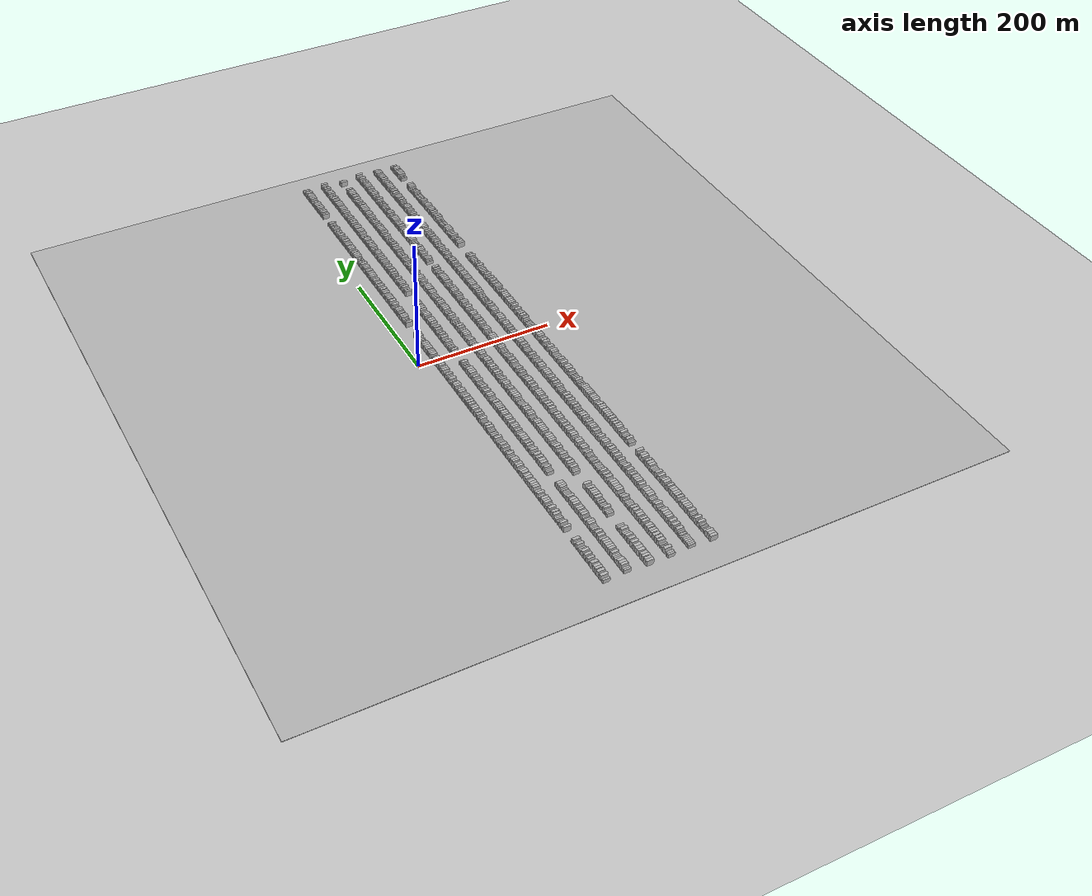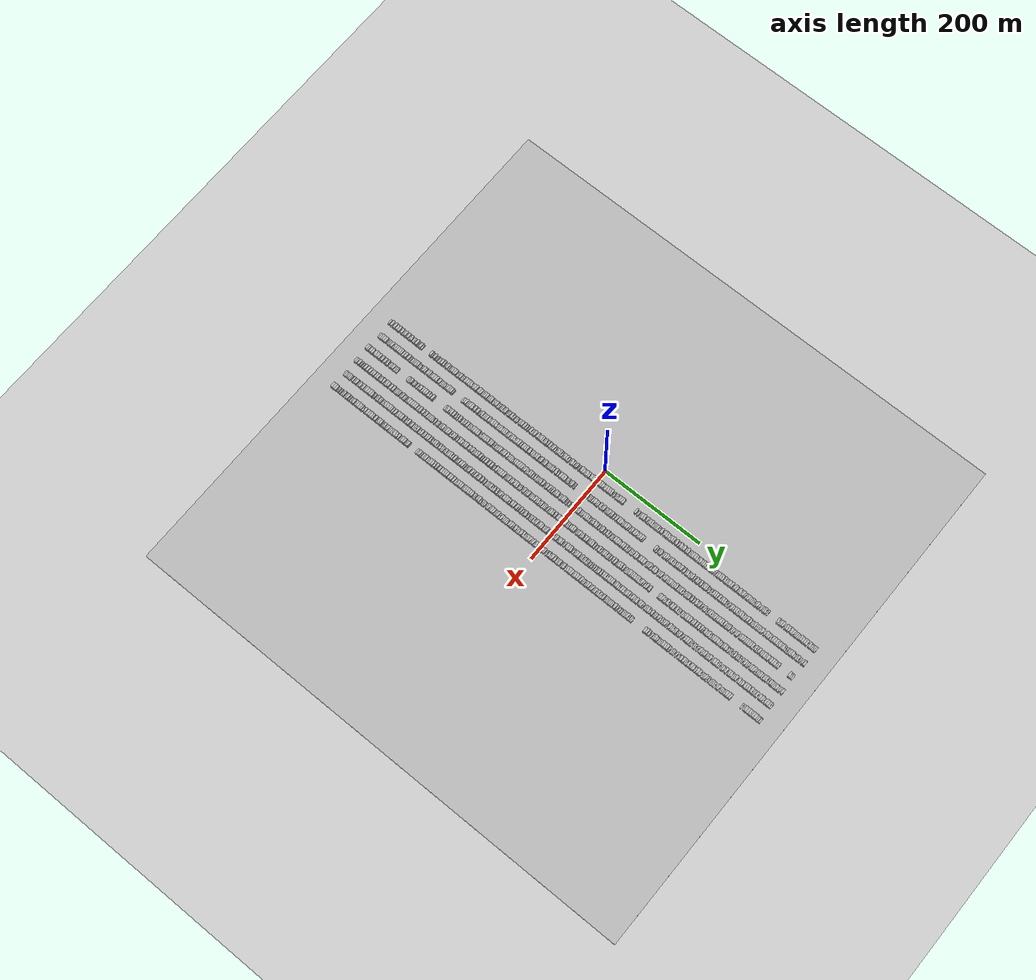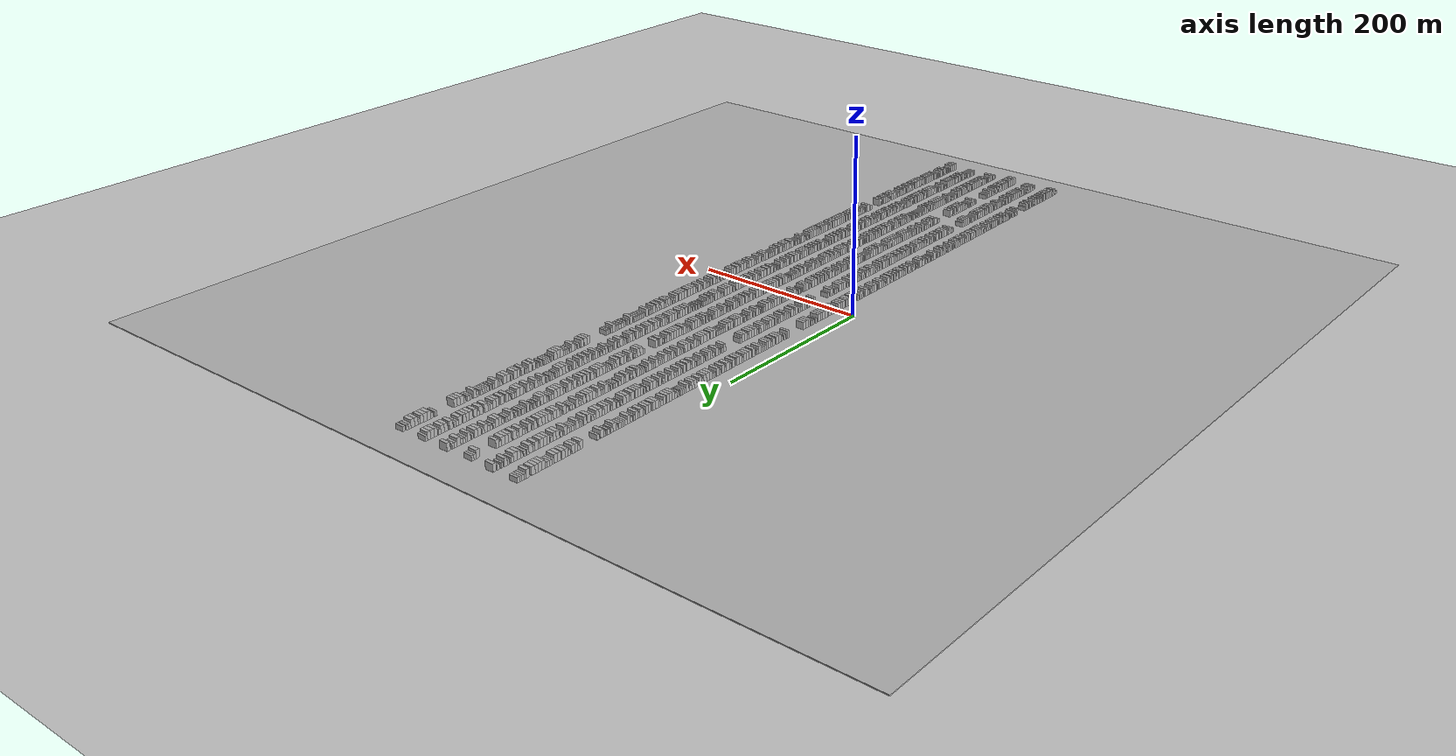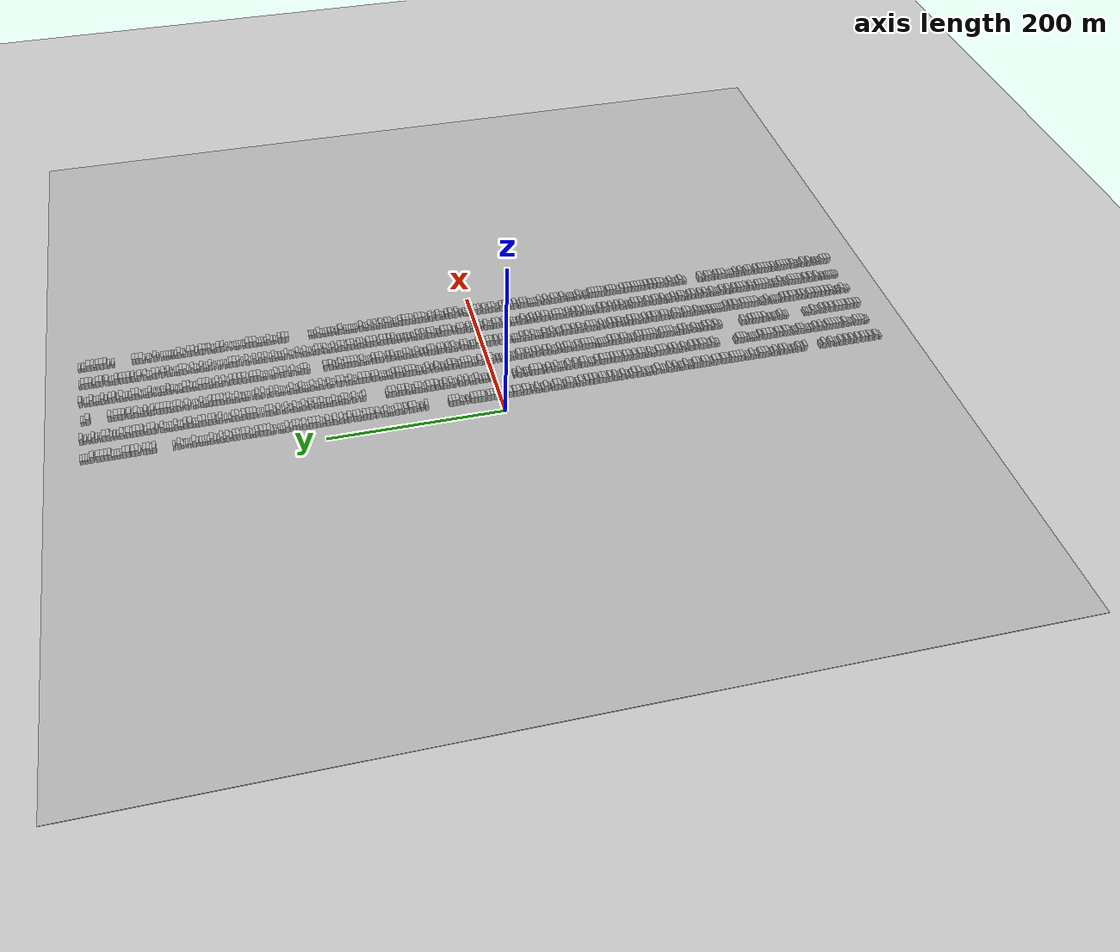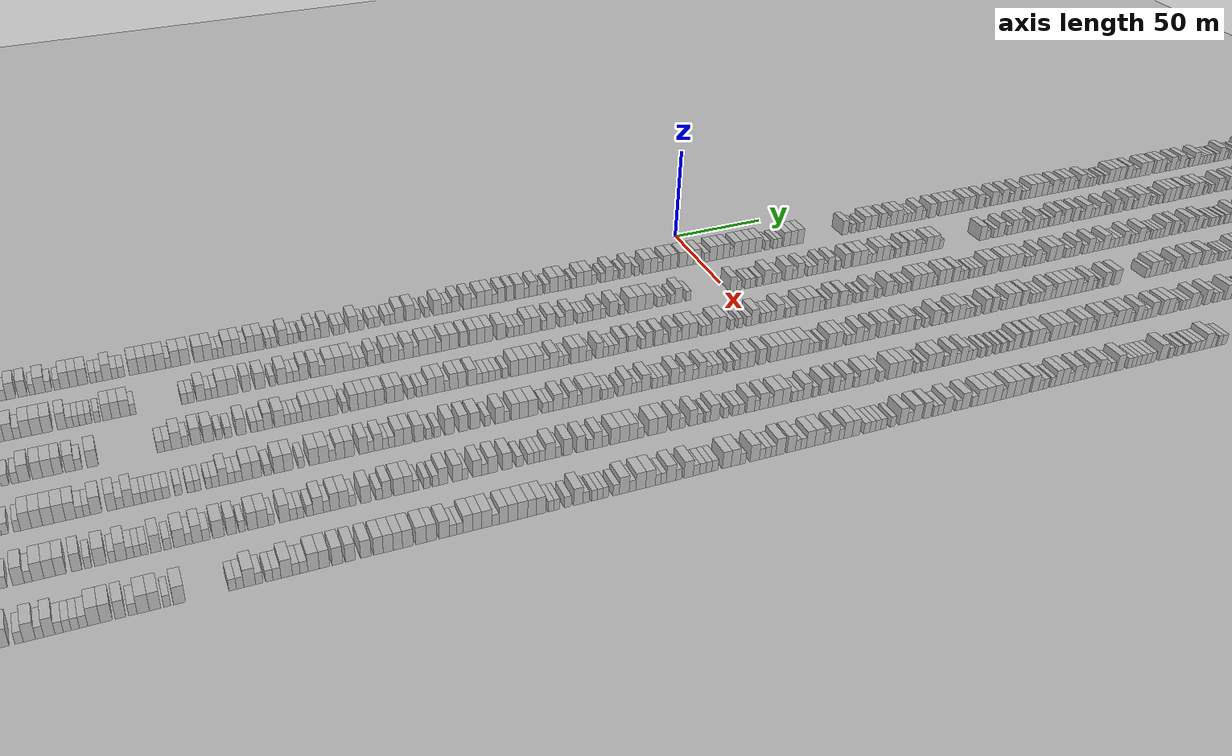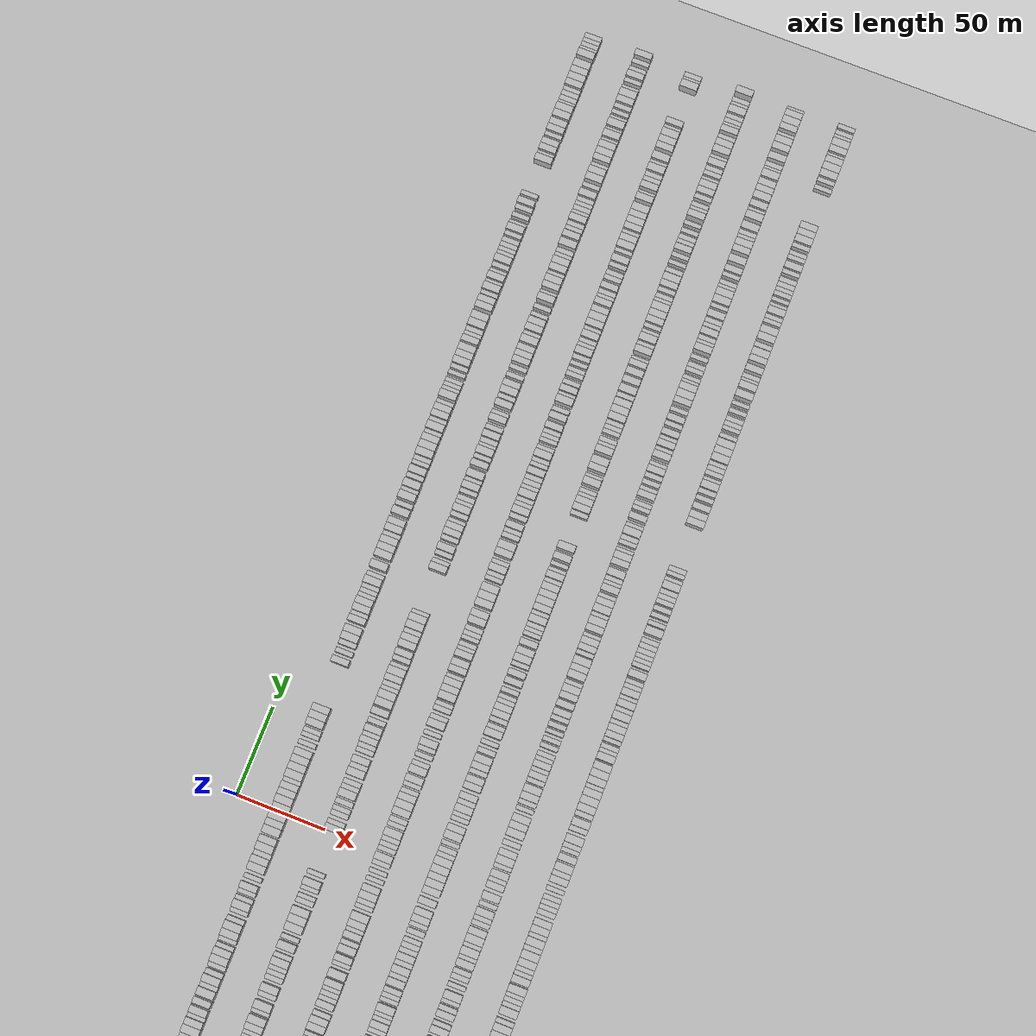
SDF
<?xml version="1.0" encoding="utf-8"?>

<sdf version="1.6">

   <world name="default">

      <gui fullscreen="0">

         <camera name="user_camera">

            <pose>-15 0 4.57585 0 0 0</pose>

            <view_controller>orbit</view_controller>

         </camera>

      </gui>

      <scene>

         <sky>

           <clouds>

             <speed>12</speed>

           </clouds>

         </sky>

         <ambient>0.4 0.4 0.4 1</ambient>

         <background>0.7 0.7 0.7 1</background>

         <shadows>1</shadows>

      </scene>

      <gravity>0 0 -9.8066</gravity>

      <magnetic_field>6e-06 2.3e-05 -4.2e-05</magnetic_field>

      <physics default="0" name="default_physics" type="ode">

         <ode>

            <solver>

               <type>quick</type>

               <iters>10</iters>

               <sor>1.0</sor>

               <use_dynamic_moi_rescaling>0</use_dynamic_moi_rescaling>

            </solver>

            <constraints>

               <cfm>0</cfm>

               <erp>0.2</erp>

               <contact_max_correcting_vel>100</contact_max_correcting_vel>

               <contact_surface_layer>0.001</contact_surface_layer>

            </constraints>

         </ode>

         <max_step_size>0.004</max_step_size>

         <real_time_factor>1</real_time_factor>

         <real_time_update_rate>250</real_time_update_rate>

      </physics>

      <light name="sun" type="directional">

         <cast_shadows>1</cast_shadows>

         <pose>0 0 10 0 0 0</pose>

         <diffuse>0.8 0.8 0.8 1</diffuse>

         <specular>0.2 0.2 0.2 1</specular>

         <attenuation>

            <range>1000</range>

            <constant>0.9</constant>

            <linear>0.01</linear>

            <quadratic>0.001</quadratic>

         </attenuation>

         <direction>-0.5 0.1 -0.9</direction>

      </light>

      <include>

         <name>ground_plane_1</name>

         <uri>model://HANNAS_ground_plane</uri>

         <pose>0 0 0  0 0 0</pose>

      </include>

      <include>

         <name>ground_plane_2</name>

         <uri>model://HANNAS_ground_plane</uri>

         <pose>100 0 0  0 0 0</pose>

      </include>

      <model name="building_1">

         <static>1</static>

         <pose frame="">25.0000 -458.6849 0 0.000000 0.000000 0.000000</pose>

         <link name="link">

            <pose frame="">0 0 3.00 0 0 0</pose>

            <collision name="collision">

               <geometry>

                  <box>

                     <size>10.0000 2.6303 6.0000</size>

                  </box>

               </geometry>

               <max_contacts>10</max_contacts>

               <surface>

                  <contact>

                     <ode/>

                  </contact>

                  <bounce/>

                  <friction>

                     <torsional>

                        <ode/>

                     </torsional>

                     <ode/>

                  </friction>

               </surface>

            </collision>

            <visual name="visual">

               <cast_shadows>0</cast_shadows>

               <geometry>

                  <box>

                     <size>10.0000 2.6303 6.0000</size>

                  </box>

               </geometry>

               <material>

                  <script>

                     <uri>model://HANNAS_wall/materials/scripts</uri>

                     <uri>model://HANNAS_wall/materials/textures</uri>

                     <name>vrc/HANNAS_wall</name>

                  </script>

               </material>

            </visual>

            <self_collide>0</self_collide>

            <enable_wind>0</enable_wind>

            <kinematic>0</kinematic>

         </link>

      </model>

      <model name="building_2">

         <static>1</static>

         <pose frame="">25.0000 -453.1732 0 0.000000 0.000000 0.000000</pose>

         <link name="link">

            <pose frame="">0 0 4.50 0 0 0</pose>

            <collision name="collision">

               <geometry>

                  <box>

                     <size>10.0000 4.3930 9.0000</size>

                  </box>

               </geometry>

               <max_contacts>10</max_contacts>

               <surface>

                  <contact>

                     <ode/>

                  </contact>

                  <bounce/>

                  <friction>

                     <torsional>

                        <ode/>

                     </torsional>

                     <ode/>

                  </friction>

               </surface>

            </collision>

            <visual name="visual">

               <cast_shadows>0</cast_shadows>

               <geometry>

                  <box>

                     <size>10.0000 4.3930 9.0000</size>

                  </box>

               </geometry>

               <material>

                  <script>

                     <uri>model://HANNAS_wall/materials/scripts</uri>

                     <uri>model://HANNAS_wall/materials/textures</uri>

                     <name>vrc/HANNAS_wall</name>

                  </script>

               </material>

            </visual>

            <self_collide>0</self_collide>

            <enable_wind>0</enable_wind>

            <kinematic>0</kinematic>

         </link>

      </model>

      <model name="building_3">

         <static>1</static>

         <pose frame="">25.0000 -449.6349 0 0.000000 0.000000 0.000000</pose>

         <link name="link">

            <pose frame="">0 0 3.00 0 0 0</pose>

            <collision name="collision">

               <geometry>

                  <box>

                     <size>10.0000 2.6837 6.0000</size>

                  </box>

               </geometry>

               <max_contacts>10</max_contacts>

               <surface>

                  <contact>

                     <ode/>

                  </contact>

                  <bounce/>

                  <friction>

                     <torsional>

                        <ode/>

                     </torsional>

                     <ode/>

                  </friction>

               </surface>

            </collision>

            <visual name="visual">

               <cast_shadows>0</cast_shadows>

               <geometry>

                  <box>

                     <size>10.0000 2.6837 6.0000</size>

                  </box>

               </geometry>

               <material>

                  <script>

                     <uri>model://HANNAS_wall/materials/scripts</uri>

                     <uri>model://HANNAS_wall/materials/textures</uri>

                     <name>vrc/HANNAS_wall</name>

                  </script>

               </material>

            </visual>

            <self_collide>0</self_collide>

            <enable_wind>0</enable_wind>

            <kinematic>0</kinematic>

         </link>

      </model>

      <model name="building_4">

         <static>1</static>

         <pose frame="">25.0000 -446.0684 0 0.000000 0.000000 0.000000</pose>

         <link name="link">

            <pose frame="">0 0 4.50 0 0 0</pose>

            <collision name="collision">

               <geometry>

                  <box>

                     <size>10.0000 4.4493 9.0000</size>

                  </box>

               </geometry>

               <max_contacts>10</max_contacts>

               <surface>

                  <contact>

                     <ode/>

                  </contact>

                  <bounce/>

                  <friction>

                     <torsional>

                        <ode/>

                     </torsional>

                     <ode/>

                  </friction>

               </surface>

            </collision>

            <visual name="visual">

               <cast_shadows>0</cast_shadows>

               <geometry>

                  <box>

                     <size>10.0000 4.4493 9.0000</size>

                  </box>

               </geometry>

               <material>

                  <script>

                     <uri>model://HANNAS_wall/materials/scripts</uri>

                     <uri>model://HANNAS_wall/materials/textures</uri>

                     <name>vrc/HANNAS_wall</name>

                  </script>

               </material>

            </visual>

            <self_collide>0</self_collide>

            <enable_wind>0</enable_wind>

            <kinematic>0</kinematic>

         </link>

      </model>

      <model name="building_5">

         <static>1</static>

         <pose frame="">25.0000 -441.0170 0 0.000000 0.000000 0.000000</pose>

         <link name="link">

            <pose frame="">0 0 4.50 0 0 0</pose>

            <collision name="collision">

               <geometry>

                  <box>

                     <size>10.0000 3.6536 9.0000</size>

                  </box>

               </geometry>

               <max_contacts>10</max_contacts>

               <surface>

                  <contact>

                     <ode/>

                  </contact>

                  <bounce/>

                  <friction>

                     <torsional>

                        <ode/>

                     </torsional>

                     <ode/>

                  </friction>

               </surface>

            </collision>

            <visual name="visual">

               <cast_shadows>0</cast_shadows>

               <geometry>

                  <box>

                     <size>10.0000 3.6536 9.0000</size>

                  </box>

               </geometry>

               <material>

                  <script>

                     <uri>model://HANNAS_wall/materials/scripts</uri>

                     <uri>model://HANNAS_wall/materials/textures</uri>

                     <name>vrc/HANNAS_wall</name>

                  </script>

               </material>

            </visual>

            <self_collide>0</self_collide>

            <enable_wind>0</enable_wind>

            <kinematic>0</kinematic>

         </link>

      </model>

      <model name="building_6">

         <static>1</static>

         <pose frame="">25.0000 -436.9849 0 0.000000 0.000000 0.000000</pose>

         <link name="link">

            <pose frame="">0 0 4.50 0 0 0</pose>

            <collision name="collision">

               <geometry>

                  <box>

                     <size>10.0000 4.4105 9.0000</size>

                  </box>

               </geometry>

               <max_contacts>10</max_contacts>

               <surface>

                  <contact>

                     <ode/>

                  </contact>

                  <bounce/>

                  <friction>

                     <torsional>

                        <ode/>

                     </torsional>

                     <ode/>

                  </friction>

               </surface>

            </collision>

            <visual name="visual">

               <cast_shadows>0</cast_shadows>

               <geometry>

                  <box>

                     <size>10.0000 4.4105 9.0000</size>

                  </box>

               </geometry>

               <material>

                  <script>

                     <uri>model://HANNAS_wall/materials/scripts</uri>

                     <uri>model://HANNAS_wall/materials/textures</uri>

                     <name>vrc/HANNAS_wall</name>

                  </script>

               </material>

            </visual>

            <self_collide>0</self_collide>

            <enable_wind>0</enable_wind>

            <kinematic>0</kinematic>

         </link>

      </model>

      <model name="building_7">

         <static>1</static>

         <pose frame="">25.0000 -430.5665 0 0.000000 0.000000 0.000000</pose>

         <link name="link">

            <pose frame="">0 0 4.50 0 0 0</pose>

            <collision name="collision">

               <geometry>

                  <box>

                     <size>10.0000 4.4264 9.0000</size>

                  </box>

               </geometry>

               <max_contacts>10</max_contacts>

               <surface>

                  <contact>

                     <ode/>

                  </contact>

                  <bounce/>

                  <friction>

                     <torsional>

                        <ode/>

                     </torsional>

                     <ode/>

                  </friction>

               </surface>

            </collision>

            <visual name="visual">

               <cast_shadows>0</cast_shadows>

               <geometry>

                  <box>

                     <size>10.0000 4.4264 9.0000</size>

                  </box>

               </geometry>

               <material>

                  <script>

                     <uri>model://HANNAS_wall/materials/scripts</uri>

                     <uri>model://HANNAS_wall/materials/textures</uri>

                     <name>vrc/HANNAS_wall</name>

                  </script>

               </material>

            </visual>

            <self_collide>0</self_collide>

            <enable_wind>0</enable_wind>

            <kinematic>0</kinematic>

         </link>

      </model>

      <model name="building_8">

         <static>1</static>

         <pose frame="">25.0000 -426.9174 0 0.000000 0.000000 0.000000</pose>

         <link name="link">

            <pose frame="">0 0 3.00 0 0 0</pose>

            <collision name="collision">

               <geometry>

                  <box>

                     <size>10.0000 2.8718 6.0000</size>

                  </box>

               </geometry>

               <max_contacts>10</max_contacts>

               <surface>

                  <contact>

                     <ode/>

                  </contact>

                  <bounce/>

                  <friction>

                     <torsional>

                        <ode/>

                     </torsional>

                     <ode/>

                  </friction>

               </surface>

            </collision>

            <visual name="visual">

               <cast_shadows>0</cast_shadows>

               <geometry>

                  <box>

                     <size>10.0000 2.8718 6.0000</size>

                  </box>

               </geometry>

               <material>

                  <script>

                     <uri>model://HANNAS_wall/materials/scripts</uri>

                     <uri>model://HANNAS_wall/materials/textures</uri>

                     <name>vrc/HANNAS_wall</name>

                  </script>

               </material>

            </visual>

            <self_collide>0</self_collide>

            <enable_wind>0</enable_wind>

            <kinematic>0</kinematic>

         </link>

      </model>

      <model name="building_9">

         <static>1</static>

         <pose frame="">25.0000 -422.5503 0 0.000000 0.000000 0.000000</pose>

         <link name="link">

            <pose frame="">0 0 4.50 0 0 0</pose>

            <collision name="collision">

               <geometry>

                  <box>

                     <size>10.0000 3.8625 9.0000</size>

                  </box>

               </geometry>

               <max_contacts>10</max_contacts>

               <surface>

                  <contact>

                     <ode/>

                  </contact>

                  <bounce/>

                  <friction>

                     <torsional>

                        <ode/>

                     </torsional>

                     <ode/>

                  </friction>

               </surface>

            </collision>

            <visual name="visual">

               <cast_shadows>0</cast_shadows>

               <geometry>

                  <box>

                     <size>10.0000 3.8625 9.0000</size>

                  </box>

               </geometry>

               <material>

                  <script>

                     <uri>model://HANNAS_wall/materials/scripts</uri>

                     <uri>model://HANNAS_wall/materials/textures</uri>

                     <name>vrc/HANNAS_wall</name>

                  </script>

               </material>

            </visual>

            <self_collide>0</self_collide>

            <enable_wind>0</enable_wind>

            <kinematic>0</kinematic>

         </link>

      </model>

      <model name="building_10">

         <static>1</static>

         <pose frame="">25.0000 -419.2839 0 0.000000 0.000000 0.000000</pose>

         <link name="link">

            <pose frame="">0 0 3.00 0 0 0</pose>

            <collision name="collision">

               <geometry>

                  <box>

                     <size>10.0000 2.6702 6.0000</size>

                  </box>

               </geometry>

               <max_contacts>10</max_contacts>

               <surface>

                  <contact>

                     <ode/>

                  </contact>

                  <bounce/>

                  <friction>

                     <torsional>

                        <ode/>

                     </torsional>

                     <ode/>

                  </friction>

               </surface>

            </collision>

            <visual name="visual">

               <cast_shadows>0</cast_shadows>

               <geometry>

                  <box>

                     <size>10.0000 2.6702 6.0000</size>

                  </box>

               </geometry>

               <material>

                  <script>

                     <uri>model://HANNAS_wall/materials/scripts</uri>

                     <uri>model://HANNAS_wall/materials/textures</uri>

                     <name>vrc/HANNAS_wall</name>

                  </script>

               </material>

            </visual>

            <self_collide>0</self_collide>

            <enable_wind>0</enable_wind>

            <kinematic>0</kinematic>

         </link>

      </model>

      <model name="building_11">

         <static>1</static>

         <pose frame="">25.0000 -416.0189 0 0.000000 0.000000 0.000000</pose>

         <link name="link">

            <pose frame="">0 0 4.50 0 0 0</pose>

            <collision name="collision">

               <geometry>

                  <box>

                     <size>10.0000 3.8599 9.0000</size>

                  </box>

               </geometry>

               <max_contacts>10</max_contacts>

               <surface>

                  <contact>

                     <ode/>

                  </contact>

                  <bounce/>

                  <friction>

                     <torsional>

                        <ode/>

                     </torsional>

                     <ode/>

                  </friction>

               </surface>

            </collision>

            <visual name="visual">

               <cast_shadows>0</cast_shadows>

               <geometry>

                  <box>

                     <size>10.0000 3.8599 9.0000</size>

                  </box>

               </geometry>

               <material>

                  <script>

                     <uri>model://HANNAS_wall/materials/scripts</uri>

                     <uri>model://HANNAS_wall/materials/textures</uri>

                     <name>vrc/HANNAS_wall</name>

                  </script>

               </material>

            </visual>

            <self_collide>0</self_collide>

            <enable_wind>0</enable_wind>

            <kinematic>0</kinematic>

         </link>

      </model>

      <model name="building_12">

         <static>1</static>

         <pose frame="">25.0000 -412.6643 0 0.000000 0.000000 0.000000</pose>

         <link name="link">

            <pose frame="">0 0 3.00 0 0 0</pose>

            <collision name="collision">

               <geometry>

                  <box>

                     <size>10.0000 2.8493 6.0000</size>

                  </box>

               </geometry>

               <max_contacts>10</max_contacts>

               <surface>

                  <contact>

                     <ode/>

                  </contact>

                  <bounce/>

                  <friction>

                     <torsional>

                        <ode/>

                     </torsional>

                     <ode/>

                  </friction>

               </surface>

            </collision>

            <visual name="visual">

               <cast_shadows>0</cast_shadows>

               <geometry>

                  <box>

                     <size>10.0000 2.8493 6.0000</size>

                  </box>

               </geometry>

               <material>

                  <script>

                     <uri>model://HANNAS_wall/materials/scripts</uri>

                     <uri>model://HANNAS_wall/materials/textures</uri>

                     <name>vrc/HANNAS_wall</name>

                  </script>

               </material>

            </visual>

            <self_collide>0</self_collide>

            <enable_wind>0</enable_wind>

            <kinematic>0</kinematic>

         </link>

      </model>

      <model name="building_13">

         <static>1</static>

         <pose frame="">25.0000 -409.1376 0 0.000000 0.000000 0.000000</pose>

         <link name="link">

            <pose frame="">0 0 4.50 0 0 0</pose>

            <collision name="collision">

               <geometry>

                  <box>

                     <size>10.0000 4.2041 9.0000</size>

                  </box>

               </geometry>

               <max_contacts>10</max_contacts>

               <surface>

                  <contact>

                     <ode/>

                  </contact>

                  <bounce/>

                  <friction>

                     <torsional>

                        <ode/>

                     </torsional>

                     <ode/>

                  </friction>

               </surface>

            </collision>

            <visual name="visual">

               <cast_shadows>0</cast_shadows>

               <geometry>

                  <box>

                     <size>10.0000 4.2041 9.0000</size>

                  </box>

               </geometry>

               <material>

                  <script>

                     <uri>model://HANNAS_wall/materials/scripts</uri>

                     <uri>model://HANNAS_wall/materials/textures</uri>

                     <name>vrc/HANNAS_wall</name>

                  </script>

               </material>

            </visual>

            <self_collide>0</self_collide>

            <enable_wind>0</enable_wind>

            <kinematic>0</kinematic>

         </link>

      </model>

      <model name="building_14">

         <static>1</static>

         <pose frame="">25.0000 -404.6051 0 0.000000 0.000000 0.000000</pose>

         <link name="link">

            <pose frame="">0 0 3.00 0 0 0</pose>

            <collision name="collision">

               <geometry>

                  <box>

                     <size>10.0000 2.8609 6.0000</size>

                  </box>

               </geometry>

               <max_contacts>10</max_contacts>

               <surface>

                  <contact>

                     <ode/>

                  </contact>

                  <bounce/>

                  <friction>

                     <torsional>

                        <ode/>

                     </torsional>

                     <ode/>

                  </friction>

               </surface>

            </collision>

            <visual name="visual">

               <cast_shadows>0</cast_shadows>

               <geometry>

                  <box>

                     <size>10.0000 2.8609 6.0000</size>

                  </box>

               </geometry>

               <material>

                  <script>

                     <uri>model://HANNAS_wall/materials/scripts</uri>

                     <uri>model://HANNAS_wall/materials/textures</uri>

                     <name>vrc/HANNAS_wall</name>

                  </script>

               </material>

            </visual>

            <self_collide>0</self_collide>

            <enable_wind>0</enable_wind>

            <kinematic>0</kinematic>

         </link>

      </model>

      <model name="building_15">

         <static>1</static>

         <pose frame="">25.0000 -401.9557 0 0.000000 0.000000 0.000000</pose>

         <link name="link">

            <pose frame="">0 0 3.00 0 0 0</pose>

            <collision name="collision">

               <geometry>

                  <box>

                     <size>10.0000 2.4379 6.0000</size>

                  </box>

               </geometry>

               <max_contacts>10</max_contacts>

               <surface>

                  <contact>

                     <ode/>

                  </contact>

                  <bounce/>

                  <friction>

                     <torsional>

                        <ode/>

                     </torsional>

                     <ode/>

                  </friction>

               </surface>

            </collision>

            <visual name="visual">

               <cast_shadows>0</cast_shadows>

               <geometry>

                  <box>

                     <size>10.0000 2.4379 6.0000</size>

                  </box>

               </geometry>

               <material>

                  <script>

                     <uri>model://HANNAS_wall/materials/scripts</uri>

                     <uri>model://HANNAS_wall/materials/textures</uri>

                     <name>vrc/HANNAS_wall</name>

                  </script>

               </material>

            </visual>

            <self_collide>0</self_collide>

            <enable_wind>0</enable_wind>

            <kinematic>0</kinematic>

         </link>

      </model>

      <model name="building_16">

         <static>1</static>

         <pose frame="">25.0000 -396.7870 0 0.000000 0.000000 0.000000</pose>

         <link name="link">

            <pose frame="">0 0 4.50 0 0 0</pose>

            <collision name="collision">

               <geometry>

                  <box>

                     <size>10.0000 3.8993 9.0000</size>

                  </box>

               </geometry>

               <max_contacts>10</max_contacts>

               <surface>

                  <contact>

                     <ode/>

                  </contact>

                  <bounce/>

                  <friction>

                     <torsional>

                        <ode/>

                     </torsional>

                     <ode/>

                  </friction>

               </surface>

            </collision>

            <visual name="visual">

               <cast_shadows>0</cast_shadows>

               <geometry>

                  <box>

                     <size>10.0000 3.8993 9.0000</size>

                  </box>

               </geometry>

               <material>

                  <script>

                     <uri>model://HANNAS_wall/materials/scripts</uri>

                     <uri>model://HANNAS_wall/materials/textures</uri>

                     <name>vrc/HANNAS_wall</name>

                  </script>

               </material>

            </visual>

            <self_collide>0</self_collide>

            <enable_wind>0</enable_wind>

            <kinematic>0</kinematic>

         </link>

      </model>

      <model name="building_17">

         <static>1</static>

         <pose frame="">25.0000 -391.4373 0 0.000000 0.000000 0.000000</pose>

         <link name="link">

            <pose frame="">0 0 3.00 0 0 0</pose>

            <collision name="collision">

               <geometry>

                  <box>

                     <size>10.0000 2.8001 6.0000</size>

                  </box>

               </geometry>

               <max_contacts>10</max_contacts>

               <surface>

                  <contact>

                     <ode/>

                  </contact>

                  <bounce/>

                  <friction>

                     <torsional>

                        <ode/>

                     </torsional>

                     <ode/>

                  </friction>

               </surface>

            </collision>

            <visual name="visual">

               <cast_shadows>0</cast_shadows>

               <geometry>

                  <box>

                     <size>10.0000 2.8001 6.0000</size>

                  </box>

               </geometry>

               <material>

                  <script>

                     <uri>model://HANNAS_wall/materials/scripts</uri>

                     <uri>model://HANNAS_wall/materials/textures</uri>

                     <name>vrc/HANNAS_wall</name>

                  </script>

               </material>

            </visual>

            <self_collide>0</self_collide>

            <enable_wind>0</enable_wind>

            <kinematic>0</kinematic>

         </link>

      </model>

      <model name="building_18">

         <static>1</static>

         <pose frame="">25.0000 -387.8711 0 0.000000 0.000000 0.000000</pose>

         <link name="link">

            <pose frame="">0 0 4.50 0 0 0</pose>

            <collision name="collision">

               <geometry>

                  <box>

                     <size>10.0000 4.3323 9.0000</size>

                  </box>

               </geometry>

               <max_contacts>10</max_contacts>

               <surface>

                  <contact>

                     <ode/>

                  </contact>

                  <bounce/>

                  <friction>

                     <torsional>

                        <ode/>

                     </torsional>

                     <ode/>

                  </friction>

               </surface>

            </collision>

            <visual name="visual">

               <cast_shadows>0</cast_shadows>

               <geometry>

                  <box>

                     <size>10.0000 4.3323 9.0000</size>

                  </box>

               </geometry>

               <material>

                  <script>

                     <uri>model://HANNAS_wall/materials/scripts</uri>

                     <uri>model://HANNAS_wall/materials/textures</uri>

                     <name>vrc/HANNAS_wall</name>

                  </script>

               </material>

            </visual>

            <self_collide>0</self_collide>

            <enable_wind>0</enable_wind>

            <kinematic>0</kinematic>

         </link>

      </model>

      <model name="building_19">

         <static>1</static>

         <pose frame="">25.0000 -384.4627 0 0.000000 0.000000 0.000000</pose>

         <link name="link">

            <pose frame="">0 0 3.00 0 0 0</pose>

            <collision name="collision">

               <geometry>

                  <box>

                     <size>10.0000 2.4846 6.0000</size>

                  </box>

               </geometry>

               <max_contacts>10</max_contacts>

               <surface>

                  <contact>

                     <ode/>

                  </contact>

                  <bounce/>

                  <friction>

                     <torsional>

                        <ode/>

                     </torsional>

                     <ode/>

                  </friction>

               </surface>

            </collision>

            <visual name="visual">

               <cast_shadows>0</cast_shadows>

               <geometry>

                  <box>

                     <size>10.0000 2.4846 6.0000</size>

                  </box>

               </geometry>

               <material>

                  <script>

                     <uri>model://HANNAS_wall/materials/scripts</uri>

                     <uri>model://HANNAS_wall/materials/textures</uri>

                     <name>vrc/HANNAS_wall</name>

                  </script>

               </material>

            </visual>

            <self_collide>0</self_collide>

            <enable_wind>0</enable_wind>

            <kinematic>0</kinematic>

         </link>

      </model>

      <model name="building_20">

         <static>1</static>

         <pose frame="">25.0000 -364.5048 0 0.000000 0.000000 0.000000</pose>

         <link name="link">

            <pose frame="">0 0 4.50 0 0 0</pose>

            <collision name="collision">

               <geometry>

                  <box>

                     <size>10.0000 3.8104 9.0000</size>

                  </box>

               </geometry>

               <max_contacts>10</max_contacts>

               <surface>

                  <contact>

                     <ode/>

                  </contact>

                  <bounce/>

                  <friction>

                     <torsional>

                        <ode/>

                     </torsional>

                     <ode/>

                  </friction>

               </surface>

            </collision>

            <visual name="visual">

               <cast_shadows>0</cast_shadows>

               <geometry>

                  <box>

                     <size>10.0000 3.8104 9.0000</size>

                  </box>

               </geometry>

               <material>

                  <script>

                     <uri>model://HANNAS_wall/materials/scripts</uri>

                     <uri>model://HANNAS_wall/materials/textures</uri>

                     <name>vrc/HANNAS_wall</name>

                  </script>

               </material>

            </visual>

            <self_collide>0</self_collide>

            <enable_wind>0</enable_wind>

            <kinematic>0</kinematic>

         </link>

      </model>

      <model name="building_21">

         <static>1</static>

         <pose frame="">25.0000 -361.2578 0 0.000000 0.000000 0.000000</pose>

         <link name="link">

            <pose frame="">0 0 3.00 0 0 0</pose>

            <collision name="collision">

               <geometry>

                  <box>

                     <size>10.0000 2.6835 6.0000</size>

                  </box>

               </geometry>

               <max_contacts>10</max_contacts>

               <surface>

                  <contact>

                     <ode/>

                  </contact>

                  <bounce/>

                  <friction>

                     <torsional>

                        <ode/>

                     </torsional>

                     <ode/>

                  </friction>

               </surface>

            </collision>

            <visual name="visual">

               <cast_shadows>0</cast_shadows>

               <geometry>

                  <box>

                     <size>10.0000 2.6835 6.0000</size>

                  </box>

               </geometry>

               <material>

                  <script>

                     <uri>model://HANNAS_wall/materials/scripts</uri>

                     <uri>model://HANNAS_wall/materials/textures</uri>

                     <name>vrc/HANNAS_wall</name>

                  </script>

               </material>

            </visual>

            <self_collide>0</self_collide>

            <enable_wind>0</enable_wind>

            <kinematic>0</kinematic>

         </link>

      </model>

      <model name="building_22">

         <static>1</static>

         <pose frame="">25.0000 -355.9842 0 0.000000 0.000000 0.000000</pose>

         <link name="link">

            <pose frame="">0 0 4.50 0 0 0</pose>

            <collision name="collision">

               <geometry>

                  <box>

                     <size>10.0000 3.8636 9.0000</size>

                  </box>

               </geometry>

               <max_contacts>10</max_contacts>

               <surface>

                  <contact>

                     <ode/>

                  </contact>

                  <bounce/>

                  <friction>

                     <torsional>

                        <ode/>

                     </torsional>

                     <ode/>

                  </friction>

               </surface>

            </collision>

            <visual name="visual">

               <cast_shadows>0</cast_shadows>

               <geometry>

                  <box>

                     <size>10.0000 3.8636 9.0000</size>

                  </box>

               </geometry>

               <material>

                  <script>

                     <uri>model://HANNAS_wall/materials/scripts</uri>

                     <uri>model://HANNAS_wall/materials/textures</uri>

                     <name>vrc/HANNAS_wall</name>

                  </script>

               </material>

            </visual>

            <self_collide>0</self_collide>

            <enable_wind>0</enable_wind>

            <kinematic>0</kinematic>

         </link>

      </model>

      <model name="building_23">

         <static>1</static>

         <pose frame="">25.0000 -350.7732 0 0.000000 0.000000 0.000000</pose>

         <link name="link">

            <pose frame="">0 0 3.00 0 0 0</pose>

            <collision name="collision">

               <geometry>

                  <box>

                     <size>10.0000 2.5584 6.0000</size>

                  </box>

               </geometry>

               <max_contacts>10</max_contacts>

               <surface>

                  <contact>

                     <ode/>

                  </contact>

                  <bounce/>

                  <friction>

                     <torsional>

                        <ode/>

                     </torsional>

                     <ode/>

                  </friction>

               </surface>

            </collision>

            <visual name="visual">

               <cast_shadows>0</cast_shadows>

               <geometry>

                  <box>

                     <size>10.0000 2.5584 6.0000</size>

                  </box>

               </geometry>

               <material>

                  <script>

                     <uri>model://HANNAS_wall/materials/scripts</uri>

                     <uri>model://HANNAS_wall/materials/textures</uri>

                     <name>vrc/HANNAS_wall</name>

                  </script>

               </material>

            </visual>

            <self_collide>0</self_collide>

            <enable_wind>0</enable_wind>

            <kinematic>0</kinematic>

         </link>

      </model>

      <model name="building_24">

         <static>1</static>

         <pose frame="">25.0000 -346.0827 0 0.000000 0.000000 0.000000</pose>

         <link name="link">

            <pose frame="">0 0 3.00 0 0 0</pose>

            <collision name="collision">

               <geometry>

                  <box>

                     <size>10.0000 2.8226 6.0000</size>

                  </box>

               </geometry>

               <max_contacts>10</max_contacts>

               <surface>

                  <contact>

                     <ode/>

                  </contact>

                  <bounce/>

                  <friction>

                     <torsional>

                        <ode/>

                     </torsional>

                     <ode/>

                  </friction>

               </surface>

            </collision>

            <visual name="visual">

               <cast_shadows>0</cast_shadows>

               <geometry>

                  <box>

                     <size>10.0000 2.8226 6.0000</size>

                  </box>

               </geometry>

               <material>

                  <script>

                     <uri>model://HANNAS_wall/materials/scripts</uri>

                     <uri>model://HANNAS_wall/materials/textures</uri>

                     <name>vrc/HANNAS_wall</name>

                  </script>

               </material>

            </visual>

            <self_collide>0</self_collide>

            <enable_wind>0</enable_wind>

            <kinematic>0</kinematic>

         </link>

      </model>

      <model name="building_25">

         <static>1</static>

         <pose frame="">25.0000 -343.3241 0 0.000000 0.000000 0.000000</pose>

         <link name="link">

            <pose frame="">0 0 3.00 0 0 0</pose>

            <collision name="collision">

               <geometry>

                  <box>

                     <size>10.0000 2.6947 6.0000</size>

                  </box>

               </geometry>

               <max_contacts>10</max_contacts>

               <surface>

                  <contact>

                     <ode/>

                  </contact>

                  <bounce/>

                  <friction>

                     <torsional>

                        <ode/>

                     </torsional>

                     <ode/>

                  </friction>

               </surface>

            </collision>

            <visual name="visual">

               <cast_shadows>0</cast_shadows>

               <geometry>

                  <box>

                     <size>10.0000 2.6947 6.0000</size>

                  </box>

               </geometry>

               <material>

                  <script>

                     <uri>model://HANNAS_wall/materials/scripts</uri>

                     <uri>model://HANNAS_wall/materials/textures</uri>

                     <name>vrc/HANNAS_wall</name>

                  </script>

               </material>

            </visual>

            <self_collide>0</self_collide>

            <enable_wind>0</enable_wind>

            <kinematic>0</kinematic>

         </link>

      </model>

      <model name="building_26">

         <static>1</static>

         <pose frame="">25.0000 -339.9668 0 0.000000 0.000000 0.000000</pose>

         <link name="link">

            <pose frame="">0 0 4.50 0 0 0</pose>

            <collision name="collision">

               <geometry>

                  <box>

                     <size>10.0000 4.0198 9.0000</size>

                  </box>

               </geometry>

               <max_contacts>10</max_contacts>

               <surface>

                  <contact>

                     <ode/>

                  </contact>

                  <bounce/>

                  <friction>

                     <torsional>

                        <ode/>

                     </torsional>

                     <ode/>

                  </friction>

               </surface>

            </collision>

            <visual name="visual">

               <cast_shadows>0</cast_shadows>

               <geometry>

                  <box>

                     <size>10.0000 4.0198 9.0000</size>

                  </box>

               </geometry>

               <material>

                  <script>

                     <uri>model://HANNAS_wall/materials/scripts</uri>

                     <uri>model://HANNAS_wall/materials/textures</uri>

                     <name>vrc/HANNAS_wall</name>

                  </script>

               </material>

            </visual>

            <self_collide>0</self_collide>

            <enable_wind>0</enable_wind>

            <kinematic>0</kinematic>

         </link>

      </model>

      <model name="building_27">

         <static>1</static>

         <pose frame="">25.0000 -335.0545 0 0.000000 0.000000 0.000000</pose>

         <link name="link">

            <pose frame="">0 0 4.50 0 0 0</pose>

            <collision name="collision">

               <geometry>

                  <box>

                     <size>10.0000 3.8048 9.0000</size>

                  </box>

               </geometry>

               <max_contacts>10</max_contacts>

               <surface>

                  <contact>

                     <ode/>

                  </contact>

                  <bounce/>

                  <friction>

                     <torsional>

                        <ode/>

                     </torsional>

                     <ode/>

                  </friction>

               </surface>

            </collision>

            <visual name="visual">

               <cast_shadows>0</cast_shadows>

               <geometry>

                  <box>

                     <size>10.0000 3.8048 9.0000</size>

                  </box>

               </geometry>

               <material>

                  <script>

                     <uri>model://HANNAS_wall/materials/scripts</uri>

                     <uri>model://HANNAS_wall/materials/textures</uri>

                     <name>vrc/HANNAS_wall</name>

                  </script>

               </material>

            </visual>

            <self_collide>0</self_collide>

            <enable_wind>0</enable_wind>

            <kinematic>0</kinematic>

         </link>

      </model>

      <model name="building_28">

         <static>1</static>

         <pose frame="">25.0000 -330.9472 0 0.000000 0.000000 0.000000</pose>

         <link name="link">

            <pose frame="">0 0 3.00 0 0 0</pose>

            <collision name="collision">

               <geometry>

                  <box>

                     <size>10.0000 2.4097 6.0000</size>

                  </box>

               </geometry>

               <max_contacts>10</max_contacts>

               <surface>

                  <contact>

                     <ode/>

                  </contact>

                  <bounce/>

                  <friction>

                     <torsional>

                        <ode/>

                     </torsional>

                     <ode/>

                  </friction>

               </surface>

            </collision>

            <visual name="visual">

               <cast_shadows>0</cast_shadows>

               <geometry>

                  <box>

                     <size>10.0000 2.4097 6.0000</size>

                  </box>

               </geometry>

               <material>

                  <script>

                     <uri>model://HANNAS_wall/materials/scripts</uri>

                     <uri>model://HANNAS_wall/materials/textures</uri>

                     <name>vrc/HANNAS_wall</name>

                  </script>

               </material>

            </visual>

            <self_collide>0</self_collide>

            <enable_wind>0</enable_wind>

            <kinematic>0</kinematic>

         </link>

      </model>

      <model name="building_29">

         <static>1</static>

         <pose frame="">25.0000 -327.5070 0 0.000000 0.000000 0.000000</pose>

         <link name="link">

            <pose frame="">0 0 4.50 0 0 0</pose>

            <collision name="collision">

               <geometry>

                  <box>

                     <size>10.0000 4.4708 9.0000</size>

                  </box>

               </geometry>

               <max_contacts>10</max_contacts>

               <surface>

                  <contact>

                     <ode/>

                  </contact>

                  <bounce/>

                  <friction>

                     <torsional>

                        <ode/>

                     </torsional>

                     <ode/>

                  </friction>

               </surface>

            </collision>

            <visual name="visual">

               <cast_shadows>0</cast_shadows>

               <geometry>

                  <box>

                     <size>10.0000 4.4708 9.0000</size>

                  </box>

               </geometry>

               <material>

                  <script>

                     <uri>model://HANNAS_wall/materials/scripts</uri>

                     <uri>model://HANNAS_wall/materials/textures</uri>

                     <name>vrc/HANNAS_wall</name>

                  </script>

               </material>

            </visual>

            <self_collide>0</self_collide>

            <enable_wind>0</enable_wind>

            <kinematic>0</kinematic>

         </link>

      </model>

      <model name="building_30">

         <static>1</static>

         <pose frame="">25.0000 -323.9054 0 0.000000 0.000000 0.000000</pose>

         <link name="link">

            <pose frame="">0 0 3.00 0 0 0</pose>

            <collision name="collision">

               <geometry>

                  <box>

                     <size>10.0000 2.7323 6.0000</size>

                  </box>

               </geometry>

               <max_contacts>10</max_contacts>

               <surface>

                  <contact>

                     <ode/>

                  </contact>

                  <bounce/>

                  <friction>

                     <torsional>

                        <ode/>

                     </torsional>

                     <ode/>

                  </friction>

               </surface>

            </collision>

            <visual name="visual">

               <cast_shadows>0</cast_shadows>

               <geometry>

                  <box>

                     <size>10.0000 2.7323 6.0000</size>

                  </box>

               </geometry>

               <material>

                  <script>

                     <uri>model://HANNAS_wall/materials/scripts</uri>

                     <uri>model://HANNAS_wall/materials/textures</uri>

                     <name>vrc/HANNAS_wall</name>

                  </script>

               </material>

            </visual>

            <self_collide>0</self_collide>

            <enable_wind>0</enable_wind>

            <kinematic>0</kinematic>

         </link>

      </model>

      <model name="building_31">

         <static>1</static>

         <pose frame="">25.0000 -320.1996 0 0.000000 0.000000 0.000000</pose>

         <link name="link">

            <pose frame="">0 0 3.00 0 0 0</pose>

            <collision name="collision">

               <geometry>

                  <box>

                     <size>10.0000 2.6794 6.0000</size>

                  </box>

               </geometry>

               <max_contacts>10</max_contacts>

               <surface>

                  <contact>

                     <ode/>

                  </contact>

                  <bounce/>

                  <friction>

                     <torsional>

                        <ode/>

                     </torsional>

                     <ode/>

                  </friction>

               </surface>

            </collision>

            <visual name="visual">

               <cast_shadows>0</cast_shadows>

               <geometry>

                  <box>

                     <size>10.0000 2.6794 6.0000</size>

                  </box>

               </geometry>

               <material>

                  <script>

                     <uri>model://HANNAS_wall/materials/scripts</uri>

                     <uri>model://HANNAS_wall/materials/textures</uri>

                     <name>vrc/HANNAS_wall</name>

                  </script>

               </material>

            </visual>

            <self_collide>0</self_collide>

            <enable_wind>0</enable_wind>

            <kinematic>0</kinematic>

         </link>

      </model>

      <model name="building_32">

         <static>1</static>

         <pose frame="">25.0000 -316.8706 0 0.000000 0.000000 0.000000</pose>

         <link name="link">

            <pose frame="">0 0 4.50 0 0 0</pose>

            <collision name="collision">

               <geometry>

                  <box>

                     <size>10.0000 3.9786 9.0000</size>

                  </box>

               </geometry>

               <max_contacts>10</max_contacts>

               <surface>

                  <contact>

                     <ode/>

                  </contact>

                  <bounce/>

                  <friction>

                     <torsional>

                        <ode/>

                     </torsional>

                     <ode/>

                  </friction>

               </surface>

            </collision>

            <visual name="visual">

               <cast_shadows>0</cast_shadows>

               <geometry>

                  <box>

                     <size>10.0000 3.9786 9.0000</size>

                  </box>

               </geometry>

               <material>

                  <script>

                     <uri>model://HANNAS_wall/materials/scripts</uri>

                     <uri>model://HANNAS_wall/materials/textures</uri>

                     <name>vrc/HANNAS_wall</name>

                  </script>

               </material>

            </visual>

            <self_collide>0</self_collide>

            <enable_wind>0</enable_wind>

            <kinematic>0</kinematic>

         </link>

      </model>

      <model name="building_33">

         <static>1</static>

         <pose frame="">25.0000 -313.0460 0 0.000000 0.000000 0.000000</pose>

         <link name="link">

            <pose frame="">0 0 4.50 0 0 0</pose>

            <collision name="collision">

               <geometry>

                  <box>

                     <size>10.0000 3.6706 9.0000</size>

                  </box>

               </geometry>

               <max_contacts>10</max_contacts>

               <surface>

                  <contact>

                     <ode/>

                  </contact>

                  <bounce/>

                  <friction>

                     <torsional>

                        <ode/>

                     </torsional>

                     <ode/>

                  </friction>

               </surface>

            </collision>

            <visual name="visual">

               <cast_shadows>0</cast_shadows>

               <geometry>

                  <box>

                     <size>10.0000 3.6706 9.0000</size>

                  </box>

               </geometry>

               <material>

                  <script>

                     <uri>model://HANNAS_wall/materials/scripts</uri>

                     <uri>model://HANNAS_wall/materials/textures</uri>

                     <name>vrc/HANNAS_wall</name>

                  </script>

               </material>

            </visual>

            <self_collide>0</self_collide>

            <enable_wind>0</enable_wind>

            <kinematic>0</kinematic>

         </link>

      </model>

      <model name="building_34">

         <static>1</static>

         <pose frame="">25.0000 -309.1105 0 0.000000 0.000000 0.000000</pose>

         <link name="link">

            <pose frame="">0 0 4.50 0 0 0</pose>

            <collision name="collision">

               <geometry>

                  <box>

                     <size>10.0000 4.2003 9.0000</size>

                  </box>

               </geometry>

               <max_contacts>10</max_contacts>

               <surface>

                  <contact>

                     <ode/>

                  </contact>

                  <bounce/>

                  <friction>

                     <torsional>

                        <ode/>

                     </torsional>

                     <ode/>

                  </friction>

               </surface>

            </collision>

            <visual name="visual">

               <cast_shadows>0</cast_shadows>

               <geometry>

                  <box>

                     <size>10.0000 4.2003 9.0000</size>

                  </box>

               </geometry>

               <material>

                  <script>

                     <uri>model://HANNAS_wall/materials/scripts</uri>

                     <uri>model://HANNAS_wall/materials/textures</uri>

                     <name>vrc/HANNAS_wall</name>

                  </script>

               </material>

            </visual>

            <self_collide>0</self_collide>

            <enable_wind>0</enable_wind>

            <kinematic>0</kinematic>

         </link>

      </model>

      <model name="building_35">

         <static>1</static>

         <pose frame="">25.0000 -304.6048 0 0.000000 0.000000 0.000000</pose>

         <link name="link">

            <pose frame="">0 0 3.00 0 0 0</pose>

            <collision name="collision">

               <geometry>

                  <box>

                     <size>10.0000 2.8110 6.0000</size>

                  </box>

               </geometry>

               <max_contacts>10</max_contacts>

               <surface>

                  <contact>

                     <ode/>

                  </contact>

                  <bounce/>

                  <friction>

                     <torsional>

                        <ode/>

                     </torsional>

                     <ode/>

                  </friction>

               </surface>

            </collision>

            <visual name="visual">

               <cast_shadows>0</cast_shadows>

               <geometry>

                  <box>

                     <size>10.0000 2.8110 6.0000</size>

                  </box>

               </geometry>

               <material>

                  <script>

                     <uri>model://HANNAS_wall/materials/scripts</uri>

                     <uri>model://HANNAS_wall/materials/textures</uri>

                     <name>vrc/HANNAS_wall</name>

                  </script>

               </material>

            </visual>

            <self_collide>0</self_collide>

            <enable_wind>0</enable_wind>

            <kinematic>0</kinematic>

         </link>

      </model>

      <model name="building_36">

         <static>1</static>

         <pose frame="">25.0000 -301.8434 0 0.000000 0.000000 0.000000</pose>

         <link name="link">

            <pose frame="">0 0 3.00 0 0 0</pose>

            <collision name="collision">

               <geometry>

                  <box>

                     <size>10.0000 2.7119 6.0000</size>

                  </box>

               </geometry>

               <max_contacts>10</max_contacts>

               <surface>

                  <contact>

                     <ode/>

                  </contact>

                  <bounce/>

                  <friction>

                     <torsional>

                        <ode/>

                     </torsional>

                     <ode/>

                  </friction>

               </surface>

            </collision>

            <visual name="visual">

               <cast_shadows>0</cast_shadows>

               <geometry>

                  <box>

                     <size>10.0000 2.7119 6.0000</size>

                  </box>

               </geometry>

               <material>

                  <script>

                     <uri>model://HANNAS_wall/materials/scripts</uri>

                     <uri>model://HANNAS_wall/materials/textures</uri>

                     <name>vrc/HANNAS_wall</name>

                  </script>

               </material>

            </visual>

            <self_collide>0</self_collide>

            <enable_wind>0</enable_wind>

            <kinematic>0</kinematic>

         </link>

      </model>

      <model name="building_37">

         <static>1</static>

         <pose frame="">25.0000 -298.4720 0 0.000000 0.000000 0.000000</pose>

         <link name="link">

            <pose frame="">0 0 4.50 0 0 0</pose>

            <collision name="collision">

               <geometry>

                  <box>

                     <size>10.0000 4.0309 9.0000</size>

                  </box>

               </geometry>

               <max_contacts>10</max_contacts>

               <surface>

                  <contact>

                     <ode/>

                  </contact>

                  <bounce/>

                  <friction>

                     <torsional>

                        <ode/>

                     </torsional>

                     <ode/>

                  </friction>

               </surface>

            </collision>

            <visual name="visual">

               <cast_shadows>0</cast_shadows>

               <geometry>

                  <box>

                     <size>10.0000 4.0309 9.0000</size>

                  </box>

               </geometry>

               <material>

                  <script>

                     <uri>model://HANNAS_wall/materials/scripts</uri>

                     <uri>model://HANNAS_wall/materials/textures</uri>

                     <name>vrc/HANNAS_wall</name>

                  </script>

               </material>

            </visual>

            <self_collide>0</self_collide>

            <enable_wind>0</enable_wind>

            <kinematic>0</kinematic>

         </link>

      </model>

      <model name="building_38">

         <static>1</static>

         <pose frame="">25.0000 -295.0568 0 0.000000 0.000000 0.000000</pose>

         <link name="link">

            <pose frame="">0 0 3.00 0 0 0</pose>

            <collision name="collision">

               <geometry>

                  <box>

                     <size>10.0000 2.7996 6.0000</size>

                  </box>

               </geometry>

               <max_contacts>10</max_contacts>

               <surface>

                  <contact>

                     <ode/>

                  </contact>

                  <bounce/>

                  <friction>

                     <torsional>

                        <ode/>

                     </torsional>

                     <ode/>

                  </friction>

               </surface>

            </collision>

            <visual name="visual">

               <cast_shadows>0</cast_shadows>

               <geometry>

                  <box>

                     <size>10.0000 2.7996 6.0000</size>

                  </box>

               </geometry>

               <material>

                  <script>

                     <uri>model://HANNAS_wall/materials/scripts</uri>

                     <uri>model://HANNAS_wall/materials/textures</uri>

                     <name>vrc/HANNAS_wall</name>

                  </script>

               </material>

            </visual>

            <self_collide>0</self_collide>

            <enable_wind>0</enable_wind>

            <kinematic>0</kinematic>

         </link>

      </model>

      <model name="building_39">

         <static>1</static>

         <pose frame="">25.0000 -292.2047 0 0.000000 0.000000 0.000000</pose>

         <link name="link">

            <pose frame="">0 0 3.00 0 0 0</pose>

            <collision name="collision">

               <geometry>

                  <box>

                     <size>10.0000 2.9045 6.0000</size>

                  </box>

               </geometry>

               <max_contacts>10</max_contacts>

               <surface>

                  <contact>

                     <ode/>

                  </contact>

                  <bounce/>

                  <friction>

                     <torsional>

                        <ode/>

                     </torsional>

                     <ode/>

                  </friction>

               </surface>

            </collision>

            <visual name="visual">

               <cast_shadows>0</cast_shadows>

               <geometry>

                  <box>

                     <size>10.0000 2.9045 6.0000</size>

                  </box>

               </geometry>

               <material>

                  <script>

                     <uri>model://HANNAS_wall/materials/scripts</uri>

                     <uri>model://HANNAS_wall/materials/textures</uri>

                     <name>vrc/HANNAS_wall</name>

                  </script>

               </material>

            </visual>

            <self_collide>0</self_collide>

            <enable_wind>0</enable_wind>

            <kinematic>0</kinematic>

         </link>

      </model>

      <model name="building_40">

         <static>1</static>

         <pose frame="">25.0000 -286.6852 0 0.000000 0.000000 0.000000</pose>

         <link name="link">

            <pose frame="">0 0 4.50 0 0 0</pose>

            <collision name="collision">

               <geometry>

                  <box>

                     <size>10.0000 4.1346 9.0000</size>

                  </box>

               </geometry>

               <max_contacts>10</max_contacts>

               <surface>

                  <contact>

                     <ode/>

                  </contact>

                  <bounce/>

                  <friction>

                     <torsional>

                        <ode/>

                     </torsional>

                     <ode/>

                  </friction>

               </surface>

            </collision>

            <visual name="visual">

               <cast_shadows>0</cast_shadows>

               <geometry>

                  <box>

                     <size>10.0000 4.1346 9.0000</size>

                  </box>

               </geometry>

               <material>

                  <script>

                     <uri>model://HANNAS_wall/materials/scripts</uri>

                     <uri>model://HANNAS_wall/materials/textures</uri>

                     <name>vrc/HANNAS_wall</name>

                  </script>

               </material>

            </visual>

            <self_collide>0</self_collide>

            <enable_wind>0</enable_wind>

            <kinematic>0</kinematic>

         </link>

      </model>

      <model name="building_41">

         <static>1</static>

         <pose frame="">25.0000 -282.7519 0 0.000000 0.000000 0.000000</pose>

         <link name="link">

            <pose frame="">0 0 4.50 0 0 0</pose>

            <collision name="collision">

               <geometry>

                  <box>

                     <size>10.0000 3.7319 9.0000</size>

                  </box>

               </geometry>

               <max_contacts>10</max_contacts>

               <surface>

                  <contact>

                     <ode/>

                  </contact>

                  <bounce/>

                  <friction>

                     <torsional>

                        <ode/>

                     </torsional>

                     <ode/>

                  </friction>

               </surface>

            </collision>

            <visual name="visual">

               <cast_shadows>0</cast_shadows>

               <geometry>

                  <box>

                     <size>10.0000 3.7319 9.0000</size>

                  </box>

               </geometry>

               <material>

                  <script>

                     <uri>model://HANNAS_wall/materials/scripts</uri>

                     <uri>model://HANNAS_wall/materials/textures</uri>

                     <name>vrc/HANNAS_wall</name>

                  </script>

               </material>

            </visual>

            <self_collide>0</self_collide>

            <enable_wind>0</enable_wind>

            <kinematic>0</kinematic>

         </link>

      </model>

      <model name="building_42">

         <static>1</static>

         <pose frame="">25.0000 -278.8896 0 0.000000 0.000000 0.000000</pose>

         <link name="link">

            <pose frame="">0 0 4.50 0 0 0</pose>

            <collision name="collision">

               <geometry>

                  <box>

                     <size>10.0000 3.9926 9.0000</size>

                  </box>

               </geometry>

               <max_contacts>10</max_contacts>

               <surface>

                  <contact>

                     <ode/>

                  </contact>

                  <bounce/>

                  <friction>

                     <torsional>

                        <ode/>

                     </torsional>

                     <ode/>

                  </friction>

               </surface>

            </collision>

            <visual name="visual">

               <cast_shadows>0</cast_shadows>

               <geometry>

                  <box>

                     <size>10.0000 3.9926 9.0000</size>

                  </box>

               </geometry>

               <material>

                  <script>

                     <uri>model://HANNAS_wall/materials/scripts</uri>

                     <uri>model://HANNAS_wall/materials/textures</uri>

                     <name>vrc/HANNAS_wall</name>

                  </script>

               </material>

            </visual>

            <self_collide>0</self_collide>

            <enable_wind>0</enable_wind>

            <kinematic>0</kinematic>

         </link>

      </model>

      <model name="building_43">

         <static>1</static>

         <pose frame="">25.0000 -274.7238 0 0.000000 0.000000 0.000000</pose>

         <link name="link">

            <pose frame="">0 0 4.50 0 0 0</pose>

            <collision name="collision">

               <geometry>

                  <box>

                     <size>10.0000 4.3390 9.0000</size>

                  </box>

               </geometry>

               <max_contacts>10</max_contacts>

               <surface>

                  <contact>

                     <ode/>

                  </contact>

                  <bounce/>

                  <friction>

                     <torsional>

                        <ode/>

                     </torsional>

                     <ode/>

                  </friction>

               </surface>

            </collision>

            <visual name="visual">

               <cast_shadows>0</cast_shadows>

               <geometry>

                  <box>

                     <size>10.0000 4.3390 9.0000</size>

                  </box>

               </geometry>

               <material>

                  <script>

                     <uri>model://HANNAS_wall/materials/scripts</uri>

                     <uri>model://HANNAS_wall/materials/textures</uri>

                     <name>vrc/HANNAS_wall</name>

                  </script>

               </material>

            </visual>

            <self_collide>0</self_collide>

            <enable_wind>0</enable_wind>

            <kinematic>0</kinematic>

         </link>

      </model>

      <model name="building_44">

         <static>1</static>

         <pose frame="">25.0000 -271.2910 0 0.000000 0.000000 0.000000</pose>

         <link name="link">

            <pose frame="">0 0 3.00 0 0 0</pose>

            <collision name="collision">

               <geometry>

                  <box>

                     <size>10.0000 2.5265 6.0000</size>

                  </box>

               </geometry>

               <max_contacts>10</max_contacts>

               <surface>

                  <contact>

                     <ode/>

                  </contact>

                  <bounce/>

                  <friction>

                     <torsional>

                        <ode/>

                     </torsional>

                     <ode/>

                  </friction>

               </surface>

            </collision>

            <visual name="visual">

               <cast_shadows>0</cast_shadows>

               <geometry>

                  <box>

                     <size>10.0000 2.5265 6.0000</size>

                  </box>

               </geometry>

               <material>

                  <script>

                     <uri>model://HANNAS_wall/materials/scripts</uri>

                     <uri>model://HANNAS_wall/materials/textures</uri>

                     <name>vrc/HANNAS_wall</name>

                  </script>

               </material>

            </visual>

            <self_collide>0</self_collide>

            <enable_wind>0</enable_wind>

            <kinematic>0</kinematic>

         </link>

      </model>

      <model name="building_45">

         <static>1</static>

         <pose frame="">25.0000 -267.9232 0 0.000000 0.000000 0.000000</pose>

         <link name="link">

            <pose frame="">0 0 4.50 0 0 0</pose>

            <collision name="collision">

               <geometry>

                  <box>

                     <size>10.0000 4.2090 9.0000</size>

                  </box>

               </geometry>

               <max_contacts>10</max_contacts>

               <surface>

                  <contact>

                     <ode/>

                  </contact>

                  <bounce/>

                  <friction>

                     <torsional>

                        <ode/>

                     </torsional>

                     <ode/>

                  </friction>

               </surface>

            </collision>

            <visual name="visual">

               <cast_shadows>0</cast_shadows>

               <geometry>

                  <box>

                     <size>10.0000 4.2090 9.0000</size>

                  </box>

               </geometry>

               <material>

                  <script>

                     <uri>model://HANNAS_wall/materials/scripts</uri>

                     <uri>model://HANNAS_wall/materials/textures</uri>

                     <name>vrc/HANNAS_wall</name>

                  </script>

               </material>

            </visual>

            <self_collide>0</self_collide>

            <enable_wind>0</enable_wind>

            <kinematic>0</kinematic>

         </link>

      </model>

      <model name="building_46">

         <static>1</static>

         <pose frame="">25.0000 -263.6469 0 0.000000 0.000000 0.000000</pose>

         <link name="link">

            <pose frame="">0 0 4.50 0 0 0</pose>

            <collision name="collision">

               <geometry>

                  <box>

                     <size>10.0000 4.3437 9.0000</size>

                  </box>

               </geometry>

               <max_contacts>10</max_contacts>

               <surface>

                  <contact>

                     <ode/>

                  </contact>

                  <bounce/>

                  <friction>

                     <torsional>

                        <ode/>

                     </torsional>

                     <ode/>

                  </friction>

               </surface>

            </collision>

            <visual name="visual">

               <cast_shadows>0</cast_shadows>

               <geometry>

                  <box>

                     <size>10.0000 4.3437 9.0000</size>

                  </box>

               </geometry>

               <material>

                  <script>

                     <uri>model://HANNAS_wall/materials/scripts</uri>

                     <uri>model://HANNAS_wall/materials/textures</uri>

                     <name>vrc/HANNAS_wall</name>

                  </script>

               </material>

            </visual>

            <self_collide>0</self_collide>

            <enable_wind>0</enable_wind>

            <kinematic>0</kinematic>

         </link>

      </model>

      <model name="building_47">

         <static>1</static>

         <pose frame="">25.0000 -257.3190 0 0.000000 0.000000 0.000000</pose>

         <link name="link">

            <pose frame="">0 0 4.50 0 0 0</pose>

            <collision name="collision">

               <geometry>

                  <box>

                     <size>10.0000 4.3121 9.0000</size>

                  </box>

               </geometry>

               <max_contacts>10</max_contacts>

               <surface>

                  <contact>

                     <ode/>

                  </contact>

                  <bounce/>

                  <friction>

                     <torsional>

                        <ode/>

                     </torsional>

                     <ode/>

                  </friction>

               </surface>

            </collision>

            <visual name="visual">

               <cast_shadows>0</cast_shadows>

               <geometry>

                  <box>

                     <size>10.0000 4.3121 9.0000</size>

                  </box>

               </geometry>

               <material>

                  <script>

                     <uri>model://HANNAS_wall/materials/scripts</uri>

                     <uri>model://HANNAS_wall/materials/textures</uri>

                     <name>vrc/HANNAS_wall</name>

                  </script>

               </material>

            </visual>

            <self_collide>0</self_collide>

            <enable_wind>0</enable_wind>

            <kinematic>0</kinematic>

         </link>

      </model>

      <model name="building_48">

         <static>1</static>

         <pose frame="">25.0000 -253.1301 0 0.000000 0.000000 0.000000</pose>

         <link name="link">

            <pose frame="">0 0 4.50 0 0 0</pose>

            <collision name="collision">

               <geometry>

                  <box>

                     <size>10.0000 4.0658 9.0000</size>

                  </box>

               </geometry>

               <max_contacts>10</max_contacts>

               <surface>

                  <contact>

                     <ode/>

                  </contact>

                  <bounce/>

                  <friction>

                     <torsional>

                        <ode/>

                     </torsional>

                     <ode/>

                  </friction>

               </surface>

            </collision>

            <visual name="visual">

               <cast_shadows>0</cast_shadows>

               <geometry>

                  <box>

                     <size>10.0000 4.0658 9.0000</size>

                  </box>

               </geometry>

               <material>

                  <script>

                     <uri>model://HANNAS_wall/materials/scripts</uri>

                     <uri>model://HANNAS_wall/materials/textures</uri>

                     <name>vrc/HANNAS_wall</name>

                  </script>

               </material>

            </visual>

            <self_collide>0</self_collide>

            <enable_wind>0</enable_wind>

            <kinematic>0</kinematic>

         </link>

      </model>

      <model name="building_49">

         <static>1</static>

         <pose frame="">25.0000 -249.8731 0 0.000000 0.000000 0.000000</pose>

         <link name="link">

            <pose frame="">0 0 3.00 0 0 0</pose>

            <collision name="collision">

               <geometry>

                  <box>

                     <size>10.0000 2.4481 6.0000</size>

                  </box>

               </geometry>

               <max_contacts>10</max_contacts>

               <surface>

                  <contact>

                     <ode/>

                  </contact>

                  <bounce/>

                  <friction>

                     <torsional>

                        <ode/>

                     </torsional>

                     <ode/>

                  </friction>

               </surface>

            </collision>

            <visual name="visual">

               <cast_shadows>0</cast_shadows>

               <geometry>

                  <box>

                     <size>10.0000 2.4481 6.0000</size>

                  </box>

               </geometry>

               <material>

                  <script>

                     <uri>model://HANNAS_wall/materials/scripts</uri>

                     <uri>model://HANNAS_wall/materials/textures</uri>

                     <name>vrc/HANNAS_wall</name>

                  </script>

               </material>

            </visual>

            <self_collide>0</self_collide>

            <enable_wind>0</enable_wind>

            <kinematic>0</kinematic>

         </link>

      </model>

      <model name="building_50">

         <static>1</static>

         <pose frame="">25.0000 -247.3394 0 0.000000 0.000000 0.000000</pose>

         <link name="link">

            <pose frame="">0 0 3.00 0 0 0</pose>

            <collision name="collision">

               <geometry>

                  <box>

                     <size>10.0000 2.6193 6.0000</size>

                  </box>

               </geometry>

               <max_contacts>10</max_contacts>

               <surface>

                  <contact>

                     <ode/>

                  </contact>

                  <bounce/>

                  <friction>

                     <torsional>

                        <ode/>

                     </torsional>

                     <ode/>

                  </friction>

               </surface>

            </collision>

            <visual name="visual">

               <cast_shadows>0</cast_shadows>

               <geometry>

                  <box>

                     <size>10.0000 2.6193 6.0000</size>

                  </box>

               </geometry>

               <material>

                  <script>

                     <uri>model://HANNAS_wall/materials/scripts</uri>

                     <uri>model://HANNAS_wall/materials/textures</uri>

                     <name>vrc/HANNAS_wall</name>

                  </script>

               </material>

            </visual>

            <self_collide>0</self_collide>

            <enable_wind>0</enable_wind>

            <kinematic>0</kinematic>

         </link>

      </model>

      <model name="building_51">

         <static>1</static>

         <pose frame="">25.0000 -243.9906 0 0.000000 0.000000 0.000000</pose>

         <link name="link">

            <pose frame="">0 0 4.50 0 0 0</pose>

            <collision name="collision">

               <geometry>

                  <box>

                     <size>10.0000 4.0783 9.0000</size>

                  </box>

               </geometry>

               <max_contacts>10</max_contacts>

               <surface>

                  <contact>

                     <ode/>

                  </contact>

                  <bounce/>

                  <friction>

                     <torsional>

                        <ode/>

                     </torsional>

                     <ode/>

                  </friction>

               </surface>

            </collision>

            <visual name="visual">

               <cast_shadows>0</cast_shadows>

               <geometry>

                  <box>

                     <size>10.0000 4.0783 9.0000</size>

                  </box>

               </geometry>

               <material>

                  <script>

                     <uri>model://HANNAS_wall/materials/scripts</uri>

                     <uri>model://HANNAS_wall/materials/textures</uri>

                     <name>vrc/HANNAS_wall</name>

                  </script>

               </material>

            </visual>

            <self_collide>0</self_collide>

            <enable_wind>0</enable_wind>

            <kinematic>0</kinematic>

         </link>

      </model>

      <model name="building_52">

         <static>1</static>

         <pose frame="">25.0000 -239.9852 0 0.000000 0.000000 0.000000</pose>

         <link name="link">

            <pose frame="">0 0 4.50 0 0 0</pose>

            <collision name="collision">

               <geometry>

                  <box>

                     <size>10.0000 3.9326 9.0000</size>

                  </box>

               </geometry>

               <max_contacts>10</max_contacts>

               <surface>

                  <contact>

                     <ode/>

                  </contact>

                  <bounce/>

                  <friction>

                     <torsional>

                        <ode/>

                     </torsional>

                     <ode/>

                  </friction>

               </surface>

            </collision>

            <visual name="visual">

               <cast_shadows>0</cast_shadows>

               <geometry>

                  <box>

                     <size>10.0000 3.9326 9.0000</size>

                  </box>

               </geometry>

               <material>

                  <script>

                     <uri>model://HANNAS_wall/materials/scripts</uri>

                     <uri>model://HANNAS_wall/materials/textures</uri>

                     <name>vrc/HANNAS_wall</name>

                  </script>

               </material>

            </visual>

            <self_collide>0</self_collide>

            <enable_wind>0</enable_wind>

            <kinematic>0</kinematic>

         </link>

      </model>

      <model name="building_53">

         <static>1</static>

         <pose frame="">25.0000 -236.5859 0 0.000000 0.000000 0.000000</pose>

         <link name="link">

            <pose frame="">0 0 3.00 0 0 0</pose>

            <collision name="collision">

               <geometry>

                  <box>

                     <size>10.0000 2.8661 6.0000</size>

                  </box>

               </geometry>

               <max_contacts>10</max_contacts>

               <surface>

                  <contact>

                     <ode/>

                  </contact>

                  <bounce/>

                  <friction>

                     <torsional>

                        <ode/>

                     </torsional>

                     <ode/>

                  </friction>

               </surface>

            </collision>

            <visual name="visual">

               <cast_shadows>0</cast_shadows>

               <geometry>

                  <box>

                     <size>10.0000 2.8661 6.0000</size>

                  </box>

               </geometry>

               <material>

                  <script>

                     <uri>model://HANNAS_wall/materials/scripts</uri>

                     <uri>model://HANNAS_wall/materials/textures</uri>

                     <name>vrc/HANNAS_wall</name>

                  </script>

               </material>

            </visual>

            <self_collide>0</self_collide>

            <enable_wind>0</enable_wind>

            <kinematic>0</kinematic>

         </link>

      </model>

      <model name="building_54">

         <static>1</static>

         <pose frame="">25.0000 -233.3143 0 0.000000 0.000000 0.000000</pose>

         <link name="link">

            <pose frame="">0 0 4.50 0 0 0</pose>

            <collision name="collision">

               <geometry>

                  <box>

                     <size>10.0000 3.6769 9.0000</size>

                  </box>

               </geometry>

               <max_contacts>10</max_contacts>

               <surface>

                  <contact>

                     <ode/>

                  </contact>

                  <bounce/>

                  <friction>

                     <torsional>

                        <ode/>

                     </torsional>

                     <ode/>

                  </friction>

               </surface>

            </collision>

            <visual name="visual">

               <cast_shadows>0</cast_shadows>

               <geometry>

                  <box>

                     <size>10.0000 3.6769 9.0000</size>

                  </box>

               </geometry>

               <material>

                  <script>

                     <uri>model://HANNAS_wall/materials/scripts</uri>

                     <uri>model://HANNAS_wall/materials/textures</uri>

                     <name>vrc/HANNAS_wall</name>

                  </script>

               </material>

            </visual>

            <self_collide>0</self_collide>

            <enable_wind>0</enable_wind>

            <kinematic>0</kinematic>

         </link>

      </model>

      <model name="building_55">

         <static>1</static>

         <pose frame="">25.0000 -229.4184 0 0.000000 0.000000 0.000000</pose>

         <link name="link">

            <pose frame="">0 0 4.50 0 0 0</pose>

            <collision name="collision">

               <geometry>

                  <box>

                     <size>10.0000 4.1149 9.0000</size>

                  </box>

               </geometry>

               <max_contacts>10</max_contacts>

               <surface>

                  <contact>

                     <ode/>

                  </contact>

                  <bounce/>

                  <friction>

                     <torsional>

                        <ode/>

                     </torsional>

                     <ode/>

                  </friction>

               </surface>

            </collision>

            <visual name="visual">

               <cast_shadows>0</cast_shadows>

               <geometry>

                  <box>

                     <size>10.0000 4.1149 9.0000</size>

                  </box>

               </geometry>

               <material>

                  <script>

                     <uri>model://HANNAS_wall/materials/scripts</uri>

                     <uri>model://HANNAS_wall/materials/textures</uri>

                     <name>vrc/HANNAS_wall</name>

                  </script>

               </material>

            </visual>

            <self_collide>0</self_collide>

            <enable_wind>0</enable_wind>

            <kinematic>0</kinematic>

         </link>

      </model>

      <model name="building_56">

         <static>1</static>

         <pose frame="">25.0000 -225.1333 0 0.000000 0.000000 0.000000</pose>

         <link name="link">

            <pose frame="">0 0 3.00 0 0 0</pose>

            <collision name="collision">

               <geometry>

                  <box>

                     <size>10.0000 2.4555 6.0000</size>

                  </box>

               </geometry>

               <max_contacts>10</max_contacts>

               <surface>

                  <contact>

                     <ode/>

                  </contact>

                  <bounce/>

                  <friction>

                     <torsional>

                        <ode/>

                     </torsional>

                     <ode/>

                  </friction>

               </surface>

            </collision>

            <visual name="visual">

               <cast_shadows>0</cast_shadows>

               <geometry>

                  <box>

                     <size>10.0000 2.4555 6.0000</size>

                  </box>

               </geometry>

               <material>

                  <script>

                     <uri>model://HANNAS_wall/materials/scripts</uri>

                     <uri>model://HANNAS_wall/materials/textures</uri>

                     <name>vrc/HANNAS_wall</name>

                  </script>

               </material>

            </visual>

            <self_collide>0</self_collide>

            <enable_wind>0</enable_wind>

            <kinematic>0</kinematic>

         </link>

      </model>

      <model name="building_57">

         <static>1</static>

         <pose frame="">25.0000 -222.5394 0 0.000000 0.000000 0.000000</pose>

         <link name="link">

            <pose frame="">0 0 3.00 0 0 0</pose>

            <collision name="collision">

               <geometry>

                  <box>

                     <size>10.0000 2.7322 6.0000</size>

                  </box>

               </geometry>

               <max_contacts>10</max_contacts>

               <surface>

                  <contact>

                     <ode/>

                  </contact>

                  <bounce/>

                  <friction>

                     <torsional>

                        <ode/>

                     </torsional>

                     <ode/>

                  </friction>

               </surface>

            </collision>

            <visual name="visual">

               <cast_shadows>0</cast_shadows>

               <geometry>

                  <box>

                     <size>10.0000 2.7322 6.0000</size>

                  </box>

               </geometry>

               <material>

                  <script>

                     <uri>model://HANNAS_wall/materials/scripts</uri>

                     <uri>model://HANNAS_wall/materials/textures</uri>

                     <name>vrc/HANNAS_wall</name>

                  </script>

               </material>

            </visual>

            <self_collide>0</self_collide>

            <enable_wind>0</enable_wind>

            <kinematic>0</kinematic>

         </link>

      </model>

      <model name="building_58">

         <static>1</static>

         <pose frame="">25.0000 -218.0650 0 0.000000 0.000000 0.000000</pose>

         <link name="link">

            <pose frame="">0 0 4.50 0 0 0</pose>

            <collision name="collision">

               <geometry>

                  <box>

                     <size>10.0000 4.2166 9.0000</size>

                  </box>

               </geometry>

               <max_contacts>10</max_contacts>

               <surface>

                  <contact>

                     <ode/>

                  </contact>

                  <bounce/>

                  <friction>

                     <torsional>

                        <ode/>

                     </torsional>

                     <ode/>

                  </friction>

               </surface>

            </collision>

            <visual name="visual">

               <cast_shadows>0</cast_shadows>

               <geometry>

                  <box>

                     <size>10.0000 4.2166 9.0000</size>

                  </box>

               </geometry>

               <material>

                  <script>

                     <uri>model://HANNAS_wall/materials/scripts</uri>

                     <uri>model://HANNAS_wall/materials/textures</uri>

                     <name>vrc/HANNAS_wall</name>

                  </script>

               </material>

            </visual>

            <self_collide>0</self_collide>

            <enable_wind>0</enable_wind>

            <kinematic>0</kinematic>

         </link>

      </model>

      <model name="building_59">

         <static>1</static>

         <pose frame="">25.0000 -214.6383 0 0.000000 0.000000 0.000000</pose>

         <link name="link">

            <pose frame="">0 0 3.00 0 0 0</pose>

            <collision name="collision">

               <geometry>

                  <box>

                     <size>10.0000 2.6369 6.0000</size>

                  </box>

               </geometry>

               <max_contacts>10</max_contacts>

               <surface>

                  <contact>

                     <ode/>

                  </contact>

                  <bounce/>

                  <friction>

                     <torsional>

                        <ode/>

                     </torsional>

                     <ode/>

                  </friction>

               </surface>

            </collision>

            <visual name="visual">

               <cast_shadows>0</cast_shadows>

               <geometry>

                  <box>

                     <size>10.0000 2.6369 6.0000</size>

                  </box>

               </geometry>

               <material>

                  <script>

                     <uri>model://HANNAS_wall/materials/scripts</uri>

                     <uri>model://HANNAS_wall/materials/textures</uri>

                     <name>vrc/HANNAS_wall</name>

                  </script>

               </material>

            </visual>

            <self_collide>0</self_collide>

            <enable_wind>0</enable_wind>

            <kinematic>0</kinematic>

         </link>

      </model>

      <model name="building_60">

         <static>1</static>

         <pose frame="">25.0000 -212.1002 0 0.000000 0.000000 0.000000</pose>

         <link name="link">

            <pose frame="">0 0 3.00 0 0 0</pose>

            <collision name="collision">

               <geometry>

                  <box>

                     <size>10.0000 2.4391 6.0000</size>

                  </box>

               </geometry>

               <max_contacts>10</max_contacts>

               <surface>

                  <contact>

                     <ode/>

                  </contact>

                  <bounce/>

                  <friction>

                     <torsional>

                        <ode/>

                     </torsional>

                     <ode/>

                  </friction>

               </surface>

            </collision>

            <visual name="visual">

               <cast_shadows>0</cast_shadows>

               <geometry>

                  <box>

                     <size>10.0000 2.4391 6.0000</size>

                  </box>

               </geometry>

               <material>

                  <script>

                     <uri>model://HANNAS_wall/materials/scripts</uri>

                     <uri>model://HANNAS_wall/materials/textures</uri>

                     <name>vrc/HANNAS_wall</name>

                  </script>

               </material>

            </visual>

            <self_collide>0</self_collide>

            <enable_wind>0</enable_wind>

            <kinematic>0</kinematic>

         </link>

      </model>

      <model name="building_61">

         <static>1</static>

         <pose frame="">25.0000 -208.4252 0 0.000000 0.000000 0.000000</pose>

         <link name="link">

            <pose frame="">0 0 3.00 0 0 0</pose>

            <collision name="collision">

               <geometry>

                  <box>

                     <size>10.0000 2.9109 6.0000</size>

                  </box>

               </geometry>

               <max_contacts>10</max_contacts>

               <surface>

                  <contact>

                     <ode/>

                  </contact>

                  <bounce/>

                  <friction>

                     <torsional>

                        <ode/>

                     </torsional>

                     <ode/>

                  </friction>

               </surface>

            </collision>

            <visual name="visual">

               <cast_shadows>0</cast_shadows>

               <geometry>

                  <box>

                     <size>10.0000 2.9109 6.0000</size>

                  </box>

               </geometry>

               <material>

                  <script>

                     <uri>model://HANNAS_wall/materials/scripts</uri>

                     <uri>model://HANNAS_wall/materials/textures</uri>

                     <name>vrc/HANNAS_wall</name>

                  </script>

               </material>

            </visual>

            <self_collide>0</self_collide>

            <enable_wind>0</enable_wind>

            <kinematic>0</kinematic>

         </link>

      </model>

      <model name="building_62">

         <static>1</static>

         <pose frame="">25.0000 -205.0782 0 0.000000 0.000000 0.000000</pose>

         <link name="link">

            <pose frame="">0 0 4.50 0 0 0</pose>

            <collision name="collision">

               <geometry>

                  <box>

                     <size>10.0000 3.7832 9.0000</size>

                  </box>

               </geometry>

               <max_contacts>10</max_contacts>

               <surface>

                  <contact>

                     <ode/>

                  </contact>

                  <bounce/>

                  <friction>

                     <torsional>

                        <ode/>

                     </torsional>

                     <ode/>

                  </friction>

               </surface>

            </collision>

            <visual name="visual">

               <cast_shadows>0</cast_shadows>

               <geometry>

                  <box>

                     <size>10.0000 3.7832 9.0000</size>

                  </box>

               </geometry>

               <material>

                  <script>

                     <uri>model://HANNAS_wall/materials/scripts</uri>

                     <uri>model://HANNAS_wall/materials/textures</uri>

                     <name>vrc/HANNAS_wall</name>

                  </script>

               </material>

            </visual>

            <self_collide>0</self_collide>

            <enable_wind>0</enable_wind>

            <kinematic>0</kinematic>

         </link>

      </model>

      <model name="building_63">

         <static>1</static>

         <pose frame="">25.0000 -201.7637 0 0.000000 0.000000 0.000000</pose>

         <link name="link">

            <pose frame="">0 0 3.00 0 0 0</pose>

            <collision name="collision">

               <geometry>

                  <box>

                     <size>10.0000 2.8456 6.0000</size>

                  </box>

               </geometry>

               <max_contacts>10</max_contacts>

               <surface>

                  <contact>

                     <ode/>

                  </contact>

                  <bounce/>

                  <friction>

                     <torsional>

                        <ode/>

                     </torsional>

                     <ode/>

                  </friction>

               </surface>

            </collision>

            <visual name="visual">

               <cast_shadows>0</cast_shadows>

               <geometry>

                  <box>

                     <size>10.0000 2.8456 6.0000</size>

                  </box>

               </geometry>

               <material>

                  <script>

                     <uri>model://HANNAS_wall/materials/scripts</uri>

                     <uri>model://HANNAS_wall/materials/textures</uri>

                     <name>vrc/HANNAS_wall</name>

                  </script>

               </material>

            </visual>

            <self_collide>0</self_collide>

            <enable_wind>0</enable_wind>

            <kinematic>0</kinematic>

         </link>

      </model>

      <model name="building_64">

         <static>1</static>

         <pose frame="">25.0000 -198.2565 0 0.000000 0.000000 0.000000</pose>

         <link name="link">

            <pose frame="">0 0 4.50 0 0 0</pose>

            <collision name="collision">

               <geometry>

                  <box>

                     <size>10.0000 4.1689 9.0000</size>

                  </box>

               </geometry>

               <max_contacts>10</max_contacts>

               <surface>

                  <contact>

                     <ode/>

                  </contact>

                  <bounce/>

                  <friction>

                     <torsional>

                        <ode/>

                     </torsional>

                     <ode/>

                  </friction>

               </surface>

            </collision>

            <visual name="visual">

               <cast_shadows>0</cast_shadows>

               <geometry>

                  <box>

                     <size>10.0000 4.1689 9.0000</size>

                  </box>

               </geometry>

               <material>

                  <script>

                     <uri>model://HANNAS_wall/materials/scripts</uri>

                     <uri>model://HANNAS_wall/materials/textures</uri>

                     <name>vrc/HANNAS_wall</name>

                  </script>

               </material>

            </visual>

            <self_collide>0</self_collide>

            <enable_wind>0</enable_wind>

            <kinematic>0</kinematic>

         </link>

      </model>

      <model name="building_65">

         <static>1</static>

         <pose frame="">25.0000 -192.7559 0 0.000000 0.000000 0.000000</pose>

         <link name="link">

            <pose frame="">0 0 3.00 0 0 0</pose>

            <collision name="collision">

               <geometry>

                  <box>

                     <size>10.0000 2.8322 6.0000</size>

                  </box>

               </geometry>

               <max_contacts>10</max_contacts>

               <surface>

                  <contact>

                     <ode/>

                  </contact>

                  <bounce/>

                  <friction>

                     <torsional>

                        <ode/>

                     </torsional>

                     <ode/>

                  </friction>

               </surface>

            </collision>

            <visual name="visual">

               <cast_shadows>0</cast_shadows>

               <geometry>

                  <box>

                     <size>10.0000 2.8322 6.0000</size>

                  </box>

               </geometry>

               <material>

                  <script>

                     <uri>model://HANNAS_wall/materials/scripts</uri>

                     <uri>model://HANNAS_wall/materials/textures</uri>

                     <name>vrc/HANNAS_wall</name>

                  </script>

               </material>

            </visual>

            <self_collide>0</self_collide>

            <enable_wind>0</enable_wind>

            <kinematic>0</kinematic>

         </link>

      </model>

      <model name="building_66">

         <static>1</static>

         <pose frame="">25.0000 -189.9664 0 0.000000 0.000000 0.000000</pose>

         <link name="link">

            <pose frame="">0 0 3.00 0 0 0</pose>

            <collision name="collision">

               <geometry>

                  <box>

                     <size>10.0000 2.7468 6.0000</size>

                  </box>

               </geometry>

               <max_contacts>10</max_contacts>

               <surface>

                  <contact>

                     <ode/>

                  </contact>

                  <bounce/>

                  <friction>

                     <torsional>

                        <ode/>

                     </torsional>

                     <ode/>

                  </friction>

               </surface>

            </collision>

            <visual name="visual">

               <cast_shadows>0</cast_shadows>

               <geometry>

                  <box>

                     <size>10.0000 2.7468 6.0000</size>

                  </box>

               </geometry>

               <material>

                  <script>

                     <uri>model://HANNAS_wall/materials/scripts</uri>

                     <uri>model://HANNAS_wall/materials/textures</uri>

                     <name>vrc/HANNAS_wall</name>

                  </script>

               </material>

            </visual>

            <self_collide>0</self_collide>

            <enable_wind>0</enable_wind>

            <kinematic>0</kinematic>

         </link>

      </model>

      <model name="building_67">

         <static>1</static>

         <pose frame="">25.0000 -184.3687 0 0.000000 0.000000 0.000000</pose>

         <link name="link">

            <pose frame="">0 0 4.50 0 0 0</pose>

            <collision name="collision">

               <geometry>

                  <box>

                     <size>10.0000 4.4485 9.0000</size>

                  </box>

               </geometry>

               <max_contacts>10</max_contacts>

               <surface>

                  <contact>

                     <ode/>

                  </contact>

                  <bounce/>

                  <friction>

                     <torsional>

                        <ode/>

                     </torsional>

                     <ode/>

                  </friction>

               </surface>

            </collision>

            <visual name="visual">

               <cast_shadows>0</cast_shadows>

               <geometry>

                  <box>

                     <size>10.0000 4.4485 9.0000</size>

                  </box>

               </geometry>

               <material>

                  <script>

                     <uri>model://HANNAS_wall/materials/scripts</uri>

                     <uri>model://HANNAS_wall/materials/textures</uri>

                     <name>vrc/HANNAS_wall</name>

                  </script>

               </material>

            </visual>

            <self_collide>0</self_collide>

            <enable_wind>0</enable_wind>

            <kinematic>0</kinematic>

         </link>

      </model>

      <model name="building_68">

         <static>1</static>

         <pose frame="">25.0000 -180.6715 0 0.000000 0.000000 0.000000</pose>

         <link name="link">

            <pose frame="">0 0 3.00 0 0 0</pose>

            <collision name="collision">

               <geometry>

                  <box>

                     <size>10.0000 2.9459 6.0000</size>

                  </box>

               </geometry>

               <max_contacts>10</max_contacts>

               <surface>

                  <contact>

                     <ode/>

                  </contact>

                  <bounce/>

                  <friction>

                     <torsional>

                        <ode/>

                     </torsional>

                     <ode/>

                  </friction>

               </surface>

            </collision>

            <visual name="visual">

               <cast_shadows>0</cast_shadows>

               <geometry>

                  <box>

                     <size>10.0000 2.9459 6.0000</size>

                  </box>

               </geometry>

               <material>

                  <script>

                     <uri>model://HANNAS_wall/materials/scripts</uri>

                     <uri>model://HANNAS_wall/materials/textures</uri>

                     <name>vrc/HANNAS_wall</name>

                  </script>

               </material>

            </visual>

            <self_collide>0</self_collide>

            <enable_wind>0</enable_wind>

            <kinematic>0</kinematic>

         </link>

      </model>

      <model name="building_69">

         <static>1</static>

         <pose frame="">25.0000 -175.7172 0 0.000000 0.000000 0.000000</pose>

         <link name="link">

            <pose frame="">0 0 3.00 0 0 0</pose>

            <collision name="collision">

               <geometry>

                  <box>

                     <size>10.0000 2.9628 6.0000</size>

                  </box>

               </geometry>

               <max_contacts>10</max_contacts>

               <surface>

                  <contact>

                     <ode/>

                  </contact>

                  <bounce/>

                  <friction>

                     <torsional>

                        <ode/>

                     </torsional>

                     <ode/>

                  </friction>

               </surface>

            </collision>

            <visual name="visual">

               <cast_shadows>0</cast_shadows>

               <geometry>

                  <box>

                     <size>10.0000 2.9628 6.0000</size>

                  </box>

               </geometry>

               <material>

                  <script>

                     <uri>model://HANNAS_wall/materials/scripts</uri>

                     <uri>model://HANNAS_wall/materials/textures</uri>

                     <name>vrc/HANNAS_wall</name>

                  </script>

               </material>

            </visual>

            <self_collide>0</self_collide>

            <enable_wind>0</enable_wind>

            <kinematic>0</kinematic>

         </link>

      </model>

      <model name="building_70">

         <static>1</static>

         <pose frame="">25.0000 -172.7453 0 0.000000 0.000000 0.000000</pose>

         <link name="link">

            <pose frame="">0 0 3.00 0 0 0</pose>

            <collision name="collision">

               <geometry>

                  <box>

                     <size>10.0000 2.9809 6.0000</size>

                  </box>

               </geometry>

               <max_contacts>10</max_contacts>

               <surface>

                  <contact>

                     <ode/>

                  </contact>

                  <bounce/>

                  <friction>

                     <torsional>

                        <ode/>

                     </torsional>

                     <ode/>

                  </friction>

               </surface>

            </collision>

            <visual name="visual">

               <cast_shadows>0</cast_shadows>

               <geometry>

                  <box>

                     <size>10.0000 2.9809 6.0000</size>

                  </box>

               </geometry>

               <material>

                  <script>

                     <uri>model://HANNAS_wall/materials/scripts</uri>

                     <uri>model://HANNAS_wall/materials/textures</uri>

                     <name>vrc/HANNAS_wall</name>

                  </script>

               </material>

            </visual>

            <self_collide>0</self_collide>

            <enable_wind>0</enable_wind>

            <kinematic>0</kinematic>

         </link>

      </model>

      <model name="building_71">

         <static>1</static>

         <pose frame="">25.0000 -167.8070 0 0.000000 0.000000 0.000000</pose>

         <link name="link">

            <pose frame="">0 0 3.00 0 0 0</pose>

            <collision name="collision">

               <geometry>

                  <box>

                     <size>10.0000 2.8958 6.0000</size>

                  </box>

               </geometry>

               <max_contacts>10</max_contacts>

               <surface>

                  <contact>

                     <ode/>

                  </contact>

                  <bounce/>

                  <friction>

                     <torsional>

                        <ode/>

                     </torsional>

                     <ode/>

                  </friction>

               </surface>

            </collision>

            <visual name="visual">

               <cast_shadows>0</cast_shadows>

               <geometry>

                  <box>

                     <size>10.0000 2.8958 6.0000</size>

                  </box>

               </geometry>

               <material>

                  <script>

                     <uri>model://HANNAS_wall/materials/scripts</uri>

                     <uri>model://HANNAS_wall/materials/textures</uri>

                     <name>vrc/HANNAS_wall</name>

                  </script>

               </material>

            </visual>

            <self_collide>0</self_collide>

            <enable_wind>0</enable_wind>

            <kinematic>0</kinematic>

         </link>

      </model>

      <model name="building_72">

         <static>1</static>

         <pose frame="">25.0000 -165.1339 0 0.000000 0.000000 0.000000</pose>

         <link name="link">

            <pose frame="">0 0 3.00 0 0 0</pose>

            <collision name="collision">

               <geometry>

                  <box>

                     <size>10.0000 2.4503 6.0000</size>

                  </box>

               </geometry>

               <max_contacts>10</max_contacts>

               <surface>

                  <contact>

                     <ode/>

                  </contact>

                  <bounce/>

                  <friction>

                     <torsional>

                        <ode/>

                     </torsional>

                     <ode/>

                  </friction>

               </surface>

            </collision>

            <visual name="visual">

               <cast_shadows>0</cast_shadows>

               <geometry>

                  <box>

                     <size>10.0000 2.4503 6.0000</size>

                  </box>

               </geometry>

               <material>

                  <script>

                     <uri>model://HANNAS_wall/materials/scripts</uri>

                     <uri>model://HANNAS_wall/materials/textures</uri>

                     <name>vrc/HANNAS_wall</name>

                  </script>

               </material>

            </visual>

            <self_collide>0</self_collide>

            <enable_wind>0</enable_wind>

            <kinematic>0</kinematic>

         </link>

      </model>

      <model name="building_73">

         <static>1</static>

         <pose frame="">25.0000 -161.7182 0 0.000000 0.000000 0.000000</pose>

         <link name="link">

            <pose frame="">0 0 4.50 0 0 0</pose>

            <collision name="collision">

               <geometry>

                  <box>

                     <size>10.0000 4.3813 9.0000</size>

                  </box>

               </geometry>

               <max_contacts>10</max_contacts>

               <surface>

                  <contact>

                     <ode/>

                  </contact>

                  <bounce/>

                  <friction>

                     <torsional>

                        <ode/>

                     </torsional>

                     <ode/>

                  </friction>

               </surface>

            </collision>

            <visual name="visual">

               <cast_shadows>0</cast_shadows>

               <geometry>

                  <box>

                     <size>10.0000 4.3813 9.0000</size>

                  </box>

               </geometry>

               <material>

                  <script>

                     <uri>model://HANNAS_wall/materials/scripts</uri>

                     <uri>model://HANNAS_wall/materials/textures</uri>

                     <name>vrc/HANNAS_wall</name>

                  </script>

               </material>

            </visual>

            <self_collide>0</self_collide>

            <enable_wind>0</enable_wind>

            <kinematic>0</kinematic>

         </link>

      </model>

      <model name="building_74">

         <static>1</static>

         <pose frame="">25.0000 -156.3015 0 0.000000 0.000000 0.000000</pose>

         <link name="link">

            <pose frame="">0 0 4.50 0 0 0</pose>

            <collision name="collision">

               <geometry>

                  <box>

                     <size>10.0000 4.4521 9.0000</size>

                  </box>

               </geometry>

               <max_contacts>10</max_contacts>

               <surface>

                  <contact>

                     <ode/>

                  </contact>

                  <bounce/>

                  <friction>

                     <torsional>

                        <ode/>

                     </torsional>

                     <ode/>

                  </friction>

               </surface>

            </collision>

            <visual name="visual">

               <cast_shadows>0</cast_shadows>

               <geometry>

                  <box>

                     <size>10.0000 4.4521 9.0000</size>

                  </box>

               </geometry>

               <material>

                  <script>

                     <uri>model://HANNAS_wall/materials/scripts</uri>

                     <uri>model://HANNAS_wall/materials/textures</uri>

                     <name>vrc/HANNAS_wall</name>

                  </script>

               </material>

            </visual>

            <self_collide>0</self_collide>

            <enable_wind>0</enable_wind>

            <kinematic>0</kinematic>

         </link>

      </model>

      <model name="building_75">

         <static>1</static>

         <pose frame="">25.0000 -152.6374 0 0.000000 0.000000 0.000000</pose>

         <link name="link">

            <pose frame="">0 0 3.00 0 0 0</pose>

            <collision name="collision">

               <geometry>

                  <box>

                     <size>10.0000 2.8760 6.0000</size>

                  </box>

               </geometry>

               <max_contacts>10</max_contacts>

               <surface>

                  <contact>

                     <ode/>

                  </contact>

                  <bounce/>

                  <friction>

                     <torsional>

                        <ode/>

                     </torsional>

                     <ode/>

                  </friction>

               </surface>

            </collision>

            <visual name="visual">

               <cast_shadows>0</cast_shadows>

               <geometry>

                  <box>

                     <size>10.0000 2.8760 6.0000</size>

                  </box>

               </geometry>

               <material>

                  <script>

                     <uri>model://HANNAS_wall/materials/scripts</uri>

                     <uri>model://HANNAS_wall/materials/textures</uri>

                     <name>vrc/HANNAS_wall</name>

                  </script>

               </material>

            </visual>

            <self_collide>0</self_collide>

            <enable_wind>0</enable_wind>

            <kinematic>0</kinematic>

         </link>

      </model>

      <model name="building_76">

         <static>1</static>

         <pose frame="">25.0000 -147.9092 0 0.000000 0.000000 0.000000</pose>

         <link name="link">

            <pose frame="">0 0 3.00 0 0 0</pose>

            <collision name="collision">

               <geometry>

                  <box>

                     <size>10.0000 2.5805 6.0000</size>

                  </box>

               </geometry>

               <max_contacts>10</max_contacts>

               <surface>

                  <contact>

                     <ode/>

                  </contact>

                  <bounce/>

                  <friction>

                     <torsional>

                        <ode/>

                     </torsional>

                     <ode/>

                  </friction>

               </surface>

            </collision>

            <visual name="visual">

               <cast_shadows>0</cast_shadows>

               <geometry>

                  <box>

                     <size>10.0000 2.5805 6.0000</size>

                  </box>

               </geometry>

               <material>

                  <script>

                     <uri>model://HANNAS_wall/materials/scripts</uri>

                     <uri>model://HANNAS_wall/materials/textures</uri>

                     <name>vrc/HANNAS_wall</name>

                  </script>

               </material>

            </visual>

            <self_collide>0</self_collide>

            <enable_wind>0</enable_wind>

            <kinematic>0</kinematic>

         </link>

      </model>

      <model name="building_77">

         <static>1</static>

         <pose frame="">25.0000 -142.5329 0 0.000000 0.000000 0.000000</pose>

         <link name="link">

            <pose frame="">0 0 4.50 0 0 0</pose>

            <collision name="collision">

               <geometry>

                  <box>

                     <size>10.0000 4.1720 9.0000</size>

                  </box>

               </geometry>

               <max_contacts>10</max_contacts>

               <surface>

                  <contact>

                     <ode/>

                  </contact>

                  <bounce/>

                  <friction>

                     <torsional>

                        <ode/>

                     </torsional>

                     <ode/>

                  </friction>

               </surface>

            </collision>

            <visual name="visual">

               <cast_shadows>0</cast_shadows>

               <geometry>

                  <box>

                     <size>10.0000 4.1720 9.0000</size>

                  </box>

               </geometry>

               <material>

                  <script>

                     <uri>model://HANNAS_wall/materials/scripts</uri>

                     <uri>model://HANNAS_wall/materials/textures</uri>

                     <name>vrc/HANNAS_wall</name>

                  </script>

               </material>

            </visual>

            <self_collide>0</self_collide>

            <enable_wind>0</enable_wind>

            <kinematic>0</kinematic>

         </link>

      </model>

      <model name="building_78">

         <static>1</static>

         <pose frame="">25.0000 -139.1160 0 0.000000 0.000000 0.000000</pose>

         <link name="link">

            <pose frame="">0 0 3.00 0 0 0</pose>

            <collision name="collision">

               <geometry>

                  <box>

                     <size>10.0000 2.6619 6.0000</size>

                  </box>

               </geometry>

               <max_contacts>10</max_contacts>

               <surface>

                  <contact>

                     <ode/>

                  </contact>

                  <bounce/>

                  <friction>

                     <torsional>

                        <ode/>

                     </torsional>

                     <ode/>

                  </friction>

               </surface>

            </collision>

            <visual name="visual">

               <cast_shadows>0</cast_shadows>

               <geometry>

                  <box>

                     <size>10.0000 2.6619 6.0000</size>

                  </box>

               </geometry>

               <material>

                  <script>

                     <uri>model://HANNAS_wall/materials/scripts</uri>

                     <uri>model://HANNAS_wall/materials/textures</uri>

                     <name>vrc/HANNAS_wall</name>

                  </script>

               </material>

            </visual>

            <self_collide>0</self_collide>

            <enable_wind>0</enable_wind>

            <kinematic>0</kinematic>

         </link>

      </model>

      <model name="building_79">

         <static>1</static>

         <pose frame="">25.0000 -136.5562 0 0.000000 0.000000 0.000000</pose>

         <link name="link">

            <pose frame="">0 0 3.00 0 0 0</pose>

            <collision name="collision">

               <geometry>

                  <box>

                     <size>10.0000 2.4576 6.0000</size>

                  </box>

               </geometry>

               <max_contacts>10</max_contacts>

               <surface>

                  <contact>

                     <ode/>

                  </contact>

                  <bounce/>

                  <friction>

                     <torsional>

                        <ode/>

                     </torsional>

                     <ode/>

                  </friction>

               </surface>

            </collision>

            <visual name="visual">

               <cast_shadows>0</cast_shadows>

               <geometry>

                  <box>

                     <size>10.0000 2.4576 6.0000</size>

                  </box>

               </geometry>

               <material>

                  <script>

                     <uri>model://HANNAS_wall/materials/scripts</uri>

                     <uri>model://HANNAS_wall/materials/textures</uri>

                     <name>vrc/HANNAS_wall</name>

                  </script>

               </material>

            </visual>

            <self_collide>0</self_collide>

            <enable_wind>0</enable_wind>

            <kinematic>0</kinematic>

         </link>

      </model>

      <model name="building_80">

         <static>1</static>

         <pose frame="">25.0000 -133.3640 0 0.000000 0.000000 0.000000</pose>

         <link name="link">

            <pose frame="">0 0 4.50 0 0 0</pose>

            <collision name="collision">

               <geometry>

                  <box>

                     <size>10.0000 3.9268 9.0000</size>

                  </box>

               </geometry>

               <max_contacts>10</max_contacts>

               <surface>

                  <contact>

                     <ode/>

                  </contact>

                  <bounce/>

                  <friction>

                     <torsional>

                        <ode/>

                     </torsional>

                     <ode/>

                  </friction>

               </surface>

            </collision>

            <visual name="visual">

               <cast_shadows>0</cast_shadows>

               <geometry>

                  <box>

                     <size>10.0000 3.9268 9.0000</size>

                  </box>

               </geometry>

               <material>

                  <script>

                     <uri>model://HANNAS_wall/materials/scripts</uri>

                     <uri>model://HANNAS_wall/materials/textures</uri>

                     <name>vrc/HANNAS_wall</name>

                  </script>

               </material>

            </visual>

            <self_collide>0</self_collide>

            <enable_wind>0</enable_wind>

            <kinematic>0</kinematic>

         </link>

      </model>

      <model name="building_81">

         <static>1</static>

         <pose frame="">25.0000 -127.4541 0 0.000000 0.000000 0.000000</pose>

         <link name="link">

            <pose frame="">0 0 4.50 0 0 0</pose>

            <collision name="collision">

               <geometry>

                  <box>

                     <size>10.0000 3.8930 9.0000</size>

                  </box>

               </geometry>

               <max_contacts>10</max_contacts>

               <surface>

                  <contact>

                     <ode/>

                  </contact>

                  <bounce/>

                  <friction>

                     <torsional>

                        <ode/>

                     </torsional>

                     <ode/>

                  </friction>

               </surface>

            </collision>

            <visual name="visual">

               <cast_shadows>0</cast_shadows>

               <geometry>

                  <box>

                     <size>10.0000 3.8930 9.0000</size>

                  </box>

               </geometry>

               <material>

                  <script>

                     <uri>model://HANNAS_wall/materials/scripts</uri>

                     <uri>model://HANNAS_wall/materials/textures</uri>

                     <name>vrc/HANNAS_wall</name>

                  </script>

               </material>

            </visual>

            <self_collide>0</self_collide>

            <enable_wind>0</enable_wind>

            <kinematic>0</kinematic>

         </link>

      </model>

      <model name="building_82">

         <static>1</static>

         <pose frame="">25.0000 -124.0770 0 0.000000 0.000000 0.000000</pose>

         <link name="link">

            <pose frame="">0 0 3.00 0 0 0</pose>

            <collision name="collision">

               <geometry>

                  <box>

                     <size>10.0000 2.8612 6.0000</size>

                  </box>

               </geometry>

               <max_contacts>10</max_contacts>

               <surface>

                  <contact>

                     <ode/>

                  </contact>

                  <bounce/>

                  <friction>

                     <torsional>

                        <ode/>

                     </torsional>

                     <ode/>

                  </friction>

               </surface>

            </collision>

            <visual name="visual">

               <cast_shadows>0</cast_shadows>

               <geometry>

                  <box>

                     <size>10.0000 2.8612 6.0000</size>

                  </box>

               </geometry>

               <material>

                  <script>

                     <uri>model://HANNAS_wall/materials/scripts</uri>

                     <uri>model://HANNAS_wall/materials/textures</uri>

                     <name>vrc/HANNAS_wall</name>

                  </script>

               </material>

            </visual>

            <self_collide>0</self_collide>

            <enable_wind>0</enable_wind>

            <kinematic>0</kinematic>

         </link>

      </model>

      <model name="building_83">

         <static>1</static>

         <pose frame="">25.0000 -120.4409 0 0.000000 0.000000 0.000000</pose>

         <link name="link">

            <pose frame="">0 0 4.50 0 0 0</pose>

            <collision name="collision">

               <geometry>

                  <box>

                     <size>10.0000 4.4110 9.0000</size>

                  </box>

               </geometry>

               <max_contacts>10</max_contacts>

               <surface>

                  <contact>

                     <ode/>

                  </contact>

                  <bounce/>

                  <friction>

                     <torsional>

                        <ode/>

                     </torsional>

                     <ode/>

                  </friction>

               </surface>

            </collision>

            <visual name="visual">

               <cast_shadows>0</cast_shadows>

               <geometry>

                  <box>

                     <size>10.0000 4.4110 9.0000</size>

                  </box>

               </geometry>

               <material>

                  <script>

                     <uri>model://HANNAS_wall/materials/scripts</uri>

                     <uri>model://HANNAS_wall/materials/textures</uri>

                     <name>vrc/HANNAS_wall</name>

                  </script>

               </material>

            </visual>

            <self_collide>0</self_collide>

            <enable_wind>0</enable_wind>

            <kinematic>0</kinematic>

         </link>

      </model>

      <model name="building_84">

         <static>1</static>

         <pose frame="">25.0000 -116.3368 0 0.000000 0.000000 0.000000</pose>

         <link name="link">

            <pose frame="">0 0 4.50 0 0 0</pose>

            <collision name="collision">

               <geometry>

                  <box>

                     <size>10.0000 3.7971 9.0000</size>

                  </box>

               </geometry>

               <max_contacts>10</max_contacts>

               <surface>

                  <contact>

                     <ode/>

                  </contact>

                  <bounce/>

                  <friction>

                     <torsional>

                        <ode/>

                     </torsional>

                     <ode/>

                  </friction>

               </surface>

            </collision>

            <visual name="visual">

               <cast_shadows>0</cast_shadows>

               <geometry>

                  <box>

                     <size>10.0000 3.7971 9.0000</size>

                  </box>

               </geometry>

               <material>

                  <script>

                     <uri>model://HANNAS_wall/materials/scripts</uri>

                     <uri>model://HANNAS_wall/materials/textures</uri>

                     <name>vrc/HANNAS_wall</name>

                  </script>

               </material>

            </visual>

            <self_collide>0</self_collide>

            <enable_wind>0</enable_wind>

            <kinematic>0</kinematic>

         </link>

      </model>

      <model name="building_85">

         <static>1</static>

         <pose frame="">25.0000 -113.1431 0 0.000000 0.000000 0.000000</pose>

         <link name="link">

            <pose frame="">0 0 3.00 0 0 0</pose>

            <collision name="collision">

               <geometry>

                  <box>

                     <size>10.0000 2.5903 6.0000</size>

                  </box>

               </geometry>

               <max_contacts>10</max_contacts>

               <surface>

                  <contact>

                     <ode/>

                  </contact>

                  <bounce/>

                  <friction>

                     <torsional>

                        <ode/>

                     </torsional>

                     <ode/>

                  </friction>

               </surface>

            </collision>

            <visual name="visual">

               <cast_shadows>0</cast_shadows>

               <geometry>

                  <box>

                     <size>10.0000 2.5903 6.0000</size>

                  </box>

               </geometry>

               <material>

                  <script>

                     <uri>model://HANNAS_wall/materials/scripts</uri>

                     <uri>model://HANNAS_wall/materials/textures</uri>

                     <name>vrc/HANNAS_wall</name>

                  </script>

               </material>

            </visual>

            <self_collide>0</self_collide>

            <enable_wind>0</enable_wind>

            <kinematic>0</kinematic>

         </link>

      </model>

      <model name="building_86">

         <static>1</static>

         <pose frame="">25.0000 -109.8845 0 0.000000 0.000000 0.000000</pose>

         <link name="link">

            <pose frame="">0 0 4.50 0 0 0</pose>

            <collision name="collision">

               <geometry>

                  <box>

                     <size>10.0000 3.9269 9.0000</size>

                  </box>

               </geometry>

               <max_contacts>10</max_contacts>

               <surface>

                  <contact>

                     <ode/>

                  </contact>

                  <bounce/>

                  <friction>

                     <torsional>

                        <ode/>

                     </torsional>

                     <ode/>

                  </friction>

               </surface>

            </collision>

            <visual name="visual">

               <cast_shadows>0</cast_shadows>

               <geometry>

                  <box>

                     <size>10.0000 3.9269 9.0000</size>

                  </box>

               </geometry>

               <material>

                  <script>

                     <uri>model://HANNAS_wall/materials/scripts</uri>

                     <uri>model://HANNAS_wall/materials/textures</uri>

                     <name>vrc/HANNAS_wall</name>

                  </script>

               </material>

            </visual>

            <self_collide>0</self_collide>

            <enable_wind>0</enable_wind>

            <kinematic>0</kinematic>

         </link>

      </model>

      <model name="building_87">

         <static>1</static>

         <pose frame="">25.0000 -105.1156 0 0.000000 0.000000 0.000000</pose>

         <link name="link">

            <pose frame="">0 0 4.50 0 0 0</pose>

            <collision name="collision">

               <geometry>

                  <box>

                     <size>10.0000 3.6111 9.0000</size>

                  </box>

               </geometry>

               <max_contacts>10</max_contacts>

               <surface>

                  <contact>

                     <ode/>

                  </contact>

                  <bounce/>

                  <friction>

                     <torsional>

                        <ode/>

                     </torsional>

                     <ode/>

                  </friction>

               </surface>

            </collision>

            <visual name="visual">

               <cast_shadows>0</cast_shadows>

               <geometry>

                  <box>

                     <size>10.0000 3.6111 9.0000</size>

                  </box>

               </geometry>

               <material>

                  <script>

                     <uri>model://HANNAS_wall/materials/scripts</uri>

                     <uri>model://HANNAS_wall/materials/textures</uri>

                     <name>vrc/HANNAS_wall</name>

                  </script>

               </material>

            </visual>

            <self_collide>0</self_collide>

            <enable_wind>0</enable_wind>

            <kinematic>0</kinematic>

         </link>

      </model>

      <model name="building_88">

         <static>1</static>

         <pose frame="">25.0000 -100.0986 0 0.000000 0.000000 0.000000</pose>

         <link name="link">

            <pose frame="">0 0 4.50 0 0 0</pose>

            <collision name="collision">

               <geometry>

                  <box>

                     <size>10.0000 4.4229 9.0000</size>

                  </box>

               </geometry>

               <max_contacts>10</max_contacts>

               <surface>

                  <contact>

                     <ode/>

                  </contact>

                  <bounce/>

                  <friction>

                     <torsional>

                        <ode/>

                     </torsional>

                     <ode/>

                  </friction>

               </surface>

            </collision>

            <visual name="visual">

               <cast_shadows>0</cast_shadows>

               <geometry>

                  <box>

                     <size>10.0000 4.4229 9.0000</size>

                  </box>

               </geometry>

               <material>

                  <script>

                     <uri>model://HANNAS_wall/materials/scripts</uri>

                     <uri>model://HANNAS_wall/materials/textures</uri>

                     <name>vrc/HANNAS_wall</name>

                  </script>

               </material>

            </visual>

            <self_collide>0</self_collide>

            <enable_wind>0</enable_wind>

            <kinematic>0</kinematic>

         </link>

      </model>

      <model name="building_89">

         <static>1</static>

         <pose frame="">25.0000 -96.4747 0 0.000000 0.000000 0.000000</pose>

         <link name="link">

            <pose frame="">0 0 3.00 0 0 0</pose>

            <collision name="collision">

               <geometry>

                  <box>

                     <size>10.0000 2.8248 6.0000</size>

                  </box>

               </geometry>

               <max_contacts>10</max_contacts>

               <surface>

                  <contact>

                     <ode/>

                  </contact>

                  <bounce/>

                  <friction>

                     <torsional>

                        <ode/>

                     </torsional>

                     <ode/>

                  </friction>

               </surface>

            </collision>

            <visual name="visual">

               <cast_shadows>0</cast_shadows>

               <geometry>

                  <box>

                     <size>10.0000 2.8248 6.0000</size>

                  </box>

               </geometry>

               <material>

                  <script>

                     <uri>model://HANNAS_wall/materials/scripts</uri>

                     <uri>model://HANNAS_wall/materials/textures</uri>

                     <name>vrc/HANNAS_wall</name>

                  </script>

               </material>

            </visual>

            <self_collide>0</self_collide>

            <enable_wind>0</enable_wind>

            <kinematic>0</kinematic>

         </link>

      </model>

      <model name="building_90">

         <static>1</static>

         <pose frame="">25.0000 -92.9332 0 0.000000 0.000000 0.000000</pose>

         <link name="link">

            <pose frame="">0 0 4.50 0 0 0</pose>

            <collision name="collision">

               <geometry>

                  <box>

                     <size>10.0000 4.2583 9.0000</size>

                  </box>

               </geometry>

               <max_contacts>10</max_contacts>

               <surface>

                  <contact>

                     <ode/>

                  </contact>

                  <bounce/>

                  <friction>

                     <torsional>

                        <ode/>

                     </torsional>

                     <ode/>

                  </friction>

               </surface>

            </collision>

            <visual name="visual">

               <cast_shadows>0</cast_shadows>

               <geometry>

                  <box>

                     <size>10.0000 4.2583 9.0000</size>

                  </box>

               </geometry>

               <material>

                  <script>

                     <uri>model://HANNAS_wall/materials/scripts</uri>

                     <uri>model://HANNAS_wall/materials/textures</uri>

                     <name>vrc/HANNAS_wall</name>

                  </script>

               </material>

            </visual>

            <self_collide>0</self_collide>

            <enable_wind>0</enable_wind>

            <kinematic>0</kinematic>

         </link>

      </model>

      <model name="building_91">

         <static>1</static>

         <pose frame="">25.0000 -89.3431 0 0.000000 0.000000 0.000000</pose>

         <link name="link">

            <pose frame="">0 0 3.00 0 0 0</pose>

            <collision name="collision">

               <geometry>

                  <box>

                     <size>10.0000 2.9218 6.0000</size>

                  </box>

               </geometry>

               <max_contacts>10</max_contacts>

               <surface>

                  <contact>

                     <ode/>

                  </contact>

                  <bounce/>

                  <friction>

                     <torsional>

                        <ode/>

                     </torsional>

                     <ode/>

                  </friction>

               </surface>

            </collision>

            <visual name="visual">

               <cast_shadows>0</cast_shadows>

               <geometry>

                  <box>

                     <size>10.0000 2.9218 6.0000</size>

                  </box>

               </geometry>

               <material>

                  <script>

                     <uri>model://HANNAS_wall/materials/scripts</uri>

                     <uri>model://HANNAS_wall/materials/textures</uri>

                     <name>vrc/HANNAS_wall</name>

                  </script>

               </material>

            </visual>

            <self_collide>0</self_collide>

            <enable_wind>0</enable_wind>

            <kinematic>0</kinematic>

         </link>

      </model>

      <model name="building_92">

         <static>1</static>

         <pose frame="">25.0000 -85.5002 0 0.000000 0.000000 0.000000</pose>

         <link name="link">

            <pose frame="">0 0 3.00 0 0 0</pose>

            <collision name="collision">

               <geometry>

                  <box>

                     <size>10.0000 2.7640 6.0000</size>

                  </box>

               </geometry>

               <max_contacts>10</max_contacts>

               <surface>

                  <contact>

                     <ode/>

                  </contact>

                  <bounce/>

                  <friction>

                     <torsional>

                        <ode/>

                     </torsional>

                     <ode/>

                  </friction>

               </surface>

            </collision>

            <visual name="visual">

               <cast_shadows>0</cast_shadows>

               <geometry>

                  <box>

                     <size>10.0000 2.7640 6.0000</size>

                  </box>

               </geometry>

               <material>

                  <script>

                     <uri>model://HANNAS_wall/materials/scripts</uri>

                     <uri>model://HANNAS_wall/materials/textures</uri>

                     <name>vrc/HANNAS_wall</name>

                  </script>

               </material>

            </visual>

            <self_collide>0</self_collide>

            <enable_wind>0</enable_wind>

            <kinematic>0</kinematic>

         </link>

      </model>

      <model name="building_93">

         <static>1</static>

         <pose frame="">25.0000 -82.0071 0 0.000000 0.000000 0.000000</pose>

         <link name="link">

            <pose frame="">0 0 4.50 0 0 0</pose>

            <collision name="collision">

               <geometry>

                  <box>

                     <size>10.0000 4.2223 9.0000</size>

                  </box>

               </geometry>

               <max_contacts>10</max_contacts>

               <surface>

                  <contact>

                     <ode/>

                  </contact>

                  <bounce/>

                  <friction>

                     <torsional>

                        <ode/>

                     </torsional>

                     <ode/>

                  </friction>

               </surface>

            </collision>

            <visual name="visual">

               <cast_shadows>0</cast_shadows>

               <geometry>

                  <box>

                     <size>10.0000 4.2223 9.0000</size>

                  </box>

               </geometry>

               <material>

                  <script>

                     <uri>model://HANNAS_wall/materials/scripts</uri>

                     <uri>model://HANNAS_wall/materials/textures</uri>

                     <name>vrc/HANNAS_wall</name>

                  </script>

               </material>

            </visual>

            <self_collide>0</self_collide>

            <enable_wind>0</enable_wind>

            <kinematic>0</kinematic>

         </link>

      </model>

      <model name="building_94">

         <static>1</static>

         <pose frame="">25.0000 -77.9444 0 0.000000 0.000000 0.000000</pose>

         <link name="link">

            <pose frame="">0 0 4.50 0 0 0</pose>

            <collision name="collision">

               <geometry>

                  <box>

                     <size>10.0000 3.9031 9.0000</size>

                  </box>

               </geometry>

               <max_contacts>10</max_contacts>

               <surface>

                  <contact>

                     <ode/>

                  </contact>

                  <bounce/>

                  <friction>

                     <torsional>

                        <ode/>

                     </torsional>

                     <ode/>

                  </friction>

               </surface>

            </collision>

            <visual name="visual">

               <cast_shadows>0</cast_shadows>

               <geometry>

                  <box>

                     <size>10.0000 3.9031 9.0000</size>

                  </box>

               </geometry>

               <material>

                  <script>

                     <uri>model://HANNAS_wall/materials/scripts</uri>

                     <uri>model://HANNAS_wall/materials/textures</uri>

                     <name>vrc/HANNAS_wall</name>

                  </script>

               </material>

            </visual>

            <self_collide>0</self_collide>

            <enable_wind>0</enable_wind>

            <kinematic>0</kinematic>

         </link>

      </model>

      <model name="building_95">

         <static>1</static>

         <pose frame="">25.0000 -74.7239 0 0.000000 0.000000 0.000000</pose>

         <link name="link">

            <pose frame="">0 0 3.00 0 0 0</pose>

            <collision name="collision">

               <geometry>

                  <box>

                     <size>10.0000 2.5379 6.0000</size>

                  </box>

               </geometry>

               <max_contacts>10</max_contacts>

               <surface>

                  <contact>

                     <ode/>

                  </contact>

                  <bounce/>

                  <friction>

                     <torsional>

                        <ode/>

                     </torsional>

                     <ode/>

                  </friction>

               </surface>

            </collision>

            <visual name="visual">

               <cast_shadows>0</cast_shadows>

               <geometry>

                  <box>

                     <size>10.0000 2.5379 6.0000</size>

                  </box>

               </geometry>

               <material>

                  <script>

                     <uri>model://HANNAS_wall/materials/scripts</uri>

                     <uri>model://HANNAS_wall/materials/textures</uri>

                     <name>vrc/HANNAS_wall</name>

                  </script>

               </material>

            </visual>

            <self_collide>0</self_collide>

            <enable_wind>0</enable_wind>

            <kinematic>0</kinematic>

         </link>

      </model>

      <model name="building_96">

         <static>1</static>

         <pose frame="">25.0000 -71.1891 0 0.000000 0.000000 0.000000</pose>

         <link name="link">

            <pose frame="">0 0 3.00 0 0 0</pose>

            <collision name="collision">

               <geometry>

                  <box>

                     <size>10.0000 2.5318 6.0000</size>

                  </box>

               </geometry>

               <max_contacts>10</max_contacts>

               <surface>

                  <contact>

                     <ode/>

                  </contact>

                  <bounce/>

                  <friction>

                     <torsional>

                        <ode/>

                     </torsional>

                     <ode/>

                  </friction>

               </surface>

            </collision>

            <visual name="visual">

               <cast_shadows>0</cast_shadows>

               <geometry>

                  <box>

                     <size>10.0000 2.5318 6.0000</size>

                  </box>

               </geometry>

               <material>

                  <script>

                     <uri>model://HANNAS_wall/materials/scripts</uri>

                     <uri>model://HANNAS_wall/materials/textures</uri>

                     <name>vrc/HANNAS_wall</name>

                  </script>

               </material>

            </visual>

            <self_collide>0</self_collide>

            <enable_wind>0</enable_wind>

            <kinematic>0</kinematic>

         </link>

      </model>

      <model name="building_97">

         <static>1</static>

         <pose frame="">25.0000 -67.9369 0 0.000000 0.000000 0.000000</pose>

         <link name="link">

            <pose frame="">0 0 4.50 0 0 0</pose>

            <collision name="collision">

               <geometry>

                  <box>

                     <size>10.0000 3.9725 9.0000</size>

                  </box>

               </geometry>

               <max_contacts>10</max_contacts>

               <surface>

                  <contact>

                     <ode/>

                  </contact>

                  <bounce/>

                  <friction>

                     <torsional>

                        <ode/>

                     </torsional>

                     <ode/>

                  </friction>

               </surface>

            </collision>

            <visual name="visual">

               <cast_shadows>0</cast_shadows>

               <geometry>

                  <box>

                     <size>10.0000 3.9725 9.0000</size>

                  </box>

               </geometry>

               <material>

                  <script>

                     <uri>model://HANNAS_wall/materials/scripts</uri>

                     <uri>model://HANNAS_wall/materials/textures</uri>

                     <name>vrc/HANNAS_wall</name>

                  </script>

               </material>

            </visual>

            <self_collide>0</self_collide>

            <enable_wind>0</enable_wind>

            <kinematic>0</kinematic>

         </link>

      </model>

      <model name="building_98">

         <static>1</static>

         <pose frame="">25.0000 -63.7596 0 0.000000 0.000000 0.000000</pose>

         <link name="link">

            <pose frame="">0 0 4.50 0 0 0</pose>

            <collision name="collision">

               <geometry>

                  <box>

                     <size>10.0000 4.3821 9.0000</size>

                  </box>

               </geometry>

               <max_contacts>10</max_contacts>

               <surface>

                  <contact>

                     <ode/>

                  </contact>

                  <bounce/>

                  <friction>

                     <torsional>

                        <ode/>

                     </torsional>

                     <ode/>

                  </friction>

               </surface>

            </collision>

            <visual name="visual">

               <cast_shadows>0</cast_shadows>

               <geometry>

                  <box>

                     <size>10.0000 4.3821 9.0000</size>

                  </box>

               </geometry>

               <material>

                  <script>

                     <uri>model://HANNAS_wall/materials/scripts</uri>

                     <uri>model://HANNAS_wall/materials/textures</uri>

                     <name>vrc/HANNAS_wall</name>

                  </script>

               </material>

            </visual>

            <self_collide>0</self_collide>

            <enable_wind>0</enable_wind>

            <kinematic>0</kinematic>

         </link>

      </model>

      <model name="building_99">

         <static>1</static>

         <pose frame="">25.0000 -60.1982 0 0.000000 0.000000 0.000000</pose>

         <link name="link">

            <pose frame="">0 0 3.00 0 0 0</pose>

            <collision name="collision">

               <geometry>

                  <box>

                     <size>10.0000 2.7407 6.0000</size>

                  </box>

               </geometry>

               <max_contacts>10</max_contacts>

               <surface>

                  <contact>

                     <ode/>

                  </contact>

                  <bounce/>

                  <friction>

                     <torsional>

                        <ode/>

                     </torsional>

                     <ode/>

                  </friction>

               </surface>

            </collision>

            <visual name="visual">

               <cast_shadows>0</cast_shadows>

               <geometry>

                  <box>

                     <size>10.0000 2.7407 6.0000</size>

                  </box>

               </geometry>

               <material>

                  <script>

                     <uri>model://HANNAS_wall/materials/scripts</uri>

                     <uri>model://HANNAS_wall/materials/textures</uri>

                     <name>vrc/HANNAS_wall</name>

                  </script>

               </material>

            </visual>

            <self_collide>0</self_collide>

            <enable_wind>0</enable_wind>

            <kinematic>0</kinematic>

         </link>

      </model>

      <model name="building_100">

         <static>1</static>

         <pose frame="">25.0000 -55.5443 0 0.000000 0.000000 0.000000</pose>

         <link name="link">

            <pose frame="">0 0 3.00 0 0 0</pose>

            <collision name="collision">

               <geometry>

                  <box>

                     <size>10.0000 2.5671 6.0000</size>

                  </box>

               </geometry>

               <max_contacts>10</max_contacts>

               <surface>

                  <contact>

                     <ode/>

                  </contact>

                  <bounce/>

                  <friction>

                     <torsional>

                        <ode/>

                     </torsional>

                     <ode/>

                  </friction>

               </surface>

            </collision>

            <visual name="visual">

               <cast_shadows>0</cast_shadows>

               <geometry>

                  <box>

                     <size>10.0000 2.5671 6.0000</size>

                  </box>

               </geometry>

               <material>

                  <script>

                     <uri>model://HANNAS_wall/materials/scripts</uri>

                     <uri>model://HANNAS_wall/materials/textures</uri>

                     <name>vrc/HANNAS_wall</name>

                  </script>

               </material>

            </visual>

            <self_collide>0</self_collide>

            <enable_wind>0</enable_wind>

            <kinematic>0</kinematic>

         </link>

      </model>

      <model name="building_101">

         <static>1</static>

         <pose frame="">25.0000 -52.0835 0 0.000000 0.000000 0.000000</pose>

         <link name="link">

            <pose frame="">0 0 4.50 0 0 0</pose>

            <collision name="collision">

               <geometry>

                  <box>

                     <size>10.0000 4.3545 9.0000</size>

                  </box>

               </geometry>

               <max_contacts>10</max_contacts>

               <surface>

                  <contact>

                     <ode/>

                  </contact>

                  <bounce/>

                  <friction>

                     <torsional>

                        <ode/>

                     </torsional>

                     <ode/>

                  </friction>

               </surface>

            </collision>

            <visual name="visual">

               <cast_shadows>0</cast_shadows>

               <geometry>

                  <box>

                     <size>10.0000 4.3545 9.0000</size>

                  </box>

               </geometry>

               <material>

                  <script>

                     <uri>model://HANNAS_wall/materials/scripts</uri>

                     <uri>model://HANNAS_wall/materials/textures</uri>

                     <name>vrc/HANNAS_wall</name>

                  </script>

               </material>

            </visual>

            <self_collide>0</self_collide>

            <enable_wind>0</enable_wind>

            <kinematic>0</kinematic>

         </link>

      </model>

      <model name="building_102">

         <static>1</static>

         <pose frame="">25.0000 -48.5972 0 0.000000 0.000000 0.000000</pose>

         <link name="link">

            <pose frame="">0 0 3.00 0 0 0</pose>

            <collision name="collision">

               <geometry>

                  <box>

                     <size>10.0000 2.6182 6.0000</size>

                  </box>

               </geometry>

               <max_contacts>10</max_contacts>

               <surface>

                  <contact>

                     <ode/>

                  </contact>

                  <bounce/>

                  <friction>

                     <torsional>

                        <ode/>

                     </torsional>

                     <ode/>

                  </friction>

               </surface>

            </collision>

            <visual name="visual">

               <cast_shadows>0</cast_shadows>

               <geometry>

                  <box>

                     <size>10.0000 2.6182 6.0000</size>

                  </box>

               </geometry>

               <material>

                  <script>

                     <uri>model://HANNAS_wall/materials/scripts</uri>

                     <uri>model://HANNAS_wall/materials/textures</uri>

                     <name>vrc/HANNAS_wall</name>

                  </script>

               </material>

            </visual>

            <self_collide>0</self_collide>

            <enable_wind>0</enable_wind>

            <kinematic>0</kinematic>

         </link>

      </model>

      <model name="building_103">

         <static>1</static>

         <pose frame="">25.0000 -44.9906 0 0.000000 0.000000 0.000000</pose>

         <link name="link">

            <pose frame="">0 0 3.00 0 0 0</pose>

            <collision name="collision">

               <geometry>

                  <box>

                     <size>10.0000 2.5950 6.0000</size>

                  </box>

               </geometry>

               <max_contacts>10</max_contacts>

               <surface>

                  <contact>

                     <ode/>

                  </contact>

                  <bounce/>

                  <friction>

                     <torsional>

                        <ode/>

                     </torsional>

                     <ode/>

                  </friction>

               </surface>

            </collision>

            <visual name="visual">

               <cast_shadows>0</cast_shadows>

               <geometry>

                  <box>

                     <size>10.0000 2.5950 6.0000</size>

                  </box>

               </geometry>

               <material>

                  <script>

                     <uri>model://HANNAS_wall/materials/scripts</uri>

                     <uri>model://HANNAS_wall/materials/textures</uri>

                     <name>vrc/HANNAS_wall</name>

                  </script>

               </material>

            </visual>

            <self_collide>0</self_collide>

            <enable_wind>0</enable_wind>

            <kinematic>0</kinematic>

         </link>

      </model>

      <model name="building_104">

         <static>1</static>

         <pose frame="">25.0000 -41.8631 0 0.000000 0.000000 0.000000</pose>

         <link name="link">

            <pose frame="">0 0 4.50 0 0 0</pose>

            <collision name="collision">

               <geometry>

                  <box>

                     <size>10.0000 3.6600 9.0000</size>

                  </box>

               </geometry>

               <max_contacts>10</max_contacts>

               <surface>

                  <contact>

                     <ode/>

                  </contact>

                  <bounce/>

                  <friction>

                     <torsional>

                        <ode/>

                     </torsional>

                     <ode/>

                  </friction>

               </surface>

            </collision>

            <visual name="visual">

               <cast_shadows>0</cast_shadows>

               <geometry>

                  <box>

                     <size>10.0000 3.6600 9.0000</size>

                  </box>

               </geometry>

               <material>

                  <script>

                     <uri>model://HANNAS_wall/materials/scripts</uri>

                     <uri>model://HANNAS_wall/materials/textures</uri>

                     <name>vrc/HANNAS_wall</name>

                  </script>

               </material>

            </visual>

            <self_collide>0</self_collide>

            <enable_wind>0</enable_wind>

            <kinematic>0</kinematic>

         </link>

      </model>

      <model name="building_105">

         <static>1</static>

         <pose frame="">25.0000 -36.7471 0 0.000000 0.000000 0.000000</pose>

         <link name="link">

            <pose frame="">0 0 3.00 0 0 0</pose>

            <collision name="collision">

               <geometry>

                  <box>

                     <size>10.0000 2.5720 6.0000</size>

                  </box>

               </geometry>

               <max_contacts>10</max_contacts>

               <surface>

                  <contact>

                     <ode/>

                  </contact>

                  <bounce/>

                  <friction>

                     <torsional>

                        <ode/>

                     </torsional>

                     <ode/>

                  </friction>

               </surface>

            </collision>

            <visual name="visual">

               <cast_shadows>0</cast_shadows>

               <geometry>

                  <box>

                     <size>10.0000 2.5720 6.0000</size>

                  </box>

               </geometry>

               <material>

                  <script>

                     <uri>model://HANNAS_wall/materials/scripts</uri>

                     <uri>model://HANNAS_wall/materials/textures</uri>

                     <name>vrc/HANNAS_wall</name>

                  </script>

               </material>

            </visual>

            <self_collide>0</self_collide>

            <enable_wind>0</enable_wind>

            <kinematic>0</kinematic>

         </link>

      </model>

      <model name="building_106">

         <static>1</static>

         <pose frame="">25.0000 -31.3175 0 0.000000 0.000000 0.000000</pose>

         <link name="link">

            <pose frame="">0 0 4.50 0 0 0</pose>

            <collision name="collision">

               <geometry>

                  <box>

                     <size>10.0000 4.2872 9.0000</size>

                  </box>

               </geometry>

               <max_contacts>10</max_contacts>

               <surface>

                  <contact>

                     <ode/>

                  </contact>

                  <bounce/>

                  <friction>

                     <torsional>

                        <ode/>

                     </torsional>

                     <ode/>

                  </friction>

               </surface>

            </collision>

            <visual name="visual">

               <cast_shadows>0</cast_shadows>

               <geometry>

                  <box>

                     <size>10.0000 4.2872 9.0000</size>

                  </box>

               </geometry>

               <material>

                  <script>

                     <uri>model://HANNAS_wall/materials/scripts</uri>

                     <uri>model://HANNAS_wall/materials/textures</uri>

                     <name>vrc/HANNAS_wall</name>

                  </script>

               </material>

            </visual>

            <self_collide>0</self_collide>

            <enable_wind>0</enable_wind>

            <kinematic>0</kinematic>

         </link>

      </model>

      <model name="building_107">

         <static>1</static>

         <pose frame="">25.0000 -27.2060 0 0.000000 0.000000 0.000000</pose>

         <link name="link">

            <pose frame="">0 0 4.50 0 0 0</pose>

            <collision name="collision">

               <geometry>

                  <box>

                     <size>10.0000 3.9358 9.0000</size>

                  </box>

               </geometry>

               <max_contacts>10</max_contacts>

               <surface>

                  <contact>

                     <ode/>

                  </contact>

                  <bounce/>

                  <friction>

                     <torsional>

                        <ode/>

                     </torsional>

                     <ode/>

                  </friction>

               </surface>

            </collision>

            <visual name="visual">

               <cast_shadows>0</cast_shadows>

               <geometry>

                  <box>

                     <size>10.0000 3.9358 9.0000</size>

                  </box>

               </geometry>

               <material>

                  <script>

                     <uri>model://HANNAS_wall/materials/scripts</uri>

                     <uri>model://HANNAS_wall/materials/textures</uri>

                     <name>vrc/HANNAS_wall</name>

                  </script>

               </material>

            </visual>

            <self_collide>0</self_collide>

            <enable_wind>0</enable_wind>

            <kinematic>0</kinematic>

         </link>

      </model>

      <model name="building_108">

         <static>1</static>

         <pose frame="">25.0000 -23.7930 0 0.000000 0.000000 0.000000</pose>

         <link name="link">

            <pose frame="">0 0 3.00 0 0 0</pose>

            <collision name="collision">

               <geometry>

                  <box>

                     <size>10.0000 2.8902 6.0000</size>

                  </box>

               </geometry>

               <max_contacts>10</max_contacts>

               <surface>

                  <contact>

                     <ode/>

                  </contact>

                  <bounce/>

                  <friction>

                     <torsional>

                        <ode/>

                     </torsional>

                     <ode/>

                  </friction>

               </surface>

            </collision>

            <visual name="visual">

               <cast_shadows>0</cast_shadows>

               <geometry>

                  <box>

                     <size>10.0000 2.8902 6.0000</size>

                  </box>

               </geometry>

               <material>

                  <script>

                     <uri>model://HANNAS_wall/materials/scripts</uri>

                     <uri>model://HANNAS_wall/materials/textures</uri>

                     <name>vrc/HANNAS_wall</name>

                  </script>

               </material>

            </visual>

            <self_collide>0</self_collide>

            <enable_wind>0</enable_wind>

            <kinematic>0</kinematic>

         </link>

      </model>

      <model name="building_109">

         <static>1</static>

         <pose frame="">25.0000 -20.1689 0 0.000000 0.000000 0.000000</pose>

         <link name="link">

            <pose frame="">0 0 4.50 0 0 0</pose>

            <collision name="collision">

               <geometry>

                  <box>

                     <size>10.0000 4.3581 9.0000</size>

                  </box>

               </geometry>

               <max_contacts>10</max_contacts>

               <surface>

                  <contact>

                     <ode/>

                  </contact>

                  <bounce/>

                  <friction>

                     <torsional>

                        <ode/>

                     </torsional>

                     <ode/>

                  </friction>

               </surface>

            </collision>

            <visual name="visual">

               <cast_shadows>0</cast_shadows>

               <geometry>

                  <box>

                     <size>10.0000 4.3581 9.0000</size>

                  </box>

               </geometry>

               <material>

                  <script>

                     <uri>model://HANNAS_wall/materials/scripts</uri>

                     <uri>model://HANNAS_wall/materials/textures</uri>

                     <name>vrc/HANNAS_wall</name>

                  </script>

               </material>

            </visual>

            <self_collide>0</self_collide>

            <enable_wind>0</enable_wind>

            <kinematic>0</kinematic>

         </link>

      </model>

      <model name="building_110">

         <static>1</static>

         <pose frame="">25.0000 -16.0170 0 0.000000 0.000000 0.000000</pose>

         <link name="link">

            <pose frame="">0 0 4.50 0 0 0</pose>

            <collision name="collision">

               <geometry>

                  <box>

                     <size>10.0000 3.9456 9.0000</size>

                  </box>

               </geometry>

               <max_contacts>10</max_contacts>

               <surface>

                  <contact>

                     <ode/>

                  </contact>

                  <bounce/>

                  <friction>

                     <torsional>

                        <ode/>

                     </torsional>

                     <ode/>

                  </friction>

               </surface>

            </collision>

            <visual name="visual">

               <cast_shadows>0</cast_shadows>

               <geometry>

                  <box>

                     <size>10.0000 3.9456 9.0000</size>

                  </box>

               </geometry>

               <material>

                  <script>

                     <uri>model://HANNAS_wall/materials/scripts</uri>

                     <uri>model://HANNAS_wall/materials/textures</uri>

                     <name>vrc/HANNAS_wall</name>

                  </script>

               </material>

            </visual>

            <self_collide>0</self_collide>

            <enable_wind>0</enable_wind>

            <kinematic>0</kinematic>

         </link>

      </model>

      <model name="building_111">

         <static>1</static>

         <pose frame="">25.0000 -10.8124 0 0.000000 0.000000 0.000000</pose>

         <link name="link">

            <pose frame="">0 0 4.50 0 0 0</pose>

            <collision name="collision">

               <geometry>

                  <box>

                     <size>10.0000 4.4637 9.0000</size>

                  </box>

               </geometry>

               <max_contacts>10</max_contacts>

               <surface>

                  <contact>

                     <ode/>

                  </contact>

                  <bounce/>

                  <friction>

                     <torsional>

                        <ode/>

                     </torsional>

                     <ode/>

                  </friction>

               </surface>

            </collision>

            <visual name="visual">

               <cast_shadows>0</cast_shadows>

               <geometry>

                  <box>

                     <size>10.0000 4.4637 9.0000</size>

                  </box>

               </geometry>

               <material>

                  <script>

                     <uri>model://HANNAS_wall/materials/scripts</uri>

                     <uri>model://HANNAS_wall/materials/textures</uri>

                     <name>vrc/HANNAS_wall</name>

                  </script>

               </material>

            </visual>

            <self_collide>0</self_collide>

            <enable_wind>0</enable_wind>

            <kinematic>0</kinematic>

         </link>

      </model>

      <model name="building_112">

         <static>1</static>

         <pose frame="">25.0000 -6.6682 0 0.000000 0.000000 0.000000</pose>

         <link name="link">

            <pose frame="">0 0 4.50 0 0 0</pose>

            <collision name="collision">

               <geometry>

                  <box>

                     <size>10.0000 3.8247 9.0000</size>

                  </box>

               </geometry>

               <max_contacts>10</max_contacts>

               <surface>

                  <contact>

                     <ode/>

                  </contact>

                  <bounce/>

                  <friction>

                     <torsional>

                        <ode/>

                     </torsional>

                     <ode/>

                  </friction>

               </surface>

            </collision>

            <visual name="visual">

               <cast_shadows>0</cast_shadows>

               <geometry>

                  <box>

                     <size>10.0000 3.8247 9.0000</size>

                  </box>

               </geometry>

               <material>

                  <script>

                     <uri>model://HANNAS_wall/materials/scripts</uri>

                     <uri>model://HANNAS_wall/materials/textures</uri>

                     <name>vrc/HANNAS_wall</name>

                  </script>

               </material>

            </visual>

            <self_collide>0</self_collide>

            <enable_wind>0</enable_wind>

            <kinematic>0</kinematic>

         </link>

      </model>

      <model name="building_113">

         <static>1</static>

         <pose frame="">25.0000 -2.7365 0 0.000000 0.000000 0.000000</pose>

         <link name="link">

            <pose frame="">0 0 4.50 0 0 0</pose>

            <collision name="collision">

               <geometry>

                  <box>

                     <size>10.0000 4.0388 9.0000</size>

                  </box>

               </geometry>

               <max_contacts>10</max_contacts>

               <surface>

                  <contact>

                     <ode/>

                  </contact>

                  <bounce/>

                  <friction>

                     <torsional>

                        <ode/>

                     </torsional>

                     <ode/>

                  </friction>

               </surface>

            </collision>

            <visual name="visual">

               <cast_shadows>0</cast_shadows>

               <geometry>

                  <box>

                     <size>10.0000 4.0388 9.0000</size>

                  </box>

               </geometry>

               <material>

                  <script>

                     <uri>model://HANNAS_wall/materials/scripts</uri>

                     <uri>model://HANNAS_wall/materials/textures</uri>

                     <name>vrc/HANNAS_wall</name>

                  </script>

               </material>

            </visual>

            <self_collide>0</self_collide>

            <enable_wind>0</enable_wind>

            <kinematic>0</kinematic>

         </link>

      </model>

      <model name="building_114">

         <static>1</static>

         <pose frame="">25.0000 2.7343 0 0.000000 0.000000 0.000000</pose>

         <link name="link">

            <pose frame="">0 0 3.00 0 0 0</pose>

            <collision name="collision">

               <geometry>

                  <box>

                     <size>10.0000 2.9027 6.0000</size>

                  </box>

               </geometry>

               <max_contacts>10</max_contacts>

               <surface>

                  <contact>

                     <ode/>

                  </contact>

                  <bounce/>

                  <friction>

                     <torsional>

                        <ode/>

                     </torsional>

                     <ode/>

                  </friction>

               </surface>

            </collision>

            <visual name="visual">

               <cast_shadows>0</cast_shadows>

               <geometry>

                  <box>

                     <size>10.0000 2.9027 6.0000</size>

                  </box>

               </geometry>

               <material>

                  <script>

                     <uri>model://HANNAS_wall/materials/scripts</uri>

                     <uri>model://HANNAS_wall/materials/textures</uri>

                     <name>vrc/HANNAS_wall</name>

                  </script>

               </material>

            </visual>

            <self_collide>0</self_collide>

            <enable_wind>0</enable_wind>

            <kinematic>0</kinematic>

         </link>

      </model>

      <model name="building_115">

         <static>1</static>

         <pose frame="">25.0000 6.3689 0 0.000000 0.000000 0.000000</pose>

         <link name="link">

            <pose frame="">0 0 4.50 0 0 0</pose>

            <collision name="collision">

               <geometry>

                  <box>

                     <size>10.0000 4.3665 9.0000</size>

                  </box>

               </geometry>

               <max_contacts>10</max_contacts>

               <surface>

                  <contact>

                     <ode/>

                  </contact>

                  <bounce/>

                  <friction>

                     <torsional>

                        <ode/>

                     </torsional>

                     <ode/>

                  </friction>

               </surface>

            </collision>

            <visual name="visual">

               <cast_shadows>0</cast_shadows>

               <geometry>

                  <box>

                     <size>10.0000 4.3665 9.0000</size>

                  </box>

               </geometry>

               <material>

                  <script>

                     <uri>model://HANNAS_wall/materials/scripts</uri>

                     <uri>model://HANNAS_wall/materials/textures</uri>

                     <name>vrc/HANNAS_wall</name>

                  </script>

               </material>

            </visual>

            <self_collide>0</self_collide>

            <enable_wind>0</enable_wind>

            <kinematic>0</kinematic>

         </link>

      </model>

      <model name="building_116">

         <static>1</static>

         <pose frame="">25.0000 10.3899 0 0.000000 0.000000 0.000000</pose>

         <link name="link">

            <pose frame="">0 0 4.50 0 0 0</pose>

            <collision name="collision">

               <geometry>

                  <box>

                     <size>10.0000 3.6756 9.0000</size>

                  </box>

               </geometry>

               <max_contacts>10</max_contacts>

               <surface>

                  <contact>

                     <ode/>

                  </contact>

                  <bounce/>

                  <friction>

                     <torsional>

                        <ode/>

                     </torsional>

                     <ode/>

                  </friction>

               </surface>

            </collision>

            <visual name="visual">

               <cast_shadows>0</cast_shadows>

               <geometry>

                  <box>

                     <size>10.0000 3.6756 9.0000</size>

                  </box>

               </geometry>

               <material>

                  <script>

                     <uri>model://HANNAS_wall/materials/scripts</uri>

                     <uri>model://HANNAS_wall/materials/textures</uri>

                     <name>vrc/HANNAS_wall</name>

                  </script>

               </material>

            </visual>

            <self_collide>0</self_collide>

            <enable_wind>0</enable_wind>

            <kinematic>0</kinematic>

         </link>

      </model>

      <model name="building_117">

         <static>1</static>

         <pose frame="">25.0000 14.0531 0 0.000000 0.000000 0.000000</pose>

         <link name="link">

            <pose frame="">0 0 4.50 0 0 0</pose>

            <collision name="collision">

               <geometry>

                  <box>

                     <size>10.0000 3.6508 9.0000</size>

                  </box>

               </geometry>

               <max_contacts>10</max_contacts>

               <surface>

                  <contact>

                     <ode/>

                  </contact>

                  <bounce/>

                  <friction>

                     <torsional>

                        <ode/>

                     </torsional>

                     <ode/>

                  </friction>

               </surface>

            </collision>

            <visual name="visual">

               <cast_shadows>0</cast_shadows>

               <geometry>

                  <box>

                     <size>10.0000 3.6508 9.0000</size>

                  </box>

               </geometry>

               <material>

                  <script>

                     <uri>model://HANNAS_wall/materials/scripts</uri>

                     <uri>model://HANNAS_wall/materials/textures</uri>

                     <name>vrc/HANNAS_wall</name>

                  </script>

               </material>

            </visual>

            <self_collide>0</self_collide>

            <enable_wind>0</enable_wind>

            <kinematic>0</kinematic>

         </link>

      </model>

      <model name="building_118">

         <static>1</static>

         <pose frame="">25.0000 17.1193 0 0.000000 0.000000 0.000000</pose>

         <link name="link">

            <pose frame="">0 0 3.00 0 0 0</pose>

            <collision name="collision">

               <geometry>

                  <box>

                     <size>10.0000 2.4816 6.0000</size>

                  </box>

               </geometry>

               <max_contacts>10</max_contacts>

               <surface>

                  <contact>

                     <ode/>

                  </contact>

                  <bounce/>

                  <friction>

                     <torsional>

                        <ode/>

                     </torsional>

                     <ode/>

                  </friction>

               </surface>

            </collision>

            <visual name="visual">

               <cast_shadows>0</cast_shadows>

               <geometry>

                  <box>

                     <size>10.0000 2.4816 6.0000</size>

                  </box>

               </geometry>

               <material>

                  <script>

                     <uri>model://HANNAS_wall/materials/scripts</uri>

                     <uri>model://HANNAS_wall/materials/textures</uri>

                     <name>vrc/HANNAS_wall</name>

                  </script>

               </material>

            </visual>

            <self_collide>0</self_collide>

            <enable_wind>0</enable_wind>

            <kinematic>0</kinematic>

         </link>

      </model>

      <model name="building_119">

         <static>1</static>

         <pose frame="">25.0000 20.5670 0 0.000000 0.000000 0.000000</pose>

         <link name="link">

            <pose frame="">0 0 4.50 0 0 0</pose>

            <collision name="collision">

               <geometry>

                  <box>

                     <size>10.0000 4.4138 9.0000</size>

                  </box>

               </geometry>

               <max_contacts>10</max_contacts>

               <surface>

                  <contact>

                     <ode/>

                  </contact>

                  <bounce/>

                  <friction>

                     <torsional>

                        <ode/>

                     </torsional>

                     <ode/>

                  </friction>

               </surface>

            </collision>

            <visual name="visual">

               <cast_shadows>0</cast_shadows>

               <geometry>

                  <box>

                     <size>10.0000 4.4138 9.0000</size>

                  </box>

               </geometry>

               <material>

                  <script>

                     <uri>model://HANNAS_wall/materials/scripts</uri>

                     <uri>model://HANNAS_wall/materials/textures</uri>

                     <name>vrc/HANNAS_wall</name>

                  </script>

               </material>

            </visual>

            <self_collide>0</self_collide>

            <enable_wind>0</enable_wind>

            <kinematic>0</kinematic>

         </link>

      </model>

      <model name="building_120">

         <static>1</static>

         <pose frame="">25.0000 24.8281 0 0.000000 0.000000 0.000000</pose>

         <link name="link">

            <pose frame="">0 0 4.50 0 0 0</pose>

            <collision name="collision">

               <geometry>

                  <box>

                     <size>10.0000 4.1083 9.0000</size>

                  </box>

               </geometry>

               <max_contacts>10</max_contacts>

               <surface>

                  <contact>

                     <ode/>

                  </contact>

                  <bounce/>

                  <friction>

                     <torsional>

                        <ode/>

                     </torsional>

                     <ode/>

                  </friction>

               </surface>

            </collision>

            <visual name="visual">

               <cast_shadows>0</cast_shadows>

               <geometry>

                  <box>

                     <size>10.0000 4.1083 9.0000</size>

                  </box>

               </geometry>

               <material>

                  <script>

                     <uri>model://HANNAS_wall/materials/scripts</uri>

                     <uri>model://HANNAS_wall/materials/textures</uri>

                     <name>vrc/HANNAS_wall</name>

                  </script>

               </material>

            </visual>

            <self_collide>0</self_collide>

            <enable_wind>0</enable_wind>

            <kinematic>0</kinematic>

         </link>

      </model>

      <model name="building_121">

         <static>1</static>

         <pose frame="">25.0000 28.9128 0 0.000000 0.000000 0.000000</pose>

         <link name="link">

            <pose frame="">0 0 4.50 0 0 0</pose>

            <collision name="collision">

               <geometry>

                  <box>

                     <size>10.0000 4.0611 9.0000</size>

                  </box>

               </geometry>

               <max_contacts>10</max_contacts>

               <surface>

                  <contact>

                     <ode/>

                  </contact>

                  <bounce/>

                  <friction>

                     <torsional>

                        <ode/>

                     </torsional>

                     <ode/>

                  </friction>

               </surface>

            </collision>

            <visual name="visual">

               <cast_shadows>0</cast_shadows>

               <geometry>

                  <box>

                     <size>10.0000 4.0611 9.0000</size>

                  </box>

               </geometry>

               <material>

                  <script>

                     <uri>model://HANNAS_wall/materials/scripts</uri>

                     <uri>model://HANNAS_wall/materials/textures</uri>

                     <name>vrc/HANNAS_wall</name>

                  </script>

               </material>

            </visual>

            <self_collide>0</self_collide>

            <enable_wind>0</enable_wind>

            <kinematic>0</kinematic>

         </link>

      </model>

      <model name="building_122">

         <static>1</static>

         <pose frame="">25.0000 32.9144 0 0.000000 0.000000 0.000000</pose>

         <link name="link">

            <pose frame="">0 0 4.50 0 0 0</pose>

            <collision name="collision">

               <geometry>

                  <box>

                     <size>10.0000 3.9421 9.0000</size>

                  </box>

               </geometry>

               <max_contacts>10</max_contacts>

               <surface>

                  <contact>

                     <ode/>

                  </contact>

                  <bounce/>

                  <friction>

                     <torsional>

                        <ode/>

                     </torsional>

                     <ode/>

                  </friction>

               </surface>

            </collision>

            <visual name="visual">

               <cast_shadows>0</cast_shadows>

               <geometry>

                  <box>

                     <size>10.0000 3.9421 9.0000</size>

                  </box>

               </geometry>

               <material>

                  <script>

                     <uri>model://HANNAS_wall/materials/scripts</uri>

                     <uri>model://HANNAS_wall/materials/textures</uri>

                     <name>vrc/HANNAS_wall</name>

                  </script>

               </material>

            </visual>

            <self_collide>0</self_collide>

            <enable_wind>0</enable_wind>

            <kinematic>0</kinematic>

         </link>

      </model>

      <model name="building_123">

         <static>1</static>

         <pose frame="">25.0000 38.2008 0 0.000000 0.000000 0.000000</pose>

         <link name="link">

            <pose frame="">0 0 3.00 0 0 0</pose>

            <collision name="collision">

               <geometry>

                  <box>

                     <size>10.0000 2.6305 6.0000</size>

                  </box>

               </geometry>

               <max_contacts>10</max_contacts>

               <surface>

                  <contact>

                     <ode/>

                  </contact>

                  <bounce/>

                  <friction>

                     <torsional>

                        <ode/>

                     </torsional>

                     <ode/>

                  </friction>

               </surface>

            </collision>

            <visual name="visual">

               <cast_shadows>0</cast_shadows>

               <geometry>

                  <box>

                     <size>10.0000 2.6305 6.0000</size>

                  </box>

               </geometry>

               <material>

                  <script>

                     <uri>model://HANNAS_wall/materials/scripts</uri>

                     <uri>model://HANNAS_wall/materials/textures</uri>

                     <name>vrc/HANNAS_wall</name>

                  </script>

               </material>

            </visual>

            <self_collide>0</self_collide>

            <enable_wind>0</enable_wind>

            <kinematic>0</kinematic>

         </link>

      </model>

      <model name="building_124">

         <static>1</static>

         <pose frame="">25.0000 42.7710 0 0.000000 0.000000 0.000000</pose>

         <link name="link">

            <pose frame="">0 0 3.00 0 0 0</pose>

            <collision name="collision">

               <geometry>

                  <box>

                     <size>10.0000 2.5099 6.0000</size>

                  </box>

               </geometry>

               <max_contacts>10</max_contacts>

               <surface>

                  <contact>

                     <ode/>

                  </contact>

                  <bounce/>

                  <friction>

                     <torsional>

                        <ode/>

                     </torsional>

                     <ode/>

                  </friction>

               </surface>

            </collision>

            <visual name="visual">

               <cast_shadows>0</cast_shadows>

               <geometry>

                  <box>

                     <size>10.0000 2.5099 6.0000</size>

                  </box>

               </geometry>

               <material>

                  <script>

                     <uri>model://HANNAS_wall/materials/scripts</uri>

                     <uri>model://HANNAS_wall/materials/textures</uri>

                     <name>vrc/HANNAS_wall</name>

                  </script>

               </material>

            </visual>

            <self_collide>0</self_collide>

            <enable_wind>0</enable_wind>

            <kinematic>0</kinematic>

         </link>

      </model>

      <model name="building_125">

         <static>1</static>

         <pose frame="">25.0000 45.3715 0 0.000000 0.000000 0.000000</pose>

         <link name="link">

            <pose frame="">0 0 3.00 0 0 0</pose>

            <collision name="collision">

               <geometry>

                  <box>

                     <size>10.0000 2.6910 6.0000</size>

                  </box>

               </geometry>

               <max_contacts>10</max_contacts>

               <surface>

                  <contact>

                     <ode/>

                  </contact>

                  <bounce/>

                  <friction>

                     <torsional>

                        <ode/>

                     </torsional>

                     <ode/>

                  </friction>

               </surface>

            </collision>

            <visual name="visual">

               <cast_shadows>0</cast_shadows>

               <geometry>

                  <box>

                     <size>10.0000 2.6910 6.0000</size>

                  </box>

               </geometry>

               <material>

                  <script>

                     <uri>model://HANNAS_wall/materials/scripts</uri>

                     <uri>model://HANNAS_wall/materials/textures</uri>

                     <name>vrc/HANNAS_wall</name>

                  </script>

               </material>

            </visual>

            <self_collide>0</self_collide>

            <enable_wind>0</enable_wind>

            <kinematic>0</kinematic>

         </link>

      </model>

      <model name="building_126">

         <static>1</static>

         <pose frame="">25.0000 49.7589 0 0.000000 0.000000 0.000000</pose>

         <link name="link">

            <pose frame="">0 0 4.50 0 0 0</pose>

            <collision name="collision">

               <geometry>

                  <box>

                     <size>10.0000 4.0838 9.0000</size>

                  </box>

               </geometry>

               <max_contacts>10</max_contacts>

               <surface>

                  <contact>

                     <ode/>

                  </contact>

                  <bounce/>

                  <friction>

                     <torsional>

                        <ode/>

                     </torsional>

                     <ode/>

                  </friction>

               </surface>

            </collision>

            <visual name="visual">

               <cast_shadows>0</cast_shadows>

               <geometry>

                  <box>

                     <size>10.0000 4.0838 9.0000</size>

                  </box>

               </geometry>

               <material>

                  <script>

                     <uri>model://HANNAS_wall/materials/scripts</uri>

                     <uri>model://HANNAS_wall/materials/textures</uri>

                     <name>vrc/HANNAS_wall</name>

                  </script>

               </material>

            </visual>

            <self_collide>0</self_collide>

            <enable_wind>0</enable_wind>

            <kinematic>0</kinematic>

         </link>

      </model>

      <model name="building_127">

         <static>1</static>

         <pose frame="">25.0000 53.8396 0 0.000000 0.000000 0.000000</pose>

         <link name="link">

            <pose frame="">0 0 4.50 0 0 0</pose>

            <collision name="collision">

               <geometry>

                  <box>

                     <size>10.0000 4.0776 9.0000</size>

                  </box>

               </geometry>

               <max_contacts>10</max_contacts>

               <surface>

                  <contact>

                     <ode/>

                  </contact>

                  <bounce/>

                  <friction>

                     <torsional>

                        <ode/>

                     </torsional>

                     <ode/>

                  </friction>

               </surface>

            </collision>

            <visual name="visual">

               <cast_shadows>0</cast_shadows>

               <geometry>

                  <box>

                     <size>10.0000 4.0776 9.0000</size>

                  </box>

               </geometry>

               <material>

                  <script>

                     <uri>model://HANNAS_wall/materials/scripts</uri>

                     <uri>model://HANNAS_wall/materials/textures</uri>

                     <name>vrc/HANNAS_wall</name>

                  </script>

               </material>

            </visual>

            <self_collide>0</self_collide>

            <enable_wind>0</enable_wind>

            <kinematic>0</kinematic>

         </link>

      </model>

      <model name="building_128">

         <static>1</static>

         <pose frame="">25.0000 57.8211 0 0.000000 0.000000 0.000000</pose>

         <link name="link">

            <pose frame="">0 0 4.50 0 0 0</pose>

            <collision name="collision">

               <geometry>

                  <box>

                     <size>10.0000 3.8853 9.0000</size>

                  </box>

               </geometry>

               <max_contacts>10</max_contacts>

               <surface>

                  <contact>

                     <ode/>

                  </contact>

                  <bounce/>

                  <friction>

                     <torsional>

                        <ode/>

                     </torsional>

                     <ode/>

                  </friction>

               </surface>

            </collision>

            <visual name="visual">

               <cast_shadows>0</cast_shadows>

               <geometry>

                  <box>

                     <size>10.0000 3.8853 9.0000</size>

                  </box>

               </geometry>

               <material>

                  <script>

                     <uri>model://HANNAS_wall/materials/scripts</uri>

                     <uri>model://HANNAS_wall/materials/textures</uri>

                     <name>vrc/HANNAS_wall</name>

                  </script>

               </material>

            </visual>

            <self_collide>0</self_collide>

            <enable_wind>0</enable_wind>

            <kinematic>0</kinematic>

         </link>

      </model>

      <model name="building_129">

         <static>1</static>

         <pose frame="">25.0000 85.2007 0 0.000000 0.000000 0.000000</pose>

         <link name="link">

            <pose frame="">0 0 4.50 0 0 0</pose>

            <collision name="collision">

               <geometry>

                  <box>

                     <size>10.0000 3.6247 9.0000</size>

                  </box>

               </geometry>

               <max_contacts>10</max_contacts>

               <surface>

                  <contact>

                     <ode/>

                  </contact>

                  <bounce/>

                  <friction>

                     <torsional>

                        <ode/>

                     </torsional>

                     <ode/>

                  </friction>

               </surface>

            </collision>

            <visual name="visual">

               <cast_shadows>0</cast_shadows>

               <geometry>

                  <box>

                     <size>10.0000 3.6247 9.0000</size>

                  </box>

               </geometry>

               <material>

                  <script>

                     <uri>model://HANNAS_wall/materials/scripts</uri>

                     <uri>model://HANNAS_wall/materials/textures</uri>

                     <name>vrc/HANNAS_wall</name>

                  </script>

               </material>

            </visual>

            <self_collide>0</self_collide>

            <enable_wind>0</enable_wind>

            <kinematic>0</kinematic>

         </link>

      </model>

      <model name="building_130">

         <static>1</static>

         <pose frame="">25.0000 90.3927 0 0.000000 0.000000 0.000000</pose>

         <link name="link">

            <pose frame="">0 0 3.00 0 0 0</pose>

            <collision name="collision">

               <geometry>

                  <box>

                     <size>10.0000 2.7592 6.0000</size>

                  </box>

               </geometry>

               <max_contacts>10</max_contacts>

               <surface>

                  <contact>

                     <ode/>

                  </contact>

                  <bounce/>

                  <friction>

                     <torsional>

                        <ode/>

                     </torsional>

                     <ode/>

                  </friction>

               </surface>

            </collision>

            <visual name="visual">

               <cast_shadows>0</cast_shadows>

               <geometry>

                  <box>

                     <size>10.0000 2.7592 6.0000</size>

                  </box>

               </geometry>

               <material>

                  <script>

                     <uri>model://HANNAS_wall/materials/scripts</uri>

                     <uri>model://HANNAS_wall/materials/textures</uri>

                     <name>vrc/HANNAS_wall</name>

                  </script>

               </material>

            </visual>

            <self_collide>0</self_collide>

            <enable_wind>0</enable_wind>

            <kinematic>0</kinematic>

         </link>

      </model>

      <model name="building_131">

         <static>1</static>

         <pose frame="">25.0000 95.2137 0 0.000000 0.000000 0.000000</pose>

         <link name="link">

            <pose frame="">0 0 3.00 0 0 0</pose>

            <collision name="collision">

               <geometry>

                  <box>

                     <size>10.0000 2.8828 6.0000</size>

                  </box>

               </geometry>

               <max_contacts>10</max_contacts>

               <surface>

                  <contact>

                     <ode/>

                  </contact>

                  <bounce/>

                  <friction>

                     <torsional>

                        <ode/>

                     </torsional>

                     <ode/>

                  </friction>

               </surface>

            </collision>

            <visual name="visual">

               <cast_shadows>0</cast_shadows>

               <geometry>

                  <box>

                     <size>10.0000 2.8828 6.0000</size>

                  </box>

               </geometry>

               <material>

                  <script>

                     <uri>model://HANNAS_wall/materials/scripts</uri>

                     <uri>model://HANNAS_wall/materials/textures</uri>

                     <name>vrc/HANNAS_wall</name>

                  </script>

               </material>

            </visual>

            <self_collide>0</self_collide>

            <enable_wind>0</enable_wind>

            <kinematic>0</kinematic>

         </link>

      </model>

      <model name="building_132">

         <static>1</static>

         <pose frame="">25.0000 98.7741 0 0.000000 0.000000 0.000000</pose>

         <link name="link">

            <pose frame="">0 0 4.50 0 0 0</pose>

            <collision name="collision">

               <geometry>

                  <box>

                     <size>10.0000 4.2381 9.0000</size>

                  </box>

               </geometry>

               <max_contacts>10</max_contacts>

               <surface>

                  <contact>

                     <ode/>

                  </contact>

                  <bounce/>

                  <friction>

                     <torsional>

                        <ode/>

                     </torsional>

                     <ode/>

                  </friction>

               </surface>

            </collision>

            <visual name="visual">

               <cast_shadows>0</cast_shadows>

               <geometry>

                  <box>

                     <size>10.0000 4.2381 9.0000</size>

                  </box>

               </geometry>

               <material>

                  <script>

                     <uri>model://HANNAS_wall/materials/scripts</uri>

                     <uri>model://HANNAS_wall/materials/textures</uri>

                     <name>vrc/HANNAS_wall</name>

                  </script>

               </material>

            </visual>

            <self_collide>0</self_collide>

            <enable_wind>0</enable_wind>

            <kinematic>0</kinematic>

         </link>

      </model>

      <model name="building_133">

         <static>1</static>

         <pose frame="">25.0000 102.9471 0 0.000000 0.000000 0.000000</pose>

         <link name="link">

            <pose frame="">0 0 4.50 0 0 0</pose>

            <collision name="collision">

               <geometry>

                  <box>

                     <size>10.0000 4.1077 9.0000</size>

                  </box>

               </geometry>

               <max_contacts>10</max_contacts>

               <surface>

                  <contact>

                     <ode/>

                  </contact>

                  <bounce/>

                  <friction>

                     <torsional>

                        <ode/>

                     </torsional>

                     <ode/>

                  </friction>

               </surface>

            </collision>

            <visual name="visual">

               <cast_shadows>0</cast_shadows>

               <geometry>

                  <box>

                     <size>10.0000 4.1077 9.0000</size>

                  </box>

               </geometry>

               <material>

                  <script>

                     <uri>model://HANNAS_wall/materials/scripts</uri>

                     <uri>model://HANNAS_wall/materials/textures</uri>

                     <name>vrc/HANNAS_wall</name>

                  </script>

               </material>

            </visual>

            <self_collide>0</self_collide>

            <enable_wind>0</enable_wind>

            <kinematic>0</kinematic>

         </link>

      </model>

      <model name="building_134">

         <static>1</static>

         <pose frame="">25.0000 108.8481 0 0.000000 0.000000 0.000000</pose>

         <link name="link">

            <pose frame="">0 0 4.50 0 0 0</pose>

            <collision name="collision">

               <geometry>

                  <box>

                     <size>10.0000 3.6942 9.0000</size>

                  </box>

               </geometry>

               <max_contacts>10</max_contacts>

               <surface>

                  <contact>

                     <ode/>

                  </contact>

                  <bounce/>

                  <friction>

                     <torsional>

                        <ode/>

                     </torsional>

                     <ode/>

                  </friction>

               </surface>

            </collision>

            <visual name="visual">

               <cast_shadows>0</cast_shadows>

               <geometry>

                  <box>

                     <size>10.0000 3.6942 9.0000</size>

                  </box>

               </geometry>

               <material>

                  <script>

                     <uri>model://HANNAS_wall/materials/scripts</uri>

                     <uri>model://HANNAS_wall/materials/textures</uri>

                     <name>vrc/HANNAS_wall</name>

                  </script>

               </material>

            </visual>

            <self_collide>0</self_collide>

            <enable_wind>0</enable_wind>

            <kinematic>0</kinematic>

         </link>

      </model>

      <model name="building_135">

         <static>1</static>

         <pose frame="">25.0000 111.9696 0 0.000000 0.000000 0.000000</pose>

         <link name="link">

            <pose frame="">0 0 3.00 0 0 0</pose>

            <collision name="collision">

               <geometry>

                  <box>

                     <size>10.0000 2.5489 6.0000</size>

                  </box>

               </geometry>

               <max_contacts>10</max_contacts>

               <surface>

                  <contact>

                     <ode/>

                  </contact>

                  <bounce/>

                  <friction>

                     <torsional>

                        <ode/>

                     </torsional>

                     <ode/>

                  </friction>

               </surface>

            </collision>

            <visual name="visual">

               <cast_shadows>0</cast_shadows>

               <geometry>

                  <box>

                     <size>10.0000 2.5489 6.0000</size>

                  </box>

               </geometry>

               <material>

                  <script>

                     <uri>model://HANNAS_wall/materials/scripts</uri>

                     <uri>model://HANNAS_wall/materials/textures</uri>

                     <name>vrc/HANNAS_wall</name>

                  </script>

               </material>

            </visual>

            <self_collide>0</self_collide>

            <enable_wind>0</enable_wind>

            <kinematic>0</kinematic>

         </link>

      </model>

      <model name="building_136">

         <static>1</static>

         <pose frame="">25.0000 115.2375 0 0.000000 0.000000 0.000000</pose>

         <link name="link">

            <pose frame="">0 0 4.50 0 0 0</pose>

            <collision name="collision">

               <geometry>

                  <box>

                     <size>10.0000 3.9867 9.0000</size>

                  </box>

               </geometry>

               <max_contacts>10</max_contacts>

               <surface>

                  <contact>

                     <ode/>

                  </contact>

                  <bounce/>

                  <friction>

                     <torsional>

                        <ode/>

                     </torsional>

                     <ode/>

                  </friction>

               </surface>

            </collision>

            <visual name="visual">

               <cast_shadows>0</cast_shadows>

               <geometry>

                  <box>

                     <size>10.0000 3.9867 9.0000</size>

                  </box>

               </geometry>

               <material>

                  <script>

                     <uri>model://HANNAS_wall/materials/scripts</uri>

                     <uri>model://HANNAS_wall/materials/textures</uri>

                     <name>vrc/HANNAS_wall</name>

                  </script>

               </material>

            </visual>

            <self_collide>0</self_collide>

            <enable_wind>0</enable_wind>

            <kinematic>0</kinematic>

         </link>

      </model>

      <model name="building_137">

         <static>1</static>

         <pose frame="">25.0000 119.2032 0 0.000000 0.000000 0.000000</pose>

         <link name="link">

            <pose frame="">0 0 4.50 0 0 0</pose>

            <collision name="collision">

               <geometry>

                  <box>

                     <size>10.0000 3.9447 9.0000</size>

                  </box>

               </geometry>

               <max_contacts>10</max_contacts>

               <surface>

                  <contact>

                     <ode/>

                  </contact>

                  <bounce/>

                  <friction>

                     <torsional>

                        <ode/>

                     </torsional>

                     <ode/>

                  </friction>

               </surface>

            </collision>

            <visual name="visual">

               <cast_shadows>0</cast_shadows>

               <geometry>

                  <box>

                     <size>10.0000 3.9447 9.0000</size>

                  </box>

               </geometry>

               <material>

                  <script>

                     <uri>model://HANNAS_wall/materials/scripts</uri>

                     <uri>model://HANNAS_wall/materials/textures</uri>

                     <name>vrc/HANNAS_wall</name>

                  </script>

               </material>

            </visual>

            <self_collide>0</self_collide>

            <enable_wind>0</enable_wind>

            <kinematic>0</kinematic>

         </link>

      </model>

      <model name="building_138">

         <static>1</static>

         <pose frame="">25.0000 122.5065 0 0.000000 0.000000 0.000000</pose>

         <link name="link">

            <pose frame="">0 0 3.00 0 0 0</pose>

            <collision name="collision">

               <geometry>

                  <box>

                     <size>10.0000 2.6620 6.0000</size>

                  </box>

               </geometry>

               <max_contacts>10</max_contacts>

               <surface>

                  <contact>

                     <ode/>

                  </contact>

                  <bounce/>

                  <friction>

                     <torsional>

                        <ode/>

                     </torsional>

                     <ode/>

                  </friction>

               </surface>

            </collision>

            <visual name="visual">

               <cast_shadows>0</cast_shadows>

               <geometry>

                  <box>

                     <size>10.0000 2.6620 6.0000</size>

                  </box>

               </geometry>

               <material>

                  <script>

                     <uri>model://HANNAS_wall/materials/scripts</uri>

                     <uri>model://HANNAS_wall/materials/textures</uri>

                     <name>vrc/HANNAS_wall</name>

                  </script>

               </material>

            </visual>

            <self_collide>0</self_collide>

            <enable_wind>0</enable_wind>

            <kinematic>0</kinematic>

         </link>

      </model>

      <model name="building_139">

         <static>1</static>

         <pose frame="">25.0000 125.1219 0 0.000000 0.000000 0.000000</pose>

         <link name="link">

            <pose frame="">0 0 3.00 0 0 0</pose>

            <collision name="collision">

               <geometry>

                  <box>

                     <size>10.0000 2.5686 6.0000</size>

                  </box>

               </geometry>

               <max_contacts>10</max_contacts>

               <surface>

                  <contact>

                     <ode/>

                  </contact>

                  <bounce/>

                  <friction>

                     <torsional>

                        <ode/>

                     </torsional>

                     <ode/>

                  </friction>

               </surface>

            </collision>

            <visual name="visual">

               <cast_shadows>0</cast_shadows>

               <geometry>

                  <box>

                     <size>10.0000 2.5686 6.0000</size>

                  </box>

               </geometry>

               <material>

                  <script>

                     <uri>model://HANNAS_wall/materials/scripts</uri>

                     <uri>model://HANNAS_wall/materials/textures</uri>

                     <name>vrc/HANNAS_wall</name>

                  </script>

               </material>

            </visual>

            <self_collide>0</self_collide>

            <enable_wind>0</enable_wind>

            <kinematic>0</kinematic>

         </link>

      </model>

      <model name="building_140">

         <static>1</static>

         <pose frame="">25.0000 127.6770 0 0.000000 0.000000 0.000000</pose>

         <link name="link">

            <pose frame="">0 0 3.00 0 0 0</pose>

            <collision name="collision">

               <geometry>

                  <box>

                     <size>10.0000 2.5416 6.0000</size>

                  </box>

               </geometry>

               <max_contacts>10</max_contacts>

               <surface>

                  <contact>

                     <ode/>

                  </contact>

                  <bounce/>

                  <friction>

                     <torsional>

                        <ode/>

                     </torsional>

                     <ode/>

                  </friction>

               </surface>

            </collision>

            <visual name="visual">

               <cast_shadows>0</cast_shadows>

               <geometry>

                  <box>

                     <size>10.0000 2.5416 6.0000</size>

                  </box>

               </geometry>

               <material>

                  <script>

                     <uri>model://HANNAS_wall/materials/scripts</uri>

                     <uri>model://HANNAS_wall/materials/textures</uri>

                     <name>vrc/HANNAS_wall</name>

                  </script>

               </material>

            </visual>

            <self_collide>0</self_collide>

            <enable_wind>0</enable_wind>

            <kinematic>0</kinematic>

         </link>

      </model>

      <model name="building_141">

         <static>1</static>

         <pose frame="">25.0000 131.0702 0 0.000000 0.000000 0.000000</pose>

         <link name="link">

            <pose frame="">0 0 4.50 0 0 0</pose>

            <collision name="collision">

               <geometry>

                  <box>

                     <size>10.0000 4.2448 9.0000</size>

                  </box>

               </geometry>

               <max_contacts>10</max_contacts>

               <surface>

                  <contact>

                     <ode/>

                  </contact>

                  <bounce/>

                  <friction>

                     <torsional>

                        <ode/>

                     </torsional>

                     <ode/>

                  </friction>

               </surface>

            </collision>

            <visual name="visual">

               <cast_shadows>0</cast_shadows>

               <geometry>

                  <box>

                     <size>10.0000 4.2448 9.0000</size>

                  </box>

               </geometry>

               <material>

                  <script>

                     <uri>model://HANNAS_wall/materials/scripts</uri>

                     <uri>model://HANNAS_wall/materials/textures</uri>

                     <name>vrc/HANNAS_wall</name>

                  </script>

               </material>

            </visual>

            <self_collide>0</self_collide>

            <enable_wind>0</enable_wind>

            <kinematic>0</kinematic>

         </link>

      </model>

      <model name="building_142">

         <static>1</static>

         <pose frame="">25.0000 134.5761 0 0.000000 0.000000 0.000000</pose>

         <link name="link">

            <pose frame="">0 0 3.00 0 0 0</pose>

            <collision name="collision">

               <geometry>

                  <box>

                     <size>10.0000 2.7672 6.0000</size>

                  </box>

               </geometry>

               <max_contacts>10</max_contacts>

               <surface>

                  <contact>

                     <ode/>

                  </contact>

                  <bounce/>

                  <friction>

                     <torsional>

                        <ode/>

                     </torsional>

                     <ode/>

                  </friction>

               </surface>

            </collision>

            <visual name="visual">

               <cast_shadows>0</cast_shadows>

               <geometry>

                  <box>

                     <size>10.0000 2.7672 6.0000</size>

                  </box>

               </geometry>

               <material>

                  <script>

                     <uri>model://HANNAS_wall/materials/scripts</uri>

                     <uri>model://HANNAS_wall/materials/textures</uri>

                     <name>vrc/HANNAS_wall</name>

                  </script>

               </material>

            </visual>

            <self_collide>0</self_collide>

            <enable_wind>0</enable_wind>

            <kinematic>0</kinematic>

         </link>

      </model>

      <model name="building_143">

         <static>1</static>

         <pose frame="">25.0000 140.2045 0 0.000000 0.000000 0.000000</pose>

         <link name="link">

            <pose frame="">0 0 4.50 0 0 0</pose>

            <collision name="collision">

               <geometry>

                  <box>

                     <size>10.0000 4.4896 9.0000</size>

                  </box>

               </geometry>

               <max_contacts>10</max_contacts>

               <surface>

                  <contact>

                     <ode/>

                  </contact>

                  <bounce/>

                  <friction>

                     <torsional>

                        <ode/>

                     </torsional>

                     <ode/>

                  </friction>

               </surface>

            </collision>

            <visual name="visual">

               <cast_shadows>0</cast_shadows>

               <geometry>

                  <box>

                     <size>10.0000 4.4896 9.0000</size>

                  </box>

               </geometry>

               <material>

                  <script>

                     <uri>model://HANNAS_wall/materials/scripts</uri>

                     <uri>model://HANNAS_wall/materials/textures</uri>

                     <name>vrc/HANNAS_wall</name>

                  </script>

               </material>

            </visual>

            <self_collide>0</self_collide>

            <enable_wind>0</enable_wind>

            <kinematic>0</kinematic>

         </link>

      </model>

      <model name="building_144">

         <static>1</static>

         <pose frame="">25.0000 146.5641 0 0.000000 0.000000 0.000000</pose>

         <link name="link">

            <pose frame="">0 0 4.50 0 0 0</pose>

            <collision name="collision">

               <geometry>

                  <box>

                     <size>10.0000 4.2295 9.0000</size>

                  </box>

               </geometry>

               <max_contacts>10</max_contacts>

               <surface>

                  <contact>

                     <ode/>

                  </contact>

                  <bounce/>

                  <friction>

                     <torsional>

                        <ode/>

                     </torsional>

                     <ode/>

                  </friction>

               </surface>

            </collision>

            <visual name="visual">

               <cast_shadows>0</cast_shadows>

               <geometry>

                  <box>

                     <size>10.0000 4.2295 9.0000</size>

                  </box>

               </geometry>

               <material>

                  <script>

                     <uri>model://HANNAS_wall/materials/scripts</uri>

                     <uri>model://HANNAS_wall/materials/textures</uri>

                     <name>vrc/HANNAS_wall</name>

                  </script>

               </material>

            </visual>

            <self_collide>0</self_collide>

            <enable_wind>0</enable_wind>

            <kinematic>0</kinematic>

         </link>

      </model>

      <model name="building_145">

         <static>1</static>

         <pose frame="">25.0000 150.6506 0 0.000000 0.000000 0.000000</pose>

         <link name="link">

            <pose frame="">0 0 4.50 0 0 0</pose>

            <collision name="collision">

               <geometry>

                  <box>

                     <size>10.0000 3.9434 9.0000</size>

                  </box>

               </geometry>

               <max_contacts>10</max_contacts>

               <surface>

                  <contact>

                     <ode/>

                  </contact>

                  <bounce/>

                  <friction>

                     <torsional>

                        <ode/>

                     </torsional>

                     <ode/>

                  </friction>

               </surface>

            </collision>

            <visual name="visual">

               <cast_shadows>0</cast_shadows>

               <geometry>

                  <box>

                     <size>10.0000 3.9434 9.0000</size>

                  </box>

               </geometry>

               <material>

                  <script>

                     <uri>model://HANNAS_wall/materials/scripts</uri>

                     <uri>model://HANNAS_wall/materials/textures</uri>

                     <name>vrc/HANNAS_wall</name>

                  </script>

               </material>

            </visual>

            <self_collide>0</self_collide>

            <enable_wind>0</enable_wind>

            <kinematic>0</kinematic>

         </link>

      </model>

      <model name="building_146">

         <static>1</static>

         <pose frame="">25.0000 154.6232 0 0.000000 0.000000 0.000000</pose>

         <link name="link">

            <pose frame="">0 0 4.50 0 0 0</pose>

            <collision name="collision">

               <geometry>

                  <box>

                     <size>10.0000 4.0018 9.0000</size>

                  </box>

               </geometry>

               <max_contacts>10</max_contacts>

               <surface>

                  <contact>

                     <ode/>

                  </contact>

                  <bounce/>

                  <friction>

                     <torsional>

                        <ode/>

                     </torsional>

                     <ode/>

                  </friction>

               </surface>

            </collision>

            <visual name="visual">

               <cast_shadows>0</cast_shadows>

               <geometry>

                  <box>

                     <size>10.0000 4.0018 9.0000</size>

                  </box>

               </geometry>

               <material>

                  <script>

                     <uri>model://HANNAS_wall/materials/scripts</uri>

                     <uri>model://HANNAS_wall/materials/textures</uri>

                     <name>vrc/HANNAS_wall</name>

                  </script>

               </material>

            </visual>

            <self_collide>0</self_collide>

            <enable_wind>0</enable_wind>

            <kinematic>0</kinematic>

         </link>

      </model>

      <model name="building_147">

         <static>1</static>

         <pose frame="">25.0000 158.0611 0 0.000000 0.000000 0.000000</pose>

         <link name="link">

            <pose frame="">0 0 3.00 0 0 0</pose>

            <collision name="collision">

               <geometry>

                  <box>

                     <size>10.0000 2.8740 6.0000</size>

                  </box>

               </geometry>

               <max_contacts>10</max_contacts>

               <surface>

                  <contact>

                     <ode/>

                  </contact>

                  <bounce/>

                  <friction>

                     <torsional>

                        <ode/>

                     </torsional>

                     <ode/>

                  </friction>

               </surface>

            </collision>

            <visual name="visual">

               <cast_shadows>0</cast_shadows>

               <geometry>

                  <box>

                     <size>10.0000 2.8740 6.0000</size>

                  </box>

               </geometry>

               <material>

                  <script>

                     <uri>model://HANNAS_wall/materials/scripts</uri>

                     <uri>model://HANNAS_wall/materials/textures</uri>

                     <name>vrc/HANNAS_wall</name>

                  </script>

               </material>

            </visual>

            <self_collide>0</self_collide>

            <enable_wind>0</enable_wind>

            <kinematic>0</kinematic>

         </link>

      </model>

      <model name="building_148">

         <static>1</static>

         <pose frame="">25.0000 161.5451 0 0.000000 0.000000 0.000000</pose>

         <link name="link">

            <pose frame="">0 0 4.50 0 0 0</pose>

            <collision name="collision">

               <geometry>

                  <box>

                     <size>10.0000 4.0940 9.0000</size>

                  </box>

               </geometry>

               <max_contacts>10</max_contacts>

               <surface>

                  <contact>

                     <ode/>

                  </contact>

                  <bounce/>

                  <friction>

                     <torsional>

                        <ode/>

                     </torsional>

                     <ode/>

                  </friction>

               </surface>

            </collision>

            <visual name="visual">

               <cast_shadows>0</cast_shadows>

               <geometry>

                  <box>

                     <size>10.0000 4.0940 9.0000</size>

                  </box>

               </geometry>

               <material>

                  <script>

                     <uri>model://HANNAS_wall/materials/scripts</uri>

                     <uri>model://HANNAS_wall/materials/textures</uri>

                     <name>vrc/HANNAS_wall</name>

                  </script>

               </material>

            </visual>

            <self_collide>0</self_collide>

            <enable_wind>0</enable_wind>

            <kinematic>0</kinematic>

         </link>

      </model>

      <model name="building_149">

         <static>1</static>

         <pose frame="">25.0000 165.4775 0 0.000000 0.000000 0.000000</pose>

         <link name="link">

            <pose frame="">0 0 4.50 0 0 0</pose>

            <collision name="collision">

               <geometry>

                  <box>

                     <size>10.0000 3.7706 9.0000</size>

                  </box>

               </geometry>

               <max_contacts>10</max_contacts>

               <surface>

                  <contact>

                     <ode/>

                  </contact>

                  <bounce/>

                  <friction>

                     <torsional>

                        <ode/>

                     </torsional>

                     <ode/>

                  </friction>

               </surface>

            </collision>

            <visual name="visual">

               <cast_shadows>0</cast_shadows>

               <geometry>

                  <box>

                     <size>10.0000 3.7706 9.0000</size>

                  </box>

               </geometry>

               <material>

                  <script>

                     <uri>model://HANNAS_wall/materials/scripts</uri>

                     <uri>model://HANNAS_wall/materials/textures</uri>

                     <name>vrc/HANNAS_wall</name>

                  </script>

               </material>

            </visual>

            <self_collide>0</self_collide>

            <enable_wind>0</enable_wind>

            <kinematic>0</kinematic>

         </link>

      </model>

      <model name="building_150">

         <static>1</static>

         <pose frame="">25.0000 171.4954 0 0.000000 0.000000 0.000000</pose>

         <link name="link">

            <pose frame="">0 0 4.50 0 0 0</pose>

            <collision name="collision">

               <geometry>

                  <box>

                     <size>10.0000 4.2653 9.0000</size>

                  </box>

               </geometry>

               <max_contacts>10</max_contacts>

               <surface>

                  <contact>

                     <ode/>

                  </contact>

                  <bounce/>

                  <friction>

                     <torsional>

                        <ode/>

                     </torsional>

                     <ode/>

                  </friction>

               </surface>

            </collision>

            <visual name="visual">

               <cast_shadows>0</cast_shadows>

               <geometry>

                  <box>

                     <size>10.0000 4.2653 9.0000</size>

                  </box>

               </geometry>

               <material>

                  <script>

                     <uri>model://HANNAS_wall/materials/scripts</uri>

                     <uri>model://HANNAS_wall/materials/textures</uri>

                     <name>vrc/HANNAS_wall</name>

                  </script>

               </material>

            </visual>

            <self_collide>0</self_collide>

            <enable_wind>0</enable_wind>

            <kinematic>0</kinematic>

         </link>

      </model>

      <model name="building_151">

         <static>1</static>

         <pose frame="">25.0000 176.0358 0 0.000000 0.000000 0.000000</pose>

         <link name="link">

            <pose frame="">0 0 3.00 0 0 0</pose>

            <collision name="collision">

               <geometry>

                  <box>

                     <size>10.0000 2.8155 6.0000</size>

                  </box>

               </geometry>

               <max_contacts>10</max_contacts>

               <surface>

                  <contact>

                     <ode/>

                  </contact>

                  <bounce/>

                  <friction>

                     <torsional>

                        <ode/>

                     </torsional>

                     <ode/>

                  </friction>

               </surface>

            </collision>

            <visual name="visual">

               <cast_shadows>0</cast_shadows>

               <geometry>

                  <box>

                     <size>10.0000 2.8155 6.0000</size>

                  </box>

               </geometry>

               <material>

                  <script>

                     <uri>model://HANNAS_wall/materials/scripts</uri>

                     <uri>model://HANNAS_wall/materials/textures</uri>

                     <name>vrc/HANNAS_wall</name>

                  </script>

               </material>

            </visual>

            <self_collide>0</self_collide>

            <enable_wind>0</enable_wind>

            <kinematic>0</kinematic>

         </link>

      </model>

      <model name="building_152">

         <static>1</static>

         <pose frame="">25.0000 180.6423 0 0.000000 0.000000 0.000000</pose>

         <link name="link">

            <pose frame="">0 0 4.50 0 0 0</pose>

            <collision name="collision">

               <geometry>

                  <box>

                     <size>10.0000 4.3974 9.0000</size>

                  </box>

               </geometry>

               <max_contacts>10</max_contacts>

               <surface>

                  <contact>

                     <ode/>

                  </contact>

                  <bounce/>

                  <friction>

                     <torsional>

                        <ode/>

                     </torsional>

                     <ode/>

                  </friction>

               </surface>

            </collision>

            <visual name="visual">

               <cast_shadows>0</cast_shadows>

               <geometry>

                  <box>

                     <size>10.0000 4.3974 9.0000</size>

                  </box>

               </geometry>

               <material>

                  <script>

                     <uri>model://HANNAS_wall/materials/scripts</uri>

                     <uri>model://HANNAS_wall/materials/textures</uri>

                     <name>vrc/HANNAS_wall</name>

                  </script>

               </material>

            </visual>

            <self_collide>0</self_collide>

            <enable_wind>0</enable_wind>

            <kinematic>0</kinematic>

         </link>

      </model>

      <model name="building_153">

         <static>1</static>

         <pose frame="">25.0000 184.1410 0 0.000000 0.000000 0.000000</pose>

         <link name="link">

            <pose frame="">0 0 3.00 0 0 0</pose>

            <collision name="collision">

               <geometry>

                  <box>

                     <size>10.0000 2.6000 6.0000</size>

                  </box>

               </geometry>

               <max_contacts>10</max_contacts>

               <surface>

                  <contact>

                     <ode/>

                  </contact>

                  <bounce/>

                  <friction>

                     <torsional>

                        <ode/>

                     </torsional>

                     <ode/>

                  </friction>

               </surface>

            </collision>

            <visual name="visual">

               <cast_shadows>0</cast_shadows>

               <geometry>

                  <box>

                     <size>10.0000 2.6000 6.0000</size>

                  </box>

               </geometry>

               <material>

                  <script>

                     <uri>model://HANNAS_wall/materials/scripts</uri>

                     <uri>model://HANNAS_wall/materials/textures</uri>

                     <name>vrc/HANNAS_wall</name>

                  </script>

               </material>

            </visual>

            <self_collide>0</self_collide>

            <enable_wind>0</enable_wind>

            <kinematic>0</kinematic>

         </link>

      </model>

      <model name="building_154">

         <static>1</static>

         <pose frame="">25.0000 187.6387 0 0.000000 0.000000 0.000000</pose>

         <link name="link">

            <pose frame="">0 0 4.50 0 0 0</pose>

            <collision name="collision">

               <geometry>

                  <box>

                     <size>10.0000 4.3954 9.0000</size>

                  </box>

               </geometry>

               <max_contacts>10</max_contacts>

               <surface>

                  <contact>

                     <ode/>

                  </contact>

                  <bounce/>

                  <friction>

                     <torsional>

                        <ode/>

                     </torsional>

                     <ode/>

                  </friction>

               </surface>

            </collision>

            <visual name="visual">

               <cast_shadows>0</cast_shadows>

               <geometry>

                  <box>

                     <size>10.0000 4.3954 9.0000</size>

                  </box>

               </geometry>

               <material>

                  <script>

                     <uri>model://HANNAS_wall/materials/scripts</uri>

                     <uri>model://HANNAS_wall/materials/textures</uri>

                     <name>vrc/HANNAS_wall</name>

                  </script>

               </material>

            </visual>

            <self_collide>0</self_collide>

            <enable_wind>0</enable_wind>

            <kinematic>0</kinematic>

         </link>

      </model>

      <model name="building_155">

         <static>1</static>

         <pose frame="">25.0000 192.2295 0 0.000000 0.000000 0.000000</pose>

         <link name="link">

            <pose frame="">0 0 3.00 0 0 0</pose>

            <collision name="collision">

               <geometry>

                  <box>

                     <size>10.0000 2.7862 6.0000</size>

                  </box>

               </geometry>

               <max_contacts>10</max_contacts>

               <surface>

                  <contact>

                     <ode/>

                  </contact>

                  <bounce/>

                  <friction>

                     <torsional>

                        <ode/>

                     </torsional>

                     <ode/>

                  </friction>

               </surface>

            </collision>

            <visual name="visual">

               <cast_shadows>0</cast_shadows>

               <geometry>

                  <box>

                     <size>10.0000 2.7862 6.0000</size>

                  </box>

               </geometry>

               <material>

                  <script>

                     <uri>model://HANNAS_wall/materials/scripts</uri>

                     <uri>model://HANNAS_wall/materials/textures</uri>

                     <name>vrc/HANNAS_wall</name>

                  </script>

               </material>

            </visual>

            <self_collide>0</self_collide>

            <enable_wind>0</enable_wind>

            <kinematic>0</kinematic>

         </link>

      </model>

      <model name="building_156">

         <static>1</static>

         <pose frame="">25.0000 195.7050 0 0.000000 0.000000 0.000000</pose>

         <link name="link">

            <pose frame="">0 0 4.50 0 0 0</pose>

            <collision name="collision">

               <geometry>

                  <box>

                     <size>10.0000 4.1648 9.0000</size>

                  </box>

               </geometry>

               <max_contacts>10</max_contacts>

               <surface>

                  <contact>

                     <ode/>

                  </contact>

                  <bounce/>

                  <friction>

                     <torsional>

                        <ode/>

                     </torsional>

                     <ode/>

                  </friction>

               </surface>

            </collision>

            <visual name="visual">

               <cast_shadows>0</cast_shadows>

               <geometry>

                  <box>

                     <size>10.0000 4.1648 9.0000</size>

                  </box>

               </geometry>

               <material>

                  <script>

                     <uri>model://HANNAS_wall/materials/scripts</uri>

                     <uri>model://HANNAS_wall/materials/textures</uri>

                     <name>vrc/HANNAS_wall</name>

                  </script>

               </material>

            </visual>

            <self_collide>0</self_collide>

            <enable_wind>0</enable_wind>

            <kinematic>0</kinematic>

         </link>

      </model>

      <model name="building_157">

         <static>1</static>

         <pose frame="">25.0000 200.0089 0 0.000000 0.000000 0.000000</pose>

         <link name="link">

            <pose frame="">0 0 3.00 0 0 0</pose>

            <collision name="collision">

               <geometry>

                  <box>

                     <size>10.0000 2.4429 6.0000</size>

                  </box>

               </geometry>

               <max_contacts>10</max_contacts>

               <surface>

                  <contact>

                     <ode/>

                  </contact>

                  <bounce/>

                  <friction>

                     <torsional>

                        <ode/>

                     </torsional>

                     <ode/>

                  </friction>

               </surface>

            </collision>

            <visual name="visual">

               <cast_shadows>0</cast_shadows>

               <geometry>

                  <box>

                     <size>10.0000 2.4429 6.0000</size>

                  </box>

               </geometry>

               <material>

                  <script>

                     <uri>model://HANNAS_wall/materials/scripts</uri>

                     <uri>model://HANNAS_wall/materials/textures</uri>

                     <name>vrc/HANNAS_wall</name>

                  </script>

               </material>

            </visual>

            <self_collide>0</self_collide>

            <enable_wind>0</enable_wind>

            <kinematic>0</kinematic>

         </link>

      </model>

      <model name="building_158">

         <static>1</static>

         <pose frame="">25.0000 202.6057 0 0.000000 0.000000 0.000000</pose>

         <link name="link">

            <pose frame="">0 0 3.00 0 0 0</pose>

            <collision name="collision">

               <geometry>

                  <box>

                     <size>10.0000 2.7508 6.0000</size>

                  </box>

               </geometry>

               <max_contacts>10</max_contacts>

               <surface>

                  <contact>

                     <ode/>

                  </contact>

                  <bounce/>

                  <friction>

                     <torsional>

                        <ode/>

                     </torsional>

                     <ode/>

                  </friction>

               </surface>

            </collision>

            <visual name="visual">

               <cast_shadows>0</cast_shadows>

               <geometry>

                  <box>

                     <size>10.0000 2.7508 6.0000</size>

                  </box>

               </geometry>

               <material>

                  <script>

                     <uri>model://HANNAS_wall/materials/scripts</uri>

                     <uri>model://HANNAS_wall/materials/textures</uri>

                     <name>vrc/HANNAS_wall</name>

                  </script>

               </material>

            </visual>

            <self_collide>0</self_collide>

            <enable_wind>0</enable_wind>

            <kinematic>0</kinematic>

         </link>

      </model>

      <model name="building_159">

         <static>1</static>

         <pose frame="">25.0000 206.1537 0 0.000000 0.000000 0.000000</pose>

         <link name="link">

            <pose frame="">0 0 4.50 0 0 0</pose>

            <collision name="collision">

               <geometry>

                  <box>

                     <size>10.0000 4.3452 9.0000</size>

                  </box>

               </geometry>

               <max_contacts>10</max_contacts>

               <surface>

                  <contact>

                     <ode/>

                  </contact>

                  <bounce/>

                  <friction>

                     <torsional>

                        <ode/>

                     </torsional>

                     <ode/>

                  </friction>

               </surface>

            </collision>

            <visual name="visual">

               <cast_shadows>0</cast_shadows>

               <geometry>

                  <box>

                     <size>10.0000 4.3452 9.0000</size>

                  </box>

               </geometry>

               <material>

                  <script>

                     <uri>model://HANNAS_wall/materials/scripts</uri>

                     <uri>model://HANNAS_wall/materials/textures</uri>

                     <name>vrc/HANNAS_wall</name>

                  </script>

               </material>

            </visual>

            <self_collide>0</self_collide>

            <enable_wind>0</enable_wind>

            <kinematic>0</kinematic>

         </link>

      </model>

      <model name="building_160">

         <static>1</static>

         <pose frame="">25.0000 210.4923 0 0.000000 0.000000 0.000000</pose>

         <link name="link">

            <pose frame="">0 0 4.50 0 0 0</pose>

            <collision name="collision">

               <geometry>

                  <box>

                     <size>10.0000 4.3322 9.0000</size>

                  </box>

               </geometry>

               <max_contacts>10</max_contacts>

               <surface>

                  <contact>

                     <ode/>

                  </contact>

                  <bounce/>

                  <friction>

                     <torsional>

                        <ode/>

                     </torsional>

                     <ode/>

                  </friction>

               </surface>

            </collision>

            <visual name="visual">

               <cast_shadows>0</cast_shadows>

               <geometry>

                  <box>

                     <size>10.0000 4.3322 9.0000</size>

                  </box>

               </geometry>

               <material>

                  <script>

                     <uri>model://HANNAS_wall/materials/scripts</uri>

                     <uri>model://HANNAS_wall/materials/textures</uri>

                     <name>vrc/HANNAS_wall</name>

                  </script>

               </material>

            </visual>

            <self_collide>0</self_collide>

            <enable_wind>0</enable_wind>

            <kinematic>0</kinematic>

         </link>

      </model>

      <model name="building_161">

         <static>1</static>

         <pose frame="">25.0000 214.6215 0 0.000000 0.000000 0.000000</pose>

         <link name="link">

            <pose frame="">0 0 4.50 0 0 0</pose>

            <collision name="collision">

               <geometry>

                  <box>

                     <size>10.0000 3.9262 9.0000</size>

                  </box>

               </geometry>

               <max_contacts>10</max_contacts>

               <surface>

                  <contact>

                     <ode/>

                  </contact>

                  <bounce/>

                  <friction>

                     <torsional>

                        <ode/>

                     </torsional>

                     <ode/>

                  </friction>

               </surface>

            </collision>

            <visual name="visual">

               <cast_shadows>0</cast_shadows>

               <geometry>

                  <box>

                     <size>10.0000 3.9262 9.0000</size>

                  </box>

               </geometry>

               <material>

                  <script>

                     <uri>model://HANNAS_wall/materials/scripts</uri>

                     <uri>model://HANNAS_wall/materials/textures</uri>

                     <name>vrc/HANNAS_wall</name>

                  </script>

               </material>

            </visual>

            <self_collide>0</self_collide>

            <enable_wind>0</enable_wind>

            <kinematic>0</kinematic>

         </link>

      </model>

      <model name="building_162">

         <static>1</static>

         <pose frame="">25.0000 218.0183 0 0.000000 0.000000 0.000000</pose>

         <link name="link">

            <pose frame="">0 0 3.00 0 0 0</pose>

            <collision name="collision">

               <geometry>

                  <box>

                     <size>10.0000 2.8673 6.0000</size>

                  </box>

               </geometry>

               <max_contacts>10</max_contacts>

               <surface>

                  <contact>

                     <ode/>

                  </contact>

                  <bounce/>

                  <friction>

                     <torsional>

                        <ode/>

                     </torsional>

                     <ode/>

                  </friction>

               </surface>

            </collision>

            <visual name="visual">

               <cast_shadows>0</cast_shadows>

               <geometry>

                  <box>

                     <size>10.0000 2.8673 6.0000</size>

                  </box>

               </geometry>

               <material>

                  <script>

                     <uri>model://HANNAS_wall/materials/scripts</uri>

                     <uri>model://HANNAS_wall/materials/textures</uri>

                     <name>vrc/HANNAS_wall</name>

                  </script>

               </material>

            </visual>

            <self_collide>0</self_collide>

            <enable_wind>0</enable_wind>

            <kinematic>0</kinematic>

         </link>

      </model>

      <model name="building_163">

         <static>1</static>

         <pose frame="">25.0000 221.6660 0 0.000000 0.000000 0.000000</pose>

         <link name="link">

            <pose frame="">0 0 4.50 0 0 0</pose>

            <collision name="collision">

               <geometry>

                  <box>

                     <size>10.0000 4.4280 9.0000</size>

                  </box>

               </geometry>

               <max_contacts>10</max_contacts>

               <surface>

                  <contact>

                     <ode/>

                  </contact>

                  <bounce/>

                  <friction>

                     <torsional>

                        <ode/>

                     </torsional>

                     <ode/>

                  </friction>

               </surface>

            </collision>

            <visual name="visual">

               <cast_shadows>0</cast_shadows>

               <geometry>

                  <box>

                     <size>10.0000 4.4280 9.0000</size>

                  </box>

               </geometry>

               <material>

                  <script>

                     <uri>model://HANNAS_wall/materials/scripts</uri>

                     <uri>model://HANNAS_wall/materials/textures</uri>

                     <name>vrc/HANNAS_wall</name>

                  </script>

               </material>

            </visual>

            <self_collide>0</self_collide>

            <enable_wind>0</enable_wind>

            <kinematic>0</kinematic>

         </link>

      </model>

      <model name="building_164">

         <static>1</static>

         <pose frame="">25.0000 225.3458 0 0.000000 0.000000 0.000000</pose>

         <link name="link">

            <pose frame="">0 0 3.00 0 0 0</pose>

            <collision name="collision">

               <geometry>

                  <box>

                     <size>10.0000 2.9316 6.0000</size>

                  </box>

               </geometry>

               <max_contacts>10</max_contacts>

               <surface>

                  <contact>

                     <ode/>

                  </contact>

                  <bounce/>

                  <friction>

                     <torsional>

                        <ode/>

                     </torsional>

                     <ode/>

                  </friction>

               </surface>

            </collision>

            <visual name="visual">

               <cast_shadows>0</cast_shadows>

               <geometry>

                  <box>

                     <size>10.0000 2.9316 6.0000</size>

                  </box>

               </geometry>

               <material>

                  <script>

                     <uri>model://HANNAS_wall/materials/scripts</uri>

                     <uri>model://HANNAS_wall/materials/textures</uri>

                     <name>vrc/HANNAS_wall</name>

                  </script>

               </material>

            </visual>

            <self_collide>0</self_collide>

            <enable_wind>0</enable_wind>

            <kinematic>0</kinematic>

         </link>

      </model>

      <model name="building_165">

         <static>1</static>

         <pose frame="">25.0000 228.7253 0 0.000000 0.000000 0.000000</pose>

         <link name="link">

            <pose frame="">0 0 4.50 0 0 0</pose>

            <collision name="collision">

               <geometry>

                  <box>

                     <size>10.0000 3.8275 9.0000</size>

                  </box>

               </geometry>

               <max_contacts>10</max_contacts>

               <surface>

                  <contact>

                     <ode/>

                  </contact>

                  <bounce/>

                  <friction>

                     <torsional>

                        <ode/>

                     </torsional>

                     <ode/>

                  </friction>

               </surface>

            </collision>

            <visual name="visual">

               <cast_shadows>0</cast_shadows>

               <geometry>

                  <box>

                     <size>10.0000 3.8275 9.0000</size>

                  </box>

               </geometry>

               <material>

                  <script>

                     <uri>model://HANNAS_wall/materials/scripts</uri>

                     <uri>model://HANNAS_wall/materials/textures</uri>

                     <name>vrc/HANNAS_wall</name>

                  </script>

               </material>

            </visual>

            <self_collide>0</self_collide>

            <enable_wind>0</enable_wind>

            <kinematic>0</kinematic>

         </link>

      </model>

      <model name="building_166">

         <static>1</static>

         <pose frame="">25.0000 232.5370 0 0.000000 0.000000 0.000000</pose>

         <link name="link">

            <pose frame="">0 0 4.50 0 0 0</pose>

            <collision name="collision">

               <geometry>

                  <box>

                     <size>10.0000 3.7959 9.0000</size>

                  </box>

               </geometry>

               <max_contacts>10</max_contacts>

               <surface>

                  <contact>

                     <ode/>

                  </contact>

                  <bounce/>

                  <friction>

                     <torsional>

                        <ode/>

                     </torsional>

                     <ode/>

                  </friction>

               </surface>

            </collision>

            <visual name="visual">

               <cast_shadows>0</cast_shadows>

               <geometry>

                  <box>

                     <size>10.0000 3.7959 9.0000</size>

                  </box>

               </geometry>

               <material>

                  <script>

                     <uri>model://HANNAS_wall/materials/scripts</uri>

                     <uri>model://HANNAS_wall/materials/textures</uri>

                     <name>vrc/HANNAS_wall</name>

                  </script>

               </material>

            </visual>

            <self_collide>0</self_collide>

            <enable_wind>0</enable_wind>

            <kinematic>0</kinematic>

         </link>

      </model>

      <model name="building_167">

         <static>1</static>

         <pose frame="">25.0000 235.8538 0 0.000000 0.000000 0.000000</pose>

         <link name="link">

            <pose frame="">0 0 3.00 0 0 0</pose>

            <collision name="collision">

               <geometry>

                  <box>

                     <size>10.0000 2.8376 6.0000</size>

                  </box>

               </geometry>

               <max_contacts>10</max_contacts>

               <surface>

                  <contact>

                     <ode/>

                  </contact>

                  <bounce/>

                  <friction>

                     <torsional>

                        <ode/>

                     </torsional>

                     <ode/>

                  </friction>

               </surface>

            </collision>

            <visual name="visual">

               <cast_shadows>0</cast_shadows>

               <geometry>

                  <box>

                     <size>10.0000 2.8376 6.0000</size>

                  </box>

               </geometry>

               <material>

                  <script>

                     <uri>model://HANNAS_wall/materials/scripts</uri>

                     <uri>model://HANNAS_wall/materials/textures</uri>

                     <name>vrc/HANNAS_wall</name>

                  </script>

               </material>

            </visual>

            <self_collide>0</self_collide>

            <enable_wind>0</enable_wind>

            <kinematic>0</kinematic>

         </link>

      </model>

      <model name="building_168">

         <static>1</static>

         <pose frame="">25.0000 240.4087 0 0.000000 0.000000 0.000000</pose>

         <link name="link">

            <pose frame="">0 0 4.50 0 0 0</pose>

            <collision name="collision">

               <geometry>

                  <box>

                     <size>10.0000 4.2721 9.0000</size>

                  </box>

               </geometry>

               <max_contacts>10</max_contacts>

               <surface>

                  <contact>

                     <ode/>

                  </contact>

                  <bounce/>

                  <friction>

                     <torsional>

                        <ode/>

                     </torsional>

                     <ode/>

                  </friction>

               </surface>

            </collision>

            <visual name="visual">

               <cast_shadows>0</cast_shadows>

               <geometry>

                  <box>

                     <size>10.0000 4.2721 9.0000</size>

                  </box>

               </geometry>

               <material>

                  <script>

                     <uri>model://HANNAS_wall/materials/scripts</uri>

                     <uri>model://HANNAS_wall/materials/textures</uri>

                     <name>vrc/HANNAS_wall</name>

                  </script>

               </material>

            </visual>

            <self_collide>0</self_collide>

            <enable_wind>0</enable_wind>

            <kinematic>0</kinematic>

         </link>

      </model>

      <model name="building_169">

         <static>1</static>

         <pose frame="">25.0000 243.9183 0 0.000000 0.000000 0.000000</pose>

         <link name="link">

            <pose frame="">0 0 3.00 0 0 0</pose>

            <collision name="collision">

               <geometry>

                  <box>

                     <size>10.0000 2.7472 6.0000</size>

                  </box>

               </geometry>

               <max_contacts>10</max_contacts>

               <surface>

                  <contact>

                     <ode/>

                  </contact>

                  <bounce/>

                  <friction>

                     <torsional>

                        <ode/>

                     </torsional>

                     <ode/>

                  </friction>

               </surface>

            </collision>

            <visual name="visual">

               <cast_shadows>0</cast_shadows>

               <geometry>

                  <box>

                     <size>10.0000 2.7472 6.0000</size>

                  </box>

               </geometry>

               <material>

                  <script>

                     <uri>model://HANNAS_wall/materials/scripts</uri>

                     <uri>model://HANNAS_wall/materials/textures</uri>

                     <name>vrc/HANNAS_wall</name>

                  </script>

               </material>

            </visual>

            <self_collide>0</self_collide>

            <enable_wind>0</enable_wind>

            <kinematic>0</kinematic>

         </link>

      </model>

      <model name="building_170">

         <static>1</static>

         <pose frame="">25.0000 246.4943 0 0.000000 0.000000 0.000000</pose>

         <link name="link">

            <pose frame="">0 0 3.00 0 0 0</pose>

            <collision name="collision">

               <geometry>

                  <box>

                     <size>10.0000 2.4048 6.0000</size>

                  </box>

               </geometry>

               <max_contacts>10</max_contacts>

               <surface>

                  <contact>

                     <ode/>

                  </contact>

                  <bounce/>

                  <friction>

                     <torsional>

                        <ode/>

                     </torsional>

                     <ode/>

                  </friction>

               </surface>

            </collision>

            <visual name="visual">

               <cast_shadows>0</cast_shadows>

               <geometry>

                  <box>

                     <size>10.0000 2.4048 6.0000</size>

                  </box>

               </geometry>

               <material>

                  <script>

                     <uri>model://HANNAS_wall/materials/scripts</uri>

                     <uri>model://HANNAS_wall/materials/textures</uri>

                     <name>vrc/HANNAS_wall</name>

                  </script>

               </material>

            </visual>

            <self_collide>0</self_collide>

            <enable_wind>0</enable_wind>

            <kinematic>0</kinematic>

         </link>

      </model>

      <model name="building_171">

         <static>1</static>

         <pose frame="">25.0000 248.9232 0 0.000000 0.000000 0.000000</pose>

         <link name="link">

            <pose frame="">0 0 3.00 0 0 0</pose>

            <collision name="collision">

               <geometry>

                  <box>

                     <size>10.0000 2.4529 6.0000</size>

                  </box>

               </geometry>

               <max_contacts>10</max_contacts>

               <surface>

                  <contact>

                     <ode/>

                  </contact>

                  <bounce/>

                  <friction>

                     <torsional>

                        <ode/>

                     </torsional>

                     <ode/>

                  </friction>

               </surface>

            </collision>

            <visual name="visual">

               <cast_shadows>0</cast_shadows>

               <geometry>

                  <box>

                     <size>10.0000 2.4529 6.0000</size>

                  </box>

               </geometry>

               <material>

                  <script>

                     <uri>model://HANNAS_wall/materials/scripts</uri>

                     <uri>model://HANNAS_wall/materials/textures</uri>

                     <name>vrc/HANNAS_wall</name>

                  </script>

               </material>

            </visual>

            <self_collide>0</self_collide>

            <enable_wind>0</enable_wind>

            <kinematic>0</kinematic>

         </link>

      </model>

      <model name="building_172">

         <static>1</static>

         <pose frame="">25.0000 253.3971 0 0.000000 0.000000 0.000000</pose>

         <link name="link">

            <pose frame="">0 0 3.00 0 0 0</pose>

            <collision name="collision">

               <geometry>

                  <box>

                     <size>10.0000 2.4949 6.0000</size>

                  </box>

               </geometry>

               <max_contacts>10</max_contacts>

               <surface>

                  <contact>

                     <ode/>

                  </contact>

                  <bounce/>

                  <friction>

                     <torsional>

                        <ode/>

                     </torsional>

                     <ode/>

                  </friction>

               </surface>

            </collision>

            <visual name="visual">

               <cast_shadows>0</cast_shadows>

               <geometry>

                  <box>

                     <size>10.0000 2.4949 6.0000</size>

                  </box>

               </geometry>

               <material>

                  <script>

                     <uri>model://HANNAS_wall/materials/scripts</uri>

                     <uri>model://HANNAS_wall/materials/textures</uri>

                     <name>vrc/HANNAS_wall</name>

                  </script>

               </material>

            </visual>

            <self_collide>0</self_collide>

            <enable_wind>0</enable_wind>

            <kinematic>0</kinematic>

         </link>

      </model>

      <model name="building_173">

         <static>1</static>

         <pose frame="">25.0000 257.0425 0 0.000000 0.000000 0.000000</pose>

         <link name="link">

            <pose frame="">0 0 3.00 0 0 0</pose>

            <collision name="collision">

               <geometry>

                  <box>

                     <size>10.0000 2.7958 6.0000</size>

                  </box>

               </geometry>

               <max_contacts>10</max_contacts>

               <surface>

                  <contact>

                     <ode/>

                  </contact>

                  <bounce/>

                  <friction>

                     <torsional>

                        <ode/>

                     </torsional>

                     <ode/>

                  </friction>

               </surface>

            </collision>

            <visual name="visual">

               <cast_shadows>0</cast_shadows>

               <geometry>

                  <box>

                     <size>10.0000 2.7958 6.0000</size>

                  </box>

               </geometry>

               <material>

                  <script>

                     <uri>model://HANNAS_wall/materials/scripts</uri>

                     <uri>model://HANNAS_wall/materials/textures</uri>

                     <name>vrc/HANNAS_wall</name>

                  </script>

               </material>

            </visual>

            <self_collide>0</self_collide>

            <enable_wind>0</enable_wind>

            <kinematic>0</kinematic>

         </link>

      </model>

      <model name="building_174">

         <static>1</static>

         <pose frame="">25.0000 260.4753 0 0.000000 0.000000 0.000000</pose>

         <link name="link">

            <pose frame="">0 0 4.50 0 0 0</pose>

            <collision name="collision">

               <geometry>

                  <box>

                     <size>10.0000 4.0699 9.0000</size>

                  </box>

               </geometry>

               <max_contacts>10</max_contacts>

               <surface>

                  <contact>

                     <ode/>

                  </contact>

                  <bounce/>

                  <friction>

                     <torsional>

                        <ode/>

                     </torsional>

                     <ode/>

                  </friction>

               </surface>

            </collision>

            <visual name="visual">

               <cast_shadows>0</cast_shadows>

               <geometry>

                  <box>

                     <size>10.0000 4.0699 9.0000</size>

                  </box>

               </geometry>

               <material>

                  <script>

                     <uri>model://HANNAS_wall/materials/scripts</uri>

                     <uri>model://HANNAS_wall/materials/textures</uri>

                     <name>vrc/HANNAS_wall</name>

                  </script>

               </material>

            </visual>

            <self_collide>0</self_collide>

            <enable_wind>0</enable_wind>

            <kinematic>0</kinematic>

         </link>

      </model>

      <model name="building_175">

         <static>1</static>

         <pose frame="">25.0000 264.4201 0 0.000000 0.000000 0.000000</pose>

         <link name="link">

            <pose frame="">0 0 4.50 0 0 0</pose>

            <collision name="collision">

               <geometry>

                  <box>

                     <size>10.0000 3.8196 9.0000</size>

                  </box>

               </geometry>

               <max_contacts>10</max_contacts>

               <surface>

                  <contact>

                     <ode/>

                  </contact>

                  <bounce/>

                  <friction>

                     <torsional>

                        <ode/>

                     </torsional>

                     <ode/>

                  </friction>

               </surface>

            </collision>

            <visual name="visual">

               <cast_shadows>0</cast_shadows>

               <geometry>

                  <box>

                     <size>10.0000 3.8196 9.0000</size>

                  </box>

               </geometry>

               <material>

                  <script>

                     <uri>model://HANNAS_wall/materials/scripts</uri>

                     <uri>model://HANNAS_wall/materials/textures</uri>

                     <name>vrc/HANNAS_wall</name>

                  </script>

               </material>

            </visual>

            <self_collide>0</self_collide>

            <enable_wind>0</enable_wind>

            <kinematic>0</kinematic>

         </link>

      </model>

      <model name="building_176">

         <static>1</static>

         <pose frame="">25.0000 268.3916 0 0.000000 0.000000 0.000000</pose>

         <link name="link">

            <pose frame="">0 0 4.50 0 0 0</pose>

            <collision name="collision">

               <geometry>

                  <box>

                     <size>10.0000 4.1234 9.0000</size>

                  </box>

               </geometry>

               <max_contacts>10</max_contacts>

               <surface>

                  <contact>

                     <ode/>

                  </contact>

                  <bounce/>

                  <friction>

                     <torsional>

                        <ode/>

                     </torsional>

                     <ode/>

                  </friction>

               </surface>

            </collision>

            <visual name="visual">

               <cast_shadows>0</cast_shadows>

               <geometry>

                  <box>

                     <size>10.0000 4.1234 9.0000</size>

                  </box>

               </geometry>

               <material>

                  <script>

                     <uri>model://HANNAS_wall/materials/scripts</uri>

                     <uri>model://HANNAS_wall/materials/textures</uri>

                     <name>vrc/HANNAS_wall</name>

                  </script>

               </material>

            </visual>

            <self_collide>0</self_collide>

            <enable_wind>0</enable_wind>

            <kinematic>0</kinematic>

         </link>

      </model>

      <model name="building_177">

         <static>1</static>

         <pose frame="">25.0000 273.3096 0 0.000000 0.000000 0.000000</pose>

         <link name="link">

            <pose frame="">0 0 4.50 0 0 0</pose>

            <collision name="collision">

               <geometry>

                  <box>

                     <size>10.0000 3.7126 9.0000</size>

                  </box>

               </geometry>

               <max_contacts>10</max_contacts>

               <surface>

                  <contact>

                     <ode/>

                  </contact>

                  <bounce/>

                  <friction>

                     <torsional>

                        <ode/>

                     </torsional>

                     <ode/>

                  </friction>

               </surface>

            </collision>

            <visual name="visual">

               <cast_shadows>0</cast_shadows>

               <geometry>

                  <box>

                     <size>10.0000 3.7126 9.0000</size>

                  </box>

               </geometry>

               <material>

                  <script>

                     <uri>model://HANNAS_wall/materials/scripts</uri>

                     <uri>model://HANNAS_wall/materials/textures</uri>

                     <name>vrc/HANNAS_wall</name>

                  </script>

               </material>

            </visual>

            <self_collide>0</self_collide>

            <enable_wind>0</enable_wind>

            <kinematic>0</kinematic>

         </link>

      </model>

      <model name="building_178">

         <static>1</static>

         <pose frame="">25.0000 276.6211 0 0.000000 0.000000 0.000000</pose>

         <link name="link">

            <pose frame="">0 0 3.00 0 0 0</pose>

            <collision name="collision">

               <geometry>

                  <box>

                     <size>10.0000 2.9104 6.0000</size>

                  </box>

               </geometry>

               <max_contacts>10</max_contacts>

               <surface>

                  <contact>

                     <ode/>

                  </contact>

                  <bounce/>

                  <friction>

                     <torsional>

                        <ode/>

                     </torsional>

                     <ode/>

                  </friction>

               </surface>

            </collision>

            <visual name="visual">

               <cast_shadows>0</cast_shadows>

               <geometry>

                  <box>

                     <size>10.0000 2.9104 6.0000</size>

                  </box>

               </geometry>

               <material>

                  <script>

                     <uri>model://HANNAS_wall/materials/scripts</uri>

                     <uri>model://HANNAS_wall/materials/textures</uri>

                     <name>vrc/HANNAS_wall</name>

                  </script>

               </material>

            </visual>

            <self_collide>0</self_collide>

            <enable_wind>0</enable_wind>

            <kinematic>0</kinematic>

         </link>

      </model>

      <model name="building_179">

         <static>1</static>

         <pose frame="">25.0000 279.5084 0 0.000000 0.000000 0.000000</pose>

         <link name="link">

            <pose frame="">0 0 3.00 0 0 0</pose>

            <collision name="collision">

               <geometry>

                  <box>

                     <size>10.0000 2.8643 6.0000</size>

                  </box>

               </geometry>

               <max_contacts>10</max_contacts>

               <surface>

                  <contact>

                     <ode/>

                  </contact>

                  <bounce/>

                  <friction>

                     <torsional>

                        <ode/>

                     </torsional>

                     <ode/>

                  </friction>

               </surface>

            </collision>

            <visual name="visual">

               <cast_shadows>0</cast_shadows>

               <geometry>

                  <box>

                     <size>10.0000 2.8643 6.0000</size>

                  </box>

               </geometry>

               <material>

                  <script>

                     <uri>model://HANNAS_wall/materials/scripts</uri>

                     <uri>model://HANNAS_wall/materials/textures</uri>

                     <name>vrc/HANNAS_wall</name>

                  </script>

               </material>

            </visual>

            <self_collide>0</self_collide>

            <enable_wind>0</enable_wind>

            <kinematic>0</kinematic>

         </link>

      </model>

      <model name="building_180">

         <static>1</static>

         <pose frame="">25.0000 283.1532 0 0.000000 0.000000 0.000000</pose>

         <link name="link">

            <pose frame="">0 0 4.50 0 0 0</pose>

            <collision name="collision">

               <geometry>

                  <box>

                     <size>10.0000 4.4253 9.0000</size>

                  </box>

               </geometry>

               <max_contacts>10</max_contacts>

               <surface>

                  <contact>

                     <ode/>

                  </contact>

                  <bounce/>

                  <friction>

                     <torsional>

                        <ode/>

                     </torsional>

                     <ode/>

                  </friction>

               </surface>

            </collision>

            <visual name="visual">

               <cast_shadows>0</cast_shadows>

               <geometry>

                  <box>

                     <size>10.0000 4.4253 9.0000</size>

                  </box>

               </geometry>

               <material>

                  <script>

                     <uri>model://HANNAS_wall/materials/scripts</uri>

                     <uri>model://HANNAS_wall/materials/textures</uri>

                     <name>vrc/HANNAS_wall</name>

                  </script>

               </material>

            </visual>

            <self_collide>0</self_collide>

            <enable_wind>0</enable_wind>

            <kinematic>0</kinematic>

         </link>

      </model>

      <model name="building_181">

         <static>1</static>

         <pose frame="">25.0000 287.5523 0 0.000000 0.000000 0.000000</pose>

         <link name="link">

            <pose frame="">0 0 4.50 0 0 0</pose>

            <collision name="collision">

               <geometry>

                  <box>

                     <size>10.0000 4.3728 9.0000</size>

                  </box>

               </geometry>

               <max_contacts>10</max_contacts>

               <surface>

                  <contact>

                     <ode/>

                  </contact>

                  <bounce/>

                  <friction>

                     <torsional>

                        <ode/>

                     </torsional>

                     <ode/>

                  </friction>

               </surface>

            </collision>

            <visual name="visual">

               <cast_shadows>0</cast_shadows>

               <geometry>

                  <box>

                     <size>10.0000 4.3728 9.0000</size>

                  </box>

               </geometry>

               <material>

                  <script>

                     <uri>model://HANNAS_wall/materials/scripts</uri>

                     <uri>model://HANNAS_wall/materials/textures</uri>

                     <name>vrc/HANNAS_wall</name>

                  </script>

               </material>

            </visual>

            <self_collide>0</self_collide>

            <enable_wind>0</enable_wind>

            <kinematic>0</kinematic>

         </link>

      </model>

      <model name="building_182">

         <static>1</static>

         <pose frame="">25.0000 293.6979 0 0.000000 0.000000 0.000000</pose>

         <link name="link">

            <pose frame="">0 0 4.50 0 0 0</pose>

            <collision name="collision">

               <geometry>

                  <box>

                     <size>10.0000 3.9183 9.0000</size>

                  </box>

               </geometry>

               <max_contacts>10</max_contacts>

               <surface>

                  <contact>

                     <ode/>

                  </contact>

                  <bounce/>

                  <friction>

                     <torsional>

                        <ode/>

                     </torsional>

                     <ode/>

                  </friction>

               </surface>

            </collision>

            <visual name="visual">

               <cast_shadows>0</cast_shadows>

               <geometry>

                  <box>

                     <size>10.0000 3.9183 9.0000</size>

                  </box>

               </geometry>

               <material>

                  <script>

                     <uri>model://HANNAS_wall/materials/scripts</uri>

                     <uri>model://HANNAS_wall/materials/textures</uri>

                     <name>vrc/HANNAS_wall</name>

                  </script>

               </material>

            </visual>

            <self_collide>0</self_collide>

            <enable_wind>0</enable_wind>

            <kinematic>0</kinematic>

         </link>

      </model>

      <model name="building_183">

         <static>1</static>

         <pose frame="">25.0000 297.4827 0 0.000000 0.000000 0.000000</pose>

         <link name="link">

            <pose frame="">0 0 4.50 0 0 0</pose>

            <collision name="collision">

               <geometry>

                  <box>

                     <size>10.0000 3.6513 9.0000</size>

                  </box>

               </geometry>

               <max_contacts>10</max_contacts>

               <surface>

                  <contact>

                     <ode/>

                  </contact>

                  <bounce/>

                  <friction>

                     <torsional>

                        <ode/>

                     </torsional>

                     <ode/>

                  </friction>

               </surface>

            </collision>

            <visual name="visual">

               <cast_shadows>0</cast_shadows>

               <geometry>

                  <box>

                     <size>10.0000 3.6513 9.0000</size>

                  </box>

               </geometry>

               <material>

                  <script>

                     <uri>model://HANNAS_wall/materials/scripts</uri>

                     <uri>model://HANNAS_wall/materials/textures</uri>

                     <name>vrc/HANNAS_wall</name>

                  </script>

               </material>

            </visual>

            <self_collide>0</self_collide>

            <enable_wind>0</enable_wind>

            <kinematic>0</kinematic>

         </link>

      </model>

      <model name="building_184">

         <static>1</static>

         <pose frame="">25.0000 301.5531 0 0.000000 0.000000 0.000000</pose>

         <link name="link">

            <pose frame="">0 0 3.00 0 0 0</pose>

            <collision name="collision">

               <geometry>

                  <box>

                     <size>10.0000 2.4895 6.0000</size>

                  </box>

               </geometry>

               <max_contacts>10</max_contacts>

               <surface>

                  <contact>

                     <ode/>

                  </contact>

                  <bounce/>

                  <friction>

                     <torsional>

                        <ode/>

                     </torsional>

                     <ode/>

                  </friction>

               </surface>

            </collision>

            <visual name="visual">

               <cast_shadows>0</cast_shadows>

               <geometry>

                  <box>

                     <size>10.0000 2.4895 6.0000</size>

                  </box>

               </geometry>

               <material>

                  <script>

                     <uri>model://HANNAS_wall/materials/scripts</uri>

                     <uri>model://HANNAS_wall/materials/textures</uri>

                     <name>vrc/HANNAS_wall</name>

                  </script>

               </material>

            </visual>

            <self_collide>0</self_collide>

            <enable_wind>0</enable_wind>

            <kinematic>0</kinematic>

         </link>

      </model>

      <model name="building_185">

         <static>1</static>

         <pose frame="">25.0000 304.9267 0 0.000000 0.000000 0.000000</pose>

         <link name="link">

            <pose frame="">0 0 4.50 0 0 0</pose>

            <collision name="collision">

               <geometry>

                  <box>

                     <size>10.0000 4.2578 9.0000</size>

                  </box>

               </geometry>

               <max_contacts>10</max_contacts>

               <surface>

                  <contact>

                     <ode/>

                  </contact>

                  <bounce/>

                  <friction>

                     <torsional>

                        <ode/>

                     </torsional>

                     <ode/>

                  </friction>

               </surface>

            </collision>

            <visual name="visual">

               <cast_shadows>0</cast_shadows>

               <geometry>

                  <box>

                     <size>10.0000 4.2578 9.0000</size>

                  </box>

               </geometry>

               <material>

                  <script>

                     <uri>model://HANNAS_wall/materials/scripts</uri>

                     <uri>model://HANNAS_wall/materials/textures</uri>

                     <name>vrc/HANNAS_wall</name>

                  </script>

               </material>

            </visual>

            <self_collide>0</self_collide>

            <enable_wind>0</enable_wind>

            <kinematic>0</kinematic>

         </link>

      </model>

      <model name="building_186">

         <static>1</static>

         <pose frame="">25.0000 308.2860 0 0.000000 0.000000 0.000000</pose>

         <link name="link">

            <pose frame="">0 0 3.00 0 0 0</pose>

            <collision name="collision">

               <geometry>

                  <box>

                     <size>10.0000 2.4609 6.0000</size>

                  </box>

               </geometry>

               <max_contacts>10</max_contacts>

               <surface>

                  <contact>

                     <ode/>

                  </contact>

                  <bounce/>

                  <friction>

                     <torsional>

                        <ode/>

                     </torsional>

                     <ode/>

                  </friction>

               </surface>

            </collision>

            <visual name="visual">

               <cast_shadows>0</cast_shadows>

               <geometry>

                  <box>

                     <size>10.0000 2.4609 6.0000</size>

                  </box>

               </geometry>

               <material>

                  <script>

                     <uri>model://HANNAS_wall/materials/scripts</uri>

                     <uri>model://HANNAS_wall/materials/textures</uri>

                     <name>vrc/HANNAS_wall</name>

                  </script>

               </material>

            </visual>

            <self_collide>0</self_collide>

            <enable_wind>0</enable_wind>

            <kinematic>0</kinematic>

         </link>

      </model>

      <model name="building_187">

         <static>1</static>

         <pose frame="">25.0000 311.4510 0 0.000000 0.000000 0.000000</pose>

         <link name="link">

            <pose frame="">0 0 4.50 0 0 0</pose>

            <collision name="collision">

               <geometry>

                  <box>

                     <size>10.0000 3.8692 9.0000</size>

                  </box>

               </geometry>

               <max_contacts>10</max_contacts>

               <surface>

                  <contact>

                     <ode/>

                  </contact>

                  <bounce/>

                  <friction>

                     <torsional>

                        <ode/>

                     </torsional>

                     <ode/>

                  </friction>

               </surface>

            </collision>

            <visual name="visual">

               <cast_shadows>0</cast_shadows>

               <geometry>

                  <box>

                     <size>10.0000 3.8692 9.0000</size>

                  </box>

               </geometry>

               <material>

                  <script>

                     <uri>model://HANNAS_wall/materials/scripts</uri>

                     <uri>model://HANNAS_wall/materials/textures</uri>

                     <name>vrc/HANNAS_wall</name>

                  </script>

               </material>

            </visual>

            <self_collide>0</self_collide>

            <enable_wind>0</enable_wind>

            <kinematic>0</kinematic>

         </link>

      </model>

      <model name="building_188">

         <static>1</static>

         <pose frame="">25.0000 314.6919 0 0.000000 0.000000 0.000000</pose>

         <link name="link">

            <pose frame="">0 0 3.00 0 0 0</pose>

            <collision name="collision">

               <geometry>

                  <box>

                     <size>10.0000 2.6126 6.0000</size>

                  </box>

               </geometry>

               <max_contacts>10</max_contacts>

               <surface>

                  <contact>

                     <ode/>

                  </contact>

                  <bounce/>

                  <friction>

                     <torsional>

                        <ode/>

                     </torsional>

                     <ode/>

                  </friction>

               </surface>

            </collision>

            <visual name="visual">

               <cast_shadows>0</cast_shadows>

               <geometry>

                  <box>

                     <size>10.0000 2.6126 6.0000</size>

                  </box>

               </geometry>

               <material>

                  <script>

                     <uri>model://HANNAS_wall/materials/scripts</uri>

                     <uri>model://HANNAS_wall/materials/textures</uri>

                     <name>vrc/HANNAS_wall</name>

                  </script>

               </material>

            </visual>

            <self_collide>0</self_collide>

            <enable_wind>0</enable_wind>

            <kinematic>0</kinematic>

         </link>

      </model>

      <model name="building_189">

         <static>1</static>

         <pose frame="">25.0000 318.4337 0 0.000000 0.000000 0.000000</pose>

         <link name="link">

            <pose frame="">0 0 3.00 0 0 0</pose>

            <collision name="collision">

               <geometry>

                  <box>

                     <size>10.0000 2.8708 6.0000</size>

                  </box>

               </geometry>

               <max_contacts>10</max_contacts>

               <surface>

                  <contact>

                     <ode/>

                  </contact>

                  <bounce/>

                  <friction>

                     <torsional>

                        <ode/>

                     </torsional>

                     <ode/>

                  </friction>

               </surface>

            </collision>

            <visual name="visual">

               <cast_shadows>0</cast_shadows>

               <geometry>

                  <box>

                     <size>10.0000 2.8708 6.0000</size>

                  </box>

               </geometry>

               <material>

                  <script>

                     <uri>model://HANNAS_wall/materials/scripts</uri>

                     <uri>model://HANNAS_wall/materials/textures</uri>

                     <name>vrc/HANNAS_wall</name>

                  </script>

               </material>

            </visual>

            <self_collide>0</self_collide>

            <enable_wind>0</enable_wind>

            <kinematic>0</kinematic>

         </link>

      </model>

      <model name="building_190">

         <static>1</static>

         <pose frame="">25.0000 321.9650 0 0.000000 0.000000 0.000000</pose>

         <link name="link">

            <pose frame="">0 0 4.50 0 0 0</pose>

            <collision name="collision">

               <geometry>

                  <box>

                     <size>10.0000 4.1919 9.0000</size>

                  </box>

               </geometry>

               <max_contacts>10</max_contacts>

               <surface>

                  <contact>

                     <ode/>

                  </contact>

                  <bounce/>

                  <friction>

                     <torsional>

                        <ode/>

                     </torsional>

                     <ode/>

                  </friction>

               </surface>

            </collision>

            <visual name="visual">

               <cast_shadows>0</cast_shadows>

               <geometry>

                  <box>

                     <size>10.0000 4.1919 9.0000</size>

                  </box>

               </geometry>

               <material>

                  <script>

                     <uri>model://HANNAS_wall/materials/scripts</uri>

                     <uri>model://HANNAS_wall/materials/textures</uri>

                     <name>vrc/HANNAS_wall</name>

                  </script>

               </material>

            </visual>

            <self_collide>0</self_collide>

            <enable_wind>0</enable_wind>

            <kinematic>0</kinematic>

         </link>

      </model>

      <model name="building_191">

         <static>1</static>

         <pose frame="">25.0000 325.5330 0 0.000000 0.000000 0.000000</pose>

         <link name="link">

            <pose frame="">0 0 3.00 0 0 0</pose>

            <collision name="collision">

               <geometry>

                  <box>

                     <size>10.0000 2.9439 6.0000</size>

                  </box>

               </geometry>

               <max_contacts>10</max_contacts>

               <surface>

                  <contact>

                     <ode/>

                  </contact>

                  <bounce/>

                  <friction>

                     <torsional>

                        <ode/>

                     </torsional>

                     <ode/>

                  </friction>

               </surface>

            </collision>

            <visual name="visual">

               <cast_shadows>0</cast_shadows>

               <geometry>

                  <box>

                     <size>10.0000 2.9439 6.0000</size>

                  </box>

               </geometry>

               <material>

                  <script>

                     <uri>model://HANNAS_wall/materials/scripts</uri>

                     <uri>model://HANNAS_wall/materials/textures</uri>

                     <name>vrc/HANNAS_wall</name>

                  </script>

               </material>

            </visual>

            <self_collide>0</self_collide>

            <enable_wind>0</enable_wind>

            <kinematic>0</kinematic>

         </link>

      </model>

      <model name="building_192">

         <static>1</static>

         <pose frame="">25.0000 328.2168 0 0.000000 0.000000 0.000000</pose>

         <link name="link">

            <pose frame="">0 0 3.00 0 0 0</pose>

            <collision name="collision">

               <geometry>

                  <box>

                     <size>10.0000 2.4237 6.0000</size>

                  </box>

               </geometry>

               <max_contacts>10</max_contacts>

               <surface>

                  <contact>

                     <ode/>

                  </contact>

                  <bounce/>

                  <friction>

                     <torsional>

                        <ode/>

                     </torsional>

                     <ode/>

                  </friction>

               </surface>

            </collision>

            <visual name="visual">

               <cast_shadows>0</cast_shadows>

               <geometry>

                  <box>

                     <size>10.0000 2.4237 6.0000</size>

                  </box>

               </geometry>

               <material>

                  <script>

                     <uri>model://HANNAS_wall/materials/scripts</uri>

                     <uri>model://HANNAS_wall/materials/textures</uri>

                     <name>vrc/HANNAS_wall</name>

                  </script>

               </material>

            </visual>

            <self_collide>0</self_collide>

            <enable_wind>0</enable_wind>

            <kinematic>0</kinematic>

         </link>

      </model>

      <model name="building_193">

         <static>1</static>

         <pose frame="">25.0000 330.8459 0 0.000000 0.000000 0.000000</pose>

         <link name="link">

            <pose frame="">0 0 3.00 0 0 0</pose>

            <collision name="collision">

               <geometry>

                  <box>

                     <size>10.0000 2.8345 6.0000</size>

                  </box>

               </geometry>

               <max_contacts>10</max_contacts>

               <surface>

                  <contact>

                     <ode/>

                  </contact>

                  <bounce/>

                  <friction>

                     <torsional>

                        <ode/>

                     </torsional>

                     <ode/>

                  </friction>

               </surface>

            </collision>

            <visual name="visual">

               <cast_shadows>0</cast_shadows>

               <geometry>

                  <box>

                     <size>10.0000 2.8345 6.0000</size>

                  </box>

               </geometry>

               <material>

                  <script>

                     <uri>model://HANNAS_wall/materials/scripts</uri>

                     <uri>model://HANNAS_wall/materials/textures</uri>

                     <name>vrc/HANNAS_wall</name>

                  </script>

               </material>

            </visual>

            <self_collide>0</self_collide>

            <enable_wind>0</enable_wind>

            <kinematic>0</kinematic>

         </link>

      </model>

      <model name="building_194">

         <static>1</static>

         <pose frame="">25.0000 333.7128 0 0.000000 0.000000 0.000000</pose>

         <link name="link">

            <pose frame="">0 0 3.00 0 0 0</pose>

            <collision name="collision">

               <geometry>

                  <box>

                     <size>10.0000 2.8993 6.0000</size>

                  </box>

               </geometry>

               <max_contacts>10</max_contacts>

               <surface>

                  <contact>

                     <ode/>

                  </contact>

                  <bounce/>

                  <friction>

                     <torsional>

                        <ode/>

                     </torsional>

                     <ode/>

                  </friction>

               </surface>

            </collision>

            <visual name="visual">

               <cast_shadows>0</cast_shadows>

               <geometry>

                  <box>

                     <size>10.0000 2.8993 6.0000</size>

                  </box>

               </geometry>

               <material>

                  <script>

                     <uri>model://HANNAS_wall/materials/scripts</uri>

                     <uri>model://HANNAS_wall/materials/textures</uri>

                     <name>vrc/HANNAS_wall</name>

                  </script>

               </material>

            </visual>

            <self_collide>0</self_collide>

            <enable_wind>0</enable_wind>

            <kinematic>0</kinematic>

         </link>

      </model>

      <model name="building_195">

         <static>1</static>

         <pose frame="">25.0000 337.5150 0 0.000000 0.000000 0.000000</pose>

         <link name="link">

            <pose frame="">0 0 3.00 0 0 0</pose>

            <collision name="collision">

               <geometry>

                  <box>

                     <size>10.0000 2.7052 6.0000</size>

                  </box>

               </geometry>

               <max_contacts>10</max_contacts>

               <surface>

                  <contact>

                     <ode/>

                  </contact>

                  <bounce/>

                  <friction>

                     <torsional>

                        <ode/>

                     </torsional>

                     <ode/>

                  </friction>

               </surface>

            </collision>

            <visual name="visual">

               <cast_shadows>0</cast_shadows>

               <geometry>

                  <box>

                     <size>10.0000 2.7052 6.0000</size>

                  </box>

               </geometry>

               <material>

                  <script>

                     <uri>model://HANNAS_wall/materials/scripts</uri>

                     <uri>model://HANNAS_wall/materials/textures</uri>

                     <name>vrc/HANNAS_wall</name>

                  </script>

               </material>

            </visual>

            <self_collide>0</self_collide>

            <enable_wind>0</enable_wind>

            <kinematic>0</kinematic>

         </link>

      </model>

      <model name="building_196">

         <static>1</static>

         <pose frame="">25.0000 340.9067 0 0.000000 0.000000 0.000000</pose>

         <link name="link">

            <pose frame="">0 0 4.50 0 0 0</pose>

            <collision name="collision">

               <geometry>

                  <box>

                     <size>10.0000 4.0783 9.0000</size>

                  </box>

               </geometry>

               <max_contacts>10</max_contacts>

               <surface>

                  <contact>

                     <ode/>

                  </contact>

                  <bounce/>

                  <friction>

                     <torsional>

                        <ode/>

                     </torsional>

                     <ode/>

                  </friction>

               </surface>

            </collision>

            <visual name="visual">

               <cast_shadows>0</cast_shadows>

               <geometry>

                  <box>

                     <size>10.0000 4.0783 9.0000</size>

                  </box>

               </geometry>

               <material>

                  <script>

                     <uri>model://HANNAS_wall/materials/scripts</uri>

                     <uri>model://HANNAS_wall/materials/textures</uri>

                     <name>vrc/HANNAS_wall</name>

                  </script>

               </material>

            </visual>

            <self_collide>0</self_collide>

            <enable_wind>0</enable_wind>

            <kinematic>0</kinematic>

         </link>

      </model>

      <model name="building_197">

         <static>1</static>

         <pose frame="">25.0000 344.2102 0 0.000000 0.000000 0.000000</pose>

         <link name="link">

            <pose frame="">0 0 3.00 0 0 0</pose>

            <collision name="collision">

               <geometry>

                  <box>

                     <size>10.0000 2.5286 6.0000</size>

                  </box>

               </geometry>

               <max_contacts>10</max_contacts>

               <surface>

                  <contact>

                     <ode/>

                  </contact>

                  <bounce/>

                  <friction>

                     <torsional>

                        <ode/>

                     </torsional>

                     <ode/>

                  </friction>

               </surface>

            </collision>

            <visual name="visual">

               <cast_shadows>0</cast_shadows>

               <geometry>

                  <box>

                     <size>10.0000 2.5286 6.0000</size>

                  </box>

               </geometry>

               <material>

                  <script>

                     <uri>model://HANNAS_wall/materials/scripts</uri>

                     <uri>model://HANNAS_wall/materials/textures</uri>

                     <name>vrc/HANNAS_wall</name>

                  </script>

               </material>

            </visual>

            <self_collide>0</self_collide>

            <enable_wind>0</enable_wind>

            <kinematic>0</kinematic>

         </link>

      </model>

      <model name="building_198">

         <static>1</static>

         <pose frame="">25.0000 348.8755 0 0.000000 0.000000 0.000000</pose>

         <link name="link">

            <pose frame="">0 0 3.00 0 0 0</pose>

            <collision name="collision">

               <geometry>

                  <box>

                     <size>10.0000 2.8020 6.0000</size>

                  </box>

               </geometry>

               <max_contacts>10</max_contacts>

               <surface>

                  <contact>

                     <ode/>

                  </contact>

                  <bounce/>

                  <friction>

                     <torsional>

                        <ode/>

                     </torsional>

                     <ode/>

                  </friction>

               </surface>

            </collision>

            <visual name="visual">

               <cast_shadows>0</cast_shadows>

               <geometry>

                  <box>

                     <size>10.0000 2.8020 6.0000</size>

                  </box>

               </geometry>

               <material>

                  <script>

                     <uri>model://HANNAS_wall/materials/scripts</uri>

                     <uri>model://HANNAS_wall/materials/textures</uri>

                     <name>vrc/HANNAS_wall</name>

                  </script>

               </material>

            </visual>

            <self_collide>0</self_collide>

            <enable_wind>0</enable_wind>

            <kinematic>0</kinematic>

         </link>

      </model>

      <model name="building_199">

         <static>1</static>

         <pose frame="">25.0000 353.7527 0 0.000000 0.000000 0.000000</pose>

         <link name="link">

            <pose frame="">0 0 3.00 0 0 0</pose>

            <collision name="collision">

               <geometry>

                  <box>

                     <size>10.0000 2.9524 6.0000</size>

                  </box>

               </geometry>

               <max_contacts>10</max_contacts>

               <surface>

                  <contact>

                     <ode/>

                  </contact>

                  <bounce/>

                  <friction>

                     <torsional>

                        <ode/>

                     </torsional>

                     <ode/>

                  </friction>

               </surface>

            </collision>

            <visual name="visual">

               <cast_shadows>0</cast_shadows>

               <geometry>

                  <box>

                     <size>10.0000 2.9524 6.0000</size>

                  </box>

               </geometry>

               <material>

                  <script>

                     <uri>model://HANNAS_wall/materials/scripts</uri>

                     <uri>model://HANNAS_wall/materials/textures</uri>

                     <name>vrc/HANNAS_wall</name>

                  </script>

               </material>

            </visual>

            <self_collide>0</self_collide>

            <enable_wind>0</enable_wind>

            <kinematic>0</kinematic>

         </link>

      </model>

      <model name="building_200">

         <static>1</static>

         <pose frame="">25.0000 357.1051 0 0.000000 0.000000 0.000000</pose>

         <link name="link">

            <pose frame="">0 0 4.50 0 0 0</pose>

            <collision name="collision">

               <geometry>

                  <box>

                     <size>10.0000 3.7524 9.0000</size>

                  </box>

               </geometry>

               <max_contacts>10</max_contacts>

               <surface>

                  <contact>

                     <ode/>

                  </contact>

                  <bounce/>

                  <friction>

                     <torsional>

                        <ode/>

                     </torsional>

                     <ode/>

                  </friction>

               </surface>

            </collision>

            <visual name="visual">

               <cast_shadows>0</cast_shadows>

               <geometry>

                  <box>

                     <size>10.0000 3.7524 9.0000</size>

                  </box>

               </geometry>

               <material>

                  <script>

                     <uri>model://HANNAS_wall/materials/scripts</uri>

                     <uri>model://HANNAS_wall/materials/textures</uri>

                     <name>vrc/HANNAS_wall</name>

                  </script>

               </material>

            </visual>

            <self_collide>0</self_collide>

            <enable_wind>0</enable_wind>

            <kinematic>0</kinematic>

         </link>

      </model>

      <model name="building_201">

         <static>1</static>

         <pose frame="">25.0000 362.2607 0 0.000000 0.000000 0.000000</pose>

         <link name="link">

            <pose frame="">0 0 3.00 0 0 0</pose>

            <collision name="collision">

               <geometry>

                  <box>

                     <size>10.0000 2.5589 6.0000</size>

                  </box>

               </geometry>

               <max_contacts>10</max_contacts>

               <surface>

                  <contact>

                     <ode/>

                  </contact>

                  <bounce/>

                  <friction>

                     <torsional>

                        <ode/>

                     </torsional>

                     <ode/>

                  </friction>

               </surface>

            </collision>

            <visual name="visual">

               <cast_shadows>0</cast_shadows>

               <geometry>

                  <box>

                     <size>10.0000 2.5589 6.0000</size>

                  </box>

               </geometry>

               <material>

                  <script>

                     <uri>model://HANNAS_wall/materials/scripts</uri>

                     <uri>model://HANNAS_wall/materials/textures</uri>

                     <name>vrc/HANNAS_wall</name>

                  </script>

               </material>

            </visual>

            <self_collide>0</self_collide>

            <enable_wind>0</enable_wind>

            <kinematic>0</kinematic>

         </link>

      </model>

      <model name="building_202">

         <static>1</static>

         <pose frame="">25.0000 383.5789 0 0.000000 0.000000 0.000000</pose>

         <link name="link">

            <pose frame="">0 0 4.50 0 0 0</pose>

            <collision name="collision">

               <geometry>

                  <box>

                     <size>10.0000 4.0258 9.0000</size>

                  </box>

               </geometry>

               <max_contacts>10</max_contacts>

               <surface>

                  <contact>

                     <ode/>

                  </contact>

                  <bounce/>

                  <friction>

                     <torsional>

                        <ode/>

                     </torsional>

                     <ode/>

                  </friction>

               </surface>

            </collision>

            <visual name="visual">

               <cast_shadows>0</cast_shadows>

               <geometry>

                  <box>

                     <size>10.0000 4.0258 9.0000</size>

                  </box>

               </geometry>

               <material>

                  <script>

                     <uri>model://HANNAS_wall/materials/scripts</uri>

                     <uri>model://HANNAS_wall/materials/textures</uri>

                     <name>vrc/HANNAS_wall</name>

                  </script>

               </material>

            </visual>

            <self_collide>0</self_collide>

            <enable_wind>0</enable_wind>

            <kinematic>0</kinematic>

         </link>

      </model>

      <model name="building_203">

         <static>1</static>

         <pose frame="">25.0000 386.8827 0 0.000000 0.000000 0.000000</pose>

         <link name="link">

            <pose frame="">0 0 3.00 0 0 0</pose>

            <collision name="collision">

               <geometry>

                  <box>

                     <size>10.0000 2.5819 6.0000</size>

                  </box>

               </geometry>

               <max_contacts>10</max_contacts>

               <surface>

                  <contact>

                     <ode/>

                  </contact>

                  <bounce/>

                  <friction>

                     <torsional>

                        <ode/>

                     </torsional>

                     <ode/>

                  </friction>

               </surface>

            </collision>

            <visual name="visual">

               <cast_shadows>0</cast_shadows>

               <geometry>

                  <box>

                     <size>10.0000 2.5819 6.0000</size>

                  </box>

               </geometry>

               <material>

                  <script>

                     <uri>model://HANNAS_wall/materials/scripts</uri>

                     <uri>model://HANNAS_wall/materials/textures</uri>

                     <name>vrc/HANNAS_wall</name>

                  </script>

               </material>

            </visual>

            <self_collide>0</self_collide>

            <enable_wind>0</enable_wind>

            <kinematic>0</kinematic>

         </link>

      </model>

      <model name="building_204">

         <static>1</static>

         <pose frame="">25.0000 390.0121 0 0.000000 0.000000 0.000000</pose>

         <link name="link">

            <pose frame="">0 0 4.50 0 0 0</pose>

            <collision name="collision">

               <geometry>

                  <box>

                     <size>10.0000 3.6768 9.0000</size>

                  </box>

               </geometry>

               <max_contacts>10</max_contacts>

               <surface>

                  <contact>

                     <ode/>

                  </contact>

                  <bounce/>

                  <friction>

                     <torsional>

                        <ode/>

                     </torsional>

                     <ode/>

                  </friction>

               </surface>

            </collision>

            <visual name="visual">

               <cast_shadows>0</cast_shadows>

               <geometry>

                  <box>

                     <size>10.0000 3.6768 9.0000</size>

                  </box>

               </geometry>

               <material>

                  <script>

                     <uri>model://HANNAS_wall/materials/scripts</uri>

                     <uri>model://HANNAS_wall/materials/textures</uri>

                     <name>vrc/HANNAS_wall</name>

                  </script>

               </material>

            </visual>

            <self_collide>0</self_collide>

            <enable_wind>0</enable_wind>

            <kinematic>0</kinematic>

         </link>

      </model>

      <model name="building_205">

         <static>1</static>

         <pose frame="">25.0000 393.6832 0 0.000000 0.000000 0.000000</pose>

         <link name="link">

            <pose frame="">0 0 4.50 0 0 0</pose>

            <collision name="collision">

               <geometry>

                  <box>

                     <size>10.0000 3.6654 9.0000</size>

                  </box>

               </geometry>

               <max_contacts>10</max_contacts>

               <surface>

                  <contact>

                     <ode/>

                  </contact>

                  <bounce/>

                  <friction>

                     <torsional>

                        <ode/>

                     </torsional>

                     <ode/>

                  </friction>

               </surface>

            </collision>

            <visual name="visual">

               <cast_shadows>0</cast_shadows>

               <geometry>

                  <box>

                     <size>10.0000 3.6654 9.0000</size>

                  </box>

               </geometry>

               <material>

                  <script>

                     <uri>model://HANNAS_wall/materials/scripts</uri>

                     <uri>model://HANNAS_wall/materials/textures</uri>

                     <name>vrc/HANNAS_wall</name>

                  </script>

               </material>

            </visual>

            <self_collide>0</self_collide>

            <enable_wind>0</enable_wind>

            <kinematic>0</kinematic>

         </link>

      </model>

      <model name="building_206">

         <static>1</static>

         <pose frame="">25.0000 398.8147 0 0.000000 0.000000 0.000000</pose>

         <link name="link">

            <pose frame="">0 0 3.00 0 0 0</pose>

            <collision name="collision">

               <geometry>

                  <box>

                     <size>10.0000 2.5975 6.0000</size>

                  </box>

               </geometry>

               <max_contacts>10</max_contacts>

               <surface>

                  <contact>

                     <ode/>

                  </contact>

                  <bounce/>

                  <friction>

                     <torsional>

                        <ode/>

                     </torsional>

                     <ode/>

                  </friction>

               </surface>

            </collision>

            <visual name="visual">

               <cast_shadows>0</cast_shadows>

               <geometry>

                  <box>

                     <size>10.0000 2.5975 6.0000</size>

                  </box>

               </geometry>

               <material>

                  <script>

                     <uri>model://HANNAS_wall/materials/scripts</uri>

                     <uri>model://HANNAS_wall/materials/textures</uri>

                     <name>vrc/HANNAS_wall</name>

                  </script>

               </material>

            </visual>

            <self_collide>0</self_collide>

            <enable_wind>0</enable_wind>

            <kinematic>0</kinematic>

         </link>

      </model>

      <model name="building_207">

         <static>1</static>

         <pose frame="">25.0000 402.0269 0 0.000000 0.000000 0.000000</pose>

         <link name="link">

            <pose frame="">0 0 4.50 0 0 0</pose>

            <collision name="collision">

               <geometry>

                  <box>

                     <size>10.0000 3.8268 9.0000</size>

                  </box>

               </geometry>

               <max_contacts>10</max_contacts>

               <surface>

                  <contact>

                     <ode/>

                  </contact>

                  <bounce/>

                  <friction>

                     <torsional>

                        <ode/>

                     </torsional>

                     <ode/>

                  </friction>

               </surface>

            </collision>

            <visual name="visual">

               <cast_shadows>0</cast_shadows>

               <geometry>

                  <box>

                     <size>10.0000 3.8268 9.0000</size>

                  </box>

               </geometry>

               <material>

                  <script>

                     <uri>model://HANNAS_wall/materials/scripts</uri>

                     <uri>model://HANNAS_wall/materials/textures</uri>

                     <name>vrc/HANNAS_wall</name>

                  </script>

               </material>

            </visual>

            <self_collide>0</self_collide>

            <enable_wind>0</enable_wind>

            <kinematic>0</kinematic>

         </link>

      </model>

      <model name="building_208">

         <static>1</static>

         <pose frame="">25.0000 405.9341 0 0.000000 0.000000 0.000000</pose>

         <link name="link">

            <pose frame="">0 0 4.50 0 0 0</pose>

            <collision name="collision">

               <geometry>

                  <box>

                     <size>10.0000 3.9876 9.0000</size>

                  </box>

               </geometry>

               <max_contacts>10</max_contacts>

               <surface>

                  <contact>

                     <ode/>

                  </contact>

                  <bounce/>

                  <friction>

                     <torsional>

                        <ode/>

                     </torsional>

                     <ode/>

                  </friction>

               </surface>

            </collision>

            <visual name="visual">

               <cast_shadows>0</cast_shadows>

               <geometry>

                  <box>

                     <size>10.0000 3.9876 9.0000</size>

                  </box>

               </geometry>

               <material>

                  <script>

                     <uri>model://HANNAS_wall/materials/scripts</uri>

                     <uri>model://HANNAS_wall/materials/textures</uri>

                     <name>vrc/HANNAS_wall</name>

                  </script>

               </material>

            </visual>

            <self_collide>0</self_collide>

            <enable_wind>0</enable_wind>

            <kinematic>0</kinematic>

         </link>

      </model>

      <model name="building_209">

         <static>1</static>

         <pose frame="">25.0000 411.0460 0 0.000000 0.000000 0.000000</pose>

         <link name="link">

            <pose frame="">0 0 4.50 0 0 0</pose>

            <collision name="collision">

               <geometry>

                  <box>

                     <size>10.0000 4.2361 9.0000</size>

                  </box>

               </geometry>

               <max_contacts>10</max_contacts>

               <surface>

                  <contact>

                     <ode/>

                  </contact>

                  <bounce/>

                  <friction>

                     <torsional>

                        <ode/>

                     </torsional>

                     <ode/>

                  </friction>

               </surface>

            </collision>

            <visual name="visual">

               <cast_shadows>0</cast_shadows>

               <geometry>

                  <box>

                     <size>10.0000 4.2361 9.0000</size>

                  </box>

               </geometry>

               <material>

                  <script>

                     <uri>model://HANNAS_wall/materials/scripts</uri>

                     <uri>model://HANNAS_wall/materials/textures</uri>

                     <name>vrc/HANNAS_wall</name>

                  </script>

               </material>

            </visual>

            <self_collide>0</self_collide>

            <enable_wind>0</enable_wind>

            <kinematic>0</kinematic>

         </link>

      </model>

      <model name="building_210">

         <static>1</static>

         <pose frame="">25.0000 415.2217 0 0.000000 0.000000 0.000000</pose>

         <link name="link">

            <pose frame="">0 0 4.50 0 0 0</pose>

            <collision name="collision">

               <geometry>

                  <box>

                     <size>10.0000 4.1153 9.0000</size>

                  </box>

               </geometry>

               <max_contacts>10</max_contacts>

               <surface>

                  <contact>

                     <ode/>

                  </contact>

                  <bounce/>

                  <friction>

                     <torsional>

                        <ode/>

                     </torsional>

                     <ode/>

                  </friction>

               </surface>

            </collision>

            <visual name="visual">

               <cast_shadows>0</cast_shadows>

               <geometry>

                  <box>

                     <size>10.0000 4.1153 9.0000</size>

                  </box>

               </geometry>

               <material>

                  <script>

                     <uri>model://HANNAS_wall/materials/scripts</uri>

                     <uri>model://HANNAS_wall/materials/textures</uri>

                     <name>vrc/HANNAS_wall</name>

                  </script>

               </material>

            </visual>

            <self_collide>0</self_collide>

            <enable_wind>0</enable_wind>

            <kinematic>0</kinematic>

         </link>

      </model>

      <model name="building_211">

         <static>1</static>

         <pose frame="">25.0000 418.5542 0 0.000000 0.000000 0.000000</pose>

         <link name="link">

            <pose frame="">0 0 3.00 0 0 0</pose>

            <collision name="collision">

               <geometry>

                  <box>

                     <size>10.0000 2.5498 6.0000</size>

                  </box>

               </geometry>

               <max_contacts>10</max_contacts>

               <surface>

                  <contact>

                     <ode/>

                  </contact>

                  <bounce/>

                  <friction>

                     <torsional>

                        <ode/>

                     </torsional>

                     <ode/>

                  </friction>

               </surface>

            </collision>

            <visual name="visual">

               <cast_shadows>0</cast_shadows>

               <geometry>

                  <box>

                     <size>10.0000 2.5498 6.0000</size>

                  </box>

               </geometry>

               <material>

                  <script>

                     <uri>model://HANNAS_wall/materials/scripts</uri>

                     <uri>model://HANNAS_wall/materials/textures</uri>

                     <name>vrc/HANNAS_wall</name>

                  </script>

               </material>

            </visual>

            <self_collide>0</self_collide>

            <enable_wind>0</enable_wind>

            <kinematic>0</kinematic>

         </link>

      </model>

      <model name="building_212">

         <static>1</static>

         <pose frame="">25.0000 421.3261 0 0.000000 0.000000 0.000000</pose>

         <link name="link">

            <pose frame="">0 0 3.00 0 0 0</pose>

            <collision name="collision">

               <geometry>

                  <box>

                     <size>10.0000 2.9939 6.0000</size>

                  </box>

               </geometry>

               <max_contacts>10</max_contacts>

               <surface>

                  <contact>

                     <ode/>

                  </contact>

                  <bounce/>

                  <friction>

                     <torsional>

                        <ode/>

                     </torsional>

                     <ode/>

                  </friction>

               </surface>

            </collision>

            <visual name="visual">

               <cast_shadows>0</cast_shadows>

               <geometry>

                  <box>

                     <size>10.0000 2.9939 6.0000</size>

                  </box>

               </geometry>

               <material>

                  <script>

                     <uri>model://HANNAS_wall/materials/scripts</uri>

                     <uri>model://HANNAS_wall/materials/textures</uri>

                     <name>vrc/HANNAS_wall</name>

                  </script>

               </material>

            </visual>

            <self_collide>0</self_collide>

            <enable_wind>0</enable_wind>

            <kinematic>0</kinematic>

         </link>

      </model>

      <model name="building_213">

         <static>1</static>

         <pose frame="">25.0000 424.3215 0 0.000000 0.000000 0.000000</pose>

         <link name="link">

            <pose frame="">0 0 3.00 0 0 0</pose>

            <collision name="collision">

               <geometry>

                  <box>

                     <size>10.0000 2.9971 6.0000</size>

                  </box>

               </geometry>

               <max_contacts>10</max_contacts>

               <surface>

                  <contact>

                     <ode/>

                  </contact>

                  <bounce/>

                  <friction>

                     <torsional>

                        <ode/>

                     </torsional>

                     <ode/>

                  </friction>

               </surface>

            </collision>

            <visual name="visual">

               <cast_shadows>0</cast_shadows>

               <geometry>

                  <box>

                     <size>10.0000 2.9971 6.0000</size>

                  </box>

               </geometry>

               <material>

                  <script>

                     <uri>model://HANNAS_wall/materials/scripts</uri>

                     <uri>model://HANNAS_wall/materials/textures</uri>

                     <name>vrc/HANNAS_wall</name>

                  </script>

               </material>

            </visual>

            <self_collide>0</self_collide>

            <enable_wind>0</enable_wind>

            <kinematic>0</kinematic>

         </link>

      </model>

      <model name="building_214">

         <static>1</static>

         <pose frame="">25.0000 427.1105 0 0.000000 0.000000 0.000000</pose>

         <link name="link">

            <pose frame="">0 0 3.00 0 0 0</pose>

            <collision name="collision">

               <geometry>

                  <box>

                     <size>10.0000 2.5808 6.0000</size>

                  </box>

               </geometry>

               <max_contacts>10</max_contacts>

               <surface>

                  <contact>

                     <ode/>

                  </contact>

                  <bounce/>

                  <friction>

                     <torsional>

                        <ode/>

                     </torsional>

                     <ode/>

                  </friction>

               </surface>

            </collision>

            <visual name="visual">

               <cast_shadows>0</cast_shadows>

               <geometry>

                  <box>

                     <size>10.0000 2.5808 6.0000</size>

                  </box>

               </geometry>

               <material>

                  <script>

                     <uri>model://HANNAS_wall/materials/scripts</uri>

                     <uri>model://HANNAS_wall/materials/textures</uri>

                     <name>vrc/HANNAS_wall</name>

                  </script>

               </material>

            </visual>

            <self_collide>0</self_collide>

            <enable_wind>0</enable_wind>

            <kinematic>0</kinematic>

         </link>

      </model>

      <model name="building_215">

         <static>1</static>

         <pose frame="">25.0000 430.3378 0 0.000000 0.000000 0.000000</pose>

         <link name="link">

            <pose frame="">0 0 4.50 0 0 0</pose>

            <collision name="collision">

               <geometry>

                  <box>

                     <size>10.0000 3.8738 9.0000</size>

                  </box>

               </geometry>

               <max_contacts>10</max_contacts>

               <surface>

                  <contact>

                     <ode/>

                  </contact>

                  <bounce/>

                  <friction>

                     <torsional>

                        <ode/>

                     </torsional>

                     <ode/>

                  </friction>

               </surface>

            </collision>

            <visual name="visual">

               <cast_shadows>0</cast_shadows>

               <geometry>

                  <box>

                     <size>10.0000 3.8738 9.0000</size>

                  </box>

               </geometry>

               <material>

                  <script>

                     <uri>model://HANNAS_wall/materials/scripts</uri>

                     <uri>model://HANNAS_wall/materials/textures</uri>

                     <name>vrc/HANNAS_wall</name>

                  </script>

               </material>

            </visual>

            <self_collide>0</self_collide>

            <enable_wind>0</enable_wind>

            <kinematic>0</kinematic>

         </link>

      </model>

      <model name="building_216">

         <static>1</static>

         <pose frame="">25.0000 434.3183 0 0.000000 0.000000 0.000000</pose>

         <link name="link">

            <pose frame="">0 0 4.50 0 0 0</pose>

            <collision name="collision">

               <geometry>

                  <box>

                     <size>10.0000 4.0874 9.0000</size>

                  </box>

               </geometry>

               <max_contacts>10</max_contacts>

               <surface>

                  <contact>

                     <ode/>

                  </contact>

                  <bounce/>

                  <friction>

                     <torsional>

                        <ode/>

                     </torsional>

                     <ode/>

                  </friction>

               </surface>

            </collision>

            <visual name="visual">

               <cast_shadows>0</cast_shadows>

               <geometry>

                  <box>

                     <size>10.0000 4.0874 9.0000</size>

                  </box>

               </geometry>

               <material>

                  <script>

                     <uri>model://HANNAS_wall/materials/scripts</uri>

                     <uri>model://HANNAS_wall/materials/textures</uri>

                     <name>vrc/HANNAS_wall</name>

                  </script>

               </material>

            </visual>

            <self_collide>0</self_collide>

            <enable_wind>0</enable_wind>

            <kinematic>0</kinematic>

         </link>

      </model>

      <model name="building_217">

         <static>1</static>

         <pose frame="">25.0000 438.2913 0 0.000000 0.000000 0.000000</pose>

         <link name="link">

            <pose frame="">0 0 4.50 0 0 0</pose>

            <collision name="collision">

               <geometry>

                  <box>

                     <size>10.0000 3.8585 9.0000</size>

                  </box>

               </geometry>

               <max_contacts>10</max_contacts>

               <surface>

                  <contact>

                     <ode/>

                  </contact>

                  <bounce/>

                  <friction>

                     <torsional>

                        <ode/>

                     </torsional>

                     <ode/>

                  </friction>

               </surface>

            </collision>

            <visual name="visual">

               <cast_shadows>0</cast_shadows>

               <geometry>

                  <box>

                     <size>10.0000 3.8585 9.0000</size>

                  </box>

               </geometry>

               <material>

                  <script>

                     <uri>model://HANNAS_wall/materials/scripts</uri>

                     <uri>model://HANNAS_wall/materials/textures</uri>

                     <name>vrc/HANNAS_wall</name>

                  </script>

               </material>

            </visual>

            <self_collide>0</self_collide>

            <enable_wind>0</enable_wind>

            <kinematic>0</kinematic>

         </link>

      </model>

      <model name="building_218">

         <static>1</static>

         <pose frame="">25.0000 442.4471 0 0.000000 0.000000 0.000000</pose>

         <link name="link">

            <pose frame="">0 0 4.50 0 0 0</pose>

            <collision name="collision">

               <geometry>

                  <box>

                     <size>10.0000 4.4532 9.0000</size>

                  </box>

               </geometry>

               <max_contacts>10</max_contacts>

               <surface>

                  <contact>

                     <ode/>

                  </contact>

                  <bounce/>

                  <friction>

                     <torsional>

                        <ode/>

                     </torsional>

                     <ode/>

                  </friction>

               </surface>

            </collision>

            <visual name="visual">

               <cast_shadows>0</cast_shadows>

               <geometry>

                  <box>

                     <size>10.0000 4.4532 9.0000</size>

                  </box>

               </geometry>

               <material>

                  <script>

                     <uri>model://HANNAS_wall/materials/scripts</uri>

                     <uri>model://HANNAS_wall/materials/textures</uri>

                     <name>vrc/HANNAS_wall</name>

                  </script>

               </material>

            </visual>

            <self_collide>0</self_collide>

            <enable_wind>0</enable_wind>

            <kinematic>0</kinematic>

         </link>

      </model>

      <model name="building_219">

         <static>1</static>

         <pose frame="">25.0000 448.7898 0 0.000000 0.000000 0.000000</pose>

         <link name="link">

            <pose frame="">0 0 4.50 0 0 0</pose>

            <collision name="collision">

               <geometry>

                  <box>

                     <size>10.0000 4.2321 9.0000</size>

                  </box>

               </geometry>

               <max_contacts>10</max_contacts>

               <surface>

                  <contact>

                     <ode/>

                  </contact>

                  <bounce/>

                  <friction>

                     <torsional>

                        <ode/>

                     </torsional>

                     <ode/>

                  </friction>

               </surface>

            </collision>

            <visual name="visual">

               <cast_shadows>0</cast_shadows>

               <geometry>

                  <box>

                     <size>10.0000 4.2321 9.0000</size>

                  </box>

               </geometry>

               <material>

                  <script>

                     <uri>model://HANNAS_wall/materials/scripts</uri>

                     <uri>model://HANNAS_wall/materials/textures</uri>

                     <name>vrc/HANNAS_wall</name>

                  </script>

               </material>

            </visual>

            <self_collide>0</self_collide>

            <enable_wind>0</enable_wind>

            <kinematic>0</kinematic>

         </link>

      </model>

      <model name="building_220">

         <static>1</static>

         <pose frame="">25.0000 452.2469 0 0.000000 0.000000 0.000000</pose>

         <link name="link">

            <pose frame="">0 0 3.00 0 0 0</pose>

            <collision name="collision">

               <geometry>

                  <box>

                     <size>10.0000 2.6820 6.0000</size>

                  </box>

               </geometry>

               <max_contacts>10</max_contacts>

               <surface>

                  <contact>

                     <ode/>

                  </contact>

                  <bounce/>

                  <friction>

                     <torsional>

                        <ode/>

                     </torsional>

                     <ode/>

                  </friction>

               </surface>

            </collision>

            <visual name="visual">

               <cast_shadows>0</cast_shadows>

               <geometry>

                  <box>

                     <size>10.0000 2.6820 6.0000</size>

                  </box>

               </geometry>

               <material>

                  <script>

                     <uri>model://HANNAS_wall/materials/scripts</uri>

                     <uri>model://HANNAS_wall/materials/textures</uri>

                     <name>vrc/HANNAS_wall</name>

                  </script>

               </material>

            </visual>

            <self_collide>0</self_collide>

            <enable_wind>0</enable_wind>

            <kinematic>0</kinematic>

         </link>

      </model>

      <model name="building_221">

         <static>1</static>

         <pose frame="">25.0000 454.9097 0 0.000000 0.000000 0.000000</pose>

         <link name="link">

            <pose frame="">0 0 3.00 0 0 0</pose>

            <collision name="collision">

               <geometry>

                  <box>

                     <size>10.0000 2.6437 6.0000</size>

                  </box>

               </geometry>

               <max_contacts>10</max_contacts>

               <surface>

                  <contact>

                     <ode/>

                  </contact>

                  <bounce/>

                  <friction>

                     <torsional>

                        <ode/>

                     </torsional>

                     <ode/>

                  </friction>

               </surface>

            </collision>

            <visual name="visual">

               <cast_shadows>0</cast_shadows>

               <geometry>

                  <box>

                     <size>10.0000 2.6437 6.0000</size>

                  </box>

               </geometry>

               <material>

                  <script>

                     <uri>model://HANNAS_wall/materials/scripts</uri>

                     <uri>model://HANNAS_wall/materials/textures</uri>

                     <name>vrc/HANNAS_wall</name>

                  </script>

               </material>

            </visual>

            <self_collide>0</self_collide>

            <enable_wind>0</enable_wind>

            <kinematic>0</kinematic>

         </link>

      </model>

      <model name="building_222">

         <static>1</static>

         <pose frame="">25.0000 457.4838 0 0.000000 0.000000 0.000000</pose>

         <link name="link">

            <pose frame="">0 0 3.00 0 0 0</pose>

            <collision name="collision">

               <geometry>

                  <box>

                     <size>10.0000 2.5046 6.0000</size>

                  </box>

               </geometry>

               <max_contacts>10</max_contacts>

               <surface>

                  <contact>

                     <ode/>

                  </contact>

                  <bounce/>

                  <friction>

                     <torsional>

                        <ode/>

                     </torsional>

                     <ode/>

                  </friction>

               </surface>

            </collision>

            <visual name="visual">

               <cast_shadows>0</cast_shadows>

               <geometry>

                  <box>

                     <size>10.0000 2.5046 6.0000</size>

                  </box>

               </geometry>

               <material>

                  <script>

                     <uri>model://HANNAS_wall/materials/scripts</uri>

                     <uri>model://HANNAS_wall/materials/textures</uri>

                     <name>vrc/HANNAS_wall</name>

                  </script>

               </material>

            </visual>

            <self_collide>0</self_collide>

            <enable_wind>0</enable_wind>

            <kinematic>0</kinematic>

         </link>

      </model>

      <model name="building_223">

         <static>1</static>

         <pose frame="">25.0000 460.1944 0 0.000000 0.000000 0.000000</pose>

         <link name="link">

            <pose frame="">0 0 3.00 0 0 0</pose>

            <collision name="collision">

               <geometry>

                  <box>

                     <size>10.0000 2.9165 6.0000</size>

                  </box>

               </geometry>

               <max_contacts>10</max_contacts>

               <surface>

                  <contact>

                     <ode/>

                  </contact>

                  <bounce/>

                  <friction>

                     <torsional>

                        <ode/>

                     </torsional>

                     <ode/>

                  </friction>

               </surface>

            </collision>

            <visual name="visual">

               <cast_shadows>0</cast_shadows>

               <geometry>

                  <box>

                     <size>10.0000 2.9165 6.0000</size>

                  </box>

               </geometry>

               <material>

                  <script>

                     <uri>model://HANNAS_wall/materials/scripts</uri>

                     <uri>model://HANNAS_wall/materials/textures</uri>

                     <name>vrc/HANNAS_wall</name>

                  </script>

               </material>

            </visual>

            <self_collide>0</self_collide>

            <enable_wind>0</enable_wind>

            <kinematic>0</kinematic>

         </link>

      </model>

      <model name="building_224">

         <static>1</static>

         <pose frame="">55.0000 -456.6061 0 0.000000 0.000000 0.000000</pose>

         <link name="link">

            <pose frame="">0 0 3.00 0 0 0</pose>

            <collision name="collision">

               <geometry>

                  <box>

                     <size>10.0000 2.7877 6.0000</size>

                  </box>

               </geometry>

               <max_contacts>10</max_contacts>

               <surface>

                  <contact>

                     <ode/>

                  </contact>

                  <bounce/>

                  <friction>

                     <torsional>

                        <ode/>

                     </torsional>

                     <ode/>

                  </friction>

               </surface>

            </collision>

            <visual name="visual">

               <cast_shadows>0</cast_shadows>

               <geometry>

                  <box>

                     <size>10.0000 2.7877 6.0000</size>

                  </box>

               </geometry>

               <material>

                  <script>

                     <uri>model://HANNAS_wall/materials/scripts</uri>

                     <uri>model://HANNAS_wall/materials/textures</uri>

                     <name>vrc/HANNAS_wall</name>

                  </script>

               </material>

            </visual>

            <self_collide>0</self_collide>

            <enable_wind>0</enable_wind>

            <kinematic>0</kinematic>

         </link>

      </model>

      <model name="building_225">

         <static>1</static>

         <pose frame="">55.0000 -453.8329 0 0.000000 0.000000 0.000000</pose>

         <link name="link">

            <pose frame="">0 0 3.00 0 0 0</pose>

            <collision name="collision">

               <geometry>

                  <box>

                     <size>10.0000 2.7588 6.0000</size>

                  </box>

               </geometry>

               <max_contacts>10</max_contacts>

               <surface>

                  <contact>

                     <ode/>

                  </contact>

                  <bounce/>

                  <friction>

                     <torsional>

                        <ode/>

                     </torsional>

                     <ode/>

                  </friction>

               </surface>

            </collision>

            <visual name="visual">

               <cast_shadows>0</cast_shadows>

               <geometry>

                  <box>

                     <size>10.0000 2.7588 6.0000</size>

                  </box>

               </geometry>

               <material>

                  <script>

                     <uri>model://HANNAS_wall/materials/scripts</uri>

                     <uri>model://HANNAS_wall/materials/textures</uri>

                     <name>vrc/HANNAS_wall</name>

                  </script>

               </material>

            </visual>

            <self_collide>0</self_collide>

            <enable_wind>0</enable_wind>

            <kinematic>0</kinematic>

         </link>

      </model>

      <model name="building_226">

         <static>1</static>

         <pose frame="">55.0000 -449.5311 0 0.000000 0.000000 0.000000</pose>

         <link name="link">

            <pose frame="">0 0 4.50 0 0 0</pose>

            <collision name="collision">

               <geometry>

                  <box>

                     <size>10.0000 3.8448 9.0000</size>

                  </box>

               </geometry>

               <max_contacts>10</max_contacts>

               <surface>

                  <contact>

                     <ode/>

                  </contact>

                  <bounce/>

                  <friction>

                     <torsional>

                        <ode/>

                     </torsional>

                     <ode/>

                  </friction>

               </surface>

            </collision>

            <visual name="visual">

               <cast_shadows>0</cast_shadows>

               <geometry>

                  <box>

                     <size>10.0000 3.8448 9.0000</size>

                  </box>

               </geometry>

               <material>

                  <script>

                     <uri>model://HANNAS_wall/materials/scripts</uri>

                     <uri>model://HANNAS_wall/materials/textures</uri>

                     <name>vrc/HANNAS_wall</name>

                  </script>

               </material>

            </visual>

            <self_collide>0</self_collide>

            <enable_wind>0</enable_wind>

            <kinematic>0</kinematic>

         </link>

      </model>

      <model name="building_227">

         <static>1</static>

         <pose frame="">55.0000 -445.7182 0 0.000000 0.000000 0.000000</pose>

         <link name="link">

            <pose frame="">0 0 4.50 0 0 0</pose>

            <collision name="collision">

               <geometry>

                  <box>

                     <size>10.0000 3.7811 9.0000</size>

                  </box>

               </geometry>

               <max_contacts>10</max_contacts>

               <surface>

                  <contact>

                     <ode/>

                  </contact>

                  <bounce/>

                  <friction>

                     <torsional>

                        <ode/>

                     </torsional>

                     <ode/>

                  </friction>

               </surface>

            </collision>

            <visual name="visual">

               <cast_shadows>0</cast_shadows>

               <geometry>

                  <box>

                     <size>10.0000 3.7811 9.0000</size>

                  </box>

               </geometry>

               <material>

                  <script>

                     <uri>model://HANNAS_wall/materials/scripts</uri>

                     <uri>model://HANNAS_wall/materials/textures</uri>

                     <name>vrc/HANNAS_wall</name>

                  </script>

               </material>

            </visual>

            <self_collide>0</self_collide>

            <enable_wind>0</enable_wind>

            <kinematic>0</kinematic>

         </link>

      </model>

      <model name="building_228">

         <static>1</static>

         <pose frame="">55.0000 -441.6300 0 0.000000 0.000000 0.000000</pose>

         <link name="link">

            <pose frame="">0 0 4.50 0 0 0</pose>

            <collision name="collision">

               <geometry>

                  <box>

                     <size>10.0000 4.3953 9.0000</size>

                  </box>

               </geometry>

               <max_contacts>10</max_contacts>

               <surface>

                  <contact>

                     <ode/>

                  </contact>

                  <bounce/>

                  <friction>

                     <torsional>

                        <ode/>

                     </torsional>

                     <ode/>

                  </friction>

               </surface>

            </collision>

            <visual name="visual">

               <cast_shadows>0</cast_shadows>

               <geometry>

                  <box>

                     <size>10.0000 4.3953 9.0000</size>

                  </box>

               </geometry>

               <material>

                  <script>

                     <uri>model://HANNAS_wall/materials/scripts</uri>

                     <uri>model://HANNAS_wall/materials/textures</uri>

                     <name>vrc/HANNAS_wall</name>

                  </script>

               </material>

            </visual>

            <self_collide>0</self_collide>

            <enable_wind>0</enable_wind>

            <kinematic>0</kinematic>

         </link>

      </model>

      <model name="building_229">

         <static>1</static>

         <pose frame="">55.0000 -436.0967 0 0.000000 0.000000 0.000000</pose>

         <link name="link">

            <pose frame="">0 0 3.00 0 0 0</pose>

            <collision name="collision">

               <geometry>

                  <box>

                     <size>10.0000 2.6712 6.0000</size>

                  </box>

               </geometry>

               <max_contacts>10</max_contacts>

               <surface>

                  <contact>

                     <ode/>

                  </contact>

                  <bounce/>

                  <friction>

                     <torsional>

                        <ode/>

                     </torsional>

                     <ode/>

                  </friction>

               </surface>

            </collision>

            <visual name="visual">

               <cast_shadows>0</cast_shadows>

               <geometry>

                  <box>

                     <size>10.0000 2.6712 6.0000</size>

                  </box>

               </geometry>

               <material>

                  <script>

                     <uri>model://HANNAS_wall/materials/scripts</uri>

                     <uri>model://HANNAS_wall/materials/textures</uri>

                     <name>vrc/HANNAS_wall</name>

                  </script>

               </material>

            </visual>

            <self_collide>0</self_collide>

            <enable_wind>0</enable_wind>

            <kinematic>0</kinematic>

         </link>

      </model>

      <model name="building_230">

         <static>1</static>

         <pose frame="">55.0000 -433.5242 0 0.000000 0.000000 0.000000</pose>

         <link name="link">

            <pose frame="">0 0 3.00 0 0 0</pose>

            <collision name="collision">

               <geometry>

                  <box>

                     <size>10.0000 2.4739 6.0000</size>

                  </box>

               </geometry>

               <max_contacts>10</max_contacts>

               <surface>

                  <contact>

                     <ode/>

                  </contact>

                  <bounce/>

                  <friction>

                     <torsional>

                        <ode/>

                     </torsional>

                     <ode/>

                  </friction>

               </surface>

            </collision>

            <visual name="visual">

               <cast_shadows>0</cast_shadows>

               <geometry>

                  <box>

                     <size>10.0000 2.4739 6.0000</size>

                  </box>

               </geometry>

               <material>

                  <script>

                     <uri>model://HANNAS_wall/materials/scripts</uri>

                     <uri>model://HANNAS_wall/materials/textures</uri>

                     <name>vrc/HANNAS_wall</name>

                  </script>

               </material>

            </visual>

            <self_collide>0</self_collide>

            <enable_wind>0</enable_wind>

            <kinematic>0</kinematic>

         </link>

      </model>

      <model name="building_231">

         <static>1</static>

         <pose frame="">55.0000 -430.8513 0 0.000000 0.000000 0.000000</pose>

         <link name="link">

            <pose frame="">0 0 3.00 0 0 0</pose>

            <collision name="collision">

               <geometry>

                  <box>

                     <size>10.0000 2.8718 6.0000</size>

                  </box>

               </geometry>

               <max_contacts>10</max_contacts>

               <surface>

                  <contact>

                     <ode/>

                  </contact>

                  <bounce/>

                  <friction>

                     <torsional>

                        <ode/>

                     </torsional>

                     <ode/>

                  </friction>

               </surface>

            </collision>

            <visual name="visual">

               <cast_shadows>0</cast_shadows>

               <geometry>

                  <box>

                     <size>10.0000 2.8718 6.0000</size>

                  </box>

               </geometry>

               <material>

                  <script>

                     <uri>model://HANNAS_wall/materials/scripts</uri>

                     <uri>model://HANNAS_wall/materials/textures</uri>

                     <name>vrc/HANNAS_wall</name>

                  </script>

               </material>

            </visual>

            <self_collide>0</self_collide>

            <enable_wind>0</enable_wind>

            <kinematic>0</kinematic>

         </link>

      </model>

      <model name="building_232">

         <static>1</static>

         <pose frame="">55.0000 -427.3459 0 0.000000 0.000000 0.000000</pose>

         <link name="link">

            <pose frame="">0 0 4.50 0 0 0</pose>

            <collision name="collision">

               <geometry>

                  <box>

                     <size>10.0000 4.1389 9.0000</size>

                  </box>

               </geometry>

               <max_contacts>10</max_contacts>

               <surface>

                  <contact>

                     <ode/>

                  </contact>

                  <bounce/>

                  <friction>

                     <torsional>

                        <ode/>

                     </torsional>

                     <ode/>

                  </friction>

               </surface>

            </collision>

            <visual name="visual">

               <cast_shadows>0</cast_shadows>

               <geometry>

                  <box>

                     <size>10.0000 4.1389 9.0000</size>

                  </box>

               </geometry>

               <material>

                  <script>

                     <uri>model://HANNAS_wall/materials/scripts</uri>

                     <uri>model://HANNAS_wall/materials/textures</uri>

                     <name>vrc/HANNAS_wall</name>

                  </script>

               </material>

            </visual>

            <self_collide>0</self_collide>

            <enable_wind>0</enable_wind>

            <kinematic>0</kinematic>

         </link>

      </model>

      <model name="building_233">

         <static>1</static>

         <pose frame="">55.0000 -423.9011 0 0.000000 0.000000 0.000000</pose>

         <link name="link">

            <pose frame="">0 0 3.00 0 0 0</pose>

            <collision name="collision">

               <geometry>

                  <box>

                     <size>10.0000 2.7508 6.0000</size>

                  </box>

               </geometry>

               <max_contacts>10</max_contacts>

               <surface>

                  <contact>

                     <ode/>

                  </contact>

                  <bounce/>

                  <friction>

                     <torsional>

                        <ode/>

                     </torsional>

                     <ode/>

                  </friction>

               </surface>

            </collision>

            <visual name="visual">

               <cast_shadows>0</cast_shadows>

               <geometry>

                  <box>

                     <size>10.0000 2.7508 6.0000</size>

                  </box>

               </geometry>

               <material>

                  <script>

                     <uri>model://HANNAS_wall/materials/scripts</uri>

                     <uri>model://HANNAS_wall/materials/textures</uri>

                     <name>vrc/HANNAS_wall</name>

                  </script>

               </material>

            </visual>

            <self_collide>0</self_collide>

            <enable_wind>0</enable_wind>

            <kinematic>0</kinematic>

         </link>

      </model>

      <model name="building_234">

         <static>1</static>

         <pose frame="">55.0000 -420.6962 0 0.000000 0.000000 0.000000</pose>

         <link name="link">

            <pose frame="">0 0 4.50 0 0 0</pose>

            <collision name="collision">

               <geometry>

                  <box>

                     <size>10.0000 3.6589 9.0000</size>

                  </box>

               </geometry>

               <max_contacts>10</max_contacts>

               <surface>

                  <contact>

                     <ode/>

                  </contact>

                  <bounce/>

                  <friction>

                     <torsional>

                        <ode/>

                     </torsional>

                     <ode/>

                  </friction>

               </surface>

            </collision>

            <visual name="visual">

               <cast_shadows>0</cast_shadows>

               <geometry>

                  <box>

                     <size>10.0000 3.6589 9.0000</size>

                  </box>

               </geometry>

               <material>

                  <script>

                     <uri>model://HANNAS_wall/materials/scripts</uri>

                     <uri>model://HANNAS_wall/materials/textures</uri>

                     <name>vrc/HANNAS_wall</name>

                  </script>

               </material>

            </visual>

            <self_collide>0</self_collide>

            <enable_wind>0</enable_wind>

            <kinematic>0</kinematic>

         </link>

      </model>

      <model name="building_235">

         <static>1</static>

         <pose frame="">55.0000 -417.0601 0 0.000000 0.000000 0.000000</pose>

         <link name="link">

            <pose frame="">0 0 4.50 0 0 0</pose>

            <collision name="collision">

               <geometry>

                  <box>

                     <size>10.0000 3.6134 9.0000</size>

                  </box>

               </geometry>

               <max_contacts>10</max_contacts>

               <surface>

                  <contact>

                     <ode/>

                  </contact>

                  <bounce/>

                  <friction>

                     <torsional>

                        <ode/>

                     </torsional>

                     <ode/>

                  </friction>

               </surface>

            </collision>

            <visual name="visual">

               <cast_shadows>0</cast_shadows>

               <geometry>

                  <box>

                     <size>10.0000 3.6134 9.0000</size>

                  </box>

               </geometry>

               <material>

                  <script>

                     <uri>model://HANNAS_wall/materials/scripts</uri>

                     <uri>model://HANNAS_wall/materials/textures</uri>

                     <name>vrc/HANNAS_wall</name>

                  </script>

               </material>

            </visual>

            <self_collide>0</self_collide>

            <enable_wind>0</enable_wind>

            <kinematic>0</kinematic>

         </link>

      </model>

      <model name="building_236">

         <static>1</static>

         <pose frame="">55.0000 -413.1614 0 0.000000 0.000000 0.000000</pose>

         <link name="link">

            <pose frame="">0 0 4.50 0 0 0</pose>

            <collision name="collision">

               <geometry>

                  <box>

                     <size>10.0000 4.1840 9.0000</size>

                  </box>

               </geometry>

               <max_contacts>10</max_contacts>

               <surface>

                  <contact>

                     <ode/>

                  </contact>

                  <bounce/>

                  <friction>

                     <torsional>

                        <ode/>

                     </torsional>

                     <ode/>

                  </friction>

               </surface>

            </collision>

            <visual name="visual">

               <cast_shadows>0</cast_shadows>

               <geometry>

                  <box>

                     <size>10.0000 4.1840 9.0000</size>

                  </box>

               </geometry>

               <material>

                  <script>

                     <uri>model://HANNAS_wall/materials/scripts</uri>

                     <uri>model://HANNAS_wall/materials/textures</uri>

                     <name>vrc/HANNAS_wall</name>

                  </script>

               </material>

            </visual>

            <self_collide>0</self_collide>

            <enable_wind>0</enable_wind>

            <kinematic>0</kinematic>

         </link>

      </model>

      <model name="building_237">

         <static>1</static>

         <pose frame="">55.0000 -409.2132 0 0.000000 0.000000 0.000000</pose>

         <link name="link">

            <pose frame="">0 0 4.50 0 0 0</pose>

            <collision name="collision">

               <geometry>

                  <box>

                     <size>10.0000 3.7124 9.0000</size>

                  </box>

               </geometry>

               <max_contacts>10</max_contacts>

               <surface>

                  <contact>

                     <ode/>

                  </contact>

                  <bounce/>

                  <friction>

                     <torsional>

                        <ode/>

                     </torsional>

                     <ode/>

                  </friction>

               </surface>

            </collision>

            <visual name="visual">

               <cast_shadows>0</cast_shadows>

               <geometry>

                  <box>

                     <size>10.0000 3.7124 9.0000</size>

                  </box>

               </geometry>

               <material>

                  <script>

                     <uri>model://HANNAS_wall/materials/scripts</uri>

                     <uri>model://HANNAS_wall/materials/textures</uri>

                     <name>vrc/HANNAS_wall</name>

                  </script>

               </material>

            </visual>

            <self_collide>0</self_collide>

            <enable_wind>0</enable_wind>

            <kinematic>0</kinematic>

         </link>

      </model>

      <model name="building_238">

         <static>1</static>

         <pose frame="">55.0000 -405.4696 0 0.000000 0.000000 0.000000</pose>

         <link name="link">

            <pose frame="">0 0 4.50 0 0 0</pose>

            <collision name="collision">

               <geometry>

                  <box>

                     <size>10.0000 3.7749 9.0000</size>

                  </box>

               </geometry>

               <max_contacts>10</max_contacts>

               <surface>

                  <contact>

                     <ode/>

                  </contact>

                  <bounce/>

                  <friction>

                     <torsional>

                        <ode/>

                     </torsional>

                     <ode/>

                  </friction>

               </surface>

            </collision>

            <visual name="visual">

               <cast_shadows>0</cast_shadows>

               <geometry>

                  <box>

                     <size>10.0000 3.7749 9.0000</size>

                  </box>

               </geometry>

               <material>

                  <script>

                     <uri>model://HANNAS_wall/materials/scripts</uri>

                     <uri>model://HANNAS_wall/materials/textures</uri>

                     <name>vrc/HANNAS_wall</name>

                  </script>

               </material>

            </visual>

            <self_collide>0</self_collide>

            <enable_wind>0</enable_wind>

            <kinematic>0</kinematic>

         </link>

      </model>

      <model name="building_239">

         <static>1</static>

         <pose frame="">55.0000 -402.1595 0 0.000000 0.000000 0.000000</pose>

         <link name="link">

            <pose frame="">0 0 3.00 0 0 0</pose>

            <collision name="collision">

               <geometry>

                  <box>

                     <size>10.0000 2.8452 6.0000</size>

                  </box>

               </geometry>

               <max_contacts>10</max_contacts>

               <surface>

                  <contact>

                     <ode/>

                  </contact>

                  <bounce/>

                  <friction>

                     <torsional>

                        <ode/>

                     </torsional>

                     <ode/>

                  </friction>

               </surface>

            </collision>

            <visual name="visual">

               <cast_shadows>0</cast_shadows>

               <geometry>

                  <box>

                     <size>10.0000 2.8452 6.0000</size>

                  </box>

               </geometry>

               <material>

                  <script>

                     <uri>model://HANNAS_wall/materials/scripts</uri>

                     <uri>model://HANNAS_wall/materials/textures</uri>

                     <name>vrc/HANNAS_wall</name>

                  </script>

               </material>

            </visual>

            <self_collide>0</self_collide>

            <enable_wind>0</enable_wind>

            <kinematic>0</kinematic>

         </link>

      </model>

      <model name="building_240">

         <static>1</static>

         <pose frame="">55.0000 -399.3659 0 0.000000 0.000000 0.000000</pose>

         <link name="link">

            <pose frame="">0 0 3.00 0 0 0</pose>

            <collision name="collision">

               <geometry>

                  <box>

                     <size>10.0000 2.7420 6.0000</size>

                  </box>

               </geometry>

               <max_contacts>10</max_contacts>

               <surface>

                  <contact>

                     <ode/>

                  </contact>

                  <bounce/>

                  <friction>

                     <torsional>

                        <ode/>

                     </torsional>

                     <ode/>

                  </friction>

               </surface>

            </collision>

            <visual name="visual">

               <cast_shadows>0</cast_shadows>

               <geometry>

                  <box>

                     <size>10.0000 2.7420 6.0000</size>

                  </box>

               </geometry>

               <material>

                  <script>

                     <uri>model://HANNAS_wall/materials/scripts</uri>

                     <uri>model://HANNAS_wall/materials/textures</uri>

                     <name>vrc/HANNAS_wall</name>

                  </script>

               </material>

            </visual>

            <self_collide>0</self_collide>

            <enable_wind>0</enable_wind>

            <kinematic>0</kinematic>

         </link>

      </model>

      <model name="building_241">

         <static>1</static>

         <pose frame="">55.0000 -395.9237 0 0.000000 0.000000 0.000000</pose>

         <link name="link">

            <pose frame="">0 0 4.50 0 0 0</pose>

            <collision name="collision">

               <geometry>

                  <box>

                     <size>10.0000 4.1423 9.0000</size>

                  </box>

               </geometry>

               <max_contacts>10</max_contacts>

               <surface>

                  <contact>

                     <ode/>

                  </contact>

                  <bounce/>

                  <friction>

                     <torsional>

                        <ode/>

                     </torsional>

                     <ode/>

                  </friction>

               </surface>

            </collision>

            <visual name="visual">

               <cast_shadows>0</cast_shadows>

               <geometry>

                  <box>

                     <size>10.0000 4.1423 9.0000</size>

                  </box>

               </geometry>

               <material>

                  <script>

                     <uri>model://HANNAS_wall/materials/scripts</uri>

                     <uri>model://HANNAS_wall/materials/textures</uri>

                     <name>vrc/HANNAS_wall</name>

                  </script>

               </material>

            </visual>

            <self_collide>0</self_collide>

            <enable_wind>0</enable_wind>

            <kinematic>0</kinematic>

         </link>

      </model>

      <model name="building_242">

         <static>1</static>

         <pose frame="">55.0000 -389.8553 0 0.000000 0.000000 0.000000</pose>

         <link name="link">

            <pose frame="">0 0 4.50 0 0 0</pose>

            <collision name="collision">

               <geometry>

                  <box>

                     <size>10.0000 3.9946 9.0000</size>

                  </box>

               </geometry>

               <max_contacts>10</max_contacts>

               <surface>

                  <contact>

                     <ode/>

                  </contact>

                  <bounce/>

                  <friction>

                     <torsional>

                        <ode/>

                     </torsional>

                     <ode/>

                  </friction>

               </surface>

            </collision>

            <visual name="visual">

               <cast_shadows>0</cast_shadows>

               <geometry>

                  <box>

                     <size>10.0000 3.9946 9.0000</size>

                  </box>

               </geometry>

               <material>

                  <script>

                     <uri>model://HANNAS_wall/materials/scripts</uri>

                     <uri>model://HANNAS_wall/materials/textures</uri>

                     <name>vrc/HANNAS_wall</name>

                  </script>

               </material>

            </visual>

            <self_collide>0</self_collide>

            <enable_wind>0</enable_wind>

            <kinematic>0</kinematic>

         </link>

      </model>

      <model name="building_243">

         <static>1</static>

         <pose frame="">55.0000 -385.4934 0 0.000000 0.000000 0.000000</pose>

         <link name="link">

            <pose frame="">0 0 3.00 0 0 0</pose>

            <collision name="collision">

               <geometry>

                  <box>

                     <size>10.0000 2.7291 6.0000</size>

                  </box>

               </geometry>

               <max_contacts>10</max_contacts>

               <surface>

                  <contact>

                     <ode/>

                  </contact>

                  <bounce/>

                  <friction>

                     <torsional>

                        <ode/>

                     </torsional>

                     <ode/>

                  </friction>

               </surface>

            </collision>

            <visual name="visual">

               <cast_shadows>0</cast_shadows>

               <geometry>

                  <box>

                     <size>10.0000 2.7291 6.0000</size>

                  </box>

               </geometry>

               <material>

                  <script>

                     <uri>model://HANNAS_wall/materials/scripts</uri>

                     <uri>model://HANNAS_wall/materials/textures</uri>

                     <name>vrc/HANNAS_wall</name>

                  </script>

               </material>

            </visual>

            <self_collide>0</self_collide>

            <enable_wind>0</enable_wind>

            <kinematic>0</kinematic>

         </link>

      </model>

      <model name="building_244">

         <static>1</static>

         <pose frame="">55.0000 -381.6677 0 0.000000 0.000000 0.000000</pose>

         <link name="link">

            <pose frame="">0 0 3.00 0 0 0</pose>

            <collision name="collision">

               <geometry>

                  <box>

                     <size>10.0000 2.9225 6.0000</size>

                  </box>

               </geometry>

               <max_contacts>10</max_contacts>

               <surface>

                  <contact>

                     <ode/>

                  </contact>

                  <bounce/>

                  <friction>

                     <torsional>

                        <ode/>

                     </torsional>

                     <ode/>

                  </friction>

               </surface>

            </collision>

            <visual name="visual">

               <cast_shadows>0</cast_shadows>

               <geometry>

                  <box>

                     <size>10.0000 2.9225 6.0000</size>

                  </box>

               </geometry>

               <material>

                  <script>

                     <uri>model://HANNAS_wall/materials/scripts</uri>

                     <uri>model://HANNAS_wall/materials/textures</uri>

                     <name>vrc/HANNAS_wall</name>

                  </script>

               </material>

            </visual>

            <self_collide>0</self_collide>

            <enable_wind>0</enable_wind>

            <kinematic>0</kinematic>

         </link>

      </model>

      <model name="building_245">

         <static>1</static>

         <pose frame="">55.0000 -378.9571 0 0.000000 0.000000 0.000000</pose>

         <link name="link">

            <pose frame="">0 0 3.00 0 0 0</pose>

            <collision name="collision">

               <geometry>

                  <box>

                     <size>10.0000 2.4987 6.0000</size>

                  </box>

               </geometry>

               <max_contacts>10</max_contacts>

               <surface>

                  <contact>

                     <ode/>

                  </contact>

                  <bounce/>

                  <friction>

                     <torsional>

                        <ode/>

                     </torsional>

                     <ode/>

                  </friction>

               </surface>

            </collision>

            <visual name="visual">

               <cast_shadows>0</cast_shadows>

               <geometry>

                  <box>

                     <size>10.0000 2.4987 6.0000</size>

                  </box>

               </geometry>

               <material>

                  <script>

                     <uri>model://HANNAS_wall/materials/scripts</uri>

                     <uri>model://HANNAS_wall/materials/textures</uri>

                     <name>vrc/HANNAS_wall</name>

                  </script>

               </material>

            </visual>

            <self_collide>0</self_collide>

            <enable_wind>0</enable_wind>

            <kinematic>0</kinematic>

         </link>

      </model>

      <model name="building_246">

         <static>1</static>

         <pose frame="">55.0000 -376.3479 0 0.000000 0.000000 0.000000</pose>

         <link name="link">

            <pose frame="">0 0 3.00 0 0 0</pose>

            <collision name="collision">

               <geometry>

                  <box>

                     <size>10.0000 2.7197 6.0000</size>

                  </box>

               </geometry>

               <max_contacts>10</max_contacts>

               <surface>

                  <contact>

                     <ode/>

                  </contact>

                  <bounce/>

                  <friction>

                     <torsional>

                        <ode/>

                     </torsional>

                     <ode/>

                  </friction>

               </surface>

            </collision>

            <visual name="visual">

               <cast_shadows>0</cast_shadows>

               <geometry>

                  <box>

                     <size>10.0000 2.7197 6.0000</size>

                  </box>

               </geometry>

               <material>

                  <script>

                     <uri>model://HANNAS_wall/materials/scripts</uri>

                     <uri>model://HANNAS_wall/materials/textures</uri>

                     <name>vrc/HANNAS_wall</name>

                  </script>

               </material>

            </visual>

            <self_collide>0</self_collide>

            <enable_wind>0</enable_wind>

            <kinematic>0</kinematic>

         </link>

      </model>

      <model name="building_247">

         <static>1</static>

         <pose frame="">55.0000 -373.0359 0 0.000000 0.000000 0.000000</pose>

         <link name="link">

            <pose frame="">0 0 4.50 0 0 0</pose>

            <collision name="collision">

               <geometry>

                  <box>

                     <size>10.0000 3.9043 9.0000</size>

                  </box>

               </geometry>

               <max_contacts>10</max_contacts>

               <surface>

                  <contact>

                     <ode/>

                  </contact>

                  <bounce/>

                  <friction>

                     <torsional>

                        <ode/>

                     </torsional>

                     <ode/>

                  </friction>

               </surface>

            </collision>

            <visual name="visual">

               <cast_shadows>0</cast_shadows>

               <geometry>

                  <box>

                     <size>10.0000 3.9043 9.0000</size>

                  </box>

               </geometry>

               <material>

                  <script>

                     <uri>model://HANNAS_wall/materials/scripts</uri>

                     <uri>model://HANNAS_wall/materials/textures</uri>

                     <name>vrc/HANNAS_wall</name>

                  </script>

               </material>

            </visual>

            <self_collide>0</self_collide>

            <enable_wind>0</enable_wind>

            <kinematic>0</kinematic>

         </link>

      </model>

      <model name="building_248">

         <static>1</static>

         <pose frame="">55.0000 -369.2754 0 0.000000 0.000000 0.000000</pose>

         <link name="link">

            <pose frame="">0 0 4.50 0 0 0</pose>

            <collision name="collision">

               <geometry>

                  <box>

                     <size>10.0000 3.6166 9.0000</size>

                  </box>

               </geometry>

               <max_contacts>10</max_contacts>

               <surface>

                  <contact>

                     <ode/>

                  </contact>

                  <bounce/>

                  <friction>

                     <torsional>

                        <ode/>

                     </torsional>

                     <ode/>

                  </friction>

               </surface>

            </collision>

            <visual name="visual">

               <cast_shadows>0</cast_shadows>

               <geometry>

                  <box>

                     <size>10.0000 3.6166 9.0000</size>

                  </box>

               </geometry>

               <material>

                  <script>

                     <uri>model://HANNAS_wall/materials/scripts</uri>

                     <uri>model://HANNAS_wall/materials/textures</uri>

                     <name>vrc/HANNAS_wall</name>

                  </script>

               </material>

            </visual>

            <self_collide>0</self_collide>

            <enable_wind>0</enable_wind>

            <kinematic>0</kinematic>

         </link>

      </model>

      <model name="building_249">

         <static>1</static>

         <pose frame="">55.0000 -366.1930 0 0.000000 0.000000 0.000000</pose>

         <link name="link">

            <pose frame="">0 0 3.00 0 0 0</pose>

            <collision name="collision">

               <geometry>

                  <box>

                     <size>10.0000 2.5482 6.0000</size>

                  </box>

               </geometry>

               <max_contacts>10</max_contacts>

               <surface>

                  <contact>

                     <ode/>

                  </contact>

                  <bounce/>

                  <friction>

                     <torsional>

                        <ode/>

                     </torsional>

                     <ode/>

                  </friction>

               </surface>

            </collision>

            <visual name="visual">

               <cast_shadows>0</cast_shadows>

               <geometry>

                  <box>

                     <size>10.0000 2.5482 6.0000</size>

                  </box>

               </geometry>

               <material>

                  <script>

                     <uri>model://HANNAS_wall/materials/scripts</uri>

                     <uri>model://HANNAS_wall/materials/textures</uri>

                     <name>vrc/HANNAS_wall</name>

                  </script>

               </material>

            </visual>

            <self_collide>0</self_collide>

            <enable_wind>0</enable_wind>

            <kinematic>0</kinematic>

         </link>

      </model>

      <model name="building_250">

         <static>1</static>

         <pose frame="">55.0000 -363.6025 0 0.000000 0.000000 0.000000</pose>

         <link name="link">

            <pose frame="">0 0 3.00 0 0 0</pose>

            <collision name="collision">

               <geometry>

                  <box>

                     <size>10.0000 2.6327 6.0000</size>

                  </box>

               </geometry>

               <max_contacts>10</max_contacts>

               <surface>

                  <contact>

                     <ode/>

                  </contact>

                  <bounce/>

                  <friction>

                     <torsional>

                        <ode/>

                     </torsional>

                     <ode/>

                  </friction>

               </surface>

            </collision>

            <visual name="visual">

               <cast_shadows>0</cast_shadows>

               <geometry>

                  <box>

                     <size>10.0000 2.6327 6.0000</size>

                  </box>

               </geometry>

               <material>

                  <script>

                     <uri>model://HANNAS_wall/materials/scripts</uri>

                     <uri>model://HANNAS_wall/materials/textures</uri>

                     <name>vrc/HANNAS_wall</name>

                  </script>

               </material>

            </visual>

            <self_collide>0</self_collide>

            <enable_wind>0</enable_wind>

            <kinematic>0</kinematic>

         </link>

      </model>

      <model name="building_251">

         <static>1</static>

         <pose frame="">55.0000 -358.9118 0 0.000000 0.000000 0.000000</pose>

         <link name="link">

            <pose frame="">0 0 3.00 0 0 0</pose>

            <collision name="collision">

               <geometry>

                  <box>

                     <size>10.0000 2.7487 6.0000</size>

                  </box>

               </geometry>

               <max_contacts>10</max_contacts>

               <surface>

                  <contact>

                     <ode/>

                  </contact>

                  <bounce/>

                  <friction>

                     <torsional>

                        <ode/>

                     </torsional>

                     <ode/>

                  </friction>

               </surface>

            </collision>

            <visual name="visual">

               <cast_shadows>0</cast_shadows>

               <geometry>

                  <box>

                     <size>10.0000 2.7487 6.0000</size>

                  </box>

               </geometry>

               <material>

                  <script>

                     <uri>model://HANNAS_wall/materials/scripts</uri>

                     <uri>model://HANNAS_wall/materials/textures</uri>

                     <name>vrc/HANNAS_wall</name>

                  </script>

               </material>

            </visual>

            <self_collide>0</self_collide>

            <enable_wind>0</enable_wind>

            <kinematic>0</kinematic>

         </link>

      </model>

      <model name="building_252">

         <static>1</static>

         <pose frame="">55.0000 -355.5459 0 0.000000 0.000000 0.000000</pose>

         <link name="link">

            <pose frame="">0 0 4.50 0 0 0</pose>

            <collision name="collision">

               <geometry>

                  <box>

                     <size>10.0000 3.9830 9.0000</size>

                  </box>

               </geometry>

               <max_contacts>10</max_contacts>

               <surface>

                  <contact>

                     <ode/>

                  </contact>

                  <bounce/>

                  <friction>

                     <torsional>

                        <ode/>

                     </torsional>

                     <ode/>

                  </friction>

               </surface>

            </collision>

            <visual name="visual">

               <cast_shadows>0</cast_shadows>

               <geometry>

                  <box>

                     <size>10.0000 3.9830 9.0000</size>

                  </box>

               </geometry>

               <material>

                  <script>

                     <uri>model://HANNAS_wall/materials/scripts</uri>

                     <uri>model://HANNAS_wall/materials/textures</uri>

                     <name>vrc/HANNAS_wall</name>

                  </script>

               </material>

            </visual>

            <self_collide>0</self_collide>

            <enable_wind>0</enable_wind>

            <kinematic>0</kinematic>

         </link>

      </model>

      <model name="building_253">

         <static>1</static>

         <pose frame="">55.0000 -351.7031 0 0.000000 0.000000 0.000000</pose>

         <link name="link">

            <pose frame="">0 0 4.50 0 0 0</pose>

            <collision name="collision">

               <geometry>

                  <box>

                     <size>10.0000 3.7027 9.0000</size>

                  </box>

               </geometry>

               <max_contacts>10</max_contacts>

               <surface>

                  <contact>

                     <ode/>

                  </contact>

                  <bounce/>

                  <friction>

                     <torsional>

                        <ode/>

                     </torsional>

                     <ode/>

                  </friction>

               </surface>

            </collision>

            <visual name="visual">

               <cast_shadows>0</cast_shadows>

               <geometry>

                  <box>

                     <size>10.0000 3.7027 9.0000</size>

                  </box>

               </geometry>

               <material>

                  <script>

                     <uri>model://HANNAS_wall/materials/scripts</uri>

                     <uri>model://HANNAS_wall/materials/textures</uri>

                     <name>vrc/HANNAS_wall</name>

                  </script>

               </material>

            </visual>

            <self_collide>0</self_collide>

            <enable_wind>0</enable_wind>

            <kinematic>0</kinematic>

         </link>

      </model>

      <model name="building_254">

         <static>1</static>

         <pose frame="">55.0000 -345.9434 0 0.000000 0.000000 0.000000</pose>

         <link name="link">

            <pose frame="">0 0 4.50 0 0 0</pose>

            <collision name="collision">

               <geometry>

                  <box>

                     <size>10.0000 3.8166 9.0000</size>

                  </box>

               </geometry>

               <max_contacts>10</max_contacts>

               <surface>

                  <contact>

                     <ode/>

                  </contact>

                  <bounce/>

                  <friction>

                     <torsional>

                        <ode/>

                     </torsional>

                     <ode/>

                  </friction>

               </surface>

            </collision>

            <visual name="visual">

               <cast_shadows>0</cast_shadows>

               <geometry>

                  <box>

                     <size>10.0000 3.8166 9.0000</size>

                  </box>

               </geometry>

               <material>

                  <script>

                     <uri>model://HANNAS_wall/materials/scripts</uri>

                     <uri>model://HANNAS_wall/materials/textures</uri>

                     <name>vrc/HANNAS_wall</name>

                  </script>

               </material>

            </visual>

            <self_collide>0</self_collide>

            <enable_wind>0</enable_wind>

            <kinematic>0</kinematic>

         </link>

      </model>

      <model name="building_255">

         <static>1</static>

         <pose frame="">55.0000 -342.1344 0 0.000000 0.000000 0.000000</pose>

         <link name="link">

            <pose frame="">0 0 4.50 0 0 0</pose>

            <collision name="collision">

               <geometry>

                  <box>

                     <size>10.0000 3.8015 9.0000</size>

                  </box>

               </geometry>

               <max_contacts>10</max_contacts>

               <surface>

                  <contact>

                     <ode/>

                  </contact>

                  <bounce/>

                  <friction>

                     <torsional>

                        <ode/>

                     </torsional>

                     <ode/>

                  </friction>

               </surface>

            </collision>

            <visual name="visual">

               <cast_shadows>0</cast_shadows>

               <geometry>

                  <box>

                     <size>10.0000 3.8015 9.0000</size>

                  </box>

               </geometry>

               <material>

                  <script>

                     <uri>model://HANNAS_wall/materials/scripts</uri>

                     <uri>model://HANNAS_wall/materials/textures</uri>

                     <name>vrc/HANNAS_wall</name>

                  </script>

               </material>

            </visual>

            <self_collide>0</self_collide>

            <enable_wind>0</enable_wind>

            <kinematic>0</kinematic>

         </link>

      </model>

      <model name="building_256">

         <static>1</static>

         <pose frame="">55.0000 -338.7453 0 0.000000 0.000000 0.000000</pose>

         <link name="link">

            <pose frame="">0 0 3.00 0 0 0</pose>

            <collision name="collision">

               <geometry>

                  <box>

                     <size>10.0000 2.9768 6.0000</size>

                  </box>

               </geometry>

               <max_contacts>10</max_contacts>

               <surface>

                  <contact>

                     <ode/>

                  </contact>

                  <bounce/>

                  <friction>

                     <torsional>

                        <ode/>

                     </torsional>

                     <ode/>

                  </friction>

               </surface>

            </collision>

            <visual name="visual">

               <cast_shadows>0</cast_shadows>

               <geometry>

                  <box>

                     <size>10.0000 2.9768 6.0000</size>

                  </box>

               </geometry>

               <material>

                  <script>

                     <uri>model://HANNAS_wall/materials/scripts</uri>

                     <uri>model://HANNAS_wall/materials/textures</uri>

                     <name>vrc/HANNAS_wall</name>

                  </script>

               </material>

            </visual>

            <self_collide>0</self_collide>

            <enable_wind>0</enable_wind>

            <kinematic>0</kinematic>

         </link>

      </model>

      <model name="building_257">

         <static>1</static>

         <pose frame="">55.0000 -335.1274 0 0.000000 0.000000 0.000000</pose>

         <link name="link">

            <pose frame="">0 0 4.50 0 0 0</pose>

            <collision name="collision">

               <geometry>

                  <box>

                     <size>10.0000 4.2589 9.0000</size>

                  </box>

               </geometry>

               <max_contacts>10</max_contacts>

               <surface>

                  <contact>

                     <ode/>

                  </contact>

                  <bounce/>

                  <friction>

                     <torsional>

                        <ode/>

                     </torsional>

                     <ode/>

                  </friction>

               </surface>

            </collision>

            <visual name="visual">

               <cast_shadows>0</cast_shadows>

               <geometry>

                  <box>

                     <size>10.0000 4.2589 9.0000</size>

                  </box>

               </geometry>

               <material>

                  <script>

                     <uri>model://HANNAS_wall/materials/scripts</uri>

                     <uri>model://HANNAS_wall/materials/textures</uri>

                     <name>vrc/HANNAS_wall</name>

                  </script>

               </material>

            </visual>

            <self_collide>0</self_collide>

            <enable_wind>0</enable_wind>

            <kinematic>0</kinematic>

         </link>

      </model>

      <model name="building_258">

         <static>1</static>

         <pose frame="">55.0000 -330.7786 0 0.000000 0.000000 0.000000</pose>

         <link name="link">

            <pose frame="">0 0 4.50 0 0 0</pose>

            <collision name="collision">

               <geometry>

                  <box>

                     <size>10.0000 4.4389 9.0000</size>

                  </box>

               </geometry>

               <max_contacts>10</max_contacts>

               <surface>

                  <contact>

                     <ode/>

                  </contact>

                  <bounce/>

                  <friction>

                     <torsional>

                        <ode/>

                     </torsional>

                     <ode/>

                  </friction>

               </surface>

            </collision>

            <visual name="visual">

               <cast_shadows>0</cast_shadows>

               <geometry>

                  <box>

                     <size>10.0000 4.4389 9.0000</size>

                  </box>

               </geometry>

               <material>

                  <script>

                     <uri>model://HANNAS_wall/materials/scripts</uri>

                     <uri>model://HANNAS_wall/materials/textures</uri>

                     <name>vrc/HANNAS_wall</name>

                  </script>

               </material>

            </visual>

            <self_collide>0</self_collide>

            <enable_wind>0</enable_wind>

            <kinematic>0</kinematic>

         </link>

      </model>

      <model name="building_259">

         <static>1</static>

         <pose frame="">55.0000 -326.4228 0 0.000000 0.000000 0.000000</pose>

         <link name="link">

            <pose frame="">0 0 4.50 0 0 0</pose>

            <collision name="collision">

               <geometry>

                  <box>

                     <size>10.0000 4.2726 9.0000</size>

                  </box>

               </geometry>

               <max_contacts>10</max_contacts>

               <surface>

                  <contact>

                     <ode/>

                  </contact>

                  <bounce/>

                  <friction>

                     <torsional>

                        <ode/>

                     </torsional>

                     <ode/>

                  </friction>

               </surface>

            </collision>

            <visual name="visual">

               <cast_shadows>0</cast_shadows>

               <geometry>

                  <box>

                     <size>10.0000 4.2726 9.0000</size>

                  </box>

               </geometry>

               <material>

                  <script>

                     <uri>model://HANNAS_wall/materials/scripts</uri>

                     <uri>model://HANNAS_wall/materials/textures</uri>

                     <name>vrc/HANNAS_wall</name>

                  </script>

               </material>

            </visual>

            <self_collide>0</self_collide>

            <enable_wind>0</enable_wind>

            <kinematic>0</kinematic>

         </link>

      </model>

      <model name="building_260">

         <static>1</static>

         <pose frame="">55.0000 -320.3774 0 0.000000 0.000000 0.000000</pose>

         <link name="link">

            <pose frame="">0 0 4.50 0 0 0</pose>

            <collision name="collision">

               <geometry>

                  <box>

                     <size>10.0000 3.8182 9.0000</size>

                  </box>

               </geometry>

               <max_contacts>10</max_contacts>

               <surface>

                  <contact>

                     <ode/>

                  </contact>

                  <bounce/>

                  <friction>

                     <torsional>

                        <ode/>

                     </torsional>

                     <ode/>

                  </friction>

               </surface>

            </collision>

            <visual name="visual">

               <cast_shadows>0</cast_shadows>

               <geometry>

                  <box>

                     <size>10.0000 3.8182 9.0000</size>

                  </box>

               </geometry>

               <material>

                  <script>

                     <uri>model://HANNAS_wall/materials/scripts</uri>

                     <uri>model://HANNAS_wall/materials/textures</uri>

                     <name>vrc/HANNAS_wall</name>

                  </script>

               </material>

            </visual>

            <self_collide>0</self_collide>

            <enable_wind>0</enable_wind>

            <kinematic>0</kinematic>

         </link>

      </model>

      <model name="building_261">

         <static>1</static>

         <pose frame="">55.0000 -317.0507 0 0.000000 0.000000 0.000000</pose>

         <link name="link">

            <pose frame="">0 0 3.00 0 0 0</pose>

            <collision name="collision">

               <geometry>

                  <box>

                     <size>10.0000 2.8353 6.0000</size>

                  </box>

               </geometry>

               <max_contacts>10</max_contacts>

               <surface>

                  <contact>

                     <ode/>

                  </contact>

                  <bounce/>

                  <friction>

                     <torsional>

                        <ode/>

                     </torsional>

                     <ode/>

                  </friction>

               </surface>

            </collision>

            <visual name="visual">

               <cast_shadows>0</cast_shadows>

               <geometry>

                  <box>

                     <size>10.0000 2.8353 6.0000</size>

                  </box>

               </geometry>

               <material>

                  <script>

                     <uri>model://HANNAS_wall/materials/scripts</uri>

                     <uri>model://HANNAS_wall/materials/textures</uri>

                     <name>vrc/HANNAS_wall</name>

                  </script>

               </material>

            </visual>

            <self_collide>0</self_collide>

            <enable_wind>0</enable_wind>

            <kinematic>0</kinematic>

         </link>

      </model>

      <model name="building_262">

         <static>1</static>

         <pose frame="">55.0000 -314.4151 0 0.000000 0.000000 0.000000</pose>

         <link name="link">

            <pose frame="">0 0 3.00 0 0 0</pose>

            <collision name="collision">

               <geometry>

                  <box>

                     <size>10.0000 2.4359 6.0000</size>

                  </box>

               </geometry>

               <max_contacts>10</max_contacts>

               <surface>

                  <contact>

                     <ode/>

                  </contact>

                  <bounce/>

                  <friction>

                     <torsional>

                        <ode/>

                     </torsional>

                     <ode/>

                  </friction>

               </surface>

            </collision>

            <visual name="visual">

               <cast_shadows>0</cast_shadows>

               <geometry>

                  <box>

                     <size>10.0000 2.4359 6.0000</size>

                  </box>

               </geometry>

               <material>

                  <script>

                     <uri>model://HANNAS_wall/materials/scripts</uri>

                     <uri>model://HANNAS_wall/materials/textures</uri>

                     <name>vrc/HANNAS_wall</name>

                  </script>

               </material>

            </visual>

            <self_collide>0</self_collide>

            <enable_wind>0</enable_wind>

            <kinematic>0</kinematic>

         </link>

      </model>

      <model name="building_263">

         <static>1</static>

         <pose frame="">55.0000 -311.8177 0 0.000000 0.000000 0.000000</pose>

         <link name="link">

            <pose frame="">0 0 3.00 0 0 0</pose>

            <collision name="collision">

               <geometry>

                  <box>

                     <size>10.0000 2.7589 6.0000</size>

                  </box>

               </geometry>

               <max_contacts>10</max_contacts>

               <surface>

                  <contact>

                     <ode/>

                  </contact>

                  <bounce/>

                  <friction>

                     <torsional>

                        <ode/>

                     </torsional>

                     <ode/>

                  </friction>

               </surface>

            </collision>

            <visual name="visual">

               <cast_shadows>0</cast_shadows>

               <geometry>

                  <box>

                     <size>10.0000 2.7589 6.0000</size>

                  </box>

               </geometry>

               <material>

                  <script>

                     <uri>model://HANNAS_wall/materials/scripts</uri>

                     <uri>model://HANNAS_wall/materials/textures</uri>

                     <name>vrc/HANNAS_wall</name>

                  </script>

               </material>

            </visual>

            <self_collide>0</self_collide>

            <enable_wind>0</enable_wind>

            <kinematic>0</kinematic>

         </link>

      </model>

      <model name="building_264">

         <static>1</static>

         <pose frame="">55.0000 -309.1792 0 0.000000 0.000000 0.000000</pose>

         <link name="link">

            <pose frame="">0 0 3.00 0 0 0</pose>

            <collision name="collision">

               <geometry>

                  <box>

                     <size>10.0000 2.5182 6.0000</size>

                  </box>

               </geometry>

               <max_contacts>10</max_contacts>

               <surface>

                  <contact>

                     <ode/>

                  </contact>

                  <bounce/>

                  <friction>

                     <torsional>

                        <ode/>

                     </torsional>

                     <ode/>

                  </friction>

               </surface>

            </collision>

            <visual name="visual">

               <cast_shadows>0</cast_shadows>

               <geometry>

                  <box>

                     <size>10.0000 2.5182 6.0000</size>

                  </box>

               </geometry>

               <material>

                  <script>

                     <uri>model://HANNAS_wall/materials/scripts</uri>

                     <uri>model://HANNAS_wall/materials/textures</uri>

                     <name>vrc/HANNAS_wall</name>

                  </script>

               </material>

            </visual>

            <self_collide>0</self_collide>

            <enable_wind>0</enable_wind>

            <kinematic>0</kinematic>

         </link>

      </model>

      <model name="building_265">

         <static>1</static>

         <pose frame="">55.0000 -305.6675 0 0.000000 0.000000 0.000000</pose>

         <link name="link">

            <pose frame="">0 0 3.00 0 0 0</pose>

            <collision name="collision">

               <geometry>

                  <box>

                     <size>10.0000 2.5051 6.0000</size>

                  </box>

               </geometry>

               <max_contacts>10</max_contacts>

               <surface>

                  <contact>

                     <ode/>

                  </contact>

                  <bounce/>

                  <friction>

                     <torsional>

                        <ode/>

                     </torsional>

                     <ode/>

                  </friction>

               </surface>

            </collision>

            <visual name="visual">

               <cast_shadows>0</cast_shadows>

               <geometry>

                  <box>

                     <size>10.0000 2.5051 6.0000</size>

                  </box>

               </geometry>

               <material>

                  <script>

                     <uri>model://HANNAS_wall/materials/scripts</uri>

                     <uri>model://HANNAS_wall/materials/textures</uri>

                     <name>vrc/HANNAS_wall</name>

                  </script>

               </material>

            </visual>

            <self_collide>0</self_collide>

            <enable_wind>0</enable_wind>

            <kinematic>0</kinematic>

         </link>

      </model>

      <model name="building_266">

         <static>1</static>

         <pose frame="">55.0000 -301.5225 0 0.000000 0.000000 0.000000</pose>

         <link name="link">

            <pose frame="">0 0 4.50 0 0 0</pose>

            <collision name="collision">

               <geometry>

                  <box>

                     <size>10.0000 3.7850 9.0000</size>

                  </box>

               </geometry>

               <max_contacts>10</max_contacts>

               <surface>

                  <contact>

                     <ode/>

                  </contact>

                  <bounce/>

                  <friction>

                     <torsional>

                        <ode/>

                     </torsional>

                     <ode/>

                  </friction>

               </surface>

            </collision>

            <visual name="visual">

               <cast_shadows>0</cast_shadows>

               <geometry>

                  <box>

                     <size>10.0000 3.7850 9.0000</size>

                  </box>

               </geometry>

               <material>

                  <script>

                     <uri>model://HANNAS_wall/materials/scripts</uri>

                     <uri>model://HANNAS_wall/materials/textures</uri>

                     <name>vrc/HANNAS_wall</name>

                  </script>

               </material>

            </visual>

            <self_collide>0</self_collide>

            <enable_wind>0</enable_wind>

            <kinematic>0</kinematic>

         </link>

      </model>

      <model name="building_267">

         <static>1</static>

         <pose frame="">55.0000 -297.8250 0 0.000000 0.000000 0.000000</pose>

         <link name="link">

            <pose frame="">0 0 4.50 0 0 0</pose>

            <collision name="collision">

               <geometry>

                  <box>

                     <size>10.0000 3.6100 9.0000</size>

                  </box>

               </geometry>

               <max_contacts>10</max_contacts>

               <surface>

                  <contact>

                     <ode/>

                  </contact>

                  <bounce/>

                  <friction>

                     <torsional>

                        <ode/>

                     </torsional>

                     <ode/>

                  </friction>

               </surface>

            </collision>

            <visual name="visual">

               <cast_shadows>0</cast_shadows>

               <geometry>

                  <box>

                     <size>10.0000 3.6100 9.0000</size>

                  </box>

               </geometry>

               <material>

                  <script>

                     <uri>model://HANNAS_wall/materials/scripts</uri>

                     <uri>model://HANNAS_wall/materials/textures</uri>

                     <name>vrc/HANNAS_wall</name>

                  </script>

               </material>

            </visual>

            <self_collide>0</self_collide>

            <enable_wind>0</enable_wind>

            <kinematic>0</kinematic>

         </link>

      </model>

      <model name="building_268">

         <static>1</static>

         <pose frame="">55.0000 -293.9086 0 0.000000 0.000000 0.000000</pose>

         <link name="link">

            <pose frame="">0 0 4.50 0 0 0</pose>

            <collision name="collision">

               <geometry>

                  <box>

                     <size>10.0000 4.2228 9.0000</size>

                  </box>

               </geometry>

               <max_contacts>10</max_contacts>

               <surface>

                  <contact>

                     <ode/>

                  </contact>

                  <bounce/>

                  <friction>

                     <torsional>

                        <ode/>

                     </torsional>

                     <ode/>

                  </friction>

               </surface>

            </collision>

            <visual name="visual">

               <cast_shadows>0</cast_shadows>

               <geometry>

                  <box>

                     <size>10.0000 4.2228 9.0000</size>

                  </box>

               </geometry>

               <material>

                  <script>

                     <uri>model://HANNAS_wall/materials/scripts</uri>

                     <uri>model://HANNAS_wall/materials/textures</uri>

                     <name>vrc/HANNAS_wall</name>

                  </script>

               </material>

            </visual>

            <self_collide>0</self_collide>

            <enable_wind>0</enable_wind>

            <kinematic>0</kinematic>

         </link>

      </model>

      <model name="building_269">

         <static>1</static>

         <pose frame="">55.0000 -290.5890 0 0.000000 0.000000 0.000000</pose>

         <link name="link">

            <pose frame="">0 0 3.00 0 0 0</pose>

            <collision name="collision">

               <geometry>

                  <box>

                     <size>10.0000 2.4164 6.0000</size>

                  </box>

               </geometry>

               <max_contacts>10</max_contacts>

               <surface>

                  <contact>

                     <ode/>

                  </contact>

                  <bounce/>

                  <friction>

                     <torsional>

                        <ode/>

                     </torsional>

                     <ode/>

                  </friction>

               </surface>

            </collision>

            <visual name="visual">

               <cast_shadows>0</cast_shadows>

               <geometry>

                  <box>

                     <size>10.0000 2.4164 6.0000</size>

                  </box>

               </geometry>

               <material>

                  <script>

                     <uri>model://HANNAS_wall/materials/scripts</uri>

                     <uri>model://HANNAS_wall/materials/textures</uri>

                     <name>vrc/HANNAS_wall</name>

                  </script>

               </material>

            </visual>

            <self_collide>0</self_collide>

            <enable_wind>0</enable_wind>

            <kinematic>0</kinematic>

         </link>

      </model>

      <model name="building_270">

         <static>1</static>

         <pose frame="">55.0000 -268.3069 0 0.000000 0.000000 0.000000</pose>

         <link name="link">

            <pose frame="">0 0 3.00 0 0 0</pose>

            <collision name="collision">

               <geometry>

                  <box>

                     <size>10.0000 2.7160 6.0000</size>

                  </box>

               </geometry>

               <max_contacts>10</max_contacts>

               <surface>

                  <contact>

                     <ode/>

                  </contact>

                  <bounce/>

                  <friction>

                     <torsional>

                        <ode/>

                     </torsional>

                     <ode/>

                  </friction>

               </surface>

            </collision>

            <visual name="visual">

               <cast_shadows>0</cast_shadows>

               <geometry>

                  <box>

                     <size>10.0000 2.7160 6.0000</size>

                  </box>

               </geometry>

               <material>

                  <script>

                     <uri>model://HANNAS_wall/materials/scripts</uri>

                     <uri>model://HANNAS_wall/materials/textures</uri>

                     <name>vrc/HANNAS_wall</name>

                  </script>

               </material>

            </visual>

            <self_collide>0</self_collide>

            <enable_wind>0</enable_wind>

            <kinematic>0</kinematic>

         </link>

      </model>

      <model name="building_271">

         <static>1</static>

         <pose frame="">55.0000 -265.5389 0 0.000000 0.000000 0.000000</pose>

         <link name="link">

            <pose frame="">0 0 3.00 0 0 0</pose>

            <collision name="collision">

               <geometry>

                  <box>

                     <size>10.0000 2.8201 6.0000</size>

                  </box>

               </geometry>

               <max_contacts>10</max_contacts>

               <surface>

                  <contact>

                     <ode/>

                  </contact>

                  <bounce/>

                  <friction>

                     <torsional>

                        <ode/>

                     </torsional>

                     <ode/>

                  </friction>

               </surface>

            </collision>

            <visual name="visual">

               <cast_shadows>0</cast_shadows>

               <geometry>

                  <box>

                     <size>10.0000 2.8201 6.0000</size>

                  </box>

               </geometry>

               <material>

                  <script>

                     <uri>model://HANNAS_wall/materials/scripts</uri>

                     <uri>model://HANNAS_wall/materials/textures</uri>

                     <name>vrc/HANNAS_wall</name>

                  </script>

               </material>

            </visual>

            <self_collide>0</self_collide>

            <enable_wind>0</enable_wind>

            <kinematic>0</kinematic>

         </link>

      </model>

      <model name="building_272">

         <static>1</static>

         <pose frame="">55.0000 -261.1617 0 0.000000 0.000000 0.000000</pose>

         <link name="link">

            <pose frame="">0 0 4.50 0 0 0</pose>

            <collision name="collision">

               <geometry>

                  <box>

                     <size>10.0000 3.9342 9.0000</size>

                  </box>

               </geometry>

               <max_contacts>10</max_contacts>

               <surface>

                  <contact>

                     <ode/>

                  </contact>

                  <bounce/>

                  <friction>

                     <torsional>

                        <ode/>

                     </torsional>

                     <ode/>

                  </friction>

               </surface>

            </collision>

            <visual name="visual">

               <cast_shadows>0</cast_shadows>

               <geometry>

                  <box>

                     <size>10.0000 3.9342 9.0000</size>

                  </box>

               </geometry>

               <material>

                  <script>

                     <uri>model://HANNAS_wall/materials/scripts</uri>

                     <uri>model://HANNAS_wall/materials/textures</uri>

                     <name>vrc/HANNAS_wall</name>

                  </script>

               </material>

            </visual>

            <self_collide>0</self_collide>

            <enable_wind>0</enable_wind>

            <kinematic>0</kinematic>

         </link>

      </model>

      <model name="building_273">

         <static>1</static>

         <pose frame="">55.0000 -257.8651 0 0.000000 0.000000 0.000000</pose>

         <link name="link">

            <pose frame="">0 0 3.00 0 0 0</pose>

            <collision name="collision">

               <geometry>

                  <box>

                     <size>10.0000 2.6590 6.0000</size>

                  </box>

               </geometry>

               <max_contacts>10</max_contacts>

               <surface>

                  <contact>

                     <ode/>

                  </contact>

                  <bounce/>

                  <friction>

                     <torsional>

                        <ode/>

                     </torsional>

                     <ode/>

                  </friction>

               </surface>

            </collision>

            <visual name="visual">

               <cast_shadows>0</cast_shadows>

               <geometry>

                  <box>

                     <size>10.0000 2.6590 6.0000</size>

                  </box>

               </geometry>

               <material>

                  <script>

                     <uri>model://HANNAS_wall/materials/scripts</uri>

                     <uri>model://HANNAS_wall/materials/textures</uri>

                     <name>vrc/HANNAS_wall</name>

                  </script>

               </material>

            </visual>

            <self_collide>0</self_collide>

            <enable_wind>0</enable_wind>

            <kinematic>0</kinematic>

         </link>

      </model>

      <model name="building_274">

         <static>1</static>

         <pose frame="">55.0000 -255.1690 0 0.000000 0.000000 0.000000</pose>

         <link name="link">

            <pose frame="">0 0 3.00 0 0 0</pose>

            <collision name="collision">

               <geometry>

                  <box>

                     <size>10.0000 2.7331 6.0000</size>

                  </box>

               </geometry>

               <max_contacts>10</max_contacts>

               <surface>

                  <contact>

                     <ode/>

                  </contact>

                  <bounce/>

                  <friction>

                     <torsional>

                        <ode/>

                     </torsional>

                     <ode/>

                  </friction>

               </surface>

            </collision>

            <visual name="visual">

               <cast_shadows>0</cast_shadows>

               <geometry>

                  <box>

                     <size>10.0000 2.7331 6.0000</size>

                  </box>

               </geometry>

               <material>

                  <script>

                     <uri>model://HANNAS_wall/materials/scripts</uri>

                     <uri>model://HANNAS_wall/materials/textures</uri>

                     <name>vrc/HANNAS_wall</name>

                  </script>

               </material>

            </visual>

            <self_collide>0</self_collide>

            <enable_wind>0</enable_wind>

            <kinematic>0</kinematic>

         </link>

      </model>

      <model name="building_275">

         <static>1</static>

         <pose frame="">55.0000 -251.5542 0 0.000000 0.000000 0.000000</pose>

         <link name="link">

            <pose frame="">0 0 4.50 0 0 0</pose>

            <collision name="collision">

               <geometry>

                  <box>

                     <size>10.0000 4.4966 9.0000</size>

                  </box>

               </geometry>

               <max_contacts>10</max_contacts>

               <surface>

                  <contact>

                     <ode/>

                  </contact>

                  <bounce/>

                  <friction>

                     <torsional>

                        <ode/>

                     </torsional>

                     <ode/>

                  </friction>

               </surface>

            </collision>

            <visual name="visual">

               <cast_shadows>0</cast_shadows>

               <geometry>

                  <box>

                     <size>10.0000 4.4966 9.0000</size>

                  </box>

               </geometry>

               <material>

                  <script>

                     <uri>model://HANNAS_wall/materials/scripts</uri>

                     <uri>model://HANNAS_wall/materials/textures</uri>

                     <name>vrc/HANNAS_wall</name>

                  </script>

               </material>

            </visual>

            <self_collide>0</self_collide>

            <enable_wind>0</enable_wind>

            <kinematic>0</kinematic>

         </link>

      </model>

      <model name="building_276">

         <static>1</static>

         <pose frame="">55.0000 -247.1091 0 0.000000 0.000000 0.000000</pose>

         <link name="link">

            <pose frame="">0 0 4.50 0 0 0</pose>

            <collision name="collision">

               <geometry>

                  <box>

                     <size>10.0000 4.3936 9.0000</size>

                  </box>

               </geometry>

               <max_contacts>10</max_contacts>

               <surface>

                  <contact>

                     <ode/>

                  </contact>

                  <bounce/>

                  <friction>

                     <torsional>

                        <ode/>

                     </torsional>

                     <ode/>

                  </friction>

               </surface>

            </collision>

            <visual name="visual">

               <cast_shadows>0</cast_shadows>

               <geometry>

                  <box>

                     <size>10.0000 4.3936 9.0000</size>

                  </box>

               </geometry>

               <material>

                  <script>

                     <uri>model://HANNAS_wall/materials/scripts</uri>

                     <uri>model://HANNAS_wall/materials/textures</uri>

                     <name>vrc/HANNAS_wall</name>

                  </script>

               </material>

            </visual>

            <self_collide>0</self_collide>

            <enable_wind>0</enable_wind>

            <kinematic>0</kinematic>

         </link>

      </model>

      <model name="building_277">

         <static>1</static>

         <pose frame="">55.0000 -241.0486 0 0.000000 0.000000 0.000000</pose>

         <link name="link">

            <pose frame="">0 0 4.50 0 0 0</pose>

            <collision name="collision">

               <geometry>

                  <box>

                     <size>10.0000 3.7274 9.0000</size>

                  </box>

               </geometry>

               <max_contacts>10</max_contacts>

               <surface>

                  <contact>

                     <ode/>

                  </contact>

                  <bounce/>

                  <friction>

                     <torsional>

                        <ode/>

                     </torsional>

                     <ode/>

                  </friction>

               </surface>

            </collision>

            <visual name="visual">

               <cast_shadows>0</cast_shadows>

               <geometry>

                  <box>

                     <size>10.0000 3.7274 9.0000</size>

                  </box>

               </geometry>

               <material>

                  <script>

                     <uri>model://HANNAS_wall/materials/scripts</uri>

                     <uri>model://HANNAS_wall/materials/textures</uri>

                     <name>vrc/HANNAS_wall</name>

                  </script>

               </material>

            </visual>

            <self_collide>0</self_collide>

            <enable_wind>0</enable_wind>

            <kinematic>0</kinematic>

         </link>

      </model>

      <model name="building_278">

         <static>1</static>

         <pose frame="">55.0000 -234.9404 0 0.000000 0.000000 0.000000</pose>

         <link name="link">

            <pose frame="">0 0 4.50 0 0 0</pose>

            <collision name="collision">

               <geometry>

                  <box>

                     <size>10.0000 4.4891 9.0000</size>

                  </box>

               </geometry>

               <max_contacts>10</max_contacts>

               <surface>

                  <contact>

                     <ode/>

                  </contact>

                  <bounce/>

                  <friction>

                     <torsional>

                        <ode/>

                     </torsional>

                     <ode/>

                  </friction>

               </surface>

            </collision>

            <visual name="visual">

               <cast_shadows>0</cast_shadows>

               <geometry>

                  <box>

                     <size>10.0000 4.4891 9.0000</size>

                  </box>

               </geometry>

               <material>

                  <script>

                     <uri>model://HANNAS_wall/materials/scripts</uri>

                     <uri>model://HANNAS_wall/materials/textures</uri>

                     <name>vrc/HANNAS_wall</name>

                  </script>

               </material>

            </visual>

            <self_collide>0</self_collide>

            <enable_wind>0</enable_wind>

            <kinematic>0</kinematic>

         </link>

      </model>

      <model name="building_279">

         <static>1</static>

         <pose frame="">55.0000 -229.4079 0 0.000000 0.000000 0.000000</pose>

         <link name="link">

            <pose frame="">0 0 3.00 0 0 0</pose>

            <collision name="collision">

               <geometry>

                  <box>

                     <size>10.0000 2.5760 6.0000</size>

                  </box>

               </geometry>

               <max_contacts>10</max_contacts>

               <surface>

                  <contact>

                     <ode/>

                  </contact>

                  <bounce/>

                  <friction>

                     <torsional>

                        <ode/>

                     </torsional>

                     <ode/>

                  </friction>

               </surface>

            </collision>

            <visual name="visual">

               <cast_shadows>0</cast_shadows>

               <geometry>

                  <box>

                     <size>10.0000 2.5760 6.0000</size>

                  </box>

               </geometry>

               <material>

                  <script>

                     <uri>model://HANNAS_wall/materials/scripts</uri>

                     <uri>model://HANNAS_wall/materials/textures</uri>

                     <name>vrc/HANNAS_wall</name>

                  </script>

               </material>

            </visual>

            <self_collide>0</self_collide>

            <enable_wind>0</enable_wind>

            <kinematic>0</kinematic>

         </link>

      </model>

      <model name="building_280">

         <static>1</static>

         <pose frame="">55.0000 -224.9890 0 0.000000 0.000000 0.000000</pose>

         <link name="link">

            <pose frame="">0 0 4.50 0 0 0</pose>

            <collision name="collision">

               <geometry>

                  <box>

                     <size>10.0000 4.2618 9.0000</size>

                  </box>

               </geometry>

               <max_contacts>10</max_contacts>

               <surface>

                  <contact>

                     <ode/>

                  </contact>

                  <bounce/>

                  <friction>

                     <torsional>

                        <ode/>

                     </torsional>

                     <ode/>

                  </friction>

               </surface>

            </collision>

            <visual name="visual">

               <cast_shadows>0</cast_shadows>

               <geometry>

                  <box>

                     <size>10.0000 4.2618 9.0000</size>

                  </box>

               </geometry>

               <material>

                  <script>

                     <uri>model://HANNAS_wall/materials/scripts</uri>

                     <uri>model://HANNAS_wall/materials/textures</uri>

                     <name>vrc/HANNAS_wall</name>

                  </script>

               </material>

            </visual>

            <self_collide>0</self_collide>

            <enable_wind>0</enable_wind>

            <kinematic>0</kinematic>

         </link>

      </model>

      <model name="building_281">

         <static>1</static>

         <pose frame="">55.0000 -221.3744 0 0.000000 0.000000 0.000000</pose>

         <link name="link">

            <pose frame="">0 0 3.00 0 0 0</pose>

            <collision name="collision">

               <geometry>

                  <box>

                     <size>10.0000 2.9674 6.0000</size>

                  </box>

               </geometry>

               <max_contacts>10</max_contacts>

               <surface>

                  <contact>

                     <ode/>

                  </contact>

                  <bounce/>

                  <friction>

                     <torsional>

                        <ode/>

                     </torsional>

                     <ode/>

                  </friction>

               </surface>

            </collision>

            <visual name="visual">

               <cast_shadows>0</cast_shadows>

               <geometry>

                  <box>

                     <size>10.0000 2.9674 6.0000</size>

                  </box>

               </geometry>

               <material>

                  <script>

                     <uri>model://HANNAS_wall/materials/scripts</uri>

                     <uri>model://HANNAS_wall/materials/textures</uri>

                     <name>vrc/HANNAS_wall</name>

                  </script>

               </material>

            </visual>

            <self_collide>0</self_collide>

            <enable_wind>0</enable_wind>

            <kinematic>0</kinematic>

         </link>

      </model>

      <model name="building_282">

         <static>1</static>

         <pose frame="">55.0000 -218.4745 0 0.000000 0.000000 0.000000</pose>

         <link name="link">

            <pose frame="">0 0 3.00 0 0 0</pose>

            <collision name="collision">

               <geometry>

                  <box>

                     <size>10.0000 2.8324 6.0000</size>

                  </box>

               </geometry>

               <max_contacts>10</max_contacts>

               <surface>

                  <contact>

                     <ode/>

                  </contact>

                  <bounce/>

                  <friction>

                     <torsional>

                        <ode/>

                     </torsional>

                     <ode/>

                  </friction>

               </surface>

            </collision>

            <visual name="visual">

               <cast_shadows>0</cast_shadows>

               <geometry>

                  <box>

                     <size>10.0000 2.8324 6.0000</size>

                  </box>

               </geometry>

               <material>

                  <script>

                     <uri>model://HANNAS_wall/materials/scripts</uri>

                     <uri>model://HANNAS_wall/materials/textures</uri>

                     <name>vrc/HANNAS_wall</name>

                  </script>

               </material>

            </visual>

            <self_collide>0</self_collide>

            <enable_wind>0</enable_wind>

            <kinematic>0</kinematic>

         </link>

      </model>

      <model name="building_283">

         <static>1</static>

         <pose frame="">55.0000 -215.0304 0 0.000000 0.000000 0.000000</pose>

         <link name="link">

            <pose frame="">0 0 4.50 0 0 0</pose>

            <collision name="collision">

               <geometry>

                  <box>

                     <size>10.0000 4.0558 9.0000</size>

                  </box>

               </geometry>

               <max_contacts>10</max_contacts>

               <surface>

                  <contact>

                     <ode/>

                  </contact>

                  <bounce/>

                  <friction>

                     <torsional>

                        <ode/>

                     </torsional>

                     <ode/>

                  </friction>

               </surface>

            </collision>

            <visual name="visual">

               <cast_shadows>0</cast_shadows>

               <geometry>

                  <box>

                     <size>10.0000 4.0558 9.0000</size>

                  </box>

               </geometry>

               <material>

                  <script>

                     <uri>model://HANNAS_wall/materials/scripts</uri>

                     <uri>model://HANNAS_wall/materials/textures</uri>

                     <name>vrc/HANNAS_wall</name>

                  </script>

               </material>

            </visual>

            <self_collide>0</self_collide>

            <enable_wind>0</enable_wind>

            <kinematic>0</kinematic>

         </link>

      </model>

      <model name="building_284">

         <static>1</static>

         <pose frame="">55.0000 -209.9890 0 0.000000 0.000000 0.000000</pose>

         <link name="link">

            <pose frame="">0 0 4.50 0 0 0</pose>

            <collision name="collision">

               <geometry>

                  <box>

                     <size>10.0000 4.0269 9.0000</size>

                  </box>

               </geometry>

               <max_contacts>10</max_contacts>

               <surface>

                  <contact>

                     <ode/>

                  </contact>

                  <bounce/>

                  <friction>

                     <torsional>

                        <ode/>

                     </torsional>

                     <ode/>

                  </friction>

               </surface>

            </collision>

            <visual name="visual">

               <cast_shadows>0</cast_shadows>

               <geometry>

                  <box>

                     <size>10.0000 4.0269 9.0000</size>

                  </box>

               </geometry>

               <material>

                  <script>

                     <uri>model://HANNAS_wall/materials/scripts</uri>

                     <uri>model://HANNAS_wall/materials/textures</uri>

                     <name>vrc/HANNAS_wall</name>

                  </script>

               </material>

            </visual>

            <self_collide>0</self_collide>

            <enable_wind>0</enable_wind>

            <kinematic>0</kinematic>

         </link>

      </model>

      <model name="building_285">

         <static>1</static>

         <pose frame="">55.0000 -206.5444 0 0.000000 0.000000 0.000000</pose>

         <link name="link">

            <pose frame="">0 0 3.00 0 0 0</pose>

            <collision name="collision">

               <geometry>

                  <box>

                     <size>10.0000 2.8623 6.0000</size>

                  </box>

               </geometry>

               <max_contacts>10</max_contacts>

               <surface>

                  <contact>

                     <ode/>

                  </contact>

                  <bounce/>

                  <friction>

                     <torsional>

                        <ode/>

                     </torsional>

                     <ode/>

                  </friction>

               </surface>

            </collision>

            <visual name="visual">

               <cast_shadows>0</cast_shadows>

               <geometry>

                  <box>

                     <size>10.0000 2.8623 6.0000</size>

                  </box>

               </geometry>

               <material>

                  <script>

                     <uri>model://HANNAS_wall/materials/scripts</uri>

                     <uri>model://HANNAS_wall/materials/textures</uri>

                     <name>vrc/HANNAS_wall</name>

                  </script>

               </material>

            </visual>

            <self_collide>0</self_collide>

            <enable_wind>0</enable_wind>

            <kinematic>0</kinematic>

         </link>

      </model>

      <model name="building_286">

         <static>1</static>

         <pose frame="">55.0000 -202.9122 0 0.000000 0.000000 0.000000</pose>

         <link name="link">

            <pose frame="">0 0 4.50 0 0 0</pose>

            <collision name="collision">

               <geometry>

                  <box>

                     <size>10.0000 4.4020 9.0000</size>

                  </box>

               </geometry>

               <max_contacts>10</max_contacts>

               <surface>

                  <contact>

                     <ode/>

                  </contact>

                  <bounce/>

                  <friction>

                     <torsional>

                        <ode/>

                     </torsional>

                     <ode/>

                  </friction>

               </surface>

            </collision>

            <visual name="visual">

               <cast_shadows>0</cast_shadows>

               <geometry>

                  <box>

                     <size>10.0000 4.4020 9.0000</size>

                  </box>

               </geometry>

               <material>

                  <script>

                     <uri>model://HANNAS_wall/materials/scripts</uri>

                     <uri>model://HANNAS_wall/materials/textures</uri>

                     <name>vrc/HANNAS_wall</name>

                  </script>

               </material>

            </visual>

            <self_collide>0</self_collide>

            <enable_wind>0</enable_wind>

            <kinematic>0</kinematic>

         </link>

      </model>

      <model name="building_287">

         <static>1</static>

         <pose frame="">55.0000 -198.7236 0 0.000000 0.000000 0.000000</pose>

         <link name="link">

            <pose frame="">0 0 4.50 0 0 0</pose>

            <collision name="collision">

               <geometry>

                  <box>

                     <size>10.0000 3.9752 9.0000</size>

                  </box>

               </geometry>

               <max_contacts>10</max_contacts>

               <surface>

                  <contact>

                     <ode/>

                  </contact>

                  <bounce/>

                  <friction>

                     <torsional>

                        <ode/>

                     </torsional>

                     <ode/>

                  </friction>

               </surface>

            </collision>

            <visual name="visual">

               <cast_shadows>0</cast_shadows>

               <geometry>

                  <box>

                     <size>10.0000 3.9752 9.0000</size>

                  </box>

               </geometry>

               <material>

                  <script>

                     <uri>model://HANNAS_wall/materials/scripts</uri>

                     <uri>model://HANNAS_wall/materials/textures</uri>

                     <name>vrc/HANNAS_wall</name>

                  </script>

               </material>

            </visual>

            <self_collide>0</self_collide>

            <enable_wind>0</enable_wind>

            <kinematic>0</kinematic>

         </link>

      </model>

      <model name="building_288">

         <static>1</static>

         <pose frame="">55.0000 -194.5119 0 0.000000 0.000000 0.000000</pose>

         <link name="link">

            <pose frame="">0 0 4.50 0 0 0</pose>

            <collision name="collision">

               <geometry>

                  <box>

                     <size>10.0000 4.4482 9.0000</size>

                  </box>

               </geometry>

               <max_contacts>10</max_contacts>

               <surface>

                  <contact>

                     <ode/>

                  </contact>

                  <bounce/>

                  <friction>

                     <torsional>

                        <ode/>

                     </torsional>

                     <ode/>

                  </friction>

               </surface>

            </collision>

            <visual name="visual">

               <cast_shadows>0</cast_shadows>

               <geometry>

                  <box>

                     <size>10.0000 4.4482 9.0000</size>

                  </box>

               </geometry>

               <material>

                  <script>

                     <uri>model://HANNAS_wall/materials/scripts</uri>

                     <uri>model://HANNAS_wall/materials/textures</uri>

                     <name>vrc/HANNAS_wall</name>

                  </script>

               </material>

            </visual>

            <self_collide>0</self_collide>

            <enable_wind>0</enable_wind>

            <kinematic>0</kinematic>

         </link>

      </model>

      <model name="building_289">

         <static>1</static>

         <pose frame="">55.0000 -190.8469 0 0.000000 0.000000 0.000000</pose>

         <link name="link">

            <pose frame="">0 0 3.00 0 0 0</pose>

            <collision name="collision">

               <geometry>

                  <box>

                     <size>10.0000 2.8818 6.0000</size>

                  </box>

               </geometry>

               <max_contacts>10</max_contacts>

               <surface>

                  <contact>

                     <ode/>

                  </contact>

                  <bounce/>

                  <friction>

                     <torsional>

                        <ode/>

                     </torsional>

                     <ode/>

                  </friction>

               </surface>

            </collision>

            <visual name="visual">

               <cast_shadows>0</cast_shadows>

               <geometry>

                  <box>

                     <size>10.0000 2.8818 6.0000</size>

                  </box>

               </geometry>

               <material>

                  <script>

                     <uri>model://HANNAS_wall/materials/scripts</uri>

                     <uri>model://HANNAS_wall/materials/textures</uri>

                     <name>vrc/HANNAS_wall</name>

                  </script>

               </material>

            </visual>

            <self_collide>0</self_collide>

            <enable_wind>0</enable_wind>

            <kinematic>0</kinematic>

         </link>

      </model>

      <model name="building_290">

         <static>1</static>

         <pose frame="">55.0000 -187.9256 0 0.000000 0.000000 0.000000</pose>

         <link name="link">

            <pose frame="">0 0 3.00 0 0 0</pose>

            <collision name="collision">

               <geometry>

                  <box>

                     <size>10.0000 2.9609 6.0000</size>

                  </box>

               </geometry>

               <max_contacts>10</max_contacts>

               <surface>

                  <contact>

                     <ode/>

                  </contact>

                  <bounce/>

                  <friction>

                     <torsional>

                        <ode/>

                     </torsional>

                     <ode/>

                  </friction>

               </surface>

            </collision>

            <visual name="visual">

               <cast_shadows>0</cast_shadows>

               <geometry>

                  <box>

                     <size>10.0000 2.9609 6.0000</size>

                  </box>

               </geometry>

               <material>

                  <script>

                     <uri>model://HANNAS_wall/materials/scripts</uri>

                     <uri>model://HANNAS_wall/materials/textures</uri>

                     <name>vrc/HANNAS_wall</name>

                  </script>

               </material>

            </visual>

            <self_collide>0</self_collide>

            <enable_wind>0</enable_wind>

            <kinematic>0</kinematic>

         </link>

      </model>

      <model name="building_291">

         <static>1</static>

         <pose frame="">55.0000 -183.6408 0 0.000000 0.000000 0.000000</pose>

         <link name="link">

            <pose frame="">0 0 4.50 0 0 0</pose>

            <collision name="collision">

               <geometry>

                  <box>

                     <size>10.0000 3.6087 9.0000</size>

                  </box>

               </geometry>

               <max_contacts>10</max_contacts>

               <surface>

                  <contact>

                     <ode/>

                  </contact>

                  <bounce/>

                  <friction>

                     <torsional>

                        <ode/>

                     </torsional>

                     <ode/>

                  </friction>

               </surface>

            </collision>

            <visual name="visual">

               <cast_shadows>0</cast_shadows>

               <geometry>

                  <box>

                     <size>10.0000 3.6087 9.0000</size>

                  </box>

               </geometry>

               <material>

                  <script>

                     <uri>model://HANNAS_wall/materials/scripts</uri>

                     <uri>model://HANNAS_wall/materials/textures</uri>

                     <name>vrc/HANNAS_wall</name>

                  </script>

               </material>

            </visual>

            <self_collide>0</self_collide>

            <enable_wind>0</enable_wind>

            <kinematic>0</kinematic>

         </link>

      </model>

      <model name="building_292">

         <static>1</static>

         <pose frame="">55.0000 -180.5463 0 0.000000 0.000000 0.000000</pose>

         <link name="link">

            <pose frame="">0 0 3.00 0 0 0</pose>

            <collision name="collision">

               <geometry>

                  <box>

                     <size>10.0000 2.5803 6.0000</size>

                  </box>

               </geometry>

               <max_contacts>10</max_contacts>

               <surface>

                  <contact>

                     <ode/>

                  </contact>

                  <bounce/>

                  <friction>

                     <torsional>

                        <ode/>

                     </torsional>

                     <ode/>

                  </friction>

               </surface>

            </collision>

            <visual name="visual">

               <cast_shadows>0</cast_shadows>

               <geometry>

                  <box>

                     <size>10.0000 2.5803 6.0000</size>

                  </box>

               </geometry>

               <material>

                  <script>

                     <uri>model://HANNAS_wall/materials/scripts</uri>

                     <uri>model://HANNAS_wall/materials/textures</uri>

                     <name>vrc/HANNAS_wall</name>

                  </script>

               </material>

            </visual>

            <self_collide>0</self_collide>

            <enable_wind>0</enable_wind>

            <kinematic>0</kinematic>

         </link>

      </model>

      <model name="building_293">

         <static>1</static>

         <pose frame="">55.0000 -176.4105 0 0.000000 0.000000 0.000000</pose>

         <link name="link">

            <pose frame="">0 0 4.50 0 0 0</pose>

            <collision name="collision">

               <geometry>

                  <box>

                     <size>10.0000 3.6912 9.0000</size>

                  </box>

               </geometry>

               <max_contacts>10</max_contacts>

               <surface>

                  <contact>

                     <ode/>

                  </contact>

                  <bounce/>

                  <friction>

                     <torsional>

                        <ode/>

                     </torsional>

                     <ode/>

                  </friction>

               </surface>

            </collision>

            <visual name="visual">

               <cast_shadows>0</cast_shadows>

               <geometry>

                  <box>

                     <size>10.0000 3.6912 9.0000</size>

                  </box>

               </geometry>

               <material>

                  <script>

                     <uri>model://HANNAS_wall/materials/scripts</uri>

                     <uri>model://HANNAS_wall/materials/textures</uri>

                     <name>vrc/HANNAS_wall</name>

                  </script>

               </material>

            </visual>

            <self_collide>0</self_collide>

            <enable_wind>0</enable_wind>

            <kinematic>0</kinematic>

         </link>

      </model>

      <model name="building_294">

         <static>1</static>

         <pose frame="">55.0000 -172.6098 0 0.000000 0.000000 0.000000</pose>

         <link name="link">

            <pose frame="">0 0 4.50 0 0 0</pose>

            <collision name="collision">

               <geometry>

                  <box>

                     <size>10.0000 3.9103 9.0000</size>

                  </box>

               </geometry>

               <max_contacts>10</max_contacts>

               <surface>

                  <contact>

                     <ode/>

                  </contact>

                  <bounce/>

                  <friction>

                     <torsional>

                        <ode/>

                     </torsional>

                     <ode/>

                  </friction>

               </surface>

            </collision>

            <visual name="visual">

               <cast_shadows>0</cast_shadows>

               <geometry>

                  <box>

                     <size>10.0000 3.9103 9.0000</size>

                  </box>

               </geometry>

               <material>

                  <script>

                     <uri>model://HANNAS_wall/materials/scripts</uri>

                     <uri>model://HANNAS_wall/materials/textures</uri>

                     <name>vrc/HANNAS_wall</name>

                  </script>

               </material>

            </visual>

            <self_collide>0</self_collide>

            <enable_wind>0</enable_wind>

            <kinematic>0</kinematic>

         </link>

      </model>

      <model name="building_295">

         <static>1</static>

         <pose frame="">55.0000 -169.4228 0 0.000000 0.000000 0.000000</pose>

         <link name="link">

            <pose frame="">0 0 3.00 0 0 0</pose>

            <collision name="collision">

               <geometry>

                  <box>

                     <size>10.0000 2.4638 6.0000</size>

                  </box>

               </geometry>

               <max_contacts>10</max_contacts>

               <surface>

                  <contact>

                     <ode/>

                  </contact>

                  <bounce/>

                  <friction>

                     <torsional>

                        <ode/>

                     </torsional>

                     <ode/>

                  </friction>

               </surface>

            </collision>

            <visual name="visual">

               <cast_shadows>0</cast_shadows>

               <geometry>

                  <box>

                     <size>10.0000 2.4638 6.0000</size>

                  </box>

               </geometry>

               <material>

                  <script>

                     <uri>model://HANNAS_wall/materials/scripts</uri>

                     <uri>model://HANNAS_wall/materials/textures</uri>

                     <name>vrc/HANNAS_wall</name>

                  </script>

               </material>

            </visual>

            <self_collide>0</self_collide>

            <enable_wind>0</enable_wind>

            <kinematic>0</kinematic>

         </link>

      </model>

      <model name="building_296">

         <static>1</static>

         <pose frame="">55.0000 -165.9769 0 0.000000 0.000000 0.000000</pose>

         <link name="link">

            <pose frame="">0 0 4.50 0 0 0</pose>

            <collision name="collision">

               <geometry>

                  <box>

                     <size>10.0000 4.4279 9.0000</size>

                  </box>

               </geometry>

               <max_contacts>10</max_contacts>

               <surface>

                  <contact>

                     <ode/>

                  </contact>

                  <bounce/>

                  <friction>

                     <torsional>

                        <ode/>

                     </torsional>

                     <ode/>

                  </friction>

               </surface>

            </collision>

            <visual name="visual">

               <cast_shadows>0</cast_shadows>

               <geometry>

                  <box>

                     <size>10.0000 4.4279 9.0000</size>

                  </box>

               </geometry>

               <material>

                  <script>

                     <uri>model://HANNAS_wall/materials/scripts</uri>

                     <uri>model://HANNAS_wall/materials/textures</uri>

                     <name>vrc/HANNAS_wall</name>

                  </script>

               </material>

            </visual>

            <self_collide>0</self_collide>

            <enable_wind>0</enable_wind>

            <kinematic>0</kinematic>

         </link>

      </model>

      <model name="building_297">

         <static>1</static>

         <pose frame="">55.0000 -162.3541 0 0.000000 0.000000 0.000000</pose>

         <link name="link">

            <pose frame="">0 0 3.00 0 0 0</pose>

            <collision name="collision">

               <geometry>

                  <box>

                     <size>10.0000 2.8178 6.0000</size>

                  </box>

               </geometry>

               <max_contacts>10</max_contacts>

               <surface>

                  <contact>

                     <ode/>

                  </contact>

                  <bounce/>

                  <friction>

                     <torsional>

                        <ode/>

                     </torsional>

                     <ode/>

                  </friction>

               </surface>

            </collision>

            <visual name="visual">

               <cast_shadows>0</cast_shadows>

               <geometry>

                  <box>

                     <size>10.0000 2.8178 6.0000</size>

                  </box>

               </geometry>

               <material>

                  <script>

                     <uri>model://HANNAS_wall/materials/scripts</uri>

                     <uri>model://HANNAS_wall/materials/textures</uri>

                     <name>vrc/HANNAS_wall</name>

                  </script>

               </material>

            </visual>

            <self_collide>0</self_collide>

            <enable_wind>0</enable_wind>

            <kinematic>0</kinematic>

         </link>

      </model>

      <model name="building_298">

         <static>1</static>

         <pose frame="">55.0000 -158.8586 0 0.000000 0.000000 0.000000</pose>

         <link name="link">

            <pose frame="">0 0 4.50 0 0 0</pose>

            <collision name="collision">

               <geometry>

                  <box>

                     <size>10.0000 4.1732 9.0000</size>

                  </box>

               </geometry>

               <max_contacts>10</max_contacts>

               <surface>

                  <contact>

                     <ode/>

                  </contact>

                  <bounce/>

                  <friction>

                     <torsional>

                        <ode/>

                     </torsional>

                     <ode/>

                  </friction>

               </surface>

            </collision>

            <visual name="visual">

               <cast_shadows>0</cast_shadows>

               <geometry>

                  <box>

                     <size>10.0000 4.1732 9.0000</size>

                  </box>

               </geometry>

               <material>

                  <script>

                     <uri>model://HANNAS_wall/materials/scripts</uri>

                     <uri>model://HANNAS_wall/materials/textures</uri>

                     <name>vrc/HANNAS_wall</name>

                  </script>

               </material>

            </visual>

            <self_collide>0</self_collide>

            <enable_wind>0</enable_wind>

            <kinematic>0</kinematic>

         </link>

      </model>

      <model name="building_299">

         <static>1</static>

         <pose frame="">55.0000 -154.7723 0 0.000000 0.000000 0.000000</pose>

         <link name="link">

            <pose frame="">0 0 4.50 0 0 0</pose>

            <collision name="collision">

               <geometry>

                  <box>

                     <size>10.0000 3.9994 9.0000</size>

                  </box>

               </geometry>

               <max_contacts>10</max_contacts>

               <surface>

                  <contact>

                     <ode/>

                  </contact>

                  <bounce/>

                  <friction>

                     <torsional>

                        <ode/>

                     </torsional>

                     <ode/>

                  </friction>

               </surface>

            </collision>

            <visual name="visual">

               <cast_shadows>0</cast_shadows>

               <geometry>

                  <box>

                     <size>10.0000 3.9994 9.0000</size>

                  </box>

               </geometry>

               <material>

                  <script>

                     <uri>model://HANNAS_wall/materials/scripts</uri>

                     <uri>model://HANNAS_wall/materials/textures</uri>

                     <name>vrc/HANNAS_wall</name>

                  </script>

               </material>

            </visual>

            <self_collide>0</self_collide>

            <enable_wind>0</enable_wind>

            <kinematic>0</kinematic>

         </link>

      </model>

      <model name="building_300">

         <static>1</static>

         <pose frame="">55.0000 -151.5075 0 0.000000 0.000000 0.000000</pose>

         <link name="link">

            <pose frame="">0 0 3.00 0 0 0</pose>

            <collision name="collision">

               <geometry>

                  <box>

                     <size>10.0000 2.5303 6.0000</size>

                  </box>

               </geometry>

               <max_contacts>10</max_contacts>

               <surface>

                  <contact>

                     <ode/>

                  </contact>

                  <bounce/>

                  <friction>

                     <torsional>

                        <ode/>

                     </torsional>

                     <ode/>

                  </friction>

               </surface>

            </collision>

            <visual name="visual">

               <cast_shadows>0</cast_shadows>

               <geometry>

                  <box>

                     <size>10.0000 2.5303 6.0000</size>

                  </box>

               </geometry>

               <material>

                  <script>

                     <uri>model://HANNAS_wall/materials/scripts</uri>

                     <uri>model://HANNAS_wall/materials/textures</uri>

                     <name>vrc/HANNAS_wall</name>

                  </script>

               </material>

            </visual>

            <self_collide>0</self_collide>

            <enable_wind>0</enable_wind>

            <kinematic>0</kinematic>

         </link>

      </model>

      <model name="building_301">

         <static>1</static>

         <pose frame="">55.0000 -148.2563 0 0.000000 0.000000 0.000000</pose>

         <link name="link">

            <pose frame="">0 0 4.50 0 0 0</pose>

            <collision name="collision">

               <geometry>

                  <box>

                     <size>10.0000 3.9722 9.0000</size>

                  </box>

               </geometry>

               <max_contacts>10</max_contacts>

               <surface>

                  <contact>

                     <ode/>

                  </contact>

                  <bounce/>

                  <friction>

                     <torsional>

                        <ode/>

                     </torsional>

                     <ode/>

                  </friction>

               </surface>

            </collision>

            <visual name="visual">

               <cast_shadows>0</cast_shadows>

               <geometry>

                  <box>

                     <size>10.0000 3.9722 9.0000</size>

                  </box>

               </geometry>

               <material>

                  <script>

                     <uri>model://HANNAS_wall/materials/scripts</uri>

                     <uri>model://HANNAS_wall/materials/textures</uri>

                     <name>vrc/HANNAS_wall</name>

                  </script>

               </material>

            </visual>

            <self_collide>0</self_collide>

            <enable_wind>0</enable_wind>

            <kinematic>0</kinematic>

         </link>

      </model>

      <model name="building_302">

         <static>1</static>

         <pose frame="">55.0000 -144.1333 0 0.000000 0.000000 0.000000</pose>

         <link name="link">

            <pose frame="">0 0 4.50 0 0 0</pose>

            <collision name="collision">

               <geometry>

                  <box>

                     <size>10.0000 4.2737 9.0000</size>

                  </box>

               </geometry>

               <max_contacts>10</max_contacts>

               <surface>

                  <contact>

                     <ode/>

                  </contact>

                  <bounce/>

                  <friction>

                     <torsional>

                        <ode/>

                     </torsional>

                     <ode/>

                  </friction>

               </surface>

            </collision>

            <visual name="visual">

               <cast_shadows>0</cast_shadows>

               <geometry>

                  <box>

                     <size>10.0000 4.2737 9.0000</size>

                  </box>

               </geometry>

               <material>

                  <script>

                     <uri>model://HANNAS_wall/materials/scripts</uri>

                     <uri>model://HANNAS_wall/materials/textures</uri>

                     <name>vrc/HANNAS_wall</name>

                  </script>

               </material>

            </visual>

            <self_collide>0</self_collide>

            <enable_wind>0</enable_wind>

            <kinematic>0</kinematic>

         </link>

      </model>

      <model name="building_303">

         <static>1</static>

         <pose frame="">55.0000 -139.1485 0 0.000000 0.000000 0.000000</pose>

         <link name="link">

            <pose frame="">0 0 4.50 0 0 0</pose>

            <collision name="collision">

               <geometry>

                  <box>

                     <size>10.0000 3.6960 9.0000</size>

                  </box>

               </geometry>

               <max_contacts>10</max_contacts>

               <surface>

                  <contact>

                     <ode/>

                  </contact>

                  <bounce/>

                  <friction>

                     <torsional>

                        <ode/>

                     </torsional>

                     <ode/>

                  </friction>

               </surface>

            </collision>

            <visual name="visual">

               <cast_shadows>0</cast_shadows>

               <geometry>

                  <box>

                     <size>10.0000 3.6960 9.0000</size>

                  </box>

               </geometry>

               <material>

                  <script>

                     <uri>model://HANNAS_wall/materials/scripts</uri>

                     <uri>model://HANNAS_wall/materials/textures</uri>

                     <name>vrc/HANNAS_wall</name>

                  </script>

               </material>

            </visual>

            <self_collide>0</self_collide>

            <enable_wind>0</enable_wind>

            <kinematic>0</kinematic>

         </link>

      </model>

      <model name="building_304">

         <static>1</static>

         <pose frame="">55.0000 -134.4869 0 0.000000 0.000000 0.000000</pose>

         <link name="link">

            <pose frame="">0 0 4.50 0 0 0</pose>

            <collision name="collision">

               <geometry>

                  <box>

                     <size>10.0000 3.6271 9.0000</size>

                  </box>

               </geometry>

               <max_contacts>10</max_contacts>

               <surface>

                  <contact>

                     <ode/>

                  </contact>

                  <bounce/>

                  <friction>

                     <torsional>

                        <ode/>

                     </torsional>

                     <ode/>

                  </friction>

               </surface>

            </collision>

            <visual name="visual">

               <cast_shadows>0</cast_shadows>

               <geometry>

                  <box>

                     <size>10.0000 3.6271 9.0000</size>

                  </box>

               </geometry>

               <material>

                  <script>

                     <uri>model://HANNAS_wall/materials/scripts</uri>

                     <uri>model://HANNAS_wall/materials/textures</uri>

                     <name>vrc/HANNAS_wall</name>

                  </script>

               </material>

            </visual>

            <self_collide>0</self_collide>

            <enable_wind>0</enable_wind>

            <kinematic>0</kinematic>

         </link>

      </model>

      <model name="building_305">

         <static>1</static>

         <pose frame="">55.0000 -130.7229 0 0.000000 0.000000 0.000000</pose>

         <link name="link">

            <pose frame="">0 0 4.50 0 0 0</pose>

            <collision name="collision">

               <geometry>

                  <box>

                     <size>10.0000 3.9009 9.0000</size>

                  </box>

               </geometry>

               <max_contacts>10</max_contacts>

               <surface>

                  <contact>

                     <ode/>

                  </contact>

                  <bounce/>

                  <friction>

                     <torsional>

                        <ode/>

                     </torsional>

                     <ode/>

                  </friction>

               </surface>

            </collision>

            <visual name="visual">

               <cast_shadows>0</cast_shadows>

               <geometry>

                  <box>

                     <size>10.0000 3.9009 9.0000</size>

                  </box>

               </geometry>

               <material>

                  <script>

                     <uri>model://HANNAS_wall/materials/scripts</uri>

                     <uri>model://HANNAS_wall/materials/textures</uri>

                     <name>vrc/HANNAS_wall</name>

                  </script>

               </material>

            </visual>

            <self_collide>0</self_collide>

            <enable_wind>0</enable_wind>

            <kinematic>0</kinematic>

         </link>

      </model>

      <model name="building_306">

         <static>1</static>

         <pose frame="">55.0000 -126.8105 0 0.000000 0.000000 0.000000</pose>

         <link name="link">

            <pose frame="">0 0 4.50 0 0 0</pose>

            <collision name="collision">

               <geometry>

                  <box>

                     <size>10.0000 3.9239 9.0000</size>

                  </box>

               </geometry>

               <max_contacts>10</max_contacts>

               <surface>

                  <contact>

                     <ode/>

                  </contact>

                  <bounce/>

                  <friction>

                     <torsional>

                        <ode/>

                     </torsional>

                     <ode/>

                  </friction>

               </surface>

            </collision>

            <visual name="visual">

               <cast_shadows>0</cast_shadows>

               <geometry>

                  <box>

                     <size>10.0000 3.9239 9.0000</size>

                  </box>

               </geometry>

               <material>

                  <script>

                     <uri>model://HANNAS_wall/materials/scripts</uri>

                     <uri>model://HANNAS_wall/materials/textures</uri>

                     <name>vrc/HANNAS_wall</name>

                  </script>

               </material>

            </visual>

            <self_collide>0</self_collide>

            <enable_wind>0</enable_wind>

            <kinematic>0</kinematic>

         </link>

      </model>

      <model name="building_307">

         <static>1</static>

         <pose frame="">55.0000 -120.6150 0 0.000000 0.000000 0.000000</pose>

         <link name="link">

            <pose frame="">0 0 4.50 0 0 0</pose>

            <collision name="collision">

               <geometry>

                  <box>

                     <size>10.0000 4.4670 9.0000</size>

                  </box>

               </geometry>

               <max_contacts>10</max_contacts>

               <surface>

                  <contact>

                     <ode/>

                  </contact>

                  <bounce/>

                  <friction>

                     <torsional>

                        <ode/>

                     </torsional>

                     <ode/>

                  </friction>

               </surface>

            </collision>

            <visual name="visual">

               <cast_shadows>0</cast_shadows>

               <geometry>

                  <box>

                     <size>10.0000 4.4670 9.0000</size>

                  </box>

               </geometry>

               <material>

                  <script>

                     <uri>model://HANNAS_wall/materials/scripts</uri>

                     <uri>model://HANNAS_wall/materials/textures</uri>

                     <name>vrc/HANNAS_wall</name>

                  </script>

               </material>

            </visual>

            <self_collide>0</self_collide>

            <enable_wind>0</enable_wind>

            <kinematic>0</kinematic>

         </link>

      </model>

      <model name="building_308">

         <static>1</static>

         <pose frame="">55.0000 -115.9228 0 0.000000 0.000000 0.000000</pose>

         <link name="link">

            <pose frame="">0 0 3.00 0 0 0</pose>

            <collision name="collision">

               <geometry>

                  <box>

                     <size>10.0000 2.9176 6.0000</size>

                  </box>

               </geometry>

               <max_contacts>10</max_contacts>

               <surface>

                  <contact>

                     <ode/>

                  </contact>

                  <bounce/>

                  <friction>

                     <torsional>

                        <ode/>

                     </torsional>

                     <ode/>

                  </friction>

               </surface>

            </collision>

            <visual name="visual">

               <cast_shadows>0</cast_shadows>

               <geometry>

                  <box>

                     <size>10.0000 2.9176 6.0000</size>

                  </box>

               </geometry>

               <material>

                  <script>

                     <uri>model://HANNAS_wall/materials/scripts</uri>

                     <uri>model://HANNAS_wall/materials/textures</uri>

                     <name>vrc/HANNAS_wall</name>

                  </script>

               </material>

            </visual>

            <self_collide>0</self_collide>

            <enable_wind>0</enable_wind>

            <kinematic>0</kinematic>

         </link>

      </model>

      <model name="building_309">

         <static>1</static>

         <pose frame="">55.0000 -113.0488 0 0.000000 0.000000 0.000000</pose>

         <link name="link">

            <pose frame="">0 0 3.00 0 0 0</pose>

            <collision name="collision">

               <geometry>

                  <box>

                     <size>10.0000 2.8302 6.0000</size>

                  </box>

               </geometry>

               <max_contacts>10</max_contacts>

               <surface>

                  <contact>

                     <ode/>

                  </contact>

                  <bounce/>

                  <friction>

                     <torsional>

                        <ode/>

                     </torsional>

                     <ode/>

                  </friction>

               </surface>

            </collision>

            <visual name="visual">

               <cast_shadows>0</cast_shadows>

               <geometry>

                  <box>

                     <size>10.0000 2.8302 6.0000</size>

                  </box>

               </geometry>

               <material>

                  <script>

                     <uri>model://HANNAS_wall/materials/scripts</uri>

                     <uri>model://HANNAS_wall/materials/textures</uri>

                     <name>vrc/HANNAS_wall</name>

                  </script>

               </material>

            </visual>

            <self_collide>0</self_collide>

            <enable_wind>0</enable_wind>

            <kinematic>0</kinematic>

         </link>

      </model>

      <model name="building_310">

         <static>1</static>

         <pose frame="">55.0000 -110.3624 0 0.000000 0.000000 0.000000</pose>

         <link name="link">

            <pose frame="">0 0 3.00 0 0 0</pose>

            <collision name="collision">

               <geometry>

                  <box>

                     <size>10.0000 2.5426 6.0000</size>

                  </box>

               </geometry>

               <max_contacts>10</max_contacts>

               <surface>

                  <contact>

                     <ode/>

                  </contact>

                  <bounce/>

                  <friction>

                     <torsional>

                        <ode/>

                     </torsional>

                     <ode/>

                  </friction>

               </surface>

            </collision>

            <visual name="visual">

               <cast_shadows>0</cast_shadows>

               <geometry>

                  <box>

                     <size>10.0000 2.5426 6.0000</size>

                  </box>

               </geometry>

               <material>

                  <script>

                     <uri>model://HANNAS_wall/materials/scripts</uri>

                     <uri>model://HANNAS_wall/materials/textures</uri>

                     <name>vrc/HANNAS_wall</name>

                  </script>

               </material>

            </visual>

            <self_collide>0</self_collide>

            <enable_wind>0</enable_wind>

            <kinematic>0</kinematic>

         </link>

      </model>

      <model name="building_311">

         <static>1</static>

         <pose frame="">55.0000 -107.2577 0 0.000000 0.000000 0.000000</pose>

         <link name="link">

            <pose frame="">0 0 4.50 0 0 0</pose>

            <collision name="collision">

               <geometry>

                  <box>

                     <size>10.0000 3.6669 9.0000</size>

                  </box>

               </geometry>

               <max_contacts>10</max_contacts>

               <surface>

                  <contact>

                     <ode/>

                  </contact>

                  <bounce/>

                  <friction>

                     <torsional>

                        <ode/>

                     </torsional>

                     <ode/>

                  </friction>

               </surface>

            </collision>

            <visual name="visual">

               <cast_shadows>0</cast_shadows>

               <geometry>

                  <box>

                     <size>10.0000 3.6669 9.0000</size>

                  </box>

               </geometry>

               <material>

                  <script>

                     <uri>model://HANNAS_wall/materials/scripts</uri>

                     <uri>model://HANNAS_wall/materials/textures</uri>

                     <name>vrc/HANNAS_wall</name>

                  </script>

               </material>

            </visual>

            <self_collide>0</self_collide>

            <enable_wind>0</enable_wind>

            <kinematic>0</kinematic>

         </link>

      </model>

      <model name="building_312">

         <static>1</static>

         <pose frame="">55.0000 -103.2438 0 0.000000 0.000000 0.000000</pose>

         <link name="link">

            <pose frame="">0 0 4.50 0 0 0</pose>

            <collision name="collision">

               <geometry>

                  <box>

                     <size>10.0000 4.3608 9.0000</size>

                  </box>

               </geometry>

               <max_contacts>10</max_contacts>

               <surface>

                  <contact>

                     <ode/>

                  </contact>

                  <bounce/>

                  <friction>

                     <torsional>

                        <ode/>

                     </torsional>

                     <ode/>

                  </friction>

               </surface>

            </collision>

            <visual name="visual">

               <cast_shadows>0</cast_shadows>

               <geometry>

                  <box>

                     <size>10.0000 4.3608 9.0000</size>

                  </box>

               </geometry>

               <material>

                  <script>

                     <uri>model://HANNAS_wall/materials/scripts</uri>

                     <uri>model://HANNAS_wall/materials/textures</uri>

                     <name>vrc/HANNAS_wall</name>

                  </script>

               </material>

            </visual>

            <self_collide>0</self_collide>

            <enable_wind>0</enable_wind>

            <kinematic>0</kinematic>

         </link>

      </model>

      <model name="building_313">

         <static>1</static>

         <pose frame="">55.0000 -98.8630 0 0.000000 0.000000 0.000000</pose>

         <link name="link">

            <pose frame="">0 0 3.00 0 0 0</pose>

            <collision name="collision">

               <geometry>

                  <box>

                     <size>10.0000 2.4007 6.0000</size>

                  </box>

               </geometry>

               <max_contacts>10</max_contacts>

               <surface>

                  <contact>

                     <ode/>

                  </contact>

                  <bounce/>

                  <friction>

                     <torsional>

                        <ode/>

                     </torsional>

                     <ode/>

                  </friction>

               </surface>

            </collision>

            <visual name="visual">

               <cast_shadows>0</cast_shadows>

               <geometry>

                  <box>

                     <size>10.0000 2.4007 6.0000</size>

                  </box>

               </geometry>

               <material>

                  <script>

                     <uri>model://HANNAS_wall/materials/scripts</uri>

                     <uri>model://HANNAS_wall/materials/textures</uri>

                     <name>vrc/HANNAS_wall</name>

                  </script>

               </material>

            </visual>

            <self_collide>0</self_collide>

            <enable_wind>0</enable_wind>

            <kinematic>0</kinematic>

         </link>

      </model>

      <model name="building_314">

         <static>1</static>

         <pose frame="">55.0000 -95.4137 0 0.000000 0.000000 0.000000</pose>

         <link name="link">

            <pose frame="">0 0 4.50 0 0 0</pose>

            <collision name="collision">

               <geometry>

                  <box>

                     <size>10.0000 4.4978 9.0000</size>

                  </box>

               </geometry>

               <max_contacts>10</max_contacts>

               <surface>

                  <contact>

                     <ode/>

                  </contact>

                  <bounce/>

                  <friction>

                     <torsional>

                        <ode/>

                     </torsional>

                     <ode/>

                  </friction>

               </surface>

            </collision>

            <visual name="visual">

               <cast_shadows>0</cast_shadows>

               <geometry>

                  <box>

                     <size>10.0000 4.4978 9.0000</size>

                  </box>

               </geometry>

               <material>

                  <script>

                     <uri>model://HANNAS_wall/materials/scripts</uri>

                     <uri>model://HANNAS_wall/materials/textures</uri>

                     <name>vrc/HANNAS_wall</name>

                  </script>

               </material>

            </visual>

            <self_collide>0</self_collide>

            <enable_wind>0</enable_wind>

            <kinematic>0</kinematic>

         </link>

      </model>

      <model name="building_315">

         <static>1</static>

         <pose frame="">55.0000 -89.6861 0 0.000000 0.000000 0.000000</pose>

         <link name="link">

            <pose frame="">0 0 3.00 0 0 0</pose>

            <collision name="collision">

               <geometry>

                  <box>

                     <size>10.0000 2.9574 6.0000</size>

                  </box>

               </geometry>

               <max_contacts>10</max_contacts>

               <surface>

                  <contact>

                     <ode/>

                  </contact>

                  <bounce/>

                  <friction>

                     <torsional>

                        <ode/>

                     </torsional>

                     <ode/>

                  </friction>

               </surface>

            </collision>

            <visual name="visual">

               <cast_shadows>0</cast_shadows>

               <geometry>

                  <box>

                     <size>10.0000 2.9574 6.0000</size>

                  </box>

               </geometry>

               <material>

                  <script>

                     <uri>model://HANNAS_wall/materials/scripts</uri>

                     <uri>model://HANNAS_wall/materials/textures</uri>

                     <name>vrc/HANNAS_wall</name>

                  </script>

               </material>

            </visual>

            <self_collide>0</self_collide>

            <enable_wind>0</enable_wind>

            <kinematic>0</kinematic>

         </link>

      </model>

      <model name="building_316">

         <static>1</static>

         <pose frame="">55.0000 -86.1026 0 0.000000 0.000000 0.000000</pose>

         <link name="link">

            <pose frame="">0 0 4.50 0 0 0</pose>

            <collision name="collision">

               <geometry>

                  <box>

                     <size>10.0000 4.2096 9.0000</size>

                  </box>

               </geometry>

               <max_contacts>10</max_contacts>

               <surface>

                  <contact>

                     <ode/>

                  </contact>

                  <bounce/>

                  <friction>

                     <torsional>

                        <ode/>

                     </torsional>

                     <ode/>

                  </friction>

               </surface>

            </collision>

            <visual name="visual">

               <cast_shadows>0</cast_shadows>

               <geometry>

                  <box>

                     <size>10.0000 4.2096 9.0000</size>

                  </box>

               </geometry>

               <material>

                  <script>

                     <uri>model://HANNAS_wall/materials/scripts</uri>

                     <uri>model://HANNAS_wall/materials/textures</uri>

                     <name>vrc/HANNAS_wall</name>

                  </script>

               </material>

            </visual>

            <self_collide>0</self_collide>

            <enable_wind>0</enable_wind>

            <kinematic>0</kinematic>

         </link>

      </model>

      <model name="building_317">

         <static>1</static>

         <pose frame="">55.0000 -80.5977 0 0.000000 0.000000 0.000000</pose>

         <link name="link">

            <pose frame="">0 0 3.00 0 0 0</pose>

            <collision name="collision">

               <geometry>

                  <box>

                     <size>10.0000 2.8003 6.0000</size>

                  </box>

               </geometry>

               <max_contacts>10</max_contacts>

               <surface>

                  <contact>

                     <ode/>

                  </contact>

                  <bounce/>

                  <friction>

                     <torsional>

                        <ode/>

                     </torsional>

                     <ode/>

                  </friction>

               </surface>

            </collision>

            <visual name="visual">

               <cast_shadows>0</cast_shadows>

               <geometry>

                  <box>

                     <size>10.0000 2.8003 6.0000</size>

                  </box>

               </geometry>

               <material>

                  <script>

                     <uri>model://HANNAS_wall/materials/scripts</uri>

                     <uri>model://HANNAS_wall/materials/textures</uri>

                     <name>vrc/HANNAS_wall</name>

                  </script>

               </material>

            </visual>

            <self_collide>0</self_collide>

            <enable_wind>0</enable_wind>

            <kinematic>0</kinematic>

         </link>

      </model>

      <model name="building_318">

         <static>1</static>

         <pose frame="">55.0000 -77.8530 0 0.000000 0.000000 0.000000</pose>

         <link name="link">

            <pose frame="">0 0 3.00 0 0 0</pose>

            <collision name="collision">

               <geometry>

                  <box>

                     <size>10.0000 2.6891 6.0000</size>

                  </box>

               </geometry>

               <max_contacts>10</max_contacts>

               <surface>

                  <contact>

                     <ode/>

                  </contact>

                  <bounce/>

                  <friction>

                     <torsional>

                        <ode/>

                     </torsional>

                     <ode/>

                  </friction>

               </surface>

            </collision>

            <visual name="visual">

               <cast_shadows>0</cast_shadows>

               <geometry>

                  <box>

                     <size>10.0000 2.6891 6.0000</size>

                  </box>

               </geometry>

               <material>

                  <script>

                     <uri>model://HANNAS_wall/materials/scripts</uri>

                     <uri>model://HANNAS_wall/materials/textures</uri>

                     <name>vrc/HANNAS_wall</name>

                  </script>

               </material>

            </visual>

            <self_collide>0</self_collide>

            <enable_wind>0</enable_wind>

            <kinematic>0</kinematic>

         </link>

      </model>

      <model name="building_319">

         <static>1</static>

         <pose frame="">55.0000 -75.1788 0 0.000000 0.000000 0.000000</pose>

         <link name="link">

            <pose frame="">0 0 3.00 0 0 0</pose>

            <collision name="collision">

               <geometry>

                  <box>

                     <size>10.0000 2.6594 6.0000</size>

                  </box>

               </geometry>

               <max_contacts>10</max_contacts>

               <surface>

                  <contact>

                     <ode/>

                  </contact>

                  <bounce/>

                  <friction>

                     <torsional>

                        <ode/>

                     </torsional>

                     <ode/>

                  </friction>

               </surface>

            </collision>

            <visual name="visual">

               <cast_shadows>0</cast_shadows>

               <geometry>

                  <box>

                     <size>10.0000 2.6594 6.0000</size>

                  </box>

               </geometry>

               <material>

                  <script>

                     <uri>model://HANNAS_wall/materials/scripts</uri>

                     <uri>model://HANNAS_wall/materials/textures</uri>

                     <name>vrc/HANNAS_wall</name>

                  </script>

               </material>

            </visual>

            <self_collide>0</self_collide>

            <enable_wind>0</enable_wind>

            <kinematic>0</kinematic>

         </link>

      </model>

      <model name="building_320">

         <static>1</static>

         <pose frame="">55.0000 -71.7977 0 0.000000 0.000000 0.000000</pose>

         <link name="link">

            <pose frame="">0 0 4.50 0 0 0</pose>

            <collision name="collision">

               <geometry>

                  <box>

                     <size>10.0000 4.1027 9.0000</size>

                  </box>

               </geometry>

               <max_contacts>10</max_contacts>

               <surface>

                  <contact>

                     <ode/>

                  </contact>

                  <bounce/>

                  <friction>

                     <torsional>

                        <ode/>

                     </torsional>

                     <ode/>

                  </friction>

               </surface>

            </collision>

            <visual name="visual">

               <cast_shadows>0</cast_shadows>

               <geometry>

                  <box>

                     <size>10.0000 4.1027 9.0000</size>

                  </box>

               </geometry>

               <material>

                  <script>

                     <uri>model://HANNAS_wall/materials/scripts</uri>

                     <uri>model://HANNAS_wall/materials/textures</uri>

                     <name>vrc/HANNAS_wall</name>

                  </script>

               </material>

            </visual>

            <self_collide>0</self_collide>

            <enable_wind>0</enable_wind>

            <kinematic>0</kinematic>

         </link>

      </model>

      <model name="building_321">

         <static>1</static>

         <pose frame="">55.0000 -68.4123 0 0.000000 0.000000 0.000000</pose>

         <link name="link">

            <pose frame="">0 0 3.00 0 0 0</pose>

            <collision name="collision">

               <geometry>

                  <box>

                     <size>10.0000 2.6681 6.0000</size>

                  </box>

               </geometry>

               <max_contacts>10</max_contacts>

               <surface>

                  <contact>

                     <ode/>

                  </contact>

                  <bounce/>

                  <friction>

                     <torsional>

                        <ode/>

                     </torsional>

                     <ode/>

                  </friction>

               </surface>

            </collision>

            <visual name="visual">

               <cast_shadows>0</cast_shadows>

               <geometry>

                  <box>

                     <size>10.0000 2.6681 6.0000</size>

                  </box>

               </geometry>

               <material>

                  <script>

                     <uri>model://HANNAS_wall/materials/scripts</uri>

                     <uri>model://HANNAS_wall/materials/textures</uri>

                     <name>vrc/HANNAS_wall</name>

                  </script>

               </material>

            </visual>

            <self_collide>0</self_collide>

            <enable_wind>0</enable_wind>

            <kinematic>0</kinematic>

         </link>

      </model>

      <model name="building_322">

         <static>1</static>

         <pose frame="">55.0000 -62.8716 0 0.000000 0.000000 0.000000</pose>

         <link name="link">

            <pose frame="">0 0 4.50 0 0 0</pose>

            <collision name="collision">

               <geometry>

                  <box>

                     <size>10.0000 4.4133 9.0000</size>

                  </box>

               </geometry>

               <max_contacts>10</max_contacts>

               <surface>

                  <contact>

                     <ode/>

                  </contact>

                  <bounce/>

                  <friction>

                     <torsional>

                        <ode/>

                     </torsional>

                     <ode/>

                  </friction>

               </surface>

            </collision>

            <visual name="visual">

               <cast_shadows>0</cast_shadows>

               <geometry>

                  <box>

                     <size>10.0000 4.4133 9.0000</size>

                  </box>

               </geometry>

               <material>

                  <script>

                     <uri>model://HANNAS_wall/materials/scripts</uri>

                     <uri>model://HANNAS_wall/materials/textures</uri>

                     <name>vrc/HANNAS_wall</name>

                  </script>

               </material>

            </visual>

            <self_collide>0</self_collide>

            <enable_wind>0</enable_wind>

            <kinematic>0</kinematic>

         </link>

      </model>

      <model name="building_323">

         <static>1</static>

         <pose frame="">55.0000 -58.3510 0 0.000000 0.000000 0.000000</pose>

         <link name="link">

            <pose frame="">0 0 3.00 0 0 0</pose>

            <collision name="collision">

               <geometry>

                  <box>

                     <size>10.0000 2.6279 6.0000</size>

                  </box>

               </geometry>

               <max_contacts>10</max_contacts>

               <surface>

                  <contact>

                     <ode/>

                  </contact>

                  <bounce/>

                  <friction>

                     <torsional>

                        <ode/>

                     </torsional>

                     <ode/>

                  </friction>

               </surface>

            </collision>

            <visual name="visual">

               <cast_shadows>0</cast_shadows>

               <geometry>

                  <box>

                     <size>10.0000 2.6279 6.0000</size>

                  </box>

               </geometry>

               <material>

                  <script>

                     <uri>model://HANNAS_wall/materials/scripts</uri>

                     <uri>model://HANNAS_wall/materials/textures</uri>

                     <name>vrc/HANNAS_wall</name>

                  </script>

               </material>

            </visual>

            <self_collide>0</self_collide>

            <enable_wind>0</enable_wind>

            <kinematic>0</kinematic>

         </link>

      </model>

      <model name="building_324">

         <static>1</static>

         <pose frame="">55.0000 -52.8224 0 0.000000 0.000000 0.000000</pose>

         <link name="link">

            <pose frame="">0 0 4.50 0 0 0</pose>

            <collision name="collision">

               <geometry>

                  <box>

                     <size>10.0000 4.4292 9.0000</size>

                  </box>

               </geometry>

               <max_contacts>10</max_contacts>

               <surface>

                  <contact>

                     <ode/>

                  </contact>

                  <bounce/>

                  <friction>

                     <torsional>

                        <ode/>

                     </torsional>

                     <ode/>

                  </friction>

               </surface>

            </collision>

            <visual name="visual">

               <cast_shadows>0</cast_shadows>

               <geometry>

                  <box>

                     <size>10.0000 4.4292 9.0000</size>

                  </box>

               </geometry>

               <material>

                  <script>

                     <uri>model://HANNAS_wall/materials/scripts</uri>

                     <uri>model://HANNAS_wall/materials/textures</uri>

                     <name>vrc/HANNAS_wall</name>

                  </script>

               </material>

            </visual>

            <self_collide>0</self_collide>

            <enable_wind>0</enable_wind>

            <kinematic>0</kinematic>

         </link>

      </model>

      <model name="building_325">

         <static>1</static>

         <pose frame="">55.0000 -48.3692 0 0.000000 0.000000 0.000000</pose>

         <link name="link">

            <pose frame="">0 0 4.50 0 0 0</pose>

            <collision name="collision">

               <geometry>

                  <box>

                     <size>10.0000 4.4772 9.0000</size>

                  </box>

               </geometry>

               <max_contacts>10</max_contacts>

               <surface>

                  <contact>

                     <ode/>

                  </contact>

                  <bounce/>

                  <friction>

                     <torsional>

                        <ode/>

                     </torsional>

                     <ode/>

                  </friction>

               </surface>

            </collision>

            <visual name="visual">

               <cast_shadows>0</cast_shadows>

               <geometry>

                  <box>

                     <size>10.0000 4.4772 9.0000</size>

                  </box>

               </geometry>

               <material>

                  <script>

                     <uri>model://HANNAS_wall/materials/scripts</uri>

                     <uri>model://HANNAS_wall/materials/textures</uri>

                     <name>vrc/HANNAS_wall</name>

                  </script>

               </material>

            </visual>

            <self_collide>0</self_collide>

            <enable_wind>0</enable_wind>

            <kinematic>0</kinematic>

         </link>

      </model>

      <model name="building_326">

         <static>1</static>

         <pose frame="">55.0000 -43.9666 0 0.000000 0.000000 0.000000</pose>

         <link name="link">

            <pose frame="">0 0 4.50 0 0 0</pose>

            <collision name="collision">

               <geometry>

                  <box>

                     <size>10.0000 4.3280 9.0000</size>

                  </box>

               </geometry>

               <max_contacts>10</max_contacts>

               <surface>

                  <contact>

                     <ode/>

                  </contact>

                  <bounce/>

                  <friction>

                     <torsional>

                        <ode/>

                     </torsional>

                     <ode/>

                  </friction>

               </surface>

            </collision>

            <visual name="visual">

               <cast_shadows>0</cast_shadows>

               <geometry>

                  <box>

                     <size>10.0000 4.3280 9.0000</size>

                  </box>

               </geometry>

               <material>

                  <script>

                     <uri>model://HANNAS_wall/materials/scripts</uri>

                     <uri>model://HANNAS_wall/materials/textures</uri>

                     <name>vrc/HANNAS_wall</name>

                  </script>

               </material>

            </visual>

            <self_collide>0</self_collide>

            <enable_wind>0</enable_wind>

            <kinematic>0</kinematic>

         </link>

      </model>

      <model name="building_327">

         <static>1</static>

         <pose frame="">55.0000 -38.4004 0 0.000000 0.000000 0.000000</pose>

         <link name="link">

            <pose frame="">0 0 3.00 0 0 0</pose>

            <collision name="collision">

               <geometry>

                  <box>

                     <size>10.0000 2.8044 6.0000</size>

                  </box>

               </geometry>

               <max_contacts>10</max_contacts>

               <surface>

                  <contact>

                     <ode/>

                  </contact>

                  <bounce/>

                  <friction>

                     <torsional>

                        <ode/>

                     </torsional>

                     <ode/>

                  </friction>

               </surface>

            </collision>

            <visual name="visual">

               <cast_shadows>0</cast_shadows>

               <geometry>

                  <box>

                     <size>10.0000 2.8044 6.0000</size>

                  </box>

               </geometry>

               <material>

                  <script>

                     <uri>model://HANNAS_wall/materials/scripts</uri>

                     <uri>model://HANNAS_wall/materials/textures</uri>

                     <name>vrc/HANNAS_wall</name>

                  </script>

               </material>

            </visual>

            <self_collide>0</self_collide>

            <enable_wind>0</enable_wind>

            <kinematic>0</kinematic>

         </link>

      </model>

      <model name="building_328">

         <static>1</static>

         <pose frame="">55.0000 -35.7907 0 0.000000 0.000000 0.000000</pose>

         <link name="link">

            <pose frame="">0 0 3.00 0 0 0</pose>

            <collision name="collision">

               <geometry>

                  <box>

                     <size>10.0000 2.4150 6.0000</size>

                  </box>

               </geometry>

               <max_contacts>10</max_contacts>

               <surface>

                  <contact>

                     <ode/>

                  </contact>

                  <bounce/>

                  <friction>

                     <torsional>

                        <ode/>

                     </torsional>

                     <ode/>

                  </friction>

               </surface>

            </collision>

            <visual name="visual">

               <cast_shadows>0</cast_shadows>

               <geometry>

                  <box>

                     <size>10.0000 2.4150 6.0000</size>

                  </box>

               </geometry>

               <material>

                  <script>

                     <uri>model://HANNAS_wall/materials/scripts</uri>

                     <uri>model://HANNAS_wall/materials/textures</uri>

                     <name>vrc/HANNAS_wall</name>

                  </script>

               </material>

            </visual>

            <self_collide>0</self_collide>

            <enable_wind>0</enable_wind>

            <kinematic>0</kinematic>

         </link>

      </model>

      <model name="building_329">

         <static>1</static>

         <pose frame="">55.0000 -31.3645 0 0.000000 0.000000 0.000000</pose>

         <link name="link">

            <pose frame="">0 0 3.00 0 0 0</pose>

            <collision name="collision">

               <geometry>

                  <box>

                     <size>10.0000 2.4374 6.0000</size>

                  </box>

               </geometry>

               <max_contacts>10</max_contacts>

               <surface>

                  <contact>

                     <ode/>

                  </contact>

                  <bounce/>

                  <friction>

                     <torsional>

                        <ode/>

                     </torsional>

                     <ode/>

                  </friction>

               </surface>

            </collision>

            <visual name="visual">

               <cast_shadows>0</cast_shadows>

               <geometry>

                  <box>

                     <size>10.0000 2.4374 6.0000</size>

                  </box>

               </geometry>

               <material>

                  <script>

                     <uri>model://HANNAS_wall/materials/scripts</uri>

                     <uri>model://HANNAS_wall/materials/textures</uri>

                     <name>vrc/HANNAS_wall</name>

                  </script>

               </material>

            </visual>

            <self_collide>0</self_collide>

            <enable_wind>0</enable_wind>

            <kinematic>0</kinematic>

         </link>

      </model>

      <model name="building_330">

         <static>1</static>

         <pose frame="">55.0000 -28.1057 0 0.000000 0.000000 0.000000</pose>

         <link name="link">

            <pose frame="">0 0 4.50 0 0 0</pose>

            <collision name="collision">

               <geometry>

                  <box>

                     <size>10.0000 4.0802 9.0000</size>

                  </box>

               </geometry>

               <max_contacts>10</max_contacts>

               <surface>

                  <contact>

                     <ode/>

                  </contact>

                  <bounce/>

                  <friction>

                     <torsional>

                        <ode/>

                     </torsional>

                     <ode/>

                  </friction>

               </surface>

            </collision>

            <visual name="visual">

               <cast_shadows>0</cast_shadows>

               <geometry>

                  <box>

                     <size>10.0000 4.0802 9.0000</size>

                  </box>

               </geometry>

               <material>

                  <script>

                     <uri>model://HANNAS_wall/materials/scripts</uri>

                     <uri>model://HANNAS_wall/materials/textures</uri>

                     <name>vrc/HANNAS_wall</name>

                  </script>

               </material>

            </visual>

            <self_collide>0</self_collide>

            <enable_wind>0</enable_wind>

            <kinematic>0</kinematic>

         </link>

      </model>

      <model name="building_331">

         <static>1</static>

         <pose frame="">55.0000 -22.7726 0 0.000000 0.000000 0.000000</pose>

         <link name="link">

            <pose frame="">0 0 3.00 0 0 0</pose>

            <collision name="collision">

               <geometry>

                  <box>

                     <size>10.0000 2.5860 6.0000</size>

                  </box>

               </geometry>

               <max_contacts>10</max_contacts>

               <surface>

                  <contact>

                     <ode/>

                  </contact>

                  <bounce/>

                  <friction>

                     <torsional>

                        <ode/>

                     </torsional>

                     <ode/>

                  </friction>

               </surface>

            </collision>

            <visual name="visual">

               <cast_shadows>0</cast_shadows>

               <geometry>

                  <box>

                     <size>10.0000 2.5860 6.0000</size>

                  </box>

               </geometry>

               <material>

                  <script>

                     <uri>model://HANNAS_wall/materials/scripts</uri>

                     <uri>model://HANNAS_wall/materials/textures</uri>

                     <name>vrc/HANNAS_wall</name>

                  </script>

               </material>

            </visual>

            <self_collide>0</self_collide>

            <enable_wind>0</enable_wind>

            <kinematic>0</kinematic>

         </link>

      </model>

      <model name="building_332">

         <static>1</static>

         <pose frame="">55.0000 2.1369 0 0.000000 0.000000 0.000000</pose>

         <link name="link">

            <pose frame="">0 0 4.50 0 0 0</pose>

            <collision name="collision">

               <geometry>

                  <box>

                     <size>10.0000 3.7443 9.0000</size>

                  </box>

               </geometry>

               <max_contacts>10</max_contacts>

               <surface>

                  <contact>

                     <ode/>

                  </contact>

                  <bounce/>

                  <friction>

                     <torsional>

                        <ode/>

                     </torsional>

                     <ode/>

                  </friction>

               </surface>

            </collision>

            <visual name="visual">

               <cast_shadows>0</cast_shadows>

               <geometry>

                  <box>

                     <size>10.0000 3.7443 9.0000</size>

                  </box>

               </geometry>

               <material>

                  <script>

                     <uri>model://HANNAS_wall/materials/scripts</uri>

                     <uri>model://HANNAS_wall/materials/textures</uri>

                     <name>vrc/HANNAS_wall</name>

                  </script>

               </material>

            </visual>

            <self_collide>0</self_collide>

            <enable_wind>0</enable_wind>

            <kinematic>0</kinematic>

         </link>

      </model>

      <model name="building_333">

         <static>1</static>

         <pose frame="">55.0000 5.3281 0 0.000000 0.000000 0.000000</pose>

         <link name="link">

            <pose frame="">0 0 3.00 0 0 0</pose>

            <collision name="collision">

               <geometry>

                  <box>

                     <size>10.0000 2.6382 6.0000</size>

                  </box>

               </geometry>

               <max_contacts>10</max_contacts>

               <surface>

                  <contact>

                     <ode/>

                  </contact>

                  <bounce/>

                  <friction>

                     <torsional>

                        <ode/>

                     </torsional>

                     <ode/>

                  </friction>

               </surface>

            </collision>

            <visual name="visual">

               <cast_shadows>0</cast_shadows>

               <geometry>

                  <box>

                     <size>10.0000 2.6382 6.0000</size>

                  </box>

               </geometry>

               <material>

                  <script>

                     <uri>model://HANNAS_wall/materials/scripts</uri>

                     <uri>model://HANNAS_wall/materials/textures</uri>

                     <name>vrc/HANNAS_wall</name>

                  </script>

               </material>

            </visual>

            <self_collide>0</self_collide>

            <enable_wind>0</enable_wind>

            <kinematic>0</kinematic>

         </link>

      </model>

      <model name="building_334">

         <static>1</static>

         <pose frame="">55.0000 10.1101 0 0.000000 0.000000 0.000000</pose>

         <link name="link">

            <pose frame="">0 0 3.00 0 0 0</pose>

            <collision name="collision">

               <geometry>

                  <box>

                     <size>10.0000 2.9258 6.0000</size>

                  </box>

               </geometry>

               <max_contacts>10</max_contacts>

               <surface>

                  <contact>

                     <ode/>

                  </contact>

                  <bounce/>

                  <friction>

                     <torsional>

                        <ode/>

                     </torsional>

                     <ode/>

                  </friction>

               </surface>

            </collision>

            <visual name="visual">

               <cast_shadows>0</cast_shadows>

               <geometry>

                  <box>

                     <size>10.0000 2.9258 6.0000</size>

                  </box>

               </geometry>

               <material>

                  <script>

                     <uri>model://HANNAS_wall/materials/scripts</uri>

                     <uri>model://HANNAS_wall/materials/textures</uri>

                     <name>vrc/HANNAS_wall</name>

                  </script>

               </material>

            </visual>

            <self_collide>0</self_collide>

            <enable_wind>0</enable_wind>

            <kinematic>0</kinematic>

         </link>

      </model>

      <model name="building_335">

         <static>1</static>

         <pose frame="">55.0000 12.9443 0 0.000000 0.000000 0.000000</pose>

         <link name="link">

            <pose frame="">0 0 3.00 0 0 0</pose>

            <collision name="collision">

               <geometry>

                  <box>

                     <size>10.0000 2.7425 6.0000</size>

                  </box>

               </geometry>

               <max_contacts>10</max_contacts>

               <surface>

                  <contact>

                     <ode/>

                  </contact>

                  <bounce/>

                  <friction>

                     <torsional>

                        <ode/>

                     </torsional>

                     <ode/>

                  </friction>

               </surface>

            </collision>

            <visual name="visual">

               <cast_shadows>0</cast_shadows>

               <geometry>

                  <box>

                     <size>10.0000 2.7425 6.0000</size>

                  </box>

               </geometry>

               <material>

                  <script>

                     <uri>model://HANNAS_wall/materials/scripts</uri>

                     <uri>model://HANNAS_wall/materials/textures</uri>

                     <name>vrc/HANNAS_wall</name>

                  </script>

               </material>

            </visual>

            <self_collide>0</self_collide>

            <enable_wind>0</enable_wind>

            <kinematic>0</kinematic>

         </link>

      </model>

      <model name="building_336">

         <static>1</static>

         <pose frame="">55.0000 16.7691 0 0.000000 0.000000 0.000000</pose>

         <link name="link">

            <pose frame="">0 0 3.00 0 0 0</pose>

            <collision name="collision">

               <geometry>

                  <box>

                     <size>10.0000 2.9071 6.0000</size>

                  </box>

               </geometry>

               <max_contacts>10</max_contacts>

               <surface>

                  <contact>

                     <ode/>

                  </contact>

                  <bounce/>

                  <friction>

                     <torsional>

                        <ode/>

                     </torsional>

                     <ode/>

                  </friction>

               </surface>

            </collision>

            <visual name="visual">

               <cast_shadows>0</cast_shadows>

               <geometry>

                  <box>

                     <size>10.0000 2.9071 6.0000</size>

                  </box>

               </geometry>

               <material>

                  <script>

                     <uri>model://HANNAS_wall/materials/scripts</uri>

                     <uri>model://HANNAS_wall/materials/textures</uri>

                     <name>vrc/HANNAS_wall</name>

                  </script>

               </material>

            </visual>

            <self_collide>0</self_collide>

            <enable_wind>0</enable_wind>

            <kinematic>0</kinematic>

         </link>

      </model>

      <model name="building_337">

         <static>1</static>

         <pose frame="">55.0000 21.4393 0 0.000000 0.000000 0.000000</pose>

         <link name="link">

            <pose frame="">0 0 4.50 0 0 0</pose>

            <collision name="collision">

               <geometry>

                  <box>

                     <size>10.0000 4.4333 9.0000</size>

                  </box>

               </geometry>

               <max_contacts>10</max_contacts>

               <surface>

                  <contact>

                     <ode/>

                  </contact>

                  <bounce/>

                  <friction>

                     <torsional>

                        <ode/>

                     </torsional>

                     <ode/>

                  </friction>

               </surface>

            </collision>

            <visual name="visual">

               <cast_shadows>0</cast_shadows>

               <geometry>

                  <box>

                     <size>10.0000 4.4333 9.0000</size>

                  </box>

               </geometry>

               <material>

                  <script>

                     <uri>model://HANNAS_wall/materials/scripts</uri>

                     <uri>model://HANNAS_wall/materials/textures</uri>

                     <name>vrc/HANNAS_wall</name>

                  </script>

               </material>

            </visual>

            <self_collide>0</self_collide>

            <enable_wind>0</enable_wind>

            <kinematic>0</kinematic>

         </link>

      </model>

      <model name="building_338">

         <static>1</static>

         <pose frame="">55.0000 24.9954 0 0.000000 0.000000 0.000000</pose>

         <link name="link">

            <pose frame="">0 0 3.00 0 0 0</pose>

            <collision name="collision">

               <geometry>

                  <box>

                     <size>10.0000 2.6789 6.0000</size>

                  </box>

               </geometry>

               <max_contacts>10</max_contacts>

               <surface>

                  <contact>

                     <ode/>

                  </contact>

                  <bounce/>

                  <friction>

                     <torsional>

                        <ode/>

                     </torsional>

                     <ode/>

                  </friction>

               </surface>

            </collision>

            <visual name="visual">

               <cast_shadows>0</cast_shadows>

               <geometry>

                  <box>

                     <size>10.0000 2.6789 6.0000</size>

                  </box>

               </geometry>

               <material>

                  <script>

                     <uri>model://HANNAS_wall/materials/scripts</uri>

                     <uri>model://HANNAS_wall/materials/textures</uri>

                     <name>vrc/HANNAS_wall</name>

                  </script>

               </material>

            </visual>

            <self_collide>0</self_collide>

            <enable_wind>0</enable_wind>

            <kinematic>0</kinematic>

         </link>

      </model>

      <model name="building_339">

         <static>1</static>

         <pose frame="">55.0000 27.7844 0 0.000000 0.000000 0.000000</pose>

         <link name="link">

            <pose frame="">0 0 3.00 0 0 0</pose>

            <collision name="collision">

               <geometry>

                  <box>

                     <size>10.0000 2.8991 6.0000</size>

                  </box>

               </geometry>

               <max_contacts>10</max_contacts>

               <surface>

                  <contact>

                     <ode/>

                  </contact>

                  <bounce/>

                  <friction>

                     <torsional>

                        <ode/>

                     </torsional>

                     <ode/>

                  </friction>

               </surface>

            </collision>

            <visual name="visual">

               <cast_shadows>0</cast_shadows>

               <geometry>

                  <box>

                     <size>10.0000 2.8991 6.0000</size>

                  </box>

               </geometry>

               <material>

                  <script>

                     <uri>model://HANNAS_wall/materials/scripts</uri>

                     <uri>model://HANNAS_wall/materials/textures</uri>

                     <name>vrc/HANNAS_wall</name>

                  </script>

               </material>

            </visual>

            <self_collide>0</self_collide>

            <enable_wind>0</enable_wind>

            <kinematic>0</kinematic>

         </link>

      </model>

      <model name="building_340">

         <static>1</static>

         <pose frame="">55.0000 33.3721 0 0.000000 0.000000 0.000000</pose>

         <link name="link">

            <pose frame="">0 0 4.50 0 0 0</pose>

            <collision name="collision">

               <geometry>

                  <box>

                     <size>10.0000 4.2763 9.0000</size>

                  </box>

               </geometry>

               <max_contacts>10</max_contacts>

               <surface>

                  <contact>

                     <ode/>

                  </contact>

                  <bounce/>

                  <friction>

                     <torsional>

                        <ode/>

                     </torsional>

                     <ode/>

                  </friction>

               </surface>

            </collision>

            <visual name="visual">

               <cast_shadows>0</cast_shadows>

               <geometry>

                  <box>

                     <size>10.0000 4.2763 9.0000</size>

                  </box>

               </geometry>

               <material>

                  <script>

                     <uri>model://HANNAS_wall/materials/scripts</uri>

                     <uri>model://HANNAS_wall/materials/textures</uri>

                     <name>vrc/HANNAS_wall</name>

                  </script>

               </material>

            </visual>

            <self_collide>0</self_collide>

            <enable_wind>0</enable_wind>

            <kinematic>0</kinematic>

         </link>

      </model>

      <model name="building_341">

         <static>1</static>

         <pose frame="">55.0000 36.9434 0 0.000000 0.000000 0.000000</pose>

         <link name="link">

            <pose frame="">0 0 3.00 0 0 0</pose>

            <collision name="collision">

               <geometry>

                  <box>

                     <size>10.0000 2.8663 6.0000</size>

                  </box>

               </geometry>

               <max_contacts>10</max_contacts>

               <surface>

                  <contact>

                     <ode/>

                  </contact>

                  <bounce/>

                  <friction>

                     <torsional>

                        <ode/>

                     </torsional>

                     <ode/>

                  </friction>

               </surface>

            </collision>

            <visual name="visual">

               <cast_shadows>0</cast_shadows>

               <geometry>

                  <box>

                     <size>10.0000 2.8663 6.0000</size>

                  </box>

               </geometry>

               <material>

                  <script>

                     <uri>model://HANNAS_wall/materials/scripts</uri>

                     <uri>model://HANNAS_wall/materials/textures</uri>

                     <name>vrc/HANNAS_wall</name>

                  </script>

               </material>

            </visual>

            <self_collide>0</self_collide>

            <enable_wind>0</enable_wind>

            <kinematic>0</kinematic>

         </link>

      </model>

      <model name="building_342">

         <static>1</static>

         <pose frame="">55.0000 40.3128 0 0.000000 0.000000 0.000000</pose>

         <link name="link">

            <pose frame="">0 0 4.50 0 0 0</pose>

            <collision name="collision">

               <geometry>

                  <box>

                     <size>10.0000 3.8726 9.0000</size>

                  </box>

               </geometry>

               <max_contacts>10</max_contacts>

               <surface>

                  <contact>

                     <ode/>

                  </contact>

                  <bounce/>

                  <friction>

                     <torsional>

                        <ode/>

                     </torsional>

                     <ode/>

                  </friction>

               </surface>

            </collision>

            <visual name="visual">

               <cast_shadows>0</cast_shadows>

               <geometry>

                  <box>

                     <size>10.0000 3.8726 9.0000</size>

                  </box>

               </geometry>

               <material>

                  <script>

                     <uri>model://HANNAS_wall/materials/scripts</uri>

                     <uri>model://HANNAS_wall/materials/textures</uri>

                     <name>vrc/HANNAS_wall</name>

                  </script>

               </material>

            </visual>

            <self_collide>0</self_collide>

            <enable_wind>0</enable_wind>

            <kinematic>0</kinematic>

         </link>

      </model>

      <model name="building_343">

         <static>1</static>

         <pose frame="">55.0000 45.6259 0 0.000000 0.000000 0.000000</pose>

         <link name="link">

            <pose frame="">0 0 3.00 0 0 0</pose>

            <collision name="collision">

               <geometry>

                  <box>

                     <size>10.0000 2.7536 6.0000</size>

                  </box>

               </geometry>

               <max_contacts>10</max_contacts>

               <surface>

                  <contact>

                     <ode/>

                  </contact>

                  <bounce/>

                  <friction>

                     <torsional>

                        <ode/>

                     </torsional>

                     <ode/>

                  </friction>

               </surface>

            </collision>

            <visual name="visual">

               <cast_shadows>0</cast_shadows>

               <geometry>

                  <box>

                     <size>10.0000 2.7536 6.0000</size>

                  </box>

               </geometry>

               <material>

                  <script>

                     <uri>model://HANNAS_wall/materials/scripts</uri>

                     <uri>model://HANNAS_wall/materials/textures</uri>

                     <name>vrc/HANNAS_wall</name>

                  </script>

               </material>

            </visual>

            <self_collide>0</self_collide>

            <enable_wind>0</enable_wind>

            <kinematic>0</kinematic>

         </link>

      </model>

      <model name="building_344">

         <static>1</static>

         <pose frame="">55.0000 48.3600 0 0.000000 0.000000 0.000000</pose>

         <link name="link">

            <pose frame="">0 0 3.00 0 0 0</pose>

            <collision name="collision">

               <geometry>

                  <box>

                     <size>10.0000 2.7145 6.0000</size>

                  </box>

               </geometry>

               <max_contacts>10</max_contacts>

               <surface>

                  <contact>

                     <ode/>

                  </contact>

                  <bounce/>

                  <friction>

                     <torsional>

                        <ode/>

                     </torsional>

                     <ode/>

                  </friction>

               </surface>

            </collision>

            <visual name="visual">

               <cast_shadows>0</cast_shadows>

               <geometry>

                  <box>

                     <size>10.0000 2.7145 6.0000</size>

                  </box>

               </geometry>

               <material>

                  <script>

                     <uri>model://HANNAS_wall/materials/scripts</uri>

                     <uri>model://HANNAS_wall/materials/textures</uri>

                     <name>vrc/HANNAS_wall</name>

                  </script>

               </material>

            </visual>

            <self_collide>0</self_collide>

            <enable_wind>0</enable_wind>

            <kinematic>0</kinematic>

         </link>

      </model>

      <model name="building_345">

         <static>1</static>

         <pose frame="">55.0000 51.5289 0 0.000000 0.000000 0.000000</pose>

         <link name="link">

            <pose frame="">0 0 4.50 0 0 0</pose>

            <collision name="collision">

               <geometry>

                  <box>

                     <size>10.0000 3.6233 9.0000</size>

                  </box>

               </geometry>

               <max_contacts>10</max_contacts>

               <surface>

                  <contact>

                     <ode/>

                  </contact>

                  <bounce/>

                  <friction>

                     <torsional>

                        <ode/>

                     </torsional>

                     <ode/>

                  </friction>

               </surface>

            </collision>

            <visual name="visual">

               <cast_shadows>0</cast_shadows>

               <geometry>

                  <box>

                     <size>10.0000 3.6233 9.0000</size>

                  </box>

               </geometry>

               <material>

                  <script>

                     <uri>model://HANNAS_wall/materials/scripts</uri>

                     <uri>model://HANNAS_wall/materials/textures</uri>

                     <name>vrc/HANNAS_wall</name>

                  </script>

               </material>

            </visual>

            <self_collide>0</self_collide>

            <enable_wind>0</enable_wind>

            <kinematic>0</kinematic>

         </link>

      </model>

      <model name="building_346">

         <static>1</static>

         <pose frame="">55.0000 54.6383 0 0.000000 0.000000 0.000000</pose>

         <link name="link">

            <pose frame="">0 0 3.00 0 0 0</pose>

            <collision name="collision">

               <geometry>

                  <box>

                     <size>10.0000 2.5955 6.0000</size>

                  </box>

               </geometry>

               <max_contacts>10</max_contacts>

               <surface>

                  <contact>

                     <ode/>

                  </contact>

                  <bounce/>

                  <friction>

                     <torsional>

                        <ode/>

                     </torsional>

                     <ode/>

                  </friction>

               </surface>

            </collision>

            <visual name="visual">

               <cast_shadows>0</cast_shadows>

               <geometry>

                  <box>

                     <size>10.0000 2.5955 6.0000</size>

                  </box>

               </geometry>

               <material>

                  <script>

                     <uri>model://HANNAS_wall/materials/scripts</uri>

                     <uri>model://HANNAS_wall/materials/textures</uri>

                     <name>vrc/HANNAS_wall</name>

                  </script>

               </material>

            </visual>

            <self_collide>0</self_collide>

            <enable_wind>0</enable_wind>

            <kinematic>0</kinematic>

         </link>

      </model>

      <model name="building_347">

         <static>1</static>

         <pose frame="">55.0000 57.8665 0 0.000000 0.000000 0.000000</pose>

         <link name="link">

            <pose frame="">0 0 4.50 0 0 0</pose>

            <collision name="collision">

               <geometry>

                  <box>

                     <size>10.0000 3.8610 9.0000</size>

                  </box>

               </geometry>

               <max_contacts>10</max_contacts>

               <surface>

                  <contact>

                     <ode/>

                  </contact>

                  <bounce/>

                  <friction>

                     <torsional>

                        <ode/>

                     </torsional>

                     <ode/>

                  </friction>

               </surface>

            </collision>

            <visual name="visual">

               <cast_shadows>0</cast_shadows>

               <geometry>

                  <box>

                     <size>10.0000 3.8610 9.0000</size>

                  </box>

               </geometry>

               <material>

                  <script>

                     <uri>model://HANNAS_wall/materials/scripts</uri>

                     <uri>model://HANNAS_wall/materials/textures</uri>

                     <name>vrc/HANNAS_wall</name>

                  </script>

               </material>

            </visual>

            <self_collide>0</self_collide>

            <enable_wind>0</enable_wind>

            <kinematic>0</kinematic>

         </link>

      </model>

      <model name="building_348">

         <static>1</static>

         <pose frame="">55.0000 62.2658 0 0.000000 0.000000 0.000000</pose>

         <link name="link">

            <pose frame="">0 0 3.00 0 0 0</pose>

            <collision name="collision">

               <geometry>

                  <box>

                     <size>10.0000 2.9376 6.0000</size>

                  </box>

               </geometry>

               <max_contacts>10</max_contacts>

               <surface>

                  <contact>

                     <ode/>

                  </contact>

                  <bounce/>

                  <friction>

                     <torsional>

                        <ode/>

                     </torsional>

                     <ode/>

                  </friction>

               </surface>

            </collision>

            <visual name="visual">

               <cast_shadows>0</cast_shadows>

               <geometry>

                  <box>

                     <size>10.0000 2.9376 6.0000</size>

                  </box>

               </geometry>

               <material>

                  <script>

                     <uri>model://HANNAS_wall/materials/scripts</uri>

                     <uri>model://HANNAS_wall/materials/textures</uri>

                     <name>vrc/HANNAS_wall</name>

                  </script>

               </material>

            </visual>

            <self_collide>0</self_collide>

            <enable_wind>0</enable_wind>

            <kinematic>0</kinematic>

         </link>

      </model>

      <model name="building_349">

         <static>1</static>

         <pose frame="">55.0000 67.6626 0 0.000000 0.000000 0.000000</pose>

         <link name="link">

            <pose frame="">0 0 4.50 0 0 0</pose>

            <collision name="collision">

               <geometry>

                  <box>

                     <size>10.0000 3.8560 9.0000</size>

                  </box>

               </geometry>

               <max_contacts>10</max_contacts>

               <surface>

                  <contact>

                     <ode/>

                  </contact>

                  <bounce/>

                  <friction>

                     <torsional>

                        <ode/>

                     </torsional>

                     <ode/>

                  </friction>

               </surface>

            </collision>

            <visual name="visual">

               <cast_shadows>0</cast_shadows>

               <geometry>

                  <box>

                     <size>10.0000 3.8560 9.0000</size>

                  </box>

               </geometry>

               <material>

                  <script>

                     <uri>model://HANNAS_wall/materials/scripts</uri>

                     <uri>model://HANNAS_wall/materials/textures</uri>

                     <name>vrc/HANNAS_wall</name>

                  </script>

               </material>

            </visual>

            <self_collide>0</self_collide>

            <enable_wind>0</enable_wind>

            <kinematic>0</kinematic>

         </link>

      </model>

      <model name="building_350">

         <static>1</static>

         <pose frame="">55.0000 72.8275 0 0.000000 0.000000 0.000000</pose>

         <link name="link">

            <pose frame="">0 0 4.50 0 0 0</pose>

            <collision name="collision">

               <geometry>

                  <box>

                     <size>10.0000 4.4738 9.0000</size>

                  </box>

               </geometry>

               <max_contacts>10</max_contacts>

               <surface>

                  <contact>

                     <ode/>

                  </contact>

                  <bounce/>

                  <friction>

                     <torsional>

                        <ode/>

                     </torsional>

                     <ode/>

                  </friction>

               </surface>

            </collision>

            <visual name="visual">

               <cast_shadows>0</cast_shadows>

               <geometry>

                  <box>

                     <size>10.0000 4.4738 9.0000</size>

                  </box>

               </geometry>

               <material>

                  <script>

                     <uri>model://HANNAS_wall/materials/scripts</uri>

                     <uri>model://HANNAS_wall/materials/textures</uri>

                     <name>vrc/HANNAS_wall</name>

                  </script>

               </material>

            </visual>

            <self_collide>0</self_collide>

            <enable_wind>0</enable_wind>

            <kinematic>0</kinematic>

         </link>

      </model>

      <model name="building_351">

         <static>1</static>

         <pose frame="">55.0000 77.3051 0 0.000000 0.000000 0.000000</pose>

         <link name="link">

            <pose frame="">0 0 4.50 0 0 0</pose>

            <collision name="collision">

               <geometry>

                  <box>

                     <size>10.0000 4.4815 9.0000</size>

                  </box>

               </geometry>

               <max_contacts>10</max_contacts>

               <surface>

                  <contact>

                     <ode/>

                  </contact>

                  <bounce/>

                  <friction>

                     <torsional>

                        <ode/>

                     </torsional>

                     <ode/>

                  </friction>

               </surface>

            </collision>

            <visual name="visual">

               <cast_shadows>0</cast_shadows>

               <geometry>

                  <box>

                     <size>10.0000 4.4815 9.0000</size>

                  </box>

               </geometry>

               <material>

                  <script>

                     <uri>model://HANNAS_wall/materials/scripts</uri>

                     <uri>model://HANNAS_wall/materials/textures</uri>

                     <name>vrc/HANNAS_wall</name>

                  </script>

               </material>

            </visual>

            <self_collide>0</self_collide>

            <enable_wind>0</enable_wind>

            <kinematic>0</kinematic>

         </link>

      </model>

      <model name="building_352">

         <static>1</static>

         <pose frame="">55.0000 80.7925 0 0.000000 0.000000 0.000000</pose>

         <link name="link">

            <pose frame="">0 0 3.00 0 0 0</pose>

            <collision name="collision">

               <geometry>

                  <box>

                     <size>10.0000 2.4933 6.0000</size>

                  </box>

               </geometry>

               <max_contacts>10</max_contacts>

               <surface>

                  <contact>

                     <ode/>

                  </contact>

                  <bounce/>

                  <friction>

                     <torsional>

                        <ode/>

                     </torsional>

                     <ode/>

                  </friction>

               </surface>

            </collision>

            <visual name="visual">

               <cast_shadows>0</cast_shadows>

               <geometry>

                  <box>

                     <size>10.0000 2.4933 6.0000</size>

                  </box>

               </geometry>

               <material>

                  <script>

                     <uri>model://HANNAS_wall/materials/scripts</uri>

                     <uri>model://HANNAS_wall/materials/textures</uri>

                     <name>vrc/HANNAS_wall</name>

                  </script>

               </material>

            </visual>

            <self_collide>0</self_collide>

            <enable_wind>0</enable_wind>

            <kinematic>0</kinematic>

         </link>

      </model>

      <model name="building_353">

         <static>1</static>

         <pose frame="">55.0000 83.4496 0 0.000000 0.000000 0.000000</pose>

         <link name="link">

            <pose frame="">0 0 3.00 0 0 0</pose>

            <collision name="collision">

               <geometry>

                  <box>

                     <size>10.0000 2.8209 6.0000</size>

                  </box>

               </geometry>

               <max_contacts>10</max_contacts>

               <surface>

                  <contact>

                     <ode/>

                  </contact>

                  <bounce/>

                  <friction>

                     <torsional>

                        <ode/>

                     </torsional>

                     <ode/>

                  </friction>

               </surface>

            </collision>

            <visual name="visual">

               <cast_shadows>0</cast_shadows>

               <geometry>

                  <box>

                     <size>10.0000 2.8209 6.0000</size>

                  </box>

               </geometry>

               <material>

                  <script>

                     <uri>model://HANNAS_wall/materials/scripts</uri>

                     <uri>model://HANNAS_wall/materials/textures</uri>

                     <name>vrc/HANNAS_wall</name>

                  </script>

               </material>

            </visual>

            <self_collide>0</self_collide>

            <enable_wind>0</enable_wind>

            <kinematic>0</kinematic>

         </link>

      </model>

      <model name="building_354">

         <static>1</static>

         <pose frame="">55.0000 86.6838 0 0.000000 0.000000 0.000000</pose>

         <link name="link">

            <pose frame="">0 0 4.50 0 0 0</pose>

            <collision name="collision">

               <geometry>

                  <box>

                     <size>10.0000 3.6476 9.0000</size>

                  </box>

               </geometry>

               <max_contacts>10</max_contacts>

               <surface>

                  <contact>

                     <ode/>

                  </contact>

                  <bounce/>

                  <friction>

                     <torsional>

                        <ode/>

                     </torsional>

                     <ode/>

                  </friction>

               </surface>

            </collision>

            <visual name="visual">

               <cast_shadows>0</cast_shadows>

               <geometry>

                  <box>

                     <size>10.0000 3.6476 9.0000</size>

                  </box>

               </geometry>

               <material>

                  <script>

                     <uri>model://HANNAS_wall/materials/scripts</uri>

                     <uri>model://HANNAS_wall/materials/textures</uri>

                     <name>vrc/HANNAS_wall</name>

                  </script>

               </material>

            </visual>

            <self_collide>0</self_collide>

            <enable_wind>0</enable_wind>

            <kinematic>0</kinematic>

         </link>

      </model>

      <model name="building_355">

         <static>1</static>

         <pose frame="">55.0000 90.7000 0 0.000000 0.000000 0.000000</pose>

         <link name="link">

            <pose frame="">0 0 4.50 0 0 0</pose>

            <collision name="collision">

               <geometry>

                  <box>

                     <size>10.0000 4.3848 9.0000</size>

                  </box>

               </geometry>

               <max_contacts>10</max_contacts>

               <surface>

                  <contact>

                     <ode/>

                  </contact>

                  <bounce/>

                  <friction>

                     <torsional>

                        <ode/>

                     </torsional>

                     <ode/>

                  </friction>

               </surface>

            </collision>

            <visual name="visual">

               <cast_shadows>0</cast_shadows>

               <geometry>

                  <box>

                     <size>10.0000 4.3848 9.0000</size>

                  </box>

               </geometry>

               <material>

                  <script>

                     <uri>model://HANNAS_wall/materials/scripts</uri>

                     <uri>model://HANNAS_wall/materials/textures</uri>

                     <name>vrc/HANNAS_wall</name>

                  </script>

               </material>

            </visual>

            <self_collide>0</self_collide>

            <enable_wind>0</enable_wind>

            <kinematic>0</kinematic>

         </link>

      </model>

      <model name="building_356">

         <static>1</static>

         <pose frame="">55.0000 94.1309 0 0.000000 0.000000 0.000000</pose>

         <link name="link">

            <pose frame="">0 0 3.00 0 0 0</pose>

            <collision name="collision">

               <geometry>

                  <box>

                     <size>10.0000 2.4769 6.0000</size>

                  </box>

               </geometry>

               <max_contacts>10</max_contacts>

               <surface>

                  <contact>

                     <ode/>

                  </contact>

                  <bounce/>

                  <friction>

                     <torsional>

                        <ode/>

                     </torsional>

                     <ode/>

                  </friction>

               </surface>

            </collision>

            <visual name="visual">

               <cast_shadows>0</cast_shadows>

               <geometry>

                  <box>

                     <size>10.0000 2.4769 6.0000</size>

                  </box>

               </geometry>

               <material>

                  <script>

                     <uri>model://HANNAS_wall/materials/scripts</uri>

                     <uri>model://HANNAS_wall/materials/textures</uri>

                     <name>vrc/HANNAS_wall</name>

                  </script>

               </material>

            </visual>

            <self_collide>0</self_collide>

            <enable_wind>0</enable_wind>

            <kinematic>0</kinematic>

         </link>

      </model>

      <model name="building_357">

         <static>1</static>

         <pose frame="">55.0000 97.8429 0 0.000000 0.000000 0.000000</pose>

         <link name="link">

            <pose frame="">0 0 3.00 0 0 0</pose>

            <collision name="collision">

               <geometry>

                  <box>

                     <size>10.0000 2.9472 6.0000</size>

                  </box>

               </geometry>

               <max_contacts>10</max_contacts>

               <surface>

                  <contact>

                     <ode/>

                  </contact>

                  <bounce/>

                  <friction>

                     <torsional>

                        <ode/>

                     </torsional>

                     <ode/>

                  </friction>

               </surface>

            </collision>

            <visual name="visual">

               <cast_shadows>0</cast_shadows>

               <geometry>

                  <box>

                     <size>10.0000 2.9472 6.0000</size>

                  </box>

               </geometry>

               <material>

                  <script>

                     <uri>model://HANNAS_wall/materials/scripts</uri>

                     <uri>model://HANNAS_wall/materials/textures</uri>

                     <name>vrc/HANNAS_wall</name>

                  </script>

               </material>

            </visual>

            <self_collide>0</self_collide>

            <enable_wind>0</enable_wind>

            <kinematic>0</kinematic>

         </link>

      </model>

      <model name="building_358">

         <static>1</static>

         <pose frame="">55.0000 101.1719 0 0.000000 0.000000 0.000000</pose>

         <link name="link">

            <pose frame="">0 0 4.50 0 0 0</pose>

            <collision name="collision">

               <geometry>

                  <box>

                     <size>10.0000 3.7108 9.0000</size>

                  </box>

               </geometry>

               <max_contacts>10</max_contacts>

               <surface>

                  <contact>

                     <ode/>

                  </contact>

                  <bounce/>

                  <friction>

                     <torsional>

                        <ode/>

                     </torsional>

                     <ode/>

                  </friction>

               </surface>

            </collision>

            <visual name="visual">

               <cast_shadows>0</cast_shadows>

               <geometry>

                  <box>

                     <size>10.0000 3.7108 9.0000</size>

                  </box>

               </geometry>

               <material>

                  <script>

                     <uri>model://HANNAS_wall/materials/scripts</uri>

                     <uri>model://HANNAS_wall/materials/textures</uri>

                     <name>vrc/HANNAS_wall</name>

                  </script>

               </material>

            </visual>

            <self_collide>0</self_collide>

            <enable_wind>0</enable_wind>

            <kinematic>0</kinematic>

         </link>

      </model>

      <model name="building_359">

         <static>1</static>

         <pose frame="">55.0000 106.0613 0 0.000000 0.000000 0.000000</pose>

         <link name="link">

            <pose frame="">0 0 4.50 0 0 0</pose>

            <collision name="collision">

               <geometry>

                  <box>

                     <size>10.0000 4.0681 9.0000</size>

                  </box>

               </geometry>

               <max_contacts>10</max_contacts>

               <surface>

                  <contact>

                     <ode/>

                  </contact>

                  <bounce/>

                  <friction>

                     <torsional>

                        <ode/>

                     </torsional>

                     <ode/>

                  </friction>

               </surface>

            </collision>

            <visual name="visual">

               <cast_shadows>0</cast_shadows>

               <geometry>

                  <box>

                     <size>10.0000 4.0681 9.0000</size>

                  </box>

               </geometry>

               <material>

                  <script>

                     <uri>model://HANNAS_wall/materials/scripts</uri>

                     <uri>model://HANNAS_wall/materials/textures</uri>

                     <name>vrc/HANNAS_wall</name>

                  </script>

               </material>

            </visual>

            <self_collide>0</self_collide>

            <enable_wind>0</enable_wind>

            <kinematic>0</kinematic>

         </link>

      </model>

      <model name="building_360">

         <static>1</static>

         <pose frame="">55.0000 109.9937 0 0.000000 0.000000 0.000000</pose>

         <link name="link">

            <pose frame="">0 0 4.50 0 0 0</pose>

            <collision name="collision">

               <geometry>

                  <box>

                     <size>10.0000 3.7965 9.0000</size>

                  </box>

               </geometry>

               <max_contacts>10</max_contacts>

               <surface>

                  <contact>

                     <ode/>

                  </contact>

                  <bounce/>

                  <friction>

                     <torsional>

                        <ode/>

                     </torsional>

                     <ode/>

                  </friction>

               </surface>

            </collision>

            <visual name="visual">

               <cast_shadows>0</cast_shadows>

               <geometry>

                  <box>

                     <size>10.0000 3.7965 9.0000</size>

                  </box>

               </geometry>

               <material>

                  <script>

                     <uri>model://HANNAS_wall/materials/scripts</uri>

                     <uri>model://HANNAS_wall/materials/textures</uri>

                     <name>vrc/HANNAS_wall</name>

                  </script>

               </material>

            </visual>

            <self_collide>0</self_collide>

            <enable_wind>0</enable_wind>

            <kinematic>0</kinematic>

         </link>

      </model>

      <model name="building_361">

         <static>1</static>

         <pose frame="">55.0000 113.3655 0 0.000000 0.000000 0.000000</pose>

         <link name="link">

            <pose frame="">0 0 3.00 0 0 0</pose>

            <collision name="collision">

               <geometry>

                  <box>

                     <size>10.0000 2.9471 6.0000</size>

                  </box>

               </geometry>

               <max_contacts>10</max_contacts>

               <surface>

                  <contact>

                     <ode/>

                  </contact>

                  <bounce/>

                  <friction>

                     <torsional>

                        <ode/>

                     </torsional>

                     <ode/>

                  </friction>

               </surface>

            </collision>

            <visual name="visual">

               <cast_shadows>0</cast_shadows>

               <geometry>

                  <box>

                     <size>10.0000 2.9471 6.0000</size>

                  </box>

               </geometry>

               <material>

                  <script>

                     <uri>model://HANNAS_wall/materials/scripts</uri>

                     <uri>model://HANNAS_wall/materials/textures</uri>

                     <name>vrc/HANNAS_wall</name>

                  </script>

               </material>

            </visual>

            <self_collide>0</self_collide>

            <enable_wind>0</enable_wind>

            <kinematic>0</kinematic>

         </link>

      </model>

      <model name="building_362">

         <static>1</static>

         <pose frame="">55.0000 116.9619 0 0.000000 0.000000 0.000000</pose>

         <link name="link">

            <pose frame="">0 0 4.50 0 0 0</pose>

            <collision name="collision">

               <geometry>

                  <box>

                     <size>10.0000 4.2457 9.0000</size>

                  </box>

               </geometry>

               <max_contacts>10</max_contacts>

               <surface>

                  <contact>

                     <ode/>

                  </contact>

                  <bounce/>

                  <friction>

                     <torsional>

                        <ode/>

                     </torsional>

                     <ode/>

                  </friction>

               </surface>

            </collision>

            <visual name="visual">

               <cast_shadows>0</cast_shadows>

               <geometry>

                  <box>

                     <size>10.0000 4.2457 9.0000</size>

                  </box>

               </geometry>

               <material>

                  <script>

                     <uri>model://HANNAS_wall/materials/scripts</uri>

                     <uri>model://HANNAS_wall/materials/textures</uri>

                     <name>vrc/HANNAS_wall</name>

                  </script>

               </material>

            </visual>

            <self_collide>0</self_collide>

            <enable_wind>0</enable_wind>

            <kinematic>0</kinematic>

         </link>

      </model>

      <model name="building_363">

         <static>1</static>

         <pose frame="">55.0000 121.1535 0 0.000000 0.000000 0.000000</pose>

         <link name="link">

            <pose frame="">0 0 4.50 0 0 0</pose>

            <collision name="collision">

               <geometry>

                  <box>

                     <size>10.0000 4.1374 9.0000</size>

                  </box>

               </geometry>

               <max_contacts>10</max_contacts>

               <surface>

                  <contact>

                     <ode/>

                  </contact>

                  <bounce/>

                  <friction>

                     <torsional>

                        <ode/>

                     </torsional>

                     <ode/>

                  </friction>

               </surface>

            </collision>

            <visual name="visual">

               <cast_shadows>0</cast_shadows>

               <geometry>

                  <box>

                     <size>10.0000 4.1374 9.0000</size>

                  </box>

               </geometry>

               <material>

                  <script>

                     <uri>model://HANNAS_wall/materials/scripts</uri>

                     <uri>model://HANNAS_wall/materials/textures</uri>

                     <name>vrc/HANNAS_wall</name>

                  </script>

               </material>

            </visual>

            <self_collide>0</self_collide>

            <enable_wind>0</enable_wind>

            <kinematic>0</kinematic>

         </link>

      </model>

      <model name="building_364">

         <static>1</static>

         <pose frame="">55.0000 124.4486 0 0.000000 0.000000 0.000000</pose>

         <link name="link">

            <pose frame="">0 0 3.00 0 0 0</pose>

            <collision name="collision">

               <geometry>

                  <box>

                     <size>10.0000 2.4528 6.0000</size>

                  </box>

               </geometry>

               <max_contacts>10</max_contacts>

               <surface>

                  <contact>

                     <ode/>

                  </contact>

                  <bounce/>

                  <friction>

                     <torsional>

                        <ode/>

                     </torsional>

                     <ode/>

                  </friction>

               </surface>

            </collision>

            <visual name="visual">

               <cast_shadows>0</cast_shadows>

               <geometry>

                  <box>

                     <size>10.0000 2.4528 6.0000</size>

                  </box>

               </geometry>

               <material>

                  <script>

                     <uri>model://HANNAS_wall/materials/scripts</uri>

                     <uri>model://HANNAS_wall/materials/textures</uri>

                     <name>vrc/HANNAS_wall</name>

                  </script>

               </material>

            </visual>

            <self_collide>0</self_collide>

            <enable_wind>0</enable_wind>

            <kinematic>0</kinematic>

         </link>

      </model>

      <model name="building_365">

         <static>1</static>

         <pose frame="">55.0000 150.5681 0 0.000000 0.000000 0.000000</pose>

         <link name="link">

            <pose frame="">0 0 4.50 0 0 0</pose>

            <collision name="collision">

               <geometry>

                  <box>

                     <size>10.0000 3.9288 9.0000</size>

                  </box>

               </geometry>

               <max_contacts>10</max_contacts>

               <surface>

                  <contact>

                     <ode/>

                  </contact>

                  <bounce/>

                  <friction>

                     <torsional>

                        <ode/>

                     </torsional>

                     <ode/>

                  </friction>

               </surface>

            </collision>

            <visual name="visual">

               <cast_shadows>0</cast_shadows>

               <geometry>

                  <box>

                     <size>10.0000 3.9288 9.0000</size>

                  </box>

               </geometry>

               <material>

                  <script>

                     <uri>model://HANNAS_wall/materials/scripts</uri>

                     <uri>model://HANNAS_wall/materials/textures</uri>

                     <name>vrc/HANNAS_wall</name>

                  </script>

               </material>

            </visual>

            <self_collide>0</self_collide>

            <enable_wind>0</enable_wind>

            <kinematic>0</kinematic>

         </link>

      </model>

      <model name="building_366">

         <static>1</static>

         <pose frame="">55.0000 153.8892 0 0.000000 0.000000 0.000000</pose>

         <link name="link">

            <pose frame="">0 0 3.00 0 0 0</pose>

            <collision name="collision">

               <geometry>

                  <box>

                     <size>10.0000 2.7134 6.0000</size>

                  </box>

               </geometry>

               <max_contacts>10</max_contacts>

               <surface>

                  <contact>

                     <ode/>

                  </contact>

                  <bounce/>

                  <friction>

                     <torsional>

                        <ode/>

                     </torsional>

                     <ode/>

                  </friction>

               </surface>

            </collision>

            <visual name="visual">

               <cast_shadows>0</cast_shadows>

               <geometry>

                  <box>

                     <size>10.0000 2.7134 6.0000</size>

                  </box>

               </geometry>

               <material>

                  <script>

                     <uri>model://HANNAS_wall/materials/scripts</uri>

                     <uri>model://HANNAS_wall/materials/textures</uri>

                     <name>vrc/HANNAS_wall</name>

                  </script>

               </material>

            </visual>

            <self_collide>0</self_collide>

            <enable_wind>0</enable_wind>

            <kinematic>0</kinematic>

         </link>

      </model>

      <model name="building_367">

         <static>1</static>

         <pose frame="">55.0000 158.6235 0 0.000000 0.000000 0.000000</pose>

         <link name="link">

            <pose frame="">0 0 3.00 0 0 0</pose>

            <collision name="collision">

               <geometry>

                  <box>

                     <size>10.0000 2.7551 6.0000</size>

                  </box>

               </geometry>

               <max_contacts>10</max_contacts>

               <surface>

                  <contact>

                     <ode/>

                  </contact>

                  <bounce/>

                  <friction>

                     <torsional>

                        <ode/>

                     </torsional>

                     <ode/>

                  </friction>

               </surface>

            </collision>

            <visual name="visual">

               <cast_shadows>0</cast_shadows>

               <geometry>

                  <box>

                     <size>10.0000 2.7551 6.0000</size>

                  </box>

               </geometry>

               <material>

                  <script>

                     <uri>model://HANNAS_wall/materials/scripts</uri>

                     <uri>model://HANNAS_wall/materials/textures</uri>

                     <name>vrc/HANNAS_wall</name>

                  </script>

               </material>

            </visual>

            <self_collide>0</self_collide>

            <enable_wind>0</enable_wind>

            <kinematic>0</kinematic>

         </link>

      </model>

      <model name="building_368">

         <static>1</static>

         <pose frame="">55.0000 162.0531 0 0.000000 0.000000 0.000000</pose>

         <link name="link">

            <pose frame="">0 0 4.50 0 0 0</pose>

            <collision name="collision">

               <geometry>

                  <box>

                     <size>10.0000 4.1042 9.0000</size>

                  </box>

               </geometry>

               <max_contacts>10</max_contacts>

               <surface>

                  <contact>

                     <ode/>

                  </contact>

                  <bounce/>

                  <friction>

                     <torsional>

                        <ode/>

                     </torsional>

                     <ode/>

                  </friction>

               </surface>

            </collision>

            <visual name="visual">

               <cast_shadows>0</cast_shadows>

               <geometry>

                  <box>

                     <size>10.0000 4.1042 9.0000</size>

                  </box>

               </geometry>

               <material>

                  <script>

                     <uri>model://HANNAS_wall/materials/scripts</uri>

                     <uri>model://HANNAS_wall/materials/textures</uri>

                     <name>vrc/HANNAS_wall</name>

                  </script>

               </material>

            </visual>

            <self_collide>0</self_collide>

            <enable_wind>0</enable_wind>

            <kinematic>0</kinematic>

         </link>

      </model>

      <model name="building_369">

         <static>1</static>

         <pose frame="">55.0000 167.4927 0 0.000000 0.000000 0.000000</pose>

         <link name="link">

            <pose frame="">0 0 3.00 0 0 0</pose>

            <collision name="collision">

               <geometry>

                  <box>

                     <size>10.0000 2.7751 6.0000</size>

                  </box>

               </geometry>

               <max_contacts>10</max_contacts>

               <surface>

                  <contact>

                     <ode/>

                  </contact>

                  <bounce/>

                  <friction>

                     <torsional>

                        <ode/>

                     </torsional>

                     <ode/>

                  </friction>

               </surface>

            </collision>

            <visual name="visual">

               <cast_shadows>0</cast_shadows>

               <geometry>

                  <box>

                     <size>10.0000 2.7751 6.0000</size>

                  </box>

               </geometry>

               <material>

                  <script>

                     <uri>model://HANNAS_wall/materials/scripts</uri>

                     <uri>model://HANNAS_wall/materials/textures</uri>

                     <name>vrc/HANNAS_wall</name>

                  </script>

               </material>

            </visual>

            <self_collide>0</self_collide>

            <enable_wind>0</enable_wind>

            <kinematic>0</kinematic>

         </link>

      </model>

      <model name="building_370">

         <static>1</static>

         <pose frame="">55.0000 170.7730 0 0.000000 0.000000 0.000000</pose>

         <link name="link">

            <pose frame="">0 0 4.50 0 0 0</pose>

            <collision name="collision">

               <geometry>

                  <box>

                     <size>10.0000 3.7855 9.0000</size>

                  </box>

               </geometry>

               <max_contacts>10</max_contacts>

               <surface>

                  <contact>

                     <ode/>

                  </contact>

                  <bounce/>

                  <friction>

                     <torsional>

                        <ode/>

                     </torsional>

                     <ode/>

                  </friction>

               </surface>

            </collision>

            <visual name="visual">

               <cast_shadows>0</cast_shadows>

               <geometry>

                  <box>

                     <size>10.0000 3.7855 9.0000</size>

                  </box>

               </geometry>

               <material>

                  <script>

                     <uri>model://HANNAS_wall/materials/scripts</uri>

                     <uri>model://HANNAS_wall/materials/textures</uri>

                     <name>vrc/HANNAS_wall</name>

                  </script>

               </material>

            </visual>

            <self_collide>0</self_collide>

            <enable_wind>0</enable_wind>

            <kinematic>0</kinematic>

         </link>

      </model>

      <model name="building_371">

         <static>1</static>

         <pose frame="">55.0000 174.4674 0 0.000000 0.000000 0.000000</pose>

         <link name="link">

            <pose frame="">0 0 4.50 0 0 0</pose>

            <collision name="collision">

               <geometry>

                  <box>

                     <size>10.0000 3.6032 9.0000</size>

                  </box>

               </geometry>

               <max_contacts>10</max_contacts>

               <surface>

                  <contact>

                     <ode/>

                  </contact>

                  <bounce/>

                  <friction>

                     <torsional>

                        <ode/>

                     </torsional>

                     <ode/>

                  </friction>

               </surface>

            </collision>

            <visual name="visual">

               <cast_shadows>0</cast_shadows>

               <geometry>

                  <box>

                     <size>10.0000 3.6032 9.0000</size>

                  </box>

               </geometry>

               <material>

                  <script>

                     <uri>model://HANNAS_wall/materials/scripts</uri>

                     <uri>model://HANNAS_wall/materials/textures</uri>

                     <name>vrc/HANNAS_wall</name>

                  </script>

               </material>

            </visual>

            <self_collide>0</self_collide>

            <enable_wind>0</enable_wind>

            <kinematic>0</kinematic>

         </link>

      </model>

      <model name="building_372">

         <static>1</static>

         <pose frame="">55.0000 177.5203 0 0.000000 0.000000 0.000000</pose>

         <link name="link">

            <pose frame="">0 0 3.00 0 0 0</pose>

            <collision name="collision">

               <geometry>

                  <box>

                     <size>10.0000 2.5026 6.0000</size>

                  </box>

               </geometry>

               <max_contacts>10</max_contacts>

               <surface>

                  <contact>

                     <ode/>

                  </contact>

                  <bounce/>

                  <friction>

                     <torsional>

                        <ode/>

                     </torsional>

                     <ode/>

                  </friction>

               </surface>

            </collision>

            <visual name="visual">

               <cast_shadows>0</cast_shadows>

               <geometry>

                  <box>

                     <size>10.0000 2.5026 6.0000</size>

                  </box>

               </geometry>

               <material>

                  <script>

                     <uri>model://HANNAS_wall/materials/scripts</uri>

                     <uri>model://HANNAS_wall/materials/textures</uri>

                     <name>vrc/HANNAS_wall</name>

                  </script>

               </material>

            </visual>

            <self_collide>0</self_collide>

            <enable_wind>0</enable_wind>

            <kinematic>0</kinematic>

         </link>

      </model>

      <model name="building_373">

         <static>1</static>

         <pose frame="">55.0000 181.1951 0 0.000000 0.000000 0.000000</pose>

         <link name="link">

            <pose frame="">0 0 3.00 0 0 0</pose>

            <collision name="collision">

               <geometry>

                  <box>

                     <size>10.0000 2.8469 6.0000</size>

                  </box>

               </geometry>

               <max_contacts>10</max_contacts>

               <surface>

                  <contact>

                     <ode/>

                  </contact>

                  <bounce/>

                  <friction>

                     <torsional>

                        <ode/>

                     </torsional>

                     <ode/>

                  </friction>

               </surface>

            </collision>

            <visual name="visual">

               <cast_shadows>0</cast_shadows>

               <geometry>

                  <box>

                     <size>10.0000 2.8469 6.0000</size>

                  </box>

               </geometry>

               <material>

                  <script>

                     <uri>model://HANNAS_wall/materials/scripts</uri>

                     <uri>model://HANNAS_wall/materials/textures</uri>

                     <name>vrc/HANNAS_wall</name>

                  </script>

               </material>

            </visual>

            <self_collide>0</self_collide>

            <enable_wind>0</enable_wind>

            <kinematic>0</kinematic>

         </link>

      </model>

      <model name="building_374">

         <static>1</static>

         <pose frame="">55.0000 184.7015 0 0.000000 0.000000 0.000000</pose>

         <link name="link">

            <pose frame="">0 0 4.50 0 0 0</pose>

            <collision name="collision">

               <geometry>

                  <box>

                     <size>10.0000 4.1658 9.0000</size>

                  </box>

               </geometry>

               <max_contacts>10</max_contacts>

               <surface>

                  <contact>

                     <ode/>

                  </contact>

                  <bounce/>

                  <friction>

                     <torsional>

                        <ode/>

                     </torsional>

                     <ode/>

                  </friction>

               </surface>

            </collision>

            <visual name="visual">

               <cast_shadows>0</cast_shadows>

               <geometry>

                  <box>

                     <size>10.0000 4.1658 9.0000</size>

                  </box>

               </geometry>

               <material>

                  <script>

                     <uri>model://HANNAS_wall/materials/scripts</uri>

                     <uri>model://HANNAS_wall/materials/textures</uri>

                     <name>vrc/HANNAS_wall</name>

                  </script>

               </material>

            </visual>

            <self_collide>0</self_collide>

            <enable_wind>0</enable_wind>

            <kinematic>0</kinematic>

         </link>

      </model>

      <model name="building_375">

         <static>1</static>

         <pose frame="">55.0000 188.1087 0 0.000000 0.000000 0.000000</pose>

         <link name="link">

            <pose frame="">0 0 3.00 0 0 0</pose>

            <collision name="collision">

               <geometry>

                  <box>

                     <size>10.0000 2.6486 6.0000</size>

                  </box>

               </geometry>

               <max_contacts>10</max_contacts>

               <surface>

                  <contact>

                     <ode/>

                  </contact>

                  <bounce/>

                  <friction>

                     <torsional>

                        <ode/>

                     </torsional>

                     <ode/>

                  </friction>

               </surface>

            </collision>

            <visual name="visual">

               <cast_shadows>0</cast_shadows>

               <geometry>

                  <box>

                     <size>10.0000 2.6486 6.0000</size>

                  </box>

               </geometry>

               <material>

                  <script>

                     <uri>model://HANNAS_wall/materials/scripts</uri>

                     <uri>model://HANNAS_wall/materials/textures</uri>

                     <name>vrc/HANNAS_wall</name>

                  </script>

               </material>

            </visual>

            <self_collide>0</self_collide>

            <enable_wind>0</enable_wind>

            <kinematic>0</kinematic>

         </link>

      </model>

      <model name="building_376">

         <static>1</static>

         <pose frame="">55.0000 190.9050 0 0.000000 0.000000 0.000000</pose>

         <link name="link">

            <pose frame="">0 0 3.00 0 0 0</pose>

            <collision name="collision">

               <geometry>

                  <box>

                     <size>10.0000 2.9440 6.0000</size>

                  </box>

               </geometry>

               <max_contacts>10</max_contacts>

               <surface>

                  <contact>

                     <ode/>

                  </contact>

                  <bounce/>

                  <friction>

                     <torsional>

                        <ode/>

                     </torsional>

                     <ode/>

                  </friction>

               </surface>

            </collision>

            <visual name="visual">

               <cast_shadows>0</cast_shadows>

               <geometry>

                  <box>

                     <size>10.0000 2.9440 6.0000</size>

                  </box>

               </geometry>

               <material>

                  <script>

                     <uri>model://HANNAS_wall/materials/scripts</uri>

                     <uri>model://HANNAS_wall/materials/textures</uri>

                     <name>vrc/HANNAS_wall</name>

                  </script>

               </material>

            </visual>

            <self_collide>0</self_collide>

            <enable_wind>0</enable_wind>

            <kinematic>0</kinematic>

         </link>

      </model>

      <model name="building_377">

         <static>1</static>

         <pose frame="">55.0000 194.7269 0 0.000000 0.000000 0.000000</pose>

         <link name="link">

            <pose frame="">0 0 3.00 0 0 0</pose>

            <collision name="collision">

               <geometry>

                  <box>

                     <size>10.0000 2.6999 6.0000</size>

                  </box>

               </geometry>

               <max_contacts>10</max_contacts>

               <surface>

                  <contact>

                     <ode/>

                  </contact>

                  <bounce/>

                  <friction>

                     <torsional>

                        <ode/>

                     </torsional>

                     <ode/>

                  </friction>

               </surface>

            </collision>

            <visual name="visual">

               <cast_shadows>0</cast_shadows>

               <geometry>

                  <box>

                     <size>10.0000 2.6999 6.0000</size>

                  </box>

               </geometry>

               <material>

                  <script>

                     <uri>model://HANNAS_wall/materials/scripts</uri>

                     <uri>model://HANNAS_wall/materials/textures</uri>

                     <name>vrc/HANNAS_wall</name>

                  </script>

               </material>

            </visual>

            <self_collide>0</self_collide>

            <enable_wind>0</enable_wind>

            <kinematic>0</kinematic>

         </link>

      </model>

      <model name="building_378">

         <static>1</static>

         <pose frame="">55.0000 198.1039 0 0.000000 0.000000 0.000000</pose>

         <link name="link">

            <pose frame="">0 0 4.50 0 0 0</pose>

            <collision name="collision">

               <geometry>

                  <box>

                     <size>10.0000 4.0540 9.0000</size>

                  </box>

               </geometry>

               <max_contacts>10</max_contacts>

               <surface>

                  <contact>

                     <ode/>

                  </contact>

                  <bounce/>

                  <friction>

                     <torsional>

                        <ode/>

                     </torsional>

                     <ode/>

                  </friction>

               </surface>

            </collision>

            <visual name="visual">

               <cast_shadows>0</cast_shadows>

               <geometry>

                  <box>

                     <size>10.0000 4.0540 9.0000</size>

                  </box>

               </geometry>

               <material>

                  <script>

                     <uri>model://HANNAS_wall/materials/scripts</uri>

                     <uri>model://HANNAS_wall/materials/textures</uri>

                     <name>vrc/HANNAS_wall</name>

                  </script>

               </material>

            </visual>

            <self_collide>0</self_collide>

            <enable_wind>0</enable_wind>

            <kinematic>0</kinematic>

         </link>

      </model>

      <model name="building_379">

         <static>1</static>

         <pose frame="">55.0000 201.4589 0 0.000000 0.000000 0.000000</pose>

         <link name="link">

            <pose frame="">0 0 3.00 0 0 0</pose>

            <collision name="collision">

               <geometry>

                  <box>

                     <size>10.0000 2.6560 6.0000</size>

                  </box>

               </geometry>

               <max_contacts>10</max_contacts>

               <surface>

                  <contact>

                     <ode/>

                  </contact>

                  <bounce/>

                  <friction>

                     <torsional>

                        <ode/>

                     </torsional>

                     <ode/>

                  </friction>

               </surface>

            </collision>

            <visual name="visual">

               <cast_shadows>0</cast_shadows>

               <geometry>

                  <box>

                     <size>10.0000 2.6560 6.0000</size>

                  </box>

               </geometry>

               <material>

                  <script>

                     <uri>model://HANNAS_wall/materials/scripts</uri>

                     <uri>model://HANNAS_wall/materials/textures</uri>

                     <name>vrc/HANNAS_wall</name>

                  </script>

               </material>

            </visual>

            <self_collide>0</self_collide>

            <enable_wind>0</enable_wind>

            <kinematic>0</kinematic>

         </link>

      </model>

      <model name="building_380">

         <static>1</static>

         <pose frame="">55.0000 204.9812 0 0.000000 0.000000 0.000000</pose>

         <link name="link">

            <pose frame="">0 0 4.50 0 0 0</pose>

            <collision name="collision">

               <geometry>

                  <box>

                     <size>10.0000 4.3885 9.0000</size>

                  </box>

               </geometry>

               <max_contacts>10</max_contacts>

               <surface>

                  <contact>

                     <ode/>

                  </contact>

                  <bounce/>

                  <friction>

                     <torsional>

                        <ode/>

                     </torsional>

                     <ode/>

                  </friction>

               </surface>

            </collision>

            <visual name="visual">

               <cast_shadows>0</cast_shadows>

               <geometry>

                  <box>

                     <size>10.0000 4.3885 9.0000</size>

                  </box>

               </geometry>

               <material>

                  <script>

                     <uri>model://HANNAS_wall/materials/scripts</uri>

                     <uri>model://HANNAS_wall/materials/textures</uri>

                     <name>vrc/HANNAS_wall</name>

                  </script>

               </material>

            </visual>

            <self_collide>0</self_collide>

            <enable_wind>0</enable_wind>

            <kinematic>0</kinematic>

         </link>

      </model>

      <model name="building_381">

         <static>1</static>

         <pose frame="">55.0000 211.0368 0 0.000000 0.000000 0.000000</pose>

         <link name="link">

            <pose frame="">0 0 4.50 0 0 0</pose>

            <collision name="collision">

               <geometry>

                  <box>

                     <size>10.0000 3.7228 9.0000</size>

                  </box>

               </geometry>

               <max_contacts>10</max_contacts>

               <surface>

                  <contact>

                     <ode/>

                  </contact>

                  <bounce/>

                  <friction>

                     <torsional>

                        <ode/>

                     </torsional>

                     <ode/>

                  </friction>

               </surface>

            </collision>

            <visual name="visual">

               <cast_shadows>0</cast_shadows>

               <geometry>

                  <box>

                     <size>10.0000 3.7228 9.0000</size>

                  </box>

               </geometry>

               <material>

                  <script>

                     <uri>model://HANNAS_wall/materials/scripts</uri>

                     <uri>model://HANNAS_wall/materials/textures</uri>

                     <name>vrc/HANNAS_wall</name>

                  </script>

               </material>

            </visual>

            <self_collide>0</self_collide>

            <enable_wind>0</enable_wind>

            <kinematic>0</kinematic>

         </link>

      </model>

      <model name="building_382">

         <static>1</static>

         <pose frame="">55.0000 215.2088 0 0.000000 0.000000 0.000000</pose>

         <link name="link">

            <pose frame="">0 0 3.00 0 0 0</pose>

            <collision name="collision">

               <geometry>

                  <box>

                     <size>10.0000 2.6211 6.0000</size>

                  </box>

               </geometry>

               <max_contacts>10</max_contacts>

               <surface>

                  <contact>

                     <ode/>

                  </contact>

                  <bounce/>

                  <friction>

                     <torsional>

                        <ode/>

                     </torsional>

                     <ode/>

                  </friction>

               </surface>

            </collision>

            <visual name="visual">

               <cast_shadows>0</cast_shadows>

               <geometry>

                  <box>

                     <size>10.0000 2.6211 6.0000</size>

                  </box>

               </geometry>

               <material>

                  <script>

                     <uri>model://HANNAS_wall/materials/scripts</uri>

                     <uri>model://HANNAS_wall/materials/textures</uri>

                     <name>vrc/HANNAS_wall</name>

                  </script>

               </material>

            </visual>

            <self_collide>0</self_collide>

            <enable_wind>0</enable_wind>

            <kinematic>0</kinematic>

         </link>

      </model>

      <model name="building_383">

         <static>1</static>

         <pose frame="">55.0000 218.6719 0 0.000000 0.000000 0.000000</pose>

         <link name="link">

            <pose frame="">0 0 4.50 0 0 0</pose>

            <collision name="collision">

               <geometry>

                  <box>

                     <size>10.0000 4.3050 9.0000</size>

                  </box>

               </geometry>

               <max_contacts>10</max_contacts>

               <surface>

                  <contact>

                     <ode/>

                  </contact>

                  <bounce/>

                  <friction>

                     <torsional>

                        <ode/>

                     </torsional>

                     <ode/>

                  </friction>

               </surface>

            </collision>

            <visual name="visual">

               <cast_shadows>0</cast_shadows>

               <geometry>

                  <box>

                     <size>10.0000 4.3050 9.0000</size>

                  </box>

               </geometry>

               <material>

                  <script>

                     <uri>model://HANNAS_wall/materials/scripts</uri>

                     <uri>model://HANNAS_wall/materials/textures</uri>

                     <name>vrc/HANNAS_wall</name>

                  </script>

               </material>

            </visual>

            <self_collide>0</self_collide>

            <enable_wind>0</enable_wind>

            <kinematic>0</kinematic>

         </link>

      </model>

      <model name="building_384">

         <static>1</static>

         <pose frame="">55.0000 222.0426 0 0.000000 0.000000 0.000000</pose>

         <link name="link">

            <pose frame="">0 0 3.00 0 0 0</pose>

            <collision name="collision">

               <geometry>

                  <box>

                     <size>10.0000 2.4364 6.0000</size>

                  </box>

               </geometry>

               <max_contacts>10</max_contacts>

               <surface>

                  <contact>

                     <ode/>

                  </contact>

                  <bounce/>

                  <friction>

                     <torsional>

                        <ode/>

                     </torsional>

                     <ode/>

                  </friction>

               </surface>

            </collision>

            <visual name="visual">

               <cast_shadows>0</cast_shadows>

               <geometry>

                  <box>

                     <size>10.0000 2.4364 6.0000</size>

                  </box>

               </geometry>

               <material>

                  <script>

                     <uri>model://HANNAS_wall/materials/scripts</uri>

                     <uri>model://HANNAS_wall/materials/textures</uri>

                     <name>vrc/HANNAS_wall</name>

                  </script>

               </material>

            </visual>

            <self_collide>0</self_collide>

            <enable_wind>0</enable_wind>

            <kinematic>0</kinematic>

         </link>

      </model>

      <model name="building_385">

         <static>1</static>

         <pose frame="">55.0000 224.7556 0 0.000000 0.000000 0.000000</pose>

         <link name="link">

            <pose frame="">0 0 3.00 0 0 0</pose>

            <collision name="collision">

               <geometry>

                  <box>

                     <size>10.0000 2.9897 6.0000</size>

                  </box>

               </geometry>

               <max_contacts>10</max_contacts>

               <surface>

                  <contact>

                     <ode/>

                  </contact>

                  <bounce/>

                  <friction>

                     <torsional>

                        <ode/>

                     </torsional>

                     <ode/>

                  </friction>

               </surface>

            </collision>

            <visual name="visual">

               <cast_shadows>0</cast_shadows>

               <geometry>

                  <box>

                     <size>10.0000 2.9897 6.0000</size>

                  </box>

               </geometry>

               <material>

                  <script>

                     <uri>model://HANNAS_wall/materials/scripts</uri>

                     <uri>model://HANNAS_wall/materials/textures</uri>

                     <name>vrc/HANNAS_wall</name>

                  </script>

               </material>

            </visual>

            <self_collide>0</self_collide>

            <enable_wind>0</enable_wind>

            <kinematic>0</kinematic>

         </link>

      </model>

      <model name="building_386">

         <static>1</static>

         <pose frame="">55.0000 228.2141 0 0.000000 0.000000 0.000000</pose>

         <link name="link">

            <pose frame="">0 0 4.50 0 0 0</pose>

            <collision name="collision">

               <geometry>

                  <box>

                     <size>10.0000 3.9271 9.0000</size>

                  </box>

               </geometry>

               <max_contacts>10</max_contacts>

               <surface>

                  <contact>

                     <ode/>

                  </contact>

                  <bounce/>

                  <friction>

                     <torsional>

                        <ode/>

                     </torsional>

                     <ode/>

                  </friction>

               </surface>

            </collision>

            <visual name="visual">

               <cast_shadows>0</cast_shadows>

               <geometry>

                  <box>

                     <size>10.0000 3.9271 9.0000</size>

                  </box>

               </geometry>

               <material>

                  <script>

                     <uri>model://HANNAS_wall/materials/scripts</uri>

                     <uri>model://HANNAS_wall/materials/textures</uri>

                     <name>vrc/HANNAS_wall</name>

                  </script>

               </material>

            </visual>

            <self_collide>0</self_collide>

            <enable_wind>0</enable_wind>

            <kinematic>0</kinematic>

         </link>

      </model>

      <model name="building_387">

         <static>1</static>

         <pose frame="">55.0000 232.6074 0 0.000000 0.000000 0.000000</pose>

         <link name="link">

            <pose frame="">0 0 3.00 0 0 0</pose>

            <collision name="collision">

               <geometry>

                  <box>

                     <size>10.0000 2.8596 6.0000</size>

                  </box>

               </geometry>

               <max_contacts>10</max_contacts>

               <surface>

                  <contact>

                     <ode/>

                  </contact>

                  <bounce/>

                  <friction>

                     <torsional>

                        <ode/>

                     </torsional>

                     <ode/>

                  </friction>

               </surface>

            </collision>

            <visual name="visual">

               <cast_shadows>0</cast_shadows>

               <geometry>

                  <box>

                     <size>10.0000 2.8596 6.0000</size>

                  </box>

               </geometry>

               <material>

                  <script>

                     <uri>model://HANNAS_wall/materials/scripts</uri>

                     <uri>model://HANNAS_wall/materials/textures</uri>

                     <name>vrc/HANNAS_wall</name>

                  </script>

               </material>

            </visual>

            <self_collide>0</self_collide>

            <enable_wind>0</enable_wind>

            <kinematic>0</kinematic>

         </link>

      </model>

      <model name="building_388">

         <static>1</static>

         <pose frame="">55.0000 237.9253 0 0.000000 0.000000 0.000000</pose>

         <link name="link">

            <pose frame="">0 0 4.50 0 0 0</pose>

            <collision name="collision">

               <geometry>

                  <box>

                     <size>10.0000 3.7762 9.0000</size>

                  </box>

               </geometry>

               <max_contacts>10</max_contacts>

               <surface>

                  <contact>

                     <ode/>

                  </contact>

                  <bounce/>

                  <friction>

                     <torsional>

                        <ode/>

                     </torsional>

                     <ode/>

                  </friction>

               </surface>

            </collision>

            <visual name="visual">

               <cast_shadows>0</cast_shadows>

               <geometry>

                  <box>

                     <size>10.0000 3.7762 9.0000</size>

                  </box>

               </geometry>

               <material>

                  <script>

                     <uri>model://HANNAS_wall/materials/scripts</uri>

                     <uri>model://HANNAS_wall/materials/textures</uri>

                     <name>vrc/HANNAS_wall</name>

                  </script>

               </material>

            </visual>

            <self_collide>0</self_collide>

            <enable_wind>0</enable_wind>

            <kinematic>0</kinematic>

         </link>

      </model>

      <model name="building_389">

         <static>1</static>

         <pose frame="">55.0000 241.2348 0 0.000000 0.000000 0.000000</pose>

         <link name="link">

            <pose frame="">0 0 3.00 0 0 0</pose>

            <collision name="collision">

               <geometry>

                  <box>

                     <size>10.0000 2.8427 6.0000</size>

                  </box>

               </geometry>

               <max_contacts>10</max_contacts>

               <surface>

                  <contact>

                     <ode/>

                  </contact>

                  <bounce/>

                  <friction>

                     <torsional>

                        <ode/>

                     </torsional>

                     <ode/>

                  </friction>

               </surface>

            </collision>

            <visual name="visual">

               <cast_shadows>0</cast_shadows>

               <geometry>

                  <box>

                     <size>10.0000 2.8427 6.0000</size>

                  </box>

               </geometry>

               <material>

                  <script>

                     <uri>model://HANNAS_wall/materials/scripts</uri>

                     <uri>model://HANNAS_wall/materials/textures</uri>

                     <name>vrc/HANNAS_wall</name>

                  </script>

               </material>

            </visual>

            <self_collide>0</self_collide>

            <enable_wind>0</enable_wind>

            <kinematic>0</kinematic>

         </link>

      </model>

      <model name="building_390">

         <static>1</static>

         <pose frame="">55.0000 246.6345 0 0.000000 0.000000 0.000000</pose>

         <link name="link">

            <pose frame="">0 0 4.50 0 0 0</pose>

            <collision name="collision">

               <geometry>

                  <box>

                     <size>10.0000 3.9566 9.0000</size>

                  </box>

               </geometry>

               <max_contacts>10</max_contacts>

               <surface>

                  <contact>

                     <ode/>

                  </contact>

                  <bounce/>

                  <friction>

                     <torsional>

                        <ode/>

                     </torsional>

                     <ode/>

                  </friction>

               </surface>

            </collision>

            <visual name="visual">

               <cast_shadows>0</cast_shadows>

               <geometry>

                  <box>

                     <size>10.0000 3.9566 9.0000</size>

                  </box>

               </geometry>

               <material>

                  <script>

                     <uri>model://HANNAS_wall/materials/scripts</uri>

                     <uri>model://HANNAS_wall/materials/textures</uri>

                     <name>vrc/HANNAS_wall</name>

                  </script>

               </material>

            </visual>

            <self_collide>0</self_collide>

            <enable_wind>0</enable_wind>

            <kinematic>0</kinematic>

         </link>

      </model>

      <model name="building_391">

         <static>1</static>

         <pose frame="">55.0000 250.9610 0 0.000000 0.000000 0.000000</pose>

         <link name="link">

            <pose frame="">0 0 3.00 0 0 0</pose>

            <collision name="collision">

               <geometry>

                  <box>

                     <size>10.0000 2.6965 6.0000</size>

                  </box>

               </geometry>

               <max_contacts>10</max_contacts>

               <surface>

                  <contact>

                     <ode/>

                  </contact>

                  <bounce/>

                  <friction>

                     <torsional>

                        <ode/>

                     </torsional>

                     <ode/>

                  </friction>

               </surface>

            </collision>

            <visual name="visual">

               <cast_shadows>0</cast_shadows>

               <geometry>

                  <box>

                     <size>10.0000 2.6965 6.0000</size>

                  </box>

               </geometry>

               <material>

                  <script>

                     <uri>model://HANNAS_wall/materials/scripts</uri>

                     <uri>model://HANNAS_wall/materials/textures</uri>

                     <name>vrc/HANNAS_wall</name>

                  </script>

               </material>

            </visual>

            <self_collide>0</self_collide>

            <enable_wind>0</enable_wind>

            <kinematic>0</kinematic>

         </link>

      </model>

      <model name="building_392">

         <static>1</static>

         <pose frame="">55.0000 254.4693 0 0.000000 0.000000 0.000000</pose>

         <link name="link">

            <pose frame="">0 0 4.50 0 0 0</pose>

            <collision name="collision">

               <geometry>

                  <box>

                     <size>10.0000 4.3201 9.0000</size>

                  </box>

               </geometry>

               <max_contacts>10</max_contacts>

               <surface>

                  <contact>

                     <ode/>

                  </contact>

                  <bounce/>

                  <friction>

                     <torsional>

                        <ode/>

                     </torsional>

                     <ode/>

                  </friction>

               </surface>

            </collision>

            <visual name="visual">

               <cast_shadows>0</cast_shadows>

               <geometry>

                  <box>

                     <size>10.0000 4.3201 9.0000</size>

                  </box>

               </geometry>

               <material>

                  <script>

                     <uri>model://HANNAS_wall/materials/scripts</uri>

                     <uri>model://HANNAS_wall/materials/textures</uri>

                     <name>vrc/HANNAS_wall</name>

                  </script>

               </material>

            </visual>

            <self_collide>0</self_collide>

            <enable_wind>0</enable_wind>

            <kinematic>0</kinematic>

         </link>

      </model>

      <model name="building_393">

         <static>1</static>

         <pose frame="">55.0000 258.4651 0 0.000000 0.000000 0.000000</pose>

         <link name="link">

            <pose frame="">0 0 4.50 0 0 0</pose>

            <collision name="collision">

               <geometry>

                  <box>

                     <size>10.0000 3.6714 9.0000</size>

                  </box>

               </geometry>

               <max_contacts>10</max_contacts>

               <surface>

                  <contact>

                     <ode/>

                  </contact>

                  <bounce/>

                  <friction>

                     <torsional>

                        <ode/>

                     </torsional>

                     <ode/>

                  </friction>

               </surface>

            </collision>

            <visual name="visual">

               <cast_shadows>0</cast_shadows>

               <geometry>

                  <box>

                     <size>10.0000 3.6714 9.0000</size>

                  </box>

               </geometry>

               <material>

                  <script>

                     <uri>model://HANNAS_wall/materials/scripts</uri>

                     <uri>model://HANNAS_wall/materials/textures</uri>

                     <name>vrc/HANNAS_wall</name>

                  </script>

               </material>

            </visual>

            <self_collide>0</self_collide>

            <enable_wind>0</enable_wind>

            <kinematic>0</kinematic>

         </link>

      </model>

      <model name="building_394">

         <static>1</static>

         <pose frame="">55.0000 263.6895 0 0.000000 0.000000 0.000000</pose>

         <link name="link">

            <pose frame="">0 0 3.00 0 0 0</pose>

            <collision name="collision">

               <geometry>

                  <box>

                     <size>10.0000 2.7773 6.0000</size>

                  </box>

               </geometry>

               <max_contacts>10</max_contacts>

               <surface>

                  <contact>

                     <ode/>

                  </contact>

                  <bounce/>

                  <friction>

                     <torsional>

                        <ode/>

                     </torsional>

                     <ode/>

                  </friction>

               </surface>

            </collision>

            <visual name="visual">

               <cast_shadows>0</cast_shadows>

               <geometry>

                  <box>

                     <size>10.0000 2.7773 6.0000</size>

                  </box>

               </geometry>

               <material>

                  <script>

                     <uri>model://HANNAS_wall/materials/scripts</uri>

                     <uri>model://HANNAS_wall/materials/textures</uri>

                     <name>vrc/HANNAS_wall</name>

                  </script>

               </material>

            </visual>

            <self_collide>0</self_collide>

            <enable_wind>0</enable_wind>

            <kinematic>0</kinematic>

         </link>

      </model>

      <model name="building_395">

         <static>1</static>

         <pose frame="">55.0000 268.4390 0 0.000000 0.000000 0.000000</pose>

         <link name="link">

            <pose frame="">0 0 3.00 0 0 0</pose>

            <collision name="collision">

               <geometry>

                  <box>

                     <size>10.0000 2.7217 6.0000</size>

                  </box>

               </geometry>

               <max_contacts>10</max_contacts>

               <surface>

                  <contact>

                     <ode/>

                  </contact>

                  <bounce/>

                  <friction>

                     <torsional>

                        <ode/>

                     </torsional>

                     <ode/>

                  </friction>

               </surface>

            </collision>

            <visual name="visual">

               <cast_shadows>0</cast_shadows>

               <geometry>

                  <box>

                     <size>10.0000 2.7217 6.0000</size>

                  </box>

               </geometry>

               <material>

                  <script>

                     <uri>model://HANNAS_wall/materials/scripts</uri>

                     <uri>model://HANNAS_wall/materials/textures</uri>

                     <name>vrc/HANNAS_wall</name>

                  </script>

               </material>

            </visual>

            <self_collide>0</self_collide>

            <enable_wind>0</enable_wind>

            <kinematic>0</kinematic>

         </link>

      </model>

      <model name="building_396">

         <static>1</static>

         <pose frame="">55.0000 272.6144 0 0.000000 0.000000 0.000000</pose>

         <link name="link">

            <pose frame="">0 0 4.50 0 0 0</pose>

            <collision name="collision">

               <geometry>

                  <box>

                     <size>10.0000 3.6291 9.0000</size>

                  </box>

               </geometry>

               <max_contacts>10</max_contacts>

               <surface>

                  <contact>

                     <ode/>

                  </contact>

                  <bounce/>

                  <friction>

                     <torsional>

                        <ode/>

                     </torsional>

                     <ode/>

                  </friction>

               </surface>

            </collision>

            <visual name="visual">

               <cast_shadows>0</cast_shadows>

               <geometry>

                  <box>

                     <size>10.0000 3.6291 9.0000</size>

                  </box>

               </geometry>

               <material>

                  <script>

                     <uri>model://HANNAS_wall/materials/scripts</uri>

                     <uri>model://HANNAS_wall/materials/textures</uri>

                     <name>vrc/HANNAS_wall</name>

                  </script>

               </material>

            </visual>

            <self_collide>0</self_collide>

            <enable_wind>0</enable_wind>

            <kinematic>0</kinematic>

         </link>

      </model>

      <model name="building_397">

         <static>1</static>

         <pose frame="">55.0000 276.2458 0 0.000000 0.000000 0.000000</pose>

         <link name="link">

            <pose frame="">0 0 4.50 0 0 0</pose>

            <collision name="collision">

               <geometry>

                  <box>

                     <size>10.0000 3.6337 9.0000</size>

                  </box>

               </geometry>

               <max_contacts>10</max_contacts>

               <surface>

                  <contact>

                     <ode/>

                  </contact>

                  <bounce/>

                  <friction>

                     <torsional>

                        <ode/>

                     </torsional>

                     <ode/>

                  </friction>

               </surface>

            </collision>

            <visual name="visual">

               <cast_shadows>0</cast_shadows>

               <geometry>

                  <box>

                     <size>10.0000 3.6337 9.0000</size>

                  </box>

               </geometry>

               <material>

                  <script>

                     <uri>model://HANNAS_wall/materials/scripts</uri>

                     <uri>model://HANNAS_wall/materials/textures</uri>

                     <name>vrc/HANNAS_wall</name>

                  </script>

               </material>

            </visual>

            <self_collide>0</self_collide>

            <enable_wind>0</enable_wind>

            <kinematic>0</kinematic>

         </link>

      </model>

      <model name="building_398">

         <static>1</static>

         <pose frame="">55.0000 279.8744 0 0.000000 0.000000 0.000000</pose>

         <link name="link">

            <pose frame="">0 0 4.50 0 0 0</pose>

            <collision name="collision">

               <geometry>

                  <box>

                     <size>10.0000 3.6236 9.0000</size>

                  </box>

               </geometry>

               <max_contacts>10</max_contacts>

               <surface>

                  <contact>

                     <ode/>

                  </contact>

                  <bounce/>

                  <friction>

                     <torsional>

                        <ode/>

                     </torsional>

                     <ode/>

                  </friction>

               </surface>

            </collision>

            <visual name="visual">

               <cast_shadows>0</cast_shadows>

               <geometry>

                  <box>

                     <size>10.0000 3.6236 9.0000</size>

                  </box>

               </geometry>

               <material>

                  <script>

                     <uri>model://HANNAS_wall/materials/scripts</uri>

                     <uri>model://HANNAS_wall/materials/textures</uri>

                     <name>vrc/HANNAS_wall</name>

                  </script>

               </material>

            </visual>

            <self_collide>0</self_collide>

            <enable_wind>0</enable_wind>

            <kinematic>0</kinematic>

         </link>

      </model>

      <model name="building_399">

         <static>1</static>

         <pose frame="">55.0000 284.8730 0 0.000000 0.000000 0.000000</pose>

         <link name="link">

            <pose frame="">0 0 4.50 0 0 0</pose>

            <collision name="collision">

               <geometry>

                  <box>

                     <size>10.0000 4.3736 9.0000</size>

                  </box>

               </geometry>

               <max_contacts>10</max_contacts>

               <surface>

                  <contact>

                     <ode/>

                  </contact>

                  <bounce/>

                  <friction>

                     <torsional>

                        <ode/>

                     </torsional>

                     <ode/>

                  </friction>

               </surface>

            </collision>

            <visual name="visual">

               <cast_shadows>0</cast_shadows>

               <geometry>

                  <box>

                     <size>10.0000 4.3736 9.0000</size>

                  </box>

               </geometry>

               <material>

                  <script>

                     <uri>model://HANNAS_wall/materials/scripts</uri>

                     <uri>model://HANNAS_wall/materials/textures</uri>

                     <name>vrc/HANNAS_wall</name>

                  </script>

               </material>

            </visual>

            <self_collide>0</self_collide>

            <enable_wind>0</enable_wind>

            <kinematic>0</kinematic>

         </link>

      </model>

      <model name="building_400">

         <static>1</static>

         <pose frame="">55.0000 288.4946 0 0.000000 0.000000 0.000000</pose>

         <link name="link">

            <pose frame="">0 0 3.00 0 0 0</pose>

            <collision name="collision">

               <geometry>

                  <box>

                     <size>10.0000 2.8696 6.0000</size>

                  </box>

               </geometry>

               <max_contacts>10</max_contacts>

               <surface>

                  <contact>

                     <ode/>

                  </contact>

                  <bounce/>

                  <friction>

                     <torsional>

                        <ode/>

                     </torsional>

                     <ode/>

                  </friction>

               </surface>

            </collision>

            <visual name="visual">

               <cast_shadows>0</cast_shadows>

               <geometry>

                  <box>

                     <size>10.0000 2.8696 6.0000</size>

                  </box>

               </geometry>

               <material>

                  <script>

                     <uri>model://HANNAS_wall/materials/scripts</uri>

                     <uri>model://HANNAS_wall/materials/textures</uri>

                     <name>vrc/HANNAS_wall</name>

                  </script>

               </material>

            </visual>

            <self_collide>0</self_collide>

            <enable_wind>0</enable_wind>

            <kinematic>0</kinematic>

         </link>

      </model>

      <model name="building_401">

         <static>1</static>

         <pose frame="">55.0000 291.9399 0 0.000000 0.000000 0.000000</pose>

         <link name="link">

            <pose frame="">0 0 4.50 0 0 0</pose>

            <collision name="collision">

               <geometry>

                  <box>

                     <size>10.0000 4.0210 9.0000</size>

                  </box>

               </geometry>

               <max_contacts>10</max_contacts>

               <surface>

                  <contact>

                     <ode/>

                  </contact>

                  <bounce/>

                  <friction>

                     <torsional>

                        <ode/>

                     </torsional>

                     <ode/>

                  </friction>

               </surface>

            </collision>

            <visual name="visual">

               <cast_shadows>0</cast_shadows>

               <geometry>

                  <box>

                     <size>10.0000 4.0210 9.0000</size>

                  </box>

               </geometry>

               <material>

                  <script>

                     <uri>model://HANNAS_wall/materials/scripts</uri>

                     <uri>model://HANNAS_wall/materials/textures</uri>

                     <name>vrc/HANNAS_wall</name>

                  </script>

               </material>

            </visual>

            <self_collide>0</self_collide>

            <enable_wind>0</enable_wind>

            <kinematic>0</kinematic>

         </link>

      </model>

      <model name="building_402">

         <static>1</static>

         <pose frame="">55.0000 295.9284 0 0.000000 0.000000 0.000000</pose>

         <link name="link">

            <pose frame="">0 0 4.50 0 0 0</pose>

            <collision name="collision">

               <geometry>

                  <box>

                     <size>10.0000 3.9559 9.0000</size>

                  </box>

               </geometry>

               <max_contacts>10</max_contacts>

               <surface>

                  <contact>

                     <ode/>

                  </contact>

                  <bounce/>

                  <friction>

                     <torsional>

                        <ode/>

                     </torsional>

                     <ode/>

                  </friction>

               </surface>

            </collision>

            <visual name="visual">

               <cast_shadows>0</cast_shadows>

               <geometry>

                  <box>

                     <size>10.0000 3.9559 9.0000</size>

                  </box>

               </geometry>

               <material>

                  <script>

                     <uri>model://HANNAS_wall/materials/scripts</uri>

                     <uri>model://HANNAS_wall/materials/textures</uri>

                     <name>vrc/HANNAS_wall</name>

                  </script>

               </material>

            </visual>

            <self_collide>0</self_collide>

            <enable_wind>0</enable_wind>

            <kinematic>0</kinematic>

         </link>

      </model>

      <model name="building_403">

         <static>1</static>

         <pose frame="">55.0000 300.1230 0 0.000000 0.000000 0.000000</pose>

         <link name="link">

            <pose frame="">0 0 3.00 0 0 0</pose>

            <collision name="collision">

               <geometry>

                  <box>

                     <size>10.0000 2.4333 6.0000</size>

                  </box>

               </geometry>

               <max_contacts>10</max_contacts>

               <surface>

                  <contact>

                     <ode/>

                  </contact>

                  <bounce/>

                  <friction>

                     <torsional>

                        <ode/>

                     </torsional>

                     <ode/>

                  </friction>

               </surface>

            </collision>

            <visual name="visual">

               <cast_shadows>0</cast_shadows>

               <geometry>

                  <box>

                     <size>10.0000 2.4333 6.0000</size>

                  </box>

               </geometry>

               <material>

                  <script>

                     <uri>model://HANNAS_wall/materials/scripts</uri>

                     <uri>model://HANNAS_wall/materials/textures</uri>

                     <name>vrc/HANNAS_wall</name>

                  </script>

               </material>

            </visual>

            <self_collide>0</self_collide>

            <enable_wind>0</enable_wind>

            <kinematic>0</kinematic>

         </link>

      </model>

      <model name="building_404">

         <static>1</static>

         <pose frame="">55.0000 304.7283 0 0.000000 0.000000 0.000000</pose>

         <link name="link">

            <pose frame="">0 0 3.00 0 0 0</pose>

            <collision name="collision">

               <geometry>

                  <box>

                     <size>10.0000 2.7772 6.0000</size>

                  </box>

               </geometry>

               <max_contacts>10</max_contacts>

               <surface>

                  <contact>

                     <ode/>

                  </contact>

                  <bounce/>

                  <friction>

                     <torsional>

                        <ode/>

                     </torsional>

                     <ode/>

                  </friction>

               </surface>

            </collision>

            <visual name="visual">

               <cast_shadows>0</cast_shadows>

               <geometry>

                  <box>

                     <size>10.0000 2.7772 6.0000</size>

                  </box>

               </geometry>

               <material>

                  <script>

                     <uri>model://HANNAS_wall/materials/scripts</uri>

                     <uri>model://HANNAS_wall/materials/textures</uri>

                     <name>vrc/HANNAS_wall</name>

                  </script>

               </material>

            </visual>

            <self_collide>0</self_collide>

            <enable_wind>0</enable_wind>

            <kinematic>0</kinematic>

         </link>

      </model>

      <model name="building_405">

         <static>1</static>

         <pose frame="">55.0000 310.1755 0 0.000000 0.000000 0.000000</pose>

         <link name="link">

            <pose frame="">0 0 4.50 0 0 0</pose>

            <collision name="collision">

               <geometry>

                  <box>

                     <size>10.0000 4.1173 9.0000</size>

                  </box>

               </geometry>

               <max_contacts>10</max_contacts>

               <surface>

                  <contact>

                     <ode/>

                  </contact>

                  <bounce/>

                  <friction>

                     <torsional>

                        <ode/>

                     </torsional>

                     <ode/>

                  </friction>

               </surface>

            </collision>

            <visual name="visual">

               <cast_shadows>0</cast_shadows>

               <geometry>

                  <box>

                     <size>10.0000 4.1173 9.0000</size>

                  </box>

               </geometry>

               <material>

                  <script>

                     <uri>model://HANNAS_wall/materials/scripts</uri>

                     <uri>model://HANNAS_wall/materials/textures</uri>

                     <name>vrc/HANNAS_wall</name>

                  </script>

               </material>

            </visual>

            <self_collide>0</self_collide>

            <enable_wind>0</enable_wind>

            <kinematic>0</kinematic>

         </link>

      </model>

      <model name="building_406">

         <static>1</static>

         <pose frame="">55.0000 313.4459 0 0.000000 0.000000 0.000000</pose>

         <link name="link">

            <pose frame="">0 0 3.00 0 0 0</pose>

            <collision name="collision">

               <geometry>

                  <box>

                     <size>10.0000 2.4234 6.0000</size>

                  </box>

               </geometry>

               <max_contacts>10</max_contacts>

               <surface>

                  <contact>

                     <ode/>

                  </contact>

                  <bounce/>

                  <friction>

                     <torsional>

                        <ode/>

                     </torsional>

                     <ode/>

                  </friction>

               </surface>

            </collision>

            <visual name="visual">

               <cast_shadows>0</cast_shadows>

               <geometry>

                  <box>

                     <size>10.0000 2.4234 6.0000</size>

                  </box>

               </geometry>

               <material>

                  <script>

                     <uri>model://HANNAS_wall/materials/scripts</uri>

                     <uri>model://HANNAS_wall/materials/textures</uri>

                     <name>vrc/HANNAS_wall</name>

                  </script>

               </material>

            </visual>

            <self_collide>0</self_collide>

            <enable_wind>0</enable_wind>

            <kinematic>0</kinematic>

         </link>

      </model>

      <model name="building_407">

         <static>1</static>

         <pose frame="">55.0000 317.4968 0 0.000000 0.000000 0.000000</pose>

         <link name="link">

            <pose frame="">0 0 4.50 0 0 0</pose>

            <collision name="collision">

               <geometry>

                  <box>

                     <size>10.0000 3.6784 9.0000</size>

                  </box>

               </geometry>

               <max_contacts>10</max_contacts>

               <surface>

                  <contact>

                     <ode/>

                  </contact>

                  <bounce/>

                  <friction>

                     <torsional>

                        <ode/>

                     </torsional>

                     <ode/>

                  </friction>

               </surface>

            </collision>

            <visual name="visual">

               <cast_shadows>0</cast_shadows>

               <geometry>

                  <box>

                     <size>10.0000 3.6784 9.0000</size>

                  </box>

               </geometry>

               <material>

                  <script>

                     <uri>model://HANNAS_wall/materials/scripts</uri>

                     <uri>model://HANNAS_wall/materials/textures</uri>

                     <name>vrc/HANNAS_wall</name>

                  </script>

               </material>

            </visual>

            <self_collide>0</self_collide>

            <enable_wind>0</enable_wind>

            <kinematic>0</kinematic>

         </link>

      </model>

      <model name="building_408">

         <static>1</static>

         <pose frame="">55.0000 321.3840 0 0.000000 0.000000 0.000000</pose>

         <link name="link">

            <pose frame="">0 0 4.50 0 0 0</pose>

            <collision name="collision">

               <geometry>

                  <box>

                     <size>10.0000 4.0959 9.0000</size>

                  </box>

               </geometry>

               <max_contacts>10</max_contacts>

               <surface>

                  <contact>

                     <ode/>

                  </contact>

                  <bounce/>

                  <friction>

                     <torsional>

                        <ode/>

                     </torsional>

                     <ode/>

                  </friction>

               </surface>

            </collision>

            <visual name="visual">

               <cast_shadows>0</cast_shadows>

               <geometry>

                  <box>

                     <size>10.0000 4.0959 9.0000</size>

                  </box>

               </geometry>

               <material>

                  <script>

                     <uri>model://HANNAS_wall/materials/scripts</uri>

                     <uri>model://HANNAS_wall/materials/textures</uri>

                     <name>vrc/HANNAS_wall</name>

                  </script>

               </material>

            </visual>

            <self_collide>0</self_collide>

            <enable_wind>0</enable_wind>

            <kinematic>0</kinematic>

         </link>

      </model>

      <model name="building_409">

         <static>1</static>

         <pose frame="">55.0000 324.8344 0 0.000000 0.000000 0.000000</pose>

         <link name="link">

            <pose frame="">0 0 3.00 0 0 0</pose>

            <collision name="collision">

               <geometry>

                  <box>

                     <size>10.0000 2.8050 6.0000</size>

                  </box>

               </geometry>

               <max_contacts>10</max_contacts>

               <surface>

                  <contact>

                     <ode/>

                  </contact>

                  <bounce/>

                  <friction>

                     <torsional>

                        <ode/>

                     </torsional>

                     <ode/>

                  </friction>

               </surface>

            </collision>

            <visual name="visual">

               <cast_shadows>0</cast_shadows>

               <geometry>

                  <box>

                     <size>10.0000 2.8050 6.0000</size>

                  </box>

               </geometry>

               <material>

                  <script>

                     <uri>model://HANNAS_wall/materials/scripts</uri>

                     <uri>model://HANNAS_wall/materials/textures</uri>

                     <name>vrc/HANNAS_wall</name>

                  </script>

               </material>

            </visual>

            <self_collide>0</self_collide>

            <enable_wind>0</enable_wind>

            <kinematic>0</kinematic>

         </link>

      </model>

      <model name="building_410">

         <static>1</static>

         <pose frame="">55.0000 328.2939 0 0.000000 0.000000 0.000000</pose>

         <link name="link">

            <pose frame="">0 0 4.50 0 0 0</pose>

            <collision name="collision">

               <geometry>

                  <box>

                     <size>10.0000 4.1139 9.0000</size>

                  </box>

               </geometry>

               <max_contacts>10</max_contacts>

               <surface>

                  <contact>

                     <ode/>

                  </contact>

                  <bounce/>

                  <friction>

                     <torsional>

                        <ode/>

                     </torsional>

                     <ode/>

                  </friction>

               </surface>

            </collision>

            <visual name="visual">

               <cast_shadows>0</cast_shadows>

               <geometry>

                  <box>

                     <size>10.0000 4.1139 9.0000</size>

                  </box>

               </geometry>

               <material>

                  <script>

                     <uri>model://HANNAS_wall/materials/scripts</uri>

                     <uri>model://HANNAS_wall/materials/textures</uri>

                     <name>vrc/HANNAS_wall</name>

                  </script>

               </material>

            </visual>

            <self_collide>0</self_collide>

            <enable_wind>0</enable_wind>

            <kinematic>0</kinematic>

         </link>

      </model>

      <model name="building_411">

         <static>1</static>

         <pose frame="">55.0000 332.4077 0 0.000000 0.000000 0.000000</pose>

         <link name="link">

            <pose frame="">0 0 4.50 0 0 0</pose>

            <collision name="collision">

               <geometry>

                  <box>

                     <size>10.0000 4.1136 9.0000</size>

                  </box>

               </geometry>

               <max_contacts>10</max_contacts>

               <surface>

                  <contact>

                     <ode/>

                  </contact>

                  <bounce/>

                  <friction>

                     <torsional>

                        <ode/>

                     </torsional>

                     <ode/>

                  </friction>

               </surface>

            </collision>

            <visual name="visual">

               <cast_shadows>0</cast_shadows>

               <geometry>

                  <box>

                     <size>10.0000 4.1136 9.0000</size>

                  </box>

               </geometry>

               <material>

                  <script>

                     <uri>model://HANNAS_wall/materials/scripts</uri>

                     <uri>model://HANNAS_wall/materials/textures</uri>

                     <name>vrc/HANNAS_wall</name>

                  </script>

               </material>

            </visual>

            <self_collide>0</self_collide>

            <enable_wind>0</enable_wind>

            <kinematic>0</kinematic>

         </link>

      </model>

      <model name="building_412">

         <static>1</static>

         <pose frame="">55.0000 335.9451 0 0.000000 0.000000 0.000000</pose>

         <link name="link">

            <pose frame="">0 0 3.00 0 0 0</pose>

            <collision name="collision">

               <geometry>

                  <box>

                     <size>10.0000 2.9613 6.0000</size>

                  </box>

               </geometry>

               <max_contacts>10</max_contacts>

               <surface>

                  <contact>

                     <ode/>

                  </contact>

                  <bounce/>

                  <friction>

                     <torsional>

                        <ode/>

                     </torsional>

                     <ode/>

                  </friction>

               </surface>

            </collision>

            <visual name="visual">

               <cast_shadows>0</cast_shadows>

               <geometry>

                  <box>

                     <size>10.0000 2.9613 6.0000</size>

                  </box>

               </geometry>

               <material>

                  <script>

                     <uri>model://HANNAS_wall/materials/scripts</uri>

                     <uri>model://HANNAS_wall/materials/textures</uri>

                     <name>vrc/HANNAS_wall</name>

                  </script>

               </material>

            </visual>

            <self_collide>0</self_collide>

            <enable_wind>0</enable_wind>

            <kinematic>0</kinematic>

         </link>

      </model>

      <model name="building_413">

         <static>1</static>

         <pose frame="">55.0000 338.8578 0 0.000000 0.000000 0.000000</pose>

         <link name="link">

            <pose frame="">0 0 3.00 0 0 0</pose>

            <collision name="collision">

               <geometry>

                  <box>

                     <size>10.0000 2.8639 6.0000</size>

                  </box>

               </geometry>

               <max_contacts>10</max_contacts>

               <surface>

                  <contact>

                     <ode/>

                  </contact>

                  <bounce/>

                  <friction>

                     <torsional>

                        <ode/>

                     </torsional>

                     <ode/>

                  </friction>

               </surface>

            </collision>

            <visual name="visual">

               <cast_shadows>0</cast_shadows>

               <geometry>

                  <box>

                     <size>10.0000 2.8639 6.0000</size>

                  </box>

               </geometry>

               <material>

                  <script>

                     <uri>model://HANNAS_wall/materials/scripts</uri>

                     <uri>model://HANNAS_wall/materials/textures</uri>

                     <name>vrc/HANNAS_wall</name>

                  </script>

               </material>

            </visual>

            <self_collide>0</self_collide>

            <enable_wind>0</enable_wind>

            <kinematic>0</kinematic>

         </link>

      </model>

      <model name="building_414">

         <static>1</static>

         <pose frame="">55.0000 343.4322 0 0.000000 0.000000 0.000000</pose>

         <link name="link">

            <pose frame="">0 0 4.50 0 0 0</pose>

            <collision name="collision">

               <geometry>

                  <box>

                     <size>10.0000 4.2850 9.0000</size>

                  </box>

               </geometry>

               <max_contacts>10</max_contacts>

               <surface>

                  <contact>

                     <ode/>

                  </contact>

                  <bounce/>

                  <friction>

                     <torsional>

                        <ode/>

                     </torsional>

                     <ode/>

                  </friction>

               </surface>

            </collision>

            <visual name="visual">

               <cast_shadows>0</cast_shadows>

               <geometry>

                  <box>

                     <size>10.0000 4.2850 9.0000</size>

                  </box>

               </geometry>

               <material>

                  <script>

                     <uri>model://HANNAS_wall/materials/scripts</uri>

                     <uri>model://HANNAS_wall/materials/textures</uri>

                     <name>vrc/HANNAS_wall</name>

                  </script>

               </material>

            </visual>

            <self_collide>0</self_collide>

            <enable_wind>0</enable_wind>

            <kinematic>0</kinematic>

         </link>

      </model>

      <model name="building_415">

         <static>1</static>

         <pose frame="">55.0000 348.4700 0 0.000000 0.000000 0.000000</pose>

         <link name="link">

            <pose frame="">0 0 4.50 0 0 0</pose>

            <collision name="collision">

               <geometry>

                  <box>

                     <size>10.0000 3.7905 9.0000</size>

                  </box>

               </geometry>

               <max_contacts>10</max_contacts>

               <surface>

                  <contact>

                     <ode/>

                  </contact>

                  <bounce/>

                  <friction>

                     <torsional>

                        <ode/>

                     </torsional>

                     <ode/>

                  </friction>

               </surface>

            </collision>

            <visual name="visual">

               <cast_shadows>0</cast_shadows>

               <geometry>

                  <box>

                     <size>10.0000 3.7905 9.0000</size>

                  </box>

               </geometry>

               <material>

                  <script>

                     <uri>model://HANNAS_wall/materials/scripts</uri>

                     <uri>model://HANNAS_wall/materials/textures</uri>

                     <name>vrc/HANNAS_wall</name>

                  </script>

               </material>

            </visual>

            <self_collide>0</self_collide>

            <enable_wind>0</enable_wind>

            <kinematic>0</kinematic>

         </link>

      </model>

      <model name="building_416">

         <static>1</static>

         <pose frame="">55.0000 352.6273 0 0.000000 0.000000 0.000000</pose>

         <link name="link">

            <pose frame="">0 0 3.00 0 0 0</pose>

            <collision name="collision">

               <geometry>

                  <box>

                     <size>10.0000 2.5242 6.0000</size>

                  </box>

               </geometry>

               <max_contacts>10</max_contacts>

               <surface>

                  <contact>

                     <ode/>

                  </contact>

                  <bounce/>

                  <friction>

                     <torsional>

                        <ode/>

                     </torsional>

                     <ode/>

                  </friction>

               </surface>

            </collision>

            <visual name="visual">

               <cast_shadows>0</cast_shadows>

               <geometry>

                  <box>

                     <size>10.0000 2.5242 6.0000</size>

                  </box>

               </geometry>

               <material>

                  <script>

                     <uri>model://HANNAS_wall/materials/scripts</uri>

                     <uri>model://HANNAS_wall/materials/textures</uri>

                     <name>vrc/HANNAS_wall</name>

                  </script>

               </material>

            </visual>

            <self_collide>0</self_collide>

            <enable_wind>0</enable_wind>

            <kinematic>0</kinematic>

         </link>

      </model>

      <model name="building_417">

         <static>1</static>

         <pose frame="">55.0000 355.2856 0 0.000000 0.000000 0.000000</pose>

         <link name="link">

            <pose frame="">0 0 3.00 0 0 0</pose>

            <collision name="collision">

               <geometry>

                  <box>

                     <size>10.0000 2.7924 6.0000</size>

                  </box>

               </geometry>

               <max_contacts>10</max_contacts>

               <surface>

                  <contact>

                     <ode/>

                  </contact>

                  <bounce/>

                  <friction>

                     <torsional>

                        <ode/>

                     </torsional>

                     <ode/>

                  </friction>

               </surface>

            </collision>

            <visual name="visual">

               <cast_shadows>0</cast_shadows>

               <geometry>

                  <box>

                     <size>10.0000 2.7924 6.0000</size>

                  </box>

               </geometry>

               <material>

                  <script>

                     <uri>model://HANNAS_wall/materials/scripts</uri>

                     <uri>model://HANNAS_wall/materials/textures</uri>

                     <name>vrc/HANNAS_wall</name>

                  </script>

               </material>

            </visual>

            <self_collide>0</self_collide>

            <enable_wind>0</enable_wind>

            <kinematic>0</kinematic>

         </link>

      </model>

      <model name="building_418">

         <static>1</static>

         <pose frame="">55.0000 358.6406 0 0.000000 0.000000 0.000000</pose>

         <link name="link">

            <pose frame="">0 0 4.50 0 0 0</pose>

            <collision name="collision">

               <geometry>

                  <box>

                     <size>10.0000 3.9176 9.0000</size>

                  </box>

               </geometry>

               <max_contacts>10</max_contacts>

               <surface>

                  <contact>

                     <ode/>

                  </contact>

                  <bounce/>

                  <friction>

                     <torsional>

                        <ode/>

                     </torsional>

                     <ode/>

                  </friction>

               </surface>

            </collision>

            <visual name="visual">

               <cast_shadows>0</cast_shadows>

               <geometry>

                  <box>

                     <size>10.0000 3.9176 9.0000</size>

                  </box>

               </geometry>

               <material>

                  <script>

                     <uri>model://HANNAS_wall/materials/scripts</uri>

                     <uri>model://HANNAS_wall/materials/textures</uri>

                     <name>vrc/HANNAS_wall</name>

                  </script>

               </material>

            </visual>

            <self_collide>0</self_collide>

            <enable_wind>0</enable_wind>

            <kinematic>0</kinematic>

         </link>

      </model>

      <model name="building_419">

         <static>1</static>

         <pose frame="">55.0000 362.0082 0 0.000000 0.000000 0.000000</pose>

         <link name="link">

            <pose frame="">0 0 3.00 0 0 0</pose>

            <collision name="collision">

               <geometry>

                  <box>

                     <size>10.0000 2.8176 6.0000</size>

                  </box>

               </geometry>

               <max_contacts>10</max_contacts>

               <surface>

                  <contact>

                     <ode/>

                  </contact>

                  <bounce/>

                  <friction>

                     <torsional>

                        <ode/>

                     </torsional>

                     <ode/>

                  </friction>

               </surface>

            </collision>

            <visual name="visual">

               <cast_shadows>0</cast_shadows>

               <geometry>

                  <box>

                     <size>10.0000 2.8176 6.0000</size>

                  </box>

               </geometry>

               <material>

                  <script>

                     <uri>model://HANNAS_wall/materials/scripts</uri>

                     <uri>model://HANNAS_wall/materials/textures</uri>

                     <name>vrc/HANNAS_wall</name>

                  </script>

               </material>

            </visual>

            <self_collide>0</self_collide>

            <enable_wind>0</enable_wind>

            <kinematic>0</kinematic>

         </link>

      </model>

      <model name="building_420">

         <static>1</static>

         <pose frame="">55.0000 364.8864 0 0.000000 0.000000 0.000000</pose>

         <link name="link">

            <pose frame="">0 0 3.00 0 0 0</pose>

            <collision name="collision">

               <geometry>

                  <box>

                     <size>10.0000 2.9387 6.0000</size>

                  </box>

               </geometry>

               <max_contacts>10</max_contacts>

               <surface>

                  <contact>

                     <ode/>

                  </contact>

                  <bounce/>

                  <friction>

                     <torsional>

                        <ode/>

                     </torsional>

                     <ode/>

                  </friction>

               </surface>

            </collision>

            <visual name="visual">

               <cast_shadows>0</cast_shadows>

               <geometry>

                  <box>

                     <size>10.0000 2.9387 6.0000</size>

                  </box>

               </geometry>

               <material>

                  <script>

                     <uri>model://HANNAS_wall/materials/scripts</uri>

                     <uri>model://HANNAS_wall/materials/textures</uri>

                     <name>vrc/HANNAS_wall</name>

                  </script>

               </material>

            </visual>

            <self_collide>0</self_collide>

            <enable_wind>0</enable_wind>

            <kinematic>0</kinematic>

         </link>

      </model>

      <model name="building_421">

         <static>1</static>

         <pose frame="">55.0000 367.5750 0 0.000000 0.000000 0.000000</pose>

         <link name="link">

            <pose frame="">0 0 3.00 0 0 0</pose>

            <collision name="collision">

               <geometry>

                  <box>

                     <size>10.0000 2.4386 6.0000</size>

                  </box>

               </geometry>

               <max_contacts>10</max_contacts>

               <surface>

                  <contact>

                     <ode/>

                  </contact>

                  <bounce/>

                  <friction>

                     <torsional>

                        <ode/>

                     </torsional>

                     <ode/>

                  </friction>

               </surface>

            </collision>

            <visual name="visual">

               <cast_shadows>0</cast_shadows>

               <geometry>

                  <box>

                     <size>10.0000 2.4386 6.0000</size>

                  </box>

               </geometry>

               <material>

                  <script>

                     <uri>model://HANNAS_wall/materials/scripts</uri>

                     <uri>model://HANNAS_wall/materials/textures</uri>

                     <name>vrc/HANNAS_wall</name>

                  </script>

               </material>

            </visual>

            <self_collide>0</self_collide>

            <enable_wind>0</enable_wind>

            <kinematic>0</kinematic>

         </link>

      </model>

      <model name="building_422">

         <static>1</static>

         <pose frame="">55.0000 370.1890 0 0.000000 0.000000 0.000000</pose>

         <link name="link">

            <pose frame="">0 0 3.00 0 0 0</pose>

            <collision name="collision">

               <geometry>

                  <box>

                     <size>10.0000 2.7894 6.0000</size>

                  </box>

               </geometry>

               <max_contacts>10</max_contacts>

               <surface>

                  <contact>

                     <ode/>

                  </contact>

                  <bounce/>

                  <friction>

                     <torsional>

                        <ode/>

                     </torsional>

                     <ode/>

                  </friction>

               </surface>

            </collision>

            <visual name="visual">

               <cast_shadows>0</cast_shadows>

               <geometry>

                  <box>

                     <size>10.0000 2.7894 6.0000</size>

                  </box>

               </geometry>

               <material>

                  <script>

                     <uri>model://HANNAS_wall/materials/scripts</uri>

                     <uri>model://HANNAS_wall/materials/textures</uri>

                     <name>vrc/HANNAS_wall</name>

                  </script>

               </material>

            </visual>

            <self_collide>0</self_collide>

            <enable_wind>0</enable_wind>

            <kinematic>0</kinematic>

         </link>

      </model>

      <model name="building_423">

         <static>1</static>

         <pose frame="">55.0000 373.6388 0 0.000000 0.000000 0.000000</pose>

         <link name="link">

            <pose frame="">0 0 4.50 0 0 0</pose>

            <collision name="collision">

               <geometry>

                  <box>

                     <size>10.0000 4.1100 9.0000</size>

                  </box>

               </geometry>

               <max_contacts>10</max_contacts>

               <surface>

                  <contact>

                     <ode/>

                  </contact>

                  <bounce/>

                  <friction>

                     <torsional>

                        <ode/>

                     </torsional>

                     <ode/>

                  </friction>

               </surface>

            </collision>

            <visual name="visual">

               <cast_shadows>0</cast_shadows>

               <geometry>

                  <box>

                     <size>10.0000 4.1100 9.0000</size>

                  </box>

               </geometry>

               <material>

                  <script>

                     <uri>model://HANNAS_wall/materials/scripts</uri>

                     <uri>model://HANNAS_wall/materials/textures</uri>

                     <name>vrc/HANNAS_wall</name>

                  </script>

               </material>

            </visual>

            <self_collide>0</self_collide>

            <enable_wind>0</enable_wind>

            <kinematic>0</kinematic>

         </link>

      </model>

      <model name="building_424">

         <static>1</static>

         <pose frame="">55.0000 379.0417 0 0.000000 0.000000 0.000000</pose>

         <link name="link">

            <pose frame="">0 0 3.00 0 0 0</pose>

            <collision name="collision">

               <geometry>

                  <box>

                     <size>10.0000 2.6958 6.0000</size>

                  </box>

               </geometry>

               <max_contacts>10</max_contacts>

               <surface>

                  <contact>

                     <ode/>

                  </contact>

                  <bounce/>

                  <friction>

                     <torsional>

                        <ode/>

                     </torsional>

                     <ode/>

                  </friction>

               </surface>

            </collision>

            <visual name="visual">

               <cast_shadows>0</cast_shadows>

               <geometry>

                  <box>

                     <size>10.0000 2.6958 6.0000</size>

                  </box>

               </geometry>

               <material>

                  <script>

                     <uri>model://HANNAS_wall/materials/scripts</uri>

                     <uri>model://HANNAS_wall/materials/textures</uri>

                     <name>vrc/HANNAS_wall</name>

                  </script>

               </material>

            </visual>

            <self_collide>0</self_collide>

            <enable_wind>0</enable_wind>

            <kinematic>0</kinematic>

         </link>

      </model>

      <model name="building_425">

         <static>1</static>

         <pose frame="">55.0000 383.5438 0 0.000000 0.000000 0.000000</pose>

         <link name="link">

            <pose frame="">0 0 4.50 0 0 0</pose>

            <collision name="collision">

               <geometry>

                  <box>

                     <size>10.0000 4.3084 9.0000</size>

                  </box>

               </geometry>

               <max_contacts>10</max_contacts>

               <surface>

                  <contact>

                     <ode/>

                  </contact>

                  <bounce/>

                  <friction>

                     <torsional>

                        <ode/>

                     </torsional>

                     <ode/>

                  </friction>

               </surface>

            </collision>

            <visual name="visual">

               <cast_shadows>0</cast_shadows>

               <geometry>

                  <box>

                     <size>10.0000 4.3084 9.0000</size>

                  </box>

               </geometry>

               <material>

                  <script>

                     <uri>model://HANNAS_wall/materials/scripts</uri>

                     <uri>model://HANNAS_wall/materials/textures</uri>

                     <name>vrc/HANNAS_wall</name>

                  </script>

               </material>

            </visual>

            <self_collide>0</self_collide>

            <enable_wind>0</enable_wind>

            <kinematic>0</kinematic>

         </link>

      </model>

      <model name="building_426">

         <static>1</static>

         <pose frame="">55.0000 387.7202 0 0.000000 0.000000 0.000000</pose>

         <link name="link">

            <pose frame="">0 0 4.50 0 0 0</pose>

            <collision name="collision">

               <geometry>

                  <box>

                     <size>10.0000 4.0444 9.0000</size>

                  </box>

               </geometry>

               <max_contacts>10</max_contacts>

               <surface>

                  <contact>

                     <ode/>

                  </contact>

                  <bounce/>

                  <friction>

                     <torsional>

                        <ode/>

                     </torsional>

                     <ode/>

                  </friction>

               </surface>

            </collision>

            <visual name="visual">

               <cast_shadows>0</cast_shadows>

               <geometry>

                  <box>

                     <size>10.0000 4.0444 9.0000</size>

                  </box>

               </geometry>

               <material>

                  <script>

                     <uri>model://HANNAS_wall/materials/scripts</uri>

                     <uri>model://HANNAS_wall/materials/textures</uri>

                     <name>vrc/HANNAS_wall</name>

                  </script>

               </material>

            </visual>

            <self_collide>0</self_collide>

            <enable_wind>0</enable_wind>

            <kinematic>0</kinematic>

         </link>

      </model>

      <model name="building_427">

         <static>1</static>

         <pose frame="">55.0000 391.2237 0 0.000000 0.000000 0.000000</pose>

         <link name="link">

            <pose frame="">0 0 3.00 0 0 0</pose>

            <collision name="collision">

               <geometry>

                  <box>

                     <size>10.0000 2.9625 6.0000</size>

                  </box>

               </geometry>

               <max_contacts>10</max_contacts>

               <surface>

                  <contact>

                     <ode/>

                  </contact>

                  <bounce/>

                  <friction>

                     <torsional>

                        <ode/>

                     </torsional>

                     <ode/>

                  </friction>

               </surface>

            </collision>

            <visual name="visual">

               <cast_shadows>0</cast_shadows>

               <geometry>

                  <box>

                     <size>10.0000 2.9625 6.0000</size>

                  </box>

               </geometry>

               <material>

                  <script>

                     <uri>model://HANNAS_wall/materials/scripts</uri>

                     <uri>model://HANNAS_wall/materials/textures</uri>

                     <name>vrc/HANNAS_wall</name>

                  </script>

               </material>

            </visual>

            <self_collide>0</self_collide>

            <enable_wind>0</enable_wind>

            <kinematic>0</kinematic>

         </link>

      </model>

      <model name="building_428">

         <static>1</static>

         <pose frame="">55.0000 395.5210 0 0.000000 0.000000 0.000000</pose>

         <link name="link">

            <pose frame="">0 0 4.50 0 0 0</pose>

            <collision name="collision">

               <geometry>

                  <box>

                     <size>10.0000 3.6322 9.0000</size>

                  </box>

               </geometry>

               <max_contacts>10</max_contacts>

               <surface>

                  <contact>

                     <ode/>

                  </contact>

                  <bounce/>

                  <friction>

                     <torsional>

                        <ode/>

                     </torsional>

                     <ode/>

                  </friction>

               </surface>

            </collision>

            <visual name="visual">

               <cast_shadows>0</cast_shadows>

               <geometry>

                  <box>

                     <size>10.0000 3.6322 9.0000</size>

                  </box>

               </geometry>

               <material>

                  <script>

                     <uri>model://HANNAS_wall/materials/scripts</uri>

                     <uri>model://HANNAS_wall/materials/textures</uri>

                     <name>vrc/HANNAS_wall</name>

                  </script>

               </material>

            </visual>

            <self_collide>0</self_collide>

            <enable_wind>0</enable_wind>

            <kinematic>0</kinematic>

         </link>

      </model>

      <model name="building_429">

         <static>1</static>

         <pose frame="">55.0000 399.4252 0 0.000000 0.000000 0.000000</pose>

         <link name="link">

            <pose frame="">0 0 4.50 0 0 0</pose>

            <collision name="collision">

               <geometry>

                  <box>

                     <size>10.0000 4.1761 9.0000</size>

                  </box>

               </geometry>

               <max_contacts>10</max_contacts>

               <surface>

                  <contact>

                     <ode/>

                  </contact>

                  <bounce/>

                  <friction>

                     <torsional>

                        <ode/>

                     </torsional>

                     <ode/>

                  </friction>

               </surface>

            </collision>

            <visual name="visual">

               <cast_shadows>0</cast_shadows>

               <geometry>

                  <box>

                     <size>10.0000 4.1761 9.0000</size>

                  </box>

               </geometry>

               <material>

                  <script>

                     <uri>model://HANNAS_wall/materials/scripts</uri>

                     <uri>model://HANNAS_wall/materials/textures</uri>

                     <name>vrc/HANNAS_wall</name>

                  </script>

               </material>

            </visual>

            <self_collide>0</self_collide>

            <enable_wind>0</enable_wind>

            <kinematic>0</kinematic>

         </link>

      </model>

      <model name="building_430">

         <static>1</static>

         <pose frame="">55.0000 403.5360 0 0.000000 0.000000 0.000000</pose>

         <link name="link">

            <pose frame="">0 0 4.50 0 0 0</pose>

            <collision name="collision">

               <geometry>

                  <box>

                     <size>10.0000 4.0454 9.0000</size>

                  </box>

               </geometry>

               <max_contacts>10</max_contacts>

               <surface>

                  <contact>

                     <ode/>

                  </contact>

                  <bounce/>

                  <friction>

                     <torsional>

                        <ode/>

                     </torsional>

                     <ode/>

                  </friction>

               </surface>

            </collision>

            <visual name="visual">

               <cast_shadows>0</cast_shadows>

               <geometry>

                  <box>

                     <size>10.0000 4.0454 9.0000</size>

                  </box>

               </geometry>

               <material>

                  <script>

                     <uri>model://HANNAS_wall/materials/scripts</uri>

                     <uri>model://HANNAS_wall/materials/textures</uri>

                     <name>vrc/HANNAS_wall</name>

                  </script>

               </material>

            </visual>

            <self_collide>0</self_collide>

            <enable_wind>0</enable_wind>

            <kinematic>0</kinematic>

         </link>

      </model>

      <model name="building_431">

         <static>1</static>

         <pose frame="">55.0000 406.8298 0 0.000000 0.000000 0.000000</pose>

         <link name="link">

            <pose frame="">0 0 3.00 0 0 0</pose>

            <collision name="collision">

               <geometry>

                  <box>

                     <size>10.0000 2.5423 6.0000</size>

                  </box>

               </geometry>

               <max_contacts>10</max_contacts>

               <surface>

                  <contact>

                     <ode/>

                  </contact>

                  <bounce/>

                  <friction>

                     <torsional>

                        <ode/>

                     </torsional>

                     <ode/>

                  </friction>

               </surface>

            </collision>

            <visual name="visual">

               <cast_shadows>0</cast_shadows>

               <geometry>

                  <box>

                     <size>10.0000 2.5423 6.0000</size>

                  </box>

               </geometry>

               <material>

                  <script>

                     <uri>model://HANNAS_wall/materials/scripts</uri>

                     <uri>model://HANNAS_wall/materials/textures</uri>

                     <name>vrc/HANNAS_wall</name>

                  </script>

               </material>

            </visual>

            <self_collide>0</self_collide>

            <enable_wind>0</enable_wind>

            <kinematic>0</kinematic>

         </link>

      </model>

      <model name="building_432">

         <static>1</static>

         <pose frame="">55.0000 410.2341 0 0.000000 0.000000 0.000000</pose>

         <link name="link">

            <pose frame="">0 0 4.50 0 0 0</pose>

            <collision name="collision">

               <geometry>

                  <box>

                     <size>10.0000 4.2664 9.0000</size>

                  </box>

               </geometry>

               <max_contacts>10</max_contacts>

               <surface>

                  <contact>

                     <ode/>

                  </contact>

                  <bounce/>

                  <friction>

                     <torsional>

                        <ode/>

                     </torsional>

                     <ode/>

                  </friction>

               </surface>

            </collision>

            <visual name="visual">

               <cast_shadows>0</cast_shadows>

               <geometry>

                  <box>

                     <size>10.0000 4.2664 9.0000</size>

                  </box>

               </geometry>

               <material>

                  <script>

                     <uri>model://HANNAS_wall/materials/scripts</uri>

                     <uri>model://HANNAS_wall/materials/textures</uri>

                     <name>vrc/HANNAS_wall</name>

                  </script>

               </material>

            </visual>

            <self_collide>0</self_collide>

            <enable_wind>0</enable_wind>

            <kinematic>0</kinematic>

         </link>

      </model>

      <model name="building_433">

         <static>1</static>

         <pose frame="">55.0000 413.5862 0 0.000000 0.000000 0.000000</pose>

         <link name="link">

            <pose frame="">0 0 3.00 0 0 0</pose>

            <collision name="collision">

               <geometry>

                  <box>

                     <size>10.0000 2.4376 6.0000</size>

                  </box>

               </geometry>

               <max_contacts>10</max_contacts>

               <surface>

                  <contact>

                     <ode/>

                  </contact>

                  <bounce/>

                  <friction>

                     <torsional>

                        <ode/>

                     </torsional>

                     <ode/>

                  </friction>

               </surface>

            </collision>

            <visual name="visual">

               <cast_shadows>0</cast_shadows>

               <geometry>

                  <box>

                     <size>10.0000 2.4376 6.0000</size>

                  </box>

               </geometry>

               <material>

                  <script>

                     <uri>model://HANNAS_wall/materials/scripts</uri>

                     <uri>model://HANNAS_wall/materials/textures</uri>

                     <name>vrc/HANNAS_wall</name>

                  </script>

               </material>

            </visual>

            <self_collide>0</self_collide>

            <enable_wind>0</enable_wind>

            <kinematic>0</kinematic>

         </link>

      </model>

      <model name="building_434">

         <static>1</static>

         <pose frame="">55.0000 417.0474 0 0.000000 0.000000 0.000000</pose>

         <link name="link">

            <pose frame="">0 0 4.50 0 0 0</pose>

            <collision name="collision">

               <geometry>

                  <box>

                     <size>10.0000 4.4849 9.0000</size>

                  </box>

               </geometry>

               <max_contacts>10</max_contacts>

               <surface>

                  <contact>

                     <ode/>

                  </contact>

                  <bounce/>

                  <friction>

                     <torsional>

                        <ode/>

                     </torsional>

                     <ode/>

                  </friction>

               </surface>

            </collision>

            <visual name="visual">

               <cast_shadows>0</cast_shadows>

               <geometry>

                  <box>

                     <size>10.0000 4.4849 9.0000</size>

                  </box>

               </geometry>

               <material>

                  <script>

                     <uri>model://HANNAS_wall/materials/scripts</uri>

                     <uri>model://HANNAS_wall/materials/textures</uri>

                     <name>vrc/HANNAS_wall</name>

                  </script>

               </material>

            </visual>

            <self_collide>0</self_collide>

            <enable_wind>0</enable_wind>

            <kinematic>0</kinematic>

         </link>

      </model>

      <model name="building_435">

         <static>1</static>

         <pose frame="">55.0000 420.6305 0 0.000000 0.000000 0.000000</pose>

         <link name="link">

            <pose frame="">0 0 3.00 0 0 0</pose>

            <collision name="collision">

               <geometry>

                  <box>

                     <size>10.0000 2.6812 6.0000</size>

                  </box>

               </geometry>

               <max_contacts>10</max_contacts>

               <surface>

                  <contact>

                     <ode/>

                  </contact>

                  <bounce/>

                  <friction>

                     <torsional>

                        <ode/>

                     </torsional>

                     <ode/>

                  </friction>

               </surface>

            </collision>

            <visual name="visual">

               <cast_shadows>0</cast_shadows>

               <geometry>

                  <box>

                     <size>10.0000 2.6812 6.0000</size>

                  </box>

               </geometry>

               <material>

                  <script>

                     <uri>model://HANNAS_wall/materials/scripts</uri>

                     <uri>model://HANNAS_wall/materials/textures</uri>

                     <name>vrc/HANNAS_wall</name>

                  </script>

               </material>

            </visual>

            <self_collide>0</self_collide>

            <enable_wind>0</enable_wind>

            <kinematic>0</kinematic>

         </link>

      </model>

      <model name="building_436">

         <static>1</static>

         <pose frame="">55.0000 424.2794 0 0.000000 0.000000 0.000000</pose>

         <link name="link">

            <pose frame="">0 0 3.00 0 0 0</pose>

            <collision name="collision">

               <geometry>

                  <box>

                     <size>10.0000 2.6166 6.0000</size>

                  </box>

               </geometry>

               <max_contacts>10</max_contacts>

               <surface>

                  <contact>

                     <ode/>

                  </contact>

                  <bounce/>

                  <friction>

                     <torsional>

                        <ode/>

                     </torsional>

                     <ode/>

                  </friction>

               </surface>

            </collision>

            <visual name="visual">

               <cast_shadows>0</cast_shadows>

               <geometry>

                  <box>

                     <size>10.0000 2.6166 6.0000</size>

                  </box>

               </geometry>

               <material>

                  <script>

                     <uri>model://HANNAS_wall/materials/scripts</uri>

                     <uri>model://HANNAS_wall/materials/textures</uri>

                     <name>vrc/HANNAS_wall</name>

                  </script>

               </material>

            </visual>

            <self_collide>0</self_collide>

            <enable_wind>0</enable_wind>

            <kinematic>0</kinematic>

         </link>

      </model>

      <model name="building_437">

         <static>1</static>

         <pose frame="">55.0000 428.0630 0 0.000000 0.000000 0.000000</pose>

         <link name="link">

            <pose frame="">0 0 3.00 0 0 0</pose>

            <collision name="collision">

               <geometry>

                  <box>

                     <size>10.0000 2.9507 6.0000</size>

                  </box>

               </geometry>

               <max_contacts>10</max_contacts>

               <surface>

                  <contact>

                     <ode/>

                  </contact>

                  <bounce/>

                  <friction>

                     <torsional>

                        <ode/>

                     </torsional>

                     <ode/>

                  </friction>

               </surface>

            </collision>

            <visual name="visual">

               <cast_shadows>0</cast_shadows>

               <geometry>

                  <box>

                     <size>10.0000 2.9507 6.0000</size>

                  </box>

               </geometry>

               <material>

                  <script>

                     <uri>model://HANNAS_wall/materials/scripts</uri>

                     <uri>model://HANNAS_wall/materials/textures</uri>

                     <name>vrc/HANNAS_wall</name>

                  </script>

               </material>

            </visual>

            <self_collide>0</self_collide>

            <enable_wind>0</enable_wind>

            <kinematic>0</kinematic>

         </link>

      </model>

      <model name="building_438">

         <static>1</static>

         <pose frame="">55.0000 431.5315 0 0.000000 0.000000 0.000000</pose>

         <link name="link">

            <pose frame="">0 0 4.50 0 0 0</pose>

            <collision name="collision">

               <geometry>

                  <box>

                     <size>10.0000 3.9862 9.0000</size>

                  </box>

               </geometry>

               <max_contacts>10</max_contacts>

               <surface>

                  <contact>

                     <ode/>

                  </contact>

                  <bounce/>

                  <friction>

                     <torsional>

                        <ode/>

                     </torsional>

                     <ode/>

                  </friction>

               </surface>

            </collision>

            <visual name="visual">

               <cast_shadows>0</cast_shadows>

               <geometry>

                  <box>

                     <size>10.0000 3.9862 9.0000</size>

                  </box>

               </geometry>

               <material>

                  <script>

                     <uri>model://HANNAS_wall/materials/scripts</uri>

                     <uri>model://HANNAS_wall/materials/textures</uri>

                     <name>vrc/HANNAS_wall</name>

                  </script>

               </material>

            </visual>

            <self_collide>0</self_collide>

            <enable_wind>0</enable_wind>

            <kinematic>0</kinematic>

         </link>

      </model>

      <model name="building_439">

         <static>1</static>

         <pose frame="">55.0000 435.7519 0 0.000000 0.000000 0.000000</pose>

         <link name="link">

            <pose frame="">0 0 4.50 0 0 0</pose>

            <collision name="collision">

               <geometry>

                  <box>

                     <size>10.0000 4.4545 9.0000</size>

                  </box>

               </geometry>

               <max_contacts>10</max_contacts>

               <surface>

                  <contact>

                     <ode/>

                  </contact>

                  <bounce/>

                  <friction>

                     <torsional>

                        <ode/>

                     </torsional>

                     <ode/>

                  </friction>

               </surface>

            </collision>

            <visual name="visual">

               <cast_shadows>0</cast_shadows>

               <geometry>

                  <box>

                     <size>10.0000 4.4545 9.0000</size>

                  </box>

               </geometry>

               <material>

                  <script>

                     <uri>model://HANNAS_wall/materials/scripts</uri>

                     <uri>model://HANNAS_wall/materials/textures</uri>

                     <name>vrc/HANNAS_wall</name>

                  </script>

               </material>

            </visual>

            <self_collide>0</self_collide>

            <enable_wind>0</enable_wind>

            <kinematic>0</kinematic>

         </link>

      </model>

      <model name="building_440">

         <static>1</static>

         <pose frame="">55.0000 439.3368 0 0.000000 0.000000 0.000000</pose>

         <link name="link">

            <pose frame="">0 0 3.00 0 0 0</pose>

            <collision name="collision">

               <geometry>

                  <box>

                     <size>10.0000 2.7153 6.0000</size>

                  </box>

               </geometry>

               <max_contacts>10</max_contacts>

               <surface>

                  <contact>

                     <ode/>

                  </contact>

                  <bounce/>

                  <friction>

                     <torsional>

                        <ode/>

                     </torsional>

                     <ode/>

                  </friction>

               </surface>

            </collision>

            <visual name="visual">

               <cast_shadows>0</cast_shadows>

               <geometry>

                  <box>

                     <size>10.0000 2.7153 6.0000</size>

                  </box>

               </geometry>

               <material>

                  <script>

                     <uri>model://HANNAS_wall/materials/scripts</uri>

                     <uri>model://HANNAS_wall/materials/textures</uri>

                     <name>vrc/HANNAS_wall</name>

                  </script>

               </material>

            </visual>

            <self_collide>0</self_collide>

            <enable_wind>0</enable_wind>

            <kinematic>0</kinematic>

         </link>

      </model>

      <model name="building_441">

         <static>1</static>

         <pose frame="">55.0000 444.0129 0 0.000000 0.000000 0.000000</pose>

         <link name="link">

            <pose frame="">0 0 3.00 0 0 0</pose>

            <collision name="collision">

               <geometry>

                  <box>

                     <size>10.0000 2.6370 6.0000</size>

                  </box>

               </geometry>

               <max_contacts>10</max_contacts>

               <surface>

                  <contact>

                     <ode/>

                  </contact>

                  <bounce/>

                  <friction>

                     <torsional>

                        <ode/>

                     </torsional>

                     <ode/>

                  </friction>

               </surface>

            </collision>

            <visual name="visual">

               <cast_shadows>0</cast_shadows>

               <geometry>

                  <box>

                     <size>10.0000 2.6370 6.0000</size>

                  </box>

               </geometry>

               <material>

                  <script>

                     <uri>model://HANNAS_wall/materials/scripts</uri>

                     <uri>model://HANNAS_wall/materials/textures</uri>

                     <name>vrc/HANNAS_wall</name>

                  </script>

               </material>

            </visual>

            <self_collide>0</self_collide>

            <enable_wind>0</enable_wind>

            <kinematic>0</kinematic>

         </link>

      </model>

      <model name="building_442">

         <static>1</static>

         <pose frame="">55.0000 447.1961 0 0.000000 0.000000 0.000000</pose>

         <link name="link">

            <pose frame="">0 0 4.50 0 0 0</pose>

            <collision name="collision">

               <geometry>

                  <box>

                     <size>10.0000 3.7294 9.0000</size>

                  </box>

               </geometry>

               <max_contacts>10</max_contacts>

               <surface>

                  <contact>

                     <ode/>

                  </contact>

                  <bounce/>

                  <friction>

                     <torsional>

                        <ode/>

                     </torsional>

                     <ode/>

                  </friction>

               </surface>

            </collision>

            <visual name="visual">

               <cast_shadows>0</cast_shadows>

               <geometry>

                  <box>

                     <size>10.0000 3.7294 9.0000</size>

                  </box>

               </geometry>

               <material>

                  <script>

                     <uri>model://HANNAS_wall/materials/scripts</uri>

                     <uri>model://HANNAS_wall/materials/textures</uri>

                     <name>vrc/HANNAS_wall</name>

                  </script>

               </material>

            </visual>

            <self_collide>0</self_collide>

            <enable_wind>0</enable_wind>

            <kinematic>0</kinematic>

         </link>

      </model>

      <model name="building_443">

         <static>1</static>

         <pose frame="">55.0000 451.2948 0 0.000000 0.000000 0.000000</pose>

         <link name="link">

            <pose frame="">0 0 3.00 0 0 0</pose>

            <collision name="collision">

               <geometry>

                  <box>

                     <size>10.0000 2.4680 6.0000</size>

                  </box>

               </geometry>

               <max_contacts>10</max_contacts>

               <surface>

                  <contact>

                     <ode/>

                  </contact>

                  <bounce/>

                  <friction>

                     <torsional>

                        <ode/>

                     </torsional>

                     <ode/>

                  </friction>

               </surface>

            </collision>

            <visual name="visual">

               <cast_shadows>0</cast_shadows>

               <geometry>

                  <box>

                     <size>10.0000 2.4680 6.0000</size>

                  </box>

               </geometry>

               <material>

                  <script>

                     <uri>model://HANNAS_wall/materials/scripts</uri>

                     <uri>model://HANNAS_wall/materials/textures</uri>

                     <name>vrc/HANNAS_wall</name>

                  </script>

               </material>

            </visual>

            <self_collide>0</self_collide>

            <enable_wind>0</enable_wind>

            <kinematic>0</kinematic>

         </link>

      </model>

      <model name="building_444">

         <static>1</static>

         <pose frame="">55.0000 455.9339 0 0.000000 0.000000 0.000000</pose>

         <link name="link">

            <pose frame="">0 0 3.00 0 0 0</pose>

            <collision name="collision">

               <geometry>

                  <box>

                     <size>10.0000 2.8102 6.0000</size>

                  </box>

               </geometry>

               <max_contacts>10</max_contacts>

               <surface>

                  <contact>

                     <ode/>

                  </contact>

                  <bounce/>

                  <friction>

                     <torsional>

                        <ode/>

                     </torsional>

                     <ode/>

                  </friction>

               </surface>

            </collision>

            <visual name="visual">

               <cast_shadows>0</cast_shadows>

               <geometry>

                  <box>

                     <size>10.0000 2.8102 6.0000</size>

                  </box>

               </geometry>

               <material>

                  <script>

                     <uri>model://HANNAS_wall/materials/scripts</uri>

                     <uri>model://HANNAS_wall/materials/textures</uri>

                     <name>vrc/HANNAS_wall</name>

                  </script>

               </material>

            </visual>

            <self_collide>0</self_collide>

            <enable_wind>0</enable_wind>

            <kinematic>0</kinematic>

         </link>

      </model>

      <model name="building_445">

         <static>1</static>

         <pose frame="">55.0000 460.1906 0 0.000000 0.000000 0.000000</pose>

         <link name="link">

            <pose frame="">0 0 4.50 0 0 0</pose>

            <collision name="collision">

               <geometry>

                  <box>

                     <size>10.0000 3.7033 9.0000</size>

                  </box>

               </geometry>

               <max_contacts>10</max_contacts>

               <surface>

                  <contact>

                     <ode/>

                  </contact>

                  <bounce/>

                  <friction>

                     <torsional>

                        <ode/>

                     </torsional>

                     <ode/>

                  </friction>

               </surface>

            </collision>

            <visual name="visual">

               <cast_shadows>0</cast_shadows>

               <geometry>

                  <box>

                     <size>10.0000 3.7033 9.0000</size>

                  </box>

               </geometry>

               <material>

                  <script>

                     <uri>model://HANNAS_wall/materials/scripts</uri>

                     <uri>model://HANNAS_wall/materials/textures</uri>

                     <name>vrc/HANNAS_wall</name>

                  </script>

               </material>

            </visual>

            <self_collide>0</self_collide>

            <enable_wind>0</enable_wind>

            <kinematic>0</kinematic>

         </link>

      </model>

      <model name="building_446">

         <static>1</static>

         <pose frame="">85.0000 -457.9989 0 0.000000 0.000000 0.000000</pose>

         <link name="link">

            <pose frame="">0 0 4.50 0 0 0</pose>

            <collision name="collision">

               <geometry>

                  <box>

                     <size>10.0000 4.0022 9.0000</size>

                  </box>

               </geometry>

               <max_contacts>10</max_contacts>

               <surface>

                  <contact>

                     <ode/>

                  </contact>

                  <bounce/>

                  <friction>

                     <torsional>

                        <ode/>

                     </torsional>

                     <ode/>

                  </friction>

               </surface>

            </collision>

            <visual name="visual">

               <cast_shadows>0</cast_shadows>

               <geometry>

                  <box>

                     <size>10.0000 4.0022 9.0000</size>

                  </box>

               </geometry>

               <material>

                  <script>

                     <uri>model://HANNAS_wall/materials/scripts</uri>

                     <uri>model://HANNAS_wall/materials/textures</uri>

                     <name>vrc/HANNAS_wall</name>

                  </script>

               </material>

            </visual>

            <self_collide>0</self_collide>

            <enable_wind>0</enable_wind>

            <kinematic>0</kinematic>

         </link>

      </model>

      <model name="building_447">

         <static>1</static>

         <pose frame="">85.0000 -454.1185 0 0.000000 0.000000 0.000000</pose>

         <link name="link">

            <pose frame="">0 0 4.50 0 0 0</pose>

            <collision name="collision">

               <geometry>

                  <box>

                     <size>10.0000 3.7586 9.0000</size>

                  </box>

               </geometry>

               <max_contacts>10</max_contacts>

               <surface>

                  <contact>

                     <ode/>

                  </contact>

                  <bounce/>

                  <friction>

                     <torsional>

                        <ode/>

                     </torsional>

                     <ode/>

                  </friction>

               </surface>

            </collision>

            <visual name="visual">

               <cast_shadows>0</cast_shadows>

               <geometry>

                  <box>

                     <size>10.0000 3.7586 9.0000</size>

                  </box>

               </geometry>

               <material>

                  <script>

                     <uri>model://HANNAS_wall/materials/scripts</uri>

                     <uri>model://HANNAS_wall/materials/textures</uri>

                     <name>vrc/HANNAS_wall</name>

                  </script>

               </material>

            </visual>

            <self_collide>0</self_collide>

            <enable_wind>0</enable_wind>

            <kinematic>0</kinematic>

         </link>

      </model>

      <model name="building_448">

         <static>1</static>

         <pose frame="">85.0000 -449.1267 0 0.000000 0.000000 0.000000</pose>

         <link name="link">

            <pose frame="">0 0 4.50 0 0 0</pose>

            <collision name="collision">

               <geometry>

                  <box>

                     <size>10.0000 4.2251 9.0000</size>

                  </box>

               </geometry>

               <max_contacts>10</max_contacts>

               <surface>

                  <contact>

                     <ode/>

                  </contact>

                  <bounce/>

                  <friction>

                     <torsional>

                        <ode/>

                     </torsional>

                     <ode/>

                  </friction>

               </surface>

            </collision>

            <visual name="visual">

               <cast_shadows>0</cast_shadows>

               <geometry>

                  <box>

                     <size>10.0000 4.2251 9.0000</size>

                  </box>

               </geometry>

               <material>

                  <script>

                     <uri>model://HANNAS_wall/materials/scripts</uri>

                     <uri>model://HANNAS_wall/materials/textures</uri>

                     <name>vrc/HANNAS_wall</name>

                  </script>

               </material>

            </visual>

            <self_collide>0</self_collide>

            <enable_wind>0</enable_wind>

            <kinematic>0</kinematic>

         </link>

      </model>

      <model name="building_449">

         <static>1</static>

         <pose frame="">85.0000 -445.1022 0 0.000000 0.000000 0.000000</pose>

         <link name="link">

            <pose frame="">0 0 4.50 0 0 0</pose>

            <collision name="collision">

               <geometry>

                  <box>

                     <size>10.0000 3.8239 9.0000</size>

                  </box>

               </geometry>

               <max_contacts>10</max_contacts>

               <surface>

                  <contact>

                     <ode/>

                  </contact>

                  <bounce/>

                  <friction>

                     <torsional>

                        <ode/>

                     </torsional>

                     <ode/>

                  </friction>

               </surface>

            </collision>

            <visual name="visual">

               <cast_shadows>0</cast_shadows>

               <geometry>

                  <box>

                     <size>10.0000 3.8239 9.0000</size>

                  </box>

               </geometry>

               <material>

                  <script>

                     <uri>model://HANNAS_wall/materials/scripts</uri>

                     <uri>model://HANNAS_wall/materials/textures</uri>

                     <name>vrc/HANNAS_wall</name>

                  </script>

               </material>

            </visual>

            <self_collide>0</self_collide>

            <enable_wind>0</enable_wind>

            <kinematic>0</kinematic>

         </link>

      </model>

      <model name="building_450">

         <static>1</static>

         <pose frame="">85.0000 -438.9658 0 0.000000 0.000000 0.000000</pose>

         <link name="link">

            <pose frame="">0 0 4.50 0 0 0</pose>

            <collision name="collision">

               <geometry>

                  <box>

                     <size>10.0000 4.4489 9.0000</size>

                  </box>

               </geometry>

               <max_contacts>10</max_contacts>

               <surface>

                  <contact>

                     <ode/>

                  </contact>

                  <bounce/>

                  <friction>

                     <torsional>

                        <ode/>

                     </torsional>

                     <ode/>

                  </friction>

               </surface>

            </collision>

            <visual name="visual">

               <cast_shadows>0</cast_shadows>

               <geometry>

                  <box>

                     <size>10.0000 4.4489 9.0000</size>

                  </box>

               </geometry>

               <material>

                  <script>

                     <uri>model://HANNAS_wall/materials/scripts</uri>

                     <uri>model://HANNAS_wall/materials/textures</uri>

                     <name>vrc/HANNAS_wall</name>

                  </script>

               </material>

            </visual>

            <self_collide>0</self_collide>

            <enable_wind>0</enable_wind>

            <kinematic>0</kinematic>

         </link>

      </model>

      <model name="building_451">

         <static>1</static>

         <pose frame="">85.0000 -434.4987 0 0.000000 0.000000 0.000000</pose>

         <link name="link">

            <pose frame="">0 0 4.50 0 0 0</pose>

            <collision name="collision">

               <geometry>

                  <box>

                     <size>10.0000 4.4853 9.0000</size>

                  </box>

               </geometry>

               <max_contacts>10</max_contacts>

               <surface>

                  <contact>

                     <ode/>

                  </contact>

                  <bounce/>

                  <friction>

                     <torsional>

                        <ode/>

                     </torsional>

                     <ode/>

                  </friction>

               </surface>

            </collision>

            <visual name="visual">

               <cast_shadows>0</cast_shadows>

               <geometry>

                  <box>

                     <size>10.0000 4.4853 9.0000</size>

                  </box>

               </geometry>

               <material>

                  <script>

                     <uri>model://HANNAS_wall/materials/scripts</uri>

                     <uri>model://HANNAS_wall/materials/textures</uri>

                     <name>vrc/HANNAS_wall</name>

                  </script>

               </material>

            </visual>

            <self_collide>0</self_collide>

            <enable_wind>0</enable_wind>

            <kinematic>0</kinematic>

         </link>

      </model>

      <model name="building_452">

         <static>1</static>

         <pose frame="">85.0000 -430.1036 0 0.000000 0.000000 0.000000</pose>

         <link name="link">

            <pose frame="">0 0 4.50 0 0 0</pose>

            <collision name="collision">

               <geometry>

                  <box>

                     <size>10.0000 4.3049 9.0000</size>

                  </box>

               </geometry>

               <max_contacts>10</max_contacts>

               <surface>

                  <contact>

                     <ode/>

                  </contact>

                  <bounce/>

                  <friction>

                     <torsional>

                        <ode/>

                     </torsional>

                     <ode/>

                  </friction>

               </surface>

            </collision>

            <visual name="visual">

               <cast_shadows>0</cast_shadows>

               <geometry>

                  <box>

                     <size>10.0000 4.3049 9.0000</size>

                  </box>

               </geometry>

               <material>

                  <script>

                     <uri>model://HANNAS_wall/materials/scripts</uri>

                     <uri>model://HANNAS_wall/materials/textures</uri>

                     <name>vrc/HANNAS_wall</name>

                  </script>

               </material>

            </visual>

            <self_collide>0</self_collide>

            <enable_wind>0</enable_wind>

            <kinematic>0</kinematic>

         </link>

      </model>

      <model name="building_453">

         <static>1</static>

         <pose frame="">85.0000 -426.7500 0 0.000000 0.000000 0.000000</pose>

         <link name="link">

            <pose frame="">0 0 3.00 0 0 0</pose>

            <collision name="collision">

               <geometry>

                  <box>

                     <size>10.0000 2.4024 6.0000</size>

                  </box>

               </geometry>

               <max_contacts>10</max_contacts>

               <surface>

                  <contact>

                     <ode/>

                  </contact>

                  <bounce/>

                  <friction>

                     <torsional>

                        <ode/>

                     </torsional>

                     <ode/>

                  </friction>

               </surface>

            </collision>

            <visual name="visual">

               <cast_shadows>0</cast_shadows>

               <geometry>

                  <box>

                     <size>10.0000 2.4024 6.0000</size>

                  </box>

               </geometry>

               <material>

                  <script>

                     <uri>model://HANNAS_wall/materials/scripts</uri>

                     <uri>model://HANNAS_wall/materials/textures</uri>

                     <name>vrc/HANNAS_wall</name>

                  </script>

               </material>

            </visual>

            <self_collide>0</self_collide>

            <enable_wind>0</enable_wind>

            <kinematic>0</kinematic>

         </link>

      </model>

      <model name="building_454">

         <static>1</static>

         <pose frame="">85.0000 -423.3202 0 0.000000 0.000000 0.000000</pose>

         <link name="link">

            <pose frame="">0 0 4.50 0 0 0</pose>

            <collision name="collision">

               <geometry>

                  <box>

                     <size>10.0000 4.4572 9.0000</size>

                  </box>

               </geometry>

               <max_contacts>10</max_contacts>

               <surface>

                  <contact>

                     <ode/>

                  </contact>

                  <bounce/>

                  <friction>

                     <torsional>

                        <ode/>

                     </torsional>

                     <ode/>

                  </friction>

               </surface>

            </collision>

            <visual name="visual">

               <cast_shadows>0</cast_shadows>

               <geometry>

                  <box>

                     <size>10.0000 4.4572 9.0000</size>

                  </box>

               </geometry>

               <material>

                  <script>

                     <uri>model://HANNAS_wall/materials/scripts</uri>

                     <uri>model://HANNAS_wall/materials/textures</uri>

                     <name>vrc/HANNAS_wall</name>

                  </script>

               </material>

            </visual>

            <self_collide>0</self_collide>

            <enable_wind>0</enable_wind>

            <kinematic>0</kinematic>

         </link>

      </model>

      <model name="building_455">

         <static>1</static>

         <pose frame="">85.0000 -417.1403 0 0.000000 0.000000 0.000000</pose>

         <link name="link">

            <pose frame="">0 0 4.50 0 0 0</pose>

            <collision name="collision">

               <geometry>

                  <box>

                     <size>10.0000 3.9027 9.0000</size>

                  </box>

               </geometry>

               <max_contacts>10</max_contacts>

               <surface>

                  <contact>

                     <ode/>

                  </contact>

                  <bounce/>

                  <friction>

                     <torsional>

                        <ode/>

                     </torsional>

                     <ode/>

                  </friction>

               </surface>

            </collision>

            <visual name="visual">

               <cast_shadows>0</cast_shadows>

               <geometry>

                  <box>

                     <size>10.0000 3.9027 9.0000</size>

                  </box>

               </geometry>

               <material>

                  <script>

                     <uri>model://HANNAS_wall/materials/scripts</uri>

                     <uri>model://HANNAS_wall/materials/textures</uri>

                     <name>vrc/HANNAS_wall</name>

                  </script>

               </material>

            </visual>

            <self_collide>0</self_collide>

            <enable_wind>0</enable_wind>

            <kinematic>0</kinematic>

         </link>

      </model>

      <model name="building_456">

         <static>1</static>

         <pose frame="">85.0000 -413.9596 0 0.000000 0.000000 0.000000</pose>

         <link name="link">

            <pose frame="">0 0 3.00 0 0 0</pose>

            <collision name="collision">

               <geometry>

                  <box>

                     <size>10.0000 2.4588 6.0000</size>

                  </box>

               </geometry>

               <max_contacts>10</max_contacts>

               <surface>

                  <contact>

                     <ode/>

                  </contact>

                  <bounce/>

                  <friction>

                     <torsional>

                        <ode/>

                     </torsional>

                     <ode/>

                  </friction>

               </surface>

            </collision>

            <visual name="visual">

               <cast_shadows>0</cast_shadows>

               <geometry>

                  <box>

                     <size>10.0000 2.4588 6.0000</size>

                  </box>

               </geometry>

               <material>

                  <script>

                     <uri>model://HANNAS_wall/materials/scripts</uri>

                     <uri>model://HANNAS_wall/materials/textures</uri>

                     <name>vrc/HANNAS_wall</name>

                  </script>

               </material>

            </visual>

            <self_collide>0</self_collide>

            <enable_wind>0</enable_wind>

            <kinematic>0</kinematic>

         </link>

      </model>

      <model name="building_457">

         <static>1</static>

         <pose frame="">85.0000 -410.8642 0 0.000000 0.000000 0.000000</pose>

         <link name="link">

            <pose frame="">0 0 4.50 0 0 0</pose>

            <collision name="collision">

               <geometry>

                  <box>

                     <size>10.0000 3.7320 9.0000</size>

                  </box>

               </geometry>

               <max_contacts>10</max_contacts>

               <surface>

                  <contact>

                     <ode/>

                  </contact>

                  <bounce/>

                  <friction>

                     <torsional>

                        <ode/>

                     </torsional>

                     <ode/>

                  </friction>

               </surface>

            </collision>

            <visual name="visual">

               <cast_shadows>0</cast_shadows>

               <geometry>

                  <box>

                     <size>10.0000 3.7320 9.0000</size>

                  </box>

               </geometry>

               <material>

                  <script>

                     <uri>model://HANNAS_wall/materials/scripts</uri>

                     <uri>model://HANNAS_wall/materials/textures</uri>

                     <name>vrc/HANNAS_wall</name>

                  </script>

               </material>

            </visual>

            <self_collide>0</self_collide>

            <enable_wind>0</enable_wind>

            <kinematic>0</kinematic>

         </link>

      </model>

      <model name="building_458">

         <static>1</static>

         <pose frame="">85.0000 -405.5009 0 0.000000 0.000000 0.000000</pose>

         <link name="link">

            <pose frame="">0 0 3.00 0 0 0</pose>

            <collision name="collision">

               <geometry>

                  <box>

                     <size>10.0000 2.9945 6.0000</size>

                  </box>

               </geometry>

               <max_contacts>10</max_contacts>

               <surface>

                  <contact>

                     <ode/>

                  </contact>

                  <bounce/>

                  <friction>

                     <torsional>

                        <ode/>

                     </torsional>

                     <ode/>

                  </friction>

               </surface>

            </collision>

            <visual name="visual">

               <cast_shadows>0</cast_shadows>

               <geometry>

                  <box>

                     <size>10.0000 2.9945 6.0000</size>

                  </box>

               </geometry>

               <material>

                  <script>

                     <uri>model://HANNAS_wall/materials/scripts</uri>

                     <uri>model://HANNAS_wall/materials/textures</uri>

                     <name>vrc/HANNAS_wall</name>

                  </script>

               </material>

            </visual>

            <self_collide>0</self_collide>

            <enable_wind>0</enable_wind>

            <kinematic>0</kinematic>

         </link>

      </model>

      <model name="building_459">

         <static>1</static>

         <pose frame="">85.0000 -402.5918 0 0.000000 0.000000 0.000000</pose>

         <link name="link">

            <pose frame="">0 0 3.00 0 0 0</pose>

            <collision name="collision">

               <geometry>

                  <box>

                     <size>10.0000 2.8238 6.0000</size>

                  </box>

               </geometry>

               <max_contacts>10</max_contacts>

               <surface>

                  <contact>

                     <ode/>

                  </contact>

                  <bounce/>

                  <friction>

                     <torsional>

                        <ode/>

                     </torsional>

                     <ode/>

                  </friction>

               </surface>

            </collision>

            <visual name="visual">

               <cast_shadows>0</cast_shadows>

               <geometry>

                  <box>

                     <size>10.0000 2.8238 6.0000</size>

                  </box>

               </geometry>

               <material>

                  <script>

                     <uri>model://HANNAS_wall/materials/scripts</uri>

                     <uri>model://HANNAS_wall/materials/textures</uri>

                     <name>vrc/HANNAS_wall</name>

                  </script>

               </material>

            </visual>

            <self_collide>0</self_collide>

            <enable_wind>0</enable_wind>

            <kinematic>0</kinematic>

         </link>

      </model>

      <model name="building_460">

         <static>1</static>

         <pose frame="">85.0000 -399.0524 0 0.000000 0.000000 0.000000</pose>

         <link name="link">

            <pose frame="">0 0 4.50 0 0 0</pose>

            <collision name="collision">

               <geometry>

                  <box>

                     <size>10.0000 4.2548 9.0000</size>

                  </box>

               </geometry>

               <max_contacts>10</max_contacts>

               <surface>

                  <contact>

                     <ode/>

                  </contact>

                  <bounce/>

                  <friction>

                     <torsional>

                        <ode/>

                     </torsional>

                     <ode/>

                  </friction>

               </surface>

            </collision>

            <visual name="visual">

               <cast_shadows>0</cast_shadows>

               <geometry>

                  <box>

                     <size>10.0000 4.2548 9.0000</size>

                  </box>

               </geometry>

               <material>

                  <script>

                     <uri>model://HANNAS_wall/materials/scripts</uri>

                     <uri>model://HANNAS_wall/materials/textures</uri>

                     <name>vrc/HANNAS_wall</name>

                  </script>

               </material>

            </visual>

            <self_collide>0</self_collide>

            <enable_wind>0</enable_wind>

            <kinematic>0</kinematic>

         </link>

      </model>

      <model name="building_461">

         <static>1</static>

         <pose frame="">85.0000 -395.4313 0 0.000000 0.000000 0.000000</pose>

         <link name="link">

            <pose frame="">0 0 3.00 0 0 0</pose>

            <collision name="collision">

               <geometry>

                  <box>

                     <size>10.0000 2.9874 6.0000</size>

                  </box>

               </geometry>

               <max_contacts>10</max_contacts>

               <surface>

                  <contact>

                     <ode/>

                  </contact>

                  <bounce/>

                  <friction>

                     <torsional>

                        <ode/>

                     </torsional>

                     <ode/>

                  </friction>

               </surface>

            </collision>

            <visual name="visual">

               <cast_shadows>0</cast_shadows>

               <geometry>

                  <box>

                     <size>10.0000 2.9874 6.0000</size>

                  </box>

               </geometry>

               <material>

                  <script>

                     <uri>model://HANNAS_wall/materials/scripts</uri>

                     <uri>model://HANNAS_wall/materials/textures</uri>

                     <name>vrc/HANNAS_wall</name>

                  </script>

               </material>

            </visual>

            <self_collide>0</self_collide>

            <enable_wind>0</enable_wind>

            <kinematic>0</kinematic>

         </link>

      </model>

      <model name="building_462">

         <static>1</static>

         <pose frame="">85.0000 -392.5261 0 0.000000 0.000000 0.000000</pose>

         <link name="link">

            <pose frame="">0 0 3.00 0 0 0</pose>

            <collision name="collision">

               <geometry>

                  <box>

                     <size>10.0000 2.8230 6.0000</size>

                  </box>

               </geometry>

               <max_contacts>10</max_contacts>

               <surface>

                  <contact>

                     <ode/>

                  </contact>

                  <bounce/>

                  <friction>

                     <torsional>

                        <ode/>

                     </torsional>

                     <ode/>

                  </friction>

               </surface>

            </collision>

            <visual name="visual">

               <cast_shadows>0</cast_shadows>

               <geometry>

                  <box>

                     <size>10.0000 2.8230 6.0000</size>

                  </box>

               </geometry>

               <material>

                  <script>

                     <uri>model://HANNAS_wall/materials/scripts</uri>

                     <uri>model://HANNAS_wall/materials/textures</uri>

                     <name>vrc/HANNAS_wall</name>

                  </script>

               </material>

            </visual>

            <self_collide>0</self_collide>

            <enable_wind>0</enable_wind>

            <kinematic>0</kinematic>

         </link>

      </model>

      <model name="building_463">

         <static>1</static>

         <pose frame="">85.0000 -389.8578 0 0.000000 0.000000 0.000000</pose>

         <link name="link">

            <pose frame="">0 0 3.00 0 0 0</pose>

            <collision name="collision">

               <geometry>

                  <box>

                     <size>10.0000 2.5136 6.0000</size>

                  </box>

               </geometry>

               <max_contacts>10</max_contacts>

               <surface>

                  <contact>

                     <ode/>

                  </contact>

                  <bounce/>

                  <friction>

                     <torsional>

                        <ode/>

                     </torsional>

                     <ode/>

                  </friction>

               </surface>

            </collision>

            <visual name="visual">

               <cast_shadows>0</cast_shadows>

               <geometry>

                  <box>

                     <size>10.0000 2.5136 6.0000</size>

                  </box>

               </geometry>

               <material>

                  <script>

                     <uri>model://HANNAS_wall/materials/scripts</uri>

                     <uri>model://HANNAS_wall/materials/textures</uri>

                     <name>vrc/HANNAS_wall</name>

                  </script>

               </material>

            </visual>

            <self_collide>0</self_collide>

            <enable_wind>0</enable_wind>

            <kinematic>0</kinematic>

         </link>

      </model>

      <model name="building_464">

         <static>1</static>

         <pose frame="">85.0000 -366.3298 0 0.000000 0.000000 0.000000</pose>

         <link name="link">

            <pose frame="">0 0 3.00 0 0 0</pose>

            <collision name="collision">

               <geometry>

                  <box>

                     <size>10.0000 2.8475 6.0000</size>

                  </box>

               </geometry>

               <max_contacts>10</max_contacts>

               <surface>

                  <contact>

                     <ode/>

                  </contact>

                  <bounce/>

                  <friction>

                     <torsional>

                        <ode/>

                     </torsional>

                     <ode/>

                  </friction>

               </surface>

            </collision>

            <visual name="visual">

               <cast_shadows>0</cast_shadows>

               <geometry>

                  <box>

                     <size>10.0000 2.8475 6.0000</size>

                  </box>

               </geometry>

               <material>

                  <script>

                     <uri>model://HANNAS_wall/materials/scripts</uri>

                     <uri>model://HANNAS_wall/materials/textures</uri>

                     <name>vrc/HANNAS_wall</name>

                  </script>

               </material>

            </visual>

            <self_collide>0</self_collide>

            <enable_wind>0</enable_wind>

            <kinematic>0</kinematic>

         </link>

      </model>

      <model name="building_465">

         <static>1</static>

         <pose frame="">85.0000 -363.6029 0 0.000000 0.000000 0.000000</pose>

         <link name="link">

            <pose frame="">0 0 3.00 0 0 0</pose>

            <collision name="collision">

               <geometry>

                  <box>

                     <size>10.0000 2.6063 6.0000</size>

                  </box>

               </geometry>

               <max_contacts>10</max_contacts>

               <surface>

                  <contact>

                     <ode/>

                  </contact>

                  <bounce/>

                  <friction>

                     <torsional>

                        <ode/>

                     </torsional>

                     <ode/>

                  </friction>

               </surface>

            </collision>

            <visual name="visual">

               <cast_shadows>0</cast_shadows>

               <geometry>

                  <box>

                     <size>10.0000 2.6063 6.0000</size>

                  </box>

               </geometry>

               <material>

                  <script>

                     <uri>model://HANNAS_wall/materials/scripts</uri>

                     <uri>model://HANNAS_wall/materials/textures</uri>

                     <name>vrc/HANNAS_wall</name>

                  </script>

               </material>

            </visual>

            <self_collide>0</self_collide>

            <enable_wind>0</enable_wind>

            <kinematic>0</kinematic>

         </link>

      </model>

      <model name="building_466">

         <static>1</static>

         <pose frame="">85.0000 -361.0456 0 0.000000 0.000000 0.000000</pose>

         <link name="link">

            <pose frame="">0 0 3.00 0 0 0</pose>

            <collision name="collision">

               <geometry>

                  <box>

                     <size>10.0000 2.5083 6.0000</size>

                  </box>

               </geometry>

               <max_contacts>10</max_contacts>

               <surface>

                  <contact>

                     <ode/>

                  </contact>

                  <bounce/>

                  <friction>

                     <torsional>

                        <ode/>

                     </torsional>

                     <ode/>

                  </friction>

               </surface>

            </collision>

            <visual name="visual">

               <cast_shadows>0</cast_shadows>

               <geometry>

                  <box>

                     <size>10.0000 2.5083 6.0000</size>

                  </box>

               </geometry>

               <material>

                  <script>

                     <uri>model://HANNAS_wall/materials/scripts</uri>

                     <uri>model://HANNAS_wall/materials/textures</uri>

                     <name>vrc/HANNAS_wall</name>

                  </script>

               </material>

            </visual>

            <self_collide>0</self_collide>

            <enable_wind>0</enable_wind>

            <kinematic>0</kinematic>

         </link>

      </model>

      <model name="building_467">

         <static>1</static>

         <pose frame="">85.0000 -357.7695 0 0.000000 0.000000 0.000000</pose>

         <link name="link">

            <pose frame="">0 0 4.50 0 0 0</pose>

            <collision name="collision">

               <geometry>

                  <box>

                     <size>10.0000 4.0440 9.0000</size>

                  </box>

               </geometry>

               <max_contacts>10</max_contacts>

               <surface>

                  <contact>

                     <ode/>

                  </contact>

                  <bounce/>

                  <friction>

                     <torsional>

                        <ode/>

                     </torsional>

                     <ode/>

                  </friction>

               </surface>

            </collision>

            <visual name="visual">

               <cast_shadows>0</cast_shadows>

               <geometry>

                  <box>

                     <size>10.0000 4.0440 9.0000</size>

                  </box>

               </geometry>

               <material>

                  <script>

                     <uri>model://HANNAS_wall/materials/scripts</uri>

                     <uri>model://HANNAS_wall/materials/textures</uri>

                     <name>vrc/HANNAS_wall</name>

                  </script>

               </material>

            </visual>

            <self_collide>0</self_collide>

            <enable_wind>0</enable_wind>

            <kinematic>0</kinematic>

         </link>

      </model>

      <model name="building_468">

         <static>1</static>

         <pose frame="">85.0000 -352.2981 0 0.000000 0.000000 0.000000</pose>

         <link name="link">

            <pose frame="">0 0 3.00 0 0 0</pose>

            <collision name="collision">

               <geometry>

                  <box>

                     <size>10.0000 2.8989 6.0000</size>

                  </box>

               </geometry>

               <max_contacts>10</max_contacts>

               <surface>

                  <contact>

                     <ode/>

                  </contact>

                  <bounce/>

                  <friction>

                     <torsional>

                        <ode/>

                     </torsional>

                     <ode/>

                  </friction>

               </surface>

            </collision>

            <visual name="visual">

               <cast_shadows>0</cast_shadows>

               <geometry>

                  <box>

                     <size>10.0000 2.8989 6.0000</size>

                  </box>

               </geometry>

               <material>

                  <script>

                     <uri>model://HANNAS_wall/materials/scripts</uri>

                     <uri>model://HANNAS_wall/materials/textures</uri>

                     <name>vrc/HANNAS_wall</name>

                  </script>

               </material>

            </visual>

            <self_collide>0</self_collide>

            <enable_wind>0</enable_wind>

            <kinematic>0</kinematic>

         </link>

      </model>

      <model name="building_469">

         <static>1</static>

         <pose frame="">85.0000 -349.6460 0 0.000000 0.000000 0.000000</pose>

         <link name="link">

            <pose frame="">0 0 3.00 0 0 0</pose>

            <collision name="collision">

               <geometry>

                  <box>

                     <size>10.0000 2.4054 6.0000</size>

                  </box>

               </geometry>

               <max_contacts>10</max_contacts>

               <surface>

                  <contact>

                     <ode/>

                  </contact>

                  <bounce/>

                  <friction>

                     <torsional>

                        <ode/>

                     </torsional>

                     <ode/>

                  </friction>

               </surface>

            </collision>

            <visual name="visual">

               <cast_shadows>0</cast_shadows>

               <geometry>

                  <box>

                     <size>10.0000 2.4054 6.0000</size>

                  </box>

               </geometry>

               <material>

                  <script>

                     <uri>model://HANNAS_wall/materials/scripts</uri>

                     <uri>model://HANNAS_wall/materials/textures</uri>

                     <name>vrc/HANNAS_wall</name>

                  </script>

               </material>

            </visual>

            <self_collide>0</self_collide>

            <enable_wind>0</enable_wind>

            <kinematic>0</kinematic>

         </link>

      </model>

      <model name="building_470">

         <static>1</static>

         <pose frame="">85.0000 -344.9437 0 0.000000 0.000000 0.000000</pose>

         <link name="link">

            <pose frame="">0 0 3.00 0 0 0</pose>

            <collision name="collision">

               <geometry>

                  <box>

                     <size>10.0000 2.9993 6.0000</size>

                  </box>

               </geometry>

               <max_contacts>10</max_contacts>

               <surface>

                  <contact>

                     <ode/>

                  </contact>

                  <bounce/>

                  <friction>

                     <torsional>

                        <ode/>

                     </torsional>

                     <ode/>

                  </friction>

               </surface>

            </collision>

            <visual name="visual">

               <cast_shadows>0</cast_shadows>

               <geometry>

                  <box>

                     <size>10.0000 2.9993 6.0000</size>

                  </box>

               </geometry>

               <material>

                  <script>

                     <uri>model://HANNAS_wall/materials/scripts</uri>

                     <uri>model://HANNAS_wall/materials/textures</uri>

                     <name>vrc/HANNAS_wall</name>

                  </script>

               </material>

            </visual>

            <self_collide>0</self_collide>

            <enable_wind>0</enable_wind>

            <kinematic>0</kinematic>

         </link>

      </model>

      <model name="building_471">

         <static>1</static>

         <pose frame="">85.0000 -341.0512 0 0.000000 0.000000 0.000000</pose>

         <link name="link">

            <pose frame="">0 0 3.00 0 0 0</pose>

            <collision name="collision">

               <geometry>

                  <box>

                     <size>10.0000 2.7857 6.0000</size>

                  </box>

               </geometry>

               <max_contacts>10</max_contacts>

               <surface>

                  <contact>

                     <ode/>

                  </contact>

                  <bounce/>

                  <friction>

                     <torsional>

                        <ode/>

                     </torsional>

                     <ode/>

                  </friction>

               </surface>

            </collision>

            <visual name="visual">

               <cast_shadows>0</cast_shadows>

               <geometry>

                  <box>

                     <size>10.0000 2.7857 6.0000</size>

                  </box>

               </geometry>

               <material>

                  <script>

                     <uri>model://HANNAS_wall/materials/scripts</uri>

                     <uri>model://HANNAS_wall/materials/textures</uri>

                     <name>vrc/HANNAS_wall</name>

                  </script>

               </material>

            </visual>

            <self_collide>0</self_collide>

            <enable_wind>0</enable_wind>

            <kinematic>0</kinematic>

         </link>

      </model>

      <model name="building_472">

         <static>1</static>

         <pose frame="">85.0000 -337.4637 0 0.000000 0.000000 0.000000</pose>

         <link name="link">

            <pose frame="">0 0 4.50 0 0 0</pose>

            <collision name="collision">

               <geometry>

                  <box>

                     <size>10.0000 4.3893 9.0000</size>

                  </box>

               </geometry>

               <max_contacts>10</max_contacts>

               <surface>

                  <contact>

                     <ode/>

                  </contact>

                  <bounce/>

                  <friction>

                     <torsional>

                        <ode/>

                     </torsional>

                     <ode/>

                  </friction>

               </surface>

            </collision>

            <visual name="visual">

               <cast_shadows>0</cast_shadows>

               <geometry>

                  <box>

                     <size>10.0000 4.3893 9.0000</size>

                  </box>

               </geometry>

               <material>

                  <script>

                     <uri>model://HANNAS_wall/materials/scripts</uri>

                     <uri>model://HANNAS_wall/materials/textures</uri>

                     <name>vrc/HANNAS_wall</name>

                  </script>

               </material>

            </visual>

            <self_collide>0</self_collide>

            <enable_wind>0</enable_wind>

            <kinematic>0</kinematic>

         </link>

      </model>

      <model name="building_473">

         <static>1</static>

         <pose frame="">85.0000 -332.2822 0 0.000000 0.000000 0.000000</pose>

         <link name="link">

            <pose frame="">0 0 4.50 0 0 0</pose>

            <collision name="collision">

               <geometry>

                  <box>

                     <size>10.0000 3.9735 9.0000</size>

                  </box>

               </geometry>

               <max_contacts>10</max_contacts>

               <surface>

                  <contact>

                     <ode/>

                  </contact>

                  <bounce/>

                  <friction>

                     <torsional>

                        <ode/>

                     </torsional>

                     <ode/>

                  </friction>

               </surface>

            </collision>

            <visual name="visual">

               <cast_shadows>0</cast_shadows>

               <geometry>

                  <box>

                     <size>10.0000 3.9735 9.0000</size>

                  </box>

               </geometry>

               <material>

                  <script>

                     <uri>model://HANNAS_wall/materials/scripts</uri>

                     <uri>model://HANNAS_wall/materials/textures</uri>

                     <name>vrc/HANNAS_wall</name>

                  </script>

               </material>

            </visual>

            <self_collide>0</self_collide>

            <enable_wind>0</enable_wind>

            <kinematic>0</kinematic>

         </link>

      </model>

      <model name="building_474">

         <static>1</static>

         <pose frame="">85.0000 -328.1466 0 0.000000 0.000000 0.000000</pose>

         <link name="link">

            <pose frame="">0 0 4.50 0 0 0</pose>

            <collision name="collision">

               <geometry>

                  <box>

                     <size>10.0000 4.2977 9.0000</size>

                  </box>

               </geometry>

               <max_contacts>10</max_contacts>

               <surface>

                  <contact>

                     <ode/>

                  </contact>

                  <bounce/>

                  <friction>

                     <torsional>

                        <ode/>

                     </torsional>

                     <ode/>

                  </friction>

               </surface>

            </collision>

            <visual name="visual">

               <cast_shadows>0</cast_shadows>

               <geometry>

                  <box>

                     <size>10.0000 4.2977 9.0000</size>

                  </box>

               </geometry>

               <material>

                  <script>

                     <uri>model://HANNAS_wall/materials/scripts</uri>

                     <uri>model://HANNAS_wall/materials/textures</uri>

                     <name>vrc/HANNAS_wall</name>

                  </script>

               </material>

            </visual>

            <self_collide>0</self_collide>

            <enable_wind>0</enable_wind>

            <kinematic>0</kinematic>

         </link>

      </model>

      <model name="building_475">

         <static>1</static>

         <pose frame="">85.0000 -324.1848 0 0.000000 0.000000 0.000000</pose>

         <link name="link">

            <pose frame="">0 0 4.50 0 0 0</pose>

            <collision name="collision">

               <geometry>

                  <box>

                     <size>10.0000 3.6259 9.0000</size>

                  </box>

               </geometry>

               <max_contacts>10</max_contacts>

               <surface>

                  <contact>

                     <ode/>

                  </contact>

                  <bounce/>

                  <friction>

                     <torsional>

                        <ode/>

                     </torsional>

                     <ode/>

                  </friction>

               </surface>

            </collision>

            <visual name="visual">

               <cast_shadows>0</cast_shadows>

               <geometry>

                  <box>

                     <size>10.0000 3.6259 9.0000</size>

                  </box>

               </geometry>

               <material>

                  <script>

                     <uri>model://HANNAS_wall/materials/scripts</uri>

                     <uri>model://HANNAS_wall/materials/textures</uri>

                     <name>vrc/HANNAS_wall</name>

                  </script>

               </material>

            </visual>

            <self_collide>0</self_collide>

            <enable_wind>0</enable_wind>

            <kinematic>0</kinematic>

         </link>

      </model>

      <model name="building_476">

         <static>1</static>

         <pose frame="">85.0000 -319.3992 0 0.000000 0.000000 0.000000</pose>

         <link name="link">

            <pose frame="">0 0 4.50 0 0 0</pose>

            <collision name="collision">

               <geometry>

                  <box>

                     <size>10.0000 3.9453 9.0000</size>

                  </box>

               </geometry>

               <max_contacts>10</max_contacts>

               <surface>

                  <contact>

                     <ode/>

                  </contact>

                  <bounce/>

                  <friction>

                     <torsional>

                        <ode/>

                     </torsional>

                     <ode/>

                  </friction>

               </surface>

            </collision>

            <visual name="visual">

               <cast_shadows>0</cast_shadows>

               <geometry>

                  <box>

                     <size>10.0000 3.9453 9.0000</size>

                  </box>

               </geometry>

               <material>

                  <script>

                     <uri>model://HANNAS_wall/materials/scripts</uri>

                     <uri>model://HANNAS_wall/materials/textures</uri>

                     <name>vrc/HANNAS_wall</name>

                  </script>

               </material>

            </visual>

            <self_collide>0</self_collide>

            <enable_wind>0</enable_wind>

            <kinematic>0</kinematic>

         </link>

      </model>

      <model name="building_477">

         <static>1</static>

         <pose frame="">85.0000 -316.0267 0 0.000000 0.000000 0.000000</pose>

         <link name="link">

            <pose frame="">0 0 3.00 0 0 0</pose>

            <collision name="collision">

               <geometry>

                  <box>

                     <size>10.0000 2.7998 6.0000</size>

                  </box>

               </geometry>

               <max_contacts>10</max_contacts>

               <surface>

                  <contact>

                     <ode/>

                  </contact>

                  <bounce/>

                  <friction>

                     <torsional>

                        <ode/>

                     </torsional>

                     <ode/>

                  </friction>

               </surface>

            </collision>

            <visual name="visual">

               <cast_shadows>0</cast_shadows>

               <geometry>

                  <box>

                     <size>10.0000 2.7998 6.0000</size>

                  </box>

               </geometry>

               <material>

                  <script>

                     <uri>model://HANNAS_wall/materials/scripts</uri>

                     <uri>model://HANNAS_wall/materials/textures</uri>

                     <name>vrc/HANNAS_wall</name>

                  </script>

               </material>

            </visual>

            <self_collide>0</self_collide>

            <enable_wind>0</enable_wind>

            <kinematic>0</kinematic>

         </link>

      </model>

      <model name="building_478">

         <static>1</static>

         <pose frame="">85.0000 -310.4227 0 0.000000 0.000000 0.000000</pose>

         <link name="link">

            <pose frame="">0 0 4.50 0 0 0</pose>

            <collision name="collision">

               <geometry>

                  <box>

                     <size>10.0000 4.4082 9.0000</size>

                  </box>

               </geometry>

               <max_contacts>10</max_contacts>

               <surface>

                  <contact>

                     <ode/>

                  </contact>

                  <bounce/>

                  <friction>

                     <torsional>

                        <ode/>

                     </torsional>

                     <ode/>

                  </friction>

               </surface>

            </collision>

            <visual name="visual">

               <cast_shadows>0</cast_shadows>

               <geometry>

                  <box>

                     <size>10.0000 4.4082 9.0000</size>

                  </box>

               </geometry>

               <material>

                  <script>

                     <uri>model://HANNAS_wall/materials/scripts</uri>

                     <uri>model://HANNAS_wall/materials/textures</uri>

                     <name>vrc/HANNAS_wall</name>

                  </script>

               </material>

            </visual>

            <self_collide>0</self_collide>

            <enable_wind>0</enable_wind>

            <kinematic>0</kinematic>

         </link>

      </model>

      <model name="building_479">

         <static>1</static>

         <pose frame="">85.0000 -282.7309 0 0.000000 0.000000 0.000000</pose>

         <link name="link">

            <pose frame="">0 0 3.00 0 0 0</pose>

            <collision name="collision">

               <geometry>

                  <box>

                     <size>10.0000 2.9918 6.0000</size>

                  </box>

               </geometry>

               <max_contacts>10</max_contacts>

               <surface>

                  <contact>

                     <ode/>

                  </contact>

                  <bounce/>

                  <friction>

                     <torsional>

                        <ode/>

                     </torsional>

                     <ode/>

                  </friction>

               </surface>

            </collision>

            <visual name="visual">

               <cast_shadows>0</cast_shadows>

               <geometry>

                  <box>

                     <size>10.0000 2.9918 6.0000</size>

                  </box>

               </geometry>

               <material>

                  <script>

                     <uri>model://HANNAS_wall/materials/scripts</uri>

                     <uri>model://HANNAS_wall/materials/textures</uri>

                     <name>vrc/HANNAS_wall</name>

                  </script>

               </material>

            </visual>

            <self_collide>0</self_collide>

            <enable_wind>0</enable_wind>

            <kinematic>0</kinematic>

         </link>

      </model>

      <model name="building_480">

         <static>1</static>

         <pose frame="">85.0000 -279.7558 0 0.000000 0.000000 0.000000</pose>

         <link name="link">

            <pose frame="">0 0 3.00 0 0 0</pose>

            <collision name="collision">

               <geometry>

                  <box>

                     <size>10.0000 2.9583 6.0000</size>

                  </box>

               </geometry>

               <max_contacts>10</max_contacts>

               <surface>

                  <contact>

                     <ode/>

                  </contact>

                  <bounce/>

                  <friction>

                     <torsional>

                        <ode/>

                     </torsional>

                     <ode/>

                  </friction>

               </surface>

            </collision>

            <visual name="visual">

               <cast_shadows>0</cast_shadows>

               <geometry>

                  <box>

                     <size>10.0000 2.9583 6.0000</size>

                  </box>

               </geometry>

               <material>

                  <script>

                     <uri>model://HANNAS_wall/materials/scripts</uri>

                     <uri>model://HANNAS_wall/materials/textures</uri>

                     <name>vrc/HANNAS_wall</name>

                  </script>

               </material>

            </visual>

            <self_collide>0</self_collide>

            <enable_wind>0</enable_wind>

            <kinematic>0</kinematic>

         </link>

      </model>

      <model name="building_481">

         <static>1</static>

         <pose frame="">85.0000 -276.0719 0 0.000000 0.000000 0.000000</pose>

         <link name="link">

            <pose frame="">0 0 4.50 0 0 0</pose>

            <collision name="collision">

               <geometry>

                  <box>

                     <size>10.0000 4.4096 9.0000</size>

                  </box>

               </geometry>

               <max_contacts>10</max_contacts>

               <surface>

                  <contact>

                     <ode/>

                  </contact>

                  <bounce/>

                  <friction>

                     <torsional>

                        <ode/>

                     </torsional>

                     <ode/>

                  </friction>

               </surface>

            </collision>

            <visual name="visual">

               <cast_shadows>0</cast_shadows>

               <geometry>

                  <box>

                     <size>10.0000 4.4096 9.0000</size>

                  </box>

               </geometry>

               <material>

                  <script>

                     <uri>model://HANNAS_wall/materials/scripts</uri>

                     <uri>model://HANNAS_wall/materials/textures</uri>

                     <name>vrc/HANNAS_wall</name>

                  </script>

               </material>

            </visual>

            <self_collide>0</self_collide>

            <enable_wind>0</enable_wind>

            <kinematic>0</kinematic>

         </link>

      </model>

      <model name="building_482">

         <static>1</static>

         <pose frame="">85.0000 -272.4414 0 0.000000 0.000000 0.000000</pose>

         <link name="link">

            <pose frame="">0 0 3.00 0 0 0</pose>

            <collision name="collision">

               <geometry>

                  <box>

                     <size>10.0000 2.8514 6.0000</size>

                  </box>

               </geometry>

               <max_contacts>10</max_contacts>

               <surface>

                  <contact>

                     <ode/>

                  </contact>

                  <bounce/>

                  <friction>

                     <torsional>

                        <ode/>

                     </torsional>

                     <ode/>

                  </friction>

               </surface>

            </collision>

            <visual name="visual">

               <cast_shadows>0</cast_shadows>

               <geometry>

                  <box>

                     <size>10.0000 2.8514 6.0000</size>

                  </box>

               </geometry>

               <material>

                  <script>

                     <uri>model://HANNAS_wall/materials/scripts</uri>

                     <uri>model://HANNAS_wall/materials/textures</uri>

                     <name>vrc/HANNAS_wall</name>

                  </script>

               </material>

            </visual>

            <self_collide>0</self_collide>

            <enable_wind>0</enable_wind>

            <kinematic>0</kinematic>

         </link>

      </model>

      <model name="building_483">

         <static>1</static>

         <pose frame="">85.0000 -267.9364 0 0.000000 0.000000 0.000000</pose>

         <link name="link">

            <pose frame="">0 0 4.50 0 0 0</pose>

            <collision name="collision">

               <geometry>

                  <box>

                     <size>10.0000 4.1585 9.0000</size>

                  </box>

               </geometry>

               <max_contacts>10</max_contacts>

               <surface>

                  <contact>

                     <ode/>

                  </contact>

                  <bounce/>

                  <friction>

                     <torsional>

                        <ode/>

                     </torsional>

                     <ode/>

                  </friction>

               </surface>

            </collision>

            <visual name="visual">

               <cast_shadows>0</cast_shadows>

               <geometry>

                  <box>

                     <size>10.0000 4.1585 9.0000</size>

                  </box>

               </geometry>

               <material>

                  <script>

                     <uri>model://HANNAS_wall/materials/scripts</uri>

                     <uri>model://HANNAS_wall/materials/textures</uri>

                     <name>vrc/HANNAS_wall</name>

                  </script>

               </material>

            </visual>

            <self_collide>0</self_collide>

            <enable_wind>0</enable_wind>

            <kinematic>0</kinematic>

         </link>

      </model>

      <model name="building_484">

         <static>1</static>

         <pose frame="">85.0000 -262.7274 0 0.000000 0.000000 0.000000</pose>

         <link name="link">

            <pose frame="">0 0 4.50 0 0 0</pose>

            <collision name="collision">

               <geometry>

                  <box>

                     <size>10.0000 4.2596 9.0000</size>

                  </box>

               </geometry>

               <max_contacts>10</max_contacts>

               <surface>

                  <contact>

                     <ode/>

                  </contact>

                  <bounce/>

                  <friction>

                     <torsional>

                        <ode/>

                     </torsional>

                     <ode/>

                  </friction>

               </surface>

            </collision>

            <visual name="visual">

               <cast_shadows>0</cast_shadows>

               <geometry>

                  <box>

                     <size>10.0000 4.2596 9.0000</size>

                  </box>

               </geometry>

               <material>

                  <script>

                     <uri>model://HANNAS_wall/materials/scripts</uri>

                     <uri>model://HANNAS_wall/materials/textures</uri>

                     <name>vrc/HANNAS_wall</name>

                  </script>

               </material>

            </visual>

            <self_collide>0</self_collide>

            <enable_wind>0</enable_wind>

            <kinematic>0</kinematic>

         </link>

      </model>

      <model name="building_485">

         <static>1</static>

         <pose frame="">85.0000 -258.2664 0 0.000000 0.000000 0.000000</pose>

         <link name="link">

            <pose frame="">0 0 3.00 0 0 0</pose>

            <collision name="collision">

               <geometry>

                  <box>

                     <size>10.0000 2.6623 6.0000</size>

                  </box>

               </geometry>

               <max_contacts>10</max_contacts>

               <surface>

                  <contact>

                     <ode/>

                  </contact>

                  <bounce/>

                  <friction>

                     <torsional>

                        <ode/>

                     </torsional>

                     <ode/>

                  </friction>

               </surface>

            </collision>

            <visual name="visual">

               <cast_shadows>0</cast_shadows>

               <geometry>

                  <box>

                     <size>10.0000 2.6623 6.0000</size>

                  </box>

               </geometry>

               <material>

                  <script>

                     <uri>model://HANNAS_wall/materials/scripts</uri>

                     <uri>model://HANNAS_wall/materials/textures</uri>

                     <name>vrc/HANNAS_wall</name>

                  </script>

               </material>

            </visual>

            <self_collide>0</self_collide>

            <enable_wind>0</enable_wind>

            <kinematic>0</kinematic>

         </link>

      </model>

      <model name="building_486">

         <static>1</static>

         <pose frame="">85.0000 -254.4381 0 0.000000 0.000000 0.000000</pose>

         <link name="link">

            <pose frame="">0 0 3.00 0 0 0</pose>

            <collision name="collision">

               <geometry>

                  <box>

                     <size>10.0000 2.9943 6.0000</size>

                  </box>

               </geometry>

               <max_contacts>10</max_contacts>

               <surface>

                  <contact>

                     <ode/>

                  </contact>

                  <bounce/>

                  <friction>

                     <torsional>

                        <ode/>

                     </torsional>

                     <ode/>

                  </friction>

               </surface>

            </collision>

            <visual name="visual">

               <cast_shadows>0</cast_shadows>

               <geometry>

                  <box>

                     <size>10.0000 2.9943 6.0000</size>

                  </box>

               </geometry>

               <material>

                  <script>

                     <uri>model://HANNAS_wall/materials/scripts</uri>

                     <uri>model://HANNAS_wall/materials/textures</uri>

                     <name>vrc/HANNAS_wall</name>

                  </script>

               </material>

            </visual>

            <self_collide>0</self_collide>

            <enable_wind>0</enable_wind>

            <kinematic>0</kinematic>

         </link>

      </model>

      <model name="building_487">

         <static>1</static>

         <pose frame="">85.0000 -248.8941 0 0.000000 0.000000 0.000000</pose>

         <link name="link">

            <pose frame="">0 0 4.50 0 0 0</pose>

            <collision name="collision">

               <geometry>

                  <box>

                     <size>10.0000 4.0938 9.0000</size>

                  </box>

               </geometry>

               <max_contacts>10</max_contacts>

               <surface>

                  <contact>

                     <ode/>

                  </contact>

                  <bounce/>

                  <friction>

                     <torsional>

                        <ode/>

                     </torsional>

                     <ode/>

                  </friction>

               </surface>

            </collision>

            <visual name="visual">

               <cast_shadows>0</cast_shadows>

               <geometry>

                  <box>

                     <size>10.0000 4.0938 9.0000</size>

                  </box>

               </geometry>

               <material>

                  <script>

                     <uri>model://HANNAS_wall/materials/scripts</uri>

                     <uri>model://HANNAS_wall/materials/textures</uri>

                     <name>vrc/HANNAS_wall</name>

                  </script>

               </material>

            </visual>

            <self_collide>0</self_collide>

            <enable_wind>0</enable_wind>

            <kinematic>0</kinematic>

         </link>

      </model>

      <model name="building_488">

         <static>1</static>

         <pose frame="">85.0000 -243.4610 0 0.000000 0.000000 0.000000</pose>

         <link name="link">

            <pose frame="">0 0 3.00 0 0 0</pose>

            <collision name="collision">

               <geometry>

                  <box>

                     <size>10.0000 2.7724 6.0000</size>

                  </box>

               </geometry>

               <max_contacts>10</max_contacts>

               <surface>

                  <contact>

                     <ode/>

                  </contact>

                  <bounce/>

                  <friction>

                     <torsional>

                        <ode/>

                     </torsional>

                     <ode/>

                  </friction>

               </surface>

            </collision>

            <visual name="visual">

               <cast_shadows>0</cast_shadows>

               <geometry>

                  <box>

                     <size>10.0000 2.7724 6.0000</size>

                  </box>

               </geometry>

               <material>

                  <script>

                     <uri>model://HANNAS_wall/materials/scripts</uri>

                     <uri>model://HANNAS_wall/materials/textures</uri>

                     <name>vrc/HANNAS_wall</name>

                  </script>

               </material>

            </visual>

            <self_collide>0</self_collide>

            <enable_wind>0</enable_wind>

            <kinematic>0</kinematic>

         </link>

      </model>

      <model name="building_489">

         <static>1</static>

         <pose frame="">85.0000 -240.6681 0 0.000000 0.000000 0.000000</pose>

         <link name="link">

            <pose frame="">0 0 3.00 0 0 0</pose>

            <collision name="collision">

               <geometry>

                  <box>

                     <size>10.0000 2.8135 6.0000</size>

                  </box>

               </geometry>

               <max_contacts>10</max_contacts>

               <surface>

                  <contact>

                     <ode/>

                  </contact>

                  <bounce/>

                  <friction>

                     <torsional>

                        <ode/>

                     </torsional>

                     <ode/>

                  </friction>

               </surface>

            </collision>

            <visual name="visual">

               <cast_shadows>0</cast_shadows>

               <geometry>

                  <box>

                     <size>10.0000 2.8135 6.0000</size>

                  </box>

               </geometry>

               <material>

                  <script>

                     <uri>model://HANNAS_wall/materials/scripts</uri>

                     <uri>model://HANNAS_wall/materials/textures</uri>

                     <name>vrc/HANNAS_wall</name>

                  </script>

               </material>

            </visual>

            <self_collide>0</self_collide>

            <enable_wind>0</enable_wind>

            <kinematic>0</kinematic>

         </link>

      </model>

      <model name="building_490">

         <static>1</static>

         <pose frame="">85.0000 -237.4027 0 0.000000 0.000000 0.000000</pose>

         <link name="link">

            <pose frame="">0 0 4.50 0 0 0</pose>

            <collision name="collision">

               <geometry>

                  <box>

                     <size>10.0000 3.7172 9.0000</size>

                  </box>

               </geometry>

               <max_contacts>10</max_contacts>

               <surface>

                  <contact>

                     <ode/>

                  </contact>

                  <bounce/>

                  <friction>

                     <torsional>

                        <ode/>

                     </torsional>

                     <ode/>

                  </friction>

               </surface>

            </collision>

            <visual name="visual">

               <cast_shadows>0</cast_shadows>

               <geometry>

                  <box>

                     <size>10.0000 3.7172 9.0000</size>

                  </box>

               </geometry>

               <material>

                  <script>

                     <uri>model://HANNAS_wall/materials/scripts</uri>

                     <uri>model://HANNAS_wall/materials/textures</uri>

                     <name>vrc/HANNAS_wall</name>

                  </script>

               </material>

            </visual>

            <self_collide>0</self_collide>

            <enable_wind>0</enable_wind>

            <kinematic>0</kinematic>

         </link>

      </model>

      <model name="building_491">

         <static>1</static>

         <pose frame="">85.0000 -232.3713 0 0.000000 0.000000 0.000000</pose>

         <link name="link">

            <pose frame="">0 0 4.50 0 0 0</pose>

            <collision name="collision">

               <geometry>

                  <box>

                     <size>10.0000 4.3456 9.0000</size>

                  </box>

               </geometry>

               <max_contacts>10</max_contacts>

               <surface>

                  <contact>

                     <ode/>

                  </contact>

                  <bounce/>

                  <friction>

                     <torsional>

                        <ode/>

                     </torsional>

                     <ode/>

                  </friction>

               </surface>

            </collision>

            <visual name="visual">

               <cast_shadows>0</cast_shadows>

               <geometry>

                  <box>

                     <size>10.0000 4.3456 9.0000</size>

                  </box>

               </geometry>

               <material>

                  <script>

                     <uri>model://HANNAS_wall/materials/scripts</uri>

                     <uri>model://HANNAS_wall/materials/textures</uri>

                     <name>vrc/HANNAS_wall</name>

                  </script>

               </material>

            </visual>

            <self_collide>0</self_collide>

            <enable_wind>0</enable_wind>

            <kinematic>0</kinematic>

         </link>

      </model>

      <model name="building_492">

         <static>1</static>

         <pose frame="">85.0000 -228.8933 0 0.000000 0.000000 0.000000</pose>

         <link name="link">

            <pose frame="">0 0 3.00 0 0 0</pose>

            <collision name="collision">

               <geometry>

                  <box>

                     <size>10.0000 2.6106 6.0000</size>

                  </box>

               </geometry>

               <max_contacts>10</max_contacts>

               <surface>

                  <contact>

                     <ode/>

                  </contact>

                  <bounce/>

                  <friction>

                     <torsional>

                        <ode/>

                     </torsional>

                     <ode/>

                  </friction>

               </surface>

            </collision>

            <visual name="visual">

               <cast_shadows>0</cast_shadows>

               <geometry>

                  <box>

                     <size>10.0000 2.6106 6.0000</size>

                  </box>

               </geometry>

               <material>

                  <script>

                     <uri>model://HANNAS_wall/materials/scripts</uri>

                     <uri>model://HANNAS_wall/materials/textures</uri>

                     <name>vrc/HANNAS_wall</name>

                  </script>

               </material>

            </visual>

            <self_collide>0</self_collide>

            <enable_wind>0</enable_wind>

            <kinematic>0</kinematic>

         </link>

      </model>

      <model name="building_493">

         <static>1</static>

         <pose frame="">85.0000 -226.2633 0 0.000000 0.000000 0.000000</pose>

         <link name="link">

            <pose frame="">0 0 3.00 0 0 0</pose>

            <collision name="collision">

               <geometry>

                  <box>

                     <size>10.0000 2.6492 6.0000</size>

                  </box>

               </geometry>

               <max_contacts>10</max_contacts>

               <surface>

                  <contact>

                     <ode/>

                  </contact>

                  <bounce/>

                  <friction>

                     <torsional>

                        <ode/>

                     </torsional>

                     <ode/>

                  </friction>

               </surface>

            </collision>

            <visual name="visual">

               <cast_shadows>0</cast_shadows>

               <geometry>

                  <box>

                     <size>10.0000 2.6492 6.0000</size>

                  </box>

               </geometry>

               <material>

                  <script>

                     <uri>model://HANNAS_wall/materials/scripts</uri>

                     <uri>model://HANNAS_wall/materials/textures</uri>

                     <name>vrc/HANNAS_wall</name>

                  </script>

               </material>

            </visual>

            <self_collide>0</self_collide>

            <enable_wind>0</enable_wind>

            <kinematic>0</kinematic>

         </link>

      </model>

      <model name="building_494">

         <static>1</static>

         <pose frame="">85.0000 -223.7178 0 0.000000 0.000000 0.000000</pose>

         <link name="link">

            <pose frame="">0 0 3.00 0 0 0</pose>

            <collision name="collision">

               <geometry>

                  <box>

                     <size>10.0000 2.4419 6.0000</size>

                  </box>

               </geometry>

               <max_contacts>10</max_contacts>

               <surface>

                  <contact>

                     <ode/>

                  </contact>

                  <bounce/>

                  <friction>

                     <torsional>

                        <ode/>

                     </torsional>

                     <ode/>

                  </friction>

               </surface>

            </collision>

            <visual name="visual">

               <cast_shadows>0</cast_shadows>

               <geometry>

                  <box>

                     <size>10.0000 2.4419 6.0000</size>

                  </box>

               </geometry>

               <material>

                  <script>

                     <uri>model://HANNAS_wall/materials/scripts</uri>

                     <uri>model://HANNAS_wall/materials/textures</uri>

                     <name>vrc/HANNAS_wall</name>

                  </script>

               </material>

            </visual>

            <self_collide>0</self_collide>

            <enable_wind>0</enable_wind>

            <kinematic>0</kinematic>

         </link>

      </model>

      <model name="building_495">

         <static>1</static>

         <pose frame="">85.0000 -220.6862 0 0.000000 0.000000 0.000000</pose>

         <link name="link">

            <pose frame="">0 0 4.50 0 0 0</pose>

            <collision name="collision">

               <geometry>

                  <box>

                     <size>10.0000 3.6212 9.0000</size>

                  </box>

               </geometry>

               <max_contacts>10</max_contacts>

               <surface>

                  <contact>

                     <ode/>

                  </contact>

                  <bounce/>

                  <friction>

                     <torsional>

                        <ode/>

                     </torsional>

                     <ode/>

                  </friction>

               </surface>

            </collision>

            <visual name="visual">

               <cast_shadows>0</cast_shadows>

               <geometry>

                  <box>

                     <size>10.0000 3.6212 9.0000</size>

                  </box>

               </geometry>

               <material>

                  <script>

                     <uri>model://HANNAS_wall/materials/scripts</uri>

                     <uri>model://HANNAS_wall/materials/textures</uri>

                     <name>vrc/HANNAS_wall</name>

                  </script>

               </material>

            </visual>

            <self_collide>0</self_collide>

            <enable_wind>0</enable_wind>

            <kinematic>0</kinematic>

         </link>

      </model>

      <model name="building_496">

         <static>1</static>

         <pose frame="">85.0000 -216.9259 0 0.000000 0.000000 0.000000</pose>

         <link name="link">

            <pose frame="">0 0 4.50 0 0 0</pose>

            <collision name="collision">

               <geometry>

                  <box>

                     <size>10.0000 3.8993 9.0000</size>

                  </box>

               </geometry>

               <max_contacts>10</max_contacts>

               <surface>

                  <contact>

                     <ode/>

                  </contact>

                  <bounce/>

                  <friction>

                     <torsional>

                        <ode/>

                     </torsional>

                     <ode/>

                  </friction>

               </surface>

            </collision>

            <visual name="visual">

               <cast_shadows>0</cast_shadows>

               <geometry>

                  <box>

                     <size>10.0000 3.8993 9.0000</size>

                  </box>

               </geometry>

               <material>

                  <script>

                     <uri>model://HANNAS_wall/materials/scripts</uri>

                     <uri>model://HANNAS_wall/materials/textures</uri>

                     <name>vrc/HANNAS_wall</name>

                  </script>

               </material>

            </visual>

            <self_collide>0</self_collide>

            <enable_wind>0</enable_wind>

            <kinematic>0</kinematic>

         </link>

      </model>

      <model name="building_497">

         <static>1</static>

         <pose frame="">85.0000 -212.8520 0 0.000000 0.000000 0.000000</pose>

         <link name="link">

            <pose frame="">0 0 4.50 0 0 0</pose>

            <collision name="collision">

               <geometry>

                  <box>

                     <size>10.0000 4.2485 9.0000</size>

                  </box>

               </geometry>

               <max_contacts>10</max_contacts>

               <surface>

                  <contact>

                     <ode/>

                  </contact>

                  <bounce/>

                  <friction>

                     <torsional>

                        <ode/>

                     </torsional>

                     <ode/>

                  </friction>

               </surface>

            </collision>

            <visual name="visual">

               <cast_shadows>0</cast_shadows>

               <geometry>

                  <box>

                     <size>10.0000 4.2485 9.0000</size>

                  </box>

               </geometry>

               <material>

                  <script>

                     <uri>model://HANNAS_wall/materials/scripts</uri>

                     <uri>model://HANNAS_wall/materials/textures</uri>

                     <name>vrc/HANNAS_wall</name>

                  </script>

               </material>

            </visual>

            <self_collide>0</self_collide>

            <enable_wind>0</enable_wind>

            <kinematic>0</kinematic>

         </link>

      </model>

      <model name="building_498">

         <static>1</static>

         <pose frame="">85.0000 -208.7782 0 0.000000 0.000000 0.000000</pose>

         <link name="link">

            <pose frame="">0 0 4.50 0 0 0</pose>

            <collision name="collision">

               <geometry>

                  <box>

                     <size>10.0000 3.8992 9.0000</size>

                  </box>

               </geometry>

               <max_contacts>10</max_contacts>

               <surface>

                  <contact>

                     <ode/>

                  </contact>

                  <bounce/>

                  <friction>

                     <torsional>

                        <ode/>

                     </torsional>

                     <ode/>

                  </friction>

               </surface>

            </collision>

            <visual name="visual">

               <cast_shadows>0</cast_shadows>

               <geometry>

                  <box>

                     <size>10.0000 3.8992 9.0000</size>

                  </box>

               </geometry>

               <material>

                  <script>

                     <uri>model://HANNAS_wall/materials/scripts</uri>

                     <uri>model://HANNAS_wall/materials/textures</uri>

                     <name>vrc/HANNAS_wall</name>

                  </script>

               </material>

            </visual>

            <self_collide>0</self_collide>

            <enable_wind>0</enable_wind>

            <kinematic>0</kinematic>

         </link>

      </model>

      <model name="building_499">

         <static>1</static>

         <pose frame="">85.0000 -203.6149 0 0.000000 0.000000 0.000000</pose>

         <link name="link">

            <pose frame="">0 0 3.00 0 0 0</pose>

            <collision name="collision">

               <geometry>

                  <box>

                     <size>10.0000 2.4273 6.0000</size>

                  </box>

               </geometry>

               <max_contacts>10</max_contacts>

               <surface>

                  <contact>

                     <ode/>

                  </contact>

                  <bounce/>

                  <friction>

                     <torsional>

                        <ode/>

                     </torsional>

                     <ode/>

                  </friction>

               </surface>

            </collision>

            <visual name="visual">

               <cast_shadows>0</cast_shadows>

               <geometry>

                  <box>

                     <size>10.0000 2.4273 6.0000</size>

                  </box>

               </geometry>

               <material>

                  <script>

                     <uri>model://HANNAS_wall/materials/scripts</uri>

                     <uri>model://HANNAS_wall/materials/textures</uri>

                     <name>vrc/HANNAS_wall</name>

                  </script>

               </material>

            </visual>

            <self_collide>0</self_collide>

            <enable_wind>0</enable_wind>

            <kinematic>0</kinematic>

         </link>

      </model>

      <model name="building_500">

         <static>1</static>

         <pose frame="">85.0000 -199.5748 0 0.000000 0.000000 0.000000</pose>

         <link name="link">

            <pose frame="">0 0 4.50 0 0 0</pose>

            <collision name="collision">

               <geometry>

                  <box>

                     <size>10.0000 3.6529 9.0000</size>

                  </box>

               </geometry>

               <max_contacts>10</max_contacts>

               <surface>

                  <contact>

                     <ode/>

                  </contact>

                  <bounce/>

                  <friction>

                     <torsional>

                        <ode/>

                     </torsional>

                     <ode/>

                  </friction>

               </surface>

            </collision>

            <visual name="visual">

               <cast_shadows>0</cast_shadows>

               <geometry>

                  <box>

                     <size>10.0000 3.6529 9.0000</size>

                  </box>

               </geometry>

               <material>

                  <script>

                     <uri>model://HANNAS_wall/materials/scripts</uri>

                     <uri>model://HANNAS_wall/materials/textures</uri>

                     <name>vrc/HANNAS_wall</name>

                  </script>

               </material>

            </visual>

            <self_collide>0</self_collide>

            <enable_wind>0</enable_wind>

            <kinematic>0</kinematic>

         </link>

      </model>

      <model name="building_501">

         <static>1</static>

         <pose frame="">85.0000 -195.8189 0 0.000000 0.000000 0.000000</pose>

         <link name="link">

            <pose frame="">0 0 4.50 0 0 0</pose>

            <collision name="collision">

               <geometry>

                  <box>

                     <size>10.0000 3.8589 9.0000</size>

                  </box>

               </geometry>

               <max_contacts>10</max_contacts>

               <surface>

                  <contact>

                     <ode/>

                  </contact>

                  <bounce/>

                  <friction>

                     <torsional>

                        <ode/>

                     </torsional>

                     <ode/>

                  </friction>

               </surface>

            </collision>

            <visual name="visual">

               <cast_shadows>0</cast_shadows>

               <geometry>

                  <box>

                     <size>10.0000 3.8589 9.0000</size>

                  </box>

               </geometry>

               <material>

                  <script>

                     <uri>model://HANNAS_wall/materials/scripts</uri>

                     <uri>model://HANNAS_wall/materials/textures</uri>

                     <name>vrc/HANNAS_wall</name>

                  </script>

               </material>

            </visual>

            <self_collide>0</self_collide>

            <enable_wind>0</enable_wind>

            <kinematic>0</kinematic>

         </link>

      </model>

      <model name="building_502">

         <static>1</static>

         <pose frame="">85.0000 -192.0111 0 0.000000 0.000000 0.000000</pose>

         <link name="link">

            <pose frame="">0 0 4.50 0 0 0</pose>

            <collision name="collision">

               <geometry>

                  <box>

                     <size>10.0000 3.7566 9.0000</size>

                  </box>

               </geometry>

               <max_contacts>10</max_contacts>

               <surface>

                  <contact>

                     <ode/>

                  </contact>

                  <bounce/>

                  <friction>

                     <torsional>

                        <ode/>

                     </torsional>

                     <ode/>

                  </friction>

               </surface>

            </collision>

            <visual name="visual">

               <cast_shadows>0</cast_shadows>

               <geometry>

                  <box>

                     <size>10.0000 3.7566 9.0000</size>

                  </box>

               </geometry>

               <material>

                  <script>

                     <uri>model://HANNAS_wall/materials/scripts</uri>

                     <uri>model://HANNAS_wall/materials/textures</uri>

                     <name>vrc/HANNAS_wall</name>

                  </script>

               </material>

            </visual>

            <self_collide>0</self_collide>

            <enable_wind>0</enable_wind>

            <kinematic>0</kinematic>

         </link>

      </model>

      <model name="building_503">

         <static>1</static>

         <pose frame="">85.0000 -188.0055 0 0.000000 0.000000 0.000000</pose>

         <link name="link">

            <pose frame="">0 0 4.50 0 0 0</pose>

            <collision name="collision">

               <geometry>

                  <box>

                     <size>10.0000 4.2546 9.0000</size>

                  </box>

               </geometry>

               <max_contacts>10</max_contacts>

               <surface>

                  <contact>

                     <ode/>

                  </contact>

                  <bounce/>

                  <friction>

                     <torsional>

                        <ode/>

                     </torsional>

                     <ode/>

                  </friction>

               </surface>

            </collision>

            <visual name="visual">

               <cast_shadows>0</cast_shadows>

               <geometry>

                  <box>

                     <size>10.0000 4.2546 9.0000</size>

                  </box>

               </geometry>

               <material>

                  <script>

                     <uri>model://HANNAS_wall/materials/scripts</uri>

                     <uri>model://HANNAS_wall/materials/textures</uri>

                     <name>vrc/HANNAS_wall</name>

                  </script>

               </material>

            </visual>

            <self_collide>0</self_collide>

            <enable_wind>0</enable_wind>

            <kinematic>0</kinematic>

         </link>

      </model>

      <model name="building_504">

         <static>1</static>

         <pose frame="">85.0000 -183.0224 0 0.000000 0.000000 0.000000</pose>

         <link name="link">

            <pose frame="">0 0 4.50 0 0 0</pose>

            <collision name="collision">

               <geometry>

                  <box>

                     <size>10.0000 3.7116 9.0000</size>

                  </box>

               </geometry>

               <max_contacts>10</max_contacts>

               <surface>

                  <contact>

                     <ode/>

                  </contact>

                  <bounce/>

                  <friction>

                     <torsional>

                        <ode/>

                     </torsional>

                     <ode/>

                  </friction>

               </surface>

            </collision>

            <visual name="visual">

               <cast_shadows>0</cast_shadows>

               <geometry>

                  <box>

                     <size>10.0000 3.7116 9.0000</size>

                  </box>

               </geometry>

               <material>

                  <script>

                     <uri>model://HANNAS_wall/materials/scripts</uri>

                     <uri>model://HANNAS_wall/materials/textures</uri>

                     <name>vrc/HANNAS_wall</name>

                  </script>

               </material>

            </visual>

            <self_collide>0</self_collide>

            <enable_wind>0</enable_wind>

            <kinematic>0</kinematic>

         </link>

      </model>

      <model name="building_505">

         <static>1</static>

         <pose frame="">85.0000 -179.2180 0 0.000000 0.000000 0.000000</pose>

         <link name="link">

            <pose frame="">0 0 4.50 0 0 0</pose>

            <collision name="collision">

               <geometry>

                  <box>

                     <size>10.0000 3.8972 9.0000</size>

                  </box>

               </geometry>

               <max_contacts>10</max_contacts>

               <surface>

                  <contact>

                     <ode/>

                  </contact>

                  <bounce/>

                  <friction>

                     <torsional>

                        <ode/>

                     </torsional>

                     <ode/>

                  </friction>

               </surface>

            </collision>

            <visual name="visual">

               <cast_shadows>0</cast_shadows>

               <geometry>

                  <box>

                     <size>10.0000 3.8972 9.0000</size>

                  </box>

               </geometry>

               <material>

                  <script>

                     <uri>model://HANNAS_wall/materials/scripts</uri>

                     <uri>model://HANNAS_wall/materials/textures</uri>

                     <name>vrc/HANNAS_wall</name>

                  </script>

               </material>

            </visual>

            <self_collide>0</self_collide>

            <enable_wind>0</enable_wind>

            <kinematic>0</kinematic>

         </link>

      </model>

      <model name="building_506">

         <static>1</static>

         <pose frame="">85.0000 -173.7986 0 0.000000 0.000000 0.000000</pose>

         <link name="link">

            <pose frame="">0 0 3.00 0 0 0</pose>

            <collision name="collision">

               <geometry>

                  <box>

                     <size>10.0000 2.9416 6.0000</size>

                  </box>

               </geometry>

               <max_contacts>10</max_contacts>

               <surface>

                  <contact>

                     <ode/>

                  </contact>

                  <bounce/>

                  <friction>

                     <torsional>

                        <ode/>

                     </torsional>

                     <ode/>

                  </friction>

               </surface>

            </collision>

            <visual name="visual">

               <cast_shadows>0</cast_shadows>

               <geometry>

                  <box>

                     <size>10.0000 2.9416 6.0000</size>

                  </box>

               </geometry>

               <material>

                  <script>

                     <uri>model://HANNAS_wall/materials/scripts</uri>

                     <uri>model://HANNAS_wall/materials/textures</uri>

                     <name>vrc/HANNAS_wall</name>

                  </script>

               </material>

            </visual>

            <self_collide>0</self_collide>

            <enable_wind>0</enable_wind>

            <kinematic>0</kinematic>

         </link>

      </model>

      <model name="building_507">

         <static>1</static>

         <pose frame="">85.0000 -170.0925 0 0.000000 0.000000 0.000000</pose>

         <link name="link">

            <pose frame="">0 0 3.00 0 0 0</pose>

            <collision name="collision">

               <geometry>

                  <box>

                     <size>10.0000 2.4706 6.0000</size>

                  </box>

               </geometry>

               <max_contacts>10</max_contacts>

               <surface>

                  <contact>

                     <ode/>

                  </contact>

                  <bounce/>

                  <friction>

                     <torsional>

                        <ode/>

                     </torsional>

                     <ode/>

                  </friction>

               </surface>

            </collision>

            <visual name="visual">

               <cast_shadows>0</cast_shadows>

               <geometry>

                  <box>

                     <size>10.0000 2.4706 6.0000</size>

                  </box>

               </geometry>

               <material>

                  <script>

                     <uri>model://HANNAS_wall/materials/scripts</uri>

                     <uri>model://HANNAS_wall/materials/textures</uri>

                     <name>vrc/HANNAS_wall</name>

                  </script>

               </material>

            </visual>

            <self_collide>0</self_collide>

            <enable_wind>0</enable_wind>

            <kinematic>0</kinematic>

         </link>

      </model>

      <model name="building_508">

         <static>1</static>

         <pose frame="">85.0000 -167.4077 0 0.000000 0.000000 0.000000</pose>

         <link name="link">

            <pose frame="">0 0 3.00 0 0 0</pose>

            <collision name="collision">

               <geometry>

                  <box>

                     <size>10.0000 2.8990 6.0000</size>

                  </box>

               </geometry>

               <max_contacts>10</max_contacts>

               <surface>

                  <contact>

                     <ode/>

                  </contact>

                  <bounce/>

                  <friction>

                     <torsional>

                        <ode/>

                     </torsional>

                     <ode/>

                  </friction>

               </surface>

            </collision>

            <visual name="visual">

               <cast_shadows>0</cast_shadows>

               <geometry>

                  <box>

                     <size>10.0000 2.8990 6.0000</size>

                  </box>

               </geometry>

               <material>

                  <script>

                     <uri>model://HANNAS_wall/materials/scripts</uri>

                     <uri>model://HANNAS_wall/materials/textures</uri>

                     <name>vrc/HANNAS_wall</name>

                  </script>

               </material>

            </visual>

            <self_collide>0</self_collide>

            <enable_wind>0</enable_wind>

            <kinematic>0</kinematic>

         </link>

      </model>

      <model name="building_509">

         <static>1</static>

         <pose frame="">85.0000 -164.1132 0 0.000000 0.000000 0.000000</pose>

         <link name="link">

            <pose frame="">0 0 4.50 0 0 0</pose>

            <collision name="collision">

               <geometry>

                  <box>

                     <size>10.0000 3.6900 9.0000</size>

                  </box>

               </geometry>

               <max_contacts>10</max_contacts>

               <surface>

                  <contact>

                     <ode/>

                  </contact>

                  <bounce/>

                  <friction>

                     <torsional>

                        <ode/>

                     </torsional>

                     <ode/>

                  </friction>

               </surface>

            </collision>

            <visual name="visual">

               <cast_shadows>0</cast_shadows>

               <geometry>

                  <box>

                     <size>10.0000 3.6900 9.0000</size>

                  </box>

               </geometry>

               <material>

                  <script>

                     <uri>model://HANNAS_wall/materials/scripts</uri>

                     <uri>model://HANNAS_wall/materials/textures</uri>

                     <name>vrc/HANNAS_wall</name>

                  </script>

               </material>

            </visual>

            <self_collide>0</self_collide>

            <enable_wind>0</enable_wind>

            <kinematic>0</kinematic>

         </link>

      </model>

      <model name="building_510">

         <static>1</static>

         <pose frame="">85.0000 -160.3117 0 0.000000 0.000000 0.000000</pose>

         <link name="link">

            <pose frame="">0 0 4.50 0 0 0</pose>

            <collision name="collision">

               <geometry>

                  <box>

                     <size>10.0000 3.9129 9.0000</size>

                  </box>

               </geometry>

               <max_contacts>10</max_contacts>

               <surface>

                  <contact>

                     <ode/>

                  </contact>

                  <bounce/>

                  <friction>

                     <torsional>

                        <ode/>

                     </torsional>

                     <ode/>

                  </friction>

               </surface>

            </collision>

            <visual name="visual">

               <cast_shadows>0</cast_shadows>

               <geometry>

                  <box>

                     <size>10.0000 3.9129 9.0000</size>

                  </box>

               </geometry>

               <material>

                  <script>

                     <uri>model://HANNAS_wall/materials/scripts</uri>

                     <uri>model://HANNAS_wall/materials/textures</uri>

                     <name>vrc/HANNAS_wall</name>

                  </script>

               </material>

            </visual>

            <self_collide>0</self_collide>

            <enable_wind>0</enable_wind>

            <kinematic>0</kinematic>

         </link>

      </model>

      <model name="building_511">

         <static>1</static>

         <pose frame="">85.0000 -157.0718 0 0.000000 0.000000 0.000000</pose>

         <link name="link">

            <pose frame="">0 0 3.00 0 0 0</pose>

            <collision name="collision">

               <geometry>

                  <box>

                     <size>10.0000 2.5669 6.0000</size>

                  </box>

               </geometry>

               <max_contacts>10</max_contacts>

               <surface>

                  <contact>

                     <ode/>

                  </contact>

                  <bounce/>

                  <friction>

                     <torsional>

                        <ode/>

                     </torsional>

                     <ode/>

                  </friction>

               </surface>

            </collision>

            <visual name="visual">

               <cast_shadows>0</cast_shadows>

               <geometry>

                  <box>

                     <size>10.0000 2.5669 6.0000</size>

                  </box>

               </geometry>

               <material>

                  <script>

                     <uri>model://HANNAS_wall/materials/scripts</uri>

                     <uri>model://HANNAS_wall/materials/textures</uri>

                     <name>vrc/HANNAS_wall</name>

                  </script>

               </material>

            </visual>

            <self_collide>0</self_collide>

            <enable_wind>0</enable_wind>

            <kinematic>0</kinematic>

         </link>

      </model>

      <model name="building_512">

         <static>1</static>

         <pose frame="">85.0000 -153.8680 0 0.000000 0.000000 0.000000</pose>

         <link name="link">

            <pose frame="">0 0 4.50 0 0 0</pose>

            <collision name="collision">

               <geometry>

                  <box>

                     <size>10.0000 3.8406 9.0000</size>

                  </box>

               </geometry>

               <max_contacts>10</max_contacts>

               <surface>

                  <contact>

                     <ode/>

                  </contact>

                  <bounce/>

                  <friction>

                     <torsional>

                        <ode/>

                     </torsional>

                     <ode/>

                  </friction>

               </surface>

            </collision>

            <visual name="visual">

               <cast_shadows>0</cast_shadows>

               <geometry>

                  <box>

                     <size>10.0000 3.8406 9.0000</size>

                  </box>

               </geometry>

               <material>

                  <script>

                     <uri>model://HANNAS_wall/materials/scripts</uri>

                     <uri>model://HANNAS_wall/materials/textures</uri>

                     <name>vrc/HANNAS_wall</name>

                  </script>

               </material>

            </visual>

            <self_collide>0</self_collide>

            <enable_wind>0</enable_wind>

            <kinematic>0</kinematic>

         </link>

      </model>

      <model name="building_513">

         <static>1</static>

         <pose frame="">85.0000 -150.0363 0 0.000000 0.000000 0.000000</pose>

         <link name="link">

            <pose frame="">0 0 4.50 0 0 0</pose>

            <collision name="collision">

               <geometry>

                  <box>

                     <size>10.0000 3.8228 9.0000</size>

                  </box>

               </geometry>

               <max_contacts>10</max_contacts>

               <surface>

                  <contact>

                     <ode/>

                  </contact>

                  <bounce/>

                  <friction>

                     <torsional>

                        <ode/>

                     </torsional>

                     <ode/>

                  </friction>

               </surface>

            </collision>

            <visual name="visual">

               <cast_shadows>0</cast_shadows>

               <geometry>

                  <box>

                     <size>10.0000 3.8228 9.0000</size>

                  </box>

               </geometry>

               <material>

                  <script>

                     <uri>model://HANNAS_wall/materials/scripts</uri>

                     <uri>model://HANNAS_wall/materials/textures</uri>

                     <name>vrc/HANNAS_wall</name>

                  </script>

               </material>

            </visual>

            <self_collide>0</self_collide>

            <enable_wind>0</enable_wind>

            <kinematic>0</kinematic>

         </link>

      </model>

      <model name="building_514">

         <static>1</static>

         <pose frame="">85.0000 -145.1212 0 0.000000 0.000000 0.000000</pose>

         <link name="link">

            <pose frame="">0 0 4.50 0 0 0</pose>

            <collision name="collision">

               <geometry>

                  <box>

                     <size>10.0000 4.0075 9.0000</size>

                  </box>

               </geometry>

               <max_contacts>10</max_contacts>

               <surface>

                  <contact>

                     <ode/>

                  </contact>

                  <bounce/>

                  <friction>

                     <torsional>

                        <ode/>

                     </torsional>

                     <ode/>

                  </friction>

               </surface>

            </collision>

            <visual name="visual">

               <cast_shadows>0</cast_shadows>

               <geometry>

                  <box>

                     <size>10.0000 4.0075 9.0000</size>

                  </box>

               </geometry>

               <material>

                  <script>

                     <uri>model://HANNAS_wall/materials/scripts</uri>

                     <uri>model://HANNAS_wall/materials/textures</uri>

                     <name>vrc/HANNAS_wall</name>

                  </script>

               </material>

            </visual>

            <self_collide>0</self_collide>

            <enable_wind>0</enable_wind>

            <kinematic>0</kinematic>

         </link>

      </model>

      <model name="building_515">

         <static>1</static>

         <pose frame="">85.0000 -141.7422 0 0.000000 0.000000 0.000000</pose>

         <link name="link">

            <pose frame="">0 0 3.00 0 0 0</pose>

            <collision name="collision">

               <geometry>

                  <box>

                     <size>10.0000 2.7504 6.0000</size>

                  </box>

               </geometry>

               <max_contacts>10</max_contacts>

               <surface>

                  <contact>

                     <ode/>

                  </contact>

                  <bounce/>

                  <friction>

                     <torsional>

                        <ode/>

                     </torsional>

                     <ode/>

                  </friction>

               </surface>

            </collision>

            <visual name="visual">

               <cast_shadows>0</cast_shadows>

               <geometry>

                  <box>

                     <size>10.0000 2.7504 6.0000</size>

                  </box>

               </geometry>

               <material>

                  <script>

                     <uri>model://HANNAS_wall/materials/scripts</uri>

                     <uri>model://HANNAS_wall/materials/textures</uri>

                     <name>vrc/HANNAS_wall</name>

                  </script>

               </material>

            </visual>

            <self_collide>0</self_collide>

            <enable_wind>0</enable_wind>

            <kinematic>0</kinematic>

         </link>

      </model>

      <model name="building_516">

         <static>1</static>

         <pose frame="">85.0000 -138.8717 0 0.000000 0.000000 0.000000</pose>

         <link name="link">

            <pose frame="">0 0 3.00 0 0 0</pose>

            <collision name="collision">

               <geometry>

                  <box>

                     <size>10.0000 2.9906 6.0000</size>

                  </box>

               </geometry>

               <max_contacts>10</max_contacts>

               <surface>

                  <contact>

                     <ode/>

                  </contact>

                  <bounce/>

                  <friction>

                     <torsional>

                        <ode/>

                     </torsional>

                     <ode/>

                  </friction>

               </surface>

            </collision>

            <visual name="visual">

               <cast_shadows>0</cast_shadows>

               <geometry>

                  <box>

                     <size>10.0000 2.9906 6.0000</size>

                  </box>

               </geometry>

               <material>

                  <script>

                     <uri>model://HANNAS_wall/materials/scripts</uri>

                     <uri>model://HANNAS_wall/materials/textures</uri>

                     <name>vrc/HANNAS_wall</name>

                  </script>

               </material>

            </visual>

            <self_collide>0</self_collide>

            <enable_wind>0</enable_wind>

            <kinematic>0</kinematic>

         </link>

      </model>

      <model name="building_517">

         <static>1</static>

         <pose frame="">85.0000 -135.9078 0 0.000000 0.000000 0.000000</pose>

         <link name="link">

            <pose frame="">0 0 3.00 0 0 0</pose>

            <collision name="collision">

               <geometry>

                  <box>

                     <size>10.0000 2.9372 6.0000</size>

                  </box>

               </geometry>

               <max_contacts>10</max_contacts>

               <surface>

                  <contact>

                     <ode/>

                  </contact>

                  <bounce/>

                  <friction>

                     <torsional>

                        <ode/>

                     </torsional>

                     <ode/>

                  </friction>

               </surface>

            </collision>

            <visual name="visual">

               <cast_shadows>0</cast_shadows>

               <geometry>

                  <box>

                     <size>10.0000 2.9372 6.0000</size>

                  </box>

               </geometry>

               <material>

                  <script>

                     <uri>model://HANNAS_wall/materials/scripts</uri>

                     <uri>model://HANNAS_wall/materials/textures</uri>

                     <name>vrc/HANNAS_wall</name>

                  </script>

               </material>

            </visual>

            <self_collide>0</self_collide>

            <enable_wind>0</enable_wind>

            <kinematic>0</kinematic>

         </link>

      </model>

      <model name="building_518">

         <static>1</static>

         <pose frame="">85.0000 -133.0634 0 0.000000 0.000000 0.000000</pose>

         <link name="link">

            <pose frame="">0 0 3.00 0 0 0</pose>

            <collision name="collision">

               <geometry>

                  <box>

                     <size>10.0000 2.7517 6.0000</size>

                  </box>

               </geometry>

               <max_contacts>10</max_contacts>

               <surface>

                  <contact>

                     <ode/>

                  </contact>

                  <bounce/>

                  <friction>

                     <torsional>

                        <ode/>

                     </torsional>

                     <ode/>

                  </friction>

               </surface>

            </collision>

            <visual name="visual">

               <cast_shadows>0</cast_shadows>

               <geometry>

                  <box>

                     <size>10.0000 2.7517 6.0000</size>

                  </box>

               </geometry>

               <material>

                  <script>

                     <uri>model://HANNAS_wall/materials/scripts</uri>

                     <uri>model://HANNAS_wall/materials/textures</uri>

                     <name>vrc/HANNAS_wall</name>

                  </script>

               </material>

            </visual>

            <self_collide>0</self_collide>

            <enable_wind>0</enable_wind>

            <kinematic>0</kinematic>

         </link>

      </model>

      <model name="building_519">

         <static>1</static>

         <pose frame="">85.0000 -129.3221 0 0.000000 0.000000 0.000000</pose>

         <link name="link">

            <pose frame="">0 0 3.00 0 0 0</pose>

            <collision name="collision">

               <geometry>

                  <box>

                     <size>10.0000 2.7309 6.0000</size>

                  </box>

               </geometry>

               <max_contacts>10</max_contacts>

               <surface>

                  <contact>

                     <ode/>

                  </contact>

                  <bounce/>

                  <friction>

                     <torsional>

                        <ode/>

                     </torsional>

                     <ode/>

                  </friction>

               </surface>

            </collision>

            <visual name="visual">

               <cast_shadows>0</cast_shadows>

               <geometry>

                  <box>

                     <size>10.0000 2.7309 6.0000</size>

                  </box>

               </geometry>

               <material>

                  <script>

                     <uri>model://HANNAS_wall/materials/scripts</uri>

                     <uri>model://HANNAS_wall/materials/textures</uri>

                     <name>vrc/HANNAS_wall</name>

                  </script>

               </material>

            </visual>

            <self_collide>0</self_collide>

            <enable_wind>0</enable_wind>

            <kinematic>0</kinematic>

         </link>

      </model>

      <model name="building_520">

         <static>1</static>

         <pose frame="">85.0000 -125.0067 0 0.000000 0.000000 0.000000</pose>

         <link name="link">

            <pose frame="">0 0 4.50 0 0 0</pose>

            <collision name="collision">

               <geometry>

                  <box>

                     <size>10.0000 3.8999 9.0000</size>

                  </box>

               </geometry>

               <max_contacts>10</max_contacts>

               <surface>

                  <contact>

                     <ode/>

                  </contact>

                  <bounce/>

                  <friction>

                     <torsional>

                        <ode/>

                     </torsional>

                     <ode/>

                  </friction>

               </surface>

            </collision>

            <visual name="visual">

               <cast_shadows>0</cast_shadows>

               <geometry>

                  <box>

                     <size>10.0000 3.8999 9.0000</size>

                  </box>

               </geometry>

               <material>

                  <script>

                     <uri>model://HANNAS_wall/materials/scripts</uri>

                     <uri>model://HANNAS_wall/materials/textures</uri>

                     <name>vrc/HANNAS_wall</name>

                  </script>

               </material>

            </visual>

            <self_collide>0</self_collide>

            <enable_wind>0</enable_wind>

            <kinematic>0</kinematic>

         </link>

      </model>

      <model name="building_521">

         <static>1</static>

         <pose frame="">85.0000 -120.9496 0 0.000000 0.000000 0.000000</pose>

         <link name="link">

            <pose frame="">0 0 4.50 0 0 0</pose>

            <collision name="collision">

               <geometry>

                  <box>

                     <size>10.0000 4.2143 9.0000</size>

                  </box>

               </geometry>

               <max_contacts>10</max_contacts>

               <surface>

                  <contact>

                     <ode/>

                  </contact>

                  <bounce/>

                  <friction>

                     <torsional>

                        <ode/>

                     </torsional>

                     <ode/>

                  </friction>

               </surface>

            </collision>

            <visual name="visual">

               <cast_shadows>0</cast_shadows>

               <geometry>

                  <box>

                     <size>10.0000 4.2143 9.0000</size>

                  </box>

               </geometry>

               <material>

                  <script>

                     <uri>model://HANNAS_wall/materials/scripts</uri>

                     <uri>model://HANNAS_wall/materials/textures</uri>

                     <name>vrc/HANNAS_wall</name>

                  </script>

               </material>

            </visual>

            <self_collide>0</self_collide>

            <enable_wind>0</enable_wind>

            <kinematic>0</kinematic>

         </link>

      </model>

      <model name="building_522">

         <static>1</static>

         <pose frame="">85.0000 -116.8683 0 0.000000 0.000000 0.000000</pose>

         <link name="link">

            <pose frame="">0 0 4.50 0 0 0</pose>

            <collision name="collision">

               <geometry>

                  <box>

                     <size>10.0000 3.9484 9.0000</size>

                  </box>

               </geometry>

               <max_contacts>10</max_contacts>

               <surface>

                  <contact>

                     <ode/>

                  </contact>

                  <bounce/>

                  <friction>

                     <torsional>

                        <ode/>

                     </torsional>

                     <ode/>

                  </friction>

               </surface>

            </collision>

            <visual name="visual">

               <cast_shadows>0</cast_shadows>

               <geometry>

                  <box>

                     <size>10.0000 3.9484 9.0000</size>

                  </box>

               </geometry>

               <material>

                  <script>

                     <uri>model://HANNAS_wall/materials/scripts</uri>

                     <uri>model://HANNAS_wall/materials/textures</uri>

                     <name>vrc/HANNAS_wall</name>

                  </script>

               </material>

            </visual>

            <self_collide>0</self_collide>

            <enable_wind>0</enable_wind>

            <kinematic>0</kinematic>

         </link>

      </model>

      <model name="building_523">

         <static>1</static>

         <pose frame="">85.0000 -112.8850 0 0.000000 0.000000 0.000000</pose>

         <link name="link">

            <pose frame="">0 0 4.50 0 0 0</pose>

            <collision name="collision">

               <geometry>

                  <box>

                     <size>10.0000 4.0181 9.0000</size>

                  </box>

               </geometry>

               <max_contacts>10</max_contacts>

               <surface>

                  <contact>

                     <ode/>

                  </contact>

                  <bounce/>

                  <friction>

                     <torsional>

                        <ode/>

                     </torsional>

                     <ode/>

                  </friction>

               </surface>

            </collision>

            <visual name="visual">

               <cast_shadows>0</cast_shadows>

               <geometry>

                  <box>

                     <size>10.0000 4.0181 9.0000</size>

                  </box>

               </geometry>

               <material>

                  <script>

                     <uri>model://HANNAS_wall/materials/scripts</uri>

                     <uri>model://HANNAS_wall/materials/textures</uri>

                     <name>vrc/HANNAS_wall</name>

                  </script>

               </material>

            </visual>

            <self_collide>0</self_collide>

            <enable_wind>0</enable_wind>

            <kinematic>0</kinematic>

         </link>

      </model>

      <model name="building_524">

         <static>1</static>

         <pose frame="">85.0000 -109.3903 0 0.000000 0.000000 0.000000</pose>

         <link name="link">

            <pose frame="">0 0 3.00 0 0 0</pose>

            <collision name="collision">

               <geometry>

                  <box>

                     <size>10.0000 2.9713 6.0000</size>

                  </box>

               </geometry>

               <max_contacts>10</max_contacts>

               <surface>

                  <contact>

                     <ode/>

                  </contact>

                  <bounce/>

                  <friction>

                     <torsional>

                        <ode/>

                     </torsional>

                     <ode/>

                  </friction>

               </surface>

            </collision>

            <visual name="visual">

               <cast_shadows>0</cast_shadows>

               <geometry>

                  <box>

                     <size>10.0000 2.9713 6.0000</size>

                  </box>

               </geometry>

               <material>

                  <script>

                     <uri>model://HANNAS_wall/materials/scripts</uri>

                     <uri>model://HANNAS_wall/materials/textures</uri>

                     <name>vrc/HANNAS_wall</name>

                  </script>

               </material>

            </visual>

            <self_collide>0</self_collide>

            <enable_wind>0</enable_wind>

            <kinematic>0</kinematic>

         </link>

      </model>

      <model name="building_525">

         <static>1</static>

         <pose frame="">85.0000 -105.7952 0 0.000000 0.000000 0.000000</pose>

         <link name="link">

            <pose frame="">0 0 4.50 0 0 0</pose>

            <collision name="collision">

               <geometry>

                  <box>

                     <size>10.0000 4.2189 9.0000</size>

                  </box>

               </geometry>

               <max_contacts>10</max_contacts>

               <surface>

                  <contact>

                     <ode/>

                  </contact>

                  <bounce/>

                  <friction>

                     <torsional>

                        <ode/>

                     </torsional>

                     <ode/>

                  </friction>

               </surface>

            </collision>

            <visual name="visual">

               <cast_shadows>0</cast_shadows>

               <geometry>

                  <box>

                     <size>10.0000 4.2189 9.0000</size>

                  </box>

               </geometry>

               <material>

                  <script>

                     <uri>model://HANNAS_wall/materials/scripts</uri>

                     <uri>model://HANNAS_wall/materials/textures</uri>

                     <name>vrc/HANNAS_wall</name>

                  </script>

               </material>

            </visual>

            <self_collide>0</self_collide>

            <enable_wind>0</enable_wind>

            <kinematic>0</kinematic>

         </link>

      </model>

      <model name="building_526">

         <static>1</static>

         <pose frame="">85.0000 -102.3262 0 0.000000 0.000000 0.000000</pose>

         <link name="link">

            <pose frame="">0 0 3.00 0 0 0</pose>

            <collision name="collision">

               <geometry>

                  <box>

                     <size>10.0000 2.7193 6.0000</size>

                  </box>

               </geometry>

               <max_contacts>10</max_contacts>

               <surface>

                  <contact>

                     <ode/>

                  </contact>

                  <bounce/>

                  <friction>

                     <torsional>

                        <ode/>

                     </torsional>

                     <ode/>

                  </friction>

               </surface>

            </collision>

            <visual name="visual">

               <cast_shadows>0</cast_shadows>

               <geometry>

                  <box>

                     <size>10.0000 2.7193 6.0000</size>

                  </box>

               </geometry>

               <material>

                  <script>

                     <uri>model://HANNAS_wall/materials/scripts</uri>

                     <uri>model://HANNAS_wall/materials/textures</uri>

                     <name>vrc/HANNAS_wall</name>

                  </script>

               </material>

            </visual>

            <self_collide>0</self_collide>

            <enable_wind>0</enable_wind>

            <kinematic>0</kinematic>

         </link>

      </model>

      <model name="building_527">

         <static>1</static>

         <pose frame="">85.0000 -99.7649 0 0.000000 0.000000 0.000000</pose>

         <link name="link">

            <pose frame="">0 0 3.00 0 0 0</pose>

            <collision name="collision">

               <geometry>

                  <box>

                     <size>10.0000 2.4033 6.0000</size>

                  </box>

               </geometry>

               <max_contacts>10</max_contacts>

               <surface>

                  <contact>

                     <ode/>

                  </contact>

                  <bounce/>

                  <friction>

                     <torsional>

                        <ode/>

                     </torsional>

                     <ode/>

                  </friction>

               </surface>

            </collision>

            <visual name="visual">

               <cast_shadows>0</cast_shadows>

               <geometry>

                  <box>

                     <size>10.0000 2.4033 6.0000</size>

                  </box>

               </geometry>

               <material>

                  <script>

                     <uri>model://HANNAS_wall/materials/scripts</uri>

                     <uri>model://HANNAS_wall/materials/textures</uri>

                     <name>vrc/HANNAS_wall</name>

                  </script>

               </material>

            </visual>

            <self_collide>0</self_collide>

            <enable_wind>0</enable_wind>

            <kinematic>0</kinematic>

         </link>

      </model>

      <model name="building_528">

         <static>1</static>

         <pose frame="">85.0000 -95.5871 0 0.000000 0.000000 0.000000</pose>

         <link name="link">

            <pose frame="">0 0 4.50 0 0 0</pose>

            <collision name="collision">

               <geometry>

                  <box>

                     <size>10.0000 3.9522 9.0000</size>

                  </box>

               </geometry>

               <max_contacts>10</max_contacts>

               <surface>

                  <contact>

                     <ode/>

                  </contact>

                  <bounce/>

                  <friction>

                     <torsional>

                        <ode/>

                     </torsional>

                     <ode/>

                  </friction>

               </surface>

            </collision>

            <visual name="visual">

               <cast_shadows>0</cast_shadows>

               <geometry>

                  <box>

                     <size>10.0000 3.9522 9.0000</size>

                  </box>

               </geometry>

               <material>

                  <script>

                     <uri>model://HANNAS_wall/materials/scripts</uri>

                     <uri>model://HANNAS_wall/materials/textures</uri>

                     <name>vrc/HANNAS_wall</name>

                  </script>

               </material>

            </visual>

            <self_collide>0</self_collide>

            <enable_wind>0</enable_wind>

            <kinematic>0</kinematic>

         </link>

      </model>

      <model name="building_529">

         <static>1</static>

         <pose frame="">85.0000 -91.7320 0 0.000000 0.000000 0.000000</pose>

         <link name="link">

            <pose frame="">0 0 4.50 0 0 0</pose>

            <collision name="collision">

               <geometry>

                  <box>

                     <size>10.0000 3.7581 9.0000</size>

                  </box>

               </geometry>

               <max_contacts>10</max_contacts>

               <surface>

                  <contact>

                     <ode/>

                  </contact>

                  <bounce/>

                  <friction>

                     <torsional>

                        <ode/>

                     </torsional>

                     <ode/>

                  </friction>

               </surface>

            </collision>

            <visual name="visual">

               <cast_shadows>0</cast_shadows>

               <geometry>

                  <box>

                     <size>10.0000 3.7581 9.0000</size>

                  </box>

               </geometry>

               <material>

                  <script>

                     <uri>model://HANNAS_wall/materials/scripts</uri>

                     <uri>model://HANNAS_wall/materials/textures</uri>

                     <name>vrc/HANNAS_wall</name>

                  </script>

               </material>

            </visual>

            <self_collide>0</self_collide>

            <enable_wind>0</enable_wind>

            <kinematic>0</kinematic>

         </link>

      </model>

      <model name="building_530">

         <static>1</static>

         <pose frame="">85.0000 -88.4442 0 0.000000 0.000000 0.000000</pose>

         <link name="link">

            <pose frame="">0 0 3.00 0 0 0</pose>

            <collision name="collision">

               <geometry>

                  <box>

                     <size>10.0000 2.8176 6.0000</size>

                  </box>

               </geometry>

               <max_contacts>10</max_contacts>

               <surface>

                  <contact>

                     <ode/>

                  </contact>

                  <bounce/>

                  <friction>

                     <torsional>

                        <ode/>

                     </torsional>

                     <ode/>

                  </friction>

               </surface>

            </collision>

            <visual name="visual">

               <cast_shadows>0</cast_shadows>

               <geometry>

                  <box>

                     <size>10.0000 2.8176 6.0000</size>

                  </box>

               </geometry>

               <material>

                  <script>

                     <uri>model://HANNAS_wall/materials/scripts</uri>

                     <uri>model://HANNAS_wall/materials/textures</uri>

                     <name>vrc/HANNAS_wall</name>

                  </script>

               </material>

            </visual>

            <self_collide>0</self_collide>

            <enable_wind>0</enable_wind>

            <kinematic>0</kinematic>

         </link>

      </model>

      <model name="building_531">

         <static>1</static>

         <pose frame="">85.0000 -83.2186 0 0.000000 0.000000 0.000000</pose>

         <link name="link">

            <pose frame="">0 0 4.50 0 0 0</pose>

            <collision name="collision">

               <geometry>

                  <box>

                     <size>10.0000 3.6337 9.0000</size>

                  </box>

               </geometry>

               <max_contacts>10</max_contacts>

               <surface>

                  <contact>

                     <ode/>

                  </contact>

                  <bounce/>

                  <friction>

                     <torsional>

                        <ode/>

                     </torsional>

                     <ode/>

                  </friction>

               </surface>

            </collision>

            <visual name="visual">

               <cast_shadows>0</cast_shadows>

               <geometry>

                  <box>

                     <size>10.0000 3.6337 9.0000</size>

                  </box>

               </geometry>

               <material>

                  <script>

                     <uri>model://HANNAS_wall/materials/scripts</uri>

                     <uri>model://HANNAS_wall/materials/textures</uri>

                     <name>vrc/HANNAS_wall</name>

                  </script>

               </material>

            </visual>

            <self_collide>0</self_collide>

            <enable_wind>0</enable_wind>

            <kinematic>0</kinematic>

         </link>

      </model>

      <model name="building_532">

         <static>1</static>

         <pose frame="">85.0000 -80.1047 0 0.000000 0.000000 0.000000</pose>

         <link name="link">

            <pose frame="">0 0 3.00 0 0 0</pose>

            <collision name="collision">

               <geometry>

                  <box>

                     <size>10.0000 2.5939 6.0000</size>

                  </box>

               </geometry>

               <max_contacts>10</max_contacts>

               <surface>

                  <contact>

                     <ode/>

                  </contact>

                  <bounce/>

                  <friction>

                     <torsional>

                        <ode/>

                     </torsional>

                     <ode/>

                  </friction>

               </surface>

            </collision>

            <visual name="visual">

               <cast_shadows>0</cast_shadows>

               <geometry>

                  <box>

                     <size>10.0000 2.5939 6.0000</size>

                  </box>

               </geometry>

               <material>

                  <script>

                     <uri>model://HANNAS_wall/materials/scripts</uri>

                     <uri>model://HANNAS_wall/materials/textures</uri>

                     <name>vrc/HANNAS_wall</name>

                  </script>

               </material>

            </visual>

            <self_collide>0</self_collide>

            <enable_wind>0</enable_wind>

            <kinematic>0</kinematic>

         </link>

      </model>

      <model name="building_533">

         <static>1</static>

         <pose frame="">85.0000 -77.4225 0 0.000000 0.000000 0.000000</pose>

         <link name="link">

            <pose frame="">0 0 3.00 0 0 0</pose>

            <collision name="collision">

               <geometry>

                  <box>

                     <size>10.0000 2.7705 6.0000</size>

                  </box>

               </geometry>

               <max_contacts>10</max_contacts>

               <surface>

                  <contact>

                     <ode/>

                  </contact>

                  <bounce/>

                  <friction>

                     <torsional>

                        <ode/>

                     </torsional>

                     <ode/>

                  </friction>

               </surface>

            </collision>

            <visual name="visual">

               <cast_shadows>0</cast_shadows>

               <geometry>

                  <box>

                     <size>10.0000 2.7705 6.0000</size>

                  </box>

               </geometry>

               <material>

                  <script>

                     <uri>model://HANNAS_wall/materials/scripts</uri>

                     <uri>model://HANNAS_wall/materials/textures</uri>

                     <name>vrc/HANNAS_wall</name>

                  </script>

               </material>

            </visual>

            <self_collide>0</self_collide>

            <enable_wind>0</enable_wind>

            <kinematic>0</kinematic>

         </link>

      </model>

      <model name="building_534">

         <static>1</static>

         <pose frame="">85.0000 -74.8299 0 0.000000 0.000000 0.000000</pose>

         <link name="link">

            <pose frame="">0 0 3.00 0 0 0</pose>

            <collision name="collision">

               <geometry>

                  <box>

                     <size>10.0000 2.4148 6.0000</size>

                  </box>

               </geometry>

               <max_contacts>10</max_contacts>

               <surface>

                  <contact>

                     <ode/>

                  </contact>

                  <bounce/>

                  <friction>

                     <torsional>

                        <ode/>

                     </torsional>

                     <ode/>

                  </friction>

               </surface>

            </collision>

            <visual name="visual">

               <cast_shadows>0</cast_shadows>

               <geometry>

                  <box>

                     <size>10.0000 2.4148 6.0000</size>

                  </box>

               </geometry>

               <material>

                  <script>

                     <uri>model://HANNAS_wall/materials/scripts</uri>

                     <uri>model://HANNAS_wall/materials/textures</uri>

                     <name>vrc/HANNAS_wall</name>

                  </script>

               </material>

            </visual>

            <self_collide>0</self_collide>

            <enable_wind>0</enable_wind>

            <kinematic>0</kinematic>

         </link>

      </model>

      <model name="building_535">

         <static>1</static>

         <pose frame="">85.0000 -71.7554 0 0.000000 0.000000 0.000000</pose>

         <link name="link">

            <pose frame="">0 0 4.50 0 0 0</pose>

            <collision name="collision">

               <geometry>

                  <box>

                     <size>10.0000 3.7342 9.0000</size>

                  </box>

               </geometry>

               <max_contacts>10</max_contacts>

               <surface>

                  <contact>

                     <ode/>

                  </contact>

                  <bounce/>

                  <friction>

                     <torsional>

                        <ode/>

                     </torsional>

                     <ode/>

                  </friction>

               </surface>

            </collision>

            <visual name="visual">

               <cast_shadows>0</cast_shadows>

               <geometry>

                  <box>

                     <size>10.0000 3.7342 9.0000</size>

                  </box>

               </geometry>

               <material>

                  <script>

                     <uri>model://HANNAS_wall/materials/scripts</uri>

                     <uri>model://HANNAS_wall/materials/textures</uri>

                     <name>vrc/HANNAS_wall</name>

                  </script>

               </material>

            </visual>

            <self_collide>0</self_collide>

            <enable_wind>0</enable_wind>

            <kinematic>0</kinematic>

         </link>

      </model>

      <model name="building_536">

         <static>1</static>

         <pose frame="">85.0000 -66.6407 0 0.000000 0.000000 0.000000</pose>

         <link name="link">

            <pose frame="">0 0 4.50 0 0 0</pose>

            <collision name="collision">

               <geometry>

                  <box>

                     <size>10.0000 4.4953 9.0000</size>

                  </box>

               </geometry>

               <max_contacts>10</max_contacts>

               <surface>

                  <contact>

                     <ode/>

                  </contact>

                  <bounce/>

                  <friction>

                     <torsional>

                        <ode/>

                     </torsional>

                     <ode/>

                  </friction>

               </surface>

            </collision>

            <visual name="visual">

               <cast_shadows>0</cast_shadows>

               <geometry>

                  <box>

                     <size>10.0000 4.4953 9.0000</size>

                  </box>

               </geometry>

               <material>

                  <script>

                     <uri>model://HANNAS_wall/materials/scripts</uri>

                     <uri>model://HANNAS_wall/materials/textures</uri>

                     <name>vrc/HANNAS_wall</name>

                  </script>

               </material>

            </visual>

            <self_collide>0</self_collide>

            <enable_wind>0</enable_wind>

            <kinematic>0</kinematic>

         </link>

      </model>

      <model name="building_537">

         <static>1</static>

         <pose frame="">85.0000 -61.1833 0 0.000000 0.000000 0.000000</pose>

         <link name="link">

            <pose frame="">0 0 3.00 0 0 0</pose>

            <collision name="collision">

               <geometry>

                  <box>

                     <size>10.0000 2.4196 6.0000</size>

                  </box>

               </geometry>

               <max_contacts>10</max_contacts>

               <surface>

                  <contact>

                     <ode/>

                  </contact>

                  <bounce/>

                  <friction>

                     <torsional>

                        <ode/>

                     </torsional>

                     <ode/>

                  </friction>

               </surface>

            </collision>

            <visual name="visual">

               <cast_shadows>0</cast_shadows>

               <geometry>

                  <box>

                     <size>10.0000 2.4196 6.0000</size>

                  </box>

               </geometry>

               <material>

                  <script>

                     <uri>model://HANNAS_wall/materials/scripts</uri>

                     <uri>model://HANNAS_wall/materials/textures</uri>

                     <name>vrc/HANNAS_wall</name>

                  </script>

               </material>

            </visual>

            <self_collide>0</self_collide>

            <enable_wind>0</enable_wind>

            <kinematic>0</kinematic>

         </link>

      </model>

      <model name="building_538">

         <static>1</static>

         <pose frame="">85.0000 -58.1262 0 0.000000 0.000000 0.000000</pose>

         <link name="link">

            <pose frame="">0 0 4.50 0 0 0</pose>

            <collision name="collision">

               <geometry>

                  <box>

                     <size>10.0000 3.6945 9.0000</size>

                  </box>

               </geometry>

               <max_contacts>10</max_contacts>

               <surface>

                  <contact>

                     <ode/>

                  </contact>

                  <bounce/>

                  <friction>

                     <torsional>

                        <ode/>

                     </torsional>

                     <ode/>

                  </friction>

               </surface>

            </collision>

            <visual name="visual">

               <cast_shadows>0</cast_shadows>

               <geometry>

                  <box>

                     <size>10.0000 3.6945 9.0000</size>

                  </box>

               </geometry>

               <material>

                  <script>

                     <uri>model://HANNAS_wall/materials/scripts</uri>

                     <uri>model://HANNAS_wall/materials/textures</uri>

                     <name>vrc/HANNAS_wall</name>

                  </script>

               </material>

            </visual>

            <self_collide>0</self_collide>

            <enable_wind>0</enable_wind>

            <kinematic>0</kinematic>

         </link>

      </model>

      <model name="building_539">

         <static>1</static>

         <pose frame="">85.0000 -53.1819 0 0.000000 0.000000 0.000000</pose>

         <link name="link">

            <pose frame="">0 0 4.50 0 0 0</pose>

            <collision name="collision">

               <geometry>

                  <box>

                     <size>10.0000 4.1942 9.0000</size>

                  </box>

               </geometry>

               <max_contacts>10</max_contacts>

               <surface>

                  <contact>

                     <ode/>

                  </contact>

                  <bounce/>

                  <friction>

                     <torsional>

                        <ode/>

                     </torsional>

                     <ode/>

                  </friction>

               </surface>

            </collision>

            <visual name="visual">

               <cast_shadows>0</cast_shadows>

               <geometry>

                  <box>

                     <size>10.0000 4.1942 9.0000</size>

                  </box>

               </geometry>

               <material>

                  <script>

                     <uri>model://HANNAS_wall/materials/scripts</uri>

                     <uri>model://HANNAS_wall/materials/textures</uri>

                     <name>vrc/HANNAS_wall</name>

                  </script>

               </material>

            </visual>

            <self_collide>0</self_collide>

            <enable_wind>0</enable_wind>

            <kinematic>0</kinematic>

         </link>

      </model>

      <model name="building_540">

         <static>1</static>

         <pose frame="">85.0000 -49.6967 0 0.000000 0.000000 0.000000</pose>

         <link name="link">

            <pose frame="">0 0 3.00 0 0 0</pose>

            <collision name="collision">

               <geometry>

                  <box>

                     <size>10.0000 2.7761 6.0000</size>

                  </box>

               </geometry>

               <max_contacts>10</max_contacts>

               <surface>

                  <contact>

                     <ode/>

                  </contact>

                  <bounce/>

                  <friction>

                     <torsional>

                        <ode/>

                     </torsional>

                     <ode/>

                  </friction>

               </surface>

            </collision>

            <visual name="visual">

               <cast_shadows>0</cast_shadows>

               <geometry>

                  <box>

                     <size>10.0000 2.7761 6.0000</size>

                  </box>

               </geometry>

               <material>

                  <script>

                     <uri>model://HANNAS_wall/materials/scripts</uri>

                     <uri>model://HANNAS_wall/materials/textures</uri>

                     <name>vrc/HANNAS_wall</name>

                  </script>

               </material>

            </visual>

            <self_collide>0</self_collide>

            <enable_wind>0</enable_wind>

            <kinematic>0</kinematic>

         </link>

      </model>

      <model name="building_541">

         <static>1</static>

         <pose frame="">85.0000 -45.4981 0 0.000000 0.000000 0.000000</pose>

         <link name="link">

            <pose frame="">0 0 4.50 0 0 0</pose>

            <collision name="collision">

               <geometry>

                  <box>

                     <size>10.0000 3.6212 9.0000</size>

                  </box>

               </geometry>

               <max_contacts>10</max_contacts>

               <surface>

                  <contact>

                     <ode/>

                  </contact>

                  <bounce/>

                  <friction>

                     <torsional>

                        <ode/>

                     </torsional>

                     <ode/>

                  </friction>

               </surface>

            </collision>

            <visual name="visual">

               <cast_shadows>0</cast_shadows>

               <geometry>

                  <box>

                     <size>10.0000 3.6212 9.0000</size>

                  </box>

               </geometry>

               <material>

                  <script>

                     <uri>model://HANNAS_wall/materials/scripts</uri>

                     <uri>model://HANNAS_wall/materials/textures</uri>

                     <name>vrc/HANNAS_wall</name>

                  </script>

               </material>

            </visual>

            <self_collide>0</self_collide>

            <enable_wind>0</enable_wind>

            <kinematic>0</kinematic>

         </link>

      </model>

      <model name="building_542">

         <static>1</static>

         <pose frame="">85.0000 -42.4739 0 0.000000 0.000000 0.000000</pose>

         <link name="link">

            <pose frame="">0 0 3.00 0 0 0</pose>

            <collision name="collision">

               <geometry>

                  <box>

                     <size>10.0000 2.4271 6.0000</size>

                  </box>

               </geometry>

               <max_contacts>10</max_contacts>

               <surface>

                  <contact>

                     <ode/>

                  </contact>

                  <bounce/>

                  <friction>

                     <torsional>

                        <ode/>

                     </torsional>

                     <ode/>

                  </friction>

               </surface>

            </collision>

            <visual name="visual">

               <cast_shadows>0</cast_shadows>

               <geometry>

                  <box>

                     <size>10.0000 2.4271 6.0000</size>

                  </box>

               </geometry>

               <material>

                  <script>

                     <uri>model://HANNAS_wall/materials/scripts</uri>

                     <uri>model://HANNAS_wall/materials/textures</uri>

                     <name>vrc/HANNAS_wall</name>

                  </script>

               </material>

            </visual>

            <self_collide>0</self_collide>

            <enable_wind>0</enable_wind>

            <kinematic>0</kinematic>

         </link>

      </model>

      <model name="building_543">

         <static>1</static>

         <pose frame="">85.0000 -39.3682 0 0.000000 0.000000 0.000000</pose>

         <link name="link">

            <pose frame="">0 0 4.50 0 0 0</pose>

            <collision name="collision">

               <geometry>

                  <box>

                     <size>10.0000 3.7842 9.0000</size>

                  </box>

               </geometry>

               <max_contacts>10</max_contacts>

               <surface>

                  <contact>

                     <ode/>

                  </contact>

                  <bounce/>

                  <friction>

                     <torsional>

                        <ode/>

                     </torsional>

                     <ode/>

                  </friction>

               </surface>

            </collision>

            <visual name="visual">

               <cast_shadows>0</cast_shadows>

               <geometry>

                  <box>

                     <size>10.0000 3.7842 9.0000</size>

                  </box>

               </geometry>

               <material>

                  <script>

                     <uri>model://HANNAS_wall/materials/scripts</uri>

                     <uri>model://HANNAS_wall/materials/textures</uri>

                     <name>vrc/HANNAS_wall</name>

                  </script>

               </material>

            </visual>

            <self_collide>0</self_collide>

            <enable_wind>0</enable_wind>

            <kinematic>0</kinematic>

         </link>

      </model>

      <model name="building_544">

         <static>1</static>

         <pose frame="">85.0000 -35.2467 0 0.000000 0.000000 0.000000</pose>

         <link name="link">

            <pose frame="">0 0 4.50 0 0 0</pose>

            <collision name="collision">

               <geometry>

                  <box>

                     <size>10.0000 4.4587 9.0000</size>

                  </box>

               </geometry>

               <max_contacts>10</max_contacts>

               <surface>

                  <contact>

                     <ode/>

                  </contact>

                  <bounce/>

                  <friction>

                     <torsional>

                        <ode/>

                     </torsional>

                     <ode/>

                  </friction>

               </surface>

            </collision>

            <visual name="visual">

               <cast_shadows>0</cast_shadows>

               <geometry>

                  <box>

                     <size>10.0000 4.4587 9.0000</size>

                  </box>

               </geometry>

               <material>

                  <script>

                     <uri>model://HANNAS_wall/materials/scripts</uri>

                     <uri>model://HANNAS_wall/materials/textures</uri>

                     <name>vrc/HANNAS_wall</name>

                  </script>

               </material>

            </visual>

            <self_collide>0</self_collide>

            <enable_wind>0</enable_wind>

            <kinematic>0</kinematic>

         </link>

      </model>

      <model name="building_545">

         <static>1</static>

         <pose frame="">85.0000 -29.7627 0 0.000000 0.000000 0.000000</pose>

         <link name="link">

            <pose frame="">0 0 3.00 0 0 0</pose>

            <collision name="collision">

               <geometry>

                  <box>

                     <size>10.0000 2.5092 6.0000</size>

                  </box>

               </geometry>

               <max_contacts>10</max_contacts>

               <surface>

                  <contact>

                     <ode/>

                  </contact>

                  <bounce/>

                  <friction>

                     <torsional>

                        <ode/>

                     </torsional>

                     <ode/>

                  </friction>

               </surface>

            </collision>

            <visual name="visual">

               <cast_shadows>0</cast_shadows>

               <geometry>

                  <box>

                     <size>10.0000 2.5092 6.0000</size>

                  </box>

               </geometry>

               <material>

                  <script>

                     <uri>model://HANNAS_wall/materials/scripts</uri>

                     <uri>model://HANNAS_wall/materials/textures</uri>

                     <name>vrc/HANNAS_wall</name>

                  </script>

               </material>

            </visual>

            <self_collide>0</self_collide>

            <enable_wind>0</enable_wind>

            <kinematic>0</kinematic>

         </link>

      </model>

      <model name="building_546">

         <static>1</static>

         <pose frame="">85.0000 -27.0726 0 0.000000 0.000000 0.000000</pose>

         <link name="link">

            <pose frame="">0 0 3.00 0 0 0</pose>

            <collision name="collision">

               <geometry>

                  <box>

                     <size>10.0000 2.8710 6.0000</size>

                  </box>

               </geometry>

               <max_contacts>10</max_contacts>

               <surface>

                  <contact>

                     <ode/>

                  </contact>

                  <bounce/>

                  <friction>

                     <torsional>

                        <ode/>

                     </torsional>

                     <ode/>

                  </friction>

               </surface>

            </collision>

            <visual name="visual">

               <cast_shadows>0</cast_shadows>

               <geometry>

                  <box>

                     <size>10.0000 2.8710 6.0000</size>

                  </box>

               </geometry>

               <material>

                  <script>

                     <uri>model://HANNAS_wall/materials/scripts</uri>

                     <uri>model://HANNAS_wall/materials/textures</uri>

                     <name>vrc/HANNAS_wall</name>

                  </script>

               </material>

            </visual>

            <self_collide>0</self_collide>

            <enable_wind>0</enable_wind>

            <kinematic>0</kinematic>

         </link>

      </model>

      <model name="building_547">

         <static>1</static>

         <pose frame="">85.0000 -23.6087 0 0.000000 0.000000 0.000000</pose>

         <link name="link">

            <pose frame="">0 0 4.50 0 0 0</pose>

            <collision name="collision">

               <geometry>

                  <box>

                     <size>10.0000 4.0568 9.0000</size>

                  </box>

               </geometry>

               <max_contacts>10</max_contacts>

               <surface>

                  <contact>

                     <ode/>

                  </contact>

                  <bounce/>

                  <friction>

                     <torsional>

                        <ode/>

                     </torsional>

                     <ode/>

                  </friction>

               </surface>

            </collision>

            <visual name="visual">

               <cast_shadows>0</cast_shadows>

               <geometry>

                  <box>

                     <size>10.0000 4.0568 9.0000</size>

                  </box>

               </geometry>

               <material>

                  <script>

                     <uri>model://HANNAS_wall/materials/scripts</uri>

                     <uri>model://HANNAS_wall/materials/textures</uri>

                     <name>vrc/HANNAS_wall</name>

                  </script>

               </material>

            </visual>

            <self_collide>0</self_collide>

            <enable_wind>0</enable_wind>

            <kinematic>0</kinematic>

         </link>

      </model>

      <model name="building_548">

         <static>1</static>

         <pose frame="">85.0000 -19.7317 0 0.000000 0.000000 0.000000</pose>

         <link name="link">

            <pose frame="">0 0 4.50 0 0 0</pose>

            <collision name="collision">

               <geometry>

                  <box>

                     <size>10.0000 3.6972 9.0000</size>

                  </box>

               </geometry>

               <max_contacts>10</max_contacts>

               <surface>

                  <contact>

                     <ode/>

                  </contact>

                  <bounce/>

                  <friction>

                     <torsional>

                        <ode/>

                     </torsional>

                     <ode/>

                  </friction>

               </surface>

            </collision>

            <visual name="visual">

               <cast_shadows>0</cast_shadows>

               <geometry>

                  <box>

                     <size>10.0000 3.6972 9.0000</size>

                  </box>

               </geometry>

               <material>

                  <script>

                     <uri>model://HANNAS_wall/materials/scripts</uri>

                     <uri>model://HANNAS_wall/materials/textures</uri>

                     <name>vrc/HANNAS_wall</name>

                  </script>

               </material>

            </visual>

            <self_collide>0</self_collide>

            <enable_wind>0</enable_wind>

            <kinematic>0</kinematic>

         </link>

      </model>

      <model name="building_549">

         <static>1</static>

         <pose frame="">85.0000 -14.6829 0 0.000000 0.000000 0.000000</pose>

         <link name="link">

            <pose frame="">0 0 3.00 0 0 0</pose>

            <collision name="collision">

               <geometry>

                  <box>

                     <size>10.0000 2.4006 6.0000</size>

                  </box>

               </geometry>

               <max_contacts>10</max_contacts>

               <surface>

                  <contact>

                     <ode/>

                  </contact>

                  <bounce/>

                  <friction>

                     <torsional>

                        <ode/>

                     </torsional>

                     <ode/>

                  </friction>

               </surface>

            </collision>

            <visual name="visual">

               <cast_shadows>0</cast_shadows>

               <geometry>

                  <box>

                     <size>10.0000 2.4006 6.0000</size>

                  </box>

               </geometry>

               <material>

                  <script>

                     <uri>model://HANNAS_wall/materials/scripts</uri>

                     <uri>model://HANNAS_wall/materials/textures</uri>

                     <name>vrc/HANNAS_wall</name>

                  </script>

               </material>

            </visual>

            <self_collide>0</self_collide>

            <enable_wind>0</enable_wind>

            <kinematic>0</kinematic>

         </link>

      </model>

      <model name="building_550">

         <static>1</static>

         <pose frame="">85.0000 -10.2678 0 0.000000 0.000000 0.000000</pose>

         <link name="link">

            <pose frame="">0 0 3.00 0 0 0</pose>

            <collision name="collision">

               <geometry>

                  <box>

                     <size>10.0000 2.4296 6.0000</size>

                  </box>

               </geometry>

               <max_contacts>10</max_contacts>

               <surface>

                  <contact>

                     <ode/>

                  </contact>

                  <bounce/>

                  <friction>

                     <torsional>

                        <ode/>

                     </torsional>

                     <ode/>

                  </friction>

               </surface>

            </collision>

            <visual name="visual">

               <cast_shadows>0</cast_shadows>

               <geometry>

                  <box>

                     <size>10.0000 2.4296 6.0000</size>

                  </box>

               </geometry>

               <material>

                  <script>

                     <uri>model://HANNAS_wall/materials/scripts</uri>

                     <uri>model://HANNAS_wall/materials/textures</uri>

                     <name>vrc/HANNAS_wall</name>

                  </script>

               </material>

            </visual>

            <self_collide>0</self_collide>

            <enable_wind>0</enable_wind>

            <kinematic>0</kinematic>

         </link>

      </model>

      <model name="building_551">

         <static>1</static>

         <pose frame="">85.0000 -5.6872 0 0.000000 0.000000 0.000000</pose>

         <link name="link">

            <pose frame="">0 0 3.00 0 0 0</pose>

            <collision name="collision">

               <geometry>

                  <box>

                     <size>10.0000 2.7316 6.0000</size>

                  </box>

               </geometry>

               <max_contacts>10</max_contacts>

               <surface>

                  <contact>

                     <ode/>

                  </contact>

                  <bounce/>

                  <friction>

                     <torsional>

                        <ode/>

                     </torsional>

                     <ode/>

                  </friction>

               </surface>

            </collision>

            <visual name="visual">

               <cast_shadows>0</cast_shadows>

               <geometry>

                  <box>

                     <size>10.0000 2.7316 6.0000</size>

                  </box>

               </geometry>

               <material>

                  <script>

                     <uri>model://HANNAS_wall/materials/scripts</uri>

                     <uri>model://HANNAS_wall/materials/textures</uri>

                     <name>vrc/HANNAS_wall</name>

                  </script>

               </material>

            </visual>

            <self_collide>0</self_collide>

            <enable_wind>0</enable_wind>

            <kinematic>0</kinematic>

         </link>

      </model>

      <model name="building_552">

         <static>1</static>

         <pose frame="">85.0000 -2.2752 0 0.000000 0.000000 0.000000</pose>

         <link name="link">

            <pose frame="">0 0 4.50 0 0 0</pose>

            <collision name="collision">

               <geometry>

                  <box>

                     <size>10.0000 4.0924 9.0000</size>

                  </box>

               </geometry>

               <max_contacts>10</max_contacts>

               <surface>

                  <contact>

                     <ode/>

                  </contact>

                  <bounce/>

                  <friction>

                     <torsional>

                        <ode/>

                     </torsional>

                     <ode/>

                  </friction>

               </surface>

            </collision>

            <visual name="visual">

               <cast_shadows>0</cast_shadows>

               <geometry>

                  <box>

                     <size>10.0000 4.0924 9.0000</size>

                  </box>

               </geometry>

               <material>

                  <script>

                     <uri>model://HANNAS_wall/materials/scripts</uri>

                     <uri>model://HANNAS_wall/materials/textures</uri>

                     <name>vrc/HANNAS_wall</name>

                  </script>

               </material>

            </visual>

            <self_collide>0</self_collide>

            <enable_wind>0</enable_wind>

            <kinematic>0</kinematic>

         </link>

      </model>

      <model name="building_553">

         <static>1</static>

         <pose frame="">85.0000 2.0993 0 0.000000 0.000000 0.000000</pose>

         <link name="link">

            <pose frame="">0 0 3.00 0 0 0</pose>

            <collision name="collision">

               <geometry>

                  <box>

                     <size>10.0000 2.6566 6.0000</size>

                  </box>

               </geometry>

               <max_contacts>10</max_contacts>

               <surface>

                  <contact>

                     <ode/>

                  </contact>

                  <bounce/>

                  <friction>

                     <torsional>

                        <ode/>

                     </torsional>

                     <ode/>

                  </friction>

               </surface>

            </collision>

            <visual name="visual">

               <cast_shadows>0</cast_shadows>

               <geometry>

                  <box>

                     <size>10.0000 2.6566 6.0000</size>

                  </box>

               </geometry>

               <material>

                  <script>

                     <uri>model://HANNAS_wall/materials/scripts</uri>

                     <uri>model://HANNAS_wall/materials/textures</uri>

                     <name>vrc/HANNAS_wall</name>

                  </script>

               </material>

            </visual>

            <self_collide>0</self_collide>

            <enable_wind>0</enable_wind>

            <kinematic>0</kinematic>

         </link>

      </model>

      <model name="building_554">

         <static>1</static>

         <pose frame="">85.0000 4.7777 0 0.000000 0.000000 0.000000</pose>

         <link name="link">

            <pose frame="">0 0 3.00 0 0 0</pose>

            <collision name="collision">

               <geometry>

                  <box>

                     <size>10.0000 2.7002 6.0000</size>

                  </box>

               </geometry>

               <max_contacts>10</max_contacts>

               <surface>

                  <contact>

                     <ode/>

                  </contact>

                  <bounce/>

                  <friction>

                     <torsional>

                        <ode/>

                     </torsional>

                     <ode/>

                  </friction>

               </surface>

            </collision>

            <visual name="visual">

               <cast_shadows>0</cast_shadows>

               <geometry>

                  <box>

                     <size>10.0000 2.7002 6.0000</size>

                  </box>

               </geometry>

               <material>

                  <script>

                     <uri>model://HANNAS_wall/materials/scripts</uri>

                     <uri>model://HANNAS_wall/materials/textures</uri>

                     <name>vrc/HANNAS_wall</name>

                  </script>

               </material>

            </visual>

            <self_collide>0</self_collide>

            <enable_wind>0</enable_wind>

            <kinematic>0</kinematic>

         </link>

      </model>

      <model name="building_555">

         <static>1</static>

         <pose frame="">85.0000 7.5490 0 0.000000 0.000000 0.000000</pose>

         <link name="link">

            <pose frame="">0 0 3.00 0 0 0</pose>

            <collision name="collision">

               <geometry>

                  <box>

                     <size>10.0000 2.8424 6.0000</size>

                  </box>

               </geometry>

               <max_contacts>10</max_contacts>

               <surface>

                  <contact>

                     <ode/>

                  </contact>

                  <bounce/>

                  <friction>

                     <torsional>

                        <ode/>

                     </torsional>

                     <ode/>

                  </friction>

               </surface>

            </collision>

            <visual name="visual">

               <cast_shadows>0</cast_shadows>

               <geometry>

                  <box>

                     <size>10.0000 2.8424 6.0000</size>

                  </box>

               </geometry>

               <material>

                  <script>

                     <uri>model://HANNAS_wall/materials/scripts</uri>

                     <uri>model://HANNAS_wall/materials/textures</uri>

                     <name>vrc/HANNAS_wall</name>

                  </script>

               </material>

            </visual>

            <self_collide>0</self_collide>

            <enable_wind>0</enable_wind>

            <kinematic>0</kinematic>

         </link>

      </model>

      <model name="building_556">

         <static>1</static>

         <pose frame="">85.0000 11.1495 0 0.000000 0.000000 0.000000</pose>

         <link name="link">

            <pose frame="">0 0 4.50 0 0 0</pose>

            <collision name="collision">

               <geometry>

                  <box>

                     <size>10.0000 4.3586 9.0000</size>

                  </box>

               </geometry>

               <max_contacts>10</max_contacts>

               <surface>

                  <contact>

                     <ode/>

                  </contact>

                  <bounce/>

                  <friction>

                     <torsional>

                        <ode/>

                     </torsional>

                     <ode/>

                  </friction>

               </surface>

            </collision>

            <visual name="visual">

               <cast_shadows>0</cast_shadows>

               <geometry>

                  <box>

                     <size>10.0000 4.3586 9.0000</size>

                  </box>

               </geometry>

               <material>

                  <script>

                     <uri>model://HANNAS_wall/materials/scripts</uri>

                     <uri>model://HANNAS_wall/materials/textures</uri>

                     <name>vrc/HANNAS_wall</name>

                  </script>

               </material>

            </visual>

            <self_collide>0</self_collide>

            <enable_wind>0</enable_wind>

            <kinematic>0</kinematic>

         </link>

      </model>

      <model name="building_557">

         <static>1</static>

         <pose frame="">85.0000 15.6539 0 0.000000 0.000000 0.000000</pose>

         <link name="link">

            <pose frame="">0 0 3.00 0 0 0</pose>

            <collision name="collision">

               <geometry>

                  <box>

                     <size>10.0000 2.6503 6.0000</size>

                  </box>

               </geometry>

               <max_contacts>10</max_contacts>

               <surface>

                  <contact>

                     <ode/>

                  </contact>

                  <bounce/>

                  <friction>

                     <torsional>

                        <ode/>

                     </torsional>

                     <ode/>

                  </friction>

               </surface>

            </collision>

            <visual name="visual">

               <cast_shadows>0</cast_shadows>

               <geometry>

                  <box>

                     <size>10.0000 2.6503 6.0000</size>

                  </box>

               </geometry>

               <material>

                  <script>

                     <uri>model://HANNAS_wall/materials/scripts</uri>

                     <uri>model://HANNAS_wall/materials/textures</uri>

                     <name>vrc/HANNAS_wall</name>

                  </script>

               </material>

            </visual>

            <self_collide>0</self_collide>

            <enable_wind>0</enable_wind>

            <kinematic>0</kinematic>

         </link>

      </model>

      <model name="building_558">

         <static>1</static>

         <pose frame="">85.0000 18.4653 0 0.000000 0.000000 0.000000</pose>

         <link name="link">

            <pose frame="">0 0 3.00 0 0 0</pose>

            <collision name="collision">

               <geometry>

                  <box>

                     <size>10.0000 2.9724 6.0000</size>

                  </box>

               </geometry>

               <max_contacts>10</max_contacts>

               <surface>

                  <contact>

                     <ode/>

                  </contact>

                  <bounce/>

                  <friction>

                     <torsional>

                        <ode/>

                     </torsional>

                     <ode/>

                  </friction>

               </surface>

            </collision>

            <visual name="visual">

               <cast_shadows>0</cast_shadows>

               <geometry>

                  <box>

                     <size>10.0000 2.9724 6.0000</size>

                  </box>

               </geometry>

               <material>

                  <script>

                     <uri>model://HANNAS_wall/materials/scripts</uri>

                     <uri>model://HANNAS_wall/materials/textures</uri>

                     <name>vrc/HANNAS_wall</name>

                  </script>

               </material>

            </visual>

            <self_collide>0</self_collide>

            <enable_wind>0</enable_wind>

            <kinematic>0</kinematic>

         </link>

      </model>

      <model name="building_559">

         <static>1</static>

         <pose frame="">85.0000 22.9301 0 0.000000 0.000000 0.000000</pose>

         <link name="link">

            <pose frame="">0 0 4.50 0 0 0</pose>

            <collision name="collision">

               <geometry>

                  <box>

                     <size>10.0000 3.9573 9.0000</size>

                  </box>

               </geometry>

               <max_contacts>10</max_contacts>

               <surface>

                  <contact>

                     <ode/>

                  </contact>

                  <bounce/>

                  <friction>

                     <torsional>

                        <ode/>

                     </torsional>

                     <ode/>

                  </friction>

               </surface>

            </collision>

            <visual name="visual">

               <cast_shadows>0</cast_shadows>

               <geometry>

                  <box>

                     <size>10.0000 3.9573 9.0000</size>

                  </box>

               </geometry>

               <material>

                  <script>

                     <uri>model://HANNAS_wall/materials/scripts</uri>

                     <uri>model://HANNAS_wall/materials/textures</uri>

                     <name>vrc/HANNAS_wall</name>

                  </script>

               </material>

            </visual>

            <self_collide>0</self_collide>

            <enable_wind>0</enable_wind>

            <kinematic>0</kinematic>

         </link>

      </model>

      <model name="building_560">

         <static>1</static>

         <pose frame="">85.0000 27.0697 0 0.000000 0.000000 0.000000</pose>

         <link name="link">

            <pose frame="">0 0 4.50 0 0 0</pose>

            <collision name="collision">

               <geometry>

                  <box>

                     <size>10.0000 4.3219 9.0000</size>

                  </box>

               </geometry>

               <max_contacts>10</max_contacts>

               <surface>

                  <contact>

                     <ode/>

                  </contact>

                  <bounce/>

                  <friction>

                     <torsional>

                        <ode/>

                     </torsional>

                     <ode/>

                  </friction>

               </surface>

            </collision>

            <visual name="visual">

               <cast_shadows>0</cast_shadows>

               <geometry>

                  <box>

                     <size>10.0000 4.3219 9.0000</size>

                  </box>

               </geometry>

               <material>

                  <script>

                     <uri>model://HANNAS_wall/materials/scripts</uri>

                     <uri>model://HANNAS_wall/materials/textures</uri>

                     <name>vrc/HANNAS_wall</name>

                  </script>

               </material>

            </visual>

            <self_collide>0</self_collide>

            <enable_wind>0</enable_wind>

            <kinematic>0</kinematic>

         </link>

      </model>

      <model name="building_561">

         <static>1</static>

         <pose frame="">85.0000 31.1710 0 0.000000 0.000000 0.000000</pose>

         <link name="link">

            <pose frame="">0 0 4.50 0 0 0</pose>

            <collision name="collision">

               <geometry>

                  <box>

                     <size>10.0000 3.8808 9.0000</size>

                  </box>

               </geometry>

               <max_contacts>10</max_contacts>

               <surface>

                  <contact>

                     <ode/>

                  </contact>

                  <bounce/>

                  <friction>

                     <torsional>

                        <ode/>

                     </torsional>

                     <ode/>

                  </friction>

               </surface>

            </collision>

            <visual name="visual">

               <cast_shadows>0</cast_shadows>

               <geometry>

                  <box>

                     <size>10.0000 3.8808 9.0000</size>

                  </box>

               </geometry>

               <material>

                  <script>

                     <uri>model://HANNAS_wall/materials/scripts</uri>

                     <uri>model://HANNAS_wall/materials/textures</uri>

                     <name>vrc/HANNAS_wall</name>

                  </script>

               </material>

            </visual>

            <self_collide>0</self_collide>

            <enable_wind>0</enable_wind>

            <kinematic>0</kinematic>

         </link>

      </model>

      <model name="building_562">

         <static>1</static>

         <pose frame="">85.0000 34.4739 0 0.000000 0.000000 0.000000</pose>

         <link name="link">

            <pose frame="">0 0 3.00 0 0 0</pose>

            <collision name="collision">

               <geometry>

                  <box>

                     <size>10.0000 2.7250 6.0000</size>

                  </box>

               </geometry>

               <max_contacts>10</max_contacts>

               <surface>

                  <contact>

                     <ode/>

                  </contact>

                  <bounce/>

                  <friction>

                     <torsional>

                        <ode/>

                     </torsional>

                     <ode/>

                  </friction>

               </surface>

            </collision>

            <visual name="visual">

               <cast_shadows>0</cast_shadows>

               <geometry>

                  <box>

                     <size>10.0000 2.7250 6.0000</size>

                  </box>

               </geometry>

               <material>

                  <script>

                     <uri>model://HANNAS_wall/materials/scripts</uri>

                     <uri>model://HANNAS_wall/materials/textures</uri>

                     <name>vrc/HANNAS_wall</name>

                  </script>

               </material>

            </visual>

            <self_collide>0</self_collide>

            <enable_wind>0</enable_wind>

            <kinematic>0</kinematic>

         </link>

      </model>

      <model name="building_563">

         <static>1</static>

         <pose frame="">85.0000 38.0958 0 0.000000 0.000000 0.000000</pose>

         <link name="link">

            <pose frame="">0 0 3.00 0 0 0</pose>

            <collision name="collision">

               <geometry>

                  <box>

                     <size>10.0000 2.5189 6.0000</size>

                  </box>

               </geometry>

               <max_contacts>10</max_contacts>

               <surface>

                  <contact>

                     <ode/>

                  </contact>

                  <bounce/>

                  <friction>

                     <torsional>

                        <ode/>

                     </torsional>

                     <ode/>

                  </friction>

               </surface>

            </collision>

            <visual name="visual">

               <cast_shadows>0</cast_shadows>

               <geometry>

                  <box>

                     <size>10.0000 2.5189 6.0000</size>

                  </box>

               </geometry>

               <material>

                  <script>

                     <uri>model://HANNAS_wall/materials/scripts</uri>

                     <uri>model://HANNAS_wall/materials/textures</uri>

                     <name>vrc/HANNAS_wall</name>

                  </script>

               </material>

            </visual>

            <self_collide>0</self_collide>

            <enable_wind>0</enable_wind>

            <kinematic>0</kinematic>

         </link>

      </model>

      <model name="building_564">

         <static>1</static>

         <pose frame="">85.0000 41.3169 0 0.000000 0.000000 0.000000</pose>

         <link name="link">

            <pose frame="">0 0 4.50 0 0 0</pose>

            <collision name="collision">

               <geometry>

                  <box>

                     <size>10.0000 3.9232 9.0000</size>

                  </box>

               </geometry>

               <max_contacts>10</max_contacts>

               <surface>

                  <contact>

                     <ode/>

                  </contact>

                  <bounce/>

                  <friction>

                     <torsional>

                        <ode/>

                     </torsional>

                     <ode/>

                  </friction>

               </surface>

            </collision>

            <visual name="visual">

               <cast_shadows>0</cast_shadows>

               <geometry>

                  <box>

                     <size>10.0000 3.9232 9.0000</size>

                  </box>

               </geometry>

               <material>

                  <script>

                     <uri>model://HANNAS_wall/materials/scripts</uri>

                     <uri>model://HANNAS_wall/materials/textures</uri>

                     <name>vrc/HANNAS_wall</name>

                  </script>

               </material>

            </visual>

            <self_collide>0</self_collide>

            <enable_wind>0</enable_wind>

            <kinematic>0</kinematic>

         </link>

      </model>

      <model name="building_565">

         <static>1</static>

         <pose frame="">85.0000 46.4227 0 0.000000 0.000000 0.000000</pose>

         <link name="link">

            <pose frame="">0 0 4.50 0 0 0</pose>

            <collision name="collision">

               <geometry>

                  <box>

                     <size>10.0000 4.2883 9.0000</size>

                  </box>

               </geometry>

               <max_contacts>10</max_contacts>

               <surface>

                  <contact>

                     <ode/>

                  </contact>

                  <bounce/>

                  <friction>

                     <torsional>

                        <ode/>

                     </torsional>

                     <ode/>

                  </friction>

               </surface>

            </collision>

            <visual name="visual">

               <cast_shadows>0</cast_shadows>

               <geometry>

                  <box>

                     <size>10.0000 4.2883 9.0000</size>

                  </box>

               </geometry>

               <material>

                  <script>

                     <uri>model://HANNAS_wall/materials/scripts</uri>

                     <uri>model://HANNAS_wall/materials/textures</uri>

                     <name>vrc/HANNAS_wall</name>

                  </script>

               </material>

            </visual>

            <self_collide>0</self_collide>

            <enable_wind>0</enable_wind>

            <kinematic>0</kinematic>

         </link>

      </model>

      <model name="building_566">

         <static>1</static>

         <pose frame="">85.0000 49.9571 0 0.000000 0.000000 0.000000</pose>

         <link name="link">

            <pose frame="">0 0 3.00 0 0 0</pose>

            <collision name="collision">

               <geometry>

                  <box>

                     <size>10.0000 2.7805 6.0000</size>

                  </box>

               </geometry>

               <max_contacts>10</max_contacts>

               <surface>

                  <contact>

                     <ode/>

                  </contact>

                  <bounce/>

                  <friction>

                     <torsional>

                        <ode/>

                     </torsional>

                     <ode/>

                  </friction>

               </surface>

            </collision>

            <visual name="visual">

               <cast_shadows>0</cast_shadows>

               <geometry>

                  <box>

                     <size>10.0000 2.7805 6.0000</size>

                  </box>

               </geometry>

               <material>

                  <script>

                     <uri>model://HANNAS_wall/materials/scripts</uri>

                     <uri>model://HANNAS_wall/materials/textures</uri>

                     <name>vrc/HANNAS_wall</name>

                  </script>

               </material>

            </visual>

            <self_collide>0</self_collide>

            <enable_wind>0</enable_wind>

            <kinematic>0</kinematic>

         </link>

      </model>

      <model name="building_567">

         <static>1</static>

         <pose frame="">85.0000 54.7105 0 0.000000 0.000000 0.000000</pose>

         <link name="link">

            <pose frame="">0 0 3.00 0 0 0</pose>

            <collision name="collision">

               <geometry>

                  <box>

                     <size>10.0000 2.7264 6.0000</size>

                  </box>

               </geometry>

               <max_contacts>10</max_contacts>

               <surface>

                  <contact>

                     <ode/>

                  </contact>

                  <bounce/>

                  <friction>

                     <torsional>

                        <ode/>

                     </torsional>

                     <ode/>

                  </friction>

               </surface>

            </collision>

            <visual name="visual">

               <cast_shadows>0</cast_shadows>

               <geometry>

                  <box>

                     <size>10.0000 2.7264 6.0000</size>

                  </box>

               </geometry>

               <material>

                  <script>

                     <uri>model://HANNAS_wall/materials/scripts</uri>

                     <uri>model://HANNAS_wall/materials/textures</uri>

                     <name>vrc/HANNAS_wall</name>

                  </script>

               </material>

            </visual>

            <self_collide>0</self_collide>

            <enable_wind>0</enable_wind>

            <kinematic>0</kinematic>

         </link>

      </model>

      <model name="building_568">

         <static>1</static>

         <pose frame="">85.0000 58.4051 0 0.000000 0.000000 0.000000</pose>

         <link name="link">

            <pose frame="">0 0 3.00 0 0 0</pose>

            <collision name="collision">

               <geometry>

                  <box>

                     <size>10.0000 2.6628 6.0000</size>

                  </box>

               </geometry>

               <max_contacts>10</max_contacts>

               <surface>

                  <contact>

                     <ode/>

                  </contact>

                  <bounce/>

                  <friction>

                     <torsional>

                        <ode/>

                     </torsional>

                     <ode/>

                  </friction>

               </surface>

            </collision>

            <visual name="visual">

               <cast_shadows>0</cast_shadows>

               <geometry>

                  <box>

                     <size>10.0000 2.6628 6.0000</size>

                  </box>

               </geometry>

               <material>

                  <script>

                     <uri>model://HANNAS_wall/materials/scripts</uri>

                     <uri>model://HANNAS_wall/materials/textures</uri>

                     <name>vrc/HANNAS_wall</name>

                  </script>

               </material>

            </visual>

            <self_collide>0</self_collide>

            <enable_wind>0</enable_wind>

            <kinematic>0</kinematic>

         </link>

      </model>

      <model name="building_569">

         <static>1</static>

         <pose frame="">85.0000 61.7914 0 0.000000 0.000000 0.000000</pose>

         <link name="link">

            <pose frame="">0 0 4.50 0 0 0</pose>

            <collision name="collision">

               <geometry>

                  <box>

                     <size>10.0000 4.1099 9.0000</size>

                  </box>

               </geometry>

               <max_contacts>10</max_contacts>

               <surface>

                  <contact>

                     <ode/>

                  </contact>

                  <bounce/>

                  <friction>

                     <torsional>

                        <ode/>

                     </torsional>

                     <ode/>

                  </friction>

               </surface>

            </collision>

            <visual name="visual">

               <cast_shadows>0</cast_shadows>

               <geometry>

                  <box>

                     <size>10.0000 4.1099 9.0000</size>

                  </box>

               </geometry>

               <material>

                  <script>

                     <uri>model://HANNAS_wall/materials/scripts</uri>

                     <uri>model://HANNAS_wall/materials/textures</uri>

                     <name>vrc/HANNAS_wall</name>

                  </script>

               </material>

            </visual>

            <self_collide>0</self_collide>

            <enable_wind>0</enable_wind>

            <kinematic>0</kinematic>

         </link>

      </model>

      <model name="building_570">

         <static>1</static>

         <pose frame="">85.0000 67.1035 0 0.000000 0.000000 0.000000</pose>

         <link name="link">

            <pose frame="">0 0 3.00 0 0 0</pose>

            <collision name="collision">

               <geometry>

                  <box>

                     <size>10.0000 2.5144 6.0000</size>

                  </box>

               </geometry>

               <max_contacts>10</max_contacts>

               <surface>

                  <contact>

                     <ode/>

                  </contact>

                  <bounce/>

                  <friction>

                     <torsional>

                        <ode/>

                     </torsional>

                     <ode/>

                  </friction>

               </surface>

            </collision>

            <visual name="visual">

               <cast_shadows>0</cast_shadows>

               <geometry>

                  <box>

                     <size>10.0000 2.5144 6.0000</size>

                  </box>

               </geometry>

               <material>

                  <script>

                     <uri>model://HANNAS_wall/materials/scripts</uri>

                     <uri>model://HANNAS_wall/materials/textures</uri>

                     <name>vrc/HANNAS_wall</name>

                  </script>

               </material>

            </visual>

            <self_collide>0</self_collide>

            <enable_wind>0</enable_wind>

            <kinematic>0</kinematic>

         </link>

      </model>

      <model name="building_571">

         <static>1</static>

         <pose frame="">85.0000 72.5379 0 0.000000 0.000000 0.000000</pose>

         <link name="link">

            <pose frame="">0 0 4.50 0 0 0</pose>

            <collision name="collision">

               <geometry>

                  <box>

                     <size>10.0000 4.3543 9.0000</size>

                  </box>

               </geometry>

               <max_contacts>10</max_contacts>

               <surface>

                  <contact>

                     <ode/>

                  </contact>

                  <bounce/>

                  <friction>

                     <torsional>

                        <ode/>

                     </torsional>

                     <ode/>

                  </friction>

               </surface>

            </collision>

            <visual name="visual">

               <cast_shadows>0</cast_shadows>

               <geometry>

                  <box>

                     <size>10.0000 4.3543 9.0000</size>

                  </box>

               </geometry>

               <material>

                  <script>

                     <uri>model://HANNAS_wall/materials/scripts</uri>

                     <uri>model://HANNAS_wall/materials/textures</uri>

                     <name>vrc/HANNAS_wall</name>

                  </script>

               </material>

            </visual>

            <self_collide>0</self_collide>

            <enable_wind>0</enable_wind>

            <kinematic>0</kinematic>

         </link>

      </model>

      <model name="building_572">

         <static>1</static>

         <pose frame="">85.0000 76.1410 0 0.000000 0.000000 0.000000</pose>

         <link name="link">

            <pose frame="">0 0 3.00 0 0 0</pose>

            <collision name="collision">

               <geometry>

                  <box>

                     <size>10.0000 2.8519 6.0000</size>

                  </box>

               </geometry>

               <max_contacts>10</max_contacts>

               <surface>

                  <contact>

                     <ode/>

                  </contact>

                  <bounce/>

                  <friction>

                     <torsional>

                        <ode/>

                     </torsional>

                     <ode/>

                  </friction>

               </surface>

            </collision>

            <visual name="visual">

               <cast_shadows>0</cast_shadows>

               <geometry>

                  <box>

                     <size>10.0000 2.8519 6.0000</size>

                  </box>

               </geometry>

               <material>

                  <script>

                     <uri>model://HANNAS_wall/materials/scripts</uri>

                     <uri>model://HANNAS_wall/materials/textures</uri>

                     <name>vrc/HANNAS_wall</name>

                  </script>

               </material>

            </visual>

            <self_collide>0</self_collide>

            <enable_wind>0</enable_wind>

            <kinematic>0</kinematic>

         </link>

      </model>

      <model name="building_573">

         <static>1</static>

         <pose frame="">85.0000 81.0582 0 0.000000 0.000000 0.000000</pose>

         <link name="link">

            <pose frame="">0 0 3.00 0 0 0</pose>

            <collision name="collision">

               <geometry>

                  <box>

                     <size>10.0000 2.9824 6.0000</size>

                  </box>

               </geometry>

               <max_contacts>10</max_contacts>

               <surface>

                  <contact>

                     <ode/>

                  </contact>

                  <bounce/>

                  <friction>

                     <torsional>

                        <ode/>

                     </torsional>

                     <ode/>

                  </friction>

               </surface>

            </collision>

            <visual name="visual">

               <cast_shadows>0</cast_shadows>

               <geometry>

                  <box>

                     <size>10.0000 2.9824 6.0000</size>

                  </box>

               </geometry>

               <material>

                  <script>

                     <uri>model://HANNAS_wall/materials/scripts</uri>

                     <uri>model://HANNAS_wall/materials/textures</uri>

                     <name>vrc/HANNAS_wall</name>

                  </script>

               </material>

            </visual>

            <self_collide>0</self_collide>

            <enable_wind>0</enable_wind>

            <kinematic>0</kinematic>

         </link>

      </model>

      <model name="building_574">

         <static>1</static>

         <pose frame="">85.0000 83.8093 0 0.000000 0.000000 0.000000</pose>

         <link name="link">

            <pose frame="">0 0 3.00 0 0 0</pose>

            <collision name="collision">

               <geometry>

                  <box>

                     <size>10.0000 2.5199 6.0000</size>

                  </box>

               </geometry>

               <max_contacts>10</max_contacts>

               <surface>

                  <contact>

                     <ode/>

                  </contact>

                  <bounce/>

                  <friction>

                     <torsional>

                        <ode/>

                     </torsional>

                     <ode/>

                  </friction>

               </surface>

            </collision>

            <visual name="visual">

               <cast_shadows>0</cast_shadows>

               <geometry>

                  <box>

                     <size>10.0000 2.5199 6.0000</size>

                  </box>

               </geometry>

               <material>

                  <script>

                     <uri>model://HANNAS_wall/materials/scripts</uri>

                     <uri>model://HANNAS_wall/materials/textures</uri>

                     <name>vrc/HANNAS_wall</name>

                  </script>

               </material>

            </visual>

            <self_collide>0</self_collide>

            <enable_wind>0</enable_wind>

            <kinematic>0</kinematic>

         </link>

      </model>

      <model name="building_575">

         <static>1</static>

         <pose frame="">85.0000 88.2543 0 0.000000 0.000000 0.000000</pose>

         <link name="link">

            <pose frame="">0 0 4.50 0 0 0</pose>

            <collision name="collision">

               <geometry>

                  <box>

                     <size>10.0000 4.3701 9.0000</size>

                  </box>

               </geometry>

               <max_contacts>10</max_contacts>

               <surface>

                  <contact>

                     <ode/>

                  </contact>

                  <bounce/>

                  <friction>

                     <torsional>

                        <ode/>

                     </torsional>

                     <ode/>

                  </friction>

               </surface>

            </collision>

            <visual name="visual">

               <cast_shadows>0</cast_shadows>

               <geometry>

                  <box>

                     <size>10.0000 4.3701 9.0000</size>

                  </box>

               </geometry>

               <material>

                  <script>

                     <uri>model://HANNAS_wall/materials/scripts</uri>

                     <uri>model://HANNAS_wall/materials/textures</uri>

                     <name>vrc/HANNAS_wall</name>

                  </script>

               </material>

            </visual>

            <self_collide>0</self_collide>

            <enable_wind>0</enable_wind>

            <kinematic>0</kinematic>

         </link>

      </model>

      <model name="building_576">

         <static>1</static>

         <pose frame="">85.0000 92.3146 0 0.000000 0.000000 0.000000</pose>

         <link name="link">

            <pose frame="">0 0 4.50 0 0 0</pose>

            <collision name="collision">

               <geometry>

                  <box>

                     <size>10.0000 3.7505 9.0000</size>

                  </box>

               </geometry>

               <max_contacts>10</max_contacts>

               <surface>

                  <contact>

                     <ode/>

                  </contact>

                  <bounce/>

                  <friction>

                     <torsional>

                        <ode/>

                     </torsional>

                     <ode/>

                  </friction>

               </surface>

            </collision>

            <visual name="visual">

               <cast_shadows>0</cast_shadows>

               <geometry>

                  <box>

                     <size>10.0000 3.7505 9.0000</size>

                  </box>

               </geometry>

               <material>

                  <script>

                     <uri>model://HANNAS_wall/materials/scripts</uri>

                     <uri>model://HANNAS_wall/materials/textures</uri>

                     <name>vrc/HANNAS_wall</name>

                  </script>

               </material>

            </visual>

            <self_collide>0</self_collide>

            <enable_wind>0</enable_wind>

            <kinematic>0</kinematic>

         </link>

      </model>

      <model name="building_577">

         <static>1</static>

         <pose frame="">85.0000 96.1605 0 0.000000 0.000000 0.000000</pose>

         <link name="link">

            <pose frame="">0 0 4.50 0 0 0</pose>

            <collision name="collision">

               <geometry>

                  <box>

                     <size>10.0000 3.9413 9.0000</size>

                  </box>

               </geometry>

               <max_contacts>10</max_contacts>

               <surface>

                  <contact>

                     <ode/>

                  </contact>

                  <bounce/>

                  <friction>

                     <torsional>

                        <ode/>

                     </torsional>

                     <ode/>

                  </friction>

               </surface>

            </collision>

            <visual name="visual">

               <cast_shadows>0</cast_shadows>

               <geometry>

                  <box>

                     <size>10.0000 3.9413 9.0000</size>

                  </box>

               </geometry>

               <material>

                  <script>

                     <uri>model://HANNAS_wall/materials/scripts</uri>

                     <uri>model://HANNAS_wall/materials/textures</uri>

                     <name>vrc/HANNAS_wall</name>

                  </script>

               </material>

            </visual>

            <self_collide>0</self_collide>

            <enable_wind>0</enable_wind>

            <kinematic>0</kinematic>

         </link>

      </model>

      <model name="building_578">

         <static>1</static>

         <pose frame="">85.0000 99.3531 0 0.000000 0.000000 0.000000</pose>

         <link name="link">

            <pose frame="">0 0 3.00 0 0 0</pose>

            <collision name="collision">

               <geometry>

                  <box>

                     <size>10.0000 2.4439 6.0000</size>

                  </box>

               </geometry>

               <max_contacts>10</max_contacts>

               <surface>

                  <contact>

                     <ode/>

                  </contact>

                  <bounce/>

                  <friction>

                     <torsional>

                        <ode/>

                     </torsional>

                     <ode/>

                  </friction>

               </surface>

            </collision>

            <visual name="visual">

               <cast_shadows>0</cast_shadows>

               <geometry>

                  <box>

                     <size>10.0000 2.4439 6.0000</size>

                  </box>

               </geometry>

               <material>

                  <script>

                     <uri>model://HANNAS_wall/materials/scripts</uri>

                     <uri>model://HANNAS_wall/materials/textures</uri>

                     <name>vrc/HANNAS_wall</name>

                  </script>

               </material>

            </visual>

            <self_collide>0</self_collide>

            <enable_wind>0</enable_wind>

            <kinematic>0</kinematic>

         </link>

      </model>

      <model name="building_579">

         <static>1</static>

         <pose frame="">85.0000 103.3974 0 0.000000 0.000000 0.000000</pose>

         <link name="link">

            <pose frame="">0 0 4.50 0 0 0</pose>

            <collision name="collision">

               <geometry>

                  <box>

                     <size>10.0000 3.6447 9.0000</size>

                  </box>

               </geometry>

               <max_contacts>10</max_contacts>

               <surface>

                  <contact>

                     <ode/>

                  </contact>

                  <bounce/>

                  <friction>

                     <torsional>

                        <ode/>

                     </torsional>

                     <ode/>

                  </friction>

               </surface>

            </collision>

            <visual name="visual">

               <cast_shadows>0</cast_shadows>

               <geometry>

                  <box>

                     <size>10.0000 3.6447 9.0000</size>

                  </box>

               </geometry>

               <material>

                  <script>

                     <uri>model://HANNAS_wall/materials/scripts</uri>

                     <uri>model://HANNAS_wall/materials/textures</uri>

                     <name>vrc/HANNAS_wall</name>

                  </script>

               </material>

            </visual>

            <self_collide>0</self_collide>

            <enable_wind>0</enable_wind>

            <kinematic>0</kinematic>

         </link>

      </model>

      <model name="building_580">

         <static>1</static>

         <pose frame="">85.0000 107.1895 0 0.000000 0.000000 0.000000</pose>

         <link name="link">

            <pose frame="">0 0 4.50 0 0 0</pose>

            <collision name="collision">

               <geometry>

                  <box>

                     <size>10.0000 3.9395 9.0000</size>

                  </box>

               </geometry>

               <max_contacts>10</max_contacts>

               <surface>

                  <contact>

                     <ode/>

                  </contact>

                  <bounce/>

                  <friction>

                     <torsional>

                        <ode/>

                     </torsional>

                     <ode/>

                  </friction>

               </surface>

            </collision>

            <visual name="visual">

               <cast_shadows>0</cast_shadows>

               <geometry>

                  <box>

                     <size>10.0000 3.9395 9.0000</size>

                  </box>

               </geometry>

               <material>

                  <script>

                     <uri>model://HANNAS_wall/materials/scripts</uri>

                     <uri>model://HANNAS_wall/materials/textures</uri>

                     <name>vrc/HANNAS_wall</name>

                  </script>

               </material>

            </visual>

            <self_collide>0</self_collide>

            <enable_wind>0</enable_wind>

            <kinematic>0</kinematic>

         </link>

      </model>

      <model name="building_581">

         <static>1</static>

         <pose frame="">85.0000 112.0543 0 0.000000 0.000000 0.000000</pose>

         <link name="link">

            <pose frame="">0 0 4.50 0 0 0</pose>

            <collision name="collision">

               <geometry>

                  <box>

                     <size>10.0000 3.7901 9.0000</size>

                  </box>

               </geometry>

               <max_contacts>10</max_contacts>

               <surface>

                  <contact>

                     <ode/>

                  </contact>

                  <bounce/>

                  <friction>

                     <torsional>

                        <ode/>

                     </torsional>

                     <ode/>

                  </friction>

               </surface>

            </collision>

            <visual name="visual">

               <cast_shadows>0</cast_shadows>

               <geometry>

                  <box>

                     <size>10.0000 3.7901 9.0000</size>

                  </box>

               </geometry>

               <material>

                  <script>

                     <uri>model://HANNAS_wall/materials/scripts</uri>

                     <uri>model://HANNAS_wall/materials/textures</uri>

                     <name>vrc/HANNAS_wall</name>

                  </script>

               </material>

            </visual>

            <self_collide>0</self_collide>

            <enable_wind>0</enable_wind>

            <kinematic>0</kinematic>

         </link>

      </model>

      <model name="building_582">

         <static>1</static>

         <pose frame="">85.0000 115.1677 0 0.000000 0.000000 0.000000</pose>

         <link name="link">

            <pose frame="">0 0 3.00 0 0 0</pose>

            <collision name="collision">

               <geometry>

                  <box>

                     <size>10.0000 2.4367 6.0000</size>

                  </box>

               </geometry>

               <max_contacts>10</max_contacts>

               <surface>

                  <contact>

                     <ode/>

                  </contact>

                  <bounce/>

                  <friction>

                     <torsional>

                        <ode/>

                     </torsional>

                     <ode/>

                  </friction>

               </surface>

            </collision>

            <visual name="visual">

               <cast_shadows>0</cast_shadows>

               <geometry>

                  <box>

                     <size>10.0000 2.4367 6.0000</size>

                  </box>

               </geometry>

               <material>

                  <script>

                     <uri>model://HANNAS_wall/materials/scripts</uri>

                     <uri>model://HANNAS_wall/materials/textures</uri>

                     <name>vrc/HANNAS_wall</name>

                  </script>

               </material>

            </visual>

            <self_collide>0</self_collide>

            <enable_wind>0</enable_wind>

            <kinematic>0</kinematic>

         </link>

      </model>

      <model name="building_583">

         <static>1</static>

         <pose frame="">85.0000 117.7441 0 0.000000 0.000000 0.000000</pose>

         <link name="link">

            <pose frame="">0 0 3.00 0 0 0</pose>

            <collision name="collision">

               <geometry>

                  <box>

                     <size>10.0000 2.7161 6.0000</size>

                  </box>

               </geometry>

               <max_contacts>10</max_contacts>

               <surface>

                  <contact>

                     <ode/>

                  </contact>

                  <bounce/>

                  <friction>

                     <torsional>

                        <ode/>

                     </torsional>

                     <ode/>

                  </friction>

               </surface>

            </collision>

            <visual name="visual">

               <cast_shadows>0</cast_shadows>

               <geometry>

                  <box>

                     <size>10.0000 2.7161 6.0000</size>

                  </box>

               </geometry>

               <material>

                  <script>

                     <uri>model://HANNAS_wall/materials/scripts</uri>

                     <uri>model://HANNAS_wall/materials/textures</uri>

                     <name>vrc/HANNAS_wall</name>

                  </script>

               </material>

            </visual>

            <self_collide>0</self_collide>

            <enable_wind>0</enable_wind>

            <kinematic>0</kinematic>

         </link>

      </model>

      <model name="building_584">

         <static>1</static>

         <pose frame="">85.0000 121.3436 0 0.000000 0.000000 0.000000</pose>

         <link name="link">

            <pose frame="">0 0 3.00 0 0 0</pose>

            <collision name="collision">

               <geometry>

                  <box>

                     <size>10.0000 2.4829 6.0000</size>

                  </box>

               </geometry>

               <max_contacts>10</max_contacts>

               <surface>

                  <contact>

                     <ode/>

                  </contact>

                  <bounce/>

                  <friction>

                     <torsional>

                        <ode/>

                     </torsional>

                     <ode/>

                  </friction>

               </surface>

            </collision>

            <visual name="visual">

               <cast_shadows>0</cast_shadows>

               <geometry>

                  <box>

                     <size>10.0000 2.4829 6.0000</size>

                  </box>

               </geometry>

               <material>

                  <script>

                     <uri>model://HANNAS_wall/materials/scripts</uri>

                     <uri>model://HANNAS_wall/materials/textures</uri>

                     <name>vrc/HANNAS_wall</name>

                  </script>

               </material>

            </visual>

            <self_collide>0</self_collide>

            <enable_wind>0</enable_wind>

            <kinematic>0</kinematic>

         </link>

      </model>

      <model name="building_585">

         <static>1</static>

         <pose frame="">85.0000 123.9598 0 0.000000 0.000000 0.000000</pose>

         <link name="link">

            <pose frame="">0 0 3.00 0 0 0</pose>

            <collision name="collision">

               <geometry>

                  <box>

                     <size>10.0000 2.7496 6.0000</size>

                  </box>

               </geometry>

               <max_contacts>10</max_contacts>

               <surface>

                  <contact>

                     <ode/>

                  </contact>

                  <bounce/>

                  <friction>

                     <torsional>

                        <ode/>

                     </torsional>

                     <ode/>

                  </friction>

               </surface>

            </collision>

            <visual name="visual">

               <cast_shadows>0</cast_shadows>

               <geometry>

                  <box>

                     <size>10.0000 2.7496 6.0000</size>

                  </box>

               </geometry>

               <material>

                  <script>

                     <uri>model://HANNAS_wall/materials/scripts</uri>

                     <uri>model://HANNAS_wall/materials/textures</uri>

                     <name>vrc/HANNAS_wall</name>

                  </script>

               </material>

            </visual>

            <self_collide>0</self_collide>

            <enable_wind>0</enable_wind>

            <kinematic>0</kinematic>

         </link>

      </model>

      <model name="building_586">

         <static>1</static>

         <pose frame="">85.0000 126.8068 0 0.000000 0.000000 0.000000</pose>

         <link name="link">

            <pose frame="">0 0 3.00 0 0 0</pose>

            <collision name="collision">

               <geometry>

                  <box>

                     <size>10.0000 2.9442 6.0000</size>

                  </box>

               </geometry>

               <max_contacts>10</max_contacts>

               <surface>

                  <contact>

                     <ode/>

                  </contact>

                  <bounce/>

                  <friction>

                     <torsional>

                        <ode/>

                     </torsional>

                     <ode/>

                  </friction>

               </surface>

            </collision>

            <visual name="visual">

               <cast_shadows>0</cast_shadows>

               <geometry>

                  <box>

                     <size>10.0000 2.9442 6.0000</size>

                  </box>

               </geometry>

               <material>

                  <script>

                     <uri>model://HANNAS_wall/materials/scripts</uri>

                     <uri>model://HANNAS_wall/materials/textures</uri>

                     <name>vrc/HANNAS_wall</name>

                  </script>

               </material>

            </visual>

            <self_collide>0</self_collide>

            <enable_wind>0</enable_wind>

            <kinematic>0</kinematic>

         </link>

      </model>

      <model name="building_587">

         <static>1</static>

         <pose frame="">85.0000 131.3280 0 0.000000 0.000000 0.000000</pose>

         <link name="link">

            <pose frame="">0 0 4.50 0 0 0</pose>

            <collision name="collision">

               <geometry>

                  <box>

                     <size>10.0000 4.0982 9.0000</size>

                  </box>

               </geometry>

               <max_contacts>10</max_contacts>

               <surface>

                  <contact>

                     <ode/>

                  </contact>

                  <bounce/>

                  <friction>

                     <torsional>

                        <ode/>

                     </torsional>

                     <ode/>

                  </friction>

               </surface>

            </collision>

            <visual name="visual">

               <cast_shadows>0</cast_shadows>

               <geometry>

                  <box>

                     <size>10.0000 4.0982 9.0000</size>

                  </box>

               </geometry>

               <material>

                  <script>

                     <uri>model://HANNAS_wall/materials/scripts</uri>

                     <uri>model://HANNAS_wall/materials/textures</uri>

                     <name>vrc/HANNAS_wall</name>

                  </script>

               </material>

            </visual>

            <self_collide>0</self_collide>

            <enable_wind>0</enable_wind>

            <kinematic>0</kinematic>

         </link>

      </model>

      <model name="building_588">

         <static>1</static>

         <pose frame="">85.0000 135.3434 0 0.000000 0.000000 0.000000</pose>

         <link name="link">

            <pose frame="">0 0 4.50 0 0 0</pose>

            <collision name="collision">

               <geometry>

                  <box>

                     <size>10.0000 3.9326 9.0000</size>

                  </box>

               </geometry>

               <max_contacts>10</max_contacts>

               <surface>

                  <contact>

                     <ode/>

                  </contact>

                  <bounce/>

                  <friction>

                     <torsional>

                        <ode/>

                     </torsional>

                     <ode/>

                  </friction>

               </surface>

            </collision>

            <visual name="visual">

               <cast_shadows>0</cast_shadows>

               <geometry>

                  <box>

                     <size>10.0000 3.9326 9.0000</size>

                  </box>

               </geometry>

               <material>

                  <script>

                     <uri>model://HANNAS_wall/materials/scripts</uri>

                     <uri>model://HANNAS_wall/materials/textures</uri>

                     <name>vrc/HANNAS_wall</name>

                  </script>

               </material>

            </visual>

            <self_collide>0</self_collide>

            <enable_wind>0</enable_wind>

            <kinematic>0</kinematic>

         </link>

      </model>

      <model name="building_589">

         <static>1</static>

         <pose frame="">85.0000 141.4507 0 0.000000 0.000000 0.000000</pose>

         <link name="link">

            <pose frame="">0 0 4.50 0 0 0</pose>

            <collision name="collision">

               <geometry>

                  <box>

                     <size>10.0000 4.2819 9.0000</size>

                  </box>

               </geometry>

               <max_contacts>10</max_contacts>

               <surface>

                  <contact>

                     <ode/>

                  </contact>

                  <bounce/>

                  <friction>

                     <torsional>

                        <ode/>

                     </torsional>

                     <ode/>

                  </friction>

               </surface>

            </collision>

            <visual name="visual">

               <cast_shadows>0</cast_shadows>

               <geometry>

                  <box>

                     <size>10.0000 4.2819 9.0000</size>

                  </box>

               </geometry>

               <material>

                  <script>

                     <uri>model://HANNAS_wall/materials/scripts</uri>

                     <uri>model://HANNAS_wall/materials/textures</uri>

                     <name>vrc/HANNAS_wall</name>

                  </script>

               </material>

            </visual>

            <self_collide>0</self_collide>

            <enable_wind>0</enable_wind>

            <kinematic>0</kinematic>

         </link>

      </model>

      <model name="building_590">

         <static>1</static>

         <pose frame="">85.0000 145.8151 0 0.000000 0.000000 0.000000</pose>

         <link name="link">

            <pose frame="">0 0 4.50 0 0 0</pose>

            <collision name="collision">

               <geometry>

                  <box>

                     <size>10.0000 4.4469 9.0000</size>

                  </box>

               </geometry>

               <max_contacts>10</max_contacts>

               <surface>

                  <contact>

                     <ode/>

                  </contact>

                  <bounce/>

                  <friction>

                     <torsional>

                        <ode/>

                     </torsional>

                     <ode/>

                  </friction>

               </surface>

            </collision>

            <visual name="visual">

               <cast_shadows>0</cast_shadows>

               <geometry>

                  <box>

                     <size>10.0000 4.4469 9.0000</size>

                  </box>

               </geometry>

               <material>

                  <script>

                     <uri>model://HANNAS_wall/materials/scripts</uri>

                     <uri>model://HANNAS_wall/materials/textures</uri>

                     <name>vrc/HANNAS_wall</name>

                  </script>

               </material>

            </visual>

            <self_collide>0</self_collide>

            <enable_wind>0</enable_wind>

            <kinematic>0</kinematic>

         </link>

      </model>

      <model name="building_591">

         <static>1</static>

         <pose frame="">85.0000 150.2574 0 0.000000 0.000000 0.000000</pose>

         <link name="link">

            <pose frame="">0 0 4.50 0 0 0</pose>

            <collision name="collision">

               <geometry>

                  <box>

                     <size>10.0000 4.4377 9.0000</size>

                  </box>

               </geometry>

               <max_contacts>10</max_contacts>

               <surface>

                  <contact>

                     <ode/>

                  </contact>

                  <bounce/>

                  <friction>

                     <torsional>

                        <ode/>

                     </torsional>

                     <ode/>

                  </friction>

               </surface>

            </collision>

            <visual name="visual">

               <cast_shadows>0</cast_shadows>

               <geometry>

                  <box>

                     <size>10.0000 4.4377 9.0000</size>

                  </box>

               </geometry>

               <material>

                  <script>

                     <uri>model://HANNAS_wall/materials/scripts</uri>

                     <uri>model://HANNAS_wall/materials/textures</uri>

                     <name>vrc/HANNAS_wall</name>

                  </script>

               </material>

            </visual>

            <self_collide>0</self_collide>

            <enable_wind>0</enable_wind>

            <kinematic>0</kinematic>

         </link>

      </model>

      <model name="building_592">

         <static>1</static>

         <pose frame="">85.0000 155.7617 0 0.000000 0.000000 0.000000</pose>

         <link name="link">

            <pose frame="">0 0 3.00 0 0 0</pose>

            <collision name="collision">

               <geometry>

                  <box>

                     <size>10.0000 2.5710 6.0000</size>

                  </box>

               </geometry>

               <max_contacts>10</max_contacts>

               <surface>

                  <contact>

                     <ode/>

                  </contact>

                  <bounce/>

                  <friction>

                     <torsional>

                        <ode/>

                     </torsional>

                     <ode/>

                  </friction>

               </surface>

            </collision>

            <visual name="visual">

               <cast_shadows>0</cast_shadows>

               <geometry>

                  <box>

                     <size>10.0000 2.5710 6.0000</size>

                  </box>

               </geometry>

               <material>

                  <script>

                     <uri>model://HANNAS_wall/materials/scripts</uri>

                     <uri>model://HANNAS_wall/materials/textures</uri>

                     <name>vrc/HANNAS_wall</name>

                  </script>

               </material>

            </visual>

            <self_collide>0</self_collide>

            <enable_wind>0</enable_wind>

            <kinematic>0</kinematic>

         </link>

      </model>

      <model name="building_593">

         <static>1</static>

         <pose frame="">85.0000 158.3479 0 0.000000 0.000000 0.000000</pose>

         <link name="link">

            <pose frame="">0 0 3.00 0 0 0</pose>

            <collision name="collision">

               <geometry>

                  <box>

                     <size>10.0000 2.6015 6.0000</size>

                  </box>

               </geometry>

               <max_contacts>10</max_contacts>

               <surface>

                  <contact>

                     <ode/>

                  </contact>

                  <bounce/>

                  <friction>

                     <torsional>

                        <ode/>

                     </torsional>

                     <ode/>

                  </friction>

               </surface>

            </collision>

            <visual name="visual">

               <cast_shadows>0</cast_shadows>

               <geometry>

                  <box>

                     <size>10.0000 2.6015 6.0000</size>

                  </box>

               </geometry>

               <material>

                  <script>

                     <uri>model://HANNAS_wall/materials/scripts</uri>

                     <uri>model://HANNAS_wall/materials/textures</uri>

                     <name>vrc/HANNAS_wall</name>

                  </script>

               </material>

            </visual>

            <self_collide>0</self_collide>

            <enable_wind>0</enable_wind>

            <kinematic>0</kinematic>

         </link>

      </model>

      <model name="building_594">

         <static>1</static>

         <pose frame="">85.0000 161.6995 0 0.000000 0.000000 0.000000</pose>

         <link name="link">

            <pose frame="">0 0 4.50 0 0 0</pose>

            <collision name="collision">

               <geometry>

                  <box>

                     <size>10.0000 4.1016 9.0000</size>

                  </box>

               </geometry>

               <max_contacts>10</max_contacts>

               <surface>

                  <contact>

                     <ode/>

                  </contact>

                  <bounce/>

                  <friction>

                     <torsional>

                        <ode/>

                     </torsional>

                     <ode/>

                  </friction>

               </surface>

            </collision>

            <visual name="visual">

               <cast_shadows>0</cast_shadows>

               <geometry>

                  <box>

                     <size>10.0000 4.1016 9.0000</size>

                  </box>

               </geometry>

               <material>

                  <script>

                     <uri>model://HANNAS_wall/materials/scripts</uri>

                     <uri>model://HANNAS_wall/materials/textures</uri>

                     <name>vrc/HANNAS_wall</name>

                  </script>

               </material>

            </visual>

            <self_collide>0</self_collide>

            <enable_wind>0</enable_wind>

            <kinematic>0</kinematic>

         </link>

      </model>

      <model name="building_595">

         <static>1</static>

         <pose frame="">85.0000 165.1764 0 0.000000 0.000000 0.000000</pose>

         <link name="link">

            <pose frame="">0 0 3.00 0 0 0</pose>

            <collision name="collision">

               <geometry>

                  <box>

                     <size>10.0000 2.8522 6.0000</size>

                  </box>

               </geometry>

               <max_contacts>10</max_contacts>

               <surface>

                  <contact>

                     <ode/>

                  </contact>

                  <bounce/>

                  <friction>

                     <torsional>

                        <ode/>

                     </torsional>

                     <ode/>

                  </friction>

               </surface>

            </collision>

            <visual name="visual">

               <cast_shadows>0</cast_shadows>

               <geometry>

                  <box>

                     <size>10.0000 2.8522 6.0000</size>

                  </box>

               </geometry>

               <material>

                  <script>

                     <uri>model://HANNAS_wall/materials/scripts</uri>

                     <uri>model://HANNAS_wall/materials/textures</uri>

                     <name>vrc/HANNAS_wall</name>

                  </script>

               </material>

            </visual>

            <self_collide>0</self_collide>

            <enable_wind>0</enable_wind>

            <kinematic>0</kinematic>

         </link>

      </model>

      <model name="building_596">

         <static>1</static>

         <pose frame="">85.0000 170.6516 0 0.000000 0.000000 0.000000</pose>

         <link name="link">

            <pose frame="">0 0 4.50 0 0 0</pose>

            <collision name="collision">

               <geometry>

                  <box>

                     <size>10.0000 4.0983 9.0000</size>

                  </box>

               </geometry>

               <max_contacts>10</max_contacts>

               <surface>

                  <contact>

                     <ode/>

                  </contact>

                  <bounce/>

                  <friction>

                     <torsional>

                        <ode/>

                     </torsional>

                     <ode/>

                  </friction>

               </surface>

            </collision>

            <visual name="visual">

               <cast_shadows>0</cast_shadows>

               <geometry>

                  <box>

                     <size>10.0000 4.0983 9.0000</size>

                  </box>

               </geometry>

               <material>

                  <script>

                     <uri>model://HANNAS_wall/materials/scripts</uri>

                     <uri>model://HANNAS_wall/materials/textures</uri>

                     <name>vrc/HANNAS_wall</name>

                  </script>

               </material>

            </visual>

            <self_collide>0</self_collide>

            <enable_wind>0</enable_wind>

            <kinematic>0</kinematic>

         </link>

      </model>

      <model name="building_597">

         <static>1</static>

         <pose frame="">85.0000 174.9315 0 0.000000 0.000000 0.000000</pose>

         <link name="link">

            <pose frame="">0 0 4.50 0 0 0</pose>

            <collision name="collision">

               <geometry>

                  <box>

                     <size>10.0000 4.4615 9.0000</size>

                  </box>

               </geometry>

               <max_contacts>10</max_contacts>

               <surface>

                  <contact>

                     <ode/>

                  </contact>

                  <bounce/>

                  <friction>

                     <torsional>

                        <ode/>

                     </torsional>

                     <ode/>

                  </friction>

               </surface>

            </collision>

            <visual name="visual">

               <cast_shadows>0</cast_shadows>

               <geometry>

                  <box>

                     <size>10.0000 4.4615 9.0000</size>

                  </box>

               </geometry>

               <material>

                  <script>

                     <uri>model://HANNAS_wall/materials/scripts</uri>

                     <uri>model://HANNAS_wall/materials/textures</uri>

                     <name>vrc/HANNAS_wall</name>

                  </script>

               </material>

            </visual>

            <self_collide>0</self_collide>

            <enable_wind>0</enable_wind>

            <kinematic>0</kinematic>

         </link>

      </model>

      <model name="building_598">

         <static>1</static>

         <pose frame="">85.0000 180.6359 0 0.000000 0.000000 0.000000</pose>

         <link name="link">

            <pose frame="">0 0 3.00 0 0 0</pose>

            <collision name="collision">

               <geometry>

                  <box>

                     <size>10.0000 2.9473 6.0000</size>

                  </box>

               </geometry>

               <max_contacts>10</max_contacts>

               <surface>

                  <contact>

                     <ode/>

                  </contact>

                  <bounce/>

                  <friction>

                     <torsional>

                        <ode/>

                     </torsional>

                     <ode/>

                  </friction>

               </surface>

            </collision>

            <visual name="visual">

               <cast_shadows>0</cast_shadows>

               <geometry>

                  <box>

                     <size>10.0000 2.9473 6.0000</size>

                  </box>

               </geometry>

               <material>

                  <script>

                     <uri>model://HANNAS_wall/materials/scripts</uri>

                     <uri>model://HANNAS_wall/materials/textures</uri>

                     <name>vrc/HANNAS_wall</name>

                  </script>

               </material>

            </visual>

            <self_collide>0</self_collide>

            <enable_wind>0</enable_wind>

            <kinematic>0</kinematic>

         </link>

      </model>

      <model name="building_599">

         <static>1</static>

         <pose frame="">85.0000 183.4014 0 0.000000 0.000000 0.000000</pose>

         <link name="link">

            <pose frame="">0 0 3.00 0 0 0</pose>

            <collision name="collision">

               <geometry>

                  <box>

                     <size>10.0000 2.5837 6.0000</size>

                  </box>

               </geometry>

               <max_contacts>10</max_contacts>

               <surface>

                  <contact>

                     <ode/>

                  </contact>

                  <bounce/>

                  <friction>

                     <torsional>

                        <ode/>

                     </torsional>

                     <ode/>

                  </friction>

               </surface>

            </collision>

            <visual name="visual">

               <cast_shadows>0</cast_shadows>

               <geometry>

                  <box>

                     <size>10.0000 2.5837 6.0000</size>

                  </box>

               </geometry>

               <material>

                  <script>

                     <uri>model://HANNAS_wall/materials/scripts</uri>

                     <uri>model://HANNAS_wall/materials/textures</uri>

                     <name>vrc/HANNAS_wall</name>

                  </script>

               </material>

            </visual>

            <self_collide>0</self_collide>

            <enable_wind>0</enable_wind>

            <kinematic>0</kinematic>

         </link>

      </model>

      <model name="building_600">

         <static>1</static>

         <pose frame="">85.0000 186.5445 0 0.000000 0.000000 0.000000</pose>

         <link name="link">

            <pose frame="">0 0 4.50 0 0 0</pose>

            <collision name="collision">

               <geometry>

                  <box>

                     <size>10.0000 3.7025 9.0000</size>

                  </box>

               </geometry>

               <max_contacts>10</max_contacts>

               <surface>

                  <contact>

                     <ode/>

                  </contact>

                  <bounce/>

                  <friction>

                     <torsional>

                        <ode/>

                     </torsional>

                     <ode/>

                  </friction>

               </surface>

            </collision>

            <visual name="visual">

               <cast_shadows>0</cast_shadows>

               <geometry>

                  <box>

                     <size>10.0000 3.7025 9.0000</size>

                  </box>

               </geometry>

               <material>

                  <script>

                     <uri>model://HANNAS_wall/materials/scripts</uri>

                     <uri>model://HANNAS_wall/materials/textures</uri>

                     <name>vrc/HANNAS_wall</name>

                  </script>

               </material>

            </visual>

            <self_collide>0</self_collide>

            <enable_wind>0</enable_wind>

            <kinematic>0</kinematic>

         </link>

      </model>

      <model name="building_601">

         <static>1</static>

         <pose frame="">85.0000 191.8550 0 0.000000 0.000000 0.000000</pose>

         <link name="link">

            <pose frame="">0 0 3.00 0 0 0</pose>

            <collision name="collision">

               <geometry>

                  <box>

                     <size>10.0000 2.9185 6.0000</size>

                  </box>

               </geometry>

               <max_contacts>10</max_contacts>

               <surface>

                  <contact>

                     <ode/>

                  </contact>

                  <bounce/>

                  <friction>

                     <torsional>

                        <ode/>

                     </torsional>

                     <ode/>

                  </friction>

               </surface>

            </collision>

            <visual name="visual">

               <cast_shadows>0</cast_shadows>

               <geometry>

                  <box>

                     <size>10.0000 2.9185 6.0000</size>

                  </box>

               </geometry>

               <material>

                  <script>

                     <uri>model://HANNAS_wall/materials/scripts</uri>

                     <uri>model://HANNAS_wall/materials/textures</uri>

                     <name>vrc/HANNAS_wall</name>

                  </script>

               </material>

            </visual>

            <self_collide>0</self_collide>

            <enable_wind>0</enable_wind>

            <kinematic>0</kinematic>

         </link>

      </model>

      <model name="building_602">

         <static>1</static>

         <pose frame="">85.0000 195.4184 0 0.000000 0.000000 0.000000</pose>

         <link name="link">

            <pose frame="">0 0 4.50 0 0 0</pose>

            <collision name="collision">

               <geometry>

                  <box>

                     <size>10.0000 4.2084 9.0000</size>

                  </box>

               </geometry>

               <max_contacts>10</max_contacts>

               <surface>

                  <contact>

                     <ode/>

                  </contact>

                  <bounce/>

                  <friction>

                     <torsional>

                        <ode/>

                     </torsional>

                     <ode/>

                  </friction>

               </surface>

            </collision>

            <visual name="visual">

               <cast_shadows>0</cast_shadows>

               <geometry>

                  <box>

                     <size>10.0000 4.2084 9.0000</size>

                  </box>

               </geometry>

               <material>

                  <script>

                     <uri>model://HANNAS_wall/materials/scripts</uri>

                     <uri>model://HANNAS_wall/materials/textures</uri>

                     <name>vrc/HANNAS_wall</name>

                  </script>

               </material>

            </visual>

            <self_collide>0</self_collide>

            <enable_wind>0</enable_wind>

            <kinematic>0</kinematic>

         </link>

      </model>

      <model name="building_603">

         <static>1</static>

         <pose frame="">85.0000 198.9815 0 0.000000 0.000000 0.000000</pose>

         <link name="link">

            <pose frame="">0 0 3.00 0 0 0</pose>

            <collision name="collision">

               <geometry>

                  <box>

                     <size>10.0000 2.9178 6.0000</size>

                  </box>

               </geometry>

               <max_contacts>10</max_contacts>

               <surface>

                  <contact>

                     <ode/>

                  </contact>

                  <bounce/>

                  <friction>

                     <torsional>

                        <ode/>

                     </torsional>

                     <ode/>

                  </friction>

               </surface>

            </collision>

            <visual name="visual">

               <cast_shadows>0</cast_shadows>

               <geometry>

                  <box>

                     <size>10.0000 2.9178 6.0000</size>

                  </box>

               </geometry>

               <material>

                  <script>

                     <uri>model://HANNAS_wall/materials/scripts</uri>

                     <uri>model://HANNAS_wall/materials/textures</uri>

                     <name>vrc/HANNAS_wall</name>

                  </script>

               </material>

            </visual>

            <self_collide>0</self_collide>

            <enable_wind>0</enable_wind>

            <kinematic>0</kinematic>

         </link>

      </model>

      <model name="building_604">

         <static>1</static>

         <pose frame="">85.0000 201.7214 0 0.000000 0.000000 0.000000</pose>

         <link name="link">

            <pose frame="">0 0 3.00 0 0 0</pose>

            <collision name="collision">

               <geometry>

                  <box>

                     <size>10.0000 2.5618 6.0000</size>

                  </box>

               </geometry>

               <max_contacts>10</max_contacts>

               <surface>

                  <contact>

                     <ode/>

                  </contact>

                  <bounce/>

                  <friction>

                     <torsional>

                        <ode/>

                     </torsional>

                     <ode/>

                  </friction>

               </surface>

            </collision>

            <visual name="visual">

               <cast_shadows>0</cast_shadows>

               <geometry>

                  <box>

                     <size>10.0000 2.5618 6.0000</size>

                  </box>

               </geometry>

               <material>

                  <script>

                     <uri>model://HANNAS_wall/materials/scripts</uri>

                     <uri>model://HANNAS_wall/materials/textures</uri>

                     <name>vrc/HANNAS_wall</name>

                  </script>

               </material>

            </visual>

            <self_collide>0</self_collide>

            <enable_wind>0</enable_wind>

            <kinematic>0</kinematic>

         </link>

      </model>

      <model name="building_605">

         <static>1</static>

         <pose frame="">85.0000 205.2070 0 0.000000 0.000000 0.000000</pose>

         <link name="link">

            <pose frame="">0 0 4.50 0 0 0</pose>

            <collision name="collision">

               <geometry>

                  <box>

                     <size>10.0000 4.4094 9.0000</size>

                  </box>

               </geometry>

               <max_contacts>10</max_contacts>

               <surface>

                  <contact>

                     <ode/>

                  </contact>

                  <bounce/>

                  <friction>

                     <torsional>

                        <ode/>

                     </torsional>

                     <ode/>

                  </friction>

               </surface>

            </collision>

            <visual name="visual">

               <cast_shadows>0</cast_shadows>

               <geometry>

                  <box>

                     <size>10.0000 4.4094 9.0000</size>

                  </box>

               </geometry>

               <material>

                  <script>

                     <uri>model://HANNAS_wall/materials/scripts</uri>

                     <uri>model://HANNAS_wall/materials/textures</uri>

                     <name>vrc/HANNAS_wall</name>

                  </script>

               </material>

            </visual>

            <self_collide>0</self_collide>

            <enable_wind>0</enable_wind>

            <kinematic>0</kinematic>

         </link>

      </model>

      <model name="building_606">

         <static>1</static>

         <pose frame="">85.0000 208.8326 0 0.000000 0.000000 0.000000</pose>

         <link name="link">

            <pose frame="">0 0 3.00 0 0 0</pose>

            <collision name="collision">

               <geometry>

                  <box>

                     <size>10.0000 2.8419 6.0000</size>

                  </box>

               </geometry>

               <max_contacts>10</max_contacts>

               <surface>

                  <contact>

                     <ode/>

                  </contact>

                  <bounce/>

                  <friction>

                     <torsional>

                        <ode/>

                     </torsional>

                     <ode/>

                  </friction>

               </surface>

            </collision>

            <visual name="visual">

               <cast_shadows>0</cast_shadows>

               <geometry>

                  <box>

                     <size>10.0000 2.8419 6.0000</size>

                  </box>

               </geometry>

               <material>

                  <script>

                     <uri>model://HANNAS_wall/materials/scripts</uri>

                     <uri>model://HANNAS_wall/materials/textures</uri>

                     <name>vrc/HANNAS_wall</name>

                  </script>

               </material>

            </visual>

            <self_collide>0</self_collide>

            <enable_wind>0</enable_wind>

            <kinematic>0</kinematic>

         </link>

      </model>

      <model name="building_607">

         <static>1</static>

         <pose frame="">85.0000 211.7533 0 0.000000 0.000000 0.000000</pose>

         <link name="link">

            <pose frame="">0 0 3.00 0 0 0</pose>

            <collision name="collision">

               <geometry>

                  <box>

                     <size>10.0000 2.9997 6.0000</size>

                  </box>

               </geometry>

               <max_contacts>10</max_contacts>

               <surface>

                  <contact>

                     <ode/>

                  </contact>

                  <bounce/>

                  <friction>

                     <torsional>

                        <ode/>

                     </torsional>

                     <ode/>

                  </friction>

               </surface>

            </collision>

            <visual name="visual">

               <cast_shadows>0</cast_shadows>

               <geometry>

                  <box>

                     <size>10.0000 2.9997 6.0000</size>

                  </box>

               </geometry>

               <material>

                  <script>

                     <uri>model://HANNAS_wall/materials/scripts</uri>

                     <uri>model://HANNAS_wall/materials/textures</uri>

                     <name>vrc/HANNAS_wall</name>

                  </script>

               </material>

            </visual>

            <self_collide>0</self_collide>

            <enable_wind>0</enable_wind>

            <kinematic>0</kinematic>

         </link>

      </model>

      <model name="building_608">

         <static>1</static>

         <pose frame="">85.0000 214.7210 0 0.000000 0.000000 0.000000</pose>

         <link name="link">

            <pose frame="">0 0 3.00 0 0 0</pose>

            <collision name="collision">

               <geometry>

                  <box>

                     <size>10.0000 2.9356 6.0000</size>

                  </box>

               </geometry>

               <max_contacts>10</max_contacts>

               <surface>

                  <contact>

                     <ode/>

                  </contact>

                  <bounce/>

                  <friction>

                     <torsional>

                        <ode/>

                     </torsional>

                     <ode/>

                  </friction>

               </surface>

            </collision>

            <visual name="visual">

               <cast_shadows>0</cast_shadows>

               <geometry>

                  <box>

                     <size>10.0000 2.9356 6.0000</size>

                  </box>

               </geometry>

               <material>

                  <script>

                     <uri>model://HANNAS_wall/materials/scripts</uri>

                     <uri>model://HANNAS_wall/materials/textures</uri>

                     <name>vrc/HANNAS_wall</name>

                  </script>

               </material>

            </visual>

            <self_collide>0</self_collide>

            <enable_wind>0</enable_wind>

            <kinematic>0</kinematic>

         </link>

      </model>

      <model name="building_609">

         <static>1</static>

         <pose frame="">85.0000 218.1767 0 0.000000 0.000000 0.000000</pose>

         <link name="link">

            <pose frame="">0 0 4.50 0 0 0</pose>

            <collision name="collision">

               <geometry>

                  <box>

                     <size>10.0000 3.9759 9.0000</size>

                  </box>

               </geometry>

               <max_contacts>10</max_contacts>

               <surface>

                  <contact>

                     <ode/>

                  </contact>

                  <bounce/>

                  <friction>

                     <torsional>

                        <ode/>

                     </torsional>

                     <ode/>

                  </friction>

               </surface>

            </collision>

            <visual name="visual">

               <cast_shadows>0</cast_shadows>

               <geometry>

                  <box>

                     <size>10.0000 3.9759 9.0000</size>

                  </box>

               </geometry>

               <material>

                  <script>

                     <uri>model://HANNAS_wall/materials/scripts</uri>

                     <uri>model://HANNAS_wall/materials/textures</uri>

                     <name>vrc/HANNAS_wall</name>

                  </script>

               </material>

            </visual>

            <self_collide>0</self_collide>

            <enable_wind>0</enable_wind>

            <kinematic>0</kinematic>

         </link>

      </model>

      <model name="building_610">

         <static>1</static>

         <pose frame="">85.0000 222.4064 0 0.000000 0.000000 0.000000</pose>

         <link name="link">

            <pose frame="">0 0 3.00 0 0 0</pose>

            <collision name="collision">

               <geometry>

                  <box>

                     <size>10.0000 2.4835 6.0000</size>

                  </box>

               </geometry>

               <max_contacts>10</max_contacts>

               <surface>

                  <contact>

                     <ode/>

                  </contact>

                  <bounce/>

                  <friction>

                     <torsional>

                        <ode/>

                     </torsional>

                     <ode/>

                  </friction>

               </surface>

            </collision>

            <visual name="visual">

               <cast_shadows>0</cast_shadows>

               <geometry>

                  <box>

                     <size>10.0000 2.4835 6.0000</size>

                  </box>

               </geometry>

               <material>

                  <script>

                     <uri>model://HANNAS_wall/materials/scripts</uri>

                     <uri>model://HANNAS_wall/materials/textures</uri>

                     <name>vrc/HANNAS_wall</name>

                  </script>

               </material>

            </visual>

            <self_collide>0</self_collide>

            <enable_wind>0</enable_wind>

            <kinematic>0</kinematic>

         </link>

      </model>

      <model name="building_611">

         <static>1</static>

         <pose frame="">85.0000 224.9220 0 0.000000 0.000000 0.000000</pose>

         <link name="link">

            <pose frame="">0 0 3.00 0 0 0</pose>

            <collision name="collision">

               <geometry>

                  <box>

                     <size>10.0000 2.5479 6.0000</size>

                  </box>

               </geometry>

               <max_contacts>10</max_contacts>

               <surface>

                  <contact>

                     <ode/>

                  </contact>

                  <bounce/>

                  <friction>

                     <torsional>

                        <ode/>

                     </torsional>

                     <ode/>

                  </friction>

               </surface>

            </collision>

            <visual name="visual">

               <cast_shadows>0</cast_shadows>

               <geometry>

                  <box>

                     <size>10.0000 2.5479 6.0000</size>

                  </box>

               </geometry>

               <material>

                  <script>

                     <uri>model://HANNAS_wall/materials/scripts</uri>

                     <uri>model://HANNAS_wall/materials/textures</uri>

                     <name>vrc/HANNAS_wall</name>

                  </script>

               </material>

            </visual>

            <self_collide>0</self_collide>

            <enable_wind>0</enable_wind>

            <kinematic>0</kinematic>

         </link>

      </model>

      <model name="building_612">

         <static>1</static>

         <pose frame="">85.0000 228.3581 0 0.000000 0.000000 0.000000</pose>

         <link name="link">

            <pose frame="">0 0 4.50 0 0 0</pose>

            <collision name="collision">

               <geometry>

                  <box>

                     <size>10.0000 4.3243 9.0000</size>

                  </box>

               </geometry>

               <max_contacts>10</max_contacts>

               <surface>

                  <contact>

                     <ode/>

                  </contact>

                  <bounce/>

                  <friction>

                     <torsional>

                        <ode/>

                     </torsional>

                     <ode/>

                  </friction>

               </surface>

            </collision>

            <visual name="visual">

               <cast_shadows>0</cast_shadows>

               <geometry>

                  <box>

                     <size>10.0000 4.3243 9.0000</size>

                  </box>

               </geometry>

               <material>

                  <script>

                     <uri>model://HANNAS_wall/materials/scripts</uri>

                     <uri>model://HANNAS_wall/materials/textures</uri>

                     <name>vrc/HANNAS_wall</name>

                  </script>

               </material>

            </visual>

            <self_collide>0</self_collide>

            <enable_wind>0</enable_wind>

            <kinematic>0</kinematic>

         </link>

      </model>

      <model name="building_613">

         <static>1</static>

         <pose frame="">85.0000 231.9786 0 0.000000 0.000000 0.000000</pose>

         <link name="link">

            <pose frame="">0 0 3.00 0 0 0</pose>

            <collision name="collision">

               <geometry>

                  <box>

                     <size>10.0000 2.9167 6.0000</size>

                  </box>

               </geometry>

               <max_contacts>10</max_contacts>

               <surface>

                  <contact>

                     <ode/>

                  </contact>

                  <bounce/>

                  <friction>

                     <torsional>

                        <ode/>

                     </torsional>

                     <ode/>

                  </friction>

               </surface>

            </collision>

            <visual name="visual">

               <cast_shadows>0</cast_shadows>

               <geometry>

                  <box>

                     <size>10.0000 2.9167 6.0000</size>

                  </box>

               </geometry>

               <material>

                  <script>

                     <uri>model://HANNAS_wall/materials/scripts</uri>

                     <uri>model://HANNAS_wall/materials/textures</uri>

                     <name>vrc/HANNAS_wall</name>

                  </script>

               </material>

            </visual>

            <self_collide>0</self_collide>

            <enable_wind>0</enable_wind>

            <kinematic>0</kinematic>

         </link>

      </model>

      <model name="building_614">

         <static>1</static>

         <pose frame="">85.0000 236.6726 0 0.000000 0.000000 0.000000</pose>

         <link name="link">

            <pose frame="">0 0 3.00 0 0 0</pose>

            <collision name="collision">

               <geometry>

                  <box>

                     <size>10.0000 2.4713 6.0000</size>

                  </box>

               </geometry>

               <max_contacts>10</max_contacts>

               <surface>

                  <contact>

                     <ode/>

                  </contact>

                  <bounce/>

                  <friction>

                     <torsional>

                        <ode/>

                     </torsional>

                     <ode/>

                  </friction>

               </surface>

            </collision>

            <visual name="visual">

               <cast_shadows>0</cast_shadows>

               <geometry>

                  <box>

                     <size>10.0000 2.4713 6.0000</size>

                  </box>

               </geometry>

               <material>

                  <script>

                     <uri>model://HANNAS_wall/materials/scripts</uri>

                     <uri>model://HANNAS_wall/materials/textures</uri>

                     <name>vrc/HANNAS_wall</name>

                  </script>

               </material>

            </visual>

            <self_collide>0</self_collide>

            <enable_wind>0</enable_wind>

            <kinematic>0</kinematic>

         </link>

      </model>

      <model name="building_615">

         <static>1</static>

         <pose frame="">85.0000 239.1830 0 0.000000 0.000000 0.000000</pose>

         <link name="link">

            <pose frame="">0 0 3.00 0 0 0</pose>

            <collision name="collision">

               <geometry>

                  <box>

                     <size>10.0000 2.5496 6.0000</size>

                  </box>

               </geometry>

               <max_contacts>10</max_contacts>

               <surface>

                  <contact>

                     <ode/>

                  </contact>

                  <bounce/>

                  <friction>

                     <torsional>

                        <ode/>

                     </torsional>

                     <ode/>

                  </friction>

               </surface>

            </collision>

            <visual name="visual">

               <cast_shadows>0</cast_shadows>

               <geometry>

                  <box>

                     <size>10.0000 2.5496 6.0000</size>

                  </box>

               </geometry>

               <material>

                  <script>

                     <uri>model://HANNAS_wall/materials/scripts</uri>

                     <uri>model://HANNAS_wall/materials/textures</uri>

                     <name>vrc/HANNAS_wall</name>

                  </script>

               </material>

            </visual>

            <self_collide>0</self_collide>

            <enable_wind>0</enable_wind>

            <kinematic>0</kinematic>

         </link>

      </model>

      <model name="building_616">

         <static>1</static>

         <pose frame="">85.0000 241.7670 0 0.000000 0.000000 0.000000</pose>

         <link name="link">

            <pose frame="">0 0 3.00 0 0 0</pose>

            <collision name="collision">

               <geometry>

                  <box>

                     <size>10.0000 2.6183 6.0000</size>

                  </box>

               </geometry>

               <max_contacts>10</max_contacts>

               <surface>

                  <contact>

                     <ode/>

                  </contact>

                  <bounce/>

                  <friction>

                     <torsional>

                        <ode/>

                     </torsional>

                     <ode/>

                  </friction>

               </surface>

            </collision>

            <visual name="visual">

               <cast_shadows>0</cast_shadows>

               <geometry>

                  <box>

                     <size>10.0000 2.6183 6.0000</size>

                  </box>

               </geometry>

               <material>

                  <script>

                     <uri>model://HANNAS_wall/materials/scripts</uri>

                     <uri>model://HANNAS_wall/materials/textures</uri>

                     <name>vrc/HANNAS_wall</name>

                  </script>

               </material>

            </visual>

            <self_collide>0</self_collide>

            <enable_wind>0</enable_wind>

            <kinematic>0</kinematic>

         </link>

      </model>

      <model name="building_617">

         <static>1</static>

         <pose frame="">85.0000 244.9639 0 0.000000 0.000000 0.000000</pose>

         <link name="link">

            <pose frame="">0 0 4.50 0 0 0</pose>

            <collision name="collision">

               <geometry>

                  <box>

                     <size>10.0000 3.7756 9.0000</size>

                  </box>

               </geometry>

               <max_contacts>10</max_contacts>

               <surface>

                  <contact>

                     <ode/>

                  </contact>

                  <bounce/>

                  <friction>

                     <torsional>

                        <ode/>

                     </torsional>

                     <ode/>

                  </friction>

               </surface>

            </collision>

            <visual name="visual">

               <cast_shadows>0</cast_shadows>

               <geometry>

                  <box>

                     <size>10.0000 3.7756 9.0000</size>

                  </box>

               </geometry>

               <material>

                  <script>

                     <uri>model://HANNAS_wall/materials/scripts</uri>

                     <uri>model://HANNAS_wall/materials/textures</uri>

                     <name>vrc/HANNAS_wall</name>

                  </script>

               </material>

            </visual>

            <self_collide>0</self_collide>

            <enable_wind>0</enable_wind>

            <kinematic>0</kinematic>

         </link>

      </model>

      <model name="building_618">

         <static>1</static>

         <pose frame="">85.0000 250.7783 0 0.000000 0.000000 0.000000</pose>

         <link name="link">

            <pose frame="">0 0 4.50 0 0 0</pose>

            <collision name="collision">

               <geometry>

                  <box>

                     <size>10.0000 3.8531 9.0000</size>

                  </box>

               </geometry>

               <max_contacts>10</max_contacts>

               <surface>

                  <contact>

                     <ode/>

                  </contact>

                  <bounce/>

                  <friction>

                     <torsional>

                        <ode/>

                     </torsional>

                     <ode/>

                  </friction>

               </surface>

            </collision>

            <visual name="visual">

               <cast_shadows>0</cast_shadows>

               <geometry>

                  <box>

                     <size>10.0000 3.8531 9.0000</size>

                  </box>

               </geometry>

               <material>

                  <script>

                     <uri>model://HANNAS_wall/materials/scripts</uri>

                     <uri>model://HANNAS_wall/materials/textures</uri>

                     <name>vrc/HANNAS_wall</name>

                  </script>

               </material>

            </visual>

            <self_collide>0</self_collide>

            <enable_wind>0</enable_wind>

            <kinematic>0</kinematic>

         </link>

      </model>

      <model name="building_619">

         <static>1</static>

         <pose frame="">85.0000 255.0442 0 0.000000 0.000000 0.000000</pose>

         <link name="link">

            <pose frame="">0 0 3.00 0 0 0</pose>

            <collision name="collision">

               <geometry>

                  <box>

                     <size>10.0000 2.6787 6.0000</size>

                  </box>

               </geometry>

               <max_contacts>10</max_contacts>

               <surface>

                  <contact>

                     <ode/>

                  </contact>

                  <bounce/>

                  <friction>

                     <torsional>

                        <ode/>

                     </torsional>

                     <ode/>

                  </friction>

               </surface>

            </collision>

            <visual name="visual">

               <cast_shadows>0</cast_shadows>

               <geometry>

                  <box>

                     <size>10.0000 2.6787 6.0000</size>

                  </box>

               </geometry>

               <material>

                  <script>

                     <uri>model://HANNAS_wall/materials/scripts</uri>

                     <uri>model://HANNAS_wall/materials/textures</uri>

                     <name>vrc/HANNAS_wall</name>

                  </script>

               </material>

            </visual>

            <self_collide>0</self_collide>

            <enable_wind>0</enable_wind>

            <kinematic>0</kinematic>

         </link>

      </model>

      <model name="building_620">

         <static>1</static>

         <pose frame="">85.0000 260.5316 0 0.000000 0.000000 0.000000</pose>

         <link name="link">

            <pose frame="">0 0 4.50 0 0 0</pose>

            <collision name="collision">

               <geometry>

                  <box>

                     <size>10.0000 4.2963 9.0000</size>

                  </box>

               </geometry>

               <max_contacts>10</max_contacts>

               <surface>

                  <contact>

                     <ode/>

                  </contact>

                  <bounce/>

                  <friction>

                     <torsional>

                        <ode/>

                     </torsional>

                     <ode/>

                  </friction>

               </surface>

            </collision>

            <visual name="visual">

               <cast_shadows>0</cast_shadows>

               <geometry>

                  <box>

                     <size>10.0000 4.2963 9.0000</size>

                  </box>

               </geometry>

               <material>

                  <script>

                     <uri>model://HANNAS_wall/materials/scripts</uri>

                     <uri>model://HANNAS_wall/materials/textures</uri>

                     <name>vrc/HANNAS_wall</name>

                  </script>

               </material>

            </visual>

            <self_collide>0</self_collide>

            <enable_wind>0</enable_wind>

            <kinematic>0</kinematic>

         </link>

      </model>

      <model name="building_621">

         <static>1</static>

         <pose frame="">85.0000 263.9003 0 0.000000 0.000000 0.000000</pose>

         <link name="link">

            <pose frame="">0 0 3.00 0 0 0</pose>

            <collision name="collision">

               <geometry>

                  <box>

                     <size>10.0000 2.4410 6.0000</size>

                  </box>

               </geometry>

               <max_contacts>10</max_contacts>

               <surface>

                  <contact>

                     <ode/>

                  </contact>

                  <bounce/>

                  <friction>

                     <torsional>

                        <ode/>

                     </torsional>

                     <ode/>

                  </friction>

               </surface>

            </collision>

            <visual name="visual">

               <cast_shadows>0</cast_shadows>

               <geometry>

                  <box>

                     <size>10.0000 2.4410 6.0000</size>

                  </box>

               </geometry>

               <material>

                  <script>

                     <uri>model://HANNAS_wall/materials/scripts</uri>

                     <uri>model://HANNAS_wall/materials/textures</uri>

                     <name>vrc/HANNAS_wall</name>

                  </script>

               </material>

            </visual>

            <self_collide>0</self_collide>

            <enable_wind>0</enable_wind>

            <kinematic>0</kinematic>

         </link>

      </model>

      <model name="building_622">

         <static>1</static>

         <pose frame="">85.0000 266.9596 0 0.000000 0.000000 0.000000</pose>

         <link name="link">

            <pose frame="">0 0 4.50 0 0 0</pose>

            <collision name="collision">

               <geometry>

                  <box>

                     <size>10.0000 3.6775 9.0000</size>

                  </box>

               </geometry>

               <max_contacts>10</max_contacts>

               <surface>

                  <contact>

                     <ode/>

                  </contact>

                  <bounce/>

                  <friction>

                     <torsional>

                        <ode/>

                     </torsional>

                     <ode/>

                  </friction>

               </surface>

            </collision>

            <visual name="visual">

               <cast_shadows>0</cast_shadows>

               <geometry>

                  <box>

                     <size>10.0000 3.6775 9.0000</size>

                  </box>

               </geometry>

               <material>

                  <script>

                     <uri>model://HANNAS_wall/materials/scripts</uri>

                     <uri>model://HANNAS_wall/materials/textures</uri>

                     <name>vrc/HANNAS_wall</name>

                  </script>

               </material>

            </visual>

            <self_collide>0</self_collide>

            <enable_wind>0</enable_wind>

            <kinematic>0</kinematic>

         </link>

      </model>

      <model name="building_623">

         <static>1</static>

         <pose frame="">85.0000 271.1823 0 0.000000 0.000000 0.000000</pose>

         <link name="link">

            <pose frame="">0 0 3.00 0 0 0</pose>

            <collision name="collision">

               <geometry>

                  <box>

                     <size>10.0000 2.7678 6.0000</size>

                  </box>

               </geometry>

               <max_contacts>10</max_contacts>

               <surface>

                  <contact>

                     <ode/>

                  </contact>

                  <bounce/>

                  <friction>

                     <torsional>

                        <ode/>

                     </torsional>

                     <ode/>

                  </friction>

               </surface>

            </collision>

            <visual name="visual">

               <cast_shadows>0</cast_shadows>

               <geometry>

                  <box>

                     <size>10.0000 2.7678 6.0000</size>

                  </box>

               </geometry>

               <material>

                  <script>

                     <uri>model://HANNAS_wall/materials/scripts</uri>

                     <uri>model://HANNAS_wall/materials/textures</uri>

                     <name>vrc/HANNAS_wall</name>

                  </script>

               </material>

            </visual>

            <self_collide>0</self_collide>

            <enable_wind>0</enable_wind>

            <kinematic>0</kinematic>

         </link>

      </model>

      <model name="building_624">

         <static>1</static>

         <pose frame="">85.0000 275.9863 0 0.000000 0.000000 0.000000</pose>

         <link name="link">

            <pose frame="">0 0 3.00 0 0 0</pose>

            <collision name="collision">

               <geometry>

                  <box>

                     <size>10.0000 2.8402 6.0000</size>

                  </box>

               </geometry>

               <max_contacts>10</max_contacts>

               <surface>

                  <contact>

                     <ode/>

                  </contact>

                  <bounce/>

                  <friction>

                     <torsional>

                        <ode/>

                     </torsional>

                     <ode/>

                  </friction>

               </surface>

            </collision>

            <visual name="visual">

               <cast_shadows>0</cast_shadows>

               <geometry>

                  <box>

                     <size>10.0000 2.8402 6.0000</size>

                  </box>

               </geometry>

               <material>

                  <script>

                     <uri>model://HANNAS_wall/materials/scripts</uri>

                     <uri>model://HANNAS_wall/materials/textures</uri>

                     <name>vrc/HANNAS_wall</name>

                  </script>

               </material>

            </visual>

            <self_collide>0</self_collide>

            <enable_wind>0</enable_wind>

            <kinematic>0</kinematic>

         </link>

      </model>

      <model name="building_625">

         <static>1</static>

         <pose frame="">85.0000 278.7140 0 0.000000 0.000000 0.000000</pose>

         <link name="link">

            <pose frame="">0 0 3.00 0 0 0</pose>

            <collision name="collision">

               <geometry>

                  <box>

                     <size>10.0000 2.6153 6.0000</size>

                  </box>

               </geometry>

               <max_contacts>10</max_contacts>

               <surface>

                  <contact>

                     <ode/>

                  </contact>

                  <bounce/>

                  <friction>

                     <torsional>

                        <ode/>

                     </torsional>

                     <ode/>

                  </friction>

               </surface>

            </collision>

            <visual name="visual">

               <cast_shadows>0</cast_shadows>

               <geometry>

                  <box>

                     <size>10.0000 2.6153 6.0000</size>

                  </box>

               </geometry>

               <material>

                  <script>

                     <uri>model://HANNAS_wall/materials/scripts</uri>

                     <uri>model://HANNAS_wall/materials/textures</uri>

                     <name>vrc/HANNAS_wall</name>

                  </script>

               </material>

            </visual>

            <self_collide>0</self_collide>

            <enable_wind>0</enable_wind>

            <kinematic>0</kinematic>

         </link>

      </model>

      <model name="building_626">

         <static>1</static>

         <pose frame="">85.0000 282.3236 0 0.000000 0.000000 0.000000</pose>

         <link name="link">

            <pose frame="">0 0 3.00 0 0 0</pose>

            <collision name="collision">

               <geometry>

                  <box>

                     <size>10.0000 2.6039 6.0000</size>

                  </box>

               </geometry>

               <max_contacts>10</max_contacts>

               <surface>

                  <contact>

                     <ode/>

                  </contact>

                  <bounce/>

                  <friction>

                     <torsional>

                        <ode/>

                     </torsional>

                     <ode/>

                  </friction>

               </surface>

            </collision>

            <visual name="visual">

               <cast_shadows>0</cast_shadows>

               <geometry>

                  <box>

                     <size>10.0000 2.6039 6.0000</size>

                  </box>

               </geometry>

               <material>

                  <script>

                     <uri>model://HANNAS_wall/materials/scripts</uri>

                     <uri>model://HANNAS_wall/materials/textures</uri>

                     <name>vrc/HANNAS_wall</name>

                  </script>

               </material>

            </visual>

            <self_collide>0</self_collide>

            <enable_wind>0</enable_wind>

            <kinematic>0</kinematic>

         </link>

      </model>

      <model name="building_627">

         <static>1</static>

         <pose frame="">85.0000 286.0995 0 0.000000 0.000000 0.000000</pose>

         <link name="link">

            <pose frame="">0 0 3.00 0 0 0</pose>

            <collision name="collision">

               <geometry>

                  <box>

                     <size>10.0000 2.9480 6.0000</size>

                  </box>

               </geometry>

               <max_contacts>10</max_contacts>

               <surface>

                  <contact>

                     <ode/>

                  </contact>

                  <bounce/>

                  <friction>

                     <torsional>

                        <ode/>

                     </torsional>

                     <ode/>

                  </friction>

               </surface>

            </collision>

            <visual name="visual">

               <cast_shadows>0</cast_shadows>

               <geometry>

                  <box>

                     <size>10.0000 2.9480 6.0000</size>

                  </box>

               </geometry>

               <material>

                  <script>

                     <uri>model://HANNAS_wall/materials/scripts</uri>

                     <uri>model://HANNAS_wall/materials/textures</uri>

                     <name>vrc/HANNAS_wall</name>

                  </script>

               </material>

            </visual>

            <self_collide>0</self_collide>

            <enable_wind>0</enable_wind>

            <kinematic>0</kinematic>

         </link>

      </model>

      <model name="building_628">

         <static>1</static>

         <pose frame="">85.0000 289.6807 0 0.000000 0.000000 0.000000</pose>

         <link name="link">

            <pose frame="">0 0 4.50 0 0 0</pose>

            <collision name="collision">

               <geometry>

                  <box>

                     <size>10.0000 4.2143 9.0000</size>

                  </box>

               </geometry>

               <max_contacts>10</max_contacts>

               <surface>

                  <contact>

                     <ode/>

                  </contact>

                  <bounce/>

                  <friction>

                     <torsional>

                        <ode/>

                     </torsional>

                     <ode/>

                  </friction>

               </surface>

            </collision>

            <visual name="visual">

               <cast_shadows>0</cast_shadows>

               <geometry>

                  <box>

                     <size>10.0000 4.2143 9.0000</size>

                  </box>

               </geometry>

               <material>

                  <script>

                     <uri>model://HANNAS_wall/materials/scripts</uri>

                     <uri>model://HANNAS_wall/materials/textures</uri>

                     <name>vrc/HANNAS_wall</name>

                  </script>

               </material>

            </visual>

            <self_collide>0</self_collide>

            <enable_wind>0</enable_wind>

            <kinematic>0</kinematic>

         </link>

      </model>

      <model name="building_629">

         <static>1</static>

         <pose frame="">85.0000 293.2720 0 0.000000 0.000000 0.000000</pose>

         <link name="link">

            <pose frame="">0 0 3.00 0 0 0</pose>

            <collision name="collision">

               <geometry>

                  <box>

                     <size>10.0000 2.9684 6.0000</size>

                  </box>

               </geometry>

               <max_contacts>10</max_contacts>

               <surface>

                  <contact>

                     <ode/>

                  </contact>

                  <bounce/>

                  <friction>

                     <torsional>

                        <ode/>

                     </torsional>

                     <ode/>

                  </friction>

               </surface>

            </collision>

            <visual name="visual">

               <cast_shadows>0</cast_shadows>

               <geometry>

                  <box>

                     <size>10.0000 2.9684 6.0000</size>

                  </box>

               </geometry>

               <material>

                  <script>

                     <uri>model://HANNAS_wall/materials/scripts</uri>

                     <uri>model://HANNAS_wall/materials/textures</uri>

                     <name>vrc/HANNAS_wall</name>

                  </script>

               </material>

            </visual>

            <self_collide>0</self_collide>

            <enable_wind>0</enable_wind>

            <kinematic>0</kinematic>

         </link>

      </model>

      <model name="building_630">

         <static>1</static>

         <pose frame="">85.0000 296.0736 0 0.000000 0.000000 0.000000</pose>

         <link name="link">

            <pose frame="">0 0 3.00 0 0 0</pose>

            <collision name="collision">

               <geometry>

                  <box>

                     <size>10.0000 2.6348 6.0000</size>

                  </box>

               </geometry>

               <max_contacts>10</max_contacts>

               <surface>

                  <contact>

                     <ode/>

                  </contact>

                  <bounce/>

                  <friction>

                     <torsional>

                        <ode/>

                     </torsional>

                     <ode/>

                  </friction>

               </surface>

            </collision>

            <visual name="visual">

               <cast_shadows>0</cast_shadows>

               <geometry>

                  <box>

                     <size>10.0000 2.6348 6.0000</size>

                  </box>

               </geometry>

               <material>

                  <script>

                     <uri>model://HANNAS_wall/materials/scripts</uri>

                     <uri>model://HANNAS_wall/materials/textures</uri>

                     <name>vrc/HANNAS_wall</name>

                  </script>

               </material>

            </visual>

            <self_collide>0</self_collide>

            <enable_wind>0</enable_wind>

            <kinematic>0</kinematic>

         </link>

      </model>

      <model name="building_631">

         <static>1</static>

         <pose frame="">85.0000 299.4288 0 0.000000 0.000000 0.000000</pose>

         <link name="link">

            <pose frame="">0 0 4.50 0 0 0</pose>

            <collision name="collision">

               <geometry>

                  <box>

                     <size>10.0000 4.0756 9.0000</size>

                  </box>

               </geometry>

               <max_contacts>10</max_contacts>

               <surface>

                  <contact>

                     <ode/>

                  </contact>

                  <bounce/>

                  <friction>

                     <torsional>

                        <ode/>

                     </torsional>

                     <ode/>

                  </friction>

               </surface>

            </collision>

            <visual name="visual">

               <cast_shadows>0</cast_shadows>

               <geometry>

                  <box>

                     <size>10.0000 4.0756 9.0000</size>

                  </box>

               </geometry>

               <material>

                  <script>

                     <uri>model://HANNAS_wall/materials/scripts</uri>

                     <uri>model://HANNAS_wall/materials/textures</uri>

                     <name>vrc/HANNAS_wall</name>

                  </script>

               </material>

            </visual>

            <self_collide>0</self_collide>

            <enable_wind>0</enable_wind>

            <kinematic>0</kinematic>

         </link>

      </model>

      <model name="building_632">

         <static>1</static>

         <pose frame="">85.0000 302.9238 0 0.000000 0.000000 0.000000</pose>

         <link name="link">

            <pose frame="">0 0 3.00 0 0 0</pose>

            <collision name="collision">

               <geometry>

                  <box>

                     <size>10.0000 2.9143 6.0000</size>

                  </box>

               </geometry>

               <max_contacts>10</max_contacts>

               <surface>

                  <contact>

                     <ode/>

                  </contact>

                  <bounce/>

                  <friction>

                     <torsional>

                        <ode/>

                     </torsional>

                     <ode/>

                  </friction>

               </surface>

            </collision>

            <visual name="visual">

               <cast_shadows>0</cast_shadows>

               <geometry>

                  <box>

                     <size>10.0000 2.9143 6.0000</size>

                  </box>

               </geometry>

               <material>

                  <script>

                     <uri>model://HANNAS_wall/materials/scripts</uri>

                     <uri>model://HANNAS_wall/materials/textures</uri>

                     <name>vrc/HANNAS_wall</name>

                  </script>

               </material>

            </visual>

            <self_collide>0</self_collide>

            <enable_wind>0</enable_wind>

            <kinematic>0</kinematic>

         </link>

      </model>

      <model name="building_633">

         <static>1</static>

         <pose frame="">85.0000 306.3552 0 0.000000 0.000000 0.000000</pose>

         <link name="link">

            <pose frame="">0 0 4.50 0 0 0</pose>

            <collision name="collision">

               <geometry>

                  <box>

                     <size>10.0000 3.9485 9.0000</size>

                  </box>

               </geometry>

               <max_contacts>10</max_contacts>

               <surface>

                  <contact>

                     <ode/>

                  </contact>

                  <bounce/>

                  <friction>

                     <torsional>

                        <ode/>

                     </torsional>

                     <ode/>

                  </friction>

               </surface>

            </collision>

            <visual name="visual">

               <cast_shadows>0</cast_shadows>

               <geometry>

                  <box>

                     <size>10.0000 3.9485 9.0000</size>

                  </box>

               </geometry>

               <material>

                  <script>

                     <uri>model://HANNAS_wall/materials/scripts</uri>

                     <uri>model://HANNAS_wall/materials/textures</uri>

                     <name>vrc/HANNAS_wall</name>

                  </script>

               </material>

            </visual>

            <self_collide>0</self_collide>

            <enable_wind>0</enable_wind>

            <kinematic>0</kinematic>

         </link>

      </model>

      <model name="building_634">

         <static>1</static>

         <pose frame="">85.0000 310.5254 0 0.000000 0.000000 0.000000</pose>

         <link name="link">

            <pose frame="">0 0 4.50 0 0 0</pose>

            <collision name="collision">

               <geometry>

                  <box>

                     <size>10.0000 4.3919 9.0000</size>

                  </box>

               </geometry>

               <max_contacts>10</max_contacts>

               <surface>

                  <contact>

                     <ode/>

                  </contact>

                  <bounce/>

                  <friction>

                     <torsional>

                        <ode/>

                     </torsional>

                     <ode/>

                  </friction>

               </surface>

            </collision>

            <visual name="visual">

               <cast_shadows>0</cast_shadows>

               <geometry>

                  <box>

                     <size>10.0000 4.3919 9.0000</size>

                  </box>

               </geometry>

               <material>

                  <script>

                     <uri>model://HANNAS_wall/materials/scripts</uri>

                     <uri>model://HANNAS_wall/materials/textures</uri>

                     <name>vrc/HANNAS_wall</name>

                  </script>

               </material>

            </visual>

            <self_collide>0</self_collide>

            <enable_wind>0</enable_wind>

            <kinematic>0</kinematic>

         </link>

      </model>

      <model name="building_635">

         <static>1</static>

         <pose frame="">85.0000 314.5655 0 0.000000 0.000000 0.000000</pose>

         <link name="link">

            <pose frame="">0 0 4.50 0 0 0</pose>

            <collision name="collision">

               <geometry>

                  <box>

                     <size>10.0000 3.6881 9.0000</size>

                  </box>

               </geometry>

               <max_contacts>10</max_contacts>

               <surface>

                  <contact>

                     <ode/>

                  </contact>

                  <bounce/>

                  <friction>

                     <torsional>

                        <ode/>

                     </torsional>

                     <ode/>

                  </friction>

               </surface>

            </collision>

            <visual name="visual">

               <cast_shadows>0</cast_shadows>

               <geometry>

                  <box>

                     <size>10.0000 3.6881 9.0000</size>

                  </box>

               </geometry>

               <material>

                  <script>

                     <uri>model://HANNAS_wall/materials/scripts</uri>

                     <uri>model://HANNAS_wall/materials/textures</uri>

                     <name>vrc/HANNAS_wall</name>

                  </script>

               </material>

            </visual>

            <self_collide>0</self_collide>

            <enable_wind>0</enable_wind>

            <kinematic>0</kinematic>

         </link>

      </model>

      <model name="building_636">

         <static>1</static>

         <pose frame="">85.0000 319.2625 0 0.000000 0.000000 0.000000</pose>

         <link name="link">

            <pose frame="">0 0 4.50 0 0 0</pose>

            <collision name="collision">

               <geometry>

                  <box>

                     <size>10.0000 3.7058 9.0000</size>

                  </box>

               </geometry>

               <max_contacts>10</max_contacts>

               <surface>

                  <contact>

                     <ode/>

                  </contact>

                  <bounce/>

                  <friction>

                     <torsional>

                        <ode/>

                     </torsional>

                     <ode/>

                  </friction>

               </surface>

            </collision>

            <visual name="visual">

               <cast_shadows>0</cast_shadows>

               <geometry>

                  <box>

                     <size>10.0000 3.7058 9.0000</size>

                  </box>

               </geometry>

               <material>

                  <script>

                     <uri>model://HANNAS_wall/materials/scripts</uri>

                     <uri>model://HANNAS_wall/materials/textures</uri>

                     <name>vrc/HANNAS_wall</name>

                  </script>

               </material>

            </visual>

            <self_collide>0</self_collide>

            <enable_wind>0</enable_wind>

            <kinematic>0</kinematic>

         </link>

      </model>

      <model name="building_637">

         <static>1</static>

         <pose frame="">85.0000 322.5558 0 0.000000 0.000000 0.000000</pose>

         <link name="link">

            <pose frame="">0 0 3.00 0 0 0</pose>

            <collision name="collision">

               <geometry>

                  <box>

                     <size>10.0000 2.8810 6.0000</size>

                  </box>

               </geometry>

               <max_contacts>10</max_contacts>

               <surface>

                  <contact>

                     <ode/>

                  </contact>

                  <bounce/>

                  <friction>

                     <torsional>

                        <ode/>

                     </torsional>

                     <ode/>

                  </friction>

               </surface>

            </collision>

            <visual name="visual">

               <cast_shadows>0</cast_shadows>

               <geometry>

                  <box>

                     <size>10.0000 2.8810 6.0000</size>

                  </box>

               </geometry>

               <material>

                  <script>

                     <uri>model://HANNAS_wall/materials/scripts</uri>

                     <uri>model://HANNAS_wall/materials/textures</uri>

                     <name>vrc/HANNAS_wall</name>

                  </script>

               </material>

            </visual>

            <self_collide>0</self_collide>

            <enable_wind>0</enable_wind>

            <kinematic>0</kinematic>

         </link>

      </model>

      <model name="building_638">

         <static>1</static>

         <pose frame="">85.0000 325.4326 0 0.000000 0.000000 0.000000</pose>

         <link name="link">

            <pose frame="">0 0 3.00 0 0 0</pose>

            <collision name="collision">

               <geometry>

                  <box>

                     <size>10.0000 2.8725 6.0000</size>

                  </box>

               </geometry>

               <max_contacts>10</max_contacts>

               <surface>

                  <contact>

                     <ode/>

                  </contact>

                  <bounce/>

                  <friction>

                     <torsional>

                        <ode/>

                     </torsional>

                     <ode/>

                  </friction>

               </surface>

            </collision>

            <visual name="visual">

               <cast_shadows>0</cast_shadows>

               <geometry>

                  <box>

                     <size>10.0000 2.8725 6.0000</size>

                  </box>

               </geometry>

               <material>

                  <script>

                     <uri>model://HANNAS_wall/materials/scripts</uri>

                     <uri>model://HANNAS_wall/materials/textures</uri>

                     <name>vrc/HANNAS_wall</name>

                  </script>

               </material>

            </visual>

            <self_collide>0</self_collide>

            <enable_wind>0</enable_wind>

            <kinematic>0</kinematic>

         </link>

      </model>

      <model name="building_639">

         <static>1</static>

         <pose frame="">85.0000 328.7091 0 0.000000 0.000000 0.000000</pose>

         <link name="link">

            <pose frame="">0 0 4.50 0 0 0</pose>

            <collision name="collision">

               <geometry>

                  <box>

                     <size>10.0000 3.6806 9.0000</size>

                  </box>

               </geometry>

               <max_contacts>10</max_contacts>

               <surface>

                  <contact>

                     <ode/>

                  </contact>

                  <bounce/>

                  <friction>

                     <torsional>

                        <ode/>

                     </torsional>

                     <ode/>

                  </friction>

               </surface>

            </collision>

            <visual name="visual">

               <cast_shadows>0</cast_shadows>

               <geometry>

                  <box>

                     <size>10.0000 3.6806 9.0000</size>

                  </box>

               </geometry>

               <material>

                  <script>

                     <uri>model://HANNAS_wall/materials/scripts</uri>

                     <uri>model://HANNAS_wall/materials/textures</uri>

                     <name>vrc/HANNAS_wall</name>

                  </script>

               </material>

            </visual>

            <self_collide>0</self_collide>

            <enable_wind>0</enable_wind>

            <kinematic>0</kinematic>

         </link>

      </model>

      <model name="building_640">

         <static>1</static>

         <pose frame="">85.0000 334.0440 0 0.000000 0.000000 0.000000</pose>

         <link name="link">

            <pose frame="">0 0 3.00 0 0 0</pose>

            <collision name="collision">

               <geometry>

                  <box>

                     <size>10.0000 2.9892 6.0000</size>

                  </box>

               </geometry>

               <max_contacts>10</max_contacts>

               <surface>

                  <contact>

                     <ode/>

                  </contact>

                  <bounce/>

                  <friction>

                     <torsional>

                        <ode/>

                     </torsional>

                     <ode/>

                  </friction>

               </surface>

            </collision>

            <visual name="visual">

               <cast_shadows>0</cast_shadows>

               <geometry>

                  <box>

                     <size>10.0000 2.9892 6.0000</size>

                  </box>

               </geometry>

               <material>

                  <script>

                     <uri>model://HANNAS_wall/materials/scripts</uri>

                     <uri>model://HANNAS_wall/materials/textures</uri>

                     <name>vrc/HANNAS_wall</name>

                  </script>

               </material>

            </visual>

            <self_collide>0</self_collide>

            <enable_wind>0</enable_wind>

            <kinematic>0</kinematic>

         </link>

      </model>

      <model name="building_641">

         <static>1</static>

         <pose frame="">85.0000 336.9757 0 0.000000 0.000000 0.000000</pose>

         <link name="link">

            <pose frame="">0 0 3.00 0 0 0</pose>

            <collision name="collision">

               <geometry>

                  <box>

                     <size>10.0000 2.8741 6.0000</size>

                  </box>

               </geometry>

               <max_contacts>10</max_contacts>

               <surface>

                  <contact>

                     <ode/>

                  </contact>

                  <bounce/>

                  <friction>

                     <torsional>

                        <ode/>

                     </torsional>

                     <ode/>

                  </friction>

               </surface>

            </collision>

            <visual name="visual">

               <cast_shadows>0</cast_shadows>

               <geometry>

                  <box>

                     <size>10.0000 2.8741 6.0000</size>

                  </box>

               </geometry>

               <material>

                  <script>

                     <uri>model://HANNAS_wall/materials/scripts</uri>

                     <uri>model://HANNAS_wall/materials/textures</uri>

                     <name>vrc/HANNAS_wall</name>

                  </script>

               </material>

            </visual>

            <self_collide>0</self_collide>

            <enable_wind>0</enable_wind>

            <kinematic>0</kinematic>

         </link>

      </model>

      <model name="building_642">

         <static>1</static>

         <pose frame="">85.0000 341.8281 0 0.000000 0.000000 0.000000</pose>

         <link name="link">

            <pose frame="">0 0 3.00 0 0 0</pose>

            <collision name="collision">

               <geometry>

                  <box>

                     <size>10.0000 2.8306 6.0000</size>

                  </box>

               </geometry>

               <max_contacts>10</max_contacts>

               <surface>

                  <contact>

                     <ode/>

                  </contact>

                  <bounce/>

                  <friction>

                     <torsional>

                        <ode/>

                     </torsional>

                     <ode/>

                  </friction>

               </surface>

            </collision>

            <visual name="visual">

               <cast_shadows>0</cast_shadows>

               <geometry>

                  <box>

                     <size>10.0000 2.8306 6.0000</size>

                  </box>

               </geometry>

               <material>

                  <script>

                     <uri>model://HANNAS_wall/materials/scripts</uri>

                     <uri>model://HANNAS_wall/materials/textures</uri>

                     <name>vrc/HANNAS_wall</name>

                  </script>

               </material>

            </visual>

            <self_collide>0</self_collide>

            <enable_wind>0</enable_wind>

            <kinematic>0</kinematic>

         </link>

      </model>

      <model name="building_643">

         <static>1</static>

         <pose frame="">85.0000 345.3200 0 0.000000 0.000000 0.000000</pose>

         <link name="link">

            <pose frame="">0 0 4.50 0 0 0</pose>

            <collision name="collision">

               <geometry>

                  <box>

                     <size>10.0000 4.1533 9.0000</size>

                  </box>

               </geometry>

               <max_contacts>10</max_contacts>

               <surface>

                  <contact>

                     <ode/>

                  </contact>

                  <bounce/>

                  <friction>

                     <torsional>

                        <ode/>

                     </torsional>

                     <ode/>

                  </friction>

               </surface>

            </collision>

            <visual name="visual">

               <cast_shadows>0</cast_shadows>

               <geometry>

                  <box>

                     <size>10.0000 4.1533 9.0000</size>

                  </box>

               </geometry>

               <material>

                  <script>

                     <uri>model://HANNAS_wall/materials/scripts</uri>

                     <uri>model://HANNAS_wall/materials/textures</uri>

                     <name>vrc/HANNAS_wall</name>

                  </script>

               </material>

            </visual>

            <self_collide>0</self_collide>

            <enable_wind>0</enable_wind>

            <kinematic>0</kinematic>

         </link>

      </model>

      <model name="building_644">

         <static>1</static>

         <pose frame="">85.0000 350.6102 0 0.000000 0.000000 0.000000</pose>

         <link name="link">

            <pose frame="">0 0 3.00 0 0 0</pose>

            <collision name="collision">

               <geometry>

                  <box>

                     <size>10.0000 2.4271 6.0000</size>

                  </box>

               </geometry>

               <max_contacts>10</max_contacts>

               <surface>

                  <contact>

                     <ode/>

                  </contact>

                  <bounce/>

                  <friction>

                     <torsional>

                        <ode/>

                     </torsional>

                     <ode/>

                  </friction>

               </surface>

            </collision>

            <visual name="visual">

               <cast_shadows>0</cast_shadows>

               <geometry>

                  <box>

                     <size>10.0000 2.4271 6.0000</size>

                  </box>

               </geometry>

               <material>

                  <script>

                     <uri>model://HANNAS_wall/materials/scripts</uri>

                     <uri>model://HANNAS_wall/materials/textures</uri>

                     <name>vrc/HANNAS_wall</name>

                  </script>

               </material>

            </visual>

            <self_collide>0</self_collide>

            <enable_wind>0</enable_wind>

            <kinematic>0</kinematic>

         </link>

      </model>

      <model name="building_645">

         <static>1</static>

         <pose frame="">85.0000 353.9588 0 0.000000 0.000000 0.000000</pose>

         <link name="link">

            <pose frame="">0 0 4.50 0 0 0</pose>

            <collision name="collision">

               <geometry>

                  <box>

                     <size>10.0000 4.2700 9.0000</size>

                  </box>

               </geometry>

               <max_contacts>10</max_contacts>

               <surface>

                  <contact>

                     <ode/>

                  </contact>

                  <bounce/>

                  <friction>

                     <torsional>

                        <ode/>

                     </torsional>

                     <ode/>

                  </friction>

               </surface>

            </collision>

            <visual name="visual">

               <cast_shadows>0</cast_shadows>

               <geometry>

                  <box>

                     <size>10.0000 4.2700 9.0000</size>

                  </box>

               </geometry>

               <material>

                  <script>

                     <uri>model://HANNAS_wall/materials/scripts</uri>

                     <uri>model://HANNAS_wall/materials/textures</uri>

                     <name>vrc/HANNAS_wall</name>

                  </script>

               </material>

            </visual>

            <self_collide>0</self_collide>

            <enable_wind>0</enable_wind>

            <kinematic>0</kinematic>

         </link>

      </model>

      <model name="building_646">

         <static>1</static>

         <pose frame="">85.0000 358.0466 0 0.000000 0.000000 0.000000</pose>

         <link name="link">

            <pose frame="">0 0 4.50 0 0 0</pose>

            <collision name="collision">

               <geometry>

                  <box>

                     <size>10.0000 3.9058 9.0000</size>

                  </box>

               </geometry>

               <max_contacts>10</max_contacts>

               <surface>

                  <contact>

                     <ode/>

                  </contact>

                  <bounce/>

                  <friction>

                     <torsional>

                        <ode/>

                     </torsional>

                     <ode/>

                  </friction>

               </surface>

            </collision>

            <visual name="visual">

               <cast_shadows>0</cast_shadows>

               <geometry>

                  <box>

                     <size>10.0000 3.9058 9.0000</size>

                  </box>

               </geometry>

               <material>

                  <script>

                     <uri>model://HANNAS_wall/materials/scripts</uri>

                     <uri>model://HANNAS_wall/materials/textures</uri>

                     <name>vrc/HANNAS_wall</name>

                  </script>

               </material>

            </visual>

            <self_collide>0</self_collide>

            <enable_wind>0</enable_wind>

            <kinematic>0</kinematic>

         </link>

      </model>

      <model name="building_647">

         <static>1</static>

         <pose frame="">85.0000 361.4783 0 0.000000 0.000000 0.000000</pose>

         <link name="link">

            <pose frame="">0 0 3.00 0 0 0</pose>

            <collision name="collision">

               <geometry>

                  <box>

                     <size>10.0000 2.9574 6.0000</size>

                  </box>

               </geometry>

               <max_contacts>10</max_contacts>

               <surface>

                  <contact>

                     <ode/>

                  </contact>

                  <bounce/>

                  <friction>

                     <torsional>

                        <ode/>

                     </torsional>

                     <ode/>

                  </friction>

               </surface>

            </collision>

            <visual name="visual">

               <cast_shadows>0</cast_shadows>

               <geometry>

                  <box>

                     <size>10.0000 2.9574 6.0000</size>

                  </box>

               </geometry>

               <material>

                  <script>

                     <uri>model://HANNAS_wall/materials/scripts</uri>

                     <uri>model://HANNAS_wall/materials/textures</uri>

                     <name>vrc/HANNAS_wall</name>

                  </script>

               </material>

            </visual>

            <self_collide>0</self_collide>

            <enable_wind>0</enable_wind>

            <kinematic>0</kinematic>

         </link>

      </model>

      <model name="building_648">

         <static>1</static>

         <pose frame="">85.0000 364.8378 0 0.000000 0.000000 0.000000</pose>

         <link name="link">

            <pose frame="">0 0 4.50 0 0 0</pose>

            <collision name="collision">

               <geometry>

                  <box>

                     <size>10.0000 3.7616 9.0000</size>

                  </box>

               </geometry>

               <max_contacts>10</max_contacts>

               <surface>

                  <contact>

                     <ode/>

                  </contact>

                  <bounce/>

                  <friction>

                     <torsional>

                        <ode/>

                     </torsional>

                     <ode/>

                  </friction>

               </surface>

            </collision>

            <visual name="visual">

               <cast_shadows>0</cast_shadows>

               <geometry>

                  <box>

                     <size>10.0000 3.7616 9.0000</size>

                  </box>

               </geometry>

               <material>

                  <script>

                     <uri>model://HANNAS_wall/materials/scripts</uri>

                     <uri>model://HANNAS_wall/materials/textures</uri>

                     <name>vrc/HANNAS_wall</name>

                  </script>

               </material>

            </visual>

            <self_collide>0</self_collide>

            <enable_wind>0</enable_wind>

            <kinematic>0</kinematic>

         </link>

      </model>

      <model name="building_649">

         <static>1</static>

         <pose frame="">85.0000 368.7100 0 0.000000 0.000000 0.000000</pose>

         <link name="link">

            <pose frame="">0 0 4.50 0 0 0</pose>

            <collision name="collision">

               <geometry>

                  <box>

                     <size>10.0000 3.9829 9.0000</size>

                  </box>

               </geometry>

               <max_contacts>10</max_contacts>

               <surface>

                  <contact>

                     <ode/>

                  </contact>

                  <bounce/>

                  <friction>

                     <torsional>

                        <ode/>

                     </torsional>

                     <ode/>

                  </friction>

               </surface>

            </collision>

            <visual name="visual">

               <cast_shadows>0</cast_shadows>

               <geometry>

                  <box>

                     <size>10.0000 3.9829 9.0000</size>

                  </box>

               </geometry>

               <material>

                  <script>

                     <uri>model://HANNAS_wall/materials/scripts</uri>

                     <uri>model://HANNAS_wall/materials/textures</uri>

                     <name>vrc/HANNAS_wall</name>

                  </script>

               </material>

            </visual>

            <self_collide>0</self_collide>

            <enable_wind>0</enable_wind>

            <kinematic>0</kinematic>

         </link>

      </model>

      <model name="building_650">

         <static>1</static>

         <pose frame="">85.0000 372.5409 0 0.000000 0.000000 0.000000</pose>

         <link name="link">

            <pose frame="">0 0 4.50 0 0 0</pose>

            <collision name="collision">

               <geometry>

                  <box>

                     <size>10.0000 3.6788 9.0000</size>

                  </box>

               </geometry>

               <max_contacts>10</max_contacts>

               <surface>

                  <contact>

                     <ode/>

                  </contact>

                  <bounce/>

                  <friction>

                     <torsional>

                        <ode/>

                     </torsional>

                     <ode/>

                  </friction>

               </surface>

            </collision>

            <visual name="visual">

               <cast_shadows>0</cast_shadows>

               <geometry>

                  <box>

                     <size>10.0000 3.6788 9.0000</size>

                  </box>

               </geometry>

               <material>

                  <script>

                     <uri>model://HANNAS_wall/materials/scripts</uri>

                     <uri>model://HANNAS_wall/materials/textures</uri>

                     <name>vrc/HANNAS_wall</name>

                  </script>

               </material>

            </visual>

            <self_collide>0</self_collide>

            <enable_wind>0</enable_wind>

            <kinematic>0</kinematic>

         </link>

      </model>

      <model name="building_651">

         <static>1</static>

         <pose frame="">85.0000 376.6159 0 0.000000 0.000000 0.000000</pose>

         <link name="link">

            <pose frame="">0 0 4.50 0 0 0</pose>

            <collision name="collision">

               <geometry>

                  <box>

                     <size>10.0000 4.4713 9.0000</size>

                  </box>

               </geometry>

               <max_contacts>10</max_contacts>

               <surface>

                  <contact>

                     <ode/>

                  </contact>

                  <bounce/>

                  <friction>

                     <torsional>

                        <ode/>

                     </torsional>

                     <ode/>

                  </friction>

               </surface>

            </collision>

            <visual name="visual">

               <cast_shadows>0</cast_shadows>

               <geometry>

                  <box>

                     <size>10.0000 4.4713 9.0000</size>

                  </box>

               </geometry>

               <material>

                  <script>

                     <uri>model://HANNAS_wall/materials/scripts</uri>

                     <uri>model://HANNAS_wall/materials/textures</uri>

                     <name>vrc/HANNAS_wall</name>

                  </script>

               </material>

            </visual>

            <self_collide>0</self_collide>

            <enable_wind>0</enable_wind>

            <kinematic>0</kinematic>

         </link>

      </model>

      <model name="building_652">

         <static>1</static>

         <pose frame="">85.0000 382.8207 0 0.000000 0.000000 0.000000</pose>

         <link name="link">

            <pose frame="">0 0 4.50 0 0 0</pose>

            <collision name="collision">

               <geometry>

                  <box>

                     <size>10.0000 3.9382 9.0000</size>

                  </box>

               </geometry>

               <max_contacts>10</max_contacts>

               <surface>

                  <contact>

                     <ode/>

                  </contact>

                  <bounce/>

                  <friction>

                     <torsional>

                        <ode/>

                     </torsional>

                     <ode/>

                  </friction>

               </surface>

            </collision>

            <visual name="visual">

               <cast_shadows>0</cast_shadows>

               <geometry>

                  <box>

                     <size>10.0000 3.9382 9.0000</size>

                  </box>

               </geometry>

               <material>

                  <script>

                     <uri>model://HANNAS_wall/materials/scripts</uri>

                     <uri>model://HANNAS_wall/materials/textures</uri>

                     <name>vrc/HANNAS_wall</name>

                  </script>

               </material>

            </visual>

            <self_collide>0</self_collide>

            <enable_wind>0</enable_wind>

            <kinematic>0</kinematic>

         </link>

      </model>

      <model name="building_653">

         <static>1</static>

         <pose frame="">85.0000 386.0346 0 0.000000 0.000000 0.000000</pose>

         <link name="link">

            <pose frame="">0 0 3.00 0 0 0</pose>

            <collision name="collision">

               <geometry>

                  <box>

                     <size>10.0000 2.4896 6.0000</size>

                  </box>

               </geometry>

               <max_contacts>10</max_contacts>

               <surface>

                  <contact>

                     <ode/>

                  </contact>

                  <bounce/>

                  <friction>

                     <torsional>

                        <ode/>

                     </torsional>

                     <ode/>

                  </friction>

               </surface>

            </collision>

            <visual name="visual">

               <cast_shadows>0</cast_shadows>

               <geometry>

                  <box>

                     <size>10.0000 2.4896 6.0000</size>

                  </box>

               </geometry>

               <material>

                  <script>

                     <uri>model://HANNAS_wall/materials/scripts</uri>

                     <uri>model://HANNAS_wall/materials/textures</uri>

                     <name>vrc/HANNAS_wall</name>

                  </script>

               </material>

            </visual>

            <self_collide>0</self_collide>

            <enable_wind>0</enable_wind>

            <kinematic>0</kinematic>

         </link>

      </model>

      <model name="building_654">

         <static>1</static>

         <pose frame="">85.0000 390.2133 0 0.000000 0.000000 0.000000</pose>

         <link name="link">

            <pose frame="">0 0 4.50 0 0 0</pose>

            <collision name="collision">

               <geometry>

                  <box>

                     <size>10.0000 3.8679 9.0000</size>

                  </box>

               </geometry>

               <max_contacts>10</max_contacts>

               <surface>

                  <contact>

                     <ode/>

                  </contact>

                  <bounce/>

                  <friction>

                     <torsional>

                        <ode/>

                     </torsional>

                     <ode/>

                  </friction>

               </surface>

            </collision>

            <visual name="visual">

               <cast_shadows>0</cast_shadows>

               <geometry>

                  <box>

                     <size>10.0000 3.8679 9.0000</size>

                  </box>

               </geometry>

               <material>

                  <script>

                     <uri>model://HANNAS_wall/materials/scripts</uri>

                     <uri>model://HANNAS_wall/materials/textures</uri>

                     <name>vrc/HANNAS_wall</name>

                  </script>

               </material>

            </visual>

            <self_collide>0</self_collide>

            <enable_wind>0</enable_wind>

            <kinematic>0</kinematic>

         </link>

      </model>

      <model name="building_655">

         <static>1</static>

         <pose frame="">85.0000 394.5141 0 0.000000 0.000000 0.000000</pose>

         <link name="link">

            <pose frame="">0 0 3.00 0 0 0</pose>

            <collision name="collision">

               <geometry>

                  <box>

                     <size>10.0000 2.7336 6.0000</size>

                  </box>

               </geometry>

               <max_contacts>10</max_contacts>

               <surface>

                  <contact>

                     <ode/>

                  </contact>

                  <bounce/>

                  <friction>

                     <torsional>

                        <ode/>

                     </torsional>

                     <ode/>

                  </friction>

               </surface>

            </collision>

            <visual name="visual">

               <cast_shadows>0</cast_shadows>

               <geometry>

                  <box>

                     <size>10.0000 2.7336 6.0000</size>

                  </box>

               </geometry>

               <material>

                  <script>

                     <uri>model://HANNAS_wall/materials/scripts</uri>

                     <uri>model://HANNAS_wall/materials/textures</uri>

                     <name>vrc/HANNAS_wall</name>

                  </script>

               </material>

            </visual>

            <self_collide>0</self_collide>

            <enable_wind>0</enable_wind>

            <kinematic>0</kinematic>

         </link>

      </model>

      <model name="building_656">

         <static>1</static>

         <pose frame="">85.0000 397.3212 0 0.000000 0.000000 0.000000</pose>

         <link name="link">

            <pose frame="">0 0 3.00 0 0 0</pose>

            <collision name="collision">

               <geometry>

                  <box>

                     <size>10.0000 2.8807 6.0000</size>

                  </box>

               </geometry>

               <max_contacts>10</max_contacts>

               <surface>

                  <contact>

                     <ode/>

                  </contact>

                  <bounce/>

                  <friction>

                     <torsional>

                        <ode/>

                     </torsional>

                     <ode/>

                  </friction>

               </surface>

            </collision>

            <visual name="visual">

               <cast_shadows>0</cast_shadows>

               <geometry>

                  <box>

                     <size>10.0000 2.8807 6.0000</size>

                  </box>

               </geometry>

               <material>

                  <script>

                     <uri>model://HANNAS_wall/materials/scripts</uri>

                     <uri>model://HANNAS_wall/materials/textures</uri>

                     <name>vrc/HANNAS_wall</name>

                  </script>

               </material>

            </visual>

            <self_collide>0</self_collide>

            <enable_wind>0</enable_wind>

            <kinematic>0</kinematic>

         </link>

      </model>

      <model name="building_657">

         <static>1</static>

         <pose frame="">85.0000 400.9855 0 0.000000 0.000000 0.000000</pose>

         <link name="link">

            <pose frame="">0 0 4.50 0 0 0</pose>

            <collision name="collision">

               <geometry>

                  <box>

                     <size>10.0000 4.4481 9.0000</size>

                  </box>

               </geometry>

               <max_contacts>10</max_contacts>

               <surface>

                  <contact>

                     <ode/>

                  </contact>

                  <bounce/>

                  <friction>

                     <torsional>

                        <ode/>

                     </torsional>

                     <ode/>

                  </friction>

               </surface>

            </collision>

            <visual name="visual">

               <cast_shadows>0</cast_shadows>

               <geometry>

                  <box>

                     <size>10.0000 4.4481 9.0000</size>

                  </box>

               </geometry>

               <material>

                  <script>

                     <uri>model://HANNAS_wall/materials/scripts</uri>

                     <uri>model://HANNAS_wall/materials/textures</uri>

                     <name>vrc/HANNAS_wall</name>

                  </script>

               </material>

            </visual>

            <self_collide>0</self_collide>

            <enable_wind>0</enable_wind>

            <kinematic>0</kinematic>

         </link>

      </model>

      <model name="building_658">

         <static>1</static>

         <pose frame="">85.0000 404.5946 0 0.000000 0.000000 0.000000</pose>

         <link name="link">

            <pose frame="">0 0 3.00 0 0 0</pose>

            <collision name="collision">

               <geometry>

                  <box>

                     <size>10.0000 2.7700 6.0000</size>

                  </box>

               </geometry>

               <max_contacts>10</max_contacts>

               <surface>

                  <contact>

                     <ode/>

                  </contact>

                  <bounce/>

                  <friction>

                     <torsional>

                        <ode/>

                     </torsional>

                     <ode/>

                  </friction>

               </surface>

            </collision>

            <visual name="visual">

               <cast_shadows>0</cast_shadows>

               <geometry>

                  <box>

                     <size>10.0000 2.7700 6.0000</size>

                  </box>

               </geometry>

               <material>

                  <script>

                     <uri>model://HANNAS_wall/materials/scripts</uri>

                     <uri>model://HANNAS_wall/materials/textures</uri>

                     <name>vrc/HANNAS_wall</name>

                  </script>

               </material>

            </visual>

            <self_collide>0</self_collide>

            <enable_wind>0</enable_wind>

            <kinematic>0</kinematic>

         </link>

      </model>

      <model name="building_659">

         <static>1</static>

         <pose frame="">85.0000 408.2170 0 0.000000 0.000000 0.000000</pose>

         <link name="link">

            <pose frame="">0 0 4.50 0 0 0</pose>

            <collision name="collision">

               <geometry>

                  <box>

                     <size>10.0000 4.4750 9.0000</size>

                  </box>

               </geometry>

               <max_contacts>10</max_contacts>

               <surface>

                  <contact>

                     <ode/>

                  </contact>

                  <bounce/>

                  <friction>

                     <torsional>

                        <ode/>

                     </torsional>

                     <ode/>

                  </friction>

               </surface>

            </collision>

            <visual name="visual">

               <cast_shadows>0</cast_shadows>

               <geometry>

                  <box>

                     <size>10.0000 4.4750 9.0000</size>

                  </box>

               </geometry>

               <material>

                  <script>

                     <uri>model://HANNAS_wall/materials/scripts</uri>

                     <uri>model://HANNAS_wall/materials/textures</uri>

                     <name>vrc/HANNAS_wall</name>

                  </script>

               </material>

            </visual>

            <self_collide>0</self_collide>

            <enable_wind>0</enable_wind>

            <kinematic>0</kinematic>

         </link>

      </model>

      <model name="building_660">

         <static>1</static>

         <pose frame="">85.0000 414.3831 0 0.000000 0.000000 0.000000</pose>

         <link name="link">

            <pose frame="">0 0 4.50 0 0 0</pose>

            <collision name="collision">

               <geometry>

                  <box>

                     <size>10.0000 3.8571 9.0000</size>

                  </box>

               </geometry>

               <max_contacts>10</max_contacts>

               <surface>

                  <contact>

                     <ode/>

                  </contact>

                  <bounce/>

                  <friction>

                     <torsional>

                        <ode/>

                     </torsional>

                     <ode/>

                  </friction>

               </surface>

            </collision>

            <visual name="visual">

               <cast_shadows>0</cast_shadows>

               <geometry>

                  <box>

                     <size>10.0000 3.8571 9.0000</size>

                  </box>

               </geometry>

               <material>

                  <script>

                     <uri>model://HANNAS_wall/materials/scripts</uri>

                     <uri>model://HANNAS_wall/materials/textures</uri>

                     <name>vrc/HANNAS_wall</name>

                  </script>

               </material>

            </visual>

            <self_collide>0</self_collide>

            <enable_wind>0</enable_wind>

            <kinematic>0</kinematic>

         </link>

      </model>

      <model name="building_661">

         <static>1</static>

         <pose frame="">85.0000 418.3494 0 0.000000 0.000000 0.000000</pose>

         <link name="link">

            <pose frame="">0 0 4.50 0 0 0</pose>

            <collision name="collision">

               <geometry>

                  <box>

                     <size>10.0000 4.0757 9.0000</size>

                  </box>

               </geometry>

               <max_contacts>10</max_contacts>

               <surface>

                  <contact>

                     <ode/>

                  </contact>

                  <bounce/>

                  <friction>

                     <torsional>

                        <ode/>

                     </torsional>

                     <ode/>

                  </friction>

               </surface>

            </collision>

            <visual name="visual">

               <cast_shadows>0</cast_shadows>

               <geometry>

                  <box>

                     <size>10.0000 4.0757 9.0000</size>

                  </box>

               </geometry>

               <material>

                  <script>

                     <uri>model://HANNAS_wall/materials/scripts</uri>

                     <uri>model://HANNAS_wall/materials/textures</uri>

                     <name>vrc/HANNAS_wall</name>

                  </script>

               </material>

            </visual>

            <self_collide>0</self_collide>

            <enable_wind>0</enable_wind>

            <kinematic>0</kinematic>

         </link>

      </model>

      <model name="building_662">

         <static>1</static>

         <pose frame="">85.0000 422.6198 0 0.000000 0.000000 0.000000</pose>

         <link name="link">

            <pose frame="">0 0 4.50 0 0 0</pose>

            <collision name="collision">

               <geometry>

                  <box>

                     <size>10.0000 4.4651 9.0000</size>

                  </box>

               </geometry>

               <max_contacts>10</max_contacts>

               <surface>

                  <contact>

                     <ode/>

                  </contact>

                  <bounce/>

                  <friction>

                     <torsional>

                        <ode/>

                     </torsional>

                     <ode/>

                  </friction>

               </surface>

            </collision>

            <visual name="visual">

               <cast_shadows>0</cast_shadows>

               <geometry>

                  <box>

                     <size>10.0000 4.4651 9.0000</size>

                  </box>

               </geometry>

               <material>

                  <script>

                     <uri>model://HANNAS_wall/materials/scripts</uri>

                     <uri>model://HANNAS_wall/materials/textures</uri>

                     <name>vrc/HANNAS_wall</name>

                  </script>

               </material>

            </visual>

            <self_collide>0</self_collide>

            <enable_wind>0</enable_wind>

            <kinematic>0</kinematic>

         </link>

      </model>

      <model name="building_663">

         <static>1</static>

         <pose frame="">85.0000 426.2338 0 0.000000 0.000000 0.000000</pose>

         <link name="link">

            <pose frame="">0 0 3.00 0 0 0</pose>

            <collision name="collision">

               <geometry>

                  <box>

                     <size>10.0000 2.7631 6.0000</size>

                  </box>

               </geometry>

               <max_contacts>10</max_contacts>

               <surface>

                  <contact>

                     <ode/>

                  </contact>

                  <bounce/>

                  <friction>

                     <torsional>

                        <ode/>

                     </torsional>

                     <ode/>

                  </friction>

               </surface>

            </collision>

            <visual name="visual">

               <cast_shadows>0</cast_shadows>

               <geometry>

                  <box>

                     <size>10.0000 2.7631 6.0000</size>

                  </box>

               </geometry>

               <material>

                  <script>

                     <uri>model://HANNAS_wall/materials/scripts</uri>

                     <uri>model://HANNAS_wall/materials/textures</uri>

                     <name>vrc/HANNAS_wall</name>

                  </script>

               </material>

            </visual>

            <self_collide>0</self_collide>

            <enable_wind>0</enable_wind>

            <kinematic>0</kinematic>

         </link>

      </model>

      <model name="building_664">

         <static>1</static>

         <pose frame="">85.0000 429.4357 0 0.000000 0.000000 0.000000</pose>

         <link name="link">

            <pose frame="">0 0 4.50 0 0 0</pose>

            <collision name="collision">

               <geometry>

                  <box>

                     <size>10.0000 3.6407 9.0000</size>

                  </box>

               </geometry>

               <max_contacts>10</max_contacts>

               <surface>

                  <contact>

                     <ode/>

                  </contact>

                  <bounce/>

                  <friction>

                     <torsional>

                        <ode/>

                     </torsional>

                     <ode/>

                  </friction>

               </surface>

            </collision>

            <visual name="visual">

               <cast_shadows>0</cast_shadows>

               <geometry>

                  <box>

                     <size>10.0000 3.6407 9.0000</size>

                  </box>

               </geometry>

               <material>

                  <script>

                     <uri>model://HANNAS_wall/materials/scripts</uri>

                     <uri>model://HANNAS_wall/materials/textures</uri>

                     <name>vrc/HANNAS_wall</name>

                  </script>

               </material>

            </visual>

            <self_collide>0</self_collide>

            <enable_wind>0</enable_wind>

            <kinematic>0</kinematic>

         </link>

      </model>

      <model name="building_665">

         <static>1</static>

         <pose frame="">85.0000 452.7243 0 0.000000 0.000000 0.000000</pose>

         <link name="link">

            <pose frame="">0 0 4.50 0 0 0</pose>

            <collision name="collision">

               <geometry>

                  <box>

                     <size>10.0000 4.3122 9.0000</size>

                  </box>

               </geometry>

               <max_contacts>10</max_contacts>

               <surface>

                  <contact>

                     <ode/>

                  </contact>

                  <bounce/>

                  <friction>

                     <torsional>

                        <ode/>

                     </torsional>

                     <ode/>

                  </friction>

               </surface>

            </collision>

            <visual name="visual">

               <cast_shadows>0</cast_shadows>

               <geometry>

                  <box>

                     <size>10.0000 4.3122 9.0000</size>

                  </box>

               </geometry>

               <material>

                  <script>

                     <uri>model://HANNAS_wall/materials/scripts</uri>

                     <uri>model://HANNAS_wall/materials/textures</uri>

                     <name>vrc/HANNAS_wall</name>

                  </script>

               </material>

            </visual>

            <self_collide>0</self_collide>

            <enable_wind>0</enable_wind>

            <kinematic>0</kinematic>

         </link>

      </model>

      <model name="building_666">

         <static>1</static>

         <pose frame="">85.0000 456.1709 0 0.000000 0.000000 0.000000</pose>

         <link name="link">

            <pose frame="">0 0 3.00 0 0 0</pose>

            <collision name="collision">

               <geometry>

                  <box>

                     <size>10.0000 2.5810 6.0000</size>

                  </box>

               </geometry>

               <max_contacts>10</max_contacts>

               <surface>

                  <contact>

                     <ode/>

                  </contact>

                  <bounce/>

                  <friction>

                     <torsional>

                        <ode/>

                     </torsional>

                     <ode/>

                  </friction>

               </surface>

            </collision>

            <visual name="visual">

               <cast_shadows>0</cast_shadows>

               <geometry>

                  <box>

                     <size>10.0000 2.5810 6.0000</size>

                  </box>

               </geometry>

               <material>

                  <script>

                     <uri>model://HANNAS_wall/materials/scripts</uri>

                     <uri>model://HANNAS_wall/materials/textures</uri>

                     <name>vrc/HANNAS_wall</name>

                  </script>

               </material>

            </visual>

            <self_collide>0</self_collide>

            <enable_wind>0</enable_wind>

            <kinematic>0</kinematic>

         </link>

      </model>

      <model name="building_667">

         <static>1</static>

         <pose frame="">85.0000 458.8748 0 0.000000 0.000000 0.000000</pose>

         <link name="link">

            <pose frame="">0 0 3.00 0 0 0</pose>

            <collision name="collision">

               <geometry>

                  <box>

                     <size>10.0000 2.8269 6.0000</size>

                  </box>

               </geometry>

               <max_contacts>10</max_contacts>

               <surface>

                  <contact>

                     <ode/>

                  </contact>

                  <bounce/>

                  <friction>

                     <torsional>

                        <ode/>

                     </torsional>

                     <ode/>

                  </friction>

               </surface>

            </collision>

            <visual name="visual">

               <cast_shadows>0</cast_shadows>

               <geometry>

                  <box>

                     <size>10.0000 2.8269 6.0000</size>

                  </box>

               </geometry>

               <material>

                  <script>

                     <uri>model://HANNAS_wall/materials/scripts</uri>

                     <uri>model://HANNAS_wall/materials/textures</uri>

                     <name>vrc/HANNAS_wall</name>

                  </script>

               </material>

            </visual>

            <self_collide>0</self_collide>

            <enable_wind>0</enable_wind>

            <kinematic>0</kinematic>

         </link>

      </model>

      <model name="building_668">

         <static>1</static>

         <pose frame="">115.0000 -458.5834 0 0.000000 0.000000 0.000000</pose>

         <link name="link">

            <pose frame="">0 0 3.00 0 0 0</pose>

            <collision name="collision">

               <geometry>

                  <box>

                     <size>10.0000 2.8332 6.0000</size>

                  </box>

               </geometry>

               <max_contacts>10</max_contacts>

               <surface>

                  <contact>

                     <ode/>

                  </contact>

                  <bounce/>

                  <friction>

                     <torsional>

                        <ode/>

                     </torsional>

                     <ode/>

                  </friction>

               </surface>

            </collision>

            <visual name="visual">

               <cast_shadows>0</cast_shadows>

               <geometry>

                  <box>

                     <size>10.0000 2.8332 6.0000</size>

                  </box>

               </geometry>

               <material>

                  <script>

                     <uri>model://HANNAS_wall/materials/scripts</uri>

                     <uri>model://HANNAS_wall/materials/textures</uri>

                     <name>vrc/HANNAS_wall</name>

                  </script>

               </material>

            </visual>

            <self_collide>0</self_collide>

            <enable_wind>0</enable_wind>

            <kinematic>0</kinematic>

         </link>

      </model>

      <model name="building_669">

         <static>1</static>

         <pose frame="">115.0000 -455.6879 0 0.000000 0.000000 0.000000</pose>

         <link name="link">

            <pose frame="">0 0 3.00 0 0 0</pose>

            <collision name="collision">

               <geometry>

                  <box>

                     <size>10.0000 2.9580 6.0000</size>

                  </box>

               </geometry>

               <max_contacts>10</max_contacts>

               <surface>

                  <contact>

                     <ode/>

                  </contact>

                  <bounce/>

                  <friction>

                     <torsional>

                        <ode/>

                     </torsional>

                     <ode/>

                  </friction>

               </surface>

            </collision>

            <visual name="visual">

               <cast_shadows>0</cast_shadows>

               <geometry>

                  <box>

                     <size>10.0000 2.9580 6.0000</size>

                  </box>

               </geometry>

               <material>

                  <script>

                     <uri>model://HANNAS_wall/materials/scripts</uri>

                     <uri>model://HANNAS_wall/materials/textures</uri>

                     <name>vrc/HANNAS_wall</name>

                  </script>

               </material>

            </visual>

            <self_collide>0</self_collide>

            <enable_wind>0</enable_wind>

            <kinematic>0</kinematic>

         </link>

      </model>

      <model name="building_670">

         <static>1</static>

         <pose frame="">115.0000 -449.9618 0 0.000000 0.000000 0.000000</pose>

         <link name="link">

            <pose frame="">0 0 4.50 0 0 0</pose>

            <collision name="collision">

               <geometry>

                  <box>

                     <size>10.0000 4.4942 9.0000</size>

                  </box>

               </geometry>

               <max_contacts>10</max_contacts>

               <surface>

                  <contact>

                     <ode/>

                  </contact>

                  <bounce/>

                  <friction>

                     <torsional>

                        <ode/>

                     </torsional>

                     <ode/>

                  </friction>

               </surface>

            </collision>

            <visual name="visual">

               <cast_shadows>0</cast_shadows>

               <geometry>

                  <box>

                     <size>10.0000 4.4942 9.0000</size>

                  </box>

               </geometry>

               <material>

                  <script>

                     <uri>model://HANNAS_wall/materials/scripts</uri>

                     <uri>model://HANNAS_wall/materials/textures</uri>

                     <name>vrc/HANNAS_wall</name>

                  </script>

               </material>

            </visual>

            <self_collide>0</self_collide>

            <enable_wind>0</enable_wind>

            <kinematic>0</kinematic>

         </link>

      </model>

      <model name="building_671">

         <static>1</static>

         <pose frame="">115.0000 -445.3760 0 0.000000 0.000000 0.000000</pose>

         <link name="link">

            <pose frame="">0 0 3.00 0 0 0</pose>

            <collision name="collision">

               <geometry>

                  <box>

                     <size>10.0000 2.6775 6.0000</size>

                  </box>

               </geometry>

               <max_contacts>10</max_contacts>

               <surface>

                  <contact>

                     <ode/>

                  </contact>

                  <bounce/>

                  <friction>

                     <torsional>

                        <ode/>

                     </torsional>

                     <ode/>

                  </friction>

               </surface>

            </collision>

            <visual name="visual">

               <cast_shadows>0</cast_shadows>

               <geometry>

                  <box>

                     <size>10.0000 2.6775 6.0000</size>

                  </box>

               </geometry>

               <material>

                  <script>

                     <uri>model://HANNAS_wall/materials/scripts</uri>

                     <uri>model://HANNAS_wall/materials/textures</uri>

                     <name>vrc/HANNAS_wall</name>

                  </script>

               </material>

            </visual>

            <self_collide>0</self_collide>

            <enable_wind>0</enable_wind>

            <kinematic>0</kinematic>

         </link>

      </model>

      <model name="building_672">

         <static>1</static>

         <pose frame="">115.0000 -440.8001 0 0.000000 0.000000 0.000000</pose>

         <link name="link">

            <pose frame="">0 0 3.00 0 0 0</pose>

            <collision name="collision">

               <geometry>

                  <box>

                     <size>10.0000 2.4742 6.0000</size>

                  </box>

               </geometry>

               <max_contacts>10</max_contacts>

               <surface>

                  <contact>

                     <ode/>

                  </contact>

                  <bounce/>

                  <friction>

                     <torsional>

                        <ode/>

                     </torsional>

                     <ode/>

                  </friction>

               </surface>

            </collision>

            <visual name="visual">

               <cast_shadows>0</cast_shadows>

               <geometry>

                  <box>

                     <size>10.0000 2.4742 6.0000</size>

                  </box>

               </geometry>

               <material>

                  <script>

                     <uri>model://HANNAS_wall/materials/scripts</uri>

                     <uri>model://HANNAS_wall/materials/textures</uri>

                     <name>vrc/HANNAS_wall</name>

                  </script>

               </material>

            </visual>

            <self_collide>0</self_collide>

            <enable_wind>0</enable_wind>

            <kinematic>0</kinematic>

         </link>

      </model>

      <model name="building_673">

         <static>1</static>

         <pose frame="">115.0000 -435.5275 0 0.000000 0.000000 0.000000</pose>

         <link name="link">

            <pose frame="">0 0 4.50 0 0 0</pose>

            <collision name="collision">

               <geometry>

                  <box>

                     <size>10.0000 4.0710 9.0000</size>

                  </box>

               </geometry>

               <max_contacts>10</max_contacts>

               <surface>

                  <contact>

                     <ode/>

                  </contact>

                  <bounce/>

                  <friction>

                     <torsional>

                        <ode/>

                     </torsional>

                     <ode/>

                  </friction>

               </surface>

            </collision>

            <visual name="visual">

               <cast_shadows>0</cast_shadows>

               <geometry>

                  <box>

                     <size>10.0000 4.0710 9.0000</size>

                  </box>

               </geometry>

               <material>

                  <script>

                     <uri>model://HANNAS_wall/materials/scripts</uri>

                     <uri>model://HANNAS_wall/materials/textures</uri>

                     <name>vrc/HANNAS_wall</name>

                  </script>

               </material>

            </visual>

            <self_collide>0</self_collide>

            <enable_wind>0</enable_wind>

            <kinematic>0</kinematic>

         </link>

      </model>

      <model name="building_674">

         <static>1</static>

         <pose frame="">115.0000 -430.4499 0 0.000000 0.000000 0.000000</pose>

         <link name="link">

            <pose frame="">0 0 4.50 0 0 0</pose>

            <collision name="collision">

               <geometry>

                  <box>

                     <size>10.0000 4.0842 9.0000</size>

                  </box>

               </geometry>

               <max_contacts>10</max_contacts>

               <surface>

                  <contact>

                     <ode/>

                  </contact>

                  <bounce/>

                  <friction>

                     <torsional>

                        <ode/>

                     </torsional>

                     <ode/>

                  </friction>

               </surface>

            </collision>

            <visual name="visual">

               <cast_shadows>0</cast_shadows>

               <geometry>

                  <box>

                     <size>10.0000 4.0842 9.0000</size>

                  </box>

               </geometry>

               <material>

                  <script>

                     <uri>model://HANNAS_wall/materials/scripts</uri>

                     <uri>model://HANNAS_wall/materials/textures</uri>

                     <name>vrc/HANNAS_wall</name>

                  </script>

               </material>

            </visual>

            <self_collide>0</self_collide>

            <enable_wind>0</enable_wind>

            <kinematic>0</kinematic>

         </link>

      </model>

      <model name="building_675">

         <static>1</static>

         <pose frame="">115.0000 -425.1798 0 0.000000 0.000000 0.000000</pose>

         <link name="link">

            <pose frame="">0 0 4.50 0 0 0</pose>

            <collision name="collision">

               <geometry>

                  <box>

                     <size>10.0000 4.4559 9.0000</size>

                  </box>

               </geometry>

               <max_contacts>10</max_contacts>

               <surface>

                  <contact>

                     <ode/>

                  </contact>

                  <bounce/>

                  <friction>

                     <torsional>

                        <ode/>

                     </torsional>

                     <ode/>

                  </friction>

               </surface>

            </collision>

            <visual name="visual">

               <cast_shadows>0</cast_shadows>

               <geometry>

                  <box>

                     <size>10.0000 4.4559 9.0000</size>

                  </box>

               </geometry>

               <material>

                  <script>

                     <uri>model://HANNAS_wall/materials/scripts</uri>

                     <uri>model://HANNAS_wall/materials/textures</uri>

                     <name>vrc/HANNAS_wall</name>

                  </script>

               </material>

            </visual>

            <self_collide>0</self_collide>

            <enable_wind>0</enable_wind>

            <kinematic>0</kinematic>

         </link>

      </model>

      <model name="building_676">

         <static>1</static>

         <pose frame="">115.0000 -420.0341 0 0.000000 0.000000 0.000000</pose>

         <link name="link">

            <pose frame="">0 0 4.50 0 0 0</pose>

            <collision name="collision">

               <geometry>

                  <box>

                     <size>10.0000 3.8355 9.0000</size>

                  </box>

               </geometry>

               <max_contacts>10</max_contacts>

               <surface>

                  <contact>

                     <ode/>

                  </contact>

                  <bounce/>

                  <friction>

                     <torsional>

                        <ode/>

                     </torsional>

                     <ode/>

                  </friction>

               </surface>

            </collision>

            <visual name="visual">

               <cast_shadows>0</cast_shadows>

               <geometry>

                  <box>

                     <size>10.0000 3.8355 9.0000</size>

                  </box>

               </geometry>

               <material>

                  <script>

                     <uri>model://HANNAS_wall/materials/scripts</uri>

                     <uri>model://HANNAS_wall/materials/textures</uri>

                     <name>vrc/HANNAS_wall</name>

                  </script>

               </material>

            </visual>

            <self_collide>0</self_collide>

            <enable_wind>0</enable_wind>

            <kinematic>0</kinematic>

         </link>

      </model>

      <model name="building_677">

         <static>1</static>

         <pose frame="">115.0000 -416.2939 0 0.000000 0.000000 0.000000</pose>

         <link name="link">

            <pose frame="">0 0 4.50 0 0 0</pose>

            <collision name="collision">

               <geometry>

                  <box>

                     <size>10.0000 3.6450 9.0000</size>

                  </box>

               </geometry>

               <max_contacts>10</max_contacts>

               <surface>

                  <contact>

                     <ode/>

                  </contact>

                  <bounce/>

                  <friction>

                     <torsional>

                        <ode/>

                     </torsional>

                     <ode/>

                  </friction>

               </surface>

            </collision>

            <visual name="visual">

               <cast_shadows>0</cast_shadows>

               <geometry>

                  <box>

                     <size>10.0000 3.6450 9.0000</size>

                  </box>

               </geometry>

               <material>

                  <script>

                     <uri>model://HANNAS_wall/materials/scripts</uri>

                     <uri>model://HANNAS_wall/materials/textures</uri>

                     <name>vrc/HANNAS_wall</name>

                  </script>

               </material>

            </visual>

            <self_collide>0</self_collide>

            <enable_wind>0</enable_wind>

            <kinematic>0</kinematic>

         </link>

      </model>

      <model name="building_678">

         <static>1</static>

         <pose frame="">115.0000 -411.5690 0 0.000000 0.000000 0.000000</pose>

         <link name="link">

            <pose frame="">0 0 4.50 0 0 0</pose>

            <collision name="collision">

               <geometry>

                  <box>

                     <size>10.0000 3.8047 9.0000</size>

                  </box>

               </geometry>

               <max_contacts>10</max_contacts>

               <surface>

                  <contact>

                     <ode/>

                  </contact>

                  <bounce/>

                  <friction>

                     <torsional>

                        <ode/>

                     </torsional>

                     <ode/>

                  </friction>

               </surface>

            </collision>

            <visual name="visual">

               <cast_shadows>0</cast_shadows>

               <geometry>

                  <box>

                     <size>10.0000 3.8047 9.0000</size>

                  </box>

               </geometry>

               <material>

                  <script>

                     <uri>model://HANNAS_wall/materials/scripts</uri>

                     <uri>model://HANNAS_wall/materials/textures</uri>

                     <name>vrc/HANNAS_wall</name>

                  </script>

               </material>

            </visual>

            <self_collide>0</self_collide>

            <enable_wind>0</enable_wind>

            <kinematic>0</kinematic>

         </link>

      </model>

      <model name="building_679">

         <static>1</static>

         <pose frame="">115.0000 -407.4500 0 0.000000 0.000000 0.000000</pose>

         <link name="link">

            <pose frame="">0 0 4.50 0 0 0</pose>

            <collision name="collision">

               <geometry>

                  <box>

                     <size>10.0000 4.4335 9.0000</size>

                  </box>

               </geometry>

               <max_contacts>10</max_contacts>

               <surface>

                  <contact>

                     <ode/>

                  </contact>

                  <bounce/>

                  <friction>

                     <torsional>

                        <ode/>

                     </torsional>

                     <ode/>

                  </friction>

               </surface>

            </collision>

            <visual name="visual">

               <cast_shadows>0</cast_shadows>

               <geometry>

                  <box>

                     <size>10.0000 4.4335 9.0000</size>

                  </box>

               </geometry>

               <material>

                  <script>

                     <uri>model://HANNAS_wall/materials/scripts</uri>

                     <uri>model://HANNAS_wall/materials/textures</uri>

                     <name>vrc/HANNAS_wall</name>

                  </script>

               </material>

            </visual>

            <self_collide>0</self_collide>

            <enable_wind>0</enable_wind>

            <kinematic>0</kinematic>

         </link>

      </model>

      <model name="building_680">

         <static>1</static>

         <pose frame="">115.0000 -402.8796 0 0.000000 0.000000 0.000000</pose>

         <link name="link">

            <pose frame="">0 0 3.00 0 0 0</pose>

            <collision name="collision">

               <geometry>

                  <box>

                     <size>10.0000 2.7072 6.0000</size>

                  </box>

               </geometry>

               <max_contacts>10</max_contacts>

               <surface>

                  <contact>

                     <ode/>

                  </contact>

                  <bounce/>

                  <friction>

                     <torsional>

                        <ode/>

                     </torsional>

                     <ode/>

                  </friction>

               </surface>

            </collision>

            <visual name="visual">

               <cast_shadows>0</cast_shadows>

               <geometry>

                  <box>

                     <size>10.0000 2.7072 6.0000</size>

                  </box>

               </geometry>

               <material>

                  <script>

                     <uri>model://HANNAS_wall/materials/scripts</uri>

                     <uri>model://HANNAS_wall/materials/textures</uri>

                     <name>vrc/HANNAS_wall</name>

                  </script>

               </material>

            </visual>

            <self_collide>0</self_collide>

            <enable_wind>0</enable_wind>

            <kinematic>0</kinematic>

         </link>

      </model>

      <model name="building_681">

         <static>1</static>

         <pose frame="">115.0000 -399.5985 0 0.000000 0.000000 0.000000</pose>

         <link name="link">

            <pose frame="">0 0 4.50 0 0 0</pose>

            <collision name="collision">

               <geometry>

                  <box>

                     <size>10.0000 3.8552 9.0000</size>

                  </box>

               </geometry>

               <max_contacts>10</max_contacts>

               <surface>

                  <contact>

                     <ode/>

                  </contact>

                  <bounce/>

                  <friction>

                     <torsional>

                        <ode/>

                     </torsional>

                     <ode/>

                  </friction>

               </surface>

            </collision>

            <visual name="visual">

               <cast_shadows>0</cast_shadows>

               <geometry>

                  <box>

                     <size>10.0000 3.8552 9.0000</size>

                  </box>

               </geometry>

               <material>

                  <script>

                     <uri>model://HANNAS_wall/materials/scripts</uri>

                     <uri>model://HANNAS_wall/materials/textures</uri>

                     <name>vrc/HANNAS_wall</name>

                  </script>

               </material>

            </visual>

            <self_collide>0</self_collide>

            <enable_wind>0</enable_wind>

            <kinematic>0</kinematic>

         </link>

      </model>

      <model name="building_682">

         <static>1</static>

         <pose frame="">115.0000 -394.8462 0 0.000000 0.000000 0.000000</pose>

         <link name="link">

            <pose frame="">0 0 4.50 0 0 0</pose>

            <collision name="collision">

               <geometry>

                  <box>

                     <size>10.0000 3.6493 9.0000</size>

                  </box>

               </geometry>

               <max_contacts>10</max_contacts>

               <surface>

                  <contact>

                     <ode/>

                  </contact>

                  <bounce/>

                  <friction>

                     <torsional>

                        <ode/>

                     </torsional>

                     <ode/>

                  </friction>

               </surface>

            </collision>

            <visual name="visual">

               <cast_shadows>0</cast_shadows>

               <geometry>

                  <box>

                     <size>10.0000 3.6493 9.0000</size>

                  </box>

               </geometry>

               <material>

                  <script>

                     <uri>model://HANNAS_wall/materials/scripts</uri>

                     <uri>model://HANNAS_wall/materials/textures</uri>

                     <name>vrc/HANNAS_wall</name>

                  </script>

               </material>

            </visual>

            <self_collide>0</self_collide>

            <enable_wind>0</enable_wind>

            <kinematic>0</kinematic>

         </link>

      </model>

      <model name="building_683">

         <static>1</static>

         <pose frame="">115.0000 -391.6697 0 0.000000 0.000000 0.000000</pose>

         <link name="link">

            <pose frame="">0 0 3.00 0 0 0</pose>

            <collision name="collision">

               <geometry>

                  <box>

                     <size>10.0000 2.7036 6.0000</size>

                  </box>

               </geometry>

               <max_contacts>10</max_contacts>

               <surface>

                  <contact>

                     <ode/>

                  </contact>

                  <bounce/>

                  <friction>

                     <torsional>

                        <ode/>

                     </torsional>

                     <ode/>

                  </friction>

               </surface>

            </collision>

            <visual name="visual">

               <cast_shadows>0</cast_shadows>

               <geometry>

                  <box>

                     <size>10.0000 2.7036 6.0000</size>

                  </box>

               </geometry>

               <material>

                  <script>

                     <uri>model://HANNAS_wall/materials/scripts</uri>

                     <uri>model://HANNAS_wall/materials/textures</uri>

                     <name>vrc/HANNAS_wall</name>

                  </script>

               </material>

            </visual>

            <self_collide>0</self_collide>

            <enable_wind>0</enable_wind>

            <kinematic>0</kinematic>

         </link>

      </model>

      <model name="building_684">

         <static>1</static>

         <pose frame="">115.0000 -388.1890 0 0.000000 0.000000 0.000000</pose>

         <link name="link">

            <pose frame="">0 0 4.50 0 0 0</pose>

            <collision name="collision">

               <geometry>

                  <box>

                     <size>10.0000 4.2578 9.0000</size>

                  </box>

               </geometry>

               <max_contacts>10</max_contacts>

               <surface>

                  <contact>

                     <ode/>

                  </contact>

                  <bounce/>

                  <friction>

                     <torsional>

                        <ode/>

                     </torsional>

                     <ode/>

                  </friction>

               </surface>

            </collision>

            <visual name="visual">

               <cast_shadows>0</cast_shadows>

               <geometry>

                  <box>

                     <size>10.0000 4.2578 9.0000</size>

                  </box>

               </geometry>

               <material>

                  <script>

                     <uri>model://HANNAS_wall/materials/scripts</uri>

                     <uri>model://HANNAS_wall/materials/textures</uri>

                     <name>vrc/HANNAS_wall</name>

                  </script>

               </material>

            </visual>

            <self_collide>0</self_collide>

            <enable_wind>0</enable_wind>

            <kinematic>0</kinematic>

         </link>

      </model>

      <model name="building_685">

         <static>1</static>

         <pose frame="">115.0000 -383.9708 0 0.000000 0.000000 0.000000</pose>

         <link name="link">

            <pose frame="">0 0 4.50 0 0 0</pose>

            <collision name="collision">

               <geometry>

                  <box>

                     <size>10.0000 4.1786 9.0000</size>

                  </box>

               </geometry>

               <max_contacts>10</max_contacts>

               <surface>

                  <contact>

                     <ode/>

                  </contact>

                  <bounce/>

                  <friction>

                     <torsional>

                        <ode/>

                     </torsional>

                     <ode/>

                  </friction>

               </surface>

            </collision>

            <visual name="visual">

               <cast_shadows>0</cast_shadows>

               <geometry>

                  <box>

                     <size>10.0000 4.1786 9.0000</size>

                  </box>

               </geometry>

               <material>

                  <script>

                     <uri>model://HANNAS_wall/materials/scripts</uri>

                     <uri>model://HANNAS_wall/materials/textures</uri>

                     <name>vrc/HANNAS_wall</name>

                  </script>

               </material>

            </visual>

            <self_collide>0</self_collide>

            <enable_wind>0</enable_wind>

            <kinematic>0</kinematic>

         </link>

      </model>

      <model name="building_686">

         <static>1</static>

         <pose frame="">115.0000 -377.7776 0 0.000000 0.000000 0.000000</pose>

         <link name="link">

            <pose frame="">0 0 4.50 0 0 0</pose>

            <collision name="collision">

               <geometry>

                  <box>

                     <size>10.0000 4.2078 9.0000</size>

                  </box>

               </geometry>

               <max_contacts>10</max_contacts>

               <surface>

                  <contact>

                     <ode/>

                  </contact>

                  <bounce/>

                  <friction>

                     <torsional>

                        <ode/>

                     </torsional>

                     <ode/>

                  </friction>

               </surface>

            </collision>

            <visual name="visual">

               <cast_shadows>0</cast_shadows>

               <geometry>

                  <box>

                     <size>10.0000 4.2078 9.0000</size>

                  </box>

               </geometry>

               <material>

                  <script>

                     <uri>model://HANNAS_wall/materials/scripts</uri>

                     <uri>model://HANNAS_wall/materials/textures</uri>

                     <name>vrc/HANNAS_wall</name>

                  </script>

               </material>

            </visual>

            <self_collide>0</self_collide>

            <enable_wind>0</enable_wind>

            <kinematic>0</kinematic>

         </link>

      </model>

      <model name="building_687">

         <static>1</static>

         <pose frame="">115.0000 -372.7429 0 0.000000 0.000000 0.000000</pose>

         <link name="link">

            <pose frame="">0 0 4.50 0 0 0</pose>

            <collision name="collision">

               <geometry>

                  <box>

                     <size>10.0000 3.8616 9.0000</size>

                  </box>

               </geometry>

               <max_contacts>10</max_contacts>

               <surface>

                  <contact>

                     <ode/>

                  </contact>

                  <bounce/>

                  <friction>

                     <torsional>

                        <ode/>

                     </torsional>

                     <ode/>

                  </friction>

               </surface>

            </collision>

            <visual name="visual">

               <cast_shadows>0</cast_shadows>

               <geometry>

                  <box>

                     <size>10.0000 3.8616 9.0000</size>

                  </box>

               </geometry>

               <material>

                  <script>

                     <uri>model://HANNAS_wall/materials/scripts</uri>

                     <uri>model://HANNAS_wall/materials/textures</uri>

                     <name>vrc/HANNAS_wall</name>

                  </script>

               </material>

            </visual>

            <self_collide>0</self_collide>

            <enable_wind>0</enable_wind>

            <kinematic>0</kinematic>

         </link>

      </model>

      <model name="building_688">

         <static>1</static>

         <pose frame="">115.0000 -368.4563 0 0.000000 0.000000 0.000000</pose>

         <link name="link">

            <pose frame="">0 0 3.00 0 0 0</pose>

            <collision name="collision">

               <geometry>

                  <box>

                     <size>10.0000 2.7116 6.0000</size>

                  </box>

               </geometry>

               <max_contacts>10</max_contacts>

               <surface>

                  <contact>

                     <ode/>

                  </contact>

                  <bounce/>

                  <friction>

                     <torsional>

                        <ode/>

                     </torsional>

                     <ode/>

                  </friction>

               </surface>

            </collision>

            <visual name="visual">

               <cast_shadows>0</cast_shadows>

               <geometry>

                  <box>

                     <size>10.0000 2.7116 6.0000</size>

                  </box>

               </geometry>

               <material>

                  <script>

                     <uri>model://HANNAS_wall/materials/scripts</uri>

                     <uri>model://HANNAS_wall/materials/textures</uri>

                     <name>vrc/HANNAS_wall</name>

                  </script>

               </material>

            </visual>

            <self_collide>0</self_collide>

            <enable_wind>0</enable_wind>

            <kinematic>0</kinematic>

         </link>

      </model>

      <model name="building_689">

         <static>1</static>

         <pose frame="">115.0000 -365.6126 0 0.000000 0.000000 0.000000</pose>

         <link name="link">

            <pose frame="">0 0 3.00 0 0 0</pose>

            <collision name="collision">

               <geometry>

                  <box>

                     <size>10.0000 2.9757 6.0000</size>

                  </box>

               </geometry>

               <max_contacts>10</max_contacts>

               <surface>

                  <contact>

                     <ode/>

                  </contact>

                  <bounce/>

                  <friction>

                     <torsional>

                        <ode/>

                     </torsional>

                     <ode/>

                  </friction>

               </surface>

            </collision>

            <visual name="visual">

               <cast_shadows>0</cast_shadows>

               <geometry>

                  <box>

                     <size>10.0000 2.9757 6.0000</size>

                  </box>

               </geometry>

               <material>

                  <script>

                     <uri>model://HANNAS_wall/materials/scripts</uri>

                     <uri>model://HANNAS_wall/materials/textures</uri>

                     <name>vrc/HANNAS_wall</name>

                  </script>

               </material>

            </visual>

            <self_collide>0</self_collide>

            <enable_wind>0</enable_wind>

            <kinematic>0</kinematic>

         </link>

      </model>

      <model name="building_690">

         <static>1</static>

         <pose frame="">115.0000 -362.7738 0 0.000000 0.000000 0.000000</pose>

         <link name="link">

            <pose frame="">0 0 3.00 0 0 0</pose>

            <collision name="collision">

               <geometry>

                  <box>

                     <size>10.0000 2.7020 6.0000</size>

                  </box>

               </geometry>

               <max_contacts>10</max_contacts>

               <surface>

                  <contact>

                     <ode/>

                  </contact>

                  <bounce/>

                  <friction>

                     <torsional>

                        <ode/>

                     </torsional>

                     <ode/>

                  </friction>

               </surface>

            </collision>

            <visual name="visual">

               <cast_shadows>0</cast_shadows>

               <geometry>

                  <box>

                     <size>10.0000 2.7020 6.0000</size>

                  </box>

               </geometry>

               <material>

                  <script>

                     <uri>model://HANNAS_wall/materials/scripts</uri>

                     <uri>model://HANNAS_wall/materials/textures</uri>

                     <name>vrc/HANNAS_wall</name>

                  </script>

               </material>

            </visual>

            <self_collide>0</self_collide>

            <enable_wind>0</enable_wind>

            <kinematic>0</kinematic>

         </link>

      </model>

      <model name="building_691">

         <static>1</static>

         <pose frame="">115.0000 -359.9279 0 0.000000 0.000000 0.000000</pose>

         <link name="link">

            <pose frame="">0 0 3.00 0 0 0</pose>

            <collision name="collision">

               <geometry>

                  <box>

                     <size>10.0000 2.9897 6.0000</size>

                  </box>

               </geometry>

               <max_contacts>10</max_contacts>

               <surface>

                  <contact>

                     <ode/>

                  </contact>

                  <bounce/>

                  <friction>

                     <torsional>

                        <ode/>

                     </torsional>

                     <ode/>

                  </friction>

               </surface>

            </collision>

            <visual name="visual">

               <cast_shadows>0</cast_shadows>

               <geometry>

                  <box>

                     <size>10.0000 2.9897 6.0000</size>

                  </box>

               </geometry>

               <material>

                  <script>

                     <uri>model://HANNAS_wall/materials/scripts</uri>

                     <uri>model://HANNAS_wall/materials/textures</uri>

                     <name>vrc/HANNAS_wall</name>

                  </script>

               </material>

            </visual>

            <self_collide>0</self_collide>

            <enable_wind>0</enable_wind>

            <kinematic>0</kinematic>

         </link>

      </model>

      <model name="building_692">

         <static>1</static>

         <pose frame="">115.0000 -355.1734 0 0.000000 0.000000 0.000000</pose>

         <link name="link">

            <pose frame="">0 0 3.00 0 0 0</pose>

            <collision name="collision">

               <geometry>

                  <box>

                     <size>10.0000 2.5194 6.0000</size>

                  </box>

               </geometry>

               <max_contacts>10</max_contacts>

               <surface>

                  <contact>

                     <ode/>

                  </contact>

                  <bounce/>

                  <friction>

                     <torsional>

                        <ode/>

                     </torsional>

                     <ode/>

                  </friction>

               </surface>

            </collision>

            <visual name="visual">

               <cast_shadows>0</cast_shadows>

               <geometry>

                  <box>

                     <size>10.0000 2.5194 6.0000</size>

                  </box>

               </geometry>

               <material>

                  <script>

                     <uri>model://HANNAS_wall/materials/scripts</uri>

                     <uri>model://HANNAS_wall/materials/textures</uri>

                     <name>vrc/HANNAS_wall</name>

                  </script>

               </material>

            </visual>

            <self_collide>0</self_collide>

            <enable_wind>0</enable_wind>

            <kinematic>0</kinematic>

         </link>

      </model>

      <model name="building_693">

         <static>1</static>

         <pose frame="">115.0000 -351.9906 0 0.000000 0.000000 0.000000</pose>

         <link name="link">

            <pose frame="">0 0 4.50 0 0 0</pose>

            <collision name="collision">

               <geometry>

                  <box>

                     <size>10.0000 3.8461 9.0000</size>

                  </box>

               </geometry>

               <max_contacts>10</max_contacts>

               <surface>

                  <contact>

                     <ode/>

                  </contact>

                  <bounce/>

                  <friction>

                     <torsional>

                        <ode/>

                     </torsional>

                     <ode/>

                  </friction>

               </surface>

            </collision>

            <visual name="visual">

               <cast_shadows>0</cast_shadows>

               <geometry>

                  <box>

                     <size>10.0000 3.8461 9.0000</size>

                  </box>

               </geometry>

               <material>

                  <script>

                     <uri>model://HANNAS_wall/materials/scripts</uri>

                     <uri>model://HANNAS_wall/materials/textures</uri>

                     <name>vrc/HANNAS_wall</name>

                  </script>

               </material>

            </visual>

            <self_collide>0</self_collide>

            <enable_wind>0</enable_wind>

            <kinematic>0</kinematic>

         </link>

      </model>

      <model name="building_694">

         <static>1</static>

         <pose frame="">115.0000 -348.7609 0 0.000000 0.000000 0.000000</pose>

         <link name="link">

            <pose frame="">0 0 3.00 0 0 0</pose>

            <collision name="collision">

               <geometry>

                  <box>

                     <size>10.0000 2.6135 6.0000</size>

                  </box>

               </geometry>

               <max_contacts>10</max_contacts>

               <surface>

                  <contact>

                     <ode/>

                  </contact>

                  <bounce/>

                  <friction>

                     <torsional>

                        <ode/>

                     </torsional>

                     <ode/>

                  </friction>

               </surface>

            </collision>

            <visual name="visual">

               <cast_shadows>0</cast_shadows>

               <geometry>

                  <box>

                     <size>10.0000 2.6135 6.0000</size>

                  </box>

               </geometry>

               <material>

                  <script>

                     <uri>model://HANNAS_wall/materials/scripts</uri>

                     <uri>model://HANNAS_wall/materials/textures</uri>

                     <name>vrc/HANNAS_wall</name>

                  </script>

               </material>

            </visual>

            <self_collide>0</self_collide>

            <enable_wind>0</enable_wind>

            <kinematic>0</kinematic>

         </link>

      </model>

      <model name="building_695">

         <static>1</static>

         <pose frame="">115.0000 -346.1696 0 0.000000 0.000000 0.000000</pose>

         <link name="link">

            <pose frame="">0 0 3.00 0 0 0</pose>

            <collision name="collision">

               <geometry>

                  <box>

                     <size>10.0000 2.5690 6.0000</size>

                  </box>

               </geometry>

               <max_contacts>10</max_contacts>

               <surface>

                  <contact>

                     <ode/>

                  </contact>

                  <bounce/>

                  <friction>

                     <torsional>

                        <ode/>

                     </torsional>

                     <ode/>

                  </friction>

               </surface>

            </collision>

            <visual name="visual">

               <cast_shadows>0</cast_shadows>

               <geometry>

                  <box>

                     <size>10.0000 2.5690 6.0000</size>

                  </box>

               </geometry>

               <material>

                  <script>

                     <uri>model://HANNAS_wall/materials/scripts</uri>

                     <uri>model://HANNAS_wall/materials/textures</uri>

                     <name>vrc/HANNAS_wall</name>

                  </script>

               </material>

            </visual>

            <self_collide>0</self_collide>

            <enable_wind>0</enable_wind>

            <kinematic>0</kinematic>

         </link>

      </model>

      <model name="building_696">

         <static>1</static>

         <pose frame="">115.0000 -341.6633 0 0.000000 0.000000 0.000000</pose>

         <link name="link">

            <pose frame="">0 0 3.00 0 0 0</pose>

            <collision name="collision">

               <geometry>

                  <box>

                     <size>10.0000 2.4438 6.0000</size>

                  </box>

               </geometry>

               <max_contacts>10</max_contacts>

               <surface>

                  <contact>

                     <ode/>

                  </contact>

                  <bounce/>

                  <friction>

                     <torsional>

                        <ode/>

                     </torsional>

                     <ode/>

                  </friction>

               </surface>

            </collision>

            <visual name="visual">

               <cast_shadows>0</cast_shadows>

               <geometry>

                  <box>

                     <size>10.0000 2.4438 6.0000</size>

                  </box>

               </geometry>

               <material>

                  <script>

                     <uri>model://HANNAS_wall/materials/scripts</uri>

                     <uri>model://HANNAS_wall/materials/textures</uri>

                     <name>vrc/HANNAS_wall</name>

                  </script>

               </material>

            </visual>

            <self_collide>0</self_collide>

            <enable_wind>0</enable_wind>

            <kinematic>0</kinematic>

         </link>

      </model>

      <model name="building_697">

         <static>1</static>

         <pose frame="">115.0000 -338.3891 0 0.000000 0.000000 0.000000</pose>

         <link name="link">

            <pose frame="">0 0 4.50 0 0 0</pose>

            <collision name="collision">

               <geometry>

                  <box>

                     <size>10.0000 4.1045 9.0000</size>

                  </box>

               </geometry>

               <max_contacts>10</max_contacts>

               <surface>

                  <contact>

                     <ode/>

                  </contact>

                  <bounce/>

                  <friction>

                     <torsional>

                        <ode/>

                     </torsional>

                     <ode/>

                  </friction>

               </surface>

            </collision>

            <visual name="visual">

               <cast_shadows>0</cast_shadows>

               <geometry>

                  <box>

                     <size>10.0000 4.1045 9.0000</size>

                  </box>

               </geometry>

               <material>

                  <script>

                     <uri>model://HANNAS_wall/materials/scripts</uri>

                     <uri>model://HANNAS_wall/materials/textures</uri>

                     <name>vrc/HANNAS_wall</name>

                  </script>

               </material>

            </visual>

            <self_collide>0</self_collide>

            <enable_wind>0</enable_wind>

            <kinematic>0</kinematic>

         </link>

      </model>

      <model name="building_698">

         <static>1</static>

         <pose frame="">115.0000 -334.2580 0 0.000000 0.000000 0.000000</pose>

         <link name="link">

            <pose frame="">0 0 4.50 0 0 0</pose>

            <collision name="collision">

               <geometry>

                  <box>

                     <size>10.0000 4.1578 9.0000</size>

                  </box>

               </geometry>

               <max_contacts>10</max_contacts>

               <surface>

                  <contact>

                     <ode/>

                  </contact>

                  <bounce/>

                  <friction>

                     <torsional>

                        <ode/>

                     </torsional>

                     <ode/>

                  </friction>

               </surface>

            </collision>

            <visual name="visual">

               <cast_shadows>0</cast_shadows>

               <geometry>

                  <box>

                     <size>10.0000 4.1578 9.0000</size>

                  </box>

               </geometry>

               <material>

                  <script>

                     <uri>model://HANNAS_wall/materials/scripts</uri>

                     <uri>model://HANNAS_wall/materials/textures</uri>

                     <name>vrc/HANNAS_wall</name>

                  </script>

               </material>

            </visual>

            <self_collide>0</self_collide>

            <enable_wind>0</enable_wind>

            <kinematic>0</kinematic>

         </link>

      </model>

      <model name="building_699">

         <static>1</static>

         <pose frame="">115.0000 -330.0697 0 0.000000 0.000000 0.000000</pose>

         <link name="link">

            <pose frame="">0 0 4.50 0 0 0</pose>

            <collision name="collision">

               <geometry>

                  <box>

                     <size>10.0000 4.2188 9.0000</size>

                  </box>

               </geometry>

               <max_contacts>10</max_contacts>

               <surface>

                  <contact>

                     <ode/>

                  </contact>

                  <bounce/>

                  <friction>

                     <torsional>

                        <ode/>

                     </torsional>

                     <ode/>

                  </friction>

               </surface>

            </collision>

            <visual name="visual">

               <cast_shadows>0</cast_shadows>

               <geometry>

                  <box>

                     <size>10.0000 4.2188 9.0000</size>

                  </box>

               </geometry>

               <material>

                  <script>

                     <uri>model://HANNAS_wall/materials/scripts</uri>

                     <uri>model://HANNAS_wall/materials/textures</uri>

                     <name>vrc/HANNAS_wall</name>

                  </script>

               </material>

            </visual>

            <self_collide>0</self_collide>

            <enable_wind>0</enable_wind>

            <kinematic>0</kinematic>

         </link>

      </model>

      <model name="building_700">

         <static>1</static>

         <pose frame="">115.0000 -325.7624 0 0.000000 0.000000 0.000000</pose>

         <link name="link">

            <pose frame="">0 0 4.50 0 0 0</pose>

            <collision name="collision">

               <geometry>

                  <box>

                     <size>10.0000 4.3957 9.0000</size>

                  </box>

               </geometry>

               <max_contacts>10</max_contacts>

               <surface>

                  <contact>

                     <ode/>

                  </contact>

                  <bounce/>

                  <friction>

                     <torsional>

                        <ode/>

                     </torsional>

                     <ode/>

                  </friction>

               </surface>

            </collision>

            <visual name="visual">

               <cast_shadows>0</cast_shadows>

               <geometry>

                  <box>

                     <size>10.0000 4.3957 9.0000</size>

                  </box>

               </geometry>

               <material>

                  <script>

                     <uri>model://HANNAS_wall/materials/scripts</uri>

                     <uri>model://HANNAS_wall/materials/textures</uri>

                     <name>vrc/HANNAS_wall</name>

                  </script>

               </material>

            </visual>

            <self_collide>0</self_collide>

            <enable_wind>0</enable_wind>

            <kinematic>0</kinematic>

         </link>

      </model>

      <model name="building_701">

         <static>1</static>

         <pose frame="">115.0000 -321.5337 0 0.000000 0.000000 0.000000</pose>

         <link name="link">

            <pose frame="">0 0 4.50 0 0 0</pose>

            <collision name="collision">

               <geometry>

                  <box>

                     <size>10.0000 4.0617 9.0000</size>

                  </box>

               </geometry>

               <max_contacts>10</max_contacts>

               <surface>

                  <contact>

                     <ode/>

                  </contact>

                  <bounce/>

                  <friction>

                     <torsional>

                        <ode/>

                     </torsional>

                     <ode/>

                  </friction>

               </surface>

            </collision>

            <visual name="visual">

               <cast_shadows>0</cast_shadows>

               <geometry>

                  <box>

                     <size>10.0000 4.0617 9.0000</size>

                  </box>

               </geometry>

               <material>

                  <script>

                     <uri>model://HANNAS_wall/materials/scripts</uri>

                     <uri>model://HANNAS_wall/materials/textures</uri>

                     <name>vrc/HANNAS_wall</name>

                  </script>

               </material>

            </visual>

            <self_collide>0</self_collide>

            <enable_wind>0</enable_wind>

            <kinematic>0</kinematic>

         </link>

      </model>

      <model name="building_702">

         <static>1</static>

         <pose frame="">115.0000 -318.0534 0 0.000000 0.000000 0.000000</pose>

         <link name="link">

            <pose frame="">0 0 3.00 0 0 0</pose>

            <collision name="collision">

               <geometry>

                  <box>

                     <size>10.0000 2.8989 6.0000</size>

                  </box>

               </geometry>

               <max_contacts>10</max_contacts>

               <surface>

                  <contact>

                     <ode/>

                  </contact>

                  <bounce/>

                  <friction>

                     <torsional>

                        <ode/>

                     </torsional>

                     <ode/>

                  </friction>

               </surface>

            </collision>

            <visual name="visual">

               <cast_shadows>0</cast_shadows>

               <geometry>

                  <box>

                     <size>10.0000 2.8989 6.0000</size>

                  </box>

               </geometry>

               <material>

                  <script>

                     <uri>model://HANNAS_wall/materials/scripts</uri>

                     <uri>model://HANNAS_wall/materials/textures</uri>

                     <name>vrc/HANNAS_wall</name>

                  </script>

               </material>

            </visual>

            <self_collide>0</self_collide>

            <enable_wind>0</enable_wind>

            <kinematic>0</kinematic>

         </link>

      </model>

      <model name="building_703">

         <static>1</static>

         <pose frame="">115.0000 -315.3521 0 0.000000 0.000000 0.000000</pose>

         <link name="link">

            <pose frame="">0 0 3.00 0 0 0</pose>

            <collision name="collision">

               <geometry>

                  <box>

                     <size>10.0000 2.5036 6.0000</size>

                  </box>

               </geometry>

               <max_contacts>10</max_contacts>

               <surface>

                  <contact>

                     <ode/>

                  </contact>

                  <bounce/>

                  <friction>

                     <torsional>

                        <ode/>

                     </torsional>

                     <ode/>

                  </friction>

               </surface>

            </collision>

            <visual name="visual">

               <cast_shadows>0</cast_shadows>

               <geometry>

                  <box>

                     <size>10.0000 2.5036 6.0000</size>

                  </box>

               </geometry>

               <material>

                  <script>

                     <uri>model://HANNAS_wall/materials/scripts</uri>

                     <uri>model://HANNAS_wall/materials/textures</uri>

                     <name>vrc/HANNAS_wall</name>

                  </script>

               </material>

            </visual>

            <self_collide>0</self_collide>

            <enable_wind>0</enable_wind>

            <kinematic>0</kinematic>

         </link>

      </model>

      <model name="building_704">

         <static>1</static>

         <pose frame="">115.0000 -311.8989 0 0.000000 0.000000 0.000000</pose>

         <link name="link">

            <pose frame="">0 0 4.50 0 0 0</pose>

            <collision name="collision">

               <geometry>

                  <box>

                     <size>10.0000 4.4030 9.0000</size>

                  </box>

               </geometry>

               <max_contacts>10</max_contacts>

               <surface>

                  <contact>

                     <ode/>

                  </contact>

                  <bounce/>

                  <friction>

                     <torsional>

                        <ode/>

                     </torsional>

                     <ode/>

                  </friction>

               </surface>

            </collision>

            <visual name="visual">

               <cast_shadows>0</cast_shadows>

               <geometry>

                  <box>

                     <size>10.0000 4.4030 9.0000</size>

                  </box>

               </geometry>

               <material>

                  <script>

                     <uri>model://HANNAS_wall/materials/scripts</uri>

                     <uri>model://HANNAS_wall/materials/textures</uri>

                     <name>vrc/HANNAS_wall</name>

                  </script>

               </material>

            </visual>

            <self_collide>0</self_collide>

            <enable_wind>0</enable_wind>

            <kinematic>0</kinematic>

         </link>

      </model>

      <model name="building_705">

         <static>1</static>

         <pose frame="">115.0000 -305.8780 0 0.000000 0.000000 0.000000</pose>

         <link name="link">

            <pose frame="">0 0 4.50 0 0 0</pose>

            <collision name="collision">

               <geometry>

                  <box>

                     <size>10.0000 3.6387 9.0000</size>

                  </box>

               </geometry>

               <max_contacts>10</max_contacts>

               <surface>

                  <contact>

                     <ode/>

                  </contact>

                  <bounce/>

                  <friction>

                     <torsional>

                        <ode/>

                     </torsional>

                     <ode/>

                  </friction>

               </surface>

            </collision>

            <visual name="visual">

               <cast_shadows>0</cast_shadows>

               <geometry>

                  <box>

                     <size>10.0000 3.6387 9.0000</size>

                  </box>

               </geometry>

               <material>

                  <script>

                     <uri>model://HANNAS_wall/materials/scripts</uri>

                     <uri>model://HANNAS_wall/materials/textures</uri>

                     <name>vrc/HANNAS_wall</name>

                  </script>

               </material>

            </visual>

            <self_collide>0</self_collide>

            <enable_wind>0</enable_wind>

            <kinematic>0</kinematic>

         </link>

      </model>

      <model name="building_706">

         <static>1</static>

         <pose frame="">115.0000 -302.5745 0 0.000000 0.000000 0.000000</pose>

         <link name="link">

            <pose frame="">0 0 3.00 0 0 0</pose>

            <collision name="collision">

               <geometry>

                  <box>

                     <size>10.0000 2.9683 6.0000</size>

                  </box>

               </geometry>

               <max_contacts>10</max_contacts>

               <surface>

                  <contact>

                     <ode/>

                  </contact>

                  <bounce/>

                  <friction>

                     <torsional>

                        <ode/>

                     </torsional>

                     <ode/>

                  </friction>

               </surface>

            </collision>

            <visual name="visual">

               <cast_shadows>0</cast_shadows>

               <geometry>

                  <box>

                     <size>10.0000 2.9683 6.0000</size>

                  </box>

               </geometry>

               <material>

                  <script>

                     <uri>model://HANNAS_wall/materials/scripts</uri>

                     <uri>model://HANNAS_wall/materials/textures</uri>

                     <name>vrc/HANNAS_wall</name>

                  </script>

               </material>

            </visual>

            <self_collide>0</self_collide>

            <enable_wind>0</enable_wind>

            <kinematic>0</kinematic>

         </link>

      </model>

      <model name="building_707">

         <static>1</static>

         <pose frame="">115.0000 -299.1953 0 0.000000 0.000000 0.000000</pose>

         <link name="link">

            <pose frame="">0 0 4.50 0 0 0</pose>

            <collision name="collision">

               <geometry>

                  <box>

                     <size>10.0000 3.7900 9.0000</size>

                  </box>

               </geometry>

               <max_contacts>10</max_contacts>

               <surface>

                  <contact>

                     <ode/>

                  </contact>

                  <bounce/>

                  <friction>

                     <torsional>

                        <ode/>

                     </torsional>

                     <ode/>

                  </friction>

               </surface>

            </collision>

            <visual name="visual">

               <cast_shadows>0</cast_shadows>

               <geometry>

                  <box>

                     <size>10.0000 3.7900 9.0000</size>

                  </box>

               </geometry>

               <material>

                  <script>

                     <uri>model://HANNAS_wall/materials/scripts</uri>

                     <uri>model://HANNAS_wall/materials/textures</uri>

                     <name>vrc/HANNAS_wall</name>

                  </script>

               </material>

            </visual>

            <self_collide>0</self_collide>

            <enable_wind>0</enable_wind>

            <kinematic>0</kinematic>

         </link>

      </model>

      <model name="building_708">

         <static>1</static>

         <pose frame="">115.0000 -295.8078 0 0.000000 0.000000 0.000000</pose>

         <link name="link">

            <pose frame="">0 0 3.00 0 0 0</pose>

            <collision name="collision">

               <geometry>

                  <box>

                     <size>10.0000 2.9851 6.0000</size>

                  </box>

               </geometry>

               <max_contacts>10</max_contacts>

               <surface>

                  <contact>

                     <ode/>

                  </contact>

                  <bounce/>

                  <friction>

                     <torsional>

                        <ode/>

                     </torsional>

                     <ode/>

                  </friction>

               </surface>

            </collision>

            <visual name="visual">

               <cast_shadows>0</cast_shadows>

               <geometry>

                  <box>

                     <size>10.0000 2.9851 6.0000</size>

                  </box>

               </geometry>

               <material>

                  <script>

                     <uri>model://HANNAS_wall/materials/scripts</uri>

                     <uri>model://HANNAS_wall/materials/textures</uri>

                     <name>vrc/HANNAS_wall</name>

                  </script>

               </material>

            </visual>

            <self_collide>0</self_collide>

            <enable_wind>0</enable_wind>

            <kinematic>0</kinematic>

         </link>

      </model>

      <model name="building_709">

         <static>1</static>

         <pose frame="">115.0000 -293.1052 0 0.000000 0.000000 0.000000</pose>

         <link name="link">

            <pose frame="">0 0 3.00 0 0 0</pose>

            <collision name="collision">

               <geometry>

                  <box>

                     <size>10.0000 2.4202 6.0000</size>

                  </box>

               </geometry>

               <max_contacts>10</max_contacts>

               <surface>

                  <contact>

                     <ode/>

                  </contact>

                  <bounce/>

                  <friction>

                     <torsional>

                        <ode/>

                     </torsional>

                     <ode/>

                  </friction>

               </surface>

            </collision>

            <visual name="visual">

               <cast_shadows>0</cast_shadows>

               <geometry>

                  <box>

                     <size>10.0000 2.4202 6.0000</size>

                  </box>

               </geometry>

               <material>

                  <script>

                     <uri>model://HANNAS_wall/materials/scripts</uri>

                     <uri>model://HANNAS_wall/materials/textures</uri>

                     <name>vrc/HANNAS_wall</name>

                  </script>

               </material>

            </visual>

            <self_collide>0</self_collide>

            <enable_wind>0</enable_wind>

            <kinematic>0</kinematic>

         </link>

      </model>

      <model name="building_710">

         <static>1</static>

         <pose frame="">115.0000 -290.4265 0 0.000000 0.000000 0.000000</pose>

         <link name="link">

            <pose frame="">0 0 3.00 0 0 0</pose>

            <collision name="collision">

               <geometry>

                  <box>

                     <size>10.0000 2.9371 6.0000</size>

                  </box>

               </geometry>

               <max_contacts>10</max_contacts>

               <surface>

                  <contact>

                     <ode/>

                  </contact>

                  <bounce/>

                  <friction>

                     <torsional>

                        <ode/>

                     </torsional>

                     <ode/>

                  </friction>

               </surface>

            </collision>

            <visual name="visual">

               <cast_shadows>0</cast_shadows>

               <geometry>

                  <box>

                     <size>10.0000 2.9371 6.0000</size>

                  </box>

               </geometry>

               <material>

                  <script>

                     <uri>model://HANNAS_wall/materials/scripts</uri>

                     <uri>model://HANNAS_wall/materials/textures</uri>

                     <name>vrc/HANNAS_wall</name>

                  </script>

               </material>

            </visual>

            <self_collide>0</self_collide>

            <enable_wind>0</enable_wind>

            <kinematic>0</kinematic>

         </link>

      </model>

      <model name="building_711">

         <static>1</static>

         <pose frame="">115.0000 -287.4806 0 0.000000 0.000000 0.000000</pose>

         <link name="link">

            <pose frame="">0 0 3.00 0 0 0</pose>

            <collision name="collision">

               <geometry>

                  <box>

                     <size>10.0000 2.9548 6.0000</size>

                  </box>

               </geometry>

               <max_contacts>10</max_contacts>

               <surface>

                  <contact>

                     <ode/>

                  </contact>

                  <bounce/>

                  <friction>

                     <torsional>

                        <ode/>

                     </torsional>

                     <ode/>

                  </friction>

               </surface>

            </collision>

            <visual name="visual">

               <cast_shadows>0</cast_shadows>

               <geometry>

                  <box>

                     <size>10.0000 2.9548 6.0000</size>

                  </box>

               </geometry>

               <material>

                  <script>

                     <uri>model://HANNAS_wall/materials/scripts</uri>

                     <uri>model://HANNAS_wall/materials/textures</uri>

                     <name>vrc/HANNAS_wall</name>

                  </script>

               </material>

            </visual>

            <self_collide>0</self_collide>

            <enable_wind>0</enable_wind>

            <kinematic>0</kinematic>

         </link>

      </model>

      <model name="building_712">

         <static>1</static>

         <pose frame="">115.0000 -284.5492 0 0.000000 0.000000 0.000000</pose>

         <link name="link">

            <pose frame="">0 0 3.00 0 0 0</pose>

            <collision name="collision">

               <geometry>

                  <box>

                     <size>10.0000 2.9080 6.0000</size>

                  </box>

               </geometry>

               <max_contacts>10</max_contacts>

               <surface>

                  <contact>

                     <ode/>

                  </contact>

                  <bounce/>

                  <friction>

                     <torsional>

                        <ode/>

                     </torsional>

                     <ode/>

                  </friction>

               </surface>

            </collision>

            <visual name="visual">

               <cast_shadows>0</cast_shadows>

               <geometry>

                  <box>

                     <size>10.0000 2.9080 6.0000</size>

                  </box>

               </geometry>

               <material>

                  <script>

                     <uri>model://HANNAS_wall/materials/scripts</uri>

                     <uri>model://HANNAS_wall/materials/textures</uri>

                     <name>vrc/HANNAS_wall</name>

                  </script>

               </material>

            </visual>

            <self_collide>0</self_collide>

            <enable_wind>0</enable_wind>

            <kinematic>0</kinematic>

         </link>

      </model>

      <model name="building_713">

         <static>1</static>

         <pose frame="">115.0000 -279.6679 0 0.000000 0.000000 0.000000</pose>

         <link name="link">

            <pose frame="">0 0 3.00 0 0 0</pose>

            <collision name="collision">

               <geometry>

                  <box>

                     <size>10.0000 2.8546 6.0000</size>

                  </box>

               </geometry>

               <max_contacts>10</max_contacts>

               <surface>

                  <contact>

                     <ode/>

                  </contact>

                  <bounce/>

                  <friction>

                     <torsional>

                        <ode/>

                     </torsional>

                     <ode/>

                  </friction>

               </surface>

            </collision>

            <visual name="visual">

               <cast_shadows>0</cast_shadows>

               <geometry>

                  <box>

                     <size>10.0000 2.8546 6.0000</size>

                  </box>

               </geometry>

               <material>

                  <script>

                     <uri>model://HANNAS_wall/materials/scripts</uri>

                     <uri>model://HANNAS_wall/materials/textures</uri>

                     <name>vrc/HANNAS_wall</name>

                  </script>

               </material>

            </visual>

            <self_collide>0</self_collide>

            <enable_wind>0</enable_wind>

            <kinematic>0</kinematic>

         </link>

      </model>

      <model name="building_714">

         <static>1</static>

         <pose frame="">115.0000 -274.7722 0 0.000000 0.000000 0.000000</pose>

         <link name="link">

            <pose frame="">0 0 3.00 0 0 0</pose>

            <collision name="collision">

               <geometry>

                  <box>

                     <size>10.0000 2.9367 6.0000</size>

                  </box>

               </geometry>

               <max_contacts>10</max_contacts>

               <surface>

                  <contact>

                     <ode/>

                  </contact>

                  <bounce/>

                  <friction>

                     <torsional>

                        <ode/>

                     </torsional>

                     <ode/>

                  </friction>

               </surface>

            </collision>

            <visual name="visual">

               <cast_shadows>0</cast_shadows>

               <geometry>

                  <box>

                     <size>10.0000 2.9367 6.0000</size>

                  </box>

               </geometry>

               <material>

                  <script>

                     <uri>model://HANNAS_wall/materials/scripts</uri>

                     <uri>model://HANNAS_wall/materials/textures</uri>

                     <name>vrc/HANNAS_wall</name>

                  </script>

               </material>

            </visual>

            <self_collide>0</self_collide>

            <enable_wind>0</enable_wind>

            <kinematic>0</kinematic>

         </link>

      </model>

      <model name="building_715">

         <static>1</static>

         <pose frame="">115.0000 -272.0364 0 0.000000 0.000000 0.000000</pose>

         <link name="link">

            <pose frame="">0 0 3.00 0 0 0</pose>

            <collision name="collision">

               <geometry>

                  <box>

                     <size>10.0000 2.5350 6.0000</size>

                  </box>

               </geometry>

               <max_contacts>10</max_contacts>

               <surface>

                  <contact>

                     <ode/>

                  </contact>

                  <bounce/>

                  <friction>

                     <torsional>

                        <ode/>

                     </torsional>

                     <ode/>

                  </friction>

               </surface>

            </collision>

            <visual name="visual">

               <cast_shadows>0</cast_shadows>

               <geometry>

                  <box>

                     <size>10.0000 2.5350 6.0000</size>

                  </box>

               </geometry>

               <material>

                  <script>

                     <uri>model://HANNAS_wall/materials/scripts</uri>

                     <uri>model://HANNAS_wall/materials/textures</uri>

                     <name>vrc/HANNAS_wall</name>

                  </script>

               </material>

            </visual>

            <self_collide>0</self_collide>

            <enable_wind>0</enable_wind>

            <kinematic>0</kinematic>

         </link>

      </model>

      <model name="building_716">

         <static>1</static>

         <pose frame="">115.0000 -267.5622 0 0.000000 0.000000 0.000000</pose>

         <link name="link">

            <pose frame="">0 0 3.00 0 0 0</pose>

            <collision name="collision">

               <geometry>

                  <box>

                     <size>10.0000 2.4132 6.0000</size>

                  </box>

               </geometry>

               <max_contacts>10</max_contacts>

               <surface>

                  <contact>

                     <ode/>

                  </contact>

                  <bounce/>

                  <friction>

                     <torsional>

                        <ode/>

                     </torsional>

                     <ode/>

                  </friction>

               </surface>

            </collision>

            <visual name="visual">

               <cast_shadows>0</cast_shadows>

               <geometry>

                  <box>

                     <size>10.0000 2.4132 6.0000</size>

                  </box>

               </geometry>

               <material>

                  <script>

                     <uri>model://HANNAS_wall/materials/scripts</uri>

                     <uri>model://HANNAS_wall/materials/textures</uri>

                     <name>vrc/HANNAS_wall</name>

                  </script>

               </material>

            </visual>

            <self_collide>0</self_collide>

            <enable_wind>0</enable_wind>

            <kinematic>0</kinematic>

         </link>

      </model>

      <model name="building_717">

         <static>1</static>

         <pose frame="">115.0000 -264.8956 0 0.000000 0.000000 0.000000</pose>

         <link name="link">

            <pose frame="">0 0 3.00 0 0 0</pose>

            <collision name="collision">

               <geometry>

                  <box>

                     <size>10.0000 2.9200 6.0000</size>

                  </box>

               </geometry>

               <max_contacts>10</max_contacts>

               <surface>

                  <contact>

                     <ode/>

                  </contact>

                  <bounce/>

                  <friction>

                     <torsional>

                        <ode/>

                     </torsional>

                     <ode/>

                  </friction>

               </surface>

            </collision>

            <visual name="visual">

               <cast_shadows>0</cast_shadows>

               <geometry>

                  <box>

                     <size>10.0000 2.9200 6.0000</size>

                  </box>

               </geometry>

               <material>

                  <script>

                     <uri>model://HANNAS_wall/materials/scripts</uri>

                     <uri>model://HANNAS_wall/materials/textures</uri>

                     <name>vrc/HANNAS_wall</name>

                  </script>

               </material>

            </visual>

            <self_collide>0</self_collide>

            <enable_wind>0</enable_wind>

            <kinematic>0</kinematic>

         </link>

      </model>

      <model name="building_718">

         <static>1</static>

         <pose frame="">115.0000 -261.6187 0 0.000000 0.000000 0.000000</pose>

         <link name="link">

            <pose frame="">0 0 4.50 0 0 0</pose>

            <collision name="collision">

               <geometry>

                  <box>

                     <size>10.0000 3.6339 9.0000</size>

                  </box>

               </geometry>

               <max_contacts>10</max_contacts>

               <surface>

                  <contact>

                     <ode/>

                  </contact>

                  <bounce/>

                  <friction>

                     <torsional>

                        <ode/>

                     </torsional>

                     <ode/>

                  </friction>

               </surface>

            </collision>

            <visual name="visual">

               <cast_shadows>0</cast_shadows>

               <geometry>

                  <box>

                     <size>10.0000 3.6339 9.0000</size>

                  </box>

               </geometry>

               <material>

                  <script>

                     <uri>model://HANNAS_wall/materials/scripts</uri>

                     <uri>model://HANNAS_wall/materials/textures</uri>

                     <name>vrc/HANNAS_wall</name>

                  </script>

               </material>

            </visual>

            <self_collide>0</self_collide>

            <enable_wind>0</enable_wind>

            <kinematic>0</kinematic>

         </link>

      </model>

      <model name="building_719">

         <static>1</static>

         <pose frame="">115.0000 -258.3656 0 0.000000 0.000000 0.000000</pose>

         <link name="link">

            <pose frame="">0 0 3.00 0 0 0</pose>

            <collision name="collision">

               <geometry>

                  <box>

                     <size>10.0000 2.8724 6.0000</size>

                  </box>

               </geometry>

               <max_contacts>10</max_contacts>

               <surface>

                  <contact>

                     <ode/>

                  </contact>

                  <bounce/>

                  <friction>

                     <torsional>

                        <ode/>

                     </torsional>

                     <ode/>

                  </friction>

               </surface>

            </collision>

            <visual name="visual">

               <cast_shadows>0</cast_shadows>

               <geometry>

                  <box>

                     <size>10.0000 2.8724 6.0000</size>

                  </box>

               </geometry>

               <material>

                  <script>

                     <uri>model://HANNAS_wall/materials/scripts</uri>

                     <uri>model://HANNAS_wall/materials/textures</uri>

                     <name>vrc/HANNAS_wall</name>

                  </script>

               </material>

            </visual>

            <self_collide>0</self_collide>

            <enable_wind>0</enable_wind>

            <kinematic>0</kinematic>

         </link>

      </model>

      <model name="building_720">

         <static>1</static>

         <pose frame="">115.0000 -255.4971 0 0.000000 0.000000 0.000000</pose>

         <link name="link">

            <pose frame="">0 0 3.00 0 0 0</pose>

            <collision name="collision">

               <geometry>

                  <box>

                     <size>10.0000 2.8646 6.0000</size>

                  </box>

               </geometry>

               <max_contacts>10</max_contacts>

               <surface>

                  <contact>

                     <ode/>

                  </contact>

                  <bounce/>

                  <friction>

                     <torsional>

                        <ode/>

                     </torsional>

                     <ode/>

                  </friction>

               </surface>

            </collision>

            <visual name="visual">

               <cast_shadows>0</cast_shadows>

               <geometry>

                  <box>

                     <size>10.0000 2.8646 6.0000</size>

                  </box>

               </geometry>

               <material>

                  <script>

                     <uri>model://HANNAS_wall/materials/scripts</uri>

                     <uri>model://HANNAS_wall/materials/textures</uri>

                     <name>vrc/HANNAS_wall</name>

                  </script>

               </material>

            </visual>

            <self_collide>0</self_collide>

            <enable_wind>0</enable_wind>

            <kinematic>0</kinematic>

         </link>

      </model>

      <model name="building_721">

         <static>1</static>

         <pose frame="">115.0000 -251.9720 0 0.000000 0.000000 0.000000</pose>

         <link name="link">

            <pose frame="">0 0 4.50 0 0 0</pose>

            <collision name="collision">

               <geometry>

                  <box>

                     <size>10.0000 4.1856 9.0000</size>

                  </box>

               </geometry>

               <max_contacts>10</max_contacts>

               <surface>

                  <contact>

                     <ode/>

                  </contact>

                  <bounce/>

                  <friction>

                     <torsional>

                        <ode/>

                     </torsional>

                     <ode/>

                  </friction>

               </surface>

            </collision>

            <visual name="visual">

               <cast_shadows>0</cast_shadows>

               <geometry>

                  <box>

                     <size>10.0000 4.1856 9.0000</size>

                  </box>

               </geometry>

               <material>

                  <script>

                     <uri>model://HANNAS_wall/materials/scripts</uri>

                     <uri>model://HANNAS_wall/materials/textures</uri>

                     <name>vrc/HANNAS_wall</name>

                  </script>

               </material>

            </visual>

            <self_collide>0</self_collide>

            <enable_wind>0</enable_wind>

            <kinematic>0</kinematic>

         </link>

      </model>

      <model name="building_722">

         <static>1</static>

         <pose frame="">115.0000 -247.9915 0 0.000000 0.000000 0.000000</pose>

         <link name="link">

            <pose frame="">0 0 4.50 0 0 0</pose>

            <collision name="collision">

               <geometry>

                  <box>

                     <size>10.0000 3.7753 9.0000</size>

                  </box>

               </geometry>

               <max_contacts>10</max_contacts>

               <surface>

                  <contact>

                     <ode/>

                  </contact>

                  <bounce/>

                  <friction>

                     <torsional>

                        <ode/>

                     </torsional>

                     <ode/>

                  </friction>

               </surface>

            </collision>

            <visual name="visual">

               <cast_shadows>0</cast_shadows>

               <geometry>

                  <box>

                     <size>10.0000 3.7753 9.0000</size>

                  </box>

               </geometry>

               <material>

                  <script>

                     <uri>model://HANNAS_wall/materials/scripts</uri>

                     <uri>model://HANNAS_wall/materials/textures</uri>

                     <name>vrc/HANNAS_wall</name>

                  </script>

               </material>

            </visual>

            <self_collide>0</self_collide>

            <enable_wind>0</enable_wind>

            <kinematic>0</kinematic>

         </link>

      </model>

      <model name="building_723">

         <static>1</static>

         <pose frame="">115.0000 -243.6222 0 0.000000 0.000000 0.000000</pose>

         <link name="link">

            <pose frame="">0 0 3.00 0 0 0</pose>

            <collision name="collision">

               <geometry>

                  <box>

                     <size>10.0000 2.9632 6.0000</size>

                  </box>

               </geometry>

               <max_contacts>10</max_contacts>

               <surface>

                  <contact>

                     <ode/>

                  </contact>

                  <bounce/>

                  <friction>

                     <torsional>

                        <ode/>

                     </torsional>

                     <ode/>

                  </friction>

               </surface>

            </collision>

            <visual name="visual">

               <cast_shadows>0</cast_shadows>

               <geometry>

                  <box>

                     <size>10.0000 2.9632 6.0000</size>

                  </box>

               </geometry>

               <material>

                  <script>

                     <uri>model://HANNAS_wall/materials/scripts</uri>

                     <uri>model://HANNAS_wall/materials/textures</uri>

                     <name>vrc/HANNAS_wall</name>

                  </script>

               </material>

            </visual>

            <self_collide>0</self_collide>

            <enable_wind>0</enable_wind>

            <kinematic>0</kinematic>

         </link>

      </model>

      <model name="building_724">

         <static>1</static>

         <pose frame="">115.0000 -239.0097 0 0.000000 0.000000 0.000000</pose>

         <link name="link">

            <pose frame="">0 0 4.50 0 0 0</pose>

            <collision name="collision">

               <geometry>

                  <box>

                     <size>10.0000 4.2618 9.0000</size>

                  </box>

               </geometry>

               <max_contacts>10</max_contacts>

               <surface>

                  <contact>

                     <ode/>

                  </contact>

                  <bounce/>

                  <friction>

                     <torsional>

                        <ode/>

                     </torsional>

                     <ode/>

                  </friction>

               </surface>

            </collision>

            <visual name="visual">

               <cast_shadows>0</cast_shadows>

               <geometry>

                  <box>

                     <size>10.0000 4.2618 9.0000</size>

                  </box>

               </geometry>

               <material>

                  <script>

                     <uri>model://HANNAS_wall/materials/scripts</uri>

                     <uri>model://HANNAS_wall/materials/textures</uri>

                     <name>vrc/HANNAS_wall</name>

                  </script>

               </material>

            </visual>

            <self_collide>0</self_collide>

            <enable_wind>0</enable_wind>

            <kinematic>0</kinematic>

         </link>

      </model>

      <model name="building_725">

         <static>1</static>

         <pose frame="">115.0000 -234.9482 0 0.000000 0.000000 0.000000</pose>

         <link name="link">

            <pose frame="">0 0 4.50 0 0 0</pose>

            <collision name="collision">

               <geometry>

                  <box>

                     <size>10.0000 3.8612 9.0000</size>

                  </box>

               </geometry>

               <max_contacts>10</max_contacts>

               <surface>

                  <contact>

                     <ode/>

                  </contact>

                  <bounce/>

                  <friction>

                     <torsional>

                        <ode/>

                     </torsional>

                     <ode/>

                  </friction>

               </surface>

            </collision>

            <visual name="visual">

               <cast_shadows>0</cast_shadows>

               <geometry>

                  <box>

                     <size>10.0000 3.8612 9.0000</size>

                  </box>

               </geometry>

               <material>

                  <script>

                     <uri>model://HANNAS_wall/materials/scripts</uri>

                     <uri>model://HANNAS_wall/materials/textures</uri>

                     <name>vrc/HANNAS_wall</name>

                  </script>

               </material>

            </visual>

            <self_collide>0</self_collide>

            <enable_wind>0</enable_wind>

            <kinematic>0</kinematic>

         </link>

      </model>

      <model name="building_726">

         <static>1</static>

         <pose frame="">115.0000 -229.7022 0 0.000000 0.000000 0.000000</pose>

         <link name="link">

            <pose frame="">0 0 3.00 0 0 0</pose>

            <collision name="collision">

               <geometry>

                  <box>

                     <size>10.0000 2.6308 6.0000</size>

                  </box>

               </geometry>

               <max_contacts>10</max_contacts>

               <surface>

                  <contact>

                     <ode/>

                  </contact>

                  <bounce/>

                  <friction>

                     <torsional>

                        <ode/>

                     </torsional>

                     <ode/>

                  </friction>

               </surface>

            </collision>

            <visual name="visual">

               <cast_shadows>0</cast_shadows>

               <geometry>

                  <box>

                     <size>10.0000 2.6308 6.0000</size>

                  </box>

               </geometry>

               <material>

                  <script>

                     <uri>model://HANNAS_wall/materials/scripts</uri>

                     <uri>model://HANNAS_wall/materials/textures</uri>

                     <name>vrc/HANNAS_wall</name>

                  </script>

               </material>

            </visual>

            <self_collide>0</self_collide>

            <enable_wind>0</enable_wind>

            <kinematic>0</kinematic>

         </link>

      </model>

      <model name="building_727">

         <static>1</static>

         <pose frame="">115.0000 -224.3018 0 0.000000 0.000000 0.000000</pose>

         <link name="link">

            <pose frame="">0 0 4.50 0 0 0</pose>

            <collision name="collision">

               <geometry>

                  <box>

                     <size>10.0000 4.1701 9.0000</size>

                  </box>

               </geometry>

               <max_contacts>10</max_contacts>

               <surface>

                  <contact>

                     <ode/>

                  </contact>

                  <bounce/>

                  <friction>

                     <torsional>

                        <ode/>

                     </torsional>

                     <ode/>

                  </friction>

               </surface>

            </collision>

            <visual name="visual">

               <cast_shadows>0</cast_shadows>

               <geometry>

                  <box>

                     <size>10.0000 4.1701 9.0000</size>

                  </box>

               </geometry>

               <material>

                  <script>

                     <uri>model://HANNAS_wall/materials/scripts</uri>

                     <uri>model://HANNAS_wall/materials/textures</uri>

                     <name>vrc/HANNAS_wall</name>

                  </script>

               </material>

            </visual>

            <self_collide>0</self_collide>

            <enable_wind>0</enable_wind>

            <kinematic>0</kinematic>

         </link>

      </model>

      <model name="building_728">

         <static>1</static>

         <pose frame="">115.0000 -220.0845 0 0.000000 0.000000 0.000000</pose>

         <link name="link">

            <pose frame="">0 0 4.50 0 0 0</pose>

            <collision name="collision">

               <geometry>

                  <box>

                     <size>10.0000 4.2645 9.0000</size>

                  </box>

               </geometry>

               <max_contacts>10</max_contacts>

               <surface>

                  <contact>

                     <ode/>

                  </contact>

                  <bounce/>

                  <friction>

                     <torsional>

                        <ode/>

                     </torsional>

                     <ode/>

                  </friction>

               </surface>

            </collision>

            <visual name="visual">

               <cast_shadows>0</cast_shadows>

               <geometry>

                  <box>

                     <size>10.0000 4.2645 9.0000</size>

                  </box>

               </geometry>

               <material>

                  <script>

                     <uri>model://HANNAS_wall/materials/scripts</uri>

                     <uri>model://HANNAS_wall/materials/textures</uri>

                     <name>vrc/HANNAS_wall</name>

                  </script>

               </material>

            </visual>

            <self_collide>0</self_collide>

            <enable_wind>0</enable_wind>

            <kinematic>0</kinematic>

         </link>

      </model>

      <model name="building_729">

         <static>1</static>

         <pose frame="">115.0000 -216.5347 0 0.000000 0.000000 0.000000</pose>

         <link name="link">

            <pose frame="">0 0 3.00 0 0 0</pose>

            <collision name="collision">

               <geometry>

                  <box>

                     <size>10.0000 2.8351 6.0000</size>

                  </box>

               </geometry>

               <max_contacts>10</max_contacts>

               <surface>

                  <contact>

                     <ode/>

                  </contact>

                  <bounce/>

                  <friction>

                     <torsional>

                        <ode/>

                     </torsional>

                     <ode/>

                  </friction>

               </surface>

            </collision>

            <visual name="visual">

               <cast_shadows>0</cast_shadows>

               <geometry>

                  <box>

                     <size>10.0000 2.8351 6.0000</size>

                  </box>

               </geometry>

               <material>

                  <script>

                     <uri>model://HANNAS_wall/materials/scripts</uri>

                     <uri>model://HANNAS_wall/materials/textures</uri>

                     <name>vrc/HANNAS_wall</name>

                  </script>

               </material>

            </visual>

            <self_collide>0</self_collide>

            <enable_wind>0</enable_wind>

            <kinematic>0</kinematic>

         </link>

      </model>

      <model name="building_730">

         <static>1</static>

         <pose frame="">115.0000 -213.2038 0 0.000000 0.000000 0.000000</pose>

         <link name="link">

            <pose frame="">0 0 4.50 0 0 0</pose>

            <collision name="collision">

               <geometry>

                  <box>

                     <size>10.0000 3.8267 9.0000</size>

                  </box>

               </geometry>

               <max_contacts>10</max_contacts>

               <surface>

                  <contact>

                     <ode/>

                  </contact>

                  <bounce/>

                  <friction>

                     <torsional>

                        <ode/>

                     </torsional>

                     <ode/>

                  </friction>

               </surface>

            </collision>

            <visual name="visual">

               <cast_shadows>0</cast_shadows>

               <geometry>

                  <box>

                     <size>10.0000 3.8267 9.0000</size>

                  </box>

               </geometry>

               <material>

                  <script>

                     <uri>model://HANNAS_wall/materials/scripts</uri>

                     <uri>model://HANNAS_wall/materials/textures</uri>

                     <name>vrc/HANNAS_wall</name>

                  </script>

               </material>

            </visual>

            <self_collide>0</self_collide>

            <enable_wind>0</enable_wind>

            <kinematic>0</kinematic>

         </link>

      </model>

      <model name="building_731">

         <static>1</static>

         <pose frame="">115.0000 -209.2380 0 0.000000 0.000000 0.000000</pose>

         <link name="link">

            <pose frame="">0 0 4.50 0 0 0</pose>

            <collision name="collision">

               <geometry>

                  <box>

                     <size>10.0000 4.1050 9.0000</size>

                  </box>

               </geometry>

               <max_contacts>10</max_contacts>

               <surface>

                  <contact>

                     <ode/>

                  </contact>

                  <bounce/>

                  <friction>

                     <torsional>

                        <ode/>

                     </torsional>

                     <ode/>

                  </friction>

               </surface>

            </collision>

            <visual name="visual">

               <cast_shadows>0</cast_shadows>

               <geometry>

                  <box>

                     <size>10.0000 4.1050 9.0000</size>

                  </box>

               </geometry>

               <material>

                  <script>

                     <uri>model://HANNAS_wall/materials/scripts</uri>

                     <uri>model://HANNAS_wall/materials/textures</uri>

                     <name>vrc/HANNAS_wall</name>

                  </script>

               </material>

            </visual>

            <self_collide>0</self_collide>

            <enable_wind>0</enable_wind>

            <kinematic>0</kinematic>

         </link>

      </model>

      <model name="building_732">

         <static>1</static>

         <pose frame="">115.0000 -203.2764 0 0.000000 0.000000 0.000000</pose>

         <link name="link">

            <pose frame="">0 0 4.50 0 0 0</pose>

            <collision name="collision">

               <geometry>

                  <box>

                     <size>10.0000 3.8181 9.0000</size>

                  </box>

               </geometry>

               <max_contacts>10</max_contacts>

               <surface>

                  <contact>

                     <ode/>

                  </contact>

                  <bounce/>

                  <friction>

                     <torsional>

                        <ode/>

                     </torsional>

                     <ode/>

                  </friction>

               </surface>

            </collision>

            <visual name="visual">

               <cast_shadows>0</cast_shadows>

               <geometry>

                  <box>

                     <size>10.0000 3.8181 9.0000</size>

                  </box>

               </geometry>

               <material>

                  <script>

                     <uri>model://HANNAS_wall/materials/scripts</uri>

                     <uri>model://HANNAS_wall/materials/textures</uri>

                     <name>vrc/HANNAS_wall</name>

                  </script>

               </material>

            </visual>

            <self_collide>0</self_collide>

            <enable_wind>0</enable_wind>

            <kinematic>0</kinematic>

         </link>

      </model>

      <model name="building_733">

         <static>1</static>

         <pose frame="">115.0000 -200.0589 0 0.000000 0.000000 0.000000</pose>

         <link name="link">

            <pose frame="">0 0 3.00 0 0 0</pose>

            <collision name="collision">

               <geometry>

                  <box>

                     <size>10.0000 2.6170 6.0000</size>

                  </box>

               </geometry>

               <max_contacts>10</max_contacts>

               <surface>

                  <contact>

                     <ode/>

                  </contact>

                  <bounce/>

                  <friction>

                     <torsional>

                        <ode/>

                     </torsional>

                     <ode/>

                  </friction>

               </surface>

            </collision>

            <visual name="visual">

               <cast_shadows>0</cast_shadows>

               <geometry>

                  <box>

                     <size>10.0000 2.6170 6.0000</size>

                  </box>

               </geometry>

               <material>

                  <script>

                     <uri>model://HANNAS_wall/materials/scripts</uri>

                     <uri>model://HANNAS_wall/materials/textures</uri>

                     <name>vrc/HANNAS_wall</name>

                  </script>

               </material>

            </visual>

            <self_collide>0</self_collide>

            <enable_wind>0</enable_wind>

            <kinematic>0</kinematic>

         </link>

      </model>

      <model name="building_734">

         <static>1</static>

         <pose frame="">115.0000 -196.8568 0 0.000000 0.000000 0.000000</pose>

         <link name="link">

            <pose frame="">0 0 4.50 0 0 0</pose>

            <collision name="collision">

               <geometry>

                  <box>

                     <size>10.0000 3.7873 9.0000</size>

                  </box>

               </geometry>

               <max_contacts>10</max_contacts>

               <surface>

                  <contact>

                     <ode/>

                  </contact>

                  <bounce/>

                  <friction>

                     <torsional>

                        <ode/>

                     </torsional>

                     <ode/>

                  </friction>

               </surface>

            </collision>

            <visual name="visual">

               <cast_shadows>0</cast_shadows>

               <geometry>

                  <box>

                     <size>10.0000 3.7873 9.0000</size>

                  </box>

               </geometry>

               <material>

                  <script>

                     <uri>model://HANNAS_wall/materials/scripts</uri>

                     <uri>model://HANNAS_wall/materials/textures</uri>

                     <name>vrc/HANNAS_wall</name>

                  </script>

               </material>

            </visual>

            <self_collide>0</self_collide>

            <enable_wind>0</enable_wind>

            <kinematic>0</kinematic>

         </link>

      </model>

      <model name="building_735">

         <static>1</static>

         <pose frame="">115.0000 -193.7016 0 0.000000 0.000000 0.000000</pose>

         <link name="link">

            <pose frame="">0 0 3.00 0 0 0</pose>

            <collision name="collision">

               <geometry>

                  <box>

                     <size>10.0000 2.5230 6.0000</size>

                  </box>

               </geometry>

               <max_contacts>10</max_contacts>

               <surface>

                  <contact>

                     <ode/>

                  </contact>

                  <bounce/>

                  <friction>

                     <torsional>

                        <ode/>

                     </torsional>

                     <ode/>

                  </friction>

               </surface>

            </collision>

            <visual name="visual">

               <cast_shadows>0</cast_shadows>

               <geometry>

                  <box>

                     <size>10.0000 2.5230 6.0000</size>

                  </box>

               </geometry>

               <material>

                  <script>

                     <uri>model://HANNAS_wall/materials/scripts</uri>

                     <uri>model://HANNAS_wall/materials/textures</uri>

                     <name>vrc/HANNAS_wall</name>

                  </script>

               </material>

            </visual>

            <self_collide>0</self_collide>

            <enable_wind>0</enable_wind>

            <kinematic>0</kinematic>

         </link>

      </model>

      <model name="building_736">

         <static>1</static>

         <pose frame="">115.0000 -191.0798 0 0.000000 0.000000 0.000000</pose>

         <link name="link">

            <pose frame="">0 0 3.00 0 0 0</pose>

            <collision name="collision">

               <geometry>

                  <box>

                     <size>10.0000 2.7205 6.0000</size>

                  </box>

               </geometry>

               <max_contacts>10</max_contacts>

               <surface>

                  <contact>

                     <ode/>

                  </contact>

                  <bounce/>

                  <friction>

                     <torsional>

                        <ode/>

                     </torsional>

                     <ode/>

                  </friction>

               </surface>

            </collision>

            <visual name="visual">

               <cast_shadows>0</cast_shadows>

               <geometry>

                  <box>

                     <size>10.0000 2.7205 6.0000</size>

                  </box>

               </geometry>

               <material>

                  <script>

                     <uri>model://HANNAS_wall/materials/scripts</uri>

                     <uri>model://HANNAS_wall/materials/textures</uri>

                     <name>vrc/HANNAS_wall</name>

                  </script>

               </material>

            </visual>

            <self_collide>0</self_collide>

            <enable_wind>0</enable_wind>

            <kinematic>0</kinematic>

         </link>

      </model>

      <model name="building_737">

         <static>1</static>

         <pose frame="">115.0000 -187.7755 0 0.000000 0.000000 0.000000</pose>

         <link name="link">

            <pose frame="">0 0 4.50 0 0 0</pose>

            <collision name="collision">

               <geometry>

                  <box>

                     <size>10.0000 3.8881 9.0000</size>

                  </box>

               </geometry>

               <max_contacts>10</max_contacts>

               <surface>

                  <contact>

                     <ode/>

                  </contact>

                  <bounce/>

                  <friction>

                     <torsional>

                        <ode/>

                     </torsional>

                     <ode/>

                  </friction>

               </surface>

            </collision>

            <visual name="visual">

               <cast_shadows>0</cast_shadows>

               <geometry>

                  <box>

                     <size>10.0000 3.8881 9.0000</size>

                  </box>

               </geometry>

               <material>

                  <script>

                     <uri>model://HANNAS_wall/materials/scripts</uri>

                     <uri>model://HANNAS_wall/materials/textures</uri>

                     <name>vrc/HANNAS_wall</name>

                  </script>

               </material>

            </visual>

            <self_collide>0</self_collide>

            <enable_wind>0</enable_wind>

            <kinematic>0</kinematic>

         </link>

      </model>

      <model name="building_738">

         <static>1</static>

         <pose frame="">115.0000 -183.9762 0 0.000000 0.000000 0.000000</pose>

         <link name="link">

            <pose frame="">0 0 4.50 0 0 0</pose>

            <collision name="collision">

               <geometry>

                  <box>

                     <size>10.0000 3.7105 9.0000</size>

                  </box>

               </geometry>

               <max_contacts>10</max_contacts>

               <surface>

                  <contact>

                     <ode/>

                  </contact>

                  <bounce/>

                  <friction>

                     <torsional>

                        <ode/>

                     </torsional>

                     <ode/>

                  </friction>

               </surface>

            </collision>

            <visual name="visual">

               <cast_shadows>0</cast_shadows>

               <geometry>

                  <box>

                     <size>10.0000 3.7105 9.0000</size>

                  </box>

               </geometry>

               <material>

                  <script>

                     <uri>model://HANNAS_wall/materials/scripts</uri>

                     <uri>model://HANNAS_wall/materials/textures</uri>

                     <name>vrc/HANNAS_wall</name>

                  </script>

               </material>

            </visual>

            <self_collide>0</self_collide>

            <enable_wind>0</enable_wind>

            <kinematic>0</kinematic>

         </link>

      </model>

      <model name="building_739">

         <static>1</static>

         <pose frame="">115.0000 -179.0841 0 0.000000 0.000000 0.000000</pose>

         <link name="link">

            <pose frame="">0 0 4.50 0 0 0</pose>

            <collision name="collision">

               <geometry>

                  <box>

                     <size>10.0000 4.0737 9.0000</size>

                  </box>

               </geometry>

               <max_contacts>10</max_contacts>

               <surface>

                  <contact>

                     <ode/>

                  </contact>

                  <bounce/>

                  <friction>

                     <torsional>

                        <ode/>

                     </torsional>

                     <ode/>

                  </friction>

               </surface>

            </collision>

            <visual name="visual">

               <cast_shadows>0</cast_shadows>

               <geometry>

                  <box>

                     <size>10.0000 4.0737 9.0000</size>

                  </box>

               </geometry>

               <material>

                  <script>

                     <uri>model://HANNAS_wall/materials/scripts</uri>

                     <uri>model://HANNAS_wall/materials/textures</uri>

                     <name>vrc/HANNAS_wall</name>

                  </script>

               </material>

            </visual>

            <self_collide>0</self_collide>

            <enable_wind>0</enable_wind>

            <kinematic>0</kinematic>

         </link>

      </model>

      <model name="building_740">

         <static>1</static>

         <pose frame="">115.0000 -174.7166 0 0.000000 0.000000 0.000000</pose>

         <link name="link">

            <pose frame="">0 0 3.00 0 0 0</pose>

            <collision name="collision">

               <geometry>

                  <box>

                     <size>10.0000 2.6613 6.0000</size>

                  </box>

               </geometry>

               <max_contacts>10</max_contacts>

               <surface>

                  <contact>

                     <ode/>

                  </contact>

                  <bounce/>

                  <friction>

                     <torsional>

                        <ode/>

                     </torsional>

                     <ode/>

                  </friction>

               </surface>

            </collision>

            <visual name="visual">

               <cast_shadows>0</cast_shadows>

               <geometry>

                  <box>

                     <size>10.0000 2.6613 6.0000</size>

                  </box>

               </geometry>

               <material>

                  <script>

                     <uri>model://HANNAS_wall/materials/scripts</uri>

                     <uri>model://HANNAS_wall/materials/textures</uri>

                     <name>vrc/HANNAS_wall</name>

                  </script>

               </material>

            </visual>

            <self_collide>0</self_collide>

            <enable_wind>0</enable_wind>

            <kinematic>0</kinematic>

         </link>

      </model>

      <model name="building_741">

         <static>1</static>

         <pose frame="">115.0000 -171.0185 0 0.000000 0.000000 0.000000</pose>

         <link name="link">

            <pose frame="">0 0 3.00 0 0 0</pose>

            <collision name="collision">

               <geometry>

                  <box>

                     <size>10.0000 2.7350 6.0000</size>

                  </box>

               </geometry>

               <max_contacts>10</max_contacts>

               <surface>

                  <contact>

                     <ode/>

                  </contact>

                  <bounce/>

                  <friction>

                     <torsional>

                        <ode/>

                     </torsional>

                     <ode/>

                  </friction>

               </surface>

            </collision>

            <visual name="visual">

               <cast_shadows>0</cast_shadows>

               <geometry>

                  <box>

                     <size>10.0000 2.7350 6.0000</size>

                  </box>

               </geometry>

               <material>

                  <script>

                     <uri>model://HANNAS_wall/materials/scripts</uri>

                     <uri>model://HANNAS_wall/materials/textures</uri>

                     <name>vrc/HANNAS_wall</name>

                  </script>

               </material>

            </visual>

            <self_collide>0</self_collide>

            <enable_wind>0</enable_wind>

            <kinematic>0</kinematic>

         </link>

      </model>

      <model name="building_742">

         <static>1</static>

         <pose frame="">115.0000 -165.5283 0 0.000000 0.000000 0.000000</pose>

         <link name="link">

            <pose frame="">0 0 4.50 0 0 0</pose>

            <collision name="collision">

               <geometry>

                  <box>

                     <size>10.0000 4.2454 9.0000</size>

                  </box>

               </geometry>

               <max_contacts>10</max_contacts>

               <surface>

                  <contact>

                     <ode/>

                  </contact>

                  <bounce/>

                  <friction>

                     <torsional>

                        <ode/>

                     </torsional>

                     <ode/>

                  </friction>

               </surface>

            </collision>

            <visual name="visual">

               <cast_shadows>0</cast_shadows>

               <geometry>

                  <box>

                     <size>10.0000 4.2454 9.0000</size>

                  </box>

               </geometry>

               <material>

                  <script>

                     <uri>model://HANNAS_wall/materials/scripts</uri>

                     <uri>model://HANNAS_wall/materials/textures</uri>

                     <name>vrc/HANNAS_wall</name>

                  </script>

               </material>

            </visual>

            <self_collide>0</self_collide>

            <enable_wind>0</enable_wind>

            <kinematic>0</kinematic>

         </link>

      </model>

      <model name="building_743">

         <static>1</static>

         <pose frame="">115.0000 -159.3621 0 0.000000 0.000000 0.000000</pose>

         <link name="link">

            <pose frame="">0 0 4.50 0 0 0</pose>

            <collision name="collision">

               <geometry>

                  <box>

                     <size>10.0000 4.0870 9.0000</size>

                  </box>

               </geometry>

               <max_contacts>10</max_contacts>

               <surface>

                  <contact>

                     <ode/>

                  </contact>

                  <bounce/>

                  <friction>

                     <torsional>

                        <ode/>

                     </torsional>

                     <ode/>

                  </friction>

               </surface>

            </collision>

            <visual name="visual">

               <cast_shadows>0</cast_shadows>

               <geometry>

                  <box>

                     <size>10.0000 4.0870 9.0000</size>

                  </box>

               </geometry>

               <material>

                  <script>

                     <uri>model://HANNAS_wall/materials/scripts</uri>

                     <uri>model://HANNAS_wall/materials/textures</uri>

                     <name>vrc/HANNAS_wall</name>

                  </script>

               </material>

            </visual>

            <self_collide>0</self_collide>

            <enable_wind>0</enable_wind>

            <kinematic>0</kinematic>

         </link>

      </model>

      <model name="building_744">

         <static>1</static>

         <pose frame="">115.0000 -154.0906 0 0.000000 0.000000 0.000000</pose>

         <link name="link">

            <pose frame="">0 0 4.50 0 0 0</pose>

            <collision name="collision">

               <geometry>

                  <box>

                     <size>10.0000 4.4560 9.0000</size>

                  </box>

               </geometry>

               <max_contacts>10</max_contacts>

               <surface>

                  <contact>

                     <ode/>

                  </contact>

                  <bounce/>

                  <friction>

                     <torsional>

                        <ode/>

                     </torsional>

                     <ode/>

                  </friction>

               </surface>

            </collision>

            <visual name="visual">

               <cast_shadows>0</cast_shadows>

               <geometry>

                  <box>

                     <size>10.0000 4.4560 9.0000</size>

                  </box>

               </geometry>

               <material>

                  <script>

                     <uri>model://HANNAS_wall/materials/scripts</uri>

                     <uri>model://HANNAS_wall/materials/textures</uri>

                     <name>vrc/HANNAS_wall</name>

                  </script>

               </material>

            </visual>

            <self_collide>0</self_collide>

            <enable_wind>0</enable_wind>

            <kinematic>0</kinematic>

         </link>

      </model>

      <model name="building_745">

         <static>1</static>

         <pose frame="">115.0000 -148.4773 0 0.000000 0.000000 0.000000</pose>

         <link name="link">

            <pose frame="">0 0 3.00 0 0 0</pose>

            <collision name="collision">

               <geometry>

                  <box>

                     <size>10.0000 2.7706 6.0000</size>

                  </box>

               </geometry>

               <max_contacts>10</max_contacts>

               <surface>

                  <contact>

                     <ode/>

                  </contact>

                  <bounce/>

                  <friction>

                     <torsional>

                        <ode/>

                     </torsional>

                     <ode/>

                  </friction>

               </surface>

            </collision>

            <visual name="visual">

               <cast_shadows>0</cast_shadows>

               <geometry>

                  <box>

                     <size>10.0000 2.7706 6.0000</size>

                  </box>

               </geometry>

               <material>

                  <script>

                     <uri>model://HANNAS_wall/materials/scripts</uri>

                     <uri>model://HANNAS_wall/materials/textures</uri>

                     <name>vrc/HANNAS_wall</name>

                  </script>

               </material>

            </visual>

            <self_collide>0</self_collide>

            <enable_wind>0</enable_wind>

            <kinematic>0</kinematic>

         </link>

      </model>

      <model name="building_746">

         <static>1</static>

         <pose frame="">115.0000 -143.0486 0 0.000000 0.000000 0.000000</pose>

         <link name="link">

            <pose frame="">0 0 4.50 0 0 0</pose>

            <collision name="collision">

               <geometry>

                  <box>

                     <size>10.0000 4.0866 9.0000</size>

                  </box>

               </geometry>

               <max_contacts>10</max_contacts>

               <surface>

                  <contact>

                     <ode/>

                  </contact>

                  <bounce/>

                  <friction>

                     <torsional>

                        <ode/>

                     </torsional>

                     <ode/>

                  </friction>

               </surface>

            </collision>

            <visual name="visual">

               <cast_shadows>0</cast_shadows>

               <geometry>

                  <box>

                     <size>10.0000 4.0866 9.0000</size>

                  </box>

               </geometry>

               <material>

                  <script>

                     <uri>model://HANNAS_wall/materials/scripts</uri>

                     <uri>model://HANNAS_wall/materials/textures</uri>

                     <name>vrc/HANNAS_wall</name>

                  </script>

               </material>

            </visual>

            <self_collide>0</self_collide>

            <enable_wind>0</enable_wind>

            <kinematic>0</kinematic>

         </link>

      </model>

      <model name="building_747">

         <static>1</static>

         <pose frame="">115.0000 -139.7459 0 0.000000 0.000000 0.000000</pose>

         <link name="link">

            <pose frame="">0 0 3.00 0 0 0</pose>

            <collision name="collision">

               <geometry>

                  <box>

                     <size>10.0000 2.5189 6.0000</size>

                  </box>

               </geometry>

               <max_contacts>10</max_contacts>

               <surface>

                  <contact>

                     <ode/>

                  </contact>

                  <bounce/>

                  <friction>

                     <torsional>

                        <ode/>

                     </torsional>

                     <ode/>

                  </friction>

               </surface>

            </collision>

            <visual name="visual">

               <cast_shadows>0</cast_shadows>

               <geometry>

                  <box>

                     <size>10.0000 2.5189 6.0000</size>

                  </box>

               </geometry>

               <material>

                  <script>

                     <uri>model://HANNAS_wall/materials/scripts</uri>

                     <uri>model://HANNAS_wall/materials/textures</uri>

                     <name>vrc/HANNAS_wall</name>

                  </script>

               </material>

            </visual>

            <self_collide>0</self_collide>

            <enable_wind>0</enable_wind>

            <kinematic>0</kinematic>

         </link>

      </model>

      <model name="building_748">

         <static>1</static>

         <pose frame="">115.0000 -135.6460 0 0.000000 0.000000 0.000000</pose>

         <link name="link">

            <pose frame="">0 0 4.50 0 0 0</pose>

            <collision name="collision">

               <geometry>

                  <box>

                     <size>10.0000 3.6809 9.0000</size>

                  </box>

               </geometry>

               <max_contacts>10</max_contacts>

               <surface>

                  <contact>

                     <ode/>

                  </contact>

                  <bounce/>

                  <friction>

                     <torsional>

                        <ode/>

                     </torsional>

                     <ode/>

                  </friction>

               </surface>

            </collision>

            <visual name="visual">

               <cast_shadows>0</cast_shadows>

               <geometry>

                  <box>

                     <size>10.0000 3.6809 9.0000</size>

                  </box>

               </geometry>

               <material>

                  <script>

                     <uri>model://HANNAS_wall/materials/scripts</uri>

                     <uri>model://HANNAS_wall/materials/textures</uri>

                     <name>vrc/HANNAS_wall</name>

                  </script>

               </material>

            </visual>

            <self_collide>0</self_collide>

            <enable_wind>0</enable_wind>

            <kinematic>0</kinematic>

         </link>

      </model>

      <model name="building_749">

         <static>1</static>

         <pose frame="">115.0000 -131.7666 0 0.000000 0.000000 0.000000</pose>

         <link name="link">

            <pose frame="">0 0 4.50 0 0 0</pose>

            <collision name="collision">

               <geometry>

                  <box>

                     <size>10.0000 4.0780 9.0000</size>

                  </box>

               </geometry>

               <max_contacts>10</max_contacts>

               <surface>

                  <contact>

                     <ode/>

                  </contact>

                  <bounce/>

                  <friction>

                     <torsional>

                        <ode/>

                     </torsional>

                     <ode/>

                  </friction>

               </surface>

            </collision>

            <visual name="visual">

               <cast_shadows>0</cast_shadows>

               <geometry>

                  <box>

                     <size>10.0000 4.0780 9.0000</size>

                  </box>

               </geometry>

               <material>

                  <script>

                     <uri>model://HANNAS_wall/materials/scripts</uri>

                     <uri>model://HANNAS_wall/materials/textures</uri>

                     <name>vrc/HANNAS_wall</name>

                  </script>

               </material>

            </visual>

            <self_collide>0</self_collide>

            <enable_wind>0</enable_wind>

            <kinematic>0</kinematic>

         </link>

      </model>

      <model name="building_750">

         <static>1</static>

         <pose frame="">115.0000 -127.4969 0 0.000000 0.000000 0.000000</pose>

         <link name="link">

            <pose frame="">0 0 4.50 0 0 0</pose>

            <collision name="collision">

               <geometry>

                  <box>

                     <size>10.0000 4.4612 9.0000</size>

                  </box>

               </geometry>

               <max_contacts>10</max_contacts>

               <surface>

                  <contact>

                     <ode/>

                  </contact>

                  <bounce/>

                  <friction>

                     <torsional>

                        <ode/>

                     </torsional>

                     <ode/>

                  </friction>

               </surface>

            </collision>

            <visual name="visual">

               <cast_shadows>0</cast_shadows>

               <geometry>

                  <box>

                     <size>10.0000 4.4612 9.0000</size>

                  </box>

               </geometry>

               <material>

                  <script>

                     <uri>model://HANNAS_wall/materials/scripts</uri>

                     <uri>model://HANNAS_wall/materials/textures</uri>

                     <name>vrc/HANNAS_wall</name>

                  </script>

               </material>

            </visual>

            <self_collide>0</self_collide>

            <enable_wind>0</enable_wind>

            <kinematic>0</kinematic>

         </link>

      </model>

      <model name="building_751">

         <static>1</static>

         <pose frame="">115.0000 -121.8868 0 0.000000 0.000000 0.000000</pose>

         <link name="link">

            <pose frame="">0 0 3.00 0 0 0</pose>

            <collision name="collision">

               <geometry>

                  <box>

                     <size>10.0000 2.7590 6.0000</size>

                  </box>

               </geometry>

               <max_contacts>10</max_contacts>

               <surface>

                  <contact>

                     <ode/>

                  </contact>

                  <bounce/>

                  <friction>

                     <torsional>

                        <ode/>

                     </torsional>

                     <ode/>

                  </friction>

               </surface>

            </collision>

            <visual name="visual">

               <cast_shadows>0</cast_shadows>

               <geometry>

                  <box>

                     <size>10.0000 2.7590 6.0000</size>

                  </box>

               </geometry>

               <material>

                  <script>

                     <uri>model://HANNAS_wall/materials/scripts</uri>

                     <uri>model://HANNAS_wall/materials/textures</uri>

                     <name>vrc/HANNAS_wall</name>

                  </script>

               </material>

            </visual>

            <self_collide>0</self_collide>

            <enable_wind>0</enable_wind>

            <kinematic>0</kinematic>

         </link>

      </model>

      <model name="building_752">

         <static>1</static>

         <pose frame="">115.0000 -119.2795 0 0.000000 0.000000 0.000000</pose>

         <link name="link">

            <pose frame="">0 0 3.00 0 0 0</pose>

            <collision name="collision">

               <geometry>

                  <box>

                     <size>10.0000 2.4556 6.0000</size>

                  </box>

               </geometry>

               <max_contacts>10</max_contacts>

               <surface>

                  <contact>

                     <ode/>

                  </contact>

                  <bounce/>

                  <friction>

                     <torsional>

                        <ode/>

                     </torsional>

                     <ode/>

                  </friction>

               </surface>

            </collision>

            <visual name="visual">

               <cast_shadows>0</cast_shadows>

               <geometry>

                  <box>

                     <size>10.0000 2.4556 6.0000</size>

                  </box>

               </geometry>

               <material>

                  <script>

                     <uri>model://HANNAS_wall/materials/scripts</uri>

                     <uri>model://HANNAS_wall/materials/textures</uri>

                     <name>vrc/HANNAS_wall</name>

                  </script>

               </material>

            </visual>

            <self_collide>0</self_collide>

            <enable_wind>0</enable_wind>

            <kinematic>0</kinematic>

         </link>

      </model>

      <model name="building_753">

         <static>1</static>

         <pose frame="">115.0000 -115.9243 0 0.000000 0.000000 0.000000</pose>

         <link name="link">

            <pose frame="">0 0 4.50 0 0 0</pose>

            <collision name="collision">

               <geometry>

                  <box>

                     <size>10.0000 4.2550 9.0000</size>

                  </box>

               </geometry>

               <max_contacts>10</max_contacts>

               <surface>

                  <contact>

                     <ode/>

                  </contact>

                  <bounce/>

                  <friction>

                     <torsional>

                        <ode/>

                     </torsional>

                     <ode/>

                  </friction>

               </surface>

            </collision>

            <visual name="visual">

               <cast_shadows>0</cast_shadows>

               <geometry>

                  <box>

                     <size>10.0000 4.2550 9.0000</size>

                  </box>

               </geometry>

               <material>

                  <script>

                     <uri>model://HANNAS_wall/materials/scripts</uri>

                     <uri>model://HANNAS_wall/materials/textures</uri>

                     <name>vrc/HANNAS_wall</name>

                  </script>

               </material>

            </visual>

            <self_collide>0</self_collide>

            <enable_wind>0</enable_wind>

            <kinematic>0</kinematic>

         </link>

      </model>

      <model name="building_754">

         <static>1</static>

         <pose frame="">115.0000 -112.3321 0 0.000000 0.000000 0.000000</pose>

         <link name="link">

            <pose frame="">0 0 3.00 0 0 0</pose>

            <collision name="collision">

               <geometry>

                  <box>

                     <size>10.0000 2.9293 6.0000</size>

                  </box>

               </geometry>

               <max_contacts>10</max_contacts>

               <surface>

                  <contact>

                     <ode/>

                  </contact>

                  <bounce/>

                  <friction>

                     <torsional>

                        <ode/>

                     </torsional>

                     <ode/>

                  </friction>

               </surface>

            </collision>

            <visual name="visual">

               <cast_shadows>0</cast_shadows>

               <geometry>

                  <box>

                     <size>10.0000 2.9293 6.0000</size>

                  </box>

               </geometry>

               <material>

                  <script>

                     <uri>model://HANNAS_wall/materials/scripts</uri>

                     <uri>model://HANNAS_wall/materials/textures</uri>

                     <name>vrc/HANNAS_wall</name>

                  </script>

               </material>

            </visual>

            <self_collide>0</self_collide>

            <enable_wind>0</enable_wind>

            <kinematic>0</kinematic>

         </link>

      </model>

      <model name="building_755">

         <static>1</static>

         <pose frame="">115.0000 -108.9202 0 0.000000 0.000000 0.000000</pose>

         <link name="link">

            <pose frame="">0 0 4.50 0 0 0</pose>

            <collision name="collision">

               <geometry>

                  <box>

                     <size>10.0000 3.8945 9.0000</size>

                  </box>

               </geometry>

               <max_contacts>10</max_contacts>

               <surface>

                  <contact>

                     <ode/>

                  </contact>

                  <bounce/>

                  <friction>

                     <torsional>

                        <ode/>

                     </torsional>

                     <ode/>

                  </friction>

               </surface>

            </collision>

            <visual name="visual">

               <cast_shadows>0</cast_shadows>

               <geometry>

                  <box>

                     <size>10.0000 3.8945 9.0000</size>

                  </box>

               </geometry>

               <material>

                  <script>

                     <uri>model://HANNAS_wall/materials/scripts</uri>

                     <uri>model://HANNAS_wall/materials/textures</uri>

                     <name>vrc/HANNAS_wall</name>

                  </script>

               </material>

            </visual>

            <self_collide>0</self_collide>

            <enable_wind>0</enable_wind>

            <kinematic>0</kinematic>

         </link>

      </model>

      <model name="building_756">

         <static>1</static>

         <pose frame="">115.0000 -105.7483 0 0.000000 0.000000 0.000000</pose>

         <link name="link">

            <pose frame="">0 0 3.00 0 0 0</pose>

            <collision name="collision">

               <geometry>

                  <box>

                     <size>10.0000 2.4493 6.0000</size>

                  </box>

               </geometry>

               <max_contacts>10</max_contacts>

               <surface>

                  <contact>

                     <ode/>

                  </contact>

                  <bounce/>

                  <friction>

                     <torsional>

                        <ode/>

                     </torsional>

                     <ode/>

                  </friction>

               </surface>

            </collision>

            <visual name="visual">

               <cast_shadows>0</cast_shadows>

               <geometry>

                  <box>

                     <size>10.0000 2.4493 6.0000</size>

                  </box>

               </geometry>

               <material>

                  <script>

                     <uri>model://HANNAS_wall/materials/scripts</uri>

                     <uri>model://HANNAS_wall/materials/textures</uri>

                     <name>vrc/HANNAS_wall</name>

                  </script>

               </material>

            </visual>

            <self_collide>0</self_collide>

            <enable_wind>0</enable_wind>

            <kinematic>0</kinematic>

         </link>

      </model>

      <model name="building_757">

         <static>1</static>

         <pose frame="">115.0000 -102.3043 0 0.000000 0.000000 0.000000</pose>

         <link name="link">

            <pose frame="">0 0 4.50 0 0 0</pose>

            <collision name="collision">

               <geometry>

                  <box>

                     <size>10.0000 4.4387 9.0000</size>

                  </box>

               </geometry>

               <max_contacts>10</max_contacts>

               <surface>

                  <contact>

                     <ode/>

                  </contact>

                  <bounce/>

                  <friction>

                     <torsional>

                        <ode/>

                     </torsional>

                     <ode/>

                  </friction>

               </surface>

            </collision>

            <visual name="visual">

               <cast_shadows>0</cast_shadows>

               <geometry>

                  <box>

                     <size>10.0000 4.4387 9.0000</size>

                  </box>

               </geometry>

               <material>

                  <script>

                     <uri>model://HANNAS_wall/materials/scripts</uri>

                     <uri>model://HANNAS_wall/materials/textures</uri>

                     <name>vrc/HANNAS_wall</name>

                  </script>

               </material>

            </visual>

            <self_collide>0</self_collide>

            <enable_wind>0</enable_wind>

            <kinematic>0</kinematic>

         </link>

      </model>

      <model name="building_758">

         <static>1</static>

         <pose frame="">115.0000 -98.0588 0 0.000000 0.000000 0.000000</pose>

         <link name="link">

            <pose frame="">0 0 4.50 0 0 0</pose>

            <collision name="collision">

               <geometry>

                  <box>

                     <size>10.0000 4.0523 9.0000</size>

                  </box>

               </geometry>

               <max_contacts>10</max_contacts>

               <surface>

                  <contact>

                     <ode/>

                  </contact>

                  <bounce/>

                  <friction>

                     <torsional>

                        <ode/>

                     </torsional>

                     <ode/>

                  </friction>

               </surface>

            </collision>

            <visual name="visual">

               <cast_shadows>0</cast_shadows>

               <geometry>

                  <box>

                     <size>10.0000 4.0523 9.0000</size>

                  </box>

               </geometry>

               <material>

                  <script>

                     <uri>model://HANNAS_wall/materials/scripts</uri>

                     <uri>model://HANNAS_wall/materials/textures</uri>

                     <name>vrc/HANNAS_wall</name>

                  </script>

               </material>

            </visual>

            <self_collide>0</self_collide>

            <enable_wind>0</enable_wind>

            <kinematic>0</kinematic>

         </link>

      </model>

      <model name="building_759">

         <static>1</static>

         <pose frame="">115.0000 -93.6816 0 0.000000 0.000000 0.000000</pose>

         <link name="link">

            <pose frame="">0 0 3.00 0 0 0</pose>

            <collision name="collision">

               <geometry>

                  <box>

                     <size>10.0000 2.7021 6.0000</size>

                  </box>

               </geometry>

               <max_contacts>10</max_contacts>

               <surface>

                  <contact>

                     <ode/>

                  </contact>

                  <bounce/>

                  <friction>

                     <torsional>

                        <ode/>

                     </torsional>

                     <ode/>

                  </friction>

               </surface>

            </collision>

            <visual name="visual">

               <cast_shadows>0</cast_shadows>

               <geometry>

                  <box>

                     <size>10.0000 2.7021 6.0000</size>

                  </box>

               </geometry>

               <material>

                  <script>

                     <uri>model://HANNAS_wall/materials/scripts</uri>

                     <uri>model://HANNAS_wall/materials/textures</uri>

                     <name>vrc/HANNAS_wall</name>

                  </script>

               </material>

            </visual>

            <self_collide>0</self_collide>

            <enable_wind>0</enable_wind>

            <kinematic>0</kinematic>

         </link>

      </model>

      <model name="building_760">

         <static>1</static>

         <pose frame="">115.0000 -90.8411 0 0.000000 0.000000 0.000000</pose>

         <link name="link">

            <pose frame="">0 0 3.00 0 0 0</pose>

            <collision name="collision">

               <geometry>

                  <box>

                     <size>10.0000 2.9789 6.0000</size>

                  </box>

               </geometry>

               <max_contacts>10</max_contacts>

               <surface>

                  <contact>

                     <ode/>

                  </contact>

                  <bounce/>

                  <friction>

                     <torsional>

                        <ode/>

                     </torsional>

                     <ode/>

                  </friction>

               </surface>

            </collision>

            <visual name="visual">

               <cast_shadows>0</cast_shadows>

               <geometry>

                  <box>

                     <size>10.0000 2.9789 6.0000</size>

                  </box>

               </geometry>

               <material>

                  <script>

                     <uri>model://HANNAS_wall/materials/scripts</uri>

                     <uri>model://HANNAS_wall/materials/textures</uri>

                     <name>vrc/HANNAS_wall</name>

                  </script>

               </material>

            </visual>

            <self_collide>0</self_collide>

            <enable_wind>0</enable_wind>

            <kinematic>0</kinematic>

         </link>

      </model>

      <model name="building_761">

         <static>1</static>

         <pose frame="">115.0000 -85.9828 0 0.000000 0.000000 0.000000</pose>

         <link name="link">

            <pose frame="">0 0 3.00 0 0 0</pose>

            <collision name="collision">

               <geometry>

                  <box>

                     <size>10.0000 2.7375 6.0000</size>

                  </box>

               </geometry>

               <max_contacts>10</max_contacts>

               <surface>

                  <contact>

                     <ode/>

                  </contact>

                  <bounce/>

                  <friction>

                     <torsional>

                        <ode/>

                     </torsional>

                     <ode/>

                  </friction>

               </surface>

            </collision>

            <visual name="visual">

               <cast_shadows>0</cast_shadows>

               <geometry>

                  <box>

                     <size>10.0000 2.7375 6.0000</size>

                  </box>

               </geometry>

               <material>

                  <script>

                     <uri>model://HANNAS_wall/materials/scripts</uri>

                     <uri>model://HANNAS_wall/materials/textures</uri>

                     <name>vrc/HANNAS_wall</name>

                  </script>

               </material>

            </visual>

            <self_collide>0</self_collide>

            <enable_wind>0</enable_wind>

            <kinematic>0</kinematic>

         </link>

      </model>

      <model name="building_762">

         <static>1</static>

         <pose frame="">115.0000 -82.7289 0 0.000000 0.000000 0.000000</pose>

         <link name="link">

            <pose frame="">0 0 4.50 0 0 0</pose>

            <collision name="collision">

               <geometry>

                  <box>

                     <size>10.0000 3.7704 9.0000</size>

                  </box>

               </geometry>

               <max_contacts>10</max_contacts>

               <surface>

                  <contact>

                     <ode/>

                  </contact>

                  <bounce/>

                  <friction>

                     <torsional>

                        <ode/>

                     </torsional>

                     <ode/>

                  </friction>

               </surface>

            </collision>

            <visual name="visual">

               <cast_shadows>0</cast_shadows>

               <geometry>

                  <box>

                     <size>10.0000 3.7704 9.0000</size>

                  </box>

               </geometry>

               <material>

                  <script>

                     <uri>model://HANNAS_wall/materials/scripts</uri>

                     <uri>model://HANNAS_wall/materials/textures</uri>

                     <name>vrc/HANNAS_wall</name>

                  </script>

               </material>

            </visual>

            <self_collide>0</self_collide>

            <enable_wind>0</enable_wind>

            <kinematic>0</kinematic>

         </link>

      </model>

      <model name="building_763">

         <static>1</static>

         <pose frame="">115.0000 -79.5752 0 0.000000 0.000000 0.000000</pose>

         <link name="link">

            <pose frame="">0 0 3.00 0 0 0</pose>

            <collision name="collision">

               <geometry>

                  <box>

                     <size>10.0000 2.5368 6.0000</size>

                  </box>

               </geometry>

               <max_contacts>10</max_contacts>

               <surface>

                  <contact>

                     <ode/>

                  </contact>

                  <bounce/>

                  <friction>

                     <torsional>

                        <ode/>

                     </torsional>

                     <ode/>

                  </friction>

               </surface>

            </collision>

            <visual name="visual">

               <cast_shadows>0</cast_shadows>

               <geometry>

                  <box>

                     <size>10.0000 2.5368 6.0000</size>

                  </box>

               </geometry>

               <material>

                  <script>

                     <uri>model://HANNAS_wall/materials/scripts</uri>

                     <uri>model://HANNAS_wall/materials/textures</uri>

                     <name>vrc/HANNAS_wall</name>

                  </script>

               </material>

            </visual>

            <self_collide>0</self_collide>

            <enable_wind>0</enable_wind>

            <kinematic>0</kinematic>

         </link>

      </model>

      <model name="building_764">

         <static>1</static>

         <pose frame="">115.0000 -77.0930 0 0.000000 0.000000 0.000000</pose>

         <link name="link">

            <pose frame="">0 0 3.00 0 0 0</pose>

            <collision name="collision">

               <geometry>

                  <box>

                     <size>10.0000 2.4277 6.0000</size>

                  </box>

               </geometry>

               <max_contacts>10</max_contacts>

               <surface>

                  <contact>

                     <ode/>

                  </contact>

                  <bounce/>

                  <friction>

                     <torsional>

                        <ode/>

                     </torsional>

                     <ode/>

                  </friction>

               </surface>

            </collision>

            <visual name="visual">

               <cast_shadows>0</cast_shadows>

               <geometry>

                  <box>

                     <size>10.0000 2.4277 6.0000</size>

                  </box>

               </geometry>

               <material>

                  <script>

                     <uri>model://HANNAS_wall/materials/scripts</uri>

                     <uri>model://HANNAS_wall/materials/textures</uri>

                     <name>vrc/HANNAS_wall</name>

                  </script>

               </material>

            </visual>

            <self_collide>0</self_collide>

            <enable_wind>0</enable_wind>

            <kinematic>0</kinematic>

         </link>

      </model>

      <model name="building_765">

         <static>1</static>

         <pose frame="">115.0000 -73.7599 0 0.000000 0.000000 0.000000</pose>

         <link name="link">

            <pose frame="">0 0 4.50 0 0 0</pose>

            <collision name="collision">

               <geometry>

                  <box>

                     <size>10.0000 4.2385 9.0000</size>

                  </box>

               </geometry>

               <max_contacts>10</max_contacts>

               <surface>

                  <contact>

                     <ode/>

                  </contact>

                  <bounce/>

                  <friction>

                     <torsional>

                        <ode/>

                     </torsional>

                     <ode/>

                  </friction>

               </surface>

            </collision>

            <visual name="visual">

               <cast_shadows>0</cast_shadows>

               <geometry>

                  <box>

                     <size>10.0000 4.2385 9.0000</size>

                  </box>

               </geometry>

               <material>

                  <script>

                     <uri>model://HANNAS_wall/materials/scripts</uri>

                     <uri>model://HANNAS_wall/materials/textures</uri>

                     <name>vrc/HANNAS_wall</name>

                  </script>

               </material>

            </visual>

            <self_collide>0</self_collide>

            <enable_wind>0</enable_wind>

            <kinematic>0</kinematic>

         </link>

      </model>

      <model name="building_766">

         <static>1</static>

         <pose frame="">115.0000 -69.4088 0 0.000000 0.000000 0.000000</pose>

         <link name="link">

            <pose frame="">0 0 3.00 0 0 0</pose>

            <collision name="collision">

               <geometry>

                  <box>

                     <size>10.0000 2.4636 6.0000</size>

                  </box>

               </geometry>

               <max_contacts>10</max_contacts>

               <surface>

                  <contact>

                     <ode/>

                  </contact>

                  <bounce/>

                  <friction>

                     <torsional>

                        <ode/>

                     </torsional>

                     <ode/>

                  </friction>

               </surface>

            </collision>

            <visual name="visual">

               <cast_shadows>0</cast_shadows>

               <geometry>

                  <box>

                     <size>10.0000 2.4636 6.0000</size>

                  </box>

               </geometry>

               <material>

                  <script>

                     <uri>model://HANNAS_wall/materials/scripts</uri>

                     <uri>model://HANNAS_wall/materials/textures</uri>

                     <name>vrc/HANNAS_wall</name>

                  </script>

               </material>

            </visual>

            <self_collide>0</self_collide>

            <enable_wind>0</enable_wind>

            <kinematic>0</kinematic>

         </link>

      </model>

      <model name="building_767">

         <static>1</static>

         <pose frame="">115.0000 -66.8593 0 0.000000 0.000000 0.000000</pose>

         <link name="link">

            <pose frame="">0 0 3.00 0 0 0</pose>

            <collision name="collision">

               <geometry>

                  <box>

                     <size>10.0000 2.6355 6.0000</size>

                  </box>

               </geometry>

               <max_contacts>10</max_contacts>

               <surface>

                  <contact>

                     <ode/>

                  </contact>

                  <bounce/>

                  <friction>

                     <torsional>

                        <ode/>

                     </torsional>

                     <ode/>

                  </friction>

               </surface>

            </collision>

            <visual name="visual">

               <cast_shadows>0</cast_shadows>

               <geometry>

                  <box>

                     <size>10.0000 2.6355 6.0000</size>

                  </box>

               </geometry>

               <material>

                  <script>

                     <uri>model://HANNAS_wall/materials/scripts</uri>

                     <uri>model://HANNAS_wall/materials/textures</uri>

                     <name>vrc/HANNAS_wall</name>

                  </script>

               </material>

            </visual>

            <self_collide>0</self_collide>

            <enable_wind>0</enable_wind>

            <kinematic>0</kinematic>

         </link>

      </model>

      <model name="building_768">

         <static>1</static>

         <pose frame="">115.0000 -64.0522 0 0.000000 0.000000 0.000000</pose>

         <link name="link">

            <pose frame="">0 0 3.00 0 0 0</pose>

            <collision name="collision">

               <geometry>

                  <box>

                     <size>10.0000 2.9787 6.0000</size>

                  </box>

               </geometry>

               <max_contacts>10</max_contacts>

               <surface>

                  <contact>

                     <ode/>

                  </contact>

                  <bounce/>

                  <friction>

                     <torsional>

                        <ode/>

                     </torsional>

                     <ode/>

                  </friction>

               </surface>

            </collision>

            <visual name="visual">

               <cast_shadows>0</cast_shadows>

               <geometry>

                  <box>

                     <size>10.0000 2.9787 6.0000</size>

                  </box>

               </geometry>

               <material>

                  <script>

                     <uri>model://HANNAS_wall/materials/scripts</uri>

                     <uri>model://HANNAS_wall/materials/textures</uri>

                     <name>vrc/HANNAS_wall</name>

                  </script>

               </material>

            </visual>

            <self_collide>0</self_collide>

            <enable_wind>0</enable_wind>

            <kinematic>0</kinematic>

         </link>

      </model>

      <model name="building_769">

         <static>1</static>

         <pose frame="">115.0000 -59.5553 0 0.000000 0.000000 0.000000</pose>

         <link name="link">

            <pose frame="">0 0 4.50 0 0 0</pose>

            <collision name="collision">

               <geometry>

                  <box>

                     <size>10.0000 4.0150 9.0000</size>

                  </box>

               </geometry>

               <max_contacts>10</max_contacts>

               <surface>

                  <contact>

                     <ode/>

                  </contact>

                  <bounce/>

                  <friction>

                     <torsional>

                        <ode/>

                     </torsional>

                     <ode/>

                  </friction>

               </surface>

            </collision>

            <visual name="visual">

               <cast_shadows>0</cast_shadows>

               <geometry>

                  <box>

                     <size>10.0000 4.0150 9.0000</size>

                  </box>

               </geometry>

               <material>

                  <script>

                     <uri>model://HANNAS_wall/materials/scripts</uri>

                     <uri>model://HANNAS_wall/materials/textures</uri>

                     <name>vrc/HANNAS_wall</name>

                  </script>

               </material>

            </visual>

            <self_collide>0</self_collide>

            <enable_wind>0</enable_wind>

            <kinematic>0</kinematic>

         </link>

      </model>

      <model name="building_770">

         <static>1</static>

         <pose frame="">115.0000 -56.1257 0 0.000000 0.000000 0.000000</pose>

         <link name="link">

            <pose frame="">0 0 3.00 0 0 0</pose>

            <collision name="collision">

               <geometry>

                  <box>

                     <size>10.0000 2.8443 6.0000</size>

                  </box>

               </geometry>

               <max_contacts>10</max_contacts>

               <surface>

                  <contact>

                     <ode/>

                  </contact>

                  <bounce/>

                  <friction>

                     <torsional>

                        <ode/>

                     </torsional>

                     <ode/>

                  </friction>

               </surface>

            </collision>

            <visual name="visual">

               <cast_shadows>0</cast_shadows>

               <geometry>

                  <box>

                     <size>10.0000 2.8443 6.0000</size>

                  </box>

               </geometry>

               <material>

                  <script>

                     <uri>model://HANNAS_wall/materials/scripts</uri>

                     <uri>model://HANNAS_wall/materials/textures</uri>

                     <name>vrc/HANNAS_wall</name>

                  </script>

               </material>

            </visual>

            <self_collide>0</self_collide>

            <enable_wind>0</enable_wind>

            <kinematic>0</kinematic>

         </link>

      </model>

      <model name="building_771">

         <static>1</static>

         <pose frame="">115.0000 -52.6436 0 0.000000 0.000000 0.000000</pose>

         <link name="link">

            <pose frame="">0 0 4.50 0 0 0</pose>

            <collision name="collision">

               <geometry>

                  <box>

                     <size>10.0000 4.1198 9.0000</size>

                  </box>

               </geometry>

               <max_contacts>10</max_contacts>

               <surface>

                  <contact>

                     <ode/>

                  </contact>

                  <bounce/>

                  <friction>

                     <torsional>

                        <ode/>

                     </torsional>

                     <ode/>

                  </friction>

               </surface>

            </collision>

            <visual name="visual">

               <cast_shadows>0</cast_shadows>

               <geometry>

                  <box>

                     <size>10.0000 4.1198 9.0000</size>

                  </box>

               </geometry>

               <material>

                  <script>

                     <uri>model://HANNAS_wall/materials/scripts</uri>

                     <uri>model://HANNAS_wall/materials/textures</uri>

                     <name>vrc/HANNAS_wall</name>

                  </script>

               </material>

            </visual>

            <self_collide>0</self_collide>

            <enable_wind>0</enable_wind>

            <kinematic>0</kinematic>

         </link>

      </model>

      <model name="building_772">

         <static>1</static>

         <pose frame="">115.0000 -49.1406 0 0.000000 0.000000 0.000000</pose>

         <link name="link">

            <pose frame="">0 0 3.00 0 0 0</pose>

            <collision name="collision">

               <geometry>

                  <box>

                     <size>10.0000 2.8863 6.0000</size>

                  </box>

               </geometry>

               <max_contacts>10</max_contacts>

               <surface>

                  <contact>

                     <ode/>

                  </contact>

                  <bounce/>

                  <friction>

                     <torsional>

                        <ode/>

                     </torsional>

                     <ode/>

                  </friction>

               </surface>

            </collision>

            <visual name="visual">

               <cast_shadows>0</cast_shadows>

               <geometry>

                  <box>

                     <size>10.0000 2.8863 6.0000</size>

                  </box>

               </geometry>

               <material>

                  <script>

                     <uri>model://HANNAS_wall/materials/scripts</uri>

                     <uri>model://HANNAS_wall/materials/textures</uri>

                     <name>vrc/HANNAS_wall</name>

                  </script>

               </material>

            </visual>

            <self_collide>0</self_collide>

            <enable_wind>0</enable_wind>

            <kinematic>0</kinematic>

         </link>

      </model>

      <model name="building_773">

         <static>1</static>

         <pose frame="">115.0000 -45.7630 0 0.000000 0.000000 0.000000</pose>

         <link name="link">

            <pose frame="">0 0 4.50 0 0 0</pose>

            <collision name="collision">

               <geometry>

                  <box>

                     <size>10.0000 3.8689 9.0000</size>

                  </box>

               </geometry>

               <max_contacts>10</max_contacts>

               <surface>

                  <contact>

                     <ode/>

                  </contact>

                  <bounce/>

                  <friction>

                     <torsional>

                        <ode/>

                     </torsional>

                     <ode/>

                  </friction>

               </surface>

            </collision>

            <visual name="visual">

               <cast_shadows>0</cast_shadows>

               <geometry>

                  <box>

                     <size>10.0000 3.8689 9.0000</size>

                  </box>

               </geometry>

               <material>

                  <script>

                     <uri>model://HANNAS_wall/materials/scripts</uri>

                     <uri>model://HANNAS_wall/materials/textures</uri>

                     <name>vrc/HANNAS_wall</name>

                  </script>

               </material>

            </visual>

            <self_collide>0</self_collide>

            <enable_wind>0</enable_wind>

            <kinematic>0</kinematic>

         </link>

      </model>

      <model name="building_774">

         <static>1</static>

         <pose frame="">115.0000 -42.4151 0 0.000000 0.000000 0.000000</pose>

         <link name="link">

            <pose frame="">0 0 3.00 0 0 0</pose>

            <collision name="collision">

               <geometry>

                  <box>

                     <size>10.0000 2.8269 6.0000</size>

                  </box>

               </geometry>

               <max_contacts>10</max_contacts>

               <surface>

                  <contact>

                     <ode/>

                  </contact>

                  <bounce/>

                  <friction>

                     <torsional>

                        <ode/>

                     </torsional>

                     <ode/>

                  </friction>

               </surface>

            </collision>

            <visual name="visual">

               <cast_shadows>0</cast_shadows>

               <geometry>

                  <box>

                     <size>10.0000 2.8269 6.0000</size>

                  </box>

               </geometry>

               <material>

                  <script>

                     <uri>model://HANNAS_wall/materials/scripts</uri>

                     <uri>model://HANNAS_wall/materials/textures</uri>

                     <name>vrc/HANNAS_wall</name>

                  </script>

               </material>

            </visual>

            <self_collide>0</self_collide>

            <enable_wind>0</enable_wind>

            <kinematic>0</kinematic>

         </link>

      </model>

      <model name="building_775">

         <static>1</static>

         <pose frame="">115.0000 -39.5215 0 0.000000 0.000000 0.000000</pose>

         <link name="link">

            <pose frame="">0 0 3.00 0 0 0</pose>

            <collision name="collision">

               <geometry>

                  <box>

                     <size>10.0000 2.9603 6.0000</size>

                  </box>

               </geometry>

               <max_contacts>10</max_contacts>

               <surface>

                  <contact>

                     <ode/>

                  </contact>

                  <bounce/>

                  <friction>

                     <torsional>

                        <ode/>

                     </torsional>

                     <ode/>

                  </friction>

               </surface>

            </collision>

            <visual name="visual">

               <cast_shadows>0</cast_shadows>

               <geometry>

                  <box>

                     <size>10.0000 2.9603 6.0000</size>

                  </box>

               </geometry>

               <material>

                  <script>

                     <uri>model://HANNAS_wall/materials/scripts</uri>

                     <uri>model://HANNAS_wall/materials/textures</uri>

                     <name>vrc/HANNAS_wall</name>

                  </script>

               </material>

            </visual>

            <self_collide>0</self_collide>

            <enable_wind>0</enable_wind>

            <kinematic>0</kinematic>

         </link>

      </model>

      <model name="building_776">

         <static>1</static>

         <pose frame="">115.0000 -36.7215 0 0.000000 0.000000 0.000000</pose>

         <link name="link">

            <pose frame="">0 0 3.00 0 0 0</pose>

            <collision name="collision">

               <geometry>

                  <box>

                     <size>10.0000 2.6396 6.0000</size>

                  </box>

               </geometry>

               <max_contacts>10</max_contacts>

               <surface>

                  <contact>

                     <ode/>

                  </contact>

                  <bounce/>

                  <friction>

                     <torsional>

                        <ode/>

                     </torsional>

                     <ode/>

                  </friction>

               </surface>

            </collision>

            <visual name="visual">

               <cast_shadows>0</cast_shadows>

               <geometry>

                  <box>

                     <size>10.0000 2.6396 6.0000</size>

                  </box>

               </geometry>

               <material>

                  <script>

                     <uri>model://HANNAS_wall/materials/scripts</uri>

                     <uri>model://HANNAS_wall/materials/textures</uri>

                     <name>vrc/HANNAS_wall</name>

                  </script>

               </material>

            </visual>

            <self_collide>0</self_collide>

            <enable_wind>0</enable_wind>

            <kinematic>0</kinematic>

         </link>

      </model>

      <model name="building_777">

         <static>1</static>

         <pose frame="">115.0000 -31.9163 0 0.000000 0.000000 0.000000</pose>

         <link name="link">

            <pose frame="">0 0 3.00 0 0 0</pose>

            <collision name="collision">

               <geometry>

                  <box>

                     <size>10.0000 2.9708 6.0000</size>

                  </box>

               </geometry>

               <max_contacts>10</max_contacts>

               <surface>

                  <contact>

                     <ode/>

                  </contact>

                  <bounce/>

                  <friction>

                     <torsional>

                        <ode/>

                     </torsional>

                     <ode/>

                  </friction>

               </surface>

            </collision>

            <visual name="visual">

               <cast_shadows>0</cast_shadows>

               <geometry>

                  <box>

                     <size>10.0000 2.9708 6.0000</size>

                  </box>

               </geometry>

               <material>

                  <script>

                     <uri>model://HANNAS_wall/materials/scripts</uri>

                     <uri>model://HANNAS_wall/materials/textures</uri>

                     <name>vrc/HANNAS_wall</name>

                  </script>

               </material>

            </visual>

            <self_collide>0</self_collide>

            <enable_wind>0</enable_wind>

            <kinematic>0</kinematic>

         </link>

      </model>

      <model name="building_778">

         <static>1</static>

         <pose frame="">115.0000 -28.1006 0 0.000000 0.000000 0.000000</pose>

         <link name="link">

            <pose frame="">0 0 3.00 0 0 0</pose>

            <collision name="collision">

               <geometry>

                  <box>

                     <size>10.0000 2.6606 6.0000</size>

                  </box>

               </geometry>

               <max_contacts>10</max_contacts>

               <surface>

                  <contact>

                     <ode/>

                  </contact>

                  <bounce/>

                  <friction>

                     <torsional>

                        <ode/>

                     </torsional>

                     <ode/>

                  </friction>

               </surface>

            </collision>

            <visual name="visual">

               <cast_shadows>0</cast_shadows>

               <geometry>

                  <box>

                     <size>10.0000 2.6606 6.0000</size>

                  </box>

               </geometry>

               <material>

                  <script>

                     <uri>model://HANNAS_wall/materials/scripts</uri>

                     <uri>model://HANNAS_wall/materials/textures</uri>

                     <name>vrc/HANNAS_wall</name>

                  </script>

               </material>

            </visual>

            <self_collide>0</self_collide>

            <enable_wind>0</enable_wind>

            <kinematic>0</kinematic>

         </link>

      </model>

      <model name="building_779">

         <static>1</static>

         <pose frame="">115.0000 -24.8574 0 0.000000 0.000000 0.000000</pose>

         <link name="link">

            <pose frame="">0 0 4.50 0 0 0</pose>

            <collision name="collision">

               <geometry>

                  <box>

                     <size>10.0000 3.8256 9.0000</size>

                  </box>

               </geometry>

               <max_contacts>10</max_contacts>

               <surface>

                  <contact>

                     <ode/>

                  </contact>

                  <bounce/>

                  <friction>

                     <torsional>

                        <ode/>

                     </torsional>

                     <ode/>

                  </friction>

               </surface>

            </collision>

            <visual name="visual">

               <cast_shadows>0</cast_shadows>

               <geometry>

                  <box>

                     <size>10.0000 3.8256 9.0000</size>

                  </box>

               </geometry>

               <material>

                  <script>

                     <uri>model://HANNAS_wall/materials/scripts</uri>

                     <uri>model://HANNAS_wall/materials/textures</uri>

                     <name>vrc/HANNAS_wall</name>

                  </script>

               </material>

            </visual>

            <self_collide>0</self_collide>

            <enable_wind>0</enable_wind>

            <kinematic>0</kinematic>

         </link>

      </model>

      <model name="building_780">

         <static>1</static>

         <pose frame="">115.0000 -20.9912 0 0.000000 0.000000 0.000000</pose>

         <link name="link">

            <pose frame="">0 0 4.50 0 0 0</pose>

            <collision name="collision">

               <geometry>

                  <box>

                     <size>10.0000 3.9069 9.0000</size>

                  </box>

               </geometry>

               <max_contacts>10</max_contacts>

               <surface>

                  <contact>

                     <ode/>

                  </contact>

                  <bounce/>

                  <friction>

                     <torsional>

                        <ode/>

                     </torsional>

                     <ode/>

                  </friction>

               </surface>

            </collision>

            <visual name="visual">

               <cast_shadows>0</cast_shadows>

               <geometry>

                  <box>

                     <size>10.0000 3.9069 9.0000</size>

                  </box>

               </geometry>

               <material>

                  <script>

                     <uri>model://HANNAS_wall/materials/scripts</uri>

                     <uri>model://HANNAS_wall/materials/textures</uri>

                     <name>vrc/HANNAS_wall</name>

                  </script>

               </material>

            </visual>

            <self_collide>0</self_collide>

            <enable_wind>0</enable_wind>

            <kinematic>0</kinematic>

         </link>

      </model>

      <model name="building_781">

         <static>1</static>

         <pose frame="">115.0000 -15.1356 0 0.000000 0.000000 0.000000</pose>

         <link name="link">

            <pose frame="">0 0 4.50 0 0 0</pose>

            <collision name="collision">

               <geometry>

                  <box>

                     <size>10.0000 3.8041 9.0000</size>

                  </box>

               </geometry>

               <max_contacts>10</max_contacts>

               <surface>

                  <contact>

                     <ode/>

                  </contact>

                  <bounce/>

                  <friction>

                     <torsional>

                        <ode/>

                     </torsional>

                     <ode/>

                  </friction>

               </surface>

            </collision>

            <visual name="visual">

               <cast_shadows>0</cast_shadows>

               <geometry>

                  <box>

                     <size>10.0000 3.8041 9.0000</size>

                  </box>

               </geometry>

               <material>

                  <script>

                     <uri>model://HANNAS_wall/materials/scripts</uri>

                     <uri>model://HANNAS_wall/materials/textures</uri>

                     <name>vrc/HANNAS_wall</name>

                  </script>

               </material>

            </visual>

            <self_collide>0</self_collide>

            <enable_wind>0</enable_wind>

            <kinematic>0</kinematic>

         </link>

      </model>

      <model name="building_782">

         <static>1</static>

         <pose frame="">115.0000 -9.2899 0 0.000000 0.000000 0.000000</pose>

         <link name="link">

            <pose frame="">0 0 4.50 0 0 0</pose>

            <collision name="collision">

               <geometry>

                  <box>

                     <size>10.0000 3.8873 9.0000</size>

                  </box>

               </geometry>

               <max_contacts>10</max_contacts>

               <surface>

                  <contact>

                     <ode/>

                  </contact>

                  <bounce/>

                  <friction>

                     <torsional>

                        <ode/>

                     </torsional>

                     <ode/>

                  </friction>

               </surface>

            </collision>

            <visual name="visual">

               <cast_shadows>0</cast_shadows>

               <geometry>

                  <box>

                     <size>10.0000 3.8873 9.0000</size>

                  </box>

               </geometry>

               <material>

                  <script>

                     <uri>model://HANNAS_wall/materials/scripts</uri>

                     <uri>model://HANNAS_wall/materials/textures</uri>

                     <name>vrc/HANNAS_wall</name>

                  </script>

               </material>

            </visual>

            <self_collide>0</self_collide>

            <enable_wind>0</enable_wind>

            <kinematic>0</kinematic>

         </link>

      </model>

      <model name="building_783">

         <static>1</static>

         <pose frame="">115.0000 -5.2386 0 0.000000 0.000000 0.000000</pose>

         <link name="link">

            <pose frame="">0 0 4.50 0 0 0</pose>

            <collision name="collision">

               <geometry>

                  <box>

                     <size>10.0000 4.2152 9.0000</size>

                  </box>

               </geometry>

               <max_contacts>10</max_contacts>

               <surface>

                  <contact>

                     <ode/>

                  </contact>

                  <bounce/>

                  <friction>

                     <torsional>

                        <ode/>

                     </torsional>

                     <ode/>

                  </friction>

               </surface>

            </collision>

            <visual name="visual">

               <cast_shadows>0</cast_shadows>

               <geometry>

                  <box>

                     <size>10.0000 4.2152 9.0000</size>

                  </box>

               </geometry>

               <material>

                  <script>

                     <uri>model://HANNAS_wall/materials/scripts</uri>

                     <uri>model://HANNAS_wall/materials/textures</uri>

                     <name>vrc/HANNAS_wall</name>

                  </script>

               </material>

            </visual>

            <self_collide>0</self_collide>

            <enable_wind>0</enable_wind>

            <kinematic>0</kinematic>

         </link>

      </model>

      <model name="building_784">

         <static>1</static>

         <pose frame="">115.0000 -1.3031 0 0.000000 0.000000 0.000000</pose>

         <link name="link">

            <pose frame="">0 0 4.50 0 0 0</pose>

            <collision name="collision">

               <geometry>

                  <box>

                     <size>10.0000 3.6559 9.0000</size>

                  </box>

               </geometry>

               <max_contacts>10</max_contacts>

               <surface>

                  <contact>

                     <ode/>

                  </contact>

                  <bounce/>

                  <friction>

                     <torsional>

                        <ode/>

                     </torsional>

                     <ode/>

                  </friction>

               </surface>

            </collision>

            <visual name="visual">

               <cast_shadows>0</cast_shadows>

               <geometry>

                  <box>

                     <size>10.0000 3.6559 9.0000</size>

                  </box>

               </geometry>

               <material>

                  <script>

                     <uri>model://HANNAS_wall/materials/scripts</uri>

                     <uri>model://HANNAS_wall/materials/textures</uri>

                     <name>vrc/HANNAS_wall</name>

                  </script>

               </material>

            </visual>

            <self_collide>0</self_collide>

            <enable_wind>0</enable_wind>

            <kinematic>0</kinematic>

         </link>

      </model>

      <model name="building_785">

         <static>1</static>

         <pose frame="">115.0000 2.6404 0 0.000000 0.000000 0.000000</pose>

         <link name="link">

            <pose frame="">0 0 4.50 0 0 0</pose>

            <collision name="collision">

               <geometry>

                  <box>

                     <size>10.0000 4.2312 9.0000</size>

                  </box>

               </geometry>

               <max_contacts>10</max_contacts>

               <surface>

                  <contact>

                     <ode/>

                  </contact>

                  <bounce/>

                  <friction>

                     <torsional>

                        <ode/>

                     </torsional>

                     <ode/>

                  </friction>

               </surface>

            </collision>

            <visual name="visual">

               <cast_shadows>0</cast_shadows>

               <geometry>

                  <box>

                     <size>10.0000 4.2312 9.0000</size>

                  </box>

               </geometry>

               <material>

                  <script>

                     <uri>model://HANNAS_wall/materials/scripts</uri>

                     <uri>model://HANNAS_wall/materials/textures</uri>

                     <name>vrc/HANNAS_wall</name>

                  </script>

               </material>

            </visual>

            <self_collide>0</self_collide>

            <enable_wind>0</enable_wind>

            <kinematic>0</kinematic>

         </link>

      </model>

      <model name="building_786">

         <static>1</static>

         <pose frame="">115.0000 6.9438 0 0.000000 0.000000 0.000000</pose>

         <link name="link">

            <pose frame="">0 0 4.50 0 0 0</pose>

            <collision name="collision">

               <geometry>

                  <box>

                     <size>10.0000 4.3754 9.0000</size>

                  </box>

               </geometry>

               <max_contacts>10</max_contacts>

               <surface>

                  <contact>

                     <ode/>

                  </contact>

                  <bounce/>

                  <friction>

                     <torsional>

                        <ode/>

                     </torsional>

                     <ode/>

                  </friction>

               </surface>

            </collision>

            <visual name="visual">

               <cast_shadows>0</cast_shadows>

               <geometry>

                  <box>

                     <size>10.0000 4.3754 9.0000</size>

                  </box>

               </geometry>

               <material>

                  <script>

                     <uri>model://HANNAS_wall/materials/scripts</uri>

                     <uri>model://HANNAS_wall/materials/textures</uri>

                     <name>vrc/HANNAS_wall</name>

                  </script>

               </material>

            </visual>

            <self_collide>0</self_collide>

            <enable_wind>0</enable_wind>

            <kinematic>0</kinematic>

         </link>

      </model>

      <model name="building_787">

         <static>1</static>

         <pose frame="">115.0000 10.4498 0 0.000000 0.000000 0.000000</pose>

         <link name="link">

            <pose frame="">0 0 3.00 0 0 0</pose>

            <collision name="collision">

               <geometry>

                  <box>

                     <size>10.0000 2.6366 6.0000</size>

                  </box>

               </geometry>

               <max_contacts>10</max_contacts>

               <surface>

                  <contact>

                     <ode/>

                  </contact>

                  <bounce/>

                  <friction>

                     <torsional>

                        <ode/>

                     </torsional>

                     <ode/>

                  </friction>

               </surface>

            </collision>

            <visual name="visual">

               <cast_shadows>0</cast_shadows>

               <geometry>

                  <box>

                     <size>10.0000 2.6366 6.0000</size>

                  </box>

               </geometry>

               <material>

                  <script>

                     <uri>model://HANNAS_wall/materials/scripts</uri>

                     <uri>model://HANNAS_wall/materials/textures</uri>

                     <name>vrc/HANNAS_wall</name>

                  </script>

               </material>

            </visual>

            <self_collide>0</self_collide>

            <enable_wind>0</enable_wind>

            <kinematic>0</kinematic>

         </link>

      </model>

      <model name="building_788">

         <static>1</static>

         <pose frame="">115.0000 13.2574 0 0.000000 0.000000 0.000000</pose>

         <link name="link">

            <pose frame="">0 0 3.00 0 0 0</pose>

            <collision name="collision">

               <geometry>

                  <box>

                     <size>10.0000 2.9786 6.0000</size>

                  </box>

               </geometry>

               <max_contacts>10</max_contacts>

               <surface>

                  <contact>

                     <ode/>

                  </contact>

                  <bounce/>

                  <friction>

                     <torsional>

                        <ode/>

                     </torsional>

                     <ode/>

                  </friction>

               </surface>

            </collision>

            <visual name="visual">

               <cast_shadows>0</cast_shadows>

               <geometry>

                  <box>

                     <size>10.0000 2.9786 6.0000</size>

                  </box>

               </geometry>

               <material>

                  <script>

                     <uri>model://HANNAS_wall/materials/scripts</uri>

                     <uri>model://HANNAS_wall/materials/textures</uri>

                     <name>vrc/HANNAS_wall</name>

                  </script>

               </material>

            </visual>

            <self_collide>0</self_collide>

            <enable_wind>0</enable_wind>

            <kinematic>0</kinematic>

         </link>

      </model>

      <model name="building_789">

         <static>1</static>

         <pose frame="">115.0000 16.9742 0 0.000000 0.000000 0.000000</pose>

         <link name="link">

            <pose frame="">0 0 3.00 0 0 0</pose>

            <collision name="collision">

               <geometry>

                  <box>

                     <size>10.0000 2.4550 6.0000</size>

                  </box>

               </geometry>

               <max_contacts>10</max_contacts>

               <surface>

                  <contact>

                     <ode/>

                  </contact>

                  <bounce/>

                  <friction>

                     <torsional>

                        <ode/>

                     </torsional>

                     <ode/>

                  </friction>

               </surface>

            </collision>

            <visual name="visual">

               <cast_shadows>0</cast_shadows>

               <geometry>

                  <box>

                     <size>10.0000 2.4550 6.0000</size>

                  </box>

               </geometry>

               <material>

                  <script>

                     <uri>model://HANNAS_wall/materials/scripts</uri>

                     <uri>model://HANNAS_wall/materials/textures</uri>

                     <name>vrc/HANNAS_wall</name>

                  </script>

               </material>

            </visual>

            <self_collide>0</self_collide>

            <enable_wind>0</enable_wind>

            <kinematic>0</kinematic>

         </link>

      </model>

      <model name="building_790">

         <static>1</static>

         <pose frame="">115.0000 21.3590 0 0.000000 0.000000 0.000000</pose>

         <link name="link">

            <pose frame="">0 0 4.50 0 0 0</pose>

            <collision name="collision">

               <geometry>

                  <box>

                     <size>10.0000 4.3145 9.0000</size>

                  </box>

               </geometry>

               <max_contacts>10</max_contacts>

               <surface>

                  <contact>

                     <ode/>

                  </contact>

                  <bounce/>

                  <friction>

                     <torsional>

                        <ode/>

                     </torsional>

                     <ode/>

                  </friction>

               </surface>

            </collision>

            <visual name="visual">

               <cast_shadows>0</cast_shadows>

               <geometry>

                  <box>

                     <size>10.0000 4.3145 9.0000</size>

                  </box>

               </geometry>

               <material>

                  <script>

                     <uri>model://HANNAS_wall/materials/scripts</uri>

                     <uri>model://HANNAS_wall/materials/textures</uri>

                     <name>vrc/HANNAS_wall</name>

                  </script>

               </material>

            </visual>

            <self_collide>0</self_collide>

            <enable_wind>0</enable_wind>

            <kinematic>0</kinematic>

         </link>

      </model>

      <model name="building_791">

         <static>1</static>

         <pose frame="">115.0000 25.3900 0 0.000000 0.000000 0.000000</pose>

         <link name="link">

            <pose frame="">0 0 4.50 0 0 0</pose>

            <collision name="collision">

               <geometry>

                  <box>

                     <size>10.0000 3.7475 9.0000</size>

                  </box>

               </geometry>

               <max_contacts>10</max_contacts>

               <surface>

                  <contact>

                     <ode/>

                  </contact>

                  <bounce/>

                  <friction>

                     <torsional>

                        <ode/>

                     </torsional>

                     <ode/>

                  </friction>

               </surface>

            </collision>

            <visual name="visual">

               <cast_shadows>0</cast_shadows>

               <geometry>

                  <box>

                     <size>10.0000 3.7475 9.0000</size>

                  </box>

               </geometry>

               <material>

                  <script>

                     <uri>model://HANNAS_wall/materials/scripts</uri>

                     <uri>model://HANNAS_wall/materials/textures</uri>

                     <name>vrc/HANNAS_wall</name>

                  </script>

               </material>

            </visual>

            <self_collide>0</self_collide>

            <enable_wind>0</enable_wind>

            <kinematic>0</kinematic>

         </link>

      </model>

      <model name="building_792">

         <static>1</static>

         <pose frame="">115.0000 30.5403 0 0.000000 0.000000 0.000000</pose>

         <link name="link">

            <pose frame="">0 0 3.00 0 0 0</pose>

            <collision name="collision">

               <geometry>

                  <box>

                     <size>10.0000 2.5531 6.0000</size>

                  </box>

               </geometry>

               <max_contacts>10</max_contacts>

               <surface>

                  <contact>

                     <ode/>

                  </contact>

                  <bounce/>

                  <friction>

                     <torsional>

                        <ode/>

                     </torsional>

                     <ode/>

                  </friction>

               </surface>

            </collision>

            <visual name="visual">

               <cast_shadows>0</cast_shadows>

               <geometry>

                  <box>

                     <size>10.0000 2.5531 6.0000</size>

                  </box>

               </geometry>

               <material>

                  <script>

                     <uri>model://HANNAS_wall/materials/scripts</uri>

                     <uri>model://HANNAS_wall/materials/textures</uri>

                     <name>vrc/HANNAS_wall</name>

                  </script>

               </material>

            </visual>

            <self_collide>0</self_collide>

            <enable_wind>0</enable_wind>

            <kinematic>0</kinematic>

         </link>

      </model>

      <model name="building_793">

         <static>1</static>

         <pose frame="">115.0000 33.0215 0 0.000000 0.000000 0.000000</pose>

         <link name="link">

            <pose frame="">0 0 3.00 0 0 0</pose>

            <collision name="collision">

               <geometry>

                  <box>

                     <size>10.0000 2.4093 6.0000</size>

                  </box>

               </geometry>

               <max_contacts>10</max_contacts>

               <surface>

                  <contact>

                     <ode/>

                  </contact>

                  <bounce/>

                  <friction>

                     <torsional>

                        <ode/>

                     </torsional>

                     <ode/>

                  </friction>

               </surface>

            </collision>

            <visual name="visual">

               <cast_shadows>0</cast_shadows>

               <geometry>

                  <box>

                     <size>10.0000 2.4093 6.0000</size>

                  </box>

               </geometry>

               <material>

                  <script>

                     <uri>model://HANNAS_wall/materials/scripts</uri>

                     <uri>model://HANNAS_wall/materials/textures</uri>

                     <name>vrc/HANNAS_wall</name>

                  </script>

               </material>

            </visual>

            <self_collide>0</self_collide>

            <enable_wind>0</enable_wind>

            <kinematic>0</kinematic>

         </link>

      </model>

      <model name="building_794">

         <static>1</static>

         <pose frame="">115.0000 36.2780 0 0.000000 0.000000 0.000000</pose>

         <link name="link">

            <pose frame="">0 0 4.50 0 0 0</pose>

            <collision name="collision">

               <geometry>

                  <box>

                     <size>10.0000 4.1036 9.0000</size>

                  </box>

               </geometry>

               <max_contacts>10</max_contacts>

               <surface>

                  <contact>

                     <ode/>

                  </contact>

                  <bounce/>

                  <friction>

                     <torsional>

                        <ode/>

                     </torsional>

                     <ode/>

                  </friction>

               </surface>

            </collision>

            <visual name="visual">

               <cast_shadows>0</cast_shadows>

               <geometry>

                  <box>

                     <size>10.0000 4.1036 9.0000</size>

                  </box>

               </geometry>

               <material>

                  <script>

                     <uri>model://HANNAS_wall/materials/scripts</uri>

                     <uri>model://HANNAS_wall/materials/textures</uri>

                     <name>vrc/HANNAS_wall</name>

                  </script>

               </material>

            </visual>

            <self_collide>0</self_collide>

            <enable_wind>0</enable_wind>

            <kinematic>0</kinematic>

         </link>

      </model>

      <model name="building_795">

         <static>1</static>

         <pose frame="">115.0000 39.7984 0 0.000000 0.000000 0.000000</pose>

         <link name="link">

            <pose frame="">0 0 3.00 0 0 0</pose>

            <collision name="collision">

               <geometry>

                  <box>

                     <size>10.0000 2.9373 6.0000</size>

                  </box>

               </geometry>

               <max_contacts>10</max_contacts>

               <surface>

                  <contact>

                     <ode/>

                  </contact>

                  <bounce/>

                  <friction>

                     <torsional>

                        <ode/>

                     </torsional>

                     <ode/>

                  </friction>

               </surface>

            </collision>

            <visual name="visual">

               <cast_shadows>0</cast_shadows>

               <geometry>

                  <box>

                     <size>10.0000 2.9373 6.0000</size>

                  </box>

               </geometry>

               <material>

                  <script>

                     <uri>model://HANNAS_wall/materials/scripts</uri>

                     <uri>model://HANNAS_wall/materials/textures</uri>

                     <name>vrc/HANNAS_wall</name>

                  </script>

               </material>

            </visual>

            <self_collide>0</self_collide>

            <enable_wind>0</enable_wind>

            <kinematic>0</kinematic>

         </link>

      </model>

      <model name="building_796">

         <static>1</static>

         <pose frame="">115.0000 43.1281 0 0.000000 0.000000 0.000000</pose>

         <link name="link">

            <pose frame="">0 0 4.50 0 0 0</pose>

            <collision name="collision">

               <geometry>

                  <box>

                     <size>10.0000 3.7220 9.0000</size>

                  </box>

               </geometry>

               <max_contacts>10</max_contacts>

               <surface>

                  <contact>

                     <ode/>

                  </contact>

                  <bounce/>

                  <friction>

                     <torsional>

                        <ode/>

                     </torsional>

                     <ode/>

                  </friction>

               </surface>

            </collision>

            <visual name="visual">

               <cast_shadows>0</cast_shadows>

               <geometry>

                  <box>

                     <size>10.0000 3.7220 9.0000</size>

                  </box>

               </geometry>

               <material>

                  <script>

                     <uri>model://HANNAS_wall/materials/scripts</uri>

                     <uri>model://HANNAS_wall/materials/textures</uri>

                     <name>vrc/HANNAS_wall</name>

                  </script>

               </material>

            </visual>

            <self_collide>0</self_collide>

            <enable_wind>0</enable_wind>

            <kinematic>0</kinematic>

         </link>

      </model>

      <model name="building_797">

         <static>1</static>

         <pose frame="">115.0000 48.8406 0 0.000000 0.000000 0.000000</pose>

         <link name="link">

            <pose frame="">0 0 4.50 0 0 0</pose>

            <collision name="collision">

               <geometry>

                  <box>

                     <size>10.0000 3.7031 9.0000</size>

                  </box>

               </geometry>

               <max_contacts>10</max_contacts>

               <surface>

                  <contact>

                     <ode/>

                  </contact>

                  <bounce/>

                  <friction>

                     <torsional>

                        <ode/>

                     </torsional>

                     <ode/>

                  </friction>

               </surface>

            </collision>

            <visual name="visual">

               <cast_shadows>0</cast_shadows>

               <geometry>

                  <box>

                     <size>10.0000 3.7031 9.0000</size>

                  </box>

               </geometry>

               <material>

                  <script>

                     <uri>model://HANNAS_wall/materials/scripts</uri>

                     <uri>model://HANNAS_wall/materials/textures</uri>

                     <name>vrc/HANNAS_wall</name>

                  </script>

               </material>

            </visual>

            <self_collide>0</self_collide>

            <enable_wind>0</enable_wind>

            <kinematic>0</kinematic>

         </link>

      </model>

      <model name="building_798">

         <static>1</static>

         <pose frame="">115.0000 52.6161 0 0.000000 0.000000 0.000000</pose>

         <link name="link">

            <pose frame="">0 0 4.50 0 0 0</pose>

            <collision name="collision">

               <geometry>

                  <box>

                     <size>10.0000 3.8478 9.0000</size>

                  </box>

               </geometry>

               <max_contacts>10</max_contacts>

               <surface>

                  <contact>

                     <ode/>

                  </contact>

                  <bounce/>

                  <friction>

                     <torsional>

                        <ode/>

                     </torsional>

                     <ode/>

                  </friction>

               </surface>

            </collision>

            <visual name="visual">

               <cast_shadows>0</cast_shadows>

               <geometry>

                  <box>

                     <size>10.0000 3.8478 9.0000</size>

                  </box>

               </geometry>

               <material>

                  <script>

                     <uri>model://HANNAS_wall/materials/scripts</uri>

                     <uri>model://HANNAS_wall/materials/textures</uri>

                     <name>vrc/HANNAS_wall</name>

                  </script>

               </material>

            </visual>

            <self_collide>0</self_collide>

            <enable_wind>0</enable_wind>

            <kinematic>0</kinematic>

         </link>

      </model>

      <model name="building_799">

         <static>1</static>

         <pose frame="">115.0000 56.9078 0 0.000000 0.000000 0.000000</pose>

         <link name="link">

            <pose frame="">0 0 3.00 0 0 0</pose>

            <collision name="collision">

               <geometry>

                  <box>

                     <size>10.0000 2.7357 6.0000</size>

                  </box>

               </geometry>

               <max_contacts>10</max_contacts>

               <surface>

                  <contact>

                     <ode/>

                  </contact>

                  <bounce/>

                  <friction>

                     <torsional>

                        <ode/>

                     </torsional>

                     <ode/>

                  </friction>

               </surface>

            </collision>

            <visual name="visual">

               <cast_shadows>0</cast_shadows>

               <geometry>

                  <box>

                     <size>10.0000 2.7357 6.0000</size>

                  </box>

               </geometry>

               <material>

                  <script>

                     <uri>model://HANNAS_wall/materials/scripts</uri>

                     <uri>model://HANNAS_wall/materials/textures</uri>

                     <name>vrc/HANNAS_wall</name>

                  </script>

               </material>

            </visual>

            <self_collide>0</self_collide>

            <enable_wind>0</enable_wind>

            <kinematic>0</kinematic>

         </link>

      </model>

      <model name="building_800">

         <static>1</static>

         <pose frame="">115.0000 60.1679 0 0.000000 0.000000 0.000000</pose>

         <link name="link">

            <pose frame="">0 0 4.50 0 0 0</pose>

            <collision name="collision">

               <geometry>

                  <box>

                     <size>10.0000 3.7845 9.0000</size>

                  </box>

               </geometry>

               <max_contacts>10</max_contacts>

               <surface>

                  <contact>

                     <ode/>

                  </contact>

                  <bounce/>

                  <friction>

                     <torsional>

                        <ode/>

                     </torsional>

                     <ode/>

                  </friction>

               </surface>

            </collision>

            <visual name="visual">

               <cast_shadows>0</cast_shadows>

               <geometry>

                  <box>

                     <size>10.0000 3.7845 9.0000</size>

                  </box>

               </geometry>

               <material>

                  <script>

                     <uri>model://HANNAS_wall/materials/scripts</uri>

                     <uri>model://HANNAS_wall/materials/textures</uri>

                     <name>vrc/HANNAS_wall</name>

                  </script>

               </material>

            </visual>

            <self_collide>0</self_collide>

            <enable_wind>0</enable_wind>

            <kinematic>0</kinematic>

         </link>

      </model>

      <model name="building_801">

         <static>1</static>

         <pose frame="">115.0000 64.1778 0 0.000000 0.000000 0.000000</pose>

         <link name="link">

            <pose frame="">0 0 4.50 0 0 0</pose>

            <collision name="collision">

               <geometry>

                  <box>

                     <size>10.0000 4.2352 9.0000</size>

                  </box>

               </geometry>

               <max_contacts>10</max_contacts>

               <surface>

                  <contact>

                     <ode/>

                  </contact>

                  <bounce/>

                  <friction>

                     <torsional>

                        <ode/>

                     </torsional>

                     <ode/>

                  </friction>

               </surface>

            </collision>

            <visual name="visual">

               <cast_shadows>0</cast_shadows>

               <geometry>

                  <box>

                     <size>10.0000 4.2352 9.0000</size>

                  </box>

               </geometry>

               <material>

                  <script>

                     <uri>model://HANNAS_wall/materials/scripts</uri>

                     <uri>model://HANNAS_wall/materials/textures</uri>

                     <name>vrc/HANNAS_wall</name>

                  </script>

               </material>

            </visual>

            <self_collide>0</self_collide>

            <enable_wind>0</enable_wind>

            <kinematic>0</kinematic>

         </link>

      </model>

      <model name="building_802">

         <static>1</static>

         <pose frame="">115.0000 68.7933 0 0.000000 0.000000 0.000000</pose>

         <link name="link">

            <pose frame="">0 0 3.00 0 0 0</pose>

            <collision name="collision">

               <geometry>

                  <box>

                     <size>10.0000 2.9958 6.0000</size>

                  </box>

               </geometry>

               <max_contacts>10</max_contacts>

               <surface>

                  <contact>

                     <ode/>

                  </contact>

                  <bounce/>

                  <friction>

                     <torsional>

                        <ode/>

                     </torsional>

                     <ode/>

                  </friction>

               </surface>

            </collision>

            <visual name="visual">

               <cast_shadows>0</cast_shadows>

               <geometry>

                  <box>

                     <size>10.0000 2.9958 6.0000</size>

                  </box>

               </geometry>

               <material>

                  <script>

                     <uri>model://HANNAS_wall/materials/scripts</uri>

                     <uri>model://HANNAS_wall/materials/textures</uri>

                     <name>vrc/HANNAS_wall</name>

                  </script>

               </material>

            </visual>

            <self_collide>0</self_collide>

            <enable_wind>0</enable_wind>

            <kinematic>0</kinematic>

         </link>

      </model>

      <model name="building_803">

         <static>1</static>

         <pose frame="">115.0000 73.5848 0 0.000000 0.000000 0.000000</pose>

         <link name="link">

            <pose frame="">0 0 3.00 0 0 0</pose>

            <collision name="collision">

               <geometry>

                  <box>

                     <size>10.0000 2.5872 6.0000</size>

                  </box>

               </geometry>

               <max_contacts>10</max_contacts>

               <surface>

                  <contact>

                     <ode/>

                  </contact>

                  <bounce/>

                  <friction>

                     <torsional>

                        <ode/>

                     </torsional>

                     <ode/>

                  </friction>

               </surface>

            </collision>

            <visual name="visual">

               <cast_shadows>0</cast_shadows>

               <geometry>

                  <box>

                     <size>10.0000 2.5872 6.0000</size>

                  </box>

               </geometry>

               <material>

                  <script>

                     <uri>model://HANNAS_wall/materials/scripts</uri>

                     <uri>model://HANNAS_wall/materials/textures</uri>

                     <name>vrc/HANNAS_wall</name>

                  </script>

               </material>

            </visual>

            <self_collide>0</self_collide>

            <enable_wind>0</enable_wind>

            <kinematic>0</kinematic>

         </link>

      </model>

      <model name="building_804">

         <static>1</static>

         <pose frame="">115.0000 78.9690 0 0.000000 0.000000 0.000000</pose>

         <link name="link">

            <pose frame="">0 0 4.50 0 0 0</pose>

            <collision name="collision">

               <geometry>

                  <box>

                     <size>10.0000 4.1811 9.0000</size>

                  </box>

               </geometry>

               <max_contacts>10</max_contacts>

               <surface>

                  <contact>

                     <ode/>

                  </contact>

                  <bounce/>

                  <friction>

                     <torsional>

                        <ode/>

                     </torsional>

                     <ode/>

                  </friction>

               </surface>

            </collision>

            <visual name="visual">

               <cast_shadows>0</cast_shadows>

               <geometry>

                  <box>

                     <size>10.0000 4.1811 9.0000</size>

                  </box>

               </geometry>

               <material>

                  <script>

                     <uri>model://HANNAS_wall/materials/scripts</uri>

                     <uri>model://HANNAS_wall/materials/textures</uri>

                     <name>vrc/HANNAS_wall</name>

                  </script>

               </material>

            </visual>

            <self_collide>0</self_collide>

            <enable_wind>0</enable_wind>

            <kinematic>0</kinematic>

         </link>

      </model>

      <model name="building_805">

         <static>1</static>

         <pose frame="">115.0000 82.4966 0 0.000000 0.000000 0.000000</pose>

         <link name="link">

            <pose frame="">0 0 3.00 0 0 0</pose>

            <collision name="collision">

               <geometry>

                  <box>

                     <size>10.0000 2.8740 6.0000</size>

                  </box>

               </geometry>

               <max_contacts>10</max_contacts>

               <surface>

                  <contact>

                     <ode/>

                  </contact>

                  <bounce/>

                  <friction>

                     <torsional>

                        <ode/>

                     </torsional>

                     <ode/>

                  </friction>

               </surface>

            </collision>

            <visual name="visual">

               <cast_shadows>0</cast_shadows>

               <geometry>

                  <box>

                     <size>10.0000 2.8740 6.0000</size>

                  </box>

               </geometry>

               <material>

                  <script>

                     <uri>model://HANNAS_wall/materials/scripts</uri>

                     <uri>model://HANNAS_wall/materials/textures</uri>

                     <name>vrc/HANNAS_wall</name>

                  </script>

               </material>

            </visual>

            <self_collide>0</self_collide>

            <enable_wind>0</enable_wind>

            <kinematic>0</kinematic>

         </link>

      </model>

      <model name="building_806">

         <static>1</static>

         <pose frame="">115.0000 86.3173 0 0.000000 0.000000 0.000000</pose>

         <link name="link">

            <pose frame="">0 0 3.00 0 0 0</pose>

            <collision name="collision">

               <geometry>

                  <box>

                     <size>10.0000 2.7675 6.0000</size>

                  </box>

               </geometry>

               <max_contacts>10</max_contacts>

               <surface>

                  <contact>

                     <ode/>

                  </contact>

                  <bounce/>

                  <friction>

                     <torsional>

                        <ode/>

                     </torsional>

                     <ode/>

                  </friction>

               </surface>

            </collision>

            <visual name="visual">

               <cast_shadows>0</cast_shadows>

               <geometry>

                  <box>

                     <size>10.0000 2.7675 6.0000</size>

                  </box>

               </geometry>

               <material>

                  <script>

                     <uri>model://HANNAS_wall/materials/scripts</uri>

                     <uri>model://HANNAS_wall/materials/textures</uri>

                     <name>vrc/HANNAS_wall</name>

                  </script>

               </material>

            </visual>

            <self_collide>0</self_collide>

            <enable_wind>0</enable_wind>

            <kinematic>0</kinematic>

         </link>

      </model>

      <model name="building_807">

         <static>1</static>

         <pose frame="">115.0000 89.6279 0 0.000000 0.000000 0.000000</pose>

         <link name="link">

            <pose frame="">0 0 4.50 0 0 0</pose>

            <collision name="collision">

               <geometry>

                  <box>

                     <size>10.0000 3.8535 9.0000</size>

                  </box>

               </geometry>

               <max_contacts>10</max_contacts>

               <surface>

                  <contact>

                     <ode/>

                  </contact>

                  <bounce/>

                  <friction>

                     <torsional>

                        <ode/>

                     </torsional>

                     <ode/>

                  </friction>

               </surface>

            </collision>

            <visual name="visual">

               <cast_shadows>0</cast_shadows>

               <geometry>

                  <box>

                     <size>10.0000 3.8535 9.0000</size>

                  </box>

               </geometry>

               <material>

                  <script>

                     <uri>model://HANNAS_wall/materials/scripts</uri>

                     <uri>model://HANNAS_wall/materials/textures</uri>

                     <name>vrc/HANNAS_wall</name>

                  </script>

               </material>

            </visual>

            <self_collide>0</self_collide>

            <enable_wind>0</enable_wind>

            <kinematic>0</kinematic>

         </link>

      </model>

      <model name="building_808">

         <static>1</static>

         <pose frame="">115.0000 93.4406 0 0.000000 0.000000 0.000000</pose>

         <link name="link">

            <pose frame="">0 0 4.50 0 0 0</pose>

            <collision name="collision">

               <geometry>

                  <box>

                     <size>10.0000 3.7720 9.0000</size>

                  </box>

               </geometry>

               <max_contacts>10</max_contacts>

               <surface>

                  <contact>

                     <ode/>

                  </contact>

                  <bounce/>

                  <friction>

                     <torsional>

                        <ode/>

                     </torsional>

                     <ode/>

                  </friction>

               </surface>

            </collision>

            <visual name="visual">

               <cast_shadows>0</cast_shadows>

               <geometry>

                  <box>

                     <size>10.0000 3.7720 9.0000</size>

                  </box>

               </geometry>

               <material>

                  <script>

                     <uri>model://HANNAS_wall/materials/scripts</uri>

                     <uri>model://HANNAS_wall/materials/textures</uri>

                     <name>vrc/HANNAS_wall</name>

                  </script>

               </material>

            </visual>

            <self_collide>0</self_collide>

            <enable_wind>0</enable_wind>

            <kinematic>0</kinematic>

         </link>

      </model>

      <model name="building_809">

         <static>1</static>

         <pose frame="">115.0000 96.7467 0 0.000000 0.000000 0.000000</pose>

         <link name="link">

            <pose frame="">0 0 3.00 0 0 0</pose>

            <collision name="collision">

               <geometry>

                  <box>

                     <size>10.0000 2.8402 6.0000</size>

                  </box>

               </geometry>

               <max_contacts>10</max_contacts>

               <surface>

                  <contact>

                     <ode/>

                  </contact>

                  <bounce/>

                  <friction>

                     <torsional>

                        <ode/>

                     </torsional>

                     <ode/>

                  </friction>

               </surface>

            </collision>

            <visual name="visual">

               <cast_shadows>0</cast_shadows>

               <geometry>

                  <box>

                     <size>10.0000 2.8402 6.0000</size>

                  </box>

               </geometry>

               <material>

                  <script>

                     <uri>model://HANNAS_wall/materials/scripts</uri>

                     <uri>model://HANNAS_wall/materials/textures</uri>

                     <name>vrc/HANNAS_wall</name>

                  </script>

               </material>

            </visual>

            <self_collide>0</self_collide>

            <enable_wind>0</enable_wind>

            <kinematic>0</kinematic>

         </link>

      </model>

      <model name="building_810">

         <static>1</static>

         <pose frame="">115.0000 99.4016 0 0.000000 0.000000 0.000000</pose>

         <link name="link">

            <pose frame="">0 0 3.00 0 0 0</pose>

            <collision name="collision">

               <geometry>

                  <box>

                     <size>10.0000 2.4697 6.0000</size>

                  </box>

               </geometry>

               <max_contacts>10</max_contacts>

               <surface>

                  <contact>

                     <ode/>

                  </contact>

                  <bounce/>

                  <friction>

                     <torsional>

                        <ode/>

                     </torsional>

                     <ode/>

                  </friction>

               </surface>

            </collision>

            <visual name="visual">

               <cast_shadows>0</cast_shadows>

               <geometry>

                  <box>

                     <size>10.0000 2.4697 6.0000</size>

                  </box>

               </geometry>

               <material>

                  <script>

                     <uri>model://HANNAS_wall/materials/scripts</uri>

                     <uri>model://HANNAS_wall/materials/textures</uri>

                     <name>vrc/HANNAS_wall</name>

                  </script>

               </material>

            </visual>

            <self_collide>0</self_collide>

            <enable_wind>0</enable_wind>

            <kinematic>0</kinematic>

         </link>

      </model>

      <model name="building_811">

         <static>1</static>

         <pose frame="">115.0000 103.0163 0 0.000000 0.000000 0.000000</pose>

         <link name="link">

            <pose frame="">0 0 3.00 0 0 0</pose>

            <collision name="collision">

               <geometry>

                  <box>

                     <size>10.0000 2.7596 6.0000</size>

                  </box>

               </geometry>

               <max_contacts>10</max_contacts>

               <surface>

                  <contact>

                     <ode/>

                  </contact>

                  <bounce/>

                  <friction>

                     <torsional>

                        <ode/>

                     </torsional>

                     <ode/>

                  </friction>

               </surface>

            </collision>

            <visual name="visual">

               <cast_shadows>0</cast_shadows>

               <geometry>

                  <box>

                     <size>10.0000 2.7596 6.0000</size>

                  </box>

               </geometry>

               <material>

                  <script>

                     <uri>model://HANNAS_wall/materials/scripts</uri>

                     <uri>model://HANNAS_wall/materials/textures</uri>

                     <name>vrc/HANNAS_wall</name>

                  </script>

               </material>

            </visual>

            <self_collide>0</self_collide>

            <enable_wind>0</enable_wind>

            <kinematic>0</kinematic>

         </link>

      </model>

      <model name="building_812">

         <static>1</static>

         <pose frame="">115.0000 108.2145 0 0.000000 0.000000 0.000000</pose>

         <link name="link">

            <pose frame="">0 0 4.50 0 0 0</pose>

            <collision name="collision">

               <geometry>

                  <box>

                     <size>10.0000 3.6370 9.0000</size>

                  </box>

               </geometry>

               <max_contacts>10</max_contacts>

               <surface>

                  <contact>

                     <ode/>

                  </contact>

                  <bounce/>

                  <friction>

                     <torsional>

                        <ode/>

                     </torsional>

                     <ode/>

                  </friction>

               </surface>

            </collision>

            <visual name="visual">

               <cast_shadows>0</cast_shadows>

               <geometry>

                  <box>

                     <size>10.0000 3.6370 9.0000</size>

                  </box>

               </geometry>

               <material>

                  <script>

                     <uri>model://HANNAS_wall/materials/scripts</uri>

                     <uri>model://HANNAS_wall/materials/textures</uri>

                     <name>vrc/HANNAS_wall</name>

                  </script>

               </material>

            </visual>

            <self_collide>0</self_collide>

            <enable_wind>0</enable_wind>

            <kinematic>0</kinematic>

         </link>

      </model>

      <model name="building_813">

         <static>1</static>

         <pose frame="">115.0000 112.8568 0 0.000000 0.000000 0.000000</pose>

         <link name="link">

            <pose frame="">0 0 4.50 0 0 0</pose>

            <collision name="collision">

               <geometry>

                  <box>

                     <size>10.0000 3.6476 9.0000</size>

                  </box>

               </geometry>

               <max_contacts>10</max_contacts>

               <surface>

                  <contact>

                     <ode/>

                  </contact>

                  <bounce/>

                  <friction>

                     <torsional>

                        <ode/>

                     </torsional>

                     <ode/>

                  </friction>

               </surface>

            </collision>

            <visual name="visual">

               <cast_shadows>0</cast_shadows>

               <geometry>

                  <box>

                     <size>10.0000 3.6476 9.0000</size>

                  </box>

               </geometry>

               <material>

                  <script>

                     <uri>model://HANNAS_wall/materials/scripts</uri>

                     <uri>model://HANNAS_wall/materials/textures</uri>

                     <name>vrc/HANNAS_wall</name>

                  </script>

               </material>

            </visual>

            <self_collide>0</self_collide>

            <enable_wind>0</enable_wind>

            <kinematic>0</kinematic>

         </link>

      </model>

      <model name="building_814">

         <static>1</static>

         <pose frame="">115.0000 117.9589 0 0.000000 0.000000 0.000000</pose>

         <link name="link">

            <pose frame="">0 0 3.00 0 0 0</pose>

            <collision name="collision">

               <geometry>

                  <box>

                     <size>10.0000 2.5567 6.0000</size>

                  </box>

               </geometry>

               <max_contacts>10</max_contacts>

               <surface>

                  <contact>

                     <ode/>

                  </contact>

                  <bounce/>

                  <friction>

                     <torsional>

                        <ode/>

                     </torsional>

                     <ode/>

                  </friction>

               </surface>

            </collision>

            <visual name="visual">

               <cast_shadows>0</cast_shadows>

               <geometry>

                  <box>

                     <size>10.0000 2.5567 6.0000</size>

                  </box>

               </geometry>

               <material>

                  <script>

                     <uri>model://HANNAS_wall/materials/scripts</uri>

                     <uri>model://HANNAS_wall/materials/textures</uri>

                     <name>vrc/HANNAS_wall</name>

                  </script>

               </material>

            </visual>

            <self_collide>0</self_collide>

            <enable_wind>0</enable_wind>

            <kinematic>0</kinematic>

         </link>

      </model>

      <model name="building_815">

         <static>1</static>

         <pose frame="">115.0000 121.3464 0 0.000000 0.000000 0.000000</pose>

         <link name="link">

            <pose frame="">0 0 4.50 0 0 0</pose>

            <collision name="collision">

               <geometry>

                  <box>

                     <size>10.0000 4.2182 9.0000</size>

                  </box>

               </geometry>

               <max_contacts>10</max_contacts>

               <surface>

                  <contact>

                     <ode/>

                  </contact>

                  <bounce/>

                  <friction>

                     <torsional>

                        <ode/>

                     </torsional>

                     <ode/>

                  </friction>

               </surface>

            </collision>

            <visual name="visual">

               <cast_shadows>0</cast_shadows>

               <geometry>

                  <box>

                     <size>10.0000 4.2182 9.0000</size>

                  </box>

               </geometry>

               <material>

                  <script>

                     <uri>model://HANNAS_wall/materials/scripts</uri>

                     <uri>model://HANNAS_wall/materials/textures</uri>

                     <name>vrc/HANNAS_wall</name>

                  </script>

               </material>

            </visual>

            <self_collide>0</self_collide>

            <enable_wind>0</enable_wind>

            <kinematic>0</kinematic>

         </link>

      </model>

      <model name="building_816">

         <static>1</static>

         <pose frame="">115.0000 125.4284 0 0.000000 0.000000 0.000000</pose>

         <link name="link">

            <pose frame="">0 0 4.50 0 0 0</pose>

            <collision name="collision">

               <geometry>

                  <box>

                     <size>10.0000 3.9459 9.0000</size>

                  </box>

               </geometry>

               <max_contacts>10</max_contacts>

               <surface>

                  <contact>

                     <ode/>

                  </contact>

                  <bounce/>

                  <friction>

                     <torsional>

                        <ode/>

                     </torsional>

                     <ode/>

                  </friction>

               </surface>

            </collision>

            <visual name="visual">

               <cast_shadows>0</cast_shadows>

               <geometry>

                  <box>

                     <size>10.0000 3.9459 9.0000</size>

                  </box>

               </geometry>

               <material>

                  <script>

                     <uri>model://HANNAS_wall/materials/scripts</uri>

                     <uri>model://HANNAS_wall/materials/textures</uri>

                     <name>vrc/HANNAS_wall</name>

                  </script>

               </material>

            </visual>

            <self_collide>0</self_collide>

            <enable_wind>0</enable_wind>

            <kinematic>0</kinematic>

         </link>

      </model>

      <model name="building_817">

         <static>1</static>

         <pose frame="">115.0000 130.2184 0 0.000000 0.000000 0.000000</pose>

         <link name="link">

            <pose frame="">0 0 4.50 0 0 0</pose>

            <collision name="collision">

               <geometry>

                  <box>

                     <size>10.0000 3.6341 9.0000</size>

                  </box>

               </geometry>

               <max_contacts>10</max_contacts>

               <surface>

                  <contact>

                     <ode/>

                  </contact>

                  <bounce/>

                  <friction>

                     <torsional>

                        <ode/>

                     </torsional>

                     <ode/>

                  </friction>

               </surface>

            </collision>

            <visual name="visual">

               <cast_shadows>0</cast_shadows>

               <geometry>

                  <box>

                     <size>10.0000 3.6341 9.0000</size>

                  </box>

               </geometry>

               <material>

                  <script>

                     <uri>model://HANNAS_wall/materials/scripts</uri>

                     <uri>model://HANNAS_wall/materials/textures</uri>

                     <name>vrc/HANNAS_wall</name>

                  </script>

               </material>

            </visual>

            <self_collide>0</self_collide>

            <enable_wind>0</enable_wind>

            <kinematic>0</kinematic>

         </link>

      </model>

      <model name="building_818">

         <static>1</static>

         <pose frame="">115.0000 135.2668 0 0.000000 0.000000 0.000000</pose>

         <link name="link">

            <pose frame="">0 0 3.00 0 0 0</pose>

            <collision name="collision">

               <geometry>

                  <box>

                     <size>10.0000 2.4627 6.0000</size>

                  </box>

               </geometry>

               <max_contacts>10</max_contacts>

               <surface>

                  <contact>

                     <ode/>

                  </contact>

                  <bounce/>

                  <friction>

                     <torsional>

                        <ode/>

                     </torsional>

                     <ode/>

                  </friction>

               </surface>

            </collision>

            <visual name="visual">

               <cast_shadows>0</cast_shadows>

               <geometry>

                  <box>

                     <size>10.0000 2.4627 6.0000</size>

                  </box>

               </geometry>

               <material>

                  <script>

                     <uri>model://HANNAS_wall/materials/scripts</uri>

                     <uri>model://HANNAS_wall/materials/textures</uri>

                     <name>vrc/HANNAS_wall</name>

                  </script>

               </material>

            </visual>

            <self_collide>0</self_collide>

            <enable_wind>0</enable_wind>

            <kinematic>0</kinematic>

         </link>

      </model>

      <model name="building_819">

         <static>1</static>

         <pose frame="">115.0000 137.7142 0 0.000000 0.000000 0.000000</pose>

         <link name="link">

            <pose frame="">0 0 3.00 0 0 0</pose>

            <collision name="collision">

               <geometry>

                  <box>

                     <size>10.0000 2.4321 6.0000</size>

                  </box>

               </geometry>

               <max_contacts>10</max_contacts>

               <surface>

                  <contact>

                     <ode/>

                  </contact>

                  <bounce/>

                  <friction>

                     <torsional>

                        <ode/>

                     </torsional>

                     <ode/>

                  </friction>

               </surface>

            </collision>

            <visual name="visual">

               <cast_shadows>0</cast_shadows>

               <geometry>

                  <box>

                     <size>10.0000 2.4321 6.0000</size>

                  </box>

               </geometry>

               <material>

                  <script>

                     <uri>model://HANNAS_wall/materials/scripts</uri>

                     <uri>model://HANNAS_wall/materials/textures</uri>

                     <name>vrc/HANNAS_wall</name>

                  </script>

               </material>

            </visual>

            <self_collide>0</self_collide>

            <enable_wind>0</enable_wind>

            <kinematic>0</kinematic>

         </link>

      </model>

      <model name="building_820">

         <static>1</static>

         <pose frame="">115.0000 140.2826 0 0.000000 0.000000 0.000000</pose>

         <link name="link">

            <pose frame="">0 0 3.00 0 0 0</pose>

            <collision name="collision">

               <geometry>

                  <box>

                     <size>10.0000 2.7048 6.0000</size>

                  </box>

               </geometry>

               <max_contacts>10</max_contacts>

               <surface>

                  <contact>

                     <ode/>

                  </contact>

                  <bounce/>

                  <friction>

                     <torsional>

                        <ode/>

                     </torsional>

                     <ode/>

                  </friction>

               </surface>

            </collision>

            <visual name="visual">

               <cast_shadows>0</cast_shadows>

               <geometry>

                  <box>

                     <size>10.0000 2.7048 6.0000</size>

                  </box>

               </geometry>

               <material>

                  <script>

                     <uri>model://HANNAS_wall/materials/scripts</uri>

                     <uri>model://HANNAS_wall/materials/textures</uri>

                     <name>vrc/HANNAS_wall</name>

                  </script>

               </material>

            </visual>

            <self_collide>0</self_collide>

            <enable_wind>0</enable_wind>

            <kinematic>0</kinematic>

         </link>

      </model>

      <model name="building_821">

         <static>1</static>

         <pose frame="">115.0000 143.7465 0 0.000000 0.000000 0.000000</pose>

         <link name="link">

            <pose frame="">0 0 4.50 0 0 0</pose>

            <collision name="collision">

               <geometry>

                  <box>

                     <size>10.0000 4.2231 9.0000</size>

                  </box>

               </geometry>

               <max_contacts>10</max_contacts>

               <surface>

                  <contact>

                     <ode/>

                  </contact>

                  <bounce/>

                  <friction>

                     <torsional>

                        <ode/>

                     </torsional>

                     <ode/>

                  </friction>

               </surface>

            </collision>

            <visual name="visual">

               <cast_shadows>0</cast_shadows>

               <geometry>

                  <box>

                     <size>10.0000 4.2231 9.0000</size>

                  </box>

               </geometry>

               <material>

                  <script>

                     <uri>model://HANNAS_wall/materials/scripts</uri>

                     <uri>model://HANNAS_wall/materials/textures</uri>

                     <name>vrc/HANNAS_wall</name>

                  </script>

               </material>

            </visual>

            <self_collide>0</self_collide>

            <enable_wind>0</enable_wind>

            <kinematic>0</kinematic>

         </link>

      </model>

      <model name="building_822">

         <static>1</static>

         <pose frame="">115.0000 147.1738 0 0.000000 0.000000 0.000000</pose>

         <link name="link">

            <pose frame="">0 0 3.00 0 0 0</pose>

            <collision name="collision">

               <geometry>

                  <box>

                     <size>10.0000 2.6315 6.0000</size>

                  </box>

               </geometry>

               <max_contacts>10</max_contacts>

               <surface>

                  <contact>

                     <ode/>

                  </contact>

                  <bounce/>

                  <friction>

                     <torsional>

                        <ode/>

                     </torsional>

                     <ode/>

                  </friction>

               </surface>

            </collision>

            <visual name="visual">

               <cast_shadows>0</cast_shadows>

               <geometry>

                  <box>

                     <size>10.0000 2.6315 6.0000</size>

                  </box>

               </geometry>

               <material>

                  <script>

                     <uri>model://HANNAS_wall/materials/scripts</uri>

                     <uri>model://HANNAS_wall/materials/textures</uri>

                     <name>vrc/HANNAS_wall</name>

                  </script>

               </material>

            </visual>

            <self_collide>0</self_collide>

            <enable_wind>0</enable_wind>

            <kinematic>0</kinematic>

         </link>

      </model>

      <model name="building_823">

         <static>1</static>

         <pose frame="">115.0000 150.4013 0 0.000000 0.000000 0.000000</pose>

         <link name="link">

            <pose frame="">0 0 4.50 0 0 0</pose>

            <collision name="collision">

               <geometry>

                  <box>

                     <size>10.0000 3.8234 9.0000</size>

                  </box>

               </geometry>

               <max_contacts>10</max_contacts>

               <surface>

                  <contact>

                     <ode/>

                  </contact>

                  <bounce/>

                  <friction>

                     <torsional>

                        <ode/>

                     </torsional>

                     <ode/>

                  </friction>

               </surface>

            </collision>

            <visual name="visual">

               <cast_shadows>0</cast_shadows>

               <geometry>

                  <box>

                     <size>10.0000 3.8234 9.0000</size>

                  </box>

               </geometry>

               <material>

                  <script>

                     <uri>model://HANNAS_wall/materials/scripts</uri>

                     <uri>model://HANNAS_wall/materials/textures</uri>

                     <name>vrc/HANNAS_wall</name>

                  </script>

               </material>

            </visual>

            <self_collide>0</self_collide>

            <enable_wind>0</enable_wind>

            <kinematic>0</kinematic>

         </link>

      </model>

      <model name="building_824">

         <static>1</static>

         <pose frame="">115.0000 154.4237 0 0.000000 0.000000 0.000000</pose>

         <link name="link">

            <pose frame="">0 0 4.50 0 0 0</pose>

            <collision name="collision">

               <geometry>

                  <box>

                     <size>10.0000 4.2214 9.0000</size>

                  </box>

               </geometry>

               <max_contacts>10</max_contacts>

               <surface>

                  <contact>

                     <ode/>

                  </contact>

                  <bounce/>

                  <friction>

                     <torsional>

                        <ode/>

                     </torsional>

                     <ode/>

                  </friction>

               </surface>

            </collision>

            <visual name="visual">

               <cast_shadows>0</cast_shadows>

               <geometry>

                  <box>

                     <size>10.0000 4.2214 9.0000</size>

                  </box>

               </geometry>

               <material>

                  <script>

                     <uri>model://HANNAS_wall/materials/scripts</uri>

                     <uri>model://HANNAS_wall/materials/textures</uri>

                     <name>vrc/HANNAS_wall</name>

                  </script>

               </material>

            </visual>

            <self_collide>0</self_collide>

            <enable_wind>0</enable_wind>

            <kinematic>0</kinematic>

         </link>

      </model>

      <model name="building_825">

         <static>1</static>

         <pose frame="">115.0000 158.4674 0 0.000000 0.000000 0.000000</pose>

         <link name="link">

            <pose frame="">0 0 4.50 0 0 0</pose>

            <collision name="collision">

               <geometry>

                  <box>

                     <size>10.0000 3.8660 9.0000</size>

                  </box>

               </geometry>

               <max_contacts>10</max_contacts>

               <surface>

                  <contact>

                     <ode/>

                  </contact>

                  <bounce/>

                  <friction>

                     <torsional>

                        <ode/>

                     </torsional>

                     <ode/>

                  </friction>

               </surface>

            </collision>

            <visual name="visual">

               <cast_shadows>0</cast_shadows>

               <geometry>

                  <box>

                     <size>10.0000 3.8660 9.0000</size>

                  </box>

               </geometry>

               <material>

                  <script>

                     <uri>model://HANNAS_wall/materials/scripts</uri>

                     <uri>model://HANNAS_wall/materials/textures</uri>

                     <name>vrc/HANNAS_wall</name>

                  </script>

               </material>

            </visual>

            <self_collide>0</self_collide>

            <enable_wind>0</enable_wind>

            <kinematic>0</kinematic>

         </link>

      </model>

      <model name="building_826">

         <static>1</static>

         <pose frame="">115.0000 162.4238 0 0.000000 0.000000 0.000000</pose>

         <link name="link">

            <pose frame="">0 0 4.50 0 0 0</pose>

            <collision name="collision">

               <geometry>

                  <box>

                     <size>10.0000 4.0468 9.0000</size>

                  </box>

               </geometry>

               <max_contacts>10</max_contacts>

               <surface>

                  <contact>

                     <ode/>

                  </contact>

                  <bounce/>

                  <friction>

                     <torsional>

                        <ode/>

                     </torsional>

                     <ode/>

                  </friction>

               </surface>

            </collision>

            <visual name="visual">

               <cast_shadows>0</cast_shadows>

               <geometry>

                  <box>

                     <size>10.0000 4.0468 9.0000</size>

                  </box>

               </geometry>

               <material>

                  <script>

                     <uri>model://HANNAS_wall/materials/scripts</uri>

                     <uri>model://HANNAS_wall/materials/textures</uri>

                     <name>vrc/HANNAS_wall</name>

                  </script>

               </material>

            </visual>

            <self_collide>0</self_collide>

            <enable_wind>0</enable_wind>

            <kinematic>0</kinematic>

         </link>

      </model>

      <model name="building_827">

         <static>1</static>

         <pose frame="">115.0000 165.8641 0 0.000000 0.000000 0.000000</pose>

         <link name="link">

            <pose frame="">0 0 3.00 0 0 0</pose>

            <collision name="collision">

               <geometry>

                  <box>

                     <size>10.0000 2.8336 6.0000</size>

                  </box>

               </geometry>

               <max_contacts>10</max_contacts>

               <surface>

                  <contact>

                     <ode/>

                  </contact>

                  <bounce/>

                  <friction>

                     <torsional>

                        <ode/>

                     </torsional>

                     <ode/>

                  </friction>

               </surface>

            </collision>

            <visual name="visual">

               <cast_shadows>0</cast_shadows>

               <geometry>

                  <box>

                     <size>10.0000 2.8336 6.0000</size>

                  </box>

               </geometry>

               <material>

                  <script>

                     <uri>model://HANNAS_wall/materials/scripts</uri>

                     <uri>model://HANNAS_wall/materials/textures</uri>

                     <name>vrc/HANNAS_wall</name>

                  </script>

               </material>

            </visual>

            <self_collide>0</self_collide>

            <enable_wind>0</enable_wind>

            <kinematic>0</kinematic>

         </link>

      </model>

      <model name="building_828">

         <static>1</static>

         <pose frame="">115.0000 169.1370 0 0.000000 0.000000 0.000000</pose>

         <link name="link">

            <pose frame="">0 0 4.50 0 0 0</pose>

            <collision name="collision">

               <geometry>

                  <box>

                     <size>10.0000 3.7123 9.0000</size>

                  </box>

               </geometry>

               <max_contacts>10</max_contacts>

               <surface>

                  <contact>

                     <ode/>

                  </contact>

                  <bounce/>

                  <friction>

                     <torsional>

                        <ode/>

                     </torsional>

                     <ode/>

                  </friction>

               </surface>

            </collision>

            <visual name="visual">

               <cast_shadows>0</cast_shadows>

               <geometry>

                  <box>

                     <size>10.0000 3.7123 9.0000</size>

                  </box>

               </geometry>

               <material>

                  <script>

                     <uri>model://HANNAS_wall/materials/scripts</uri>

                     <uri>model://HANNAS_wall/materials/textures</uri>

                     <name>vrc/HANNAS_wall</name>

                  </script>

               </material>

            </visual>

            <self_collide>0</self_collide>

            <enable_wind>0</enable_wind>

            <kinematic>0</kinematic>

         </link>

      </model>

      <model name="building_829">

         <static>1</static>

         <pose frame="">115.0000 172.2430 0 0.000000 0.000000 0.000000</pose>

         <link name="link">

            <pose frame="">0 0 3.00 0 0 0</pose>

            <collision name="collision">

               <geometry>

                  <box>

                     <size>10.0000 2.4997 6.0000</size>

                  </box>

               </geometry>

               <max_contacts>10</max_contacts>

               <surface>

                  <contact>

                     <ode/>

                  </contact>

                  <bounce/>

                  <friction>

                     <torsional>

                        <ode/>

                     </torsional>

                     <ode/>

                  </friction>

               </surface>

            </collision>

            <visual name="visual">

               <cast_shadows>0</cast_shadows>

               <geometry>

                  <box>

                     <size>10.0000 2.4997 6.0000</size>

                  </box>

               </geometry>

               <material>

                  <script>

                     <uri>model://HANNAS_wall/materials/scripts</uri>

                     <uri>model://HANNAS_wall/materials/textures</uri>

                     <name>vrc/HANNAS_wall</name>

                  </script>

               </material>

            </visual>

            <self_collide>0</self_collide>

            <enable_wind>0</enable_wind>

            <kinematic>0</kinematic>

         </link>

      </model>

      <model name="building_830">

         <static>1</static>

         <pose frame="">115.0000 175.7149 0 0.000000 0.000000 0.000000</pose>

         <link name="link">

            <pose frame="">0 0 3.00 0 0 0</pose>

            <collision name="collision">

               <geometry>

                  <box>

                     <size>10.0000 2.4441 6.0000</size>

                  </box>

               </geometry>

               <max_contacts>10</max_contacts>

               <surface>

                  <contact>

                     <ode/>

                  </contact>

                  <bounce/>

                  <friction>

                     <torsional>

                        <ode/>

                     </torsional>

                     <ode/>

                  </friction>

               </surface>

            </collision>

            <visual name="visual">

               <cast_shadows>0</cast_shadows>

               <geometry>

                  <box>

                     <size>10.0000 2.4441 6.0000</size>

                  </box>

               </geometry>

               <material>

                  <script>

                     <uri>model://HANNAS_wall/materials/scripts</uri>

                     <uri>model://HANNAS_wall/materials/textures</uri>

                     <name>vrc/HANNAS_wall</name>

                  </script>

               </material>

            </visual>

            <self_collide>0</self_collide>

            <enable_wind>0</enable_wind>

            <kinematic>0</kinematic>

         </link>

      </model>

      <model name="building_831">

         <static>1</static>

         <pose frame="">115.0000 179.9132 0 0.000000 0.000000 0.000000</pose>

         <link name="link">

            <pose frame="">0 0 4.50 0 0 0</pose>

            <collision name="collision">

               <geometry>

                  <box>

                     <size>10.0000 3.9526 9.0000</size>

                  </box>

               </geometry>

               <max_contacts>10</max_contacts>

               <surface>

                  <contact>

                     <ode/>

                  </contact>

                  <bounce/>

                  <friction>

                     <torsional>

                        <ode/>

                     </torsional>

                     <ode/>

                  </friction>

               </surface>

            </collision>

            <visual name="visual">

               <cast_shadows>0</cast_shadows>

               <geometry>

                  <box>

                     <size>10.0000 3.9526 9.0000</size>

                  </box>

               </geometry>

               <material>

                  <script>

                     <uri>model://HANNAS_wall/materials/scripts</uri>

                     <uri>model://HANNAS_wall/materials/textures</uri>

                     <name>vrc/HANNAS_wall</name>

                  </script>

               </material>

            </visual>

            <self_collide>0</self_collide>

            <enable_wind>0</enable_wind>

            <kinematic>0</kinematic>

         </link>

      </model>

      <model name="building_832">

         <static>1</static>

         <pose frame="">115.0000 186.0097 0 0.000000 0.000000 0.000000</pose>

         <link name="link">

            <pose frame="">0 0 4.50 0 0 0</pose>

            <collision name="collision">

               <geometry>

                  <box>

                     <size>10.0000 4.2403 9.0000</size>

                  </box>

               </geometry>

               <max_contacts>10</max_contacts>

               <surface>

                  <contact>

                     <ode/>

                  </contact>

                  <bounce/>

                  <friction>

                     <torsional>

                        <ode/>

                     </torsional>

                     <ode/>

                  </friction>

               </surface>

            </collision>

            <visual name="visual">

               <cast_shadows>0</cast_shadows>

               <geometry>

                  <box>

                     <size>10.0000 4.2403 9.0000</size>

                  </box>

               </geometry>

               <material>

                  <script>

                     <uri>model://HANNAS_wall/materials/scripts</uri>

                     <uri>model://HANNAS_wall/materials/textures</uri>

                     <name>vrc/HANNAS_wall</name>

                  </script>

               </material>

            </visual>

            <self_collide>0</self_collide>

            <enable_wind>0</enable_wind>

            <kinematic>0</kinematic>

         </link>

      </model>

      <model name="building_833">

         <static>1</static>

         <pose frame="">115.0000 205.2660 0 0.000000 0.000000 0.000000</pose>

         <link name="link">

            <pose frame="">0 0 3.00 0 0 0</pose>

            <collision name="collision">

               <geometry>

                  <box>

                     <size>10.0000 2.7574 6.0000</size>

                  </box>

               </geometry>

               <max_contacts>10</max_contacts>

               <surface>

                  <contact>

                     <ode/>

                  </contact>

                  <bounce/>

                  <friction>

                     <torsional>

                        <ode/>

                     </torsional>

                     <ode/>

                  </friction>

               </surface>

            </collision>

            <visual name="visual">

               <cast_shadows>0</cast_shadows>

               <geometry>

                  <box>

                     <size>10.0000 2.7574 6.0000</size>

                  </box>

               </geometry>

               <material>

                  <script>

                     <uri>model://HANNAS_wall/materials/scripts</uri>

                     <uri>model://HANNAS_wall/materials/textures</uri>

                     <name>vrc/HANNAS_wall</name>

                  </script>

               </material>

            </visual>

            <self_collide>0</self_collide>

            <enable_wind>0</enable_wind>

            <kinematic>0</kinematic>

         </link>

      </model>

      <model name="building_834">

         <static>1</static>

         <pose frame="">115.0000 208.6268 0 0.000000 0.000000 0.000000</pose>

         <link name="link">

            <pose frame="">0 0 4.50 0 0 0</pose>

            <collision name="collision">

               <geometry>

                  <box>

                     <size>10.0000 3.9642 9.0000</size>

                  </box>

               </geometry>

               <max_contacts>10</max_contacts>

               <surface>

                  <contact>

                     <ode/>

                  </contact>

                  <bounce/>

                  <friction>

                     <torsional>

                        <ode/>

                     </torsional>

                     <ode/>

                  </friction>

               </surface>

            </collision>

            <visual name="visual">

               <cast_shadows>0</cast_shadows>

               <geometry>

                  <box>

                     <size>10.0000 3.9642 9.0000</size>

                  </box>

               </geometry>

               <material>

                  <script>

                     <uri>model://HANNAS_wall/materials/scripts</uri>

                     <uri>model://HANNAS_wall/materials/textures</uri>

                     <name>vrc/HANNAS_wall</name>

                  </script>

               </material>

            </visual>

            <self_collide>0</self_collide>

            <enable_wind>0</enable_wind>

            <kinematic>0</kinematic>

         </link>

      </model>

      <model name="building_835">

         <static>1</static>

         <pose frame="">115.0000 212.5867 0 0.000000 0.000000 0.000000</pose>

         <link name="link">

            <pose frame="">0 0 4.50 0 0 0</pose>

            <collision name="collision">

               <geometry>

                  <box>

                     <size>10.0000 3.9556 9.0000</size>

                  </box>

               </geometry>

               <max_contacts>10</max_contacts>

               <surface>

                  <contact>

                     <ode/>

                  </contact>

                  <bounce/>

                  <friction>

                     <torsional>

                        <ode/>

                     </torsional>

                     <ode/>

                  </friction>

               </surface>

            </collision>

            <visual name="visual">

               <cast_shadows>0</cast_shadows>

               <geometry>

                  <box>

                     <size>10.0000 3.9556 9.0000</size>

                  </box>

               </geometry>

               <material>

                  <script>

                     <uri>model://HANNAS_wall/materials/scripts</uri>

                     <uri>model://HANNAS_wall/materials/textures</uri>

                     <name>vrc/HANNAS_wall</name>

                  </script>

               </material>

            </visual>

            <self_collide>0</self_collide>

            <enable_wind>0</enable_wind>

            <kinematic>0</kinematic>

         </link>

      </model>

      <model name="building_836">

         <static>1</static>

         <pose frame="">115.0000 215.8741 0 0.000000 0.000000 0.000000</pose>

         <link name="link">

            <pose frame="">0 0 3.00 0 0 0</pose>

            <collision name="collision">

               <geometry>

                  <box>

                     <size>10.0000 2.6192 6.0000</size>

                  </box>

               </geometry>

               <max_contacts>10</max_contacts>

               <surface>

                  <contact>

                     <ode/>

                  </contact>

                  <bounce/>

                  <friction>

                     <torsional>

                        <ode/>

                     </torsional>

                     <ode/>

                  </friction>

               </surface>

            </collision>

            <visual name="visual">

               <cast_shadows>0</cast_shadows>

               <geometry>

                  <box>

                     <size>10.0000 2.6192 6.0000</size>

                  </box>

               </geometry>

               <material>

                  <script>

                     <uri>model://HANNAS_wall/materials/scripts</uri>

                     <uri>model://HANNAS_wall/materials/textures</uri>

                     <name>vrc/HANNAS_wall</name>

                  </script>

               </material>

            </visual>

            <self_collide>0</self_collide>

            <enable_wind>0</enable_wind>

            <kinematic>0</kinematic>

         </link>

      </model>

      <model name="building_837">

         <static>1</static>

         <pose frame="">115.0000 218.4202 0 0.000000 0.000000 0.000000</pose>

         <link name="link">

            <pose frame="">0 0 3.00 0 0 0</pose>

            <collision name="collision">

               <geometry>

                  <box>

                     <size>10.0000 2.4729 6.0000</size>

                  </box>

               </geometry>

               <max_contacts>10</max_contacts>

               <surface>

                  <contact>

                     <ode/>

                  </contact>

                  <bounce/>

                  <friction>

                     <torsional>

                        <ode/>

                     </torsional>

                     <ode/>

                  </friction>

               </surface>

            </collision>

            <visual name="visual">

               <cast_shadows>0</cast_shadows>

               <geometry>

                  <box>

                     <size>10.0000 2.4729 6.0000</size>

                  </box>

               </geometry>

               <material>

                  <script>

                     <uri>model://HANNAS_wall/materials/scripts</uri>

                     <uri>model://HANNAS_wall/materials/textures</uri>

                     <name>vrc/HANNAS_wall</name>

                  </script>

               </material>

            </visual>

            <self_collide>0</self_collide>

            <enable_wind>0</enable_wind>

            <kinematic>0</kinematic>

         </link>

      </model>

      <model name="building_838">

         <static>1</static>

         <pose frame="">115.0000 223.7753 0 0.000000 0.000000 0.000000</pose>

         <link name="link">

            <pose frame="">0 0 4.50 0 0 0</pose>

            <collision name="collision">

               <geometry>

                  <box>

                     <size>10.0000 4.2374 9.0000</size>

                  </box>

               </geometry>

               <max_contacts>10</max_contacts>

               <surface>

                  <contact>

                     <ode/>

                  </contact>

                  <bounce/>

                  <friction>

                     <torsional>

                        <ode/>

                     </torsional>

                     <ode/>

                  </friction>

               </surface>

            </collision>

            <visual name="visual">

               <cast_shadows>0</cast_shadows>

               <geometry>

                  <box>

                     <size>10.0000 4.2374 9.0000</size>

                  </box>

               </geometry>

               <material>

                  <script>

                     <uri>model://HANNAS_wall/materials/scripts</uri>

                     <uri>model://HANNAS_wall/materials/textures</uri>

                     <name>vrc/HANNAS_wall</name>

                  </script>

               </material>

            </visual>

            <self_collide>0</self_collide>

            <enable_wind>0</enable_wind>

            <kinematic>0</kinematic>

         </link>

      </model>

      <model name="building_839">

         <static>1</static>

         <pose frame="">115.0000 227.0944 0 0.000000 0.000000 0.000000</pose>

         <link name="link">

            <pose frame="">0 0 3.00 0 0 0</pose>

            <collision name="collision">

               <geometry>

                  <box>

                     <size>10.0000 2.4007 6.0000</size>

                  </box>

               </geometry>

               <max_contacts>10</max_contacts>

               <surface>

                  <contact>

                     <ode/>

                  </contact>

                  <bounce/>

                  <friction>

                     <torsional>

                        <ode/>

                     </torsional>

                     <ode/>

                  </friction>

               </surface>

            </collision>

            <visual name="visual">

               <cast_shadows>0</cast_shadows>

               <geometry>

                  <box>

                     <size>10.0000 2.4007 6.0000</size>

                  </box>

               </geometry>

               <material>

                  <script>

                     <uri>model://HANNAS_wall/materials/scripts</uri>

                     <uri>model://HANNAS_wall/materials/textures</uri>

                     <name>vrc/HANNAS_wall</name>

                  </script>

               </material>

            </visual>

            <self_collide>0</self_collide>

            <enable_wind>0</enable_wind>

            <kinematic>0</kinematic>

         </link>

      </model>

      <model name="building_840">

         <static>1</static>

         <pose frame="">115.0000 232.1827 0 0.000000 0.000000 0.000000</pose>

         <link name="link">

            <pose frame="">0 0 4.50 0 0 0</pose>

            <collision name="collision">

               <geometry>

                  <box>

                     <size>10.0000 3.7760 9.0000</size>

                  </box>

               </geometry>

               <max_contacts>10</max_contacts>

               <surface>

                  <contact>

                     <ode/>

                  </contact>

                  <bounce/>

                  <friction>

                     <torsional>

                        <ode/>

                     </torsional>

                     <ode/>

                  </friction>

               </surface>

            </collision>

            <visual name="visual">

               <cast_shadows>0</cast_shadows>

               <geometry>

                  <box>

                     <size>10.0000 3.7760 9.0000</size>

                  </box>

               </geometry>

               <material>

                  <script>

                     <uri>model://HANNAS_wall/materials/scripts</uri>

                     <uri>model://HANNAS_wall/materials/textures</uri>

                     <name>vrc/HANNAS_wall</name>

                  </script>

               </material>

            </visual>

            <self_collide>0</self_collide>

            <enable_wind>0</enable_wind>

            <kinematic>0</kinematic>

         </link>

      </model>

      <model name="building_841">

         <static>1</static>

         <pose frame="">115.0000 236.3073 0 0.000000 0.000000 0.000000</pose>

         <link name="link">

            <pose frame="">0 0 4.50 0 0 0</pose>

            <collision name="collision">

               <geometry>

                  <box>

                     <size>10.0000 4.4732 9.0000</size>

                  </box>

               </geometry>

               <max_contacts>10</max_contacts>

               <surface>

                  <contact>

                     <ode/>

                  </contact>

                  <bounce/>

                  <friction>

                     <torsional>

                        <ode/>

                     </torsional>

                     <ode/>

                  </friction>

               </surface>

            </collision>

            <visual name="visual">

               <cast_shadows>0</cast_shadows>

               <geometry>

                  <box>

                     <size>10.0000 4.4732 9.0000</size>

                  </box>

               </geometry>

               <material>

                  <script>

                     <uri>model://HANNAS_wall/materials/scripts</uri>

                     <uri>model://HANNAS_wall/materials/textures</uri>

                     <name>vrc/HANNAS_wall</name>

                  </script>

               </material>

            </visual>

            <self_collide>0</self_collide>

            <enable_wind>0</enable_wind>

            <kinematic>0</kinematic>

         </link>

      </model>

      <model name="building_842">

         <static>1</static>

         <pose frame="">115.0000 242.5987 0 0.000000 0.000000 0.000000</pose>

         <link name="link">

            <pose frame="">0 0 4.50 0 0 0</pose>

            <collision name="collision">

               <geometry>

                  <box>

                     <size>10.0000 4.1097 9.0000</size>

                  </box>

               </geometry>

               <max_contacts>10</max_contacts>

               <surface>

                  <contact>

                     <ode/>

                  </contact>

                  <bounce/>

                  <friction>

                     <torsional>

                        <ode/>

                     </torsional>

                     <ode/>

                  </friction>

               </surface>

            </collision>

            <visual name="visual">

               <cast_shadows>0</cast_shadows>

               <geometry>

                  <box>

                     <size>10.0000 4.1097 9.0000</size>

                  </box>

               </geometry>

               <material>

                  <script>

                     <uri>model://HANNAS_wall/materials/scripts</uri>

                     <uri>model://HANNAS_wall/materials/textures</uri>

                     <name>vrc/HANNAS_wall</name>

                  </script>

               </material>

            </visual>

            <self_collide>0</self_collide>

            <enable_wind>0</enable_wind>

            <kinematic>0</kinematic>

         </link>

      </model>

      <model name="building_843">

         <static>1</static>

         <pose frame="">115.0000 245.9715 0 0.000000 0.000000 0.000000</pose>

         <link name="link">

            <pose frame="">0 0 3.00 0 0 0</pose>

            <collision name="collision">

               <geometry>

                  <box>

                     <size>10.0000 2.6359 6.0000</size>

                  </box>

               </geometry>

               <max_contacts>10</max_contacts>

               <surface>

                  <contact>

                     <ode/>

                  </contact>

                  <bounce/>

                  <friction>

                     <torsional>

                        <ode/>

                     </torsional>

                     <ode/>

                  </friction>

               </surface>

            </collision>

            <visual name="visual">

               <cast_shadows>0</cast_shadows>

               <geometry>

                  <box>

                     <size>10.0000 2.6359 6.0000</size>

                  </box>

               </geometry>

               <material>

                  <script>

                     <uri>model://HANNAS_wall/materials/scripts</uri>

                     <uri>model://HANNAS_wall/materials/textures</uri>

                     <name>vrc/HANNAS_wall</name>

                  </script>

               </material>

            </visual>

            <self_collide>0</self_collide>

            <enable_wind>0</enable_wind>

            <kinematic>0</kinematic>

         </link>

      </model>

      <model name="building_844">

         <static>1</static>

         <pose frame="">115.0000 248.6667 0 0.000000 0.000000 0.000000</pose>

         <link name="link">

            <pose frame="">0 0 3.00 0 0 0</pose>

            <collision name="collision">

               <geometry>

                  <box>

                     <size>10.0000 2.7545 6.0000</size>

                  </box>

               </geometry>

               <max_contacts>10</max_contacts>

               <surface>

                  <contact>

                     <ode/>

                  </contact>

                  <bounce/>

                  <friction>

                     <torsional>

                        <ode/>

                     </torsional>

                     <ode/>

                  </friction>

               </surface>

            </collision>

            <visual name="visual">

               <cast_shadows>0</cast_shadows>

               <geometry>

                  <box>

                     <size>10.0000 2.7545 6.0000</size>

                  </box>

               </geometry>

               <material>

                  <script>

                     <uri>model://HANNAS_wall/materials/scripts</uri>

                     <uri>model://HANNAS_wall/materials/textures</uri>

                     <name>vrc/HANNAS_wall</name>

                  </script>

               </material>

            </visual>

            <self_collide>0</self_collide>

            <enable_wind>0</enable_wind>

            <kinematic>0</kinematic>

         </link>

      </model>

      <model name="building_845">

         <static>1</static>

         <pose frame="">115.0000 253.3361 0 0.000000 0.000000 0.000000</pose>

         <link name="link">

            <pose frame="">0 0 3.00 0 0 0</pose>

            <collision name="collision">

               <geometry>

                  <box>

                     <size>10.0000 2.5842 6.0000</size>

                  </box>

               </geometry>

               <max_contacts>10</max_contacts>

               <surface>

                  <contact>

                     <ode/>

                  </contact>

                  <bounce/>

                  <friction>

                     <torsional>

                        <ode/>

                     </torsional>

                     <ode/>

                  </friction>

               </surface>

            </collision>

            <visual name="visual">

               <cast_shadows>0</cast_shadows>

               <geometry>

                  <box>

                     <size>10.0000 2.5842 6.0000</size>

                  </box>

               </geometry>

               <material>

                  <script>

                     <uri>model://HANNAS_wall/materials/scripts</uri>

                     <uri>model://HANNAS_wall/materials/textures</uri>

                     <name>vrc/HANNAS_wall</name>

                  </script>

               </material>

            </visual>

            <self_collide>0</self_collide>

            <enable_wind>0</enable_wind>

            <kinematic>0</kinematic>

         </link>

      </model>

      <model name="building_846">

         <static>1</static>

         <pose frame="">115.0000 255.9715 0 0.000000 0.000000 0.000000</pose>

         <link name="link">

            <pose frame="">0 0 3.00 0 0 0</pose>

            <collision name="collision">

               <geometry>

                  <box>

                     <size>10.0000 2.6866 6.0000</size>

                  </box>

               </geometry>

               <max_contacts>10</max_contacts>

               <surface>

                  <contact>

                     <ode/>

                  </contact>

                  <bounce/>

                  <friction>

                     <torsional>

                        <ode/>

                     </torsional>

                     <ode/>

                  </friction>

               </surface>

            </collision>

            <visual name="visual">

               <cast_shadows>0</cast_shadows>

               <geometry>

                  <box>

                     <size>10.0000 2.6866 6.0000</size>

                  </box>

               </geometry>

               <material>

                  <script>

                     <uri>model://HANNAS_wall/materials/scripts</uri>

                     <uri>model://HANNAS_wall/materials/textures</uri>

                     <name>vrc/HANNAS_wall</name>

                  </script>

               </material>

            </visual>

            <self_collide>0</self_collide>

            <enable_wind>0</enable_wind>

            <kinematic>0</kinematic>

         </link>

      </model>

      <model name="building_847">

         <static>1</static>

         <pose frame="">115.0000 258.6719 0 0.000000 0.000000 0.000000</pose>

         <link name="link">

            <pose frame="">0 0 3.00 0 0 0</pose>

            <collision name="collision">

               <geometry>

                  <box>

                     <size>10.0000 2.7141 6.0000</size>

                  </box>

               </geometry>

               <max_contacts>10</max_contacts>

               <surface>

                  <contact>

                     <ode/>

                  </contact>

                  <bounce/>

                  <friction>

                     <torsional>

                        <ode/>

                     </torsional>

                     <ode/>

                  </friction>

               </surface>

            </collision>

            <visual name="visual">

               <cast_shadows>0</cast_shadows>

               <geometry>

                  <box>

                     <size>10.0000 2.7141 6.0000</size>

                  </box>

               </geometry>

               <material>

                  <script>

                     <uri>model://HANNAS_wall/materials/scripts</uri>

                     <uri>model://HANNAS_wall/materials/textures</uri>

                     <name>vrc/HANNAS_wall</name>

                  </script>

               </material>

            </visual>

            <self_collide>0</self_collide>

            <enable_wind>0</enable_wind>

            <kinematic>0</kinematic>

         </link>

      </model>

      <model name="building_848">

         <static>1</static>

         <pose frame="">115.0000 262.1122 0 0.000000 0.000000 0.000000</pose>

         <link name="link">

            <pose frame="">0 0 4.50 0 0 0</pose>

            <collision name="collision">

               <geometry>

                  <box>

                     <size>10.0000 4.1666 9.0000</size>

                  </box>

               </geometry>

               <max_contacts>10</max_contacts>

               <surface>

                  <contact>

                     <ode/>

                  </contact>

                  <bounce/>

                  <friction>

                     <torsional>

                        <ode/>

                     </torsional>

                     <ode/>

                  </friction>

               </surface>

            </collision>

            <visual name="visual">

               <cast_shadows>0</cast_shadows>

               <geometry>

                  <box>

                     <size>10.0000 4.1666 9.0000</size>

                  </box>

               </geometry>

               <material>

                  <script>

                     <uri>model://HANNAS_wall/materials/scripts</uri>

                     <uri>model://HANNAS_wall/materials/textures</uri>

                     <name>vrc/HANNAS_wall</name>

                  </script>

               </material>

            </visual>

            <self_collide>0</self_collide>

            <enable_wind>0</enable_wind>

            <kinematic>0</kinematic>

         </link>

      </model>

      <model name="building_849">

         <static>1</static>

         <pose frame="">115.0000 266.3193 0 0.000000 0.000000 0.000000</pose>

         <link name="link">

            <pose frame="">0 0 4.50 0 0 0</pose>

            <collision name="collision">

               <geometry>

                  <box>

                     <size>10.0000 4.2475 9.0000</size>

                  </box>

               </geometry>

               <max_contacts>10</max_contacts>

               <surface>

                  <contact>

                     <ode/>

                  </contact>

                  <bounce/>

                  <friction>

                     <torsional>

                        <ode/>

                     </torsional>

                     <ode/>

                  </friction>

               </surface>

            </collision>

            <visual name="visual">

               <cast_shadows>0</cast_shadows>

               <geometry>

                  <box>

                     <size>10.0000 4.2475 9.0000</size>

                  </box>

               </geometry>

               <material>

                  <script>

                     <uri>model://HANNAS_wall/materials/scripts</uri>

                     <uri>model://HANNAS_wall/materials/textures</uri>

                     <name>vrc/HANNAS_wall</name>

                  </script>

               </material>

            </visual>

            <self_collide>0</self_collide>

            <enable_wind>0</enable_wind>

            <kinematic>0</kinematic>

         </link>

      </model>

      <model name="building_850">

         <static>1</static>

         <pose frame="">115.0000 270.5108 0 0.000000 0.000000 0.000000</pose>

         <link name="link">

            <pose frame="">0 0 4.50 0 0 0</pose>

            <collision name="collision">

               <geometry>

                  <box>

                     <size>10.0000 4.1355 9.0000</size>

                  </box>

               </geometry>

               <max_contacts>10</max_contacts>

               <surface>

                  <contact>

                     <ode/>

                  </contact>

                  <bounce/>

                  <friction>

                     <torsional>

                        <ode/>

                     </torsional>

                     <ode/>

                  </friction>

               </surface>

            </collision>

            <visual name="visual">

               <cast_shadows>0</cast_shadows>

               <geometry>

                  <box>

                     <size>10.0000 4.1355 9.0000</size>

                  </box>

               </geometry>

               <material>

                  <script>

                     <uri>model://HANNAS_wall/materials/scripts</uri>

                     <uri>model://HANNAS_wall/materials/textures</uri>

                     <name>vrc/HANNAS_wall</name>

                  </script>

               </material>

            </visual>

            <self_collide>0</self_collide>

            <enable_wind>0</enable_wind>

            <kinematic>0</kinematic>

         </link>

      </model>

      <model name="building_851">

         <static>1</static>

         <pose frame="">115.0000 274.9958 0 0.000000 0.000000 0.000000</pose>

         <link name="link">

            <pose frame="">0 0 3.00 0 0 0</pose>

            <collision name="collision">

               <geometry>

                  <box>

                     <size>10.0000 2.8344 6.0000</size>

                  </box>

               </geometry>

               <max_contacts>10</max_contacts>

               <surface>

                  <contact>

                     <ode/>

                  </contact>

                  <bounce/>

                  <friction>

                     <torsional>

                        <ode/>

                     </torsional>

                     <ode/>

                  </friction>

               </surface>

            </collision>

            <visual name="visual">

               <cast_shadows>0</cast_shadows>

               <geometry>

                  <box>

                     <size>10.0000 2.8344 6.0000</size>

                  </box>

               </geometry>

               <material>

                  <script>

                     <uri>model://HANNAS_wall/materials/scripts</uri>

                     <uri>model://HANNAS_wall/materials/textures</uri>

                     <name>vrc/HANNAS_wall</name>

                  </script>

               </material>

            </visual>

            <self_collide>0</self_collide>

            <enable_wind>0</enable_wind>

            <kinematic>0</kinematic>

         </link>

      </model>

      <model name="building_852">

         <static>1</static>

         <pose frame="">115.0000 278.6541 0 0.000000 0.000000 0.000000</pose>

         <link name="link">

            <pose frame="">0 0 4.50 0 0 0</pose>

            <collision name="collision">

               <geometry>

                  <box>

                     <size>10.0000 4.4823 9.0000</size>

                  </box>

               </geometry>

               <max_contacts>10</max_contacts>

               <surface>

                  <contact>

                     <ode/>

                  </contact>

                  <bounce/>

                  <friction>

                     <torsional>

                        <ode/>

                     </torsional>

                     <ode/>

                  </friction>

               </surface>

            </collision>

            <visual name="visual">

               <cast_shadows>0</cast_shadows>

               <geometry>

                  <box>

                     <size>10.0000 4.4823 9.0000</size>

                  </box>

               </geometry>

               <material>

                  <script>

                     <uri>model://HANNAS_wall/materials/scripts</uri>

                     <uri>model://HANNAS_wall/materials/textures</uri>

                     <name>vrc/HANNAS_wall</name>

                  </script>

               </material>

            </visual>

            <self_collide>0</self_collide>

            <enable_wind>0</enable_wind>

            <kinematic>0</kinematic>

         </link>

      </model>

      <model name="building_853">

         <static>1</static>

         <pose frame="">115.0000 283.8996 0 0.000000 0.000000 0.000000</pose>

         <link name="link">

            <pose frame="">0 0 4.50 0 0 0</pose>

            <collision name="collision">

               <geometry>

                  <box>

                     <size>10.0000 4.0087 9.0000</size>

                  </box>

               </geometry>

               <max_contacts>10</max_contacts>

               <surface>

                  <contact>

                     <ode/>

                  </contact>

                  <bounce/>

                  <friction>

                     <torsional>

                        <ode/>

                     </torsional>

                     <ode/>

                  </friction>

               </surface>

            </collision>

            <visual name="visual">

               <cast_shadows>0</cast_shadows>

               <geometry>

                  <box>

                     <size>10.0000 4.0087 9.0000</size>

                  </box>

               </geometry>

               <material>

                  <script>

                     <uri>model://HANNAS_wall/materials/scripts</uri>

                     <uri>model://HANNAS_wall/materials/textures</uri>

                     <name>vrc/HANNAS_wall</name>

                  </script>

               </material>

            </visual>

            <self_collide>0</self_collide>

            <enable_wind>0</enable_wind>

            <kinematic>0</kinematic>

         </link>

      </model>

      <model name="building_854">

         <static>1</static>

         <pose frame="">115.0000 288.9386 0 0.000000 0.000000 0.000000</pose>

         <link name="link">

            <pose frame="">0 0 4.50 0 0 0</pose>

            <collision name="collision">

               <geometry>

                  <box>

                     <size>10.0000 4.0691 9.0000</size>

                  </box>

               </geometry>

               <max_contacts>10</max_contacts>

               <surface>

                  <contact>

                     <ode/>

                  </contact>

                  <bounce/>

                  <friction>

                     <torsional>

                        <ode/>

                     </torsional>

                     <ode/>

                  </friction>

               </surface>

            </collision>

            <visual name="visual">

               <cast_shadows>0</cast_shadows>

               <geometry>

                  <box>

                     <size>10.0000 4.0691 9.0000</size>

                  </box>

               </geometry>

               <material>

                  <script>

                     <uri>model://HANNAS_wall/materials/scripts</uri>

                     <uri>model://HANNAS_wall/materials/textures</uri>

                     <name>vrc/HANNAS_wall</name>

                  </script>

               </material>

            </visual>

            <self_collide>0</self_collide>

            <enable_wind>0</enable_wind>

            <kinematic>0</kinematic>

         </link>

      </model>

      <model name="building_855">

         <static>1</static>

         <pose frame="">115.0000 293.7755 0 0.000000 0.000000 0.000000</pose>

         <link name="link">

            <pose frame="">0 0 4.50 0 0 0</pose>

            <collision name="collision">

               <geometry>

                  <box>

                     <size>10.0000 3.6048 9.0000</size>

                  </box>

               </geometry>

               <max_contacts>10</max_contacts>

               <surface>

                  <contact>

                     <ode/>

                  </contact>

                  <bounce/>

                  <friction>

                     <torsional>

                        <ode/>

                     </torsional>

                     <ode/>

                  </friction>

               </surface>

            </collision>

            <visual name="visual">

               <cast_shadows>0</cast_shadows>

               <geometry>

                  <box>

                     <size>10.0000 3.6048 9.0000</size>

                  </box>

               </geometry>

               <material>

                  <script>

                     <uri>model://HANNAS_wall/materials/scripts</uri>

                     <uri>model://HANNAS_wall/materials/textures</uri>

                     <name>vrc/HANNAS_wall</name>

                  </script>

               </material>

            </visual>

            <self_collide>0</self_collide>

            <enable_wind>0</enable_wind>

            <kinematic>0</kinematic>

         </link>

      </model>

      <model name="building_856">

         <static>1</static>

         <pose frame="">115.0000 296.8097 0 0.000000 0.000000 0.000000</pose>

         <link name="link">

            <pose frame="">0 0 3.00 0 0 0</pose>

            <collision name="collision">

               <geometry>

                  <box>

                     <size>10.0000 2.4636 6.0000</size>

                  </box>

               </geometry>

               <max_contacts>10</max_contacts>

               <surface>

                  <contact>

                     <ode/>

                  </contact>

                  <bounce/>

                  <friction>

                     <torsional>

                        <ode/>

                     </torsional>

                     <ode/>

                  </friction>

               </surface>

            </collision>

            <visual name="visual">

               <cast_shadows>0</cast_shadows>

               <geometry>

                  <box>

                     <size>10.0000 2.4636 6.0000</size>

                  </box>

               </geometry>

               <material>

                  <script>

                     <uri>model://HANNAS_wall/materials/scripts</uri>

                     <uri>model://HANNAS_wall/materials/textures</uri>

                     <name>vrc/HANNAS_wall</name>

                  </script>

               </material>

            </visual>

            <self_collide>0</self_collide>

            <enable_wind>0</enable_wind>

            <kinematic>0</kinematic>

         </link>

      </model>

      <model name="building_857">

         <static>1</static>

         <pose frame="">115.0000 302.0543 0 0.000000 0.000000 0.000000</pose>

         <link name="link">

            <pose frame="">0 0 4.50 0 0 0</pose>

            <collision name="collision">

               <geometry>

                  <box>

                     <size>10.0000 4.0255 9.0000</size>

                  </box>

               </geometry>

               <max_contacts>10</max_contacts>

               <surface>

                  <contact>

                     <ode/>

                  </contact>

                  <bounce/>

                  <friction>

                     <torsional>

                        <ode/>

                     </torsional>

                     <ode/>

                  </friction>

               </surface>

            </collision>

            <visual name="visual">

               <cast_shadows>0</cast_shadows>

               <geometry>

                  <box>

                     <size>10.0000 4.0255 9.0000</size>

                  </box>

               </geometry>

               <material>

                  <script>

                     <uri>model://HANNAS_wall/materials/scripts</uri>

                     <uri>model://HANNAS_wall/materials/textures</uri>

                     <name>vrc/HANNAS_wall</name>

                  </script>

               </material>

            </visual>

            <self_collide>0</self_collide>

            <enable_wind>0</enable_wind>

            <kinematic>0</kinematic>

         </link>

      </model>

      <model name="building_858">

         <static>1</static>

         <pose frame="">115.0000 305.5652 0 0.000000 0.000000 0.000000</pose>

         <link name="link">

            <pose frame="">0 0 3.00 0 0 0</pose>

            <collision name="collision">

               <geometry>

                  <box>

                     <size>10.0000 2.9963 6.0000</size>

                  </box>

               </geometry>

               <max_contacts>10</max_contacts>

               <surface>

                  <contact>

                     <ode/>

                  </contact>

                  <bounce/>

                  <friction>

                     <torsional>

                        <ode/>

                     </torsional>

                     <ode/>

                  </friction>

               </surface>

            </collision>

            <visual name="visual">

               <cast_shadows>0</cast_shadows>

               <geometry>

                  <box>

                     <size>10.0000 2.9963 6.0000</size>

                  </box>

               </geometry>

               <material>

                  <script>

                     <uri>model://HANNAS_wall/materials/scripts</uri>

                     <uri>model://HANNAS_wall/materials/textures</uri>

                     <name>vrc/HANNAS_wall</name>

                  </script>

               </material>

            </visual>

            <self_collide>0</self_collide>

            <enable_wind>0</enable_wind>

            <kinematic>0</kinematic>

         </link>

      </model>

      <model name="building_859">

         <static>1</static>

         <pose frame="">115.0000 309.2933 0 0.000000 0.000000 0.000000</pose>

         <link name="link">

            <pose frame="">0 0 4.50 0 0 0</pose>

            <collision name="collision">

               <geometry>

                  <box>

                     <size>10.0000 4.4600 9.0000</size>

                  </box>

               </geometry>

               <max_contacts>10</max_contacts>

               <surface>

                  <contact>

                     <ode/>

                  </contact>

                  <bounce/>

                  <friction>

                     <torsional>

                        <ode/>

                     </torsional>

                     <ode/>

                  </friction>

               </surface>

            </collision>

            <visual name="visual">

               <cast_shadows>0</cast_shadows>

               <geometry>

                  <box>

                     <size>10.0000 4.4600 9.0000</size>

                  </box>

               </geometry>

               <material>

                  <script>

                     <uri>model://HANNAS_wall/materials/scripts</uri>

                     <uri>model://HANNAS_wall/materials/textures</uri>

                     <name>vrc/HANNAS_wall</name>

                  </script>

               </material>

            </visual>

            <self_collide>0</self_collide>

            <enable_wind>0</enable_wind>

            <kinematic>0</kinematic>

         </link>

      </model>

      <model name="building_860">

         <static>1</static>

         <pose frame="">115.0000 312.8921 0 0.000000 0.000000 0.000000</pose>

         <link name="link">

            <pose frame="">0 0 3.00 0 0 0</pose>

            <collision name="collision">

               <geometry>

                  <box>

                     <size>10.0000 2.7376 6.0000</size>

                  </box>

               </geometry>

               <max_contacts>10</max_contacts>

               <surface>

                  <contact>

                     <ode/>

                  </contact>

                  <bounce/>

                  <friction>

                     <torsional>

                        <ode/>

                     </torsional>

                     <ode/>

                  </friction>

               </surface>

            </collision>

            <visual name="visual">

               <cast_shadows>0</cast_shadows>

               <geometry>

                  <box>

                     <size>10.0000 2.7376 6.0000</size>

                  </box>

               </geometry>

               <material>

                  <script>

                     <uri>model://HANNAS_wall/materials/scripts</uri>

                     <uri>model://HANNAS_wall/materials/textures</uri>

                     <name>vrc/HANNAS_wall</name>

                  </script>

               </material>

            </visual>

            <self_collide>0</self_collide>

            <enable_wind>0</enable_wind>

            <kinematic>0</kinematic>

         </link>

      </model>

      <model name="building_861">

         <static>1</static>

         <pose frame="">115.0000 316.6070 0 0.000000 0.000000 0.000000</pose>

         <link name="link">

            <pose frame="">0 0 3.00 0 0 0</pose>

            <collision name="collision">

               <geometry>

                  <box>

                     <size>10.0000 2.6922 6.0000</size>

                  </box>

               </geometry>

               <max_contacts>10</max_contacts>

               <surface>

                  <contact>

                     <ode/>

                  </contact>

                  <bounce/>

                  <friction>

                     <torsional>

                        <ode/>

                     </torsional>

                     <ode/>

                  </friction>

               </surface>

            </collision>

            <visual name="visual">

               <cast_shadows>0</cast_shadows>

               <geometry>

                  <box>

                     <size>10.0000 2.6922 6.0000</size>

                  </box>

               </geometry>

               <material>

                  <script>

                     <uri>model://HANNAS_wall/materials/scripts</uri>

                     <uri>model://HANNAS_wall/materials/textures</uri>

                     <name>vrc/HANNAS_wall</name>

                  </script>

               </material>

            </visual>

            <self_collide>0</self_collide>

            <enable_wind>0</enable_wind>

            <kinematic>0</kinematic>

         </link>

      </model>

      <model name="building_862">

         <static>1</static>

         <pose frame="">115.0000 319.9297 0 0.000000 0.000000 0.000000</pose>

         <link name="link">

            <pose frame="">0 0 4.50 0 0 0</pose>

            <collision name="collision">

               <geometry>

                  <box>

                     <size>10.0000 3.9531 9.0000</size>

                  </box>

               </geometry>

               <max_contacts>10</max_contacts>

               <surface>

                  <contact>

                     <ode/>

                  </contact>

                  <bounce/>

                  <friction>

                     <torsional>

                        <ode/>

                     </torsional>

                     <ode/>

                  </friction>

               </surface>

            </collision>

            <visual name="visual">

               <cast_shadows>0</cast_shadows>

               <geometry>

                  <box>

                     <size>10.0000 3.9531 9.0000</size>

                  </box>

               </geometry>

               <material>

                  <script>

                     <uri>model://HANNAS_wall/materials/scripts</uri>

                     <uri>model://HANNAS_wall/materials/textures</uri>

                     <name>vrc/HANNAS_wall</name>

                  </script>

               </material>

            </visual>

            <self_collide>0</self_collide>

            <enable_wind>0</enable_wind>

            <kinematic>0</kinematic>

         </link>

      </model>

      <model name="building_863">

         <static>1</static>

         <pose frame="">115.0000 323.9288 0 0.000000 0.000000 0.000000</pose>

         <link name="link">

            <pose frame="">0 0 4.50 0 0 0</pose>

            <collision name="collision">

               <geometry>

                  <box>

                     <size>10.0000 4.0452 9.0000</size>

                  </box>

               </geometry>

               <max_contacts>10</max_contacts>

               <surface>

                  <contact>

                     <ode/>

                  </contact>

                  <bounce/>

                  <friction>

                     <torsional>

                        <ode/>

                     </torsional>

                     <ode/>

                  </friction>

               </surface>

            </collision>

            <visual name="visual">

               <cast_shadows>0</cast_shadows>

               <geometry>

                  <box>

                     <size>10.0000 4.0452 9.0000</size>

                  </box>

               </geometry>

               <material>

                  <script>

                     <uri>model://HANNAS_wall/materials/scripts</uri>

                     <uri>model://HANNAS_wall/materials/textures</uri>

                     <name>vrc/HANNAS_wall</name>

                  </script>

               </material>

            </visual>

            <self_collide>0</self_collide>

            <enable_wind>0</enable_wind>

            <kinematic>0</kinematic>

         </link>

      </model>

      <model name="building_864">

         <static>1</static>

         <pose frame="">115.0000 328.1894 0 0.000000 0.000000 0.000000</pose>

         <link name="link">

            <pose frame="">0 0 4.50 0 0 0</pose>

            <collision name="collision">

               <geometry>

                  <box>

                     <size>10.0000 4.4760 9.0000</size>

                  </box>

               </geometry>

               <max_contacts>10</max_contacts>

               <surface>

                  <contact>

                     <ode/>

                  </contact>

                  <bounce/>

                  <friction>

                     <torsional>

                        <ode/>

                     </torsional>

                     <ode/>

                  </friction>

               </surface>

            </collision>

            <visual name="visual">

               <cast_shadows>0</cast_shadows>

               <geometry>

                  <box>

                     <size>10.0000 4.4760 9.0000</size>

                  </box>

               </geometry>

               <material>

                  <script>

                     <uri>model://HANNAS_wall/materials/scripts</uri>

                     <uri>model://HANNAS_wall/materials/textures</uri>

                     <name>vrc/HANNAS_wall</name>

                  </script>

               </material>

            </visual>

            <self_collide>0</self_collide>

            <enable_wind>0</enable_wind>

            <kinematic>0</kinematic>

         </link>

      </model>

      <model name="building_865">

         <static>1</static>

         <pose frame="">115.0000 331.8304 0 0.000000 0.000000 0.000000</pose>

         <link name="link">

            <pose frame="">0 0 3.00 0 0 0</pose>

            <collision name="collision">

               <geometry>

                  <box>

                     <size>10.0000 2.8059 6.0000</size>

                  </box>

               </geometry>

               <max_contacts>10</max_contacts>

               <surface>

                  <contact>

                     <ode/>

                  </contact>

                  <bounce/>

                  <friction>

                     <torsional>

                        <ode/>

                     </torsional>

                     <ode/>

                  </friction>

               </surface>

            </collision>

            <visual name="visual">

               <cast_shadows>0</cast_shadows>

               <geometry>

                  <box>

                     <size>10.0000 2.8059 6.0000</size>

                  </box>

               </geometry>

               <material>

                  <script>

                     <uri>model://HANNAS_wall/materials/scripts</uri>

                     <uri>model://HANNAS_wall/materials/textures</uri>

                     <name>vrc/HANNAS_wall</name>

                  </script>

               </material>

            </visual>

            <self_collide>0</self_collide>

            <enable_wind>0</enable_wind>

            <kinematic>0</kinematic>

         </link>

      </model>

      <model name="building_866">

         <static>1</static>

         <pose frame="">115.0000 334.5945 0 0.000000 0.000000 0.000000</pose>

         <link name="link">

            <pose frame="">0 0 3.00 0 0 0</pose>

            <collision name="collision">

               <geometry>

                  <box>

                     <size>10.0000 2.7223 6.0000</size>

                  </box>

               </geometry>

               <max_contacts>10</max_contacts>

               <surface>

                  <contact>

                     <ode/>

                  </contact>

                  <bounce/>

                  <friction>

                     <torsional>

                        <ode/>

                     </torsional>

                     <ode/>

                  </friction>

               </surface>

            </collision>

            <visual name="visual">

               <cast_shadows>0</cast_shadows>

               <geometry>

                  <box>

                     <size>10.0000 2.7223 6.0000</size>

                  </box>

               </geometry>

               <material>

                  <script>

                     <uri>model://HANNAS_wall/materials/scripts</uri>

                     <uri>model://HANNAS_wall/materials/textures</uri>

                     <name>vrc/HANNAS_wall</name>

                  </script>

               </material>

            </visual>

            <self_collide>0</self_collide>

            <enable_wind>0</enable_wind>

            <kinematic>0</kinematic>

         </link>

      </model>

      <model name="building_867">

         <static>1</static>

         <pose frame="">115.0000 338.3423 0 0.000000 0.000000 0.000000</pose>

         <link name="link">

            <pose frame="">0 0 3.00 0 0 0</pose>

            <collision name="collision">

               <geometry>

                  <box>

                     <size>10.0000 2.7733 6.0000</size>

                  </box>

               </geometry>

               <max_contacts>10</max_contacts>

               <surface>

                  <contact>

                     <ode/>

                  </contact>

                  <bounce/>

                  <friction>

                     <torsional>

                        <ode/>

                     </torsional>

                     <ode/>

                  </friction>

               </surface>

            </collision>

            <visual name="visual">

               <cast_shadows>0</cast_shadows>

               <geometry>

                  <box>

                     <size>10.0000 2.7733 6.0000</size>

                  </box>

               </geometry>

               <material>

                  <script>

                     <uri>model://HANNAS_wall/materials/scripts</uri>

                     <uri>model://HANNAS_wall/materials/textures</uri>

                     <name>vrc/HANNAS_wall</name>

                  </script>

               </material>

            </visual>

            <self_collide>0</self_collide>

            <enable_wind>0</enable_wind>

            <kinematic>0</kinematic>

         </link>

      </model>

      <model name="building_868">

         <static>1</static>

         <pose frame="">115.0000 341.6054 0 0.000000 0.000000 0.000000</pose>

         <link name="link">

            <pose frame="">0 0 4.50 0 0 0</pose>

            <collision name="collision">

               <geometry>

                  <box>

                     <size>10.0000 3.7530 9.0000</size>

                  </box>

               </geometry>

               <max_contacts>10</max_contacts>

               <surface>

                  <contact>

                     <ode/>

                  </contact>

                  <bounce/>

                  <friction>

                     <torsional>

                        <ode/>

                     </torsional>

                     <ode/>

                  </friction>

               </surface>

            </collision>

            <visual name="visual">

               <cast_shadows>0</cast_shadows>

               <geometry>

                  <box>

                     <size>10.0000 3.7530 9.0000</size>

                  </box>

               </geometry>

               <material>

                  <script>

                     <uri>model://HANNAS_wall/materials/scripts</uri>

                     <uri>model://HANNAS_wall/materials/textures</uri>

                     <name>vrc/HANNAS_wall</name>

                  </script>

               </material>

            </visual>

            <self_collide>0</self_collide>

            <enable_wind>0</enable_wind>

            <kinematic>0</kinematic>

         </link>

      </model>

      <model name="building_869">

         <static>1</static>

         <pose frame="">115.0000 345.6247 0 0.000000 0.000000 0.000000</pose>

         <link name="link">

            <pose frame="">0 0 4.50 0 0 0</pose>

            <collision name="collision">

               <geometry>

                  <box>

                     <size>10.0000 4.2855 9.0000</size>

                  </box>

               </geometry>

               <max_contacts>10</max_contacts>

               <surface>

                  <contact>

                     <ode/>

                  </contact>

                  <bounce/>

                  <friction>

                     <torsional>

                        <ode/>

                     </torsional>

                     <ode/>

                  </friction>

               </surface>

            </collision>

            <visual name="visual">

               <cast_shadows>0</cast_shadows>

               <geometry>

                  <box>

                     <size>10.0000 4.2855 9.0000</size>

                  </box>

               </geometry>

               <material>

                  <script>

                     <uri>model://HANNAS_wall/materials/scripts</uri>

                     <uri>model://HANNAS_wall/materials/textures</uri>

                     <name>vrc/HANNAS_wall</name>

                  </script>

               </material>

            </visual>

            <self_collide>0</self_collide>

            <enable_wind>0</enable_wind>

            <kinematic>0</kinematic>

         </link>

      </model>

      <model name="building_870">

         <static>1</static>

         <pose frame="">115.0000 350.1934 0 0.000000 0.000000 0.000000</pose>

         <link name="link">

            <pose frame="">0 0 3.00 0 0 0</pose>

            <collision name="collision">

               <geometry>

                  <box>

                     <size>10.0000 2.8519 6.0000</size>

                  </box>

               </geometry>

               <max_contacts>10</max_contacts>

               <surface>

                  <contact>

                     <ode/>

                  </contact>

                  <bounce/>

                  <friction>

                     <torsional>

                        <ode/>

                     </torsional>

                     <ode/>

                  </friction>

               </surface>

            </collision>

            <visual name="visual">

               <cast_shadows>0</cast_shadows>

               <geometry>

                  <box>

                     <size>10.0000 2.8519 6.0000</size>

                  </box>

               </geometry>

               <material>

                  <script>

                     <uri>model://HANNAS_wall/materials/scripts</uri>

                     <uri>model://HANNAS_wall/materials/textures</uri>

                     <name>vrc/HANNAS_wall</name>

                  </script>

               </material>

            </visual>

            <self_collide>0</self_collide>

            <enable_wind>0</enable_wind>

            <kinematic>0</kinematic>

         </link>

      </model>

      <model name="building_871">

         <static>1</static>

         <pose frame="">115.0000 354.8869 0 0.000000 0.000000 0.000000</pose>

         <link name="link">

            <pose frame="">0 0 3.00 0 0 0</pose>

            <collision name="collision">

               <geometry>

                  <box>

                     <size>10.0000 2.5351 6.0000</size>

                  </box>

               </geometry>

               <max_contacts>10</max_contacts>

               <surface>

                  <contact>

                     <ode/>

                  </contact>

                  <bounce/>

                  <friction>

                     <torsional>

                        <ode/>

                     </torsional>

                     <ode/>

                  </friction>

               </surface>

            </collision>

            <visual name="visual">

               <cast_shadows>0</cast_shadows>

               <geometry>

                  <box>

                     <size>10.0000 2.5351 6.0000</size>

                  </box>

               </geometry>

               <material>

                  <script>

                     <uri>model://HANNAS_wall/materials/scripts</uri>

                     <uri>model://HANNAS_wall/materials/textures</uri>

                     <name>vrc/HANNAS_wall</name>

                  </script>

               </material>

            </visual>

            <self_collide>0</self_collide>

            <enable_wind>0</enable_wind>

            <kinematic>0</kinematic>

         </link>

      </model>

      <model name="building_872">

         <static>1</static>

         <pose frame="">115.0000 359.5043 0 0.000000 0.000000 0.000000</pose>

         <link name="link">

            <pose frame="">0 0 3.00 0 0 0</pose>

            <collision name="collision">

               <geometry>

                  <box>

                     <size>10.0000 2.6997 6.0000</size>

                  </box>

               </geometry>

               <max_contacts>10</max_contacts>

               <surface>

                  <contact>

                     <ode/>

                  </contact>

                  <bounce/>

                  <friction>

                     <torsional>

                        <ode/>

                     </torsional>

                     <ode/>

                  </friction>

               </surface>

            </collision>

            <visual name="visual">

               <cast_shadows>0</cast_shadows>

               <geometry>

                  <box>

                     <size>10.0000 2.6997 6.0000</size>

                  </box>

               </geometry>

               <material>

                  <script>

                     <uri>model://HANNAS_wall/materials/scripts</uri>

                     <uri>model://HANNAS_wall/materials/textures</uri>

                     <name>vrc/HANNAS_wall</name>

                  </script>

               </material>

            </visual>

            <self_collide>0</self_collide>

            <enable_wind>0</enable_wind>

            <kinematic>0</kinematic>

         </link>

      </model>

      <model name="building_873">

         <static>1</static>

         <pose frame="">115.0000 363.6675 0 0.000000 0.000000 0.000000</pose>

         <link name="link">

            <pose frame="">0 0 4.50 0 0 0</pose>

            <collision name="collision">

               <geometry>

                  <box>

                     <size>10.0000 3.6268 9.0000</size>

                  </box>

               </geometry>

               <max_contacts>10</max_contacts>

               <surface>

                  <contact>

                     <ode/>

                  </contact>

                  <bounce/>

                  <friction>

                     <torsional>

                        <ode/>

                     </torsional>

                     <ode/>

                  </friction>

               </surface>

            </collision>

            <visual name="visual">

               <cast_shadows>0</cast_shadows>

               <geometry>

                  <box>

                     <size>10.0000 3.6268 9.0000</size>

                  </box>

               </geometry>

               <material>

                  <script>

                     <uri>model://HANNAS_wall/materials/scripts</uri>

                     <uri>model://HANNAS_wall/materials/textures</uri>

                     <name>vrc/HANNAS_wall</name>

                  </script>

               </material>

            </visual>

            <self_collide>0</self_collide>

            <enable_wind>0</enable_wind>

            <kinematic>0</kinematic>

         </link>

      </model>

      <model name="building_874">

         <static>1</static>

         <pose frame="">115.0000 367.7287 0 0.000000 0.000000 0.000000</pose>

         <link name="link">

            <pose frame="">0 0 3.00 0 0 0</pose>

            <collision name="collision">

               <geometry>

                  <box>

                     <size>10.0000 2.4957 6.0000</size>

                  </box>

               </geometry>

               <max_contacts>10</max_contacts>

               <surface>

                  <contact>

                     <ode/>

                  </contact>

                  <bounce/>

                  <friction>

                     <torsional>

                        <ode/>

                     </torsional>

                     <ode/>

                  </friction>

               </surface>

            </collision>

            <visual name="visual">

               <cast_shadows>0</cast_shadows>

               <geometry>

                  <box>

                     <size>10.0000 2.4957 6.0000</size>

                  </box>

               </geometry>

               <material>

                  <script>

                     <uri>model://HANNAS_wall/materials/scripts</uri>

                     <uri>model://HANNAS_wall/materials/textures</uri>

                     <name>vrc/HANNAS_wall</name>

                  </script>

               </material>

            </visual>

            <self_collide>0</self_collide>

            <enable_wind>0</enable_wind>

            <kinematic>0</kinematic>

         </link>

      </model>

      <model name="building_875">

         <static>1</static>

         <pose frame="">115.0000 370.4249 0 0.000000 0.000000 0.000000</pose>

         <link name="link">

            <pose frame="">0 0 3.00 0 0 0</pose>

            <collision name="collision">

               <geometry>

                  <box>

                     <size>10.0000 2.8967 6.0000</size>

                  </box>

               </geometry>

               <max_contacts>10</max_contacts>

               <surface>

                  <contact>

                     <ode/>

                  </contact>

                  <bounce/>

                  <friction>

                     <torsional>

                        <ode/>

                     </torsional>

                     <ode/>

                  </friction>

               </surface>

            </collision>

            <visual name="visual">

               <cast_shadows>0</cast_shadows>

               <geometry>

                  <box>

                     <size>10.0000 2.8967 6.0000</size>

                  </box>

               </geometry>

               <material>

                  <script>

                     <uri>model://HANNAS_wall/materials/scripts</uri>

                     <uri>model://HANNAS_wall/materials/textures</uri>

                     <name>vrc/HANNAS_wall</name>

                  </script>

               </material>

            </visual>

            <self_collide>0</self_collide>

            <enable_wind>0</enable_wind>

            <kinematic>0</kinematic>

         </link>

      </model>

      <model name="building_876">

         <static>1</static>

         <pose frame="">115.0000 374.2405 0 0.000000 0.000000 0.000000</pose>

         <link name="link">

            <pose frame="">0 0 3.00 0 0 0</pose>

            <collision name="collision">

               <geometry>

                  <box>

                     <size>10.0000 2.7345 6.0000</size>

                  </box>

               </geometry>

               <max_contacts>10</max_contacts>

               <surface>

                  <contact>

                     <ode/>

                  </contact>

                  <bounce/>

                  <friction>

                     <torsional>

                        <ode/>

                     </torsional>

                     <ode/>

                  </friction>

               </surface>

            </collision>

            <visual name="visual">

               <cast_shadows>0</cast_shadows>

               <geometry>

                  <box>

                     <size>10.0000 2.7345 6.0000</size>

                  </box>

               </geometry>

               <material>

                  <script>

                     <uri>model://HANNAS_wall/materials/scripts</uri>

                     <uri>model://HANNAS_wall/materials/textures</uri>

                     <name>vrc/HANNAS_wall</name>

                  </script>

               </material>

            </visual>

            <self_collide>0</self_collide>

            <enable_wind>0</enable_wind>

            <kinematic>0</kinematic>

         </link>

      </model>

      <model name="building_877">

         <static>1</static>

         <pose frame="">115.0000 378.9052 0 0.000000 0.000000 0.000000</pose>

         <link name="link">

            <pose frame="">0 0 3.00 0 0 0</pose>

            <collision name="collision">

               <geometry>

                  <box>

                     <size>10.0000 2.5949 6.0000</size>

                  </box>

               </geometry>

               <max_contacts>10</max_contacts>

               <surface>

                  <contact>

                     <ode/>

                  </contact>

                  <bounce/>

                  <friction>

                     <torsional>

                        <ode/>

                     </torsional>

                     <ode/>

                  </friction>

               </surface>

            </collision>

            <visual name="visual">

               <cast_shadows>0</cast_shadows>

               <geometry>

                  <box>

                     <size>10.0000 2.5949 6.0000</size>

                  </box>

               </geometry>

               <material>

                  <script>

                     <uri>model://HANNAS_wall/materials/scripts</uri>

                     <uri>model://HANNAS_wall/materials/textures</uri>

                     <name>vrc/HANNAS_wall</name>

                  </script>

               </material>

            </visual>

            <self_collide>0</self_collide>

            <enable_wind>0</enable_wind>

            <kinematic>0</kinematic>

         </link>

      </model>

      <model name="building_878">

         <static>1</static>

         <pose frame="">115.0000 384.2027 0 0.000000 0.000000 0.000000</pose>

         <link name="link">

            <pose frame="">0 0 4.50 0 0 0</pose>

            <collision name="collision">

               <geometry>

                  <box>

                     <size>10.0000 4.0001 9.0000</size>

                  </box>

               </geometry>

               <max_contacts>10</max_contacts>

               <surface>

                  <contact>

                     <ode/>

                  </contact>

                  <bounce/>

                  <friction>

                     <torsional>

                        <ode/>

                     </torsional>

                     <ode/>

                  </friction>

               </surface>

            </collision>

            <visual name="visual">

               <cast_shadows>0</cast_shadows>

               <geometry>

                  <box>

                     <size>10.0000 4.0001 9.0000</size>

                  </box>

               </geometry>

               <material>

                  <script>

                     <uri>model://HANNAS_wall/materials/scripts</uri>

                     <uri>model://HANNAS_wall/materials/textures</uri>

                     <name>vrc/HANNAS_wall</name>

                  </script>

               </material>

            </visual>

            <self_collide>0</self_collide>

            <enable_wind>0</enable_wind>

            <kinematic>0</kinematic>

         </link>

      </model>

      <model name="building_879">

         <static>1</static>

         <pose frame="">115.0000 387.6289 0 0.000000 0.000000 0.000000</pose>

         <link name="link">

            <pose frame="">0 0 3.00 0 0 0</pose>

            <collision name="collision">

               <geometry>

                  <box>

                     <size>10.0000 2.8525 6.0000</size>

                  </box>

               </geometry>

               <max_contacts>10</max_contacts>

               <surface>

                  <contact>

                     <ode/>

                  </contact>

                  <bounce/>

                  <friction>

                     <torsional>

                        <ode/>

                     </torsional>

                     <ode/>

                  </friction>

               </surface>

            </collision>

            <visual name="visual">

               <cast_shadows>0</cast_shadows>

               <geometry>

                  <box>

                     <size>10.0000 2.8525 6.0000</size>

                  </box>

               </geometry>

               <material>

                  <script>

                     <uri>model://HANNAS_wall/materials/scripts</uri>

                     <uri>model://HANNAS_wall/materials/textures</uri>

                     <name>vrc/HANNAS_wall</name>

                  </script>

               </material>

            </visual>

            <self_collide>0</self_collide>

            <enable_wind>0</enable_wind>

            <kinematic>0</kinematic>

         </link>

      </model>

      <model name="building_880">

         <static>1</static>

         <pose frame="">115.0000 390.4092 0 0.000000 0.000000 0.000000</pose>

         <link name="link">

            <pose frame="">0 0 3.00 0 0 0</pose>

            <collision name="collision">

               <geometry>

                  <box>

                     <size>10.0000 2.7081 6.0000</size>

                  </box>

               </geometry>

               <max_contacts>10</max_contacts>

               <surface>

                  <contact>

                     <ode/>

                  </contact>

                  <bounce/>

                  <friction>

                     <torsional>

                        <ode/>

                     </torsional>

                     <ode/>

                  </friction>

               </surface>

            </collision>

            <visual name="visual">

               <cast_shadows>0</cast_shadows>

               <geometry>

                  <box>

                     <size>10.0000 2.7081 6.0000</size>

                  </box>

               </geometry>

               <material>

                  <script>

                     <uri>model://HANNAS_wall/materials/scripts</uri>

                     <uri>model://HANNAS_wall/materials/textures</uri>

                     <name>vrc/HANNAS_wall</name>

                  </script>

               </material>

            </visual>

            <self_collide>0</self_collide>

            <enable_wind>0</enable_wind>

            <kinematic>0</kinematic>

         </link>

      </model>

      <model name="building_881">

         <static>1</static>

         <pose frame="">115.0000 395.2450 0 0.000000 0.000000 0.000000</pose>

         <link name="link">

            <pose frame="">0 0 3.00 0 0 0</pose>

            <collision name="collision">

               <geometry>

                  <box>

                     <size>10.0000 2.9635 6.0000</size>

                  </box>

               </geometry>

               <max_contacts>10</max_contacts>

               <surface>

                  <contact>

                     <ode/>

                  </contact>

                  <bounce/>

                  <friction>

                     <torsional>

                        <ode/>

                     </torsional>

                     <ode/>

                  </friction>

               </surface>

            </collision>

            <visual name="visual">

               <cast_shadows>0</cast_shadows>

               <geometry>

                  <box>

                     <size>10.0000 2.9635 6.0000</size>

                  </box>

               </geometry>

               <material>

                  <script>

                     <uri>model://HANNAS_wall/materials/scripts</uri>

                     <uri>model://HANNAS_wall/materials/textures</uri>

                     <name>vrc/HANNAS_wall</name>

                  </script>

               </material>

            </visual>

            <self_collide>0</self_collide>

            <enable_wind>0</enable_wind>

            <kinematic>0</kinematic>

         </link>

      </model>

      <model name="building_882">

         <static>1</static>

         <pose frame="">115.0000 398.6318 0 0.000000 0.000000 0.000000</pose>

         <link name="link">

            <pose frame="">0 0 4.50 0 0 0</pose>

            <collision name="collision">

               <geometry>

                  <box>

                     <size>10.0000 3.8100 9.0000</size>

                  </box>

               </geometry>

               <max_contacts>10</max_contacts>

               <surface>

                  <contact>

                     <ode/>

                  </contact>

                  <bounce/>

                  <friction>

                     <torsional>

                        <ode/>

                     </torsional>

                     <ode/>

                  </friction>

               </surface>

            </collision>

            <visual name="visual">

               <cast_shadows>0</cast_shadows>

               <geometry>

                  <box>

                     <size>10.0000 3.8100 9.0000</size>

                  </box>

               </geometry>

               <material>

                  <script>

                     <uri>model://HANNAS_wall/materials/scripts</uri>

                     <uri>model://HANNAS_wall/materials/textures</uri>

                     <name>vrc/HANNAS_wall</name>

                  </script>

               </material>

            </visual>

            <self_collide>0</self_collide>

            <enable_wind>0</enable_wind>

            <kinematic>0</kinematic>

         </link>

      </model>

      <model name="building_883">

         <static>1</static>

         <pose frame="">115.0000 402.5806 0 0.000000 0.000000 0.000000</pose>

         <link name="link">

            <pose frame="">0 0 4.50 0 0 0</pose>

            <collision name="collision">

               <geometry>

                  <box>

                     <size>10.0000 4.0876 9.0000</size>

                  </box>

               </geometry>

               <max_contacts>10</max_contacts>

               <surface>

                  <contact>

                     <ode/>

                  </contact>

                  <bounce/>

                  <friction>

                     <torsional>

                        <ode/>

                     </torsional>

                     <ode/>

                  </friction>

               </surface>

            </collision>

            <visual name="visual">

               <cast_shadows>0</cast_shadows>

               <geometry>

                  <box>

                     <size>10.0000 4.0876 9.0000</size>

                  </box>

               </geometry>

               <material>

                  <script>

                     <uri>model://HANNAS_wall/materials/scripts</uri>

                     <uri>model://HANNAS_wall/materials/textures</uri>

                     <name>vrc/HANNAS_wall</name>

                  </script>

               </material>

            </visual>

            <self_collide>0</self_collide>

            <enable_wind>0</enable_wind>

            <kinematic>0</kinematic>

         </link>

      </model>

      <model name="building_884">

         <static>1</static>

         <pose frame="">115.0000 405.9813 0 0.000000 0.000000 0.000000</pose>

         <link name="link">

            <pose frame="">0 0 3.00 0 0 0</pose>

            <collision name="collision">

               <geometry>

                  <box>

                     <size>10.0000 2.7137 6.0000</size>

                  </box>

               </geometry>

               <max_contacts>10</max_contacts>

               <surface>

                  <contact>

                     <ode/>

                  </contact>

                  <bounce/>

                  <friction>

                     <torsional>

                        <ode/>

                     </torsional>

                     <ode/>

                  </friction>

               </surface>

            </collision>

            <visual name="visual">

               <cast_shadows>0</cast_shadows>

               <geometry>

                  <box>

                     <size>10.0000 2.7137 6.0000</size>

                  </box>

               </geometry>

               <material>

                  <script>

                     <uri>model://HANNAS_wall/materials/scripts</uri>

                     <uri>model://HANNAS_wall/materials/textures</uri>

                     <name>vrc/HANNAS_wall</name>

                  </script>

               </material>

            </visual>

            <self_collide>0</self_collide>

            <enable_wind>0</enable_wind>

            <kinematic>0</kinematic>

         </link>

      </model>

      <model name="building_885">

         <static>1</static>

         <pose frame="">115.0000 409.7345 0 0.000000 0.000000 0.000000</pose>

         <link name="link">

            <pose frame="">0 0 3.00 0 0 0</pose>

            <collision name="collision">

               <geometry>

                  <box>

                     <size>10.0000 2.7929 6.0000</size>

                  </box>

               </geometry>

               <max_contacts>10</max_contacts>

               <surface>

                  <contact>

                     <ode/>

                  </contact>

                  <bounce/>

                  <friction>

                     <torsional>

                        <ode/>

                     </torsional>

                     <ode/>

                  </friction>

               </surface>

            </collision>

            <visual name="visual">

               <cast_shadows>0</cast_shadows>

               <geometry>

                  <box>

                     <size>10.0000 2.7929 6.0000</size>

                  </box>

               </geometry>

               <material>

                  <script>

                     <uri>model://HANNAS_wall/materials/scripts</uri>

                     <uri>model://HANNAS_wall/materials/textures</uri>

                     <name>vrc/HANNAS_wall</name>

                  </script>

               </material>

            </visual>

            <self_collide>0</self_collide>

            <enable_wind>0</enable_wind>

            <kinematic>0</kinematic>

         </link>

      </model>

      <model name="building_886">

         <static>1</static>

         <pose frame="">115.0000 412.5648 0 0.000000 0.000000 0.000000</pose>

         <link name="link">

            <pose frame="">0 0 3.00 0 0 0</pose>

            <collision name="collision">

               <geometry>

                  <box>

                     <size>10.0000 2.8676 6.0000</size>

                  </box>

               </geometry>

               <max_contacts>10</max_contacts>

               <surface>

                  <contact>

                     <ode/>

                  </contact>

                  <bounce/>

                  <friction>

                     <torsional>

                        <ode/>

                     </torsional>

                     <ode/>

                  </friction>

               </surface>

            </collision>

            <visual name="visual">

               <cast_shadows>0</cast_shadows>

               <geometry>

                  <box>

                     <size>10.0000 2.8676 6.0000</size>

                  </box>

               </geometry>

               <material>

                  <script>

                     <uri>model://HANNAS_wall/materials/scripts</uri>

                     <uri>model://HANNAS_wall/materials/textures</uri>

                     <name>vrc/HANNAS_wall</name>

                  </script>

               </material>

            </visual>

            <self_collide>0</self_collide>

            <enable_wind>0</enable_wind>

            <kinematic>0</kinematic>

         </link>

      </model>

      <model name="building_887">

         <static>1</static>

         <pose frame="">115.0000 415.9972 0 0.000000 0.000000 0.000000</pose>

         <link name="link">

            <pose frame="">0 0 4.50 0 0 0</pose>

            <collision name="collision">

               <geometry>

                  <box>

                     <size>10.0000 3.9973 9.0000</size>

                  </box>

               </geometry>

               <max_contacts>10</max_contacts>

               <surface>

                  <contact>

                     <ode/>

                  </contact>

                  <bounce/>

                  <friction>

                     <torsional>

                        <ode/>

                     </torsional>

                     <ode/>

                  </friction>

               </surface>

            </collision>

            <visual name="visual">

               <cast_shadows>0</cast_shadows>

               <geometry>

                  <box>

                     <size>10.0000 3.9973 9.0000</size>

                  </box>

               </geometry>

               <material>

                  <script>

                     <uri>model://HANNAS_wall/materials/scripts</uri>

                     <uri>model://HANNAS_wall/materials/textures</uri>

                     <name>vrc/HANNAS_wall</name>

                  </script>

               </material>

            </visual>

            <self_collide>0</self_collide>

            <enable_wind>0</enable_wind>

            <kinematic>0</kinematic>

         </link>

      </model>

      <model name="building_888">

         <static>1</static>

         <pose frame="">115.0000 419.4442 0 0.000000 0.000000 0.000000</pose>

         <link name="link">

            <pose frame="">0 0 3.00 0 0 0</pose>

            <collision name="collision">

               <geometry>

                  <box>

                     <size>10.0000 2.8966 6.0000</size>

                  </box>

               </geometry>

               <max_contacts>10</max_contacts>

               <surface>

                  <contact>

                     <ode/>

                  </contact>

                  <bounce/>

                  <friction>

                     <torsional>

                        <ode/>

                     </torsional>

                     <ode/>

                  </friction>

               </surface>

            </collision>

            <visual name="visual">

               <cast_shadows>0</cast_shadows>

               <geometry>

                  <box>

                     <size>10.0000 2.8966 6.0000</size>

                  </box>

               </geometry>

               <material>

                  <script>

                     <uri>model://HANNAS_wall/materials/scripts</uri>

                     <uri>model://HANNAS_wall/materials/textures</uri>

                     <name>vrc/HANNAS_wall</name>

                  </script>

               </material>

            </visual>

            <self_collide>0</self_collide>

            <enable_wind>0</enable_wind>

            <kinematic>0</kinematic>

         </link>

      </model>

      <model name="building_889">

         <static>1</static>

         <pose frame="">115.0000 423.9724 0 0.000000 0.000000 0.000000</pose>

         <link name="link">

            <pose frame="">0 0 4.50 0 0 0</pose>

            <collision name="collision">

               <geometry>

                  <box>

                     <size>10.0000 4.1599 9.0000</size>

                  </box>

               </geometry>

               <max_contacts>10</max_contacts>

               <surface>

                  <contact>

                     <ode/>

                  </contact>

                  <bounce/>

                  <friction>

                     <torsional>

                        <ode/>

                     </torsional>

                     <ode/>

                  </friction>

               </surface>

            </collision>

            <visual name="visual">

               <cast_shadows>0</cast_shadows>

               <geometry>

                  <box>

                     <size>10.0000 4.1599 9.0000</size>

                  </box>

               </geometry>

               <material>

                  <script>

                     <uri>model://HANNAS_wall/materials/scripts</uri>

                     <uri>model://HANNAS_wall/materials/textures</uri>

                     <name>vrc/HANNAS_wall</name>

                  </script>

               </material>

            </visual>

            <self_collide>0</self_collide>

            <enable_wind>0</enable_wind>

            <kinematic>0</kinematic>

         </link>

      </model>

      <model name="building_890">

         <static>1</static>

         <pose frame="">115.0000 428.0381 0 0.000000 0.000000 0.000000</pose>

         <link name="link">

            <pose frame="">0 0 4.50 0 0 0</pose>

            <collision name="collision">

               <geometry>

                  <box>

                     <size>10.0000 3.9715 9.0000</size>

                  </box>

               </geometry>

               <max_contacts>10</max_contacts>

               <surface>

                  <contact>

                     <ode/>

                  </contact>

                  <bounce/>

                  <friction>

                     <torsional>

                        <ode/>

                     </torsional>

                     <ode/>

                  </friction>

               </surface>

            </collision>

            <visual name="visual">

               <cast_shadows>0</cast_shadows>

               <geometry>

                  <box>

                     <size>10.0000 3.9715 9.0000</size>

                  </box>

               </geometry>

               <material>

                  <script>

                     <uri>model://HANNAS_wall/materials/scripts</uri>

                     <uri>model://HANNAS_wall/materials/textures</uri>

                     <name>vrc/HANNAS_wall</name>

                  </script>

               </material>

            </visual>

            <self_collide>0</self_collide>

            <enable_wind>0</enable_wind>

            <kinematic>0</kinematic>

         </link>

      </model>

      <model name="building_891">

         <static>1</static>

         <pose frame="">115.0000 432.3154 0 0.000000 0.000000 0.000000</pose>

         <link name="link">

            <pose frame="">0 0 3.00 0 0 0</pose>

            <collision name="collision">

               <geometry>

                  <box>

                     <size>10.0000 2.5831 6.0000</size>

                  </box>

               </geometry>

               <max_contacts>10</max_contacts>

               <surface>

                  <contact>

                     <ode/>

                  </contact>

                  <bounce/>

                  <friction>

                     <torsional>

                        <ode/>

                     </torsional>

                     <ode/>

                  </friction>

               </surface>

            </collision>

            <visual name="visual">

               <cast_shadows>0</cast_shadows>

               <geometry>

                  <box>

                     <size>10.0000 2.5831 6.0000</size>

                  </box>

               </geometry>

               <material>

                  <script>

                     <uri>model://HANNAS_wall/materials/scripts</uri>

                     <uri>model://HANNAS_wall/materials/textures</uri>

                     <name>vrc/HANNAS_wall</name>

                  </script>

               </material>

            </visual>

            <self_collide>0</self_collide>

            <enable_wind>0</enable_wind>

            <kinematic>0</kinematic>

         </link>

      </model>

      <model name="building_892">

         <static>1</static>

         <pose frame="">115.0000 436.4440 0 0.000000 0.000000 0.000000</pose>

         <link name="link">

            <pose frame="">0 0 4.50 0 0 0</pose>

            <collision name="collision">

               <geometry>

                  <box>

                     <size>10.0000 3.6741 9.0000</size>

                  </box>

               </geometry>

               <max_contacts>10</max_contacts>

               <surface>

                  <contact>

                     <ode/>

                  </contact>

                  <bounce/>

                  <friction>

                     <torsional>

                        <ode/>

                     </torsional>

                     <ode/>

                  </friction>

               </surface>

            </collision>

            <visual name="visual">

               <cast_shadows>0</cast_shadows>

               <geometry>

                  <box>

                     <size>10.0000 3.6741 9.0000</size>

                  </box>

               </geometry>

               <material>

                  <script>

                     <uri>model://HANNAS_wall/materials/scripts</uri>

                     <uri>model://HANNAS_wall/materials/textures</uri>

                     <name>vrc/HANNAS_wall</name>

                  </script>

               </material>

            </visual>

            <self_collide>0</self_collide>

            <enable_wind>0</enable_wind>

            <kinematic>0</kinematic>

         </link>

      </model>

      <model name="building_893">

         <static>1</static>

         <pose frame="">115.0000 439.6329 0 0.000000 0.000000 0.000000</pose>

         <link name="link">

            <pose frame="">0 0 3.00 0 0 0</pose>

            <collision name="collision">

               <geometry>

                  <box>

                     <size>10.0000 2.7037 6.0000</size>

                  </box>

               </geometry>

               <max_contacts>10</max_contacts>

               <surface>

                  <contact>

                     <ode/>

                  </contact>

                  <bounce/>

                  <friction>

                     <torsional>

                        <ode/>

                     </torsional>

                     <ode/>

                  </friction>

               </surface>

            </collision>

            <visual name="visual">

               <cast_shadows>0</cast_shadows>

               <geometry>

                  <box>

                     <size>10.0000 2.7037 6.0000</size>

                  </box>

               </geometry>

               <material>

                  <script>

                     <uri>model://HANNAS_wall/materials/scripts</uri>

                     <uri>model://HANNAS_wall/materials/textures</uri>

                     <name>vrc/HANNAS_wall</name>

                  </script>

               </material>

            </visual>

            <self_collide>0</self_collide>

            <enable_wind>0</enable_wind>

            <kinematic>0</kinematic>

         </link>

      </model>

      <model name="building_894">

         <static>1</static>

         <pose frame="">115.0000 442.2941 0 0.000000 0.000000 0.000000</pose>

         <link name="link">

            <pose frame="">0 0 3.00 0 0 0</pose>

            <collision name="collision">

               <geometry>

                  <box>

                     <size>10.0000 2.6188 6.0000</size>

                  </box>

               </geometry>

               <max_contacts>10</max_contacts>

               <surface>

                  <contact>

                     <ode/>

                  </contact>

                  <bounce/>

                  <friction>

                     <torsional>

                        <ode/>

                     </torsional>

                     <ode/>

                  </friction>

               </surface>

            </collision>

            <visual name="visual">

               <cast_shadows>0</cast_shadows>

               <geometry>

                  <box>

                     <size>10.0000 2.6188 6.0000</size>

                  </box>

               </geometry>

               <material>

                  <script>

                     <uri>model://HANNAS_wall/materials/scripts</uri>

                     <uri>model://HANNAS_wall/materials/textures</uri>

                     <name>vrc/HANNAS_wall</name>

                  </script>

               </material>

            </visual>

            <self_collide>0</self_collide>

            <enable_wind>0</enable_wind>

            <kinematic>0</kinematic>

         </link>

      </model>

      <model name="building_895">

         <static>1</static>

         <pose frame="">115.0000 444.9915 0 0.000000 0.000000 0.000000</pose>

         <link name="link">

            <pose frame="">0 0 3.00 0 0 0</pose>

            <collision name="collision">

               <geometry>

                  <box>

                     <size>10.0000 2.7758 6.0000</size>

                  </box>

               </geometry>

               <max_contacts>10</max_contacts>

               <surface>

                  <contact>

                     <ode/>

                  </contact>

                  <bounce/>

                  <friction>

                     <torsional>

                        <ode/>

                     </torsional>

                     <ode/>

                  </friction>

               </surface>

            </collision>

            <visual name="visual">

               <cast_shadows>0</cast_shadows>

               <geometry>

                  <box>

                     <size>10.0000 2.7758 6.0000</size>

                  </box>

               </geometry>

               <material>

                  <script>

                     <uri>model://HANNAS_wall/materials/scripts</uri>

                     <uri>model://HANNAS_wall/materials/textures</uri>

                     <name>vrc/HANNAS_wall</name>

                  </script>

               </material>

            </visual>

            <self_collide>0</self_collide>

            <enable_wind>0</enable_wind>

            <kinematic>0</kinematic>

         </link>

      </model>

      <model name="building_896">

         <static>1</static>

         <pose frame="">115.0000 448.5817 0 0.000000 0.000000 0.000000</pose>

         <link name="link">

            <pose frame="">0 0 4.50 0 0 0</pose>

            <collision name="collision">

               <geometry>

                  <box>

                     <size>10.0000 4.4046 9.0000</size>

                  </box>

               </geometry>

               <max_contacts>10</max_contacts>

               <surface>

                  <contact>

                     <ode/>

                  </contact>

                  <bounce/>

                  <friction>

                     <torsional>

                        <ode/>

                     </torsional>

                     <ode/>

                  </friction>

               </surface>

            </collision>

            <visual name="visual">

               <cast_shadows>0</cast_shadows>

               <geometry>

                  <box>

                     <size>10.0000 4.4046 9.0000</size>

                  </box>

               </geometry>

               <material>

                  <script>

                     <uri>model://HANNAS_wall/materials/scripts</uri>

                     <uri>model://HANNAS_wall/materials/textures</uri>

                     <name>vrc/HANNAS_wall</name>

                  </script>

               </material>

            </visual>

            <self_collide>0</self_collide>

            <enable_wind>0</enable_wind>

            <kinematic>0</kinematic>

         </link>

      </model>

      <model name="building_897">

         <static>1</static>

         <pose frame="">115.0000 452.2297 0 0.000000 0.000000 0.000000</pose>

         <link name="link">

            <pose frame="">0 0 3.00 0 0 0</pose>

            <collision name="collision">

               <geometry>

                  <box>

                     <size>10.0000 2.8915 6.0000</size>

                  </box>

               </geometry>

               <max_contacts>10</max_contacts>

               <surface>

                  <contact>

                     <ode/>

                  </contact>

                  <bounce/>

                  <friction>

                     <torsional>

                        <ode/>

                     </torsional>

                     <ode/>

                  </friction>

               </surface>

            </collision>

            <visual name="visual">

               <cast_shadows>0</cast_shadows>

               <geometry>

                  <box>

                     <size>10.0000 2.8915 6.0000</size>

                  </box>

               </geometry>

               <material>

                  <script>

                     <uri>model://HANNAS_wall/materials/scripts</uri>

                     <uri>model://HANNAS_wall/materials/textures</uri>

                     <name>vrc/HANNAS_wall</name>

                  </script>

               </material>

            </visual>

            <self_collide>0</self_collide>

            <enable_wind>0</enable_wind>

            <kinematic>0</kinematic>

         </link>

      </model>

      <model name="building_898">

         <static>1</static>

         <pose frame="">115.0000 455.0792 0 0.000000 0.000000 0.000000</pose>

         <link name="link">

            <pose frame="">0 0 3.00 0 0 0</pose>

            <collision name="collision">

               <geometry>

                  <box>

                     <size>10.0000 2.8074 6.0000</size>

                  </box>

               </geometry>

               <max_contacts>10</max_contacts>

               <surface>

                  <contact>

                     <ode/>

                  </contact>

                  <bounce/>

                  <friction>

                     <torsional>

                        <ode/>

                     </torsional>

                     <ode/>

                  </friction>

               </surface>

            </collision>

            <visual name="visual">

               <cast_shadows>0</cast_shadows>

               <geometry>

                  <box>

                     <size>10.0000 2.8074 6.0000</size>

                  </box>

               </geometry>

               <material>

                  <script>

                     <uri>model://HANNAS_wall/materials/scripts</uri>

                     <uri>model://HANNAS_wall/materials/textures</uri>

                     <name>vrc/HANNAS_wall</name>

                  </script>

               </material>

            </visual>

            <self_collide>0</self_collide>

            <enable_wind>0</enable_wind>

            <kinematic>0</kinematic>

         </link>

      </model>

      <model name="building_899">

         <static>1</static>

         <pose frame="">115.0000 460.4758 0 0.000000 0.000000 0.000000</pose>

         <link name="link">

            <pose frame="">0 0 4.50 0 0 0</pose>

            <collision name="collision">

               <geometry>

                  <box>

                     <size>10.0000 3.9858 9.0000</size>

                  </box>

               </geometry>

               <max_contacts>10</max_contacts>

               <surface>

                  <contact>

                     <ode/>

                  </contact>

                  <bounce/>

                  <friction>

                     <torsional>

                        <ode/>

                     </torsional>

                     <ode/>

                  </friction>

               </surface>

            </collision>

            <visual name="visual">

               <cast_shadows>0</cast_shadows>

               <geometry>

                  <box>

                     <size>10.0000 3.9858 9.0000</size>

                  </box>

               </geometry>

               <material>

                  <script>

                     <uri>model://HANNAS_wall/materials/scripts</uri>

                     <uri>model://HANNAS_wall/materials/textures</uri>

                     <name>vrc/HANNAS_wall</name>

                  </script>

               </material>

            </visual>

            <self_collide>0</self_collide>

            <enable_wind>0</enable_wind>

            <kinematic>0</kinematic>

         </link>

      </model>

      <model name="building_900">

         <static>1</static>

         <pose frame="">145.0000 -456.6110 0 0.000000 0.000000 0.000000</pose>

         <link name="link">

            <pose frame="">0 0 3.00 0 0 0</pose>

            <collision name="collision">

               <geometry>

                  <box>

                     <size>10.0000 2.7779 6.0000</size>

                  </box>

               </geometry>

               <max_contacts>10</max_contacts>

               <surface>

                  <contact>

                     <ode/>

                  </contact>

                  <bounce/>

                  <friction>

                     <torsional>

                        <ode/>

                     </torsional>

                     <ode/>

                  </friction>

               </surface>

            </collision>

            <visual name="visual">

               <cast_shadows>0</cast_shadows>

               <geometry>

                  <box>

                     <size>10.0000 2.7779 6.0000</size>

                  </box>

               </geometry>

               <material>

                  <script>

                     <uri>model://HANNAS_wall/materials/scripts</uri>

                     <uri>model://HANNAS_wall/materials/textures</uri>

                     <name>vrc/HANNAS_wall</name>

                  </script>

               </material>

            </visual>

            <self_collide>0</self_collide>

            <enable_wind>0</enable_wind>

            <kinematic>0</kinematic>

         </link>

      </model>

      <model name="building_901">

         <static>1</static>

         <pose frame="">145.0000 -453.8706 0 0.000000 0.000000 0.000000</pose>

         <link name="link">

            <pose frame="">0 0 3.00 0 0 0</pose>

            <collision name="collision">

               <geometry>

                  <box>

                     <size>10.0000 2.7029 6.0000</size>

                  </box>

               </geometry>

               <max_contacts>10</max_contacts>

               <surface>

                  <contact>

                     <ode/>

                  </contact>

                  <bounce/>

                  <friction>

                     <torsional>

                        <ode/>

                     </torsional>

                     <ode/>

                  </friction>

               </surface>

            </collision>

            <visual name="visual">

               <cast_shadows>0</cast_shadows>

               <geometry>

                  <box>

                     <size>10.0000 2.7029 6.0000</size>

                  </box>

               </geometry>

               <material>

                  <script>

                     <uri>model://HANNAS_wall/materials/scripts</uri>

                     <uri>model://HANNAS_wall/materials/textures</uri>

                     <name>vrc/HANNAS_wall</name>

                  </script>

               </material>

            </visual>

            <self_collide>0</self_collide>

            <enable_wind>0</enable_wind>

            <kinematic>0</kinematic>

         </link>

      </model>

      <model name="building_902">

         <static>1</static>

         <pose frame="">145.0000 -451.0478 0 0.000000 0.000000 0.000000</pose>

         <link name="link">

            <pose frame="">0 0 3.00 0 0 0</pose>

            <collision name="collision">

               <geometry>

                  <box>

                     <size>10.0000 2.9427 6.0000</size>

                  </box>

               </geometry>

               <max_contacts>10</max_contacts>

               <surface>

                  <contact>

                     <ode/>

                  </contact>

                  <bounce/>

                  <friction>

                     <torsional>

                        <ode/>

                     </torsional>

                     <ode/>

                  </friction>

               </surface>

            </collision>

            <visual name="visual">

               <cast_shadows>0</cast_shadows>

               <geometry>

                  <box>

                     <size>10.0000 2.9427 6.0000</size>

                  </box>

               </geometry>

               <material>

                  <script>

                     <uri>model://HANNAS_wall/materials/scripts</uri>

                     <uri>model://HANNAS_wall/materials/textures</uri>

                     <name>vrc/HANNAS_wall</name>

                  </script>

               </material>

            </visual>

            <self_collide>0</self_collide>

            <enable_wind>0</enable_wind>

            <kinematic>0</kinematic>

         </link>

      </model>

      <model name="building_903">

         <static>1</static>

         <pose frame="">145.0000 -448.0802 0 0.000000 0.000000 0.000000</pose>

         <link name="link">

            <pose frame="">0 0 3.00 0 0 0</pose>

            <collision name="collision">

               <geometry>

                  <box>

                     <size>10.0000 2.9925 6.0000</size>

                  </box>

               </geometry>

               <max_contacts>10</max_contacts>

               <surface>

                  <contact>

                     <ode/>

                  </contact>

                  <bounce/>

                  <friction>

                     <torsional>

                        <ode/>

                     </torsional>

                     <ode/>

                  </friction>

               </surface>

            </collision>

            <visual name="visual">

               <cast_shadows>0</cast_shadows>

               <geometry>

                  <box>

                     <size>10.0000 2.9925 6.0000</size>

                  </box>

               </geometry>

               <material>

                  <script>

                     <uri>model://HANNAS_wall/materials/scripts</uri>

                     <uri>model://HANNAS_wall/materials/textures</uri>

                     <name>vrc/HANNAS_wall</name>

                  </script>

               </material>

            </visual>

            <self_collide>0</self_collide>

            <enable_wind>0</enable_wind>

            <kinematic>0</kinematic>

         </link>

      </model>

      <model name="building_904">

         <static>1</static>

         <pose frame="">145.0000 -445.1848 0 0.000000 0.000000 0.000000</pose>

         <link name="link">

            <pose frame="">0 0 3.00 0 0 0</pose>

            <collision name="collision">

               <geometry>

                  <box>

                     <size>10.0000 2.7984 6.0000</size>

                  </box>

               </geometry>

               <max_contacts>10</max_contacts>

               <surface>

                  <contact>

                     <ode/>

                  </contact>

                  <bounce/>

                  <friction>

                     <torsional>

                        <ode/>

                     </torsional>

                     <ode/>

                  </friction>

               </surface>

            </collision>

            <visual name="visual">

               <cast_shadows>0</cast_shadows>

               <geometry>

                  <box>

                     <size>10.0000 2.7984 6.0000</size>

                  </box>

               </geometry>

               <material>

                  <script>

                     <uri>model://HANNAS_wall/materials/scripts</uri>

                     <uri>model://HANNAS_wall/materials/textures</uri>

                     <name>vrc/HANNAS_wall</name>

                  </script>

               </material>

            </visual>

            <self_collide>0</self_collide>

            <enable_wind>0</enable_wind>

            <kinematic>0</kinematic>

         </link>

      </model>

      <model name="building_905">

         <static>1</static>

         <pose frame="">145.0000 -442.4582 0 0.000000 0.000000 0.000000</pose>

         <link name="link">

            <pose frame="">0 0 3.00 0 0 0</pose>

            <collision name="collision">

               <geometry>

                  <box>

                     <size>10.0000 2.6548 6.0000</size>

                  </box>

               </geometry>

               <max_contacts>10</max_contacts>

               <surface>

                  <contact>

                     <ode/>

                  </contact>

                  <bounce/>

                  <friction>

                     <torsional>

                        <ode/>

                     </torsional>

                     <ode/>

                  </friction>

               </surface>

            </collision>

            <visual name="visual">

               <cast_shadows>0</cast_shadows>

               <geometry>

                  <box>

                     <size>10.0000 2.6548 6.0000</size>

                  </box>

               </geometry>

               <material>

                  <script>

                     <uri>model://HANNAS_wall/materials/scripts</uri>

                     <uri>model://HANNAS_wall/materials/textures</uri>

                     <name>vrc/HANNAS_wall</name>

                  </script>

               </material>

            </visual>

            <self_collide>0</self_collide>

            <enable_wind>0</enable_wind>

            <kinematic>0</kinematic>

         </link>

      </model>

      <model name="building_906">

         <static>1</static>

         <pose frame="">145.0000 -437.6329 0 0.000000 0.000000 0.000000</pose>

         <link name="link">

            <pose frame="">0 0 3.00 0 0 0</pose>

            <collision name="collision">

               <geometry>

                  <box>

                     <size>10.0000 2.9958 6.0000</size>

                  </box>

               </geometry>

               <max_contacts>10</max_contacts>

               <surface>

                  <contact>

                     <ode/>

                  </contact>

                  <bounce/>

                  <friction>

                     <torsional>

                        <ode/>

                     </torsional>

                     <ode/>

                  </friction>

               </surface>

            </collision>

            <visual name="visual">

               <cast_shadows>0</cast_shadows>

               <geometry>

                  <box>

                     <size>10.0000 2.9958 6.0000</size>

                  </box>

               </geometry>

               <material>

                  <script>

                     <uri>model://HANNAS_wall/materials/scripts</uri>

                     <uri>model://HANNAS_wall/materials/textures</uri>

                     <name>vrc/HANNAS_wall</name>

                  </script>

               </material>

            </visual>

            <self_collide>0</self_collide>

            <enable_wind>0</enable_wind>

            <kinematic>0</kinematic>

         </link>

      </model>

      <model name="building_907">

         <static>1</static>

         <pose frame="">145.0000 -433.9022 0 0.000000 0.000000 0.000000</pose>

         <link name="link">

            <pose frame="">0 0 3.00 0 0 0</pose>

            <collision name="collision">

               <geometry>

                  <box>

                     <size>10.0000 2.4657 6.0000</size>

                  </box>

               </geometry>

               <max_contacts>10</max_contacts>

               <surface>

                  <contact>

                     <ode/>

                  </contact>

                  <bounce/>

                  <friction>

                     <torsional>

                        <ode/>

                     </torsional>

                     <ode/>

                  </friction>

               </surface>

            </collision>

            <visual name="visual">

               <cast_shadows>0</cast_shadows>

               <geometry>

                  <box>

                     <size>10.0000 2.4657 6.0000</size>

                  </box>

               </geometry>

               <material>

                  <script>

                     <uri>model://HANNAS_wall/materials/scripts</uri>

                     <uri>model://HANNAS_wall/materials/textures</uri>

                     <name>vrc/HANNAS_wall</name>

                  </script>

               </material>

            </visual>

            <self_collide>0</self_collide>

            <enable_wind>0</enable_wind>

            <kinematic>0</kinematic>

         </link>

      </model>

      <model name="building_908">

         <static>1</static>

         <pose frame="">145.0000 -429.4810 0 0.000000 0.000000 0.000000</pose>

         <link name="link">

            <pose frame="">0 0 4.50 0 0 0</pose>

            <collision name="collision">

               <geometry>

                  <box>

                     <size>10.0000 4.3766 9.0000</size>

                  </box>

               </geometry>

               <max_contacts>10</max_contacts>

               <surface>

                  <contact>

                     <ode/>

                  </contact>

                  <bounce/>

                  <friction>

                     <torsional>

                        <ode/>

                     </torsional>

                     <ode/>

                  </friction>

               </surface>

            </collision>

            <visual name="visual">

               <cast_shadows>0</cast_shadows>

               <geometry>

                  <box>

                     <size>10.0000 4.3766 9.0000</size>

                  </box>

               </geometry>

               <material>

                  <script>

                     <uri>model://HANNAS_wall/materials/scripts</uri>

                     <uri>model://HANNAS_wall/materials/textures</uri>

                     <name>vrc/HANNAS_wall</name>

                  </script>

               </material>

            </visual>

            <self_collide>0</self_collide>

            <enable_wind>0</enable_wind>

            <kinematic>0</kinematic>

         </link>

      </model>

      <model name="building_909">

         <static>1</static>

         <pose frame="">145.0000 -424.9459 0 0.000000 0.000000 0.000000</pose>

         <link name="link">

            <pose frame="">0 0 3.00 0 0 0</pose>

            <collision name="collision">

               <geometry>

                  <box>

                     <size>10.0000 2.6937 6.0000</size>

                  </box>

               </geometry>

               <max_contacts>10</max_contacts>

               <surface>

                  <contact>

                     <ode/>

                  </contact>

                  <bounce/>

                  <friction>

                     <torsional>

                        <ode/>

                     </torsional>

                     <ode/>

                  </friction>

               </surface>

            </collision>

            <visual name="visual">

               <cast_shadows>0</cast_shadows>

               <geometry>

                  <box>

                     <size>10.0000 2.6937 6.0000</size>

                  </box>

               </geometry>

               <material>

                  <script>

                     <uri>model://HANNAS_wall/materials/scripts</uri>

                     <uri>model://HANNAS_wall/materials/textures</uri>

                     <name>vrc/HANNAS_wall</name>

                  </script>

               </material>

            </visual>

            <self_collide>0</self_collide>

            <enable_wind>0</enable_wind>

            <kinematic>0</kinematic>

         </link>

      </model>

      <model name="building_910">

         <static>1</static>

         <pose frame="">145.0000 -421.4860 0 0.000000 0.000000 0.000000</pose>

         <link name="link">

            <pose frame="">0 0 4.50 0 0 0</pose>

            <collision name="collision">

               <geometry>

                  <box>

                     <size>10.0000 4.2260 9.0000</size>

                  </box>

               </geometry>

               <max_contacts>10</max_contacts>

               <surface>

                  <contact>

                     <ode/>

                  </contact>

                  <bounce/>

                  <friction>

                     <torsional>

                        <ode/>

                     </torsional>

                     <ode/>

                  </friction>

               </surface>

            </collision>

            <visual name="visual">

               <cast_shadows>0</cast_shadows>

               <geometry>

                  <box>

                     <size>10.0000 4.2260 9.0000</size>

                  </box>

               </geometry>

               <material>

                  <script>

                     <uri>model://HANNAS_wall/materials/scripts</uri>

                     <uri>model://HANNAS_wall/materials/textures</uri>

                     <name>vrc/HANNAS_wall</name>

                  </script>

               </material>

            </visual>

            <self_collide>0</self_collide>

            <enable_wind>0</enable_wind>

            <kinematic>0</kinematic>

         </link>

      </model>

      <model name="building_911">

         <static>1</static>

         <pose frame="">145.0000 -418.0402 0 0.000000 0.000000 0.000000</pose>

         <link name="link">

            <pose frame="">0 0 3.00 0 0 0</pose>

            <collision name="collision">

               <geometry>

                  <box>

                     <size>10.0000 2.6656 6.0000</size>

                  </box>

               </geometry>

               <max_contacts>10</max_contacts>

               <surface>

                  <contact>

                     <ode/>

                  </contact>

                  <bounce/>

                  <friction>

                     <torsional>

                        <ode/>

                     </torsional>

                     <ode/>

                  </friction>

               </surface>

            </collision>

            <visual name="visual">

               <cast_shadows>0</cast_shadows>

               <geometry>

                  <box>

                     <size>10.0000 2.6656 6.0000</size>

                  </box>

               </geometry>

               <material>

                  <script>

                     <uri>model://HANNAS_wall/materials/scripts</uri>

                     <uri>model://HANNAS_wall/materials/textures</uri>

                     <name>vrc/HANNAS_wall</name>

                  </script>

               </material>

            </visual>

            <self_collide>0</self_collide>

            <enable_wind>0</enable_wind>

            <kinematic>0</kinematic>

         </link>

      </model>

      <model name="building_912">

         <static>1</static>

         <pose frame="">145.0000 -414.4794 0 0.000000 0.000000 0.000000</pose>

         <link name="link">

            <pose frame="">0 0 4.50 0 0 0</pose>

            <collision name="collision">

               <geometry>

                  <box>

                     <size>10.0000 4.4558 9.0000</size>

                  </box>

               </geometry>

               <max_contacts>10</max_contacts>

               <surface>

                  <contact>

                     <ode/>

                  </contact>

                  <bounce/>

                  <friction>

                     <torsional>

                        <ode/>

                     </torsional>

                     <ode/>

                  </friction>

               </surface>

            </collision>

            <visual name="visual">

               <cast_shadows>0</cast_shadows>

               <geometry>

                  <box>

                     <size>10.0000 4.4558 9.0000</size>

                  </box>

               </geometry>

               <material>

                  <script>

                     <uri>model://HANNAS_wall/materials/scripts</uri>

                     <uri>model://HANNAS_wall/materials/textures</uri>

                     <name>vrc/HANNAS_wall</name>

                  </script>

               </material>

            </visual>

            <self_collide>0</self_collide>

            <enable_wind>0</enable_wind>

            <kinematic>0</kinematic>

         </link>

      </model>

      <model name="building_913">

         <static>1</static>

         <pose frame="">145.0000 -410.7735 0 0.000000 0.000000 0.000000</pose>

         <link name="link">

            <pose frame="">0 0 3.00 0 0 0</pose>

            <collision name="collision">

               <geometry>

                  <box>

                     <size>10.0000 2.9561 6.0000</size>

                  </box>

               </geometry>

               <max_contacts>10</max_contacts>

               <surface>

                  <contact>

                     <ode/>

                  </contact>

                  <bounce/>

                  <friction>

                     <torsional>

                        <ode/>

                     </torsional>

                     <ode/>

                  </friction>

               </surface>

            </collision>

            <visual name="visual">

               <cast_shadows>0</cast_shadows>

               <geometry>

                  <box>

                     <size>10.0000 2.9561 6.0000</size>

                  </box>

               </geometry>

               <material>

                  <script>

                     <uri>model://HANNAS_wall/materials/scripts</uri>

                     <uri>model://HANNAS_wall/materials/textures</uri>

                     <name>vrc/HANNAS_wall</name>

                  </script>

               </material>

            </visual>

            <self_collide>0</self_collide>

            <enable_wind>0</enable_wind>

            <kinematic>0</kinematic>

         </link>

      </model>

      <model name="building_914">

         <static>1</static>

         <pose frame="">145.0000 -407.0981 0 0.000000 0.000000 0.000000</pose>

         <link name="link">

            <pose frame="">0 0 4.50 0 0 0</pose>

            <collision name="collision">

               <geometry>

                  <box>

                     <size>10.0000 4.3946 9.0000</size>

                  </box>

               </geometry>

               <max_contacts>10</max_contacts>

               <surface>

                  <contact>

                     <ode/>

                  </contact>

                  <bounce/>

                  <friction>

                     <torsional>

                        <ode/>

                     </torsional>

                     <ode/>

                  </friction>

               </surface>

            </collision>

            <visual name="visual">

               <cast_shadows>0</cast_shadows>

               <geometry>

                  <box>

                     <size>10.0000 4.3946 9.0000</size>

                  </box>

               </geometry>

               <material>

                  <script>

                     <uri>model://HANNAS_wall/materials/scripts</uri>

                     <uri>model://HANNAS_wall/materials/textures</uri>

                     <name>vrc/HANNAS_wall</name>

                  </script>

               </material>

            </visual>

            <self_collide>0</self_collide>

            <enable_wind>0</enable_wind>

            <kinematic>0</kinematic>

         </link>

      </model>

      <model name="building_915">

         <static>1</static>

         <pose frame="">145.0000 -402.8965 0 0.000000 0.000000 0.000000</pose>

         <link name="link">

            <pose frame="">0 0 4.50 0 0 0</pose>

            <collision name="collision">

               <geometry>

                  <box>

                     <size>10.0000 4.0086 9.0000</size>

                  </box>

               </geometry>

               <max_contacts>10</max_contacts>

               <surface>

                  <contact>

                     <ode/>

                  </contact>

                  <bounce/>

                  <friction>

                     <torsional>

                        <ode/>

                     </torsional>

                     <ode/>

                  </friction>

               </surface>

            </collision>

            <visual name="visual">

               <cast_shadows>0</cast_shadows>

               <geometry>

                  <box>

                     <size>10.0000 4.0086 9.0000</size>

                  </box>

               </geometry>

               <material>

                  <script>

                     <uri>model://HANNAS_wall/materials/scripts</uri>

                     <uri>model://HANNAS_wall/materials/textures</uri>

                     <name>vrc/HANNAS_wall</name>

                  </script>

               </material>

            </visual>

            <self_collide>0</self_collide>

            <enable_wind>0</enable_wind>

            <kinematic>0</kinematic>

         </link>

      </model>

      <model name="building_916">

         <static>1</static>

         <pose frame="">145.0000 -398.8429 0 0.000000 0.000000 0.000000</pose>

         <link name="link">

            <pose frame="">0 0 4.50 0 0 0</pose>

            <collision name="collision">

               <geometry>

                  <box>

                     <size>10.0000 4.0987 9.0000</size>

                  </box>

               </geometry>

               <max_contacts>10</max_contacts>

               <surface>

                  <contact>

                     <ode/>

                  </contact>

                  <bounce/>

                  <friction>

                     <torsional>

                        <ode/>

                     </torsional>

                     <ode/>

                  </friction>

               </surface>

            </collision>

            <visual name="visual">

               <cast_shadows>0</cast_shadows>

               <geometry>

                  <box>

                     <size>10.0000 4.0987 9.0000</size>

                  </box>

               </geometry>

               <material>

                  <script>

                     <uri>model://HANNAS_wall/materials/scripts</uri>

                     <uri>model://HANNAS_wall/materials/textures</uri>

                     <name>vrc/HANNAS_wall</name>

                  </script>

               </material>

            </visual>

            <self_collide>0</self_collide>

            <enable_wind>0</enable_wind>

            <kinematic>0</kinematic>

         </link>

      </model>

      <model name="building_917">

         <static>1</static>

         <pose frame="">145.0000 -394.7575 0 0.000000 0.000000 0.000000</pose>

         <link name="link">

            <pose frame="">0 0 4.50 0 0 0</pose>

            <collision name="collision">

               <geometry>

                  <box>

                     <size>10.0000 4.0721 9.0000</size>

                  </box>

               </geometry>

               <max_contacts>10</max_contacts>

               <surface>

                  <contact>

                     <ode/>

                  </contact>

                  <bounce/>

                  <friction>

                     <torsional>

                        <ode/>

                     </torsional>

                     <ode/>

                  </friction>

               </surface>

            </collision>

            <visual name="visual">

               <cast_shadows>0</cast_shadows>

               <geometry>

                  <box>

                     <size>10.0000 4.0721 9.0000</size>

                  </box>

               </geometry>

               <material>

                  <script>

                     <uri>model://HANNAS_wall/materials/scripts</uri>

                     <uri>model://HANNAS_wall/materials/textures</uri>

                     <name>vrc/HANNAS_wall</name>

                  </script>

               </material>

            </visual>

            <self_collide>0</self_collide>

            <enable_wind>0</enable_wind>

            <kinematic>0</kinematic>

         </link>

      </model>

      <model name="building_918">

         <static>1</static>

         <pose frame="">145.0000 -389.3959 0 0.000000 0.000000 0.000000</pose>

         <link name="link">

            <pose frame="">0 0 3.00 0 0 0</pose>

            <collision name="collision">

               <geometry>

                  <box>

                     <size>10.0000 2.6510 6.0000</size>

                  </box>

               </geometry>

               <max_contacts>10</max_contacts>

               <surface>

                  <contact>

                     <ode/>

                  </contact>

                  <bounce/>

                  <friction>

                     <torsional>

                        <ode/>

                     </torsional>

                     <ode/>

                  </friction>

               </surface>

            </collision>

            <visual name="visual">

               <cast_shadows>0</cast_shadows>

               <geometry>

                  <box>

                     <size>10.0000 2.6510 6.0000</size>

                  </box>

               </geometry>

               <material>

                  <script>

                     <uri>model://HANNAS_wall/materials/scripts</uri>

                     <uri>model://HANNAS_wall/materials/textures</uri>

                     <name>vrc/HANNAS_wall</name>

                  </script>

               </material>

            </visual>

            <self_collide>0</self_collide>

            <enable_wind>0</enable_wind>

            <kinematic>0</kinematic>

         </link>

      </model>

      <model name="building_919">

         <static>1</static>

         <pose frame="">145.0000 -384.6174 0 0.000000 0.000000 0.000000</pose>

         <link name="link">

            <pose frame="">0 0 3.00 0 0 0</pose>

            <collision name="collision">

               <geometry>

                  <box>

                     <size>10.0000 2.9060 6.0000</size>

                  </box>

               </geometry>

               <max_contacts>10</max_contacts>

               <surface>

                  <contact>

                     <ode/>

                  </contact>

                  <bounce/>

                  <friction>

                     <torsional>

                        <ode/>

                     </torsional>

                     <ode/>

                  </friction>

               </surface>

            </collision>

            <visual name="visual">

               <cast_shadows>0</cast_shadows>

               <geometry>

                  <box>

                     <size>10.0000 2.9060 6.0000</size>

                  </box>

               </geometry>

               <material>

                  <script>

                     <uri>model://HANNAS_wall/materials/scripts</uri>

                     <uri>model://HANNAS_wall/materials/textures</uri>

                     <name>vrc/HANNAS_wall</name>

                  </script>

               </material>

            </visual>

            <self_collide>0</self_collide>

            <enable_wind>0</enable_wind>

            <kinematic>0</kinematic>

         </link>

      </model>

      <model name="building_920">

         <static>1</static>

         <pose frame="">145.0000 -381.1298 0 0.000000 0.000000 0.000000</pose>

         <link name="link">

            <pose frame="">0 0 4.50 0 0 0</pose>

            <collision name="collision">

               <geometry>

                  <box>

                     <size>10.0000 4.0691 9.0000</size>

                  </box>

               </geometry>

               <max_contacts>10</max_contacts>

               <surface>

                  <contact>

                     <ode/>

                  </contact>

                  <bounce/>

                  <friction>

                     <torsional>

                        <ode/>

                     </torsional>

                     <ode/>

                  </friction>

               </surface>

            </collision>

            <visual name="visual">

               <cast_shadows>0</cast_shadows>

               <geometry>

                  <box>

                     <size>10.0000 4.0691 9.0000</size>

                  </box>

               </geometry>

               <material>

                  <script>

                     <uri>model://HANNAS_wall/materials/scripts</uri>

                     <uri>model://HANNAS_wall/materials/textures</uri>

                     <name>vrc/HANNAS_wall</name>

                  </script>

               </material>

            </visual>

            <self_collide>0</self_collide>

            <enable_wind>0</enable_wind>

            <kinematic>0</kinematic>

         </link>

      </model>

      <model name="building_921">

         <static>1</static>

         <pose frame="">145.0000 -377.8274 0 0.000000 0.000000 0.000000</pose>

         <link name="link">

            <pose frame="">0 0 3.00 0 0 0</pose>

            <collision name="collision">

               <geometry>

                  <box>

                     <size>10.0000 2.5356 6.0000</size>

                  </box>

               </geometry>

               <max_contacts>10</max_contacts>

               <surface>

                  <contact>

                     <ode/>

                  </contact>

                  <bounce/>

                  <friction>

                     <torsional>

                        <ode/>

                     </torsional>

                     <ode/>

                  </friction>

               </surface>

            </collision>

            <visual name="visual">

               <cast_shadows>0</cast_shadows>

               <geometry>

                  <box>

                     <size>10.0000 2.5356 6.0000</size>

                  </box>

               </geometry>

               <material>

                  <script>

                     <uri>model://HANNAS_wall/materials/scripts</uri>

                     <uri>model://HANNAS_wall/materials/textures</uri>

                     <name>vrc/HANNAS_wall</name>

                  </script>

               </material>

            </visual>

            <self_collide>0</self_collide>

            <enable_wind>0</enable_wind>

            <kinematic>0</kinematic>

         </link>

      </model>

      <model name="building_922">

         <static>1</static>

         <pose frame="">145.0000 -375.2167 0 0.000000 0.000000 0.000000</pose>

         <link name="link">

            <pose frame="">0 0 3.00 0 0 0</pose>

            <collision name="collision">

               <geometry>

                  <box>

                     <size>10.0000 2.6859 6.0000</size>

                  </box>

               </geometry>

               <max_contacts>10</max_contacts>

               <surface>

                  <contact>

                     <ode/>

                  </contact>

                  <bounce/>

                  <friction>

                     <torsional>

                        <ode/>

                     </torsional>

                     <ode/>

                  </friction>

               </surface>

            </collision>

            <visual name="visual">

               <cast_shadows>0</cast_shadows>

               <geometry>

                  <box>

                     <size>10.0000 2.6859 6.0000</size>

                  </box>

               </geometry>

               <material>

                  <script>

                     <uri>model://HANNAS_wall/materials/scripts</uri>

                     <uri>model://HANNAS_wall/materials/textures</uri>

                     <name>vrc/HANNAS_wall</name>

                  </script>

               </material>

            </visual>

            <self_collide>0</self_collide>

            <enable_wind>0</enable_wind>

            <kinematic>0</kinematic>

         </link>

      </model>

      <model name="building_923">

         <static>1</static>

         <pose frame="">145.0000 -370.5870 0 0.000000 0.000000 0.000000</pose>

         <link name="link">

            <pose frame="">0 0 3.00 0 0 0</pose>

            <collision name="collision">

               <geometry>

                  <box>

                     <size>10.0000 2.5735 6.0000</size>

                  </box>

               </geometry>

               <max_contacts>10</max_contacts>

               <surface>

                  <contact>

                     <ode/>

                  </contact>

                  <bounce/>

                  <friction>

                     <torsional>

                        <ode/>

                     </torsional>

                     <ode/>

                  </friction>

               </surface>

            </collision>

            <visual name="visual">

               <cast_shadows>0</cast_shadows>

               <geometry>

                  <box>

                     <size>10.0000 2.5735 6.0000</size>

                  </box>

               </geometry>

               <material>

                  <script>

                     <uri>model://HANNAS_wall/materials/scripts</uri>

                     <uri>model://HANNAS_wall/materials/textures</uri>

                     <name>vrc/HANNAS_wall</name>

                  </script>

               </material>

            </visual>

            <self_collide>0</self_collide>

            <enable_wind>0</enable_wind>

            <kinematic>0</kinematic>

         </link>

      </model>

      <model name="building_924">

         <static>1</static>

         <pose frame="">145.0000 -367.8205 0 0.000000 0.000000 0.000000</pose>

         <link name="link">

            <pose frame="">0 0 3.00 0 0 0</pose>

            <collision name="collision">

               <geometry>

                  <box>

                     <size>10.0000 2.9595 6.0000</size>

                  </box>

               </geometry>

               <max_contacts>10</max_contacts>

               <surface>

                  <contact>

                     <ode/>

                  </contact>

                  <bounce/>

                  <friction>

                     <torsional>

                        <ode/>

                     </torsional>

                     <ode/>

                  </friction>

               </surface>

            </collision>

            <visual name="visual">

               <cast_shadows>0</cast_shadows>

               <geometry>

                  <box>

                     <size>10.0000 2.9595 6.0000</size>

                  </box>

               </geometry>

               <material>

                  <script>

                     <uri>model://HANNAS_wall/materials/scripts</uri>

                     <uri>model://HANNAS_wall/materials/textures</uri>

                     <name>vrc/HANNAS_wall</name>

                  </script>

               </material>

            </visual>

            <self_collide>0</self_collide>

            <enable_wind>0</enable_wind>

            <kinematic>0</kinematic>

         </link>

      </model>

      <model name="building_925">

         <static>1</static>

         <pose frame="">145.0000 -364.2528 0 0.000000 0.000000 0.000000</pose>

         <link name="link">

            <pose frame="">0 0 4.50 0 0 0</pose>

            <collision name="collision">

               <geometry>

                  <box>

                     <size>10.0000 4.1759 9.0000</size>

                  </box>

               </geometry>

               <max_contacts>10</max_contacts>

               <surface>

                  <contact>

                     <ode/>

                  </contact>

                  <bounce/>

                  <friction>

                     <torsional>

                        <ode/>

                     </torsional>

                     <ode/>

                  </friction>

               </surface>

            </collision>

            <visual name="visual">

               <cast_shadows>0</cast_shadows>

               <geometry>

                  <box>

                     <size>10.0000 4.1759 9.0000</size>

                  </box>

               </geometry>

               <material>

                  <script>

                     <uri>model://HANNAS_wall/materials/scripts</uri>

                     <uri>model://HANNAS_wall/materials/textures</uri>

                     <name>vrc/HANNAS_wall</name>

                  </script>

               </material>

            </visual>

            <self_collide>0</self_collide>

            <enable_wind>0</enable_wind>

            <kinematic>0</kinematic>

         </link>

      </model>

      <model name="building_926">

         <static>1</static>

         <pose frame="">145.0000 -359.9196 0 0.000000 0.000000 0.000000</pose>

         <link name="link">

            <pose frame="">0 0 4.50 0 0 0</pose>

            <collision name="collision">

               <geometry>

                  <box>

                     <size>10.0000 4.4904 9.0000</size>

                  </box>

               </geometry>

               <max_contacts>10</max_contacts>

               <surface>

                  <contact>

                     <ode/>

                  </contact>

                  <bounce/>

                  <friction>

                     <torsional>

                        <ode/>

                     </torsional>

                     <ode/>

                  </friction>

               </surface>

            </collision>

            <visual name="visual">

               <cast_shadows>0</cast_shadows>

               <geometry>

                  <box>

                     <size>10.0000 4.4904 9.0000</size>

                  </box>

               </geometry>

               <material>

                  <script>

                     <uri>model://HANNAS_wall/materials/scripts</uri>

                     <uri>model://HANNAS_wall/materials/textures</uri>

                     <name>vrc/HANNAS_wall</name>

                  </script>

               </material>

            </visual>

            <self_collide>0</self_collide>

            <enable_wind>0</enable_wind>

            <kinematic>0</kinematic>

         </link>

      </model>

      <model name="building_927">

         <static>1</static>

         <pose frame="">145.0000 -355.4382 0 0.000000 0.000000 0.000000</pose>

         <link name="link">

            <pose frame="">0 0 4.50 0 0 0</pose>

            <collision name="collision">

               <geometry>

                  <box>

                     <size>10.0000 4.4725 9.0000</size>

                  </box>

               </geometry>

               <max_contacts>10</max_contacts>

               <surface>

                  <contact>

                     <ode/>

                  </contact>

                  <bounce/>

                  <friction>

                     <torsional>

                        <ode/>

                     </torsional>

                     <ode/>

                  </friction>

               </surface>

            </collision>

            <visual name="visual">

               <cast_shadows>0</cast_shadows>

               <geometry>

                  <box>

                     <size>10.0000 4.4725 9.0000</size>

                  </box>

               </geometry>

               <material>

                  <script>

                     <uri>model://HANNAS_wall/materials/scripts</uri>

                     <uri>model://HANNAS_wall/materials/textures</uri>

                     <name>vrc/HANNAS_wall</name>

                  </script>

               </material>

            </visual>

            <self_collide>0</self_collide>

            <enable_wind>0</enable_wind>

            <kinematic>0</kinematic>

         </link>

      </model>

      <model name="building_928">

         <static>1</static>

         <pose frame="">145.0000 -351.4005 0 0.000000 0.000000 0.000000</pose>

         <link name="link">

            <pose frame="">0 0 4.50 0 0 0</pose>

            <collision name="collision">

               <geometry>

                  <box>

                     <size>10.0000 3.6030 9.0000</size>

                  </box>

               </geometry>

               <max_contacts>10</max_contacts>

               <surface>

                  <contact>

                     <ode/>

                  </contact>

                  <bounce/>

                  <friction>

                     <torsional>

                        <ode/>

                     </torsional>

                     <ode/>

                  </friction>

               </surface>

            </collision>

            <visual name="visual">

               <cast_shadows>0</cast_shadows>

               <geometry>

                  <box>

                     <size>10.0000 3.6030 9.0000</size>

                  </box>

               </geometry>

               <material>

                  <script>

                     <uri>model://HANNAS_wall/materials/scripts</uri>

                     <uri>model://HANNAS_wall/materials/textures</uri>

                     <name>vrc/HANNAS_wall</name>

                  </script>

               </material>

            </visual>

            <self_collide>0</self_collide>

            <enable_wind>0</enable_wind>

            <kinematic>0</kinematic>

         </link>

      </model>

      <model name="building_929">

         <static>1</static>

         <pose frame="">145.0000 -348.1431 0 0.000000 0.000000 0.000000</pose>

         <link name="link">

            <pose frame="">0 0 3.00 0 0 0</pose>

            <collision name="collision">

               <geometry>

                  <box>

                     <size>10.0000 2.9117 6.0000</size>

                  </box>

               </geometry>

               <max_contacts>10</max_contacts>

               <surface>

                  <contact>

                     <ode/>

                  </contact>

                  <bounce/>

                  <friction>

                     <torsional>

                        <ode/>

                     </torsional>

                     <ode/>

                  </friction>

               </surface>

            </collision>

            <visual name="visual">

               <cast_shadows>0</cast_shadows>

               <geometry>

                  <box>

                     <size>10.0000 2.9117 6.0000</size>

                  </box>

               </geometry>

               <material>

                  <script>

                     <uri>model://HANNAS_wall/materials/scripts</uri>

                     <uri>model://HANNAS_wall/materials/textures</uri>

                     <name>vrc/HANNAS_wall</name>

                  </script>

               </material>

            </visual>

            <self_collide>0</self_collide>

            <enable_wind>0</enable_wind>

            <kinematic>0</kinematic>

         </link>

      </model>

      <model name="building_930">

         <static>1</static>

         <pose frame="">145.0000 -342.6119 0 0.000000 0.000000 0.000000</pose>

         <link name="link">

            <pose frame="">0 0 4.50 0 0 0</pose>

            <collision name="collision">

               <geometry>

                  <box>

                     <size>10.0000 4.1508 9.0000</size>

                  </box>

               </geometry>

               <max_contacts>10</max_contacts>

               <surface>

                  <contact>

                     <ode/>

                  </contact>

                  <bounce/>

                  <friction>

                     <torsional>

                        <ode/>

                     </torsional>

                     <ode/>

                  </friction>

               </surface>

            </collision>

            <visual name="visual">

               <cast_shadows>0</cast_shadows>

               <geometry>

                  <box>

                     <size>10.0000 4.1508 9.0000</size>

                  </box>

               </geometry>

               <material>

                  <script>

                     <uri>model://HANNAS_wall/materials/scripts</uri>

                     <uri>model://HANNAS_wall/materials/textures</uri>

                     <name>vrc/HANNAS_wall</name>

                  </script>

               </material>

            </visual>

            <self_collide>0</self_collide>

            <enable_wind>0</enable_wind>

            <kinematic>0</kinematic>

         </link>

      </model>

      <model name="building_931">

         <static>1</static>

         <pose frame="">145.0000 -339.1695 0 0.000000 0.000000 0.000000</pose>

         <link name="link">

            <pose frame="">0 0 3.00 0 0 0</pose>

            <collision name="collision">

               <geometry>

                  <box>

                     <size>10.0000 2.7339 6.0000</size>

                  </box>

               </geometry>

               <max_contacts>10</max_contacts>

               <surface>

                  <contact>

                     <ode/>

                  </contact>

                  <bounce/>

                  <friction>

                     <torsional>

                        <ode/>

                     </torsional>

                     <ode/>

                  </friction>

               </surface>

            </collision>

            <visual name="visual">

               <cast_shadows>0</cast_shadows>

               <geometry>

                  <box>

                     <size>10.0000 2.7339 6.0000</size>

                  </box>

               </geometry>

               <material>

                  <script>

                     <uri>model://HANNAS_wall/materials/scripts</uri>

                     <uri>model://HANNAS_wall/materials/textures</uri>

                     <name>vrc/HANNAS_wall</name>

                  </script>

               </material>

            </visual>

            <self_collide>0</self_collide>

            <enable_wind>0</enable_wind>

            <kinematic>0</kinematic>

         </link>

      </model>

      <model name="building_932">

         <static>1</static>

         <pose frame="">145.0000 -335.6919 0 0.000000 0.000000 0.000000</pose>

         <link name="link">

            <pose frame="">0 0 4.50 0 0 0</pose>

            <collision name="collision">

               <geometry>

                  <box>

                     <size>10.0000 4.2213 9.0000</size>

                  </box>

               </geometry>

               <max_contacts>10</max_contacts>

               <surface>

                  <contact>

                     <ode/>

                  </contact>

                  <bounce/>

                  <friction>

                     <torsional>

                        <ode/>

                     </torsional>

                     <ode/>

                  </friction>

               </surface>

            </collision>

            <visual name="visual">

               <cast_shadows>0</cast_shadows>

               <geometry>

                  <box>

                     <size>10.0000 4.2213 9.0000</size>

                  </box>

               </geometry>

               <material>

                  <script>

                     <uri>model://HANNAS_wall/materials/scripts</uri>

                     <uri>model://HANNAS_wall/materials/textures</uri>

                     <name>vrc/HANNAS_wall</name>

                  </script>

               </material>

            </visual>

            <self_collide>0</self_collide>

            <enable_wind>0</enable_wind>

            <kinematic>0</kinematic>

         </link>

      </model>

      <model name="building_933">

         <static>1</static>

         <pose frame="">145.0000 -331.5318 0 0.000000 0.000000 0.000000</pose>

         <link name="link">

            <pose frame="">0 0 4.50 0 0 0</pose>

            <collision name="collision">

               <geometry>

                  <box>

                     <size>10.0000 4.0988 9.0000</size>

                  </box>

               </geometry>

               <max_contacts>10</max_contacts>

               <surface>

                  <contact>

                     <ode/>

                  </contact>

                  <bounce/>

                  <friction>

                     <torsional>

                        <ode/>

                     </torsional>

                     <ode/>

                  </friction>

               </surface>

            </collision>

            <visual name="visual">

               <cast_shadows>0</cast_shadows>

               <geometry>

                  <box>

                     <size>10.0000 4.0988 9.0000</size>

                  </box>

               </geometry>

               <material>

                  <script>

                     <uri>model://HANNAS_wall/materials/scripts</uri>

                     <uri>model://HANNAS_wall/materials/textures</uri>

                     <name>vrc/HANNAS_wall</name>

                  </script>

               </material>

            </visual>

            <self_collide>0</self_collide>

            <enable_wind>0</enable_wind>

            <kinematic>0</kinematic>

         </link>

      </model>

      <model name="building_934">

         <static>1</static>

         <pose frame="">145.0000 -327.5603 0 0.000000 0.000000 0.000000</pose>

         <link name="link">

            <pose frame="">0 0 4.50 0 0 0</pose>

            <collision name="collision">

               <geometry>

                  <box>

                     <size>10.0000 3.8443 9.0000</size>

                  </box>

               </geometry>

               <max_contacts>10</max_contacts>

               <surface>

                  <contact>

                     <ode/>

                  </contact>

                  <bounce/>

                  <friction>

                     <torsional>

                        <ode/>

                     </torsional>

                     <ode/>

                  </friction>

               </surface>

            </collision>

            <visual name="visual">

               <cast_shadows>0</cast_shadows>

               <geometry>

                  <box>

                     <size>10.0000 3.8443 9.0000</size>

                  </box>

               </geometry>

               <material>

                  <script>

                     <uri>model://HANNAS_wall/materials/scripts</uri>

                     <uri>model://HANNAS_wall/materials/textures</uri>

                     <name>vrc/HANNAS_wall</name>

                  </script>

               </material>

            </visual>

            <self_collide>0</self_collide>

            <enable_wind>0</enable_wind>

            <kinematic>0</kinematic>

         </link>

      </model>

      <model name="building_935">

         <static>1</static>

         <pose frame="">145.0000 -321.7759 0 0.000000 0.000000 0.000000</pose>

         <link name="link">

            <pose frame="">0 0 4.50 0 0 0</pose>

            <collision name="collision">

               <geometry>

                  <box>

                     <size>10.0000 3.7245 9.0000</size>

                  </box>

               </geometry>

               <max_contacts>10</max_contacts>

               <surface>

                  <contact>

                     <ode/>

                  </contact>

                  <bounce/>

                  <friction>

                     <torsional>

                        <ode/>

                     </torsional>

                     <ode/>

                  </friction>

               </surface>

            </collision>

            <visual name="visual">

               <cast_shadows>0</cast_shadows>

               <geometry>

                  <box>

                     <size>10.0000 3.7245 9.0000</size>

                  </box>

               </geometry>

               <material>

                  <script>

                     <uri>model://HANNAS_wall/materials/scripts</uri>

                     <uri>model://HANNAS_wall/materials/textures</uri>

                     <name>vrc/HANNAS_wall</name>

                  </script>

               </material>

            </visual>

            <self_collide>0</self_collide>

            <enable_wind>0</enable_wind>

            <kinematic>0</kinematic>

         </link>

      </model>

      <model name="building_936">

         <static>1</static>

         <pose frame="">145.0000 -317.6257 0 0.000000 0.000000 0.000000</pose>

         <link name="link">

            <pose frame="">0 0 3.00 0 0 0</pose>

            <collision name="collision">

               <geometry>

                  <box>

                     <size>10.0000 2.5757 6.0000</size>

                  </box>

               </geometry>

               <max_contacts>10</max_contacts>

               <surface>

                  <contact>

                     <ode/>

                  </contact>

                  <bounce/>

                  <friction>

                     <torsional>

                        <ode/>

                     </torsional>

                     <ode/>

                  </friction>

               </surface>

            </collision>

            <visual name="visual">

               <cast_shadows>0</cast_shadows>

               <geometry>

                  <box>

                     <size>10.0000 2.5757 6.0000</size>

                  </box>

               </geometry>

               <material>

                  <script>

                     <uri>model://HANNAS_wall/materials/scripts</uri>

                     <uri>model://HANNAS_wall/materials/textures</uri>

                     <name>vrc/HANNAS_wall</name>

                  </script>

               </material>

            </visual>

            <self_collide>0</self_collide>

            <enable_wind>0</enable_wind>

            <kinematic>0</kinematic>

         </link>

      </model>

      <model name="building_937">

         <static>1</static>

         <pose frame="">145.0000 -313.1358 0 0.000000 0.000000 0.000000</pose>

         <link name="link">

            <pose frame="">0 0 4.50 0 0 0</pose>

            <collision name="collision">

               <geometry>

                  <box>

                     <size>10.0000 4.4043 9.0000</size>

                  </box>

               </geometry>

               <max_contacts>10</max_contacts>

               <surface>

                  <contact>

                     <ode/>

                  </contact>

                  <bounce/>

                  <friction>

                     <torsional>

                        <ode/>

                     </torsional>

                     <ode/>

                  </friction>

               </surface>

            </collision>

            <visual name="visual">

               <cast_shadows>0</cast_shadows>

               <geometry>

                  <box>

                     <size>10.0000 4.4043 9.0000</size>

                  </box>

               </geometry>

               <material>

                  <script>

                     <uri>model://HANNAS_wall/materials/scripts</uri>

                     <uri>model://HANNAS_wall/materials/textures</uri>

                     <name>vrc/HANNAS_wall</name>

                  </script>

               </material>

            </visual>

            <self_collide>0</self_collide>

            <enable_wind>0</enable_wind>

            <kinematic>0</kinematic>

         </link>

      </model>

      <model name="building_938">

         <static>1</static>

         <pose frame="">145.0000 -308.6746 0 0.000000 0.000000 0.000000</pose>

         <link name="link">

            <pose frame="">0 0 3.00 0 0 0</pose>

            <collision name="collision">

               <geometry>

                  <box>

                     <size>10.0000 2.5181 6.0000</size>

                  </box>

               </geometry>

               <max_contacts>10</max_contacts>

               <surface>

                  <contact>

                     <ode/>

                  </contact>

                  <bounce/>

                  <friction>

                     <torsional>

                        <ode/>

                     </torsional>

                     <ode/>

                  </friction>

               </surface>

            </collision>

            <visual name="visual">

               <cast_shadows>0</cast_shadows>

               <geometry>

                  <box>

                     <size>10.0000 2.5181 6.0000</size>

                  </box>

               </geometry>

               <material>

                  <script>

                     <uri>model://HANNAS_wall/materials/scripts</uri>

                     <uri>model://HANNAS_wall/materials/textures</uri>

                     <name>vrc/HANNAS_wall</name>

                  </script>

               </material>

            </visual>

            <self_collide>0</self_collide>

            <enable_wind>0</enable_wind>

            <kinematic>0</kinematic>

         </link>

      </model>

      <model name="building_939">

         <static>1</static>

         <pose frame="">145.0000 -305.4057 0 0.000000 0.000000 0.000000</pose>

         <link name="link">

            <pose frame="">0 0 4.50 0 0 0</pose>

            <collision name="collision">

               <geometry>

                  <box>

                     <size>10.0000 4.0196 9.0000</size>

                  </box>

               </geometry>

               <max_contacts>10</max_contacts>

               <surface>

                  <contact>

                     <ode/>

                  </contact>

                  <bounce/>

                  <friction>

                     <torsional>

                        <ode/>

                     </torsional>

                     <ode/>

                  </friction>

               </surface>

            </collision>

            <visual name="visual">

               <cast_shadows>0</cast_shadows>

               <geometry>

                  <box>

                     <size>10.0000 4.0196 9.0000</size>

                  </box>

               </geometry>

               <material>

                  <script>

                     <uri>model://HANNAS_wall/materials/scripts</uri>

                     <uri>model://HANNAS_wall/materials/textures</uri>

                     <name>vrc/HANNAS_wall</name>

                  </script>

               </material>

            </visual>

            <self_collide>0</self_collide>

            <enable_wind>0</enable_wind>

            <kinematic>0</kinematic>

         </link>

      </model>

      <model name="building_940">

         <static>1</static>

         <pose frame="">145.0000 -302.0346 0 0.000000 0.000000 0.000000</pose>

         <link name="link">

            <pose frame="">0 0 3.00 0 0 0</pose>

            <collision name="collision">

               <geometry>

                  <box>

                     <size>10.0000 2.7227 6.0000</size>

                  </box>

               </geometry>

               <max_contacts>10</max_contacts>

               <surface>

                  <contact>

                     <ode/>

                  </contact>

                  <bounce/>

                  <friction>

                     <torsional>

                        <ode/>

                     </torsional>

                     <ode/>

                  </friction>

               </surface>

            </collision>

            <visual name="visual">

               <cast_shadows>0</cast_shadows>

               <geometry>

                  <box>

                     <size>10.0000 2.7227 6.0000</size>

                  </box>

               </geometry>

               <material>

                  <script>

                     <uri>model://HANNAS_wall/materials/scripts</uri>

                     <uri>model://HANNAS_wall/materials/textures</uri>

                     <name>vrc/HANNAS_wall</name>

                  </script>

               </material>

            </visual>

            <self_collide>0</self_collide>

            <enable_wind>0</enable_wind>

            <kinematic>0</kinematic>

         </link>

      </model>

      <model name="building_941">

         <static>1</static>

         <pose frame="">145.0000 -299.4622 0 0.000000 0.000000 0.000000</pose>

         <link name="link">

            <pose frame="">0 0 3.00 0 0 0</pose>

            <collision name="collision">

               <geometry>

                  <box>

                     <size>10.0000 2.4220 6.0000</size>

                  </box>

               </geometry>

               <max_contacts>10</max_contacts>

               <surface>

                  <contact>

                     <ode/>

                  </contact>

                  <bounce/>

                  <friction>

                     <torsional>

                        <ode/>

                     </torsional>

                     <ode/>

                  </friction>

               </surface>

            </collision>

            <visual name="visual">

               <cast_shadows>0</cast_shadows>

               <geometry>

                  <box>

                     <size>10.0000 2.4220 6.0000</size>

                  </box>

               </geometry>

               <material>

                  <script>

                     <uri>model://HANNAS_wall/materials/scripts</uri>

                     <uri>model://HANNAS_wall/materials/textures</uri>

                     <name>vrc/HANNAS_wall</name>

                  </script>

               </material>

            </visual>

            <self_collide>0</self_collide>

            <enable_wind>0</enable_wind>

            <kinematic>0</kinematic>

         </link>

      </model>

      <model name="building_942">

         <static>1</static>

         <pose frame="">145.0000 -296.8647 0 0.000000 0.000000 0.000000</pose>

         <link name="link">

            <pose frame="">0 0 3.00 0 0 0</pose>

            <collision name="collision">

               <geometry>

                  <box>

                     <size>10.0000 2.7730 6.0000</size>

                  </box>

               </geometry>

               <max_contacts>10</max_contacts>

               <surface>

                  <contact>

                     <ode/>

                  </contact>

                  <bounce/>

                  <friction>

                     <torsional>

                        <ode/>

                     </torsional>

                     <ode/>

                  </friction>

               </surface>

            </collision>

            <visual name="visual">

               <cast_shadows>0</cast_shadows>

               <geometry>

                  <box>

                     <size>10.0000 2.7730 6.0000</size>

                  </box>

               </geometry>

               <material>

                  <script>

                     <uri>model://HANNAS_wall/materials/scripts</uri>

                     <uri>model://HANNAS_wall/materials/textures</uri>

                     <name>vrc/HANNAS_wall</name>

                  </script>

               </material>

            </visual>

            <self_collide>0</self_collide>

            <enable_wind>0</enable_wind>

            <kinematic>0</kinematic>

         </link>

      </model>

      <model name="building_943">

         <static>1</static>

         <pose frame="">145.0000 -292.5413 0 0.000000 0.000000 0.000000</pose>

         <link name="link">

            <pose frame="">0 0 4.50 0 0 0</pose>

            <collision name="collision">

               <geometry>

                  <box>

                     <size>10.0000 3.8739 9.0000</size>

                  </box>

               </geometry>

               <max_contacts>10</max_contacts>

               <surface>

                  <contact>

                     <ode/>

                  </contact>

                  <bounce/>

                  <friction>

                     <torsional>

                        <ode/>

                     </torsional>

                     <ode/>

                  </friction>

               </surface>

            </collision>

            <visual name="visual">

               <cast_shadows>0</cast_shadows>

               <geometry>

                  <box>

                     <size>10.0000 3.8739 9.0000</size>

                  </box>

               </geometry>

               <material>

                  <script>

                     <uri>model://HANNAS_wall/materials/scripts</uri>

                     <uri>model://HANNAS_wall/materials/textures</uri>

                     <name>vrc/HANNAS_wall</name>

                  </script>

               </material>

            </visual>

            <self_collide>0</self_collide>

            <enable_wind>0</enable_wind>

            <kinematic>0</kinematic>

         </link>

      </model>

      <model name="building_944">

         <static>1</static>

         <pose frame="">145.0000 -288.2293 0 0.000000 0.000000 0.000000</pose>

         <link name="link">

            <pose frame="">0 0 3.00 0 0 0</pose>

            <collision name="collision">

               <geometry>

                  <box>

                     <size>10.0000 2.7500 6.0000</size>

                  </box>

               </geometry>

               <max_contacts>10</max_contacts>

               <surface>

                  <contact>

                     <ode/>

                  </contact>

                  <bounce/>

                  <friction>

                     <torsional>

                        <ode/>

                     </torsional>

                     <ode/>

                  </friction>

               </surface>

            </collision>

            <visual name="visual">

               <cast_shadows>0</cast_shadows>

               <geometry>

                  <box>

                     <size>10.0000 2.7500 6.0000</size>

                  </box>

               </geometry>

               <material>

                  <script>

                     <uri>model://HANNAS_wall/materials/scripts</uri>

                     <uri>model://HANNAS_wall/materials/textures</uri>

                     <name>vrc/HANNAS_wall</name>

                  </script>

               </material>

            </visual>

            <self_collide>0</self_collide>

            <enable_wind>0</enable_wind>

            <kinematic>0</kinematic>

         </link>

      </model>

      <model name="building_945">

         <static>1</static>

         <pose frame="">145.0000 -283.6245 0 0.000000 0.000000 0.000000</pose>

         <link name="link">

            <pose frame="">0 0 4.50 0 0 0</pose>

            <collision name="collision">

               <geometry>

                  <box>

                     <size>10.0000 4.4596 9.0000</size>

                  </box>

               </geometry>

               <max_contacts>10</max_contacts>

               <surface>

                  <contact>

                     <ode/>

                  </contact>

                  <bounce/>

                  <friction>

                     <torsional>

                        <ode/>

                     </torsional>

                     <ode/>

                  </friction>

               </surface>

            </collision>

            <visual name="visual">

               <cast_shadows>0</cast_shadows>

               <geometry>

                  <box>

                     <size>10.0000 4.4596 9.0000</size>

                  </box>

               </geometry>

               <material>

                  <script>

                     <uri>model://HANNAS_wall/materials/scripts</uri>

                     <uri>model://HANNAS_wall/materials/textures</uri>

                     <name>vrc/HANNAS_wall</name>

                  </script>

               </material>

            </visual>

            <self_collide>0</self_collide>

            <enable_wind>0</enable_wind>

            <kinematic>0</kinematic>

         </link>

      </model>

      <model name="building_946">

         <static>1</static>

         <pose frame="">145.0000 -280.0947 0 0.000000 0.000000 0.000000</pose>

         <link name="link">

            <pose frame="">0 0 3.00 0 0 0</pose>

            <collision name="collision">

               <geometry>

                  <box>

                     <size>10.0000 2.6000 6.0000</size>

                  </box>

               </geometry>

               <max_contacts>10</max_contacts>

               <surface>

                  <contact>

                     <ode/>

                  </contact>

                  <bounce/>

                  <friction>

                     <torsional>

                        <ode/>

                     </torsional>

                     <ode/>

                  </friction>

               </surface>

            </collision>

            <visual name="visual">

               <cast_shadows>0</cast_shadows>

               <geometry>

                  <box>

                     <size>10.0000 2.6000 6.0000</size>

                  </box>

               </geometry>

               <material>

                  <script>

                     <uri>model://HANNAS_wall/materials/scripts</uri>

                     <uri>model://HANNAS_wall/materials/textures</uri>

                     <name>vrc/HANNAS_wall</name>

                  </script>

               </material>

            </visual>

            <self_collide>0</self_collide>

            <enable_wind>0</enable_wind>

            <kinematic>0</kinematic>

         </link>

      </model>

      <model name="building_947">

         <static>1</static>

         <pose frame="">145.0000 -276.8909 0 0.000000 0.000000 0.000000</pose>

         <link name="link">

            <pose frame="">0 0 4.50 0 0 0</pose>

            <collision name="collision">

               <geometry>

                  <box>

                     <size>10.0000 3.8075 9.0000</size>

                  </box>

               </geometry>

               <max_contacts>10</max_contacts>

               <surface>

                  <contact>

                     <ode/>

                  </contact>

                  <bounce/>

                  <friction>

                     <torsional>

                        <ode/>

                     </torsional>

                     <ode/>

                  </friction>

               </surface>

            </collision>

            <visual name="visual">

               <cast_shadows>0</cast_shadows>

               <geometry>

                  <box>

                     <size>10.0000 3.8075 9.0000</size>

                  </box>

               </geometry>

               <material>

                  <script>

                     <uri>model://HANNAS_wall/materials/scripts</uri>

                     <uri>model://HANNAS_wall/materials/textures</uri>

                     <name>vrc/HANNAS_wall</name>

                  </script>

               </material>

            </visual>

            <self_collide>0</self_collide>

            <enable_wind>0</enable_wind>

            <kinematic>0</kinematic>

         </link>

      </model>

      <model name="building_948">

         <static>1</static>

         <pose frame="">145.0000 -273.5193 0 0.000000 0.000000 0.000000</pose>

         <link name="link">

            <pose frame="">0 0 3.00 0 0 0</pose>

            <collision name="collision">

               <geometry>

                  <box>

                     <size>10.0000 2.9357 6.0000</size>

                  </box>

               </geometry>

               <max_contacts>10</max_contacts>

               <surface>

                  <contact>

                     <ode/>

                  </contact>

                  <bounce/>

                  <friction>

                     <torsional>

                        <ode/>

                     </torsional>

                     <ode/>

                  </friction>

               </surface>

            </collision>

            <visual name="visual">

               <cast_shadows>0</cast_shadows>

               <geometry>

                  <box>

                     <size>10.0000 2.9357 6.0000</size>

                  </box>

               </geometry>

               <material>

                  <script>

                     <uri>model://HANNAS_wall/materials/scripts</uri>

                     <uri>model://HANNAS_wall/materials/textures</uri>

                     <name>vrc/HANNAS_wall</name>

                  </script>

               </material>

            </visual>

            <self_collide>0</self_collide>

            <enable_wind>0</enable_wind>

            <kinematic>0</kinematic>

         </link>

      </model>

      <model name="building_949">

         <static>1</static>

         <pose frame="">145.0000 -268.8044 0 0.000000 0.000000 0.000000</pose>

         <link name="link">

            <pose frame="">0 0 4.50 0 0 0</pose>

            <collision name="collision">

               <geometry>

                  <box>

                     <size>10.0000 4.4941 9.0000</size>

                  </box>

               </geometry>

               <max_contacts>10</max_contacts>

               <surface>

                  <contact>

                     <ode/>

                  </contact>

                  <bounce/>

                  <friction>

                     <torsional>

                        <ode/>

                     </torsional>

                     <ode/>

                  </friction>

               </surface>

            </collision>

            <visual name="visual">

               <cast_shadows>0</cast_shadows>

               <geometry>

                  <box>

                     <size>10.0000 4.4941 9.0000</size>

                  </box>

               </geometry>

               <material>

                  <script>

                     <uri>model://HANNAS_wall/materials/scripts</uri>

                     <uri>model://HANNAS_wall/materials/textures</uri>

                     <name>vrc/HANNAS_wall</name>

                  </script>

               </material>

            </visual>

            <self_collide>0</self_collide>

            <enable_wind>0</enable_wind>

            <kinematic>0</kinematic>

         </link>

      </model>

      <model name="building_950">

         <static>1</static>

         <pose frame="">145.0000 -263.7333 0 0.000000 0.000000 0.000000</pose>

         <link name="link">

            <pose frame="">0 0 4.50 0 0 0</pose>

            <collision name="collision">

               <geometry>

                  <box>

                     <size>10.0000 3.6482 9.0000</size>

                  </box>

               </geometry>

               <max_contacts>10</max_contacts>

               <surface>

                  <contact>

                     <ode/>

                  </contact>

                  <bounce/>

                  <friction>

                     <torsional>

                        <ode/>

                     </torsional>

                     <ode/>

                  </friction>

               </surface>

            </collision>

            <visual name="visual">

               <cast_shadows>0</cast_shadows>

               <geometry>

                  <box>

                     <size>10.0000 3.6482 9.0000</size>

                  </box>

               </geometry>

               <material>

                  <script>

                     <uri>model://HANNAS_wall/materials/scripts</uri>

                     <uri>model://HANNAS_wall/materials/textures</uri>

                     <name>vrc/HANNAS_wall</name>

                  </script>

               </material>

            </visual>

            <self_collide>0</self_collide>

            <enable_wind>0</enable_wind>

            <kinematic>0</kinematic>

         </link>

      </model>

      <model name="building_951">

         <static>1</static>

         <pose frame="">145.0000 -259.6914 0 0.000000 0.000000 0.000000</pose>

         <link name="link">

            <pose frame="">0 0 3.00 0 0 0</pose>

            <collision name="collision">

               <geometry>

                  <box>

                     <size>10.0000 2.4356 6.0000</size>

                  </box>

               </geometry>

               <max_contacts>10</max_contacts>

               <surface>

                  <contact>

                     <ode/>

                  </contact>

                  <bounce/>

                  <friction>

                     <torsional>

                        <ode/>

                     </torsional>

                     <ode/>

                  </friction>

               </surface>

            </collision>

            <visual name="visual">

               <cast_shadows>0</cast_shadows>

               <geometry>

                  <box>

                     <size>10.0000 2.4356 6.0000</size>

                  </box>

               </geometry>

               <material>

                  <script>

                     <uri>model://HANNAS_wall/materials/scripts</uri>

                     <uri>model://HANNAS_wall/materials/textures</uri>

                     <name>vrc/HANNAS_wall</name>

                  </script>

               </material>

            </visual>

            <self_collide>0</self_collide>

            <enable_wind>0</enable_wind>

            <kinematic>0</kinematic>

         </link>

      </model>

      <model name="building_952">

         <static>1</static>

         <pose frame="">145.0000 -255.5595 0 0.000000 0.000000 0.000000</pose>

         <link name="link">

            <pose frame="">0 0 4.50 0 0 0</pose>

            <collision name="collision">

               <geometry>

                  <box>

                     <size>10.0000 3.8281 9.0000</size>

                  </box>

               </geometry>

               <max_contacts>10</max_contacts>

               <surface>

                  <contact>

                     <ode/>

                  </contact>

                  <bounce/>

                  <friction>

                     <torsional>

                        <ode/>

                     </torsional>

                     <ode/>

                  </friction>

               </surface>

            </collision>

            <visual name="visual">

               <cast_shadows>0</cast_shadows>

               <geometry>

                  <box>

                     <size>10.0000 3.8281 9.0000</size>

                  </box>

               </geometry>

               <material>

                  <script>

                     <uri>model://HANNAS_wall/materials/scripts</uri>

                     <uri>model://HANNAS_wall/materials/textures</uri>

                     <name>vrc/HANNAS_wall</name>

                  </script>

               </material>

            </visual>

            <self_collide>0</self_collide>

            <enable_wind>0</enable_wind>

            <kinematic>0</kinematic>

         </link>

      </model>

      <model name="building_953">

         <static>1</static>

         <pose frame="">145.0000 -251.5463 0 0.000000 0.000000 0.000000</pose>

         <link name="link">

            <pose frame="">0 0 4.50 0 0 0</pose>

            <collision name="collision">

               <geometry>

                  <box>

                     <size>10.0000 4.1982 9.0000</size>

                  </box>

               </geometry>

               <max_contacts>10</max_contacts>

               <surface>

                  <contact>

                     <ode/>

                  </contact>

                  <bounce/>

                  <friction>

                     <torsional>

                        <ode/>

                     </torsional>

                     <ode/>

                  </friction>

               </surface>

            </collision>

            <visual name="visual">

               <cast_shadows>0</cast_shadows>

               <geometry>

                  <box>

                     <size>10.0000 4.1982 9.0000</size>

                  </box>

               </geometry>

               <material>

                  <script>

                     <uri>model://HANNAS_wall/materials/scripts</uri>

                     <uri>model://HANNAS_wall/materials/textures</uri>

                     <name>vrc/HANNAS_wall</name>

                  </script>

               </material>

            </visual>

            <self_collide>0</self_collide>

            <enable_wind>0</enable_wind>

            <kinematic>0</kinematic>

         </link>

      </model>

      <model name="building_954">

         <static>1</static>

         <pose frame="">145.0000 -248.2325 0 0.000000 0.000000 0.000000</pose>

         <link name="link">

            <pose frame="">0 0 3.00 0 0 0</pose>

            <collision name="collision">

               <geometry>

                  <box>

                     <size>10.0000 2.4294 6.0000</size>

                  </box>

               </geometry>

               <max_contacts>10</max_contacts>

               <surface>

                  <contact>

                     <ode/>

                  </contact>

                  <bounce/>

                  <friction>

                     <torsional>

                        <ode/>

                     </torsional>

                     <ode/>

                  </friction>

               </surface>

            </collision>

            <visual name="visual">

               <cast_shadows>0</cast_shadows>

               <geometry>

                  <box>

                     <size>10.0000 2.4294 6.0000</size>

                  </box>

               </geometry>

               <material>

                  <script>

                     <uri>model://HANNAS_wall/materials/scripts</uri>

                     <uri>model://HANNAS_wall/materials/textures</uri>

                     <name>vrc/HANNAS_wall</name>

                  </script>

               </material>

            </visual>

            <self_collide>0</self_collide>

            <enable_wind>0</enable_wind>

            <kinematic>0</kinematic>

         </link>

      </model>

      <model name="building_955">

         <static>1</static>

         <pose frame="">145.0000 -242.9594 0 0.000000 0.000000 0.000000</pose>

         <link name="link">

            <pose frame="">0 0 4.50 0 0 0</pose>

            <collision name="collision">

               <geometry>

                  <box>

                     <size>10.0000 4.1167 9.0000</size>

                  </box>

               </geometry>

               <max_contacts>10</max_contacts>

               <surface>

                  <contact>

                     <ode/>

                  </contact>

                  <bounce/>

                  <friction>

                     <torsional>

                        <ode/>

                     </torsional>

                     <ode/>

                  </friction>

               </surface>

            </collision>

            <visual name="visual">

               <cast_shadows>0</cast_shadows>

               <geometry>

                  <box>

                     <size>10.0000 4.1167 9.0000</size>

                  </box>

               </geometry>

               <material>

                  <script>

                     <uri>model://HANNAS_wall/materials/scripts</uri>

                     <uri>model://HANNAS_wall/materials/textures</uri>

                     <name>vrc/HANNAS_wall</name>

                  </script>

               </material>

            </visual>

            <self_collide>0</self_collide>

            <enable_wind>0</enable_wind>

            <kinematic>0</kinematic>

         </link>

      </model>

      <model name="building_956">

         <static>1</static>

         <pose frame="">145.0000 -239.4608 0 0.000000 0.000000 0.000000</pose>

         <link name="link">

            <pose frame="">0 0 3.00 0 0 0</pose>

            <collision name="collision">

               <geometry>

                  <box>

                     <size>10.0000 2.8805 6.0000</size>

                  </box>

               </geometry>

               <max_contacts>10</max_contacts>

               <surface>

                  <contact>

                     <ode/>

                  </contact>

                  <bounce/>

                  <friction>

                     <torsional>

                        <ode/>

                     </torsional>

                     <ode/>

                  </friction>

               </surface>

            </collision>

            <visual name="visual">

               <cast_shadows>0</cast_shadows>

               <geometry>

                  <box>

                     <size>10.0000 2.8805 6.0000</size>

                  </box>

               </geometry>

               <material>

                  <script>

                     <uri>model://HANNAS_wall/materials/scripts</uri>

                     <uri>model://HANNAS_wall/materials/textures</uri>

                     <name>vrc/HANNAS_wall</name>

                  </script>

               </material>

            </visual>

            <self_collide>0</self_collide>

            <enable_wind>0</enable_wind>

            <kinematic>0</kinematic>

         </link>

      </model>

      <model name="building_957">

         <static>1</static>

         <pose frame="">145.0000 -236.6794 0 0.000000 0.000000 0.000000</pose>

         <link name="link">

            <pose frame="">0 0 3.00 0 0 0</pose>

            <collision name="collision">

               <geometry>

                  <box>

                     <size>10.0000 2.6824 6.0000</size>

                  </box>

               </geometry>

               <max_contacts>10</max_contacts>

               <surface>

                  <contact>

                     <ode/>

                  </contact>

                  <bounce/>

                  <friction>

                     <torsional>

                        <ode/>

                     </torsional>

                     <ode/>

                  </friction>

               </surface>

            </collision>

            <visual name="visual">

               <cast_shadows>0</cast_shadows>

               <geometry>

                  <box>

                     <size>10.0000 2.6824 6.0000</size>

                  </box>

               </geometry>

               <material>

                  <script>

                     <uri>model://HANNAS_wall/materials/scripts</uri>

                     <uri>model://HANNAS_wall/materials/textures</uri>

                     <name>vrc/HANNAS_wall</name>

                  </script>

               </material>

            </visual>

            <self_collide>0</self_collide>

            <enable_wind>0</enable_wind>

            <kinematic>0</kinematic>

         </link>

      </model>

      <model name="building_958">

         <static>1</static>

         <pose frame="">145.0000 -232.9587 0 0.000000 0.000000 0.000000</pose>

         <link name="link">

            <pose frame="">0 0 3.00 0 0 0</pose>

            <collision name="collision">

               <geometry>

                  <box>

                     <size>10.0000 2.7591 6.0000</size>

                  </box>

               </geometry>

               <max_contacts>10</max_contacts>

               <surface>

                  <contact>

                     <ode/>

                  </contact>

                  <bounce/>

                  <friction>

                     <torsional>

                        <ode/>

                     </torsional>

                     <ode/>

                  </friction>

               </surface>

            </collision>

            <visual name="visual">

               <cast_shadows>0</cast_shadows>

               <geometry>

                  <box>

                     <size>10.0000 2.7591 6.0000</size>

                  </box>

               </geometry>

               <material>

                  <script>

                     <uri>model://HANNAS_wall/materials/scripts</uri>

                     <uri>model://HANNAS_wall/materials/textures</uri>

                     <name>vrc/HANNAS_wall</name>

                  </script>

               </material>

            </visual>

            <self_collide>0</self_collide>

            <enable_wind>0</enable_wind>

            <kinematic>0</kinematic>

         </link>

      </model>

      <model name="building_959">

         <static>1</static>

         <pose frame="">145.0000 -229.5435 0 0.000000 0.000000 0.000000</pose>

         <link name="link">

            <pose frame="">0 0 4.50 0 0 0</pose>

            <collision name="collision">

               <geometry>

                  <box>

                     <size>10.0000 4.0712 9.0000</size>

                  </box>

               </geometry>

               <max_contacts>10</max_contacts>

               <surface>

                  <contact>

                     <ode/>

                  </contact>

                  <bounce/>

                  <friction>

                     <torsional>

                        <ode/>

                     </torsional>

                     <ode/>

                  </friction>

               </surface>

            </collision>

            <visual name="visual">

               <cast_shadows>0</cast_shadows>

               <geometry>

                  <box>

                     <size>10.0000 4.0712 9.0000</size>

                  </box>

               </geometry>

               <material>

                  <script>

                     <uri>model://HANNAS_wall/materials/scripts</uri>

                     <uri>model://HANNAS_wall/materials/textures</uri>

                     <name>vrc/HANNAS_wall</name>

                  </script>

               </material>

            </visual>

            <self_collide>0</self_collide>

            <enable_wind>0</enable_wind>

            <kinematic>0</kinematic>

         </link>

      </model>

      <model name="building_960">

         <static>1</static>

         <pose frame="">145.0000 -226.1524 0 0.000000 0.000000 0.000000</pose>

         <link name="link">

            <pose frame="">0 0 3.00 0 0 0</pose>

            <collision name="collision">

               <geometry>

                  <box>

                     <size>10.0000 2.7109 6.0000</size>

                  </box>

               </geometry>

               <max_contacts>10</max_contacts>

               <surface>

                  <contact>

                     <ode/>

                  </contact>

                  <bounce/>

                  <friction>

                     <torsional>

                        <ode/>

                     </torsional>

                     <ode/>

                  </friction>

               </surface>

            </collision>

            <visual name="visual">

               <cast_shadows>0</cast_shadows>

               <geometry>

                  <box>

                     <size>10.0000 2.7109 6.0000</size>

                  </box>

               </geometry>

               <material>

                  <script>

                     <uri>model://HANNAS_wall/materials/scripts</uri>

                     <uri>model://HANNAS_wall/materials/textures</uri>

                     <name>vrc/HANNAS_wall</name>

                  </script>

               </material>

            </visual>

            <self_collide>0</self_collide>

            <enable_wind>0</enable_wind>

            <kinematic>0</kinematic>

         </link>

      </model>

      <model name="building_961">

         <static>1</static>

         <pose frame="">145.0000 -222.9111 0 0.000000 0.000000 0.000000</pose>

         <link name="link">

            <pose frame="">0 0 4.50 0 0 0</pose>

            <collision name="collision">

               <geometry>

                  <box>

                     <size>10.0000 3.7718 9.0000</size>

                  </box>

               </geometry>

               <max_contacts>10</max_contacts>

               <surface>

                  <contact>

                     <ode/>

                  </contact>

                  <bounce/>

                  <friction>

                     <torsional>

                        <ode/>

                     </torsional>

                     <ode/>

                  </friction>

               </surface>

            </collision>

            <visual name="visual">

               <cast_shadows>0</cast_shadows>

               <geometry>

                  <box>

                     <size>10.0000 3.7718 9.0000</size>

                  </box>

               </geometry>

               <material>

                  <script>

                     <uri>model://HANNAS_wall/materials/scripts</uri>

                     <uri>model://HANNAS_wall/materials/textures</uri>

                     <name>vrc/HANNAS_wall</name>

                  </script>

               </material>

            </visual>

            <self_collide>0</self_collide>

            <enable_wind>0</enable_wind>

            <kinematic>0</kinematic>

         </link>

      </model>

      <model name="building_962">

         <static>1</static>

         <pose frame="">145.0000 -219.0310 0 0.000000 0.000000 0.000000</pose>

         <link name="link">

            <pose frame="">0 0 4.50 0 0 0</pose>

            <collision name="collision">

               <geometry>

                  <box>

                     <size>10.0000 3.9883 9.0000</size>

                  </box>

               </geometry>

               <max_contacts>10</max_contacts>

               <surface>

                  <contact>

                     <ode/>

                  </contact>

                  <bounce/>

                  <friction>

                     <torsional>

                        <ode/>

                     </torsional>

                     <ode/>

                  </friction>

               </surface>

            </collision>

            <visual name="visual">

               <cast_shadows>0</cast_shadows>

               <geometry>

                  <box>

                     <size>10.0000 3.9883 9.0000</size>

                  </box>

               </geometry>

               <material>

                  <script>

                     <uri>model://HANNAS_wall/materials/scripts</uri>

                     <uri>model://HANNAS_wall/materials/textures</uri>

                     <name>vrc/HANNAS_wall</name>

                  </script>

               </material>

            </visual>

            <self_collide>0</self_collide>

            <enable_wind>0</enable_wind>

            <kinematic>0</kinematic>

         </link>

      </model>

      <model name="building_963">

         <static>1</static>

         <pose frame="">145.0000 -215.6750 0 0.000000 0.000000 0.000000</pose>

         <link name="link">

            <pose frame="">0 0 3.00 0 0 0</pose>

            <collision name="collision">

               <geometry>

                  <box>

                     <size>10.0000 2.7237 6.0000</size>

                  </box>

               </geometry>

               <max_contacts>10</max_contacts>

               <surface>

                  <contact>

                     <ode/>

                  </contact>

                  <bounce/>

                  <friction>

                     <torsional>

                        <ode/>

                     </torsional>

                     <ode/>

                  </friction>

               </surface>

            </collision>

            <visual name="visual">

               <cast_shadows>0</cast_shadows>

               <geometry>

                  <box>

                     <size>10.0000 2.7237 6.0000</size>

                  </box>

               </geometry>

               <material>

                  <script>

                     <uri>model://HANNAS_wall/materials/scripts</uri>

                     <uri>model://HANNAS_wall/materials/textures</uri>

                     <name>vrc/HANNAS_wall</name>

                  </script>

               </material>

            </visual>

            <self_collide>0</self_collide>

            <enable_wind>0</enable_wind>

            <kinematic>0</kinematic>

         </link>

      </model>

      <model name="building_964">

         <static>1</static>

         <pose frame="">145.0000 -210.2338 0 0.000000 0.000000 0.000000</pose>

         <link name="link">

            <pose frame="">0 0 4.50 0 0 0</pose>

            <collision name="collision">

               <geometry>

                  <box>

                     <size>10.0000 4.1587 9.0000</size>

                  </box>

               </geometry>

               <max_contacts>10</max_contacts>

               <surface>

                  <contact>

                     <ode/>

                  </contact>

                  <bounce/>

                  <friction>

                     <torsional>

                        <ode/>

                     </torsional>

                     <ode/>

                  </friction>

               </surface>

            </collision>

            <visual name="visual">

               <cast_shadows>0</cast_shadows>

               <geometry>

                  <box>

                     <size>10.0000 4.1587 9.0000</size>

                  </box>

               </geometry>

               <material>

                  <script>

                     <uri>model://HANNAS_wall/materials/scripts</uri>

                     <uri>model://HANNAS_wall/materials/textures</uri>

                     <name>vrc/HANNAS_wall</name>

                  </script>

               </material>

            </visual>

            <self_collide>0</self_collide>

            <enable_wind>0</enable_wind>

            <kinematic>0</kinematic>

         </link>

      </model>

      <model name="building_965">

         <static>1</static>

         <pose frame="">145.0000 -204.7762 0 0.000000 0.000000 0.000000</pose>

         <link name="link">

            <pose frame="">0 0 3.00 0 0 0</pose>

            <collision name="collision">

               <geometry>

                  <box>

                     <size>10.0000 2.7564 6.0000</size>

                  </box>

               </geometry>

               <max_contacts>10</max_contacts>

               <surface>

                  <contact>

                     <ode/>

                  </contact>

                  <bounce/>

                  <friction>

                     <torsional>

                        <ode/>

                     </torsional>

                     <ode/>

                  </friction>

               </surface>

            </collision>

            <visual name="visual">

               <cast_shadows>0</cast_shadows>

               <geometry>

                  <box>

                     <size>10.0000 2.7564 6.0000</size>

                  </box>

               </geometry>

               <material>

                  <script>

                     <uri>model://HANNAS_wall/materials/scripts</uri>

                     <uri>model://HANNAS_wall/materials/textures</uri>

                     <name>vrc/HANNAS_wall</name>

                  </script>

               </material>

            </visual>

            <self_collide>0</self_collide>

            <enable_wind>0</enable_wind>

            <kinematic>0</kinematic>

         </link>

      </model>

      <model name="building_966">

         <static>1</static>

         <pose frame="">145.0000 -201.5920 0 0.000000 0.000000 0.000000</pose>

         <link name="link">

            <pose frame="">0 0 4.50 0 0 0</pose>

            <collision name="collision">

               <geometry>

                  <box>

                     <size>10.0000 3.6120 9.0000</size>

                  </box>

               </geometry>

               <max_contacts>10</max_contacts>

               <surface>

                  <contact>

                     <ode/>

                  </contact>

                  <bounce/>

                  <friction>

                     <torsional>

                        <ode/>

                     </torsional>

                     <ode/>

                  </friction>

               </surface>

            </collision>

            <visual name="visual">

               <cast_shadows>0</cast_shadows>

               <geometry>

                  <box>

                     <size>10.0000 3.6120 9.0000</size>

                  </box>

               </geometry>

               <material>

                  <script>

                     <uri>model://HANNAS_wall/materials/scripts</uri>

                     <uri>model://HANNAS_wall/materials/textures</uri>

                     <name>vrc/HANNAS_wall</name>

                  </script>

               </material>

            </visual>

            <self_collide>0</self_collide>

            <enable_wind>0</enable_wind>

            <kinematic>0</kinematic>

         </link>

      </model>

      <model name="building_967">

         <static>1</static>

         <pose frame="">145.0000 -196.5698 0 0.000000 0.000000 0.000000</pose>

         <link name="link">

            <pose frame="">0 0 4.50 0 0 0</pose>

            <collision name="collision">

               <geometry>

                  <box>

                     <size>10.0000 4.4324 9.0000</size>

                  </box>

               </geometry>

               <max_contacts>10</max_contacts>

               <surface>

                  <contact>

                     <ode/>

                  </contact>

                  <bounce/>

                  <friction>

                     <torsional>

                        <ode/>

                     </torsional>

                     <ode/>

                  </friction>

               </surface>

            </collision>

            <visual name="visual">

               <cast_shadows>0</cast_shadows>

               <geometry>

                  <box>

                     <size>10.0000 4.4324 9.0000</size>

                  </box>

               </geometry>

               <material>

                  <script>

                     <uri>model://HANNAS_wall/materials/scripts</uri>

                     <uri>model://HANNAS_wall/materials/textures</uri>

                     <name>vrc/HANNAS_wall</name>

                  </script>

               </material>

            </visual>

            <self_collide>0</self_collide>

            <enable_wind>0</enable_wind>

            <kinematic>0</kinematic>

         </link>

      </model>

      <model name="building_968">

         <static>1</static>

         <pose frame="">145.0000 -192.5190 0 0.000000 0.000000 0.000000</pose>

         <link name="link">

            <pose frame="">0 0 4.50 0 0 0</pose>

            <collision name="collision">

               <geometry>

                  <box>

                     <size>10.0000 3.6693 9.0000</size>

                  </box>

               </geometry>

               <max_contacts>10</max_contacts>

               <surface>

                  <contact>

                     <ode/>

                  </contact>

                  <bounce/>

                  <friction>

                     <torsional>

                        <ode/>

                     </torsional>

                     <ode/>

                  </friction>

               </surface>

            </collision>

            <visual name="visual">

               <cast_shadows>0</cast_shadows>

               <geometry>

                  <box>

                     <size>10.0000 3.6693 9.0000</size>

                  </box>

               </geometry>

               <material>

                  <script>

                     <uri>model://HANNAS_wall/materials/scripts</uri>

                     <uri>model://HANNAS_wall/materials/textures</uri>

                     <name>vrc/HANNAS_wall</name>

                  </script>

               </material>

            </visual>

            <self_collide>0</self_collide>

            <enable_wind>0</enable_wind>

            <kinematic>0</kinematic>

         </link>

      </model>

      <model name="building_969">

         <static>1</static>

         <pose frame="">145.0000 -189.4252 0 0.000000 0.000000 0.000000</pose>

         <link name="link">

            <pose frame="">0 0 3.00 0 0 0</pose>

            <collision name="collision">

               <geometry>

                  <box>

                     <size>10.0000 2.5182 6.0000</size>

                  </box>

               </geometry>

               <max_contacts>10</max_contacts>

               <surface>

                  <contact>

                     <ode/>

                  </contact>

                  <bounce/>

                  <friction>

                     <torsional>

                        <ode/>

                     </torsional>

                     <ode/>

                  </friction>

               </surface>

            </collision>

            <visual name="visual">

               <cast_shadows>0</cast_shadows>

               <geometry>

                  <box>

                     <size>10.0000 2.5182 6.0000</size>

                  </box>

               </geometry>

               <material>

                  <script>

                     <uri>model://HANNAS_wall/materials/scripts</uri>

                     <uri>model://HANNAS_wall/materials/textures</uri>

                     <name>vrc/HANNAS_wall</name>

                  </script>

               </material>

            </visual>

            <self_collide>0</self_collide>

            <enable_wind>0</enable_wind>

            <kinematic>0</kinematic>

         </link>

      </model>

      <model name="building_970">

         <static>1</static>

         <pose frame="">145.0000 -184.8795 0 0.000000 0.000000 0.000000</pose>

         <link name="link">

            <pose frame="">0 0 3.00 0 0 0</pose>

            <collision name="collision">

               <geometry>

                  <box>

                     <size>10.0000 2.5732 6.0000</size>

                  </box>

               </geometry>

               <max_contacts>10</max_contacts>

               <surface>

                  <contact>

                     <ode/>

                  </contact>

                  <bounce/>

                  <friction>

                     <torsional>

                        <ode/>

                     </torsional>

                     <ode/>

                  </friction>

               </surface>

            </collision>

            <visual name="visual">

               <cast_shadows>0</cast_shadows>

               <geometry>

                  <box>

                     <size>10.0000 2.5732 6.0000</size>

                  </box>

               </geometry>

               <material>

                  <script>

                     <uri>model://HANNAS_wall/materials/scripts</uri>

                     <uri>model://HANNAS_wall/materials/textures</uri>

                     <name>vrc/HANNAS_wall</name>

                  </script>

               </material>

            </visual>

            <self_collide>0</self_collide>

            <enable_wind>0</enable_wind>

            <kinematic>0</kinematic>

         </link>

      </model>

      <model name="building_971">

         <static>1</static>

         <pose frame="">145.0000 -181.2519 0 0.000000 0.000000 0.000000</pose>

         <link name="link">

            <pose frame="">0 0 3.00 0 0 0</pose>

            <collision name="collision">

               <geometry>

                  <box>

                     <size>10.0000 2.6819 6.0000</size>

                  </box>

               </geometry>

               <max_contacts>10</max_contacts>

               <surface>

                  <contact>

                     <ode/>

                  </contact>

                  <bounce/>

                  <friction>

                     <torsional>

                        <ode/>

                     </torsional>

                     <ode/>

                  </friction>

               </surface>

            </collision>

            <visual name="visual">

               <cast_shadows>0</cast_shadows>

               <geometry>

                  <box>

                     <size>10.0000 2.6819 6.0000</size>

                  </box>

               </geometry>

               <material>

                  <script>

                     <uri>model://HANNAS_wall/materials/scripts</uri>

                     <uri>model://HANNAS_wall/materials/textures</uri>

                     <name>vrc/HANNAS_wall</name>

                  </script>

               </material>

            </visual>

            <self_collide>0</self_collide>

            <enable_wind>0</enable_wind>

            <kinematic>0</kinematic>

         </link>

      </model>

      <model name="building_972">

         <static>1</static>

         <pose frame="">145.0000 -177.9156 0 0.000000 0.000000 0.000000</pose>

         <link name="link">

            <pose frame="">0 0 4.50 0 0 0</pose>

            <collision name="collision">

               <geometry>

                  <box>

                     <size>10.0000 3.9908 9.0000</size>

                  </box>

               </geometry>

               <max_contacts>10</max_contacts>

               <surface>

                  <contact>

                     <ode/>

                  </contact>

                  <bounce/>

                  <friction>

                     <torsional>

                        <ode/>

                     </torsional>

                     <ode/>

                  </friction>

               </surface>

            </collision>

            <visual name="visual">

               <cast_shadows>0</cast_shadows>

               <geometry>

                  <box>

                     <size>10.0000 3.9908 9.0000</size>

                  </box>

               </geometry>

               <material>

                  <script>

                     <uri>model://HANNAS_wall/materials/scripts</uri>

                     <uri>model://HANNAS_wall/materials/textures</uri>

                     <name>vrc/HANNAS_wall</name>

                  </script>

               </material>

            </visual>

            <self_collide>0</self_collide>

            <enable_wind>0</enable_wind>

            <kinematic>0</kinematic>

         </link>

      </model>

      <model name="building_973">

         <static>1</static>

         <pose frame="">145.0000 -171.9094 0 0.000000 0.000000 0.000000</pose>

         <link name="link">

            <pose frame="">0 0 4.50 0 0 0</pose>

            <collision name="collision">

               <geometry>

                  <box>

                     <size>10.0000 4.0217 9.0000</size>

                  </box>

               </geometry>

               <max_contacts>10</max_contacts>

               <surface>

                  <contact>

                     <ode/>

                  </contact>

                  <bounce/>

                  <friction>

                     <torsional>

                        <ode/>

                     </torsional>

                     <ode/>

                  </friction>

               </surface>

            </collision>

            <visual name="visual">

               <cast_shadows>0</cast_shadows>

               <geometry>

                  <box>

                     <size>10.0000 4.0217 9.0000</size>

                  </box>

               </geometry>

               <material>

                  <script>

                     <uri>model://HANNAS_wall/materials/scripts</uri>

                     <uri>model://HANNAS_wall/materials/textures</uri>

                     <name>vrc/HANNAS_wall</name>

                  </script>

               </material>

            </visual>

            <self_collide>0</self_collide>

            <enable_wind>0</enable_wind>

            <kinematic>0</kinematic>

         </link>

      </model>

      <model name="building_974">

         <static>1</static>

         <pose frame="">145.0000 -168.6464 0 0.000000 0.000000 0.000000</pose>

         <link name="link">

            <pose frame="">0 0 3.00 0 0 0</pose>

            <collision name="collision">

               <geometry>

                  <box>

                     <size>10.0000 2.5042 6.0000</size>

                  </box>

               </geometry>

               <max_contacts>10</max_contacts>

               <surface>

                  <contact>

                     <ode/>

                  </contact>

                  <bounce/>

                  <friction>

                     <torsional>

                        <ode/>

                     </torsional>

                     <ode/>

                  </friction>

               </surface>

            </collision>

            <visual name="visual">

               <cast_shadows>0</cast_shadows>

               <geometry>

                  <box>

                     <size>10.0000 2.5042 6.0000</size>

                  </box>

               </geometry>

               <material>

                  <script>

                     <uri>model://HANNAS_wall/materials/scripts</uri>

                     <uri>model://HANNAS_wall/materials/textures</uri>

                     <name>vrc/HANNAS_wall</name>

                  </script>

               </material>

            </visual>

            <self_collide>0</self_collide>

            <enable_wind>0</enable_wind>

            <kinematic>0</kinematic>

         </link>

      </model>

      <model name="building_975">

         <static>1</static>

         <pose frame="">145.0000 -163.4754 0 0.000000 0.000000 0.000000</pose>

         <link name="link">

            <pose frame="">0 0 4.50 0 0 0</pose>

            <collision name="collision">

               <geometry>

                  <box>

                     <size>10.0000 3.8379 9.0000</size>

                  </box>

               </geometry>

               <max_contacts>10</max_contacts>

               <surface>

                  <contact>

                     <ode/>

                  </contact>

                  <bounce/>

                  <friction>

                     <torsional>

                        <ode/>

                     </torsional>

                     <ode/>

                  </friction>

               </surface>

            </collision>

            <visual name="visual">

               <cast_shadows>0</cast_shadows>

               <geometry>

                  <box>

                     <size>10.0000 3.8379 9.0000</size>

                  </box>

               </geometry>

               <material>

                  <script>

                     <uri>model://HANNAS_wall/materials/scripts</uri>

                     <uri>model://HANNAS_wall/materials/textures</uri>

                     <name>vrc/HANNAS_wall</name>

                  </script>

               </material>

            </visual>

            <self_collide>0</self_collide>

            <enable_wind>0</enable_wind>

            <kinematic>0</kinematic>

         </link>

      </model>

      <model name="building_976">

         <static>1</static>

         <pose frame="">145.0000 -160.1880 0 0.000000 0.000000 0.000000</pose>

         <link name="link">

            <pose frame="">0 0 3.00 0 0 0</pose>

            <collision name="collision">

               <geometry>

                  <box>

                     <size>10.0000 2.7370 6.0000</size>

                  </box>

               </geometry>

               <max_contacts>10</max_contacts>

               <surface>

                  <contact>

                     <ode/>

                  </contact>

                  <bounce/>

                  <friction>

                     <torsional>

                        <ode/>

                     </torsional>

                     <ode/>

                  </friction>

               </surface>

            </collision>

            <visual name="visual">

               <cast_shadows>0</cast_shadows>

               <geometry>

                  <box>

                     <size>10.0000 2.7370 6.0000</size>

                  </box>

               </geometry>

               <material>

                  <script>

                     <uri>model://HANNAS_wall/materials/scripts</uri>

                     <uri>model://HANNAS_wall/materials/textures</uri>

                     <name>vrc/HANNAS_wall</name>

                  </script>

               </material>

            </visual>

            <self_collide>0</self_collide>

            <enable_wind>0</enable_wind>

            <kinematic>0</kinematic>

         </link>

      </model>

      <model name="building_977">

         <static>1</static>

         <pose frame="">145.0000 -156.6416 0 0.000000 0.000000 0.000000</pose>

         <link name="link">

            <pose frame="">0 0 4.50 0 0 0</pose>

            <collision name="collision">

               <geometry>

                  <box>

                     <size>10.0000 4.3558 9.0000</size>

                  </box>

               </geometry>

               <max_contacts>10</max_contacts>

               <surface>

                  <contact>

                     <ode/>

                  </contact>

                  <bounce/>

                  <friction>

                     <torsional>

                        <ode/>

                     </torsional>

                     <ode/>

                  </friction>

               </surface>

            </collision>

            <visual name="visual">

               <cast_shadows>0</cast_shadows>

               <geometry>

                  <box>

                     <size>10.0000 4.3558 9.0000</size>

                  </box>

               </geometry>

               <material>

                  <script>

                     <uri>model://HANNAS_wall/materials/scripts</uri>

                     <uri>model://HANNAS_wall/materials/textures</uri>

                     <name>vrc/HANNAS_wall</name>

                  </script>

               </material>

            </visual>

            <self_collide>0</self_collide>

            <enable_wind>0</enable_wind>

            <kinematic>0</kinematic>

         </link>

      </model>

      <model name="building_978">

         <static>1</static>

         <pose frame="">145.0000 -150.4052 0 0.000000 0.000000 0.000000</pose>

         <link name="link">

            <pose frame="">0 0 4.50 0 0 0</pose>

            <collision name="collision">

               <geometry>

                  <box>

                     <size>10.0000 4.1171 9.0000</size>

                  </box>

               </geometry>

               <max_contacts>10</max_contacts>

               <surface>

                  <contact>

                     <ode/>

                  </contact>

                  <bounce/>

                  <friction>

                     <torsional>

                        <ode/>

                     </torsional>

                     <ode/>

                  </friction>

               </surface>

            </collision>

            <visual name="visual">

               <cast_shadows>0</cast_shadows>

               <geometry>

                  <box>

                     <size>10.0000 4.1171 9.0000</size>

                  </box>

               </geometry>

               <material>

                  <script>

                     <uri>model://HANNAS_wall/materials/scripts</uri>

                     <uri>model://HANNAS_wall/materials/textures</uri>

                     <name>vrc/HANNAS_wall</name>

                  </script>

               </material>

            </visual>

            <self_collide>0</self_collide>

            <enable_wind>0</enable_wind>

            <kinematic>0</kinematic>

         </link>

      </model>

      <model name="building_979">

         <static>1</static>

         <pose frame="">145.0000 -144.8884 0 0.000000 0.000000 0.000000</pose>

         <link name="link">

            <pose frame="">0 0 3.00 0 0 0</pose>

            <collision name="collision">

               <geometry>

                  <box>

                     <size>10.0000 2.9166 6.0000</size>

                  </box>

               </geometry>

               <max_contacts>10</max_contacts>

               <surface>

                  <contact>

                     <ode/>

                  </contact>

                  <bounce/>

                  <friction>

                     <torsional>

                        <ode/>

                     </torsional>

                     <ode/>

                  </friction>

               </surface>

            </collision>

            <visual name="visual">

               <cast_shadows>0</cast_shadows>

               <geometry>

                  <box>

                     <size>10.0000 2.9166 6.0000</size>

                  </box>

               </geometry>

               <material>

                  <script>

                     <uri>model://HANNAS_wall/materials/scripts</uri>

                     <uri>model://HANNAS_wall/materials/textures</uri>

                     <name>vrc/HANNAS_wall</name>

                  </script>

               </material>

            </visual>

            <self_collide>0</self_collide>

            <enable_wind>0</enable_wind>

            <kinematic>0</kinematic>

         </link>

      </model>

      <model name="building_980">

         <static>1</static>

         <pose frame="">145.0000 -140.0177 0 0.000000 0.000000 0.000000</pose>

         <link name="link">

            <pose frame="">0 0 3.00 0 0 0</pose>

            <collision name="collision">

               <geometry>

                  <box>

                     <size>10.0000 2.8248 6.0000</size>

                  </box>

               </geometry>

               <max_contacts>10</max_contacts>

               <surface>

                  <contact>

                     <ode/>

                  </contact>

                  <bounce/>

                  <friction>

                     <torsional>

                        <ode/>

                     </torsional>

                     <ode/>

                  </friction>

               </surface>

            </collision>

            <visual name="visual">

               <cast_shadows>0</cast_shadows>

               <geometry>

                  <box>

                     <size>10.0000 2.8248 6.0000</size>

                  </box>

               </geometry>

               <material>

                  <script>

                     <uri>model://HANNAS_wall/materials/scripts</uri>

                     <uri>model://HANNAS_wall/materials/textures</uri>

                     <name>vrc/HANNAS_wall</name>

                  </script>

               </material>

            </visual>

            <self_collide>0</self_collide>

            <enable_wind>0</enable_wind>

            <kinematic>0</kinematic>

         </link>

      </model>

      <model name="building_981">

         <static>1</static>

         <pose frame="">145.0000 -137.3430 0 0.000000 0.000000 0.000000</pose>

         <link name="link">

            <pose frame="">0 0 3.00 0 0 0</pose>

            <collision name="collision">

               <geometry>

                  <box>

                     <size>10.0000 2.5247 6.0000</size>

                  </box>

               </geometry>

               <max_contacts>10</max_contacts>

               <surface>

                  <contact>

                     <ode/>

                  </contact>

                  <bounce/>

                  <friction>

                     <torsional>

                        <ode/>

                     </torsional>

                     <ode/>

                  </friction>

               </surface>

            </collision>

            <visual name="visual">

               <cast_shadows>0</cast_shadows>

               <geometry>

                  <box>

                     <size>10.0000 2.5247 6.0000</size>

                  </box>

               </geometry>

               <material>

                  <script>

                     <uri>model://HANNAS_wall/materials/scripts</uri>

                     <uri>model://HANNAS_wall/materials/textures</uri>

                     <name>vrc/HANNAS_wall</name>

                  </script>

               </material>

            </visual>

            <self_collide>0</self_collide>

            <enable_wind>0</enable_wind>

            <kinematic>0</kinematic>

         </link>

      </model>

      <model name="building_982">

         <static>1</static>

         <pose frame="">145.0000 -134.8207 0 0.000000 0.000000 0.000000</pose>

         <link name="link">

            <pose frame="">0 0 3.00 0 0 0</pose>

            <collision name="collision">

               <geometry>

                  <box>

                     <size>10.0000 2.5200 6.0000</size>

                  </box>

               </geometry>

               <max_contacts>10</max_contacts>

               <surface>

                  <contact>

                     <ode/>

                  </contact>

                  <bounce/>

                  <friction>

                     <torsional>

                        <ode/>

                     </torsional>

                     <ode/>

                  </friction>

               </surface>

            </collision>

            <visual name="visual">

               <cast_shadows>0</cast_shadows>

               <geometry>

                  <box>

                     <size>10.0000 2.5200 6.0000</size>

                  </box>

               </geometry>

               <material>

                  <script>

                     <uri>model://HANNAS_wall/materials/scripts</uri>

                     <uri>model://HANNAS_wall/materials/textures</uri>

                     <name>vrc/HANNAS_wall</name>

                  </script>

               </material>

            </visual>

            <self_collide>0</self_collide>

            <enable_wind>0</enable_wind>

            <kinematic>0</kinematic>

         </link>

      </model>

      <model name="building_983">

         <static>1</static>

         <pose frame="">145.0000 -131.3523 0 0.000000 0.000000 0.000000</pose>

         <link name="link">

            <pose frame="">0 0 4.50 0 0 0</pose>

            <collision name="collision">

               <geometry>

                  <box>

                     <size>10.0000 4.4168 9.0000</size>

                  </box>

               </geometry>

               <max_contacts>10</max_contacts>

               <surface>

                  <contact>

                     <ode/>

                  </contact>

                  <bounce/>

                  <friction>

                     <torsional>

                        <ode/>

                     </torsional>

                     <ode/>

                  </friction>

               </surface>

            </collision>

            <visual name="visual">

               <cast_shadows>0</cast_shadows>

               <geometry>

                  <box>

                     <size>10.0000 4.4168 9.0000</size>

                  </box>

               </geometry>

               <material>

                  <script>

                     <uri>model://HANNAS_wall/materials/scripts</uri>

                     <uri>model://HANNAS_wall/materials/textures</uri>

                     <name>vrc/HANNAS_wall</name>

                  </script>

               </material>

            </visual>

            <self_collide>0</self_collide>

            <enable_wind>0</enable_wind>

            <kinematic>0</kinematic>

         </link>

      </model>

      <model name="building_984">

         <static>1</static>

         <pose frame="">145.0000 -127.8404 0 0.000000 0.000000 0.000000</pose>

         <link name="link">

            <pose frame="">0 0 3.00 0 0 0</pose>

            <collision name="collision">

               <geometry>

                  <box>

                     <size>10.0000 2.6070 6.0000</size>

                  </box>

               </geometry>

               <max_contacts>10</max_contacts>

               <surface>

                  <contact>

                     <ode/>

                  </contact>

                  <bounce/>

                  <friction>

                     <torsional>

                        <ode/>

                     </torsional>

                     <ode/>

                  </friction>

               </surface>

            </collision>

            <visual name="visual">

               <cast_shadows>0</cast_shadows>

               <geometry>

                  <box>

                     <size>10.0000 2.6070 6.0000</size>

                  </box>

               </geometry>

               <material>

                  <script>

                     <uri>model://HANNAS_wall/materials/scripts</uri>

                     <uri>model://HANNAS_wall/materials/textures</uri>

                     <name>vrc/HANNAS_wall</name>

                  </script>

               </material>

            </visual>

            <self_collide>0</self_collide>

            <enable_wind>0</enable_wind>

            <kinematic>0</kinematic>

         </link>

      </model>

      <model name="building_985">

         <static>1</static>

         <pose frame="">145.0000 -123.5546 0 0.000000 0.000000 0.000000</pose>

         <link name="link">

            <pose frame="">0 0 4.50 0 0 0</pose>

            <collision name="collision">

               <geometry>

                  <box>

                     <size>10.0000 3.9646 9.0000</size>

                  </box>

               </geometry>

               <max_contacts>10</max_contacts>

               <surface>

                  <contact>

                     <ode/>

                  </contact>

                  <bounce/>

                  <friction>

                     <torsional>

                        <ode/>

                     </torsional>

                     <ode/>

                  </friction>

               </surface>

            </collision>

            <visual name="visual">

               <cast_shadows>0</cast_shadows>

               <geometry>

                  <box>

                     <size>10.0000 3.9646 9.0000</size>

                  </box>

               </geometry>

               <material>

                  <script>

                     <uri>model://HANNAS_wall/materials/scripts</uri>

                     <uri>model://HANNAS_wall/materials/textures</uri>

                     <name>vrc/HANNAS_wall</name>

                  </script>

               </material>

            </visual>

            <self_collide>0</self_collide>

            <enable_wind>0</enable_wind>

            <kinematic>0</kinematic>

         </link>

      </model>

      <model name="building_986">

         <static>1</static>

         <pose frame="">145.0000 -117.6063 0 0.000000 0.000000 0.000000</pose>

         <link name="link">

            <pose frame="">0 0 4.50 0 0 0</pose>

            <collision name="collision">

               <geometry>

                  <box>

                     <size>10.0000 3.9319 9.0000</size>

                  </box>

               </geometry>

               <max_contacts>10</max_contacts>

               <surface>

                  <contact>

                     <ode/>

                  </contact>

                  <bounce/>

                  <friction>

                     <torsional>

                        <ode/>

                     </torsional>

                     <ode/>

                  </friction>

               </surface>

            </collision>

            <visual name="visual">

               <cast_shadows>0</cast_shadows>

               <geometry>

                  <box>

                     <size>10.0000 3.9319 9.0000</size>

                  </box>

               </geometry>

               <material>

                  <script>

                     <uri>model://HANNAS_wall/materials/scripts</uri>

                     <uri>model://HANNAS_wall/materials/textures</uri>

                     <name>vrc/HANNAS_wall</name>

                  </script>

               </material>

            </visual>

            <self_collide>0</self_collide>

            <enable_wind>0</enable_wind>

            <kinematic>0</kinematic>

         </link>

      </model>

      <model name="building_987">

         <static>1</static>

         <pose frame="">145.0000 -113.2574 0 0.000000 0.000000 0.000000</pose>

         <link name="link">

            <pose frame="">0 0 3.00 0 0 0</pose>

            <collision name="collision">

               <geometry>

                  <box>

                     <size>10.0000 2.7660 6.0000</size>

                  </box>

               </geometry>

               <max_contacts>10</max_contacts>

               <surface>

                  <contact>

                     <ode/>

                  </contact>

                  <bounce/>

                  <friction>

                     <torsional>

                        <ode/>

                     </torsional>

                     <ode/>

                  </friction>

               </surface>

            </collision>

            <visual name="visual">

               <cast_shadows>0</cast_shadows>

               <geometry>

                  <box>

                     <size>10.0000 2.7660 6.0000</size>

                  </box>

               </geometry>

               <material>

                  <script>

                     <uri>model://HANNAS_wall/materials/scripts</uri>

                     <uri>model://HANNAS_wall/materials/textures</uri>

                     <name>vrc/HANNAS_wall</name>

                  </script>

               </material>

            </visual>

            <self_collide>0</self_collide>

            <enable_wind>0</enable_wind>

            <kinematic>0</kinematic>

         </link>

      </model>

      <model name="building_988">

         <static>1</static>

         <pose frame="">145.0000 -109.9415 0 0.000000 0.000000 0.000000</pose>

         <link name="link">

            <pose frame="">0 0 4.50 0 0 0</pose>

            <collision name="collision">

               <geometry>

                  <box>

                     <size>10.0000 3.8657 9.0000</size>

                  </box>

               </geometry>

               <max_contacts>10</max_contacts>

               <surface>

                  <contact>

                     <ode/>

                  </contact>

                  <bounce/>

                  <friction>

                     <torsional>

                        <ode/>

                     </torsional>

                     <ode/>

                  </friction>

               </surface>

            </collision>

            <visual name="visual">

               <cast_shadows>0</cast_shadows>

               <geometry>

                  <box>

                     <size>10.0000 3.8657 9.0000</size>

                  </box>

               </geometry>

               <material>

                  <script>

                     <uri>model://HANNAS_wall/materials/scripts</uri>

                     <uri>model://HANNAS_wall/materials/textures</uri>

                     <name>vrc/HANNAS_wall</name>

                  </script>

               </material>

            </visual>

            <self_collide>0</self_collide>

            <enable_wind>0</enable_wind>

            <kinematic>0</kinematic>

         </link>

      </model>

      <model name="building_989">

         <static>1</static>

         <pose frame="">145.0000 -106.5532 0 0.000000 0.000000 0.000000</pose>

         <link name="link">

            <pose frame="">0 0 3.00 0 0 0</pose>

            <collision name="collision">

               <geometry>

                  <box>

                     <size>10.0000 2.9109 6.0000</size>

                  </box>

               </geometry>

               <max_contacts>10</max_contacts>

               <surface>

                  <contact>

                     <ode/>

                  </contact>

                  <bounce/>

                  <friction>

                     <torsional>

                        <ode/>

                     </torsional>

                     <ode/>

                  </friction>

               </surface>

            </collision>

            <visual name="visual">

               <cast_shadows>0</cast_shadows>

               <geometry>

                  <box>

                     <size>10.0000 2.9109 6.0000</size>

                  </box>

               </geometry>

               <material>

                  <script>

                     <uri>model://HANNAS_wall/materials/scripts</uri>

                     <uri>model://HANNAS_wall/materials/textures</uri>

                     <name>vrc/HANNAS_wall</name>

                  </script>

               </material>

            </visual>

            <self_collide>0</self_collide>

            <enable_wind>0</enable_wind>

            <kinematic>0</kinematic>

         </link>

      </model>

      <model name="building_990">

         <static>1</static>

         <pose frame="">145.0000 -102.0424 0 0.000000 0.000000 0.000000</pose>

         <link name="link">

            <pose frame="">0 0 4.50 0 0 0</pose>

            <collision name="collision">

               <geometry>

                  <box>

                     <size>10.0000 4.1107 9.0000</size>

                  </box>

               </geometry>

               <max_contacts>10</max_contacts>

               <surface>

                  <contact>

                     <ode/>

                  </contact>

                  <bounce/>

                  <friction>

                     <torsional>

                        <ode/>

                     </torsional>

                     <ode/>

                  </friction>

               </surface>

            </collision>

            <visual name="visual">

               <cast_shadows>0</cast_shadows>

               <geometry>

                  <box>

                     <size>10.0000 4.1107 9.0000</size>

                  </box>

               </geometry>

               <material>

                  <script>

                     <uri>model://HANNAS_wall/materials/scripts</uri>

                     <uri>model://HANNAS_wall/materials/textures</uri>

                     <name>vrc/HANNAS_wall</name>

                  </script>

               </material>

            </visual>

            <self_collide>0</self_collide>

            <enable_wind>0</enable_wind>

            <kinematic>0</kinematic>

         </link>

      </model>

      <model name="building_991">

         <static>1</static>

         <pose frame="">145.0000 -97.7544 0 0.000000 0.000000 0.000000</pose>

         <link name="link">

            <pose frame="">0 0 4.50 0 0 0</pose>

            <collision name="collision">

               <geometry>

                  <box>

                     <size>10.0000 4.4652 9.0000</size>

                  </box>

               </geometry>

               <max_contacts>10</max_contacts>

               <surface>

                  <contact>

                     <ode/>

                  </contact>

                  <bounce/>

                  <friction>

                     <torsional>

                        <ode/>

                     </torsional>

                     <ode/>

                  </friction>

               </surface>

            </collision>

            <visual name="visual">

               <cast_shadows>0</cast_shadows>

               <geometry>

                  <box>

                     <size>10.0000 4.4652 9.0000</size>

                  </box>

               </geometry>

               <material>

                  <script>

                     <uri>model://HANNAS_wall/materials/scripts</uri>

                     <uri>model://HANNAS_wall/materials/textures</uri>

                     <name>vrc/HANNAS_wall</name>

                  </script>

               </material>

            </visual>

            <self_collide>0</self_collide>

            <enable_wind>0</enable_wind>

            <kinematic>0</kinematic>

         </link>

      </model>

      <model name="building_992">

         <static>1</static>

         <pose frame="">145.0000 -93.5688 0 0.000000 0.000000 0.000000</pose>

         <link name="link">

            <pose frame="">0 0 4.50 0 0 0</pose>

            <collision name="collision">

               <geometry>

                  <box>

                     <size>10.0000 3.9059 9.0000</size>

                  </box>

               </geometry>

               <max_contacts>10</max_contacts>

               <surface>

                  <contact>

                     <ode/>

                  </contact>

                  <bounce/>

                  <friction>

                     <torsional>

                        <ode/>

                     </torsional>

                     <ode/>

                  </friction>

               </surface>

            </collision>

            <visual name="visual">

               <cast_shadows>0</cast_shadows>

               <geometry>

                  <box>

                     <size>10.0000 3.9059 9.0000</size>

                  </box>

               </geometry>

               <material>

                  <script>

                     <uri>model://HANNAS_wall/materials/scripts</uri>

                     <uri>model://HANNAS_wall/materials/textures</uri>

                     <name>vrc/HANNAS_wall</name>

                  </script>

               </material>

            </visual>

            <self_collide>0</self_collide>

            <enable_wind>0</enable_wind>

            <kinematic>0</kinematic>

         </link>

      </model>

      <model name="building_993">

         <static>1</static>

         <pose frame="">145.0000 -90.1165 0 0.000000 0.000000 0.000000</pose>

         <link name="link">

            <pose frame="">0 0 3.00 0 0 0</pose>

            <collision name="collision">

               <geometry>

                  <box>

                     <size>10.0000 2.9988 6.0000</size>

                  </box>

               </geometry>

               <max_contacts>10</max_contacts>

               <surface>

                  <contact>

                     <ode/>

                  </contact>

                  <bounce/>

                  <friction>

                     <torsional>

                        <ode/>

                     </torsional>

                     <ode/>

                  </friction>

               </surface>

            </collision>

            <visual name="visual">

               <cast_shadows>0</cast_shadows>

               <geometry>

                  <box>

                     <size>10.0000 2.9988 6.0000</size>

                  </box>

               </geometry>

               <material>

                  <script>

                     <uri>model://HANNAS_wall/materials/scripts</uri>

                     <uri>model://HANNAS_wall/materials/textures</uri>

                     <name>vrc/HANNAS_wall</name>

                  </script>

               </material>

            </visual>

            <self_collide>0</self_collide>

            <enable_wind>0</enable_wind>

            <kinematic>0</kinematic>

         </link>

      </model>

      <model name="building_994">

         <static>1</static>

         <pose frame="">145.0000 -84.4973 0 0.000000 0.000000 0.000000</pose>

         <link name="link">

            <pose frame="">0 0 4.50 0 0 0</pose>

            <collision name="collision">

               <geometry>

                  <box>

                     <size>10.0000 4.2395 9.0000</size>

                  </box>

               </geometry>

               <max_contacts>10</max_contacts>

               <surface>

                  <contact>

                     <ode/>

                  </contact>

                  <bounce/>

                  <friction>

                     <torsional>

                        <ode/>

                     </torsional>

                     <ode/>

                  </friction>

               </surface>

            </collision>

            <visual name="visual">

               <cast_shadows>0</cast_shadows>

               <geometry>

                  <box>

                     <size>10.0000 4.2395 9.0000</size>

                  </box>

               </geometry>

               <material>

                  <script>

                     <uri>model://HANNAS_wall/materials/scripts</uri>

                     <uri>model://HANNAS_wall/materials/textures</uri>

                     <name>vrc/HANNAS_wall</name>

                  </script>

               </material>

            </visual>

            <self_collide>0</self_collide>

            <enable_wind>0</enable_wind>

            <kinematic>0</kinematic>

         </link>

      </model>

      <model name="building_995">

         <static>1</static>

         <pose frame="">145.0000 -80.1543 0 0.000000 0.000000 0.000000</pose>

         <link name="link">

            <pose frame="">0 0 4.50 0 0 0</pose>

            <collision name="collision">

               <geometry>

                  <box>

                     <size>10.0000 4.4466 9.0000</size>

                  </box>

               </geometry>

               <max_contacts>10</max_contacts>

               <surface>

                  <contact>

                     <ode/>

                  </contact>

                  <bounce/>

                  <friction>

                     <torsional>

                        <ode/>

                     </torsional>

                     <ode/>

                  </friction>

               </surface>

            </collision>

            <visual name="visual">

               <cast_shadows>0</cast_shadows>

               <geometry>

                  <box>

                     <size>10.0000 4.4466 9.0000</size>

                  </box>

               </geometry>

               <material>

                  <script>

                     <uri>model://HANNAS_wall/materials/scripts</uri>

                     <uri>model://HANNAS_wall/materials/textures</uri>

                     <name>vrc/HANNAS_wall</name>

                  </script>

               </material>

            </visual>

            <self_collide>0</self_collide>

            <enable_wind>0</enable_wind>

            <kinematic>0</kinematic>

         </link>

      </model>

      <model name="building_996">

         <static>1</static>

         <pose frame="">145.0000 -73.9681 0 0.000000 0.000000 0.000000</pose>

         <link name="link">

            <pose frame="">0 0 4.50 0 0 0</pose>

            <collision name="collision">

               <geometry>

                  <box>

                     <size>10.0000 3.9258 9.0000</size>

                  </box>

               </geometry>

               <max_contacts>10</max_contacts>

               <surface>

                  <contact>

                     <ode/>

                  </contact>

                  <bounce/>

                  <friction>

                     <torsional>

                        <ode/>

                     </torsional>

                     <ode/>

                  </friction>

               </surface>

            </collision>

            <visual name="visual">

               <cast_shadows>0</cast_shadows>

               <geometry>

                  <box>

                     <size>10.0000 3.9258 9.0000</size>

                  </box>

               </geometry>

               <material>

                  <script>

                     <uri>model://HANNAS_wall/materials/scripts</uri>

                     <uri>model://HANNAS_wall/materials/textures</uri>

                     <name>vrc/HANNAS_wall</name>

                  </script>

               </material>

            </visual>

            <self_collide>0</self_collide>

            <enable_wind>0</enable_wind>

            <kinematic>0</kinematic>

         </link>

      </model>

      <model name="building_997">

         <static>1</static>

         <pose frame="">145.0000 -70.6411 0 0.000000 0.000000 0.000000</pose>

         <link name="link">

            <pose frame="">0 0 3.00 0 0 0</pose>

            <collision name="collision">

               <geometry>

                  <box>

                     <size>10.0000 2.7281 6.0000</size>

                  </box>

               </geometry>

               <max_contacts>10</max_contacts>

               <surface>

                  <contact>

                     <ode/>

                  </contact>

                  <bounce/>

                  <friction>

                     <torsional>

                        <ode/>

                     </torsional>

                     <ode/>

                  </friction>

               </surface>

            </collision>

            <visual name="visual">

               <cast_shadows>0</cast_shadows>

               <geometry>

                  <box>

                     <size>10.0000 2.7281 6.0000</size>

                  </box>

               </geometry>

               <material>

                  <script>

                     <uri>model://HANNAS_wall/materials/scripts</uri>

                     <uri>model://HANNAS_wall/materials/textures</uri>

                     <name>vrc/HANNAS_wall</name>

                  </script>

               </material>

            </visual>

            <self_collide>0</self_collide>

            <enable_wind>0</enable_wind>

            <kinematic>0</kinematic>

         </link>

      </model>

      <model name="building_998">

         <static>1</static>

         <pose frame="">145.0000 -65.4341 0 0.000000 0.000000 0.000000</pose>

         <link name="link">

            <pose frame="">0 0 4.50 0 0 0</pose>

            <collision name="collision">

               <geometry>

                  <box>

                     <size>10.0000 3.6860 9.0000</size>

                  </box>

               </geometry>

               <max_contacts>10</max_contacts>

               <surface>

                  <contact>

                     <ode/>

                  </contact>

                  <bounce/>

                  <friction>

                     <torsional>

                        <ode/>

                     </torsional>

                     <ode/>

                  </friction>

               </surface>

            </collision>

            <visual name="visual">

               <cast_shadows>0</cast_shadows>

               <geometry>

                  <box>

                     <size>10.0000 3.6860 9.0000</size>

                  </box>

               </geometry>

               <material>

                  <script>

                     <uri>model://HANNAS_wall/materials/scripts</uri>

                     <uri>model://HANNAS_wall/materials/textures</uri>

                     <name>vrc/HANNAS_wall</name>

                  </script>

               </material>

            </visual>

            <self_collide>0</self_collide>

            <enable_wind>0</enable_wind>

            <kinematic>0</kinematic>

         </link>

      </model>

      <model name="building_999">

         <static>1</static>

         <pose frame="">145.0000 -62.1410 0 0.000000 0.000000 0.000000</pose>

         <link name="link">

            <pose frame="">0 0 3.00 0 0 0</pose>

            <collision name="collision">

               <geometry>

                  <box>

                     <size>10.0000 2.9002 6.0000</size>

                  </box>

               </geometry>

               <max_contacts>10</max_contacts>

               <surface>

                  <contact>

                     <ode/>

                  </contact>

                  <bounce/>

                  <friction>

                     <torsional>

                        <ode/>

                     </torsional>

                     <ode/>

                  </friction>

               </surface>

            </collision>

            <visual name="visual">

               <cast_shadows>0</cast_shadows>

               <geometry>

                  <box>

                     <size>10.0000 2.9002 6.0000</size>

                  </box>

               </geometry>

               <material>

                  <script>

                     <uri>model://HANNAS_wall/materials/scripts</uri>

                     <uri>model://HANNAS_wall/materials/textures</uri>

                     <name>vrc/HANNAS_wall</name>

                  </script>

               </material>

            </visual>

            <self_collide>0</self_collide>

            <enable_wind>0</enable_wind>

            <kinematic>0</kinematic>

         </link>

      </model>

      <model name="building_1000">

         <static>1</static>

         <pose frame="">145.0000 -58.4883 0 0.000000 0.000000 0.000000</pose>

         <link name="link">

            <pose frame="">0 0 3.00 0 0 0</pose>

            <collision name="collision">

               <geometry>

                  <box>

                     <size>10.0000 2.4051 6.0000</size>

                  </box>

               </geometry>

               <max_contacts>10</max_contacts>

               <surface>

                  <contact>

                     <ode/>

                  </contact>

                  <bounce/>

                  <friction>

                     <torsional>

                        <ode/>

                     </torsional>

                     <ode/>

                  </friction>

               </surface>

            </collision>

            <visual name="visual">

               <cast_shadows>0</cast_shadows>

               <geometry>

                  <box>

                     <size>10.0000 2.4051 6.0000</size>

                  </box>

               </geometry>

               <material>

                  <script>

                     <uri>model://HANNAS_wall/materials/scripts</uri>

                     <uri>model://HANNAS_wall/materials/textures</uri>

                     <name>vrc/HANNAS_wall</name>

                  </script>

               </material>

            </visual>

            <self_collide>0</self_collide>

            <enable_wind>0</enable_wind>

            <kinematic>0</kinematic>

         </link>

      </model>

      <model name="building_1001">

         <static>1</static>

         <pose frame="">145.0000 -55.1047 0 0.000000 0.000000 0.000000</pose>

         <link name="link">

            <pose frame="">0 0 4.50 0 0 0</pose>

            <collision name="collision">

               <geometry>

                  <box>

                     <size>10.0000 4.3622 9.0000</size>

                  </box>

               </geometry>

               <max_contacts>10</max_contacts>

               <surface>

                  <contact>

                     <ode/>

                  </contact>

                  <bounce/>

                  <friction>

                     <torsional>

                        <ode/>

                     </torsional>

                     <ode/>

                  </friction>

               </surface>

            </collision>

            <visual name="visual">

               <cast_shadows>0</cast_shadows>

               <geometry>

                  <box>

                     <size>10.0000 4.3622 9.0000</size>

                  </box>

               </geometry>

               <material>

                  <script>

                     <uri>model://HANNAS_wall/materials/scripts</uri>

                     <uri>model://HANNAS_wall/materials/textures</uri>

                     <name>vrc/HANNAS_wall</name>

                  </script>

               </material>

            </visual>

            <self_collide>0</self_collide>

            <enable_wind>0</enable_wind>

            <kinematic>0</kinematic>

         </link>

      </model>

      <model name="building_1002">

         <static>1</static>

         <pose frame="">145.0000 -49.7108 0 0.000000 0.000000 0.000000</pose>

         <link name="link">

            <pose frame="">0 0 3.00 0 0 0</pose>

            <collision name="collision">

               <geometry>

                  <box>

                     <size>10.0000 2.4255 6.0000</size>

                  </box>

               </geometry>

               <max_contacts>10</max_contacts>

               <surface>

                  <contact>

                     <ode/>

                  </contact>

                  <bounce/>

                  <friction>

                     <torsional>

                        <ode/>

                     </torsional>

                     <ode/>

                  </friction>

               </surface>

            </collision>

            <visual name="visual">

               <cast_shadows>0</cast_shadows>

               <geometry>

                  <box>

                     <size>10.0000 2.4255 6.0000</size>

                  </box>

               </geometry>

               <material>

                  <script>

                     <uri>model://HANNAS_wall/materials/scripts</uri>

                     <uri>model://HANNAS_wall/materials/textures</uri>

                     <name>vrc/HANNAS_wall</name>

                  </script>

               </material>

            </visual>

            <self_collide>0</self_collide>

            <enable_wind>0</enable_wind>

            <kinematic>0</kinematic>

         </link>

      </model>

      <model name="building_1003">

         <static>1</static>

         <pose frame="">145.0000 -45.0348 0 0.000000 0.000000 0.000000</pose>

         <link name="link">

            <pose frame="">0 0 3.00 0 0 0</pose>

            <collision name="collision">

               <geometry>

                  <box>

                     <size>10.0000 2.9264 6.0000</size>

                  </box>

               </geometry>

               <max_contacts>10</max_contacts>

               <surface>

                  <contact>

                     <ode/>

                  </contact>

                  <bounce/>

                  <friction>

                     <torsional>

                        <ode/>

                     </torsional>

                     <ode/>

                  </friction>

               </surface>

            </collision>

            <visual name="visual">

               <cast_shadows>0</cast_shadows>

               <geometry>

                  <box>

                     <size>10.0000 2.9264 6.0000</size>

                  </box>

               </geometry>

               <material>

                  <script>

                     <uri>model://HANNAS_wall/materials/scripts</uri>

                     <uri>model://HANNAS_wall/materials/textures</uri>

                     <name>vrc/HANNAS_wall</name>

                  </script>

               </material>

            </visual>

            <self_collide>0</self_collide>

            <enable_wind>0</enable_wind>

            <kinematic>0</kinematic>

         </link>

      </model>

      <model name="building_1004">

         <static>1</static>

         <pose frame="">145.0000 -42.1041 0 0.000000 0.000000 0.000000</pose>

         <link name="link">

            <pose frame="">0 0 3.00 0 0 0</pose>

            <collision name="collision">

               <geometry>

                  <box>

                     <size>10.0000 2.9349 6.0000</size>

                  </box>

               </geometry>

               <max_contacts>10</max_contacts>

               <surface>

                  <contact>

                     <ode/>

                  </contact>

                  <bounce/>

                  <friction>

                     <torsional>

                        <ode/>

                     </torsional>

                     <ode/>

                  </friction>

               </surface>

            </collision>

            <visual name="visual">

               <cast_shadows>0</cast_shadows>

               <geometry>

                  <box>

                     <size>10.0000 2.9349 6.0000</size>

                  </box>

               </geometry>

               <material>

                  <script>

                     <uri>model://HANNAS_wall/materials/scripts</uri>

                     <uri>model://HANNAS_wall/materials/textures</uri>

                     <name>vrc/HANNAS_wall</name>

                  </script>

               </material>

            </visual>

            <self_collide>0</self_collide>

            <enable_wind>0</enable_wind>

            <kinematic>0</kinematic>

         </link>

      </model>

      <model name="building_1005">

         <static>1</static>

         <pose frame="">145.0000 -37.6564 0 0.000000 0.000000 0.000000</pose>

         <link name="link">

            <pose frame="">0 0 4.50 0 0 0</pose>

            <collision name="collision">

               <geometry>

                  <box>

                     <size>10.0000 3.9605 9.0000</size>

                  </box>

               </geometry>

               <max_contacts>10</max_contacts>

               <surface>

                  <contact>

                     <ode/>

                  </contact>

                  <bounce/>

                  <friction>

                     <torsional>

                        <ode/>

                     </torsional>

                     <ode/>

                  </friction>

               </surface>

            </collision>

            <visual name="visual">

               <cast_shadows>0</cast_shadows>

               <geometry>

                  <box>

                     <size>10.0000 3.9605 9.0000</size>

                  </box>

               </geometry>

               <material>

                  <script>

                     <uri>model://HANNAS_wall/materials/scripts</uri>

                     <uri>model://HANNAS_wall/materials/textures</uri>

                     <name>vrc/HANNAS_wall</name>

                  </script>

               </material>

            </visual>

            <self_collide>0</self_collide>

            <enable_wind>0</enable_wind>

            <kinematic>0</kinematic>

         </link>

      </model>

      <model name="building_1006">

         <static>1</static>

         <pose frame="">145.0000 -34.4596 0 0.000000 0.000000 0.000000</pose>

         <link name="link">

            <pose frame="">0 0 3.00 0 0 0</pose>

            <collision name="collision">

               <geometry>

                  <box>

                     <size>10.0000 2.4330 6.0000</size>

                  </box>

               </geometry>

               <max_contacts>10</max_contacts>

               <surface>

                  <contact>

                     <ode/>

                  </contact>

                  <bounce/>

                  <friction>

                     <torsional>

                        <ode/>

                     </torsional>

                     <ode/>

                  </friction>

               </surface>

            </collision>

            <visual name="visual">

               <cast_shadows>0</cast_shadows>

               <geometry>

                  <box>

                     <size>10.0000 2.4330 6.0000</size>

                  </box>

               </geometry>

               <material>

                  <script>

                     <uri>model://HANNAS_wall/materials/scripts</uri>

                     <uri>model://HANNAS_wall/materials/textures</uri>

                     <name>vrc/HANNAS_wall</name>

                  </script>

               </material>

            </visual>

            <self_collide>0</self_collide>

            <enable_wind>0</enable_wind>

            <kinematic>0</kinematic>

         </link>

      </model>

      <model name="building_1007">

         <static>1</static>

         <pose frame="">145.0000 -31.0698 0 0.000000 0.000000 0.000000</pose>

         <link name="link">

            <pose frame="">0 0 4.50 0 0 0</pose>

            <collision name="collision">

               <geometry>

                  <box>

                     <size>10.0000 4.3466 9.0000</size>

                  </box>

               </geometry>

               <max_contacts>10</max_contacts>

               <surface>

                  <contact>

                     <ode/>

                  </contact>

                  <bounce/>

                  <friction>

                     <torsional>

                        <ode/>

                     </torsional>

                     <ode/>

                  </friction>

               </surface>

            </collision>

            <visual name="visual">

               <cast_shadows>0</cast_shadows>

               <geometry>

                  <box>

                     <size>10.0000 4.3466 9.0000</size>

                  </box>

               </geometry>

               <material>

                  <script>

                     <uri>model://HANNAS_wall/materials/scripts</uri>

                     <uri>model://HANNAS_wall/materials/textures</uri>

                     <name>vrc/HANNAS_wall</name>

                  </script>

               </material>

            </visual>

            <self_collide>0</self_collide>

            <enable_wind>0</enable_wind>

            <kinematic>0</kinematic>

         </link>

      </model>

      <model name="building_1008">

         <static>1</static>

         <pose frame="">145.0000 -27.6933 0 0.000000 0.000000 0.000000</pose>

         <link name="link">

            <pose frame="">0 0 3.00 0 0 0</pose>

            <collision name="collision">

               <geometry>

                  <box>

                     <size>10.0000 2.4065 6.0000</size>

                  </box>

               </geometry>

               <max_contacts>10</max_contacts>

               <surface>

                  <contact>

                     <ode/>

                  </contact>

                  <bounce/>

                  <friction>

                     <torsional>

                        <ode/>

                     </torsional>

                     <ode/>

                  </friction>

               </surface>

            </collision>

            <visual name="visual">

               <cast_shadows>0</cast_shadows>

               <geometry>

                  <box>

                     <size>10.0000 2.4065 6.0000</size>

                  </box>

               </geometry>

               <material>

                  <script>

                     <uri>model://HANNAS_wall/materials/scripts</uri>

                     <uri>model://HANNAS_wall/materials/textures</uri>

                     <name>vrc/HANNAS_wall</name>

                  </script>

               </material>

            </visual>

            <self_collide>0</self_collide>

            <enable_wind>0</enable_wind>

            <kinematic>0</kinematic>

         </link>

      </model>

      <model name="building_1009">

         <static>1</static>

         <pose frame="">145.0000 -24.2565 0 0.000000 0.000000 0.000000</pose>

         <link name="link">

            <pose frame="">0 0 4.50 0 0 0</pose>

            <collision name="collision">

               <geometry>

                  <box>

                     <size>10.0000 4.4673 9.0000</size>

                  </box>

               </geometry>

               <max_contacts>10</max_contacts>

               <surface>

                  <contact>

                     <ode/>

                  </contact>

                  <bounce/>

                  <friction>

                     <torsional>

                        <ode/>

                     </torsional>

                     <ode/>

                  </friction>

               </surface>

            </collision>

            <visual name="visual">

               <cast_shadows>0</cast_shadows>

               <geometry>

                  <box>

                     <size>10.0000 4.4673 9.0000</size>

                  </box>

               </geometry>

               <material>

                  <script>

                     <uri>model://HANNAS_wall/materials/scripts</uri>

                     <uri>model://HANNAS_wall/materials/textures</uri>

                     <name>vrc/HANNAS_wall</name>

                  </script>

               </material>

            </visual>

            <self_collide>0</self_collide>

            <enable_wind>0</enable_wind>

            <kinematic>0</kinematic>

         </link>

      </model>

      <model name="building_1010">

         <static>1</static>

         <pose frame="">145.0000 -20.0893 0 0.000000 0.000000 0.000000</pose>

         <link name="link">

            <pose frame="">0 0 4.50 0 0 0</pose>

            <collision name="collision">

               <geometry>

                  <box>

                     <size>10.0000 3.8671 9.0000</size>

                  </box>

               </geometry>

               <max_contacts>10</max_contacts>

               <surface>

                  <contact>

                     <ode/>

                  </contact>

                  <bounce/>

                  <friction>

                     <torsional>

                        <ode/>

                     </torsional>

                     <ode/>

                  </friction>

               </surface>

            </collision>

            <visual name="visual">

               <cast_shadows>0</cast_shadows>

               <geometry>

                  <box>

                     <size>10.0000 3.8671 9.0000</size>

                  </box>

               </geometry>

               <material>

                  <script>

                     <uri>model://HANNAS_wall/materials/scripts</uri>

                     <uri>model://HANNAS_wall/materials/textures</uri>

                     <name>vrc/HANNAS_wall</name>

                  </script>

               </material>

            </visual>

            <self_collide>0</self_collide>

            <enable_wind>0</enable_wind>

            <kinematic>0</kinematic>

         </link>

      </model>

      <model name="building_1011">

         <static>1</static>

         <pose frame="">145.0000 -15.7560 0 0.000000 0.000000 0.000000</pose>

         <link name="link">

            <pose frame="">0 0 3.00 0 0 0</pose>

            <collision name="collision">

               <geometry>

                  <box>

                     <size>10.0000 2.7994 6.0000</size>

                  </box>

               </geometry>

               <max_contacts>10</max_contacts>

               <surface>

                  <contact>

                     <ode/>

                  </contact>

                  <bounce/>

                  <friction>

                     <torsional>

                        <ode/>

                     </torsional>

                     <ode/>

                  </friction>

               </surface>

            </collision>

            <visual name="visual">

               <cast_shadows>0</cast_shadows>

               <geometry>

                  <box>

                     <size>10.0000 2.7994 6.0000</size>

                  </box>

               </geometry>

               <material>

                  <script>

                     <uri>model://HANNAS_wall/materials/scripts</uri>

                     <uri>model://HANNAS_wall/materials/textures</uri>

                     <name>vrc/HANNAS_wall</name>

                  </script>

               </material>

            </visual>

            <self_collide>0</self_collide>

            <enable_wind>0</enable_wind>

            <kinematic>0</kinematic>

         </link>

      </model>

      <model name="building_1012">

         <static>1</static>

         <pose frame="">145.0000 -13.0049 0 0.000000 0.000000 0.000000</pose>

         <link name="link">

            <pose frame="">0 0 3.00 0 0 0</pose>

            <collision name="collision">

               <geometry>

                  <box>

                     <size>10.0000 2.7028 6.0000</size>

                  </box>

               </geometry>

               <max_contacts>10</max_contacts>

               <surface>

                  <contact>

                     <ode/>

                  </contact>

                  <bounce/>

                  <friction>

                     <torsional>

                        <ode/>

                     </torsional>

                     <ode/>

                  </friction>

               </surface>

            </collision>

            <visual name="visual">

               <cast_shadows>0</cast_shadows>

               <geometry>

                  <box>

                     <size>10.0000 2.7028 6.0000</size>

                  </box>

               </geometry>

               <material>

                  <script>

                     <uri>model://HANNAS_wall/materials/scripts</uri>

                     <uri>model://HANNAS_wall/materials/textures</uri>

                     <name>vrc/HANNAS_wall</name>

                  </script>

               </material>

            </visual>

            <self_collide>0</self_collide>

            <enable_wind>0</enable_wind>

            <kinematic>0</kinematic>

         </link>

      </model>

      <model name="building_1013">

         <static>1</static>

         <pose frame="">145.0000 -9.5895 0 0.000000 0.000000 0.000000</pose>

         <link name="link">

            <pose frame="">0 0 4.50 0 0 0</pose>

            <collision name="collision">

               <geometry>

                  <box>

                     <size>10.0000 4.1281 9.0000</size>

                  </box>

               </geometry>

               <max_contacts>10</max_contacts>

               <surface>

                  <contact>

                     <ode/>

                  </contact>

                  <bounce/>

                  <friction>

                     <torsional>

                        <ode/>

                     </torsional>

                     <ode/>

                  </friction>

               </surface>

            </collision>

            <visual name="visual">

               <cast_shadows>0</cast_shadows>

               <geometry>

                  <box>

                     <size>10.0000 4.1281 9.0000</size>

                  </box>

               </geometry>

               <material>

                  <script>

                     <uri>model://HANNAS_wall/materials/scripts</uri>

                     <uri>model://HANNAS_wall/materials/textures</uri>

                     <name>vrc/HANNAS_wall</name>

                  </script>

               </material>

            </visual>

            <self_collide>0</self_collide>

            <enable_wind>0</enable_wind>

            <kinematic>0</kinematic>

         </link>

      </model>

      <model name="building_1014">

         <static>1</static>

         <pose frame="">145.0000 -5.2146 0 0.000000 0.000000 0.000000</pose>

         <link name="link">

            <pose frame="">0 0 3.00 0 0 0</pose>

            <collision name="collision">

               <geometry>

                  <box>

                     <size>10.0000 2.6216 6.0000</size>

                  </box>

               </geometry>

               <max_contacts>10</max_contacts>

               <surface>

                  <contact>

                     <ode/>

                  </contact>

                  <bounce/>

                  <friction>

                     <torsional>

                        <ode/>

                     </torsional>

                     <ode/>

                  </friction>

               </surface>

            </collision>

            <visual name="visual">

               <cast_shadows>0</cast_shadows>

               <geometry>

                  <box>

                     <size>10.0000 2.6216 6.0000</size>

                  </box>

               </geometry>

               <material>

                  <script>

                     <uri>model://HANNAS_wall/materials/scripts</uri>

                     <uri>model://HANNAS_wall/materials/textures</uri>

                     <name>vrc/HANNAS_wall</name>

                  </script>

               </material>

            </visual>

            <self_collide>0</self_collide>

            <enable_wind>0</enable_wind>

            <kinematic>0</kinematic>

         </link>

      </model>

      <model name="building_1015">

         <static>1</static>

         <pose frame="">145.0000 -0.7611 0 0.000000 0.000000 0.000000</pose>

         <link name="link">

            <pose frame="">0 0 4.50 0 0 0</pose>

            <collision name="collision">

               <geometry>

                  <box>

                     <size>10.0000 4.2856 9.0000</size>

                  </box>

               </geometry>

               <max_contacts>10</max_contacts>

               <surface>

                  <contact>

                     <ode/>

                  </contact>

                  <bounce/>

                  <friction>

                     <torsional>

                        <ode/>

                     </torsional>

                     <ode/>

                  </friction>

               </surface>

            </collision>

            <visual name="visual">

               <cast_shadows>0</cast_shadows>

               <geometry>

                  <box>

                     <size>10.0000 4.2856 9.0000</size>

                  </box>

               </geometry>

               <material>

                  <script>

                     <uri>model://HANNAS_wall/materials/scripts</uri>

                     <uri>model://HANNAS_wall/materials/textures</uri>

                     <name>vrc/HANNAS_wall</name>

                  </script>

               </material>

            </visual>

            <self_collide>0</self_collide>

            <enable_wind>0</enable_wind>

            <kinematic>0</kinematic>

         </link>

      </model>

      <model name="building_1016">

         <static>1</static>

         <pose frame="">145.0000 5.2053 0 0.000000 0.000000 0.000000</pose>

         <link name="link">

            <pose frame="">0 0 4.50 0 0 0</pose>

            <collision name="collision">

               <geometry>

                  <box>

                     <size>10.0000 3.6470 9.0000</size>

                  </box>

               </geometry>

               <max_contacts>10</max_contacts>

               <surface>

                  <contact>

                     <ode/>

                  </contact>

                  <bounce/>

                  <friction>

                     <torsional>

                        <ode/>

                     </torsional>

                     <ode/>

                  </friction>

               </surface>

            </collision>

            <visual name="visual">

               <cast_shadows>0</cast_shadows>

               <geometry>

                  <box>

                     <size>10.0000 3.6470 9.0000</size>

                  </box>

               </geometry>

               <material>

                  <script>

                     <uri>model://HANNAS_wall/materials/scripts</uri>

                     <uri>model://HANNAS_wall/materials/textures</uri>

                     <name>vrc/HANNAS_wall</name>

                  </script>

               </material>

            </visual>

            <self_collide>0</self_collide>

            <enable_wind>0</enable_wind>

            <kinematic>0</kinematic>

         </link>

      </model>

      <model name="building_1017">

         <static>1</static>

         <pose frame="">145.0000 8.2742 0 0.000000 0.000000 0.000000</pose>

         <link name="link">

            <pose frame="">0 0 3.00 0 0 0</pose>

            <collision name="collision">

               <geometry>

                  <box>

                     <size>10.0000 2.4909 6.0000</size>

                  </box>

               </geometry>

               <max_contacts>10</max_contacts>

               <surface>

                  <contact>

                     <ode/>

                  </contact>

                  <bounce/>

                  <friction>

                     <torsional>

                        <ode/>

                     </torsional>

                     <ode/>

                  </friction>

               </surface>

            </collision>

            <visual name="visual">

               <cast_shadows>0</cast_shadows>

               <geometry>

                  <box>

                     <size>10.0000 2.4909 6.0000</size>

                  </box>

               </geometry>

               <material>

                  <script>

                     <uri>model://HANNAS_wall/materials/scripts</uri>

                     <uri>model://HANNAS_wall/materials/textures</uri>

                     <name>vrc/HANNAS_wall</name>

                  </script>

               </material>

            </visual>

            <self_collide>0</self_collide>

            <enable_wind>0</enable_wind>

            <kinematic>0</kinematic>

         </link>

      </model>

      <model name="building_1018">

         <static>1</static>

         <pose frame="">145.0000 11.5213 0 0.000000 0.000000 0.000000</pose>

         <link name="link">

            <pose frame="">0 0 4.50 0 0 0</pose>

            <collision name="collision">

               <geometry>

                  <box>

                     <size>10.0000 4.0032 9.0000</size>

                  </box>

               </geometry>

               <max_contacts>10</max_contacts>

               <surface>

                  <contact>

                     <ode/>

                  </contact>

                  <bounce/>

                  <friction>

                     <torsional>

                        <ode/>

                     </torsional>

                     <ode/>

                  </friction>

               </surface>

            </collision>

            <visual name="visual">

               <cast_shadows>0</cast_shadows>

               <geometry>

                  <box>

                     <size>10.0000 4.0032 9.0000</size>

                  </box>

               </geometry>

               <material>

                  <script>

                     <uri>model://HANNAS_wall/materials/scripts</uri>

                     <uri>model://HANNAS_wall/materials/textures</uri>

                     <name>vrc/HANNAS_wall</name>

                  </script>

               </material>

            </visual>

            <self_collide>0</self_collide>

            <enable_wind>0</enable_wind>

            <kinematic>0</kinematic>

         </link>

      </model>

      <model name="building_1019">

         <static>1</static>

         <pose frame="">145.0000 15.7446 0 0.000000 0.000000 0.000000</pose>

         <link name="link">

            <pose frame="">0 0 3.00 0 0 0</pose>

            <collision name="collision">

               <geometry>

                  <box>

                     <size>10.0000 2.4435 6.0000</size>

                  </box>

               </geometry>

               <max_contacts>10</max_contacts>

               <surface>

                  <contact>

                     <ode/>

                  </contact>

                  <bounce/>

                  <friction>

                     <torsional>

                        <ode/>

                     </torsional>

                     <ode/>

                  </friction>

               </surface>

            </collision>

            <visual name="visual">

               <cast_shadows>0</cast_shadows>

               <geometry>

                  <box>

                     <size>10.0000 2.4435 6.0000</size>

                  </box>

               </geometry>

               <material>

                  <script>

                     <uri>model://HANNAS_wall/materials/scripts</uri>

                     <uri>model://HANNAS_wall/materials/textures</uri>

                     <name>vrc/HANNAS_wall</name>

                  </script>

               </material>

            </visual>

            <self_collide>0</self_collide>

            <enable_wind>0</enable_wind>

            <kinematic>0</kinematic>

         </link>

      </model>

      <model name="building_1020">

         <static>1</static>

         <pose frame="">145.0000 19.1938 0 0.000000 0.000000 0.000000</pose>

         <link name="link">

            <pose frame="">0 0 4.50 0 0 0</pose>

            <collision name="collision">

               <geometry>

                  <box>

                     <size>10.0000 4.4550 9.0000</size>

                  </box>

               </geometry>

               <max_contacts>10</max_contacts>

               <surface>

                  <contact>

                     <ode/>

                  </contact>

                  <bounce/>

                  <friction>

                     <torsional>

                        <ode/>

                     </torsional>

                     <ode/>

                  </friction>

               </surface>

            </collision>

            <visual name="visual">

               <cast_shadows>0</cast_shadows>

               <geometry>

                  <box>

                     <size>10.0000 4.4550 9.0000</size>

                  </box>

               </geometry>

               <material>

                  <script>

                     <uri>model://HANNAS_wall/materials/scripts</uri>

                     <uri>model://HANNAS_wall/materials/textures</uri>

                     <name>vrc/HANNAS_wall</name>

                  </script>

               </material>

            </visual>

            <self_collide>0</self_collide>

            <enable_wind>0</enable_wind>

            <kinematic>0</kinematic>

         </link>

      </model>

      <model name="building_1021">

         <static>1</static>

         <pose frame="">145.0000 23.2889 0 0.000000 0.000000 0.000000</pose>

         <link name="link">

            <pose frame="">0 0 4.50 0 0 0</pose>

            <collision name="collision">

               <geometry>

                  <box>

                     <size>10.0000 3.7353 9.0000</size>

                  </box>

               </geometry>

               <max_contacts>10</max_contacts>

               <surface>

                  <contact>

                     <ode/>

                  </contact>

                  <bounce/>

                  <friction>

                     <torsional>

                        <ode/>

                     </torsional>

                     <ode/>

                  </friction>

               </surface>

            </collision>

            <visual name="visual">

               <cast_shadows>0</cast_shadows>

               <geometry>

                  <box>

                     <size>10.0000 3.7353 9.0000</size>

                  </box>

               </geometry>

               <material>

                  <script>

                     <uri>model://HANNAS_wall/materials/scripts</uri>

                     <uri>model://HANNAS_wall/materials/textures</uri>

                     <name>vrc/HANNAS_wall</name>

                  </script>

               </material>

            </visual>

            <self_collide>0</self_collide>

            <enable_wind>0</enable_wind>

            <kinematic>0</kinematic>

         </link>

      </model>

      <model name="building_1022">

         <static>1</static>

         <pose frame="">145.0000 28.6452 0 0.000000 0.000000 0.000000</pose>

         <link name="link">

            <pose frame="">0 0 3.00 0 0 0</pose>

            <collision name="collision">

               <geometry>

                  <box>

                     <size>10.0000 2.9772 6.0000</size>

                  </box>

               </geometry>

               <max_contacts>10</max_contacts>

               <surface>

                  <contact>

                     <ode/>

                  </contact>

                  <bounce/>

                  <friction>

                     <torsional>

                        <ode/>

                     </torsional>

                     <ode/>

                  </friction>

               </surface>

            </collision>

            <visual name="visual">

               <cast_shadows>0</cast_shadows>

               <geometry>

                  <box>

                     <size>10.0000 2.9772 6.0000</size>

                  </box>

               </geometry>

               <material>

                  <script>

                     <uri>model://HANNAS_wall/materials/scripts</uri>

                     <uri>model://HANNAS_wall/materials/textures</uri>

                     <name>vrc/HANNAS_wall</name>

                  </script>

               </material>

            </visual>

            <self_collide>0</self_collide>

            <enable_wind>0</enable_wind>

            <kinematic>0</kinematic>

         </link>

      </model>

      <model name="building_1023">

         <static>1</static>

         <pose frame="">145.0000 34.3503 0 0.000000 0.000000 0.000000</pose>

         <link name="link">

            <pose frame="">0 0 4.50 0 0 0</pose>

            <collision name="collision">

               <geometry>

                  <box>

                     <size>10.0000 4.4330 9.0000</size>

                  </box>

               </geometry>

               <max_contacts>10</max_contacts>

               <surface>

                  <contact>

                     <ode/>

                  </contact>

                  <bounce/>

                  <friction>

                     <torsional>

                        <ode/>

                     </torsional>

                     <ode/>

                  </friction>

               </surface>

            </collision>

            <visual name="visual">

               <cast_shadows>0</cast_shadows>

               <geometry>

                  <box>

                     <size>10.0000 4.4330 9.0000</size>

                  </box>

               </geometry>

               <material>

                  <script>

                     <uri>model://HANNAS_wall/materials/scripts</uri>

                     <uri>model://HANNAS_wall/materials/textures</uri>

                     <name>vrc/HANNAS_wall</name>

                  </script>

               </material>

            </visual>

            <self_collide>0</self_collide>

            <enable_wind>0</enable_wind>

            <kinematic>0</kinematic>

         </link>

      </model>

      <model name="building_1024">

         <static>1</static>

         <pose frame="">145.0000 38.5092 0 0.000000 0.000000 0.000000</pose>

         <link name="link">

            <pose frame="">0 0 4.50 0 0 0</pose>

            <collision name="collision">

               <geometry>

                  <box>

                     <size>10.0000 3.8848 9.0000</size>

                  </box>

               </geometry>

               <max_contacts>10</max_contacts>

               <surface>

                  <contact>

                     <ode/>

                  </contact>

                  <bounce/>

                  <friction>

                     <torsional>

                        <ode/>

                     </torsional>

                     <ode/>

                  </friction>

               </surface>

            </collision>

            <visual name="visual">

               <cast_shadows>0</cast_shadows>

               <geometry>

                  <box>

                     <size>10.0000 3.8848 9.0000</size>

                  </box>

               </geometry>

               <material>

                  <script>

                     <uri>model://HANNAS_wall/materials/scripts</uri>

                     <uri>model://HANNAS_wall/materials/textures</uri>

                     <name>vrc/HANNAS_wall</name>

                  </script>

               </material>

            </visual>

            <self_collide>0</self_collide>

            <enable_wind>0</enable_wind>

            <kinematic>0</kinematic>

         </link>

      </model>

      <model name="building_1025">

         <static>1</static>

         <pose frame="">145.0000 42.5201 0 0.000000 0.000000 0.000000</pose>

         <link name="link">

            <pose frame="">0 0 4.50 0 0 0</pose>

            <collision name="collision">

               <geometry>

                  <box>

                     <size>10.0000 4.1371 9.0000</size>

                  </box>

               </geometry>

               <max_contacts>10</max_contacts>

               <surface>

                  <contact>

                     <ode/>

                  </contact>

                  <bounce/>

                  <friction>

                     <torsional>

                        <ode/>

                     </torsional>

                     <ode/>

                  </friction>

               </surface>

            </collision>

            <visual name="visual">

               <cast_shadows>0</cast_shadows>

               <geometry>

                  <box>

                     <size>10.0000 4.1371 9.0000</size>

                  </box>

               </geometry>

               <material>

                  <script>

                     <uri>model://HANNAS_wall/materials/scripts</uri>

                     <uri>model://HANNAS_wall/materials/textures</uri>

                     <name>vrc/HANNAS_wall</name>

                  </script>

               </material>

            </visual>

            <self_collide>0</self_collide>

            <enable_wind>0</enable_wind>

            <kinematic>0</kinematic>

         </link>

      </model>

      <model name="building_1026">

         <static>1</static>

         <pose frame="">145.0000 47.8273 0 0.000000 0.000000 0.000000</pose>

         <link name="link">

            <pose frame="">0 0 3.00 0 0 0</pose>

            <collision name="collision">

               <geometry>

                  <box>

                     <size>10.0000 2.4773 6.0000</size>

                  </box>

               </geometry>

               <max_contacts>10</max_contacts>

               <surface>

                  <contact>

                     <ode/>

                  </contact>

                  <bounce/>

                  <friction>

                     <torsional>

                        <ode/>

                     </torsional>

                     <ode/>

                  </friction>

               </surface>

            </collision>

            <visual name="visual">

               <cast_shadows>0</cast_shadows>

               <geometry>

                  <box>

                     <size>10.0000 2.4773 6.0000</size>

                  </box>

               </geometry>

               <material>

                  <script>

                     <uri>model://HANNAS_wall/materials/scripts</uri>

                     <uri>model://HANNAS_wall/materials/textures</uri>

                     <name>vrc/HANNAS_wall</name>

                  </script>

               </material>

            </visual>

            <self_collide>0</self_collide>

            <enable_wind>0</enable_wind>

            <kinematic>0</kinematic>

         </link>

      </model>

      <model name="building_1027">

         <static>1</static>

         <pose frame="">145.0000 51.4027 0 0.000000 0.000000 0.000000</pose>

         <link name="link">

            <pose frame="">0 0 3.00 0 0 0</pose>

            <collision name="collision">

               <geometry>

                  <box>

                     <size>10.0000 2.6734 6.0000</size>

                  </box>

               </geometry>

               <max_contacts>10</max_contacts>

               <surface>

                  <contact>

                     <ode/>

                  </contact>

                  <bounce/>

                  <friction>

                     <torsional>

                        <ode/>

                     </torsional>

                     <ode/>

                  </friction>

               </surface>

            </collision>

            <visual name="visual">

               <cast_shadows>0</cast_shadows>

               <geometry>

                  <box>

                     <size>10.0000 2.6734 6.0000</size>

                  </box>

               </geometry>

               <material>

                  <script>

                     <uri>model://HANNAS_wall/materials/scripts</uri>

                     <uri>model://HANNAS_wall/materials/textures</uri>

                     <name>vrc/HANNAS_wall</name>

                  </script>

               </material>

            </visual>

            <self_collide>0</self_collide>

            <enable_wind>0</enable_wind>

            <kinematic>0</kinematic>

         </link>

      </model>

      <model name="building_1028">

         <static>1</static>

         <pose frame="">145.0000 54.7599 0 0.000000 0.000000 0.000000</pose>

         <link name="link">

            <pose frame="">0 0 4.50 0 0 0</pose>

            <collision name="collision">

               <geometry>

                  <box>

                     <size>10.0000 4.0411 9.0000</size>

                  </box>

               </geometry>

               <max_contacts>10</max_contacts>

               <surface>

                  <contact>

                     <ode/>

                  </contact>

                  <bounce/>

                  <friction>

                     <torsional>

                        <ode/>

                     </torsional>

                     <ode/>

                  </friction>

               </surface>

            </collision>

            <visual name="visual">

               <cast_shadows>0</cast_shadows>

               <geometry>

                  <box>

                     <size>10.0000 4.0411 9.0000</size>

                  </box>

               </geometry>

               <material>

                  <script>

                     <uri>model://HANNAS_wall/materials/scripts</uri>

                     <uri>model://HANNAS_wall/materials/textures</uri>

                     <name>vrc/HANNAS_wall</name>

                  </script>

               </material>

            </visual>

            <self_collide>0</self_collide>

            <enable_wind>0</enable_wind>

            <kinematic>0</kinematic>

         </link>

      </model>

      <model name="building_1029">

         <static>1</static>

         <pose frame="">145.0000 58.9221 0 0.000000 0.000000 0.000000</pose>

         <link name="link">

            <pose frame="">0 0 4.50 0 0 0</pose>

            <collision name="collision">

               <geometry>

                  <box>

                     <size>10.0000 4.2832 9.0000</size>

                  </box>

               </geometry>

               <max_contacts>10</max_contacts>

               <surface>

                  <contact>

                     <ode/>

                  </contact>

                  <bounce/>

                  <friction>

                     <torsional>

                        <ode/>

                     </torsional>

                     <ode/>

                  </friction>

               </surface>

            </collision>

            <visual name="visual">

               <cast_shadows>0</cast_shadows>

               <geometry>

                  <box>

                     <size>10.0000 4.2832 9.0000</size>

                  </box>

               </geometry>

               <material>

                  <script>

                     <uri>model://HANNAS_wall/materials/scripts</uri>

                     <uri>model://HANNAS_wall/materials/textures</uri>

                     <name>vrc/HANNAS_wall</name>

                  </script>

               </material>

            </visual>

            <self_collide>0</self_collide>

            <enable_wind>0</enable_wind>

            <kinematic>0</kinematic>

         </link>

      </model>

      <model name="building_1030">

         <static>1</static>

         <pose frame="">145.0000 63.4124 0 0.000000 0.000000 0.000000</pose>

         <link name="link">

            <pose frame="">0 0 3.00 0 0 0</pose>

            <collision name="collision">

               <geometry>

                  <box>

                     <size>10.0000 2.6974 6.0000</size>

                  </box>

               </geometry>

               <max_contacts>10</max_contacts>

               <surface>

                  <contact>

                     <ode/>

                  </contact>

                  <bounce/>

                  <friction>

                     <torsional>

                        <ode/>

                     </torsional>

                     <ode/>

                  </friction>

               </surface>

            </collision>

            <visual name="visual">

               <cast_shadows>0</cast_shadows>

               <geometry>

                  <box>

                     <size>10.0000 2.6974 6.0000</size>

                  </box>

               </geometry>

               <material>

                  <script>

                     <uri>model://HANNAS_wall/materials/scripts</uri>

                     <uri>model://HANNAS_wall/materials/textures</uri>

                     <name>vrc/HANNAS_wall</name>

                  </script>

               </material>

            </visual>

            <self_collide>0</self_collide>

            <enable_wind>0</enable_wind>

            <kinematic>0</kinematic>

         </link>

      </model>

      <model name="building_1031">

         <static>1</static>

         <pose frame="">145.0000 66.5759 0 0.000000 0.000000 0.000000</pose>

         <link name="link">

            <pose frame="">0 0 4.50 0 0 0</pose>

            <collision name="collision">

               <geometry>

                  <box>

                     <size>10.0000 3.6296 9.0000</size>

                  </box>

               </geometry>

               <max_contacts>10</max_contacts>

               <surface>

                  <contact>

                     <ode/>

                  </contact>

                  <bounce/>

                  <friction>

                     <torsional>

                        <ode/>

                     </torsional>

                     <ode/>

                  </friction>

               </surface>

            </collision>

            <visual name="visual">

               <cast_shadows>0</cast_shadows>

               <geometry>

                  <box>

                     <size>10.0000 3.6296 9.0000</size>

                  </box>

               </geometry>

               <material>

                  <script>

                     <uri>model://HANNAS_wall/materials/scripts</uri>

                     <uri>model://HANNAS_wall/materials/textures</uri>

                     <name>vrc/HANNAS_wall</name>

                  </script>

               </material>

            </visual>

            <self_collide>0</self_collide>

            <enable_wind>0</enable_wind>

            <kinematic>0</kinematic>

         </link>

      </model>

      <model name="building_1032">

         <static>1</static>

         <pose frame="">145.0000 69.6503 0 0.000000 0.000000 0.000000</pose>

         <link name="link">

            <pose frame="">0 0 3.00 0 0 0</pose>

            <collision name="collision">

               <geometry>

                  <box>

                     <size>10.0000 2.5193 6.0000</size>

                  </box>

               </geometry>

               <max_contacts>10</max_contacts>

               <surface>

                  <contact>

                     <ode/>

                  </contact>

                  <bounce/>

                  <friction>

                     <torsional>

                        <ode/>

                     </torsional>

                     <ode/>

                  </friction>

               </surface>

            </collision>

            <visual name="visual">

               <cast_shadows>0</cast_shadows>

               <geometry>

                  <box>

                     <size>10.0000 2.5193 6.0000</size>

                  </box>

               </geometry>

               <material>

                  <script>

                     <uri>model://HANNAS_wall/materials/scripts</uri>

                     <uri>model://HANNAS_wall/materials/textures</uri>

                     <name>vrc/HANNAS_wall</name>

                  </script>

               </material>

            </visual>

            <self_collide>0</self_collide>

            <enable_wind>0</enable_wind>

            <kinematic>0</kinematic>

         </link>

      </model>

      <model name="building_1033">

         <static>1</static>

         <pose frame="">145.0000 72.7210 0 0.000000 0.000000 0.000000</pose>

         <link name="link">

            <pose frame="">0 0 4.50 0 0 0</pose>

            <collision name="collision">

               <geometry>

                  <box>

                     <size>10.0000 3.6221 9.0000</size>

                  </box>

               </geometry>

               <max_contacts>10</max_contacts>

               <surface>

                  <contact>

                     <ode/>

                  </contact>

                  <bounce/>

                  <friction>

                     <torsional>

                        <ode/>

                     </torsional>

                     <ode/>

                  </friction>

               </surface>

            </collision>

            <visual name="visual">

               <cast_shadows>0</cast_shadows>

               <geometry>

                  <box>

                     <size>10.0000 3.6221 9.0000</size>

                  </box>

               </geometry>

               <material>

                  <script>

                     <uri>model://HANNAS_wall/materials/scripts</uri>

                     <uri>model://HANNAS_wall/materials/textures</uri>

                     <name>vrc/HANNAS_wall</name>

                  </script>

               </material>

            </visual>

            <self_collide>0</self_collide>

            <enable_wind>0</enable_wind>

            <kinematic>0</kinematic>

         </link>

      </model>

      <model name="building_1034">

         <static>1</static>

         <pose frame="">145.0000 75.8199 0 0.000000 0.000000 0.000000</pose>

         <link name="link">

            <pose frame="">0 0 3.00 0 0 0</pose>

            <collision name="collision">

               <geometry>

                  <box>

                     <size>10.0000 2.5758 6.0000</size>

                  </box>

               </geometry>

               <max_contacts>10</max_contacts>

               <surface>

                  <contact>

                     <ode/>

                  </contact>

                  <bounce/>

                  <friction>

                     <torsional>

                        <ode/>

                     </torsional>

                     <ode/>

                  </friction>

               </surface>

            </collision>

            <visual name="visual">

               <cast_shadows>0</cast_shadows>

               <geometry>

                  <box>

                     <size>10.0000 2.5758 6.0000</size>

                  </box>

               </geometry>

               <material>

                  <script>

                     <uri>model://HANNAS_wall/materials/scripts</uri>

                     <uri>model://HANNAS_wall/materials/textures</uri>

                     <name>vrc/HANNAS_wall</name>

                  </script>

               </material>

            </visual>

            <self_collide>0</self_collide>

            <enable_wind>0</enable_wind>

            <kinematic>0</kinematic>

         </link>

      </model>

      <model name="building_1035">

         <static>1</static>

         <pose frame="">145.0000 78.4676 0 0.000000 0.000000 0.000000</pose>

         <link name="link">

            <pose frame="">0 0 3.00 0 0 0</pose>

            <collision name="collision">

               <geometry>

                  <box>

                     <size>10.0000 2.7195 6.0000</size>

                  </box>

               </geometry>

               <max_contacts>10</max_contacts>

               <surface>

                  <contact>

                     <ode/>

                  </contact>

                  <bounce/>

                  <friction>

                     <torsional>

                        <ode/>

                     </torsional>

                     <ode/>

                  </friction>

               </surface>

            </collision>

            <visual name="visual">

               <cast_shadows>0</cast_shadows>

               <geometry>

                  <box>

                     <size>10.0000 2.7195 6.0000</size>

                  </box>

               </geometry>

               <material>

                  <script>

                     <uri>model://HANNAS_wall/materials/scripts</uri>

                     <uri>model://HANNAS_wall/materials/textures</uri>

                     <name>vrc/HANNAS_wall</name>

                  </script>

               </material>

            </visual>

            <self_collide>0</self_collide>

            <enable_wind>0</enable_wind>

            <kinematic>0</kinematic>

         </link>

      </model>

      <model name="building_1036">

         <static>1</static>

         <pose frame="">145.0000 83.1409 0 0.000000 0.000000 0.000000</pose>

         <link name="link">

            <pose frame="">0 0 3.00 0 0 0</pose>

            <collision name="collision">

               <geometry>

                  <box>

                     <size>10.0000 2.6271 6.0000</size>

                  </box>

               </geometry>

               <max_contacts>10</max_contacts>

               <surface>

                  <contact>

                     <ode/>

                  </contact>

                  <bounce/>

                  <friction>

                     <torsional>

                        <ode/>

                     </torsional>

                     <ode/>

                  </friction>

               </surface>

            </collision>

            <visual name="visual">

               <cast_shadows>0</cast_shadows>

               <geometry>

                  <box>

                     <size>10.0000 2.6271 6.0000</size>

                  </box>

               </geometry>

               <material>

                  <script>

                     <uri>model://HANNAS_wall/materials/scripts</uri>

                     <uri>model://HANNAS_wall/materials/textures</uri>

                     <name>vrc/HANNAS_wall</name>

                  </script>

               </material>

            </visual>

            <self_collide>0</self_collide>

            <enable_wind>0</enable_wind>

            <kinematic>0</kinematic>

         </link>

      </model>

      <model name="building_1037">

         <static>1</static>

         <pose frame="">145.0000 86.7867 0 0.000000 0.000000 0.000000</pose>

         <link name="link">

            <pose frame="">0 0 3.00 0 0 0</pose>

            <collision name="collision">

               <geometry>

                  <box>

                     <size>10.0000 2.6646 6.0000</size>

                  </box>

               </geometry>

               <max_contacts>10</max_contacts>

               <surface>

                  <contact>

                     <ode/>

                  </contact>

                  <bounce/>

                  <friction>

                     <torsional>

                        <ode/>

                     </torsional>

                     <ode/>

                  </friction>

               </surface>

            </collision>

            <visual name="visual">

               <cast_shadows>0</cast_shadows>

               <geometry>

                  <box>

                     <size>10.0000 2.6646 6.0000</size>

                  </box>

               </geometry>

               <material>

                  <script>

                     <uri>model://HANNAS_wall/materials/scripts</uri>

                     <uri>model://HANNAS_wall/materials/textures</uri>

                     <name>vrc/HANNAS_wall</name>

                  </script>

               </material>

            </visual>

            <self_collide>0</self_collide>

            <enable_wind>0</enable_wind>

            <kinematic>0</kinematic>

         </link>

      </model>

      <model name="building_1038">

         <static>1</static>

         <pose frame="">145.0000 91.3214 0 0.000000 0.000000 0.000000</pose>

         <link name="link">

            <pose frame="">0 0 3.00 0 0 0</pose>

            <collision name="collision">

               <geometry>

                  <box>

                     <size>10.0000 2.4048 6.0000</size>

                  </box>

               </geometry>

               <max_contacts>10</max_contacts>

               <surface>

                  <contact>

                     <ode/>

                  </contact>

                  <bounce/>

                  <friction>

                     <torsional>

                        <ode/>

                     </torsional>

                     <ode/>

                  </friction>

               </surface>

            </collision>

            <visual name="visual">

               <cast_shadows>0</cast_shadows>

               <geometry>

                  <box>

                     <size>10.0000 2.4048 6.0000</size>

                  </box>

               </geometry>

               <material>

                  <script>

                     <uri>model://HANNAS_wall/materials/scripts</uri>

                     <uri>model://HANNAS_wall/materials/textures</uri>

                     <name>vrc/HANNAS_wall</name>

                  </script>

               </material>

            </visual>

            <self_collide>0</self_collide>

            <enable_wind>0</enable_wind>

            <kinematic>0</kinematic>

         </link>

      </model>

      <model name="building_1039">

         <static>1</static>

         <pose frame="">145.0000 95.0201 0 0.000000 0.000000 0.000000</pose>

         <link name="link">

            <pose frame="">0 0 3.00 0 0 0</pose>

            <collision name="collision">

               <geometry>

                  <box>

                     <size>10.0000 2.9926 6.0000</size>

                  </box>

               </geometry>

               <max_contacts>10</max_contacts>

               <surface>

                  <contact>

                     <ode/>

                  </contact>

                  <bounce/>

                  <friction>

                     <torsional>

                        <ode/>

                     </torsional>

                     <ode/>

                  </friction>

               </surface>

            </collision>

            <visual name="visual">

               <cast_shadows>0</cast_shadows>

               <geometry>

                  <box>

                     <size>10.0000 2.9926 6.0000</size>

                  </box>

               </geometry>

               <material>

                  <script>

                     <uri>model://HANNAS_wall/materials/scripts</uri>

                     <uri>model://HANNAS_wall/materials/textures</uri>

                     <name>vrc/HANNAS_wall</name>

                  </script>

               </material>

            </visual>

            <self_collide>0</self_collide>

            <enable_wind>0</enable_wind>

            <kinematic>0</kinematic>

         </link>

      </model>

      <model name="building_1040">

         <static>1</static>

         <pose frame="">145.0000 98.8875 0 0.000000 0.000000 0.000000</pose>

         <link name="link">

            <pose frame="">0 0 3.00 0 0 0</pose>

            <collision name="collision">

               <geometry>

                  <box>

                     <size>10.0000 2.7421 6.0000</size>

                  </box>

               </geometry>

               <max_contacts>10</max_contacts>

               <surface>

                  <contact>

                     <ode/>

                  </contact>

                  <bounce/>

                  <friction>

                     <torsional>

                        <ode/>

                     </torsional>

                     <ode/>

                  </friction>

               </surface>

            </collision>

            <visual name="visual">

               <cast_shadows>0</cast_shadows>

               <geometry>

                  <box>

                     <size>10.0000 2.7421 6.0000</size>

                  </box>

               </geometry>

               <material>

                  <script>

                     <uri>model://HANNAS_wall/materials/scripts</uri>

                     <uri>model://HANNAS_wall/materials/textures</uri>

                     <name>vrc/HANNAS_wall</name>

                  </script>

               </material>

            </visual>

            <self_collide>0</self_collide>

            <enable_wind>0</enable_wind>

            <kinematic>0</kinematic>

         </link>

      </model>

      <model name="building_1041">

         <static>1</static>

         <pose frame="">145.0000 102.1334 0 0.000000 0.000000 0.000000</pose>

         <link name="link">

            <pose frame="">0 0 4.50 0 0 0</pose>

            <collision name="collision">

               <geometry>

                  <box>

                     <size>10.0000 3.7497 9.0000</size>

                  </box>

               </geometry>

               <max_contacts>10</max_contacts>

               <surface>

                  <contact>

                     <ode/>

                  </contact>

                  <bounce/>

                  <friction>

                     <torsional>

                        <ode/>

                     </torsional>

                     <ode/>

                  </friction>

               </surface>

            </collision>

            <visual name="visual">

               <cast_shadows>0</cast_shadows>

               <geometry>

                  <box>

                     <size>10.0000 3.7497 9.0000</size>

                  </box>

               </geometry>

               <material>

                  <script>

                     <uri>model://HANNAS_wall/materials/scripts</uri>

                     <uri>model://HANNAS_wall/materials/textures</uri>

                     <name>vrc/HANNAS_wall</name>

                  </script>

               </material>

            </visual>

            <self_collide>0</self_collide>

            <enable_wind>0</enable_wind>

            <kinematic>0</kinematic>

         </link>

      </model>

      <model name="building_1042">

         <static>1</static>

         <pose frame="">145.0000 106.8622 0 0.000000 0.000000 0.000000</pose>

         <link name="link">

            <pose frame="">0 0 4.50 0 0 0</pose>

            <collision name="collision">

               <geometry>

                  <box>

                     <size>10.0000 3.7079 9.0000</size>

                  </box>

               </geometry>

               <max_contacts>10</max_contacts>

               <surface>

                  <contact>

                     <ode/>

                  </contact>

                  <bounce/>

                  <friction>

                     <torsional>

                        <ode/>

                     </torsional>

                     <ode/>

                  </friction>

               </surface>

            </collision>

            <visual name="visual">

               <cast_shadows>0</cast_shadows>

               <geometry>

                  <box>

                     <size>10.0000 3.7079 9.0000</size>

                  </box>

               </geometry>

               <material>

                  <script>

                     <uri>model://HANNAS_wall/materials/scripts</uri>

                     <uri>model://HANNAS_wall/materials/textures</uri>

                     <name>vrc/HANNAS_wall</name>

                  </script>

               </material>

            </visual>

            <self_collide>0</self_collide>

            <enable_wind>0</enable_wind>

            <kinematic>0</kinematic>

         </link>

      </model>

      <model name="building_1043">

         <static>1</static>

         <pose frame="">145.0000 111.5797 0 0.000000 0.000000 0.000000</pose>

         <link name="link">

            <pose frame="">0 0 4.50 0 0 0</pose>

            <collision name="collision">

               <geometry>

                  <box>

                     <size>10.0000 3.7270 9.0000</size>

                  </box>

               </geometry>

               <max_contacts>10</max_contacts>

               <surface>

                  <contact>

                     <ode/>

                  </contact>

                  <bounce/>

                  <friction>

                     <torsional>

                        <ode/>

                     </torsional>

                     <ode/>

                  </friction>

               </surface>

            </collision>

            <visual name="visual">

               <cast_shadows>0</cast_shadows>

               <geometry>

                  <box>

                     <size>10.0000 3.7270 9.0000</size>

                  </box>

               </geometry>

               <material>

                  <script>

                     <uri>model://HANNAS_wall/materials/scripts</uri>

                     <uri>model://HANNAS_wall/materials/textures</uri>

                     <name>vrc/HANNAS_wall</name>

                  </script>

               </material>

            </visual>

            <self_collide>0</self_collide>

            <enable_wind>0</enable_wind>

            <kinematic>0</kinematic>

         </link>

      </model>

      <model name="building_1044">

         <static>1</static>

         <pose frame="">145.0000 115.5649 0 0.000000 0.000000 0.000000</pose>

         <link name="link">

            <pose frame="">0 0 4.50 0 0 0</pose>

            <collision name="collision">

               <geometry>

                  <box>

                     <size>10.0000 4.2435 9.0000</size>

                  </box>

               </geometry>

               <max_contacts>10</max_contacts>

               <surface>

                  <contact>

                     <ode/>

                  </contact>

                  <bounce/>

                  <friction>

                     <torsional>

                        <ode/>

                     </torsional>

                     <ode/>

                  </friction>

               </surface>

            </collision>

            <visual name="visual">

               <cast_shadows>0</cast_shadows>

               <geometry>

                  <box>

                     <size>10.0000 4.2435 9.0000</size>

                  </box>

               </geometry>

               <material>

                  <script>

                     <uri>model://HANNAS_wall/materials/scripts</uri>

                     <uri>model://HANNAS_wall/materials/textures</uri>

                     <name>vrc/HANNAS_wall</name>

                  </script>

               </material>

            </visual>

            <self_collide>0</self_collide>

            <enable_wind>0</enable_wind>

            <kinematic>0</kinematic>

         </link>

      </model>

      <model name="building_1045">

         <static>1</static>

         <pose frame="">145.0000 119.0385 0 0.000000 0.000000 0.000000</pose>

         <link name="link">

            <pose frame="">0 0 3.00 0 0 0</pose>

            <collision name="collision">

               <geometry>

                  <box>

                     <size>10.0000 2.7037 6.0000</size>

                  </box>

               </geometry>

               <max_contacts>10</max_contacts>

               <surface>

                  <contact>

                     <ode/>

                  </contact>

                  <bounce/>

                  <friction>

                     <torsional>

                        <ode/>

                     </torsional>

                     <ode/>

                  </friction>

               </surface>

            </collision>

            <visual name="visual">

               <cast_shadows>0</cast_shadows>

               <geometry>

                  <box>

                     <size>10.0000 2.7037 6.0000</size>

                  </box>

               </geometry>

               <material>

                  <script>

                     <uri>model://HANNAS_wall/materials/scripts</uri>

                     <uri>model://HANNAS_wall/materials/textures</uri>

                     <name>vrc/HANNAS_wall</name>

                  </script>

               </material>

            </visual>

            <self_collide>0</self_collide>

            <enable_wind>0</enable_wind>

            <kinematic>0</kinematic>

         </link>

      </model>

      <model name="building_1046">

         <static>1</static>

         <pose frame="">145.0000 123.5517 0 0.000000 0.000000 0.000000</pose>

         <link name="link">

            <pose frame="">0 0 4.50 0 0 0</pose>

            <collision name="collision">

               <geometry>

                  <box>

                     <size>10.0000 4.3227 9.0000</size>

                  </box>

               </geometry>

               <max_contacts>10</max_contacts>

               <surface>

                  <contact>

                     <ode/>

                  </contact>

                  <bounce/>

                  <friction>

                     <torsional>

                        <ode/>

                     </torsional>

                     <ode/>

                  </friction>

               </surface>

            </collision>

            <visual name="visual">

               <cast_shadows>0</cast_shadows>

               <geometry>

                  <box>

                     <size>10.0000 4.3227 9.0000</size>

                  </box>

               </geometry>

               <material>

                  <script>

                     <uri>model://HANNAS_wall/materials/scripts</uri>

                     <uri>model://HANNAS_wall/materials/textures</uri>

                     <name>vrc/HANNAS_wall</name>

                  </script>

               </material>

            </visual>

            <self_collide>0</self_collide>

            <enable_wind>0</enable_wind>

            <kinematic>0</kinematic>

         </link>

      </model>

      <model name="building_1047">

         <static>1</static>

         <pose frame="">145.0000 127.5515 0 0.000000 0.000000 0.000000</pose>

         <link name="link">

            <pose frame="">0 0 4.50 0 0 0</pose>

            <collision name="collision">

               <geometry>

                  <box>

                     <size>10.0000 3.6769 9.0000</size>

                  </box>

               </geometry>

               <max_contacts>10</max_contacts>

               <surface>

                  <contact>

                     <ode/>

                  </contact>

                  <bounce/>

                  <friction>

                     <torsional>

                        <ode/>

                     </torsional>

                     <ode/>

                  </friction>

               </surface>

            </collision>

            <visual name="visual">

               <cast_shadows>0</cast_shadows>

               <geometry>

                  <box>

                     <size>10.0000 3.6769 9.0000</size>

                  </box>

               </geometry>

               <material>

                  <script>

                     <uri>model://HANNAS_wall/materials/scripts</uri>

                     <uri>model://HANNAS_wall/materials/textures</uri>

                     <name>vrc/HANNAS_wall</name>

                  </script>

               </material>

            </visual>

            <self_collide>0</self_collide>

            <enable_wind>0</enable_wind>

            <kinematic>0</kinematic>

         </link>

      </model>

      <model name="building_1048">

         <static>1</static>

         <pose frame="">145.0000 131.5744 0 0.000000 0.000000 0.000000</pose>

         <link name="link">

            <pose frame="">0 0 4.50 0 0 0</pose>

            <collision name="collision">

               <geometry>

                  <box>

                     <size>10.0000 4.3689 9.0000</size>

                  </box>

               </geometry>

               <max_contacts>10</max_contacts>

               <surface>

                  <contact>

                     <ode/>

                  </contact>

                  <bounce/>

                  <friction>

                     <torsional>

                        <ode/>

                     </torsional>

                     <ode/>

                  </friction>

               </surface>

            </collision>

            <visual name="visual">

               <cast_shadows>0</cast_shadows>

               <geometry>

                  <box>

                     <size>10.0000 4.3689 9.0000</size>

                  </box>

               </geometry>

               <material>

                  <script>

                     <uri>model://HANNAS_wall/materials/scripts</uri>

                     <uri>model://HANNAS_wall/materials/textures</uri>

                     <name>vrc/HANNAS_wall</name>

                  </script>

               </material>

            </visual>

            <self_collide>0</self_collide>

            <enable_wind>0</enable_wind>

            <kinematic>0</kinematic>

         </link>

      </model>

      <model name="building_1049">

         <static>1</static>

         <pose frame="">145.0000 136.0474 0 0.000000 0.000000 0.000000</pose>

         <link name="link">

            <pose frame="">0 0 3.00 0 0 0</pose>

            <collision name="collision">

               <geometry>

                  <box>

                     <size>10.0000 2.5770 6.0000</size>

                  </box>

               </geometry>

               <max_contacts>10</max_contacts>

               <surface>

                  <contact>

                     <ode/>

                  </contact>

                  <bounce/>

                  <friction>

                     <torsional>

                        <ode/>

                     </torsional>

                     <ode/>

                  </friction>

               </surface>

            </collision>

            <visual name="visual">

               <cast_shadows>0</cast_shadows>

               <geometry>

                  <box>

                     <size>10.0000 2.5770 6.0000</size>

                  </box>

               </geometry>

               <material>

                  <script>

                     <uri>model://HANNAS_wall/materials/scripts</uri>

                     <uri>model://HANNAS_wall/materials/textures</uri>

                     <name>vrc/HANNAS_wall</name>

                  </script>

               </material>

            </visual>

            <self_collide>0</self_collide>

            <enable_wind>0</enable_wind>

            <kinematic>0</kinematic>

         </link>

      </model>

      <model name="building_1050">

         <static>1</static>

         <pose frame="">145.0000 139.1558 0 0.000000 0.000000 0.000000</pose>

         <link name="link">

            <pose frame="">0 0 4.50 0 0 0</pose>

            <collision name="collision">

               <geometry>

                  <box>

                     <size>10.0000 3.6399 9.0000</size>

                  </box>

               </geometry>

               <max_contacts>10</max_contacts>

               <surface>

                  <contact>

                     <ode/>

                  </contact>

                  <bounce/>

                  <friction>

                     <torsional>

                        <ode/>

                     </torsional>

                     <ode/>

                  </friction>

               </surface>

            </collision>

            <visual name="visual">

               <cast_shadows>0</cast_shadows>

               <geometry>

                  <box>

                     <size>10.0000 3.6399 9.0000</size>

                  </box>

               </geometry>

               <material>

                  <script>

                     <uri>model://HANNAS_wall/materials/scripts</uri>

                     <uri>model://HANNAS_wall/materials/textures</uri>

                     <name>vrc/HANNAS_wall</name>

                  </script>

               </material>

            </visual>

            <self_collide>0</self_collide>

            <enable_wind>0</enable_wind>

            <kinematic>0</kinematic>

         </link>

      </model>

      <model name="building_1051">

         <static>1</static>

         <pose frame="">145.0000 142.9027 0 0.000000 0.000000 0.000000</pose>

         <link name="link">

            <pose frame="">0 0 4.50 0 0 0</pose>

            <collision name="collision">

               <geometry>

                  <box>

                     <size>10.0000 3.8538 9.0000</size>

                  </box>

               </geometry>

               <max_contacts>10</max_contacts>

               <surface>

                  <contact>

                     <ode/>

                  </contact>

                  <bounce/>

                  <friction>

                     <torsional>

                        <ode/>

                     </torsional>

                     <ode/>

                  </friction>

               </surface>

            </collision>

            <visual name="visual">

               <cast_shadows>0</cast_shadows>

               <geometry>

                  <box>

                     <size>10.0000 3.8538 9.0000</size>

                  </box>

               </geometry>

               <material>

                  <script>

                     <uri>model://HANNAS_wall/materials/scripts</uri>

                     <uri>model://HANNAS_wall/materials/textures</uri>

                     <name>vrc/HANNAS_wall</name>

                  </script>

               </material>

            </visual>

            <self_collide>0</self_collide>

            <enable_wind>0</enable_wind>

            <kinematic>0</kinematic>

         </link>

      </model>

      <model name="building_1052">

         <static>1</static>

         <pose frame="">145.0000 146.0578 0 0.000000 0.000000 0.000000</pose>

         <link name="link">

            <pose frame="">0 0 3.00 0 0 0</pose>

            <collision name="collision">

               <geometry>

                  <box>

                     <size>10.0000 2.4564 6.0000</size>

                  </box>

               </geometry>

               <max_contacts>10</max_contacts>

               <surface>

                  <contact>

                     <ode/>

                  </contact>

                  <bounce/>

                  <friction>

                     <torsional>

                        <ode/>

                     </torsional>

                     <ode/>

                  </friction>

               </surface>

            </collision>

            <visual name="visual">

               <cast_shadows>0</cast_shadows>

               <geometry>

                  <box>

                     <size>10.0000 2.4564 6.0000</size>

                  </box>

               </geometry>

               <material>

                  <script>

                     <uri>model://HANNAS_wall/materials/scripts</uri>

                     <uri>model://HANNAS_wall/materials/textures</uri>

                     <name>vrc/HANNAS_wall</name>

                  </script>

               </material>

            </visual>

            <self_collide>0</self_collide>

            <enable_wind>0</enable_wind>

            <kinematic>0</kinematic>

         </link>

      </model>

      <model name="building_1053">

         <static>1</static>

         <pose frame="">145.0000 150.1999 0 0.000000 0.000000 0.000000</pose>

         <link name="link">

            <pose frame="">0 0 4.50 0 0 0</pose>

            <collision name="collision">

               <geometry>

                  <box>

                     <size>10.0000 3.8278 9.0000</size>

                  </box>

               </geometry>

               <max_contacts>10</max_contacts>

               <surface>

                  <contact>

                     <ode/>

                  </contact>

                  <bounce/>

                  <friction>

                     <torsional>

                        <ode/>

                     </torsional>

                     <ode/>

                  </friction>

               </surface>

            </collision>

            <visual name="visual">

               <cast_shadows>0</cast_shadows>

               <geometry>

                  <box>

                     <size>10.0000 3.8278 9.0000</size>

                  </box>

               </geometry>

               <material>

                  <script>

                     <uri>model://HANNAS_wall/materials/scripts</uri>

                     <uri>model://HANNAS_wall/materials/textures</uri>

                     <name>vrc/HANNAS_wall</name>

                  </script>

               </material>

            </visual>

            <self_collide>0</self_collide>

            <enable_wind>0</enable_wind>

            <kinematic>0</kinematic>

         </link>

      </model>

      <model name="building_1054">

         <static>1</static>

         <pose frame="">145.0000 154.3550 0 0.000000 0.000000 0.000000</pose>

         <link name="link">

            <pose frame="">0 0 4.50 0 0 0</pose>

            <collision name="collision">

               <geometry>

                  <box>

                     <size>10.0000 4.4824 9.0000</size>

                  </box>

               </geometry>

               <max_contacts>10</max_contacts>

               <surface>

                  <contact>

                     <ode/>

                  </contact>

                  <bounce/>

                  <friction>

                     <torsional>

                        <ode/>

                     </torsional>

                     <ode/>

                  </friction>

               </surface>

            </collision>

            <visual name="visual">

               <cast_shadows>0</cast_shadows>

               <geometry>

                  <box>

                     <size>10.0000 4.4824 9.0000</size>

                  </box>

               </geometry>

               <material>

                  <script>

                     <uri>model://HANNAS_wall/materials/scripts</uri>

                     <uri>model://HANNAS_wall/materials/textures</uri>

                     <name>vrc/HANNAS_wall</name>

                  </script>

               </material>

            </visual>

            <self_collide>0</self_collide>

            <enable_wind>0</enable_wind>

            <kinematic>0</kinematic>

         </link>

      </model>

      <model name="building_1055">

         <static>1</static>

         <pose frame="">145.0000 157.9102 0 0.000000 0.000000 0.000000</pose>

         <link name="link">

            <pose frame="">0 0 3.00 0 0 0</pose>

            <collision name="collision">

               <geometry>

                  <box>

                     <size>10.0000 2.6281 6.0000</size>

                  </box>

               </geometry>

               <max_contacts>10</max_contacts>

               <surface>

                  <contact>

                     <ode/>

                  </contact>

                  <bounce/>

                  <friction>

                     <torsional>

                        <ode/>

                     </torsional>

                     <ode/>

                  </friction>

               </surface>

            </collision>

            <visual name="visual">

               <cast_shadows>0</cast_shadows>

               <geometry>

                  <box>

                     <size>10.0000 2.6281 6.0000</size>

                  </box>

               </geometry>

               <material>

                  <script>

                     <uri>model://HANNAS_wall/materials/scripts</uri>

                     <uri>model://HANNAS_wall/materials/textures</uri>

                     <name>vrc/HANNAS_wall</name>

                  </script>

               </material>

            </visual>

            <self_collide>0</self_collide>

            <enable_wind>0</enable_wind>

            <kinematic>0</kinematic>

         </link>

      </model>

      <model name="building_1056">

         <static>1</static>

         <pose frame="">145.0000 161.4334 0 0.000000 0.000000 0.000000</pose>

         <link name="link">

            <pose frame="">0 0 4.50 0 0 0</pose>

            <collision name="collision">

               <geometry>

                  <box>

                     <size>10.0000 4.4183 9.0000</size>

                  </box>

               </geometry>

               <max_contacts>10</max_contacts>

               <surface>

                  <contact>

                     <ode/>

                  </contact>

                  <bounce/>

                  <friction>

                     <torsional>

                        <ode/>

                     </torsional>

                     <ode/>

                  </friction>

               </surface>

            </collision>

            <visual name="visual">

               <cast_shadows>0</cast_shadows>

               <geometry>

                  <box>

                     <size>10.0000 4.4183 9.0000</size>

                  </box>

               </geometry>

               <material>

                  <script>

                     <uri>model://HANNAS_wall/materials/scripts</uri>

                     <uri>model://HANNAS_wall/materials/textures</uri>

                     <name>vrc/HANNAS_wall</name>

                  </script>

               </material>

            </visual>

            <self_collide>0</self_collide>

            <enable_wind>0</enable_wind>

            <kinematic>0</kinematic>

         </link>

      </model>

      <model name="building_1057">

         <static>1</static>

         <pose frame="">145.0000 165.5338 0 0.000000 0.000000 0.000000</pose>

         <link name="link">

            <pose frame="">0 0 4.50 0 0 0</pose>

            <collision name="collision">

               <geometry>

                  <box>

                     <size>10.0000 3.7824 9.0000</size>

                  </box>

               </geometry>

               <max_contacts>10</max_contacts>

               <surface>

                  <contact>

                     <ode/>

                  </contact>

                  <bounce/>

                  <friction>

                     <torsional>

                        <ode/>

                     </torsional>

                     <ode/>

                  </friction>

               </surface>

            </collision>

            <visual name="visual">

               <cast_shadows>0</cast_shadows>

               <geometry>

                  <box>

                     <size>10.0000 3.7824 9.0000</size>

                  </box>

               </geometry>

               <material>

                  <script>

                     <uri>model://HANNAS_wall/materials/scripts</uri>

                     <uri>model://HANNAS_wall/materials/textures</uri>

                     <name>vrc/HANNAS_wall</name>

                  </script>

               </material>

            </visual>

            <self_collide>0</self_collide>

            <enable_wind>0</enable_wind>

            <kinematic>0</kinematic>

         </link>

      </model>

      <model name="building_1058">

         <static>1</static>

         <pose frame="">145.0000 168.7786 0 0.000000 0.000000 0.000000</pose>

         <link name="link">

            <pose frame="">0 0 3.00 0 0 0</pose>

            <collision name="collision">

               <geometry>

                  <box>

                     <size>10.0000 2.7072 6.0000</size>

                  </box>

               </geometry>

               <max_contacts>10</max_contacts>

               <surface>

                  <contact>

                     <ode/>

                  </contact>

                  <bounce/>

                  <friction>

                     <torsional>

                        <ode/>

                     </torsional>

                     <ode/>

                  </friction>

               </surface>

            </collision>

            <visual name="visual">

               <cast_shadows>0</cast_shadows>

               <geometry>

                  <box>

                     <size>10.0000 2.7072 6.0000</size>

                  </box>

               </geometry>

               <material>

                  <script>

                     <uri>model://HANNAS_wall/materials/scripts</uri>

                     <uri>model://HANNAS_wall/materials/textures</uri>

                     <name>vrc/HANNAS_wall</name>

                  </script>

               </material>

            </visual>

            <self_collide>0</self_collide>

            <enable_wind>0</enable_wind>

            <kinematic>0</kinematic>

         </link>

      </model>

      <model name="building_1059">

         <static>1</static>

         <pose frame="">145.0000 173.0820 0 0.000000 0.000000 0.000000</pose>

         <link name="link">

            <pose frame="">0 0 4.50 0 0 0</pose>

            <collision name="collision">

               <geometry>

                  <box>

                     <size>10.0000 3.8996 9.0000</size>

                  </box>

               </geometry>

               <max_contacts>10</max_contacts>

               <surface>

                  <contact>

                     <ode/>

                  </contact>

                  <bounce/>

                  <friction>

                     <torsional>

                        <ode/>

                     </torsional>

                     <ode/>

                  </friction>

               </surface>

            </collision>

            <visual name="visual">

               <cast_shadows>0</cast_shadows>

               <geometry>

                  <box>

                     <size>10.0000 3.8996 9.0000</size>

                  </box>

               </geometry>

               <material>

                  <script>

                     <uri>model://HANNAS_wall/materials/scripts</uri>

                     <uri>model://HANNAS_wall/materials/textures</uri>

                     <name>vrc/HANNAS_wall</name>

                  </script>

               </material>

            </visual>

            <self_collide>0</self_collide>

            <enable_wind>0</enable_wind>

            <kinematic>0</kinematic>

         </link>

      </model>

      <model name="building_1060">

         <static>1</static>

         <pose frame="">145.0000 176.2867 0 0.000000 0.000000 0.000000</pose>

         <link name="link">

            <pose frame="">0 0 3.00 0 0 0</pose>

            <collision name="collision">

               <geometry>

                  <box>

                     <size>10.0000 2.5097 6.0000</size>

                  </box>

               </geometry>

               <max_contacts>10</max_contacts>

               <surface>

                  <contact>

                     <ode/>

                  </contact>

                  <bounce/>

                  <friction>

                     <torsional>

                        <ode/>

                     </torsional>

                     <ode/>

                  </friction>

               </surface>

            </collision>

            <visual name="visual">

               <cast_shadows>0</cast_shadows>

               <geometry>

                  <box>

                     <size>10.0000 2.5097 6.0000</size>

                  </box>

               </geometry>

               <material>

                  <script>

                     <uri>model://HANNAS_wall/materials/scripts</uri>

                     <uri>model://HANNAS_wall/materials/textures</uri>

                     <name>vrc/HANNAS_wall</name>

                  </script>

               </material>

            </visual>

            <self_collide>0</self_collide>

            <enable_wind>0</enable_wind>

            <kinematic>0</kinematic>

         </link>

      </model>

      <model name="building_1061">

         <static>1</static>

         <pose frame="">145.0000 178.8488 0 0.000000 0.000000 0.000000</pose>

         <link name="link">

            <pose frame="">0 0 3.00 0 0 0</pose>

            <collision name="collision">

               <geometry>

                  <box>

                     <size>10.0000 2.6146 6.0000</size>

                  </box>

               </geometry>

               <max_contacts>10</max_contacts>

               <surface>

                  <contact>

                     <ode/>

                  </contact>

                  <bounce/>

                  <friction>

                     <torsional>

                        <ode/>

                     </torsional>

                     <ode/>

                  </friction>

               </surface>

            </collision>

            <visual name="visual">

               <cast_shadows>0</cast_shadows>

               <geometry>

                  <box>

                     <size>10.0000 2.6146 6.0000</size>

                  </box>

               </geometry>

               <material>

                  <script>

                     <uri>model://HANNAS_wall/materials/scripts</uri>

                     <uri>model://HANNAS_wall/materials/textures</uri>

                     <name>vrc/HANNAS_wall</name>

                  </script>

               </material>

            </visual>

            <self_collide>0</self_collide>

            <enable_wind>0</enable_wind>

            <kinematic>0</kinematic>

         </link>

      </model>

      <model name="building_1062">

         <static>1</static>

         <pose frame="">145.0000 182.2876 0 0.000000 0.000000 0.000000</pose>

         <link name="link">

            <pose frame="">0 0 4.50 0 0 0</pose>

            <collision name="collision">

               <geometry>

                  <box>

                     <size>10.0000 4.2628 9.0000</size>

                  </box>

               </geometry>

               <max_contacts>10</max_contacts>

               <surface>

                  <contact>

                     <ode/>

                  </contact>

                  <bounce/>

                  <friction>

                     <torsional>

                        <ode/>

                     </torsional>

                     <ode/>

                  </friction>

               </surface>

            </collision>

            <visual name="visual">

               <cast_shadows>0</cast_shadows>

               <geometry>

                  <box>

                     <size>10.0000 4.2628 9.0000</size>

                  </box>

               </geometry>

               <material>

                  <script>

                     <uri>model://HANNAS_wall/materials/scripts</uri>

                     <uri>model://HANNAS_wall/materials/textures</uri>

                     <name>vrc/HANNAS_wall</name>

                  </script>

               </material>

            </visual>

            <self_collide>0</self_collide>

            <enable_wind>0</enable_wind>

            <kinematic>0</kinematic>

         </link>

      </model>

      <model name="building_1063">

         <static>1</static>

         <pose frame="">145.0000 188.2401 0 0.000000 0.000000 0.000000</pose>

         <link name="link">

            <pose frame="">0 0 4.50 0 0 0</pose>

            <collision name="collision">

               <geometry>

                  <box>

                     <size>10.0000 3.6422 9.0000</size>

                  </box>

               </geometry>

               <max_contacts>10</max_contacts>

               <surface>

                  <contact>

                     <ode/>

                  </contact>

                  <bounce/>

                  <friction>

                     <torsional>

                        <ode/>

                     </torsional>

                     <ode/>

                  </friction>

               </surface>

            </collision>

            <visual name="visual">

               <cast_shadows>0</cast_shadows>

               <geometry>

                  <box>

                     <size>10.0000 3.6422 9.0000</size>

                  </box>

               </geometry>

               <material>

                  <script>

                     <uri>model://HANNAS_wall/materials/scripts</uri>

                     <uri>model://HANNAS_wall/materials/textures</uri>

                     <name>vrc/HANNAS_wall</name>

                  </script>

               </material>

            </visual>

            <self_collide>0</self_collide>

            <enable_wind>0</enable_wind>

            <kinematic>0</kinematic>

         </link>

      </model>

      <model name="building_1064">

         <static>1</static>

         <pose frame="">145.0000 192.0733 0 0.000000 0.000000 0.000000</pose>

         <link name="link">

            <pose frame="">0 0 4.50 0 0 0</pose>

            <collision name="collision">

               <geometry>

                  <box>

                     <size>10.0000 4.0242 9.0000</size>

                  </box>

               </geometry>

               <max_contacts>10</max_contacts>

               <surface>

                  <contact>

                     <ode/>

                  </contact>

                  <bounce/>

                  <friction>

                     <torsional>

                        <ode/>

                     </torsional>

                     <ode/>

                  </friction>

               </surface>

            </collision>

            <visual name="visual">

               <cast_shadows>0</cast_shadows>

               <geometry>

                  <box>

                     <size>10.0000 4.0242 9.0000</size>

                  </box>

               </geometry>

               <material>

                  <script>

                     <uri>model://HANNAS_wall/materials/scripts</uri>

                     <uri>model://HANNAS_wall/materials/textures</uri>

                     <name>vrc/HANNAS_wall</name>

                  </script>

               </material>

            </visual>

            <self_collide>0</self_collide>

            <enable_wind>0</enable_wind>

            <kinematic>0</kinematic>

         </link>

      </model>

      <model name="building_1065">

         <static>1</static>

         <pose frame="">145.0000 195.3196 0 0.000000 0.000000 0.000000</pose>

         <link name="link">

            <pose frame="">0 0 3.00 0 0 0</pose>

            <collision name="collision">

               <geometry>

                  <box>

                     <size>10.0000 2.4684 6.0000</size>

                  </box>

               </geometry>

               <max_contacts>10</max_contacts>

               <surface>

                  <contact>

                     <ode/>

                  </contact>

                  <bounce/>

                  <friction>

                     <torsional>

                        <ode/>

                     </torsional>

                     <ode/>

                  </friction>

               </surface>

            </collision>

            <visual name="visual">

               <cast_shadows>0</cast_shadows>

               <geometry>

                  <box>

                     <size>10.0000 2.4684 6.0000</size>

                  </box>

               </geometry>

               <material>

                  <script>

                     <uri>model://HANNAS_wall/materials/scripts</uri>

                     <uri>model://HANNAS_wall/materials/textures</uri>

                     <name>vrc/HANNAS_wall</name>

                  </script>

               </material>

            </visual>

            <self_collide>0</self_collide>

            <enable_wind>0</enable_wind>

            <kinematic>0</kinematic>

         </link>

      </model>

      <model name="building_1066">

         <static>1</static>

         <pose frame="">145.0000 199.8231 0 0.000000 0.000000 0.000000</pose>

         <link name="link">

            <pose frame="">0 0 3.00 0 0 0</pose>

            <collision name="collision">

               <geometry>

                  <box>

                     <size>10.0000 2.5386 6.0000</size>

                  </box>

               </geometry>

               <max_contacts>10</max_contacts>

               <surface>

                  <contact>

                     <ode/>

                  </contact>

                  <bounce/>

                  <friction>

                     <torsional>

                        <ode/>

                     </torsional>

                     <ode/>

                  </friction>

               </surface>

            </collision>

            <visual name="visual">

               <cast_shadows>0</cast_shadows>

               <geometry>

                  <box>

                     <size>10.0000 2.5386 6.0000</size>

                  </box>

               </geometry>

               <material>

                  <script>

                     <uri>model://HANNAS_wall/materials/scripts</uri>

                     <uri>model://HANNAS_wall/materials/textures</uri>

                     <name>vrc/HANNAS_wall</name>

                  </script>

               </material>

            </visual>

            <self_collide>0</self_collide>

            <enable_wind>0</enable_wind>

            <kinematic>0</kinematic>

         </link>

      </model>

      <model name="building_1067">

         <static>1</static>

         <pose frame="">145.0000 202.5466 0 0.000000 0.000000 0.000000</pose>

         <link name="link">

            <pose frame="">0 0 3.00 0 0 0</pose>

            <collision name="collision">

               <geometry>

                  <box>

                     <size>10.0000 2.9083 6.0000</size>

                  </box>

               </geometry>

               <max_contacts>10</max_contacts>

               <surface>

                  <contact>

                     <ode/>

                  </contact>

                  <bounce/>

                  <friction>

                     <torsional>

                        <ode/>

                     </torsional>

                     <ode/>

                  </friction>

               </surface>

            </collision>

            <visual name="visual">

               <cast_shadows>0</cast_shadows>

               <geometry>

                  <box>

                     <size>10.0000 2.9083 6.0000</size>

                  </box>

               </geometry>

               <material>

                  <script>

                     <uri>model://HANNAS_wall/materials/scripts</uri>

                     <uri>model://HANNAS_wall/materials/textures</uri>

                     <name>vrc/HANNAS_wall</name>

                  </script>

               </material>

            </visual>

            <self_collide>0</self_collide>

            <enable_wind>0</enable_wind>

            <kinematic>0</kinematic>

         </link>

      </model>

      <model name="building_1068">

         <static>1</static>

         <pose frame="">145.0000 206.2228 0 0.000000 0.000000 0.000000</pose>

         <link name="link">

            <pose frame="">0 0 4.50 0 0 0</pose>

            <collision name="collision">

               <geometry>

                  <box>

                     <size>10.0000 4.4441 9.0000</size>

                  </box>

               </geometry>

               <max_contacts>10</max_contacts>

               <surface>

                  <contact>

                     <ode/>

                  </contact>

                  <bounce/>

                  <friction>

                     <torsional>

                        <ode/>

                     </torsional>

                     <ode/>

                  </friction>

               </surface>

            </collision>

            <visual name="visual">

               <cast_shadows>0</cast_shadows>

               <geometry>

                  <box>

                     <size>10.0000 4.4441 9.0000</size>

                  </box>

               </geometry>

               <material>

                  <script>

                     <uri>model://HANNAS_wall/materials/scripts</uri>

                     <uri>model://HANNAS_wall/materials/textures</uri>

                     <name>vrc/HANNAS_wall</name>

                  </script>

               </material>

            </visual>

            <self_collide>0</self_collide>

            <enable_wind>0</enable_wind>

            <kinematic>0</kinematic>

         </link>

      </model>

      <model name="building_1069">

         <static>1</static>

         <pose frame="">145.0000 209.7507 0 0.000000 0.000000 0.000000</pose>

         <link name="link">

            <pose frame="">0 0 3.00 0 0 0</pose>

            <collision name="collision">

               <geometry>

                  <box>

                     <size>10.0000 2.6118 6.0000</size>

                  </box>

               </geometry>

               <max_contacts>10</max_contacts>

               <surface>

                  <contact>

                     <ode/>

                  </contact>

                  <bounce/>

                  <friction>

                     <torsional>

                        <ode/>

                     </torsional>

                     <ode/>

                  </friction>

               </surface>

            </collision>

            <visual name="visual">

               <cast_shadows>0</cast_shadows>

               <geometry>

                  <box>

                     <size>10.0000 2.6118 6.0000</size>

                  </box>

               </geometry>

               <material>

                  <script>

                     <uri>model://HANNAS_wall/materials/scripts</uri>

                     <uri>model://HANNAS_wall/materials/textures</uri>

                     <name>vrc/HANNAS_wall</name>

                  </script>

               </material>

            </visual>

            <self_collide>0</self_collide>

            <enable_wind>0</enable_wind>

            <kinematic>0</kinematic>

         </link>

      </model>

      <model name="building_1070">

         <static>1</static>

         <pose frame="">145.0000 214.8923 0 0.000000 0.000000 0.000000</pose>

         <link name="link">

            <pose frame="">0 0 4.50 0 0 0</pose>

            <collision name="collision">

               <geometry>

                  <box>

                     <size>10.0000 3.6712 9.0000</size>

                  </box>

               </geometry>

               <max_contacts>10</max_contacts>

               <surface>

                  <contact>

                     <ode/>

                  </contact>

                  <bounce/>

                  <friction>

                     <torsional>

                        <ode/>

                     </torsional>

                     <ode/>

                  </friction>

               </surface>

            </collision>

            <visual name="visual">

               <cast_shadows>0</cast_shadows>

               <geometry>

                  <box>

                     <size>10.0000 3.6712 9.0000</size>

                  </box>

               </geometry>

               <material>

                  <script>

                     <uri>model://HANNAS_wall/materials/scripts</uri>

                     <uri>model://HANNAS_wall/materials/textures</uri>

                     <name>vrc/HANNAS_wall</name>

                  </script>

               </material>

            </visual>

            <self_collide>0</self_collide>

            <enable_wind>0</enable_wind>

            <kinematic>0</kinematic>

         </link>

      </model>

      <model name="building_1071">

         <static>1</static>

         <pose frame="">145.0000 220.0190 0 0.000000 0.000000 0.000000</pose>

         <link name="link">

            <pose frame="">0 0 3.00 0 0 0</pose>

            <collision name="collision">

               <geometry>

                  <box>

                     <size>10.0000 2.5822 6.0000</size>

                  </box>

               </geometry>

               <max_contacts>10</max_contacts>

               <surface>

                  <contact>

                     <ode/>

                  </contact>

                  <bounce/>

                  <friction>

                     <torsional>

                        <ode/>

                     </torsional>

                     <ode/>

                  </friction>

               </surface>

            </collision>

            <visual name="visual">

               <cast_shadows>0</cast_shadows>

               <geometry>

                  <box>

                     <size>10.0000 2.5822 6.0000</size>

                  </box>

               </geometry>

               <material>

                  <script>

                     <uri>model://HANNAS_wall/materials/scripts</uri>

                     <uri>model://HANNAS_wall/materials/textures</uri>

                     <name>vrc/HANNAS_wall</name>

                  </script>

               </material>

            </visual>

            <self_collide>0</self_collide>

            <enable_wind>0</enable_wind>

            <kinematic>0</kinematic>

         </link>

      </model>

      <model name="building_1072">

         <static>1</static>

         <pose frame="">145.0000 222.6580 0 0.000000 0.000000 0.000000</pose>

         <link name="link">

            <pose frame="">0 0 3.00 0 0 0</pose>

            <collision name="collision">

               <geometry>

                  <box>

                     <size>10.0000 2.6958 6.0000</size>

                  </box>

               </geometry>

               <max_contacts>10</max_contacts>

               <surface>

                  <contact>

                     <ode/>

                  </contact>

                  <bounce/>

                  <friction>

                     <torsional>

                        <ode/>

                     </torsional>

                     <ode/>

                  </friction>

               </surface>

            </collision>

            <visual name="visual">

               <cast_shadows>0</cast_shadows>

               <geometry>

                  <box>

                     <size>10.0000 2.6958 6.0000</size>

                  </box>

               </geometry>

               <material>

                  <script>

                     <uri>model://HANNAS_wall/materials/scripts</uri>

                     <uri>model://HANNAS_wall/materials/textures</uri>

                     <name>vrc/HANNAS_wall</name>

                  </script>

               </material>

            </visual>

            <self_collide>0</self_collide>

            <enable_wind>0</enable_wind>

            <kinematic>0</kinematic>

         </link>

      </model>

      <model name="building_1073">

         <static>1</static>

         <pose frame="">145.0000 227.8677 0 0.000000 0.000000 0.000000</pose>

         <link name="link">

            <pose frame="">0 0 4.50 0 0 0</pose>

            <collision name="collision">

               <geometry>

                  <box>

                     <size>10.0000 3.7236 9.0000</size>

                  </box>

               </geometry>

               <max_contacts>10</max_contacts>

               <surface>

                  <contact>

                     <ode/>

                  </contact>

                  <bounce/>

                  <friction>

                     <torsional>

                        <ode/>

                     </torsional>

                     <ode/>

                  </friction>

               </surface>

            </collision>

            <visual name="visual">

               <cast_shadows>0</cast_shadows>

               <geometry>

                  <box>

                     <size>10.0000 3.7236 9.0000</size>

                  </box>

               </geometry>

               <material>

                  <script>

                     <uri>model://HANNAS_wall/materials/scripts</uri>

                     <uri>model://HANNAS_wall/materials/textures</uri>

                     <name>vrc/HANNAS_wall</name>

                  </script>

               </material>

            </visual>

            <self_collide>0</self_collide>

            <enable_wind>0</enable_wind>

            <kinematic>0</kinematic>

         </link>

      </model>

      <model name="building_1074">

         <static>1</static>

         <pose frame="">145.0000 231.1931 0 0.000000 0.000000 0.000000</pose>

         <link name="link">

            <pose frame="">0 0 3.00 0 0 0</pose>

            <collision name="collision">

               <geometry>

                  <box>

                     <size>10.0000 2.9274 6.0000</size>

                  </box>

               </geometry>

               <max_contacts>10</max_contacts>

               <surface>

                  <contact>

                     <ode/>

                  </contact>

                  <bounce/>

                  <friction>

                     <torsional>

                        <ode/>

                     </torsional>

                     <ode/>

                  </friction>

               </surface>

            </collision>

            <visual name="visual">

               <cast_shadows>0</cast_shadows>

               <geometry>

                  <box>

                     <size>10.0000 2.9274 6.0000</size>

                  </box>

               </geometry>

               <material>

                  <script>

                     <uri>model://HANNAS_wall/materials/scripts</uri>

                     <uri>model://HANNAS_wall/materials/textures</uri>

                     <name>vrc/HANNAS_wall</name>

                  </script>

               </material>

            </visual>

            <self_collide>0</self_collide>

            <enable_wind>0</enable_wind>

            <kinematic>0</kinematic>

         </link>

      </model>

      <model name="building_1075">

         <static>1</static>

         <pose frame="">145.0000 235.0927 0 0.000000 0.000000 0.000000</pose>

         <link name="link">

            <pose frame="">0 0 3.00 0 0 0</pose>

            <collision name="collision">

               <geometry>

                  <box>

                     <size>10.0000 2.8716 6.0000</size>

                  </box>

               </geometry>

               <max_contacts>10</max_contacts>

               <surface>

                  <contact>

                     <ode/>

                  </contact>

                  <bounce/>

                  <friction>

                     <torsional>

                        <ode/>

                     </torsional>

                     <ode/>

                  </friction>

               </surface>

            </collision>

            <visual name="visual">

               <cast_shadows>0</cast_shadows>

               <geometry>

                  <box>

                     <size>10.0000 2.8716 6.0000</size>

                  </box>

               </geometry>

               <material>

                  <script>

                     <uri>model://HANNAS_wall/materials/scripts</uri>

                     <uri>model://HANNAS_wall/materials/textures</uri>

                     <name>vrc/HANNAS_wall</name>

                  </script>

               </material>

            </visual>

            <self_collide>0</self_collide>

            <enable_wind>0</enable_wind>

            <kinematic>0</kinematic>

         </link>

      </model>

      <model name="building_1076">

         <static>1</static>

         <pose frame="">145.0000 238.9847 0 0.000000 0.000000 0.000000</pose>

         <link name="link">

            <pose frame="">0 0 3.00 0 0 0</pose>

            <collision name="collision">

               <geometry>

                  <box>

                     <size>10.0000 2.9124 6.0000</size>

                  </box>

               </geometry>

               <max_contacts>10</max_contacts>

               <surface>

                  <contact>

                     <ode/>

                  </contact>

                  <bounce/>

                  <friction>

                     <torsional>

                        <ode/>

                     </torsional>

                     <ode/>

                  </friction>

               </surface>

            </collision>

            <visual name="visual">

               <cast_shadows>0</cast_shadows>

               <geometry>

                  <box>

                     <size>10.0000 2.9124 6.0000</size>

                  </box>

               </geometry>

               <material>

                  <script>

                     <uri>model://HANNAS_wall/materials/scripts</uri>

                     <uri>model://HANNAS_wall/materials/textures</uri>

                     <name>vrc/HANNAS_wall</name>

                  </script>

               </material>

            </visual>

            <self_collide>0</self_collide>

            <enable_wind>0</enable_wind>

            <kinematic>0</kinematic>

         </link>

      </model>

      <model name="building_1077">

         <static>1</static>

         <pose frame="">145.0000 242.3907 0 0.000000 0.000000 0.000000</pose>

         <link name="link">

            <pose frame="">0 0 4.50 0 0 0</pose>

            <collision name="collision">

               <geometry>

                  <box>

                     <size>10.0000 3.8996 9.0000</size>

                  </box>

               </geometry>

               <max_contacts>10</max_contacts>

               <surface>

                  <contact>

                     <ode/>

                  </contact>

                  <bounce/>

                  <friction>

                     <torsional>

                        <ode/>

                     </torsional>

                     <ode/>

                  </friction>

               </surface>

            </collision>

            <visual name="visual">

               <cast_shadows>0</cast_shadows>

               <geometry>

                  <box>

                     <size>10.0000 3.8996 9.0000</size>

                  </box>

               </geometry>

               <material>

                  <script>

                     <uri>model://HANNAS_wall/materials/scripts</uri>

                     <uri>model://HANNAS_wall/materials/textures</uri>

                     <name>vrc/HANNAS_wall</name>

                  </script>

               </material>

            </visual>

            <self_collide>0</self_collide>

            <enable_wind>0</enable_wind>

            <kinematic>0</kinematic>

         </link>

      </model>

      <model name="building_1078">

         <static>1</static>

         <pose frame="">145.0000 245.7192 0 0.000000 0.000000 0.000000</pose>

         <link name="link">

            <pose frame="">0 0 3.00 0 0 0</pose>

            <collision name="collision">

               <geometry>

                  <box>

                     <size>10.0000 2.7575 6.0000</size>

                  </box>

               </geometry>

               <max_contacts>10</max_contacts>

               <surface>

                  <contact>

                     <ode/>

                  </contact>

                  <bounce/>

                  <friction>

                     <torsional>

                        <ode/>

                     </torsional>

                     <ode/>

                  </friction>

               </surface>

            </collision>

            <visual name="visual">

               <cast_shadows>0</cast_shadows>

               <geometry>

                  <box>

                     <size>10.0000 2.7575 6.0000</size>

                  </box>

               </geometry>

               <material>

                  <script>

                     <uri>model://HANNAS_wall/materials/scripts</uri>

                     <uri>model://HANNAS_wall/materials/textures</uri>

                     <name>vrc/HANNAS_wall</name>

                  </script>

               </material>

            </visual>

            <self_collide>0</self_collide>

            <enable_wind>0</enable_wind>

            <kinematic>0</kinematic>

         </link>

      </model>

      <model name="building_1079">

         <static>1</static>

         <pose frame="">145.0000 251.0924 0 0.000000 0.000000 0.000000</pose>

         <link name="link">

            <pose frame="">0 0 4.50 0 0 0</pose>

            <collision name="collision">

               <geometry>

                  <box>

                     <size>10.0000 3.9887 9.0000</size>

                  </box>

               </geometry>

               <max_contacts>10</max_contacts>

               <surface>

                  <contact>

                     <ode/>

                  </contact>

                  <bounce/>

                  <friction>

                     <torsional>

                        <ode/>

                     </torsional>

                     <ode/>

                  </friction>

               </surface>

            </collision>

            <visual name="visual">

               <cast_shadows>0</cast_shadows>

               <geometry>

                  <box>

                     <size>10.0000 3.9887 9.0000</size>

                  </box>

               </geometry>

               <material>

                  <script>

                     <uri>model://HANNAS_wall/materials/scripts</uri>

                     <uri>model://HANNAS_wall/materials/textures</uri>

                     <name>vrc/HANNAS_wall</name>

                  </script>

               </material>

            </visual>

            <self_collide>0</self_collide>

            <enable_wind>0</enable_wind>

            <kinematic>0</kinematic>

         </link>

      </model>

      <model name="building_1080">

         <static>1</static>

         <pose frame="">145.0000 254.4791 0 0.000000 0.000000 0.000000</pose>

         <link name="link">

            <pose frame="">0 0 3.00 0 0 0</pose>

            <collision name="collision">

               <geometry>

                  <box>

                     <size>10.0000 2.7848 6.0000</size>

                  </box>

               </geometry>

               <max_contacts>10</max_contacts>

               <surface>

                  <contact>

                     <ode/>

                  </contact>

                  <bounce/>

                  <friction>

                     <torsional>

                        <ode/>

                     </torsional>

                     <ode/>

                  </friction>

               </surface>

            </collision>

            <visual name="visual">

               <cast_shadows>0</cast_shadows>

               <geometry>

                  <box>

                     <size>10.0000 2.7848 6.0000</size>

                  </box>

               </geometry>

               <material>

                  <script>

                     <uri>model://HANNAS_wall/materials/scripts</uri>

                     <uri>model://HANNAS_wall/materials/textures</uri>

                     <name>vrc/HANNAS_wall</name>

                  </script>

               </material>

            </visual>

            <self_collide>0</self_collide>

            <enable_wind>0</enable_wind>

            <kinematic>0</kinematic>

         </link>

      </model>

      <model name="building_1081">

         <static>1</static>

         <pose frame="">145.0000 257.7798 0 0.000000 0.000000 0.000000</pose>

         <link name="link">

            <pose frame="">0 0 4.50 0 0 0</pose>

            <collision name="collision">

               <geometry>

                  <box>

                     <size>10.0000 3.8166 9.0000</size>

                  </box>

               </geometry>

               <max_contacts>10</max_contacts>

               <surface>

                  <contact>

                     <ode/>

                  </contact>

                  <bounce/>

                  <friction>

                     <torsional>

                        <ode/>

                     </torsional>

                     <ode/>

                  </friction>

               </surface>

            </collision>

            <visual name="visual">

               <cast_shadows>0</cast_shadows>

               <geometry>

                  <box>

                     <size>10.0000 3.8166 9.0000</size>

                  </box>

               </geometry>

               <material>

                  <script>

                     <uri>model://HANNAS_wall/materials/scripts</uri>

                     <uri>model://HANNAS_wall/materials/textures</uri>

                     <name>vrc/HANNAS_wall</name>

                  </script>

               </material>

            </visual>

            <self_collide>0</self_collide>

            <enable_wind>0</enable_wind>

            <kinematic>0</kinematic>

         </link>

      </model>

      <model name="building_1082">

         <static>1</static>

         <pose frame="">145.0000 261.0873 0 0.000000 0.000000 0.000000</pose>

         <link name="link">

            <pose frame="">0 0 3.00 0 0 0</pose>

            <collision name="collision">

               <geometry>

                  <box>

                     <size>10.0000 2.7983 6.0000</size>

                  </box>

               </geometry>

               <max_contacts>10</max_contacts>

               <surface>

                  <contact>

                     <ode/>

                  </contact>

                  <bounce/>

                  <friction>

                     <torsional>

                        <ode/>

                     </torsional>

                     <ode/>

                  </friction>

               </surface>

            </collision>

            <visual name="visual">

               <cast_shadows>0</cast_shadows>

               <geometry>

                  <box>

                     <size>10.0000 2.7983 6.0000</size>

                  </box>

               </geometry>

               <material>

                  <script>

                     <uri>model://HANNAS_wall/materials/scripts</uri>

                     <uri>model://HANNAS_wall/materials/textures</uri>

                     <name>vrc/HANNAS_wall</name>

                  </script>

               </material>

            </visual>

            <self_collide>0</self_collide>

            <enable_wind>0</enable_wind>

            <kinematic>0</kinematic>

         </link>

      </model>

      <model name="building_1083">

         <static>1</static>

         <pose frame="">145.0000 264.3372 0 0.000000 0.000000 0.000000</pose>

         <link name="link">

            <pose frame="">0 0 4.50 0 0 0</pose>

            <collision name="collision">

               <geometry>

                  <box>

                     <size>10.0000 3.7016 9.0000</size>

                  </box>

               </geometry>

               <max_contacts>10</max_contacts>

               <surface>

                  <contact>

                     <ode/>

                  </contact>

                  <bounce/>

                  <friction>

                     <torsional>

                        <ode/>

                     </torsional>

                     <ode/>

                  </friction>

               </surface>

            </collision>

            <visual name="visual">

               <cast_shadows>0</cast_shadows>

               <geometry>

                  <box>

                     <size>10.0000 3.7016 9.0000</size>

                  </box>

               </geometry>

               <material>

                  <script>

                     <uri>model://HANNAS_wall/materials/scripts</uri>

                     <uri>model://HANNAS_wall/materials/textures</uri>

                     <name>vrc/HANNAS_wall</name>

                  </script>

               </material>

            </visual>

            <self_collide>0</self_collide>

            <enable_wind>0</enable_wind>

            <kinematic>0</kinematic>

         </link>

      </model>

      <model name="building_1084">

         <static>1</static>

         <pose frame="">145.0000 269.6205 0 0.000000 0.000000 0.000000</pose>

         <link name="link">

            <pose frame="">0 0 3.00 0 0 0</pose>

            <collision name="collision">

               <geometry>

                  <box>

                     <size>10.0000 2.8649 6.0000</size>

                  </box>

               </geometry>

               <max_contacts>10</max_contacts>

               <surface>

                  <contact>

                     <ode/>

                  </contact>

                  <bounce/>

                  <friction>

                     <torsional>

                        <ode/>

                     </torsional>

                     <ode/>

                  </friction>

               </surface>

            </collision>

            <visual name="visual">

               <cast_shadows>0</cast_shadows>

               <geometry>

                  <box>

                     <size>10.0000 2.8649 6.0000</size>

                  </box>

               </geometry>

               <material>

                  <script>

                     <uri>model://HANNAS_wall/materials/scripts</uri>

                     <uri>model://HANNAS_wall/materials/textures</uri>

                     <name>vrc/HANNAS_wall</name>

                  </script>

               </material>

            </visual>

            <self_collide>0</self_collide>

            <enable_wind>0</enable_wind>

            <kinematic>0</kinematic>

         </link>

      </model>

      <model name="building_1085">

         <static>1</static>

         <pose frame="">145.0000 272.9062 0 0.000000 0.000000 0.000000</pose>

         <link name="link">

            <pose frame="">0 0 4.50 0 0 0</pose>

            <collision name="collision">

               <geometry>

                  <box>

                     <size>10.0000 3.7065 9.0000</size>

                  </box>

               </geometry>

               <max_contacts>10</max_contacts>

               <surface>

                  <contact>

                     <ode/>

                  </contact>

                  <bounce/>

                  <friction>

                     <torsional>

                        <ode/>

                     </torsional>

                     <ode/>

                  </friction>

               </surface>

            </collision>

            <visual name="visual">

               <cast_shadows>0</cast_shadows>

               <geometry>

                  <box>

                     <size>10.0000 3.7065 9.0000</size>

                  </box>

               </geometry>

               <material>

                  <script>

                     <uri>model://HANNAS_wall/materials/scripts</uri>

                     <uri>model://HANNAS_wall/materials/textures</uri>

                     <name>vrc/HANNAS_wall</name>

                  </script>

               </material>

            </visual>

            <self_collide>0</self_collide>

            <enable_wind>0</enable_wind>

            <kinematic>0</kinematic>

         </link>

      </model>

      <model name="building_1086">

         <static>1</static>

         <pose frame="">145.0000 278.0673 0 0.000000 0.000000 0.000000</pose>

         <link name="link">

            <pose frame="">0 0 3.00 0 0 0</pose>

            <collision name="collision">

               <geometry>

                  <box>

                     <size>10.0000 2.6157 6.0000</size>

                  </box>

               </geometry>

               <max_contacts>10</max_contacts>

               <surface>

                  <contact>

                     <ode/>

                  </contact>

                  <bounce/>

                  <friction>

                     <torsional>

                        <ode/>

                     </torsional>

                     <ode/>

                  </friction>

               </surface>

            </collision>

            <visual name="visual">

               <cast_shadows>0</cast_shadows>

               <geometry>

                  <box>

                     <size>10.0000 2.6157 6.0000</size>

                  </box>

               </geometry>

               <material>

                  <script>

                     <uri>model://HANNAS_wall/materials/scripts</uri>

                     <uri>model://HANNAS_wall/materials/textures</uri>

                     <name>vrc/HANNAS_wall</name>

                  </script>

               </material>

            </visual>

            <self_collide>0</self_collide>

            <enable_wind>0</enable_wind>

            <kinematic>0</kinematic>

         </link>

      </model>

      <model name="building_1087">

         <static>1</static>

         <pose frame="">145.0000 283.2160 0 0.000000 0.000000 0.000000</pose>

         <link name="link">

            <pose frame="">0 0 4.50 0 0 0</pose>

            <collision name="collision">

               <geometry>

                  <box>

                     <size>10.0000 3.6819 9.0000</size>

                  </box>

               </geometry>

               <max_contacts>10</max_contacts>

               <surface>

                  <contact>

                     <ode/>

                  </contact>

                  <bounce/>

                  <friction>

                     <torsional>

                        <ode/>

                     </torsional>

                     <ode/>

                  </friction>

               </surface>

            </collision>

            <visual name="visual">

               <cast_shadows>0</cast_shadows>

               <geometry>

                  <box>

                     <size>10.0000 3.6819 9.0000</size>

                  </box>

               </geometry>

               <material>

                  <script>

                     <uri>model://HANNAS_wall/materials/scripts</uri>

                     <uri>model://HANNAS_wall/materials/textures</uri>

                     <name>vrc/HANNAS_wall</name>

                  </script>

               </material>

            </visual>

            <self_collide>0</self_collide>

            <enable_wind>0</enable_wind>

            <kinematic>0</kinematic>

         </link>

      </model>

      <model name="building_1088">

         <static>1</static>

         <pose frame="">145.0000 287.3054 0 0.000000 0.000000 0.000000</pose>

         <link name="link">

            <pose frame="">0 0 4.50 0 0 0</pose>

            <collision name="collision">

               <geometry>

                  <box>

                     <size>10.0000 4.4969 9.0000</size>

                  </box>

               </geometry>

               <max_contacts>10</max_contacts>

               <surface>

                  <contact>

                     <ode/>

                  </contact>

                  <bounce/>

                  <friction>

                     <torsional>

                        <ode/>

                     </torsional>

                     <ode/>

                  </friction>

               </surface>

            </collision>

            <visual name="visual">

               <cast_shadows>0</cast_shadows>

               <geometry>

                  <box>

                     <size>10.0000 4.4969 9.0000</size>

                  </box>

               </geometry>

               <material>

                  <script>

                     <uri>model://HANNAS_wall/materials/scripts</uri>

                     <uri>model://HANNAS_wall/materials/textures</uri>

                     <name>vrc/HANNAS_wall</name>

                  </script>

               </material>

            </visual>

            <self_collide>0</self_collide>

            <enable_wind>0</enable_wind>

            <kinematic>0</kinematic>

         </link>

      </model>

      <model name="building_1089">

         <static>1</static>

         <pose frame="">145.0000 291.5968 0 0.000000 0.000000 0.000000</pose>

         <link name="link">

            <pose frame="">0 0 4.50 0 0 0</pose>

            <collision name="collision">

               <geometry>

                  <box>

                     <size>10.0000 4.0860 9.0000</size>

                  </box>

               </geometry>

               <max_contacts>10</max_contacts>

               <surface>

                  <contact>

                     <ode/>

                  </contact>

                  <bounce/>

                  <friction>

                     <torsional>

                        <ode/>

                     </torsional>

                     <ode/>

                  </friction>

               </surface>

            </collision>

            <visual name="visual">

               <cast_shadows>0</cast_shadows>

               <geometry>

                  <box>

                     <size>10.0000 4.0860 9.0000</size>

                  </box>

               </geometry>

               <material>

                  <script>

                     <uri>model://HANNAS_wall/materials/scripts</uri>

                     <uri>model://HANNAS_wall/materials/textures</uri>

                     <name>vrc/HANNAS_wall</name>

                  </script>

               </material>

            </visual>

            <self_collide>0</self_collide>

            <enable_wind>0</enable_wind>

            <kinematic>0</kinematic>

         </link>

      </model>

      <model name="building_1090">

         <static>1</static>

         <pose frame="">145.0000 294.8433 0 0.000000 0.000000 0.000000</pose>

         <link name="link">

            <pose frame="">0 0 3.00 0 0 0</pose>

            <collision name="collision">

               <geometry>

                  <box>

                     <size>10.0000 2.4069 6.0000</size>

                  </box>

               </geometry>

               <max_contacts>10</max_contacts>

               <surface>

                  <contact>

                     <ode/>

                  </contact>

                  <bounce/>

                  <friction>

                     <torsional>

                        <ode/>

                     </torsional>

                     <ode/>

                  </friction>

               </surface>

            </collision>

            <visual name="visual">

               <cast_shadows>0</cast_shadows>

               <geometry>

                  <box>

                     <size>10.0000 2.4069 6.0000</size>

                  </box>

               </geometry>

               <material>

                  <script>

                     <uri>model://HANNAS_wall/materials/scripts</uri>

                     <uri>model://HANNAS_wall/materials/textures</uri>

                     <name>vrc/HANNAS_wall</name>

                  </script>

               </material>

            </visual>

            <self_collide>0</self_collide>

            <enable_wind>0</enable_wind>

            <kinematic>0</kinematic>

         </link>

      </model>

      <model name="building_1091">

         <static>1</static>

         <pose frame="">145.0000 297.2554 0 0.000000 0.000000 0.000000</pose>

         <link name="link">

            <pose frame="">0 0 3.00 0 0 0</pose>

            <collision name="collision">

               <geometry>

                  <box>

                     <size>10.0000 2.4174 6.0000</size>

                  </box>

               </geometry>

               <max_contacts>10</max_contacts>

               <surface>

                  <contact>

                     <ode/>

                  </contact>

                  <bounce/>

                  <friction>

                     <torsional>

                        <ode/>

                     </torsional>

                     <ode/>

                  </friction>

               </surface>

            </collision>

            <visual name="visual">

               <cast_shadows>0</cast_shadows>

               <geometry>

                  <box>

                     <size>10.0000 2.4174 6.0000</size>

                  </box>

               </geometry>

               <material>

                  <script>

                     <uri>model://HANNAS_wall/materials/scripts</uri>

                     <uri>model://HANNAS_wall/materials/textures</uri>

                     <name>vrc/HANNAS_wall</name>

                  </script>

               </material>

            </visual>

            <self_collide>0</self_collide>

            <enable_wind>0</enable_wind>

            <kinematic>0</kinematic>

         </link>

      </model>

      <model name="building_1092">

         <static>1</static>

         <pose frame="">145.0000 301.8660 0 0.000000 0.000000 0.000000</pose>

         <link name="link">

            <pose frame="">0 0 3.00 0 0 0</pose>

            <collision name="collision">

               <geometry>

                  <box>

                     <size>10.0000 2.8038 6.0000</size>

                  </box>

               </geometry>

               <max_contacts>10</max_contacts>

               <surface>

                  <contact>

                     <ode/>

                  </contact>

                  <bounce/>

                  <friction>

                     <torsional>

                        <ode/>

                     </torsional>

                     <ode/>

                  </friction>

               </surface>

            </collision>

            <visual name="visual">

               <cast_shadows>0</cast_shadows>

               <geometry>

                  <box>

                     <size>10.0000 2.8038 6.0000</size>

                  </box>

               </geometry>

               <material>

                  <script>

                     <uri>model://HANNAS_wall/materials/scripts</uri>

                     <uri>model://HANNAS_wall/materials/textures</uri>

                     <name>vrc/HANNAS_wall</name>

                  </script>

               </material>

            </visual>

            <self_collide>0</self_collide>

            <enable_wind>0</enable_wind>

            <kinematic>0</kinematic>

         </link>

      </model>

      <model name="building_1093">

         <static>1</static>

         <pose frame="">145.0000 304.7062 0 0.000000 0.000000 0.000000</pose>

         <link name="link">

            <pose frame="">0 0 3.00 0 0 0</pose>

            <collision name="collision">

               <geometry>

                  <box>

                     <size>10.0000 2.8766 6.0000</size>

                  </box>

               </geometry>

               <max_contacts>10</max_contacts>

               <surface>

                  <contact>

                     <ode/>

                  </contact>

                  <bounce/>

                  <friction>

                     <torsional>

                        <ode/>

                     </torsional>

                     <ode/>

                  </friction>

               </surface>

            </collision>

            <visual name="visual">

               <cast_shadows>0</cast_shadows>

               <geometry>

                  <box>

                     <size>10.0000 2.8766 6.0000</size>

                  </box>

               </geometry>

               <material>

                  <script>

                     <uri>model://HANNAS_wall/materials/scripts</uri>

                     <uri>model://HANNAS_wall/materials/textures</uri>

                     <name>vrc/HANNAS_wall</name>

                  </script>

               </material>

            </visual>

            <self_collide>0</self_collide>

            <enable_wind>0</enable_wind>

            <kinematic>0</kinematic>

         </link>

      </model>

      <model name="building_1094">

         <static>1</static>

         <pose frame="">145.0000 309.4841 0 0.000000 0.000000 0.000000</pose>

         <link name="link">

            <pose frame="">0 0 3.00 0 0 0</pose>

            <collision name="collision">

               <geometry>

                  <box>

                     <size>10.0000 2.6793 6.0000</size>

                  </box>

               </geometry>

               <max_contacts>10</max_contacts>

               <surface>

                  <contact>

                     <ode/>

                  </contact>

                  <bounce/>

                  <friction>

                     <torsional>

                        <ode/>

                     </torsional>

                     <ode/>

                  </friction>

               </surface>

            </collision>

            <visual name="visual">

               <cast_shadows>0</cast_shadows>

               <geometry>

                  <box>

                     <size>10.0000 2.6793 6.0000</size>

                  </box>

               </geometry>

               <material>

                  <script>

                     <uri>model://HANNAS_wall/materials/scripts</uri>

                     <uri>model://HANNAS_wall/materials/textures</uri>

                     <name>vrc/HANNAS_wall</name>

                  </script>

               </material>

            </visual>

            <self_collide>0</self_collide>

            <enable_wind>0</enable_wind>

            <kinematic>0</kinematic>

         </link>

      </model>

      <model name="building_1095">

         <static>1</static>

         <pose frame="">145.0000 314.8698 0 0.000000 0.000000 0.000000</pose>

         <link name="link">

            <pose frame="">0 0 4.50 0 0 0</pose>

            <collision name="collision">

               <geometry>

                  <box>

                     <size>10.0000 4.0921 9.0000</size>

                  </box>

               </geometry>

               <max_contacts>10</max_contacts>

               <surface>

                  <contact>

                     <ode/>

                  </contact>

                  <bounce/>

                  <friction>

                     <torsional>

                        <ode/>

                     </torsional>

                     <ode/>

                  </friction>

               </surface>

            </collision>

            <visual name="visual">

               <cast_shadows>0</cast_shadows>

               <geometry>

                  <box>

                     <size>10.0000 4.0921 9.0000</size>

                  </box>

               </geometry>

               <material>

                  <script>

                     <uri>model://HANNAS_wall/materials/scripts</uri>

                     <uri>model://HANNAS_wall/materials/textures</uri>

                     <name>vrc/HANNAS_wall</name>

                  </script>

               </material>

            </visual>

            <self_collide>0</self_collide>

            <enable_wind>0</enable_wind>

            <kinematic>0</kinematic>

         </link>

      </model>

      <model name="building_1096">

         <static>1</static>

         <pose frame="">145.0000 318.2930 0 0.000000 0.000000 0.000000</pose>

         <link name="link">

            <pose frame="">0 0 3.00 0 0 0</pose>

            <collision name="collision">

               <geometry>

                  <box>

                     <size>10.0000 2.7541 6.0000</size>

                  </box>

               </geometry>

               <max_contacts>10</max_contacts>

               <surface>

                  <contact>

                     <ode/>

                  </contact>

                  <bounce/>

                  <friction>

                     <torsional>

                        <ode/>

                     </torsional>

                     <ode/>

                  </friction>

               </surface>

            </collision>

            <visual name="visual">

               <cast_shadows>0</cast_shadows>

               <geometry>

                  <box>

                     <size>10.0000 2.7541 6.0000</size>

                  </box>

               </geometry>

               <material>

                  <script>

                     <uri>model://HANNAS_wall/materials/scripts</uri>

                     <uri>model://HANNAS_wall/materials/textures</uri>

                     <name>vrc/HANNAS_wall</name>

                  </script>

               </material>

            </visual>

            <self_collide>0</self_collide>

            <enable_wind>0</enable_wind>

            <kinematic>0</kinematic>

         </link>

      </model>

      <model name="building_1097">

         <static>1</static>

         <pose frame="">145.0000 321.0886 0 0.000000 0.000000 0.000000</pose>

         <link name="link">

            <pose frame="">0 0 3.00 0 0 0</pose>

            <collision name="collision">

               <geometry>

                  <box>

                     <size>10.0000 2.8372 6.0000</size>

                  </box>

               </geometry>

               <max_contacts>10</max_contacts>

               <surface>

                  <contact>

                     <ode/>

                  </contact>

                  <bounce/>

                  <friction>

                     <torsional>

                        <ode/>

                     </torsional>

                     <ode/>

                  </friction>

               </surface>

            </collision>

            <visual name="visual">

               <cast_shadows>0</cast_shadows>

               <geometry>

                  <box>

                     <size>10.0000 2.8372 6.0000</size>

                  </box>

               </geometry>

               <material>

                  <script>

                     <uri>model://HANNAS_wall/materials/scripts</uri>

                     <uri>model://HANNAS_wall/materials/textures</uri>

                     <name>vrc/HANNAS_wall</name>

                  </script>

               </material>

            </visual>

            <self_collide>0</self_collide>

            <enable_wind>0</enable_wind>

            <kinematic>0</kinematic>

         </link>

      </model>

      <model name="building_1098">

         <static>1</static>

         <pose frame="">145.0000 324.4993 0 0.000000 0.000000 0.000000</pose>

         <link name="link">

            <pose frame="">0 0 4.50 0 0 0</pose>

            <collision name="collision">

               <geometry>

                  <box>

                     <size>10.0000 3.9843 9.0000</size>

                  </box>

               </geometry>

               <max_contacts>10</max_contacts>

               <surface>

                  <contact>

                     <ode/>

                  </contact>

                  <bounce/>

                  <friction>

                     <torsional>

                        <ode/>

                     </torsional>

                     <ode/>

                  </friction>

               </surface>

            </collision>

            <visual name="visual">

               <cast_shadows>0</cast_shadows>

               <geometry>

                  <box>

                     <size>10.0000 3.9843 9.0000</size>

                  </box>

               </geometry>

               <material>

                  <script>

                     <uri>model://HANNAS_wall/materials/scripts</uri>

                     <uri>model://HANNAS_wall/materials/textures</uri>

                     <name>vrc/HANNAS_wall</name>

                  </script>

               </material>

            </visual>

            <self_collide>0</self_collide>

            <enable_wind>0</enable_wind>

            <kinematic>0</kinematic>

         </link>

      </model>

      <model name="building_1099">

         <static>1</static>

         <pose frame="">145.0000 328.7684 0 0.000000 0.000000 0.000000</pose>

         <link name="link">

            <pose frame="">0 0 3.00 0 0 0</pose>

            <collision name="collision">

               <geometry>

                  <box>

                     <size>10.0000 2.5539 6.0000</size>

                  </box>

               </geometry>

               <max_contacts>10</max_contacts>

               <surface>

                  <contact>

                     <ode/>

                  </contact>

                  <bounce/>

                  <friction>

                     <torsional>

                        <ode/>

                     </torsional>

                     <ode/>

                  </friction>

               </surface>

            </collision>

            <visual name="visual">

               <cast_shadows>0</cast_shadows>

               <geometry>

                  <box>

                     <size>10.0000 2.5539 6.0000</size>

                  </box>

               </geometry>

               <material>

                  <script>

                     <uri>model://HANNAS_wall/materials/scripts</uri>

                     <uri>model://HANNAS_wall/materials/textures</uri>

                     <name>vrc/HANNAS_wall</name>

                  </script>

               </material>

            </visual>

            <self_collide>0</self_collide>

            <enable_wind>0</enable_wind>

            <kinematic>0</kinematic>

         </link>

      </model>

      <model name="building_1100">

         <static>1</static>

         <pose frame="">145.0000 331.5217 0 0.000000 0.000000 0.000000</pose>

         <link name="link">

            <pose frame="">0 0 3.00 0 0 0</pose>

            <collision name="collision">

               <geometry>

                  <box>

                     <size>10.0000 2.9525 6.0000</size>

                  </box>

               </geometry>

               <max_contacts>10</max_contacts>

               <surface>

                  <contact>

                     <ode/>

                  </contact>

                  <bounce/>

                  <friction>

                     <torsional>

                        <ode/>

                     </torsional>

                     <ode/>

                  </friction>

               </surface>

            </collision>

            <visual name="visual">

               <cast_shadows>0</cast_shadows>

               <geometry>

                  <box>

                     <size>10.0000 2.9525 6.0000</size>

                  </box>

               </geometry>

               <material>

                  <script>

                     <uri>model://HANNAS_wall/materials/scripts</uri>

                     <uri>model://HANNAS_wall/materials/textures</uri>

                     <name>vrc/HANNAS_wall</name>

                  </script>

               </material>

            </visual>

            <self_collide>0</self_collide>

            <enable_wind>0</enable_wind>

            <kinematic>0</kinematic>

         </link>

      </model>

      <model name="building_1101">

         <static>1</static>

         <pose frame="">145.0000 335.0516 0 0.000000 0.000000 0.000000</pose>

         <link name="link">

            <pose frame="">0 0 4.50 0 0 0</pose>

            <collision name="collision">

               <geometry>

                  <box>

                     <size>10.0000 4.1074 9.0000</size>

                  </box>

               </geometry>

               <max_contacts>10</max_contacts>

               <surface>

                  <contact>

                     <ode/>

                  </contact>

                  <bounce/>

                  <friction>

                     <torsional>

                        <ode/>

                     </torsional>

                     <ode/>

                  </friction>

               </surface>

            </collision>

            <visual name="visual">

               <cast_shadows>0</cast_shadows>

               <geometry>

                  <box>

                     <size>10.0000 4.1074 9.0000</size>

                  </box>

               </geometry>

               <material>

                  <script>

                     <uri>model://HANNAS_wall/materials/scripts</uri>

                     <uri>model://HANNAS_wall/materials/textures</uri>

                     <name>vrc/HANNAS_wall</name>

                  </script>

               </material>

            </visual>

            <self_collide>0</self_collide>

            <enable_wind>0</enable_wind>

            <kinematic>0</kinematic>

         </link>

      </model>

      <model name="building_1102">

         <static>1</static>

         <pose frame="">145.0000 340.3355 0 0.000000 0.000000 0.000000</pose>

         <link name="link">

            <pose frame="">0 0 3.00 0 0 0</pose>

            <collision name="collision">

               <geometry>

                  <box>

                     <size>10.0000 2.4604 6.0000</size>

                  </box>

               </geometry>

               <max_contacts>10</max_contacts>

               <surface>

                  <contact>

                     <ode/>

                  </contact>

                  <bounce/>

                  <friction>

                     <torsional>

                        <ode/>

                     </torsional>

                     <ode/>

                  </friction>

               </surface>

            </collision>

            <visual name="visual">

               <cast_shadows>0</cast_shadows>

               <geometry>

                  <box>

                     <size>10.0000 2.4604 6.0000</size>

                  </box>

               </geometry>

               <material>

                  <script>

                     <uri>model://HANNAS_wall/materials/scripts</uri>

                     <uri>model://HANNAS_wall/materials/textures</uri>

                     <name>vrc/HANNAS_wall</name>

                  </script>

               </material>

            </visual>

            <self_collide>0</self_collide>

            <enable_wind>0</enable_wind>

            <kinematic>0</kinematic>

         </link>

      </model>

      <model name="building_1103">

         <static>1</static>

         <pose frame="">145.0000 343.8103 0 0.000000 0.000000 0.000000</pose>

         <link name="link">

            <pose frame="">0 0 4.50 0 0 0</pose>

            <collision name="collision">

               <geometry>

                  <box>

                     <size>10.0000 4.4892 9.0000</size>

                  </box>

               </geometry>

               <max_contacts>10</max_contacts>

               <surface>

                  <contact>

                     <ode/>

                  </contact>

                  <bounce/>

                  <friction>

                     <torsional>

                        <ode/>

                     </torsional>

                     <ode/>

                  </friction>

               </surface>

            </collision>

            <visual name="visual">

               <cast_shadows>0</cast_shadows>

               <geometry>

                  <box>

                     <size>10.0000 4.4892 9.0000</size>

                  </box>

               </geometry>

               <material>

                  <script>

                     <uri>model://HANNAS_wall/materials/scripts</uri>

                     <uri>model://HANNAS_wall/materials/textures</uri>

                     <name>vrc/HANNAS_wall</name>

                  </script>

               </material>

            </visual>

            <self_collide>0</self_collide>

            <enable_wind>0</enable_wind>

            <kinematic>0</kinematic>

         </link>

      </model>

      <model name="building_1104">

         <static>1</static>

         <pose frame="">145.0000 348.2109 0 0.000000 0.000000 0.000000</pose>

         <link name="link">

            <pose frame="">0 0 4.50 0 0 0</pose>

            <collision name="collision">

               <geometry>

                  <box>

                     <size>10.0000 4.3118 9.0000</size>

                  </box>

               </geometry>

               <max_contacts>10</max_contacts>

               <surface>

                  <contact>

                     <ode/>

                  </contact>

                  <bounce/>

                  <friction>

                     <torsional>

                        <ode/>

                     </torsional>

                     <ode/>

                  </friction>

               </surface>

            </collision>

            <visual name="visual">

               <cast_shadows>0</cast_shadows>

               <geometry>

                  <box>

                     <size>10.0000 4.3118 9.0000</size>

                  </box>

               </geometry>

               <material>

                  <script>

                     <uri>model://HANNAS_wall/materials/scripts</uri>

                     <uri>model://HANNAS_wall/materials/textures</uri>

                     <name>vrc/HANNAS_wall</name>

                  </script>

               </material>

            </visual>

            <self_collide>0</self_collide>

            <enable_wind>0</enable_wind>

            <kinematic>0</kinematic>

         </link>

      </model>

      <model name="building_1105">

         <static>1</static>

         <pose frame="">145.0000 351.7563 0 0.000000 0.000000 0.000000</pose>

         <link name="link">

            <pose frame="">0 0 3.00 0 0 0</pose>

            <collision name="collision">

               <geometry>

                  <box>

                     <size>10.0000 2.7791 6.0000</size>

                  </box>

               </geometry>

               <max_contacts>10</max_contacts>

               <surface>

                  <contact>

                     <ode/>

                  </contact>

                  <bounce/>

                  <friction>

                     <torsional>

                        <ode/>

                     </torsional>

                     <ode/>

                  </friction>

               </surface>

            </collision>

            <visual name="visual">

               <cast_shadows>0</cast_shadows>

               <geometry>

                  <box>

                     <size>10.0000 2.7791 6.0000</size>

                  </box>

               </geometry>

               <material>

                  <script>

                     <uri>model://HANNAS_wall/materials/scripts</uri>

                     <uri>model://HANNAS_wall/materials/textures</uri>

                     <name>vrc/HANNAS_wall</name>

                  </script>

               </material>

            </visual>

            <self_collide>0</self_collide>

            <enable_wind>0</enable_wind>

            <kinematic>0</kinematic>

         </link>

      </model>

      <model name="building_1106">

         <static>1</static>

         <pose frame="">145.0000 354.4895 0 0.000000 0.000000 0.000000</pose>

         <link name="link">

            <pose frame="">0 0 3.00 0 0 0</pose>

            <collision name="collision">

               <geometry>

                  <box>

                     <size>10.0000 2.6873 6.0000</size>

                  </box>

               </geometry>

               <max_contacts>10</max_contacts>

               <surface>

                  <contact>

                     <ode/>

                  </contact>

                  <bounce/>

                  <friction>

                     <torsional>

                        <ode/>

                     </torsional>

                     <ode/>

                  </friction>

               </surface>

            </collision>

            <visual name="visual">

               <cast_shadows>0</cast_shadows>

               <geometry>

                  <box>

                     <size>10.0000 2.6873 6.0000</size>

                  </box>

               </geometry>

               <material>

                  <script>

                     <uri>model://HANNAS_wall/materials/scripts</uri>

                     <uri>model://HANNAS_wall/materials/textures</uri>

                     <name>vrc/HANNAS_wall</name>

                  </script>

               </material>

            </visual>

            <self_collide>0</self_collide>

            <enable_wind>0</enable_wind>

            <kinematic>0</kinematic>

         </link>

      </model>

      <model name="building_1107">

         <static>1</static>

         <pose frame="">145.0000 359.1466 0 0.000000 0.000000 0.000000</pose>

         <link name="link">

            <pose frame="">0 0 3.00 0 0 0</pose>

            <collision name="collision">

               <geometry>

                  <box>

                     <size>10.0000 2.6268 6.0000</size>

                  </box>

               </geometry>

               <max_contacts>10</max_contacts>

               <surface>

                  <contact>

                     <ode/>

                  </contact>

                  <bounce/>

                  <friction>

                     <torsional>

                        <ode/>

                     </torsional>

                     <ode/>

                  </friction>

               </surface>

            </collision>

            <visual name="visual">

               <cast_shadows>0</cast_shadows>

               <geometry>

                  <box>

                     <size>10.0000 2.6268 6.0000</size>

                  </box>

               </geometry>

               <material>

                  <script>

                     <uri>model://HANNAS_wall/materials/scripts</uri>

                     <uri>model://HANNAS_wall/materials/textures</uri>

                     <name>vrc/HANNAS_wall</name>

                  </script>

               </material>

            </visual>

            <self_collide>0</self_collide>

            <enable_wind>0</enable_wind>

            <kinematic>0</kinematic>

         </link>

      </model>

      <model name="building_1108">

         <static>1</static>

         <pose frame="">145.0000 362.3119 0 0.000000 0.000000 0.000000</pose>

         <link name="link">

            <pose frame="">0 0 4.50 0 0 0</pose>

            <collision name="collision">

               <geometry>

                  <box>

                     <size>10.0000 3.7039 9.0000</size>

                  </box>

               </geometry>

               <max_contacts>10</max_contacts>

               <surface>

                  <contact>

                     <ode/>

                  </contact>

                  <bounce/>

                  <friction>

                     <torsional>

                        <ode/>

                     </torsional>

                     <ode/>

                  </friction>

               </surface>

            </collision>

            <visual name="visual">

               <cast_shadows>0</cast_shadows>

               <geometry>

                  <box>

                     <size>10.0000 3.7039 9.0000</size>

                  </box>

               </geometry>

               <material>

                  <script>

                     <uri>model://HANNAS_wall/materials/scripts</uri>

                     <uri>model://HANNAS_wall/materials/textures</uri>

                     <name>vrc/HANNAS_wall</name>

                  </script>

               </material>

            </visual>

            <self_collide>0</self_collide>

            <enable_wind>0</enable_wind>

            <kinematic>0</kinematic>

         </link>

      </model>

      <model name="building_1109">

         <static>1</static>

         <pose frame="">145.0000 368.3526 0 0.000000 0.000000 0.000000</pose>

         <link name="link">

            <pose frame="">0 0 4.50 0 0 0</pose>

            <collision name="collision">

               <geometry>

                  <box>

                     <size>10.0000 4.3775 9.0000</size>

                  </box>

               </geometry>

               <max_contacts>10</max_contacts>

               <surface>

                  <contact>

                     <ode/>

                  </contact>

                  <bounce/>

                  <friction>

                     <torsional>

                        <ode/>

                     </torsional>

                     <ode/>

                  </friction>

               </surface>

            </collision>

            <visual name="visual">

               <cast_shadows>0</cast_shadows>

               <geometry>

                  <box>

                     <size>10.0000 4.3775 9.0000</size>

                  </box>

               </geometry>

               <material>

                  <script>

                     <uri>model://HANNAS_wall/materials/scripts</uri>

                     <uri>model://HANNAS_wall/materials/textures</uri>

                     <name>vrc/HANNAS_wall</name>

                  </script>

               </material>

            </visual>

            <self_collide>0</self_collide>

            <enable_wind>0</enable_wind>

            <kinematic>0</kinematic>

         </link>

      </model>

      <model name="building_1110">

         <static>1</static>

         <pose frame="">145.0000 374.4978 0 0.000000 0.000000 0.000000</pose>

         <link name="link">

            <pose frame="">0 0 4.50 0 0 0</pose>

            <collision name="collision">

               <geometry>

                  <box>

                     <size>10.0000 3.9127 9.0000</size>

                  </box>

               </geometry>

               <max_contacts>10</max_contacts>

               <surface>

                  <contact>

                     <ode/>

                  </contact>

                  <bounce/>

                  <friction>

                     <torsional>

                        <ode/>

                     </torsional>

                     <ode/>

                  </friction>

               </surface>

            </collision>

            <visual name="visual">

               <cast_shadows>0</cast_shadows>

               <geometry>

                  <box>

                     <size>10.0000 3.9127 9.0000</size>

                  </box>

               </geometry>

               <material>

                  <script>

                     <uri>model://HANNAS_wall/materials/scripts</uri>

                     <uri>model://HANNAS_wall/materials/textures</uri>

                     <name>vrc/HANNAS_wall</name>

                  </script>

               </material>

            </visual>

            <self_collide>0</self_collide>

            <enable_wind>0</enable_wind>

            <kinematic>0</kinematic>

         </link>

      </model>

      <model name="building_1111">

         <static>1</static>

         <pose frame="">145.0000 378.5279 0 0.000000 0.000000 0.000000</pose>

         <link name="link">

            <pose frame="">0 0 4.50 0 0 0</pose>

            <collision name="collision">

               <geometry>

                  <box>

                     <size>10.0000 4.1476 9.0000</size>

                  </box>

               </geometry>

               <max_contacts>10</max_contacts>

               <surface>

                  <contact>

                     <ode/>

                  </contact>

                  <bounce/>

                  <friction>

                     <torsional>

                        <ode/>

                     </torsional>

                     <ode/>

                  </friction>

               </surface>

            </collision>

            <visual name="visual">

               <cast_shadows>0</cast_shadows>

               <geometry>

                  <box>

                     <size>10.0000 4.1476 9.0000</size>

                  </box>

               </geometry>

               <material>

                  <script>

                     <uri>model://HANNAS_wall/materials/scripts</uri>

                     <uri>model://HANNAS_wall/materials/textures</uri>

                     <name>vrc/HANNAS_wall</name>

                  </script>

               </material>

            </visual>

            <self_collide>0</self_collide>

            <enable_wind>0</enable_wind>

            <kinematic>0</kinematic>

         </link>

      </model>

      <model name="building_1112">

         <static>1</static>

         <pose frame="">145.0000 382.0901 0 0.000000 0.000000 0.000000</pose>

         <link name="link">

            <pose frame="">0 0 3.00 0 0 0</pose>

            <collision name="collision">

               <geometry>

                  <box>

                     <size>10.0000 2.9768 6.0000</size>

                  </box>

               </geometry>

               <max_contacts>10</max_contacts>

               <surface>

                  <contact>

                     <ode/>

                  </contact>

                  <bounce/>

                  <friction>

                     <torsional>

                        <ode/>

                     </torsional>

                     <ode/>

                  </friction>

               </surface>

            </collision>

            <visual name="visual">

               <cast_shadows>0</cast_shadows>

               <geometry>

                  <box>

                     <size>10.0000 2.9768 6.0000</size>

                  </box>

               </geometry>

               <material>

                  <script>

                     <uri>model://HANNAS_wall/materials/scripts</uri>

                     <uri>model://HANNAS_wall/materials/textures</uri>

                     <name>vrc/HANNAS_wall</name>

                  </script>

               </material>

            </visual>

            <self_collide>0</self_collide>

            <enable_wind>0</enable_wind>

            <kinematic>0</kinematic>

         </link>

      </model>

      <model name="building_1113">

         <static>1</static>

         <pose frame="">145.0000 384.9736 0 0.000000 0.000000 0.000000</pose>

         <link name="link">

            <pose frame="">0 0 3.00 0 0 0</pose>

            <collision name="collision">

               <geometry>

                  <box>

                     <size>10.0000 2.7901 6.0000</size>

                  </box>

               </geometry>

               <max_contacts>10</max_contacts>

               <surface>

                  <contact>

                     <ode/>

                  </contact>

                  <bounce/>

                  <friction>

                     <torsional>

                        <ode/>

                     </torsional>

                     <ode/>

                  </friction>

               </surface>

            </collision>

            <visual name="visual">

               <cast_shadows>0</cast_shadows>

               <geometry>

                  <box>

                     <size>10.0000 2.7901 6.0000</size>

                  </box>

               </geometry>

               <material>

                  <script>

                     <uri>model://HANNAS_wall/materials/scripts</uri>

                     <uri>model://HANNAS_wall/materials/textures</uri>

                     <name>vrc/HANNAS_wall</name>

                  </script>

               </material>

            </visual>

            <self_collide>0</self_collide>

            <enable_wind>0</enable_wind>

            <kinematic>0</kinematic>

         </link>

      </model>

      <model name="building_1114">

         <static>1</static>

         <pose frame="">145.0000 388.6000 0 0.000000 0.000000 0.000000</pose>

         <link name="link">

            <pose frame="">0 0 4.50 0 0 0</pose>

            <collision name="collision">

               <geometry>

                  <box>

                     <size>10.0000 4.4627 9.0000</size>

                  </box>

               </geometry>

               <max_contacts>10</max_contacts>

               <surface>

                  <contact>

                     <ode/>

                  </contact>

                  <bounce/>

                  <friction>

                     <torsional>

                        <ode/>

                     </torsional>

                     <ode/>

                  </friction>

               </surface>

            </collision>

            <visual name="visual">

               <cast_shadows>0</cast_shadows>

               <geometry>

                  <box>

                     <size>10.0000 4.4627 9.0000</size>

                  </box>

               </geometry>

               <material>

                  <script>

                     <uri>model://HANNAS_wall/materials/scripts</uri>

                     <uri>model://HANNAS_wall/materials/textures</uri>

                     <name>vrc/HANNAS_wall</name>

                  </script>

               </material>

            </visual>

            <self_collide>0</self_collide>

            <enable_wind>0</enable_wind>

            <kinematic>0</kinematic>

         </link>

      </model>

      <model name="building_1115">

         <static>1</static>

         <pose frame="">145.0000 395.0432 0 0.000000 0.000000 0.000000</pose>

         <link name="link">

            <pose frame="">0 0 4.50 0 0 0</pose>

            <collision name="collision">

               <geometry>

                  <box>

                     <size>10.0000 4.4238 9.0000</size>

                  </box>

               </geometry>

               <max_contacts>10</max_contacts>

               <surface>

                  <contact>

                     <ode/>

                  </contact>

                  <bounce/>

                  <friction>

                     <torsional>

                        <ode/>

                     </torsional>

                     <ode/>

                  </friction>

               </surface>

            </collision>

            <visual name="visual">

               <cast_shadows>0</cast_shadows>

               <geometry>

                  <box>

                     <size>10.0000 4.4238 9.0000</size>

                  </box>

               </geometry>

               <material>

                  <script>

                     <uri>model://HANNAS_wall/materials/scripts</uri>

                     <uri>model://HANNAS_wall/materials/textures</uri>

                     <name>vrc/HANNAS_wall</name>

                  </script>

               </material>

            </visual>

            <self_collide>0</self_collide>

            <enable_wind>0</enable_wind>

            <kinematic>0</kinematic>

         </link>

      </model>

      <model name="building_1116">

         <static>1</static>

         <pose frame="">145.0000 398.6340 0 0.000000 0.000000 0.000000</pose>

         <link name="link">

            <pose frame="">0 0 3.00 0 0 0</pose>

            <collision name="collision">

               <geometry>

                  <box>

                     <size>10.0000 2.7577 6.0000</size>

                  </box>

               </geometry>

               <max_contacts>10</max_contacts>

               <surface>

                  <contact>

                     <ode/>

                  </contact>

                  <bounce/>

                  <friction>

                     <torsional>

                        <ode/>

                     </torsional>

                     <ode/>

                  </friction>

               </surface>

            </collision>

            <visual name="visual">

               <cast_shadows>0</cast_shadows>

               <geometry>

                  <box>

                     <size>10.0000 2.7577 6.0000</size>

                  </box>

               </geometry>

               <material>

                  <script>

                     <uri>model://HANNAS_wall/materials/scripts</uri>

                     <uri>model://HANNAS_wall/materials/textures</uri>

                     <name>vrc/HANNAS_wall</name>

                  </script>

               </material>

            </visual>

            <self_collide>0</self_collide>

            <enable_wind>0</enable_wind>

            <kinematic>0</kinematic>

         </link>

      </model>

      <model name="building_1117">

         <static>1</static>

         <pose frame="">145.0000 402.0169 0 0.000000 0.000000 0.000000</pose>

         <link name="link">

            <pose frame="">0 0 4.50 0 0 0</pose>

            <collision name="collision">

               <geometry>

                  <box>

                     <size>10.0000 4.0082 9.0000</size>

                  </box>

               </geometry>

               <max_contacts>10</max_contacts>

               <surface>

                  <contact>

                     <ode/>

                  </contact>

                  <bounce/>

                  <friction>

                     <torsional>

                        <ode/>

                     </torsional>

                     <ode/>

                  </friction>

               </surface>

            </collision>

            <visual name="visual">

               <cast_shadows>0</cast_shadows>

               <geometry>

                  <box>

                     <size>10.0000 4.0082 9.0000</size>

                  </box>

               </geometry>

               <material>

                  <script>

                     <uri>model://HANNAS_wall/materials/scripts</uri>

                     <uri>model://HANNAS_wall/materials/textures</uri>

                     <name>vrc/HANNAS_wall</name>

                  </script>

               </material>

            </visual>

            <self_collide>0</self_collide>

            <enable_wind>0</enable_wind>

            <kinematic>0</kinematic>

         </link>

      </model>

      <model name="building_1118">

         <static>1</static>

         <pose frame="">145.0000 407.2508 0 0.000000 0.000000 0.000000</pose>

         <link name="link">

            <pose frame="">0 0 4.50 0 0 0</pose>

            <collision name="collision">

               <geometry>

                  <box>

                     <size>10.0000 4.4595 9.0000</size>

                  </box>

               </geometry>

               <max_contacts>10</max_contacts>

               <surface>

                  <contact>

                     <ode/>

                  </contact>

                  <bounce/>

                  <friction>

                     <torsional>

                        <ode/>

                     </torsional>

                     <ode/>

                  </friction>

               </surface>

            </collision>

            <visual name="visual">

               <cast_shadows>0</cast_shadows>

               <geometry>

                  <box>

                     <size>10.0000 4.4595 9.0000</size>

                  </box>

               </geometry>

               <material>

                  <script>

                     <uri>model://HANNAS_wall/materials/scripts</uri>

                     <uri>model://HANNAS_wall/materials/textures</uri>

                     <name>vrc/HANNAS_wall</name>

                  </script>

               </material>

            </visual>

            <self_collide>0</self_collide>

            <enable_wind>0</enable_wind>

            <kinematic>0</kinematic>

         </link>

      </model>

      <model name="building_1119">

         <static>1</static>

         <pose frame="">145.0000 411.4049 0 0.000000 0.000000 0.000000</pose>

         <link name="link">

            <pose frame="">0 0 4.50 0 0 0</pose>

            <collision name="collision">

               <geometry>

                  <box>

                     <size>10.0000 3.8488 9.0000</size>

                  </box>

               </geometry>

               <max_contacts>10</max_contacts>

               <surface>

                  <contact>

                     <ode/>

                  </contact>

                  <bounce/>

                  <friction>

                     <torsional>

                        <ode/>

                     </torsional>

                     <ode/>

                  </friction>

               </surface>

            </collision>

            <visual name="visual">

               <cast_shadows>0</cast_shadows>

               <geometry>

                  <box>

                     <size>10.0000 3.8488 9.0000</size>

                  </box>

               </geometry>

               <material>

                  <script>

                     <uri>model://HANNAS_wall/materials/scripts</uri>

                     <uri>model://HANNAS_wall/materials/textures</uri>

                     <name>vrc/HANNAS_wall</name>

                  </script>

               </material>

            </visual>

            <self_collide>0</self_collide>

            <enable_wind>0</enable_wind>

            <kinematic>0</kinematic>

         </link>

      </model>

      <model name="building_1120">

         <static>1</static>

         <pose frame="">145.0000 415.2962 0 0.000000 0.000000 0.000000</pose>

         <link name="link">

            <pose frame="">0 0 4.50 0 0 0</pose>

            <collision name="collision">

               <geometry>

                  <box>

                     <size>10.0000 3.9336 9.0000</size>

                  </box>

               </geometry>

               <max_contacts>10</max_contacts>

               <surface>

                  <contact>

                     <ode/>

                  </contact>

                  <bounce/>

                  <friction>

                     <torsional>

                        <ode/>

                     </torsional>

                     <ode/>

                  </friction>

               </surface>

            </collision>

            <visual name="visual">

               <cast_shadows>0</cast_shadows>

               <geometry>

                  <box>

                     <size>10.0000 3.9336 9.0000</size>

                  </box>

               </geometry>

               <material>

                  <script>

                     <uri>model://HANNAS_wall/materials/scripts</uri>

                     <uri>model://HANNAS_wall/materials/textures</uri>

                     <name>vrc/HANNAS_wall</name>

                  </script>

               </material>

            </visual>

            <self_collide>0</self_collide>

            <enable_wind>0</enable_wind>

            <kinematic>0</kinematic>

         </link>

      </model>

      <model name="building_1121">

         <static>1</static>

         <pose frame="">145.0000 420.5055 0 0.000000 0.000000 0.000000</pose>

         <link name="link">

            <pose frame="">0 0 4.50 0 0 0</pose>

            <collision name="collision">

               <geometry>

                  <box>

                     <size>10.0000 4.4851 9.0000</size>

                  </box>

               </geometry>

               <max_contacts>10</max_contacts>

               <surface>

                  <contact>

                     <ode/>

                  </contact>

                  <bounce/>

                  <friction>

                     <torsional>

                        <ode/>

                     </torsional>

                     <ode/>

                  </friction>

               </surface>

            </collision>

            <visual name="visual">

               <cast_shadows>0</cast_shadows>

               <geometry>

                  <box>

                     <size>10.0000 4.4851 9.0000</size>

                  </box>

               </geometry>

               <material>

                  <script>

                     <uri>model://HANNAS_wall/materials/scripts</uri>

                     <uri>model://HANNAS_wall/materials/textures</uri>

                     <name>vrc/HANNAS_wall</name>

                  </script>

               </material>

            </visual>

            <self_collide>0</self_collide>

            <enable_wind>0</enable_wind>

            <kinematic>0</kinematic>

         </link>

      </model>

      <model name="building_1122">

         <static>1</static>

         <pose frame="">145.0000 424.0607 0 0.000000 0.000000 0.000000</pose>

         <link name="link">

            <pose frame="">0 0 3.00 0 0 0</pose>

            <collision name="collision">

               <geometry>

                  <box>

                     <size>10.0000 2.6252 6.0000</size>

                  </box>

               </geometry>

               <max_contacts>10</max_contacts>

               <surface>

                  <contact>

                     <ode/>

                  </contact>

                  <bounce/>

                  <friction>

                     <torsional>

                        <ode/>

                     </torsional>

                     <ode/>

                  </friction>

               </surface>

            </collision>

            <visual name="visual">

               <cast_shadows>0</cast_shadows>

               <geometry>

                  <box>

                     <size>10.0000 2.6252 6.0000</size>

                  </box>

               </geometry>

               <material>

                  <script>

                     <uri>model://HANNAS_wall/materials/scripts</uri>

                     <uri>model://HANNAS_wall/materials/textures</uri>

                     <name>vrc/HANNAS_wall</name>

                  </script>

               </material>

            </visual>

            <self_collide>0</self_collide>

            <enable_wind>0</enable_wind>

            <kinematic>0</kinematic>

         </link>

      </model>

      <model name="building_1123">

         <static>1</static>

         <pose frame="">145.0000 426.8190 0 0.000000 0.000000 0.000000</pose>

         <link name="link">

            <pose frame="">0 0 3.00 0 0 0</pose>

            <collision name="collision">

               <geometry>

                  <box>

                     <size>10.0000 2.8914 6.0000</size>

                  </box>

               </geometry>

               <max_contacts>10</max_contacts>

               <surface>

                  <contact>

                     <ode/>

                  </contact>

                  <bounce/>

                  <friction>

                     <torsional>

                        <ode/>

                     </torsional>

                     <ode/>

                  </friction>

               </surface>

            </collision>

            <visual name="visual">

               <cast_shadows>0</cast_shadows>

               <geometry>

                  <box>

                     <size>10.0000 2.8914 6.0000</size>

                  </box>

               </geometry>

               <material>

                  <script>

                     <uri>model://HANNAS_wall/materials/scripts</uri>

                     <uri>model://HANNAS_wall/materials/textures</uri>

                     <name>vrc/HANNAS_wall</name>

                  </script>

               </material>

            </visual>

            <self_collide>0</self_collide>

            <enable_wind>0</enable_wind>

            <kinematic>0</kinematic>

         </link>

      </model>

      <model name="building_1124">

         <static>1</static>

         <pose frame="">145.0000 431.3267 0 0.000000 0.000000 0.000000</pose>

         <link name="link">

            <pose frame="">0 0 4.50 0 0 0</pose>

            <collision name="collision">

               <geometry>

                  <box>

                     <size>10.0000 4.1241 9.0000</size>

                  </box>

               </geometry>

               <max_contacts>10</max_contacts>

               <surface>

                  <contact>

                     <ode/>

                  </contact>

                  <bounce/>

                  <friction>

                     <torsional>

                        <ode/>

                     </torsional>

                     <ode/>

                  </friction>

               </surface>

            </collision>

            <visual name="visual">

               <cast_shadows>0</cast_shadows>

               <geometry>

                  <box>

                     <size>10.0000 4.1241 9.0000</size>

                  </box>

               </geometry>

               <material>

                  <script>

                     <uri>model://HANNAS_wall/materials/scripts</uri>

                     <uri>model://HANNAS_wall/materials/textures</uri>

                     <name>vrc/HANNAS_wall</name>

                  </script>

               </material>

            </visual>

            <self_collide>0</self_collide>

            <enable_wind>0</enable_wind>

            <kinematic>0</kinematic>

         </link>

      </model>

      <model name="building_1125">

         <static>1</static>

         <pose frame="">145.0000 437.4746 0 0.000000 0.000000 0.000000</pose>

         <link name="link">

            <pose frame="">0 0 4.50 0 0 0</pose>

            <collision name="collision">

               <geometry>

                  <box>

                     <size>10.0000 4.1716 9.0000</size>

                  </box>

               </geometry>

               <max_contacts>10</max_contacts>

               <surface>

                  <contact>

                     <ode/>

                  </contact>

                  <bounce/>

                  <friction>

                     <torsional>

                        <ode/>

                     </torsional>

                     <ode/>

                  </friction>

               </surface>

            </collision>

            <visual name="visual">

               <cast_shadows>0</cast_shadows>

               <geometry>

                  <box>

                     <size>10.0000 4.1716 9.0000</size>

                  </box>

               </geometry>

               <material>

                  <script>

                     <uri>model://HANNAS_wall/materials/scripts</uri>

                     <uri>model://HANNAS_wall/materials/textures</uri>

                     <name>vrc/HANNAS_wall</name>

                  </script>

               </material>

            </visual>

            <self_collide>0</self_collide>

            <enable_wind>0</enable_wind>

            <kinematic>0</kinematic>

         </link>

      </model>

      <model name="building_1126">

         <static>1</static>

         <pose frame="">145.0000 441.6348 0 0.000000 0.000000 0.000000</pose>

         <link name="link">

            <pose frame="">0 0 4.50 0 0 0</pose>

            <collision name="collision">

               <geometry>

                  <box>

                     <size>10.0000 4.1490 9.0000</size>

                  </box>

               </geometry>

               <max_contacts>10</max_contacts>

               <surface>

                  <contact>

                     <ode/>

                  </contact>

                  <bounce/>

                  <friction>

                     <torsional>

                        <ode/>

                     </torsional>

                     <ode/>

                  </friction>

               </surface>

            </collision>

            <visual name="visual">

               <cast_shadows>0</cast_shadows>

               <geometry>

                  <box>

                     <size>10.0000 4.1490 9.0000</size>

                  </box>

               </geometry>

               <material>

                  <script>

                     <uri>model://HANNAS_wall/materials/scripts</uri>

                     <uri>model://HANNAS_wall/materials/textures</uri>

                     <name>vrc/HANNAS_wall</name>

                  </script>

               </material>

            </visual>

            <self_collide>0</self_collide>

            <enable_wind>0</enable_wind>

            <kinematic>0</kinematic>

         </link>

      </model>

      <model name="building_1127">

         <static>1</static>

         <pose frame="">145.0000 445.1799 0 0.000000 0.000000 0.000000</pose>

         <link name="link">

            <pose frame="">0 0 3.00 0 0 0</pose>

            <collision name="collision">

               <geometry>

                  <box>

                     <size>10.0000 2.9412 6.0000</size>

                  </box>

               </geometry>

               <max_contacts>10</max_contacts>

               <surface>

                  <contact>

                     <ode/>

                  </contact>

                  <bounce/>

                  <friction>

                     <torsional>

                        <ode/>

                     </torsional>

                     <ode/>

                  </friction>

               </surface>

            </collision>

            <visual name="visual">

               <cast_shadows>0</cast_shadows>

               <geometry>

                  <box>

                     <size>10.0000 2.9412 6.0000</size>

                  </box>

               </geometry>

               <material>

                  <script>

                     <uri>model://HANNAS_wall/materials/scripts</uri>

                     <uri>model://HANNAS_wall/materials/textures</uri>

                     <name>vrc/HANNAS_wall</name>

                  </script>

               </material>

            </visual>

            <self_collide>0</self_collide>

            <enable_wind>0</enable_wind>

            <kinematic>0</kinematic>

         </link>

      </model>

      <model name="building_1128">

         <static>1</static>

         <pose frame="">145.0000 449.5493 0 0.000000 0.000000 0.000000</pose>

         <link name="link">

            <pose frame="">0 0 4.50 0 0 0</pose>

            <collision name="collision">

               <geometry>

                  <box>

                     <size>10.0000 3.7976 9.0000</size>

                  </box>

               </geometry>

               <max_contacts>10</max_contacts>

               <surface>

                  <contact>

                     <ode/>

                  </contact>

                  <bounce/>

                  <friction>

                     <torsional>

                        <ode/>

                     </torsional>

                     <ode/>

                  </friction>

               </surface>

            </collision>

            <visual name="visual">

               <cast_shadows>0</cast_shadows>

               <geometry>

                  <box>

                     <size>10.0000 3.7976 9.0000</size>

                  </box>

               </geometry>

               <material>

                  <script>

                     <uri>model://HANNAS_wall/materials/scripts</uri>

                     <uri>model://HANNAS_wall/materials/textures</uri>

                     <name>vrc/HANNAS_wall</name>

                  </script>

               </material>

            </visual>

            <self_collide>0</self_collide>

            <enable_wind>0</enable_wind>

            <kinematic>0</kinematic>

         </link>

      </model>

      <model name="building_1129">

         <static>1</static>

         <pose frame="">145.0000 453.6212 0 0.000000 0.000000 0.000000</pose>

         <link name="link">

            <pose frame="">0 0 4.50 0 0 0</pose>

            <collision name="collision">

               <geometry>

                  <box>

                     <size>10.0000 4.3463 9.0000</size>

                  </box>

               </geometry>

               <max_contacts>10</max_contacts>

               <surface>

                  <contact>

                     <ode/>

                  </contact>

                  <bounce/>

                  <friction>

                     <torsional>

                        <ode/>

                     </torsional>

                     <ode/>

                  </friction>

               </surface>

            </collision>

            <visual name="visual">

               <cast_shadows>0</cast_shadows>

               <geometry>

                  <box>

                     <size>10.0000 4.3463 9.0000</size>

                  </box>

               </geometry>

               <material>

                  <script>

                     <uri>model://HANNAS_wall/materials/scripts</uri>

                     <uri>model://HANNAS_wall/materials/textures</uri>

                     <name>vrc/HANNAS_wall</name>

                  </script>

               </material>

            </visual>

            <self_collide>0</self_collide>

            <enable_wind>0</enable_wind>

            <kinematic>0</kinematic>

         </link>

      </model>

      <model name="building_1130">

         <static>1</static>

         <pose frame="">145.0000 457.6430 0 0.000000 0.000000 0.000000</pose>

         <link name="link">

            <pose frame="">0 0 4.50 0 0 0</pose>

            <collision name="collision">

               <geometry>

                  <box>

                     <size>10.0000 3.6972 9.0000</size>

                  </box>

               </geometry>

               <max_contacts>10</max_contacts>

               <surface>

                  <contact>

                     <ode/>

                  </contact>

                  <bounce/>

                  <friction>

                     <torsional>

                        <ode/>

                     </torsional>

                     <ode/>

                  </friction>

               </surface>

            </collision>

            <visual name="visual">

               <cast_shadows>0</cast_shadows>

               <geometry>

                  <box>

                     <size>10.0000 3.6972 9.0000</size>

                  </box>

               </geometry>

               <material>

                  <script>

                     <uri>model://HANNAS_wall/materials/scripts</uri>

                     <uri>model://HANNAS_wall/materials/textures</uri>

                     <name>vrc/HANNAS_wall</name>

                  </script>

               </material>

            </visual>

            <self_collide>0</self_collide>

            <enable_wind>0</enable_wind>

            <kinematic>0</kinematic>

         </link>

      </model>

      <model name="building_1131">

         <static>1</static>

         <pose frame="">145.0000 460.8229 0 0.000000 0.000000 0.000000</pose>

         <link name="link">

            <pose frame="">0 0 3.00 0 0 0</pose>

            <collision name="collision">

               <geometry>

                  <box>

                     <size>10.0000 2.6626 6.0000</size>

                  </box>

               </geometry>

               <max_contacts>10</max_contacts>

               <surface>

                  <contact>

                     <ode/>

                  </contact>

                  <bounce/>

                  <friction>

                     <torsional>

                        <ode/>

                     </torsional>

                     <ode/>

                  </friction>

               </surface>

            </collision>

            <visual name="visual">

               <cast_shadows>0</cast_shadows>

               <geometry>

                  <box>

                     <size>10.0000 2.6626 6.0000</size>

                  </box>

               </geometry>

               <material>

                  <script>

                     <uri>model://HANNAS_wall/materials/scripts</uri>

                     <uri>model://HANNAS_wall/materials/textures</uri>

                     <name>vrc/HANNAS_wall</name>

                  </script>

               </material>

            </visual>

            <self_collide>0</self_collide>

            <enable_wind>0</enable_wind>

            <kinematic>0</kinematic>

         </link>

      </model>

      <model name="building_1132">

         <static>1</static>

         <pose frame="">175.0000 -457.8930 0 0.000000 0.000000 0.000000</pose>

         <link name="link">

            <pose frame="">0 0 4.50 0 0 0</pose>

            <collision name="collision">

               <geometry>

                  <box>

                     <size>10.0000 4.2140 9.0000</size>

                  </box>

               </geometry>

               <max_contacts>10</max_contacts>

               <surface>

                  <contact>

                     <ode/>

                  </contact>

                  <bounce/>

                  <friction>

                     <torsional>

                        <ode/>

                     </torsional>

                     <ode/>

                  </friction>

               </surface>

            </collision>

            <visual name="visual">

               <cast_shadows>0</cast_shadows>

               <geometry>

                  <box>

                     <size>10.0000 4.2140 9.0000</size>

                  </box>

               </geometry>

               <material>

                  <script>

                     <uri>model://HANNAS_wall/materials/scripts</uri>

                     <uri>model://HANNAS_wall/materials/textures</uri>

                     <name>vrc/HANNAS_wall</name>

                  </script>

               </material>

            </visual>

            <self_collide>0</self_collide>

            <enable_wind>0</enable_wind>

            <kinematic>0</kinematic>

         </link>

      </model>

      <model name="building_1133">

         <static>1</static>

         <pose frame="">175.0000 -453.7171 0 0.000000 0.000000 0.000000</pose>

         <link name="link">

            <pose frame="">0 0 4.50 0 0 0</pose>

            <collision name="collision">

               <geometry>

                  <box>

                     <size>10.0000 4.1378 9.0000</size>

                  </box>

               </geometry>

               <max_contacts>10</max_contacts>

               <surface>

                  <contact>

                     <ode/>

                  </contact>

                  <bounce/>

                  <friction>

                     <torsional>

                        <ode/>

                     </torsional>

                     <ode/>

                  </friction>

               </surface>

            </collision>

            <visual name="visual">

               <cast_shadows>0</cast_shadows>

               <geometry>

                  <box>

                     <size>10.0000 4.1378 9.0000</size>

                  </box>

               </geometry>

               <material>

                  <script>

                     <uri>model://HANNAS_wall/materials/scripts</uri>

                     <uri>model://HANNAS_wall/materials/textures</uri>

                     <name>vrc/HANNAS_wall</name>

                  </script>

               </material>

            </visual>

            <self_collide>0</self_collide>

            <enable_wind>0</enable_wind>

            <kinematic>0</kinematic>

         </link>

      </model>

      <model name="building_1134">

         <static>1</static>

         <pose frame="">175.0000 -449.5631 0 0.000000 0.000000 0.000000</pose>

         <link name="link">

            <pose frame="">0 0 4.50 0 0 0</pose>

            <collision name="collision">

               <geometry>

                  <box>

                     <size>10.0000 4.1702 9.0000</size>

                  </box>

               </geometry>

               <max_contacts>10</max_contacts>

               <surface>

                  <contact>

                     <ode/>

                  </contact>

                  <bounce/>

                  <friction>

                     <torsional>

                        <ode/>

                     </torsional>

                     <ode/>

                  </friction>

               </surface>

            </collision>

            <visual name="visual">

               <cast_shadows>0</cast_shadows>

               <geometry>

                  <box>

                     <size>10.0000 4.1702 9.0000</size>

                  </box>

               </geometry>

               <material>

                  <script>

                     <uri>model://HANNAS_wall/materials/scripts</uri>

                     <uri>model://HANNAS_wall/materials/textures</uri>

                     <name>vrc/HANNAS_wall</name>

                  </script>

               </material>

            </visual>

            <self_collide>0</self_collide>

            <enable_wind>0</enable_wind>

            <kinematic>0</kinematic>

         </link>

      </model>

      <model name="building_1135">

         <static>1</static>

         <pose frame="">175.0000 -444.1880 0 0.000000 0.000000 0.000000</pose>

         <link name="link">

            <pose frame="">0 0 3.00 0 0 0</pose>

            <collision name="collision">

               <geometry>

                  <box>

                     <size>10.0000 2.5800 6.0000</size>

                  </box>

               </geometry>

               <max_contacts>10</max_contacts>

               <surface>

                  <contact>

                     <ode/>

                  </contact>

                  <bounce/>

                  <friction>

                     <torsional>

                        <ode/>

                     </torsional>

                     <ode/>

                  </friction>

               </surface>

            </collision>

            <visual name="visual">

               <cast_shadows>0</cast_shadows>

               <geometry>

                  <box>

                     <size>10.0000 2.5800 6.0000</size>

                  </box>

               </geometry>

               <material>

                  <script>

                     <uri>model://HANNAS_wall/materials/scripts</uri>

                     <uri>model://HANNAS_wall/materials/textures</uri>

                     <name>vrc/HANNAS_wall</name>

                  </script>

               </material>

            </visual>

            <self_collide>0</self_collide>

            <enable_wind>0</enable_wind>

            <kinematic>0</kinematic>

         </link>

      </model>

      <model name="building_1136">

         <static>1</static>

         <pose frame="">175.0000 -439.6302 0 0.000000 0.000000 0.000000</pose>

         <link name="link">

            <pose frame="">0 0 3.00 0 0 0</pose>

            <collision name="collision">

               <geometry>

                  <box>

                     <size>10.0000 2.5354 6.0000</size>

                  </box>

               </geometry>

               <max_contacts>10</max_contacts>

               <surface>

                  <contact>

                     <ode/>

                  </contact>

                  <bounce/>

                  <friction>

                     <torsional>

                        <ode/>

                     </torsional>

                     <ode/>

                  </friction>

               </surface>

            </collision>

            <visual name="visual">

               <cast_shadows>0</cast_shadows>

               <geometry>

                  <box>

                     <size>10.0000 2.5354 6.0000</size>

                  </box>

               </geometry>

               <material>

                  <script>

                     <uri>model://HANNAS_wall/materials/scripts</uri>

                     <uri>model://HANNAS_wall/materials/textures</uri>

                     <name>vrc/HANNAS_wall</name>

                  </script>

               </material>

            </visual>

            <self_collide>0</self_collide>

            <enable_wind>0</enable_wind>

            <kinematic>0</kinematic>

         </link>

      </model>

      <model name="building_1137">

         <static>1</static>

         <pose frame="">175.0000 -435.0328 0 0.000000 0.000000 0.000000</pose>

         <link name="link">

            <pose frame="">0 0 3.00 0 0 0</pose>

            <collision name="collision">

               <geometry>

                  <box>

                     <size>10.0000 2.6595 6.0000</size>

                  </box>

               </geometry>

               <max_contacts>10</max_contacts>

               <surface>

                  <contact>

                     <ode/>

                  </contact>

                  <bounce/>

                  <friction>

                     <torsional>

                        <ode/>

                     </torsional>

                     <ode/>

                  </friction>

               </surface>

            </collision>

            <visual name="visual">

               <cast_shadows>0</cast_shadows>

               <geometry>

                  <box>

                     <size>10.0000 2.6595 6.0000</size>

                  </box>

               </geometry>

               <material>

                  <script>

                     <uri>model://HANNAS_wall/materials/scripts</uri>

                     <uri>model://HANNAS_wall/materials/textures</uri>

                     <name>vrc/HANNAS_wall</name>

                  </script>

               </material>

            </visual>

            <self_collide>0</self_collide>

            <enable_wind>0</enable_wind>

            <kinematic>0</kinematic>

         </link>

      </model>

      <model name="building_1138">

         <static>1</static>

         <pose frame="">175.0000 -431.6676 0 0.000000 0.000000 0.000000</pose>

         <link name="link">

            <pose frame="">0 0 4.50 0 0 0</pose>

            <collision name="collision">

               <geometry>

                  <box>

                     <size>10.0000 4.0709 9.0000</size>

                  </box>

               </geometry>

               <max_contacts>10</max_contacts>

               <surface>

                  <contact>

                     <ode/>

                  </contact>

                  <bounce/>

                  <friction>

                     <torsional>

                        <ode/>

                     </torsional>

                     <ode/>

                  </friction>

               </surface>

            </collision>

            <visual name="visual">

               <cast_shadows>0</cast_shadows>

               <geometry>

                  <box>

                     <size>10.0000 4.0709 9.0000</size>

                  </box>

               </geometry>

               <material>

                  <script>

                     <uri>model://HANNAS_wall/materials/scripts</uri>

                     <uri>model://HANNAS_wall/materials/textures</uri>

                     <name>vrc/HANNAS_wall</name>

                  </script>

               </material>

            </visual>

            <self_collide>0</self_collide>

            <enable_wind>0</enable_wind>

            <kinematic>0</kinematic>

         </link>

      </model>

      <model name="building_1139">

         <static>1</static>

         <pose frame="">175.0000 -427.2301 0 0.000000 0.000000 0.000000</pose>

         <link name="link">

            <pose frame="">0 0 3.00 0 0 0</pose>

            <collision name="collision">

               <geometry>

                  <box>

                     <size>10.0000 2.8041 6.0000</size>

                  </box>

               </geometry>

               <max_contacts>10</max_contacts>

               <surface>

                  <contact>

                     <ode/>

                  </contact>

                  <bounce/>

                  <friction>

                     <torsional>

                        <ode/>

                     </torsional>

                     <ode/>

                  </friction>

               </surface>

            </collision>

            <visual name="visual">

               <cast_shadows>0</cast_shadows>

               <geometry>

                  <box>

                     <size>10.0000 2.8041 6.0000</size>

                  </box>

               </geometry>

               <material>

                  <script>

                     <uri>model://HANNAS_wall/materials/scripts</uri>

                     <uri>model://HANNAS_wall/materials/textures</uri>

                     <name>vrc/HANNAS_wall</name>

                  </script>

               </material>

            </visual>

            <self_collide>0</self_collide>

            <enable_wind>0</enable_wind>

            <kinematic>0</kinematic>

         </link>

      </model>

      <model name="building_1140">

         <static>1</static>

         <pose frame="">175.0000 -423.7474 0 0.000000 0.000000 0.000000</pose>

         <link name="link">

            <pose frame="">0 0 4.50 0 0 0</pose>

            <collision name="collision">

               <geometry>

                  <box>

                     <size>10.0000 4.1611 9.0000</size>

                  </box>

               </geometry>

               <max_contacts>10</max_contacts>

               <surface>

                  <contact>

                     <ode/>

                  </contact>

                  <bounce/>

                  <friction>

                     <torsional>

                        <ode/>

                     </torsional>

                     <ode/>

                  </friction>

               </surface>

            </collision>

            <visual name="visual">

               <cast_shadows>0</cast_shadows>

               <geometry>

                  <box>

                     <size>10.0000 4.1611 9.0000</size>

                  </box>

               </geometry>

               <material>

                  <script>

                     <uri>model://HANNAS_wall/materials/scripts</uri>

                     <uri>model://HANNAS_wall/materials/textures</uri>

                     <name>vrc/HANNAS_wall</name>

                  </script>

               </material>

            </visual>

            <self_collide>0</self_collide>

            <enable_wind>0</enable_wind>

            <kinematic>0</kinematic>

         </link>

      </model>

      <model name="building_1141">

         <static>1</static>

         <pose frame="">175.0000 -419.3685 0 0.000000 0.000000 0.000000</pose>

         <link name="link">

            <pose frame="">0 0 3.00 0 0 0</pose>

            <collision name="collision">

               <geometry>

                  <box>

                     <size>10.0000 2.5968 6.0000</size>

                  </box>

               </geometry>

               <max_contacts>10</max_contacts>

               <surface>

                  <contact>

                     <ode/>

                  </contact>

                  <bounce/>

                  <friction>

                     <torsional>

                        <ode/>

                     </torsional>

                     <ode/>

                  </friction>

               </surface>

            </collision>

            <visual name="visual">

               <cast_shadows>0</cast_shadows>

               <geometry>

                  <box>

                     <size>10.0000 2.5968 6.0000</size>

                  </box>

               </geometry>

               <material>

                  <script>

                     <uri>model://HANNAS_wall/materials/scripts</uri>

                     <uri>model://HANNAS_wall/materials/textures</uri>

                     <name>vrc/HANNAS_wall</name>

                  </script>

               </material>

            </visual>

            <self_collide>0</self_collide>

            <enable_wind>0</enable_wind>

            <kinematic>0</kinematic>

         </link>

      </model>

      <model name="building_1142">

         <static>1</static>

         <pose frame="">175.0000 -415.8671 0 0.000000 0.000000 0.000000</pose>

         <link name="link">

            <pose frame="">0 0 3.00 0 0 0</pose>

            <collision name="collision">

               <geometry>

                  <box>

                     <size>10.0000 2.4061 6.0000</size>

                  </box>

               </geometry>

               <max_contacts>10</max_contacts>

               <surface>

                  <contact>

                     <ode/>

                  </contact>

                  <bounce/>

                  <friction>

                     <torsional>

                        <ode/>

                     </torsional>

                     <ode/>

                  </friction>

               </surface>

            </collision>

            <visual name="visual">

               <cast_shadows>0</cast_shadows>

               <geometry>

                  <box>

                     <size>10.0000 2.4061 6.0000</size>

                  </box>

               </geometry>

               <material>

                  <script>

                     <uri>model://HANNAS_wall/materials/scripts</uri>

                     <uri>model://HANNAS_wall/materials/textures</uri>

                     <name>vrc/HANNAS_wall</name>

                  </script>

               </material>

            </visual>

            <self_collide>0</self_collide>

            <enable_wind>0</enable_wind>

            <kinematic>0</kinematic>

         </link>

      </model>

      <model name="building_1143">

         <static>1</static>

         <pose frame="">175.0000 -413.3413 0 0.000000 0.000000 0.000000</pose>

         <link name="link">

            <pose frame="">0 0 3.00 0 0 0</pose>

            <collision name="collision">

               <geometry>

                  <box>

                     <size>10.0000 2.6453 6.0000</size>

                  </box>

               </geometry>

               <max_contacts>10</max_contacts>

               <surface>

                  <contact>

                     <ode/>

                  </contact>

                  <bounce/>

                  <friction>

                     <torsional>

                        <ode/>

                     </torsional>

                     <ode/>

                  </friction>

               </surface>

            </collision>

            <visual name="visual">

               <cast_shadows>0</cast_shadows>

               <geometry>

                  <box>

                     <size>10.0000 2.6453 6.0000</size>

                  </box>

               </geometry>

               <material>

                  <script>

                     <uri>model://HANNAS_wall/materials/scripts</uri>

                     <uri>model://HANNAS_wall/materials/textures</uri>

                     <name>vrc/HANNAS_wall</name>

                  </script>

               </material>

            </visual>

            <self_collide>0</self_collide>

            <enable_wind>0</enable_wind>

            <kinematic>0</kinematic>

         </link>

      </model>

      <model name="building_1144">

         <static>1</static>

         <pose frame="">175.0000 -409.9990 0 0.000000 0.000000 0.000000</pose>

         <link name="link">

            <pose frame="">0 0 4.50 0 0 0</pose>

            <collision name="collision">

               <geometry>

                  <box>

                     <size>10.0000 4.0394 9.0000</size>

                  </box>

               </geometry>

               <max_contacts>10</max_contacts>

               <surface>

                  <contact>

                     <ode/>

                  </contact>

                  <bounce/>

                  <friction>

                     <torsional>

                        <ode/>

                     </torsional>

                     <ode/>

                  </friction>

               </surface>

            </collision>

            <visual name="visual">

               <cast_shadows>0</cast_shadows>

               <geometry>

                  <box>

                     <size>10.0000 4.0394 9.0000</size>

                  </box>

               </geometry>

               <material>

                  <script>

                     <uri>model://HANNAS_wall/materials/scripts</uri>

                     <uri>model://HANNAS_wall/materials/textures</uri>

                     <name>vrc/HANNAS_wall</name>

                  </script>

               </material>

            </visual>

            <self_collide>0</self_collide>

            <enable_wind>0</enable_wind>

            <kinematic>0</kinematic>

         </link>

      </model>

      <model name="building_1145">

         <static>1</static>

         <pose frame="">175.0000 -404.1158 0 0.000000 0.000000 0.000000</pose>

         <link name="link">

            <pose frame="">0 0 4.50 0 0 0</pose>

            <collision name="collision">

               <geometry>

                  <box>

                     <size>10.0000 3.7268 9.0000</size>

                  </box>

               </geometry>

               <max_contacts>10</max_contacts>

               <surface>

                  <contact>

                     <ode/>

                  </contact>

                  <bounce/>

                  <friction>

                     <torsional>

                        <ode/>

                     </torsional>

                     <ode/>

                  </friction>

               </surface>

            </collision>

            <visual name="visual">

               <cast_shadows>0</cast_shadows>

               <geometry>

                  <box>

                     <size>10.0000 3.7268 9.0000</size>

                  </box>

               </geometry>

               <material>

                  <script>

                     <uri>model://HANNAS_wall/materials/scripts</uri>

                     <uri>model://HANNAS_wall/materials/textures</uri>

                     <name>vrc/HANNAS_wall</name>

                  </script>

               </material>

            </visual>

            <self_collide>0</self_collide>

            <enable_wind>0</enable_wind>

            <kinematic>0</kinematic>

         </link>

      </model>

      <model name="building_1146">

         <static>1</static>

         <pose frame="">175.0000 -400.3633 0 0.000000 0.000000 0.000000</pose>

         <link name="link">

            <pose frame="">0 0 4.50 0 0 0</pose>

            <collision name="collision">

               <geometry>

                  <box>

                     <size>10.0000 3.7782 9.0000</size>

                  </box>

               </geometry>

               <max_contacts>10</max_contacts>

               <surface>

                  <contact>

                     <ode/>

                  </contact>

                  <bounce/>

                  <friction>

                     <torsional>

                        <ode/>

                     </torsional>

                     <ode/>

                  </friction>

               </surface>

            </collision>

            <visual name="visual">

               <cast_shadows>0</cast_shadows>

               <geometry>

                  <box>

                     <size>10.0000 3.7782 9.0000</size>

                  </box>

               </geometry>

               <material>

                  <script>

                     <uri>model://HANNAS_wall/materials/scripts</uri>

                     <uri>model://HANNAS_wall/materials/textures</uri>

                     <name>vrc/HANNAS_wall</name>

                  </script>

               </material>

            </visual>

            <self_collide>0</self_collide>

            <enable_wind>0</enable_wind>

            <kinematic>0</kinematic>

         </link>

      </model>

      <model name="building_1147">

         <static>1</static>

         <pose frame="">175.0000 -396.3245 0 0.000000 0.000000 0.000000</pose>

         <link name="link">

            <pose frame="">0 0 4.50 0 0 0</pose>

            <collision name="collision">

               <geometry>

                  <box>

                     <size>10.0000 4.2993 9.0000</size>

                  </box>

               </geometry>

               <max_contacts>10</max_contacts>

               <surface>

                  <contact>

                     <ode/>

                  </contact>

                  <bounce/>

                  <friction>

                     <torsional>

                        <ode/>

                     </torsional>

                     <ode/>

                  </friction>

               </surface>

            </collision>

            <visual name="visual">

               <cast_shadows>0</cast_shadows>

               <geometry>

                  <box>

                     <size>10.0000 4.2993 9.0000</size>

                  </box>

               </geometry>

               <material>

                  <script>

                     <uri>model://HANNAS_wall/materials/scripts</uri>

                     <uri>model://HANNAS_wall/materials/textures</uri>

                     <name>vrc/HANNAS_wall</name>

                  </script>

               </material>

            </visual>

            <self_collide>0</self_collide>

            <enable_wind>0</enable_wind>

            <kinematic>0</kinematic>

         </link>

      </model>

      <model name="building_1148">

         <static>1</static>

         <pose frame="">175.0000 -392.2873 0 0.000000 0.000000 0.000000</pose>

         <link name="link">

            <pose frame="">0 0 4.50 0 0 0</pose>

            <collision name="collision">

               <geometry>

                  <box>

                     <size>10.0000 3.7751 9.0000</size>

                  </box>

               </geometry>

               <max_contacts>10</max_contacts>

               <surface>

                  <contact>

                     <ode/>

                  </contact>

                  <bounce/>

                  <friction>

                     <torsional>

                        <ode/>

                     </torsional>

                     <ode/>

                  </friction>

               </surface>

            </collision>

            <visual name="visual">

               <cast_shadows>0</cast_shadows>

               <geometry>

                  <box>

                     <size>10.0000 3.7751 9.0000</size>

                  </box>

               </geometry>

               <material>

                  <script>

                     <uri>model://HANNAS_wall/materials/scripts</uri>

                     <uri>model://HANNAS_wall/materials/textures</uri>

                     <name>vrc/HANNAS_wall</name>

                  </script>

               </material>

            </visual>

            <self_collide>0</self_collide>

            <enable_wind>0</enable_wind>

            <kinematic>0</kinematic>

         </link>

      </model>

      <model name="building_1149">

         <static>1</static>

         <pose frame="">175.0000 -389.1902 0 0.000000 0.000000 0.000000</pose>

         <link name="link">

            <pose frame="">0 0 3.00 0 0 0</pose>

            <collision name="collision">

               <geometry>

                  <box>

                     <size>10.0000 2.4192 6.0000</size>

                  </box>

               </geometry>

               <max_contacts>10</max_contacts>

               <surface>

                  <contact>

                     <ode/>

                  </contact>

                  <bounce/>

                  <friction>

                     <torsional>

                        <ode/>

                     </torsional>

                     <ode/>

                  </friction>

               </surface>

            </collision>

            <visual name="visual">

               <cast_shadows>0</cast_shadows>

               <geometry>

                  <box>

                     <size>10.0000 2.4192 6.0000</size>

                  </box>

               </geometry>

               <material>

                  <script>

                     <uri>model://HANNAS_wall/materials/scripts</uri>

                     <uri>model://HANNAS_wall/materials/textures</uri>

                     <name>vrc/HANNAS_wall</name>

                  </script>

               </material>

            </visual>

            <self_collide>0</self_collide>

            <enable_wind>0</enable_wind>

            <kinematic>0</kinematic>

         </link>

      </model>

      <model name="building_1150">

         <static>1</static>

         <pose frame="">175.0000 -383.9927 0 0.000000 0.000000 0.000000</pose>

         <link name="link">

            <pose frame="">0 0 4.50 0 0 0</pose>

            <collision name="collision">

               <geometry>

                  <box>

                     <size>10.0000 3.9758 9.0000</size>

                  </box>

               </geometry>

               <max_contacts>10</max_contacts>

               <surface>

                  <contact>

                     <ode/>

                  </contact>

                  <bounce/>

                  <friction>

                     <torsional>

                        <ode/>

                     </torsional>

                     <ode/>

                  </friction>

               </surface>

            </collision>

            <visual name="visual">

               <cast_shadows>0</cast_shadows>

               <geometry>

                  <box>

                     <size>10.0000 3.9758 9.0000</size>

                  </box>

               </geometry>

               <material>

                  <script>

                     <uri>model://HANNAS_wall/materials/scripts</uri>

                     <uri>model://HANNAS_wall/materials/textures</uri>

                     <name>vrc/HANNAS_wall</name>

                  </script>

               </material>

            </visual>

            <self_collide>0</self_collide>

            <enable_wind>0</enable_wind>

            <kinematic>0</kinematic>

         </link>

      </model>

      <model name="building_1151">

         <static>1</static>

         <pose frame="">175.0000 -379.0548 0 0.000000 0.000000 0.000000</pose>

         <link name="link">

            <pose frame="">0 0 4.50 0 0 0</pose>

            <collision name="collision">

               <geometry>

                  <box>

                     <size>10.0000 3.9001 9.0000</size>

                  </box>

               </geometry>

               <max_contacts>10</max_contacts>

               <surface>

                  <contact>

                     <ode/>

                  </contact>

                  <bounce/>

                  <friction>

                     <torsional>

                        <ode/>

                     </torsional>

                     <ode/>

                  </friction>

               </surface>

            </collision>

            <visual name="visual">

               <cast_shadows>0</cast_shadows>

               <geometry>

                  <box>

                     <size>10.0000 3.9001 9.0000</size>

                  </box>

               </geometry>

               <material>

                  <script>

                     <uri>model://HANNAS_wall/materials/scripts</uri>

                     <uri>model://HANNAS_wall/materials/textures</uri>

                     <name>vrc/HANNAS_wall</name>

                  </script>

               </material>

            </visual>

            <self_collide>0</self_collide>

            <enable_wind>0</enable_wind>

            <kinematic>0</kinematic>

         </link>

      </model>

      <model name="building_1152">

         <static>1</static>

         <pose frame="">175.0000 -375.1295 0 0.000000 0.000000 0.000000</pose>

         <link name="link">

            <pose frame="">0 0 4.50 0 0 0</pose>

            <collision name="collision">

               <geometry>

                  <box>

                     <size>10.0000 3.9504 9.0000</size>

                  </box>

               </geometry>

               <max_contacts>10</max_contacts>

               <surface>

                  <contact>

                     <ode/>

                  </contact>

                  <bounce/>

                  <friction>

                     <torsional>

                        <ode/>

                     </torsional>

                     <ode/>

                  </friction>

               </surface>

            </collision>

            <visual name="visual">

               <cast_shadows>0</cast_shadows>

               <geometry>

                  <box>

                     <size>10.0000 3.9504 9.0000</size>

                  </box>

               </geometry>

               <material>

                  <script>

                     <uri>model://HANNAS_wall/materials/scripts</uri>

                     <uri>model://HANNAS_wall/materials/textures</uri>

                     <name>vrc/HANNAS_wall</name>

                  </script>

               </material>

            </visual>

            <self_collide>0</self_collide>

            <enable_wind>0</enable_wind>

            <kinematic>0</kinematic>

         </link>

      </model>

      <model name="building_1153">

         <static>1</static>

         <pose frame="">175.0000 -370.9597 0 0.000000 0.000000 0.000000</pose>

         <link name="link">

            <pose frame="">0 0 4.50 0 0 0</pose>

            <collision name="collision">

               <geometry>

                  <box>

                     <size>10.0000 4.3893 9.0000</size>

                  </box>

               </geometry>

               <max_contacts>10</max_contacts>

               <surface>

                  <contact>

                     <ode/>

                  </contact>

                  <bounce/>

                  <friction>

                     <torsional>

                        <ode/>

                     </torsional>

                     <ode/>

                  </friction>

               </surface>

            </collision>

            <visual name="visual">

               <cast_shadows>0</cast_shadows>

               <geometry>

                  <box>

                     <size>10.0000 4.3893 9.0000</size>

                  </box>

               </geometry>

               <material>

                  <script>

                     <uri>model://HANNAS_wall/materials/scripts</uri>

                     <uri>model://HANNAS_wall/materials/textures</uri>

                     <name>vrc/HANNAS_wall</name>

                  </script>

               </material>

            </visual>

            <self_collide>0</self_collide>

            <enable_wind>0</enable_wind>

            <kinematic>0</kinematic>

         </link>

      </model>

      <model name="building_1154">

         <static>1</static>

         <pose frame="">175.0000 -366.7980 0 0.000000 0.000000 0.000000</pose>

         <link name="link">

            <pose frame="">0 0 4.50 0 0 0</pose>

            <collision name="collision">

               <geometry>

                  <box>

                     <size>10.0000 3.9341 9.0000</size>

                  </box>

               </geometry>

               <max_contacts>10</max_contacts>

               <surface>

                  <contact>

                     <ode/>

                  </contact>

                  <bounce/>

                  <friction>

                     <torsional>

                        <ode/>

                     </torsional>

                     <ode/>

                  </friction>

               </surface>

            </collision>

            <visual name="visual">

               <cast_shadows>0</cast_shadows>

               <geometry>

                  <box>

                     <size>10.0000 3.9341 9.0000</size>

                  </box>

               </geometry>

               <material>

                  <script>

                     <uri>model://HANNAS_wall/materials/scripts</uri>

                     <uri>model://HANNAS_wall/materials/textures</uri>

                     <name>vrc/HANNAS_wall</name>

                  </script>

               </material>

            </visual>

            <self_collide>0</self_collide>

            <enable_wind>0</enable_wind>

            <kinematic>0</kinematic>

         </link>

      </model>

      <model name="building_1155">

         <static>1</static>

         <pose frame="">175.0000 -360.9635 0 0.000000 0.000000 0.000000</pose>

         <link name="link">

            <pose frame="">0 0 4.50 0 0 0</pose>

            <collision name="collision">

               <geometry>

                  <box>

                     <size>10.0000 3.7349 9.0000</size>

                  </box>

               </geometry>

               <max_contacts>10</max_contacts>

               <surface>

                  <contact>

                     <ode/>

                  </contact>

                  <bounce/>

                  <friction>

                     <torsional>

                        <ode/>

                     </torsional>

                     <ode/>

                  </friction>

               </surface>

            </collision>

            <visual name="visual">

               <cast_shadows>0</cast_shadows>

               <geometry>

                  <box>

                     <size>10.0000 3.7349 9.0000</size>

                  </box>

               </geometry>

               <material>

                  <script>

                     <uri>model://HANNAS_wall/materials/scripts</uri>

                     <uri>model://HANNAS_wall/materials/textures</uri>

                     <name>vrc/HANNAS_wall</name>

                  </script>

               </material>

            </visual>

            <self_collide>0</self_collide>

            <enable_wind>0</enable_wind>

            <kinematic>0</kinematic>

         </link>

      </model>

      <model name="building_1156">

         <static>1</static>

         <pose frame="">175.0000 -356.6995 0 0.000000 0.000000 0.000000</pose>

         <link name="link">

            <pose frame="">0 0 3.00 0 0 0</pose>

            <collision name="collision">

               <geometry>

                  <box>

                     <size>10.0000 2.7933 6.0000</size>

                  </box>

               </geometry>

               <max_contacts>10</max_contacts>

               <surface>

                  <contact>

                     <ode/>

                  </contact>

                  <bounce/>

                  <friction>

                     <torsional>

                        <ode/>

                     </torsional>

                     <ode/>

                  </friction>

               </surface>

            </collision>

            <visual name="visual">

               <cast_shadows>0</cast_shadows>

               <geometry>

                  <box>

                     <size>10.0000 2.7933 6.0000</size>

                  </box>

               </geometry>

               <material>

                  <script>

                     <uri>model://HANNAS_wall/materials/scripts</uri>

                     <uri>model://HANNAS_wall/materials/textures</uri>

                     <name>vrc/HANNAS_wall</name>

                  </script>

               </material>

            </visual>

            <self_collide>0</self_collide>

            <enable_wind>0</enable_wind>

            <kinematic>0</kinematic>

         </link>

      </model>

      <model name="building_1157">

         <static>1</static>

         <pose frame="">175.0000 -353.2098 0 0.000000 0.000000 0.000000</pose>

         <link name="link">

            <pose frame="">0 0 4.50 0 0 0</pose>

            <collision name="collision">

               <geometry>

                  <box>

                     <size>10.0000 4.1860 9.0000</size>

                  </box>

               </geometry>

               <max_contacts>10</max_contacts>

               <surface>

                  <contact>

                     <ode/>

                  </contact>

                  <bounce/>

                  <friction>

                     <torsional>

                        <ode/>

                     </torsional>

                     <ode/>

                  </friction>

               </surface>

            </collision>

            <visual name="visual">

               <cast_shadows>0</cast_shadows>

               <geometry>

                  <box>

                     <size>10.0000 4.1860 9.0000</size>

                  </box>

               </geometry>

               <material>

                  <script>

                     <uri>model://HANNAS_wall/materials/scripts</uri>

                     <uri>model://HANNAS_wall/materials/textures</uri>

                     <name>vrc/HANNAS_wall</name>

                  </script>

               </material>

            </visual>

            <self_collide>0</self_collide>

            <enable_wind>0</enable_wind>

            <kinematic>0</kinematic>

         </link>

      </model>

      <model name="building_1158">

         <static>1</static>

         <pose frame="">175.0000 -349.2431 0 0.000000 0.000000 0.000000</pose>

         <link name="link">

            <pose frame="">0 0 4.50 0 0 0</pose>

            <collision name="collision">

               <geometry>

                  <box>

                     <size>10.0000 3.7476 9.0000</size>

                  </box>

               </geometry>

               <max_contacts>10</max_contacts>

               <surface>

                  <contact>

                     <ode/>

                  </contact>

                  <bounce/>

                  <friction>

                     <torsional>

                        <ode/>

                     </torsional>

                     <ode/>

                  </friction>

               </surface>

            </collision>

            <visual name="visual">

               <cast_shadows>0</cast_shadows>

               <geometry>

                  <box>

                     <size>10.0000 3.7476 9.0000</size>

                  </box>

               </geometry>

               <material>

                  <script>

                     <uri>model://HANNAS_wall/materials/scripts</uri>

                     <uri>model://HANNAS_wall/materials/textures</uri>

                     <name>vrc/HANNAS_wall</name>

                  </script>

               </material>

            </visual>

            <self_collide>0</self_collide>

            <enable_wind>0</enable_wind>

            <kinematic>0</kinematic>

         </link>

      </model>

      <model name="building_1159">

         <static>1</static>

         <pose frame="">175.0000 -343.9394 0 0.000000 0.000000 0.000000</pose>

         <link name="link">

            <pose frame="">0 0 3.00 0 0 0</pose>

            <collision name="collision">

               <geometry>

                  <box>

                     <size>10.0000 2.8599 6.0000</size>

                  </box>

               </geometry>

               <max_contacts>10</max_contacts>

               <surface>

                  <contact>

                     <ode/>

                  </contact>

                  <bounce/>

                  <friction>

                     <torsional>

                        <ode/>

                     </torsional>

                     <ode/>

                  </friction>

               </surface>

            </collision>

            <visual name="visual">

               <cast_shadows>0</cast_shadows>

               <geometry>

                  <box>

                     <size>10.0000 2.8599 6.0000</size>

                  </box>

               </geometry>

               <material>

                  <script>

                     <uri>model://HANNAS_wall/materials/scripts</uri>

                     <uri>model://HANNAS_wall/materials/textures</uri>

                     <name>vrc/HANNAS_wall</name>

                  </script>

               </material>

            </visual>

            <self_collide>0</self_collide>

            <enable_wind>0</enable_wind>

            <kinematic>0</kinematic>

         </link>

      </model>

      <model name="building_1160">

         <static>1</static>

         <pose frame="">175.0000 -340.4444 0 0.000000 0.000000 0.000000</pose>

         <link name="link">

            <pose frame="">0 0 4.50 0 0 0</pose>

            <collision name="collision">

               <geometry>

                  <box>

                     <size>10.0000 4.1301 9.0000</size>

                  </box>

               </geometry>

               <max_contacts>10</max_contacts>

               <surface>

                  <contact>

                     <ode/>

                  </contact>

                  <bounce/>

                  <friction>

                     <torsional>

                        <ode/>

                     </torsional>

                     <ode/>

                  </friction>

               </surface>

            </collision>

            <visual name="visual">

               <cast_shadows>0</cast_shadows>

               <geometry>

                  <box>

                     <size>10.0000 4.1301 9.0000</size>

                  </box>

               </geometry>

               <material>

                  <script>

                     <uri>model://HANNAS_wall/materials/scripts</uri>

                     <uri>model://HANNAS_wall/materials/textures</uri>

                     <name>vrc/HANNAS_wall</name>

                  </script>

               </material>

            </visual>

            <self_collide>0</self_collide>

            <enable_wind>0</enable_wind>

            <kinematic>0</kinematic>

         </link>

      </model>

      <model name="building_1161">

         <static>1</static>

         <pose frame="">175.0000 -336.9885 0 0.000000 0.000000 0.000000</pose>

         <link name="link">

            <pose frame="">0 0 3.00 0 0 0</pose>

            <collision name="collision">

               <geometry>

                  <box>

                     <size>10.0000 2.7816 6.0000</size>

                  </box>

               </geometry>

               <max_contacts>10</max_contacts>

               <surface>

                  <contact>

                     <ode/>

                  </contact>

                  <bounce/>

                  <friction>

                     <torsional>

                        <ode/>

                     </torsional>

                     <ode/>

                  </friction>

               </surface>

            </collision>

            <visual name="visual">

               <cast_shadows>0</cast_shadows>

               <geometry>

                  <box>

                     <size>10.0000 2.7816 6.0000</size>

                  </box>

               </geometry>

               <material>

                  <script>

                     <uri>model://HANNAS_wall/materials/scripts</uri>

                     <uri>model://HANNAS_wall/materials/textures</uri>

                     <name>vrc/HANNAS_wall</name>

                  </script>

               </material>

            </visual>

            <self_collide>0</self_collide>

            <enable_wind>0</enable_wind>

            <kinematic>0</kinematic>

         </link>

      </model>

      <model name="building_1162">

         <static>1</static>

         <pose frame="">175.0000 -333.6932 0 0.000000 0.000000 0.000000</pose>

         <link name="link">

            <pose frame="">0 0 4.50 0 0 0</pose>

            <collision name="collision">

               <geometry>

                  <box>

                     <size>10.0000 3.8089 9.0000</size>

                  </box>

               </geometry>

               <max_contacts>10</max_contacts>

               <surface>

                  <contact>

                     <ode/>

                  </contact>

                  <bounce/>

                  <friction>

                     <torsional>

                        <ode/>

                     </torsional>

                     <ode/>

                  </friction>

               </surface>

            </collision>

            <visual name="visual">

               <cast_shadows>0</cast_shadows>

               <geometry>

                  <box>

                     <size>10.0000 3.8089 9.0000</size>

                  </box>

               </geometry>

               <material>

                  <script>

                     <uri>model://HANNAS_wall/materials/scripts</uri>

                     <uri>model://HANNAS_wall/materials/textures</uri>

                     <name>vrc/HANNAS_wall</name>

                  </script>

               </material>

            </visual>

            <self_collide>0</self_collide>

            <enable_wind>0</enable_wind>

            <kinematic>0</kinematic>

         </link>

      </model>

      <model name="building_1163">

         <static>1</static>

         <pose frame="">175.0000 -330.3521 0 0.000000 0.000000 0.000000</pose>

         <link name="link">

            <pose frame="">0 0 3.00 0 0 0</pose>

            <collision name="collision">

               <geometry>

                  <box>

                     <size>10.0000 2.8733 6.0000</size>

                  </box>

               </geometry>

               <max_contacts>10</max_contacts>

               <surface>

                  <contact>

                     <ode/>

                  </contact>

                  <bounce/>

                  <friction>

                     <torsional>

                        <ode/>

                     </torsional>

                     <ode/>

                  </friction>

               </surface>

            </collision>

            <visual name="visual">

               <cast_shadows>0</cast_shadows>

               <geometry>

                  <box>

                     <size>10.0000 2.8733 6.0000</size>

                  </box>

               </geometry>

               <material>

                  <script>

                     <uri>model://HANNAS_wall/materials/scripts</uri>

                     <uri>model://HANNAS_wall/materials/textures</uri>

                     <name>vrc/HANNAS_wall</name>

                  </script>

               </material>

            </visual>

            <self_collide>0</self_collide>

            <enable_wind>0</enable_wind>

            <kinematic>0</kinematic>

         </link>

      </model>

      <model name="building_1164">

         <static>1</static>

         <pose frame="">175.0000 -327.5625 0 0.000000 0.000000 0.000000</pose>

         <link name="link">

            <pose frame="">0 0 3.00 0 0 0</pose>

            <collision name="collision">

               <geometry>

                  <box>

                     <size>10.0000 2.7060 6.0000</size>

                  </box>

               </geometry>

               <max_contacts>10</max_contacts>

               <surface>

                  <contact>

                     <ode/>

                  </contact>

                  <bounce/>

                  <friction>

                     <torsional>

                        <ode/>

                     </torsional>

                     <ode/>

                  </friction>

               </surface>

            </collision>

            <visual name="visual">

               <cast_shadows>0</cast_shadows>

               <geometry>

                  <box>

                     <size>10.0000 2.7060 6.0000</size>

                  </box>

               </geometry>

               <material>

                  <script>

                     <uri>model://HANNAS_wall/materials/scripts</uri>

                     <uri>model://HANNAS_wall/materials/textures</uri>

                     <name>vrc/HANNAS_wall</name>

                  </script>

               </material>

            </visual>

            <self_collide>0</self_collide>

            <enable_wind>0</enable_wind>

            <kinematic>0</kinematic>

         </link>

      </model>

      <model name="building_1165">

         <static>1</static>

         <pose frame="">175.0000 -324.8243 0 0.000000 0.000000 0.000000</pose>

         <link name="link">

            <pose frame="">0 0 3.00 0 0 0</pose>

            <collision name="collision">

               <geometry>

                  <box>

                     <size>10.0000 2.7703 6.0000</size>

                  </box>

               </geometry>

               <max_contacts>10</max_contacts>

               <surface>

                  <contact>

                     <ode/>

                  </contact>

                  <bounce/>

                  <friction>

                     <torsional>

                        <ode/>

                     </torsional>

                     <ode/>

                  </friction>

               </surface>

            </collision>

            <visual name="visual">

               <cast_shadows>0</cast_shadows>

               <geometry>

                  <box>

                     <size>10.0000 2.7703 6.0000</size>

                  </box>

               </geometry>

               <material>

                  <script>

                     <uri>model://HANNAS_wall/materials/scripts</uri>

                     <uri>model://HANNAS_wall/materials/textures</uri>

                     <name>vrc/HANNAS_wall</name>

                  </script>

               </material>

            </visual>

            <self_collide>0</self_collide>

            <enable_wind>0</enable_wind>

            <kinematic>0</kinematic>

         </link>

      </model>

      <model name="building_1166">

         <static>1</static>

         <pose frame="">175.0000 -321.9907 0 0.000000 0.000000 0.000000</pose>

         <link name="link">

            <pose frame="">0 0 3.00 0 0 0</pose>

            <collision name="collision">

               <geometry>

                  <box>

                     <size>10.0000 2.8971 6.0000</size>

                  </box>

               </geometry>

               <max_contacts>10</max_contacts>

               <surface>

                  <contact>

                     <ode/>

                  </contact>

                  <bounce/>

                  <friction>

                     <torsional>

                        <ode/>

                     </torsional>

                     <ode/>

                  </friction>

               </surface>

            </collision>

            <visual name="visual">

               <cast_shadows>0</cast_shadows>

               <geometry>

                  <box>

                     <size>10.0000 2.8971 6.0000</size>

                  </box>

               </geometry>

               <material>

                  <script>

                     <uri>model://HANNAS_wall/materials/scripts</uri>

                     <uri>model://HANNAS_wall/materials/textures</uri>

                     <name>vrc/HANNAS_wall</name>

                  </script>

               </material>

            </visual>

            <self_collide>0</self_collide>

            <enable_wind>0</enable_wind>

            <kinematic>0</kinematic>

         </link>

      </model>

      <model name="building_1167">

         <static>1</static>

         <pose frame="">175.0000 -318.3294 0 0.000000 0.000000 0.000000</pose>

         <link name="link">

            <pose frame="">0 0 4.50 0 0 0</pose>

            <collision name="collision">

               <geometry>

                  <box>

                     <size>10.0000 4.4255 9.0000</size>

                  </box>

               </geometry>

               <max_contacts>10</max_contacts>

               <surface>

                  <contact>

                     <ode/>

                  </contact>

                  <bounce/>

                  <friction>

                     <torsional>

                        <ode/>

                     </torsional>

                     <ode/>

                  </friction>

               </surface>

            </collision>

            <visual name="visual">

               <cast_shadows>0</cast_shadows>

               <geometry>

                  <box>

                     <size>10.0000 4.4255 9.0000</size>

                  </box>

               </geometry>

               <material>

                  <script>

                     <uri>model://HANNAS_wall/materials/scripts</uri>

                     <uri>model://HANNAS_wall/materials/textures</uri>

                     <name>vrc/HANNAS_wall</name>

                  </script>

               </material>

            </visual>

            <self_collide>0</self_collide>

            <enable_wind>0</enable_wind>

            <kinematic>0</kinematic>

         </link>

      </model>

      <model name="building_1168">

         <static>1</static>

         <pose frame="">175.0000 -314.0362 0 0.000000 0.000000 0.000000</pose>

         <link name="link">

            <pose frame="">0 0 4.50 0 0 0</pose>

            <collision name="collision">

               <geometry>

                  <box>

                     <size>10.0000 4.1608 9.0000</size>

                  </box>

               </geometry>

               <max_contacts>10</max_contacts>

               <surface>

                  <contact>

                     <ode/>

                  </contact>

                  <bounce/>

                  <friction>

                     <torsional>

                        <ode/>

                     </torsional>

                     <ode/>

                  </friction>

               </surface>

            </collision>

            <visual name="visual">

               <cast_shadows>0</cast_shadows>

               <geometry>

                  <box>

                     <size>10.0000 4.1608 9.0000</size>

                  </box>

               </geometry>

               <material>

                  <script>

                     <uri>model://HANNAS_wall/materials/scripts</uri>

                     <uri>model://HANNAS_wall/materials/textures</uri>

                     <name>vrc/HANNAS_wall</name>

                  </script>

               </material>

            </visual>

            <self_collide>0</self_collide>

            <enable_wind>0</enable_wind>

            <kinematic>0</kinematic>

         </link>

      </model>

      <model name="building_1169">

         <static>1</static>

         <pose frame="">175.0000 -309.1001 0 0.000000 0.000000 0.000000</pose>

         <link name="link">

            <pose frame="">0 0 4.50 0 0 0</pose>

            <collision name="collision">

               <geometry>

                  <box>

                     <size>10.0000 3.7116 9.0000</size>

                  </box>

               </geometry>

               <max_contacts>10</max_contacts>

               <surface>

                  <contact>

                     <ode/>

                  </contact>

                  <bounce/>

                  <friction>

                     <torsional>

                        <ode/>

                     </torsional>

                     <ode/>

                  </friction>

               </surface>

            </collision>

            <visual name="visual">

               <cast_shadows>0</cast_shadows>

               <geometry>

                  <box>

                     <size>10.0000 3.7116 9.0000</size>

                  </box>

               </geometry>

               <material>

                  <script>

                     <uri>model://HANNAS_wall/materials/scripts</uri>

                     <uri>model://HANNAS_wall/materials/textures</uri>

                     <name>vrc/HANNAS_wall</name>

                  </script>

               </material>

            </visual>

            <self_collide>0</self_collide>

            <enable_wind>0</enable_wind>

            <kinematic>0</kinematic>

         </link>

      </model>

      <model name="building_1170">

         <static>1</static>

         <pose frame="">175.0000 -304.7527 0 0.000000 0.000000 0.000000</pose>

         <link name="link">

            <pose frame="">0 0 3.00 0 0 0</pose>

            <collision name="collision">

               <geometry>

                  <box>

                     <size>10.0000 2.9831 6.0000</size>

                  </box>

               </geometry>

               <max_contacts>10</max_contacts>

               <surface>

                  <contact>

                     <ode/>

                  </contact>

                  <bounce/>

                  <friction>

                     <torsional>

                        <ode/>

                     </torsional>

                     <ode/>

                  </friction>

               </surface>

            </collision>

            <visual name="visual">

               <cast_shadows>0</cast_shadows>

               <geometry>

                  <box>

                     <size>10.0000 2.9831 6.0000</size>

                  </box>

               </geometry>

               <material>

                  <script>

                     <uri>model://HANNAS_wall/materials/scripts</uri>

                     <uri>model://HANNAS_wall/materials/textures</uri>

                     <name>vrc/HANNAS_wall</name>

                  </script>

               </material>

            </visual>

            <self_collide>0</self_collide>

            <enable_wind>0</enable_wind>

            <kinematic>0</kinematic>

         </link>

      </model>

      <model name="building_1171">

         <static>1</static>

         <pose frame="">175.0000 -301.0838 0 0.000000 0.000000 0.000000</pose>

         <link name="link">

            <pose frame="">0 0 4.50 0 0 0</pose>

            <collision name="collision">

               <geometry>

                  <box>

                     <size>10.0000 4.3547 9.0000</size>

                  </box>

               </geometry>

               <max_contacts>10</max_contacts>

               <surface>

                  <contact>

                     <ode/>

                  </contact>

                  <bounce/>

                  <friction>

                     <torsional>

                        <ode/>

                     </torsional>

                     <ode/>

                  </friction>

               </surface>

            </collision>

            <visual name="visual">

               <cast_shadows>0</cast_shadows>

               <geometry>

                  <box>

                     <size>10.0000 4.3547 9.0000</size>

                  </box>

               </geometry>

               <material>

                  <script>

                     <uri>model://HANNAS_wall/materials/scripts</uri>

                     <uri>model://HANNAS_wall/materials/textures</uri>

                     <name>vrc/HANNAS_wall</name>

                  </script>

               </material>

            </visual>

            <self_collide>0</self_collide>

            <enable_wind>0</enable_wind>

            <kinematic>0</kinematic>

         </link>

      </model>

      <model name="building_1172">

         <static>1</static>

         <pose frame="">175.0000 -296.8770 0 0.000000 0.000000 0.000000</pose>

         <link name="link">

            <pose frame="">0 0 4.50 0 0 0</pose>

            <collision name="collision">

               <geometry>

                  <box>

                     <size>10.0000 4.0588 9.0000</size>

                  </box>

               </geometry>

               <max_contacts>10</max_contacts>

               <surface>

                  <contact>

                     <ode/>

                  </contact>

                  <bounce/>

                  <friction>

                     <torsional>

                        <ode/>

                     </torsional>

                     <ode/>

                  </friction>

               </surface>

            </collision>

            <visual name="visual">

               <cast_shadows>0</cast_shadows>

               <geometry>

                  <box>

                     <size>10.0000 4.0588 9.0000</size>

                  </box>

               </geometry>

               <material>

                  <script>

                     <uri>model://HANNAS_wall/materials/scripts</uri>

                     <uri>model://HANNAS_wall/materials/textures</uri>

                     <name>vrc/HANNAS_wall</name>

                  </script>

               </material>

            </visual>

            <self_collide>0</self_collide>

            <enable_wind>0</enable_wind>

            <kinematic>0</kinematic>

         </link>

      </model>

      <model name="building_1173">

         <static>1</static>

         <pose frame="">175.0000 -292.5708 0 0.000000 0.000000 0.000000</pose>

         <link name="link">

            <pose frame="">0 0 3.00 0 0 0</pose>

            <collision name="collision">

               <geometry>

                  <box>

                     <size>10.0000 2.5536 6.0000</size>

                  </box>

               </geometry>

               <max_contacts>10</max_contacts>

               <surface>

                  <contact>

                     <ode/>

                  </contact>

                  <bounce/>

                  <friction>

                     <torsional>

                        <ode/>

                     </torsional>

                     <ode/>

                  </friction>

               </surface>

            </collision>

            <visual name="visual">

               <cast_shadows>0</cast_shadows>

               <geometry>

                  <box>

                     <size>10.0000 2.5536 6.0000</size>

                  </box>

               </geometry>

               <material>

                  <script>

                     <uri>model://HANNAS_wall/materials/scripts</uri>

                     <uri>model://HANNAS_wall/materials/textures</uri>

                     <name>vrc/HANNAS_wall</name>

                  </script>

               </material>

            </visual>

            <self_collide>0</self_collide>

            <enable_wind>0</enable_wind>

            <kinematic>0</kinematic>

         </link>

      </model>

      <model name="building_1174">

         <static>1</static>

         <pose frame="">175.0000 -288.1350 0 0.000000 0.000000 0.000000</pose>

         <link name="link">

            <pose frame="">0 0 4.50 0 0 0</pose>

            <collision name="collision">

               <geometry>

                  <box>

                     <size>10.0000 4.3179 9.0000</size>

                  </box>

               </geometry>

               <max_contacts>10</max_contacts>

               <surface>

                  <contact>

                     <ode/>

                  </contact>

                  <bounce/>

                  <friction>

                     <torsional>

                        <ode/>

                     </torsional>

                     <ode/>

                  </friction>

               </surface>

            </collision>

            <visual name="visual">

               <cast_shadows>0</cast_shadows>

               <geometry>

                  <box>

                     <size>10.0000 4.3179 9.0000</size>

                  </box>

               </geometry>

               <material>

                  <script>

                     <uri>model://HANNAS_wall/materials/scripts</uri>

                     <uri>model://HANNAS_wall/materials/textures</uri>

                     <name>vrc/HANNAS_wall</name>

                  </script>

               </material>

            </visual>

            <self_collide>0</self_collide>

            <enable_wind>0</enable_wind>

            <kinematic>0</kinematic>

         </link>

      </model>

      <model name="building_1175">

         <static>1</static>

         <pose frame="">175.0000 -268.7852 0 0.000000 0.000000 0.000000</pose>

         <link name="link">

            <pose frame="">0 0 3.00 0 0 0</pose>

            <collision name="collision">

               <geometry>

                  <box>

                     <size>10.0000 2.7939 6.0000</size>

                  </box>

               </geometry>

               <max_contacts>10</max_contacts>

               <surface>

                  <contact>

                     <ode/>

                  </contact>

                  <bounce/>

                  <friction>

                     <torsional>

                        <ode/>

                     </torsional>

                     <ode/>

                  </friction>

               </surface>

            </collision>

            <visual name="visual">

               <cast_shadows>0</cast_shadows>

               <geometry>

                  <box>

                     <size>10.0000 2.7939 6.0000</size>

                  </box>

               </geometry>

               <material>

                  <script>

                     <uri>model://HANNAS_wall/materials/scripts</uri>

                     <uri>model://HANNAS_wall/materials/textures</uri>

                     <name>vrc/HANNAS_wall</name>

                  </script>

               </material>

            </visual>

            <self_collide>0</self_collide>

            <enable_wind>0</enable_wind>

            <kinematic>0</kinematic>

         </link>

      </model>

      <model name="building_1176">

         <static>1</static>

         <pose frame="">175.0000 -266.0066 0 0.000000 0.000000 0.000000</pose>

         <link name="link">

            <pose frame="">0 0 3.00 0 0 0</pose>

            <collision name="collision">

               <geometry>

                  <box>

                     <size>10.0000 2.7633 6.0000</size>

                  </box>

               </geometry>

               <max_contacts>10</max_contacts>

               <surface>

                  <contact>

                     <ode/>

                  </contact>

                  <bounce/>

                  <friction>

                     <torsional>

                        <ode/>

                     </torsional>

                     <ode/>

                  </friction>

               </surface>

            </collision>

            <visual name="visual">

               <cast_shadows>0</cast_shadows>

               <geometry>

                  <box>

                     <size>10.0000 2.7633 6.0000</size>

                  </box>

               </geometry>

               <material>

                  <script>

                     <uri>model://HANNAS_wall/materials/scripts</uri>

                     <uri>model://HANNAS_wall/materials/textures</uri>

                     <name>vrc/HANNAS_wall</name>

                  </script>

               </material>

            </visual>

            <self_collide>0</self_collide>

            <enable_wind>0</enable_wind>

            <kinematic>0</kinematic>

         </link>

      </model>

      <model name="building_1177">

         <static>1</static>

         <pose frame="">175.0000 -262.4583 0 0.000000 0.000000 0.000000</pose>

         <link name="link">

            <pose frame="">0 0 4.50 0 0 0</pose>

            <collision name="collision">

               <geometry>

                  <box>

                     <size>10.0000 4.3334 9.0000</size>

                  </box>

               </geometry>

               <max_contacts>10</max_contacts>

               <surface>

                  <contact>

                     <ode/>

                  </contact>

                  <bounce/>

                  <friction>

                     <torsional>

                        <ode/>

                     </torsional>

                     <ode/>

                  </friction>

               </surface>

            </collision>

            <visual name="visual">

               <cast_shadows>0</cast_shadows>

               <geometry>

                  <box>

                     <size>10.0000 4.3334 9.0000</size>

                  </box>

               </geometry>

               <material>

                  <script>

                     <uri>model://HANNAS_wall/materials/scripts</uri>

                     <uri>model://HANNAS_wall/materials/textures</uri>

                     <name>vrc/HANNAS_wall</name>

                  </script>

               </material>

            </visual>

            <self_collide>0</self_collide>

            <enable_wind>0</enable_wind>

            <kinematic>0</kinematic>

         </link>

      </model>

      <model name="building_1178">

         <static>1</static>

         <pose frame="">175.0000 -258.9132 0 0.000000 0.000000 0.000000</pose>

         <link name="link">

            <pose frame="">0 0 3.00 0 0 0</pose>

            <collision name="collision">

               <geometry>

                  <box>

                     <size>10.0000 2.7568 6.0000</size>

                  </box>

               </geometry>

               <max_contacts>10</max_contacts>

               <surface>

                  <contact>

                     <ode/>

                  </contact>

                  <bounce/>

                  <friction>

                     <torsional>

                        <ode/>

                     </torsional>

                     <ode/>

                  </friction>

               </surface>

            </collision>

            <visual name="visual">

               <cast_shadows>0</cast_shadows>

               <geometry>

                  <box>

                     <size>10.0000 2.7568 6.0000</size>

                  </box>

               </geometry>

               <material>

                  <script>

                     <uri>model://HANNAS_wall/materials/scripts</uri>

                     <uri>model://HANNAS_wall/materials/textures</uri>

                     <name>vrc/HANNAS_wall</name>

                  </script>

               </material>

            </visual>

            <self_collide>0</self_collide>

            <enable_wind>0</enable_wind>

            <kinematic>0</kinematic>

         </link>

      </model>

      <model name="building_1179">

         <static>1</static>

         <pose frame="">175.0000 -255.1610 0 0.000000 0.000000 0.000000</pose>

         <link name="link">

            <pose frame="">0 0 3.00 0 0 0</pose>

            <collision name="collision">

               <geometry>

                  <box>

                     <size>10.0000 2.7477 6.0000</size>

                  </box>

               </geometry>

               <max_contacts>10</max_contacts>

               <surface>

                  <contact>

                     <ode/>

                  </contact>

                  <bounce/>

                  <friction>

                     <torsional>

                        <ode/>

                     </torsional>

                     <ode/>

                  </friction>

               </surface>

            </collision>

            <visual name="visual">

               <cast_shadows>0</cast_shadows>

               <geometry>

                  <box>

                     <size>10.0000 2.7477 6.0000</size>

                  </box>

               </geometry>

               <material>

                  <script>

                     <uri>model://HANNAS_wall/materials/scripts</uri>

                     <uri>model://HANNAS_wall/materials/textures</uri>

                     <name>vrc/HANNAS_wall</name>

                  </script>

               </material>

            </visual>

            <self_collide>0</self_collide>

            <enable_wind>0</enable_wind>

            <kinematic>0</kinematic>

         </link>

      </model>

      <model name="building_1180">

         <static>1</static>

         <pose frame="">175.0000 -252.2917 0 0.000000 0.000000 0.000000</pose>

         <link name="link">

            <pose frame="">0 0 3.00 0 0 0</pose>

            <collision name="collision">

               <geometry>

                  <box>

                     <size>10.0000 2.9908 6.0000</size>

                  </box>

               </geometry>

               <max_contacts>10</max_contacts>

               <surface>

                  <contact>

                     <ode/>

                  </contact>

                  <bounce/>

                  <friction>

                     <torsional>

                        <ode/>

                     </torsional>

                     <ode/>

                  </friction>

               </surface>

            </collision>

            <visual name="visual">

               <cast_shadows>0</cast_shadows>

               <geometry>

                  <box>

                     <size>10.0000 2.9908 6.0000</size>

                  </box>

               </geometry>

               <material>

                  <script>

                     <uri>model://HANNAS_wall/materials/scripts</uri>

                     <uri>model://HANNAS_wall/materials/textures</uri>

                     <name>vrc/HANNAS_wall</name>

                  </script>

               </material>

            </visual>

            <self_collide>0</self_collide>

            <enable_wind>0</enable_wind>

            <kinematic>0</kinematic>

         </link>

      </model>

      <model name="building_1181">

         <static>1</static>

         <pose frame="">175.0000 -248.6305 0 0.000000 0.000000 0.000000</pose>

         <link name="link">

            <pose frame="">0 0 4.50 0 0 0</pose>

            <collision name="collision">

               <geometry>

                  <box>

                     <size>10.0000 4.3317 9.0000</size>

                  </box>

               </geometry>

               <max_contacts>10</max_contacts>

               <surface>

                  <contact>

                     <ode/>

                  </contact>

                  <bounce/>

                  <friction>

                     <torsional>

                        <ode/>

                     </torsional>

                     <ode/>

                  </friction>

               </surface>

            </collision>

            <visual name="visual">

               <cast_shadows>0</cast_shadows>

               <geometry>

                  <box>

                     <size>10.0000 4.3317 9.0000</size>

                  </box>

               </geometry>

               <material>

                  <script>

                     <uri>model://HANNAS_wall/materials/scripts</uri>

                     <uri>model://HANNAS_wall/materials/textures</uri>

                     <name>vrc/HANNAS_wall</name>

                  </script>

               </material>

            </visual>

            <self_collide>0</self_collide>

            <enable_wind>0</enable_wind>

            <kinematic>0</kinematic>

         </link>

      </model>

      <model name="building_1182">

         <static>1</static>

         <pose frame="">175.0000 -245.0396 0 0.000000 0.000000 0.000000</pose>

         <link name="link">

            <pose frame="">0 0 3.00 0 0 0</pose>

            <collision name="collision">

               <geometry>

                  <box>

                     <size>10.0000 2.8501 6.0000</size>

                  </box>

               </geometry>

               <max_contacts>10</max_contacts>

               <surface>

                  <contact>

                     <ode/>

                  </contact>

                  <bounce/>

                  <friction>

                     <torsional>

                        <ode/>

                     </torsional>

                     <ode/>

                  </friction>

               </surface>

            </collision>

            <visual name="visual">

               <cast_shadows>0</cast_shadows>

               <geometry>

                  <box>

                     <size>10.0000 2.8501 6.0000</size>

                  </box>

               </geometry>

               <material>

                  <script>

                     <uri>model://HANNAS_wall/materials/scripts</uri>

                     <uri>model://HANNAS_wall/materials/textures</uri>

                     <name>vrc/HANNAS_wall</name>

                  </script>

               </material>

            </visual>

            <self_collide>0</self_collide>

            <enable_wind>0</enable_wind>

            <kinematic>0</kinematic>

         </link>

      </model>

      <model name="building_1183">

         <static>1</static>

         <pose frame="">175.0000 -242.1235 0 0.000000 0.000000 0.000000</pose>

         <link name="link">

            <pose frame="">0 0 3.00 0 0 0</pose>

            <collision name="collision">

               <geometry>

                  <box>

                     <size>10.0000 2.9819 6.0000</size>

                  </box>

               </geometry>

               <max_contacts>10</max_contacts>

               <surface>

                  <contact>

                     <ode/>

                  </contact>

                  <bounce/>

                  <friction>

                     <torsional>

                        <ode/>

                     </torsional>

                     <ode/>

                  </friction>

               </surface>

            </collision>

            <visual name="visual">

               <cast_shadows>0</cast_shadows>

               <geometry>

                  <box>

                     <size>10.0000 2.9819 6.0000</size>

                  </box>

               </geometry>

               <material>

                  <script>

                     <uri>model://HANNAS_wall/materials/scripts</uri>

                     <uri>model://HANNAS_wall/materials/textures</uri>

                     <name>vrc/HANNAS_wall</name>

                  </script>

               </material>

            </visual>

            <self_collide>0</self_collide>

            <enable_wind>0</enable_wind>

            <kinematic>0</kinematic>

         </link>

      </model>

      <model name="building_1184">

         <static>1</static>

         <pose frame="">175.0000 -238.4495 0 0.000000 0.000000 0.000000</pose>

         <link name="link">

            <pose frame="">0 0 4.50 0 0 0</pose>

            <collision name="collision">

               <geometry>

                  <box>

                     <size>10.0000 4.3663 9.0000</size>

                  </box>

               </geometry>

               <max_contacts>10</max_contacts>

               <surface>

                  <contact>

                     <ode/>

                  </contact>

                  <bounce/>

                  <friction>

                     <torsional>

                        <ode/>

                     </torsional>

                     <ode/>

                  </friction>

               </surface>

            </collision>

            <visual name="visual">

               <cast_shadows>0</cast_shadows>

               <geometry>

                  <box>

                     <size>10.0000 4.3663 9.0000</size>

                  </box>

               </geometry>

               <material>

                  <script>

                     <uri>model://HANNAS_wall/materials/scripts</uri>

                     <uri>model://HANNAS_wall/materials/textures</uri>

                     <name>vrc/HANNAS_wall</name>

                  </script>

               </material>

            </visual>

            <self_collide>0</self_collide>

            <enable_wind>0</enable_wind>

            <kinematic>0</kinematic>

         </link>

      </model>

      <model name="building_1185">

         <static>1</static>

         <pose frame="">175.0000 -234.2865 0 0.000000 0.000000 0.000000</pose>

         <link name="link">

            <pose frame="">0 0 4.50 0 0 0</pose>

            <collision name="collision">

               <geometry>

                  <box>

                     <size>10.0000 3.9597 9.0000</size>

                  </box>

               </geometry>

               <max_contacts>10</max_contacts>

               <surface>

                  <contact>

                     <ode/>

                  </contact>

                  <bounce/>

                  <friction>

                     <torsional>

                        <ode/>

                     </torsional>

                     <ode/>

                  </friction>

               </surface>

            </collision>

            <visual name="visual">

               <cast_shadows>0</cast_shadows>

               <geometry>

                  <box>

                     <size>10.0000 3.9597 9.0000</size>

                  </box>

               </geometry>

               <material>

                  <script>

                     <uri>model://HANNAS_wall/materials/scripts</uri>

                     <uri>model://HANNAS_wall/materials/textures</uri>

                     <name>vrc/HANNAS_wall</name>

                  </script>

               </material>

            </visual>

            <self_collide>0</self_collide>

            <enable_wind>0</enable_wind>

            <kinematic>0</kinematic>

         </link>

      </model>

      <model name="building_1186">

         <static>1</static>

         <pose frame="">175.0000 -229.2683 0 0.000000 0.000000 0.000000</pose>

         <link name="link">

            <pose frame="">0 0 4.50 0 0 0</pose>

            <collision name="collision">

               <geometry>

                  <box>

                     <size>10.0000 4.0765 9.0000</size>

                  </box>

               </geometry>

               <max_contacts>10</max_contacts>

               <surface>

                  <contact>

                     <ode/>

                  </contact>

                  <bounce/>

                  <friction>

                     <torsional>

                        <ode/>

                     </torsional>

                     <ode/>

                  </friction>

               </surface>

            </collision>

            <visual name="visual">

               <cast_shadows>0</cast_shadows>

               <geometry>

                  <box>

                     <size>10.0000 4.0765 9.0000</size>

                  </box>

               </geometry>

               <material>

                  <script>

                     <uri>model://HANNAS_wall/materials/scripts</uri>

                     <uri>model://HANNAS_wall/materials/textures</uri>

                     <name>vrc/HANNAS_wall</name>

                  </script>

               </material>

            </visual>

            <self_collide>0</self_collide>

            <enable_wind>0</enable_wind>

            <kinematic>0</kinematic>

         </link>

      </model>

      <model name="building_1187">

         <static>1</static>

         <pose frame="">175.0000 -224.2890 0 0.000000 0.000000 0.000000</pose>

         <link name="link">

            <pose frame="">0 0 4.50 0 0 0</pose>

            <collision name="collision">

               <geometry>

                  <box>

                     <size>10.0000 3.8820 9.0000</size>

                  </box>

               </geometry>

               <max_contacts>10</max_contacts>

               <surface>

                  <contact>

                     <ode/>

                  </contact>

                  <bounce/>

                  <friction>

                     <torsional>

                        <ode/>

                     </torsional>

                     <ode/>

                  </friction>

               </surface>

            </collision>

            <visual name="visual">

               <cast_shadows>0</cast_shadows>

               <geometry>

                  <box>

                     <size>10.0000 3.8820 9.0000</size>

                  </box>

               </geometry>

               <material>

                  <script>

                     <uri>model://HANNAS_wall/materials/scripts</uri>

                     <uri>model://HANNAS_wall/materials/textures</uri>

                     <name>vrc/HANNAS_wall</name>

                  </script>

               </material>

            </visual>

            <self_collide>0</self_collide>

            <enable_wind>0</enable_wind>

            <kinematic>0</kinematic>

         </link>

      </model>

      <model name="building_1188">

         <static>1</static>

         <pose frame="">175.0000 -218.2907 0 0.000000 0.000000 0.000000</pose>

         <link name="link">

            <pose frame="">0 0 4.50 0 0 0</pose>

            <collision name="collision">

               <geometry>

                  <box>

                     <size>10.0000 4.1146 9.0000</size>

                  </box>

               </geometry>

               <max_contacts>10</max_contacts>

               <surface>

                  <contact>

                     <ode/>

                  </contact>

                  <bounce/>

                  <friction>

                     <torsional>

                        <ode/>

                     </torsional>

                     <ode/>

                  </friction>

               </surface>

            </collision>

            <visual name="visual">

               <cast_shadows>0</cast_shadows>

               <geometry>

                  <box>

                     <size>10.0000 4.1146 9.0000</size>

                  </box>

               </geometry>

               <material>

                  <script>

                     <uri>model://HANNAS_wall/materials/scripts</uri>

                     <uri>model://HANNAS_wall/materials/textures</uri>

                     <name>vrc/HANNAS_wall</name>

                  </script>

               </material>

            </visual>

            <self_collide>0</self_collide>

            <enable_wind>0</enable_wind>

            <kinematic>0</kinematic>

         </link>

      </model>

      <model name="building_1189">

         <static>1</static>

         <pose frame="">175.0000 -213.3574 0 0.000000 0.000000 0.000000</pose>

         <link name="link">

            <pose frame="">0 0 4.50 0 0 0</pose>

            <collision name="collision">

               <geometry>

                  <box>

                     <size>10.0000 3.7521 9.0000</size>

                  </box>

               </geometry>

               <max_contacts>10</max_contacts>

               <surface>

                  <contact>

                     <ode/>

                  </contact>

                  <bounce/>

                  <friction>

                     <torsional>

                        <ode/>

                     </torsional>

                     <ode/>

                  </friction>

               </surface>

            </collision>

            <visual name="visual">

               <cast_shadows>0</cast_shadows>

               <geometry>

                  <box>

                     <size>10.0000 3.7521 9.0000</size>

                  </box>

               </geometry>

               <material>

                  <script>

                     <uri>model://HANNAS_wall/materials/scripts</uri>

                     <uri>model://HANNAS_wall/materials/textures</uri>

                     <name>vrc/HANNAS_wall</name>

                  </script>

               </material>

            </visual>

            <self_collide>0</self_collide>

            <enable_wind>0</enable_wind>

            <kinematic>0</kinematic>

         </link>

      </model>

      <model name="building_1190">

         <static>1</static>

         <pose frame="">175.0000 -209.4694 0 0.000000 0.000000 0.000000</pose>

         <link name="link">

            <pose frame="">0 0 4.50 0 0 0</pose>

            <collision name="collision">

               <geometry>

                  <box>

                     <size>10.0000 4.0237 9.0000</size>

                  </box>

               </geometry>

               <max_contacts>10</max_contacts>

               <surface>

                  <contact>

                     <ode/>

                  </contact>

                  <bounce/>

                  <friction>

                     <torsional>

                        <ode/>

                     </torsional>

                     <ode/>

                  </friction>

               </surface>

            </collision>

            <visual name="visual">

               <cast_shadows>0</cast_shadows>

               <geometry>

                  <box>

                     <size>10.0000 4.0237 9.0000</size>

                  </box>

               </geometry>

               <material>

                  <script>

                     <uri>model://HANNAS_wall/materials/scripts</uri>

                     <uri>model://HANNAS_wall/materials/textures</uri>

                     <name>vrc/HANNAS_wall</name>

                  </script>

               </material>

            </visual>

            <self_collide>0</self_collide>

            <enable_wind>0</enable_wind>

            <kinematic>0</kinematic>

         </link>

      </model>

      <model name="building_1191">

         <static>1</static>

         <pose frame="">175.0000 -205.6572 0 0.000000 0.000000 0.000000</pose>

         <link name="link">

            <pose frame="">0 0 4.50 0 0 0</pose>

            <collision name="collision">

               <geometry>

                  <box>

                     <size>10.0000 3.6006 9.0000</size>

                  </box>

               </geometry>

               <max_contacts>10</max_contacts>

               <surface>

                  <contact>

                     <ode/>

                  </contact>

                  <bounce/>

                  <friction>

                     <torsional>

                        <ode/>

                     </torsional>

                     <ode/>

                  </friction>

               </surface>

            </collision>

            <visual name="visual">

               <cast_shadows>0</cast_shadows>

               <geometry>

                  <box>

                     <size>10.0000 3.6006 9.0000</size>

                  </box>

               </geometry>

               <material>

                  <script>

                     <uri>model://HANNAS_wall/materials/scripts</uri>

                     <uri>model://HANNAS_wall/materials/textures</uri>

                     <name>vrc/HANNAS_wall</name>

                  </script>

               </material>

            </visual>

            <self_collide>0</self_collide>

            <enable_wind>0</enable_wind>

            <kinematic>0</kinematic>

         </link>

      </model>

      <model name="building_1192">

         <static>1</static>

         <pose frame="">175.0000 -201.7318 0 0.000000 0.000000 0.000000</pose>

         <link name="link">

            <pose frame="">0 0 4.50 0 0 0</pose>

            <collision name="collision">

               <geometry>

                  <box>

                     <size>10.0000 4.2502 9.0000</size>

                  </box>

               </geometry>

               <max_contacts>10</max_contacts>

               <surface>

                  <contact>

                     <ode/>

                  </contact>

                  <bounce/>

                  <friction>

                     <torsional>

                        <ode/>

                     </torsional>

                     <ode/>

                  </friction>

               </surface>

            </collision>

            <visual name="visual">

               <cast_shadows>0</cast_shadows>

               <geometry>

                  <box>

                     <size>10.0000 4.2502 9.0000</size>

                  </box>

               </geometry>

               <material>

                  <script>

                     <uri>model://HANNAS_wall/materials/scripts</uri>

                     <uri>model://HANNAS_wall/materials/textures</uri>

                     <name>vrc/HANNAS_wall</name>

                  </script>

               </material>

            </visual>

            <self_collide>0</self_collide>

            <enable_wind>0</enable_wind>

            <kinematic>0</kinematic>

         </link>

      </model>

      <model name="building_1193">

         <static>1</static>

         <pose frame="">175.0000 -196.4508 0 0.000000 0.000000 0.000000</pose>

         <link name="link">

            <pose frame="">0 0 4.50 0 0 0</pose>

            <collision name="collision">

               <geometry>

                  <box>

                     <size>10.0000 4.3119 9.0000</size>

                  </box>

               </geometry>

               <max_contacts>10</max_contacts>

               <surface>

                  <contact>

                     <ode/>

                  </contact>

                  <bounce/>

                  <friction>

                     <torsional>

                        <ode/>

                     </torsional>

                     <ode/>

                  </friction>

               </surface>

            </collision>

            <visual name="visual">

               <cast_shadows>0</cast_shadows>

               <geometry>

                  <box>

                     <size>10.0000 4.3119 9.0000</size>

                  </box>

               </geometry>

               <material>

                  <script>

                     <uri>model://HANNAS_wall/materials/scripts</uri>

                     <uri>model://HANNAS_wall/materials/textures</uri>

                     <name>vrc/HANNAS_wall</name>

                  </script>

               </material>

            </visual>

            <self_collide>0</self_collide>

            <enable_wind>0</enable_wind>

            <kinematic>0</kinematic>

         </link>

      </model>

      <model name="building_1194">

         <static>1</static>

         <pose frame="">175.0000 -192.2657 0 0.000000 0.000000 0.000000</pose>

         <link name="link">

            <pose frame="">0 0 4.50 0 0 0</pose>

            <collision name="collision">

               <geometry>

                  <box>

                     <size>10.0000 4.0582 9.0000</size>

                  </box>

               </geometry>

               <max_contacts>10</max_contacts>

               <surface>

                  <contact>

                     <ode/>

                  </contact>

                  <bounce/>

                  <friction>

                     <torsional>

                        <ode/>

                     </torsional>

                     <ode/>

                  </friction>

               </surface>

            </collision>

            <visual name="visual">

               <cast_shadows>0</cast_shadows>

               <geometry>

                  <box>

                     <size>10.0000 4.0582 9.0000</size>

                  </box>

               </geometry>

               <material>

                  <script>

                     <uri>model://HANNAS_wall/materials/scripts</uri>

                     <uri>model://HANNAS_wall/materials/textures</uri>

                     <name>vrc/HANNAS_wall</name>

                  </script>

               </material>

            </visual>

            <self_collide>0</self_collide>

            <enable_wind>0</enable_wind>

            <kinematic>0</kinematic>

         </link>

      </model>

      <model name="building_1195">

         <static>1</static>

         <pose frame="">175.0000 -187.0953 0 0.000000 0.000000 0.000000</pose>

         <link name="link">

            <pose frame="">0 0 4.50 0 0 0</pose>

            <collision name="collision">

               <geometry>

                  <box>

                     <size>10.0000 4.2825 9.0000</size>

                  </box>

               </geometry>

               <max_contacts>10</max_contacts>

               <surface>

                  <contact>

                     <ode/>

                  </contact>

                  <bounce/>

                  <friction>

                     <torsional>

                        <ode/>

                     </torsional>

                     <ode/>

                  </friction>

               </surface>

            </collision>

            <visual name="visual">

               <cast_shadows>0</cast_shadows>

               <geometry>

                  <box>

                     <size>10.0000 4.2825 9.0000</size>

                  </box>

               </geometry>

               <material>

                  <script>

                     <uri>model://HANNAS_wall/materials/scripts</uri>

                     <uri>model://HANNAS_wall/materials/textures</uri>

                     <name>vrc/HANNAS_wall</name>

                  </script>

               </material>

            </visual>

            <self_collide>0</self_collide>

            <enable_wind>0</enable_wind>

            <kinematic>0</kinematic>

         </link>

      </model>

      <model name="building_1196">

         <static>1</static>

         <pose frame="">175.0000 -183.5144 0 0.000000 0.000000 0.000000</pose>

         <link name="link">

            <pose frame="">0 0 3.00 0 0 0</pose>

            <collision name="collision">

               <geometry>

                  <box>

                     <size>10.0000 2.8792 6.0000</size>

                  </box>

               </geometry>

               <max_contacts>10</max_contacts>

               <surface>

                  <contact>

                     <ode/>

                  </contact>

                  <bounce/>

                  <friction>

                     <torsional>

                        <ode/>

                     </torsional>

                     <ode/>

                  </friction>

               </surface>

            </collision>

            <visual name="visual">

               <cast_shadows>0</cast_shadows>

               <geometry>

                  <box>

                     <size>10.0000 2.8792 6.0000</size>

                  </box>

               </geometry>

               <material>

                  <script>

                     <uri>model://HANNAS_wall/materials/scripts</uri>

                     <uri>model://HANNAS_wall/materials/textures</uri>

                     <name>vrc/HANNAS_wall</name>

                  </script>

               </material>

            </visual>

            <self_collide>0</self_collide>

            <enable_wind>0</enable_wind>

            <kinematic>0</kinematic>

         </link>

      </model>

      <model name="building_1197">

         <static>1</static>

         <pose frame="">175.0000 -180.8190 0 0.000000 0.000000 0.000000</pose>

         <link name="link">

            <pose frame="">0 0 3.00 0 0 0</pose>

            <collision name="collision">

               <geometry>

                  <box>

                     <size>10.0000 2.5118 6.0000</size>

                  </box>

               </geometry>

               <max_contacts>10</max_contacts>

               <surface>

                  <contact>

                     <ode/>

                  </contact>

                  <bounce/>

                  <friction>

                     <torsional>

                        <ode/>

                     </torsional>

                     <ode/>

                  </friction>

               </surface>

            </collision>

            <visual name="visual">

               <cast_shadows>0</cast_shadows>

               <geometry>

                  <box>

                     <size>10.0000 2.5118 6.0000</size>

                  </box>

               </geometry>

               <material>

                  <script>

                     <uri>model://HANNAS_wall/materials/scripts</uri>

                     <uri>model://HANNAS_wall/materials/textures</uri>

                     <name>vrc/HANNAS_wall</name>

                  </script>

               </material>

            </visual>

            <self_collide>0</self_collide>

            <enable_wind>0</enable_wind>

            <kinematic>0</kinematic>

         </link>

      </model>

      <model name="building_1198">

         <static>1</static>

         <pose frame="">175.0000 -177.5009 0 0.000000 0.000000 0.000000</pose>

         <link name="link">

            <pose frame="">0 0 4.50 0 0 0</pose>

            <collision name="collision">

               <geometry>

                  <box>

                     <size>10.0000 4.1243 9.0000</size>

                  </box>

               </geometry>

               <max_contacts>10</max_contacts>

               <surface>

                  <contact>

                     <ode/>

                  </contact>

                  <bounce/>

                  <friction>

                     <torsional>

                        <ode/>

                     </torsional>

                     <ode/>

                  </friction>

               </surface>

            </collision>

            <visual name="visual">

               <cast_shadows>0</cast_shadows>

               <geometry>

                  <box>

                     <size>10.0000 4.1243 9.0000</size>

                  </box>

               </geometry>

               <material>

                  <script>

                     <uri>model://HANNAS_wall/materials/scripts</uri>

                     <uri>model://HANNAS_wall/materials/textures</uri>

                     <name>vrc/HANNAS_wall</name>

                  </script>

               </material>

            </visual>

            <self_collide>0</self_collide>

            <enable_wind>0</enable_wind>

            <kinematic>0</kinematic>

         </link>

      </model>

      <model name="building_1199">

         <static>1</static>

         <pose frame="">175.0000 -173.6134 0 0.000000 0.000000 0.000000</pose>

         <link name="link">

            <pose frame="">0 0 4.50 0 0 0</pose>

            <collision name="collision">

               <geometry>

                  <box>

                     <size>10.0000 3.6507 9.0000</size>

                  </box>

               </geometry>

               <max_contacts>10</max_contacts>

               <surface>

                  <contact>

                     <ode/>

                  </contact>

                  <bounce/>

                  <friction>

                     <torsional>

                        <ode/>

                     </torsional>

                     <ode/>

                  </friction>

               </surface>

            </collision>

            <visual name="visual">

               <cast_shadows>0</cast_shadows>

               <geometry>

                  <box>

                     <size>10.0000 3.6507 9.0000</size>

                  </box>

               </geometry>

               <material>

                  <script>

                     <uri>model://HANNAS_wall/materials/scripts</uri>

                     <uri>model://HANNAS_wall/materials/textures</uri>

                     <name>vrc/HANNAS_wall</name>

                  </script>

               </material>

            </visual>

            <self_collide>0</self_collide>

            <enable_wind>0</enable_wind>

            <kinematic>0</kinematic>

         </link>

      </model>

      <model name="building_1200">

         <static>1</static>

         <pose frame="">175.0000 -169.7086 0 0.000000 0.000000 0.000000</pose>

         <link name="link">

            <pose frame="">0 0 4.50 0 0 0</pose>

            <collision name="collision">

               <geometry>

                  <box>

                     <size>10.0000 4.1590 9.0000</size>

                  </box>

               </geometry>

               <max_contacts>10</max_contacts>

               <surface>

                  <contact>

                     <ode/>

                  </contact>

                  <bounce/>

                  <friction>

                     <torsional>

                        <ode/>

                     </torsional>

                     <ode/>

                  </friction>

               </surface>

            </collision>

            <visual name="visual">

               <cast_shadows>0</cast_shadows>

               <geometry>

                  <box>

                     <size>10.0000 4.1590 9.0000</size>

                  </box>

               </geometry>

               <material>

                  <script>

                     <uri>model://HANNAS_wall/materials/scripts</uri>

                     <uri>model://HANNAS_wall/materials/textures</uri>

                     <name>vrc/HANNAS_wall</name>

                  </script>

               </material>

            </visual>

            <self_collide>0</self_collide>

            <enable_wind>0</enable_wind>

            <kinematic>0</kinematic>

         </link>

      </model>

      <model name="building_1201">

         <static>1</static>

         <pose frame="">175.0000 -166.1916 0 0.000000 0.000000 0.000000</pose>

         <link name="link">

            <pose frame="">0 0 3.00 0 0 0</pose>

            <collision name="collision">

               <geometry>

                  <box>

                     <size>10.0000 2.8750 6.0000</size>

                  </box>

               </geometry>

               <max_contacts>10</max_contacts>

               <surface>

                  <contact>

                     <ode/>

                  </contact>

                  <bounce/>

                  <friction>

                     <torsional>

                        <ode/>

                     </torsional>

                     <ode/>

                  </friction>

               </surface>

            </collision>

            <visual name="visual">

               <cast_shadows>0</cast_shadows>

               <geometry>

                  <box>

                     <size>10.0000 2.8750 6.0000</size>

                  </box>

               </geometry>

               <material>

                  <script>

                     <uri>model://HANNAS_wall/materials/scripts</uri>

                     <uri>model://HANNAS_wall/materials/textures</uri>

                     <name>vrc/HANNAS_wall</name>

                  </script>

               </material>

            </visual>

            <self_collide>0</self_collide>

            <enable_wind>0</enable_wind>

            <kinematic>0</kinematic>

         </link>

      </model>

      <model name="building_1202">

         <static>1</static>

         <pose frame="">175.0000 -162.8658 0 0.000000 0.000000 0.000000</pose>

         <link name="link">

            <pose frame="">0 0 4.50 0 0 0</pose>

            <collision name="collision">

               <geometry>

                  <box>

                     <size>10.0000 3.7765 9.0000</size>

                  </box>

               </geometry>

               <max_contacts>10</max_contacts>

               <surface>

                  <contact>

                     <ode/>

                  </contact>

                  <bounce/>

                  <friction>

                     <torsional>

                        <ode/>

                     </torsional>

                     <ode/>

                  </friction>

               </surface>

            </collision>

            <visual name="visual">

               <cast_shadows>0</cast_shadows>

               <geometry>

                  <box>

                     <size>10.0000 3.7765 9.0000</size>

                  </box>

               </geometry>

               <material>

                  <script>

                     <uri>model://HANNAS_wall/materials/scripts</uri>

                     <uri>model://HANNAS_wall/materials/textures</uri>

                     <name>vrc/HANNAS_wall</name>

                  </script>

               </material>

            </visual>

            <self_collide>0</self_collide>

            <enable_wind>0</enable_wind>

            <kinematic>0</kinematic>

         </link>

      </model>

      <model name="building_1203">

         <static>1</static>

         <pose frame="">175.0000 -158.9039 0 0.000000 0.000000 0.000000</pose>

         <link name="link">

            <pose frame="">0 0 4.50 0 0 0</pose>

            <collision name="collision">

               <geometry>

                  <box>

                     <size>10.0000 4.1474 9.0000</size>

                  </box>

               </geometry>

               <max_contacts>10</max_contacts>

               <surface>

                  <contact>

                     <ode/>

                  </contact>

                  <bounce/>

                  <friction>

                     <torsional>

                        <ode/>

                     </torsional>

                     <ode/>

                  </friction>

               </surface>

            </collision>

            <visual name="visual">

               <cast_shadows>0</cast_shadows>

               <geometry>

                  <box>

                     <size>10.0000 4.1474 9.0000</size>

                  </box>

               </geometry>

               <material>

                  <script>

                     <uri>model://HANNAS_wall/materials/scripts</uri>

                     <uri>model://HANNAS_wall/materials/textures</uri>

                     <name>vrc/HANNAS_wall</name>

                  </script>

               </material>

            </visual>

            <self_collide>0</self_collide>

            <enable_wind>0</enable_wind>

            <kinematic>0</kinematic>

         </link>

      </model>

      <model name="building_1204">

         <static>1</static>

         <pose frame="">175.0000 -154.7855 0 0.000000 0.000000 0.000000</pose>

         <link name="link">

            <pose frame="">0 0 4.50 0 0 0</pose>

            <collision name="collision">

               <geometry>

                  <box>

                     <size>10.0000 4.0894 9.0000</size>

                  </box>

               </geometry>

               <max_contacts>10</max_contacts>

               <surface>

                  <contact>

                     <ode/>

                  </contact>

                  <bounce/>

                  <friction>

                     <torsional>

                        <ode/>

                     </torsional>

                     <ode/>

                  </friction>

               </surface>

            </collision>

            <visual name="visual">

               <cast_shadows>0</cast_shadows>

               <geometry>

                  <box>

                     <size>10.0000 4.0894 9.0000</size>

                  </box>

               </geometry>

               <material>

                  <script>

                     <uri>model://HANNAS_wall/materials/scripts</uri>

                     <uri>model://HANNAS_wall/materials/textures</uri>

                     <name>vrc/HANNAS_wall</name>

                  </script>

               </material>

            </visual>

            <self_collide>0</self_collide>

            <enable_wind>0</enable_wind>

            <kinematic>0</kinematic>

         </link>

      </model>

      <model name="building_1205">

         <static>1</static>

         <pose frame="">175.0000 -150.9066 0 0.000000 0.000000 0.000000</pose>

         <link name="link">

            <pose frame="">0 0 4.50 0 0 0</pose>

            <collision name="collision">

               <geometry>

                  <box>

                     <size>10.0000 3.6684 9.0000</size>

                  </box>

               </geometry>

               <max_contacts>10</max_contacts>

               <surface>

                  <contact>

                     <ode/>

                  </contact>

                  <bounce/>

                  <friction>

                     <torsional>

                        <ode/>

                     </torsional>

                     <ode/>

                  </friction>

               </surface>

            </collision>

            <visual name="visual">

               <cast_shadows>0</cast_shadows>

               <geometry>

                  <box>

                     <size>10.0000 3.6684 9.0000</size>

                  </box>

               </geometry>

               <material>

                  <script>

                     <uri>model://HANNAS_wall/materials/scripts</uri>

                     <uri>model://HANNAS_wall/materials/textures</uri>

                     <name>vrc/HANNAS_wall</name>

                  </script>

               </material>

            </visual>

            <self_collide>0</self_collide>

            <enable_wind>0</enable_wind>

            <kinematic>0</kinematic>

         </link>

      </model>

      <model name="building_1206">

         <static>1</static>

         <pose frame="">175.0000 -147.1222 0 0.000000 0.000000 0.000000</pose>

         <link name="link">

            <pose frame="">0 0 4.50 0 0 0</pose>

            <collision name="collision">

               <geometry>

                  <box>

                     <size>10.0000 3.9005 9.0000</size>

                  </box>

               </geometry>

               <max_contacts>10</max_contacts>

               <surface>

                  <contact>

                     <ode/>

                  </contact>

                  <bounce/>

                  <friction>

                     <torsional>

                        <ode/>

                     </torsional>

                     <ode/>

                  </friction>

               </surface>

            </collision>

            <visual name="visual">

               <cast_shadows>0</cast_shadows>

               <geometry>

                  <box>

                     <size>10.0000 3.9005 9.0000</size>

                  </box>

               </geometry>

               <material>

                  <script>

                     <uri>model://HANNAS_wall/materials/scripts</uri>

                     <uri>model://HANNAS_wall/materials/textures</uri>

                     <name>vrc/HANNAS_wall</name>

                  </script>

               </material>

            </visual>

            <self_collide>0</self_collide>

            <enable_wind>0</enable_wind>

            <kinematic>0</kinematic>

         </link>

      </model>

      <model name="building_1207">

         <static>1</static>

         <pose frame="">175.0000 -142.8846 0 0.000000 0.000000 0.000000</pose>

         <link name="link">

            <pose frame="">0 0 3.00 0 0 0</pose>

            <collision name="collision">

               <geometry>

                  <box>

                     <size>10.0000 2.5746 6.0000</size>

                  </box>

               </geometry>

               <max_contacts>10</max_contacts>

               <surface>

                  <contact>

                     <ode/>

                  </contact>

                  <bounce/>

                  <friction>

                     <torsional>

                        <ode/>

                     </torsional>

                     <ode/>

                  </friction>

               </surface>

            </collision>

            <visual name="visual">

               <cast_shadows>0</cast_shadows>

               <geometry>

                  <box>

                     <size>10.0000 2.5746 6.0000</size>

                  </box>

               </geometry>

               <material>

                  <script>

                     <uri>model://HANNAS_wall/materials/scripts</uri>

                     <uri>model://HANNAS_wall/materials/textures</uri>

                     <name>vrc/HANNAS_wall</name>

                  </script>

               </material>

            </visual>

            <self_collide>0</self_collide>

            <enable_wind>0</enable_wind>

            <kinematic>0</kinematic>

         </link>

      </model>

      <model name="building_1208">

         <static>1</static>

         <pose frame="">175.0000 -140.3868 0 0.000000 0.000000 0.000000</pose>

         <link name="link">

            <pose frame="">0 0 3.00 0 0 0</pose>

            <collision name="collision">

               <geometry>

                  <box>

                     <size>10.0000 2.4210 6.0000</size>

                  </box>

               </geometry>

               <max_contacts>10</max_contacts>

               <surface>

                  <contact>

                     <ode/>

                  </contact>

                  <bounce/>

                  <friction>

                     <torsional>

                        <ode/>

                     </torsional>

                     <ode/>

                  </friction>

               </surface>

            </collision>

            <visual name="visual">

               <cast_shadows>0</cast_shadows>

               <geometry>

                  <box>

                     <size>10.0000 2.4210 6.0000</size>

                  </box>

               </geometry>

               <material>

                  <script>

                     <uri>model://HANNAS_wall/materials/scripts</uri>

                     <uri>model://HANNAS_wall/materials/textures</uri>

                     <name>vrc/HANNAS_wall</name>

                  </script>

               </material>

            </visual>

            <self_collide>0</self_collide>

            <enable_wind>0</enable_wind>

            <kinematic>0</kinematic>

         </link>

      </model>

      <model name="building_1209">

         <static>1</static>

         <pose frame="">175.0000 -135.7231 0 0.000000 0.000000 0.000000</pose>

         <link name="link">

            <pose frame="">0 0 3.00 0 0 0</pose>

            <collision name="collision">

               <geometry>

                  <box>

                     <size>10.0000 2.9064 6.0000</size>

                  </box>

               </geometry>

               <max_contacts>10</max_contacts>

               <surface>

                  <contact>

                     <ode/>

                  </contact>

                  <bounce/>

                  <friction>

                     <torsional>

                        <ode/>

                     </torsional>

                     <ode/>

                  </friction>

               </surface>

            </collision>

            <visual name="visual">

               <cast_shadows>0</cast_shadows>

               <geometry>

                  <box>

                     <size>10.0000 2.9064 6.0000</size>

                  </box>

               </geometry>

               <material>

                  <script>

                     <uri>model://HANNAS_wall/materials/scripts</uri>

                     <uri>model://HANNAS_wall/materials/textures</uri>

                     <name>vrc/HANNAS_wall</name>

                  </script>

               </material>

            </visual>

            <self_collide>0</self_collide>

            <enable_wind>0</enable_wind>

            <kinematic>0</kinematic>

         </link>

      </model>

      <model name="building_1210">

         <static>1</static>

         <pose frame="">175.0000 -131.2558 0 0.000000 0.000000 0.000000</pose>

         <link name="link">

            <pose frame="">0 0 4.50 0 0 0</pose>

            <collision name="collision">

               <geometry>

                  <box>

                     <size>10.0000 4.0282 9.0000</size>

                  </box>

               </geometry>

               <max_contacts>10</max_contacts>

               <surface>

                  <contact>

                     <ode/>

                  </contact>

                  <bounce/>

                  <friction>

                     <torsional>

                        <ode/>

                     </torsional>

                     <ode/>

                  </friction>

               </surface>

            </collision>

            <visual name="visual">

               <cast_shadows>0</cast_shadows>

               <geometry>

                  <box>

                     <size>10.0000 4.0282 9.0000</size>

                  </box>

               </geometry>

               <material>

                  <script>

                     <uri>model://HANNAS_wall/materials/scripts</uri>

                     <uri>model://HANNAS_wall/materials/textures</uri>

                     <name>vrc/HANNAS_wall</name>

                  </script>

               </material>

            </visual>

            <self_collide>0</self_collide>

            <enable_wind>0</enable_wind>

            <kinematic>0</kinematic>

         </link>

      </model>

      <model name="building_1211">

         <static>1</static>

         <pose frame="">175.0000 -127.9115 0 0.000000 0.000000 0.000000</pose>

         <link name="link">

            <pose frame="">0 0 3.00 0 0 0</pose>

            <collision name="collision">

               <geometry>

                  <box>

                     <size>10.0000 2.6603 6.0000</size>

                  </box>

               </geometry>

               <max_contacts>10</max_contacts>

               <surface>

                  <contact>

                     <ode/>

                  </contact>

                  <bounce/>

                  <friction>

                     <torsional>

                        <ode/>

                     </torsional>

                     <ode/>

                  </friction>

               </surface>

            </collision>

            <visual name="visual">

               <cast_shadows>0</cast_shadows>

               <geometry>

                  <box>

                     <size>10.0000 2.6603 6.0000</size>

                  </box>

               </geometry>

               <material>

                  <script>

                     <uri>model://HANNAS_wall/materials/scripts</uri>

                     <uri>model://HANNAS_wall/materials/textures</uri>

                     <name>vrc/HANNAS_wall</name>

                  </script>

               </material>

            </visual>

            <self_collide>0</self_collide>

            <enable_wind>0</enable_wind>

            <kinematic>0</kinematic>

         </link>

      </model>

      <model name="building_1212">

         <static>1</static>

         <pose frame="">175.0000 -124.3561 0 0.000000 0.000000 0.000000</pose>

         <link name="link">

            <pose frame="">0 0 3.00 0 0 0</pose>

            <collision name="collision">

               <geometry>

                  <box>

                     <size>10.0000 2.4505 6.0000</size>

                  </box>

               </geometry>

               <max_contacts>10</max_contacts>

               <surface>

                  <contact>

                     <ode/>

                  </contact>

                  <bounce/>

                  <friction>

                     <torsional>

                        <ode/>

                     </torsional>

                     <ode/>

                  </friction>

               </surface>

            </collision>

            <visual name="visual">

               <cast_shadows>0</cast_shadows>

               <geometry>

                  <box>

                     <size>10.0000 2.4505 6.0000</size>

                  </box>

               </geometry>

               <material>

                  <script>

                     <uri>model://HANNAS_wall/materials/scripts</uri>

                     <uri>model://HANNAS_wall/materials/textures</uri>

                     <name>vrc/HANNAS_wall</name>

                  </script>

               </material>

            </visual>

            <self_collide>0</self_collide>

            <enable_wind>0</enable_wind>

            <kinematic>0</kinematic>

         </link>

      </model>

      <model name="building_1213">

         <static>1</static>

         <pose frame="">175.0000 -121.9208 0 0.000000 0.000000 0.000000</pose>

         <link name="link">

            <pose frame="">0 0 3.00 0 0 0</pose>

            <collision name="collision">

               <geometry>

                  <box>

                     <size>10.0000 2.4201 6.0000</size>

                  </box>

               </geometry>

               <max_contacts>10</max_contacts>

               <surface>

                  <contact>

                     <ode/>

                  </contact>

                  <bounce/>

                  <friction>

                     <torsional>

                        <ode/>

                     </torsional>

                     <ode/>

                  </friction>

               </surface>

            </collision>

            <visual name="visual">

               <cast_shadows>0</cast_shadows>

               <geometry>

                  <box>

                     <size>10.0000 2.4201 6.0000</size>

                  </box>

               </geometry>

               <material>

                  <script>

                     <uri>model://HANNAS_wall/materials/scripts</uri>

                     <uri>model://HANNAS_wall/materials/textures</uri>

                     <name>vrc/HANNAS_wall</name>

                  </script>

               </material>

            </visual>

            <self_collide>0</self_collide>

            <enable_wind>0</enable_wind>

            <kinematic>0</kinematic>

         </link>

      </model>

      <model name="building_1214">

         <static>1</static>

         <pose frame="">175.0000 -119.4776 0 0.000000 0.000000 0.000000</pose>

         <link name="link">

            <pose frame="">0 0 3.00 0 0 0</pose>

            <collision name="collision">

               <geometry>

                  <box>

                     <size>10.0000 2.4664 6.0000</size>

                  </box>

               </geometry>

               <max_contacts>10</max_contacts>

               <surface>

                  <contact>

                     <ode/>

                  </contact>

                  <bounce/>

                  <friction>

                     <torsional>

                        <ode/>

                     </torsional>

                     <ode/>

                  </friction>

               </surface>

            </collision>

            <visual name="visual">

               <cast_shadows>0</cast_shadows>

               <geometry>

                  <box>

                     <size>10.0000 2.4664 6.0000</size>

                  </box>

               </geometry>

               <material>

                  <script>

                     <uri>model://HANNAS_wall/materials/scripts</uri>

                     <uri>model://HANNAS_wall/materials/textures</uri>

                     <name>vrc/HANNAS_wall</name>

                  </script>

               </material>

            </visual>

            <self_collide>0</self_collide>

            <enable_wind>0</enable_wind>

            <kinematic>0</kinematic>

         </link>

      </model>

      <model name="building_1215">

         <static>1</static>

         <pose frame="">175.0000 -114.8611 0 0.000000 0.000000 0.000000</pose>

         <link name="link">

            <pose frame="">0 0 3.00 0 0 0</pose>

            <collision name="collision">

               <geometry>

                  <box>

                     <size>10.0000 2.7667 6.0000</size>

                  </box>

               </geometry>

               <max_contacts>10</max_contacts>

               <surface>

                  <contact>

                     <ode/>

                  </contact>

                  <bounce/>

                  <friction>

                     <torsional>

                        <ode/>

                     </torsional>

                     <ode/>

                  </friction>

               </surface>

            </collision>

            <visual name="visual">

               <cast_shadows>0</cast_shadows>

               <geometry>

                  <box>

                     <size>10.0000 2.7667 6.0000</size>

                  </box>

               </geometry>

               <material>

                  <script>

                     <uri>model://HANNAS_wall/materials/scripts</uri>

                     <uri>model://HANNAS_wall/materials/textures</uri>

                     <name>vrc/HANNAS_wall</name>

                  </script>

               </material>

            </visual>

            <self_collide>0</self_collide>

            <enable_wind>0</enable_wind>

            <kinematic>0</kinematic>

         </link>

      </model>

      <model name="building_1216">

         <static>1</static>

         <pose frame="">175.0000 -111.2883 0 0.000000 0.000000 0.000000</pose>

         <link name="link">

            <pose frame="">0 0 4.50 0 0 0</pose>

            <collision name="collision">

               <geometry>

                  <box>

                     <size>10.0000 4.3788 9.0000</size>

                  </box>

               </geometry>

               <max_contacts>10</max_contacts>

               <surface>

                  <contact>

                     <ode/>

                  </contact>

                  <bounce/>

                  <friction>

                     <torsional>

                        <ode/>

                     </torsional>

                     <ode/>

                  </friction>

               </surface>

            </collision>

            <visual name="visual">

               <cast_shadows>0</cast_shadows>

               <geometry>

                  <box>

                     <size>10.0000 4.3788 9.0000</size>

                  </box>

               </geometry>

               <material>

                  <script>

                     <uri>model://HANNAS_wall/materials/scripts</uri>

                     <uri>model://HANNAS_wall/materials/textures</uri>

                     <name>vrc/HANNAS_wall</name>

                  </script>

               </material>

            </visual>

            <self_collide>0</self_collide>

            <enable_wind>0</enable_wind>

            <kinematic>0</kinematic>

         </link>

      </model>

      <model name="building_1217">

         <static>1</static>

         <pose frame="">175.0000 -107.6567 0 0.000000 0.000000 0.000000</pose>

         <link name="link">

            <pose frame="">0 0 3.00 0 0 0</pose>

            <collision name="collision">

               <geometry>

                  <box>

                     <size>10.0000 2.8844 6.0000</size>

                  </box>

               </geometry>

               <max_contacts>10</max_contacts>

               <surface>

                  <contact>

                     <ode/>

                  </contact>

                  <bounce/>

                  <friction>

                     <torsional>

                        <ode/>

                     </torsional>

                     <ode/>

                  </friction>

               </surface>

            </collision>

            <visual name="visual">

               <cast_shadows>0</cast_shadows>

               <geometry>

                  <box>

                     <size>10.0000 2.8844 6.0000</size>

                  </box>

               </geometry>

               <material>

                  <script>

                     <uri>model://HANNAS_wall/materials/scripts</uri>

                     <uri>model://HANNAS_wall/materials/textures</uri>

                     <name>vrc/HANNAS_wall</name>

                  </script>

               </material>

            </visual>

            <self_collide>0</self_collide>

            <enable_wind>0</enable_wind>

            <kinematic>0</kinematic>

         </link>

      </model>

      <model name="building_1218">

         <static>1</static>

         <pose frame="">175.0000 -104.0142 0 0.000000 0.000000 0.000000</pose>

         <link name="link">

            <pose frame="">0 0 4.50 0 0 0</pose>

            <collision name="collision">

               <geometry>

                  <box>

                     <size>10.0000 4.4006 9.0000</size>

                  </box>

               </geometry>

               <max_contacts>10</max_contacts>

               <surface>

                  <contact>

                     <ode/>

                  </contact>

                  <bounce/>

                  <friction>

                     <torsional>

                        <ode/>

                     </torsional>

                     <ode/>

                  </friction>

               </surface>

            </collision>

            <visual name="visual">

               <cast_shadows>0</cast_shadows>

               <geometry>

                  <box>

                     <size>10.0000 4.4006 9.0000</size>

                  </box>

               </geometry>

               <material>

                  <script>

                     <uri>model://HANNAS_wall/materials/scripts</uri>

                     <uri>model://HANNAS_wall/materials/textures</uri>

                     <name>vrc/HANNAS_wall</name>

                  </script>

               </material>

            </visual>

            <self_collide>0</self_collide>

            <enable_wind>0</enable_wind>

            <kinematic>0</kinematic>

         </link>

      </model>

      <model name="building_1219">

         <static>1</static>

         <pose frame="">175.0000 -99.6656 0 0.000000 0.000000 0.000000</pose>

         <link name="link">

            <pose frame="">0 0 4.50 0 0 0</pose>

            <collision name="collision">

               <geometry>

                  <box>

                     <size>10.0000 4.2967 9.0000</size>

                  </box>

               </geometry>

               <max_contacts>10</max_contacts>

               <surface>

                  <contact>

                     <ode/>

                  </contact>

                  <bounce/>

                  <friction>

                     <torsional>

                        <ode/>

                     </torsional>

                     <ode/>

                  </friction>

               </surface>

            </collision>

            <visual name="visual">

               <cast_shadows>0</cast_shadows>

               <geometry>

                  <box>

                     <size>10.0000 4.2967 9.0000</size>

                  </box>

               </geometry>

               <material>

                  <script>

                     <uri>model://HANNAS_wall/materials/scripts</uri>

                     <uri>model://HANNAS_wall/materials/textures</uri>

                     <name>vrc/HANNAS_wall</name>

                  </script>

               </material>

            </visual>

            <self_collide>0</self_collide>

            <enable_wind>0</enable_wind>

            <kinematic>0</kinematic>

         </link>

      </model>

      <model name="building_1220">

         <static>1</static>

         <pose frame="">175.0000 -96.2947 0 0.000000 0.000000 0.000000</pose>

         <link name="link">

            <pose frame="">0 0 3.00 0 0 0</pose>

            <collision name="collision">

               <geometry>

                  <box>

                     <size>10.0000 2.4450 6.0000</size>

                  </box>

               </geometry>

               <max_contacts>10</max_contacts>

               <surface>

                  <contact>

                     <ode/>

                  </contact>

                  <bounce/>

                  <friction>

                     <torsional>

                        <ode/>

                     </torsional>

                     <ode/>

                  </friction>

               </surface>

            </collision>

            <visual name="visual">

               <cast_shadows>0</cast_shadows>

               <geometry>

                  <box>

                     <size>10.0000 2.4450 6.0000</size>

                  </box>

               </geometry>

               <material>

                  <script>

                     <uri>model://HANNAS_wall/materials/scripts</uri>

                     <uri>model://HANNAS_wall/materials/textures</uri>

                     <name>vrc/HANNAS_wall</name>

                  </script>

               </material>

            </visual>

            <self_collide>0</self_collide>

            <enable_wind>0</enable_wind>

            <kinematic>0</kinematic>

         </link>

      </model>

      <model name="building_1221">

         <static>1</static>

         <pose frame="">175.0000 -93.8580 0 0.000000 0.000000 0.000000</pose>

         <link name="link">

            <pose frame="">0 0 3.00 0 0 0</pose>

            <collision name="collision">

               <geometry>

                  <box>

                     <size>10.0000 2.4284 6.0000</size>

                  </box>

               </geometry>

               <max_contacts>10</max_contacts>

               <surface>

                  <contact>

                     <ode/>

                  </contact>

                  <bounce/>

                  <friction>

                     <torsional>

                        <ode/>

                     </torsional>

                     <ode/>

                  </friction>

               </surface>

            </collision>

            <visual name="visual">

               <cast_shadows>0</cast_shadows>

               <geometry>

                  <box>

                     <size>10.0000 2.4284 6.0000</size>

                  </box>

               </geometry>

               <material>

                  <script>

                     <uri>model://HANNAS_wall/materials/scripts</uri>

                     <uri>model://HANNAS_wall/materials/textures</uri>

                     <name>vrc/HANNAS_wall</name>

                  </script>

               </material>

            </visual>

            <self_collide>0</self_collide>

            <enable_wind>0</enable_wind>

            <kinematic>0</kinematic>

         </link>

      </model>

      <model name="building_1222">

         <static>1</static>

         <pose frame="">175.0000 -90.4979 0 0.000000 0.000000 0.000000</pose>

         <link name="link">

            <pose frame="">0 0 4.50 0 0 0</pose>

            <collision name="collision">

               <geometry>

                  <box>

                     <size>10.0000 4.2919 9.0000</size>

                  </box>

               </geometry>

               <max_contacts>10</max_contacts>

               <surface>

                  <contact>

                     <ode/>

                  </contact>

                  <bounce/>

                  <friction>

                     <torsional>

                        <ode/>

                     </torsional>

                     <ode/>

                  </friction>

               </surface>

            </collision>

            <visual name="visual">

               <cast_shadows>0</cast_shadows>

               <geometry>

                  <box>

                     <size>10.0000 4.2919 9.0000</size>

                  </box>

               </geometry>

               <material>

                  <script>

                     <uri>model://HANNAS_wall/materials/scripts</uri>

                     <uri>model://HANNAS_wall/materials/textures</uri>

                     <name>vrc/HANNAS_wall</name>

                  </script>

               </material>

            </visual>

            <self_collide>0</self_collide>

            <enable_wind>0</enable_wind>

            <kinematic>0</kinematic>

         </link>

      </model>

      <model name="building_1223">

         <static>1</static>

         <pose frame="">175.0000 -87.0206 0 0.000000 0.000000 0.000000</pose>

         <link name="link">

            <pose frame="">0 0 3.00 0 0 0</pose>

            <collision name="collision">

               <geometry>

                  <box>

                     <size>10.0000 2.6627 6.0000</size>

                  </box>

               </geometry>

               <max_contacts>10</max_contacts>

               <surface>

                  <contact>

                     <ode/>

                  </contact>

                  <bounce/>

                  <friction>

                     <torsional>

                        <ode/>

                     </torsional>

                     <ode/>

                  </friction>

               </surface>

            </collision>

            <visual name="visual">

               <cast_shadows>0</cast_shadows>

               <geometry>

                  <box>

                     <size>10.0000 2.6627 6.0000</size>

                  </box>

               </geometry>

               <material>

                  <script>

                     <uri>model://HANNAS_wall/materials/scripts</uri>

                     <uri>model://HANNAS_wall/materials/textures</uri>

                     <name>vrc/HANNAS_wall</name>

                  </script>

               </material>

            </visual>

            <self_collide>0</self_collide>

            <enable_wind>0</enable_wind>

            <kinematic>0</kinematic>

         </link>

      </model>

      <model name="building_1224">

         <static>1</static>

         <pose frame="">175.0000 -82.5773 0 0.000000 0.000000 0.000000</pose>

         <link name="link">

            <pose frame="">0 0 4.50 0 0 0</pose>

            <collision name="collision">

               <geometry>

                  <box>

                     <size>10.0000 4.2240 9.0000</size>

                  </box>

               </geometry>

               <max_contacts>10</max_contacts>

               <surface>

                  <contact>

                     <ode/>

                  </contact>

                  <bounce/>

                  <friction>

                     <torsional>

                        <ode/>

                     </torsional>

                     <ode/>

                  </friction>

               </surface>

            </collision>

            <visual name="visual">

               <cast_shadows>0</cast_shadows>

               <geometry>

                  <box>

                     <size>10.0000 4.2240 9.0000</size>

                  </box>

               </geometry>

               <material>

                  <script>

                     <uri>model://HANNAS_wall/materials/scripts</uri>

                     <uri>model://HANNAS_wall/materials/textures</uri>

                     <name>vrc/HANNAS_wall</name>

                  </script>

               </material>

            </visual>

            <self_collide>0</self_collide>

            <enable_wind>0</enable_wind>

            <kinematic>0</kinematic>

         </link>

      </model>

      <model name="building_1225">

         <static>1</static>

         <pose frame="">175.0000 -79.0571 0 0.000000 0.000000 0.000000</pose>

         <link name="link">

            <pose frame="">0 0 3.00 0 0 0</pose>

            <collision name="collision">

               <geometry>

                  <box>

                     <size>10.0000 2.8164 6.0000</size>

                  </box>

               </geometry>

               <max_contacts>10</max_contacts>

               <surface>

                  <contact>

                     <ode/>

                  </contact>

                  <bounce/>

                  <friction>

                     <torsional>

                        <ode/>

                     </torsional>

                     <ode/>

                  </friction>

               </surface>

            </collision>

            <visual name="visual">

               <cast_shadows>0</cast_shadows>

               <geometry>

                  <box>

                     <size>10.0000 2.8164 6.0000</size>

                  </box>

               </geometry>

               <material>

                  <script>

                     <uri>model://HANNAS_wall/materials/scripts</uri>

                     <uri>model://HANNAS_wall/materials/textures</uri>

                     <name>vrc/HANNAS_wall</name>

                  </script>

               </material>

            </visual>

            <self_collide>0</self_collide>

            <enable_wind>0</enable_wind>

            <kinematic>0</kinematic>

         </link>

      </model>

      <model name="building_1226">

         <static>1</static>

         <pose frame="">175.0000 -76.1667 0 0.000000 0.000000 0.000000</pose>

         <link name="link">

            <pose frame="">0 0 3.00 0 0 0</pose>

            <collision name="collision">

               <geometry>

                  <box>

                     <size>10.0000 2.9643 6.0000</size>

                  </box>

               </geometry>

               <max_contacts>10</max_contacts>

               <surface>

                  <contact>

                     <ode/>

                  </contact>

                  <bounce/>

                  <friction>

                     <torsional>

                        <ode/>

                     </torsional>

                     <ode/>

                  </friction>

               </surface>

            </collision>

            <visual name="visual">

               <cast_shadows>0</cast_shadows>

               <geometry>

                  <box>

                     <size>10.0000 2.9643 6.0000</size>

                  </box>

               </geometry>

               <material>

                  <script>

                     <uri>model://HANNAS_wall/materials/scripts</uri>

                     <uri>model://HANNAS_wall/materials/textures</uri>

                     <name>vrc/HANNAS_wall</name>

                  </script>

               </material>

            </visual>

            <self_collide>0</self_collide>

            <enable_wind>0</enable_wind>

            <kinematic>0</kinematic>

         </link>

      </model>

      <model name="building_1227">

         <static>1</static>

         <pose frame="">175.0000 -73.3168 0 0.000000 0.000000 0.000000</pose>

         <link name="link">

            <pose frame="">0 0 3.00 0 0 0</pose>

            <collision name="collision">

               <geometry>

                  <box>

                     <size>10.0000 2.7353 6.0000</size>

                  </box>

               </geometry>

               <max_contacts>10</max_contacts>

               <surface>

                  <contact>

                     <ode/>

                  </contact>

                  <bounce/>

                  <friction>

                     <torsional>

                        <ode/>

                     </torsional>

                     <ode/>

                  </friction>

               </surface>

            </collision>

            <visual name="visual">

               <cast_shadows>0</cast_shadows>

               <geometry>

                  <box>

                     <size>10.0000 2.7353 6.0000</size>

                  </box>

               </geometry>

               <material>

                  <script>

                     <uri>model://HANNAS_wall/materials/scripts</uri>

                     <uri>model://HANNAS_wall/materials/textures</uri>

                     <name>vrc/HANNAS_wall</name>

                  </script>

               </material>

            </visual>

            <self_collide>0</self_collide>

            <enable_wind>0</enable_wind>

            <kinematic>0</kinematic>

         </link>

      </model>

      <model name="building_1228">

         <static>1</static>

         <pose frame="">175.0000 -70.5408 0 0.000000 0.000000 0.000000</pose>

         <link name="link">

            <pose frame="">0 0 3.00 0 0 0</pose>

            <collision name="collision">

               <geometry>

                  <box>

                     <size>10.0000 2.8168 6.0000</size>

                  </box>

               </geometry>

               <max_contacts>10</max_contacts>

               <surface>

                  <contact>

                     <ode/>

                  </contact>

                  <bounce/>

                  <friction>

                     <torsional>

                        <ode/>

                     </torsional>

                     <ode/>

                  </friction>

               </surface>

            </collision>

            <visual name="visual">

               <cast_shadows>0</cast_shadows>

               <geometry>

                  <box>

                     <size>10.0000 2.8168 6.0000</size>

                  </box>

               </geometry>

               <material>

                  <script>

                     <uri>model://HANNAS_wall/materials/scripts</uri>

                     <uri>model://HANNAS_wall/materials/textures</uri>

                     <name>vrc/HANNAS_wall</name>

                  </script>

               </material>

            </visual>

            <self_collide>0</self_collide>

            <enable_wind>0</enable_wind>

            <kinematic>0</kinematic>

         </link>

      </model>

      <model name="building_1229">

         <static>1</static>

         <pose frame="">175.0000 -65.1241 0 0.000000 0.000000 0.000000</pose>

         <link name="link">

            <pose frame="">0 0 4.50 0 0 0</pose>

            <collision name="collision">

               <geometry>

                  <box>

                     <size>10.0000 4.0165 9.0000</size>

                  </box>

               </geometry>

               <max_contacts>10</max_contacts>

               <surface>

                  <contact>

                     <ode/>

                  </contact>

                  <bounce/>

                  <friction>

                     <torsional>

                        <ode/>

                     </torsional>

                     <ode/>

                  </friction>

               </surface>

            </collision>

            <visual name="visual">

               <cast_shadows>0</cast_shadows>

               <geometry>

                  <box>

                     <size>10.0000 4.0165 9.0000</size>

                  </box>

               </geometry>

               <material>

                  <script>

                     <uri>model://HANNAS_wall/materials/scripts</uri>

                     <uri>model://HANNAS_wall/materials/textures</uri>

                     <name>vrc/HANNAS_wall</name>

                  </script>

               </material>

            </visual>

            <self_collide>0</self_collide>

            <enable_wind>0</enable_wind>

            <kinematic>0</kinematic>

         </link>

      </model>

      <model name="building_1230">

         <static>1</static>

         <pose frame="">175.0000 -61.0335 0 0.000000 0.000000 0.000000</pose>

         <link name="link">

            <pose frame="">0 0 4.50 0 0 0</pose>

            <collision name="collision">

               <geometry>

                  <box>

                     <size>10.0000 4.1647 9.0000</size>

                  </box>

               </geometry>

               <max_contacts>10</max_contacts>

               <surface>

                  <contact>

                     <ode/>

                  </contact>

                  <bounce/>

                  <friction>

                     <torsional>

                        <ode/>

                     </torsional>

                     <ode/>

                  </friction>

               </surface>

            </collision>

            <visual name="visual">

               <cast_shadows>0</cast_shadows>

               <geometry>

                  <box>

                     <size>10.0000 4.1647 9.0000</size>

                  </box>

               </geometry>

               <material>

                  <script>

                     <uri>model://HANNAS_wall/materials/scripts</uri>

                     <uri>model://HANNAS_wall/materials/textures</uri>

                     <name>vrc/HANNAS_wall</name>

                  </script>

               </material>

            </visual>

            <self_collide>0</self_collide>

            <enable_wind>0</enable_wind>

            <kinematic>0</kinematic>

         </link>

      </model>

      <model name="building_1231">

         <static>1</static>

         <pose frame="">175.0000 -57.6319 0 0.000000 0.000000 0.000000</pose>

         <link name="link">

            <pose frame="">0 0 3.00 0 0 0</pose>

            <collision name="collision">

               <geometry>

                  <box>

                     <size>10.0000 2.6384 6.0000</size>

                  </box>

               </geometry>

               <max_contacts>10</max_contacts>

               <surface>

                  <contact>

                     <ode/>

                  </contact>

                  <bounce/>

                  <friction>

                     <torsional>

                        <ode/>

                     </torsional>

                     <ode/>

                  </friction>

               </surface>

            </collision>

            <visual name="visual">

               <cast_shadows>0</cast_shadows>

               <geometry>

                  <box>

                     <size>10.0000 2.6384 6.0000</size>

                  </box>

               </geometry>

               <material>

                  <script>

                     <uri>model://HANNAS_wall/materials/scripts</uri>

                     <uri>model://HANNAS_wall/materials/textures</uri>

                     <name>vrc/HANNAS_wall</name>

                  </script>

               </material>

            </visual>

            <self_collide>0</self_collide>

            <enable_wind>0</enable_wind>

            <kinematic>0</kinematic>

         </link>

      </model>

      <model name="building_1232">

         <static>1</static>

         <pose frame="">175.0000 -52.1085 0 0.000000 0.000000 0.000000</pose>

         <link name="link">

            <pose frame="">0 0 4.50 0 0 0</pose>

            <collision name="collision">

               <geometry>

                  <box>

                     <size>10.0000 4.4084 9.0000</size>

                  </box>

               </geometry>

               <max_contacts>10</max_contacts>

               <surface>

                  <contact>

                     <ode/>

                  </contact>

                  <bounce/>

                  <friction>

                     <torsional>

                        <ode/>

                     </torsional>

                     <ode/>

                  </friction>

               </surface>

            </collision>

            <visual name="visual">

               <cast_shadows>0</cast_shadows>

               <geometry>

                  <box>

                     <size>10.0000 4.4084 9.0000</size>

                  </box>

               </geometry>

               <material>

                  <script>

                     <uri>model://HANNAS_wall/materials/scripts</uri>

                     <uri>model://HANNAS_wall/materials/textures</uri>

                     <name>vrc/HANNAS_wall</name>

                  </script>

               </material>

            </visual>

            <self_collide>0</self_collide>

            <enable_wind>0</enable_wind>

            <kinematic>0</kinematic>

         </link>

      </model>

      <model name="building_1233">

         <static>1</static>

         <pose frame="">175.0000 -48.6004 0 0.000000 0.000000 0.000000</pose>

         <link name="link">

            <pose frame="">0 0 3.00 0 0 0</pose>

            <collision name="collision">

               <geometry>

                  <box>

                     <size>10.0000 2.6078 6.0000</size>

                  </box>

               </geometry>

               <max_contacts>10</max_contacts>

               <surface>

                  <contact>

                     <ode/>

                  </contact>

                  <bounce/>

                  <friction>

                     <torsional>

                        <ode/>

                     </torsional>

                     <ode/>

                  </friction>

               </surface>

            </collision>

            <visual name="visual">

               <cast_shadows>0</cast_shadows>

               <geometry>

                  <box>

                     <size>10.0000 2.6078 6.0000</size>

                  </box>

               </geometry>

               <material>

                  <script>

                     <uri>model://HANNAS_wall/materials/scripts</uri>

                     <uri>model://HANNAS_wall/materials/textures</uri>

                     <name>vrc/HANNAS_wall</name>

                  </script>

               </material>

            </visual>

            <self_collide>0</self_collide>

            <enable_wind>0</enable_wind>

            <kinematic>0</kinematic>

         </link>

      </model>

      <model name="building_1234">

         <static>1</static>

         <pose frame="">175.0000 -45.9356 0 0.000000 0.000000 0.000000</pose>

         <link name="link">

            <pose frame="">0 0 3.00 0 0 0</pose>

            <collision name="collision">

               <geometry>

                  <box>

                     <size>10.0000 2.7219 6.0000</size>

                  </box>

               </geometry>

               <max_contacts>10</max_contacts>

               <surface>

                  <contact>

                     <ode/>

                  </contact>

                  <bounce/>

                  <friction>

                     <torsional>

                        <ode/>

                     </torsional>

                     <ode/>

                  </friction>

               </surface>

            </collision>

            <visual name="visual">

               <cast_shadows>0</cast_shadows>

               <geometry>

                  <box>

                     <size>10.0000 2.7219 6.0000</size>

                  </box>

               </geometry>

               <material>

                  <script>

                     <uri>model://HANNAS_wall/materials/scripts</uri>

                     <uri>model://HANNAS_wall/materials/textures</uri>

                     <name>vrc/HANNAS_wall</name>

                  </script>

               </material>

            </visual>

            <self_collide>0</self_collide>

            <enable_wind>0</enable_wind>

            <kinematic>0</kinematic>

         </link>

      </model>

      <model name="building_1235">

         <static>1</static>

         <pose frame="">175.0000 -43.3732 0 0.000000 0.000000 0.000000</pose>

         <link name="link">

            <pose frame="">0 0 3.00 0 0 0</pose>

            <collision name="collision">

               <geometry>

                  <box>

                     <size>10.0000 2.4028 6.0000</size>

                  </box>

               </geometry>

               <max_contacts>10</max_contacts>

               <surface>

                  <contact>

                     <ode/>

                  </contact>

                  <bounce/>

                  <friction>

                     <torsional>

                        <ode/>

                     </torsional>

                     <ode/>

                  </friction>

               </surface>

            </collision>

            <visual name="visual">

               <cast_shadows>0</cast_shadows>

               <geometry>

                  <box>

                     <size>10.0000 2.4028 6.0000</size>

                  </box>

               </geometry>

               <material>

                  <script>

                     <uri>model://HANNAS_wall/materials/scripts</uri>

                     <uri>model://HANNAS_wall/materials/textures</uri>

                     <name>vrc/HANNAS_wall</name>

                  </script>

               </material>

            </visual>

            <self_collide>0</self_collide>

            <enable_wind>0</enable_wind>

            <kinematic>0</kinematic>

         </link>

      </model>

      <model name="building_1236">

         <static>1</static>

         <pose frame="">175.0000 -40.0432 0 0.000000 0.000000 0.000000</pose>

         <link name="link">

            <pose frame="">0 0 4.50 0 0 0</pose>

            <collision name="collision">

               <geometry>

                  <box>

                     <size>10.0000 4.2574 9.0000</size>

                  </box>

               </geometry>

               <max_contacts>10</max_contacts>

               <surface>

                  <contact>

                     <ode/>

                  </contact>

                  <bounce/>

                  <friction>

                     <torsional>

                        <ode/>

                     </torsional>

                     <ode/>

                  </friction>

               </surface>

            </collision>

            <visual name="visual">

               <cast_shadows>0</cast_shadows>

               <geometry>

                  <box>

                     <size>10.0000 4.2574 9.0000</size>

                  </box>

               </geometry>

               <material>

                  <script>

                     <uri>model://HANNAS_wall/materials/scripts</uri>

                     <uri>model://HANNAS_wall/materials/textures</uri>

                     <name>vrc/HANNAS_wall</name>

                  </script>

               </material>

            </visual>

            <self_collide>0</self_collide>

            <enable_wind>0</enable_wind>

            <kinematic>0</kinematic>

         </link>

      </model>

      <model name="building_1237">

         <static>1</static>

         <pose frame="">175.0000 -34.9170 0 0.000000 0.000000 0.000000</pose>

         <link name="link">

            <pose frame="">0 0 4.50 0 0 0</pose>

            <collision name="collision">

               <geometry>

                  <box>

                     <size>10.0000 3.9950 9.0000</size>

                  </box>

               </geometry>

               <max_contacts>10</max_contacts>

               <surface>

                  <contact>

                     <ode/>

                  </contact>

                  <bounce/>

                  <friction>

                     <torsional>

                        <ode/>

                     </torsional>

                     <ode/>

                  </friction>

               </surface>

            </collision>

            <visual name="visual">

               <cast_shadows>0</cast_shadows>

               <geometry>

                  <box>

                     <size>10.0000 3.9950 9.0000</size>

                  </box>

               </geometry>

               <material>

                  <script>

                     <uri>model://HANNAS_wall/materials/scripts</uri>

                     <uri>model://HANNAS_wall/materials/textures</uri>

                     <name>vrc/HANNAS_wall</name>

                  </script>

               </material>

            </visual>

            <self_collide>0</self_collide>

            <enable_wind>0</enable_wind>

            <kinematic>0</kinematic>

         </link>

      </model>

      <model name="building_1238">

         <static>1</static>

         <pose frame="">175.0000 -31.6835 0 0.000000 0.000000 0.000000</pose>

         <link name="link">

            <pose frame="">0 0 3.00 0 0 0</pose>

            <collision name="collision">

               <geometry>

                  <box>

                     <size>10.0000 2.4720 6.0000</size>

                  </box>

               </geometry>

               <max_contacts>10</max_contacts>

               <surface>

                  <contact>

                     <ode/>

                  </contact>

                  <bounce/>

                  <friction>

                     <torsional>

                        <ode/>

                     </torsional>

                     <ode/>

                  </friction>

               </surface>

            </collision>

            <visual name="visual">

               <cast_shadows>0</cast_shadows>

               <geometry>

                  <box>

                     <size>10.0000 2.4720 6.0000</size>

                  </box>

               </geometry>

               <material>

                  <script>

                     <uri>model://HANNAS_wall/materials/scripts</uri>

                     <uri>model://HANNAS_wall/materials/textures</uri>

                     <name>vrc/HANNAS_wall</name>

                  </script>

               </material>

            </visual>

            <self_collide>0</self_collide>

            <enable_wind>0</enable_wind>

            <kinematic>0</kinematic>

         </link>

      </model>

      <model name="building_1239">

         <static>1</static>

         <pose frame="">175.0000 -29.0901 0 0.000000 0.000000 0.000000</pose>

         <link name="link">

            <pose frame="">0 0 3.00 0 0 0</pose>

            <collision name="collision">

               <geometry>

                  <box>

                     <size>10.0000 2.7148 6.0000</size>

                  </box>

               </geometry>

               <max_contacts>10</max_contacts>

               <surface>

                  <contact>

                     <ode/>

                  </contact>

                  <bounce/>

                  <friction>

                     <torsional>

                        <ode/>

                     </torsional>

                     <ode/>

                  </friction>

               </surface>

            </collision>

            <visual name="visual">

               <cast_shadows>0</cast_shadows>

               <geometry>

                  <box>

                     <size>10.0000 2.7148 6.0000</size>

                  </box>

               </geometry>

               <material>

                  <script>

                     <uri>model://HANNAS_wall/materials/scripts</uri>

                     <uri>model://HANNAS_wall/materials/textures</uri>

                     <name>vrc/HANNAS_wall</name>

                  </script>

               </material>

            </visual>

            <self_collide>0</self_collide>

            <enable_wind>0</enable_wind>

            <kinematic>0</kinematic>

         </link>

      </model>

      <model name="building_1240">

         <static>1</static>

         <pose frame="">175.0000 -25.6956 0 0.000000 0.000000 0.000000</pose>

         <link name="link">

            <pose frame="">0 0 4.50 0 0 0</pose>

            <collision name="collision">

               <geometry>

                  <box>

                     <size>10.0000 4.0741 9.0000</size>

                  </box>

               </geometry>

               <max_contacts>10</max_contacts>

               <surface>

                  <contact>

                     <ode/>

                  </contact>

                  <bounce/>

                  <friction>

                     <torsional>

                        <ode/>

                     </torsional>

                     <ode/>

                  </friction>

               </surface>

            </collision>

            <visual name="visual">

               <cast_shadows>0</cast_shadows>

               <geometry>

                  <box>

                     <size>10.0000 4.0741 9.0000</size>

                  </box>

               </geometry>

               <material>

                  <script>

                     <uri>model://HANNAS_wall/materials/scripts</uri>

                     <uri>model://HANNAS_wall/materials/textures</uri>

                     <name>vrc/HANNAS_wall</name>

                  </script>

               </material>

            </visual>

            <self_collide>0</self_collide>

            <enable_wind>0</enable_wind>

            <kinematic>0</kinematic>

         </link>

      </model>

      <model name="building_1241">

         <static>1</static>

         <pose frame="">175.0000 -21.4357 0 0.000000 0.000000 0.000000</pose>

         <link name="link">

            <pose frame="">0 0 4.50 0 0 0</pose>

            <collision name="collision">

               <geometry>

                  <box>

                     <size>10.0000 4.4457 9.0000</size>

                  </box>

               </geometry>

               <max_contacts>10</max_contacts>

               <surface>

                  <contact>

                     <ode/>

                  </contact>

                  <bounce/>

                  <friction>

                     <torsional>

                        <ode/>

                     </torsional>

                     <ode/>

                  </friction>

               </surface>

            </collision>

            <visual name="visual">

               <cast_shadows>0</cast_shadows>

               <geometry>

                  <box>

                     <size>10.0000 4.4457 9.0000</size>

                  </box>

               </geometry>

               <material>

                  <script>

                     <uri>model://HANNAS_wall/materials/scripts</uri>

                     <uri>model://HANNAS_wall/materials/textures</uri>

                     <name>vrc/HANNAS_wall</name>

                  </script>

               </material>

            </visual>

            <self_collide>0</self_collide>

            <enable_wind>0</enable_wind>

            <kinematic>0</kinematic>

         </link>

      </model>

      <model name="building_1242">

         <static>1</static>

         <pose frame="">175.0000 -17.7952 0 0.000000 0.000000 0.000000</pose>

         <link name="link">

            <pose frame="">0 0 3.00 0 0 0</pose>

            <collision name="collision">

               <geometry>

                  <box>

                     <size>10.0000 2.8353 6.0000</size>

                  </box>

               </geometry>

               <max_contacts>10</max_contacts>

               <surface>

                  <contact>

                     <ode/>

                  </contact>

                  <bounce/>

                  <friction>

                     <torsional>

                        <ode/>

                     </torsional>

                     <ode/>

                  </friction>

               </surface>

            </collision>

            <visual name="visual">

               <cast_shadows>0</cast_shadows>

               <geometry>

                  <box>

                     <size>10.0000 2.8353 6.0000</size>

                  </box>

               </geometry>

               <material>

                  <script>

                     <uri>model://HANNAS_wall/materials/scripts</uri>

                     <uri>model://HANNAS_wall/materials/textures</uri>

                     <name>vrc/HANNAS_wall</name>

                  </script>

               </material>

            </visual>

            <self_collide>0</self_collide>

            <enable_wind>0</enable_wind>

            <kinematic>0</kinematic>

         </link>

      </model>

      <model name="building_1243">

         <static>1</static>

         <pose frame="">175.0000 -14.1712 0 0.000000 0.000000 0.000000</pose>

         <link name="link">

            <pose frame="">0 0 4.50 0 0 0</pose>

            <collision name="collision">

               <geometry>

                  <box>

                     <size>10.0000 4.4127 9.0000</size>

                  </box>

               </geometry>

               <max_contacts>10</max_contacts>

               <surface>

                  <contact>

                     <ode/>

                  </contact>

                  <bounce/>

                  <friction>

                     <torsional>

                        <ode/>

                     </torsional>

                     <ode/>

                  </friction>

               </surface>

            </collision>

            <visual name="visual">

               <cast_shadows>0</cast_shadows>

               <geometry>

                  <box>

                     <size>10.0000 4.4127 9.0000</size>

                  </box>

               </geometry>

               <material>

                  <script>

                     <uri>model://HANNAS_wall/materials/scripts</uri>

                     <uri>model://HANNAS_wall/materials/textures</uri>

                     <name>vrc/HANNAS_wall</name>

                  </script>

               </material>

            </visual>

            <self_collide>0</self_collide>

            <enable_wind>0</enable_wind>

            <kinematic>0</kinematic>

         </link>

      </model>

      <model name="building_1244">

         <static>1</static>

         <pose frame="">175.0000 -10.7203 0 0.000000 0.000000 0.000000</pose>

         <link name="link">

            <pose frame="">0 0 3.00 0 0 0</pose>

            <collision name="collision">

               <geometry>

                  <box>

                     <size>10.0000 2.4890 6.0000</size>

                  </box>

               </geometry>

               <max_contacts>10</max_contacts>

               <surface>

                  <contact>

                     <ode/>

                  </contact>

                  <bounce/>

                  <friction>

                     <torsional>

                        <ode/>

                     </torsional>

                     <ode/>

                  </friction>

               </surface>

            </collision>

            <visual name="visual">

               <cast_shadows>0</cast_shadows>

               <geometry>

                  <box>

                     <size>10.0000 2.4890 6.0000</size>

                  </box>

               </geometry>

               <material>

                  <script>

                     <uri>model://HANNAS_wall/materials/scripts</uri>

                     <uri>model://HANNAS_wall/materials/textures</uri>

                     <name>vrc/HANNAS_wall</name>

                  </script>

               </material>

            </visual>

            <self_collide>0</self_collide>

            <enable_wind>0</enable_wind>

            <kinematic>0</kinematic>

         </link>

      </model>

      <model name="building_1245">

         <static>1</static>

         <pose frame="">175.0000 -7.4815 0 0.000000 0.000000 0.000000</pose>

         <link name="link">

            <pose frame="">0 0 4.50 0 0 0</pose>

            <collision name="collision">

               <geometry>

                  <box>

                     <size>10.0000 3.9887 9.0000</size>

                  </box>

               </geometry>

               <max_contacts>10</max_contacts>

               <surface>

                  <contact>

                     <ode/>

                  </contact>

                  <bounce/>

                  <friction>

                     <torsional>

                        <ode/>

                     </torsional>

                     <ode/>

                  </friction>

               </surface>

            </collision>

            <visual name="visual">

               <cast_shadows>0</cast_shadows>

               <geometry>

                  <box>

                     <size>10.0000 3.9887 9.0000</size>

                  </box>

               </geometry>

               <material>

                  <script>

                     <uri>model://HANNAS_wall/materials/scripts</uri>

                     <uri>model://HANNAS_wall/materials/textures</uri>

                     <name>vrc/HANNAS_wall</name>

                  </script>

               </material>

            </visual>

            <self_collide>0</self_collide>

            <enable_wind>0</enable_wind>

            <kinematic>0</kinematic>

         </link>

      </model>

      <model name="building_1246">

         <static>1</static>

         <pose frame="">175.0000 -3.5859 0 0.000000 0.000000 0.000000</pose>

         <link name="link">

            <pose frame="">0 0 4.50 0 0 0</pose>

            <collision name="collision">

               <geometry>

                  <box>

                     <size>10.0000 3.8024 9.0000</size>

                  </box>

               </geometry>

               <max_contacts>10</max_contacts>

               <surface>

                  <contact>

                     <ode/>

                  </contact>

                  <bounce/>

                  <friction>

                     <torsional>

                        <ode/>

                     </torsional>

                     <ode/>

                  </friction>

               </surface>

            </collision>

            <visual name="visual">

               <cast_shadows>0</cast_shadows>

               <geometry>

                  <box>

                     <size>10.0000 3.8024 9.0000</size>

                  </box>

               </geometry>

               <material>

                  <script>

                     <uri>model://HANNAS_wall/materials/scripts</uri>

                     <uri>model://HANNAS_wall/materials/textures</uri>

                     <name>vrc/HANNAS_wall</name>

                  </script>

               </material>

            </visual>

            <self_collide>0</self_collide>

            <enable_wind>0</enable_wind>

            <kinematic>0</kinematic>

         </link>

      </model>

      <model name="building_1247">

         <static>1</static>

         <pose frame="">175.0000 1.8047 0 0.000000 0.000000 0.000000</pose>

         <link name="link">

            <pose frame="">0 0 3.00 0 0 0</pose>

            <collision name="collision">

               <geometry>

                  <box>

                     <size>10.0000 2.9788 6.0000</size>

                  </box>

               </geometry>

               <max_contacts>10</max_contacts>

               <surface>

                  <contact>

                     <ode/>

                  </contact>

                  <bounce/>

                  <friction>

                     <torsional>

                        <ode/>

                     </torsional>

                     <ode/>

                  </friction>

               </surface>

            </collision>

            <visual name="visual">

               <cast_shadows>0</cast_shadows>

               <geometry>

                  <box>

                     <size>10.0000 2.9788 6.0000</size>

                  </box>

               </geometry>

               <material>

                  <script>

                     <uri>model://HANNAS_wall/materials/scripts</uri>

                     <uri>model://HANNAS_wall/materials/textures</uri>

                     <name>vrc/HANNAS_wall</name>

                  </script>

               </material>

            </visual>

            <self_collide>0</self_collide>

            <enable_wind>0</enable_wind>

            <kinematic>0</kinematic>

         </link>

      </model>

      <model name="building_1248">

         <static>1</static>

         <pose frame="">175.0000 4.6279 0 0.000000 0.000000 0.000000</pose>

         <link name="link">

            <pose frame="">0 0 3.00 0 0 0</pose>

            <collision name="collision">

               <geometry>

                  <box>

                     <size>10.0000 2.6675 6.0000</size>

                  </box>

               </geometry>

               <max_contacts>10</max_contacts>

               <surface>

                  <contact>

                     <ode/>

                  </contact>

                  <bounce/>

                  <friction>

                     <torsional>

                        <ode/>

                     </torsional>

                     <ode/>

                  </friction>

               </surface>

            </collision>

            <visual name="visual">

               <cast_shadows>0</cast_shadows>

               <geometry>

                  <box>

                     <size>10.0000 2.6675 6.0000</size>

                  </box>

               </geometry>

               <material>

                  <script>

                     <uri>model://HANNAS_wall/materials/scripts</uri>

                     <uri>model://HANNAS_wall/materials/textures</uri>

                     <name>vrc/HANNAS_wall</name>

                  </script>

               </material>

            </visual>

            <self_collide>0</self_collide>

            <enable_wind>0</enable_wind>

            <kinematic>0</kinematic>

         </link>

      </model>

      <model name="building_1249">

         <static>1</static>

         <pose frame="">175.0000 7.3331 0 0.000000 0.000000 0.000000</pose>

         <link name="link">

            <pose frame="">0 0 3.00 0 0 0</pose>

            <collision name="collision">

               <geometry>

                  <box>

                     <size>10.0000 2.7429 6.0000</size>

                  </box>

               </geometry>

               <max_contacts>10</max_contacts>

               <surface>

                  <contact>

                     <ode/>

                  </contact>

                  <bounce/>

                  <friction>

                     <torsional>

                        <ode/>

                     </torsional>

                     <ode/>

                  </friction>

               </surface>

            </collision>

            <visual name="visual">

               <cast_shadows>0</cast_shadows>

               <geometry>

                  <box>

                     <size>10.0000 2.7429 6.0000</size>

                  </box>

               </geometry>

               <material>

                  <script>

                     <uri>model://HANNAS_wall/materials/scripts</uri>

                     <uri>model://HANNAS_wall/materials/textures</uri>

                     <name>vrc/HANNAS_wall</name>

                  </script>

               </material>

            </visual>

            <self_collide>0</self_collide>

            <enable_wind>0</enable_wind>

            <kinematic>0</kinematic>

         </link>

      </model>

      <model name="building_1250">

         <static>1</static>

         <pose frame="">175.0000 10.1037 0 0.000000 0.000000 0.000000</pose>

         <link name="link">

            <pose frame="">0 0 3.00 0 0 0</pose>

            <collision name="collision">

               <geometry>

                  <box>

                     <size>10.0000 2.7982 6.0000</size>

                  </box>

               </geometry>

               <max_contacts>10</max_contacts>

               <surface>

                  <contact>

                     <ode/>

                  </contact>

                  <bounce/>

                  <friction>

                     <torsional>

                        <ode/>

                     </torsional>

                     <ode/>

                  </friction>

               </surface>

            </collision>

            <visual name="visual">

               <cast_shadows>0</cast_shadows>

               <geometry>

                  <box>

                     <size>10.0000 2.7982 6.0000</size>

                  </box>

               </geometry>

               <material>

                  <script>

                     <uri>model://HANNAS_wall/materials/scripts</uri>

                     <uri>model://HANNAS_wall/materials/textures</uri>

                     <name>vrc/HANNAS_wall</name>

                  </script>

               </material>

            </visual>

            <self_collide>0</self_collide>

            <enable_wind>0</enable_wind>

            <kinematic>0</kinematic>

         </link>

      </model>

      <model name="building_1251">

         <static>1</static>

         <pose frame="">175.0000 14.7697 0 0.000000 0.000000 0.000000</pose>

         <link name="link">

            <pose frame="">0 0 3.00 0 0 0</pose>

            <collision name="collision">

               <geometry>

                  <box>

                     <size>10.0000 2.5338 6.0000</size>

                  </box>

               </geometry>

               <max_contacts>10</max_contacts>

               <surface>

                  <contact>

                     <ode/>

                  </contact>

                  <bounce/>

                  <friction>

                     <torsional>

                        <ode/>

                     </torsional>

                     <ode/>

                  </friction>

               </surface>

            </collision>

            <visual name="visual">

               <cast_shadows>0</cast_shadows>

               <geometry>

                  <box>

                     <size>10.0000 2.5338 6.0000</size>

                  </box>

               </geometry>

               <material>

                  <script>

                     <uri>model://HANNAS_wall/materials/scripts</uri>

                     <uri>model://HANNAS_wall/materials/textures</uri>

                     <name>vrc/HANNAS_wall</name>

                  </script>

               </material>

            </visual>

            <self_collide>0</self_collide>

            <enable_wind>0</enable_wind>

            <kinematic>0</kinematic>

         </link>

      </model>

      <model name="building_1252">

         <static>1</static>

         <pose frame="">175.0000 19.9654 0 0.000000 0.000000 0.000000</pose>

         <link name="link">

            <pose frame="">0 0 4.50 0 0 0</pose>

            <collision name="collision">

               <geometry>

                  <box>

                     <size>10.0000 3.8575 9.0000</size>

                  </box>

               </geometry>

               <max_contacts>10</max_contacts>

               <surface>

                  <contact>

                     <ode/>

                  </contact>

                  <bounce/>

                  <friction>

                     <torsional>

                        <ode/>

                     </torsional>

                     <ode/>

                  </friction>

               </surface>

            </collision>

            <visual name="visual">

               <cast_shadows>0</cast_shadows>

               <geometry>

                  <box>

                     <size>10.0000 3.8575 9.0000</size>

                  </box>

               </geometry>

               <material>

                  <script>

                     <uri>model://HANNAS_wall/materials/scripts</uri>

                     <uri>model://HANNAS_wall/materials/textures</uri>

                     <name>vrc/HANNAS_wall</name>

                  </script>

               </material>

            </visual>

            <self_collide>0</self_collide>

            <enable_wind>0</enable_wind>

            <kinematic>0</kinematic>

         </link>

      </model>

      <model name="building_1253">

         <static>1</static>

         <pose frame="">175.0000 23.3402 0 0.000000 0.000000 0.000000</pose>

         <link name="link">

            <pose frame="">0 0 3.00 0 0 0</pose>

            <collision name="collision">

               <geometry>

                  <box>

                     <size>10.0000 2.8921 6.0000</size>

                  </box>

               </geometry>

               <max_contacts>10</max_contacts>

               <surface>

                  <contact>

                     <ode/>

                  </contact>

                  <bounce/>

                  <friction>

                     <torsional>

                        <ode/>

                     </torsional>

                     <ode/>

                  </friction>

               </surface>

            </collision>

            <visual name="visual">

               <cast_shadows>0</cast_shadows>

               <geometry>

                  <box>

                     <size>10.0000 2.8921 6.0000</size>

                  </box>

               </geometry>

               <material>

                  <script>

                     <uri>model://HANNAS_wall/materials/scripts</uri>

                     <uri>model://HANNAS_wall/materials/textures</uri>

                     <name>vrc/HANNAS_wall</name>

                  </script>

               </material>

            </visual>

            <self_collide>0</self_collide>

            <enable_wind>0</enable_wind>

            <kinematic>0</kinematic>

         </link>

      </model>

      <model name="building_1254">

         <static>1</static>

         <pose frame="">175.0000 27.0163 0 0.000000 0.000000 0.000000</pose>

         <link name="link">

            <pose frame="">0 0 4.50 0 0 0</pose>

            <collision name="collision">

               <geometry>

                  <box>

                     <size>10.0000 4.4602 9.0000</size>

                  </box>

               </geometry>

               <max_contacts>10</max_contacts>

               <surface>

                  <contact>

                     <ode/>

                  </contact>

                  <bounce/>

                  <friction>

                     <torsional>

                        <ode/>

                     </torsional>

                     <ode/>

                  </friction>

               </surface>

            </collision>

            <visual name="visual">

               <cast_shadows>0</cast_shadows>

               <geometry>

                  <box>

                     <size>10.0000 4.4602 9.0000</size>

                  </box>

               </geometry>

               <material>

                  <script>

                     <uri>model://HANNAS_wall/materials/scripts</uri>

                     <uri>model://HANNAS_wall/materials/textures</uri>

                     <name>vrc/HANNAS_wall</name>

                  </script>

               </material>

            </visual>

            <self_collide>0</self_collide>

            <enable_wind>0</enable_wind>

            <kinematic>0</kinematic>

         </link>

      </model>

      <model name="building_1255">

         <static>1</static>

         <pose frame="">175.0000 32.1660 0 0.000000 0.000000 0.000000</pose>

         <link name="link">

            <pose frame="">0 0 4.50 0 0 0</pose>

            <collision name="collision">

               <geometry>

                  <box>

                     <size>10.0000 3.8393 9.0000</size>

                  </box>

               </geometry>

               <max_contacts>10</max_contacts>

               <surface>

                  <contact>

                     <ode/>

                  </contact>

                  <bounce/>

                  <friction>

                     <torsional>

                        <ode/>

                     </torsional>

                     <ode/>

                  </friction>

               </surface>

            </collision>

            <visual name="visual">

               <cast_shadows>0</cast_shadows>

               <geometry>

                  <box>

                     <size>10.0000 3.8393 9.0000</size>

                  </box>

               </geometry>

               <material>

                  <script>

                     <uri>model://HANNAS_wall/materials/scripts</uri>

                     <uri>model://HANNAS_wall/materials/textures</uri>

                     <name>vrc/HANNAS_wall</name>

                  </script>

               </material>

            </visual>

            <self_collide>0</self_collide>

            <enable_wind>0</enable_wind>

            <kinematic>0</kinematic>

         </link>

      </model>

      <model name="building_1256">

         <static>1</static>

         <pose frame="">175.0000 36.2986 0 0.000000 0.000000 0.000000</pose>

         <link name="link">

            <pose frame="">0 0 3.00 0 0 0</pose>

            <collision name="collision">

               <geometry>

                  <box>

                     <size>10.0000 2.4259 6.0000</size>

                  </box>

               </geometry>

               <max_contacts>10</max_contacts>

               <surface>

                  <contact>

                     <ode/>

                  </contact>

                  <bounce/>

                  <friction>

                     <torsional>

                        <ode/>

                     </torsional>

                     <ode/>

                  </friction>

               </surface>

            </collision>

            <visual name="visual">

               <cast_shadows>0</cast_shadows>

               <geometry>

                  <box>

                     <size>10.0000 2.4259 6.0000</size>

                  </box>

               </geometry>

               <material>

                  <script>

                     <uri>model://HANNAS_wall/materials/scripts</uri>

                     <uri>model://HANNAS_wall/materials/textures</uri>

                     <name>vrc/HANNAS_wall</name>

                  </script>

               </material>

            </visual>

            <self_collide>0</self_collide>

            <enable_wind>0</enable_wind>

            <kinematic>0</kinematic>

         </link>

      </model>

      <model name="building_1257">

         <static>1</static>

         <pose frame="">175.0000 38.9095 0 0.000000 0.000000 0.000000</pose>

         <link name="link">

            <pose frame="">0 0 3.00 0 0 0</pose>

            <collision name="collision">

               <geometry>

                  <box>

                     <size>10.0000 2.7959 6.0000</size>

                  </box>

               </geometry>

               <max_contacts>10</max_contacts>

               <surface>

                  <contact>

                     <ode/>

                  </contact>

                  <bounce/>

                  <friction>

                     <torsional>

                        <ode/>

                     </torsional>

                     <ode/>

                  </friction>

               </surface>

            </collision>

            <visual name="visual">

               <cast_shadows>0</cast_shadows>

               <geometry>

                  <box>

                     <size>10.0000 2.7959 6.0000</size>

                  </box>

               </geometry>

               <material>

                  <script>

                     <uri>model://HANNAS_wall/materials/scripts</uri>

                     <uri>model://HANNAS_wall/materials/textures</uri>

                     <name>vrc/HANNAS_wall</name>

                  </script>

               </material>

            </visual>

            <self_collide>0</self_collide>

            <enable_wind>0</enable_wind>

            <kinematic>0</kinematic>

         </link>

      </model>

      <model name="building_1258">

         <static>1</static>

         <pose frame="">175.0000 42.5300 0 0.000000 0.000000 0.000000</pose>

         <link name="link">

            <pose frame="">0 0 4.50 0 0 0</pose>

            <collision name="collision">

               <geometry>

                  <box>

                     <size>10.0000 4.4452 9.0000</size>

                  </box>

               </geometry>

               <max_contacts>10</max_contacts>

               <surface>

                  <contact>

                     <ode/>

                  </contact>

                  <bounce/>

                  <friction>

                     <torsional>

                        <ode/>

                     </torsional>

                     <ode/>

                  </friction>

               </surface>

            </collision>

            <visual name="visual">

               <cast_shadows>0</cast_shadows>

               <geometry>

                  <box>

                     <size>10.0000 4.4452 9.0000</size>

                  </box>

               </geometry>

               <material>

                  <script>

                     <uri>model://HANNAS_wall/materials/scripts</uri>

                     <uri>model://HANNAS_wall/materials/textures</uri>

                     <name>vrc/HANNAS_wall</name>

                  </script>

               </material>

            </visual>

            <self_collide>0</self_collide>

            <enable_wind>0</enable_wind>

            <kinematic>0</kinematic>

         </link>

      </model>

      <model name="building_1259">

         <static>1</static>

         <pose frame="">175.0000 48.2102 0 0.000000 0.000000 0.000000</pose>

         <link name="link">

            <pose frame="">0 0 3.00 0 0 0</pose>

            <collision name="collision">

               <geometry>

                  <box>

                     <size>10.0000 2.9152 6.0000</size>

                  </box>

               </geometry>

               <max_contacts>10</max_contacts>

               <surface>

                  <contact>

                     <ode/>

                  </contact>

                  <bounce/>

                  <friction>

                     <torsional>

                        <ode/>

                     </torsional>

                     <ode/>

                  </friction>

               </surface>

            </collision>

            <visual name="visual">

               <cast_shadows>0</cast_shadows>

               <geometry>

                  <box>

                     <size>10.0000 2.9152 6.0000</size>

                  </box>

               </geometry>

               <material>

                  <script>

                     <uri>model://HANNAS_wall/materials/scripts</uri>

                     <uri>model://HANNAS_wall/materials/textures</uri>

                     <name>vrc/HANNAS_wall</name>

                  </script>

               </material>

            </visual>

            <self_collide>0</self_collide>

            <enable_wind>0</enable_wind>

            <kinematic>0</kinematic>

         </link>

      </model>

      <model name="building_1260">

         <static>1</static>

         <pose frame="">175.0000 51.8216 0 0.000000 0.000000 0.000000</pose>

         <link name="link">

            <pose frame="">0 0 4.50 0 0 0</pose>

            <collision name="collision">

               <geometry>

                  <box>

                     <size>10.0000 4.3077 9.0000</size>

                  </box>

               </geometry>

               <max_contacts>10</max_contacts>

               <surface>

                  <contact>

                     <ode/>

                  </contact>

                  <bounce/>

                  <friction>

                     <torsional>

                        <ode/>

                     </torsional>

                     <ode/>

                  </friction>

               </surface>

            </collision>

            <visual name="visual">

               <cast_shadows>0</cast_shadows>

               <geometry>

                  <box>

                     <size>10.0000 4.3077 9.0000</size>

                  </box>

               </geometry>

               <material>

                  <script>

                     <uri>model://HANNAS_wall/materials/scripts</uri>

                     <uri>model://HANNAS_wall/materials/textures</uri>

                     <name>vrc/HANNAS_wall</name>

                  </script>

               </material>

            </visual>

            <self_collide>0</self_collide>

            <enable_wind>0</enable_wind>

            <kinematic>0</kinematic>

         </link>

      </model>

      <model name="building_1261">

         <static>1</static>

         <pose frame="">175.0000 56.4372 0 0.000000 0.000000 0.000000</pose>

         <link name="link">

            <pose frame="">0 0 3.00 0 0 0</pose>

            <collision name="collision">

               <geometry>

                  <box>

                     <size>10.0000 2.9234 6.0000</size>

                  </box>

               </geometry>

               <max_contacts>10</max_contacts>

               <surface>

                  <contact>

                     <ode/>

                  </contact>

                  <bounce/>

                  <friction>

                     <torsional>

                        <ode/>

                     </torsional>

                     <ode/>

                  </friction>

               </surface>

            </collision>

            <visual name="visual">

               <cast_shadows>0</cast_shadows>

               <geometry>

                  <box>

                     <size>10.0000 2.9234 6.0000</size>

                  </box>

               </geometry>

               <material>

                  <script>

                     <uri>model://HANNAS_wall/materials/scripts</uri>

                     <uri>model://HANNAS_wall/materials/textures</uri>

                     <name>vrc/HANNAS_wall</name>

                  </script>

               </material>

            </visual>

            <self_collide>0</self_collide>

            <enable_wind>0</enable_wind>

            <kinematic>0</kinematic>

         </link>

      </model>

      <model name="building_1262">

         <static>1</static>

         <pose frame="">175.0000 59.9778 0 0.000000 0.000000 0.000000</pose>

         <link name="link">

            <pose frame="">0 0 4.50 0 0 0</pose>

            <collision name="collision">

               <geometry>

                  <box>

                     <size>10.0000 4.1578 9.0000</size>

                  </box>

               </geometry>

               <max_contacts>10</max_contacts>

               <surface>

                  <contact>

                     <ode/>

                  </contact>

                  <bounce/>

                  <friction>

                     <torsional>

                        <ode/>

                     </torsional>

                     <ode/>

                  </friction>

               </surface>

            </collision>

            <visual name="visual">

               <cast_shadows>0</cast_shadows>

               <geometry>

                  <box>

                     <size>10.0000 4.1578 9.0000</size>

                  </box>

               </geometry>

               <material>

                  <script>

                     <uri>model://HANNAS_wall/materials/scripts</uri>

                     <uri>model://HANNAS_wall/materials/textures</uri>

                     <name>vrc/HANNAS_wall</name>

                  </script>

               </material>

            </visual>

            <self_collide>0</self_collide>

            <enable_wind>0</enable_wind>

            <kinematic>0</kinematic>

         </link>

      </model>

      <model name="building_1263">

         <static>1</static>

         <pose frame="">175.0000 64.2578 0 0.000000 0.000000 0.000000</pose>

         <link name="link">

            <pose frame="">0 0 4.50 0 0 0</pose>

            <collision name="collision">

               <geometry>

                  <box>

                     <size>10.0000 4.4021 9.0000</size>

                  </box>

               </geometry>

               <max_contacts>10</max_contacts>

               <surface>

                  <contact>

                     <ode/>

                  </contact>

                  <bounce/>

                  <friction>

                     <torsional>

                        <ode/>

                     </torsional>

                     <ode/>

                  </friction>

               </surface>

            </collision>

            <visual name="visual">

               <cast_shadows>0</cast_shadows>

               <geometry>

                  <box>

                     <size>10.0000 4.4021 9.0000</size>

                  </box>

               </geometry>

               <material>

                  <script>

                     <uri>model://HANNAS_wall/materials/scripts</uri>

                     <uri>model://HANNAS_wall/materials/textures</uri>

                     <name>vrc/HANNAS_wall</name>

                  </script>

               </material>

            </visual>

            <self_collide>0</self_collide>

            <enable_wind>0</enable_wind>

            <kinematic>0</kinematic>

         </link>

      </model>

      <model name="building_1264">

         <static>1</static>

         <pose frame="">175.0000 68.5553 0 0.000000 0.000000 0.000000</pose>

         <link name="link">

            <pose frame="">0 0 4.50 0 0 0</pose>

            <collision name="collision">

               <geometry>

                  <box>

                     <size>10.0000 4.1929 9.0000</size>

                  </box>

               </geometry>

               <max_contacts>10</max_contacts>

               <surface>

                  <contact>

                     <ode/>

                  </contact>

                  <bounce/>

                  <friction>

                     <torsional>

                        <ode/>

                     </torsional>

                     <ode/>

                  </friction>

               </surface>

            </collision>

            <visual name="visual">

               <cast_shadows>0</cast_shadows>

               <geometry>

                  <box>

                     <size>10.0000 4.1929 9.0000</size>

                  </box>

               </geometry>

               <material>

                  <script>

                     <uri>model://HANNAS_wall/materials/scripts</uri>

                     <uri>model://HANNAS_wall/materials/textures</uri>

                     <name>vrc/HANNAS_wall</name>

                  </script>

               </material>

            </visual>

            <self_collide>0</self_collide>

            <enable_wind>0</enable_wind>

            <kinematic>0</kinematic>

         </link>

      </model>

      <model name="building_1265">

         <static>1</static>

         <pose frame="">175.0000 71.8970 0 0.000000 0.000000 0.000000</pose>

         <link name="link">

            <pose frame="">0 0 3.00 0 0 0</pose>

            <collision name="collision">

               <geometry>

                  <box>

                     <size>10.0000 2.4906 6.0000</size>

                  </box>

               </geometry>

               <max_contacts>10</max_contacts>

               <surface>

                  <contact>

                     <ode/>

                  </contact>

                  <bounce/>

                  <friction>

                     <torsional>

                        <ode/>

                     </torsional>

                     <ode/>

                  </friction>

               </surface>

            </collision>

            <visual name="visual">

               <cast_shadows>0</cast_shadows>

               <geometry>

                  <box>

                     <size>10.0000 2.4906 6.0000</size>

                  </box>

               </geometry>

               <material>

                  <script>

                     <uri>model://HANNAS_wall/materials/scripts</uri>

                     <uri>model://HANNAS_wall/materials/textures</uri>

                     <name>vrc/HANNAS_wall</name>

                  </script>

               </material>

            </visual>

            <self_collide>0</self_collide>

            <enable_wind>0</enable_wind>

            <kinematic>0</kinematic>

         </link>

      </model>

      <model name="building_1266">

         <static>1</static>

         <pose frame="">175.0000 75.1888 0 0.000000 0.000000 0.000000</pose>

         <link name="link">

            <pose frame="">0 0 4.50 0 0 0</pose>

            <collision name="collision">

               <geometry>

                  <box>

                     <size>10.0000 4.0929 9.0000</size>

                  </box>

               </geometry>

               <max_contacts>10</max_contacts>

               <surface>

                  <contact>

                     <ode/>

                  </contact>

                  <bounce/>

                  <friction>

                     <torsional>

                        <ode/>

                     </torsional>

                     <ode/>

                  </friction>

               </surface>

            </collision>

            <visual name="visual">

               <cast_shadows>0</cast_shadows>

               <geometry>

                  <box>

                     <size>10.0000 4.0929 9.0000</size>

                  </box>

               </geometry>

               <material>

                  <script>

                     <uri>model://HANNAS_wall/materials/scripts</uri>

                     <uri>model://HANNAS_wall/materials/textures</uri>

                     <name>vrc/HANNAS_wall</name>

                  </script>

               </material>

            </visual>

            <self_collide>0</self_collide>

            <enable_wind>0</enable_wind>

            <kinematic>0</kinematic>

         </link>

      </model>

      <model name="building_1267">

         <static>1</static>

         <pose frame="">175.0000 79.3275 0 0.000000 0.000000 0.000000</pose>

         <link name="link">

            <pose frame="">0 0 4.50 0 0 0</pose>

            <collision name="collision">

               <geometry>

                  <box>

                     <size>10.0000 4.1845 9.0000</size>

                  </box>

               </geometry>

               <max_contacts>10</max_contacts>

               <surface>

                  <contact>

                     <ode/>

                  </contact>

                  <bounce/>

                  <friction>

                     <torsional>

                        <ode/>

                     </torsional>

                     <ode/>

                  </friction>

               </surface>

            </collision>

            <visual name="visual">

               <cast_shadows>0</cast_shadows>

               <geometry>

                  <box>

                     <size>10.0000 4.1845 9.0000</size>

                  </box>

               </geometry>

               <material>

                  <script>

                     <uri>model://HANNAS_wall/materials/scripts</uri>

                     <uri>model://HANNAS_wall/materials/textures</uri>

                     <name>vrc/HANNAS_wall</name>

                  </script>

               </material>

            </visual>

            <self_collide>0</self_collide>

            <enable_wind>0</enable_wind>

            <kinematic>0</kinematic>

         </link>

      </model>

      <model name="building_1268">

         <static>1</static>

         <pose frame="">175.0000 83.4908 0 0.000000 0.000000 0.000000</pose>

         <link name="link">

            <pose frame="">0 0 4.50 0 0 0</pose>

            <collision name="collision">

               <geometry>

                  <box>

                     <size>10.0000 4.1421 9.0000</size>

                  </box>

               </geometry>

               <max_contacts>10</max_contacts>

               <surface>

                  <contact>

                     <ode/>

                  </contact>

                  <bounce/>

                  <friction>

                     <torsional>

                        <ode/>

                     </torsional>

                     <ode/>

                  </friction>

               </surface>

            </collision>

            <visual name="visual">

               <cast_shadows>0</cast_shadows>

               <geometry>

                  <box>

                     <size>10.0000 4.1421 9.0000</size>

                  </box>

               </geometry>

               <material>

                  <script>

                     <uri>model://HANNAS_wall/materials/scripts</uri>

                     <uri>model://HANNAS_wall/materials/textures</uri>

                     <name>vrc/HANNAS_wall</name>

                  </script>

               </material>

            </visual>

            <self_collide>0</self_collide>

            <enable_wind>0</enable_wind>

            <kinematic>0</kinematic>

         </link>

      </model>

      <model name="building_1269">

         <static>1</static>

         <pose frame="">175.0000 88.6101 0 0.000000 0.000000 0.000000</pose>

         <link name="link">

            <pose frame="">0 0 4.50 0 0 0</pose>

            <collision name="collision">

               <geometry>

                  <box>

                     <size>10.0000 4.0965 9.0000</size>

                  </box>

               </geometry>

               <max_contacts>10</max_contacts>

               <surface>

                  <contact>

                     <ode/>

                  </contact>

                  <bounce/>

                  <friction>

                     <torsional>

                        <ode/>

                     </torsional>

                     <ode/>

                  </friction>

               </surface>

            </collision>

            <visual name="visual">

               <cast_shadows>0</cast_shadows>

               <geometry>

                  <box>

                     <size>10.0000 4.0965 9.0000</size>

                  </box>

               </geometry>

               <material>

                  <script>

                     <uri>model://HANNAS_wall/materials/scripts</uri>

                     <uri>model://HANNAS_wall/materials/textures</uri>

                     <name>vrc/HANNAS_wall</name>

                  </script>

               </material>

            </visual>

            <self_collide>0</self_collide>

            <enable_wind>0</enable_wind>

            <kinematic>0</kinematic>

         </link>

      </model>

      <model name="building_1270">

         <static>1</static>

         <pose frame="">175.0000 91.8729 0 0.000000 0.000000 0.000000</pose>

         <link name="link">

            <pose frame="">0 0 3.00 0 0 0</pose>

            <collision name="collision">

               <geometry>

                  <box>

                     <size>10.0000 2.4290 6.0000</size>

                  </box>

               </geometry>

               <max_contacts>10</max_contacts>

               <surface>

                  <contact>

                     <ode/>

                  </contact>

                  <bounce/>

                  <friction>

                     <torsional>

                        <ode/>

                     </torsional>

                     <ode/>

                  </friction>

               </surface>

            </collision>

            <visual name="visual">

               <cast_shadows>0</cast_shadows>

               <geometry>

                  <box>

                     <size>10.0000 2.4290 6.0000</size>

                  </box>

               </geometry>

               <material>

                  <script>

                     <uri>model://HANNAS_wall/materials/scripts</uri>

                     <uri>model://HANNAS_wall/materials/textures</uri>

                     <name>vrc/HANNAS_wall</name>

                  </script>

               </material>

            </visual>

            <self_collide>0</self_collide>

            <enable_wind>0</enable_wind>

            <kinematic>0</kinematic>

         </link>

      </model>

      <model name="building_1271">

         <static>1</static>

         <pose frame="">175.0000 94.4735 0 0.000000 0.000000 0.000000</pose>

         <link name="link">

            <pose frame="">0 0 3.00 0 0 0</pose>

            <collision name="collision">

               <geometry>

                  <box>

                     <size>10.0000 2.7721 6.0000</size>

                  </box>

               </geometry>

               <max_contacts>10</max_contacts>

               <surface>

                  <contact>

                     <ode/>

                  </contact>

                  <bounce/>

                  <friction>

                     <torsional>

                        <ode/>

                     </torsional>

                     <ode/>

                  </friction>

               </surface>

            </collision>

            <visual name="visual">

               <cast_shadows>0</cast_shadows>

               <geometry>

                  <box>

                     <size>10.0000 2.7721 6.0000</size>

                  </box>

               </geometry>

               <material>

                  <script>

                     <uri>model://HANNAS_wall/materials/scripts</uri>

                     <uri>model://HANNAS_wall/materials/textures</uri>

                     <name>vrc/HANNAS_wall</name>

                  </script>

               </material>

            </visual>

            <self_collide>0</self_collide>

            <enable_wind>0</enable_wind>

            <kinematic>0</kinematic>

         </link>

      </model>

      <model name="building_1272">

         <static>1</static>

         <pose frame="">175.0000 98.0664 0 0.000000 0.000000 0.000000</pose>

         <link name="link">

            <pose frame="">0 0 3.00 0 0 0</pose>

            <collision name="collision">

               <geometry>

                  <box>

                     <size>10.0000 2.4138 6.0000</size>

                  </box>

               </geometry>

               <max_contacts>10</max_contacts>

               <surface>

                  <contact>

                     <ode/>

                  </contact>

                  <bounce/>

                  <friction>

                     <torsional>

                        <ode/>

                     </torsional>

                     <ode/>

                  </friction>

               </surface>

            </collision>

            <visual name="visual">

               <cast_shadows>0</cast_shadows>

               <geometry>

                  <box>

                     <size>10.0000 2.4138 6.0000</size>

                  </box>

               </geometry>

               <material>

                  <script>

                     <uri>model://HANNAS_wall/materials/scripts</uri>

                     <uri>model://HANNAS_wall/materials/textures</uri>

                     <name>vrc/HANNAS_wall</name>

                  </script>

               </material>

            </visual>

            <self_collide>0</self_collide>

            <enable_wind>0</enable_wind>

            <kinematic>0</kinematic>

         </link>

      </model>

      <model name="building_1273">

         <static>1</static>

         <pose frame="">175.0000 101.0788 0 0.000000 0.000000 0.000000</pose>

         <link name="link">

            <pose frame="">0 0 4.50 0 0 0</pose>

            <collision name="collision">

               <geometry>

                  <box>

                     <size>10.0000 3.6111 9.0000</size>

                  </box>

               </geometry>

               <max_contacts>10</max_contacts>

               <surface>

                  <contact>

                     <ode/>

                  </contact>

                  <bounce/>

                  <friction>

                     <torsional>

                        <ode/>

                     </torsional>

                     <ode/>

                  </friction>

               </surface>

            </collision>

            <visual name="visual">

               <cast_shadows>0</cast_shadows>

               <geometry>

                  <box>

                     <size>10.0000 3.6111 9.0000</size>

                  </box>

               </geometry>

               <material>

                  <script>

                     <uri>model://HANNAS_wall/materials/scripts</uri>

                     <uri>model://HANNAS_wall/materials/textures</uri>

                     <name>vrc/HANNAS_wall</name>

                  </script>

               </material>

            </visual>

            <self_collide>0</self_collide>

            <enable_wind>0</enable_wind>

            <kinematic>0</kinematic>

         </link>

      </model>

      <model name="building_1274">

         <static>1</static>

         <pose frame="">175.0000 104.8499 0 0.000000 0.000000 0.000000</pose>

         <link name="link">

            <pose frame="">0 0 4.50 0 0 0</pose>

            <collision name="collision">

               <geometry>

                  <box>

                     <size>10.0000 3.9310 9.0000</size>

                  </box>

               </geometry>

               <max_contacts>10</max_contacts>

               <surface>

                  <contact>

                     <ode/>

                  </contact>

                  <bounce/>

                  <friction>

                     <torsional>

                        <ode/>

                     </torsional>

                     <ode/>

                  </friction>

               </surface>

            </collision>

            <visual name="visual">

               <cast_shadows>0</cast_shadows>

               <geometry>

                  <box>

                     <size>10.0000 3.9310 9.0000</size>

                  </box>

               </geometry>

               <material>

                  <script>

                     <uri>model://HANNAS_wall/materials/scripts</uri>

                     <uri>model://HANNAS_wall/materials/textures</uri>

                     <name>vrc/HANNAS_wall</name>

                  </script>

               </material>

            </visual>

            <self_collide>0</self_collide>

            <enable_wind>0</enable_wind>

            <kinematic>0</kinematic>

         </link>

      </model>

      <model name="building_1275">

         <static>1</static>

         <pose frame="">175.0000 108.1873 0 0.000000 0.000000 0.000000</pose>

         <link name="link">

            <pose frame="">0 0 3.00 0 0 0</pose>

            <collision name="collision">

               <geometry>

                  <box>

                     <size>10.0000 2.7438 6.0000</size>

                  </box>

               </geometry>

               <max_contacts>10</max_contacts>

               <surface>

                  <contact>

                     <ode/>

                  </contact>

                  <bounce/>

                  <friction>

                     <torsional>

                        <ode/>

                     </torsional>

                     <ode/>

                  </friction>

               </surface>

            </collision>

            <visual name="visual">

               <cast_shadows>0</cast_shadows>

               <geometry>

                  <box>

                     <size>10.0000 2.7438 6.0000</size>

                  </box>

               </geometry>

               <material>

                  <script>

                     <uri>model://HANNAS_wall/materials/scripts</uri>

                     <uri>model://HANNAS_wall/materials/textures</uri>

                     <name>vrc/HANNAS_wall</name>

                  </script>

               </material>

            </visual>

            <self_collide>0</self_collide>

            <enable_wind>0</enable_wind>

            <kinematic>0</kinematic>

         </link>

      </model>

      <model name="building_1276">

         <static>1</static>

         <pose frame="">175.0000 111.7162 0 0.000000 0.000000 0.000000</pose>

         <link name="link">

            <pose frame="">0 0 4.50 0 0 0</pose>

            <collision name="collision">

               <geometry>

                  <box>

                     <size>10.0000 4.3140 9.0000</size>

                  </box>

               </geometry>

               <max_contacts>10</max_contacts>

               <surface>

                  <contact>

                     <ode/>

                  </contact>

                  <bounce/>

                  <friction>

                     <torsional>

                        <ode/>

                     </torsional>

                     <ode/>

                  </friction>

               </surface>

            </collision>

            <visual name="visual">

               <cast_shadows>0</cast_shadows>

               <geometry>

                  <box>

                     <size>10.0000 4.3140 9.0000</size>

                  </box>

               </geometry>

               <material>

                  <script>

                     <uri>model://HANNAS_wall/materials/scripts</uri>

                     <uri>model://HANNAS_wall/materials/textures</uri>

                     <name>vrc/HANNAS_wall</name>

                  </script>

               </material>

            </visual>

            <self_collide>0</self_collide>

            <enable_wind>0</enable_wind>

            <kinematic>0</kinematic>

         </link>

      </model>

      <model name="building_1277">

         <static>1</static>

         <pose frame="">175.0000 115.2787 0 0.000000 0.000000 0.000000</pose>

         <link name="link">

            <pose frame="">0 0 3.00 0 0 0</pose>

            <collision name="collision">

               <geometry>

                  <box>

                     <size>10.0000 2.8108 6.0000</size>

                  </box>

               </geometry>

               <max_contacts>10</max_contacts>

               <surface>

                  <contact>

                     <ode/>

                  </contact>

                  <bounce/>

                  <friction>

                     <torsional>

                        <ode/>

                     </torsional>

                     <ode/>

                  </friction>

               </surface>

            </collision>

            <visual name="visual">

               <cast_shadows>0</cast_shadows>

               <geometry>

                  <box>

                     <size>10.0000 2.8108 6.0000</size>

                  </box>

               </geometry>

               <material>

                  <script>

                     <uri>model://HANNAS_wall/materials/scripts</uri>

                     <uri>model://HANNAS_wall/materials/textures</uri>

                     <name>vrc/HANNAS_wall</name>

                  </script>

               </material>

            </visual>

            <self_collide>0</self_collide>

            <enable_wind>0</enable_wind>

            <kinematic>0</kinematic>

         </link>

      </model>

      <model name="building_1278">

         <static>1</static>

         <pose frame="">175.0000 118.7051 0 0.000000 0.000000 0.000000</pose>

         <link name="link">

            <pose frame="">0 0 4.50 0 0 0</pose>

            <collision name="collision">

               <geometry>

                  <box>

                     <size>10.0000 4.0422 9.0000</size>

                  </box>

               </geometry>

               <max_contacts>10</max_contacts>

               <surface>

                  <contact>

                     <ode/>

                  </contact>

                  <bounce/>

                  <friction>

                     <torsional>

                        <ode/>

                     </torsional>

                     <ode/>

                  </friction>

               </surface>

            </collision>

            <visual name="visual">

               <cast_shadows>0</cast_shadows>

               <geometry>

                  <box>

                     <size>10.0000 4.0422 9.0000</size>

                  </box>

               </geometry>

               <material>

                  <script>

                     <uri>model://HANNAS_wall/materials/scripts</uri>

                     <uri>model://HANNAS_wall/materials/textures</uri>

                     <name>vrc/HANNAS_wall</name>

                  </script>

               </material>

            </visual>

            <self_collide>0</self_collide>

            <enable_wind>0</enable_wind>

            <kinematic>0</kinematic>

         </link>

      </model>

      <model name="building_1279">

         <static>1</static>

         <pose frame="">175.0000 121.9541 0 0.000000 0.000000 0.000000</pose>

         <link name="link">

            <pose frame="">0 0 3.00 0 0 0</pose>

            <collision name="collision">

               <geometry>

                  <box>

                     <size>10.0000 2.4558 6.0000</size>

                  </box>

               </geometry>

               <max_contacts>10</max_contacts>

               <surface>

                  <contact>

                     <ode/>

                  </contact>

                  <bounce/>

                  <friction>

                     <torsional>

                        <ode/>

                     </torsional>

                     <ode/>

                  </friction>

               </surface>

            </collision>

            <visual name="visual">

               <cast_shadows>0</cast_shadows>

               <geometry>

                  <box>

                     <size>10.0000 2.4558 6.0000</size>

                  </box>

               </geometry>

               <material>

                  <script>

                     <uri>model://HANNAS_wall/materials/scripts</uri>

                     <uri>model://HANNAS_wall/materials/textures</uri>

                     <name>vrc/HANNAS_wall</name>

                  </script>

               </material>

            </visual>

            <self_collide>0</self_collide>

            <enable_wind>0</enable_wind>

            <kinematic>0</kinematic>

         </link>

      </model>

      <model name="building_1280">

         <static>1</static>

         <pose frame="">175.0000 125.1256 0 0.000000 0.000000 0.000000</pose>

         <link name="link">

            <pose frame="">0 0 4.50 0 0 0</pose>

            <collision name="collision">

               <geometry>

                  <box>

                     <size>10.0000 3.8871 9.0000</size>

                  </box>

               </geometry>

               <max_contacts>10</max_contacts>

               <surface>

                  <contact>

                     <ode/>

                  </contact>

                  <bounce/>

                  <friction>

                     <torsional>

                        <ode/>

                     </torsional>

                     <ode/>

                  </friction>

               </surface>

            </collision>

            <visual name="visual">

               <cast_shadows>0</cast_shadows>

               <geometry>

                  <box>

                     <size>10.0000 3.8871 9.0000</size>

                  </box>

               </geometry>

               <material>

                  <script>

                     <uri>model://HANNAS_wall/materials/scripts</uri>

                     <uri>model://HANNAS_wall/materials/textures</uri>

                     <name>vrc/HANNAS_wall</name>

                  </script>

               </material>

            </visual>

            <self_collide>0</self_collide>

            <enable_wind>0</enable_wind>

            <kinematic>0</kinematic>

         </link>

      </model>

      <model name="building_1281">

         <static>1</static>

         <pose frame="">175.0000 128.5141 0 0.000000 0.000000 0.000000</pose>

         <link name="link">

            <pose frame="">0 0 3.00 0 0 0</pose>

            <collision name="collision">

               <geometry>

                  <box>

                     <size>10.0000 2.8901 6.0000</size>

                  </box>

               </geometry>

               <max_contacts>10</max_contacts>

               <surface>

                  <contact>

                     <ode/>

                  </contact>

                  <bounce/>

                  <friction>

                     <torsional>

                        <ode/>

                     </torsional>

                     <ode/>

                  </friction>

               </surface>

            </collision>

            <visual name="visual">

               <cast_shadows>0</cast_shadows>

               <geometry>

                  <box>

                     <size>10.0000 2.8901 6.0000</size>

                  </box>

               </geometry>

               <material>

                  <script>

                     <uri>model://HANNAS_wall/materials/scripts</uri>

                     <uri>model://HANNAS_wall/materials/textures</uri>

                     <name>vrc/HANNAS_wall</name>

                  </script>

               </material>

            </visual>

            <self_collide>0</self_collide>

            <enable_wind>0</enable_wind>

            <kinematic>0</kinematic>

         </link>

      </model>

      <model name="building_1282">

         <static>1</static>

         <pose frame="">175.0000 131.2399 0 0.000000 0.000000 0.000000</pose>

         <link name="link">

            <pose frame="">0 0 3.00 0 0 0</pose>

            <collision name="collision">

               <geometry>

                  <box>

                     <size>10.0000 2.5615 6.0000</size>

                  </box>

               </geometry>

               <max_contacts>10</max_contacts>

               <surface>

                  <contact>

                     <ode/>

                  </contact>

                  <bounce/>

                  <friction>

                     <torsional>

                        <ode/>

                     </torsional>

                     <ode/>

                  </friction>

               </surface>

            </collision>

            <visual name="visual">

               <cast_shadows>0</cast_shadows>

               <geometry>

                  <box>

                     <size>10.0000 2.5615 6.0000</size>

                  </box>

               </geometry>

               <material>

                  <script>

                     <uri>model://HANNAS_wall/materials/scripts</uri>

                     <uri>model://HANNAS_wall/materials/textures</uri>

                     <name>vrc/HANNAS_wall</name>

                  </script>

               </material>

            </visual>

            <self_collide>0</self_collide>

            <enable_wind>0</enable_wind>

            <kinematic>0</kinematic>

         </link>

      </model>

      <model name="building_1283">

         <static>1</static>

         <pose frame="">175.0000 135.5566 0 0.000000 0.000000 0.000000</pose>

         <link name="link">

            <pose frame="">0 0 4.50 0 0 0</pose>

            <collision name="collision">

               <geometry>

                  <box>

                     <size>10.0000 4.0719 9.0000</size>

                  </box>

               </geometry>

               <max_contacts>10</max_contacts>

               <surface>

                  <contact>

                     <ode/>

                  </contact>

                  <bounce/>

                  <friction>

                     <torsional>

                        <ode/>

                     </torsional>

                     <ode/>

                  </friction>

               </surface>

            </collision>

            <visual name="visual">

               <cast_shadows>0</cast_shadows>

               <geometry>

                  <box>

                     <size>10.0000 4.0719 9.0000</size>

                  </box>

               </geometry>

               <material>

                  <script>

                     <uri>model://HANNAS_wall/materials/scripts</uri>

                     <uri>model://HANNAS_wall/materials/textures</uri>

                     <name>vrc/HANNAS_wall</name>

                  </script>

               </material>

            </visual>

            <self_collide>0</self_collide>

            <enable_wind>0</enable_wind>

            <kinematic>0</kinematic>

         </link>

      </model>

      <model name="building_1284">

         <static>1</static>

         <pose frame="">175.0000 140.8940 0 0.000000 0.000000 0.000000</pose>

         <link name="link">

            <pose frame="">0 0 3.00 0 0 0</pose>

            <collision name="collision">

               <geometry>

                  <box>

                     <size>10.0000 2.6029 6.0000</size>

                  </box>

               </geometry>

               <max_contacts>10</max_contacts>

               <surface>

                  <contact>

                     <ode/>

                  </contact>

                  <bounce/>

                  <friction>

                     <torsional>

                        <ode/>

                     </torsional>

                     <ode/>

                  </friction>

               </surface>

            </collision>

            <visual name="visual">

               <cast_shadows>0</cast_shadows>

               <geometry>

                  <box>

                     <size>10.0000 2.6029 6.0000</size>

                  </box>

               </geometry>

               <material>

                  <script>

                     <uri>model://HANNAS_wall/materials/scripts</uri>

                     <uri>model://HANNAS_wall/materials/textures</uri>

                     <name>vrc/HANNAS_wall</name>

                  </script>

               </material>

            </visual>

            <self_collide>0</self_collide>

            <enable_wind>0</enable_wind>

            <kinematic>0</kinematic>

         </link>

      </model>

      <model name="building_1285">

         <static>1</static>

         <pose frame="">175.0000 143.4572 0 0.000000 0.000000 0.000000</pose>

         <link name="link">

            <pose frame="">0 0 3.00 0 0 0</pose>

            <collision name="collision">

               <geometry>

                  <box>

                     <size>10.0000 2.5235 6.0000</size>

                  </box>

               </geometry>

               <max_contacts>10</max_contacts>

               <surface>

                  <contact>

                     <ode/>

                  </contact>

                  <bounce/>

                  <friction>

                     <torsional>

                        <ode/>

                     </torsional>

                     <ode/>

                  </friction>

               </surface>

            </collision>

            <visual name="visual">

               <cast_shadows>0</cast_shadows>

               <geometry>

                  <box>

                     <size>10.0000 2.5235 6.0000</size>

                  </box>

               </geometry>

               <material>

                  <script>

                     <uri>model://HANNAS_wall/materials/scripts</uri>

                     <uri>model://HANNAS_wall/materials/textures</uri>

                     <name>vrc/HANNAS_wall</name>

                  </script>

               </material>

            </visual>

            <self_collide>0</self_collide>

            <enable_wind>0</enable_wind>

            <kinematic>0</kinematic>

         </link>

      </model>

      <model name="building_1286">

         <static>1</static>

         <pose frame="">175.0000 145.9596 0 0.000000 0.000000 0.000000</pose>

         <link name="link">

            <pose frame="">0 0 3.00 0 0 0</pose>

            <collision name="collision">

               <geometry>

                  <box>

                     <size>10.0000 2.4813 6.0000</size>

                  </box>

               </geometry>

               <max_contacts>10</max_contacts>

               <surface>

                  <contact>

                     <ode/>

                  </contact>

                  <bounce/>

                  <friction>

                     <torsional>

                        <ode/>

                     </torsional>

                     <ode/>

                  </friction>

               </surface>

            </collision>

            <visual name="visual">

               <cast_shadows>0</cast_shadows>

               <geometry>

                  <box>

                     <size>10.0000 2.4813 6.0000</size>

                  </box>

               </geometry>

               <material>

                  <script>

                     <uri>model://HANNAS_wall/materials/scripts</uri>

                     <uri>model://HANNAS_wall/materials/textures</uri>

                     <name>vrc/HANNAS_wall</name>

                  </script>

               </material>

            </visual>

            <self_collide>0</self_collide>

            <enable_wind>0</enable_wind>

            <kinematic>0</kinematic>

         </link>

      </model>

      <model name="building_1287">

         <static>1</static>

         <pose frame="">175.0000 148.6776 0 0.000000 0.000000 0.000000</pose>

         <link name="link">

            <pose frame="">0 0 3.00 0 0 0</pose>

            <collision name="collision">

               <geometry>

                  <box>

                     <size>10.0000 2.9548 6.0000</size>

                  </box>

               </geometry>

               <max_contacts>10</max_contacts>

               <surface>

                  <contact>

                     <ode/>

                  </contact>

                  <bounce/>

                  <friction>

                     <torsional>

                        <ode/>

                     </torsional>

                     <ode/>

                  </friction>

               </surface>

            </collision>

            <visual name="visual">

               <cast_shadows>0</cast_shadows>

               <geometry>

                  <box>

                     <size>10.0000 2.9548 6.0000</size>

                  </box>

               </geometry>

               <material>

                  <script>

                     <uri>model://HANNAS_wall/materials/scripts</uri>

                     <uri>model://HANNAS_wall/materials/textures</uri>

                     <name>vrc/HANNAS_wall</name>

                  </script>

               </material>

            </visual>

            <self_collide>0</self_collide>

            <enable_wind>0</enable_wind>

            <kinematic>0</kinematic>

         </link>

      </model>

      <model name="building_1288">

         <static>1</static>

         <pose frame="">175.0000 151.6375 0 0.000000 0.000000 0.000000</pose>

         <link name="link">

            <pose frame="">0 0 3.00 0 0 0</pose>

            <collision name="collision">

               <geometry>

                  <box>

                     <size>10.0000 2.9650 6.0000</size>

                  </box>

               </geometry>

               <max_contacts>10</max_contacts>

               <surface>

                  <contact>

                     <ode/>

                  </contact>

                  <bounce/>

                  <friction>

                     <torsional>

                        <ode/>

                     </torsional>

                     <ode/>

                  </friction>

               </surface>

            </collision>

            <visual name="visual">

               <cast_shadows>0</cast_shadows>

               <geometry>

                  <box>

                     <size>10.0000 2.9650 6.0000</size>

                  </box>

               </geometry>

               <material>

                  <script>

                     <uri>model://HANNAS_wall/materials/scripts</uri>

                     <uri>model://HANNAS_wall/materials/textures</uri>

                     <name>vrc/HANNAS_wall</name>

                  </script>

               </material>

            </visual>

            <self_collide>0</self_collide>

            <enable_wind>0</enable_wind>

            <kinematic>0</kinematic>

         </link>

      </model>

      <model name="building_1289">

         <static>1</static>

         <pose frame="">175.0000 154.5062 0 0.000000 0.000000 0.000000</pose>

         <link name="link">

            <pose frame="">0 0 3.00 0 0 0</pose>

            <collision name="collision">

               <geometry>

                  <box>

                     <size>10.0000 2.7723 6.0000</size>

                  </box>

               </geometry>

               <max_contacts>10</max_contacts>

               <surface>

                  <contact>

                     <ode/>

                  </contact>

                  <bounce/>

                  <friction>

                     <torsional>

                        <ode/>

                     </torsional>

                     <ode/>

                  </friction>

               </surface>

            </collision>

            <visual name="visual">

               <cast_shadows>0</cast_shadows>

               <geometry>

                  <box>

                     <size>10.0000 2.7723 6.0000</size>

                  </box>

               </geometry>

               <material>

                  <script>

                     <uri>model://HANNAS_wall/materials/scripts</uri>

                     <uri>model://HANNAS_wall/materials/textures</uri>

                     <name>vrc/HANNAS_wall</name>

                  </script>

               </material>

            </visual>

            <self_collide>0</self_collide>

            <enable_wind>0</enable_wind>

            <kinematic>0</kinematic>

         </link>

      </model>

      <model name="building_1290">

         <static>1</static>

         <pose frame="">175.0000 160.1144 0 0.000000 0.000000 0.000000</pose>

         <link name="link">

            <pose frame="">0 0 4.50 0 0 0</pose>

            <collision name="collision">

               <geometry>

                  <box>

                     <size>10.0000 4.4441 9.0000</size>

                  </box>

               </geometry>

               <max_contacts>10</max_contacts>

               <surface>

                  <contact>

                     <ode/>

                  </contact>

                  <bounce/>

                  <friction>

                     <torsional>

                        <ode/>

                     </torsional>

                     <ode/>

                  </friction>

               </surface>

            </collision>

            <visual name="visual">

               <cast_shadows>0</cast_shadows>

               <geometry>

                  <box>

                     <size>10.0000 4.4441 9.0000</size>

                  </box>

               </geometry>

               <material>

                  <script>

                     <uri>model://HANNAS_wall/materials/scripts</uri>

                     <uri>model://HANNAS_wall/materials/textures</uri>

                     <name>vrc/HANNAS_wall</name>

                  </script>

               </material>

            </visual>

            <self_collide>0</self_collide>

            <enable_wind>0</enable_wind>

            <kinematic>0</kinematic>

         </link>

      </model>

      <model name="building_1291">

         <static>1</static>

         <pose frame="">175.0000 164.6281 0 0.000000 0.000000 0.000000</pose>

         <link name="link">

            <pose frame="">0 0 3.00 0 0 0</pose>

            <collision name="collision">

               <geometry>

                  <box>

                     <size>10.0000 2.5832 6.0000</size>

                  </box>

               </geometry>

               <max_contacts>10</max_contacts>

               <surface>

                  <contact>

                     <ode/>

                  </contact>

                  <bounce/>

                  <friction>

                     <torsional>

                        <ode/>

                     </torsional>

                     <ode/>

                  </friction>

               </surface>

            </collision>

            <visual name="visual">

               <cast_shadows>0</cast_shadows>

               <geometry>

                  <box>

                     <size>10.0000 2.5832 6.0000</size>

                  </box>

               </geometry>

               <material>

                  <script>

                     <uri>model://HANNAS_wall/materials/scripts</uri>

                     <uri>model://HANNAS_wall/materials/textures</uri>

                     <name>vrc/HANNAS_wall</name>

                  </script>

               </material>

            </visual>

            <self_collide>0</self_collide>

            <enable_wind>0</enable_wind>

            <kinematic>0</kinematic>

         </link>

      </model>

      <model name="building_1292">

         <static>1</static>

         <pose frame="">175.0000 169.2944 0 0.000000 0.000000 0.000000</pose>

         <link name="link">

            <pose frame="">0 0 3.00 0 0 0</pose>

            <collision name="collision">

               <geometry>

                  <box>

                     <size>10.0000 2.7495 6.0000</size>

                  </box>

               </geometry>

               <max_contacts>10</max_contacts>

               <surface>

                  <contact>

                     <ode/>

                  </contact>

                  <bounce/>

                  <friction>

                     <torsional>

                        <ode/>

                     </torsional>

                     <ode/>

                  </friction>

               </surface>

            </collision>

            <visual name="visual">

               <cast_shadows>0</cast_shadows>

               <geometry>

                  <box>

                     <size>10.0000 2.7495 6.0000</size>

                  </box>

               </geometry>

               <material>

                  <script>

                     <uri>model://HANNAS_wall/materials/scripts</uri>

                     <uri>model://HANNAS_wall/materials/textures</uri>

                     <name>vrc/HANNAS_wall</name>

                  </script>

               </material>

            </visual>

            <self_collide>0</self_collide>

            <enable_wind>0</enable_wind>

            <kinematic>0</kinematic>

         </link>

      </model>

      <model name="building_1293">

         <static>1</static>

         <pose frame="">175.0000 173.1534 0 0.000000 0.000000 0.000000</pose>

         <link name="link">

            <pose frame="">0 0 3.00 0 0 0</pose>

            <collision name="collision">

               <geometry>

                  <box>

                     <size>10.0000 2.9683 6.0000</size>

                  </box>

               </geometry>

               <max_contacts>10</max_contacts>

               <surface>

                  <contact>

                     <ode/>

                  </contact>

                  <bounce/>

                  <friction>

                     <torsional>

                        <ode/>

                     </torsional>

                     <ode/>

                  </friction>

               </surface>

            </collision>

            <visual name="visual">

               <cast_shadows>0</cast_shadows>

               <geometry>

                  <box>

                     <size>10.0000 2.9683 6.0000</size>

                  </box>

               </geometry>

               <material>

                  <script>

                     <uri>model://HANNAS_wall/materials/scripts</uri>

                     <uri>model://HANNAS_wall/materials/textures</uri>

                     <name>vrc/HANNAS_wall</name>

                  </script>

               </material>

            </visual>

            <self_collide>0</self_collide>

            <enable_wind>0</enable_wind>

            <kinematic>0</kinematic>

         </link>

      </model>

      <model name="building_1294">

         <static>1</static>

         <pose frame="">175.0000 177.0441 0 0.000000 0.000000 0.000000</pose>

         <link name="link">

            <pose frame="">0 0 3.00 0 0 0</pose>

            <collision name="collision">

               <geometry>

                  <box>

                     <size>10.0000 2.8132 6.0000</size>

                  </box>

               </geometry>

               <max_contacts>10</max_contacts>

               <surface>

                  <contact>

                     <ode/>

                  </contact>

                  <bounce/>

                  <friction>

                     <torsional>

                        <ode/>

                     </torsional>

                     <ode/>

                  </friction>

               </surface>

            </collision>

            <visual name="visual">

               <cast_shadows>0</cast_shadows>

               <geometry>

                  <box>

                     <size>10.0000 2.8132 6.0000</size>

                  </box>

               </geometry>

               <material>

                  <script>

                     <uri>model://HANNAS_wall/materials/scripts</uri>

                     <uri>model://HANNAS_wall/materials/textures</uri>

                     <name>vrc/HANNAS_wall</name>

                  </script>

               </material>

            </visual>

            <self_collide>0</self_collide>

            <enable_wind>0</enable_wind>

            <kinematic>0</kinematic>

         </link>

      </model>

      <model name="building_1295">

         <static>1</static>

         <pose frame="">175.0000 179.8847 0 0.000000 0.000000 0.000000</pose>

         <link name="link">

            <pose frame="">0 0 3.00 0 0 0</pose>

            <collision name="collision">

               <geometry>

                  <box>

                     <size>10.0000 2.8680 6.0000</size>

                  </box>

               </geometry>

               <max_contacts>10</max_contacts>

               <surface>

                  <contact>

                     <ode/>

                  </contact>

                  <bounce/>

                  <friction>

                     <torsional>

                        <ode/>

                     </torsional>

                     <ode/>

                  </friction>

               </surface>

            </collision>

            <visual name="visual">

               <cast_shadows>0</cast_shadows>

               <geometry>

                  <box>

                     <size>10.0000 2.8680 6.0000</size>

                  </box>

               </geometry>

               <material>

                  <script>

                     <uri>model://HANNAS_wall/materials/scripts</uri>

                     <uri>model://HANNAS_wall/materials/textures</uri>

                     <name>vrc/HANNAS_wall</name>

                  </script>

               </material>

            </visual>

            <self_collide>0</self_collide>

            <enable_wind>0</enable_wind>

            <kinematic>0</kinematic>

         </link>

      </model>

      <model name="building_1296">

         <static>1</static>

         <pose frame="">175.0000 182.7299 0 0.000000 0.000000 0.000000</pose>

         <link name="link">

            <pose frame="">0 0 3.00 0 0 0</pose>

            <collision name="collision">

               <geometry>

                  <box>

                     <size>10.0000 2.8223 6.0000</size>

                  </box>

               </geometry>

               <max_contacts>10</max_contacts>

               <surface>

                  <contact>

                     <ode/>

                  </contact>

                  <bounce/>

                  <friction>

                     <torsional>

                        <ode/>

                     </torsional>

                     <ode/>

                  </friction>

               </surface>

            </collision>

            <visual name="visual">

               <cast_shadows>0</cast_shadows>

               <geometry>

                  <box>

                     <size>10.0000 2.8223 6.0000</size>

                  </box>

               </geometry>

               <material>

                  <script>

                     <uri>model://HANNAS_wall/materials/scripts</uri>

                     <uri>model://HANNAS_wall/materials/textures</uri>

                     <name>vrc/HANNAS_wall</name>

                  </script>

               </material>

            </visual>

            <self_collide>0</self_collide>

            <enable_wind>0</enable_wind>

            <kinematic>0</kinematic>

         </link>

      </model>

      <model name="building_1297">

         <static>1</static>

         <pose frame="">175.0000 186.3050 0 0.000000 0.000000 0.000000</pose>

         <link name="link">

            <pose frame="">0 0 4.50 0 0 0</pose>

            <collision name="collision">

               <geometry>

                  <box>

                     <size>10.0000 4.3279 9.0000</size>

                  </box>

               </geometry>

               <max_contacts>10</max_contacts>

               <surface>

                  <contact>

                     <ode/>

                  </contact>

                  <bounce/>

                  <friction>

                     <torsional>

                        <ode/>

                     </torsional>

                     <ode/>

                  </friction>

               </surface>

            </collision>

            <visual name="visual">

               <cast_shadows>0</cast_shadows>

               <geometry>

                  <box>

                     <size>10.0000 4.3279 9.0000</size>

                  </box>

               </geometry>

               <material>

                  <script>

                     <uri>model://HANNAS_wall/materials/scripts</uri>

                     <uri>model://HANNAS_wall/materials/textures</uri>

                     <name>vrc/HANNAS_wall</name>

                  </script>

               </material>

            </visual>

            <self_collide>0</self_collide>

            <enable_wind>0</enable_wind>

            <kinematic>0</kinematic>

         </link>

      </model>

      <model name="building_1298">

         <static>1</static>

         <pose frame="">175.0000 189.7758 0 0.000000 0.000000 0.000000</pose>

         <link name="link">

            <pose frame="">0 0 3.00 0 0 0</pose>

            <collision name="collision">

               <geometry>

                  <box>

                     <size>10.0000 2.6137 6.0000</size>

                  </box>

               </geometry>

               <max_contacts>10</max_contacts>

               <surface>

                  <contact>

                     <ode/>

                  </contact>

                  <bounce/>

                  <friction>

                     <torsional>

                        <ode/>

                     </torsional>

                     <ode/>

                  </friction>

               </surface>

            </collision>

            <visual name="visual">

               <cast_shadows>0</cast_shadows>

               <geometry>

                  <box>

                     <size>10.0000 2.6137 6.0000</size>

                  </box>

               </geometry>

               <material>

                  <script>

                     <uri>model://HANNAS_wall/materials/scripts</uri>

                     <uri>model://HANNAS_wall/materials/textures</uri>

                     <name>vrc/HANNAS_wall</name>

                  </script>

               </material>

            </visual>

            <self_collide>0</self_collide>

            <enable_wind>0</enable_wind>

            <kinematic>0</kinematic>

         </link>

      </model>

      <model name="building_1299">

         <static>1</static>

         <pose frame="">175.0000 193.3033 0 0.000000 0.000000 0.000000</pose>

         <link name="link">

            <pose frame="">0 0 3.00 0 0 0</pose>

            <collision name="collision">

               <geometry>

                  <box>

                     <size>10.0000 2.4413 6.0000</size>

                  </box>

               </geometry>

               <max_contacts>10</max_contacts>

               <surface>

                  <contact>

                     <ode/>

                  </contact>

                  <bounce/>

                  <friction>

                     <torsional>

                        <ode/>

                     </torsional>

                     <ode/>

                  </friction>

               </surface>

            </collision>

            <visual name="visual">

               <cast_shadows>0</cast_shadows>

               <geometry>

                  <box>

                     <size>10.0000 2.4413 6.0000</size>

                  </box>

               </geometry>

               <material>

                  <script>

                     <uri>model://HANNAS_wall/materials/scripts</uri>

                     <uri>model://HANNAS_wall/materials/textures</uri>

                     <name>vrc/HANNAS_wall</name>

                  </script>

               </material>

            </visual>

            <self_collide>0</self_collide>

            <enable_wind>0</enable_wind>

            <kinematic>0</kinematic>

         </link>

      </model>

      <model name="building_1300">

         <static>1</static>

         <pose frame="">175.0000 195.9752 0 0.000000 0.000000 0.000000</pose>

         <link name="link">

            <pose frame="">0 0 3.00 0 0 0</pose>

            <collision name="collision">

               <geometry>

                  <box>

                     <size>10.0000 2.9024 6.0000</size>

                  </box>

               </geometry>

               <max_contacts>10</max_contacts>

               <surface>

                  <contact>

                     <ode/>

                  </contact>

                  <bounce/>

                  <friction>

                     <torsional>

                        <ode/>

                     </torsional>

                     <ode/>

                  </friction>

               </surface>

            </collision>

            <visual name="visual">

               <cast_shadows>0</cast_shadows>

               <geometry>

                  <box>

                     <size>10.0000 2.9024 6.0000</size>

                  </box>

               </geometry>

               <material>

                  <script>

                     <uri>model://HANNAS_wall/materials/scripts</uri>

                     <uri>model://HANNAS_wall/materials/textures</uri>

                     <name>vrc/HANNAS_wall</name>

                  </script>

               </material>

            </visual>

            <self_collide>0</self_collide>

            <enable_wind>0</enable_wind>

            <kinematic>0</kinematic>

         </link>

      </model>

      <model name="building_1301">

         <static>1</static>

         <pose frame="">175.0000 223.4286 0 0.000000 0.000000 0.000000</pose>

         <link name="link">

            <pose frame="">0 0 4.50 0 0 0</pose>

            <collision name="collision">

               <geometry>

                  <box>

                     <size>10.0000 4.0015 9.0000</size>

                  </box>

               </geometry>

               <max_contacts>10</max_contacts>

               <surface>

                  <contact>

                     <ode/>

                  </contact>

                  <bounce/>

                  <friction>

                     <torsional>

                        <ode/>

                     </torsional>

                     <ode/>

                  </friction>

               </surface>

            </collision>

            <visual name="visual">

               <cast_shadows>0</cast_shadows>

               <geometry>

                  <box>

                     <size>10.0000 4.0015 9.0000</size>

                  </box>

               </geometry>

               <material>

                  <script>

                     <uri>model://HANNAS_wall/materials/scripts</uri>

                     <uri>model://HANNAS_wall/materials/textures</uri>

                     <name>vrc/HANNAS_wall</name>

                  </script>

               </material>

            </visual>

            <self_collide>0</self_collide>

            <enable_wind>0</enable_wind>

            <kinematic>0</kinematic>

         </link>

      </model>

      <model name="building_1302">

         <static>1</static>

         <pose frame="">175.0000 227.4372 0 0.000000 0.000000 0.000000</pose>

         <link name="link">

            <pose frame="">0 0 4.50 0 0 0</pose>

            <collision name="collision">

               <geometry>

                  <box>

                     <size>10.0000 4.0156 9.0000</size>

                  </box>

               </geometry>

               <max_contacts>10</max_contacts>

               <surface>

                  <contact>

                     <ode/>

                  </contact>

                  <bounce/>

                  <friction>

                     <torsional>

                        <ode/>

                     </torsional>

                     <ode/>

                  </friction>

               </surface>

            </collision>

            <visual name="visual">

               <cast_shadows>0</cast_shadows>

               <geometry>

                  <box>

                     <size>10.0000 4.0156 9.0000</size>

                  </box>

               </geometry>

               <material>

                  <script>

                     <uri>model://HANNAS_wall/materials/scripts</uri>

                     <uri>model://HANNAS_wall/materials/textures</uri>

                     <name>vrc/HANNAS_wall</name>

                  </script>

               </material>

            </visual>

            <self_collide>0</self_collide>

            <enable_wind>0</enable_wind>

            <kinematic>0</kinematic>

         </link>

      </model>

      <model name="building_1303">

         <static>1</static>

         <pose frame="">175.0000 232.2667 0 0.000000 0.000000 0.000000</pose>

         <link name="link">

            <pose frame="">0 0 4.50 0 0 0</pose>

            <collision name="collision">

               <geometry>

                  <box>

                     <size>10.0000 3.6434 9.0000</size>

                  </box>

               </geometry>

               <max_contacts>10</max_contacts>

               <surface>

                  <contact>

                     <ode/>

                  </contact>

                  <bounce/>

                  <friction>

                     <torsional>

                        <ode/>

                     </torsional>

                     <ode/>

                  </friction>

               </surface>

            </collision>

            <visual name="visual">

               <cast_shadows>0</cast_shadows>

               <geometry>

                  <box>

                     <size>10.0000 3.6434 9.0000</size>

                  </box>

               </geometry>

               <material>

                  <script>

                     <uri>model://HANNAS_wall/materials/scripts</uri>

                     <uri>model://HANNAS_wall/materials/textures</uri>

                     <name>vrc/HANNAS_wall</name>

                  </script>

               </material>

            </visual>

            <self_collide>0</self_collide>

            <enable_wind>0</enable_wind>

            <kinematic>0</kinematic>

         </link>

      </model>

      <model name="building_1304">

         <static>1</static>

         <pose frame="">175.0000 237.4912 0 0.000000 0.000000 0.000000</pose>

         <link name="link">

            <pose frame="">0 0 3.00 0 0 0</pose>

            <collision name="collision">

               <geometry>

                  <box>

                     <size>10.0000 2.8057 6.0000</size>

                  </box>

               </geometry>

               <max_contacts>10</max_contacts>

               <surface>

                  <contact>

                     <ode/>

                  </contact>

                  <bounce/>

                  <friction>

                     <torsional>

                        <ode/>

                     </torsional>

                     <ode/>

                  </friction>

               </surface>

            </collision>

            <visual name="visual">

               <cast_shadows>0</cast_shadows>

               <geometry>

                  <box>

                     <size>10.0000 2.8057 6.0000</size>

                  </box>

               </geometry>

               <material>

                  <script>

                     <uri>model://HANNAS_wall/materials/scripts</uri>

                     <uri>model://HANNAS_wall/materials/textures</uri>

                     <name>vrc/HANNAS_wall</name>

                  </script>

               </material>

            </visual>

            <self_collide>0</self_collide>

            <enable_wind>0</enable_wind>

            <kinematic>0</kinematic>

         </link>

      </model>

      <model name="building_1305">

         <static>1</static>

         <pose frame="">175.0000 241.3830 0 0.000000 0.000000 0.000000</pose>

         <link name="link">

            <pose frame="">0 0 3.00 0 0 0</pose>

            <collision name="collision">

               <geometry>

                  <box>

                     <size>10.0000 2.9778 6.0000</size>

                  </box>

               </geometry>

               <max_contacts>10</max_contacts>

               <surface>

                  <contact>

                     <ode/>

                  </contact>

                  <bounce/>

                  <friction>

                     <torsional>

                        <ode/>

                     </torsional>

                     <ode/>

                  </friction>

               </surface>

            </collision>

            <visual name="visual">

               <cast_shadows>0</cast_shadows>

               <geometry>

                  <box>

                     <size>10.0000 2.9778 6.0000</size>

                  </box>

               </geometry>

               <material>

                  <script>

                     <uri>model://HANNAS_wall/materials/scripts</uri>

                     <uri>model://HANNAS_wall/materials/textures</uri>

                     <name>vrc/HANNAS_wall</name>

                  </script>

               </material>

            </visual>

            <self_collide>0</self_collide>

            <enable_wind>0</enable_wind>

            <kinematic>0</kinematic>

         </link>

      </model>

      <model name="building_1306">

         <static>1</static>

         <pose frame="">175.0000 245.0205 0 0.000000 0.000000 0.000000</pose>

         <link name="link">

            <pose frame="">0 0 4.50 0 0 0</pose>

            <collision name="collision">

               <geometry>

                  <box>

                     <size>10.0000 4.2972 9.0000</size>

                  </box>

               </geometry>

               <max_contacts>10</max_contacts>

               <surface>

                  <contact>

                     <ode/>

                  </contact>

                  <bounce/>

                  <friction>

                     <torsional>

                        <ode/>

                     </torsional>

                     <ode/>

                  </friction>

               </surface>

            </collision>

            <visual name="visual">

               <cast_shadows>0</cast_shadows>

               <geometry>

                  <box>

                     <size>10.0000 4.2972 9.0000</size>

                  </box>

               </geometry>

               <material>

                  <script>

                     <uri>model://HANNAS_wall/materials/scripts</uri>

                     <uri>model://HANNAS_wall/materials/textures</uri>

                     <name>vrc/HANNAS_wall</name>

                  </script>

               </material>

            </visual>

            <self_collide>0</self_collide>

            <enable_wind>0</enable_wind>

            <kinematic>0</kinematic>

         </link>

      </model>

      <model name="building_1307">

         <static>1</static>

         <pose frame="">175.0000 248.4169 0 0.000000 0.000000 0.000000</pose>

         <link name="link">

            <pose frame="">0 0 3.00 0 0 0</pose>

            <collision name="collision">

               <geometry>

                  <box>

                     <size>10.0000 2.4955 6.0000</size>

                  </box>

               </geometry>

               <max_contacts>10</max_contacts>

               <surface>

                  <contact>

                     <ode/>

                  </contact>

                  <bounce/>

                  <friction>

                     <torsional>

                        <ode/>

                     </torsional>

                     <ode/>

                  </friction>

               </surface>

            </collision>

            <visual name="visual">

               <cast_shadows>0</cast_shadows>

               <geometry>

                  <box>

                     <size>10.0000 2.4955 6.0000</size>

                  </box>

               </geometry>

               <material>

                  <script>

                     <uri>model://HANNAS_wall/materials/scripts</uri>

                     <uri>model://HANNAS_wall/materials/textures</uri>

                     <name>vrc/HANNAS_wall</name>

                  </script>

               </material>

            </visual>

            <self_collide>0</self_collide>

            <enable_wind>0</enable_wind>

            <kinematic>0</kinematic>

         </link>

      </model>

      <model name="building_1308">

         <static>1</static>

         <pose frame="">175.0000 252.0789 0 0.000000 0.000000 0.000000</pose>

         <link name="link">

            <pose frame="">0 0 3.00 0 0 0</pose>

            <collision name="collision">

               <geometry>

                  <box>

                     <size>10.0000 2.8286 6.0000</size>

                  </box>

               </geometry>

               <max_contacts>10</max_contacts>

               <surface>

                  <contact>

                     <ode/>

                  </contact>

                  <bounce/>

                  <friction>

                     <torsional>

                        <ode/>

                     </torsional>

                     <ode/>

                  </friction>

               </surface>

            </collision>

            <visual name="visual">

               <cast_shadows>0</cast_shadows>

               <geometry>

                  <box>

                     <size>10.0000 2.8286 6.0000</size>

                  </box>

               </geometry>

               <material>

                  <script>

                     <uri>model://HANNAS_wall/materials/scripts</uri>

                     <uri>model://HANNAS_wall/materials/textures</uri>

                     <name>vrc/HANNAS_wall</name>

                  </script>

               </material>

            </visual>

            <self_collide>0</self_collide>

            <enable_wind>0</enable_wind>

            <kinematic>0</kinematic>

         </link>

      </model>

      <model name="building_1309">

         <static>1</static>

         <pose frame="">175.0000 254.9775 0 0.000000 0.000000 0.000000</pose>

         <link name="link">

            <pose frame="">0 0 3.00 0 0 0</pose>

            <collision name="collision">

               <geometry>

                  <box>

                     <size>10.0000 2.9686 6.0000</size>

                  </box>

               </geometry>

               <max_contacts>10</max_contacts>

               <surface>

                  <contact>

                     <ode/>

                  </contact>

                  <bounce/>

                  <friction>

                     <torsional>

                        <ode/>

                     </torsional>

                     <ode/>

                  </friction>

               </surface>

            </collision>

            <visual name="visual">

               <cast_shadows>0</cast_shadows>

               <geometry>

                  <box>

                     <size>10.0000 2.9686 6.0000</size>

                  </box>

               </geometry>

               <material>

                  <script>

                     <uri>model://HANNAS_wall/materials/scripts</uri>

                     <uri>model://HANNAS_wall/materials/textures</uri>

                     <name>vrc/HANNAS_wall</name>

                  </script>

               </material>

            </visual>

            <self_collide>0</self_collide>

            <enable_wind>0</enable_wind>

            <kinematic>0</kinematic>

         </link>

      </model>

      <model name="building_1310">

         <static>1</static>

         <pose frame="">175.0000 257.6792 0 0.000000 0.000000 0.000000</pose>

         <link name="link">

            <pose frame="">0 0 3.00 0 0 0</pose>

            <collision name="collision">

               <geometry>

                  <box>

                     <size>10.0000 2.4349 6.0000</size>

                  </box>

               </geometry>

               <max_contacts>10</max_contacts>

               <surface>

                  <contact>

                     <ode/>

                  </contact>

                  <bounce/>

                  <friction>

                     <torsional>

                        <ode/>

                     </torsional>

                     <ode/>

                  </friction>

               </surface>

            </collision>

            <visual name="visual">

               <cast_shadows>0</cast_shadows>

               <geometry>

                  <box>

                     <size>10.0000 2.4349 6.0000</size>

                  </box>

               </geometry>

               <material>

                  <script>

                     <uri>model://HANNAS_wall/materials/scripts</uri>

                     <uri>model://HANNAS_wall/materials/textures</uri>

                     <name>vrc/HANNAS_wall</name>

                  </script>

               </material>

            </visual>

            <self_collide>0</self_collide>

            <enable_wind>0</enable_wind>

            <kinematic>0</kinematic>

         </link>

      </model>

      <model name="building_1311">

         <static>1</static>

         <pose frame="">175.0000 261.1270 0 0.000000 0.000000 0.000000</pose>

         <link name="link">

            <pose frame="">0 0 4.50 0 0 0</pose>

            <collision name="collision">

               <geometry>

                  <box>

                     <size>10.0000 4.4606 9.0000</size>

                  </box>

               </geometry>

               <max_contacts>10</max_contacts>

               <surface>

                  <contact>

                     <ode/>

                  </contact>

                  <bounce/>

                  <friction>

                     <torsional>

                        <ode/>

                     </torsional>

                     <ode/>

                  </friction>

               </surface>

            </collision>

            <visual name="visual">

               <cast_shadows>0</cast_shadows>

               <geometry>

                  <box>

                     <size>10.0000 4.4606 9.0000</size>

                  </box>

               </geometry>

               <material>

                  <script>

                     <uri>model://HANNAS_wall/materials/scripts</uri>

                     <uri>model://HANNAS_wall/materials/textures</uri>

                     <name>vrc/HANNAS_wall</name>

                  </script>

               </material>

            </visual>

            <self_collide>0</self_collide>

            <enable_wind>0</enable_wind>

            <kinematic>0</kinematic>

         </link>

      </model>

      <model name="building_1312">

         <static>1</static>

         <pose frame="">175.0000 265.4111 0 0.000000 0.000000 0.000000</pose>

         <link name="link">

            <pose frame="">0 0 4.50 0 0 0</pose>

            <collision name="collision">

               <geometry>

                  <box>

                     <size>10.0000 4.1077 9.0000</size>

                  </box>

               </geometry>

               <max_contacts>10</max_contacts>

               <surface>

                  <contact>

                     <ode/>

                  </contact>

                  <bounce/>

                  <friction>

                     <torsional>

                        <ode/>

                     </torsional>

                     <ode/>

                  </friction>

               </surface>

            </collision>

            <visual name="visual">

               <cast_shadows>0</cast_shadows>

               <geometry>

                  <box>

                     <size>10.0000 4.1077 9.0000</size>

                  </box>

               </geometry>

               <material>

                  <script>

                     <uri>model://HANNAS_wall/materials/scripts</uri>

                     <uri>model://HANNAS_wall/materials/textures</uri>

                     <name>vrc/HANNAS_wall</name>

                  </script>

               </material>

            </visual>

            <self_collide>0</self_collide>

            <enable_wind>0</enable_wind>

            <kinematic>0</kinematic>

         </link>

      </model>

      <model name="building_1313">

         <static>1</static>

         <pose frame="">175.0000 269.6226 0 0.000000 0.000000 0.000000</pose>

         <link name="link">

            <pose frame="">0 0 4.50 0 0 0</pose>

            <collision name="collision">

               <geometry>

                  <box>

                     <size>10.0000 4.3152 9.0000</size>

                  </box>

               </geometry>

               <max_contacts>10</max_contacts>

               <surface>

                  <contact>

                     <ode/>

                  </contact>

                  <bounce/>

                  <friction>

                     <torsional>

                        <ode/>

                     </torsional>

                     <ode/>

                  </friction>

               </surface>

            </collision>

            <visual name="visual">

               <cast_shadows>0</cast_shadows>

               <geometry>

                  <box>

                     <size>10.0000 4.3152 9.0000</size>

                  </box>

               </geometry>

               <material>

                  <script>

                     <uri>model://HANNAS_wall/materials/scripts</uri>

                     <uri>model://HANNAS_wall/materials/textures</uri>

                     <name>vrc/HANNAS_wall</name>

                  </script>

               </material>

            </visual>

            <self_collide>0</self_collide>

            <enable_wind>0</enable_wind>

            <kinematic>0</kinematic>

         </link>

      </model>

      <model name="building_1314">

         <static>1</static>

         <pose frame="">175.0000 274.0537 0 0.000000 0.000000 0.000000</pose>

         <link name="link">

            <pose frame="">0 0 3.00 0 0 0</pose>

            <collision name="collision">

               <geometry>

                  <box>

                     <size>10.0000 2.5471 6.0000</size>

                  </box>

               </geometry>

               <max_contacts>10</max_contacts>

               <surface>

                  <contact>

                     <ode/>

                  </contact>

                  <bounce/>

                  <friction>

                     <torsional>

                        <ode/>

                     </torsional>

                     <ode/>

                  </friction>

               </surface>

            </collision>

            <visual name="visual">

               <cast_shadows>0</cast_shadows>

               <geometry>

                  <box>

                     <size>10.0000 2.5471 6.0000</size>

                  </box>

               </geometry>

               <material>

                  <script>

                     <uri>model://HANNAS_wall/materials/scripts</uri>

                     <uri>model://HANNAS_wall/materials/textures</uri>

                     <name>vrc/HANNAS_wall</name>

                  </script>

               </material>

            </visual>

            <self_collide>0</self_collide>

            <enable_wind>0</enable_wind>

            <kinematic>0</kinematic>

         </link>

      </model>

      <model name="building_1315">

         <static>1</static>

         <pose frame="">175.0000 278.5808 0 0.000000 0.000000 0.000000</pose>

         <link name="link">

            <pose frame="">0 0 3.00 0 0 0</pose>

            <collision name="collision">

               <geometry>

                  <box>

                     <size>10.0000 2.5070 6.0000</size>

                  </box>

               </geometry>

               <max_contacts>10</max_contacts>

               <surface>

                  <contact>

                     <ode/>

                  </contact>

                  <bounce/>

                  <friction>

                     <torsional>

                        <ode/>

                     </torsional>

                     <ode/>

                  </friction>

               </surface>

            </collision>

            <visual name="visual">

               <cast_shadows>0</cast_shadows>

               <geometry>

                  <box>

                     <size>10.0000 2.5070 6.0000</size>

                  </box>

               </geometry>

               <material>

                  <script>

                     <uri>model://HANNAS_wall/materials/scripts</uri>

                     <uri>model://HANNAS_wall/materials/textures</uri>

                     <name>vrc/HANNAS_wall</name>

                  </script>

               </material>

            </visual>

            <self_collide>0</self_collide>

            <enable_wind>0</enable_wind>

            <kinematic>0</kinematic>

         </link>

      </model>

      <model name="building_1316">

         <static>1</static>

         <pose frame="">175.0000 281.2154 0 0.000000 0.000000 0.000000</pose>

         <link name="link">

            <pose frame="">0 0 3.00 0 0 0</pose>

            <collision name="collision">

               <geometry>

                  <box>

                     <size>10.0000 2.7623 6.0000</size>

                  </box>

               </geometry>

               <max_contacts>10</max_contacts>

               <surface>

                  <contact>

                     <ode/>

                  </contact>

                  <bounce/>

                  <friction>

                     <torsional>

                        <ode/>

                     </torsional>

                     <ode/>

                  </friction>

               </surface>

            </collision>

            <visual name="visual">

               <cast_shadows>0</cast_shadows>

               <geometry>

                  <box>

                     <size>10.0000 2.7623 6.0000</size>

                  </box>

               </geometry>

               <material>

                  <script>

                     <uri>model://HANNAS_wall/materials/scripts</uri>

                     <uri>model://HANNAS_wall/materials/textures</uri>

                     <name>vrc/HANNAS_wall</name>

                  </script>

               </material>

            </visual>

            <self_collide>0</self_collide>

            <enable_wind>0</enable_wind>

            <kinematic>0</kinematic>

         </link>

      </model>

      <model name="building_1317">

         <static>1</static>

         <pose frame="">175.0000 284.0224 0 0.000000 0.000000 0.000000</pose>

         <link name="link">

            <pose frame="">0 0 3.00 0 0 0</pose>

            <collision name="collision">

               <geometry>

                  <box>

                     <size>10.0000 2.8517 6.0000</size>

                  </box>

               </geometry>

               <max_contacts>10</max_contacts>

               <surface>

                  <contact>

                     <ode/>

                  </contact>

                  <bounce/>

                  <friction>

                     <torsional>

                        <ode/>

                     </torsional>

                     <ode/>

                  </friction>

               </surface>

            </collision>

            <visual name="visual">

               <cast_shadows>0</cast_shadows>

               <geometry>

                  <box>

                     <size>10.0000 2.8517 6.0000</size>

                  </box>

               </geometry>

               <material>

                  <script>

                     <uri>model://HANNAS_wall/materials/scripts</uri>

                     <uri>model://HANNAS_wall/materials/textures</uri>

                     <name>vrc/HANNAS_wall</name>

                  </script>

               </material>

            </visual>

            <self_collide>0</self_collide>

            <enable_wind>0</enable_wind>

            <kinematic>0</kinematic>

         </link>

      </model>

      <model name="building_1318">

         <static>1</static>

         <pose frame="">175.0000 288.7836 0 0.000000 0.000000 0.000000</pose>

         <link name="link">

            <pose frame="">0 0 3.00 0 0 0</pose>

            <collision name="collision">

               <geometry>

                  <box>

                     <size>10.0000 2.6707 6.0000</size>

                  </box>

               </geometry>

               <max_contacts>10</max_contacts>

               <surface>

                  <contact>

                     <ode/>

                  </contact>

                  <bounce/>

                  <friction>

                     <torsional>

                        <ode/>

                     </torsional>

                     <ode/>

                  </friction>

               </surface>

            </collision>

            <visual name="visual">

               <cast_shadows>0</cast_shadows>

               <geometry>

                  <box>

                     <size>10.0000 2.6707 6.0000</size>

                  </box>

               </geometry>

               <material>

                  <script>

                     <uri>model://HANNAS_wall/materials/scripts</uri>

                     <uri>model://HANNAS_wall/materials/textures</uri>

                     <name>vrc/HANNAS_wall</name>

                  </script>

               </material>

            </visual>

            <self_collide>0</self_collide>

            <enable_wind>0</enable_wind>

            <kinematic>0</kinematic>

         </link>

      </model>

      <model name="building_1319">

         <static>1</static>

         <pose frame="">175.0000 293.3439 0 0.000000 0.000000 0.000000</pose>

         <link name="link">

            <pose frame="">0 0 3.00 0 0 0</pose>

            <collision name="collision">

               <geometry>

                  <box>

                     <size>10.0000 2.4499 6.0000</size>

                  </box>

               </geometry>

               <max_contacts>10</max_contacts>

               <surface>

                  <contact>

                     <ode/>

                  </contact>

                  <bounce/>

                  <friction>

                     <torsional>

                        <ode/>

                     </torsional>

                     <ode/>

                  </friction>

               </surface>

            </collision>

            <visual name="visual">

               <cast_shadows>0</cast_shadows>

               <geometry>

                  <box>

                     <size>10.0000 2.4499 6.0000</size>

                  </box>

               </geometry>

               <material>

                  <script>

                     <uri>model://HANNAS_wall/materials/scripts</uri>

                     <uri>model://HANNAS_wall/materials/textures</uri>

                     <name>vrc/HANNAS_wall</name>

                  </script>

               </material>

            </visual>

            <self_collide>0</self_collide>

            <enable_wind>0</enable_wind>

            <kinematic>0</kinematic>

         </link>

      </model>

      <model name="building_1320">

         <static>1</static>

         <pose frame="">175.0000 298.7109 0 0.000000 0.000000 0.000000</pose>

         <link name="link">

            <pose frame="">0 0 4.50 0 0 0</pose>

            <collision name="collision">

               <geometry>

                  <box>

                     <size>10.0000 4.2842 9.0000</size>

                  </box>

               </geometry>

               <max_contacts>10</max_contacts>

               <surface>

                  <contact>

                     <ode/>

                  </contact>

                  <bounce/>

                  <friction>

                     <torsional>

                        <ode/>

                     </torsional>

                     <ode/>

                  </friction>

               </surface>

            </collision>

            <visual name="visual">

               <cast_shadows>0</cast_shadows>

               <geometry>

                  <box>

                     <size>10.0000 4.2842 9.0000</size>

                  </box>

               </geometry>

               <material>

                  <script>

                     <uri>model://HANNAS_wall/materials/scripts</uri>

                     <uri>model://HANNAS_wall/materials/textures</uri>

                     <name>vrc/HANNAS_wall</name>

                  </script>

               </material>

            </visual>

            <self_collide>0</self_collide>

            <enable_wind>0</enable_wind>

            <kinematic>0</kinematic>

         </link>

      </model>

      <model name="building_1321">

         <static>1</static>

         <pose frame="">175.0000 303.9028 0 0.000000 0.000000 0.000000</pose>

         <link name="link">

            <pose frame="">0 0 4.50 0 0 0</pose>

            <collision name="collision">

               <geometry>

                  <box>

                     <size>10.0000 4.0995 9.0000</size>

                  </box>

               </geometry>

               <max_contacts>10</max_contacts>

               <surface>

                  <contact>

                     <ode/>

                  </contact>

                  <bounce/>

                  <friction>

                     <torsional>

                        <ode/>

                     </torsional>

                     <ode/>

                  </friction>

               </surface>

            </collision>

            <visual name="visual">

               <cast_shadows>0</cast_shadows>

               <geometry>

                  <box>

                     <size>10.0000 4.0995 9.0000</size>

                  </box>

               </geometry>

               <material>

                  <script>

                     <uri>model://HANNAS_wall/materials/scripts</uri>

                     <uri>model://HANNAS_wall/materials/textures</uri>

                     <name>vrc/HANNAS_wall</name>

                  </script>

               </material>

            </visual>

            <self_collide>0</self_collide>

            <enable_wind>0</enable_wind>

            <kinematic>0</kinematic>

         </link>

      </model>

      <model name="building_1322">

         <static>1</static>

         <pose frame="">175.0000 307.1619 0 0.000000 0.000000 0.000000</pose>

         <link name="link">

            <pose frame="">0 0 3.00 0 0 0</pose>

            <collision name="collision">

               <geometry>

                  <box>

                     <size>10.0000 2.4186 6.0000</size>

                  </box>

               </geometry>

               <max_contacts>10</max_contacts>

               <surface>

                  <contact>

                     <ode/>

                  </contact>

                  <bounce/>

                  <friction>

                     <torsional>

                        <ode/>

                     </torsional>

                     <ode/>

                  </friction>

               </surface>

            </collision>

            <visual name="visual">

               <cast_shadows>0</cast_shadows>

               <geometry>

                  <box>

                     <size>10.0000 2.4186 6.0000</size>

                  </box>

               </geometry>

               <material>

                  <script>

                     <uri>model://HANNAS_wall/materials/scripts</uri>

                     <uri>model://HANNAS_wall/materials/textures</uri>

                     <name>vrc/HANNAS_wall</name>

                  </script>

               </material>

            </visual>

            <self_collide>0</self_collide>

            <enable_wind>0</enable_wind>

            <kinematic>0</kinematic>

         </link>

      </model>

      <model name="building_1323">

         <static>1</static>

         <pose frame="">175.0000 309.7402 0 0.000000 0.000000 0.000000</pose>

         <link name="link">

            <pose frame="">0 0 3.00 0 0 0</pose>

            <collision name="collision">

               <geometry>

                  <box>

                     <size>10.0000 2.7382 6.0000</size>

                  </box>

               </geometry>

               <max_contacts>10</max_contacts>

               <surface>

                  <contact>

                     <ode/>

                  </contact>

                  <bounce/>

                  <friction>

                     <torsional>

                        <ode/>

                     </torsional>

                     <ode/>

                  </friction>

               </surface>

            </collision>

            <visual name="visual">

               <cast_shadows>0</cast_shadows>

               <geometry>

                  <box>

                     <size>10.0000 2.7382 6.0000</size>

                  </box>

               </geometry>

               <material>

                  <script>

                     <uri>model://HANNAS_wall/materials/scripts</uri>

                     <uri>model://HANNAS_wall/materials/textures</uri>

                     <name>vrc/HANNAS_wall</name>

                  </script>

               </material>

            </visual>

            <self_collide>0</self_collide>

            <enable_wind>0</enable_wind>

            <kinematic>0</kinematic>

         </link>

      </model>

      <model name="building_1324">

         <static>1</static>

         <pose frame="">175.0000 314.0463 0 0.000000 0.000000 0.000000</pose>

         <link name="link">

            <pose frame="">0 0 4.50 0 0 0</pose>

            <collision name="collision">

               <geometry>

                  <box>

                     <size>10.0000 3.8739 9.0000</size>

                  </box>

               </geometry>

               <max_contacts>10</max_contacts>

               <surface>

                  <contact>

                     <ode/>

                  </contact>

                  <bounce/>

                  <friction>

                     <torsional>

                        <ode/>

                     </torsional>

                     <ode/>

                  </friction>

               </surface>

            </collision>

            <visual name="visual">

               <cast_shadows>0</cast_shadows>

               <geometry>

                  <box>

                     <size>10.0000 3.8739 9.0000</size>

                  </box>

               </geometry>

               <material>

                  <script>

                     <uri>model://HANNAS_wall/materials/scripts</uri>

                     <uri>model://HANNAS_wall/materials/textures</uri>

                     <name>vrc/HANNAS_wall</name>

                  </script>

               </material>

            </visual>

            <self_collide>0</self_collide>

            <enable_wind>0</enable_wind>

            <kinematic>0</kinematic>

         </link>

      </model>

      <model name="building_1325">

         <static>1</static>

         <pose frame="">175.0000 319.7922 0 0.000000 0.000000 0.000000</pose>

         <link name="link">

            <pose frame="">0 0 4.50 0 0 0</pose>

            <collision name="collision">

               <geometry>

                  <box>

                     <size>10.0000 3.6180 9.0000</size>

                  </box>

               </geometry>

               <max_contacts>10</max_contacts>

               <surface>

                  <contact>

                     <ode/>

                  </contact>

                  <bounce/>

                  <friction>

                     <torsional>

                        <ode/>

                     </torsional>

                     <ode/>

                  </friction>

               </surface>

            </collision>

            <visual name="visual">

               <cast_shadows>0</cast_shadows>

               <geometry>

                  <box>

                     <size>10.0000 3.6180 9.0000</size>

                  </box>

               </geometry>

               <material>

                  <script>

                     <uri>model://HANNAS_wall/materials/scripts</uri>

                     <uri>model://HANNAS_wall/materials/textures</uri>

                     <name>vrc/HANNAS_wall</name>

                  </script>

               </material>

            </visual>

            <self_collide>0</self_collide>

            <enable_wind>0</enable_wind>

            <kinematic>0</kinematic>

         </link>

      </model>

      <model name="building_1326">

         <static>1</static>

         <pose frame="">175.0000 323.7875 0 0.000000 0.000000 0.000000</pose>

         <link name="link">

            <pose frame="">0 0 4.50 0 0 0</pose>

            <collision name="collision">

               <geometry>

                  <box>

                     <size>10.0000 4.3726 9.0000</size>

                  </box>

               </geometry>

               <max_contacts>10</max_contacts>

               <surface>

                  <contact>

                     <ode/>

                  </contact>

                  <bounce/>

                  <friction>

                     <torsional>

                        <ode/>

                     </torsional>

                     <ode/>

                  </friction>

               </surface>

            </collision>

            <visual name="visual">

               <cast_shadows>0</cast_shadows>

               <geometry>

                  <box>

                     <size>10.0000 4.3726 9.0000</size>

                  </box>

               </geometry>

               <material>

                  <script>

                     <uri>model://HANNAS_wall/materials/scripts</uri>

                     <uri>model://HANNAS_wall/materials/textures</uri>

                     <name>vrc/HANNAS_wall</name>

                  </script>

               </material>

            </visual>

            <self_collide>0</self_collide>

            <enable_wind>0</enable_wind>

            <kinematic>0</kinematic>

         </link>

      </model>

      <model name="building_1327">

         <static>1</static>

         <pose frame="">175.0000 328.4044 0 0.000000 0.000000 0.000000</pose>

         <link name="link">

            <pose frame="">0 0 3.00 0 0 0</pose>

            <collision name="collision">

               <geometry>

                  <box>

                     <size>10.0000 2.8611 6.0000</size>

                  </box>

               </geometry>

               <max_contacts>10</max_contacts>

               <surface>

                  <contact>

                     <ode/>

                  </contact>

                  <bounce/>

                  <friction>

                     <torsional>

                        <ode/>

                     </torsional>

                     <ode/>

                  </friction>

               </surface>

            </collision>

            <visual name="visual">

               <cast_shadows>0</cast_shadows>

               <geometry>

                  <box>

                     <size>10.0000 2.8611 6.0000</size>

                  </box>

               </geometry>

               <material>

                  <script>

                     <uri>model://HANNAS_wall/materials/scripts</uri>

                     <uri>model://HANNAS_wall/materials/textures</uri>

                     <name>vrc/HANNAS_wall</name>

                  </script>

               </material>

            </visual>

            <self_collide>0</self_collide>

            <enable_wind>0</enable_wind>

            <kinematic>0</kinematic>

         </link>

      </model>

      <model name="building_1328">

         <static>1</static>

         <pose frame="">175.0000 332.9699 0 0.000000 0.000000 0.000000</pose>

         <link name="link">

            <pose frame="">0 0 4.50 0 0 0</pose>

            <collision name="collision">

               <geometry>

                  <box>

                     <size>10.0000 4.2699 9.0000</size>

                  </box>

               </geometry>

               <max_contacts>10</max_contacts>

               <surface>

                  <contact>

                     <ode/>

                  </contact>

                  <bounce/>

                  <friction>

                     <torsional>

                        <ode/>

                     </torsional>

                     <ode/>

                  </friction>

               </surface>

            </collision>

            <visual name="visual">

               <cast_shadows>0</cast_shadows>

               <geometry>

                  <box>

                     <size>10.0000 4.2699 9.0000</size>

                  </box>

               </geometry>

               <material>

                  <script>

                     <uri>model://HANNAS_wall/materials/scripts</uri>

                     <uri>model://HANNAS_wall/materials/textures</uri>

                     <name>vrc/HANNAS_wall</name>

                  </script>

               </material>

            </visual>

            <self_collide>0</self_collide>

            <enable_wind>0</enable_wind>

            <kinematic>0</kinematic>

         </link>

      </model>

      <model name="building_1329">

         <static>1</static>

         <pose frame="">175.0000 337.2700 0 0.000000 0.000000 0.000000</pose>

         <link name="link">

            <pose frame="">0 0 4.50 0 0 0</pose>

            <collision name="collision">

               <geometry>

                  <box>

                     <size>10.0000 4.3304 9.0000</size>

                  </box>

               </geometry>

               <max_contacts>10</max_contacts>

               <surface>

                  <contact>

                     <ode/>

                  </contact>

                  <bounce/>

                  <friction>

                     <torsional>

                        <ode/>

                     </torsional>

                     <ode/>

                  </friction>

               </surface>

            </collision>

            <visual name="visual">

               <cast_shadows>0</cast_shadows>

               <geometry>

                  <box>

                     <size>10.0000 4.3304 9.0000</size>

                  </box>

               </geometry>

               <material>

                  <script>

                     <uri>model://HANNAS_wall/materials/scripts</uri>

                     <uri>model://HANNAS_wall/materials/textures</uri>

                     <name>vrc/HANNAS_wall</name>

                  </script>

               </material>

            </visual>

            <self_collide>0</self_collide>

            <enable_wind>0</enable_wind>

            <kinematic>0</kinematic>

         </link>

      </model>

      <model name="building_1330">

         <static>1</static>

         <pose frame="">175.0000 342.7269 0 0.000000 0.000000 0.000000</pose>

         <link name="link">

            <pose frame="">0 0 3.00 0 0 0</pose>

            <collision name="collision">

               <geometry>

                  <box>

                     <size>10.0000 2.5833 6.0000</size>

                  </box>

               </geometry>

               <max_contacts>10</max_contacts>

               <surface>

                  <contact>

                     <ode/>

                  </contact>

                  <bounce/>

                  <friction>

                     <torsional>

                        <ode/>

                     </torsional>

                     <ode/>

                  </friction>

               </surface>

            </collision>

            <visual name="visual">

               <cast_shadows>0</cast_shadows>

               <geometry>

                  <box>

                     <size>10.0000 2.5833 6.0000</size>

                  </box>

               </geometry>

               <material>

                  <script>

                     <uri>model://HANNAS_wall/materials/scripts</uri>

                     <uri>model://HANNAS_wall/materials/textures</uri>

                     <name>vrc/HANNAS_wall</name>

                  </script>

               </material>

            </visual>

            <self_collide>0</self_collide>

            <enable_wind>0</enable_wind>

            <kinematic>0</kinematic>

         </link>

      </model>

      <model name="building_1331">

         <static>1</static>

         <pose frame="">175.0000 345.3291 0 0.000000 0.000000 0.000000</pose>

         <link name="link">

            <pose frame="">0 0 3.00 0 0 0</pose>

            <collision name="collision">

               <geometry>

                  <box>

                     <size>10.0000 2.6211 6.0000</size>

                  </box>

               </geometry>

               <max_contacts>10</max_contacts>

               <surface>

                  <contact>

                     <ode/>

                  </contact>

                  <bounce/>

                  <friction>

                     <torsional>

                        <ode/>

                     </torsional>

                     <ode/>

                  </friction>

               </surface>

            </collision>

            <visual name="visual">

               <cast_shadows>0</cast_shadows>

               <geometry>

                  <box>

                     <size>10.0000 2.6211 6.0000</size>

                  </box>

               </geometry>

               <material>

                  <script>

                     <uri>model://HANNAS_wall/materials/scripts</uri>

                     <uri>model://HANNAS_wall/materials/textures</uri>

                     <name>vrc/HANNAS_wall</name>

                  </script>

               </material>

            </visual>

            <self_collide>0</self_collide>

            <enable_wind>0</enable_wind>

            <kinematic>0</kinematic>

         </link>

      </model>

      <model name="building_1332">

         <static>1</static>

         <pose frame="">175.0000 348.7210 0 0.000000 0.000000 0.000000</pose>

         <link name="link">

            <pose frame="">0 0 4.50 0 0 0</pose>

            <collision name="collision">

               <geometry>

                  <box>

                     <size>10.0000 4.1627 9.0000</size>

                  </box>

               </geometry>

               <max_contacts>10</max_contacts>

               <surface>

                  <contact>

                     <ode/>

                  </contact>

                  <bounce/>

                  <friction>

                     <torsional>

                        <ode/>

                     </torsional>

                     <ode/>

                  </friction>

               </surface>

            </collision>

            <visual name="visual">

               <cast_shadows>0</cast_shadows>

               <geometry>

                  <box>

                     <size>10.0000 4.1627 9.0000</size>

                  </box>

               </geometry>

               <material>

                  <script>

                     <uri>model://HANNAS_wall/materials/scripts</uri>

                     <uri>model://HANNAS_wall/materials/textures</uri>

                     <name>vrc/HANNAS_wall</name>

                  </script>

               </material>

            </visual>

            <self_collide>0</self_collide>

            <enable_wind>0</enable_wind>

            <kinematic>0</kinematic>

         </link>

      </model>

      <model name="building_1333">

         <static>1</static>

         <pose frame="">175.0000 352.1579 0 0.000000 0.000000 0.000000</pose>

         <link name="link">

            <pose frame="">0 0 3.00 0 0 0</pose>

            <collision name="collision">

               <geometry>

                  <box>

                     <size>10.0000 2.7111 6.0000</size>

                  </box>

               </geometry>

               <max_contacts>10</max_contacts>

               <surface>

                  <contact>

                     <ode/>

                  </contact>

                  <bounce/>

                  <friction>

                     <torsional>

                        <ode/>

                     </torsional>

                     <ode/>

                  </friction>

               </surface>

            </collision>

            <visual name="visual">

               <cast_shadows>0</cast_shadows>

               <geometry>

                  <box>

                     <size>10.0000 2.7111 6.0000</size>

                  </box>

               </geometry>

               <material>

                  <script>

                     <uri>model://HANNAS_wall/materials/scripts</uri>

                     <uri>model://HANNAS_wall/materials/textures</uri>

                     <name>vrc/HANNAS_wall</name>

                  </script>

               </material>

            </visual>

            <self_collide>0</self_collide>

            <enable_wind>0</enable_wind>

            <kinematic>0</kinematic>

         </link>

      </model>

      <model name="building_1334">

         <static>1</static>

         <pose frame="">175.0000 355.7363 0 0.000000 0.000000 0.000000</pose>

         <link name="link">

            <pose frame="">0 0 3.00 0 0 0</pose>

            <collision name="collision">

               <geometry>

                  <box>

                     <size>10.0000 2.4457 6.0000</size>

                  </box>

               </geometry>

               <max_contacts>10</max_contacts>

               <surface>

                  <contact>

                     <ode/>

                  </contact>

                  <bounce/>

                  <friction>

                     <torsional>

                        <ode/>

                     </torsional>

                     <ode/>

                  </friction>

               </surface>

            </collision>

            <visual name="visual">

               <cast_shadows>0</cast_shadows>

               <geometry>

                  <box>

                     <size>10.0000 2.4457 6.0000</size>

                  </box>

               </geometry>

               <material>

                  <script>

                     <uri>model://HANNAS_wall/materials/scripts</uri>

                     <uri>model://HANNAS_wall/materials/textures</uri>

                     <name>vrc/HANNAS_wall</name>

                  </script>

               </material>

            </visual>

            <self_collide>0</self_collide>

            <enable_wind>0</enable_wind>

            <kinematic>0</kinematic>

         </link>

      </model>

      <model name="building_1335">

         <static>1</static>

         <pose frame="">175.0000 359.3613 0 0.000000 0.000000 0.000000</pose>

         <link name="link">

            <pose frame="">0 0 3.00 0 0 0</pose>

            <collision name="collision">

               <geometry>

                  <box>

                     <size>10.0000 2.8042 6.0000</size>

                  </box>

               </geometry>

               <max_contacts>10</max_contacts>

               <surface>

                  <contact>

                     <ode/>

                  </contact>

                  <bounce/>

                  <friction>

                     <torsional>

                        <ode/>

                     </torsional>

                     <ode/>

                  </friction>

               </surface>

            </collision>

            <visual name="visual">

               <cast_shadows>0</cast_shadows>

               <geometry>

                  <box>

                     <size>10.0000 2.8042 6.0000</size>

                  </box>

               </geometry>

               <material>

                  <script>

                     <uri>model://HANNAS_wall/materials/scripts</uri>

                     <uri>model://HANNAS_wall/materials/textures</uri>

                     <name>vrc/HANNAS_wall</name>

                  </script>

               </material>

            </visual>

            <self_collide>0</self_collide>

            <enable_wind>0</enable_wind>

            <kinematic>0</kinematic>

         </link>

      </model>

      <model name="building_1336">

         <static>1</static>

         <pose frame="">175.0000 361.9917 0 0.000000 0.000000 0.000000</pose>

         <link name="link">

            <pose frame="">0 0 3.00 0 0 0</pose>

            <collision name="collision">

               <geometry>

                  <box>

                     <size>10.0000 2.4566 6.0000</size>

                  </box>

               </geometry>

               <max_contacts>10</max_contacts>

               <surface>

                  <contact>

                     <ode/>

                  </contact>

                  <bounce/>

                  <friction>

                     <torsional>

                        <ode/>

                     </torsional>

                     <ode/>

                  </friction>

               </surface>

            </collision>

            <visual name="visual">

               <cast_shadows>0</cast_shadows>

               <geometry>

                  <box>

                     <size>10.0000 2.4566 6.0000</size>

                  </box>

               </geometry>

               <material>

                  <script>

                     <uri>model://HANNAS_wall/materials/scripts</uri>

                     <uri>model://HANNAS_wall/materials/textures</uri>

                     <name>vrc/HANNAS_wall</name>

                  </script>

               </material>

            </visual>

            <self_collide>0</self_collide>

            <enable_wind>0</enable_wind>

            <kinematic>0</kinematic>

         </link>

      </model>

      <model name="building_1337">

         <static>1</static>

         <pose frame="">175.0000 364.7124 0 0.000000 0.000000 0.000000</pose>

         <link name="link">

            <pose frame="">0 0 3.00 0 0 0</pose>

            <collision name="collision">

               <geometry>

                  <box>

                     <size>10.0000 2.9849 6.0000</size>

                  </box>

               </geometry>

               <max_contacts>10</max_contacts>

               <surface>

                  <contact>

                     <ode/>

                  </contact>

                  <bounce/>

                  <friction>

                     <torsional>

                        <ode/>

                     </torsional>

                     <ode/>

                  </friction>

               </surface>

            </collision>

            <visual name="visual">

               <cast_shadows>0</cast_shadows>

               <geometry>

                  <box>

                     <size>10.0000 2.9849 6.0000</size>

                  </box>

               </geometry>

               <material>

                  <script>

                     <uri>model://HANNAS_wall/materials/scripts</uri>

                     <uri>model://HANNAS_wall/materials/textures</uri>

                     <name>vrc/HANNAS_wall</name>

                  </script>

               </material>

            </visual>

            <self_collide>0</self_collide>

            <enable_wind>0</enable_wind>

            <kinematic>0</kinematic>

         </link>

      </model>

      <model name="building_1338">

         <static>1</static>

         <pose frame="">175.0000 367.6868 0 0.000000 0.000000 0.000000</pose>

         <link name="link">

            <pose frame="">0 0 3.00 0 0 0</pose>

            <collision name="collision">

               <geometry>

                  <box>

                     <size>10.0000 2.9637 6.0000</size>

                  </box>

               </geometry>

               <max_contacts>10</max_contacts>

               <surface>

                  <contact>

                     <ode/>

                  </contact>

                  <bounce/>

                  <friction>

                     <torsional>

                        <ode/>

                     </torsional>

                     <ode/>

                  </friction>

               </surface>

            </collision>

            <visual name="visual">

               <cast_shadows>0</cast_shadows>

               <geometry>

                  <box>

                     <size>10.0000 2.9637 6.0000</size>

                  </box>

               </geometry>

               <material>

                  <script>

                     <uri>model://HANNAS_wall/materials/scripts</uri>

                     <uri>model://HANNAS_wall/materials/textures</uri>

                     <name>vrc/HANNAS_wall</name>

                  </script>

               </material>

            </visual>

            <self_collide>0</self_collide>

            <enable_wind>0</enable_wind>

            <kinematic>0</kinematic>

         </link>

      </model>

      <model name="building_1339">

         <static>1</static>

         <pose frame="">175.0000 372.5084 0 0.000000 0.000000 0.000000</pose>

         <link name="link">

            <pose frame="">0 0 3.00 0 0 0</pose>

            <collision name="collision">

               <geometry>

                  <box>

                     <size>10.0000 2.6796 6.0000</size>

                  </box>

               </geometry>

               <max_contacts>10</max_contacts>

               <surface>

                  <contact>

                     <ode/>

                  </contact>

                  <bounce/>

                  <friction>

                     <torsional>

                        <ode/>

                     </torsional>

                     <ode/>

                  </friction>

               </surface>

            </collision>

            <visual name="visual">

               <cast_shadows>0</cast_shadows>

               <geometry>

                  <box>

                     <size>10.0000 2.6796 6.0000</size>

                  </box>

               </geometry>

               <material>

                  <script>

                     <uri>model://HANNAS_wall/materials/scripts</uri>

                     <uri>model://HANNAS_wall/materials/textures</uri>

                     <name>vrc/HANNAS_wall</name>

                  </script>

               </material>

            </visual>

            <self_collide>0</self_collide>

            <enable_wind>0</enable_wind>

            <kinematic>0</kinematic>

         </link>

      </model>

      <model name="building_1340">

         <static>1</static>

         <pose frame="">175.0000 375.8620 0 0.000000 0.000000 0.000000</pose>

         <link name="link">

            <pose frame="">0 0 4.50 0 0 0</pose>

            <collision name="collision">

               <geometry>

                  <box>

                     <size>10.0000 4.0276 9.0000</size>

                  </box>

               </geometry>

               <max_contacts>10</max_contacts>

               <surface>

                  <contact>

                     <ode/>

                  </contact>

                  <bounce/>

                  <friction>

                     <torsional>

                        <ode/>

                     </torsional>

                     <ode/>

                  </friction>

               </surface>

            </collision>

            <visual name="visual">

               <cast_shadows>0</cast_shadows>

               <geometry>

                  <box>

                     <size>10.0000 4.0276 9.0000</size>

                  </box>

               </geometry>

               <material>

                  <script>

                     <uri>model://HANNAS_wall/materials/scripts</uri>

                     <uri>model://HANNAS_wall/materials/textures</uri>

                     <name>vrc/HANNAS_wall</name>

                  </script>

               </material>

            </visual>

            <self_collide>0</self_collide>

            <enable_wind>0</enable_wind>

            <kinematic>0</kinematic>

         </link>

      </model>

      <model name="building_1341">

         <static>1</static>

         <pose frame="">175.0000 381.2049 0 0.000000 0.000000 0.000000</pose>

         <link name="link">

            <pose frame="">0 0 3.00 0 0 0</pose>

            <collision name="collision">

               <geometry>

                  <box>

                     <size>10.0000 2.6581 6.0000</size>

                  </box>

               </geometry>

               <max_contacts>10</max_contacts>

               <surface>

                  <contact>

                     <ode/>

                  </contact>

                  <bounce/>

                  <friction>

                     <torsional>

                        <ode/>

                     </torsional>

                     <ode/>

                  </friction>

               </surface>

            </collision>

            <visual name="visual">

               <cast_shadows>0</cast_shadows>

               <geometry>

                  <box>

                     <size>10.0000 2.6581 6.0000</size>

                  </box>

               </geometry>

               <material>

                  <script>

                     <uri>model://HANNAS_wall/materials/scripts</uri>

                     <uri>model://HANNAS_wall/materials/textures</uri>

                     <name>vrc/HANNAS_wall</name>

                  </script>

               </material>

            </visual>

            <self_collide>0</self_collide>

            <enable_wind>0</enable_wind>

            <kinematic>0</kinematic>

         </link>

      </model>

      <model name="building_1342">

         <static>1</static>

         <pose frame="">175.0000 383.8223 0 0.000000 0.000000 0.000000</pose>

         <link name="link">

            <pose frame="">0 0 3.00 0 0 0</pose>

            <collision name="collision">

               <geometry>

                  <box>

                     <size>10.0000 2.5767 6.0000</size>

                  </box>

               </geometry>

               <max_contacts>10</max_contacts>

               <surface>

                  <contact>

                     <ode/>

                  </contact>

                  <bounce/>

                  <friction>

                     <torsional>

                        <ode/>

                     </torsional>

                     <ode/>

                  </friction>

               </surface>

            </collision>

            <visual name="visual">

               <cast_shadows>0</cast_shadows>

               <geometry>

                  <box>

                     <size>10.0000 2.5767 6.0000</size>

                  </box>

               </geometry>

               <material>

                  <script>

                     <uri>model://HANNAS_wall/materials/scripts</uri>

                     <uri>model://HANNAS_wall/materials/textures</uri>

                     <name>vrc/HANNAS_wall</name>

                  </script>

               </material>

            </visual>

            <self_collide>0</self_collide>

            <enable_wind>0</enable_wind>

            <kinematic>0</kinematic>

         </link>

      </model>

      <model name="building_1343">

         <static>1</static>

         <pose frame="">175.0000 388.4919 0 0.000000 0.000000 0.000000</pose>

         <link name="link">

            <pose frame="">0 0 3.00 0 0 0</pose>

            <collision name="collision">

               <geometry>

                  <box>

                     <size>10.0000 2.7625 6.0000</size>

                  </box>

               </geometry>

               <max_contacts>10</max_contacts>

               <surface>

                  <contact>

                     <ode/>

                  </contact>

                  <bounce/>

                  <friction>

                     <torsional>

                        <ode/>

                     </torsional>

                     <ode/>

                  </friction>

               </surface>

            </collision>

            <visual name="visual">

               <cast_shadows>0</cast_shadows>

               <geometry>

                  <box>

                     <size>10.0000 2.7625 6.0000</size>

                  </box>

               </geometry>

               <material>

                  <script>

                     <uri>model://HANNAS_wall/materials/scripts</uri>

                     <uri>model://HANNAS_wall/materials/textures</uri>

                     <name>vrc/HANNAS_wall</name>

                  </script>

               </material>

            </visual>

            <self_collide>0</self_collide>

            <enable_wind>0</enable_wind>

            <kinematic>0</kinematic>

         </link>

      </model>

      <model name="building_1344">

         <static>1</static>

         <pose frame="">175.0000 392.0506 0 0.000000 0.000000 0.000000</pose>

         <link name="link">

            <pose frame="">0 0 4.50 0 0 0</pose>

            <collision name="collision">

               <geometry>

                  <box>

                     <size>10.0000 4.3549 9.0000</size>

                  </box>

               </geometry>

               <max_contacts>10</max_contacts>

               <surface>

                  <contact>

                     <ode/>

                  </contact>

                  <bounce/>

                  <friction>

                     <torsional>

                        <ode/>

                     </torsional>

                     <ode/>

                  </friction>

               </surface>

            </collision>

            <visual name="visual">

               <cast_shadows>0</cast_shadows>

               <geometry>

                  <box>

                     <size>10.0000 4.3549 9.0000</size>

                  </box>

               </geometry>

               <material>

                  <script>

                     <uri>model://HANNAS_wall/materials/scripts</uri>

                     <uri>model://HANNAS_wall/materials/textures</uri>

                     <name>vrc/HANNAS_wall</name>

                  </script>

               </material>

            </visual>

            <self_collide>0</self_collide>

            <enable_wind>0</enable_wind>

            <kinematic>0</kinematic>

         </link>

      </model>

      <model name="building_1345">

         <static>1</static>

         <pose frame="">175.0000 396.1382 0 0.000000 0.000000 0.000000</pose>

         <link name="link">

            <pose frame="">0 0 4.50 0 0 0</pose>

            <collision name="collision">

               <geometry>

                  <box>

                     <size>10.0000 3.8204 9.0000</size>

                  </box>

               </geometry>

               <max_contacts>10</max_contacts>

               <surface>

                  <contact>

                     <ode/>

                  </contact>

                  <bounce/>

                  <friction>

                     <torsional>

                        <ode/>

                     </torsional>

                     <ode/>

                  </friction>

               </surface>

            </collision>

            <visual name="visual">

               <cast_shadows>0</cast_shadows>

               <geometry>

                  <box>

                     <size>10.0000 3.8204 9.0000</size>

                  </box>

               </geometry>

               <material>

                  <script>

                     <uri>model://HANNAS_wall/materials/scripts</uri>

                     <uri>model://HANNAS_wall/materials/textures</uri>

                     <name>vrc/HANNAS_wall</name>

                  </script>

               </material>

            </visual>

            <self_collide>0</self_collide>

            <enable_wind>0</enable_wind>

            <kinematic>0</kinematic>

         </link>

      </model>

      <model name="building_1346">

         <static>1</static>

         <pose frame="">175.0000 399.9918 0 0.000000 0.000000 0.000000</pose>

         <link name="link">

            <pose frame="">0 0 4.50 0 0 0</pose>

            <collision name="collision">

               <geometry>

                  <box>

                     <size>10.0000 3.8867 9.0000</size>

                  </box>

               </geometry>

               <max_contacts>10</max_contacts>

               <surface>

                  <contact>

                     <ode/>

                  </contact>

                  <bounce/>

                  <friction>

                     <torsional>

                        <ode/>

                     </torsional>

                     <ode/>

                  </friction>

               </surface>

            </collision>

            <visual name="visual">

               <cast_shadows>0</cast_shadows>

               <geometry>

                  <box>

                     <size>10.0000 3.8867 9.0000</size>

                  </box>

               </geometry>

               <material>

                  <script>

                     <uri>model://HANNAS_wall/materials/scripts</uri>

                     <uri>model://HANNAS_wall/materials/textures</uri>

                     <name>vrc/HANNAS_wall</name>

                  </script>

               </material>

            </visual>

            <self_collide>0</self_collide>

            <enable_wind>0</enable_wind>

            <kinematic>0</kinematic>

         </link>

      </model>

      <model name="building_1347">

         <static>1</static>

         <pose frame="">175.0000 423.9663 0 0.000000 0.000000 0.000000</pose>

         <link name="link">

            <pose frame="">0 0 3.00 0 0 0</pose>

            <collision name="collision">

               <geometry>

                  <box>

                     <size>10.0000 2.6874 6.0000</size>

                  </box>

               </geometry>

               <max_contacts>10</max_contacts>

               <surface>

                  <contact>

                     <ode/>

                  </contact>

                  <bounce/>

                  <friction>

                     <torsional>

                        <ode/>

                     </torsional>

                     <ode/>

                  </friction>

               </surface>

            </collision>

            <visual name="visual">

               <cast_shadows>0</cast_shadows>

               <geometry>

                  <box>

                     <size>10.0000 2.6874 6.0000</size>

                  </box>

               </geometry>

               <material>

                  <script>

                     <uri>model://HANNAS_wall/materials/scripts</uri>

                     <uri>model://HANNAS_wall/materials/textures</uri>

                     <name>vrc/HANNAS_wall</name>

                  </script>

               </material>

            </visual>

            <self_collide>0</self_collide>

            <enable_wind>0</enable_wind>

            <kinematic>0</kinematic>

         </link>

      </model>

      <model name="building_1348">

         <static>1</static>

         <pose frame="">175.0000 428.6808 0 0.000000 0.000000 0.000000</pose>

         <link name="link">

            <pose frame="">0 0 3.00 0 0 0</pose>

            <collision name="collision">

               <geometry>

                  <box>

                     <size>10.0000 2.7418 6.0000</size>

                  </box>

               </geometry>

               <max_contacts>10</max_contacts>

               <surface>

                  <contact>

                     <ode/>

                  </contact>

                  <bounce/>

                  <friction>

                     <torsional>

                        <ode/>

                     </torsional>

                     <ode/>

                  </friction>

               </surface>

            </collision>

            <visual name="visual">

               <cast_shadows>0</cast_shadows>

               <geometry>

                  <box>

                     <size>10.0000 2.7418 6.0000</size>

                  </box>

               </geometry>

               <material>

                  <script>

                     <uri>model://HANNAS_wall/materials/scripts</uri>

                     <uri>model://HANNAS_wall/materials/textures</uri>

                     <name>vrc/HANNAS_wall</name>

                  </script>

               </material>

            </visual>

            <self_collide>0</self_collide>

            <enable_wind>0</enable_wind>

            <kinematic>0</kinematic>

         </link>

      </model>

      <model name="building_1349">

         <static>1</static>

         <pose frame="">175.0000 432.2121 0 0.000000 0.000000 0.000000</pose>

         <link name="link">

            <pose frame="">0 0 4.50 0 0 0</pose>

            <collision name="collision">

               <geometry>

                  <box>

                     <size>10.0000 4.3208 9.0000</size>

                  </box>

               </geometry>

               <max_contacts>10</max_contacts>

               <surface>

                  <contact>

                     <ode/>

                  </contact>

                  <bounce/>

                  <friction>

                     <torsional>

                        <ode/>

                     </torsional>

                     <ode/>

                  </friction>

               </surface>

            </collision>

            <visual name="visual">

               <cast_shadows>0</cast_shadows>

               <geometry>

                  <box>

                     <size>10.0000 4.3208 9.0000</size>

                  </box>

               </geometry>

               <material>

                  <script>

                     <uri>model://HANNAS_wall/materials/scripts</uri>

                     <uri>model://HANNAS_wall/materials/textures</uri>

                     <name>vrc/HANNAS_wall</name>

                  </script>

               </material>

            </visual>

            <self_collide>0</self_collide>

            <enable_wind>0</enable_wind>

            <kinematic>0</kinematic>

         </link>

      </model>

      <model name="building_1350">

         <static>1</static>

         <pose frame="">175.0000 436.5709 0 0.000000 0.000000 0.000000</pose>

         <link name="link">

            <pose frame="">0 0 4.50 0 0 0</pose>

            <collision name="collision">

               <geometry>

                  <box>

                     <size>10.0000 4.3967 9.0000</size>

                  </box>

               </geometry>

               <max_contacts>10</max_contacts>

               <surface>

                  <contact>

                     <ode/>

                  </contact>

                  <bounce/>

                  <friction>

                     <torsional>

                        <ode/>

                     </torsional>

                     <ode/>

                  </friction>

               </surface>

            </collision>

            <visual name="visual">

               <cast_shadows>0</cast_shadows>

               <geometry>

                  <box>

                     <size>10.0000 4.3967 9.0000</size>

                  </box>

               </geometry>

               <material>

                  <script>

                     <uri>model://HANNAS_wall/materials/scripts</uri>

                     <uri>model://HANNAS_wall/materials/textures</uri>

                     <name>vrc/HANNAS_wall</name>

                  </script>

               </material>

            </visual>

            <self_collide>0</self_collide>

            <enable_wind>0</enable_wind>

            <kinematic>0</kinematic>

         </link>

      </model>

      <model name="building_1351">

         <static>1</static>

         <pose frame="">175.0000 440.7116 0 0.000000 0.000000 0.000000</pose>

         <link name="link">

            <pose frame="">0 0 4.50 0 0 0</pose>

            <collision name="collision">

               <geometry>

                  <box>

                     <size>10.0000 3.8849 9.0000</size>

                  </box>

               </geometry>

               <max_contacts>10</max_contacts>

               <surface>

                  <contact>

                     <ode/>

                  </contact>

                  <bounce/>

                  <friction>

                     <torsional>

                        <ode/>

                     </torsional>

                     <ode/>

                  </friction>

               </surface>

            </collision>

            <visual name="visual">

               <cast_shadows>0</cast_shadows>

               <geometry>

                  <box>

                     <size>10.0000 3.8849 9.0000</size>

                  </box>

               </geometry>

               <material>

                  <script>

                     <uri>model://HANNAS_wall/materials/scripts</uri>

                     <uri>model://HANNAS_wall/materials/textures</uri>

                     <name>vrc/HANNAS_wall</name>

                  </script>

               </material>

            </visual>

            <self_collide>0</self_collide>

            <enable_wind>0</enable_wind>

            <kinematic>0</kinematic>

         </link>

      </model>

      <model name="building_1352">

         <static>1</static>

         <pose frame="">175.0000 443.9604 0 0.000000 0.000000 0.000000</pose>

         <link name="link">

            <pose frame="">0 0 3.00 0 0 0</pose>

            <collision name="collision">

               <geometry>

                  <box>

                     <size>10.0000 2.6126 6.0000</size>

                  </box>

               </geometry>

               <max_contacts>10</max_contacts>

               <surface>

                  <contact>

                     <ode/>

                  </contact>

                  <bounce/>

                  <friction>

                     <torsional>

                        <ode/>

                     </torsional>

                     <ode/>

                  </friction>

               </surface>

            </collision>

            <visual name="visual">

               <cast_shadows>0</cast_shadows>

               <geometry>

                  <box>

                     <size>10.0000 2.6126 6.0000</size>

                  </box>

               </geometry>

               <material>

                  <script>

                     <uri>model://HANNAS_wall/materials/scripts</uri>

                     <uri>model://HANNAS_wall/materials/textures</uri>

                     <name>vrc/HANNAS_wall</name>

                  </script>

               </material>

            </visual>

            <self_collide>0</self_collide>

            <enable_wind>0</enable_wind>

            <kinematic>0</kinematic>

         </link>

      </model>

      <model name="building_1353">

         <static>1</static>

         <pose frame="">175.0000 447.2089 0 0.000000 0.000000 0.000000</pose>

         <link name="link">

            <pose frame="">0 0 4.50 0 0 0</pose>

            <collision name="collision">

               <geometry>

                  <box>

                     <size>10.0000 3.8844 9.0000</size>

                  </box>

               </geometry>

               <max_contacts>10</max_contacts>

               <surface>

                  <contact>

                     <ode/>

                  </contact>

                  <bounce/>

                  <friction>

                     <torsional>

                        <ode/>

                     </torsional>

                     <ode/>

                  </friction>

               </surface>

            </collision>

            <visual name="visual">

               <cast_shadows>0</cast_shadows>

               <geometry>

                  <box>

                     <size>10.0000 3.8844 9.0000</size>

                  </box>

               </geometry>

               <material>

                  <script>

                     <uri>model://HANNAS_wall/materials/scripts</uri>

                     <uri>model://HANNAS_wall/materials/textures</uri>

                     <name>vrc/HANNAS_wall</name>

                  </script>

               </material>

            </visual>

            <self_collide>0</self_collide>

            <enable_wind>0</enable_wind>

            <kinematic>0</kinematic>

         </link>

      </model>

      <model name="building_1354">

         <static>1</static>

         <pose frame="">175.0000 451.3619 0 0.000000 0.000000 0.000000</pose>

         <link name="link">

            <pose frame="">0 0 4.50 0 0 0</pose>

            <collision name="collision">

               <geometry>

                  <box>

                     <size>10.0000 4.4216 9.0000</size>

                  </box>

               </geometry>

               <max_contacts>10</max_contacts>

               <surface>

                  <contact>

                     <ode/>

                  </contact>

                  <bounce/>

                  <friction>

                     <torsional>

                        <ode/>

                     </torsional>

                     <ode/>

                  </friction>

               </surface>

            </collision>

            <visual name="visual">

               <cast_shadows>0</cast_shadows>

               <geometry>

                  <box>

                     <size>10.0000 4.4216 9.0000</size>

                  </box>

               </geometry>

               <material>

                  <script>

                     <uri>model://HANNAS_wall/materials/scripts</uri>

                     <uri>model://HANNAS_wall/materials/textures</uri>

                     <name>vrc/HANNAS_wall</name>

                  </script>

               </material>

            </visual>

            <self_collide>0</self_collide>

            <enable_wind>0</enable_wind>

            <kinematic>0</kinematic>

         </link>

      </model>

      <model name="building_1355">

         <static>1</static>

         <pose frame="">175.0000 455.0660 0 0.000000 0.000000 0.000000</pose>

         <link name="link">

            <pose frame="">0 0 3.00 0 0 0</pose>

            <collision name="collision">

               <geometry>

                  <box>

                     <size>10.0000 2.9866 6.0000</size>

                  </box>

               </geometry>

               <max_contacts>10</max_contacts>

               <surface>

                  <contact>

                     <ode/>

                  </contact>

                  <bounce/>

                  <friction>

                     <torsional>

                        <ode/>

                     </torsional>

                     <ode/>

                  </friction>

               </surface>

            </collision>

            <visual name="visual">

               <cast_shadows>0</cast_shadows>

               <geometry>

                  <box>

                     <size>10.0000 2.9866 6.0000</size>

                  </box>

               </geometry>

               <material>

                  <script>

                     <uri>model://HANNAS_wall/materials/scripts</uri>

                     <uri>model://HANNAS_wall/materials/textures</uri>

                     <name>vrc/HANNAS_wall</name>

                  </script>

               </material>

            </visual>

            <self_collide>0</self_collide>

            <enable_wind>0</enable_wind>

            <kinematic>0</kinematic>

         </link>

      </model>

      <model name="building_1356">

         <static>1</static>

         <pose frame="">175.0000 457.8959 0 0.000000 0.000000 0.000000</pose>

         <link name="link">

            <pose frame="">0 0 3.00 0 0 0</pose>

            <collision name="collision">

               <geometry>

                  <box>

                     <size>10.0000 2.6733 6.0000</size>

                  </box>

               </geometry>

               <max_contacts>10</max_contacts>

               <surface>

                  <contact>

                     <ode/>

                  </contact>

                  <bounce/>

                  <friction>

                     <torsional>

                        <ode/>

                     </torsional>

                     <ode/>

                  </friction>

               </surface>

            </collision>

            <visual name="visual">

               <cast_shadows>0</cast_shadows>

               <geometry>

                  <box>

                     <size>10.0000 2.6733 6.0000</size>

                  </box>

               </geometry>

               <material>

                  <script>

                     <uri>model://HANNAS_wall/materials/scripts</uri>

                     <uri>model://HANNAS_wall/materials/textures</uri>

                     <name>vrc/HANNAS_wall</name>

                  </script>

               </material>

            </visual>

            <self_collide>0</self_collide>

            <enable_wind>0</enable_wind>

            <kinematic>0</kinematic>

         </link>

      </model>

      <model name="building_1357">

         <static>1</static>

         <pose frame="">175.0000 461.6086 0 0.000000 0.000000 0.000000</pose>

         <link name="link">

            <pose frame="">0 0 3.00 0 0 0</pose>

            <collision name="collision">

               <geometry>

                  <box>

                     <size>10.0000 2.7520 6.0000</size>

                  </box>

               </geometry>

               <max_contacts>10</max_contacts>

               <surface>

                  <contact>

                     <ode/>

                  </contact>

                  <bounce/>

                  <friction>

                     <torsional>

                        <ode/>

                     </torsional>

                     <ode/>

                  </friction>

               </surface>

            </collision>

            <visual name="visual">

               <cast_shadows>0</cast_shadows>

               <geometry>

                  <box>

                     <size>10.0000 2.7520 6.0000</size>

                  </box>

               </geometry>

               <material>

                  <script>

                     <uri>model://HANNAS_wall/materials/scripts</uri>

                     <uri>model://HANNAS_wall/materials/textures</uri>

                     <name>vrc/HANNAS_wall</name>

                  </script>

               </material>

            </visual>

            <self_collide>0</self_collide>

            <enable_wind>0</enable_wind>

            <kinematic>0</kinematic>

         </link>

      </model>

   </world>

</sdf>
